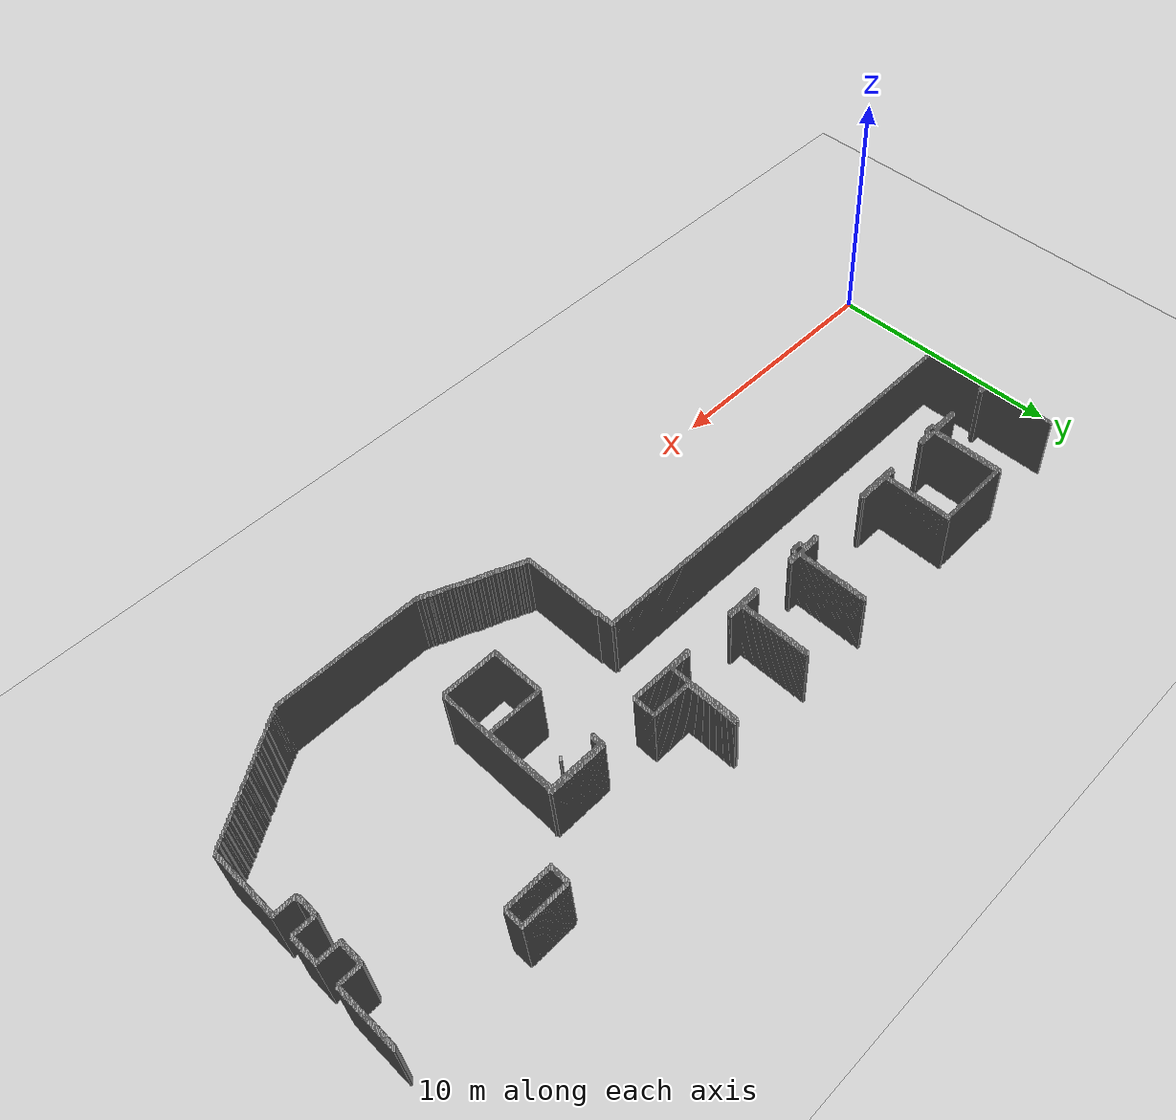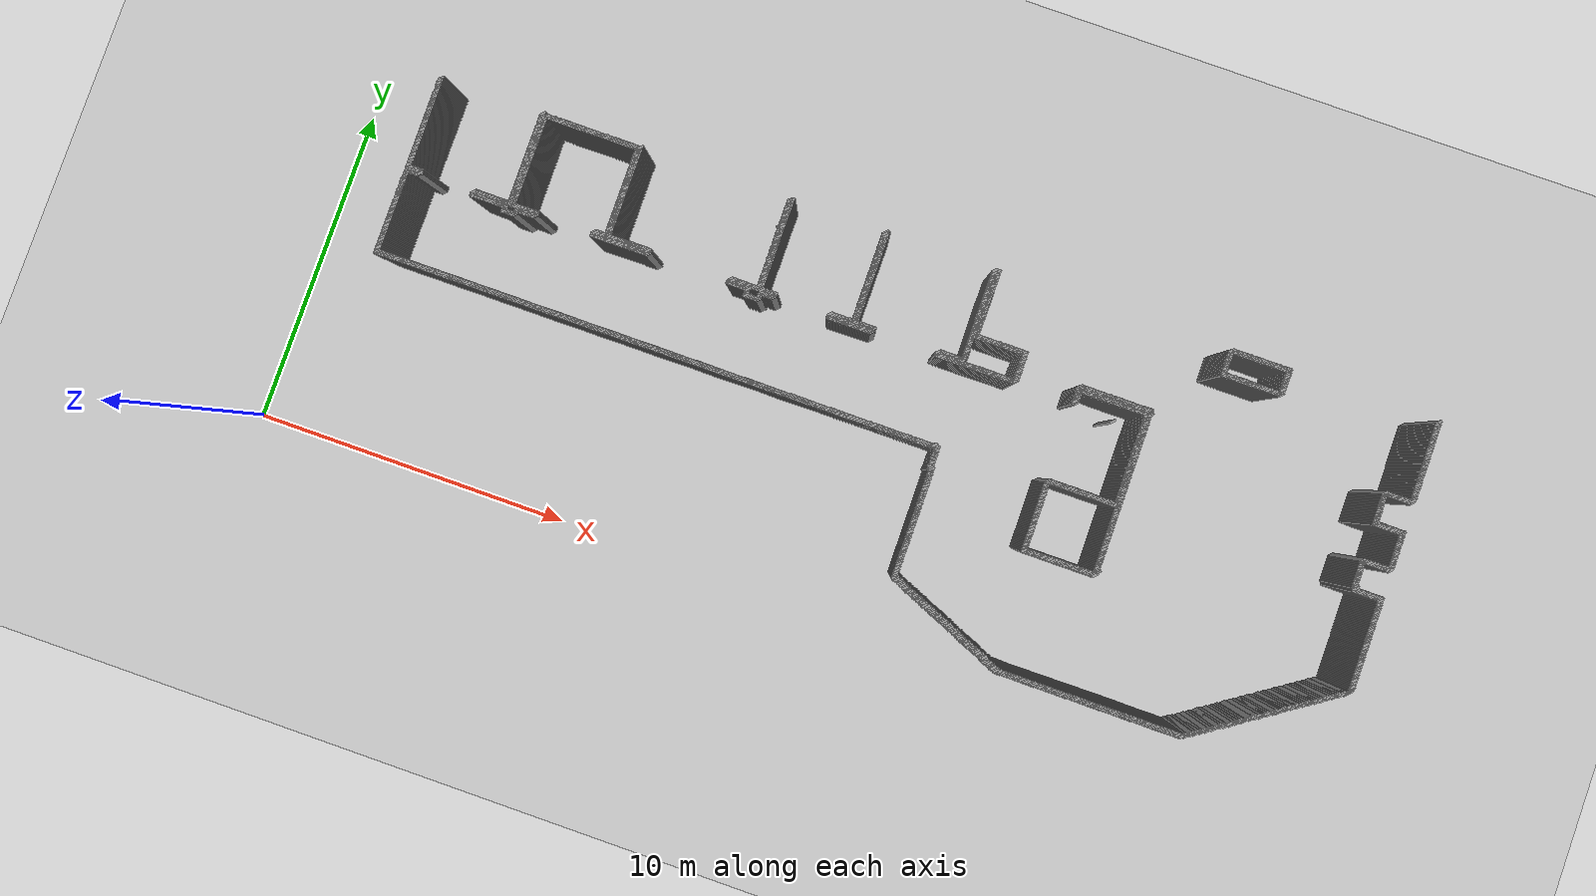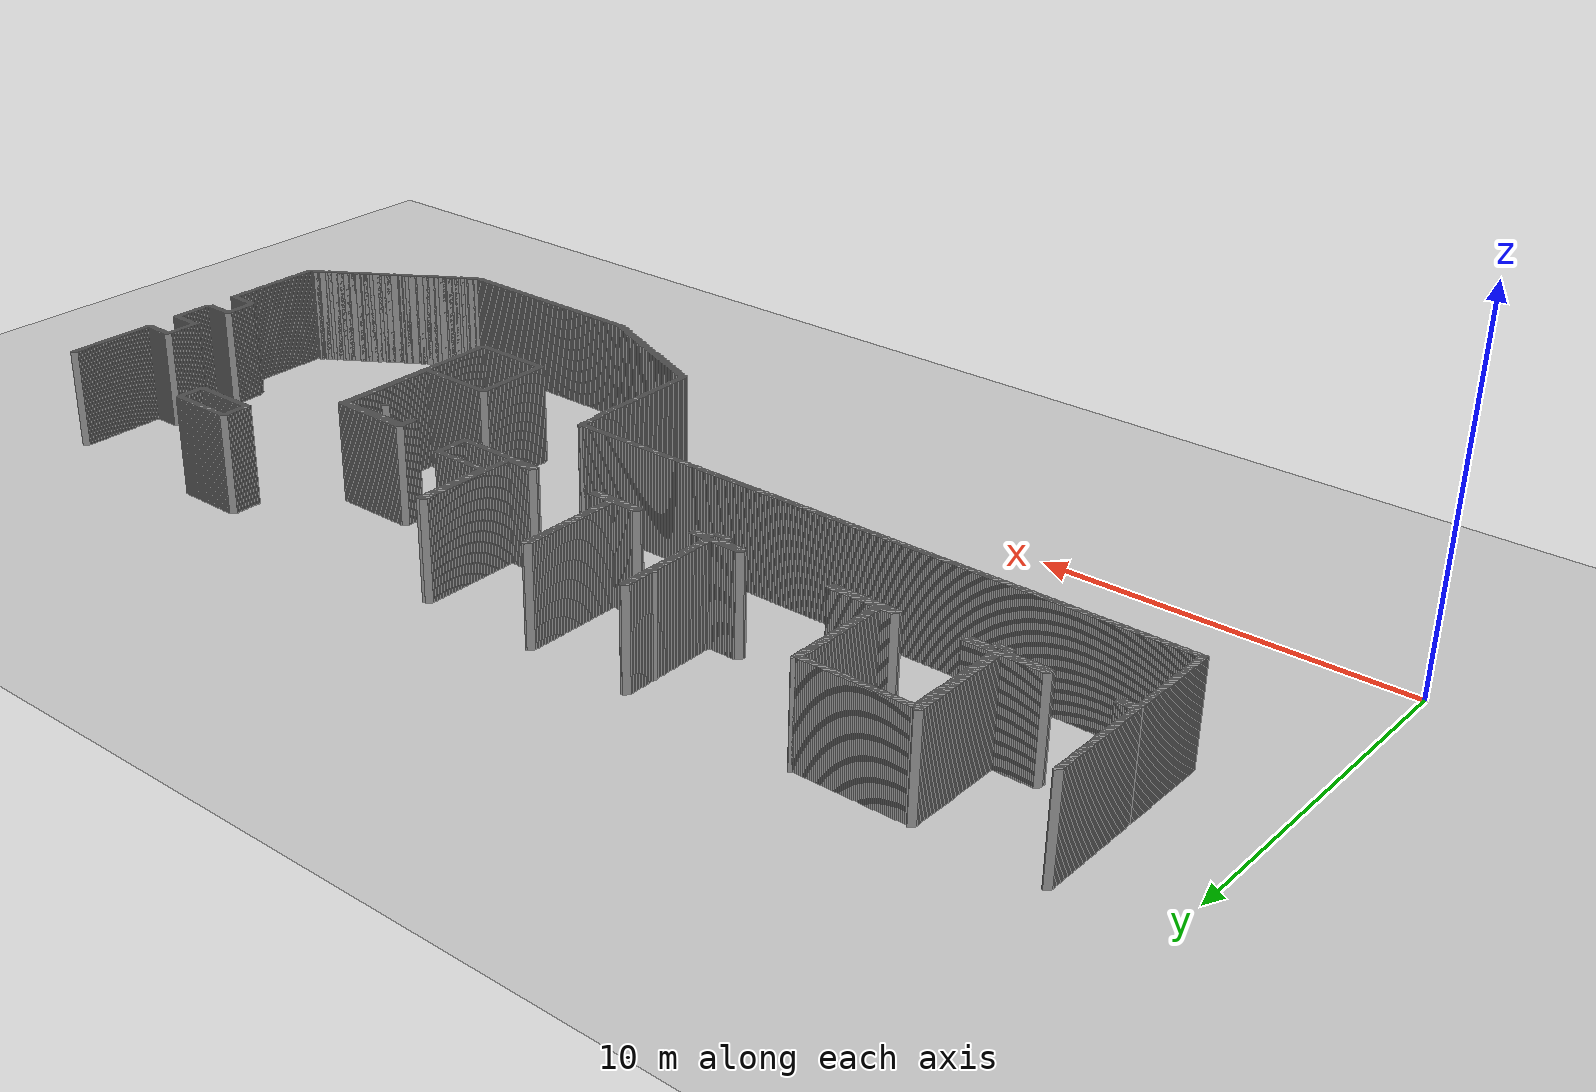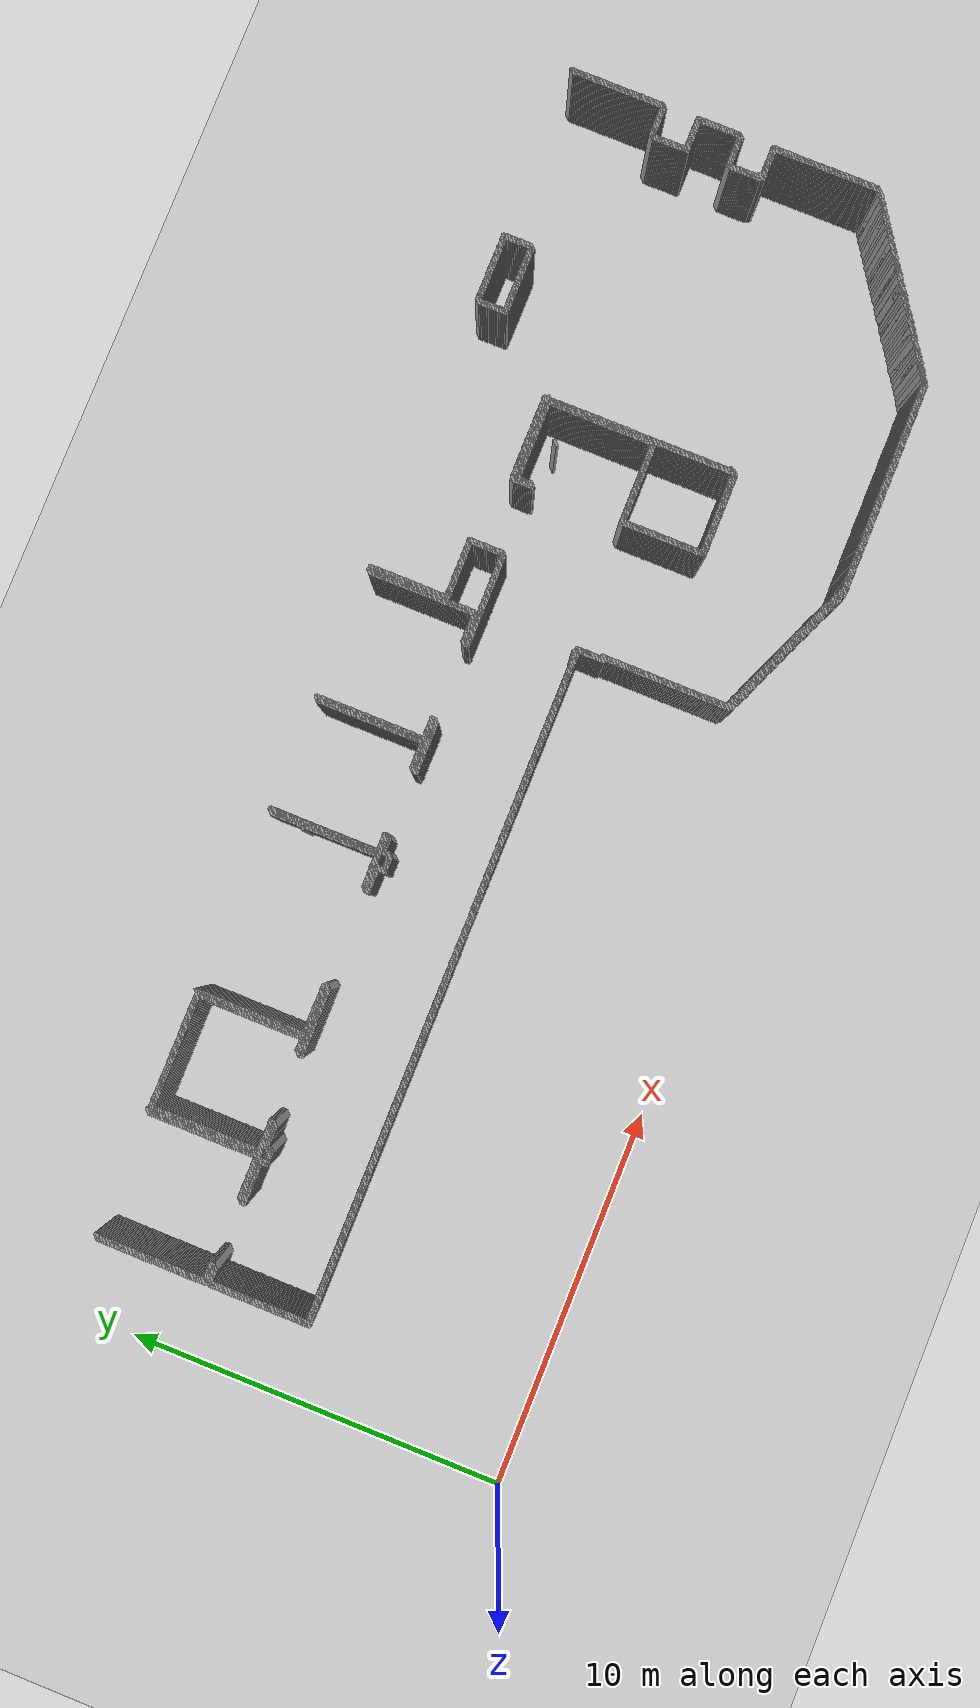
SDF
<sdf version="1.5">
 <world name="default">
  <include><uri>model://ground_plane</uri></include>
  <include><uri>model://sun</uri></include>
  <model name="grey_wall_2678">
   <static>1</static>
   <link name="link">
    <pose>27.5 11.55  1.4 0 0 -0.785398163397</pose>
    <collision name="collision"><geometry><box><size>0.0707106781187 .2  2.8</size></box></geometry></collision>
    <visual name="visual">
     <cast_shadows>0</cast_shadows>
     <geometry><box><size>0.0707106781187 .2  2.8</size></box></geometry>
     <material>
      <script>
       <uri>model://grey_wall/materials/scripts</uri>
       <uri>model://grey_wall/materials/textures</uri>
       <name>vrc/grey_wall</name>
      </script>
     </material>
    </visual>
   </link>
  </model>
  <model name="grey_wall_2679">
   <static>1</static>
   <link name="link">
    <pose>27.55 11.55  1.4 0 0 -0.785398163397</pose>
    <collision name="collision"><geometry><box><size>0.0707106781187 .2  2.8</size></box></geometry></collision>
    <visual name="visual">
     <cast_shadows>0</cast_shadows>
     <geometry><box><size>0.0707106781187 .2  2.8</size></box></geometry>
     <material>
      <script>
       <uri>model://grey_wall/materials/scripts</uri>
       <uri>model://grey_wall/materials/textures</uri>
       <name>vrc/grey_wall</name>
      </script>
     </material>
    </visual>
   </link>
  </model>
  <model name="grey_wall_2680">
   <static>1</static>
   <link name="link">
    <pose>27.6 11.55  1.4 0 0 -0.785398163397</pose>
    <collision name="collision"><geometry><box><size>0.0707106781187 .2  2.8</size></box></geometry></collision>
    <visual name="visual">
     <cast_shadows>0</cast_shadows>
     <geometry><box><size>0.0707106781187 .2  2.8</size></box></geometry>
     <material>
      <script>
       <uri>model://grey_wall/materials/scripts</uri>
       <uri>model://grey_wall/materials/textures</uri>
       <name>vrc/grey_wall</name>
      </script>
     </material>
    </visual>
   </link>
  </model>
  <model name="grey_wall_2681">
   <static>1</static>
   <link name="link">
    <pose>27.65 11.55  1.4 0 0 -0.785398163397</pose>
    <collision name="collision"><geometry><box><size>0.0707106781187 .2  2.8</size></box></geometry></collision>
    <visual name="visual">
     <cast_shadows>0</cast_shadows>
     <geometry><box><size>0.0707106781187 .2  2.8</size></box></geometry>
     <material>
      <script>
       <uri>model://grey_wall/materials/scripts</uri>
       <uri>model://grey_wall/materials/textures</uri>
       <name>vrc/grey_wall</name>
      </script>
     </material>
    </visual>
   </link>
  </model>
  <model name="grey_wall_2682">
   <static>1</static>
   <link name="link">
    <pose>27.7 11.55  1.4 0 0 -0.785398163397</pose>
    <collision name="collision"><geometry><box><size>0.0707106781187 .2  2.8</size></box></geometry></collision>
    <visual name="visual">
     <cast_shadows>0</cast_shadows>
     <geometry><box><size>0.0707106781187 .2  2.8</size></box></geometry>
     <material>
      <script>
       <uri>model://grey_wall/materials/scripts</uri>
       <uri>model://grey_wall/materials/textures</uri>
       <name>vrc/grey_wall</name>
      </script>
     </material>
    </visual>
   </link>
  </model>
  <model name="grey_wall_2683">
   <static>1</static>
   <link name="link">
    <pose>27.75 11.55  1.4 0 0 -0.785398163397</pose>
    <collision name="collision"><geometry><box><size>0.0707106781187 .2  2.8</size></box></geometry></collision>
    <visual name="visual">
     <cast_shadows>0</cast_shadows>
     <geometry><box><size>0.0707106781187 .2  2.8</size></box></geometry>
     <material>
      <script>
       <uri>model://grey_wall/materials/scripts</uri>
       <uri>model://grey_wall/materials/textures</uri>
       <name>vrc/grey_wall</name>
      </script>
     </material>
    </visual>
   </link>
  </model>
  <model name="grey_wall_2684">
   <static>1</static>
   <link name="link">
    <pose>27.8 11.55  1.4 0 0 -0.785398163397</pose>
    <collision name="collision"><geometry><box><size>0.0707106781187 .2  2.8</size></box></geometry></collision>
    <visual name="visual">
     <cast_shadows>0</cast_shadows>
     <geometry><box><size>0.0707106781187 .2  2.8</size></box></geometry>
     <material>
      <script>
       <uri>model://grey_wall/materials/scripts</uri>
       <uri>model://grey_wall/materials/textures</uri>
       <name>vrc/grey_wall</name>
      </script>
     </material>
    </visual>
   </link>
  </model>
  <model name="grey_wall_2685">
   <static>1</static>
   <link name="link">
    <pose>27.85 11.55  1.4 0 0 -0.785398163397</pose>
    <collision name="collision"><geometry><box><size>0.0707106781187 .2  2.8</size></box></geometry></collision>
    <visual name="visual">
     <cast_shadows>0</cast_shadows>
     <geometry><box><size>0.0707106781187 .2  2.8</size></box></geometry>
     <material>
      <script>
       <uri>model://grey_wall/materials/scripts</uri>
       <uri>model://grey_wall/materials/textures</uri>
       <name>vrc/grey_wall</name>
      </script>
     </material>
    </visual>
   </link>
  </model>
  <model name="grey_wall_2686">
   <static>1</static>
   <link name="link">
    <pose>27.9 11.55  1.4 0 0 -0.785398163397</pose>
    <collision name="collision"><geometry><box><size>0.0707106781187 .2  2.8</size></box></geometry></collision>
    <visual name="visual">
     <cast_shadows>0</cast_shadows>
     <geometry><box><size>0.0707106781187 .2  2.8</size></box></geometry>
     <material>
      <script>
       <uri>model://grey_wall/materials/scripts</uri>
       <uri>model://grey_wall/materials/textures</uri>
       <name>vrc/grey_wall</name>
      </script>
     </material>
    </visual>
   </link>
  </model>
  <model name="grey_wall_2687">
   <static>1</static>
   <link name="link">
    <pose>27.95 11.55  1.4 0 0 -0.785398163397</pose>
    <collision name="collision"><geometry><box><size>0.0707106781187 .2  2.8</size></box></geometry></collision>
    <visual name="visual">
     <cast_shadows>0</cast_shadows>
     <geometry><box><size>0.0707106781187 .2  2.8</size></box></geometry>
     <material>
      <script>
       <uri>model://grey_wall/materials/scripts</uri>
       <uri>model://grey_wall/materials/textures</uri>
       <name>vrc/grey_wall</name>
      </script>
     </material>
    </visual>
   </link>
  </model>
  <model name="grey_wall_2688">
   <static>1</static>
   <link name="link">
    <pose>28.0 11.55  1.4 0 0 -0.785398163397</pose>
    <collision name="collision"><geometry><box><size>0.0707106781187 .2  2.8</size></box></geometry></collision>
    <visual name="visual">
     <cast_shadows>0</cast_shadows>
     <geometry><box><size>0.0707106781187 .2  2.8</size></box></geometry>
     <material>
      <script>
       <uri>model://grey_wall/materials/scripts</uri>
       <uri>model://grey_wall/materials/textures</uri>
       <name>vrc/grey_wall</name>
      </script>
     </material>
    </visual>
   </link>
  </model>
  <model name="grey_wall_2689">
   <static>1</static>
   <link name="link">
    <pose>28.05 11.55  1.4 0 0 -0.785398163397</pose>
    <collision name="collision"><geometry><box><size>0.0707106781187 .2  2.8</size></box></geometry></collision>
    <visual name="visual">
     <cast_shadows>0</cast_shadows>
     <geometry><box><size>0.0707106781187 .2  2.8</size></box></geometry>
     <material>
      <script>
       <uri>model://grey_wall/materials/scripts</uri>
       <uri>model://grey_wall/materials/textures</uri>
       <name>vrc/grey_wall</name>
      </script>
     </material>
    </visual>
   </link>
  </model>
  <model name="grey_wall_2690">
   <static>1</static>
   <link name="link">
    <pose>28.1 11.55  1.4 0 0 -0.785398163397</pose>
    <collision name="collision"><geometry><box><size>0.0707106781187 .2  2.8</size></box></geometry></collision>
    <visual name="visual">
     <cast_shadows>0</cast_shadows>
     <geometry><box><size>0.0707106781187 .2  2.8</size></box></geometry>
     <material>
      <script>
       <uri>model://grey_wall/materials/scripts</uri>
       <uri>model://grey_wall/materials/textures</uri>
       <name>vrc/grey_wall</name>
      </script>
     </material>
    </visual>
   </link>
  </model>
  <model name="grey_wall_2691">
   <static>1</static>
   <link name="link">
    <pose>28.15 11.55  1.4 0 0 -0.785398163397</pose>
    <collision name="collision"><geometry><box><size>0.0707106781187 .2  2.8</size></box></geometry></collision>
    <visual name="visual">
     <cast_shadows>0</cast_shadows>
     <geometry><box><size>0.0707106781187 .2  2.8</size></box></geometry>
     <material>
      <script>
       <uri>model://grey_wall/materials/scripts</uri>
       <uri>model://grey_wall/materials/textures</uri>
       <name>vrc/grey_wall</name>
      </script>
     </material>
    </visual>
   </link>
  </model>
  <model name="grey_wall_2692">
   <static>1</static>
   <link name="link">
    <pose>28.2 11.55  1.4 0 0 -0.785398163397</pose>
    <collision name="collision"><geometry><box><size>0.0707106781187 .2  2.8</size></box></geometry></collision>
    <visual name="visual">
     <cast_shadows>0</cast_shadows>
     <geometry><box><size>0.0707106781187 .2  2.8</size></box></geometry>
     <material>
      <script>
       <uri>model://grey_wall/materials/scripts</uri>
       <uri>model://grey_wall/materials/textures</uri>
       <name>vrc/grey_wall</name>
      </script>
     </material>
    </visual>
   </link>
  </model>
  <model name="grey_wall_2693">
   <static>1</static>
   <link name="link">
    <pose>28.25 11.55  1.4 0 0 -0.785398163397</pose>
    <collision name="collision"><geometry><box><size>0.0707106781187 .2  2.8</size></box></geometry></collision>
    <visual name="visual">
     <cast_shadows>0</cast_shadows>
     <geometry><box><size>0.0707106781187 .2  2.8</size></box></geometry>
     <material>
      <script>
       <uri>model://grey_wall/materials/scripts</uri>
       <uri>model://grey_wall/materials/textures</uri>
       <name>vrc/grey_wall</name>
      </script>
     </material>
    </visual>
   </link>
  </model>
  <model name="grey_wall_2694">
   <static>1</static>
   <link name="link">
    <pose>28.3 11.55  1.4 0 0 -0.785398163397</pose>
    <collision name="collision"><geometry><box><size>0.0707106781187 .2  2.8</size></box></geometry></collision>
    <visual name="visual">
     <cast_shadows>0</cast_shadows>
     <geometry><box><size>0.0707106781187 .2  2.8</size></box></geometry>
     <material>
      <script>
       <uri>model://grey_wall/materials/scripts</uri>
       <uri>model://grey_wall/materials/textures</uri>
       <name>vrc/grey_wall</name>
      </script>
     </material>
    </visual>
   </link>
  </model>
  <model name="grey_wall_2695">
   <static>1</static>
   <link name="link">
    <pose>28.35 11.55  1.4 0 0 -0.785398163397</pose>
    <collision name="collision"><geometry><box><size>0.0707106781187 .2  2.8</size></box></geometry></collision>
    <visual name="visual">
     <cast_shadows>0</cast_shadows>
     <geometry><box><size>0.0707106781187 .2  2.8</size></box></geometry>
     <material>
      <script>
       <uri>model://grey_wall/materials/scripts</uri>
       <uri>model://grey_wall/materials/textures</uri>
       <name>vrc/grey_wall</name>
      </script>
     </material>
    </visual>
   </link>
  </model>
  <model name="grey_wall_2696">
   <static>1</static>
   <link name="link">
    <pose>28.4 11.55  1.4 0 0 -0.785398163397</pose>
    <collision name="collision"><geometry><box><size>0.0707106781187 .2  2.8</size></box></geometry></collision>
    <visual name="visual">
     <cast_shadows>0</cast_shadows>
     <geometry><box><size>0.0707106781187 .2  2.8</size></box></geometry>
     <material>
      <script>
       <uri>model://grey_wall/materials/scripts</uri>
       <uri>model://grey_wall/materials/textures</uri>
       <name>vrc/grey_wall</name>
      </script>
     </material>
    </visual>
   </link>
  </model>
  <model name="grey_wall_2697">
   <static>1</static>
   <link name="link">
    <pose>28.45 11.55  1.4 0 0 -0.785398163397</pose>
    <collision name="collision"><geometry><box><size>0.0707106781187 .2  2.8</size></box></geometry></collision>
    <visual name="visual">
     <cast_shadows>0</cast_shadows>
     <geometry><box><size>0.0707106781187 .2  2.8</size></box></geometry>
     <material>
      <script>
       <uri>model://grey_wall/materials/scripts</uri>
       <uri>model://grey_wall/materials/textures</uri>
       <name>vrc/grey_wall</name>
      </script>
     </material>
    </visual>
   </link>
  </model>
  <model name="grey_wall_2698">
   <static>1</static>
   <link name="link">
    <pose>28.5 11.55  1.4 0 0 -0.785398163397</pose>
    <collision name="collision"><geometry><box><size>0.0707106781187 .2  2.8</size></box></geometry></collision>
    <visual name="visual">
     <cast_shadows>0</cast_shadows>
     <geometry><box><size>0.0707106781187 .2  2.8</size></box></geometry>
     <material>
      <script>
       <uri>model://grey_wall/materials/scripts</uri>
       <uri>model://grey_wall/materials/textures</uri>
       <name>vrc/grey_wall</name>
      </script>
     </material>
    </visual>
   </link>
  </model>
  <model name="grey_wall_2699">
   <static>1</static>
   <link name="link">
    <pose>28.55 11.55  1.4 0 0 -0.785398163397</pose>
    <collision name="collision"><geometry><box><size>0.0707106781187 .2  2.8</size></box></geometry></collision>
    <visual name="visual">
     <cast_shadows>0</cast_shadows>
     <geometry><box><size>0.0707106781187 .2  2.8</size></box></geometry>
     <material>
      <script>
       <uri>model://grey_wall/materials/scripts</uri>
       <uri>model://grey_wall/materials/textures</uri>
       <name>vrc/grey_wall</name>
      </script>
     </material>
    </visual>
   </link>
  </model>
  <model name="grey_wall_2700">
   <static>1</static>
   <link name="link">
    <pose>28.6 11.55  1.4 0 0 -0.785398163397</pose>
    <collision name="collision"><geometry><box><size>0.0707106781187 .2  2.8</size></box></geometry></collision>
    <visual name="visual">
     <cast_shadows>0</cast_shadows>
     <geometry><box><size>0.0707106781187 .2  2.8</size></box></geometry>
     <material>
      <script>
       <uri>model://grey_wall/materials/scripts</uri>
       <uri>model://grey_wall/materials/textures</uri>
       <name>vrc/grey_wall</name>
      </script>
     </material>
    </visual>
   </link>
  </model>
  <model name="grey_wall_2701">
   <static>1</static>
   <link name="link">
    <pose>28.65 11.55  1.4 0 0 -0.785398163397</pose>
    <collision name="collision"><geometry><box><size>0.0707106781187 .2  2.8</size></box></geometry></collision>
    <visual name="visual">
     <cast_shadows>0</cast_shadows>
     <geometry><box><size>0.0707106781187 .2  2.8</size></box></geometry>
     <material>
      <script>
       <uri>model://grey_wall/materials/scripts</uri>
       <uri>model://grey_wall/materials/textures</uri>
       <name>vrc/grey_wall</name>
      </script>
     </material>
    </visual>
   </link>
  </model>
  <model name="grey_wall_2702">
   <static>1</static>
   <link name="link">
    <pose>28.7 11.55  1.4 0 0 -0.785398163397</pose>
    <collision name="collision"><geometry><box><size>0.0707106781187 .2  2.8</size></box></geometry></collision>
    <visual name="visual">
     <cast_shadows>0</cast_shadows>
     <geometry><box><size>0.0707106781187 .2  2.8</size></box></geometry>
     <material>
      <script>
       <uri>model://grey_wall/materials/scripts</uri>
       <uri>model://grey_wall/materials/textures</uri>
       <name>vrc/grey_wall</name>
      </script>
     </material>
    </visual>
   </link>
  </model>
  <model name="grey_wall_2703">
   <static>1</static>
   <link name="link">
    <pose>28.75 11.55  1.4 0 0 -0.785398163397</pose>
    <collision name="collision"><geometry><box><size>0.0707106781187 .2  2.8</size></box></geometry></collision>
    <visual name="visual">
     <cast_shadows>0</cast_shadows>
     <geometry><box><size>0.0707106781187 .2  2.8</size></box></geometry>
     <material>
      <script>
       <uri>model://grey_wall/materials/scripts</uri>
       <uri>model://grey_wall/materials/textures</uri>
       <name>vrc/grey_wall</name>
      </script>
     </material>
    </visual>
   </link>
  </model>
  <model name="grey_wall_2704">
   <static>1</static>
   <link name="link">
    <pose>28.8 11.55  1.4 0 0 -0.785398163397</pose>
    <collision name="collision"><geometry><box><size>0.0707106781187 .2  2.8</size></box></geometry></collision>
    <visual name="visual">
     <cast_shadows>0</cast_shadows>
     <geometry><box><size>0.0707106781187 .2  2.8</size></box></geometry>
     <material>
      <script>
       <uri>model://grey_wall/materials/scripts</uri>
       <uri>model://grey_wall/materials/textures</uri>
       <name>vrc/grey_wall</name>
      </script>
     </material>
    </visual>
   </link>
  </model>
  <model name="grey_wall_2705">
   <static>1</static>
   <link name="link">
    <pose>28.85 11.55  1.4 0 0 -0.785398163397</pose>
    <collision name="collision"><geometry><box><size>0.0707106781187 .2  2.8</size></box></geometry></collision>
    <visual name="visual">
     <cast_shadows>0</cast_shadows>
     <geometry><box><size>0.0707106781187 .2  2.8</size></box></geometry>
     <material>
      <script>
       <uri>model://grey_wall/materials/scripts</uri>
       <uri>model://grey_wall/materials/textures</uri>
       <name>vrc/grey_wall</name>
      </script>
     </material>
    </visual>
   </link>
  </model>
  <model name="grey_wall_2706">
   <static>1</static>
   <link name="link">
    <pose>28.9 11.55  1.4 0 0 -0.785398163397</pose>
    <collision name="collision"><geometry><box><size>0.0707106781187 .2  2.8</size></box></geometry></collision>
    <visual name="visual">
     <cast_shadows>0</cast_shadows>
     <geometry><box><size>0.0707106781187 .2  2.8</size></box></geometry>
     <material>
      <script>
       <uri>model://grey_wall/materials/scripts</uri>
       <uri>model://grey_wall/materials/textures</uri>
       <name>vrc/grey_wall</name>
      </script>
     </material>
    </visual>
   </link>
  </model>
  <model name="grey_wall_2707">
   <static>1</static>
   <link name="link">
    <pose>28.95 11.55  1.4 0 0 -0.785398163397</pose>
    <collision name="collision"><geometry><box><size>0.0707106781187 .2  2.8</size></box></geometry></collision>
    <visual name="visual">
     <cast_shadows>0</cast_shadows>
     <geometry><box><size>0.0707106781187 .2  2.8</size></box></geometry>
     <material>
      <script>
       <uri>model://grey_wall/materials/scripts</uri>
       <uri>model://grey_wall/materials/textures</uri>
       <name>vrc/grey_wall</name>
      </script>
     </material>
    </visual>
   </link>
  </model>
  <model name="grey_wall_2708">
   <static>1</static>
   <link name="link">
    <pose>29.0 11.55  1.4 0 0 -0.785398163397</pose>
    <collision name="collision"><geometry><box><size>0.0707106781187 .2  2.8</size></box></geometry></collision>
    <visual name="visual">
     <cast_shadows>0</cast_shadows>
     <geometry><box><size>0.0707106781187 .2  2.8</size></box></geometry>
     <material>
      <script>
       <uri>model://grey_wall/materials/scripts</uri>
       <uri>model://grey_wall/materials/textures</uri>
       <name>vrc/grey_wall</name>
      </script>
     </material>
    </visual>
   </link>
  </model>
  <model name="grey_wall_2709">
   <static>1</static>
   <link name="link">
    <pose>29.05 11.55  1.4 0 0 -0.785398163397</pose>
    <collision name="collision"><geometry><box><size>0.0707106781187 .2  2.8</size></box></geometry></collision>
    <visual name="visual">
     <cast_shadows>0</cast_shadows>
     <geometry><box><size>0.0707106781187 .2  2.8</size></box></geometry>
     <material>
      <script>
       <uri>model://grey_wall/materials/scripts</uri>
       <uri>model://grey_wall/materials/textures</uri>
       <name>vrc/grey_wall</name>
      </script>
     </material>
    </visual>
   </link>
  </model>
  <model name="grey_wall_2710">
   <static>1</static>
   <link name="link">
    <pose>29.1 11.55  1.4 0 0 -0.785398163397</pose>
    <collision name="collision"><geometry><box><size>0.0707106781187 .2  2.8</size></box></geometry></collision>
    <visual name="visual">
     <cast_shadows>0</cast_shadows>
     <geometry><box><size>0.0707106781187 .2  2.8</size></box></geometry>
     <material>
      <script>
       <uri>model://grey_wall/materials/scripts</uri>
       <uri>model://grey_wall/materials/textures</uri>
       <name>vrc/grey_wall</name>
      </script>
     </material>
    </visual>
   </link>
  </model>
  <model name="grey_wall_2711">
   <static>1</static>
   <link name="link">
    <pose>29.15 11.55  1.4 0 0 -0.785398163397</pose>
    <collision name="collision"><geometry><box><size>0.0707106781187 .2  2.8</size></box></geometry></collision>
    <visual name="visual">
     <cast_shadows>0</cast_shadows>
     <geometry><box><size>0.0707106781187 .2  2.8</size></box></geometry>
     <material>
      <script>
       <uri>model://grey_wall/materials/scripts</uri>
       <uri>model://grey_wall/materials/textures</uri>
       <name>vrc/grey_wall</name>
      </script>
     </material>
    </visual>
   </link>
  </model>
  <model name="grey_wall_2712">
   <static>1</static>
   <link name="link">
    <pose>29.2 11.55  1.4 0 0 -0.785398163397</pose>
    <collision name="collision"><geometry><box><size>0.0707106781187 .2  2.8</size></box></geometry></collision>
    <visual name="visual">
     <cast_shadows>0</cast_shadows>
     <geometry><box><size>0.0707106781187 .2  2.8</size></box></geometry>
     <material>
      <script>
       <uri>model://grey_wall/materials/scripts</uri>
       <uri>model://grey_wall/materials/textures</uri>
       <name>vrc/grey_wall</name>
      </script>
     </material>
    </visual>
   </link>
  </model>
  <model name="grey_wall_2713">
   <static>1</static>
   <link name="link">
    <pose>29.25 11.55  1.4 0 0 -0.785398163397</pose>
    <collision name="collision"><geometry><box><size>0.0707106781187 .2  2.8</size></box></geometry></collision>
    <visual name="visual">
     <cast_shadows>0</cast_shadows>
     <geometry><box><size>0.0707106781187 .2  2.8</size></box></geometry>
     <material>
      <script>
       <uri>model://grey_wall/materials/scripts</uri>
       <uri>model://grey_wall/materials/textures</uri>
       <name>vrc/grey_wall</name>
      </script>
     </material>
    </visual>
   </link>
  </model>
  <model name="grey_wall_2714">
   <static>1</static>
   <link name="link">
    <pose>29.3 11.55  1.4 0 0 -0.785398163397</pose>
    <collision name="collision"><geometry><box><size>0.0707106781187 .2  2.8</size></box></geometry></collision>
    <visual name="visual">
     <cast_shadows>0</cast_shadows>
     <geometry><box><size>0.0707106781187 .2  2.8</size></box></geometry>
     <material>
      <script>
       <uri>model://grey_wall/materials/scripts</uri>
       <uri>model://grey_wall/materials/textures</uri>
       <name>vrc/grey_wall</name>
      </script>
     </material>
    </visual>
   </link>
  </model>
  <model name="grey_wall_2715">
   <static>1</static>
   <link name="link">
    <pose>33.95 11.55  1.4 0 0 -0.785398163397</pose>
    <collision name="collision"><geometry><box><size>0.0707106781187 .2  2.8</size></box></geometry></collision>
    <visual name="visual">
     <cast_shadows>0</cast_shadows>
     <geometry><box><size>0.0707106781187 .2  2.8</size></box></geometry>
     <material>
      <script>
       <uri>model://grey_wall/materials/scripts</uri>
       <uri>model://grey_wall/materials/textures</uri>
       <name>vrc/grey_wall</name>
      </script>
     </material>
    </visual>
   </link>
  </model>
  <model name="grey_wall_2716">
   <static>1</static>
   <link name="link">
    <pose>2.55 11.5  1.4 0 0 -0.785398163397</pose>
    <collision name="collision"><geometry><box><size>0.0707106781187 .2  2.8</size></box></geometry></collision>
    <visual name="visual">
     <cast_shadows>0</cast_shadows>
     <geometry><box><size>0.0707106781187 .2  2.8</size></box></geometry>
     <material>
      <script>
       <uri>model://grey_wall/materials/scripts</uri>
       <uri>model://grey_wall/materials/textures</uri>
       <name>vrc/grey_wall</name>
      </script>
     </material>
    </visual>
   </link>
  </model>
  <model name="grey_wall_2717">
   <static>1</static>
   <link name="link">
    <pose>5.8 11.5  1.4 0 0 -0.785398163397</pose>
    <collision name="collision"><geometry><box><size>0.0707106781187 .2  2.8</size></box></geometry></collision>
    <visual name="visual">
     <cast_shadows>0</cast_shadows>
     <geometry><box><size>0.0707106781187 .2  2.8</size></box></geometry>
     <material>
      <script>
       <uri>model://grey_wall/materials/scripts</uri>
       <uri>model://grey_wall/materials/textures</uri>
       <name>vrc/grey_wall</name>
      </script>
     </material>
    </visual>
   </link>
  </model>
  <model name="grey_wall_2718">
   <static>1</static>
   <link name="link">
    <pose>8.9 11.5  1.4 0 0 -0.785398163397</pose>
    <collision name="collision"><geometry><box><size>0.0707106781187 .2  2.8</size></box></geometry></collision>
    <visual name="visual">
     <cast_shadows>0</cast_shadows>
     <geometry><box><size>0.0707106781187 .2  2.8</size></box></geometry>
     <material>
      <script>
       <uri>model://grey_wall/materials/scripts</uri>
       <uri>model://grey_wall/materials/textures</uri>
       <name>vrc/grey_wall</name>
      </script>
     </material>
    </visual>
   </link>
  </model>
  <model name="grey_wall_2719">
   <static>1</static>
   <link name="link">
    <pose>13.65 11.5  1.4 0 0 -0.785398163397</pose>
    <collision name="collision"><geometry><box><size>0.0707106781187 .2  2.8</size></box></geometry></collision>
    <visual name="visual">
     <cast_shadows>0</cast_shadows>
     <geometry><box><size>0.0707106781187 .2  2.8</size></box></geometry>
     <material>
      <script>
       <uri>model://grey_wall/materials/scripts</uri>
       <uri>model://grey_wall/materials/textures</uri>
       <name>vrc/grey_wall</name>
      </script>
     </material>
    </visual>
   </link>
  </model>
  <model name="grey_wall_2720">
   <static>1</static>
   <link name="link">
    <pose>13.7 11.5  1.4 0 0 -0.785398163397</pose>
    <collision name="collision"><geometry><box><size>0.0707106781187 .2  2.8</size></box></geometry></collision>
    <visual name="visual">
     <cast_shadows>0</cast_shadows>
     <geometry><box><size>0.0707106781187 .2  2.8</size></box></geometry>
     <material>
      <script>
       <uri>model://grey_wall/materials/scripts</uri>
       <uri>model://grey_wall/materials/textures</uri>
       <name>vrc/grey_wall</name>
      </script>
     </material>
    </visual>
   </link>
  </model>
  <model name="grey_wall_2721">
   <static>1</static>
   <link name="link">
    <pose>16.65 11.5  1.4 0 0 -0.785398163397</pose>
    <collision name="collision"><geometry><box><size>0.0707106781187 .2  2.8</size></box></geometry></collision>
    <visual name="visual">
     <cast_shadows>0</cast_shadows>
     <geometry><box><size>0.0707106781187 .2  2.8</size></box></geometry>
     <material>
      <script>
       <uri>model://grey_wall/materials/scripts</uri>
       <uri>model://grey_wall/materials/textures</uri>
       <name>vrc/grey_wall</name>
      </script>
     </material>
    </visual>
   </link>
  </model>
  <model name="grey_wall_2722">
   <static>1</static>
   <link name="link">
    <pose>16.7 11.5  1.4 0 0 -0.785398163397</pose>
    <collision name="collision"><geometry><box><size>0.0707106781187 .2  2.8</size></box></geometry></collision>
    <visual name="visual">
     <cast_shadows>0</cast_shadows>
     <geometry><box><size>0.0707106781187 .2  2.8</size></box></geometry>
     <material>
      <script>
       <uri>model://grey_wall/materials/scripts</uri>
       <uri>model://grey_wall/materials/textures</uri>
       <name>vrc/grey_wall</name>
      </script>
     </material>
    </visual>
   </link>
  </model>
  <model name="grey_wall_2723">
   <static>1</static>
   <link name="link">
    <pose>20.1 11.5  1.4 0 0 -0.785398163397</pose>
    <collision name="collision"><geometry><box><size>0.0707106781187 .2  2.8</size></box></geometry></collision>
    <visual name="visual">
     <cast_shadows>0</cast_shadows>
     <geometry><box><size>0.0707106781187 .2  2.8</size></box></geometry>
     <material>
      <script>
       <uri>model://grey_wall/materials/scripts</uri>
       <uri>model://grey_wall/materials/textures</uri>
       <name>vrc/grey_wall</name>
      </script>
     </material>
    </visual>
   </link>
  </model>
  <model name="grey_wall_2724">
   <static>1</static>
   <link name="link">
    <pose>20.2 11.5  1.4 0 0 -0.785398163397</pose>
    <collision name="collision"><geometry><box><size>0.0707106781187 .2  2.8</size></box></geometry></collision>
    <visual name="visual">
     <cast_shadows>0</cast_shadows>
     <geometry><box><size>0.0707106781187 .2  2.8</size></box></geometry>
     <material>
      <script>
       <uri>model://grey_wall/materials/scripts</uri>
       <uri>model://grey_wall/materials/textures</uri>
       <name>vrc/grey_wall</name>
      </script>
     </material>
    </visual>
   </link>
  </model>
  <model name="grey_wall_2725">
   <static>1</static>
   <link name="link">
    <pose>27.5 11.5  1.4 0 0 -0.785398163397</pose>
    <collision name="collision"><geometry><box><size>0.0707106781187 .2  2.8</size></box></geometry></collision>
    <visual name="visual">
     <cast_shadows>0</cast_shadows>
     <geometry><box><size>0.0707106781187 .2  2.8</size></box></geometry>
     <material>
      <script>
       <uri>model://grey_wall/materials/scripts</uri>
       <uri>model://grey_wall/materials/textures</uri>
       <name>vrc/grey_wall</name>
      </script>
     </material>
    </visual>
   </link>
  </model>
  <model name="grey_wall_2726">
   <static>1</static>
   <link name="link">
    <pose>29.3 11.5  1.4 0 0 -0.785398163397</pose>
    <collision name="collision"><geometry><box><size>0.0707106781187 .2  2.8</size></box></geometry></collision>
    <visual name="visual">
     <cast_shadows>0</cast_shadows>
     <geometry><box><size>0.0707106781187 .2  2.8</size></box></geometry>
     <material>
      <script>
       <uri>model://grey_wall/materials/scripts</uri>
       <uri>model://grey_wall/materials/textures</uri>
       <name>vrc/grey_wall</name>
      </script>
     </material>
    </visual>
   </link>
  </model>
  <model name="grey_wall_2727">
   <static>1</static>
   <link name="link">
    <pose>33.95 11.5  1.4 0 0 -0.785398163397</pose>
    <collision name="collision"><geometry><box><size>0.0707106781187 .2  2.8</size></box></geometry></collision>
    <visual name="visual">
     <cast_shadows>0</cast_shadows>
     <geometry><box><size>0.0707106781187 .2  2.8</size></box></geometry>
     <material>
      <script>
       <uri>model://grey_wall/materials/scripts</uri>
       <uri>model://grey_wall/materials/textures</uri>
       <name>vrc/grey_wall</name>
      </script>
     </material>
    </visual>
   </link>
  </model>
  <model name="grey_wall_2728">
   <static>1</static>
   <link name="link">
    <pose>2.55 11.45  1.4 0 0 -0.785398163397</pose>
    <collision name="collision"><geometry><box><size>0.0707106781187 .2  2.8</size></box></geometry></collision>
    <visual name="visual">
     <cast_shadows>0</cast_shadows>
     <geometry><box><size>0.0707106781187 .2  2.8</size></box></geometry>
     <material>
      <script>
       <uri>model://grey_wall/materials/scripts</uri>
       <uri>model://grey_wall/materials/textures</uri>
       <name>vrc/grey_wall</name>
      </script>
     </material>
    </visual>
   </link>
  </model>
  <model name="grey_wall_2729">
   <static>1</static>
   <link name="link">
    <pose>5.8 11.45  1.4 0 0 -0.785398163397</pose>
    <collision name="collision"><geometry><box><size>0.0707106781187 .2  2.8</size></box></geometry></collision>
    <visual name="visual">
     <cast_shadows>0</cast_shadows>
     <geometry><box><size>0.0707106781187 .2  2.8</size></box></geometry>
     <material>
      <script>
       <uri>model://grey_wall/materials/scripts</uri>
       <uri>model://grey_wall/materials/textures</uri>
       <name>vrc/grey_wall</name>
      </script>
     </material>
    </visual>
   </link>
  </model>
  <model name="grey_wall_2730">
   <static>1</static>
   <link name="link">
    <pose>5.9 11.45  1.4 0 0 -0.785398163397</pose>
    <collision name="collision"><geometry><box><size>0.0707106781187 .2  2.8</size></box></geometry></collision>
    <visual name="visual">
     <cast_shadows>0</cast_shadows>
     <geometry><box><size>0.0707106781187 .2  2.8</size></box></geometry>
     <material>
      <script>
       <uri>model://grey_wall/materials/scripts</uri>
       <uri>model://grey_wall/materials/textures</uri>
       <name>vrc/grey_wall</name>
      </script>
     </material>
    </visual>
   </link>
  </model>
  <model name="grey_wall_2731">
   <static>1</static>
   <link name="link">
    <pose>5.95 11.45  1.4 0 0 -0.785398163397</pose>
    <collision name="collision"><geometry><box><size>0.0707106781187 .2  2.8</size></box></geometry></collision>
    <visual name="visual">
     <cast_shadows>0</cast_shadows>
     <geometry><box><size>0.0707106781187 .2  2.8</size></box></geometry>
     <material>
      <script>
       <uri>model://grey_wall/materials/scripts</uri>
       <uri>model://grey_wall/materials/textures</uri>
       <name>vrc/grey_wall</name>
      </script>
     </material>
    </visual>
   </link>
  </model>
  <model name="grey_wall_2732">
   <static>1</static>
   <link name="link">
    <pose>6.0 11.45  1.4 0 0 -0.785398163397</pose>
    <collision name="collision"><geometry><box><size>0.0707106781187 .2  2.8</size></box></geometry></collision>
    <visual name="visual">
     <cast_shadows>0</cast_shadows>
     <geometry><box><size>0.0707106781187 .2  2.8</size></box></geometry>
     <material>
      <script>
       <uri>model://grey_wall/materials/scripts</uri>
       <uri>model://grey_wall/materials/textures</uri>
       <name>vrc/grey_wall</name>
      </script>
     </material>
    </visual>
   </link>
  </model>
  <model name="grey_wall_2733">
   <static>1</static>
   <link name="link">
    <pose>6.05 11.45  1.4 0 0 -0.785398163397</pose>
    <collision name="collision"><geometry><box><size>0.0707106781187 .2  2.8</size></box></geometry></collision>
    <visual name="visual">
     <cast_shadows>0</cast_shadows>
     <geometry><box><size>0.0707106781187 .2  2.8</size></box></geometry>
     <material>
      <script>
       <uri>model://grey_wall/materials/scripts</uri>
       <uri>model://grey_wall/materials/textures</uri>
       <name>vrc/grey_wall</name>
      </script>
     </material>
    </visual>
   </link>
  </model>
  <model name="grey_wall_2734">
   <static>1</static>
   <link name="link">
    <pose>6.1 11.45  1.4 0 0 -0.785398163397</pose>
    <collision name="collision"><geometry><box><size>0.0707106781187 .2  2.8</size></box></geometry></collision>
    <visual name="visual">
     <cast_shadows>0</cast_shadows>
     <geometry><box><size>0.0707106781187 .2  2.8</size></box></geometry>
     <material>
      <script>
       <uri>model://grey_wall/materials/scripts</uri>
       <uri>model://grey_wall/materials/textures</uri>
       <name>vrc/grey_wall</name>
      </script>
     </material>
    </visual>
   </link>
  </model>
  <model name="grey_wall_2735">
   <static>1</static>
   <link name="link">
    <pose>6.15 11.45  1.4 0 0 -0.785398163397</pose>
    <collision name="collision"><geometry><box><size>0.0707106781187 .2  2.8</size></box></geometry></collision>
    <visual name="visual">
     <cast_shadows>0</cast_shadows>
     <geometry><box><size>0.0707106781187 .2  2.8</size></box></geometry>
     <material>
      <script>
       <uri>model://grey_wall/materials/scripts</uri>
       <uri>model://grey_wall/materials/textures</uri>
       <name>vrc/grey_wall</name>
      </script>
     </material>
    </visual>
   </link>
  </model>
  <model name="grey_wall_2736">
   <static>1</static>
   <link name="link">
    <pose>6.2 11.45  1.4 0 0 -0.785398163397</pose>
    <collision name="collision"><geometry><box><size>0.0707106781187 .2  2.8</size></box></geometry></collision>
    <visual name="visual">
     <cast_shadows>0</cast_shadows>
     <geometry><box><size>0.0707106781187 .2  2.8</size></box></geometry>
     <material>
      <script>
       <uri>model://grey_wall/materials/scripts</uri>
       <uri>model://grey_wall/materials/textures</uri>
       <name>vrc/grey_wall</name>
      </script>
     </material>
    </visual>
   </link>
  </model>
  <model name="grey_wall_2737">
   <static>1</static>
   <link name="link">
    <pose>6.25 11.45  1.4 0 0 -0.785398163397</pose>
    <collision name="collision"><geometry><box><size>0.0707106781187 .2  2.8</size></box></geometry></collision>
    <visual name="visual">
     <cast_shadows>0</cast_shadows>
     <geometry><box><size>0.0707106781187 .2  2.8</size></box></geometry>
     <material>
      <script>
       <uri>model://grey_wall/materials/scripts</uri>
       <uri>model://grey_wall/materials/textures</uri>
       <name>vrc/grey_wall</name>
      </script>
     </material>
    </visual>
   </link>
  </model>
  <model name="grey_wall_2738">
   <static>1</static>
   <link name="link">
    <pose>6.3 11.45  1.4 0 0 -0.785398163397</pose>
    <collision name="collision"><geometry><box><size>0.0707106781187 .2  2.8</size></box></geometry></collision>
    <visual name="visual">
     <cast_shadows>0</cast_shadows>
     <geometry><box><size>0.0707106781187 .2  2.8</size></box></geometry>
     <material>
      <script>
       <uri>model://grey_wall/materials/scripts</uri>
       <uri>model://grey_wall/materials/textures</uri>
       <name>vrc/grey_wall</name>
      </script>
     </material>
    </visual>
   </link>
  </model>
  <model name="grey_wall_2739">
   <static>1</static>
   <link name="link">
    <pose>6.35 11.45  1.4 0 0 -0.785398163397</pose>
    <collision name="collision"><geometry><box><size>0.0707106781187 .2  2.8</size></box></geometry></collision>
    <visual name="visual">
     <cast_shadows>0</cast_shadows>
     <geometry><box><size>0.0707106781187 .2  2.8</size></box></geometry>
     <material>
      <script>
       <uri>model://grey_wall/materials/scripts</uri>
       <uri>model://grey_wall/materials/textures</uri>
       <name>vrc/grey_wall</name>
      </script>
     </material>
    </visual>
   </link>
  </model>
  <model name="grey_wall_2740">
   <static>1</static>
   <link name="link">
    <pose>6.4 11.45  1.4 0 0 -0.785398163397</pose>
    <collision name="collision"><geometry><box><size>0.0707106781187 .2  2.8</size></box></geometry></collision>
    <visual name="visual">
     <cast_shadows>0</cast_shadows>
     <geometry><box><size>0.0707106781187 .2  2.8</size></box></geometry>
     <material>
      <script>
       <uri>model://grey_wall/materials/scripts</uri>
       <uri>model://grey_wall/materials/textures</uri>
       <name>vrc/grey_wall</name>
      </script>
     </material>
    </visual>
   </link>
  </model>
  <model name="grey_wall_2741">
   <static>1</static>
   <link name="link">
    <pose>6.45 11.45  1.4 0 0 -0.785398163397</pose>
    <collision name="collision"><geometry><box><size>0.0707106781187 .2  2.8</size></box></geometry></collision>
    <visual name="visual">
     <cast_shadows>0</cast_shadows>
     <geometry><box><size>0.0707106781187 .2  2.8</size></box></geometry>
     <material>
      <script>
       <uri>model://grey_wall/materials/scripts</uri>
       <uri>model://grey_wall/materials/textures</uri>
       <name>vrc/grey_wall</name>
      </script>
     </material>
    </visual>
   </link>
  </model>
  <model name="grey_wall_2742">
   <static>1</static>
   <link name="link">
    <pose>6.5 11.45  1.4 0 0 -0.785398163397</pose>
    <collision name="collision"><geometry><box><size>0.0707106781187 .2  2.8</size></box></geometry></collision>
    <visual name="visual">
     <cast_shadows>0</cast_shadows>
     <geometry><box><size>0.0707106781187 .2  2.8</size></box></geometry>
     <material>
      <script>
       <uri>model://grey_wall/materials/scripts</uri>
       <uri>model://grey_wall/materials/textures</uri>
       <name>vrc/grey_wall</name>
      </script>
     </material>
    </visual>
   </link>
  </model>
  <model name="grey_wall_2743">
   <static>1</static>
   <link name="link">
    <pose>6.55 11.45  1.4 0 0 -0.785398163397</pose>
    <collision name="collision"><geometry><box><size>0.0707106781187 .2  2.8</size></box></geometry></collision>
    <visual name="visual">
     <cast_shadows>0</cast_shadows>
     <geometry><box><size>0.0707106781187 .2  2.8</size></box></geometry>
     <material>
      <script>
       <uri>model://grey_wall/materials/scripts</uri>
       <uri>model://grey_wall/materials/textures</uri>
       <name>vrc/grey_wall</name>
      </script>
     </material>
    </visual>
   </link>
  </model>
  <model name="grey_wall_2744">
   <static>1</static>
   <link name="link">
    <pose>6.6 11.45  1.4 0 0 -0.785398163397</pose>
    <collision name="collision"><geometry><box><size>0.0707106781187 .2  2.8</size></box></geometry></collision>
    <visual name="visual">
     <cast_shadows>0</cast_shadows>
     <geometry><box><size>0.0707106781187 .2  2.8</size></box></geometry>
     <material>
      <script>
       <uri>model://grey_wall/materials/scripts</uri>
       <uri>model://grey_wall/materials/textures</uri>
       <name>vrc/grey_wall</name>
      </script>
     </material>
    </visual>
   </link>
  </model>
  <model name="grey_wall_2745">
   <static>1</static>
   <link name="link">
    <pose>6.65 11.45  1.4 0 0 -0.785398163397</pose>
    <collision name="collision"><geometry><box><size>0.0707106781187 .2  2.8</size></box></geometry></collision>
    <visual name="visual">
     <cast_shadows>0</cast_shadows>
     <geometry><box><size>0.0707106781187 .2  2.8</size></box></geometry>
     <material>
      <script>
       <uri>model://grey_wall/materials/scripts</uri>
       <uri>model://grey_wall/materials/textures</uri>
       <name>vrc/grey_wall</name>
      </script>
     </material>
    </visual>
   </link>
  </model>
  <model name="grey_wall_2746">
   <static>1</static>
   <link name="link">
    <pose>6.7 11.45  1.4 0 0 -0.785398163397</pose>
    <collision name="collision"><geometry><box><size>0.0707106781187 .2  2.8</size></box></geometry></collision>
    <visual name="visual">
     <cast_shadows>0</cast_shadows>
     <geometry><box><size>0.0707106781187 .2  2.8</size></box></geometry>
     <material>
      <script>
       <uri>model://grey_wall/materials/scripts</uri>
       <uri>model://grey_wall/materials/textures</uri>
       <name>vrc/grey_wall</name>
      </script>
     </material>
    </visual>
   </link>
  </model>
  <model name="grey_wall_2747">
   <static>1</static>
   <link name="link">
    <pose>6.75 11.45  1.4 0 0 -0.785398163397</pose>
    <collision name="collision"><geometry><box><size>0.0707106781187 .2  2.8</size></box></geometry></collision>
    <visual name="visual">
     <cast_shadows>0</cast_shadows>
     <geometry><box><size>0.0707106781187 .2  2.8</size></box></geometry>
     <material>
      <script>
       <uri>model://grey_wall/materials/scripts</uri>
       <uri>model://grey_wall/materials/textures</uri>
       <name>vrc/grey_wall</name>
      </script>
     </material>
    </visual>
   </link>
  </model>
  <model name="grey_wall_2748">
   <static>1</static>
   <link name="link">
    <pose>6.8 11.45  1.4 0 0 -0.785398163397</pose>
    <collision name="collision"><geometry><box><size>0.0707106781187 .2  2.8</size></box></geometry></collision>
    <visual name="visual">
     <cast_shadows>0</cast_shadows>
     <geometry><box><size>0.0707106781187 .2  2.8</size></box></geometry>
     <material>
      <script>
       <uri>model://grey_wall/materials/scripts</uri>
       <uri>model://grey_wall/materials/textures</uri>
       <name>vrc/grey_wall</name>
      </script>
     </material>
    </visual>
   </link>
  </model>
  <model name="grey_wall_2749">
   <static>1</static>
   <link name="link">
    <pose>6.85 11.45  1.4 0 0 -0.785398163397</pose>
    <collision name="collision"><geometry><box><size>0.0707106781187 .2  2.8</size></box></geometry></collision>
    <visual name="visual">
     <cast_shadows>0</cast_shadows>
     <geometry><box><size>0.0707106781187 .2  2.8</size></box></geometry>
     <material>
      <script>
       <uri>model://grey_wall/materials/scripts</uri>
       <uri>model://grey_wall/materials/textures</uri>
       <name>vrc/grey_wall</name>
      </script>
     </material>
    </visual>
   </link>
  </model>
  <model name="grey_wall_2750">
   <static>1</static>
   <link name="link">
    <pose>6.9 11.45  1.4 0 0 -0.785398163397</pose>
    <collision name="collision"><geometry><box><size>0.0707106781187 .2  2.8</size></box></geometry></collision>
    <visual name="visual">
     <cast_shadows>0</cast_shadows>
     <geometry><box><size>0.0707106781187 .2  2.8</size></box></geometry>
     <material>
      <script>
       <uri>model://grey_wall/materials/scripts</uri>
       <uri>model://grey_wall/materials/textures</uri>
       <name>vrc/grey_wall</name>
      </script>
     </material>
    </visual>
   </link>
  </model>
  <model name="grey_wall_2751">
   <static>1</static>
   <link name="link">
    <pose>6.95 11.45  1.4 0 0 -0.785398163397</pose>
    <collision name="collision"><geometry><box><size>0.0707106781187 .2  2.8</size></box></geometry></collision>
    <visual name="visual">
     <cast_shadows>0</cast_shadows>
     <geometry><box><size>0.0707106781187 .2  2.8</size></box></geometry>
     <material>
      <script>
       <uri>model://grey_wall/materials/scripts</uri>
       <uri>model://grey_wall/materials/textures</uri>
       <name>vrc/grey_wall</name>
      </script>
     </material>
    </visual>
   </link>
  </model>
  <model name="grey_wall_2752">
   <static>1</static>
   <link name="link">
    <pose>7.0 11.45  1.4 0 0 -0.785398163397</pose>
    <collision name="collision"><geometry><box><size>0.0707106781187 .2  2.8</size></box></geometry></collision>
    <visual name="visual">
     <cast_shadows>0</cast_shadows>
     <geometry><box><size>0.0707106781187 .2  2.8</size></box></geometry>
     <material>
      <script>
       <uri>model://grey_wall/materials/scripts</uri>
       <uri>model://grey_wall/materials/textures</uri>
       <name>vrc/grey_wall</name>
      </script>
     </material>
    </visual>
   </link>
  </model>
  <model name="grey_wall_2753">
   <static>1</static>
   <link name="link">
    <pose>7.05 11.45  1.4 0 0 -0.785398163397</pose>
    <collision name="collision"><geometry><box><size>0.0707106781187 .2  2.8</size></box></geometry></collision>
    <visual name="visual">
     <cast_shadows>0</cast_shadows>
     <geometry><box><size>0.0707106781187 .2  2.8</size></box></geometry>
     <material>
      <script>
       <uri>model://grey_wall/materials/scripts</uri>
       <uri>model://grey_wall/materials/textures</uri>
       <name>vrc/grey_wall</name>
      </script>
     </material>
    </visual>
   </link>
  </model>
  <model name="grey_wall_2754">
   <static>1</static>
   <link name="link">
    <pose>7.1 11.45  1.4 0 0 -0.785398163397</pose>
    <collision name="collision"><geometry><box><size>0.0707106781187 .2  2.8</size></box></geometry></collision>
    <visual name="visual">
     <cast_shadows>0</cast_shadows>
     <geometry><box><size>0.0707106781187 .2  2.8</size></box></geometry>
     <material>
      <script>
       <uri>model://grey_wall/materials/scripts</uri>
       <uri>model://grey_wall/materials/textures</uri>
       <name>vrc/grey_wall</name>
      </script>
     </material>
    </visual>
   </link>
  </model>
  <model name="grey_wall_2755">
   <static>1</static>
   <link name="link">
    <pose>7.15 11.45  1.4 0 0 -0.785398163397</pose>
    <collision name="collision"><geometry><box><size>0.0707106781187 .2  2.8</size></box></geometry></collision>
    <visual name="visual">
     <cast_shadows>0</cast_shadows>
     <geometry><box><size>0.0707106781187 .2  2.8</size></box></geometry>
     <material>
      <script>
       <uri>model://grey_wall/materials/scripts</uri>
       <uri>model://grey_wall/materials/textures</uri>
       <name>vrc/grey_wall</name>
      </script>
     </material>
    </visual>
   </link>
  </model>
  <model name="grey_wall_2756">
   <static>1</static>
   <link name="link">
    <pose>7.2 11.45  1.4 0 0 -0.785398163397</pose>
    <collision name="collision"><geometry><box><size>0.0707106781187 .2  2.8</size></box></geometry></collision>
    <visual name="visual">
     <cast_shadows>0</cast_shadows>
     <geometry><box><size>0.0707106781187 .2  2.8</size></box></geometry>
     <material>
      <script>
       <uri>model://grey_wall/materials/scripts</uri>
       <uri>model://grey_wall/materials/textures</uri>
       <name>vrc/grey_wall</name>
      </script>
     </material>
    </visual>
   </link>
  </model>
  <model name="grey_wall_2757">
   <static>1</static>
   <link name="link">
    <pose>7.25 11.45  1.4 0 0 -0.785398163397</pose>
    <collision name="collision"><geometry><box><size>0.0707106781187 .2  2.8</size></box></geometry></collision>
    <visual name="visual">
     <cast_shadows>0</cast_shadows>
     <geometry><box><size>0.0707106781187 .2  2.8</size></box></geometry>
     <material>
      <script>
       <uri>model://grey_wall/materials/scripts</uri>
       <uri>model://grey_wall/materials/textures</uri>
       <name>vrc/grey_wall</name>
      </script>
     </material>
    </visual>
   </link>
  </model>
  <model name="grey_wall_2758">
   <static>1</static>
   <link name="link">
    <pose>7.3 11.45  1.4 0 0 -0.785398163397</pose>
    <collision name="collision"><geometry><box><size>0.0707106781187 .2  2.8</size></box></geometry></collision>
    <visual name="visual">
     <cast_shadows>0</cast_shadows>
     <geometry><box><size>0.0707106781187 .2  2.8</size></box></geometry>
     <material>
      <script>
       <uri>model://grey_wall/materials/scripts</uri>
       <uri>model://grey_wall/materials/textures</uri>
       <name>vrc/grey_wall</name>
      </script>
     </material>
    </visual>
   </link>
  </model>
  <model name="grey_wall_2759">
   <static>1</static>
   <link name="link">
    <pose>7.35 11.45  1.4 0 0 -0.785398163397</pose>
    <collision name="collision"><geometry><box><size>0.0707106781187 .2  2.8</size></box></geometry></collision>
    <visual name="visual">
     <cast_shadows>0</cast_shadows>
     <geometry><box><size>0.0707106781187 .2  2.8</size></box></geometry>
     <material>
      <script>
       <uri>model://grey_wall/materials/scripts</uri>
       <uri>model://grey_wall/materials/textures</uri>
       <name>vrc/grey_wall</name>
      </script>
     </material>
    </visual>
   </link>
  </model>
  <model name="grey_wall_2760">
   <static>1</static>
   <link name="link">
    <pose>7.4 11.45  1.4 0 0 -0.785398163397</pose>
    <collision name="collision"><geometry><box><size>0.0707106781187 .2  2.8</size></box></geometry></collision>
    <visual name="visual">
     <cast_shadows>0</cast_shadows>
     <geometry><box><size>0.0707106781187 .2  2.8</size></box></geometry>
     <material>
      <script>
       <uri>model://grey_wall/materials/scripts</uri>
       <uri>model://grey_wall/materials/textures</uri>
       <name>vrc/grey_wall</name>
      </script>
     </material>
    </visual>
   </link>
  </model>
  <model name="grey_wall_2761">
   <static>1</static>
   <link name="link">
    <pose>7.45 11.45  1.4 0 0 -0.785398163397</pose>
    <collision name="collision"><geometry><box><size>0.0707106781187 .2  2.8</size></box></geometry></collision>
    <visual name="visual">
     <cast_shadows>0</cast_shadows>
     <geometry><box><size>0.0707106781187 .2  2.8</size></box></geometry>
     <material>
      <script>
       <uri>model://grey_wall/materials/scripts</uri>
       <uri>model://grey_wall/materials/textures</uri>
       <name>vrc/grey_wall</name>
      </script>
     </material>
    </visual>
   </link>
  </model>
  <model name="grey_wall_2762">
   <static>1</static>
   <link name="link">
    <pose>7.5 11.45  1.4 0 0 -0.785398163397</pose>
    <collision name="collision"><geometry><box><size>0.0707106781187 .2  2.8</size></box></geometry></collision>
    <visual name="visual">
     <cast_shadows>0</cast_shadows>
     <geometry><box><size>0.0707106781187 .2  2.8</size></box></geometry>
     <material>
      <script>
       <uri>model://grey_wall/materials/scripts</uri>
       <uri>model://grey_wall/materials/textures</uri>
       <name>vrc/grey_wall</name>
      </script>
     </material>
    </visual>
   </link>
  </model>
  <model name="grey_wall_2763">
   <static>1</static>
   <link name="link">
    <pose>7.55 11.45  1.4 0 0 -0.785398163397</pose>
    <collision name="collision"><geometry><box><size>0.0707106781187 .2  2.8</size></box></geometry></collision>
    <visual name="visual">
     <cast_shadows>0</cast_shadows>
     <geometry><box><size>0.0707106781187 .2  2.8</size></box></geometry>
     <material>
      <script>
       <uri>model://grey_wall/materials/scripts</uri>
       <uri>model://grey_wall/materials/textures</uri>
       <name>vrc/grey_wall</name>
      </script>
     </material>
    </visual>
   </link>
  </model>
  <model name="grey_wall_2764">
   <static>1</static>
   <link name="link">
    <pose>7.6 11.45  1.4 0 0 -0.785398163397</pose>
    <collision name="collision"><geometry><box><size>0.0707106781187 .2  2.8</size></box></geometry></collision>
    <visual name="visual">
     <cast_shadows>0</cast_shadows>
     <geometry><box><size>0.0707106781187 .2  2.8</size></box></geometry>
     <material>
      <script>
       <uri>model://grey_wall/materials/scripts</uri>
       <uri>model://grey_wall/materials/textures</uri>
       <name>vrc/grey_wall</name>
      </script>
     </material>
    </visual>
   </link>
  </model>
  <model name="grey_wall_2765">
   <static>1</static>
   <link name="link">
    <pose>7.65 11.45  1.4 0 0 -0.785398163397</pose>
    <collision name="collision"><geometry><box><size>0.0707106781187 .2  2.8</size></box></geometry></collision>
    <visual name="visual">
     <cast_shadows>0</cast_shadows>
     <geometry><box><size>0.0707106781187 .2  2.8</size></box></geometry>
     <material>
      <script>
       <uri>model://grey_wall/materials/scripts</uri>
       <uri>model://grey_wall/materials/textures</uri>
       <name>vrc/grey_wall</name>
      </script>
     </material>
    </visual>
   </link>
  </model>
  <model name="grey_wall_2766">
   <static>1</static>
   <link name="link">
    <pose>7.7 11.45  1.4 0 0 -0.785398163397</pose>
    <collision name="collision"><geometry><box><size>0.0707106781187 .2  2.8</size></box></geometry></collision>
    <visual name="visual">
     <cast_shadows>0</cast_shadows>
     <geometry><box><size>0.0707106781187 .2  2.8</size></box></geometry>
     <material>
      <script>
       <uri>model://grey_wall/materials/scripts</uri>
       <uri>model://grey_wall/materials/textures</uri>
       <name>vrc/grey_wall</name>
      </script>
     </material>
    </visual>
   </link>
  </model>
  <model name="grey_wall_2767">
   <static>1</static>
   <link name="link">
    <pose>7.75 11.45  1.4 0 0 -0.785398163397</pose>
    <collision name="collision"><geometry><box><size>0.0707106781187 .2  2.8</size></box></geometry></collision>
    <visual name="visual">
     <cast_shadows>0</cast_shadows>
     <geometry><box><size>0.0707106781187 .2  2.8</size></box></geometry>
     <material>
      <script>
       <uri>model://grey_wall/materials/scripts</uri>
       <uri>model://grey_wall/materials/textures</uri>
       <name>vrc/grey_wall</name>
      </script>
     </material>
    </visual>
   </link>
  </model>
  <model name="grey_wall_2768">
   <static>1</static>
   <link name="link">
    <pose>7.8 11.45  1.4 0 0 -0.785398163397</pose>
    <collision name="collision"><geometry><box><size>0.0707106781187 .2  2.8</size></box></geometry></collision>
    <visual name="visual">
     <cast_shadows>0</cast_shadows>
     <geometry><box><size>0.0707106781187 .2  2.8</size></box></geometry>
     <material>
      <script>
       <uri>model://grey_wall/materials/scripts</uri>
       <uri>model://grey_wall/materials/textures</uri>
       <name>vrc/grey_wall</name>
      </script>
     </material>
    </visual>
   </link>
  </model>
  <model name="grey_wall_2769">
   <static>1</static>
   <link name="link">
    <pose>7.85 11.45  1.4 0 0 -0.785398163397</pose>
    <collision name="collision"><geometry><box><size>0.0707106781187 .2  2.8</size></box></geometry></collision>
    <visual name="visual">
     <cast_shadows>0</cast_shadows>
     <geometry><box><size>0.0707106781187 .2  2.8</size></box></geometry>
     <material>
      <script>
       <uri>model://grey_wall/materials/scripts</uri>
       <uri>model://grey_wall/materials/textures</uri>
       <name>vrc/grey_wall</name>
      </script>
     </material>
    </visual>
   </link>
  </model>
  <model name="grey_wall_2770">
   <static>1</static>
   <link name="link">
    <pose>7.9 11.45  1.4 0 0 -0.785398163397</pose>
    <collision name="collision"><geometry><box><size>0.0707106781187 .2  2.8</size></box></geometry></collision>
    <visual name="visual">
     <cast_shadows>0</cast_shadows>
     <geometry><box><size>0.0707106781187 .2  2.8</size></box></geometry>
     <material>
      <script>
       <uri>model://grey_wall/materials/scripts</uri>
       <uri>model://grey_wall/materials/textures</uri>
       <name>vrc/grey_wall</name>
      </script>
     </material>
    </visual>
   </link>
  </model>
  <model name="grey_wall_2771">
   <static>1</static>
   <link name="link">
    <pose>7.95 11.45  1.4 0 0 -0.785398163397</pose>
    <collision name="collision"><geometry><box><size>0.0707106781187 .2  2.8</size></box></geometry></collision>
    <visual name="visual">
     <cast_shadows>0</cast_shadows>
     <geometry><box><size>0.0707106781187 .2  2.8</size></box></geometry>
     <material>
      <script>
       <uri>model://grey_wall/materials/scripts</uri>
       <uri>model://grey_wall/materials/textures</uri>
       <name>vrc/grey_wall</name>
      </script>
     </material>
    </visual>
   </link>
  </model>
  <model name="grey_wall_2772">
   <static>1</static>
   <link name="link">
    <pose>8.0 11.45  1.4 0 0 -0.785398163397</pose>
    <collision name="collision"><geometry><box><size>0.0707106781187 .2  2.8</size></box></geometry></collision>
    <visual name="visual">
     <cast_shadows>0</cast_shadows>
     <geometry><box><size>0.0707106781187 .2  2.8</size></box></geometry>
     <material>
      <script>
       <uri>model://grey_wall/materials/scripts</uri>
       <uri>model://grey_wall/materials/textures</uri>
       <name>vrc/grey_wall</name>
      </script>
     </material>
    </visual>
   </link>
  </model>
  <model name="grey_wall_2773">
   <static>1</static>
   <link name="link">
    <pose>8.05 11.45  1.4 0 0 -0.785398163397</pose>
    <collision name="collision"><geometry><box><size>0.0707106781187 .2  2.8</size></box></geometry></collision>
    <visual name="visual">
     <cast_shadows>0</cast_shadows>
     <geometry><box><size>0.0707106781187 .2  2.8</size></box></geometry>
     <material>
      <script>
       <uri>model://grey_wall/materials/scripts</uri>
       <uri>model://grey_wall/materials/textures</uri>
       <name>vrc/grey_wall</name>
      </script>
     </material>
    </visual>
   </link>
  </model>
  <model name="grey_wall_2774">
   <static>1</static>
   <link name="link">
    <pose>8.1 11.45  1.4 0 0 -0.785398163397</pose>
    <collision name="collision"><geometry><box><size>0.0707106781187 .2  2.8</size></box></geometry></collision>
    <visual name="visual">
     <cast_shadows>0</cast_shadows>
     <geometry><box><size>0.0707106781187 .2  2.8</size></box></geometry>
     <material>
      <script>
       <uri>model://grey_wall/materials/scripts</uri>
       <uri>model://grey_wall/materials/textures</uri>
       <name>vrc/grey_wall</name>
      </script>
     </material>
    </visual>
   </link>
  </model>
  <model name="grey_wall_2775">
   <static>1</static>
   <link name="link">
    <pose>8.15 11.45  1.4 0 0 -0.785398163397</pose>
    <collision name="collision"><geometry><box><size>0.0707106781187 .2  2.8</size></box></geometry></collision>
    <visual name="visual">
     <cast_shadows>0</cast_shadows>
     <geometry><box><size>0.0707106781187 .2  2.8</size></box></geometry>
     <material>
      <script>
       <uri>model://grey_wall/materials/scripts</uri>
       <uri>model://grey_wall/materials/textures</uri>
       <name>vrc/grey_wall</name>
      </script>
     </material>
    </visual>
   </link>
  </model>
  <model name="grey_wall_2776">
   <static>1</static>
   <link name="link">
    <pose>8.2 11.45  1.4 0 0 -0.785398163397</pose>
    <collision name="collision"><geometry><box><size>0.0707106781187 .2  2.8</size></box></geometry></collision>
    <visual name="visual">
     <cast_shadows>0</cast_shadows>
     <geometry><box><size>0.0707106781187 .2  2.8</size></box></geometry>
     <material>
      <script>
       <uri>model://grey_wall/materials/scripts</uri>
       <uri>model://grey_wall/materials/textures</uri>
       <name>vrc/grey_wall</name>
      </script>
     </material>
    </visual>
   </link>
  </model>
  <model name="grey_wall_2777">
   <static>1</static>
   <link name="link">
    <pose>8.25 11.45  1.4 0 0 -0.785398163397</pose>
    <collision name="collision"><geometry><box><size>0.0707106781187 .2  2.8</size></box></geometry></collision>
    <visual name="visual">
     <cast_shadows>0</cast_shadows>
     <geometry><box><size>0.0707106781187 .2  2.8</size></box></geometry>
     <material>
      <script>
       <uri>model://grey_wall/materials/scripts</uri>
       <uri>model://grey_wall/materials/textures</uri>
       <name>vrc/grey_wall</name>
      </script>
     </material>
    </visual>
   </link>
  </model>
  <model name="grey_wall_2778">
   <static>1</static>
   <link name="link">
    <pose>8.3 11.45  1.4 0 0 -0.785398163397</pose>
    <collision name="collision"><geometry><box><size>0.0707106781187 .2  2.8</size></box></geometry></collision>
    <visual name="visual">
     <cast_shadows>0</cast_shadows>
     <geometry><box><size>0.0707106781187 .2  2.8</size></box></geometry>
     <material>
      <script>
       <uri>model://grey_wall/materials/scripts</uri>
       <uri>model://grey_wall/materials/textures</uri>
       <name>vrc/grey_wall</name>
      </script>
     </material>
    </visual>
   </link>
  </model>
  <model name="grey_wall_2779">
   <static>1</static>
   <link name="link">
    <pose>8.35 11.45  1.4 0 0 -0.785398163397</pose>
    <collision name="collision"><geometry><box><size>0.0707106781187 .2  2.8</size></box></geometry></collision>
    <visual name="visual">
     <cast_shadows>0</cast_shadows>
     <geometry><box><size>0.0707106781187 .2  2.8</size></box></geometry>
     <material>
      <script>
       <uri>model://grey_wall/materials/scripts</uri>
       <uri>model://grey_wall/materials/textures</uri>
       <name>vrc/grey_wall</name>
      </script>
     </material>
    </visual>
   </link>
  </model>
  <model name="grey_wall_2780">
   <static>1</static>
   <link name="link">
    <pose>8.4 11.45  1.4 0 0 -0.785398163397</pose>
    <collision name="collision"><geometry><box><size>0.0707106781187 .2  2.8</size></box></geometry></collision>
    <visual name="visual">
     <cast_shadows>0</cast_shadows>
     <geometry><box><size>0.0707106781187 .2  2.8</size></box></geometry>
     <material>
      <script>
       <uri>model://grey_wall/materials/scripts</uri>
       <uri>model://grey_wall/materials/textures</uri>
       <name>vrc/grey_wall</name>
      </script>
     </material>
    </visual>
   </link>
  </model>
  <model name="grey_wall_2781">
   <static>1</static>
   <link name="link">
    <pose>8.45 11.45  1.4 0 0 -0.785398163397</pose>
    <collision name="collision"><geometry><box><size>0.0707106781187 .2  2.8</size></box></geometry></collision>
    <visual name="visual">
     <cast_shadows>0</cast_shadows>
     <geometry><box><size>0.0707106781187 .2  2.8</size></box></geometry>
     <material>
      <script>
       <uri>model://grey_wall/materials/scripts</uri>
       <uri>model://grey_wall/materials/textures</uri>
       <name>vrc/grey_wall</name>
      </script>
     </material>
    </visual>
   </link>
  </model>
  <model name="grey_wall_2782">
   <static>1</static>
   <link name="link">
    <pose>8.5 11.45  1.4 0 0 -0.785398163397</pose>
    <collision name="collision"><geometry><box><size>0.0707106781187 .2  2.8</size></box></geometry></collision>
    <visual name="visual">
     <cast_shadows>0</cast_shadows>
     <geometry><box><size>0.0707106781187 .2  2.8</size></box></geometry>
     <material>
      <script>
       <uri>model://grey_wall/materials/scripts</uri>
       <uri>model://grey_wall/materials/textures</uri>
       <name>vrc/grey_wall</name>
      </script>
     </material>
    </visual>
   </link>
  </model>
  <model name="grey_wall_2783">
   <static>1</static>
   <link name="link">
    <pose>8.55 11.45  1.4 0 0 -0.785398163397</pose>
    <collision name="collision"><geometry><box><size>0.0707106781187 .2  2.8</size></box></geometry></collision>
    <visual name="visual">
     <cast_shadows>0</cast_shadows>
     <geometry><box><size>0.0707106781187 .2  2.8</size></box></geometry>
     <material>
      <script>
       <uri>model://grey_wall/materials/scripts</uri>
       <uri>model://grey_wall/materials/textures</uri>
       <name>vrc/grey_wall</name>
      </script>
     </material>
    </visual>
   </link>
  </model>
  <model name="grey_wall_2784">
   <static>1</static>
   <link name="link">
    <pose>8.6 11.45  1.4 0 0 -0.785398163397</pose>
    <collision name="collision"><geometry><box><size>0.0707106781187 .2  2.8</size></box></geometry></collision>
    <visual name="visual">
     <cast_shadows>0</cast_shadows>
     <geometry><box><size>0.0707106781187 .2  2.8</size></box></geometry>
     <material>
      <script>
       <uri>model://grey_wall/materials/scripts</uri>
       <uri>model://grey_wall/materials/textures</uri>
       <name>vrc/grey_wall</name>
      </script>
     </material>
    </visual>
   </link>
  </model>
  <model name="grey_wall_2785">
   <static>1</static>
   <link name="link">
    <pose>8.65 11.45  1.4 0 0 -0.785398163397</pose>
    <collision name="collision"><geometry><box><size>0.0707106781187 .2  2.8</size></box></geometry></collision>
    <visual name="visual">
     <cast_shadows>0</cast_shadows>
     <geometry><box><size>0.0707106781187 .2  2.8</size></box></geometry>
     <material>
      <script>
       <uri>model://grey_wall/materials/scripts</uri>
       <uri>model://grey_wall/materials/textures</uri>
       <name>vrc/grey_wall</name>
      </script>
     </material>
    </visual>
   </link>
  </model>
  <model name="grey_wall_2786">
   <static>1</static>
   <link name="link">
    <pose>8.7 11.45  1.4 0 0 -0.785398163397</pose>
    <collision name="collision"><geometry><box><size>0.0707106781187 .2  2.8</size></box></geometry></collision>
    <visual name="visual">
     <cast_shadows>0</cast_shadows>
     <geometry><box><size>0.0707106781187 .2  2.8</size></box></geometry>
     <material>
      <script>
       <uri>model://grey_wall/materials/scripts</uri>
       <uri>model://grey_wall/materials/textures</uri>
       <name>vrc/grey_wall</name>
      </script>
     </material>
    </visual>
   </link>
  </model>
  <model name="grey_wall_2787">
   <static>1</static>
   <link name="link">
    <pose>8.75 11.45  1.4 0 0 -0.785398163397</pose>
    <collision name="collision"><geometry><box><size>0.0707106781187 .2  2.8</size></box></geometry></collision>
    <visual name="visual">
     <cast_shadows>0</cast_shadows>
     <geometry><box><size>0.0707106781187 .2  2.8</size></box></geometry>
     <material>
      <script>
       <uri>model://grey_wall/materials/scripts</uri>
       <uri>model://grey_wall/materials/textures</uri>
       <name>vrc/grey_wall</name>
      </script>
     </material>
    </visual>
   </link>
  </model>
  <model name="grey_wall_2788">
   <static>1</static>
   <link name="link">
    <pose>8.8 11.45  1.4 0 0 -0.785398163397</pose>
    <collision name="collision"><geometry><box><size>0.0707106781187 .2  2.8</size></box></geometry></collision>
    <visual name="visual">
     <cast_shadows>0</cast_shadows>
     <geometry><box><size>0.0707106781187 .2  2.8</size></box></geometry>
     <material>
      <script>
       <uri>model://grey_wall/materials/scripts</uri>
       <uri>model://grey_wall/materials/textures</uri>
       <name>vrc/grey_wall</name>
      </script>
     </material>
    </visual>
   </link>
  </model>
  <model name="grey_wall_2789">
   <static>1</static>
   <link name="link">
    <pose>8.85 11.45  1.4 0 0 -0.785398163397</pose>
    <collision name="collision"><geometry><box><size>0.0707106781187 .2  2.8</size></box></geometry></collision>
    <visual name="visual">
     <cast_shadows>0</cast_shadows>
     <geometry><box><size>0.0707106781187 .2  2.8</size></box></geometry>
     <material>
      <script>
       <uri>model://grey_wall/materials/scripts</uri>
       <uri>model://grey_wall/materials/textures</uri>
       <name>vrc/grey_wall</name>
      </script>
     </material>
    </visual>
   </link>
  </model>
  <model name="grey_wall_2790">
   <static>1</static>
   <link name="link">
    <pose>8.9 11.45  1.4 0 0 -0.785398163397</pose>
    <collision name="collision"><geometry><box><size>0.0707106781187 .2  2.8</size></box></geometry></collision>
    <visual name="visual">
     <cast_shadows>0</cast_shadows>
     <geometry><box><size>0.0707106781187 .2  2.8</size></box></geometry>
     <material>
      <script>
       <uri>model://grey_wall/materials/scripts</uri>
       <uri>model://grey_wall/materials/textures</uri>
       <name>vrc/grey_wall</name>
      </script>
     </material>
    </visual>
   </link>
  </model>
  <model name="grey_wall_2791">
   <static>1</static>
   <link name="link">
    <pose>13.65 11.45  1.4 0 0 -0.785398163397</pose>
    <collision name="collision"><geometry><box><size>0.0707106781187 .2  2.8</size></box></geometry></collision>
    <visual name="visual">
     <cast_shadows>0</cast_shadows>
     <geometry><box><size>0.0707106781187 .2  2.8</size></box></geometry>
     <material>
      <script>
       <uri>model://grey_wall/materials/scripts</uri>
       <uri>model://grey_wall/materials/textures</uri>
       <name>vrc/grey_wall</name>
      </script>
     </material>
    </visual>
   </link>
  </model>
  <model name="grey_wall_2792">
   <static>1</static>
   <link name="link">
    <pose>13.7 11.45  1.4 0 0 -0.785398163397</pose>
    <collision name="collision"><geometry><box><size>0.0707106781187 .2  2.8</size></box></geometry></collision>
    <visual name="visual">
     <cast_shadows>0</cast_shadows>
     <geometry><box><size>0.0707106781187 .2  2.8</size></box></geometry>
     <material>
      <script>
       <uri>model://grey_wall/materials/scripts</uri>
       <uri>model://grey_wall/materials/textures</uri>
       <name>vrc/grey_wall</name>
      </script>
     </material>
    </visual>
   </link>
  </model>
  <model name="grey_wall_2793">
   <static>1</static>
   <link name="link">
    <pose>16.65 11.45  1.4 0 0 -0.785398163397</pose>
    <collision name="collision"><geometry><box><size>0.0707106781187 .2  2.8</size></box></geometry></collision>
    <visual name="visual">
     <cast_shadows>0</cast_shadows>
     <geometry><box><size>0.0707106781187 .2  2.8</size></box></geometry>
     <material>
      <script>
       <uri>model://grey_wall/materials/scripts</uri>
       <uri>model://grey_wall/materials/textures</uri>
       <name>vrc/grey_wall</name>
      </script>
     </material>
    </visual>
   </link>
  </model>
  <model name="grey_wall_2794">
   <static>1</static>
   <link name="link">
    <pose>16.7 11.45  1.4 0 0 -0.785398163397</pose>
    <collision name="collision"><geometry><box><size>0.0707106781187 .2  2.8</size></box></geometry></collision>
    <visual name="visual">
     <cast_shadows>0</cast_shadows>
     <geometry><box><size>0.0707106781187 .2  2.8</size></box></geometry>
     <material>
      <script>
       <uri>model://grey_wall/materials/scripts</uri>
       <uri>model://grey_wall/materials/textures</uri>
       <name>vrc/grey_wall</name>
      </script>
     </material>
    </visual>
   </link>
  </model>
  <model name="grey_wall_2795">
   <static>1</static>
   <link name="link">
    <pose>20.1 11.45  1.4 0 0 -0.785398163397</pose>
    <collision name="collision"><geometry><box><size>0.0707106781187 .2  2.8</size></box></geometry></collision>
    <visual name="visual">
     <cast_shadows>0</cast_shadows>
     <geometry><box><size>0.0707106781187 .2  2.8</size></box></geometry>
     <material>
      <script>
       <uri>model://grey_wall/materials/scripts</uri>
       <uri>model://grey_wall/materials/textures</uri>
       <name>vrc/grey_wall</name>
      </script>
     </material>
    </visual>
   </link>
  </model>
  <model name="grey_wall_2796">
   <static>1</static>
   <link name="link">
    <pose>20.2 11.45  1.4 0 0 -0.785398163397</pose>
    <collision name="collision"><geometry><box><size>0.0707106781187 .2  2.8</size></box></geometry></collision>
    <visual name="visual">
     <cast_shadows>0</cast_shadows>
     <geometry><box><size>0.0707106781187 .2  2.8</size></box></geometry>
     <material>
      <script>
       <uri>model://grey_wall/materials/scripts</uri>
       <uri>model://grey_wall/materials/textures</uri>
       <name>vrc/grey_wall</name>
      </script>
     </material>
    </visual>
   </link>
  </model>
  <model name="grey_wall_2797">
   <static>1</static>
   <link name="link">
    <pose>27.5 11.45  1.4 0 0 -0.785398163397</pose>
    <collision name="collision"><geometry><box><size>0.0707106781187 .2  2.8</size></box></geometry></collision>
    <visual name="visual">
     <cast_shadows>0</cast_shadows>
     <geometry><box><size>0.0707106781187 .2  2.8</size></box></geometry>
     <material>
      <script>
       <uri>model://grey_wall/materials/scripts</uri>
       <uri>model://grey_wall/materials/textures</uri>
       <name>vrc/grey_wall</name>
      </script>
     </material>
    </visual>
   </link>
  </model>
  <model name="grey_wall_2798">
   <static>1</static>
   <link name="link">
    <pose>29.3 11.45  1.4 0 0 -0.785398163397</pose>
    <collision name="collision"><geometry><box><size>0.0707106781187 .2  2.8</size></box></geometry></collision>
    <visual name="visual">
     <cast_shadows>0</cast_shadows>
     <geometry><box><size>0.0707106781187 .2  2.8</size></box></geometry>
     <material>
      <script>
       <uri>model://grey_wall/materials/scripts</uri>
       <uri>model://grey_wall/materials/textures</uri>
       <name>vrc/grey_wall</name>
      </script>
     </material>
    </visual>
   </link>
  </model>
  <model name="grey_wall_2799">
   <static>1</static>
   <link name="link">
    <pose>33.95 11.45  1.4 0 0 -0.785398163397</pose>
    <collision name="collision"><geometry><box><size>0.0707106781187 .2  2.8</size></box></geometry></collision>
    <visual name="visual">
     <cast_shadows>0</cast_shadows>
     <geometry><box><size>0.0707106781187 .2  2.8</size></box></geometry>
     <material>
      <script>
       <uri>model://grey_wall/materials/scripts</uri>
       <uri>model://grey_wall/materials/textures</uri>
       <name>vrc/grey_wall</name>
      </script>
     </material>
    </visual>
   </link>
  </model>
  <model name="grey_wall_2800">
   <static>1</static>
   <link name="link">
    <pose>2.55 11.4  1.4 0 0 -0.785398163397</pose>
    <collision name="collision"><geometry><box><size>0.0707106781187 .2  2.8</size></box></geometry></collision>
    <visual name="visual">
     <cast_shadows>0</cast_shadows>
     <geometry><box><size>0.0707106781187 .2  2.8</size></box></geometry>
     <material>
      <script>
       <uri>model://grey_wall/materials/scripts</uri>
       <uri>model://grey_wall/materials/textures</uri>
       <name>vrc/grey_wall</name>
      </script>
     </material>
    </visual>
   </link>
  </model>
  <model name="grey_wall_2801">
   <static>1</static>
   <link name="link">
    <pose>5.8 11.4  1.4 0 0 -0.785398163397</pose>
    <collision name="collision"><geometry><box><size>0.0707106781187 .2  2.8</size></box></geometry></collision>
    <visual name="visual">
     <cast_shadows>0</cast_shadows>
     <geometry><box><size>0.0707106781187 .2  2.8</size></box></geometry>
     <material>
      <script>
       <uri>model://grey_wall/materials/scripts</uri>
       <uri>model://grey_wall/materials/textures</uri>
       <name>vrc/grey_wall</name>
      </script>
     </material>
    </visual>
   </link>
  </model>
  <model name="grey_wall_2802">
   <static>1</static>
   <link name="link">
    <pose>5.9 11.4  1.4 0 0 -0.785398163397</pose>
    <collision name="collision"><geometry><box><size>0.0707106781187 .2  2.8</size></box></geometry></collision>
    <visual name="visual">
     <cast_shadows>0</cast_shadows>
     <geometry><box><size>0.0707106781187 .2  2.8</size></box></geometry>
     <material>
      <script>
       <uri>model://grey_wall/materials/scripts</uri>
       <uri>model://grey_wall/materials/textures</uri>
       <name>vrc/grey_wall</name>
      </script>
     </material>
    </visual>
   </link>
  </model>
  <model name="grey_wall_2803">
   <static>1</static>
   <link name="link">
    <pose>8.85 11.4  1.4 0 0 -0.785398163397</pose>
    <collision name="collision"><geometry><box><size>0.0707106781187 .2  2.8</size></box></geometry></collision>
    <visual name="visual">
     <cast_shadows>0</cast_shadows>
     <geometry><box><size>0.0707106781187 .2  2.8</size></box></geometry>
     <material>
      <script>
       <uri>model://grey_wall/materials/scripts</uri>
       <uri>model://grey_wall/materials/textures</uri>
       <name>vrc/grey_wall</name>
      </script>
     </material>
    </visual>
   </link>
  </model>
  <model name="grey_wall_2804">
   <static>1</static>
   <link name="link">
    <pose>8.9 11.4  1.4 0 0 -0.785398163397</pose>
    <collision name="collision"><geometry><box><size>0.0707106781187 .2  2.8</size></box></geometry></collision>
    <visual name="visual">
     <cast_shadows>0</cast_shadows>
     <geometry><box><size>0.0707106781187 .2  2.8</size></box></geometry>
     <material>
      <script>
       <uri>model://grey_wall/materials/scripts</uri>
       <uri>model://grey_wall/materials/textures</uri>
       <name>vrc/grey_wall</name>
      </script>
     </material>
    </visual>
   </link>
  </model>
  <model name="grey_wall_2805">
   <static>1</static>
   <link name="link">
    <pose>13.65 11.4  1.4 0 0 -0.785398163397</pose>
    <collision name="collision"><geometry><box><size>0.0707106781187 .2  2.8</size></box></geometry></collision>
    <visual name="visual">
     <cast_shadows>0</cast_shadows>
     <geometry><box><size>0.0707106781187 .2  2.8</size></box></geometry>
     <material>
      <script>
       <uri>model://grey_wall/materials/scripts</uri>
       <uri>model://grey_wall/materials/textures</uri>
       <name>vrc/grey_wall</name>
      </script>
     </material>
    </visual>
   </link>
  </model>
  <model name="grey_wall_2806">
   <static>1</static>
   <link name="link">
    <pose>13.7 11.4  1.4 0 0 -0.785398163397</pose>
    <collision name="collision"><geometry><box><size>0.0707106781187 .2  2.8</size></box></geometry></collision>
    <visual name="visual">
     <cast_shadows>0</cast_shadows>
     <geometry><box><size>0.0707106781187 .2  2.8</size></box></geometry>
     <material>
      <script>
       <uri>model://grey_wall/materials/scripts</uri>
       <uri>model://grey_wall/materials/textures</uri>
       <name>vrc/grey_wall</name>
      </script>
     </material>
    </visual>
   </link>
  </model>
  <model name="grey_wall_2807">
   <static>1</static>
   <link name="link">
    <pose>16.65 11.4  1.4 0 0 -0.785398163397</pose>
    <collision name="collision"><geometry><box><size>0.0707106781187 .2  2.8</size></box></geometry></collision>
    <visual name="visual">
     <cast_shadows>0</cast_shadows>
     <geometry><box><size>0.0707106781187 .2  2.8</size></box></geometry>
     <material>
      <script>
       <uri>model://grey_wall/materials/scripts</uri>
       <uri>model://grey_wall/materials/textures</uri>
       <name>vrc/grey_wall</name>
      </script>
     </material>
    </visual>
   </link>
  </model>
  <model name="grey_wall_2808">
   <static>1</static>
   <link name="link">
    <pose>16.7 11.4  1.4 0 0 -0.785398163397</pose>
    <collision name="collision"><geometry><box><size>0.0707106781187 .2  2.8</size></box></geometry></collision>
    <visual name="visual">
     <cast_shadows>0</cast_shadows>
     <geometry><box><size>0.0707106781187 .2  2.8</size></box></geometry>
     <material>
      <script>
       <uri>model://grey_wall/materials/scripts</uri>
       <uri>model://grey_wall/materials/textures</uri>
       <name>vrc/grey_wall</name>
      </script>
     </material>
    </visual>
   </link>
  </model>
  <model name="grey_wall_2809">
   <static>1</static>
   <link name="link">
    <pose>20.1 11.4  1.4 0 0 -0.785398163397</pose>
    <collision name="collision"><geometry><box><size>0.0707106781187 .2  2.8</size></box></geometry></collision>
    <visual name="visual">
     <cast_shadows>0</cast_shadows>
     <geometry><box><size>0.0707106781187 .2  2.8</size></box></geometry>
     <material>
      <script>
       <uri>model://grey_wall/materials/scripts</uri>
       <uri>model://grey_wall/materials/textures</uri>
       <name>vrc/grey_wall</name>
      </script>
     </material>
    </visual>
   </link>
  </model>
  <model name="grey_wall_2810">
   <static>1</static>
   <link name="link">
    <pose>20.2 11.4  1.4 0 0 -0.785398163397</pose>
    <collision name="collision"><geometry><box><size>0.0707106781187 .2  2.8</size></box></geometry></collision>
    <visual name="visual">
     <cast_shadows>0</cast_shadows>
     <geometry><box><size>0.0707106781187 .2  2.8</size></box></geometry>
     <material>
      <script>
       <uri>model://grey_wall/materials/scripts</uri>
       <uri>model://grey_wall/materials/textures</uri>
       <name>vrc/grey_wall</name>
      </script>
     </material>
    </visual>
   </link>
  </model>
  <model name="grey_wall_2811">
   <static>1</static>
   <link name="link">
    <pose>27.5 11.4  1.4 0 0 -0.785398163397</pose>
    <collision name="collision"><geometry><box><size>0.0707106781187 .2  2.8</size></box></geometry></collision>
    <visual name="visual">
     <cast_shadows>0</cast_shadows>
     <geometry><box><size>0.0707106781187 .2  2.8</size></box></geometry>
     <material>
      <script>
       <uri>model://grey_wall/materials/scripts</uri>
       <uri>model://grey_wall/materials/textures</uri>
       <name>vrc/grey_wall</name>
      </script>
     </material>
    </visual>
   </link>
  </model>
  <model name="grey_wall_2812">
   <static>1</static>
   <link name="link">
    <pose>29.3 11.4  1.4 0 0 -0.785398163397</pose>
    <collision name="collision"><geometry><box><size>0.0707106781187 .2  2.8</size></box></geometry></collision>
    <visual name="visual">
     <cast_shadows>0</cast_shadows>
     <geometry><box><size>0.0707106781187 .2  2.8</size></box></geometry>
     <material>
      <script>
       <uri>model://grey_wall/materials/scripts</uri>
       <uri>model://grey_wall/materials/textures</uri>
       <name>vrc/grey_wall</name>
      </script>
     </material>
    </visual>
   </link>
  </model>
  <model name="grey_wall_2813">
   <static>1</static>
   <link name="link">
    <pose>33.95 11.4  1.4 0 0 -0.785398163397</pose>
    <collision name="collision"><geometry><box><size>0.0707106781187 .2  2.8</size></box></geometry></collision>
    <visual name="visual">
     <cast_shadows>0</cast_shadows>
     <geometry><box><size>0.0707106781187 .2  2.8</size></box></geometry>
     <material>
      <script>
       <uri>model://grey_wall/materials/scripts</uri>
       <uri>model://grey_wall/materials/textures</uri>
       <name>vrc/grey_wall</name>
      </script>
     </material>
    </visual>
   </link>
  </model>
  <model name="grey_wall_2814">
   <static>1</static>
   <link name="link">
    <pose>2.55 11.35  1.4 0 0 -0.785398163397</pose>
    <collision name="collision"><geometry><box><size>0.0707106781187 .2  2.8</size></box></geometry></collision>
    <visual name="visual">
     <cast_shadows>0</cast_shadows>
     <geometry><box><size>0.0707106781187 .2  2.8</size></box></geometry>
     <material>
      <script>
       <uri>model://grey_wall/materials/scripts</uri>
       <uri>model://grey_wall/materials/textures</uri>
       <name>vrc/grey_wall</name>
      </script>
     </material>
    </visual>
   </link>
  </model>
  <model name="grey_wall_2815">
   <static>1</static>
   <link name="link">
    <pose>5.8 11.35  1.4 0 0 -0.785398163397</pose>
    <collision name="collision"><geometry><box><size>0.0707106781187 .2  2.8</size></box></geometry></collision>
    <visual name="visual">
     <cast_shadows>0</cast_shadows>
     <geometry><box><size>0.0707106781187 .2  2.8</size></box></geometry>
     <material>
      <script>
       <uri>model://grey_wall/materials/scripts</uri>
       <uri>model://grey_wall/materials/textures</uri>
       <name>vrc/grey_wall</name>
      </script>
     </material>
    </visual>
   </link>
  </model>
  <model name="grey_wall_2816">
   <static>1</static>
   <link name="link">
    <pose>5.9 11.35  1.4 0 0 -0.785398163397</pose>
    <collision name="collision"><geometry><box><size>0.0707106781187 .2  2.8</size></box></geometry></collision>
    <visual name="visual">
     <cast_shadows>0</cast_shadows>
     <geometry><box><size>0.0707106781187 .2  2.8</size></box></geometry>
     <material>
      <script>
       <uri>model://grey_wall/materials/scripts</uri>
       <uri>model://grey_wall/materials/textures</uri>
       <name>vrc/grey_wall</name>
      </script>
     </material>
    </visual>
   </link>
  </model>
  <model name="grey_wall_2817">
   <static>1</static>
   <link name="link">
    <pose>8.85 11.35  1.4 0 0 -0.785398163397</pose>
    <collision name="collision"><geometry><box><size>0.0707106781187 .2  2.8</size></box></geometry></collision>
    <visual name="visual">
     <cast_shadows>0</cast_shadows>
     <geometry><box><size>0.0707106781187 .2  2.8</size></box></geometry>
     <material>
      <script>
       <uri>model://grey_wall/materials/scripts</uri>
       <uri>model://grey_wall/materials/textures</uri>
       <name>vrc/grey_wall</name>
      </script>
     </material>
    </visual>
   </link>
  </model>
  <model name="grey_wall_2818">
   <static>1</static>
   <link name="link">
    <pose>8.9 11.35  1.4 0 0 -0.785398163397</pose>
    <collision name="collision"><geometry><box><size>0.0707106781187 .2  2.8</size></box></geometry></collision>
    <visual name="visual">
     <cast_shadows>0</cast_shadows>
     <geometry><box><size>0.0707106781187 .2  2.8</size></box></geometry>
     <material>
      <script>
       <uri>model://grey_wall/materials/scripts</uri>
       <uri>model://grey_wall/materials/textures</uri>
       <name>vrc/grey_wall</name>
      </script>
     </material>
    </visual>
   </link>
  </model>
  <model name="grey_wall_2819">
   <static>1</static>
   <link name="link">
    <pose>13.65 11.35  1.4 0 0 -0.785398163397</pose>
    <collision name="collision"><geometry><box><size>0.0707106781187 .2  2.8</size></box></geometry></collision>
    <visual name="visual">
     <cast_shadows>0</cast_shadows>
     <geometry><box><size>0.0707106781187 .2  2.8</size></box></geometry>
     <material>
      <script>
       <uri>model://grey_wall/materials/scripts</uri>
       <uri>model://grey_wall/materials/textures</uri>
       <name>vrc/grey_wall</name>
      </script>
     </material>
    </visual>
   </link>
  </model>
  <model name="grey_wall_2820">
   <static>1</static>
   <link name="link">
    <pose>13.7 11.35  1.4 0 0 -0.785398163397</pose>
    <collision name="collision"><geometry><box><size>0.0707106781187 .2  2.8</size></box></geometry></collision>
    <visual name="visual">
     <cast_shadows>0</cast_shadows>
     <geometry><box><size>0.0707106781187 .2  2.8</size></box></geometry>
     <material>
      <script>
       <uri>model://grey_wall/materials/scripts</uri>
       <uri>model://grey_wall/materials/textures</uri>
       <name>vrc/grey_wall</name>
      </script>
     </material>
    </visual>
   </link>
  </model>
  <model name="grey_wall_2821">
   <static>1</static>
   <link name="link">
    <pose>16.65 11.35  1.4 0 0 -0.785398163397</pose>
    <collision name="collision"><geometry><box><size>0.0707106781187 .2  2.8</size></box></geometry></collision>
    <visual name="visual">
     <cast_shadows>0</cast_shadows>
     <geometry><box><size>0.0707106781187 .2  2.8</size></box></geometry>
     <material>
      <script>
       <uri>model://grey_wall/materials/scripts</uri>
       <uri>model://grey_wall/materials/textures</uri>
       <name>vrc/grey_wall</name>
      </script>
     </material>
    </visual>
   </link>
  </model>
  <model name="grey_wall_2822">
   <static>1</static>
   <link name="link">
    <pose>16.7 11.35  1.4 0 0 -0.785398163397</pose>
    <collision name="collision"><geometry><box><size>0.0707106781187 .2  2.8</size></box></geometry></collision>
    <visual name="visual">
     <cast_shadows>0</cast_shadows>
     <geometry><box><size>0.0707106781187 .2  2.8</size></box></geometry>
     <material>
      <script>
       <uri>model://grey_wall/materials/scripts</uri>
       <uri>model://grey_wall/materials/textures</uri>
       <name>vrc/grey_wall</name>
      </script>
     </material>
    </visual>
   </link>
  </model>
  <model name="grey_wall_2823">
   <static>1</static>
   <link name="link">
    <pose>20.1 11.35  1.4 0 0 -0.785398163397</pose>
    <collision name="collision"><geometry><box><size>0.0707106781187 .2  2.8</size></box></geometry></collision>
    <visual name="visual">
     <cast_shadows>0</cast_shadows>
     <geometry><box><size>0.0707106781187 .2  2.8</size></box></geometry>
     <material>
      <script>
       <uri>model://grey_wall/materials/scripts</uri>
       <uri>model://grey_wall/materials/textures</uri>
       <name>vrc/grey_wall</name>
      </script>
     </material>
    </visual>
   </link>
  </model>
  <model name="grey_wall_2824">
   <static>1</static>
   <link name="link">
    <pose>20.2 11.35  1.4 0 0 -0.785398163397</pose>
    <collision name="collision"><geometry><box><size>0.0707106781187 .2  2.8</size></box></geometry></collision>
    <visual name="visual">
     <cast_shadows>0</cast_shadows>
     <geometry><box><size>0.0707106781187 .2  2.8</size></box></geometry>
     <material>
      <script>
       <uri>model://grey_wall/materials/scripts</uri>
       <uri>model://grey_wall/materials/textures</uri>
       <name>vrc/grey_wall</name>
      </script>
     </material>
    </visual>
   </link>
  </model>
  <model name="grey_wall_2825">
   <static>1</static>
   <link name="link">
    <pose>27.5 11.35  1.4 0 0 -0.785398163397</pose>
    <collision name="collision"><geometry><box><size>0.0707106781187 .2  2.8</size></box></geometry></collision>
    <visual name="visual">
     <cast_shadows>0</cast_shadows>
     <geometry><box><size>0.0707106781187 .2  2.8</size></box></geometry>
     <material>
      <script>
       <uri>model://grey_wall/materials/scripts</uri>
       <uri>model://grey_wall/materials/textures</uri>
       <name>vrc/grey_wall</name>
      </script>
     </material>
    </visual>
   </link>
  </model>
  <model name="grey_wall_2826">
   <static>1</static>
   <link name="link">
    <pose>29.3 11.35  1.4 0 0 -0.785398163397</pose>
    <collision name="collision"><geometry><box><size>0.0707106781187 .2  2.8</size></box></geometry></collision>
    <visual name="visual">
     <cast_shadows>0</cast_shadows>
     <geometry><box><size>0.0707106781187 .2  2.8</size></box></geometry>
     <material>
      <script>
       <uri>model://grey_wall/materials/scripts</uri>
       <uri>model://grey_wall/materials/textures</uri>
       <name>vrc/grey_wall</name>
      </script>
     </material>
    </visual>
   </link>
  </model>
  <model name="grey_wall_2827">
   <static>1</static>
   <link name="link">
    <pose>33.95 11.35  1.4 0 0 -0.785398163397</pose>
    <collision name="collision"><geometry><box><size>0.0707106781187 .2  2.8</size></box></geometry></collision>
    <visual name="visual">
     <cast_shadows>0</cast_shadows>
     <geometry><box><size>0.0707106781187 .2  2.8</size></box></geometry>
     <material>
      <script>
       <uri>model://grey_wall/materials/scripts</uri>
       <uri>model://grey_wall/materials/textures</uri>
       <name>vrc/grey_wall</name>
      </script>
     </material>
    </visual>
   </link>
  </model>
  <model name="grey_wall_2828">
   <static>1</static>
   <link name="link">
    <pose>2.55 11.3  1.4 0 0 -0.785398163397</pose>
    <collision name="collision"><geometry><box><size>0.0707106781187 .2  2.8</size></box></geometry></collision>
    <visual name="visual">
     <cast_shadows>0</cast_shadows>
     <geometry><box><size>0.0707106781187 .2  2.8</size></box></geometry>
     <material>
      <script>
       <uri>model://grey_wall/materials/scripts</uri>
       <uri>model://grey_wall/materials/textures</uri>
       <name>vrc/grey_wall</name>
      </script>
     </material>
    </visual>
   </link>
  </model>
  <model name="grey_wall_2829">
   <static>1</static>
   <link name="link">
    <pose>5.8 11.3  1.4 0 0 -0.785398163397</pose>
    <collision name="collision"><geometry><box><size>0.0707106781187 .2  2.8</size></box></geometry></collision>
    <visual name="visual">
     <cast_shadows>0</cast_shadows>
     <geometry><box><size>0.0707106781187 .2  2.8</size></box></geometry>
     <material>
      <script>
       <uri>model://grey_wall/materials/scripts</uri>
       <uri>model://grey_wall/materials/textures</uri>
       <name>vrc/grey_wall</name>
      </script>
     </material>
    </visual>
   </link>
  </model>
  <model name="grey_wall_2830">
   <static>1</static>
   <link name="link">
    <pose>5.9 11.3  1.4 0 0 -0.785398163397</pose>
    <collision name="collision"><geometry><box><size>0.0707106781187 .2  2.8</size></box></geometry></collision>
    <visual name="visual">
     <cast_shadows>0</cast_shadows>
     <geometry><box><size>0.0707106781187 .2  2.8</size></box></geometry>
     <material>
      <script>
       <uri>model://grey_wall/materials/scripts</uri>
       <uri>model://grey_wall/materials/textures</uri>
       <name>vrc/grey_wall</name>
      </script>
     </material>
    </visual>
   </link>
  </model>
  <model name="grey_wall_2831">
   <static>1</static>
   <link name="link">
    <pose>8.85 11.3  1.4 0 0 -0.785398163397</pose>
    <collision name="collision"><geometry><box><size>0.0707106781187 .2  2.8</size></box></geometry></collision>
    <visual name="visual">
     <cast_shadows>0</cast_shadows>
     <geometry><box><size>0.0707106781187 .2  2.8</size></box></geometry>
     <material>
      <script>
       <uri>model://grey_wall/materials/scripts</uri>
       <uri>model://grey_wall/materials/textures</uri>
       <name>vrc/grey_wall</name>
      </script>
     </material>
    </visual>
   </link>
  </model>
  <model name="grey_wall_2832">
   <static>1</static>
   <link name="link">
    <pose>8.9 11.3  1.4 0 0 -0.785398163397</pose>
    <collision name="collision"><geometry><box><size>0.0707106781187 .2  2.8</size></box></geometry></collision>
    <visual name="visual">
     <cast_shadows>0</cast_shadows>
     <geometry><box><size>0.0707106781187 .2  2.8</size></box></geometry>
     <material>
      <script>
       <uri>model://grey_wall/materials/scripts</uri>
       <uri>model://grey_wall/materials/textures</uri>
       <name>vrc/grey_wall</name>
      </script>
     </material>
    </visual>
   </link>
  </model>
  <model name="grey_wall_2833">
   <static>1</static>
   <link name="link">
    <pose>13.65 11.3  1.4 0 0 -0.785398163397</pose>
    <collision name="collision"><geometry><box><size>0.0707106781187 .2  2.8</size></box></geometry></collision>
    <visual name="visual">
     <cast_shadows>0</cast_shadows>
     <geometry><box><size>0.0707106781187 .2  2.8</size></box></geometry>
     <material>
      <script>
       <uri>model://grey_wall/materials/scripts</uri>
       <uri>model://grey_wall/materials/textures</uri>
       <name>vrc/grey_wall</name>
      </script>
     </material>
    </visual>
   </link>
  </model>
  <model name="grey_wall_2834">
   <static>1</static>
   <link name="link">
    <pose>13.7 11.3  1.4 0 0 -0.785398163397</pose>
    <collision name="collision"><geometry><box><size>0.0707106781187 .2  2.8</size></box></geometry></collision>
    <visual name="visual">
     <cast_shadows>0</cast_shadows>
     <geometry><box><size>0.0707106781187 .2  2.8</size></box></geometry>
     <material>
      <script>
       <uri>model://grey_wall/materials/scripts</uri>
       <uri>model://grey_wall/materials/textures</uri>
       <name>vrc/grey_wall</name>
      </script>
     </material>
    </visual>
   </link>
  </model>
  <model name="grey_wall_2835">
   <static>1</static>
   <link name="link">
    <pose>16.65 11.3  1.4 0 0 -0.785398163397</pose>
    <collision name="collision"><geometry><box><size>0.0707106781187 .2  2.8</size></box></geometry></collision>
    <visual name="visual">
     <cast_shadows>0</cast_shadows>
     <geometry><box><size>0.0707106781187 .2  2.8</size></box></geometry>
     <material>
      <script>
       <uri>model://grey_wall/materials/scripts</uri>
       <uri>model://grey_wall/materials/textures</uri>
       <name>vrc/grey_wall</name>
      </script>
     </material>
    </visual>
   </link>
  </model>
  <model name="grey_wall_2836">
   <static>1</static>
   <link name="link">
    <pose>16.7 11.3  1.4 0 0 -0.785398163397</pose>
    <collision name="collision"><geometry><box><size>0.0707106781187 .2  2.8</size></box></geometry></collision>
    <visual name="visual">
     <cast_shadows>0</cast_shadows>
     <geometry><box><size>0.0707106781187 .2  2.8</size></box></geometry>
     <material>
      <script>
       <uri>model://grey_wall/materials/scripts</uri>
       <uri>model://grey_wall/materials/textures</uri>
       <name>vrc/grey_wall</name>
      </script>
     </material>
    </visual>
   </link>
  </model>
  <model name="grey_wall_2837">
   <static>1</static>
   <link name="link">
    <pose>20.1 11.3  1.4 0 0 -0.785398163397</pose>
    <collision name="collision"><geometry><box><size>0.0707106781187 .2  2.8</size></box></geometry></collision>
    <visual name="visual">
     <cast_shadows>0</cast_shadows>
     <geometry><box><size>0.0707106781187 .2  2.8</size></box></geometry>
     <material>
      <script>
       <uri>model://grey_wall/materials/scripts</uri>
       <uri>model://grey_wall/materials/textures</uri>
       <name>vrc/grey_wall</name>
      </script>
     </material>
    </visual>
   </link>
  </model>
  <model name="grey_wall_2838">
   <static>1</static>
   <link name="link">
    <pose>20.2 11.3  1.4 0 0 -0.785398163397</pose>
    <collision name="collision"><geometry><box><size>0.0707106781187 .2  2.8</size></box></geometry></collision>
    <visual name="visual">
     <cast_shadows>0</cast_shadows>
     <geometry><box><size>0.0707106781187 .2  2.8</size></box></geometry>
     <material>
      <script>
       <uri>model://grey_wall/materials/scripts</uri>
       <uri>model://grey_wall/materials/textures</uri>
       <name>vrc/grey_wall</name>
      </script>
     </material>
    </visual>
   </link>
  </model>
  <model name="grey_wall_2839">
   <static>1</static>
   <link name="link">
    <pose>27.5 11.3  1.4 0 0 -0.785398163397</pose>
    <collision name="collision"><geometry><box><size>0.0707106781187 .2  2.8</size></box></geometry></collision>
    <visual name="visual">
     <cast_shadows>0</cast_shadows>
     <geometry><box><size>0.0707106781187 .2  2.8</size></box></geometry>
     <material>
      <script>
       <uri>model://grey_wall/materials/scripts</uri>
       <uri>model://grey_wall/materials/textures</uri>
       <name>vrc/grey_wall</name>
      </script>
     </material>
    </visual>
   </link>
  </model>
  <model name="grey_wall_2840">
   <static>1</static>
   <link name="link">
    <pose>29.3 11.3  1.4 0 0 -0.785398163397</pose>
    <collision name="collision"><geometry><box><size>0.0707106781187 .2  2.8</size></box></geometry></collision>
    <visual name="visual">
     <cast_shadows>0</cast_shadows>
     <geometry><box><size>0.0707106781187 .2  2.8</size></box></geometry>
     <material>
      <script>
       <uri>model://grey_wall/materials/scripts</uri>
       <uri>model://grey_wall/materials/textures</uri>
       <name>vrc/grey_wall</name>
      </script>
     </material>
    </visual>
   </link>
  </model>
  <model name="grey_wall_2841">
   <static>1</static>
   <link name="link">
    <pose>33.95 11.3  1.4 0 0 -0.785398163397</pose>
    <collision name="collision"><geometry><box><size>0.0707106781187 .2  2.8</size></box></geometry></collision>
    <visual name="visual">
     <cast_shadows>0</cast_shadows>
     <geometry><box><size>0.0707106781187 .2  2.8</size></box></geometry>
     <material>
      <script>
       <uri>model://grey_wall/materials/scripts</uri>
       <uri>model://grey_wall/materials/textures</uri>
       <name>vrc/grey_wall</name>
      </script>
     </material>
    </visual>
   </link>
  </model>
  <model name="grey_wall_2842">
   <static>1</static>
   <link name="link">
    <pose>2.55 11.25  1.4 0 0 -0.785398163397</pose>
    <collision name="collision"><geometry><box><size>0.0707106781187 .2  2.8</size></box></geometry></collision>
    <visual name="visual">
     <cast_shadows>0</cast_shadows>
     <geometry><box><size>0.0707106781187 .2  2.8</size></box></geometry>
     <material>
      <script>
       <uri>model://grey_wall/materials/scripts</uri>
       <uri>model://grey_wall/materials/textures</uri>
       <name>vrc/grey_wall</name>
      </script>
     </material>
    </visual>
   </link>
  </model>
  <model name="grey_wall_2843">
   <static>1</static>
   <link name="link">
    <pose>5.8 11.25  1.4 0 0 -0.785398163397</pose>
    <collision name="collision"><geometry><box><size>0.0707106781187 .2  2.8</size></box></geometry></collision>
    <visual name="visual">
     <cast_shadows>0</cast_shadows>
     <geometry><box><size>0.0707106781187 .2  2.8</size></box></geometry>
     <material>
      <script>
       <uri>model://grey_wall/materials/scripts</uri>
       <uri>model://grey_wall/materials/textures</uri>
       <name>vrc/grey_wall</name>
      </script>
     </material>
    </visual>
   </link>
  </model>
  <model name="grey_wall_2844">
   <static>1</static>
   <link name="link">
    <pose>5.9 11.25  1.4 0 0 -0.785398163397</pose>
    <collision name="collision"><geometry><box><size>0.0707106781187 .2  2.8</size></box></geometry></collision>
    <visual name="visual">
     <cast_shadows>0</cast_shadows>
     <geometry><box><size>0.0707106781187 .2  2.8</size></box></geometry>
     <material>
      <script>
       <uri>model://grey_wall/materials/scripts</uri>
       <uri>model://grey_wall/materials/textures</uri>
       <name>vrc/grey_wall</name>
      </script>
     </material>
    </visual>
   </link>
  </model>
  <model name="grey_wall_2845">
   <static>1</static>
   <link name="link">
    <pose>8.85 11.25  1.4 0 0 -0.785398163397</pose>
    <collision name="collision"><geometry><box><size>0.0707106781187 .2  2.8</size></box></geometry></collision>
    <visual name="visual">
     <cast_shadows>0</cast_shadows>
     <geometry><box><size>0.0707106781187 .2  2.8</size></box></geometry>
     <material>
      <script>
       <uri>model://grey_wall/materials/scripts</uri>
       <uri>model://grey_wall/materials/textures</uri>
       <name>vrc/grey_wall</name>
      </script>
     </material>
    </visual>
   </link>
  </model>
  <model name="grey_wall_2846">
   <static>1</static>
   <link name="link">
    <pose>8.9 11.25  1.4 0 0 -0.785398163397</pose>
    <collision name="collision"><geometry><box><size>0.0707106781187 .2  2.8</size></box></geometry></collision>
    <visual name="visual">
     <cast_shadows>0</cast_shadows>
     <geometry><box><size>0.0707106781187 .2  2.8</size></box></geometry>
     <material>
      <script>
       <uri>model://grey_wall/materials/scripts</uri>
       <uri>model://grey_wall/materials/textures</uri>
       <name>vrc/grey_wall</name>
      </script>
     </material>
    </visual>
   </link>
  </model>
  <model name="grey_wall_2847">
   <static>1</static>
   <link name="link">
    <pose>13.65 11.25  1.4 0 0 -0.785398163397</pose>
    <collision name="collision"><geometry><box><size>0.0707106781187 .2  2.8</size></box></geometry></collision>
    <visual name="visual">
     <cast_shadows>0</cast_shadows>
     <geometry><box><size>0.0707106781187 .2  2.8</size></box></geometry>
     <material>
      <script>
       <uri>model://grey_wall/materials/scripts</uri>
       <uri>model://grey_wall/materials/textures</uri>
       <name>vrc/grey_wall</name>
      </script>
     </material>
    </visual>
   </link>
  </model>
  <model name="grey_wall_2848">
   <static>1</static>
   <link name="link">
    <pose>13.7 11.25  1.4 0 0 -0.785398163397</pose>
    <collision name="collision"><geometry><box><size>0.0707106781187 .2  2.8</size></box></geometry></collision>
    <visual name="visual">
     <cast_shadows>0</cast_shadows>
     <geometry><box><size>0.0707106781187 .2  2.8</size></box></geometry>
     <material>
      <script>
       <uri>model://grey_wall/materials/scripts</uri>
       <uri>model://grey_wall/materials/textures</uri>
       <name>vrc/grey_wall</name>
      </script>
     </material>
    </visual>
   </link>
  </model>
  <model name="grey_wall_2849">
   <static>1</static>
   <link name="link">
    <pose>16.65 11.25  1.4 0 0 -0.785398163397</pose>
    <collision name="collision"><geometry><box><size>0.0707106781187 .2  2.8</size></box></geometry></collision>
    <visual name="visual">
     <cast_shadows>0</cast_shadows>
     <geometry><box><size>0.0707106781187 .2  2.8</size></box></geometry>
     <material>
      <script>
       <uri>model://grey_wall/materials/scripts</uri>
       <uri>model://grey_wall/materials/textures</uri>
       <name>vrc/grey_wall</name>
      </script>
     </material>
    </visual>
   </link>
  </model>
  <model name="grey_wall_2850">
   <static>1</static>
   <link name="link">
    <pose>16.7 11.25  1.4 0 0 -0.785398163397</pose>
    <collision name="collision"><geometry><box><size>0.0707106781187 .2  2.8</size></box></geometry></collision>
    <visual name="visual">
     <cast_shadows>0</cast_shadows>
     <geometry><box><size>0.0707106781187 .2  2.8</size></box></geometry>
     <material>
      <script>
       <uri>model://grey_wall/materials/scripts</uri>
       <uri>model://grey_wall/materials/textures</uri>
       <name>vrc/grey_wall</name>
      </script>
     </material>
    </visual>
   </link>
  </model>
  <model name="grey_wall_2851">
   <static>1</static>
   <link name="link">
    <pose>20.1 11.25  1.4 0 0 -0.785398163397</pose>
    <collision name="collision"><geometry><box><size>0.0707106781187 .2  2.8</size></box></geometry></collision>
    <visual name="visual">
     <cast_shadows>0</cast_shadows>
     <geometry><box><size>0.0707106781187 .2  2.8</size></box></geometry>
     <material>
      <script>
       <uri>model://grey_wall/materials/scripts</uri>
       <uri>model://grey_wall/materials/textures</uri>
       <name>vrc/grey_wall</name>
      </script>
     </material>
    </visual>
   </link>
  </model>
  <model name="grey_wall_2852">
   <static>1</static>
   <link name="link">
    <pose>20.2 11.25  1.4 0 0 -0.785398163397</pose>
    <collision name="collision"><geometry><box><size>0.0707106781187 .2  2.8</size></box></geometry></collision>
    <visual name="visual">
     <cast_shadows>0</cast_shadows>
     <geometry><box><size>0.0707106781187 .2  2.8</size></box></geometry>
     <material>
      <script>
       <uri>model://grey_wall/materials/scripts</uri>
       <uri>model://grey_wall/materials/textures</uri>
       <name>vrc/grey_wall</name>
      </script>
     </material>
    </visual>
   </link>
  </model>
  <model name="grey_wall_2853">
   <static>1</static>
   <link name="link">
    <pose>27.5 11.25  1.4 0 0 -0.785398163397</pose>
    <collision name="collision"><geometry><box><size>0.0707106781187 .2  2.8</size></box></geometry></collision>
    <visual name="visual">
     <cast_shadows>0</cast_shadows>
     <geometry><box><size>0.0707106781187 .2  2.8</size></box></geometry>
     <material>
      <script>
       <uri>model://grey_wall/materials/scripts</uri>
       <uri>model://grey_wall/materials/textures</uri>
       <name>vrc/grey_wall</name>
      </script>
     </material>
    </visual>
   </link>
  </model>
  <model name="grey_wall_2854">
   <static>1</static>
   <link name="link">
    <pose>29.3 11.25  1.4 0 0 -0.785398163397</pose>
    <collision name="collision"><geometry><box><size>0.0707106781187 .2  2.8</size></box></geometry></collision>
    <visual name="visual">
     <cast_shadows>0</cast_shadows>
     <geometry><box><size>0.0707106781187 .2  2.8</size></box></geometry>
     <material>
      <script>
       <uri>model://grey_wall/materials/scripts</uri>
       <uri>model://grey_wall/materials/textures</uri>
       <name>vrc/grey_wall</name>
      </script>
     </material>
    </visual>
   </link>
  </model>
  <model name="grey_wall_2855">
   <static>1</static>
   <link name="link">
    <pose>33.95 11.25  1.4 0 0 -0.785398163397</pose>
    <collision name="collision"><geometry><box><size>0.0707106781187 .2  2.8</size></box></geometry></collision>
    <visual name="visual">
     <cast_shadows>0</cast_shadows>
     <geometry><box><size>0.0707106781187 .2  2.8</size></box></geometry>
     <material>
      <script>
       <uri>model://grey_wall/materials/scripts</uri>
       <uri>model://grey_wall/materials/textures</uri>
       <name>vrc/grey_wall</name>
      </script>
     </material>
    </visual>
   </link>
  </model>
  <model name="grey_wall_2856">
   <static>1</static>
   <link name="link">
    <pose>2.55 11.2  1.4 0 0 -0.785398163397</pose>
    <collision name="collision"><geometry><box><size>0.0707106781187 .2  2.8</size></box></geometry></collision>
    <visual name="visual">
     <cast_shadows>0</cast_shadows>
     <geometry><box><size>0.0707106781187 .2  2.8</size></box></geometry>
     <material>
      <script>
       <uri>model://grey_wall/materials/scripts</uri>
       <uri>model://grey_wall/materials/textures</uri>
       <name>vrc/grey_wall</name>
      </script>
     </material>
    </visual>
   </link>
  </model>
  <model name="grey_wall_2857">
   <static>1</static>
   <link name="link">
    <pose>5.8 11.2  1.4 0 0 -0.785398163397</pose>
    <collision name="collision"><geometry><box><size>0.0707106781187 .2  2.8</size></box></geometry></collision>
    <visual name="visual">
     <cast_shadows>0</cast_shadows>
     <geometry><box><size>0.0707106781187 .2  2.8</size></box></geometry>
     <material>
      <script>
       <uri>model://grey_wall/materials/scripts</uri>
       <uri>model://grey_wall/materials/textures</uri>
       <name>vrc/grey_wall</name>
      </script>
     </material>
    </visual>
   </link>
  </model>
  <model name="grey_wall_2858">
   <static>1</static>
   <link name="link">
    <pose>5.9 11.2  1.4 0 0 -0.785398163397</pose>
    <collision name="collision"><geometry><box><size>0.0707106781187 .2  2.8</size></box></geometry></collision>
    <visual name="visual">
     <cast_shadows>0</cast_shadows>
     <geometry><box><size>0.0707106781187 .2  2.8</size></box></geometry>
     <material>
      <script>
       <uri>model://grey_wall/materials/scripts</uri>
       <uri>model://grey_wall/materials/textures</uri>
       <name>vrc/grey_wall</name>
      </script>
     </material>
    </visual>
   </link>
  </model>
  <model name="grey_wall_2859">
   <static>1</static>
   <link name="link">
    <pose>8.85 11.2  1.4 0 0 -0.785398163397</pose>
    <collision name="collision"><geometry><box><size>0.0707106781187 .2  2.8</size></box></geometry></collision>
    <visual name="visual">
     <cast_shadows>0</cast_shadows>
     <geometry><box><size>0.0707106781187 .2  2.8</size></box></geometry>
     <material>
      <script>
       <uri>model://grey_wall/materials/scripts</uri>
       <uri>model://grey_wall/materials/textures</uri>
       <name>vrc/grey_wall</name>
      </script>
     </material>
    </visual>
   </link>
  </model>
  <model name="grey_wall_2860">
   <static>1</static>
   <link name="link">
    <pose>8.9 11.2  1.4 0 0 -0.785398163397</pose>
    <collision name="collision"><geometry><box><size>0.0707106781187 .2  2.8</size></box></geometry></collision>
    <visual name="visual">
     <cast_shadows>0</cast_shadows>
     <geometry><box><size>0.0707106781187 .2  2.8</size></box></geometry>
     <material>
      <script>
       <uri>model://grey_wall/materials/scripts</uri>
       <uri>model://grey_wall/materials/textures</uri>
       <name>vrc/grey_wall</name>
      </script>
     </material>
    </visual>
   </link>
  </model>
  <model name="grey_wall_2861">
   <static>1</static>
   <link name="link">
    <pose>13.65 11.2  1.4 0 0 -0.785398163397</pose>
    <collision name="collision"><geometry><box><size>0.0707106781187 .2  2.8</size></box></geometry></collision>
    <visual name="visual">
     <cast_shadows>0</cast_shadows>
     <geometry><box><size>0.0707106781187 .2  2.8</size></box></geometry>
     <material>
      <script>
       <uri>model://grey_wall/materials/scripts</uri>
       <uri>model://grey_wall/materials/textures</uri>
       <name>vrc/grey_wall</name>
      </script>
     </material>
    </visual>
   </link>
  </model>
  <model name="grey_wall_2862">
   <static>1</static>
   <link name="link">
    <pose>13.7 11.2  1.4 0 0 -0.785398163397</pose>
    <collision name="collision"><geometry><box><size>0.0707106781187 .2  2.8</size></box></geometry></collision>
    <visual name="visual">
     <cast_shadows>0</cast_shadows>
     <geometry><box><size>0.0707106781187 .2  2.8</size></box></geometry>
     <material>
      <script>
       <uri>model://grey_wall/materials/scripts</uri>
       <uri>model://grey_wall/materials/textures</uri>
       <name>vrc/grey_wall</name>
      </script>
     </material>
    </visual>
   </link>
  </model>
  <model name="grey_wall_2863">
   <static>1</static>
   <link name="link">
    <pose>16.65 11.2  1.4 0 0 -0.785398163397</pose>
    <collision name="collision"><geometry><box><size>0.0707106781187 .2  2.8</size></box></geometry></collision>
    <visual name="visual">
     <cast_shadows>0</cast_shadows>
     <geometry><box><size>0.0707106781187 .2  2.8</size></box></geometry>
     <material>
      <script>
       <uri>model://grey_wall/materials/scripts</uri>
       <uri>model://grey_wall/materials/textures</uri>
       <name>vrc/grey_wall</name>
      </script>
     </material>
    </visual>
   </link>
  </model>
  <model name="grey_wall_2864">
   <static>1</static>
   <link name="link">
    <pose>16.7 11.2  1.4 0 0 -0.785398163397</pose>
    <collision name="collision"><geometry><box><size>0.0707106781187 .2  2.8</size></box></geometry></collision>
    <visual name="visual">
     <cast_shadows>0</cast_shadows>
     <geometry><box><size>0.0707106781187 .2  2.8</size></box></geometry>
     <material>
      <script>
       <uri>model://grey_wall/materials/scripts</uri>
       <uri>model://grey_wall/materials/textures</uri>
       <name>vrc/grey_wall</name>
      </script>
     </material>
    </visual>
   </link>
  </model>
  <model name="grey_wall_2865">
   <static>1</static>
   <link name="link">
    <pose>20.1 11.2  1.4 0 0 -0.785398163397</pose>
    <collision name="collision"><geometry><box><size>0.0707106781187 .2  2.8</size></box></geometry></collision>
    <visual name="visual">
     <cast_shadows>0</cast_shadows>
     <geometry><box><size>0.0707106781187 .2  2.8</size></box></geometry>
     <material>
      <script>
       <uri>model://grey_wall/materials/scripts</uri>
       <uri>model://grey_wall/materials/textures</uri>
       <name>vrc/grey_wall</name>
      </script>
     </material>
    </visual>
   </link>
  </model>
  <model name="grey_wall_2866">
   <static>1</static>
   <link name="link">
    <pose>20.2 11.2  1.4 0 0 -0.785398163397</pose>
    <collision name="collision"><geometry><box><size>0.0707106781187 .2  2.8</size></box></geometry></collision>
    <visual name="visual">
     <cast_shadows>0</cast_shadows>
     <geometry><box><size>0.0707106781187 .2  2.8</size></box></geometry>
     <material>
      <script>
       <uri>model://grey_wall/materials/scripts</uri>
       <uri>model://grey_wall/materials/textures</uri>
       <name>vrc/grey_wall</name>
      </script>
     </material>
    </visual>
   </link>
  </model>
  <model name="grey_wall_2867">
   <static>1</static>
   <link name="link">
    <pose>27.5 11.2  1.4 0 0 -0.785398163397</pose>
    <collision name="collision"><geometry><box><size>0.0707106781187 .2  2.8</size></box></geometry></collision>
    <visual name="visual">
     <cast_shadows>0</cast_shadows>
     <geometry><box><size>0.0707106781187 .2  2.8</size></box></geometry>
     <material>
      <script>
       <uri>model://grey_wall/materials/scripts</uri>
       <uri>model://grey_wall/materials/textures</uri>
       <name>vrc/grey_wall</name>
      </script>
     </material>
    </visual>
   </link>
  </model>
  <model name="grey_wall_2868">
   <static>1</static>
   <link name="link">
    <pose>29.3 11.2  1.4 0 0 -0.785398163397</pose>
    <collision name="collision"><geometry><box><size>0.0707106781187 .2  2.8</size></box></geometry></collision>
    <visual name="visual">
     <cast_shadows>0</cast_shadows>
     <geometry><box><size>0.0707106781187 .2  2.8</size></box></geometry>
     <material>
      <script>
       <uri>model://grey_wall/materials/scripts</uri>
       <uri>model://grey_wall/materials/textures</uri>
       <name>vrc/grey_wall</name>
      </script>
     </material>
    </visual>
   </link>
  </model>
  <model name="grey_wall_2869">
   <static>1</static>
   <link name="link">
    <pose>33.95 11.2  1.4 0 0 -0.785398163397</pose>
    <collision name="collision"><geometry><box><size>0.0707106781187 .2  2.8</size></box></geometry></collision>
    <visual name="visual">
     <cast_shadows>0</cast_shadows>
     <geometry><box><size>0.0707106781187 .2  2.8</size></box></geometry>
     <material>
      <script>
       <uri>model://grey_wall/materials/scripts</uri>
       <uri>model://grey_wall/materials/textures</uri>
       <name>vrc/grey_wall</name>
      </script>
     </material>
    </visual>
   </link>
  </model>
  <model name="grey_wall_2870">
   <static>1</static>
   <link name="link">
    <pose>2.55 11.15  1.4 0 0 -0.785398163397</pose>
    <collision name="collision"><geometry><box><size>0.0707106781187 .2  2.8</size></box></geometry></collision>
    <visual name="visual">
     <cast_shadows>0</cast_shadows>
     <geometry><box><size>0.0707106781187 .2  2.8</size></box></geometry>
     <material>
      <script>
       <uri>model://grey_wall/materials/scripts</uri>
       <uri>model://grey_wall/materials/textures</uri>
       <name>vrc/grey_wall</name>
      </script>
     </material>
    </visual>
   </link>
  </model>
  <model name="grey_wall_2871">
   <static>1</static>
   <link name="link">
    <pose>5.8 11.15  1.4 0 0 -0.785398163397</pose>
    <collision name="collision"><geometry><box><size>0.0707106781187 .2  2.8</size></box></geometry></collision>
    <visual name="visual">
     <cast_shadows>0</cast_shadows>
     <geometry><box><size>0.0707106781187 .2  2.8</size></box></geometry>
     <material>
      <script>
       <uri>model://grey_wall/materials/scripts</uri>
       <uri>model://grey_wall/materials/textures</uri>
       <name>vrc/grey_wall</name>
      </script>
     </material>
    </visual>
   </link>
  </model>
  <model name="grey_wall_2872">
   <static>1</static>
   <link name="link">
    <pose>5.9 11.15  1.4 0 0 -0.785398163397</pose>
    <collision name="collision"><geometry><box><size>0.0707106781187 .2  2.8</size></box></geometry></collision>
    <visual name="visual">
     <cast_shadows>0</cast_shadows>
     <geometry><box><size>0.0707106781187 .2  2.8</size></box></geometry>
     <material>
      <script>
       <uri>model://grey_wall/materials/scripts</uri>
       <uri>model://grey_wall/materials/textures</uri>
       <name>vrc/grey_wall</name>
      </script>
     </material>
    </visual>
   </link>
  </model>
  <model name="grey_wall_2873">
   <static>1</static>
   <link name="link">
    <pose>8.85 11.15  1.4 0 0 -0.785398163397</pose>
    <collision name="collision"><geometry><box><size>0.0707106781187 .2  2.8</size></box></geometry></collision>
    <visual name="visual">
     <cast_shadows>0</cast_shadows>
     <geometry><box><size>0.0707106781187 .2  2.8</size></box></geometry>
     <material>
      <script>
       <uri>model://grey_wall/materials/scripts</uri>
       <uri>model://grey_wall/materials/textures</uri>
       <name>vrc/grey_wall</name>
      </script>
     </material>
    </visual>
   </link>
  </model>
  <model name="grey_wall_2874">
   <static>1</static>
   <link name="link">
    <pose>8.9 11.15  1.4 0 0 -0.785398163397</pose>
    <collision name="collision"><geometry><box><size>0.0707106781187 .2  2.8</size></box></geometry></collision>
    <visual name="visual">
     <cast_shadows>0</cast_shadows>
     <geometry><box><size>0.0707106781187 .2  2.8</size></box></geometry>
     <material>
      <script>
       <uri>model://grey_wall/materials/scripts</uri>
       <uri>model://grey_wall/materials/textures</uri>
       <name>vrc/grey_wall</name>
      </script>
     </material>
    </visual>
   </link>
  </model>
  <model name="grey_wall_2875">
   <static>1</static>
   <link name="link">
    <pose>13.65 11.15  1.4 0 0 -0.785398163397</pose>
    <collision name="collision"><geometry><box><size>0.0707106781187 .2  2.8</size></box></geometry></collision>
    <visual name="visual">
     <cast_shadows>0</cast_shadows>
     <geometry><box><size>0.0707106781187 .2  2.8</size></box></geometry>
     <material>
      <script>
       <uri>model://grey_wall/materials/scripts</uri>
       <uri>model://grey_wall/materials/textures</uri>
       <name>vrc/grey_wall</name>
      </script>
     </material>
    </visual>
   </link>
  </model>
  <model name="grey_wall_2876">
   <static>1</static>
   <link name="link">
    <pose>13.7 11.15  1.4 0 0 -0.785398163397</pose>
    <collision name="collision"><geometry><box><size>0.0707106781187 .2  2.8</size></box></geometry></collision>
    <visual name="visual">
     <cast_shadows>0</cast_shadows>
     <geometry><box><size>0.0707106781187 .2  2.8</size></box></geometry>
     <material>
      <script>
       <uri>model://grey_wall/materials/scripts</uri>
       <uri>model://grey_wall/materials/textures</uri>
       <name>vrc/grey_wall</name>
      </script>
     </material>
    </visual>
   </link>
  </model>
  <model name="grey_wall_2877">
   <static>1</static>
   <link name="link">
    <pose>16.65 11.15  1.4 0 0 -0.785398163397</pose>
    <collision name="collision"><geometry><box><size>0.0707106781187 .2  2.8</size></box></geometry></collision>
    <visual name="visual">
     <cast_shadows>0</cast_shadows>
     <geometry><box><size>0.0707106781187 .2  2.8</size></box></geometry>
     <material>
      <script>
       <uri>model://grey_wall/materials/scripts</uri>
       <uri>model://grey_wall/materials/textures</uri>
       <name>vrc/grey_wall</name>
      </script>
     </material>
    </visual>
   </link>
  </model>
  <model name="grey_wall_2878">
   <static>1</static>
   <link name="link">
    <pose>16.7 11.15  1.4 0 0 -0.785398163397</pose>
    <collision name="collision"><geometry><box><size>0.0707106781187 .2  2.8</size></box></geometry></collision>
    <visual name="visual">
     <cast_shadows>0</cast_shadows>
     <geometry><box><size>0.0707106781187 .2  2.8</size></box></geometry>
     <material>
      <script>
       <uri>model://grey_wall/materials/scripts</uri>
       <uri>model://grey_wall/materials/textures</uri>
       <name>vrc/grey_wall</name>
      </script>
     </material>
    </visual>
   </link>
  </model>
  <model name="grey_wall_2879">
   <static>1</static>
   <link name="link">
    <pose>20.1 11.15  1.4 0 0 -0.785398163397</pose>
    <collision name="collision"><geometry><box><size>0.0707106781187 .2  2.8</size></box></geometry></collision>
    <visual name="visual">
     <cast_shadows>0</cast_shadows>
     <geometry><box><size>0.0707106781187 .2  2.8</size></box></geometry>
     <material>
      <script>
       <uri>model://grey_wall/materials/scripts</uri>
       <uri>model://grey_wall/materials/textures</uri>
       <name>vrc/grey_wall</name>
      </script>
     </material>
    </visual>
   </link>
  </model>
  <model name="grey_wall_2880">
   <static>1</static>
   <link name="link">
    <pose>20.2 11.15  1.4 0 0 -0.785398163397</pose>
    <collision name="collision"><geometry><box><size>0.0707106781187 .2  2.8</size></box></geometry></collision>
    <visual name="visual">
     <cast_shadows>0</cast_shadows>
     <geometry><box><size>0.0707106781187 .2  2.8</size></box></geometry>
     <material>
      <script>
       <uri>model://grey_wall/materials/scripts</uri>
       <uri>model://grey_wall/materials/textures</uri>
       <name>vrc/grey_wall</name>
      </script>
     </material>
    </visual>
   </link>
  </model>
  <model name="grey_wall_2881">
   <static>1</static>
   <link name="link">
    <pose>27.5 11.15  1.4 0 0 -0.785398163397</pose>
    <collision name="collision"><geometry><box><size>0.0707106781187 .2  2.8</size></box></geometry></collision>
    <visual name="visual">
     <cast_shadows>0</cast_shadows>
     <geometry><box><size>0.0707106781187 .2  2.8</size></box></geometry>
     <material>
      <script>
       <uri>model://grey_wall/materials/scripts</uri>
       <uri>model://grey_wall/materials/textures</uri>
       <name>vrc/grey_wall</name>
      </script>
     </material>
    </visual>
   </link>
  </model>
  <model name="grey_wall_2882">
   <static>1</static>
   <link name="link">
    <pose>29.3 11.15  1.4 0 0 -0.785398163397</pose>
    <collision name="collision"><geometry><box><size>0.0707106781187 .2  2.8</size></box></geometry></collision>
    <visual name="visual">
     <cast_shadows>0</cast_shadows>
     <geometry><box><size>0.0707106781187 .2  2.8</size></box></geometry>
     <material>
      <script>
       <uri>model://grey_wall/materials/scripts</uri>
       <uri>model://grey_wall/materials/textures</uri>
       <name>vrc/grey_wall</name>
      </script>
     </material>
    </visual>
   </link>
  </model>
  <model name="grey_wall_2883">
   <static>1</static>
   <link name="link">
    <pose>33.95 11.15  1.4 0 0 -0.785398163397</pose>
    <collision name="collision"><geometry><box><size>0.0707106781187 .2  2.8</size></box></geometry></collision>
    <visual name="visual">
     <cast_shadows>0</cast_shadows>
     <geometry><box><size>0.0707106781187 .2  2.8</size></box></geometry>
     <material>
      <script>
       <uri>model://grey_wall/materials/scripts</uri>
       <uri>model://grey_wall/materials/textures</uri>
       <name>vrc/grey_wall</name>
      </script>
     </material>
    </visual>
   </link>
  </model>
  <model name="grey_wall_2884">
   <static>1</static>
   <link name="link">
    <pose>2.55 11.1  1.4 0 0 -0.785398163397</pose>
    <collision name="collision"><geometry><box><size>0.0707106781187 .2  2.8</size></box></geometry></collision>
    <visual name="visual">
     <cast_shadows>0</cast_shadows>
     <geometry><box><size>0.0707106781187 .2  2.8</size></box></geometry>
     <material>
      <script>
       <uri>model://grey_wall/materials/scripts</uri>
       <uri>model://grey_wall/materials/textures</uri>
       <name>vrc/grey_wall</name>
      </script>
     </material>
    </visual>
   </link>
  </model>
  <model name="grey_wall_2885">
   <static>1</static>
   <link name="link">
    <pose>5.8 11.1  1.4 0 0 -0.785398163397</pose>
    <collision name="collision"><geometry><box><size>0.0707106781187 .2  2.8</size></box></geometry></collision>
    <visual name="visual">
     <cast_shadows>0</cast_shadows>
     <geometry><box><size>0.0707106781187 .2  2.8</size></box></geometry>
     <material>
      <script>
       <uri>model://grey_wall/materials/scripts</uri>
       <uri>model://grey_wall/materials/textures</uri>
       <name>vrc/grey_wall</name>
      </script>
     </material>
    </visual>
   </link>
  </model>
  <model name="grey_wall_2886">
   <static>1</static>
   <link name="link">
    <pose>5.9 11.1  1.4 0 0 -0.785398163397</pose>
    <collision name="collision"><geometry><box><size>0.0707106781187 .2  2.8</size></box></geometry></collision>
    <visual name="visual">
     <cast_shadows>0</cast_shadows>
     <geometry><box><size>0.0707106781187 .2  2.8</size></box></geometry>
     <material>
      <script>
       <uri>model://grey_wall/materials/scripts</uri>
       <uri>model://grey_wall/materials/textures</uri>
       <name>vrc/grey_wall</name>
      </script>
     </material>
    </visual>
   </link>
  </model>
  <model name="grey_wall_2887">
   <static>1</static>
   <link name="link">
    <pose>8.85 11.1  1.4 0 0 -0.785398163397</pose>
    <collision name="collision"><geometry><box><size>0.0707106781187 .2  2.8</size></box></geometry></collision>
    <visual name="visual">
     <cast_shadows>0</cast_shadows>
     <geometry><box><size>0.0707106781187 .2  2.8</size></box></geometry>
     <material>
      <script>
       <uri>model://grey_wall/materials/scripts</uri>
       <uri>model://grey_wall/materials/textures</uri>
       <name>vrc/grey_wall</name>
      </script>
     </material>
    </visual>
   </link>
  </model>
  <model name="grey_wall_2888">
   <static>1</static>
   <link name="link">
    <pose>8.9 11.1  1.4 0 0 -0.785398163397</pose>
    <collision name="collision"><geometry><box><size>0.0707106781187 .2  2.8</size></box></geometry></collision>
    <visual name="visual">
     <cast_shadows>0</cast_shadows>
     <geometry><box><size>0.0707106781187 .2  2.8</size></box></geometry>
     <material>
      <script>
       <uri>model://grey_wall/materials/scripts</uri>
       <uri>model://grey_wall/materials/textures</uri>
       <name>vrc/grey_wall</name>
      </script>
     </material>
    </visual>
   </link>
  </model>
  <model name="grey_wall_2889">
   <static>1</static>
   <link name="link">
    <pose>13.65 11.1  1.4 0 0 -0.785398163397</pose>
    <collision name="collision"><geometry><box><size>0.0707106781187 .2  2.8</size></box></geometry></collision>
    <visual name="visual">
     <cast_shadows>0</cast_shadows>
     <geometry><box><size>0.0707106781187 .2  2.8</size></box></geometry>
     <material>
      <script>
       <uri>model://grey_wall/materials/scripts</uri>
       <uri>model://grey_wall/materials/textures</uri>
       <name>vrc/grey_wall</name>
      </script>
     </material>
    </visual>
   </link>
  </model>
  <model name="grey_wall_2890">
   <static>1</static>
   <link name="link">
    <pose>13.7 11.1  1.4 0 0 -0.785398163397</pose>
    <collision name="collision"><geometry><box><size>0.0707106781187 .2  2.8</size></box></geometry></collision>
    <visual name="visual">
     <cast_shadows>0</cast_shadows>
     <geometry><box><size>0.0707106781187 .2  2.8</size></box></geometry>
     <material>
      <script>
       <uri>model://grey_wall/materials/scripts</uri>
       <uri>model://grey_wall/materials/textures</uri>
       <name>vrc/grey_wall</name>
      </script>
     </material>
    </visual>
   </link>
  </model>
  <model name="grey_wall_2891">
   <static>1</static>
   <link name="link">
    <pose>16.65 11.1  1.4 0 0 -0.785398163397</pose>
    <collision name="collision"><geometry><box><size>0.0707106781187 .2  2.8</size></box></geometry></collision>
    <visual name="visual">
     <cast_shadows>0</cast_shadows>
     <geometry><box><size>0.0707106781187 .2  2.8</size></box></geometry>
     <material>
      <script>
       <uri>model://grey_wall/materials/scripts</uri>
       <uri>model://grey_wall/materials/textures</uri>
       <name>vrc/grey_wall</name>
      </script>
     </material>
    </visual>
   </link>
  </model>
  <model name="grey_wall_2892">
   <static>1</static>
   <link name="link">
    <pose>16.7 11.1  1.4 0 0 -0.785398163397</pose>
    <collision name="collision"><geometry><box><size>0.0707106781187 .2  2.8</size></box></geometry></collision>
    <visual name="visual">
     <cast_shadows>0</cast_shadows>
     <geometry><box><size>0.0707106781187 .2  2.8</size></box></geometry>
     <material>
      <script>
       <uri>model://grey_wall/materials/scripts</uri>
       <uri>model://grey_wall/materials/textures</uri>
       <name>vrc/grey_wall</name>
      </script>
     </material>
    </visual>
   </link>
  </model>
  <model name="grey_wall_2893">
   <static>1</static>
   <link name="link">
    <pose>20.1 11.1  1.4 0 0 -0.785398163397</pose>
    <collision name="collision"><geometry><box><size>0.0707106781187 .2  2.8</size></box></geometry></collision>
    <visual name="visual">
     <cast_shadows>0</cast_shadows>
     <geometry><box><size>0.0707106781187 .2  2.8</size></box></geometry>
     <material>
      <script>
       <uri>model://grey_wall/materials/scripts</uri>
       <uri>model://grey_wall/materials/textures</uri>
       <name>vrc/grey_wall</name>
      </script>
     </material>
    </visual>
   </link>
  </model>
  <model name="grey_wall_2894">
   <static>1</static>
   <link name="link">
    <pose>20.2 11.1  1.4 0 0 -0.785398163397</pose>
    <collision name="collision"><geometry><box><size>0.0707106781187 .2  2.8</size></box></geometry></collision>
    <visual name="visual">
     <cast_shadows>0</cast_shadows>
     <geometry><box><size>0.0707106781187 .2  2.8</size></box></geometry>
     <material>
      <script>
       <uri>model://grey_wall/materials/scripts</uri>
       <uri>model://grey_wall/materials/textures</uri>
       <name>vrc/grey_wall</name>
      </script>
     </material>
    </visual>
   </link>
  </model>
  <model name="grey_wall_2895">
   <static>1</static>
   <link name="link">
    <pose>27.5 11.1  1.4 0 0 -0.785398163397</pose>
    <collision name="collision"><geometry><box><size>0.0707106781187 .2  2.8</size></box></geometry></collision>
    <visual name="visual">
     <cast_shadows>0</cast_shadows>
     <geometry><box><size>0.0707106781187 .2  2.8</size></box></geometry>
     <material>
      <script>
       <uri>model://grey_wall/materials/scripts</uri>
       <uri>model://grey_wall/materials/textures</uri>
       <name>vrc/grey_wall</name>
      </script>
     </material>
    </visual>
   </link>
  </model>
  <model name="grey_wall_2896">
   <static>1</static>
   <link name="link">
    <pose>29.3 11.1  1.4 0 0 -0.785398163397</pose>
    <collision name="collision"><geometry><box><size>0.0707106781187 .2  2.8</size></box></geometry></collision>
    <visual name="visual">
     <cast_shadows>0</cast_shadows>
     <geometry><box><size>0.0707106781187 .2  2.8</size></box></geometry>
     <material>
      <script>
       <uri>model://grey_wall/materials/scripts</uri>
       <uri>model://grey_wall/materials/textures</uri>
       <name>vrc/grey_wall</name>
      </script>
     </material>
    </visual>
   </link>
  </model>
  <model name="grey_wall_2897">
   <static>1</static>
   <link name="link">
    <pose>33.95 11.1  1.4 0 0 -0.785398163397</pose>
    <collision name="collision"><geometry><box><size>0.0707106781187 .2  2.8</size></box></geometry></collision>
    <visual name="visual">
     <cast_shadows>0</cast_shadows>
     <geometry><box><size>0.0707106781187 .2  2.8</size></box></geometry>
     <material>
      <script>
       <uri>model://grey_wall/materials/scripts</uri>
       <uri>model://grey_wall/materials/textures</uri>
       <name>vrc/grey_wall</name>
      </script>
     </material>
    </visual>
   </link>
  </model>
  <model name="grey_wall_2898">
   <static>1</static>
   <link name="link">
    <pose>2.55 11.05  1.4 0 0 -0.785398163397</pose>
    <collision name="collision"><geometry><box><size>0.0707106781187 .2  2.8</size></box></geometry></collision>
    <visual name="visual">
     <cast_shadows>0</cast_shadows>
     <geometry><box><size>0.0707106781187 .2  2.8</size></box></geometry>
     <material>
      <script>
       <uri>model://grey_wall/materials/scripts</uri>
       <uri>model://grey_wall/materials/textures</uri>
       <name>vrc/grey_wall</name>
      </script>
     </material>
    </visual>
   </link>
  </model>
  <model name="grey_wall_2899">
   <static>1</static>
   <link name="link">
    <pose>5.8 11.05  1.4 0 0 -0.785398163397</pose>
    <collision name="collision"><geometry><box><size>0.0707106781187 .2  2.8</size></box></geometry></collision>
    <visual name="visual">
     <cast_shadows>0</cast_shadows>
     <geometry><box><size>0.0707106781187 .2  2.8</size></box></geometry>
     <material>
      <script>
       <uri>model://grey_wall/materials/scripts</uri>
       <uri>model://grey_wall/materials/textures</uri>
       <name>vrc/grey_wall</name>
      </script>
     </material>
    </visual>
   </link>
  </model>
  <model name="grey_wall_2900">
   <static>1</static>
   <link name="link">
    <pose>5.9 11.05  1.4 0 0 -0.785398163397</pose>
    <collision name="collision"><geometry><box><size>0.0707106781187 .2  2.8</size></box></geometry></collision>
    <visual name="visual">
     <cast_shadows>0</cast_shadows>
     <geometry><box><size>0.0707106781187 .2  2.8</size></box></geometry>
     <material>
      <script>
       <uri>model://grey_wall/materials/scripts</uri>
       <uri>model://grey_wall/materials/textures</uri>
       <name>vrc/grey_wall</name>
      </script>
     </material>
    </visual>
   </link>
  </model>
  <model name="grey_wall_2901">
   <static>1</static>
   <link name="link">
    <pose>8.85 11.05  1.4 0 0 -0.785398163397</pose>
    <collision name="collision"><geometry><box><size>0.0707106781187 .2  2.8</size></box></geometry></collision>
    <visual name="visual">
     <cast_shadows>0</cast_shadows>
     <geometry><box><size>0.0707106781187 .2  2.8</size></box></geometry>
     <material>
      <script>
       <uri>model://grey_wall/materials/scripts</uri>
       <uri>model://grey_wall/materials/textures</uri>
       <name>vrc/grey_wall</name>
      </script>
     </material>
    </visual>
   </link>
  </model>
  <model name="grey_wall_2902">
   <static>1</static>
   <link name="link">
    <pose>8.9 11.05  1.4 0 0 -0.785398163397</pose>
    <collision name="collision"><geometry><box><size>0.0707106781187 .2  2.8</size></box></geometry></collision>
    <visual name="visual">
     <cast_shadows>0</cast_shadows>
     <geometry><box><size>0.0707106781187 .2  2.8</size></box></geometry>
     <material>
      <script>
       <uri>model://grey_wall/materials/scripts</uri>
       <uri>model://grey_wall/materials/textures</uri>
       <name>vrc/grey_wall</name>
      </script>
     </material>
    </visual>
   </link>
  </model>
  <model name="grey_wall_2903">
   <static>1</static>
   <link name="link">
    <pose>13.65 11.05  1.4 0 0 -0.785398163397</pose>
    <collision name="collision"><geometry><box><size>0.0707106781187 .2  2.8</size></box></geometry></collision>
    <visual name="visual">
     <cast_shadows>0</cast_shadows>
     <geometry><box><size>0.0707106781187 .2  2.8</size></box></geometry>
     <material>
      <script>
       <uri>model://grey_wall/materials/scripts</uri>
       <uri>model://grey_wall/materials/textures</uri>
       <name>vrc/grey_wall</name>
      </script>
     </material>
    </visual>
   </link>
  </model>
  <model name="grey_wall_2904">
   <static>1</static>
   <link name="link">
    <pose>13.7 11.05  1.4 0 0 -0.785398163397</pose>
    <collision name="collision"><geometry><box><size>0.0707106781187 .2  2.8</size></box></geometry></collision>
    <visual name="visual">
     <cast_shadows>0</cast_shadows>
     <geometry><box><size>0.0707106781187 .2  2.8</size></box></geometry>
     <material>
      <script>
       <uri>model://grey_wall/materials/scripts</uri>
       <uri>model://grey_wall/materials/textures</uri>
       <name>vrc/grey_wall</name>
      </script>
     </material>
    </visual>
   </link>
  </model>
  <model name="grey_wall_2905">
   <static>1</static>
   <link name="link">
    <pose>16.65 11.05  1.4 0 0 -0.785398163397</pose>
    <collision name="collision"><geometry><box><size>0.0707106781187 .2  2.8</size></box></geometry></collision>
    <visual name="visual">
     <cast_shadows>0</cast_shadows>
     <geometry><box><size>0.0707106781187 .2  2.8</size></box></geometry>
     <material>
      <script>
       <uri>model://grey_wall/materials/scripts</uri>
       <uri>model://grey_wall/materials/textures</uri>
       <name>vrc/grey_wall</name>
      </script>
     </material>
    </visual>
   </link>
  </model>
  <model name="grey_wall_2906">
   <static>1</static>
   <link name="link">
    <pose>16.7 11.05  1.4 0 0 -0.785398163397</pose>
    <collision name="collision"><geometry><box><size>0.0707106781187 .2  2.8</size></box></geometry></collision>
    <visual name="visual">
     <cast_shadows>0</cast_shadows>
     <geometry><box><size>0.0707106781187 .2  2.8</size></box></geometry>
     <material>
      <script>
       <uri>model://grey_wall/materials/scripts</uri>
       <uri>model://grey_wall/materials/textures</uri>
       <name>vrc/grey_wall</name>
      </script>
     </material>
    </visual>
   </link>
  </model>
  <model name="grey_wall_2907">
   <static>1</static>
   <link name="link">
    <pose>20.1 11.05  1.4 0 0 -0.785398163397</pose>
    <collision name="collision"><geometry><box><size>0.0707106781187 .2  2.8</size></box></geometry></collision>
    <visual name="visual">
     <cast_shadows>0</cast_shadows>
     <geometry><box><size>0.0707106781187 .2  2.8</size></box></geometry>
     <material>
      <script>
       <uri>model://grey_wall/materials/scripts</uri>
       <uri>model://grey_wall/materials/textures</uri>
       <name>vrc/grey_wall</name>
      </script>
     </material>
    </visual>
   </link>
  </model>
  <model name="grey_wall_2908">
   <static>1</static>
   <link name="link">
    <pose>20.2 11.05  1.4 0 0 -0.785398163397</pose>
    <collision name="collision"><geometry><box><size>0.0707106781187 .2  2.8</size></box></geometry></collision>
    <visual name="visual">
     <cast_shadows>0</cast_shadows>
     <geometry><box><size>0.0707106781187 .2  2.8</size></box></geometry>
     <material>
      <script>
       <uri>model://grey_wall/materials/scripts</uri>
       <uri>model://grey_wall/materials/textures</uri>
       <name>vrc/grey_wall</name>
      </script>
     </material>
    </visual>
   </link>
  </model>
  <model name="grey_wall_2909">
   <static>1</static>
   <link name="link">
    <pose>27.5 11.05  1.4 0 0 -0.785398163397</pose>
    <collision name="collision"><geometry><box><size>0.0707106781187 .2  2.8</size></box></geometry></collision>
    <visual name="visual">
     <cast_shadows>0</cast_shadows>
     <geometry><box><size>0.0707106781187 .2  2.8</size></box></geometry>
     <material>
      <script>
       <uri>model://grey_wall/materials/scripts</uri>
       <uri>model://grey_wall/materials/textures</uri>
       <name>vrc/grey_wall</name>
      </script>
     </material>
    </visual>
   </link>
  </model>
  <model name="grey_wall_2910">
   <static>1</static>
   <link name="link">
    <pose>29.3 11.05  1.4 0 0 -0.785398163397</pose>
    <collision name="collision"><geometry><box><size>0.0707106781187 .2  2.8</size></box></geometry></collision>
    <visual name="visual">
     <cast_shadows>0</cast_shadows>
     <geometry><box><size>0.0707106781187 .2  2.8</size></box></geometry>
     <material>
      <script>
       <uri>model://grey_wall/materials/scripts</uri>
       <uri>model://grey_wall/materials/textures</uri>
       <name>vrc/grey_wall</name>
      </script>
     </material>
    </visual>
   </link>
  </model>
  <model name="grey_wall_2911">
   <static>1</static>
   <link name="link">
    <pose>33.95 11.05  1.4 0 0 -0.785398163397</pose>
    <collision name="collision"><geometry><box><size>0.0707106781187 .2  2.8</size></box></geometry></collision>
    <visual name="visual">
     <cast_shadows>0</cast_shadows>
     <geometry><box><size>0.0707106781187 .2  2.8</size></box></geometry>
     <material>
      <script>
       <uri>model://grey_wall/materials/scripts</uri>
       <uri>model://grey_wall/materials/textures</uri>
       <name>vrc/grey_wall</name>
      </script>
     </material>
    </visual>
   </link>
  </model>
  <model name="grey_wall_2912">
   <static>1</static>
   <link name="link">
    <pose>2.55 11.0  1.4 0 0 -0.785398163397</pose>
    <collision name="collision"><geometry><box><size>0.0707106781187 .2  2.8</size></box></geometry></collision>
    <visual name="visual">
     <cast_shadows>0</cast_shadows>
     <geometry><box><size>0.0707106781187 .2  2.8</size></box></geometry>
     <material>
      <script>
       <uri>model://grey_wall/materials/scripts</uri>
       <uri>model://grey_wall/materials/textures</uri>
       <name>vrc/grey_wall</name>
      </script>
     </material>
    </visual>
   </link>
  </model>
  <model name="grey_wall_2913">
   <static>1</static>
   <link name="link">
    <pose>5.8 11.0  1.4 0 0 -0.785398163397</pose>
    <collision name="collision"><geometry><box><size>0.0707106781187 .2  2.8</size></box></geometry></collision>
    <visual name="visual">
     <cast_shadows>0</cast_shadows>
     <geometry><box><size>0.0707106781187 .2  2.8</size></box></geometry>
     <material>
      <script>
       <uri>model://grey_wall/materials/scripts</uri>
       <uri>model://grey_wall/materials/textures</uri>
       <name>vrc/grey_wall</name>
      </script>
     </material>
    </visual>
   </link>
  </model>
  <model name="grey_wall_2914">
   <static>1</static>
   <link name="link">
    <pose>5.9 11.0  1.4 0 0 -0.785398163397</pose>
    <collision name="collision"><geometry><box><size>0.0707106781187 .2  2.8</size></box></geometry></collision>
    <visual name="visual">
     <cast_shadows>0</cast_shadows>
     <geometry><box><size>0.0707106781187 .2  2.8</size></box></geometry>
     <material>
      <script>
       <uri>model://grey_wall/materials/scripts</uri>
       <uri>model://grey_wall/materials/textures</uri>
       <name>vrc/grey_wall</name>
      </script>
     </material>
    </visual>
   </link>
  </model>
  <model name="grey_wall_2915">
   <static>1</static>
   <link name="link">
    <pose>8.85 11.0  1.4 0 0 -0.785398163397</pose>
    <collision name="collision"><geometry><box><size>0.0707106781187 .2  2.8</size></box></geometry></collision>
    <visual name="visual">
     <cast_shadows>0</cast_shadows>
     <geometry><box><size>0.0707106781187 .2  2.8</size></box></geometry>
     <material>
      <script>
       <uri>model://grey_wall/materials/scripts</uri>
       <uri>model://grey_wall/materials/textures</uri>
       <name>vrc/grey_wall</name>
      </script>
     </material>
    </visual>
   </link>
  </model>
  <model name="grey_wall_2916">
   <static>1</static>
   <link name="link">
    <pose>8.9 11.0  1.4 0 0 -0.785398163397</pose>
    <collision name="collision"><geometry><box><size>0.0707106781187 .2  2.8</size></box></geometry></collision>
    <visual name="visual">
     <cast_shadows>0</cast_shadows>
     <geometry><box><size>0.0707106781187 .2  2.8</size></box></geometry>
     <material>
      <script>
       <uri>model://grey_wall/materials/scripts</uri>
       <uri>model://grey_wall/materials/textures</uri>
       <name>vrc/grey_wall</name>
      </script>
     </material>
    </visual>
   </link>
  </model>
  <model name="grey_wall_2917">
   <static>1</static>
   <link name="link">
    <pose>13.65 11.0  1.4 0 0 -0.785398163397</pose>
    <collision name="collision"><geometry><box><size>0.0707106781187 .2  2.8</size></box></geometry></collision>
    <visual name="visual">
     <cast_shadows>0</cast_shadows>
     <geometry><box><size>0.0707106781187 .2  2.8</size></box></geometry>
     <material>
      <script>
       <uri>model://grey_wall/materials/scripts</uri>
       <uri>model://grey_wall/materials/textures</uri>
       <name>vrc/grey_wall</name>
      </script>
     </material>
    </visual>
   </link>
  </model>
  <model name="grey_wall_2918">
   <static>1</static>
   <link name="link">
    <pose>13.7 11.0  1.4 0 0 -0.785398163397</pose>
    <collision name="collision"><geometry><box><size>0.0707106781187 .2  2.8</size></box></geometry></collision>
    <visual name="visual">
     <cast_shadows>0</cast_shadows>
     <geometry><box><size>0.0707106781187 .2  2.8</size></box></geometry>
     <material>
      <script>
       <uri>model://grey_wall/materials/scripts</uri>
       <uri>model://grey_wall/materials/textures</uri>
       <name>vrc/grey_wall</name>
      </script>
     </material>
    </visual>
   </link>
  </model>
  <model name="grey_wall_2919">
   <static>1</static>
   <link name="link">
    <pose>16.65 11.0  1.4 0 0 -0.785398163397</pose>
    <collision name="collision"><geometry><box><size>0.0707106781187 .2  2.8</size></box></geometry></collision>
    <visual name="visual">
     <cast_shadows>0</cast_shadows>
     <geometry><box><size>0.0707106781187 .2  2.8</size></box></geometry>
     <material>
      <script>
       <uri>model://grey_wall/materials/scripts</uri>
       <uri>model://grey_wall/materials/textures</uri>
       <name>vrc/grey_wall</name>
      </script>
     </material>
    </visual>
   </link>
  </model>
  <model name="grey_wall_2920">
   <static>1</static>
   <link name="link">
    <pose>16.7 11.0  1.4 0 0 -0.785398163397</pose>
    <collision name="collision"><geometry><box><size>0.0707106781187 .2  2.8</size></box></geometry></collision>
    <visual name="visual">
     <cast_shadows>0</cast_shadows>
     <geometry><box><size>0.0707106781187 .2  2.8</size></box></geometry>
     <material>
      <script>
       <uri>model://grey_wall/materials/scripts</uri>
       <uri>model://grey_wall/materials/textures</uri>
       <name>vrc/grey_wall</name>
      </script>
     </material>
    </visual>
   </link>
  </model>
  <model name="grey_wall_2921">
   <static>1</static>
   <link name="link">
    <pose>20.1 11.0  1.4 0 0 -0.785398163397</pose>
    <collision name="collision"><geometry><box><size>0.0707106781187 .2  2.8</size></box></geometry></collision>
    <visual name="visual">
     <cast_shadows>0</cast_shadows>
     <geometry><box><size>0.0707106781187 .2  2.8</size></box></geometry>
     <material>
      <script>
       <uri>model://grey_wall/materials/scripts</uri>
       <uri>model://grey_wall/materials/textures</uri>
       <name>vrc/grey_wall</name>
      </script>
     </material>
    </visual>
   </link>
  </model>
  <model name="grey_wall_2922">
   <static>1</static>
   <link name="link">
    <pose>20.2 11.0  1.4 0 0 -0.785398163397</pose>
    <collision name="collision"><geometry><box><size>0.0707106781187 .2  2.8</size></box></geometry></collision>
    <visual name="visual">
     <cast_shadows>0</cast_shadows>
     <geometry><box><size>0.0707106781187 .2  2.8</size></box></geometry>
     <material>
      <script>
       <uri>model://grey_wall/materials/scripts</uri>
       <uri>model://grey_wall/materials/textures</uri>
       <name>vrc/grey_wall</name>
      </script>
     </material>
    </visual>
   </link>
  </model>
  <model name="grey_wall_2923">
   <static>1</static>
   <link name="link">
    <pose>27.5 11.0  1.4 0 0 -0.785398163397</pose>
    <collision name="collision"><geometry><box><size>0.0707106781187 .2  2.8</size></box></geometry></collision>
    <visual name="visual">
     <cast_shadows>0</cast_shadows>
     <geometry><box><size>0.0707106781187 .2  2.8</size></box></geometry>
     <material>
      <script>
       <uri>model://grey_wall/materials/scripts</uri>
       <uri>model://grey_wall/materials/textures</uri>
       <name>vrc/grey_wall</name>
      </script>
     </material>
    </visual>
   </link>
  </model>
  <model name="grey_wall_2924">
   <static>1</static>
   <link name="link">
    <pose>29.3 11.0  1.4 0 0 -0.785398163397</pose>
    <collision name="collision"><geometry><box><size>0.0707106781187 .2  2.8</size></box></geometry></collision>
    <visual name="visual">
     <cast_shadows>0</cast_shadows>
     <geometry><box><size>0.0707106781187 .2  2.8</size></box></geometry>
     <material>
      <script>
       <uri>model://grey_wall/materials/scripts</uri>
       <uri>model://grey_wall/materials/textures</uri>
       <name>vrc/grey_wall</name>
      </script>
     </material>
    </visual>
   </link>
  </model>
  <model name="grey_wall_2925">
   <static>1</static>
   <link name="link">
    <pose>33.95 11.0  1.4 0 0 -0.785398163397</pose>
    <collision name="collision"><geometry><box><size>0.0707106781187 .2  2.8</size></box></geometry></collision>
    <visual name="visual">
     <cast_shadows>0</cast_shadows>
     <geometry><box><size>0.0707106781187 .2  2.8</size></box></geometry>
     <material>
      <script>
       <uri>model://grey_wall/materials/scripts</uri>
       <uri>model://grey_wall/materials/textures</uri>
       <name>vrc/grey_wall</name>
      </script>
     </material>
    </visual>
   </link>
  </model>
  <model name="grey_wall_2926">
   <static>1</static>
   <link name="link">
    <pose>2.55 10.95  1.4 0 0 -0.785398163397</pose>
    <collision name="collision"><geometry><box><size>0.0707106781187 .2  2.8</size></box></geometry></collision>
    <visual name="visual">
     <cast_shadows>0</cast_shadows>
     <geometry><box><size>0.0707106781187 .2  2.8</size></box></geometry>
     <material>
      <script>
       <uri>model://grey_wall/materials/scripts</uri>
       <uri>model://grey_wall/materials/textures</uri>
       <name>vrc/grey_wall</name>
      </script>
     </material>
    </visual>
   </link>
  </model>
  <model name="grey_wall_2927">
   <static>1</static>
   <link name="link">
    <pose>5.8 10.95  1.4 0 0 -0.785398163397</pose>
    <collision name="collision"><geometry><box><size>0.0707106781187 .2  2.8</size></box></geometry></collision>
    <visual name="visual">
     <cast_shadows>0</cast_shadows>
     <geometry><box><size>0.0707106781187 .2  2.8</size></box></geometry>
     <material>
      <script>
       <uri>model://grey_wall/materials/scripts</uri>
       <uri>model://grey_wall/materials/textures</uri>
       <name>vrc/grey_wall</name>
      </script>
     </material>
    </visual>
   </link>
  </model>
  <model name="grey_wall_2928">
   <static>1</static>
   <link name="link">
    <pose>5.9 10.95  1.4 0 0 -0.785398163397</pose>
    <collision name="collision"><geometry><box><size>0.0707106781187 .2  2.8</size></box></geometry></collision>
    <visual name="visual">
     <cast_shadows>0</cast_shadows>
     <geometry><box><size>0.0707106781187 .2  2.8</size></box></geometry>
     <material>
      <script>
       <uri>model://grey_wall/materials/scripts</uri>
       <uri>model://grey_wall/materials/textures</uri>
       <name>vrc/grey_wall</name>
      </script>
     </material>
    </visual>
   </link>
  </model>
  <model name="grey_wall_2929">
   <static>1</static>
   <link name="link">
    <pose>8.85 10.95  1.4 0 0 -0.785398163397</pose>
    <collision name="collision"><geometry><box><size>0.0707106781187 .2  2.8</size></box></geometry></collision>
    <visual name="visual">
     <cast_shadows>0</cast_shadows>
     <geometry><box><size>0.0707106781187 .2  2.8</size></box></geometry>
     <material>
      <script>
       <uri>model://grey_wall/materials/scripts</uri>
       <uri>model://grey_wall/materials/textures</uri>
       <name>vrc/grey_wall</name>
      </script>
     </material>
    </visual>
   </link>
  </model>
  <model name="grey_wall_2930">
   <static>1</static>
   <link name="link">
    <pose>8.9 10.95  1.4 0 0 -0.785398163397</pose>
    <collision name="collision"><geometry><box><size>0.0707106781187 .2  2.8</size></box></geometry></collision>
    <visual name="visual">
     <cast_shadows>0</cast_shadows>
     <geometry><box><size>0.0707106781187 .2  2.8</size></box></geometry>
     <material>
      <script>
       <uri>model://grey_wall/materials/scripts</uri>
       <uri>model://grey_wall/materials/textures</uri>
       <name>vrc/grey_wall</name>
      </script>
     </material>
    </visual>
   </link>
  </model>
  <model name="grey_wall_2931">
   <static>1</static>
   <link name="link">
    <pose>13.65 10.95  1.4 0 0 -0.785398163397</pose>
    <collision name="collision"><geometry><box><size>0.0707106781187 .2  2.8</size></box></geometry></collision>
    <visual name="visual">
     <cast_shadows>0</cast_shadows>
     <geometry><box><size>0.0707106781187 .2  2.8</size></box></geometry>
     <material>
      <script>
       <uri>model://grey_wall/materials/scripts</uri>
       <uri>model://grey_wall/materials/textures</uri>
       <name>vrc/grey_wall</name>
      </script>
     </material>
    </visual>
   </link>
  </model>
  <model name="grey_wall_2932">
   <static>1</static>
   <link name="link">
    <pose>13.7 10.95  1.4 0 0 -0.785398163397</pose>
    <collision name="collision"><geometry><box><size>0.0707106781187 .2  2.8</size></box></geometry></collision>
    <visual name="visual">
     <cast_shadows>0</cast_shadows>
     <geometry><box><size>0.0707106781187 .2  2.8</size></box></geometry>
     <material>
      <script>
       <uri>model://grey_wall/materials/scripts</uri>
       <uri>model://grey_wall/materials/textures</uri>
       <name>vrc/grey_wall</name>
      </script>
     </material>
    </visual>
   </link>
  </model>
  <model name="grey_wall_2933">
   <static>1</static>
   <link name="link">
    <pose>16.65 10.95  1.4 0 0 -0.785398163397</pose>
    <collision name="collision"><geometry><box><size>0.0707106781187 .2  2.8</size></box></geometry></collision>
    <visual name="visual">
     <cast_shadows>0</cast_shadows>
     <geometry><box><size>0.0707106781187 .2  2.8</size></box></geometry>
     <material>
      <script>
       <uri>model://grey_wall/materials/scripts</uri>
       <uri>model://grey_wall/materials/textures</uri>
       <name>vrc/grey_wall</name>
      </script>
     </material>
    </visual>
   </link>
  </model>
  <model name="grey_wall_2934">
   <static>1</static>
   <link name="link">
    <pose>16.7 10.95  1.4 0 0 -0.785398163397</pose>
    <collision name="collision"><geometry><box><size>0.0707106781187 .2  2.8</size></box></geometry></collision>
    <visual name="visual">
     <cast_shadows>0</cast_shadows>
     <geometry><box><size>0.0707106781187 .2  2.8</size></box></geometry>
     <material>
      <script>
       <uri>model://grey_wall/materials/scripts</uri>
       <uri>model://grey_wall/materials/textures</uri>
       <name>vrc/grey_wall</name>
      </script>
     </material>
    </visual>
   </link>
  </model>
  <model name="grey_wall_2935">
   <static>1</static>
   <link name="link">
    <pose>20.1 10.95  1.4 0 0 -0.785398163397</pose>
    <collision name="collision"><geometry><box><size>0.0707106781187 .2  2.8</size></box></geometry></collision>
    <visual name="visual">
     <cast_shadows>0</cast_shadows>
     <geometry><box><size>0.0707106781187 .2  2.8</size></box></geometry>
     <material>
      <script>
       <uri>model://grey_wall/materials/scripts</uri>
       <uri>model://grey_wall/materials/textures</uri>
       <name>vrc/grey_wall</name>
      </script>
     </material>
    </visual>
   </link>
  </model>
  <model name="grey_wall_2936">
   <static>1</static>
   <link name="link">
    <pose>20.2 10.95  1.4 0 0 -0.785398163397</pose>
    <collision name="collision"><geometry><box><size>0.0707106781187 .2  2.8</size></box></geometry></collision>
    <visual name="visual">
     <cast_shadows>0</cast_shadows>
     <geometry><box><size>0.0707106781187 .2  2.8</size></box></geometry>
     <material>
      <script>
       <uri>model://grey_wall/materials/scripts</uri>
       <uri>model://grey_wall/materials/textures</uri>
       <name>vrc/grey_wall</name>
      </script>
     </material>
    </visual>
   </link>
  </model>
  <model name="grey_wall_2937">
   <static>1</static>
   <link name="link">
    <pose>27.5 10.95  1.4 0 0 -0.785398163397</pose>
    <collision name="collision"><geometry><box><size>0.0707106781187 .2  2.8</size></box></geometry></collision>
    <visual name="visual">
     <cast_shadows>0</cast_shadows>
     <geometry><box><size>0.0707106781187 .2  2.8</size></box></geometry>
     <material>
      <script>
       <uri>model://grey_wall/materials/scripts</uri>
       <uri>model://grey_wall/materials/textures</uri>
       <name>vrc/grey_wall</name>
      </script>
     </material>
    </visual>
   </link>
  </model>
  <model name="grey_wall_2938">
   <static>1</static>
   <link name="link">
    <pose>29.3 10.95  1.4 0 0 -0.785398163397</pose>
    <collision name="collision"><geometry><box><size>0.0707106781187 .2  2.8</size></box></geometry></collision>
    <visual name="visual">
     <cast_shadows>0</cast_shadows>
     <geometry><box><size>0.0707106781187 .2  2.8</size></box></geometry>
     <material>
      <script>
       <uri>model://grey_wall/materials/scripts</uri>
       <uri>model://grey_wall/materials/textures</uri>
       <name>vrc/grey_wall</name>
      </script>
     </material>
    </visual>
   </link>
  </model>
  <model name="grey_wall_2939">
   <static>1</static>
   <link name="link">
    <pose>33.95 10.95  1.4 0 0 -0.785398163397</pose>
    <collision name="collision"><geometry><box><size>0.0707106781187 .2  2.8</size></box></geometry></collision>
    <visual name="visual">
     <cast_shadows>0</cast_shadows>
     <geometry><box><size>0.0707106781187 .2  2.8</size></box></geometry>
     <material>
      <script>
       <uri>model://grey_wall/materials/scripts</uri>
       <uri>model://grey_wall/materials/textures</uri>
       <name>vrc/grey_wall</name>
      </script>
     </material>
    </visual>
   </link>
  </model>
  <model name="grey_wall_2940">
   <static>1</static>
   <link name="link">
    <pose>2.55 10.9  1.4 0 0 -0.785398163397</pose>
    <collision name="collision"><geometry><box><size>0.0707106781187 .2  2.8</size></box></geometry></collision>
    <visual name="visual">
     <cast_shadows>0</cast_shadows>
     <geometry><box><size>0.0707106781187 .2  2.8</size></box></geometry>
     <material>
      <script>
       <uri>model://grey_wall/materials/scripts</uri>
       <uri>model://grey_wall/materials/textures</uri>
       <name>vrc/grey_wall</name>
      </script>
     </material>
    </visual>
   </link>
  </model>
  <model name="grey_wall_2941">
   <static>1</static>
   <link name="link">
    <pose>5.8 10.9  1.4 0 0 -0.785398163397</pose>
    <collision name="collision"><geometry><box><size>0.0707106781187 .2  2.8</size></box></geometry></collision>
    <visual name="visual">
     <cast_shadows>0</cast_shadows>
     <geometry><box><size>0.0707106781187 .2  2.8</size></box></geometry>
     <material>
      <script>
       <uri>model://grey_wall/materials/scripts</uri>
       <uri>model://grey_wall/materials/textures</uri>
       <name>vrc/grey_wall</name>
      </script>
     </material>
    </visual>
   </link>
  </model>
  <model name="grey_wall_2942">
   <static>1</static>
   <link name="link">
    <pose>5.9 10.9  1.4 0 0 -0.785398163397</pose>
    <collision name="collision"><geometry><box><size>0.0707106781187 .2  2.8</size></box></geometry></collision>
    <visual name="visual">
     <cast_shadows>0</cast_shadows>
     <geometry><box><size>0.0707106781187 .2  2.8</size></box></geometry>
     <material>
      <script>
       <uri>model://grey_wall/materials/scripts</uri>
       <uri>model://grey_wall/materials/textures</uri>
       <name>vrc/grey_wall</name>
      </script>
     </material>
    </visual>
   </link>
  </model>
  <model name="grey_wall_2943">
   <static>1</static>
   <link name="link">
    <pose>8.85 10.9  1.4 0 0 -0.785398163397</pose>
    <collision name="collision"><geometry><box><size>0.0707106781187 .2  2.8</size></box></geometry></collision>
    <visual name="visual">
     <cast_shadows>0</cast_shadows>
     <geometry><box><size>0.0707106781187 .2  2.8</size></box></geometry>
     <material>
      <script>
       <uri>model://grey_wall/materials/scripts</uri>
       <uri>model://grey_wall/materials/textures</uri>
       <name>vrc/grey_wall</name>
      </script>
     </material>
    </visual>
   </link>
  </model>
  <model name="grey_wall_2944">
   <static>1</static>
   <link name="link">
    <pose>8.9 10.9  1.4 0 0 -0.785398163397</pose>
    <collision name="collision"><geometry><box><size>0.0707106781187 .2  2.8</size></box></geometry></collision>
    <visual name="visual">
     <cast_shadows>0</cast_shadows>
     <geometry><box><size>0.0707106781187 .2  2.8</size></box></geometry>
     <material>
      <script>
       <uri>model://grey_wall/materials/scripts</uri>
       <uri>model://grey_wall/materials/textures</uri>
       <name>vrc/grey_wall</name>
      </script>
     </material>
    </visual>
   </link>
  </model>
  <model name="grey_wall_2945">
   <static>1</static>
   <link name="link">
    <pose>13.65 10.9  1.4 0 0 -0.785398163397</pose>
    <collision name="collision"><geometry><box><size>0.0707106781187 .2  2.8</size></box></geometry></collision>
    <visual name="visual">
     <cast_shadows>0</cast_shadows>
     <geometry><box><size>0.0707106781187 .2  2.8</size></box></geometry>
     <material>
      <script>
       <uri>model://grey_wall/materials/scripts</uri>
       <uri>model://grey_wall/materials/textures</uri>
       <name>vrc/grey_wall</name>
      </script>
     </material>
    </visual>
   </link>
  </model>
  <model name="grey_wall_2946">
   <static>1</static>
   <link name="link">
    <pose>13.7 10.9  1.4 0 0 -0.785398163397</pose>
    <collision name="collision"><geometry><box><size>0.0707106781187 .2  2.8</size></box></geometry></collision>
    <visual name="visual">
     <cast_shadows>0</cast_shadows>
     <geometry><box><size>0.0707106781187 .2  2.8</size></box></geometry>
     <material>
      <script>
       <uri>model://grey_wall/materials/scripts</uri>
       <uri>model://grey_wall/materials/textures</uri>
       <name>vrc/grey_wall</name>
      </script>
     </material>
    </visual>
   </link>
  </model>
  <model name="grey_wall_2947">
   <static>1</static>
   <link name="link">
    <pose>16.65 10.9  1.4 0 0 -0.785398163397</pose>
    <collision name="collision"><geometry><box><size>0.0707106781187 .2  2.8</size></box></geometry></collision>
    <visual name="visual">
     <cast_shadows>0</cast_shadows>
     <geometry><box><size>0.0707106781187 .2  2.8</size></box></geometry>
     <material>
      <script>
       <uri>model://grey_wall/materials/scripts</uri>
       <uri>model://grey_wall/materials/textures</uri>
       <name>vrc/grey_wall</name>
      </script>
     </material>
    </visual>
   </link>
  </model>
  <model name="grey_wall_2948">
   <static>1</static>
   <link name="link">
    <pose>16.7 10.9  1.4 0 0 -0.785398163397</pose>
    <collision name="collision"><geometry><box><size>0.0707106781187 .2  2.8</size></box></geometry></collision>
    <visual name="visual">
     <cast_shadows>0</cast_shadows>
     <geometry><box><size>0.0707106781187 .2  2.8</size></box></geometry>
     <material>
      <script>
       <uri>model://grey_wall/materials/scripts</uri>
       <uri>model://grey_wall/materials/textures</uri>
       <name>vrc/grey_wall</name>
      </script>
     </material>
    </visual>
   </link>
  </model>
  <model name="grey_wall_2949">
   <static>1</static>
   <link name="link">
    <pose>20.1 10.9  1.4 0 0 -0.785398163397</pose>
    <collision name="collision"><geometry><box><size>0.0707106781187 .2  2.8</size></box></geometry></collision>
    <visual name="visual">
     <cast_shadows>0</cast_shadows>
     <geometry><box><size>0.0707106781187 .2  2.8</size></box></geometry>
     <material>
      <script>
       <uri>model://grey_wall/materials/scripts</uri>
       <uri>model://grey_wall/materials/textures</uri>
       <name>vrc/grey_wall</name>
      </script>
     </material>
    </visual>
   </link>
  </model>
  <model name="grey_wall_2950">
   <static>1</static>
   <link name="link">
    <pose>20.2 10.9  1.4 0 0 -0.785398163397</pose>
    <collision name="collision"><geometry><box><size>0.0707106781187 .2  2.8</size></box></geometry></collision>
    <visual name="visual">
     <cast_shadows>0</cast_shadows>
     <geometry><box><size>0.0707106781187 .2  2.8</size></box></geometry>
     <material>
      <script>
       <uri>model://grey_wall/materials/scripts</uri>
       <uri>model://grey_wall/materials/textures</uri>
       <name>vrc/grey_wall</name>
      </script>
     </material>
    </visual>
   </link>
  </model>
  <model name="grey_wall_2951">
   <static>1</static>
   <link name="link">
    <pose>27.5 10.9  1.4 0 0 -0.785398163397</pose>
    <collision name="collision"><geometry><box><size>0.0707106781187 .2  2.8</size></box></geometry></collision>
    <visual name="visual">
     <cast_shadows>0</cast_shadows>
     <geometry><box><size>0.0707106781187 .2  2.8</size></box></geometry>
     <material>
      <script>
       <uri>model://grey_wall/materials/scripts</uri>
       <uri>model://grey_wall/materials/textures</uri>
       <name>vrc/grey_wall</name>
      </script>
     </material>
    </visual>
   </link>
  </model>
  <model name="grey_wall_2952">
   <static>1</static>
   <link name="link">
    <pose>29.3 10.9  1.4 0 0 -0.785398163397</pose>
    <collision name="collision"><geometry><box><size>0.0707106781187 .2  2.8</size></box></geometry></collision>
    <visual name="visual">
     <cast_shadows>0</cast_shadows>
     <geometry><box><size>0.0707106781187 .2  2.8</size></box></geometry>
     <material>
      <script>
       <uri>model://grey_wall/materials/scripts</uri>
       <uri>model://grey_wall/materials/textures</uri>
       <name>vrc/grey_wall</name>
      </script>
     </material>
    </visual>
   </link>
  </model>
  <model name="grey_wall_2953">
   <static>1</static>
   <link name="link">
    <pose>33.95 10.9  1.4 0 0 -0.785398163397</pose>
    <collision name="collision"><geometry><box><size>0.0707106781187 .2  2.8</size></box></geometry></collision>
    <visual name="visual">
     <cast_shadows>0</cast_shadows>
     <geometry><box><size>0.0707106781187 .2  2.8</size></box></geometry>
     <material>
      <script>
       <uri>model://grey_wall/materials/scripts</uri>
       <uri>model://grey_wall/materials/textures</uri>
       <name>vrc/grey_wall</name>
      </script>
     </material>
    </visual>
   </link>
  </model>
  <model name="grey_wall_2954">
   <static>1</static>
   <link name="link">
    <pose>2.55 10.85  1.4 0 0 -0.785398163397</pose>
    <collision name="collision"><geometry><box><size>0.0707106781187 .2  2.8</size></box></geometry></collision>
    <visual name="visual">
     <cast_shadows>0</cast_shadows>
     <geometry><box><size>0.0707106781187 .2  2.8</size></box></geometry>
     <material>
      <script>
       <uri>model://grey_wall/materials/scripts</uri>
       <uri>model://grey_wall/materials/textures</uri>
       <name>vrc/grey_wall</name>
      </script>
     </material>
    </visual>
   </link>
  </model>
  <model name="grey_wall_2955">
   <static>1</static>
   <link name="link">
    <pose>5.8 10.85  1.4 0 0 -0.785398163397</pose>
    <collision name="collision"><geometry><box><size>0.0707106781187 .2  2.8</size></box></geometry></collision>
    <visual name="visual">
     <cast_shadows>0</cast_shadows>
     <geometry><box><size>0.0707106781187 .2  2.8</size></box></geometry>
     <material>
      <script>
       <uri>model://grey_wall/materials/scripts</uri>
       <uri>model://grey_wall/materials/textures</uri>
       <name>vrc/grey_wall</name>
      </script>
     </material>
    </visual>
   </link>
  </model>
  <model name="grey_wall_2956">
   <static>1</static>
   <link name="link">
    <pose>5.9 10.85  1.4 0 0 -0.785398163397</pose>
    <collision name="collision"><geometry><box><size>0.0707106781187 .2  2.8</size></box></geometry></collision>
    <visual name="visual">
     <cast_shadows>0</cast_shadows>
     <geometry><box><size>0.0707106781187 .2  2.8</size></box></geometry>
     <material>
      <script>
       <uri>model://grey_wall/materials/scripts</uri>
       <uri>model://grey_wall/materials/textures</uri>
       <name>vrc/grey_wall</name>
      </script>
     </material>
    </visual>
   </link>
  </model>
  <model name="grey_wall_2957">
   <static>1</static>
   <link name="link">
    <pose>8.85 10.85  1.4 0 0 -0.785398163397</pose>
    <collision name="collision"><geometry><box><size>0.0707106781187 .2  2.8</size></box></geometry></collision>
    <visual name="visual">
     <cast_shadows>0</cast_shadows>
     <geometry><box><size>0.0707106781187 .2  2.8</size></box></geometry>
     <material>
      <script>
       <uri>model://grey_wall/materials/scripts</uri>
       <uri>model://grey_wall/materials/textures</uri>
       <name>vrc/grey_wall</name>
      </script>
     </material>
    </visual>
   </link>
  </model>
  <model name="grey_wall_2958">
   <static>1</static>
   <link name="link">
    <pose>8.9 10.85  1.4 0 0 -0.785398163397</pose>
    <collision name="collision"><geometry><box><size>0.0707106781187 .2  2.8</size></box></geometry></collision>
    <visual name="visual">
     <cast_shadows>0</cast_shadows>
     <geometry><box><size>0.0707106781187 .2  2.8</size></box></geometry>
     <material>
      <script>
       <uri>model://grey_wall/materials/scripts</uri>
       <uri>model://grey_wall/materials/textures</uri>
       <name>vrc/grey_wall</name>
      </script>
     </material>
    </visual>
   </link>
  </model>
  <model name="grey_wall_2959">
   <static>1</static>
   <link name="link">
    <pose>13.65 10.85  1.4 0 0 -0.785398163397</pose>
    <collision name="collision"><geometry><box><size>0.0707106781187 .2  2.8</size></box></geometry></collision>
    <visual name="visual">
     <cast_shadows>0</cast_shadows>
     <geometry><box><size>0.0707106781187 .2  2.8</size></box></geometry>
     <material>
      <script>
       <uri>model://grey_wall/materials/scripts</uri>
       <uri>model://grey_wall/materials/textures</uri>
       <name>vrc/grey_wall</name>
      </script>
     </material>
    </visual>
   </link>
  </model>
  <model name="grey_wall_2960">
   <static>1</static>
   <link name="link">
    <pose>13.7 10.85  1.4 0 0 -0.785398163397</pose>
    <collision name="collision"><geometry><box><size>0.0707106781187 .2  2.8</size></box></geometry></collision>
    <visual name="visual">
     <cast_shadows>0</cast_shadows>
     <geometry><box><size>0.0707106781187 .2  2.8</size></box></geometry>
     <material>
      <script>
       <uri>model://grey_wall/materials/scripts</uri>
       <uri>model://grey_wall/materials/textures</uri>
       <name>vrc/grey_wall</name>
      </script>
     </material>
    </visual>
   </link>
  </model>
  <model name="grey_wall_2961">
   <static>1</static>
   <link name="link">
    <pose>16.65 10.85  1.4 0 0 -0.785398163397</pose>
    <collision name="collision"><geometry><box><size>0.0707106781187 .2  2.8</size></box></geometry></collision>
    <visual name="visual">
     <cast_shadows>0</cast_shadows>
     <geometry><box><size>0.0707106781187 .2  2.8</size></box></geometry>
     <material>
      <script>
       <uri>model://grey_wall/materials/scripts</uri>
       <uri>model://grey_wall/materials/textures</uri>
       <name>vrc/grey_wall</name>
      </script>
     </material>
    </visual>
   </link>
  </model>
  <model name="grey_wall_2962">
   <static>1</static>
   <link name="link">
    <pose>16.7 10.85  1.4 0 0 -0.785398163397</pose>
    <collision name="collision"><geometry><box><size>0.0707106781187 .2  2.8</size></box></geometry></collision>
    <visual name="visual">
     <cast_shadows>0</cast_shadows>
     <geometry><box><size>0.0707106781187 .2  2.8</size></box></geometry>
     <material>
      <script>
       <uri>model://grey_wall/materials/scripts</uri>
       <uri>model://grey_wall/materials/textures</uri>
       <name>vrc/grey_wall</name>
      </script>
     </material>
    </visual>
   </link>
  </model>
  <model name="grey_wall_2963">
   <static>1</static>
   <link name="link">
    <pose>20.1 10.85  1.4 0 0 -0.785398163397</pose>
    <collision name="collision"><geometry><box><size>0.0707106781187 .2  2.8</size></box></geometry></collision>
    <visual name="visual">
     <cast_shadows>0</cast_shadows>
     <geometry><box><size>0.0707106781187 .2  2.8</size></box></geometry>
     <material>
      <script>
       <uri>model://grey_wall/materials/scripts</uri>
       <uri>model://grey_wall/materials/textures</uri>
       <name>vrc/grey_wall</name>
      </script>
     </material>
    </visual>
   </link>
  </model>
  <model name="grey_wall_2964">
   <static>1</static>
   <link name="link">
    <pose>20.2 10.85  1.4 0 0 -0.785398163397</pose>
    <collision name="collision"><geometry><box><size>0.0707106781187 .2  2.8</size></box></geometry></collision>
    <visual name="visual">
     <cast_shadows>0</cast_shadows>
     <geometry><box><size>0.0707106781187 .2  2.8</size></box></geometry>
     <material>
      <script>
       <uri>model://grey_wall/materials/scripts</uri>
       <uri>model://grey_wall/materials/textures</uri>
       <name>vrc/grey_wall</name>
      </script>
     </material>
    </visual>
   </link>
  </model>
  <model name="grey_wall_2965">
   <static>1</static>
   <link name="link">
    <pose>27.5 10.85  1.4 0 0 -0.785398163397</pose>
    <collision name="collision"><geometry><box><size>0.0707106781187 .2  2.8</size></box></geometry></collision>
    <visual name="visual">
     <cast_shadows>0</cast_shadows>
     <geometry><box><size>0.0707106781187 .2  2.8</size></box></geometry>
     <material>
      <script>
       <uri>model://grey_wall/materials/scripts</uri>
       <uri>model://grey_wall/materials/textures</uri>
       <name>vrc/grey_wall</name>
      </script>
     </material>
    </visual>
   </link>
  </model>
  <model name="grey_wall_2966">
   <static>1</static>
   <link name="link">
    <pose>29.3 10.85  1.4 0 0 -0.785398163397</pose>
    <collision name="collision"><geometry><box><size>0.0707106781187 .2  2.8</size></box></geometry></collision>
    <visual name="visual">
     <cast_shadows>0</cast_shadows>
     <geometry><box><size>0.0707106781187 .2  2.8</size></box></geometry>
     <material>
      <script>
       <uri>model://grey_wall/materials/scripts</uri>
       <uri>model://grey_wall/materials/textures</uri>
       <name>vrc/grey_wall</name>
      </script>
     </material>
    </visual>
   </link>
  </model>
  <model name="grey_wall_2967">
   <static>1</static>
   <link name="link">
    <pose>33.95 10.85  1.4 0 0 -0.785398163397</pose>
    <collision name="collision"><geometry><box><size>0.0707106781187 .2  2.8</size></box></geometry></collision>
    <visual name="visual">
     <cast_shadows>0</cast_shadows>
     <geometry><box><size>0.0707106781187 .2  2.8</size></box></geometry>
     <material>
      <script>
       <uri>model://grey_wall/materials/scripts</uri>
       <uri>model://grey_wall/materials/textures</uri>
       <name>vrc/grey_wall</name>
      </script>
     </material>
    </visual>
   </link>
  </model>
  <model name="grey_wall_2968">
   <static>1</static>
   <link name="link">
    <pose>2.55 10.8  1.4 0 0 -0.785398163397</pose>
    <collision name="collision"><geometry><box><size>0.0707106781187 .2  2.8</size></box></geometry></collision>
    <visual name="visual">
     <cast_shadows>0</cast_shadows>
     <geometry><box><size>0.0707106781187 .2  2.8</size></box></geometry>
     <material>
      <script>
       <uri>model://grey_wall/materials/scripts</uri>
       <uri>model://grey_wall/materials/textures</uri>
       <name>vrc/grey_wall</name>
      </script>
     </material>
    </visual>
   </link>
  </model>
  <model name="grey_wall_2969">
   <static>1</static>
   <link name="link">
    <pose>5.8 10.8  1.4 0 0 -0.785398163397</pose>
    <collision name="collision"><geometry><box><size>0.0707106781187 .2  2.8</size></box></geometry></collision>
    <visual name="visual">
     <cast_shadows>0</cast_shadows>
     <geometry><box><size>0.0707106781187 .2  2.8</size></box></geometry>
     <material>
      <script>
       <uri>model://grey_wall/materials/scripts</uri>
       <uri>model://grey_wall/materials/textures</uri>
       <name>vrc/grey_wall</name>
      </script>
     </material>
    </visual>
   </link>
  </model>
  <model name="grey_wall_2970">
   <static>1</static>
   <link name="link">
    <pose>5.9 10.8  1.4 0 0 -0.785398163397</pose>
    <collision name="collision"><geometry><box><size>0.0707106781187 .2  2.8</size></box></geometry></collision>
    <visual name="visual">
     <cast_shadows>0</cast_shadows>
     <geometry><box><size>0.0707106781187 .2  2.8</size></box></geometry>
     <material>
      <script>
       <uri>model://grey_wall/materials/scripts</uri>
       <uri>model://grey_wall/materials/textures</uri>
       <name>vrc/grey_wall</name>
      </script>
     </material>
    </visual>
   </link>
  </model>
  <model name="grey_wall_2971">
   <static>1</static>
   <link name="link">
    <pose>8.85 10.8  1.4 0 0 -0.785398163397</pose>
    <collision name="collision"><geometry><box><size>0.0707106781187 .2  2.8</size></box></geometry></collision>
    <visual name="visual">
     <cast_shadows>0</cast_shadows>
     <geometry><box><size>0.0707106781187 .2  2.8</size></box></geometry>
     <material>
      <script>
       <uri>model://grey_wall/materials/scripts</uri>
       <uri>model://grey_wall/materials/textures</uri>
       <name>vrc/grey_wall</name>
      </script>
     </material>
    </visual>
   </link>
  </model>
  <model name="grey_wall_2972">
   <static>1</static>
   <link name="link">
    <pose>8.9 10.8  1.4 0 0 -0.785398163397</pose>
    <collision name="collision"><geometry><box><size>0.0707106781187 .2  2.8</size></box></geometry></collision>
    <visual name="visual">
     <cast_shadows>0</cast_shadows>
     <geometry><box><size>0.0707106781187 .2  2.8</size></box></geometry>
     <material>
      <script>
       <uri>model://grey_wall/materials/scripts</uri>
       <uri>model://grey_wall/materials/textures</uri>
       <name>vrc/grey_wall</name>
      </script>
     </material>
    </visual>
   </link>
  </model>
  <model name="grey_wall_2973">
   <static>1</static>
   <link name="link">
    <pose>13.65 10.8  1.4 0 0 -0.785398163397</pose>
    <collision name="collision"><geometry><box><size>0.0707106781187 .2  2.8</size></box></geometry></collision>
    <visual name="visual">
     <cast_shadows>0</cast_shadows>
     <geometry><box><size>0.0707106781187 .2  2.8</size></box></geometry>
     <material>
      <script>
       <uri>model://grey_wall/materials/scripts</uri>
       <uri>model://grey_wall/materials/textures</uri>
       <name>vrc/grey_wall</name>
      </script>
     </material>
    </visual>
   </link>
  </model>
  <model name="grey_wall_2974">
   <static>1</static>
   <link name="link">
    <pose>13.7 10.8  1.4 0 0 -0.785398163397</pose>
    <collision name="collision"><geometry><box><size>0.0707106781187 .2  2.8</size></box></geometry></collision>
    <visual name="visual">
     <cast_shadows>0</cast_shadows>
     <geometry><box><size>0.0707106781187 .2  2.8</size></box></geometry>
     <material>
      <script>
       <uri>model://grey_wall/materials/scripts</uri>
       <uri>model://grey_wall/materials/textures</uri>
       <name>vrc/grey_wall</name>
      </script>
     </material>
    </visual>
   </link>
  </model>
  <model name="grey_wall_2975">
   <static>1</static>
   <link name="link">
    <pose>16.65 10.8  1.4 0 0 -0.785398163397</pose>
    <collision name="collision"><geometry><box><size>0.0707106781187 .2  2.8</size></box></geometry></collision>
    <visual name="visual">
     <cast_shadows>0</cast_shadows>
     <geometry><box><size>0.0707106781187 .2  2.8</size></box></geometry>
     <material>
      <script>
       <uri>model://grey_wall/materials/scripts</uri>
       <uri>model://grey_wall/materials/textures</uri>
       <name>vrc/grey_wall</name>
      </script>
     </material>
    </visual>
   </link>
  </model>
  <model name="grey_wall_2976">
   <static>1</static>
   <link name="link">
    <pose>16.7 10.8  1.4 0 0 -0.785398163397</pose>
    <collision name="collision"><geometry><box><size>0.0707106781187 .2  2.8</size></box></geometry></collision>
    <visual name="visual">
     <cast_shadows>0</cast_shadows>
     <geometry><box><size>0.0707106781187 .2  2.8</size></box></geometry>
     <material>
      <script>
       <uri>model://grey_wall/materials/scripts</uri>
       <uri>model://grey_wall/materials/textures</uri>
       <name>vrc/grey_wall</name>
      </script>
     </material>
    </visual>
   </link>
  </model>
  <model name="grey_wall_2977">
   <static>1</static>
   <link name="link">
    <pose>20.1 10.8  1.4 0 0 -0.785398163397</pose>
    <collision name="collision"><geometry><box><size>0.0707106781187 .2  2.8</size></box></geometry></collision>
    <visual name="visual">
     <cast_shadows>0</cast_shadows>
     <geometry><box><size>0.0707106781187 .2  2.8</size></box></geometry>
     <material>
      <script>
       <uri>model://grey_wall/materials/scripts</uri>
       <uri>model://grey_wall/materials/textures</uri>
       <name>vrc/grey_wall</name>
      </script>
     </material>
    </visual>
   </link>
  </model>
  <model name="grey_wall_2978">
   <static>1</static>
   <link name="link">
    <pose>20.2 10.8  1.4 0 0 -0.785398163397</pose>
    <collision name="collision"><geometry><box><size>0.0707106781187 .2  2.8</size></box></geometry></collision>
    <visual name="visual">
     <cast_shadows>0</cast_shadows>
     <geometry><box><size>0.0707106781187 .2  2.8</size></box></geometry>
     <material>
      <script>
       <uri>model://grey_wall/materials/scripts</uri>
       <uri>model://grey_wall/materials/textures</uri>
       <name>vrc/grey_wall</name>
      </script>
     </material>
    </visual>
   </link>
  </model>
  <model name="grey_wall_2979">
   <static>1</static>
   <link name="link">
    <pose>27.5 10.8  1.4 0 0 -0.785398163397</pose>
    <collision name="collision"><geometry><box><size>0.0707106781187 .2  2.8</size></box></geometry></collision>
    <visual name="visual">
     <cast_shadows>0</cast_shadows>
     <geometry><box><size>0.0707106781187 .2  2.8</size></box></geometry>
     <material>
      <script>
       <uri>model://grey_wall/materials/scripts</uri>
       <uri>model://grey_wall/materials/textures</uri>
       <name>vrc/grey_wall</name>
      </script>
     </material>
    </visual>
   </link>
  </model>
  <model name="grey_wall_2980">
   <static>1</static>
   <link name="link">
    <pose>27.55 10.8  1.4 0 0 -0.785398163397</pose>
    <collision name="collision"><geometry><box><size>0.0707106781187 .2  2.8</size></box></geometry></collision>
    <visual name="visual">
     <cast_shadows>0</cast_shadows>
     <geometry><box><size>0.0707106781187 .2  2.8</size></box></geometry>
     <material>
      <script>
       <uri>model://grey_wall/materials/scripts</uri>
       <uri>model://grey_wall/materials/textures</uri>
       <name>vrc/grey_wall</name>
      </script>
     </material>
    </visual>
   </link>
  </model>
  <model name="grey_wall_2981">
   <static>1</static>
   <link name="link">
    <pose>27.6 10.8  1.4 0 0 -0.785398163397</pose>
    <collision name="collision"><geometry><box><size>0.0707106781187 .2  2.8</size></box></geometry></collision>
    <visual name="visual">
     <cast_shadows>0</cast_shadows>
     <geometry><box><size>0.0707106781187 .2  2.8</size></box></geometry>
     <material>
      <script>
       <uri>model://grey_wall/materials/scripts</uri>
       <uri>model://grey_wall/materials/textures</uri>
       <name>vrc/grey_wall</name>
      </script>
     </material>
    </visual>
   </link>
  </model>
  <model name="grey_wall_2982">
   <static>1</static>
   <link name="link">
    <pose>27.65 10.8  1.4 0 0 -0.785398163397</pose>
    <collision name="collision"><geometry><box><size>0.0707106781187 .2  2.8</size></box></geometry></collision>
    <visual name="visual">
     <cast_shadows>0</cast_shadows>
     <geometry><box><size>0.0707106781187 .2  2.8</size></box></geometry>
     <material>
      <script>
       <uri>model://grey_wall/materials/scripts</uri>
       <uri>model://grey_wall/materials/textures</uri>
       <name>vrc/grey_wall</name>
      </script>
     </material>
    </visual>
   </link>
  </model>
  <model name="grey_wall_2983">
   <static>1</static>
   <link name="link">
    <pose>27.7 10.8  1.4 0 0 -0.785398163397</pose>
    <collision name="collision"><geometry><box><size>0.0707106781187 .2  2.8</size></box></geometry></collision>
    <visual name="visual">
     <cast_shadows>0</cast_shadows>
     <geometry><box><size>0.0707106781187 .2  2.8</size></box></geometry>
     <material>
      <script>
       <uri>model://grey_wall/materials/scripts</uri>
       <uri>model://grey_wall/materials/textures</uri>
       <name>vrc/grey_wall</name>
      </script>
     </material>
    </visual>
   </link>
  </model>
  <model name="grey_wall_2984">
   <static>1</static>
   <link name="link">
    <pose>27.75 10.8  1.4 0 0 -0.785398163397</pose>
    <collision name="collision"><geometry><box><size>0.0707106781187 .2  2.8</size></box></geometry></collision>
    <visual name="visual">
     <cast_shadows>0</cast_shadows>
     <geometry><box><size>0.0707106781187 .2  2.8</size></box></geometry>
     <material>
      <script>
       <uri>model://grey_wall/materials/scripts</uri>
       <uri>model://grey_wall/materials/textures</uri>
       <name>vrc/grey_wall</name>
      </script>
     </material>
    </visual>
   </link>
  </model>
  <model name="grey_wall_2985">
   <static>1</static>
   <link name="link">
    <pose>27.8 10.8  1.4 0 0 -0.785398163397</pose>
    <collision name="collision"><geometry><box><size>0.0707106781187 .2  2.8</size></box></geometry></collision>
    <visual name="visual">
     <cast_shadows>0</cast_shadows>
     <geometry><box><size>0.0707106781187 .2  2.8</size></box></geometry>
     <material>
      <script>
       <uri>model://grey_wall/materials/scripts</uri>
       <uri>model://grey_wall/materials/textures</uri>
       <name>vrc/grey_wall</name>
      </script>
     </material>
    </visual>
   </link>
  </model>
  <model name="grey_wall_2986">
   <static>1</static>
   <link name="link">
    <pose>27.85 10.8  1.4 0 0 -0.785398163397</pose>
    <collision name="collision"><geometry><box><size>0.0707106781187 .2  2.8</size></box></geometry></collision>
    <visual name="visual">
     <cast_shadows>0</cast_shadows>
     <geometry><box><size>0.0707106781187 .2  2.8</size></box></geometry>
     <material>
      <script>
       <uri>model://grey_wall/materials/scripts</uri>
       <uri>model://grey_wall/materials/textures</uri>
       <name>vrc/grey_wall</name>
      </script>
     </material>
    </visual>
   </link>
  </model>
  <model name="grey_wall_2987">
   <static>1</static>
   <link name="link">
    <pose>27.9 10.8  1.4 0 0 -0.785398163397</pose>
    <collision name="collision"><geometry><box><size>0.0707106781187 .2  2.8</size></box></geometry></collision>
    <visual name="visual">
     <cast_shadows>0</cast_shadows>
     <geometry><box><size>0.0707106781187 .2  2.8</size></box></geometry>
     <material>
      <script>
       <uri>model://grey_wall/materials/scripts</uri>
       <uri>model://grey_wall/materials/textures</uri>
       <name>vrc/grey_wall</name>
      </script>
     </material>
    </visual>
   </link>
  </model>
  <model name="grey_wall_2988">
   <static>1</static>
   <link name="link">
    <pose>27.95 10.8  1.4 0 0 -0.785398163397</pose>
    <collision name="collision"><geometry><box><size>0.0707106781187 .2  2.8</size></box></geometry></collision>
    <visual name="visual">
     <cast_shadows>0</cast_shadows>
     <geometry><box><size>0.0707106781187 .2  2.8</size></box></geometry>
     <material>
      <script>
       <uri>model://grey_wall/materials/scripts</uri>
       <uri>model://grey_wall/materials/textures</uri>
       <name>vrc/grey_wall</name>
      </script>
     </material>
    </visual>
   </link>
  </model>
  <model name="grey_wall_2989">
   <static>1</static>
   <link name="link">
    <pose>28.0 10.8  1.4 0 0 -0.785398163397</pose>
    <collision name="collision"><geometry><box><size>0.0707106781187 .2  2.8</size></box></geometry></collision>
    <visual name="visual">
     <cast_shadows>0</cast_shadows>
     <geometry><box><size>0.0707106781187 .2  2.8</size></box></geometry>
     <material>
      <script>
       <uri>model://grey_wall/materials/scripts</uri>
       <uri>model://grey_wall/materials/textures</uri>
       <name>vrc/grey_wall</name>
      </script>
     </material>
    </visual>
   </link>
  </model>
  <model name="grey_wall_2990">
   <static>1</static>
   <link name="link">
    <pose>28.05 10.8  1.4 0 0 -0.785398163397</pose>
    <collision name="collision"><geometry><box><size>0.0707106781187 .2  2.8</size></box></geometry></collision>
    <visual name="visual">
     <cast_shadows>0</cast_shadows>
     <geometry><box><size>0.0707106781187 .2  2.8</size></box></geometry>
     <material>
      <script>
       <uri>model://grey_wall/materials/scripts</uri>
       <uri>model://grey_wall/materials/textures</uri>
       <name>vrc/grey_wall</name>
      </script>
     </material>
    </visual>
   </link>
  </model>
  <model name="grey_wall_2991">
   <static>1</static>
   <link name="link">
    <pose>28.1 10.8  1.4 0 0 -0.785398163397</pose>
    <collision name="collision"><geometry><box><size>0.0707106781187 .2  2.8</size></box></geometry></collision>
    <visual name="visual">
     <cast_shadows>0</cast_shadows>
     <geometry><box><size>0.0707106781187 .2  2.8</size></box></geometry>
     <material>
      <script>
       <uri>model://grey_wall/materials/scripts</uri>
       <uri>model://grey_wall/materials/textures</uri>
       <name>vrc/grey_wall</name>
      </script>
     </material>
    </visual>
   </link>
  </model>
  <model name="grey_wall_2992">
   <static>1</static>
   <link name="link">
    <pose>28.15 10.8  1.4 0 0 -0.785398163397</pose>
    <collision name="collision"><geometry><box><size>0.0707106781187 .2  2.8</size></box></geometry></collision>
    <visual name="visual">
     <cast_shadows>0</cast_shadows>
     <geometry><box><size>0.0707106781187 .2  2.8</size></box></geometry>
     <material>
      <script>
       <uri>model://grey_wall/materials/scripts</uri>
       <uri>model://grey_wall/materials/textures</uri>
       <name>vrc/grey_wall</name>
      </script>
     </material>
    </visual>
   </link>
  </model>
  <model name="grey_wall_2993">
   <static>1</static>
   <link name="link">
    <pose>28.2 10.8  1.4 0 0 -0.785398163397</pose>
    <collision name="collision"><geometry><box><size>0.0707106781187 .2  2.8</size></box></geometry></collision>
    <visual name="visual">
     <cast_shadows>0</cast_shadows>
     <geometry><box><size>0.0707106781187 .2  2.8</size></box></geometry>
     <material>
      <script>
       <uri>model://grey_wall/materials/scripts</uri>
       <uri>model://grey_wall/materials/textures</uri>
       <name>vrc/grey_wall</name>
      </script>
     </material>
    </visual>
   </link>
  </model>
  <model name="grey_wall_2994">
   <static>1</static>
   <link name="link">
    <pose>28.25 10.8  1.4 0 0 -0.785398163397</pose>
    <collision name="collision"><geometry><box><size>0.0707106781187 .2  2.8</size></box></geometry></collision>
    <visual name="visual">
     <cast_shadows>0</cast_shadows>
     <geometry><box><size>0.0707106781187 .2  2.8</size></box></geometry>
     <material>
      <script>
       <uri>model://grey_wall/materials/scripts</uri>
       <uri>model://grey_wall/materials/textures</uri>
       <name>vrc/grey_wall</name>
      </script>
     </material>
    </visual>
   </link>
  </model>
  <model name="grey_wall_2995">
   <static>1</static>
   <link name="link">
    <pose>28.3 10.8  1.4 0 0 -0.785398163397</pose>
    <collision name="collision"><geometry><box><size>0.0707106781187 .2  2.8</size></box></geometry></collision>
    <visual name="visual">
     <cast_shadows>0</cast_shadows>
     <geometry><box><size>0.0707106781187 .2  2.8</size></box></geometry>
     <material>
      <script>
       <uri>model://grey_wall/materials/scripts</uri>
       <uri>model://grey_wall/materials/textures</uri>
       <name>vrc/grey_wall</name>
      </script>
     </material>
    </visual>
   </link>
  </model>
  <model name="grey_wall_2996">
   <static>1</static>
   <link name="link">
    <pose>28.35 10.8  1.4 0 0 -0.785398163397</pose>
    <collision name="collision"><geometry><box><size>0.0707106781187 .2  2.8</size></box></geometry></collision>
    <visual name="visual">
     <cast_shadows>0</cast_shadows>
     <geometry><box><size>0.0707106781187 .2  2.8</size></box></geometry>
     <material>
      <script>
       <uri>model://grey_wall/materials/scripts</uri>
       <uri>model://grey_wall/materials/textures</uri>
       <name>vrc/grey_wall</name>
      </script>
     </material>
    </visual>
   </link>
  </model>
  <model name="grey_wall_2997">
   <static>1</static>
   <link name="link">
    <pose>28.4 10.8  1.4 0 0 -0.785398163397</pose>
    <collision name="collision"><geometry><box><size>0.0707106781187 .2  2.8</size></box></geometry></collision>
    <visual name="visual">
     <cast_shadows>0</cast_shadows>
     <geometry><box><size>0.0707106781187 .2  2.8</size></box></geometry>
     <material>
      <script>
       <uri>model://grey_wall/materials/scripts</uri>
       <uri>model://grey_wall/materials/textures</uri>
       <name>vrc/grey_wall</name>
      </script>
     </material>
    </visual>
   </link>
  </model>
  <model name="grey_wall_2998">
   <static>1</static>
   <link name="link">
    <pose>28.45 10.8  1.4 0 0 -0.785398163397</pose>
    <collision name="collision"><geometry><box><size>0.0707106781187 .2  2.8</size></box></geometry></collision>
    <visual name="visual">
     <cast_shadows>0</cast_shadows>
     <geometry><box><size>0.0707106781187 .2  2.8</size></box></geometry>
     <material>
      <script>
       <uri>model://grey_wall/materials/scripts</uri>
       <uri>model://grey_wall/materials/textures</uri>
       <name>vrc/grey_wall</name>
      </script>
     </material>
    </visual>
   </link>
  </model>
  <model name="grey_wall_2999">
   <static>1</static>
   <link name="link">
    <pose>28.5 10.8  1.4 0 0 -0.785398163397</pose>
    <collision name="collision"><geometry><box><size>0.0707106781187 .2  2.8</size></box></geometry></collision>
    <visual name="visual">
     <cast_shadows>0</cast_shadows>
     <geometry><box><size>0.0707106781187 .2  2.8</size></box></geometry>
     <material>
      <script>
       <uri>model://grey_wall/materials/scripts</uri>
       <uri>model://grey_wall/materials/textures</uri>
       <name>vrc/grey_wall</name>
      </script>
     </material>
    </visual>
   </link>
  </model>
  <model name="grey_wall_3000">
   <static>1</static>
   <link name="link">
    <pose>28.55 10.8  1.4 0 0 -0.785398163397</pose>
    <collision name="collision"><geometry><box><size>0.0707106781187 .2  2.8</size></box></geometry></collision>
    <visual name="visual">
     <cast_shadows>0</cast_shadows>
     <geometry><box><size>0.0707106781187 .2  2.8</size></box></geometry>
     <material>
      <script>
       <uri>model://grey_wall/materials/scripts</uri>
       <uri>model://grey_wall/materials/textures</uri>
       <name>vrc/grey_wall</name>
      </script>
     </material>
    </visual>
   </link>
  </model>
  <model name="grey_wall_3001">
   <static>1</static>
   <link name="link">
    <pose>28.6 10.8  1.4 0 0 -0.785398163397</pose>
    <collision name="collision"><geometry><box><size>0.0707106781187 .2  2.8</size></box></geometry></collision>
    <visual name="visual">
     <cast_shadows>0</cast_shadows>
     <geometry><box><size>0.0707106781187 .2  2.8</size></box></geometry>
     <material>
      <script>
       <uri>model://grey_wall/materials/scripts</uri>
       <uri>model://grey_wall/materials/textures</uri>
       <name>vrc/grey_wall</name>
      </script>
     </material>
    </visual>
   </link>
  </model>
  <model name="grey_wall_3002">
   <static>1</static>
   <link name="link">
    <pose>28.65 10.8  1.4 0 0 -0.785398163397</pose>
    <collision name="collision"><geometry><box><size>0.0707106781187 .2  2.8</size></box></geometry></collision>
    <visual name="visual">
     <cast_shadows>0</cast_shadows>
     <geometry><box><size>0.0707106781187 .2  2.8</size></box></geometry>
     <material>
      <script>
       <uri>model://grey_wall/materials/scripts</uri>
       <uri>model://grey_wall/materials/textures</uri>
       <name>vrc/grey_wall</name>
      </script>
     </material>
    </visual>
   </link>
  </model>
  <model name="grey_wall_3003">
   <static>1</static>
   <link name="link">
    <pose>28.7 10.8  1.4 0 0 -0.785398163397</pose>
    <collision name="collision"><geometry><box><size>0.0707106781187 .2  2.8</size></box></geometry></collision>
    <visual name="visual">
     <cast_shadows>0</cast_shadows>
     <geometry><box><size>0.0707106781187 .2  2.8</size></box></geometry>
     <material>
      <script>
       <uri>model://grey_wall/materials/scripts</uri>
       <uri>model://grey_wall/materials/textures</uri>
       <name>vrc/grey_wall</name>
      </script>
     </material>
    </visual>
   </link>
  </model>
  <model name="grey_wall_3004">
   <static>1</static>
   <link name="link">
    <pose>28.75 10.8  1.4 0 0 -0.785398163397</pose>
    <collision name="collision"><geometry><box><size>0.0707106781187 .2  2.8</size></box></geometry></collision>
    <visual name="visual">
     <cast_shadows>0</cast_shadows>
     <geometry><box><size>0.0707106781187 .2  2.8</size></box></geometry>
     <material>
      <script>
       <uri>model://grey_wall/materials/scripts</uri>
       <uri>model://grey_wall/materials/textures</uri>
       <name>vrc/grey_wall</name>
      </script>
     </material>
    </visual>
   </link>
  </model>
  <model name="grey_wall_3005">
   <static>1</static>
   <link name="link">
    <pose>28.8 10.8  1.4 0 0 -0.785398163397</pose>
    <collision name="collision"><geometry><box><size>0.0707106781187 .2  2.8</size></box></geometry></collision>
    <visual name="visual">
     <cast_shadows>0</cast_shadows>
     <geometry><box><size>0.0707106781187 .2  2.8</size></box></geometry>
     <material>
      <script>
       <uri>model://grey_wall/materials/scripts</uri>
       <uri>model://grey_wall/materials/textures</uri>
       <name>vrc/grey_wall</name>
      </script>
     </material>
    </visual>
   </link>
  </model>
  <model name="grey_wall_3006">
   <static>1</static>
   <link name="link">
    <pose>28.85 10.8  1.4 0 0 -0.785398163397</pose>
    <collision name="collision"><geometry><box><size>0.0707106781187 .2  2.8</size></box></geometry></collision>
    <visual name="visual">
     <cast_shadows>0</cast_shadows>
     <geometry><box><size>0.0707106781187 .2  2.8</size></box></geometry>
     <material>
      <script>
       <uri>model://grey_wall/materials/scripts</uri>
       <uri>model://grey_wall/materials/textures</uri>
       <name>vrc/grey_wall</name>
      </script>
     </material>
    </visual>
   </link>
  </model>
  <model name="grey_wall_3007">
   <static>1</static>
   <link name="link">
    <pose>28.9 10.8  1.4 0 0 -0.785398163397</pose>
    <collision name="collision"><geometry><box><size>0.0707106781187 .2  2.8</size></box></geometry></collision>
    <visual name="visual">
     <cast_shadows>0</cast_shadows>
     <geometry><box><size>0.0707106781187 .2  2.8</size></box></geometry>
     <material>
      <script>
       <uri>model://grey_wall/materials/scripts</uri>
       <uri>model://grey_wall/materials/textures</uri>
       <name>vrc/grey_wall</name>
      </script>
     </material>
    </visual>
   </link>
  </model>
  <model name="grey_wall_3008">
   <static>1</static>
   <link name="link">
    <pose>28.95 10.8  1.4 0 0 -0.785398163397</pose>
    <collision name="collision"><geometry><box><size>0.0707106781187 .2  2.8</size></box></geometry></collision>
    <visual name="visual">
     <cast_shadows>0</cast_shadows>
     <geometry><box><size>0.0707106781187 .2  2.8</size></box></geometry>
     <material>
      <script>
       <uri>model://grey_wall/materials/scripts</uri>
       <uri>model://grey_wall/materials/textures</uri>
       <name>vrc/grey_wall</name>
      </script>
     </material>
    </visual>
   </link>
  </model>
  <model name="grey_wall_3009">
   <static>1</static>
   <link name="link">
    <pose>29.0 10.8  1.4 0 0 -0.785398163397</pose>
    <collision name="collision"><geometry><box><size>0.0707106781187 .2  2.8</size></box></geometry></collision>
    <visual name="visual">
     <cast_shadows>0</cast_shadows>
     <geometry><box><size>0.0707106781187 .2  2.8</size></box></geometry>
     <material>
      <script>
       <uri>model://grey_wall/materials/scripts</uri>
       <uri>model://grey_wall/materials/textures</uri>
       <name>vrc/grey_wall</name>
      </script>
     </material>
    </visual>
   </link>
  </model>
  <model name="grey_wall_3010">
   <static>1</static>
   <link name="link">
    <pose>29.05 10.8  1.4 0 0 -0.785398163397</pose>
    <collision name="collision"><geometry><box><size>0.0707106781187 .2  2.8</size></box></geometry></collision>
    <visual name="visual">
     <cast_shadows>0</cast_shadows>
     <geometry><box><size>0.0707106781187 .2  2.8</size></box></geometry>
     <material>
      <script>
       <uri>model://grey_wall/materials/scripts</uri>
       <uri>model://grey_wall/materials/textures</uri>
       <name>vrc/grey_wall</name>
      </script>
     </material>
    </visual>
   </link>
  </model>
  <model name="grey_wall_3011">
   <static>1</static>
   <link name="link">
    <pose>29.1 10.8  1.4 0 0 -0.785398163397</pose>
    <collision name="collision"><geometry><box><size>0.0707106781187 .2  2.8</size></box></geometry></collision>
    <visual name="visual">
     <cast_shadows>0</cast_shadows>
     <geometry><box><size>0.0707106781187 .2  2.8</size></box></geometry>
     <material>
      <script>
       <uri>model://grey_wall/materials/scripts</uri>
       <uri>model://grey_wall/materials/textures</uri>
       <name>vrc/grey_wall</name>
      </script>
     </material>
    </visual>
   </link>
  </model>
  <model name="grey_wall_3012">
   <static>1</static>
   <link name="link">
    <pose>29.15 10.8  1.4 0 0 -0.785398163397</pose>
    <collision name="collision"><geometry><box><size>0.0707106781187 .2  2.8</size></box></geometry></collision>
    <visual name="visual">
     <cast_shadows>0</cast_shadows>
     <geometry><box><size>0.0707106781187 .2  2.8</size></box></geometry>
     <material>
      <script>
       <uri>model://grey_wall/materials/scripts</uri>
       <uri>model://grey_wall/materials/textures</uri>
       <name>vrc/grey_wall</name>
      </script>
     </material>
    </visual>
   </link>
  </model>
  <model name="grey_wall_3013">
   <static>1</static>
   <link name="link">
    <pose>29.2 10.8  1.4 0 0 -0.785398163397</pose>
    <collision name="collision"><geometry><box><size>0.0707106781187 .2  2.8</size></box></geometry></collision>
    <visual name="visual">
     <cast_shadows>0</cast_shadows>
     <geometry><box><size>0.0707106781187 .2  2.8</size></box></geometry>
     <material>
      <script>
       <uri>model://grey_wall/materials/scripts</uri>
       <uri>model://grey_wall/materials/textures</uri>
       <name>vrc/grey_wall</name>
      </script>
     </material>
    </visual>
   </link>
  </model>
  <model name="grey_wall_3014">
   <static>1</static>
   <link name="link">
    <pose>29.25 10.8  1.4 0 0 -0.785398163397</pose>
    <collision name="collision"><geometry><box><size>0.0707106781187 .2  2.8</size></box></geometry></collision>
    <visual name="visual">
     <cast_shadows>0</cast_shadows>
     <geometry><box><size>0.0707106781187 .2  2.8</size></box></geometry>
     <material>
      <script>
       <uri>model://grey_wall/materials/scripts</uri>
       <uri>model://grey_wall/materials/textures</uri>
       <name>vrc/grey_wall</name>
      </script>
     </material>
    </visual>
   </link>
  </model>
  <model name="grey_wall_3015">
   <static>1</static>
   <link name="link">
    <pose>29.3 10.8  1.4 0 0 -0.785398163397</pose>
    <collision name="collision"><geometry><box><size>0.0707106781187 .2  2.8</size></box></geometry></collision>
    <visual name="visual">
     <cast_shadows>0</cast_shadows>
     <geometry><box><size>0.0707106781187 .2  2.8</size></box></geometry>
     <material>
      <script>
       <uri>model://grey_wall/materials/scripts</uri>
       <uri>model://grey_wall/materials/textures</uri>
       <name>vrc/grey_wall</name>
      </script>
     </material>
    </visual>
   </link>
  </model>
  <model name="grey_wall_3016">
   <static>1</static>
   <link name="link">
    <pose>33.95 10.8  1.4 0 0 -0.785398163397</pose>
    <collision name="collision"><geometry><box><size>0.0707106781187 .2  2.8</size></box></geometry></collision>
    <visual name="visual">
     <cast_shadows>0</cast_shadows>
     <geometry><box><size>0.0707106781187 .2  2.8</size></box></geometry>
     <material>
      <script>
       <uri>model://grey_wall/materials/scripts</uri>
       <uri>model://grey_wall/materials/textures</uri>
       <name>vrc/grey_wall</name>
      </script>
     </material>
    </visual>
   </link>
  </model>
  <model name="grey_wall_3017">
   <static>1</static>
   <link name="link">
    <pose>2.55 10.75  1.4 0 0 -0.785398163397</pose>
    <collision name="collision"><geometry><box><size>0.0707106781187 .2  2.8</size></box></geometry></collision>
    <visual name="visual">
     <cast_shadows>0</cast_shadows>
     <geometry><box><size>0.0707106781187 .2  2.8</size></box></geometry>
     <material>
      <script>
       <uri>model://grey_wall/materials/scripts</uri>
       <uri>model://grey_wall/materials/textures</uri>
       <name>vrc/grey_wall</name>
      </script>
     </material>
    </visual>
   </link>
  </model>
  <model name="grey_wall_3018">
   <static>1</static>
   <link name="link">
    <pose>5.8 10.75  1.4 0 0 -0.785398163397</pose>
    <collision name="collision"><geometry><box><size>0.0707106781187 .2  2.8</size></box></geometry></collision>
    <visual name="visual">
     <cast_shadows>0</cast_shadows>
     <geometry><box><size>0.0707106781187 .2  2.8</size></box></geometry>
     <material>
      <script>
       <uri>model://grey_wall/materials/scripts</uri>
       <uri>model://grey_wall/materials/textures</uri>
       <name>vrc/grey_wall</name>
      </script>
     </material>
    </visual>
   </link>
  </model>
  <model name="grey_wall_3019">
   <static>1</static>
   <link name="link">
    <pose>5.9 10.75  1.4 0 0 -0.785398163397</pose>
    <collision name="collision"><geometry><box><size>0.0707106781187 .2  2.8</size></box></geometry></collision>
    <visual name="visual">
     <cast_shadows>0</cast_shadows>
     <geometry><box><size>0.0707106781187 .2  2.8</size></box></geometry>
     <material>
      <script>
       <uri>model://grey_wall/materials/scripts</uri>
       <uri>model://grey_wall/materials/textures</uri>
       <name>vrc/grey_wall</name>
      </script>
     </material>
    </visual>
   </link>
  </model>
  <model name="grey_wall_3020">
   <static>1</static>
   <link name="link">
    <pose>8.85 10.75  1.4 0 0 -0.785398163397</pose>
    <collision name="collision"><geometry><box><size>0.0707106781187 .2  2.8</size></box></geometry></collision>
    <visual name="visual">
     <cast_shadows>0</cast_shadows>
     <geometry><box><size>0.0707106781187 .2  2.8</size></box></geometry>
     <material>
      <script>
       <uri>model://grey_wall/materials/scripts</uri>
       <uri>model://grey_wall/materials/textures</uri>
       <name>vrc/grey_wall</name>
      </script>
     </material>
    </visual>
   </link>
  </model>
  <model name="grey_wall_3021">
   <static>1</static>
   <link name="link">
    <pose>8.9 10.75  1.4 0 0 -0.785398163397</pose>
    <collision name="collision"><geometry><box><size>0.0707106781187 .2  2.8</size></box></geometry></collision>
    <visual name="visual">
     <cast_shadows>0</cast_shadows>
     <geometry><box><size>0.0707106781187 .2  2.8</size></box></geometry>
     <material>
      <script>
       <uri>model://grey_wall/materials/scripts</uri>
       <uri>model://grey_wall/materials/textures</uri>
       <name>vrc/grey_wall</name>
      </script>
     </material>
    </visual>
   </link>
  </model>
  <model name="grey_wall_3022">
   <static>1</static>
   <link name="link">
    <pose>13.65 10.75  1.4 0 0 -0.785398163397</pose>
    <collision name="collision"><geometry><box><size>0.0707106781187 .2  2.8</size></box></geometry></collision>
    <visual name="visual">
     <cast_shadows>0</cast_shadows>
     <geometry><box><size>0.0707106781187 .2  2.8</size></box></geometry>
     <material>
      <script>
       <uri>model://grey_wall/materials/scripts</uri>
       <uri>model://grey_wall/materials/textures</uri>
       <name>vrc/grey_wall</name>
      </script>
     </material>
    </visual>
   </link>
  </model>
  <model name="grey_wall_3023">
   <static>1</static>
   <link name="link">
    <pose>13.7 10.75  1.4 0 0 -0.785398163397</pose>
    <collision name="collision"><geometry><box><size>0.0707106781187 .2  2.8</size></box></geometry></collision>
    <visual name="visual">
     <cast_shadows>0</cast_shadows>
     <geometry><box><size>0.0707106781187 .2  2.8</size></box></geometry>
     <material>
      <script>
       <uri>model://grey_wall/materials/scripts</uri>
       <uri>model://grey_wall/materials/textures</uri>
       <name>vrc/grey_wall</name>
      </script>
     </material>
    </visual>
   </link>
  </model>
  <model name="grey_wall_3024">
   <static>1</static>
   <link name="link">
    <pose>16.65 10.75  1.4 0 0 -0.785398163397</pose>
    <collision name="collision"><geometry><box><size>0.0707106781187 .2  2.8</size></box></geometry></collision>
    <visual name="visual">
     <cast_shadows>0</cast_shadows>
     <geometry><box><size>0.0707106781187 .2  2.8</size></box></geometry>
     <material>
      <script>
       <uri>model://grey_wall/materials/scripts</uri>
       <uri>model://grey_wall/materials/textures</uri>
       <name>vrc/grey_wall</name>
      </script>
     </material>
    </visual>
   </link>
  </model>
  <model name="grey_wall_3025">
   <static>1</static>
   <link name="link">
    <pose>16.7 10.75  1.4 0 0 -0.785398163397</pose>
    <collision name="collision"><geometry><box><size>0.0707106781187 .2  2.8</size></box></geometry></collision>
    <visual name="visual">
     <cast_shadows>0</cast_shadows>
     <geometry><box><size>0.0707106781187 .2  2.8</size></box></geometry>
     <material>
      <script>
       <uri>model://grey_wall/materials/scripts</uri>
       <uri>model://grey_wall/materials/textures</uri>
       <name>vrc/grey_wall</name>
      </script>
     </material>
    </visual>
   </link>
  </model>
  <model name="grey_wall_3026">
   <static>1</static>
   <link name="link">
    <pose>20.1 10.75  1.4 0 0 -0.785398163397</pose>
    <collision name="collision"><geometry><box><size>0.0707106781187 .2  2.8</size></box></geometry></collision>
    <visual name="visual">
     <cast_shadows>0</cast_shadows>
     <geometry><box><size>0.0707106781187 .2  2.8</size></box></geometry>
     <material>
      <script>
       <uri>model://grey_wall/materials/scripts</uri>
       <uri>model://grey_wall/materials/textures</uri>
       <name>vrc/grey_wall</name>
      </script>
     </material>
    </visual>
   </link>
  </model>
  <model name="grey_wall_3027">
   <static>1</static>
   <link name="link">
    <pose>20.2 10.75  1.4 0 0 -0.785398163397</pose>
    <collision name="collision"><geometry><box><size>0.0707106781187 .2  2.8</size></box></geometry></collision>
    <visual name="visual">
     <cast_shadows>0</cast_shadows>
     <geometry><box><size>0.0707106781187 .2  2.8</size></box></geometry>
     <material>
      <script>
       <uri>model://grey_wall/materials/scripts</uri>
       <uri>model://grey_wall/materials/textures</uri>
       <name>vrc/grey_wall</name>
      </script>
     </material>
    </visual>
   </link>
  </model>
  <model name="grey_wall_3028">
   <static>1</static>
   <link name="link">
    <pose>33.95 10.75  1.4 0 0 -0.785398163397</pose>
    <collision name="collision"><geometry><box><size>0.0707106781187 .2  2.8</size></box></geometry></collision>
    <visual name="visual">
     <cast_shadows>0</cast_shadows>
     <geometry><box><size>0.0707106781187 .2  2.8</size></box></geometry>
     <material>
      <script>
       <uri>model://grey_wall/materials/scripts</uri>
       <uri>model://grey_wall/materials/textures</uri>
       <name>vrc/grey_wall</name>
      </script>
     </material>
    </visual>
   </link>
  </model>
  <model name="grey_wall_3029">
   <static>1</static>
   <link name="link">
    <pose>2.55 10.7  1.4 0 0 -0.785398163397</pose>
    <collision name="collision"><geometry><box><size>0.0707106781187 .2  2.8</size></box></geometry></collision>
    <visual name="visual">
     <cast_shadows>0</cast_shadows>
     <geometry><box><size>0.0707106781187 .2  2.8</size></box></geometry>
     <material>
      <script>
       <uri>model://grey_wall/materials/scripts</uri>
       <uri>model://grey_wall/materials/textures</uri>
       <name>vrc/grey_wall</name>
      </script>
     </material>
    </visual>
   </link>
  </model>
  <model name="grey_wall_3030">
   <static>1</static>
   <link name="link">
    <pose>5.8 10.7  1.4 0 0 -0.785398163397</pose>
    <collision name="collision"><geometry><box><size>0.0707106781187 .2  2.8</size></box></geometry></collision>
    <visual name="visual">
     <cast_shadows>0</cast_shadows>
     <geometry><box><size>0.0707106781187 .2  2.8</size></box></geometry>
     <material>
      <script>
       <uri>model://grey_wall/materials/scripts</uri>
       <uri>model://grey_wall/materials/textures</uri>
       <name>vrc/grey_wall</name>
      </script>
     </material>
    </visual>
   </link>
  </model>
  <model name="grey_wall_3031">
   <static>1</static>
   <link name="link">
    <pose>5.9 10.7  1.4 0 0 -0.785398163397</pose>
    <collision name="collision"><geometry><box><size>0.0707106781187 .2  2.8</size></box></geometry></collision>
    <visual name="visual">
     <cast_shadows>0</cast_shadows>
     <geometry><box><size>0.0707106781187 .2  2.8</size></box></geometry>
     <material>
      <script>
       <uri>model://grey_wall/materials/scripts</uri>
       <uri>model://grey_wall/materials/textures</uri>
       <name>vrc/grey_wall</name>
      </script>
     </material>
    </visual>
   </link>
  </model>
  <model name="grey_wall_3032">
   <static>1</static>
   <link name="link">
    <pose>8.85 10.7  1.4 0 0 -0.785398163397</pose>
    <collision name="collision"><geometry><box><size>0.0707106781187 .2  2.8</size></box></geometry></collision>
    <visual name="visual">
     <cast_shadows>0</cast_shadows>
     <geometry><box><size>0.0707106781187 .2  2.8</size></box></geometry>
     <material>
      <script>
       <uri>model://grey_wall/materials/scripts</uri>
       <uri>model://grey_wall/materials/textures</uri>
       <name>vrc/grey_wall</name>
      </script>
     </material>
    </visual>
   </link>
  </model>
  <model name="grey_wall_3033">
   <static>1</static>
   <link name="link">
    <pose>8.9 10.7  1.4 0 0 -0.785398163397</pose>
    <collision name="collision"><geometry><box><size>0.0707106781187 .2  2.8</size></box></geometry></collision>
    <visual name="visual">
     <cast_shadows>0</cast_shadows>
     <geometry><box><size>0.0707106781187 .2  2.8</size></box></geometry>
     <material>
      <script>
       <uri>model://grey_wall/materials/scripts</uri>
       <uri>model://grey_wall/materials/textures</uri>
       <name>vrc/grey_wall</name>
      </script>
     </material>
    </visual>
   </link>
  </model>
  <model name="grey_wall_3034">
   <static>1</static>
   <link name="link">
    <pose>13.65 10.7  1.4 0 0 -0.785398163397</pose>
    <collision name="collision"><geometry><box><size>0.0707106781187 .2  2.8</size></box></geometry></collision>
    <visual name="visual">
     <cast_shadows>0</cast_shadows>
     <geometry><box><size>0.0707106781187 .2  2.8</size></box></geometry>
     <material>
      <script>
       <uri>model://grey_wall/materials/scripts</uri>
       <uri>model://grey_wall/materials/textures</uri>
       <name>vrc/grey_wall</name>
      </script>
     </material>
    </visual>
   </link>
  </model>
  <model name="grey_wall_3035">
   <static>1</static>
   <link name="link">
    <pose>13.7 10.7  1.4 0 0 -0.785398163397</pose>
    <collision name="collision"><geometry><box><size>0.0707106781187 .2  2.8</size></box></geometry></collision>
    <visual name="visual">
     <cast_shadows>0</cast_shadows>
     <geometry><box><size>0.0707106781187 .2  2.8</size></box></geometry>
     <material>
      <script>
       <uri>model://grey_wall/materials/scripts</uri>
       <uri>model://grey_wall/materials/textures</uri>
       <name>vrc/grey_wall</name>
      </script>
     </material>
    </visual>
   </link>
  </model>
  <model name="grey_wall_3036">
   <static>1</static>
   <link name="link">
    <pose>16.65 10.7  1.4 0 0 -0.785398163397</pose>
    <collision name="collision"><geometry><box><size>0.0707106781187 .2  2.8</size></box></geometry></collision>
    <visual name="visual">
     <cast_shadows>0</cast_shadows>
     <geometry><box><size>0.0707106781187 .2  2.8</size></box></geometry>
     <material>
      <script>
       <uri>model://grey_wall/materials/scripts</uri>
       <uri>model://grey_wall/materials/textures</uri>
       <name>vrc/grey_wall</name>
      </script>
     </material>
    </visual>
   </link>
  </model>
  <model name="grey_wall_3037">
   <static>1</static>
   <link name="link">
    <pose>16.7 10.7  1.4 0 0 -0.785398163397</pose>
    <collision name="collision"><geometry><box><size>0.0707106781187 .2  2.8</size></box></geometry></collision>
    <visual name="visual">
     <cast_shadows>0</cast_shadows>
     <geometry><box><size>0.0707106781187 .2  2.8</size></box></geometry>
     <material>
      <script>
       <uri>model://grey_wall/materials/scripts</uri>
       <uri>model://grey_wall/materials/textures</uri>
       <name>vrc/grey_wall</name>
      </script>
     </material>
    </visual>
   </link>
  </model>
  <model name="grey_wall_3038">
   <static>1</static>
   <link name="link">
    <pose>20.1 10.7  1.4 0 0 -0.785398163397</pose>
    <collision name="collision"><geometry><box><size>0.0707106781187 .2  2.8</size></box></geometry></collision>
    <visual name="visual">
     <cast_shadows>0</cast_shadows>
     <geometry><box><size>0.0707106781187 .2  2.8</size></box></geometry>
     <material>
      <script>
       <uri>model://grey_wall/materials/scripts</uri>
       <uri>model://grey_wall/materials/textures</uri>
       <name>vrc/grey_wall</name>
      </script>
     </material>
    </visual>
   </link>
  </model>
  <model name="grey_wall_3039">
   <static>1</static>
   <link name="link">
    <pose>20.2 10.7  1.4 0 0 -0.785398163397</pose>
    <collision name="collision"><geometry><box><size>0.0707106781187 .2  2.8</size></box></geometry></collision>
    <visual name="visual">
     <cast_shadows>0</cast_shadows>
     <geometry><box><size>0.0707106781187 .2  2.8</size></box></geometry>
     <material>
      <script>
       <uri>model://grey_wall/materials/scripts</uri>
       <uri>model://grey_wall/materials/textures</uri>
       <name>vrc/grey_wall</name>
      </script>
     </material>
    </visual>
   </link>
  </model>
  <model name="grey_wall_3040">
   <static>1</static>
   <link name="link">
    <pose>33.95 10.7  1.4 0 0 -0.785398163397</pose>
    <collision name="collision"><geometry><box><size>0.0707106781187 .2  2.8</size></box></geometry></collision>
    <visual name="visual">
     <cast_shadows>0</cast_shadows>
     <geometry><box><size>0.0707106781187 .2  2.8</size></box></geometry>
     <material>
      <script>
       <uri>model://grey_wall/materials/scripts</uri>
       <uri>model://grey_wall/materials/textures</uri>
       <name>vrc/grey_wall</name>
      </script>
     </material>
    </visual>
   </link>
  </model>
  <model name="grey_wall_3041">
   <static>1</static>
   <link name="link">
    <pose>2.55 10.65  1.4 0 0 -0.785398163397</pose>
    <collision name="collision"><geometry><box><size>0.0707106781187 .2  2.8</size></box></geometry></collision>
    <visual name="visual">
     <cast_shadows>0</cast_shadows>
     <geometry><box><size>0.0707106781187 .2  2.8</size></box></geometry>
     <material>
      <script>
       <uri>model://grey_wall/materials/scripts</uri>
       <uri>model://grey_wall/materials/textures</uri>
       <name>vrc/grey_wall</name>
      </script>
     </material>
    </visual>
   </link>
  </model>
  <model name="grey_wall_3042">
   <static>1</static>
   <link name="link">
    <pose>5.8 10.65  1.4 0 0 -0.785398163397</pose>
    <collision name="collision"><geometry><box><size>0.0707106781187 .2  2.8</size></box></geometry></collision>
    <visual name="visual">
     <cast_shadows>0</cast_shadows>
     <geometry><box><size>0.0707106781187 .2  2.8</size></box></geometry>
     <material>
      <script>
       <uri>model://grey_wall/materials/scripts</uri>
       <uri>model://grey_wall/materials/textures</uri>
       <name>vrc/grey_wall</name>
      </script>
     </material>
    </visual>
   </link>
  </model>
  <model name="grey_wall_3043">
   <static>1</static>
   <link name="link">
    <pose>5.9 10.65  1.4 0 0 -0.785398163397</pose>
    <collision name="collision"><geometry><box><size>0.0707106781187 .2  2.8</size></box></geometry></collision>
    <visual name="visual">
     <cast_shadows>0</cast_shadows>
     <geometry><box><size>0.0707106781187 .2  2.8</size></box></geometry>
     <material>
      <script>
       <uri>model://grey_wall/materials/scripts</uri>
       <uri>model://grey_wall/materials/textures</uri>
       <name>vrc/grey_wall</name>
      </script>
     </material>
    </visual>
   </link>
  </model>
  <model name="grey_wall_3044">
   <static>1</static>
   <link name="link">
    <pose>8.85 10.65  1.4 0 0 -0.785398163397</pose>
    <collision name="collision"><geometry><box><size>0.0707106781187 .2  2.8</size></box></geometry></collision>
    <visual name="visual">
     <cast_shadows>0</cast_shadows>
     <geometry><box><size>0.0707106781187 .2  2.8</size></box></geometry>
     <material>
      <script>
       <uri>model://grey_wall/materials/scripts</uri>
       <uri>model://grey_wall/materials/textures</uri>
       <name>vrc/grey_wall</name>
      </script>
     </material>
    </visual>
   </link>
  </model>
  <model name="grey_wall_3045">
   <static>1</static>
   <link name="link">
    <pose>8.9 10.65  1.4 0 0 -0.785398163397</pose>
    <collision name="collision"><geometry><box><size>0.0707106781187 .2  2.8</size></box></geometry></collision>
    <visual name="visual">
     <cast_shadows>0</cast_shadows>
     <geometry><box><size>0.0707106781187 .2  2.8</size></box></geometry>
     <material>
      <script>
       <uri>model://grey_wall/materials/scripts</uri>
       <uri>model://grey_wall/materials/textures</uri>
       <name>vrc/grey_wall</name>
      </script>
     </material>
    </visual>
   </link>
  </model>
  <model name="grey_wall_3046">
   <static>1</static>
   <link name="link">
    <pose>13.6 10.65  1.4 0 0 -0.785398163397</pose>
    <collision name="collision"><geometry><box><size>0.0707106781187 .2  2.8</size></box></geometry></collision>
    <visual name="visual">
     <cast_shadows>0</cast_shadows>
     <geometry><box><size>0.0707106781187 .2  2.8</size></box></geometry>
     <material>
      <script>
       <uri>model://grey_wall/materials/scripts</uri>
       <uri>model://grey_wall/materials/textures</uri>
       <name>vrc/grey_wall</name>
      </script>
     </material>
    </visual>
   </link>
  </model>
  <model name="grey_wall_3047">
   <static>1</static>
   <link name="link">
    <pose>13.65 10.65  1.4 0 0 -0.785398163397</pose>
    <collision name="collision"><geometry><box><size>0.0707106781187 .2  2.8</size></box></geometry></collision>
    <visual name="visual">
     <cast_shadows>0</cast_shadows>
     <geometry><box><size>0.0707106781187 .2  2.8</size></box></geometry>
     <material>
      <script>
       <uri>model://grey_wall/materials/scripts</uri>
       <uri>model://grey_wall/materials/textures</uri>
       <name>vrc/grey_wall</name>
      </script>
     </material>
    </visual>
   </link>
  </model>
  <model name="grey_wall_3048">
   <static>1</static>
   <link name="link">
    <pose>13.7 10.65  1.4 0 0 -0.785398163397</pose>
    <collision name="collision"><geometry><box><size>0.0707106781187 .2  2.8</size></box></geometry></collision>
    <visual name="visual">
     <cast_shadows>0</cast_shadows>
     <geometry><box><size>0.0707106781187 .2  2.8</size></box></geometry>
     <material>
      <script>
       <uri>model://grey_wall/materials/scripts</uri>
       <uri>model://grey_wall/materials/textures</uri>
       <name>vrc/grey_wall</name>
      </script>
     </material>
    </visual>
   </link>
  </model>
  <model name="grey_wall_3049">
   <static>1</static>
   <link name="link">
    <pose>16.65 10.65  1.4 0 0 -0.785398163397</pose>
    <collision name="collision"><geometry><box><size>0.0707106781187 .2  2.8</size></box></geometry></collision>
    <visual name="visual">
     <cast_shadows>0</cast_shadows>
     <geometry><box><size>0.0707106781187 .2  2.8</size></box></geometry>
     <material>
      <script>
       <uri>model://grey_wall/materials/scripts</uri>
       <uri>model://grey_wall/materials/textures</uri>
       <name>vrc/grey_wall</name>
      </script>
     </material>
    </visual>
   </link>
  </model>
  <model name="grey_wall_3050">
   <static>1</static>
   <link name="link">
    <pose>16.7 10.65  1.4 0 0 -0.785398163397</pose>
    <collision name="collision"><geometry><box><size>0.0707106781187 .2  2.8</size></box></geometry></collision>
    <visual name="visual">
     <cast_shadows>0</cast_shadows>
     <geometry><box><size>0.0707106781187 .2  2.8</size></box></geometry>
     <material>
      <script>
       <uri>model://grey_wall/materials/scripts</uri>
       <uri>model://grey_wall/materials/textures</uri>
       <name>vrc/grey_wall</name>
      </script>
     </material>
    </visual>
   </link>
  </model>
  <model name="grey_wall_3051">
   <static>1</static>
   <link name="link">
    <pose>20.1 10.65  1.4 0 0 -0.785398163397</pose>
    <collision name="collision"><geometry><box><size>0.0707106781187 .2  2.8</size></box></geometry></collision>
    <visual name="visual">
     <cast_shadows>0</cast_shadows>
     <geometry><box><size>0.0707106781187 .2  2.8</size></box></geometry>
     <material>
      <script>
       <uri>model://grey_wall/materials/scripts</uri>
       <uri>model://grey_wall/materials/textures</uri>
       <name>vrc/grey_wall</name>
      </script>
     </material>
    </visual>
   </link>
  </model>
  <model name="grey_wall_3052">
   <static>1</static>
   <link name="link">
    <pose>20.2 10.65  1.4 0 0 -0.785398163397</pose>
    <collision name="collision"><geometry><box><size>0.0707106781187 .2  2.8</size></box></geometry></collision>
    <visual name="visual">
     <cast_shadows>0</cast_shadows>
     <geometry><box><size>0.0707106781187 .2  2.8</size></box></geometry>
     <material>
      <script>
       <uri>model://grey_wall/materials/scripts</uri>
       <uri>model://grey_wall/materials/textures</uri>
       <name>vrc/grey_wall</name>
      </script>
     </material>
    </visual>
   </link>
  </model>
  <model name="grey_wall_3053">
   <static>1</static>
   <link name="link">
    <pose>33.95 10.65  1.4 0 0 -0.785398163397</pose>
    <collision name="collision"><geometry><box><size>0.0707106781187 .2  2.8</size></box></geometry></collision>
    <visual name="visual">
     <cast_shadows>0</cast_shadows>
     <geometry><box><size>0.0707106781187 .2  2.8</size></box></geometry>
     <material>
      <script>
       <uri>model://grey_wall/materials/scripts</uri>
       <uri>model://grey_wall/materials/textures</uri>
       <name>vrc/grey_wall</name>
      </script>
     </material>
    </visual>
   </link>
  </model>
  <model name="grey_wall_3054">
   <static>1</static>
   <link name="link">
    <pose>2.55 10.6  1.4 0 0 -0.785398163397</pose>
    <collision name="collision"><geometry><box><size>0.0707106781187 .2  2.8</size></box></geometry></collision>
    <visual name="visual">
     <cast_shadows>0</cast_shadows>
     <geometry><box><size>0.0707106781187 .2  2.8</size></box></geometry>
     <material>
      <script>
       <uri>model://grey_wall/materials/scripts</uri>
       <uri>model://grey_wall/materials/textures</uri>
       <name>vrc/grey_wall</name>
      </script>
     </material>
    </visual>
   </link>
  </model>
  <model name="grey_wall_3055">
   <static>1</static>
   <link name="link">
    <pose>5.8 10.6  1.4 0 0 -0.785398163397</pose>
    <collision name="collision"><geometry><box><size>0.0707106781187 .2  2.8</size></box></geometry></collision>
    <visual name="visual">
     <cast_shadows>0</cast_shadows>
     <geometry><box><size>0.0707106781187 .2  2.8</size></box></geometry>
     <material>
      <script>
       <uri>model://grey_wall/materials/scripts</uri>
       <uri>model://grey_wall/materials/textures</uri>
       <name>vrc/grey_wall</name>
      </script>
     </material>
    </visual>
   </link>
  </model>
  <model name="grey_wall_3056">
   <static>1</static>
   <link name="link">
    <pose>5.9 10.6  1.4 0 0 -0.785398163397</pose>
    <collision name="collision"><geometry><box><size>0.0707106781187 .2  2.8</size></box></geometry></collision>
    <visual name="visual">
     <cast_shadows>0</cast_shadows>
     <geometry><box><size>0.0707106781187 .2  2.8</size></box></geometry>
     <material>
      <script>
       <uri>model://grey_wall/materials/scripts</uri>
       <uri>model://grey_wall/materials/textures</uri>
       <name>vrc/grey_wall</name>
      </script>
     </material>
    </visual>
   </link>
  </model>
  <model name="grey_wall_3057">
   <static>1</static>
   <link name="link">
    <pose>8.85 10.6  1.4 0 0 -0.785398163397</pose>
    <collision name="collision"><geometry><box><size>0.0707106781187 .2  2.8</size></box></geometry></collision>
    <visual name="visual">
     <cast_shadows>0</cast_shadows>
     <geometry><box><size>0.0707106781187 .2  2.8</size></box></geometry>
     <material>
      <script>
       <uri>model://grey_wall/materials/scripts</uri>
       <uri>model://grey_wall/materials/textures</uri>
       <name>vrc/grey_wall</name>
      </script>
     </material>
    </visual>
   </link>
  </model>
  <model name="grey_wall_3058">
   <static>1</static>
   <link name="link">
    <pose>8.9 10.6  1.4 0 0 -0.785398163397</pose>
    <collision name="collision"><geometry><box><size>0.0707106781187 .2  2.8</size></box></geometry></collision>
    <visual name="visual">
     <cast_shadows>0</cast_shadows>
     <geometry><box><size>0.0707106781187 .2  2.8</size></box></geometry>
     <material>
      <script>
       <uri>model://grey_wall/materials/scripts</uri>
       <uri>model://grey_wall/materials/textures</uri>
       <name>vrc/grey_wall</name>
      </script>
     </material>
    </visual>
   </link>
  </model>
  <model name="grey_wall_3059">
   <static>1</static>
   <link name="link">
    <pose>13.65 10.6  1.4 0 0 -0.785398163397</pose>
    <collision name="collision"><geometry><box><size>0.0707106781187 .2  2.8</size></box></geometry></collision>
    <visual name="visual">
     <cast_shadows>0</cast_shadows>
     <geometry><box><size>0.0707106781187 .2  2.8</size></box></geometry>
     <material>
      <script>
       <uri>model://grey_wall/materials/scripts</uri>
       <uri>model://grey_wall/materials/textures</uri>
       <name>vrc/grey_wall</name>
      </script>
     </material>
    </visual>
   </link>
  </model>
  <model name="grey_wall_3060">
   <static>1</static>
   <link name="link">
    <pose>13.7 10.6  1.4 0 0 -0.785398163397</pose>
    <collision name="collision"><geometry><box><size>0.0707106781187 .2  2.8</size></box></geometry></collision>
    <visual name="visual">
     <cast_shadows>0</cast_shadows>
     <geometry><box><size>0.0707106781187 .2  2.8</size></box></geometry>
     <material>
      <script>
       <uri>model://grey_wall/materials/scripts</uri>
       <uri>model://grey_wall/materials/textures</uri>
       <name>vrc/grey_wall</name>
      </script>
     </material>
    </visual>
   </link>
  </model>
  <model name="grey_wall_3061">
   <static>1</static>
   <link name="link">
    <pose>16.65 10.6  1.4 0 0 -0.785398163397</pose>
    <collision name="collision"><geometry><box><size>0.0707106781187 .2  2.8</size></box></geometry></collision>
    <visual name="visual">
     <cast_shadows>0</cast_shadows>
     <geometry><box><size>0.0707106781187 .2  2.8</size></box></geometry>
     <material>
      <script>
       <uri>model://grey_wall/materials/scripts</uri>
       <uri>model://grey_wall/materials/textures</uri>
       <name>vrc/grey_wall</name>
      </script>
     </material>
    </visual>
   </link>
  </model>
  <model name="grey_wall_3062">
   <static>1</static>
   <link name="link">
    <pose>16.7 10.6  1.4 0 0 -0.785398163397</pose>
    <collision name="collision"><geometry><box><size>0.0707106781187 .2  2.8</size></box></geometry></collision>
    <visual name="visual">
     <cast_shadows>0</cast_shadows>
     <geometry><box><size>0.0707106781187 .2  2.8</size></box></geometry>
     <material>
      <script>
       <uri>model://grey_wall/materials/scripts</uri>
       <uri>model://grey_wall/materials/textures</uri>
       <name>vrc/grey_wall</name>
      </script>
     </material>
    </visual>
   </link>
  </model>
  <model name="grey_wall_3063">
   <static>1</static>
   <link name="link">
    <pose>20.1 10.6  1.4 0 0 -0.785398163397</pose>
    <collision name="collision"><geometry><box><size>0.0707106781187 .2  2.8</size></box></geometry></collision>
    <visual name="visual">
     <cast_shadows>0</cast_shadows>
     <geometry><box><size>0.0707106781187 .2  2.8</size></box></geometry>
     <material>
      <script>
       <uri>model://grey_wall/materials/scripts</uri>
       <uri>model://grey_wall/materials/textures</uri>
       <name>vrc/grey_wall</name>
      </script>
     </material>
    </visual>
   </link>
  </model>
  <model name="grey_wall_3064">
   <static>1</static>
   <link name="link">
    <pose>20.2 10.6  1.4 0 0 -0.785398163397</pose>
    <collision name="collision"><geometry><box><size>0.0707106781187 .2  2.8</size></box></geometry></collision>
    <visual name="visual">
     <cast_shadows>0</cast_shadows>
     <geometry><box><size>0.0707106781187 .2  2.8</size></box></geometry>
     <material>
      <script>
       <uri>model://grey_wall/materials/scripts</uri>
       <uri>model://grey_wall/materials/textures</uri>
       <name>vrc/grey_wall</name>
      </script>
     </material>
    </visual>
   </link>
  </model>
  <model name="grey_wall_3065">
   <static>1</static>
   <link name="link">
    <pose>33.95 10.6  1.4 0 0 -0.785398163397</pose>
    <collision name="collision"><geometry><box><size>0.0707106781187 .2  2.8</size></box></geometry></collision>
    <visual name="visual">
     <cast_shadows>0</cast_shadows>
     <geometry><box><size>0.0707106781187 .2  2.8</size></box></geometry>
     <material>
      <script>
       <uri>model://grey_wall/materials/scripts</uri>
       <uri>model://grey_wall/materials/textures</uri>
       <name>vrc/grey_wall</name>
      </script>
     </material>
    </visual>
   </link>
  </model>
  <model name="grey_wall_3066">
   <static>1</static>
   <link name="link">
    <pose>2.55 10.55  1.4 0 0 -0.785398163397</pose>
    <collision name="collision"><geometry><box><size>0.0707106781187 .2  2.8</size></box></geometry></collision>
    <visual name="visual">
     <cast_shadows>0</cast_shadows>
     <geometry><box><size>0.0707106781187 .2  2.8</size></box></geometry>
     <material>
      <script>
       <uri>model://grey_wall/materials/scripts</uri>
       <uri>model://grey_wall/materials/textures</uri>
       <name>vrc/grey_wall</name>
      </script>
     </material>
    </visual>
   </link>
  </model>
  <model name="grey_wall_3067">
   <static>1</static>
   <link name="link">
    <pose>5.8 10.55  1.4 0 0 -0.785398163397</pose>
    <collision name="collision"><geometry><box><size>0.0707106781187 .2  2.8</size></box></geometry></collision>
    <visual name="visual">
     <cast_shadows>0</cast_shadows>
     <geometry><box><size>0.0707106781187 .2  2.8</size></box></geometry>
     <material>
      <script>
       <uri>model://grey_wall/materials/scripts</uri>
       <uri>model://grey_wall/materials/textures</uri>
       <name>vrc/grey_wall</name>
      </script>
     </material>
    </visual>
   </link>
  </model>
  <model name="grey_wall_3068">
   <static>1</static>
   <link name="link">
    <pose>5.9 10.55  1.4 0 0 -0.785398163397</pose>
    <collision name="collision"><geometry><box><size>0.0707106781187 .2  2.8</size></box></geometry></collision>
    <visual name="visual">
     <cast_shadows>0</cast_shadows>
     <geometry><box><size>0.0707106781187 .2  2.8</size></box></geometry>
     <material>
      <script>
       <uri>model://grey_wall/materials/scripts</uri>
       <uri>model://grey_wall/materials/textures</uri>
       <name>vrc/grey_wall</name>
      </script>
     </material>
    </visual>
   </link>
  </model>
  <model name="grey_wall_3069">
   <static>1</static>
   <link name="link">
    <pose>8.85 10.55  1.4 0 0 -0.785398163397</pose>
    <collision name="collision"><geometry><box><size>0.0707106781187 .2  2.8</size></box></geometry></collision>
    <visual name="visual">
     <cast_shadows>0</cast_shadows>
     <geometry><box><size>0.0707106781187 .2  2.8</size></box></geometry>
     <material>
      <script>
       <uri>model://grey_wall/materials/scripts</uri>
       <uri>model://grey_wall/materials/textures</uri>
       <name>vrc/grey_wall</name>
      </script>
     </material>
    </visual>
   </link>
  </model>
  <model name="grey_wall_3070">
   <static>1</static>
   <link name="link">
    <pose>8.9 10.55  1.4 0 0 -0.785398163397</pose>
    <collision name="collision"><geometry><box><size>0.0707106781187 .2  2.8</size></box></geometry></collision>
    <visual name="visual">
     <cast_shadows>0</cast_shadows>
     <geometry><box><size>0.0707106781187 .2  2.8</size></box></geometry>
     <material>
      <script>
       <uri>model://grey_wall/materials/scripts</uri>
       <uri>model://grey_wall/materials/textures</uri>
       <name>vrc/grey_wall</name>
      </script>
     </material>
    </visual>
   </link>
  </model>
  <model name="grey_wall_3071">
   <static>1</static>
   <link name="link">
    <pose>13.65 10.55  1.4 0 0 -0.785398163397</pose>
    <collision name="collision"><geometry><box><size>0.0707106781187 .2  2.8</size></box></geometry></collision>
    <visual name="visual">
     <cast_shadows>0</cast_shadows>
     <geometry><box><size>0.0707106781187 .2  2.8</size></box></geometry>
     <material>
      <script>
       <uri>model://grey_wall/materials/scripts</uri>
       <uri>model://grey_wall/materials/textures</uri>
       <name>vrc/grey_wall</name>
      </script>
     </material>
    </visual>
   </link>
  </model>
  <model name="grey_wall_3072">
   <static>1</static>
   <link name="link">
    <pose>13.7 10.55  1.4 0 0 -0.785398163397</pose>
    <collision name="collision"><geometry><box><size>0.0707106781187 .2  2.8</size></box></geometry></collision>
    <visual name="visual">
     <cast_shadows>0</cast_shadows>
     <geometry><box><size>0.0707106781187 .2  2.8</size></box></geometry>
     <material>
      <script>
       <uri>model://grey_wall/materials/scripts</uri>
       <uri>model://grey_wall/materials/textures</uri>
       <name>vrc/grey_wall</name>
      </script>
     </material>
    </visual>
   </link>
  </model>
  <model name="grey_wall_3073">
   <static>1</static>
   <link name="link">
    <pose>16.65 10.55  1.4 0 0 -0.785398163397</pose>
    <collision name="collision"><geometry><box><size>0.0707106781187 .2  2.8</size></box></geometry></collision>
    <visual name="visual">
     <cast_shadows>0</cast_shadows>
     <geometry><box><size>0.0707106781187 .2  2.8</size></box></geometry>
     <material>
      <script>
       <uri>model://grey_wall/materials/scripts</uri>
       <uri>model://grey_wall/materials/textures</uri>
       <name>vrc/grey_wall</name>
      </script>
     </material>
    </visual>
   </link>
  </model>
  <model name="grey_wall_3074">
   <static>1</static>
   <link name="link">
    <pose>16.7 10.55  1.4 0 0 -0.785398163397</pose>
    <collision name="collision"><geometry><box><size>0.0707106781187 .2  2.8</size></box></geometry></collision>
    <visual name="visual">
     <cast_shadows>0</cast_shadows>
     <geometry><box><size>0.0707106781187 .2  2.8</size></box></geometry>
     <material>
      <script>
       <uri>model://grey_wall/materials/scripts</uri>
       <uri>model://grey_wall/materials/textures</uri>
       <name>vrc/grey_wall</name>
      </script>
     </material>
    </visual>
   </link>
  </model>
  <model name="grey_wall_3075">
   <static>1</static>
   <link name="link">
    <pose>20.1 10.55  1.4 0 0 -0.785398163397</pose>
    <collision name="collision"><geometry><box><size>0.0707106781187 .2  2.8</size></box></geometry></collision>
    <visual name="visual">
     <cast_shadows>0</cast_shadows>
     <geometry><box><size>0.0707106781187 .2  2.8</size></box></geometry>
     <material>
      <script>
       <uri>model://grey_wall/materials/scripts</uri>
       <uri>model://grey_wall/materials/textures</uri>
       <name>vrc/grey_wall</name>
      </script>
     </material>
    </visual>
   </link>
  </model>
  <model name="grey_wall_3076">
   <static>1</static>
   <link name="link">
    <pose>20.2 10.55  1.4 0 0 -0.785398163397</pose>
    <collision name="collision"><geometry><box><size>0.0707106781187 .2  2.8</size></box></geometry></collision>
    <visual name="visual">
     <cast_shadows>0</cast_shadows>
     <geometry><box><size>0.0707106781187 .2  2.8</size></box></geometry>
     <material>
      <script>
       <uri>model://grey_wall/materials/scripts</uri>
       <uri>model://grey_wall/materials/textures</uri>
       <name>vrc/grey_wall</name>
      </script>
     </material>
    </visual>
   </link>
  </model>
  <model name="grey_wall_3077">
   <static>1</static>
   <link name="link">
    <pose>33.95 10.55  1.4 0 0 -0.785398163397</pose>
    <collision name="collision"><geometry><box><size>0.0707106781187 .2  2.8</size></box></geometry></collision>
    <visual name="visual">
     <cast_shadows>0</cast_shadows>
     <geometry><box><size>0.0707106781187 .2  2.8</size></box></geometry>
     <material>
      <script>
       <uri>model://grey_wall/materials/scripts</uri>
       <uri>model://grey_wall/materials/textures</uri>
       <name>vrc/grey_wall</name>
      </script>
     </material>
    </visual>
   </link>
  </model>
  <model name="grey_wall_3078">
   <static>1</static>
   <link name="link">
    <pose>2.55 10.5  1.4 0 0 -0.785398163397</pose>
    <collision name="collision"><geometry><box><size>0.0707106781187 .2  2.8</size></box></geometry></collision>
    <visual name="visual">
     <cast_shadows>0</cast_shadows>
     <geometry><box><size>0.0707106781187 .2  2.8</size></box></geometry>
     <material>
      <script>
       <uri>model://grey_wall/materials/scripts</uri>
       <uri>model://grey_wall/materials/textures</uri>
       <name>vrc/grey_wall</name>
      </script>
     </material>
    </visual>
   </link>
  </model>
  <model name="grey_wall_3079">
   <static>1</static>
   <link name="link">
    <pose>5.8 10.5  1.4 0 0 -0.785398163397</pose>
    <collision name="collision"><geometry><box><size>0.0707106781187 .2  2.8</size></box></geometry></collision>
    <visual name="visual">
     <cast_shadows>0</cast_shadows>
     <geometry><box><size>0.0707106781187 .2  2.8</size></box></geometry>
     <material>
      <script>
       <uri>model://grey_wall/materials/scripts</uri>
       <uri>model://grey_wall/materials/textures</uri>
       <name>vrc/grey_wall</name>
      </script>
     </material>
    </visual>
   </link>
  </model>
  <model name="grey_wall_3080">
   <static>1</static>
   <link name="link">
    <pose>5.9 10.5  1.4 0 0 -0.785398163397</pose>
    <collision name="collision"><geometry><box><size>0.0707106781187 .2  2.8</size></box></geometry></collision>
    <visual name="visual">
     <cast_shadows>0</cast_shadows>
     <geometry><box><size>0.0707106781187 .2  2.8</size></box></geometry>
     <material>
      <script>
       <uri>model://grey_wall/materials/scripts</uri>
       <uri>model://grey_wall/materials/textures</uri>
       <name>vrc/grey_wall</name>
      </script>
     </material>
    </visual>
   </link>
  </model>
  <model name="grey_wall_3081">
   <static>1</static>
   <link name="link">
    <pose>8.85 10.5  1.4 0 0 -0.785398163397</pose>
    <collision name="collision"><geometry><box><size>0.0707106781187 .2  2.8</size></box></geometry></collision>
    <visual name="visual">
     <cast_shadows>0</cast_shadows>
     <geometry><box><size>0.0707106781187 .2  2.8</size></box></geometry>
     <material>
      <script>
       <uri>model://grey_wall/materials/scripts</uri>
       <uri>model://grey_wall/materials/textures</uri>
       <name>vrc/grey_wall</name>
      </script>
     </material>
    </visual>
   </link>
  </model>
  <model name="grey_wall_3082">
   <static>1</static>
   <link name="link">
    <pose>8.9 10.5  1.4 0 0 -0.785398163397</pose>
    <collision name="collision"><geometry><box><size>0.0707106781187 .2  2.8</size></box></geometry></collision>
    <visual name="visual">
     <cast_shadows>0</cast_shadows>
     <geometry><box><size>0.0707106781187 .2  2.8</size></box></geometry>
     <material>
      <script>
       <uri>model://grey_wall/materials/scripts</uri>
       <uri>model://grey_wall/materials/textures</uri>
       <name>vrc/grey_wall</name>
      </script>
     </material>
    </visual>
   </link>
  </model>
  <model name="grey_wall_3083">
   <static>1</static>
   <link name="link">
    <pose>13.65 10.5  1.4 0 0 -0.785398163397</pose>
    <collision name="collision"><geometry><box><size>0.0707106781187 .2  2.8</size></box></geometry></collision>
    <visual name="visual">
     <cast_shadows>0</cast_shadows>
     <geometry><box><size>0.0707106781187 .2  2.8</size></box></geometry>
     <material>
      <script>
       <uri>model://grey_wall/materials/scripts</uri>
       <uri>model://grey_wall/materials/textures</uri>
       <name>vrc/grey_wall</name>
      </script>
     </material>
    </visual>
   </link>
  </model>
  <model name="grey_wall_3084">
   <static>1</static>
   <link name="link">
    <pose>13.7 10.5  1.4 0 0 -0.785398163397</pose>
    <collision name="collision"><geometry><box><size>0.0707106781187 .2  2.8</size></box></geometry></collision>
    <visual name="visual">
     <cast_shadows>0</cast_shadows>
     <geometry><box><size>0.0707106781187 .2  2.8</size></box></geometry>
     <material>
      <script>
       <uri>model://grey_wall/materials/scripts</uri>
       <uri>model://grey_wall/materials/textures</uri>
       <name>vrc/grey_wall</name>
      </script>
     </material>
    </visual>
   </link>
  </model>
  <model name="grey_wall_3085">
   <static>1</static>
   <link name="link">
    <pose>16.65 10.5  1.4 0 0 -0.785398163397</pose>
    <collision name="collision"><geometry><box><size>0.0707106781187 .2  2.8</size></box></geometry></collision>
    <visual name="visual">
     <cast_shadows>0</cast_shadows>
     <geometry><box><size>0.0707106781187 .2  2.8</size></box></geometry>
     <material>
      <script>
       <uri>model://grey_wall/materials/scripts</uri>
       <uri>model://grey_wall/materials/textures</uri>
       <name>vrc/grey_wall</name>
      </script>
     </material>
    </visual>
   </link>
  </model>
  <model name="grey_wall_3086">
   <static>1</static>
   <link name="link">
    <pose>16.7 10.5  1.4 0 0 -0.785398163397</pose>
    <collision name="collision"><geometry><box><size>0.0707106781187 .2  2.8</size></box></geometry></collision>
    <visual name="visual">
     <cast_shadows>0</cast_shadows>
     <geometry><box><size>0.0707106781187 .2  2.8</size></box></geometry>
     <material>
      <script>
       <uri>model://grey_wall/materials/scripts</uri>
       <uri>model://grey_wall/materials/textures</uri>
       <name>vrc/grey_wall</name>
      </script>
     </material>
    </visual>
   </link>
  </model>
  <model name="grey_wall_3087">
   <static>1</static>
   <link name="link">
    <pose>20.1 10.5  1.4 0 0 -0.785398163397</pose>
    <collision name="collision"><geometry><box><size>0.0707106781187 .2  2.8</size></box></geometry></collision>
    <visual name="visual">
     <cast_shadows>0</cast_shadows>
     <geometry><box><size>0.0707106781187 .2  2.8</size></box></geometry>
     <material>
      <script>
       <uri>model://grey_wall/materials/scripts</uri>
       <uri>model://grey_wall/materials/textures</uri>
       <name>vrc/grey_wall</name>
      </script>
     </material>
    </visual>
   </link>
  </model>
  <model name="grey_wall_3088">
   <static>1</static>
   <link name="link">
    <pose>20.2 10.5  1.4 0 0 -0.785398163397</pose>
    <collision name="collision"><geometry><box><size>0.0707106781187 .2  2.8</size></box></geometry></collision>
    <visual name="visual">
     <cast_shadows>0</cast_shadows>
     <geometry><box><size>0.0707106781187 .2  2.8</size></box></geometry>
     <material>
      <script>
       <uri>model://grey_wall/materials/scripts</uri>
       <uri>model://grey_wall/materials/textures</uri>
       <name>vrc/grey_wall</name>
      </script>
     </material>
    </visual>
   </link>
  </model>
  <model name="grey_wall_3089">
   <static>1</static>
   <link name="link">
    <pose>33.95 10.5  1.4 0 0 -0.785398163397</pose>
    <collision name="collision"><geometry><box><size>0.0707106781187 .2  2.8</size></box></geometry></collision>
    <visual name="visual">
     <cast_shadows>0</cast_shadows>
     <geometry><box><size>0.0707106781187 .2  2.8</size></box></geometry>
     <material>
      <script>
       <uri>model://grey_wall/materials/scripts</uri>
       <uri>model://grey_wall/materials/textures</uri>
       <name>vrc/grey_wall</name>
      </script>
     </material>
    </visual>
   </link>
  </model>
  <model name="grey_wall_3090">
   <static>1</static>
   <link name="link">
    <pose>2.55 10.45  1.4 0 0 -0.785398163397</pose>
    <collision name="collision"><geometry><box><size>0.0707106781187 .2  2.8</size></box></geometry></collision>
    <visual name="visual">
     <cast_shadows>0</cast_shadows>
     <geometry><box><size>0.0707106781187 .2  2.8</size></box></geometry>
     <material>
      <script>
       <uri>model://grey_wall/materials/scripts</uri>
       <uri>model://grey_wall/materials/textures</uri>
       <name>vrc/grey_wall</name>
      </script>
     </material>
    </visual>
   </link>
  </model>
  <model name="grey_wall_3091">
   <static>1</static>
   <link name="link">
    <pose>5.8 10.45  1.4 0 0 -0.785398163397</pose>
    <collision name="collision"><geometry><box><size>0.0707106781187 .2  2.8</size></box></geometry></collision>
    <visual name="visual">
     <cast_shadows>0</cast_shadows>
     <geometry><box><size>0.0707106781187 .2  2.8</size></box></geometry>
     <material>
      <script>
       <uri>model://grey_wall/materials/scripts</uri>
       <uri>model://grey_wall/materials/textures</uri>
       <name>vrc/grey_wall</name>
      </script>
     </material>
    </visual>
   </link>
  </model>
  <model name="grey_wall_3092">
   <static>1</static>
   <link name="link">
    <pose>5.9 10.45  1.4 0 0 -0.785398163397</pose>
    <collision name="collision"><geometry><box><size>0.0707106781187 .2  2.8</size></box></geometry></collision>
    <visual name="visual">
     <cast_shadows>0</cast_shadows>
     <geometry><box><size>0.0707106781187 .2  2.8</size></box></geometry>
     <material>
      <script>
       <uri>model://grey_wall/materials/scripts</uri>
       <uri>model://grey_wall/materials/textures</uri>
       <name>vrc/grey_wall</name>
      </script>
     </material>
    </visual>
   </link>
  </model>
  <model name="grey_wall_3093">
   <static>1</static>
   <link name="link">
    <pose>8.85 10.45  1.4 0 0 -0.785398163397</pose>
    <collision name="collision"><geometry><box><size>0.0707106781187 .2  2.8</size></box></geometry></collision>
    <visual name="visual">
     <cast_shadows>0</cast_shadows>
     <geometry><box><size>0.0707106781187 .2  2.8</size></box></geometry>
     <material>
      <script>
       <uri>model://grey_wall/materials/scripts</uri>
       <uri>model://grey_wall/materials/textures</uri>
       <name>vrc/grey_wall</name>
      </script>
     </material>
    </visual>
   </link>
  </model>
  <model name="grey_wall_3094">
   <static>1</static>
   <link name="link">
    <pose>8.9 10.45  1.4 0 0 -0.785398163397</pose>
    <collision name="collision"><geometry><box><size>0.0707106781187 .2  2.8</size></box></geometry></collision>
    <visual name="visual">
     <cast_shadows>0</cast_shadows>
     <geometry><box><size>0.0707106781187 .2  2.8</size></box></geometry>
     <material>
      <script>
       <uri>model://grey_wall/materials/scripts</uri>
       <uri>model://grey_wall/materials/textures</uri>
       <name>vrc/grey_wall</name>
      </script>
     </material>
    </visual>
   </link>
  </model>
  <model name="grey_wall_3095">
   <static>1</static>
   <link name="link">
    <pose>13.65 10.45  1.4 0 0 -0.785398163397</pose>
    <collision name="collision"><geometry><box><size>0.0707106781187 .2  2.8</size></box></geometry></collision>
    <visual name="visual">
     <cast_shadows>0</cast_shadows>
     <geometry><box><size>0.0707106781187 .2  2.8</size></box></geometry>
     <material>
      <script>
       <uri>model://grey_wall/materials/scripts</uri>
       <uri>model://grey_wall/materials/textures</uri>
       <name>vrc/grey_wall</name>
      </script>
     </material>
    </visual>
   </link>
  </model>
  <model name="grey_wall_3096">
   <static>1</static>
   <link name="link">
    <pose>13.7 10.45  1.4 0 0 -0.785398163397</pose>
    <collision name="collision"><geometry><box><size>0.0707106781187 .2  2.8</size></box></geometry></collision>
    <visual name="visual">
     <cast_shadows>0</cast_shadows>
     <geometry><box><size>0.0707106781187 .2  2.8</size></box></geometry>
     <material>
      <script>
       <uri>model://grey_wall/materials/scripts</uri>
       <uri>model://grey_wall/materials/textures</uri>
       <name>vrc/grey_wall</name>
      </script>
     </material>
    </visual>
   </link>
  </model>
  <model name="grey_wall_3097">
   <static>1</static>
   <link name="link">
    <pose>16.65 10.45  1.4 0 0 -0.785398163397</pose>
    <collision name="collision"><geometry><box><size>0.0707106781187 .2  2.8</size></box></geometry></collision>
    <visual name="visual">
     <cast_shadows>0</cast_shadows>
     <geometry><box><size>0.0707106781187 .2  2.8</size></box></geometry>
     <material>
      <script>
       <uri>model://grey_wall/materials/scripts</uri>
       <uri>model://grey_wall/materials/textures</uri>
       <name>vrc/grey_wall</name>
      </script>
     </material>
    </visual>
   </link>
  </model>
  <model name="grey_wall_3098">
   <static>1</static>
   <link name="link">
    <pose>16.7 10.45  1.4 0 0 -0.785398163397</pose>
    <collision name="collision"><geometry><box><size>0.0707106781187 .2  2.8</size></box></geometry></collision>
    <visual name="visual">
     <cast_shadows>0</cast_shadows>
     <geometry><box><size>0.0707106781187 .2  2.8</size></box></geometry>
     <material>
      <script>
       <uri>model://grey_wall/materials/scripts</uri>
       <uri>model://grey_wall/materials/textures</uri>
       <name>vrc/grey_wall</name>
      </script>
     </material>
    </visual>
   </link>
  </model>
  <model name="grey_wall_3099">
   <static>1</static>
   <link name="link">
    <pose>20.1 10.45  1.4 0 0 -0.785398163397</pose>
    <collision name="collision"><geometry><box><size>0.0707106781187 .2  2.8</size></box></geometry></collision>
    <visual name="visual">
     <cast_shadows>0</cast_shadows>
     <geometry><box><size>0.0707106781187 .2  2.8</size></box></geometry>
     <material>
      <script>
       <uri>model://grey_wall/materials/scripts</uri>
       <uri>model://grey_wall/materials/textures</uri>
       <name>vrc/grey_wall</name>
      </script>
     </material>
    </visual>
   </link>
  </model>
  <model name="grey_wall_3100">
   <static>1</static>
   <link name="link">
    <pose>20.2 10.45  1.4 0 0 -0.785398163397</pose>
    <collision name="collision"><geometry><box><size>0.0707106781187 .2  2.8</size></box></geometry></collision>
    <visual name="visual">
     <cast_shadows>0</cast_shadows>
     <geometry><box><size>0.0707106781187 .2  2.8</size></box></geometry>
     <material>
      <script>
       <uri>model://grey_wall/materials/scripts</uri>
       <uri>model://grey_wall/materials/textures</uri>
       <name>vrc/grey_wall</name>
      </script>
     </material>
    </visual>
   </link>
  </model>
  <model name="grey_wall_3101">
   <static>1</static>
   <link name="link">
    <pose>33.95 10.45  1.4 0 0 -0.785398163397</pose>
    <collision name="collision"><geometry><box><size>0.0707106781187 .2  2.8</size></box></geometry></collision>
    <visual name="visual">
     <cast_shadows>0</cast_shadows>
     <geometry><box><size>0.0707106781187 .2  2.8</size></box></geometry>
     <material>
      <script>
       <uri>model://grey_wall/materials/scripts</uri>
       <uri>model://grey_wall/materials/textures</uri>
       <name>vrc/grey_wall</name>
      </script>
     </material>
    </visual>
   </link>
  </model>
  <model name="grey_wall_3102">
   <static>1</static>
   <link name="link">
    <pose>2.55 10.4  1.4 0 0 -0.785398163397</pose>
    <collision name="collision"><geometry><box><size>0.0707106781187 .2  2.8</size></box></geometry></collision>
    <visual name="visual">
     <cast_shadows>0</cast_shadows>
     <geometry><box><size>0.0707106781187 .2  2.8</size></box></geometry>
     <material>
      <script>
       <uri>model://grey_wall/materials/scripts</uri>
       <uri>model://grey_wall/materials/textures</uri>
       <name>vrc/grey_wall</name>
      </script>
     </material>
    </visual>
   </link>
  </model>
  <model name="grey_wall_3103">
   <static>1</static>
   <link name="link">
    <pose>5.8 10.4  1.4 0 0 -0.785398163397</pose>
    <collision name="collision"><geometry><box><size>0.0707106781187 .2  2.8</size></box></geometry></collision>
    <visual name="visual">
     <cast_shadows>0</cast_shadows>
     <geometry><box><size>0.0707106781187 .2  2.8</size></box></geometry>
     <material>
      <script>
       <uri>model://grey_wall/materials/scripts</uri>
       <uri>model://grey_wall/materials/textures</uri>
       <name>vrc/grey_wall</name>
      </script>
     </material>
    </visual>
   </link>
  </model>
  <model name="grey_wall_3104">
   <static>1</static>
   <link name="link">
    <pose>5.9 10.4  1.4 0 0 -0.785398163397</pose>
    <collision name="collision"><geometry><box><size>0.0707106781187 .2  2.8</size></box></geometry></collision>
    <visual name="visual">
     <cast_shadows>0</cast_shadows>
     <geometry><box><size>0.0707106781187 .2  2.8</size></box></geometry>
     <material>
      <script>
       <uri>model://grey_wall/materials/scripts</uri>
       <uri>model://grey_wall/materials/textures</uri>
       <name>vrc/grey_wall</name>
      </script>
     </material>
    </visual>
   </link>
  </model>
  <model name="grey_wall_3105">
   <static>1</static>
   <link name="link">
    <pose>8.85 10.4  1.4 0 0 -0.785398163397</pose>
    <collision name="collision"><geometry><box><size>0.0707106781187 .2  2.8</size></box></geometry></collision>
    <visual name="visual">
     <cast_shadows>0</cast_shadows>
     <geometry><box><size>0.0707106781187 .2  2.8</size></box></geometry>
     <material>
      <script>
       <uri>model://grey_wall/materials/scripts</uri>
       <uri>model://grey_wall/materials/textures</uri>
       <name>vrc/grey_wall</name>
      </script>
     </material>
    </visual>
   </link>
  </model>
  <model name="grey_wall_3106">
   <static>1</static>
   <link name="link">
    <pose>8.9 10.4  1.4 0 0 -0.785398163397</pose>
    <collision name="collision"><geometry><box><size>0.0707106781187 .2  2.8</size></box></geometry></collision>
    <visual name="visual">
     <cast_shadows>0</cast_shadows>
     <geometry><box><size>0.0707106781187 .2  2.8</size></box></geometry>
     <material>
      <script>
       <uri>model://grey_wall/materials/scripts</uri>
       <uri>model://grey_wall/materials/textures</uri>
       <name>vrc/grey_wall</name>
      </script>
     </material>
    </visual>
   </link>
  </model>
  <model name="grey_wall_3107">
   <static>1</static>
   <link name="link">
    <pose>13.65 10.4  1.4 0 0 -0.785398163397</pose>
    <collision name="collision"><geometry><box><size>0.0707106781187 .2  2.8</size></box></geometry></collision>
    <visual name="visual">
     <cast_shadows>0</cast_shadows>
     <geometry><box><size>0.0707106781187 .2  2.8</size></box></geometry>
     <material>
      <script>
       <uri>model://grey_wall/materials/scripts</uri>
       <uri>model://grey_wall/materials/textures</uri>
       <name>vrc/grey_wall</name>
      </script>
     </material>
    </visual>
   </link>
  </model>
  <model name="grey_wall_3108">
   <static>1</static>
   <link name="link">
    <pose>13.7 10.4  1.4 0 0 -0.785398163397</pose>
    <collision name="collision"><geometry><box><size>0.0707106781187 .2  2.8</size></box></geometry></collision>
    <visual name="visual">
     <cast_shadows>0</cast_shadows>
     <geometry><box><size>0.0707106781187 .2  2.8</size></box></geometry>
     <material>
      <script>
       <uri>model://grey_wall/materials/scripts</uri>
       <uri>model://grey_wall/materials/textures</uri>
       <name>vrc/grey_wall</name>
      </script>
     </material>
    </visual>
   </link>
  </model>
  <model name="grey_wall_3109">
   <static>1</static>
   <link name="link">
    <pose>16.65 10.4  1.4 0 0 -0.785398163397</pose>
    <collision name="collision"><geometry><box><size>0.0707106781187 .2  2.8</size></box></geometry></collision>
    <visual name="visual">
     <cast_shadows>0</cast_shadows>
     <geometry><box><size>0.0707106781187 .2  2.8</size></box></geometry>
     <material>
      <script>
       <uri>model://grey_wall/materials/scripts</uri>
       <uri>model://grey_wall/materials/textures</uri>
       <name>vrc/grey_wall</name>
      </script>
     </material>
    </visual>
   </link>
  </model>
  <model name="grey_wall_3110">
   <static>1</static>
   <link name="link">
    <pose>16.7 10.4  1.4 0 0 -0.785398163397</pose>
    <collision name="collision"><geometry><box><size>0.0707106781187 .2  2.8</size></box></geometry></collision>
    <visual name="visual">
     <cast_shadows>0</cast_shadows>
     <geometry><box><size>0.0707106781187 .2  2.8</size></box></geometry>
     <material>
      <script>
       <uri>model://grey_wall/materials/scripts</uri>
       <uri>model://grey_wall/materials/textures</uri>
       <name>vrc/grey_wall</name>
      </script>
     </material>
    </visual>
   </link>
  </model>
  <model name="grey_wall_3111">
   <static>1</static>
   <link name="link">
    <pose>20.1 10.4  1.4 0 0 -0.785398163397</pose>
    <collision name="collision"><geometry><box><size>0.0707106781187 .2  2.8</size></box></geometry></collision>
    <visual name="visual">
     <cast_shadows>0</cast_shadows>
     <geometry><box><size>0.0707106781187 .2  2.8</size></box></geometry>
     <material>
      <script>
       <uri>model://grey_wall/materials/scripts</uri>
       <uri>model://grey_wall/materials/textures</uri>
       <name>vrc/grey_wall</name>
      </script>
     </material>
    </visual>
   </link>
  </model>
  <model name="grey_wall_3112">
   <static>1</static>
   <link name="link">
    <pose>20.2 10.4  1.4 0 0 -0.785398163397</pose>
    <collision name="collision"><geometry><box><size>0.0707106781187 .2  2.8</size></box></geometry></collision>
    <visual name="visual">
     <cast_shadows>0</cast_shadows>
     <geometry><box><size>0.0707106781187 .2  2.8</size></box></geometry>
     <material>
      <script>
       <uri>model://grey_wall/materials/scripts</uri>
       <uri>model://grey_wall/materials/textures</uri>
       <name>vrc/grey_wall</name>
      </script>
     </material>
    </visual>
   </link>
  </model>
  <model name="grey_wall_3113">
   <static>1</static>
   <link name="link">
    <pose>33.95 10.4  1.4 0 0 -0.785398163397</pose>
    <collision name="collision"><geometry><box><size>0.0707106781187 .2  2.8</size></box></geometry></collision>
    <visual name="visual">
     <cast_shadows>0</cast_shadows>
     <geometry><box><size>0.0707106781187 .2  2.8</size></box></geometry>
     <material>
      <script>
       <uri>model://grey_wall/materials/scripts</uri>
       <uri>model://grey_wall/materials/textures</uri>
       <name>vrc/grey_wall</name>
      </script>
     </material>
    </visual>
   </link>
  </model>
  <model name="grey_wall_3114">
   <static>1</static>
   <link name="link">
    <pose>2.55 10.35  1.4 0 0 -0.785398163397</pose>
    <collision name="collision"><geometry><box><size>0.0707106781187 .2  2.8</size></box></geometry></collision>
    <visual name="visual">
     <cast_shadows>0</cast_shadows>
     <geometry><box><size>0.0707106781187 .2  2.8</size></box></geometry>
     <material>
      <script>
       <uri>model://grey_wall/materials/scripts</uri>
       <uri>model://grey_wall/materials/textures</uri>
       <name>vrc/grey_wall</name>
      </script>
     </material>
    </visual>
   </link>
  </model>
  <model name="grey_wall_3115">
   <static>1</static>
   <link name="link">
    <pose>5.8 10.35  1.4 0 0 -0.785398163397</pose>
    <collision name="collision"><geometry><box><size>0.0707106781187 .2  2.8</size></box></geometry></collision>
    <visual name="visual">
     <cast_shadows>0</cast_shadows>
     <geometry><box><size>0.0707106781187 .2  2.8</size></box></geometry>
     <material>
      <script>
       <uri>model://grey_wall/materials/scripts</uri>
       <uri>model://grey_wall/materials/textures</uri>
       <name>vrc/grey_wall</name>
      </script>
     </material>
    </visual>
   </link>
  </model>
  <model name="grey_wall_3116">
   <static>1</static>
   <link name="link">
    <pose>5.9 10.35  1.4 0 0 -0.785398163397</pose>
    <collision name="collision"><geometry><box><size>0.0707106781187 .2  2.8</size></box></geometry></collision>
    <visual name="visual">
     <cast_shadows>0</cast_shadows>
     <geometry><box><size>0.0707106781187 .2  2.8</size></box></geometry>
     <material>
      <script>
       <uri>model://grey_wall/materials/scripts</uri>
       <uri>model://grey_wall/materials/textures</uri>
       <name>vrc/grey_wall</name>
      </script>
     </material>
    </visual>
   </link>
  </model>
  <model name="grey_wall_3117">
   <static>1</static>
   <link name="link">
    <pose>8.85 10.35  1.4 0 0 -0.785398163397</pose>
    <collision name="collision"><geometry><box><size>0.0707106781187 .2  2.8</size></box></geometry></collision>
    <visual name="visual">
     <cast_shadows>0</cast_shadows>
     <geometry><box><size>0.0707106781187 .2  2.8</size></box></geometry>
     <material>
      <script>
       <uri>model://grey_wall/materials/scripts</uri>
       <uri>model://grey_wall/materials/textures</uri>
       <name>vrc/grey_wall</name>
      </script>
     </material>
    </visual>
   </link>
  </model>
  <model name="grey_wall_3118">
   <static>1</static>
   <link name="link">
    <pose>8.9 10.35  1.4 0 0 -0.785398163397</pose>
    <collision name="collision"><geometry><box><size>0.0707106781187 .2  2.8</size></box></geometry></collision>
    <visual name="visual">
     <cast_shadows>0</cast_shadows>
     <geometry><box><size>0.0707106781187 .2  2.8</size></box></geometry>
     <material>
      <script>
       <uri>model://grey_wall/materials/scripts</uri>
       <uri>model://grey_wall/materials/textures</uri>
       <name>vrc/grey_wall</name>
      </script>
     </material>
    </visual>
   </link>
  </model>
  <model name="grey_wall_3119">
   <static>1</static>
   <link name="link">
    <pose>13.65 10.35  1.4 0 0 -0.785398163397</pose>
    <collision name="collision"><geometry><box><size>0.0707106781187 .2  2.8</size></box></geometry></collision>
    <visual name="visual">
     <cast_shadows>0</cast_shadows>
     <geometry><box><size>0.0707106781187 .2  2.8</size></box></geometry>
     <material>
      <script>
       <uri>model://grey_wall/materials/scripts</uri>
       <uri>model://grey_wall/materials/textures</uri>
       <name>vrc/grey_wall</name>
      </script>
     </material>
    </visual>
   </link>
  </model>
  <model name="grey_wall_3120">
   <static>1</static>
   <link name="link">
    <pose>13.7 10.35  1.4 0 0 -0.785398163397</pose>
    <collision name="collision"><geometry><box><size>0.0707106781187 .2  2.8</size></box></geometry></collision>
    <visual name="visual">
     <cast_shadows>0</cast_shadows>
     <geometry><box><size>0.0707106781187 .2  2.8</size></box></geometry>
     <material>
      <script>
       <uri>model://grey_wall/materials/scripts</uri>
       <uri>model://grey_wall/materials/textures</uri>
       <name>vrc/grey_wall</name>
      </script>
     </material>
    </visual>
   </link>
  </model>
  <model name="grey_wall_3121">
   <static>1</static>
   <link name="link">
    <pose>16.65 10.35  1.4 0 0 -0.785398163397</pose>
    <collision name="collision"><geometry><box><size>0.0707106781187 .2  2.8</size></box></geometry></collision>
    <visual name="visual">
     <cast_shadows>0</cast_shadows>
     <geometry><box><size>0.0707106781187 .2  2.8</size></box></geometry>
     <material>
      <script>
       <uri>model://grey_wall/materials/scripts</uri>
       <uri>model://grey_wall/materials/textures</uri>
       <name>vrc/grey_wall</name>
      </script>
     </material>
    </visual>
   </link>
  </model>
  <model name="grey_wall_3122">
   <static>1</static>
   <link name="link">
    <pose>16.7 10.35  1.4 0 0 -0.785398163397</pose>
    <collision name="collision"><geometry><box><size>0.0707106781187 .2  2.8</size></box></geometry></collision>
    <visual name="visual">
     <cast_shadows>0</cast_shadows>
     <geometry><box><size>0.0707106781187 .2  2.8</size></box></geometry>
     <material>
      <script>
       <uri>model://grey_wall/materials/scripts</uri>
       <uri>model://grey_wall/materials/textures</uri>
       <name>vrc/grey_wall</name>
      </script>
     </material>
    </visual>
   </link>
  </model>
  <model name="grey_wall_3123">
   <static>1</static>
   <link name="link">
    <pose>20.1 10.35  1.4 0 0 -0.785398163397</pose>
    <collision name="collision"><geometry><box><size>0.0707106781187 .2  2.8</size></box></geometry></collision>
    <visual name="visual">
     <cast_shadows>0</cast_shadows>
     <geometry><box><size>0.0707106781187 .2  2.8</size></box></geometry>
     <material>
      <script>
       <uri>model://grey_wall/materials/scripts</uri>
       <uri>model://grey_wall/materials/textures</uri>
       <name>vrc/grey_wall</name>
      </script>
     </material>
    </visual>
   </link>
  </model>
  <model name="grey_wall_3124">
   <static>1</static>
   <link name="link">
    <pose>20.2 10.35  1.4 0 0 -0.785398163397</pose>
    <collision name="collision"><geometry><box><size>0.0707106781187 .2  2.8</size></box></geometry></collision>
    <visual name="visual">
     <cast_shadows>0</cast_shadows>
     <geometry><box><size>0.0707106781187 .2  2.8</size></box></geometry>
     <material>
      <script>
       <uri>model://grey_wall/materials/scripts</uri>
       <uri>model://grey_wall/materials/textures</uri>
       <name>vrc/grey_wall</name>
      </script>
     </material>
    </visual>
   </link>
  </model>
  <model name="grey_wall_3125">
   <static>1</static>
   <link name="link">
    <pose>33.95 10.35  1.4 0 0 -0.785398163397</pose>
    <collision name="collision"><geometry><box><size>0.0707106781187 .2  2.8</size></box></geometry></collision>
    <visual name="visual">
     <cast_shadows>0</cast_shadows>
     <geometry><box><size>0.0707106781187 .2  2.8</size></box></geometry>
     <material>
      <script>
       <uri>model://grey_wall/materials/scripts</uri>
       <uri>model://grey_wall/materials/textures</uri>
       <name>vrc/grey_wall</name>
      </script>
     </material>
    </visual>
   </link>
  </model>
  <model name="grey_wall_3126">
   <static>1</static>
   <link name="link">
    <pose>2.55 10.3  1.4 0 0 -0.785398163397</pose>
    <collision name="collision"><geometry><box><size>0.0707106781187 .2  2.8</size></box></geometry></collision>
    <visual name="visual">
     <cast_shadows>0</cast_shadows>
     <geometry><box><size>0.0707106781187 .2  2.8</size></box></geometry>
     <material>
      <script>
       <uri>model://grey_wall/materials/scripts</uri>
       <uri>model://grey_wall/materials/textures</uri>
       <name>vrc/grey_wall</name>
      </script>
     </material>
    </visual>
   </link>
  </model>
  <model name="grey_wall_3127">
   <static>1</static>
   <link name="link">
    <pose>5.8 10.3  1.4 0 0 -0.785398163397</pose>
    <collision name="collision"><geometry><box><size>0.0707106781187 .2  2.8</size></box></geometry></collision>
    <visual name="visual">
     <cast_shadows>0</cast_shadows>
     <geometry><box><size>0.0707106781187 .2  2.8</size></box></geometry>
     <material>
      <script>
       <uri>model://grey_wall/materials/scripts</uri>
       <uri>model://grey_wall/materials/textures</uri>
       <name>vrc/grey_wall</name>
      </script>
     </material>
    </visual>
   </link>
  </model>
  <model name="grey_wall_3128">
   <static>1</static>
   <link name="link">
    <pose>5.9 10.3  1.4 0 0 -0.785398163397</pose>
    <collision name="collision"><geometry><box><size>0.0707106781187 .2  2.8</size></box></geometry></collision>
    <visual name="visual">
     <cast_shadows>0</cast_shadows>
     <geometry><box><size>0.0707106781187 .2  2.8</size></box></geometry>
     <material>
      <script>
       <uri>model://grey_wall/materials/scripts</uri>
       <uri>model://grey_wall/materials/textures</uri>
       <name>vrc/grey_wall</name>
      </script>
     </material>
    </visual>
   </link>
  </model>
  <model name="grey_wall_3129">
   <static>1</static>
   <link name="link">
    <pose>8.85 10.3  1.4 0 0 -0.785398163397</pose>
    <collision name="collision"><geometry><box><size>0.0707106781187 .2  2.8</size></box></geometry></collision>
    <visual name="visual">
     <cast_shadows>0</cast_shadows>
     <geometry><box><size>0.0707106781187 .2  2.8</size></box></geometry>
     <material>
      <script>
       <uri>model://grey_wall/materials/scripts</uri>
       <uri>model://grey_wall/materials/textures</uri>
       <name>vrc/grey_wall</name>
      </script>
     </material>
    </visual>
   </link>
  </model>
  <model name="grey_wall_3130">
   <static>1</static>
   <link name="link">
    <pose>8.9 10.3  1.4 0 0 -0.785398163397</pose>
    <collision name="collision"><geometry><box><size>0.0707106781187 .2  2.8</size></box></geometry></collision>
    <visual name="visual">
     <cast_shadows>0</cast_shadows>
     <geometry><box><size>0.0707106781187 .2  2.8</size></box></geometry>
     <material>
      <script>
       <uri>model://grey_wall/materials/scripts</uri>
       <uri>model://grey_wall/materials/textures</uri>
       <name>vrc/grey_wall</name>
      </script>
     </material>
    </visual>
   </link>
  </model>
  <model name="grey_wall_3131">
   <static>1</static>
   <link name="link">
    <pose>13.65 10.3  1.4 0 0 -0.785398163397</pose>
    <collision name="collision"><geometry><box><size>0.0707106781187 .2  2.8</size></box></geometry></collision>
    <visual name="visual">
     <cast_shadows>0</cast_shadows>
     <geometry><box><size>0.0707106781187 .2  2.8</size></box></geometry>
     <material>
      <script>
       <uri>model://grey_wall/materials/scripts</uri>
       <uri>model://grey_wall/materials/textures</uri>
       <name>vrc/grey_wall</name>
      </script>
     </material>
    </visual>
   </link>
  </model>
  <model name="grey_wall_3132">
   <static>1</static>
   <link name="link">
    <pose>13.7 10.3  1.4 0 0 -0.785398163397</pose>
    <collision name="collision"><geometry><box><size>0.0707106781187 .2  2.8</size></box></geometry></collision>
    <visual name="visual">
     <cast_shadows>0</cast_shadows>
     <geometry><box><size>0.0707106781187 .2  2.8</size></box></geometry>
     <material>
      <script>
       <uri>model://grey_wall/materials/scripts</uri>
       <uri>model://grey_wall/materials/textures</uri>
       <name>vrc/grey_wall</name>
      </script>
     </material>
    </visual>
   </link>
  </model>
  <model name="grey_wall_3133">
   <static>1</static>
   <link name="link">
    <pose>16.65 10.3  1.4 0 0 -0.785398163397</pose>
    <collision name="collision"><geometry><box><size>0.0707106781187 .2  2.8</size></box></geometry></collision>
    <visual name="visual">
     <cast_shadows>0</cast_shadows>
     <geometry><box><size>0.0707106781187 .2  2.8</size></box></geometry>
     <material>
      <script>
       <uri>model://grey_wall/materials/scripts</uri>
       <uri>model://grey_wall/materials/textures</uri>
       <name>vrc/grey_wall</name>
      </script>
     </material>
    </visual>
   </link>
  </model>
  <model name="grey_wall_3134">
   <static>1</static>
   <link name="link">
    <pose>16.7 10.3  1.4 0 0 -0.785398163397</pose>
    <collision name="collision"><geometry><box><size>0.0707106781187 .2  2.8</size></box></geometry></collision>
    <visual name="visual">
     <cast_shadows>0</cast_shadows>
     <geometry><box><size>0.0707106781187 .2  2.8</size></box></geometry>
     <material>
      <script>
       <uri>model://grey_wall/materials/scripts</uri>
       <uri>model://grey_wall/materials/textures</uri>
       <name>vrc/grey_wall</name>
      </script>
     </material>
    </visual>
   </link>
  </model>
  <model name="grey_wall_3135">
   <static>1</static>
   <link name="link">
    <pose>20.1 10.3  1.4 0 0 -0.785398163397</pose>
    <collision name="collision"><geometry><box><size>0.0707106781187 .2  2.8</size></box></geometry></collision>
    <visual name="visual">
     <cast_shadows>0</cast_shadows>
     <geometry><box><size>0.0707106781187 .2  2.8</size></box></geometry>
     <material>
      <script>
       <uri>model://grey_wall/materials/scripts</uri>
       <uri>model://grey_wall/materials/textures</uri>
       <name>vrc/grey_wall</name>
      </script>
     </material>
    </visual>
   </link>
  </model>
  <model name="grey_wall_3136">
   <static>1</static>
   <link name="link">
    <pose>20.2 10.3  1.4 0 0 -0.785398163397</pose>
    <collision name="collision"><geometry><box><size>0.0707106781187 .2  2.8</size></box></geometry></collision>
    <visual name="visual">
     <cast_shadows>0</cast_shadows>
     <geometry><box><size>0.0707106781187 .2  2.8</size></box></geometry>
     <material>
      <script>
       <uri>model://grey_wall/materials/scripts</uri>
       <uri>model://grey_wall/materials/textures</uri>
       <name>vrc/grey_wall</name>
      </script>
     </material>
    </visual>
   </link>
  </model>
  <model name="grey_wall_3137">
   <static>1</static>
   <link name="link">
    <pose>33.95 10.3  1.4 0 0 -0.785398163397</pose>
    <collision name="collision"><geometry><box><size>0.0707106781187 .2  2.8</size></box></geometry></collision>
    <visual name="visual">
     <cast_shadows>0</cast_shadows>
     <geometry><box><size>0.0707106781187 .2  2.8</size></box></geometry>
     <material>
      <script>
       <uri>model://grey_wall/materials/scripts</uri>
       <uri>model://grey_wall/materials/textures</uri>
       <name>vrc/grey_wall</name>
      </script>
     </material>
    </visual>
   </link>
  </model>
  <model name="grey_wall_3138">
   <static>1</static>
   <link name="link">
    <pose>2.55 10.25  1.4 0 0 -0.785398163397</pose>
    <collision name="collision"><geometry><box><size>0.0707106781187 .2  2.8</size></box></geometry></collision>
    <visual name="visual">
     <cast_shadows>0</cast_shadows>
     <geometry><box><size>0.0707106781187 .2  2.8</size></box></geometry>
     <material>
      <script>
       <uri>model://grey_wall/materials/scripts</uri>
       <uri>model://grey_wall/materials/textures</uri>
       <name>vrc/grey_wall</name>
      </script>
     </material>
    </visual>
   </link>
  </model>
  <model name="grey_wall_3139">
   <static>1</static>
   <link name="link">
    <pose>5.8 10.25  1.4 0 0 -0.785398163397</pose>
    <collision name="collision"><geometry><box><size>0.0707106781187 .2  2.8</size></box></geometry></collision>
    <visual name="visual">
     <cast_shadows>0</cast_shadows>
     <geometry><box><size>0.0707106781187 .2  2.8</size></box></geometry>
     <material>
      <script>
       <uri>model://grey_wall/materials/scripts</uri>
       <uri>model://grey_wall/materials/textures</uri>
       <name>vrc/grey_wall</name>
      </script>
     </material>
    </visual>
   </link>
  </model>
  <model name="grey_wall_3140">
   <static>1</static>
   <link name="link">
    <pose>5.9 10.25  1.4 0 0 -0.785398163397</pose>
    <collision name="collision"><geometry><box><size>0.0707106781187 .2  2.8</size></box></geometry></collision>
    <visual name="visual">
     <cast_shadows>0</cast_shadows>
     <geometry><box><size>0.0707106781187 .2  2.8</size></box></geometry>
     <material>
      <script>
       <uri>model://grey_wall/materials/scripts</uri>
       <uri>model://grey_wall/materials/textures</uri>
       <name>vrc/grey_wall</name>
      </script>
     </material>
    </visual>
   </link>
  </model>
  <model name="grey_wall_3141">
   <static>1</static>
   <link name="link">
    <pose>8.85 10.25  1.4 0 0 -0.785398163397</pose>
    <collision name="collision"><geometry><box><size>0.0707106781187 .2  2.8</size></box></geometry></collision>
    <visual name="visual">
     <cast_shadows>0</cast_shadows>
     <geometry><box><size>0.0707106781187 .2  2.8</size></box></geometry>
     <material>
      <script>
       <uri>model://grey_wall/materials/scripts</uri>
       <uri>model://grey_wall/materials/textures</uri>
       <name>vrc/grey_wall</name>
      </script>
     </material>
    </visual>
   </link>
  </model>
  <model name="grey_wall_3142">
   <static>1</static>
   <link name="link">
    <pose>8.9 10.25  1.4 0 0 -0.785398163397</pose>
    <collision name="collision"><geometry><box><size>0.0707106781187 .2  2.8</size></box></geometry></collision>
    <visual name="visual">
     <cast_shadows>0</cast_shadows>
     <geometry><box><size>0.0707106781187 .2  2.8</size></box></geometry>
     <material>
      <script>
       <uri>model://grey_wall/materials/scripts</uri>
       <uri>model://grey_wall/materials/textures</uri>
       <name>vrc/grey_wall</name>
      </script>
     </material>
    </visual>
   </link>
  </model>
  <model name="grey_wall_3143">
   <static>1</static>
   <link name="link">
    <pose>13.65 10.25  1.4 0 0 -0.785398163397</pose>
    <collision name="collision"><geometry><box><size>0.0707106781187 .2  2.8</size></box></geometry></collision>
    <visual name="visual">
     <cast_shadows>0</cast_shadows>
     <geometry><box><size>0.0707106781187 .2  2.8</size></box></geometry>
     <material>
      <script>
       <uri>model://grey_wall/materials/scripts</uri>
       <uri>model://grey_wall/materials/textures</uri>
       <name>vrc/grey_wall</name>
      </script>
     </material>
    </visual>
   </link>
  </model>
  <model name="grey_wall_3144">
   <static>1</static>
   <link name="link">
    <pose>13.7 10.25  1.4 0 0 -0.785398163397</pose>
    <collision name="collision"><geometry><box><size>0.0707106781187 .2  2.8</size></box></geometry></collision>
    <visual name="visual">
     <cast_shadows>0</cast_shadows>
     <geometry><box><size>0.0707106781187 .2  2.8</size></box></geometry>
     <material>
      <script>
       <uri>model://grey_wall/materials/scripts</uri>
       <uri>model://grey_wall/materials/textures</uri>
       <name>vrc/grey_wall</name>
      </script>
     </material>
    </visual>
   </link>
  </model>
  <model name="grey_wall_3145">
   <static>1</static>
   <link name="link">
    <pose>16.65 10.25  1.4 0 0 -0.785398163397</pose>
    <collision name="collision"><geometry><box><size>0.0707106781187 .2  2.8</size></box></geometry></collision>
    <visual name="visual">
     <cast_shadows>0</cast_shadows>
     <geometry><box><size>0.0707106781187 .2  2.8</size></box></geometry>
     <material>
      <script>
       <uri>model://grey_wall/materials/scripts</uri>
       <uri>model://grey_wall/materials/textures</uri>
       <name>vrc/grey_wall</name>
      </script>
     </material>
    </visual>
   </link>
  </model>
  <model name="grey_wall_3146">
   <static>1</static>
   <link name="link">
    <pose>16.7 10.25  1.4 0 0 -0.785398163397</pose>
    <collision name="collision"><geometry><box><size>0.0707106781187 .2  2.8</size></box></geometry></collision>
    <visual name="visual">
     <cast_shadows>0</cast_shadows>
     <geometry><box><size>0.0707106781187 .2  2.8</size></box></geometry>
     <material>
      <script>
       <uri>model://grey_wall/materials/scripts</uri>
       <uri>model://grey_wall/materials/textures</uri>
       <name>vrc/grey_wall</name>
      </script>
     </material>
    </visual>
   </link>
  </model>
  <model name="grey_wall_3147">
   <static>1</static>
   <link name="link">
    <pose>20.1 10.25  1.4 0 0 -0.785398163397</pose>
    <collision name="collision"><geometry><box><size>0.0707106781187 .2  2.8</size></box></geometry></collision>
    <visual name="visual">
     <cast_shadows>0</cast_shadows>
     <geometry><box><size>0.0707106781187 .2  2.8</size></box></geometry>
     <material>
      <script>
       <uri>model://grey_wall/materials/scripts</uri>
       <uri>model://grey_wall/materials/textures</uri>
       <name>vrc/grey_wall</name>
      </script>
     </material>
    </visual>
   </link>
  </model>
  <model name="grey_wall_3148">
   <static>1</static>
   <link name="link">
    <pose>20.2 10.25  1.4 0 0 -0.785398163397</pose>
    <collision name="collision"><geometry><box><size>0.0707106781187 .2  2.8</size></box></geometry></collision>
    <visual name="visual">
     <cast_shadows>0</cast_shadows>
     <geometry><box><size>0.0707106781187 .2  2.8</size></box></geometry>
     <material>
      <script>
       <uri>model://grey_wall/materials/scripts</uri>
       <uri>model://grey_wall/materials/textures</uri>
       <name>vrc/grey_wall</name>
      </script>
     </material>
    </visual>
   </link>
  </model>
  <model name="grey_wall_3149">
   <static>1</static>
   <link name="link">
    <pose>33.95 10.25  1.4 0 0 -0.785398163397</pose>
    <collision name="collision"><geometry><box><size>0.0707106781187 .2  2.8</size></box></geometry></collision>
    <visual name="visual">
     <cast_shadows>0</cast_shadows>
     <geometry><box><size>0.0707106781187 .2  2.8</size></box></geometry>
     <material>
      <script>
       <uri>model://grey_wall/materials/scripts</uri>
       <uri>model://grey_wall/materials/textures</uri>
       <name>vrc/grey_wall</name>
      </script>
     </material>
    </visual>
   </link>
  </model>
  <model name="grey_wall_3150">
   <static>1</static>
   <link name="link">
    <pose>2.55 10.2  1.4 0 0 -0.785398163397</pose>
    <collision name="collision"><geometry><box><size>0.0707106781187 .2  2.8</size></box></geometry></collision>
    <visual name="visual">
     <cast_shadows>0</cast_shadows>
     <geometry><box><size>0.0707106781187 .2  2.8</size></box></geometry>
     <material>
      <script>
       <uri>model://grey_wall/materials/scripts</uri>
       <uri>model://grey_wall/materials/textures</uri>
       <name>vrc/grey_wall</name>
      </script>
     </material>
    </visual>
   </link>
  </model>
  <model name="grey_wall_3151">
   <static>1</static>
   <link name="link">
    <pose>5.8 10.2  1.4 0 0 -0.785398163397</pose>
    <collision name="collision"><geometry><box><size>0.0707106781187 .2  2.8</size></box></geometry></collision>
    <visual name="visual">
     <cast_shadows>0</cast_shadows>
     <geometry><box><size>0.0707106781187 .2  2.8</size></box></geometry>
     <material>
      <script>
       <uri>model://grey_wall/materials/scripts</uri>
       <uri>model://grey_wall/materials/textures</uri>
       <name>vrc/grey_wall</name>
      </script>
     </material>
    </visual>
   </link>
  </model>
  <model name="grey_wall_3152">
   <static>1</static>
   <link name="link">
    <pose>5.9 10.2  1.4 0 0 -0.785398163397</pose>
    <collision name="collision"><geometry><box><size>0.0707106781187 .2  2.8</size></box></geometry></collision>
    <visual name="visual">
     <cast_shadows>0</cast_shadows>
     <geometry><box><size>0.0707106781187 .2  2.8</size></box></geometry>
     <material>
      <script>
       <uri>model://grey_wall/materials/scripts</uri>
       <uri>model://grey_wall/materials/textures</uri>
       <name>vrc/grey_wall</name>
      </script>
     </material>
    </visual>
   </link>
  </model>
  <model name="grey_wall_3153">
   <static>1</static>
   <link name="link">
    <pose>8.85 10.2  1.4 0 0 -0.785398163397</pose>
    <collision name="collision"><geometry><box><size>0.0707106781187 .2  2.8</size></box></geometry></collision>
    <visual name="visual">
     <cast_shadows>0</cast_shadows>
     <geometry><box><size>0.0707106781187 .2  2.8</size></box></geometry>
     <material>
      <script>
       <uri>model://grey_wall/materials/scripts</uri>
       <uri>model://grey_wall/materials/textures</uri>
       <name>vrc/grey_wall</name>
      </script>
     </material>
    </visual>
   </link>
  </model>
  <model name="grey_wall_3154">
   <static>1</static>
   <link name="link">
    <pose>8.9 10.2  1.4 0 0 -0.785398163397</pose>
    <collision name="collision"><geometry><box><size>0.0707106781187 .2  2.8</size></box></geometry></collision>
    <visual name="visual">
     <cast_shadows>0</cast_shadows>
     <geometry><box><size>0.0707106781187 .2  2.8</size></box></geometry>
     <material>
      <script>
       <uri>model://grey_wall/materials/scripts</uri>
       <uri>model://grey_wall/materials/textures</uri>
       <name>vrc/grey_wall</name>
      </script>
     </material>
    </visual>
   </link>
  </model>
  <model name="grey_wall_3155">
   <static>1</static>
   <link name="link">
    <pose>13.65 10.2  1.4 0 0 -0.785398163397</pose>
    <collision name="collision"><geometry><box><size>0.0707106781187 .2  2.8</size></box></geometry></collision>
    <visual name="visual">
     <cast_shadows>0</cast_shadows>
     <geometry><box><size>0.0707106781187 .2  2.8</size></box></geometry>
     <material>
      <script>
       <uri>model://grey_wall/materials/scripts</uri>
       <uri>model://grey_wall/materials/textures</uri>
       <name>vrc/grey_wall</name>
      </script>
     </material>
    </visual>
   </link>
  </model>
  <model name="grey_wall_3156">
   <static>1</static>
   <link name="link">
    <pose>13.7 10.2  1.4 0 0 -0.785398163397</pose>
    <collision name="collision"><geometry><box><size>0.0707106781187 .2  2.8</size></box></geometry></collision>
    <visual name="visual">
     <cast_shadows>0</cast_shadows>
     <geometry><box><size>0.0707106781187 .2  2.8</size></box></geometry>
     <material>
      <script>
       <uri>model://grey_wall/materials/scripts</uri>
       <uri>model://grey_wall/materials/textures</uri>
       <name>vrc/grey_wall</name>
      </script>
     </material>
    </visual>
   </link>
  </model>
  <model name="grey_wall_3157">
   <static>1</static>
   <link name="link">
    <pose>16.65 10.2  1.4 0 0 -0.785398163397</pose>
    <collision name="collision"><geometry><box><size>0.0707106781187 .2  2.8</size></box></geometry></collision>
    <visual name="visual">
     <cast_shadows>0</cast_shadows>
     <geometry><box><size>0.0707106781187 .2  2.8</size></box></geometry>
     <material>
      <script>
       <uri>model://grey_wall/materials/scripts</uri>
       <uri>model://grey_wall/materials/textures</uri>
       <name>vrc/grey_wall</name>
      </script>
     </material>
    </visual>
   </link>
  </model>
  <model name="grey_wall_3158">
   <static>1</static>
   <link name="link">
    <pose>16.7 10.2  1.4 0 0 -0.785398163397</pose>
    <collision name="collision"><geometry><box><size>0.0707106781187 .2  2.8</size></box></geometry></collision>
    <visual name="visual">
     <cast_shadows>0</cast_shadows>
     <geometry><box><size>0.0707106781187 .2  2.8</size></box></geometry>
     <material>
      <script>
       <uri>model://grey_wall/materials/scripts</uri>
       <uri>model://grey_wall/materials/textures</uri>
       <name>vrc/grey_wall</name>
      </script>
     </material>
    </visual>
   </link>
  </model>
  <model name="grey_wall_3159">
   <static>1</static>
   <link name="link">
    <pose>20.1 10.2  1.4 0 0 -0.785398163397</pose>
    <collision name="collision"><geometry><box><size>0.0707106781187 .2  2.8</size></box></geometry></collision>
    <visual name="visual">
     <cast_shadows>0</cast_shadows>
     <geometry><box><size>0.0707106781187 .2  2.8</size></box></geometry>
     <material>
      <script>
       <uri>model://grey_wall/materials/scripts</uri>
       <uri>model://grey_wall/materials/textures</uri>
       <name>vrc/grey_wall</name>
      </script>
     </material>
    </visual>
   </link>
  </model>
  <model name="grey_wall_3160">
   <static>1</static>
   <link name="link">
    <pose>20.2 10.2  1.4 0 0 -0.785398163397</pose>
    <collision name="collision"><geometry><box><size>0.0707106781187 .2  2.8</size></box></geometry></collision>
    <visual name="visual">
     <cast_shadows>0</cast_shadows>
     <geometry><box><size>0.0707106781187 .2  2.8</size></box></geometry>
     <material>
      <script>
       <uri>model://grey_wall/materials/scripts</uri>
       <uri>model://grey_wall/materials/textures</uri>
       <name>vrc/grey_wall</name>
      </script>
     </material>
    </visual>
   </link>
  </model>
  <model name="grey_wall_3161">
   <static>1</static>
   <link name="link">
    <pose>33.95 10.2  1.4 0 0 -0.785398163397</pose>
    <collision name="collision"><geometry><box><size>0.0707106781187 .2  2.8</size></box></geometry></collision>
    <visual name="visual">
     <cast_shadows>0</cast_shadows>
     <geometry><box><size>0.0707106781187 .2  2.8</size></box></geometry>
     <material>
      <script>
       <uri>model://grey_wall/materials/scripts</uri>
       <uri>model://grey_wall/materials/textures</uri>
       <name>vrc/grey_wall</name>
      </script>
     </material>
    </visual>
   </link>
  </model>
  <model name="grey_wall_3162">
   <static>1</static>
   <link name="link">
    <pose>2.55 10.15  1.4 0 0 -0.785398163397</pose>
    <collision name="collision"><geometry><box><size>0.0707106781187 .2  2.8</size></box></geometry></collision>
    <visual name="visual">
     <cast_shadows>0</cast_shadows>
     <geometry><box><size>0.0707106781187 .2  2.8</size></box></geometry>
     <material>
      <script>
       <uri>model://grey_wall/materials/scripts</uri>
       <uri>model://grey_wall/materials/textures</uri>
       <name>vrc/grey_wall</name>
      </script>
     </material>
    </visual>
   </link>
  </model>
  <model name="grey_wall_3163">
   <static>1</static>
   <link name="link">
    <pose>5.8 10.15  1.4 0 0 -0.785398163397</pose>
    <collision name="collision"><geometry><box><size>0.0707106781187 .2  2.8</size></box></geometry></collision>
    <visual name="visual">
     <cast_shadows>0</cast_shadows>
     <geometry><box><size>0.0707106781187 .2  2.8</size></box></geometry>
     <material>
      <script>
       <uri>model://grey_wall/materials/scripts</uri>
       <uri>model://grey_wall/materials/textures</uri>
       <name>vrc/grey_wall</name>
      </script>
     </material>
    </visual>
   </link>
  </model>
  <model name="grey_wall_3164">
   <static>1</static>
   <link name="link">
    <pose>5.9 10.15  1.4 0 0 -0.785398163397</pose>
    <collision name="collision"><geometry><box><size>0.0707106781187 .2  2.8</size></box></geometry></collision>
    <visual name="visual">
     <cast_shadows>0</cast_shadows>
     <geometry><box><size>0.0707106781187 .2  2.8</size></box></geometry>
     <material>
      <script>
       <uri>model://grey_wall/materials/scripts</uri>
       <uri>model://grey_wall/materials/textures</uri>
       <name>vrc/grey_wall</name>
      </script>
     </material>
    </visual>
   </link>
  </model>
  <model name="grey_wall_3165">
   <static>1</static>
   <link name="link">
    <pose>8.85 10.15  1.4 0 0 -0.785398163397</pose>
    <collision name="collision"><geometry><box><size>0.0707106781187 .2  2.8</size></box></geometry></collision>
    <visual name="visual">
     <cast_shadows>0</cast_shadows>
     <geometry><box><size>0.0707106781187 .2  2.8</size></box></geometry>
     <material>
      <script>
       <uri>model://grey_wall/materials/scripts</uri>
       <uri>model://grey_wall/materials/textures</uri>
       <name>vrc/grey_wall</name>
      </script>
     </material>
    </visual>
   </link>
  </model>
  <model name="grey_wall_3166">
   <static>1</static>
   <link name="link">
    <pose>8.9 10.15  1.4 0 0 -0.785398163397</pose>
    <collision name="collision"><geometry><box><size>0.0707106781187 .2  2.8</size></box></geometry></collision>
    <visual name="visual">
     <cast_shadows>0</cast_shadows>
     <geometry><box><size>0.0707106781187 .2  2.8</size></box></geometry>
     <material>
      <script>
       <uri>model://grey_wall/materials/scripts</uri>
       <uri>model://grey_wall/materials/textures</uri>
       <name>vrc/grey_wall</name>
      </script>
     </material>
    </visual>
   </link>
  </model>
  <model name="grey_wall_3167">
   <static>1</static>
   <link name="link">
    <pose>13.65 10.15  1.4 0 0 -0.785398163397</pose>
    <collision name="collision"><geometry><box><size>0.0707106781187 .2  2.8</size></box></geometry></collision>
    <visual name="visual">
     <cast_shadows>0</cast_shadows>
     <geometry><box><size>0.0707106781187 .2  2.8</size></box></geometry>
     <material>
      <script>
       <uri>model://grey_wall/materials/scripts</uri>
       <uri>model://grey_wall/materials/textures</uri>
       <name>vrc/grey_wall</name>
      </script>
     </material>
    </visual>
   </link>
  </model>
  <model name="grey_wall_3168">
   <static>1</static>
   <link name="link">
    <pose>13.7 10.15  1.4 0 0 -0.785398163397</pose>
    <collision name="collision"><geometry><box><size>0.0707106781187 .2  2.8</size></box></geometry></collision>
    <visual name="visual">
     <cast_shadows>0</cast_shadows>
     <geometry><box><size>0.0707106781187 .2  2.8</size></box></geometry>
     <material>
      <script>
       <uri>model://grey_wall/materials/scripts</uri>
       <uri>model://grey_wall/materials/textures</uri>
       <name>vrc/grey_wall</name>
      </script>
     </material>
    </visual>
   </link>
  </model>
  <model name="grey_wall_3169">
   <static>1</static>
   <link name="link">
    <pose>16.65 10.15  1.4 0 0 -0.785398163397</pose>
    <collision name="collision"><geometry><box><size>0.0707106781187 .2  2.8</size></box></geometry></collision>
    <visual name="visual">
     <cast_shadows>0</cast_shadows>
     <geometry><box><size>0.0707106781187 .2  2.8</size></box></geometry>
     <material>
      <script>
       <uri>model://grey_wall/materials/scripts</uri>
       <uri>model://grey_wall/materials/textures</uri>
       <name>vrc/grey_wall</name>
      </script>
     </material>
    </visual>
   </link>
  </model>
  <model name="grey_wall_3170">
   <static>1</static>
   <link name="link">
    <pose>16.7 10.15  1.4 0 0 -0.785398163397</pose>
    <collision name="collision"><geometry><box><size>0.0707106781187 .2  2.8</size></box></geometry></collision>
    <visual name="visual">
     <cast_shadows>0</cast_shadows>
     <geometry><box><size>0.0707106781187 .2  2.8</size></box></geometry>
     <material>
      <script>
       <uri>model://grey_wall/materials/scripts</uri>
       <uri>model://grey_wall/materials/textures</uri>
       <name>vrc/grey_wall</name>
      </script>
     </material>
    </visual>
   </link>
  </model>
  <model name="grey_wall_3171">
   <static>1</static>
   <link name="link">
    <pose>20.1 10.15  1.4 0 0 -0.785398163397</pose>
    <collision name="collision"><geometry><box><size>0.0707106781187 .2  2.8</size></box></geometry></collision>
    <visual name="visual">
     <cast_shadows>0</cast_shadows>
     <geometry><box><size>0.0707106781187 .2  2.8</size></box></geometry>
     <material>
      <script>
       <uri>model://grey_wall/materials/scripts</uri>
       <uri>model://grey_wall/materials/textures</uri>
       <name>vrc/grey_wall</name>
      </script>
     </material>
    </visual>
   </link>
  </model>
  <model name="grey_wall_3172">
   <static>1</static>
   <link name="link">
    <pose>20.2 10.15  1.4 0 0 -0.785398163397</pose>
    <collision name="collision"><geometry><box><size>0.0707106781187 .2  2.8</size></box></geometry></collision>
    <visual name="visual">
     <cast_shadows>0</cast_shadows>
     <geometry><box><size>0.0707106781187 .2  2.8</size></box></geometry>
     <material>
      <script>
       <uri>model://grey_wall/materials/scripts</uri>
       <uri>model://grey_wall/materials/textures</uri>
       <name>vrc/grey_wall</name>
      </script>
     </material>
    </visual>
   </link>
  </model>
  <model name="grey_wall_3173">
   <static>1</static>
   <link name="link">
    <pose>33.95 10.15  1.4 0 0 -0.785398163397</pose>
    <collision name="collision"><geometry><box><size>0.0707106781187 .2  2.8</size></box></geometry></collision>
    <visual name="visual">
     <cast_shadows>0</cast_shadows>
     <geometry><box><size>0.0707106781187 .2  2.8</size></box></geometry>
     <material>
      <script>
       <uri>model://grey_wall/materials/scripts</uri>
       <uri>model://grey_wall/materials/textures</uri>
       <name>vrc/grey_wall</name>
      </script>
     </material>
    </visual>
   </link>
  </model>
  <model name="grey_wall_3174">
   <static>1</static>
   <link name="link">
    <pose>2.55 10.1  1.4 0 0 -0.785398163397</pose>
    <collision name="collision"><geometry><box><size>0.0707106781187 .2  2.8</size></box></geometry></collision>
    <visual name="visual">
     <cast_shadows>0</cast_shadows>
     <geometry><box><size>0.0707106781187 .2  2.8</size></box></geometry>
     <material>
      <script>
       <uri>model://grey_wall/materials/scripts</uri>
       <uri>model://grey_wall/materials/textures</uri>
       <name>vrc/grey_wall</name>
      </script>
     </material>
    </visual>
   </link>
  </model>
  <model name="grey_wall_3175">
   <static>1</static>
   <link name="link">
    <pose>5.8 10.1  1.4 0 0 -0.785398163397</pose>
    <collision name="collision"><geometry><box><size>0.0707106781187 .2  2.8</size></box></geometry></collision>
    <visual name="visual">
     <cast_shadows>0</cast_shadows>
     <geometry><box><size>0.0707106781187 .2  2.8</size></box></geometry>
     <material>
      <script>
       <uri>model://grey_wall/materials/scripts</uri>
       <uri>model://grey_wall/materials/textures</uri>
       <name>vrc/grey_wall</name>
      </script>
     </material>
    </visual>
   </link>
  </model>
  <model name="grey_wall_3176">
   <static>1</static>
   <link name="link">
    <pose>5.9 10.1  1.4 0 0 -0.785398163397</pose>
    <collision name="collision"><geometry><box><size>0.0707106781187 .2  2.8</size></box></geometry></collision>
    <visual name="visual">
     <cast_shadows>0</cast_shadows>
     <geometry><box><size>0.0707106781187 .2  2.8</size></box></geometry>
     <material>
      <script>
       <uri>model://grey_wall/materials/scripts</uri>
       <uri>model://grey_wall/materials/textures</uri>
       <name>vrc/grey_wall</name>
      </script>
     </material>
    </visual>
   </link>
  </model>
  <model name="grey_wall_3177">
   <static>1</static>
   <link name="link">
    <pose>8.85 10.1  1.4 0 0 -0.785398163397</pose>
    <collision name="collision"><geometry><box><size>0.0707106781187 .2  2.8</size></box></geometry></collision>
    <visual name="visual">
     <cast_shadows>0</cast_shadows>
     <geometry><box><size>0.0707106781187 .2  2.8</size></box></geometry>
     <material>
      <script>
       <uri>model://grey_wall/materials/scripts</uri>
       <uri>model://grey_wall/materials/textures</uri>
       <name>vrc/grey_wall</name>
      </script>
     </material>
    </visual>
   </link>
  </model>
  <model name="grey_wall_3178">
   <static>1</static>
   <link name="link">
    <pose>8.9 10.1  1.4 0 0 -0.785398163397</pose>
    <collision name="collision"><geometry><box><size>0.0707106781187 .2  2.8</size></box></geometry></collision>
    <visual name="visual">
     <cast_shadows>0</cast_shadows>
     <geometry><box><size>0.0707106781187 .2  2.8</size></box></geometry>
     <material>
      <script>
       <uri>model://grey_wall/materials/scripts</uri>
       <uri>model://grey_wall/materials/textures</uri>
       <name>vrc/grey_wall</name>
      </script>
     </material>
    </visual>
   </link>
  </model>
  <model name="grey_wall_3179">
   <static>1</static>
   <link name="link">
    <pose>13.65 10.1  1.4 0 0 -0.785398163397</pose>
    <collision name="collision"><geometry><box><size>0.0707106781187 .2  2.8</size></box></geometry></collision>
    <visual name="visual">
     <cast_shadows>0</cast_shadows>
     <geometry><box><size>0.0707106781187 .2  2.8</size></box></geometry>
     <material>
      <script>
       <uri>model://grey_wall/materials/scripts</uri>
       <uri>model://grey_wall/materials/textures</uri>
       <name>vrc/grey_wall</name>
      </script>
     </material>
    </visual>
   </link>
  </model>
  <model name="grey_wall_3180">
   <static>1</static>
   <link name="link">
    <pose>13.7 10.1  1.4 0 0 -0.785398163397</pose>
    <collision name="collision"><geometry><box><size>0.0707106781187 .2  2.8</size></box></geometry></collision>
    <visual name="visual">
     <cast_shadows>0</cast_shadows>
     <geometry><box><size>0.0707106781187 .2  2.8</size></box></geometry>
     <material>
      <script>
       <uri>model://grey_wall/materials/scripts</uri>
       <uri>model://grey_wall/materials/textures</uri>
       <name>vrc/grey_wall</name>
      </script>
     </material>
    </visual>
   </link>
  </model>
  <model name="grey_wall_3181">
   <static>1</static>
   <link name="link">
    <pose>16.65 10.1  1.4 0 0 -0.785398163397</pose>
    <collision name="collision"><geometry><box><size>0.0707106781187 .2  2.8</size></box></geometry></collision>
    <visual name="visual">
     <cast_shadows>0</cast_shadows>
     <geometry><box><size>0.0707106781187 .2  2.8</size></box></geometry>
     <material>
      <script>
       <uri>model://grey_wall/materials/scripts</uri>
       <uri>model://grey_wall/materials/textures</uri>
       <name>vrc/grey_wall</name>
      </script>
     </material>
    </visual>
   </link>
  </model>
  <model name="grey_wall_3182">
   <static>1</static>
   <link name="link">
    <pose>16.7 10.1  1.4 0 0 -0.785398163397</pose>
    <collision name="collision"><geometry><box><size>0.0707106781187 .2  2.8</size></box></geometry></collision>
    <visual name="visual">
     <cast_shadows>0</cast_shadows>
     <geometry><box><size>0.0707106781187 .2  2.8</size></box></geometry>
     <material>
      <script>
       <uri>model://grey_wall/materials/scripts</uri>
       <uri>model://grey_wall/materials/textures</uri>
       <name>vrc/grey_wall</name>
      </script>
     </material>
    </visual>
   </link>
  </model>
  <model name="grey_wall_3183">
   <static>1</static>
   <link name="link">
    <pose>20.1 10.1  1.4 0 0 -0.785398163397</pose>
    <collision name="collision"><geometry><box><size>0.0707106781187 .2  2.8</size></box></geometry></collision>
    <visual name="visual">
     <cast_shadows>0</cast_shadows>
     <geometry><box><size>0.0707106781187 .2  2.8</size></box></geometry>
     <material>
      <script>
       <uri>model://grey_wall/materials/scripts</uri>
       <uri>model://grey_wall/materials/textures</uri>
       <name>vrc/grey_wall</name>
      </script>
     </material>
    </visual>
   </link>
  </model>
  <model name="grey_wall_3184">
   <static>1</static>
   <link name="link">
    <pose>20.2 10.1  1.4 0 0 -0.785398163397</pose>
    <collision name="collision"><geometry><box><size>0.0707106781187 .2  2.8</size></box></geometry></collision>
    <visual name="visual">
     <cast_shadows>0</cast_shadows>
     <geometry><box><size>0.0707106781187 .2  2.8</size></box></geometry>
     <material>
      <script>
       <uri>model://grey_wall/materials/scripts</uri>
       <uri>model://grey_wall/materials/textures</uri>
       <name>vrc/grey_wall</name>
      </script>
     </material>
    </visual>
   </link>
  </model>
  <model name="grey_wall_3185">
   <static>1</static>
   <link name="link">
    <pose>33.95 10.1  1.4 0 0 -0.785398163397</pose>
    <collision name="collision"><geometry><box><size>0.0707106781187 .2  2.8</size></box></geometry></collision>
    <visual name="visual">
     <cast_shadows>0</cast_shadows>
     <geometry><box><size>0.0707106781187 .2  2.8</size></box></geometry>
     <material>
      <script>
       <uri>model://grey_wall/materials/scripts</uri>
       <uri>model://grey_wall/materials/textures</uri>
       <name>vrc/grey_wall</name>
      </script>
     </material>
    </visual>
   </link>
  </model>
  <model name="grey_wall_3186">
   <static>1</static>
   <link name="link">
    <pose>2.55 10.05  1.4 0 0 -0.785398163397</pose>
    <collision name="collision"><geometry><box><size>0.0707106781187 .2  2.8</size></box></geometry></collision>
    <visual name="visual">
     <cast_shadows>0</cast_shadows>
     <geometry><box><size>0.0707106781187 .2  2.8</size></box></geometry>
     <material>
      <script>
       <uri>model://grey_wall/materials/scripts</uri>
       <uri>model://grey_wall/materials/textures</uri>
       <name>vrc/grey_wall</name>
      </script>
     </material>
    </visual>
   </link>
  </model>
  <model name="grey_wall_3187">
   <static>1</static>
   <link name="link">
    <pose>5.8 10.05  1.4 0 0 -0.785398163397</pose>
    <collision name="collision"><geometry><box><size>0.0707106781187 .2  2.8</size></box></geometry></collision>
    <visual name="visual">
     <cast_shadows>0</cast_shadows>
     <geometry><box><size>0.0707106781187 .2  2.8</size></box></geometry>
     <material>
      <script>
       <uri>model://grey_wall/materials/scripts</uri>
       <uri>model://grey_wall/materials/textures</uri>
       <name>vrc/grey_wall</name>
      </script>
     </material>
    </visual>
   </link>
  </model>
  <model name="grey_wall_3188">
   <static>1</static>
   <link name="link">
    <pose>5.9 10.05  1.4 0 0 -0.785398163397</pose>
    <collision name="collision"><geometry><box><size>0.0707106781187 .2  2.8</size></box></geometry></collision>
    <visual name="visual">
     <cast_shadows>0</cast_shadows>
     <geometry><box><size>0.0707106781187 .2  2.8</size></box></geometry>
     <material>
      <script>
       <uri>model://grey_wall/materials/scripts</uri>
       <uri>model://grey_wall/materials/textures</uri>
       <name>vrc/grey_wall</name>
      </script>
     </material>
    </visual>
   </link>
  </model>
  <model name="grey_wall_3189">
   <static>1</static>
   <link name="link">
    <pose>8.85 10.05  1.4 0 0 -0.785398163397</pose>
    <collision name="collision"><geometry><box><size>0.0707106781187 .2  2.8</size></box></geometry></collision>
    <visual name="visual">
     <cast_shadows>0</cast_shadows>
     <geometry><box><size>0.0707106781187 .2  2.8</size></box></geometry>
     <material>
      <script>
       <uri>model://grey_wall/materials/scripts</uri>
       <uri>model://grey_wall/materials/textures</uri>
       <name>vrc/grey_wall</name>
      </script>
     </material>
    </visual>
   </link>
  </model>
  <model name="grey_wall_3190">
   <static>1</static>
   <link name="link">
    <pose>8.9 10.05  1.4 0 0 -0.785398163397</pose>
    <collision name="collision"><geometry><box><size>0.0707106781187 .2  2.8</size></box></geometry></collision>
    <visual name="visual">
     <cast_shadows>0</cast_shadows>
     <geometry><box><size>0.0707106781187 .2  2.8</size></box></geometry>
     <material>
      <script>
       <uri>model://grey_wall/materials/scripts</uri>
       <uri>model://grey_wall/materials/textures</uri>
       <name>vrc/grey_wall</name>
      </script>
     </material>
    </visual>
   </link>
  </model>
  <model name="grey_wall_3191">
   <static>1</static>
   <link name="link">
    <pose>13.65 10.05  1.4 0 0 -0.785398163397</pose>
    <collision name="collision"><geometry><box><size>0.0707106781187 .2  2.8</size></box></geometry></collision>
    <visual name="visual">
     <cast_shadows>0</cast_shadows>
     <geometry><box><size>0.0707106781187 .2  2.8</size></box></geometry>
     <material>
      <script>
       <uri>model://grey_wall/materials/scripts</uri>
       <uri>model://grey_wall/materials/textures</uri>
       <name>vrc/grey_wall</name>
      </script>
     </material>
    </visual>
   </link>
  </model>
  <model name="grey_wall_3192">
   <static>1</static>
   <link name="link">
    <pose>13.7 10.05  1.4 0 0 -0.785398163397</pose>
    <collision name="collision"><geometry><box><size>0.0707106781187 .2  2.8</size></box></geometry></collision>
    <visual name="visual">
     <cast_shadows>0</cast_shadows>
     <geometry><box><size>0.0707106781187 .2  2.8</size></box></geometry>
     <material>
      <script>
       <uri>model://grey_wall/materials/scripts</uri>
       <uri>model://grey_wall/materials/textures</uri>
       <name>vrc/grey_wall</name>
      </script>
     </material>
    </visual>
   </link>
  </model>
  <model name="grey_wall_3193">
   <static>1</static>
   <link name="link">
    <pose>16.65 10.05  1.4 0 0 -0.785398163397</pose>
    <collision name="collision"><geometry><box><size>0.0707106781187 .2  2.8</size></box></geometry></collision>
    <visual name="visual">
     <cast_shadows>0</cast_shadows>
     <geometry><box><size>0.0707106781187 .2  2.8</size></box></geometry>
     <material>
      <script>
       <uri>model://grey_wall/materials/scripts</uri>
       <uri>model://grey_wall/materials/textures</uri>
       <name>vrc/grey_wall</name>
      </script>
     </material>
    </visual>
   </link>
  </model>
  <model name="grey_wall_3194">
   <static>1</static>
   <link name="link">
    <pose>16.7 10.05  1.4 0 0 -0.785398163397</pose>
    <collision name="collision"><geometry><box><size>0.0707106781187 .2  2.8</size></box></geometry></collision>
    <visual name="visual">
     <cast_shadows>0</cast_shadows>
     <geometry><box><size>0.0707106781187 .2  2.8</size></box></geometry>
     <material>
      <script>
       <uri>model://grey_wall/materials/scripts</uri>
       <uri>model://grey_wall/materials/textures</uri>
       <name>vrc/grey_wall</name>
      </script>
     </material>
    </visual>
   </link>
  </model>
  <model name="grey_wall_3195">
   <static>1</static>
   <link name="link">
    <pose>20.1 10.05  1.4 0 0 -0.785398163397</pose>
    <collision name="collision"><geometry><box><size>0.0707106781187 .2  2.8</size></box></geometry></collision>
    <visual name="visual">
     <cast_shadows>0</cast_shadows>
     <geometry><box><size>0.0707106781187 .2  2.8</size></box></geometry>
     <material>
      <script>
       <uri>model://grey_wall/materials/scripts</uri>
       <uri>model://grey_wall/materials/textures</uri>
       <name>vrc/grey_wall</name>
      </script>
     </material>
    </visual>
   </link>
  </model>
  <model name="grey_wall_3196">
   <static>1</static>
   <link name="link">
    <pose>20.2 10.05  1.4 0 0 -0.785398163397</pose>
    <collision name="collision"><geometry><box><size>0.0707106781187 .2  2.8</size></box></geometry></collision>
    <visual name="visual">
     <cast_shadows>0</cast_shadows>
     <geometry><box><size>0.0707106781187 .2  2.8</size></box></geometry>
     <material>
      <script>
       <uri>model://grey_wall/materials/scripts</uri>
       <uri>model://grey_wall/materials/textures</uri>
       <name>vrc/grey_wall</name>
      </script>
     </material>
    </visual>
   </link>
  </model>
  <model name="grey_wall_3197">
   <static>1</static>
   <link name="link">
    <pose>33.95 10.05  1.4 0 0 -0.785398163397</pose>
    <collision name="collision"><geometry><box><size>0.0707106781187 .2  2.8</size></box></geometry></collision>
    <visual name="visual">
     <cast_shadows>0</cast_shadows>
     <geometry><box><size>0.0707106781187 .2  2.8</size></box></geometry>
     <material>
      <script>
       <uri>model://grey_wall/materials/scripts</uri>
       <uri>model://grey_wall/materials/textures</uri>
       <name>vrc/grey_wall</name>
      </script>
     </material>
    </visual>
   </link>
  </model>
  <model name="grey_wall_3198">
   <static>1</static>
   <link name="link">
    <pose>2.55 10.0  1.4 0 0 -0.785398163397</pose>
    <collision name="collision"><geometry><box><size>0.0707106781187 .2  2.8</size></box></geometry></collision>
    <visual name="visual">
     <cast_shadows>0</cast_shadows>
     <geometry><box><size>0.0707106781187 .2  2.8</size></box></geometry>
     <material>
      <script>
       <uri>model://grey_wall/materials/scripts</uri>
       <uri>model://grey_wall/materials/textures</uri>
       <name>vrc/grey_wall</name>
      </script>
     </material>
    </visual>
   </link>
  </model>
  <model name="grey_wall_3199">
   <static>1</static>
   <link name="link">
    <pose>5.8 10.0  1.4 0 0 -0.785398163397</pose>
    <collision name="collision"><geometry><box><size>0.0707106781187 .2  2.8</size></box></geometry></collision>
    <visual name="visual">
     <cast_shadows>0</cast_shadows>
     <geometry><box><size>0.0707106781187 .2  2.8</size></box></geometry>
     <material>
      <script>
       <uri>model://grey_wall/materials/scripts</uri>
       <uri>model://grey_wall/materials/textures</uri>
       <name>vrc/grey_wall</name>
      </script>
     </material>
    </visual>
   </link>
  </model>
  <model name="grey_wall_3200">
   <static>1</static>
   <link name="link">
    <pose>5.9 10.0  1.4 0 0 -0.785398163397</pose>
    <collision name="collision"><geometry><box><size>0.0707106781187 .2  2.8</size></box></geometry></collision>
    <visual name="visual">
     <cast_shadows>0</cast_shadows>
     <geometry><box><size>0.0707106781187 .2  2.8</size></box></geometry>
     <material>
      <script>
       <uri>model://grey_wall/materials/scripts</uri>
       <uri>model://grey_wall/materials/textures</uri>
       <name>vrc/grey_wall</name>
      </script>
     </material>
    </visual>
   </link>
  </model>
  <model name="grey_wall_3201">
   <static>1</static>
   <link name="link">
    <pose>8.85 10.0  1.4 0 0 -0.785398163397</pose>
    <collision name="collision"><geometry><box><size>0.0707106781187 .2  2.8</size></box></geometry></collision>
    <visual name="visual">
     <cast_shadows>0</cast_shadows>
     <geometry><box><size>0.0707106781187 .2  2.8</size></box></geometry>
     <material>
      <script>
       <uri>model://grey_wall/materials/scripts</uri>
       <uri>model://grey_wall/materials/textures</uri>
       <name>vrc/grey_wall</name>
      </script>
     </material>
    </visual>
   </link>
  </model>
  <model name="grey_wall_3202">
   <static>1</static>
   <link name="link">
    <pose>8.9 10.0  1.4 0 0 -0.785398163397</pose>
    <collision name="collision"><geometry><box><size>0.0707106781187 .2  2.8</size></box></geometry></collision>
    <visual name="visual">
     <cast_shadows>0</cast_shadows>
     <geometry><box><size>0.0707106781187 .2  2.8</size></box></geometry>
     <material>
      <script>
       <uri>model://grey_wall/materials/scripts</uri>
       <uri>model://grey_wall/materials/textures</uri>
       <name>vrc/grey_wall</name>
      </script>
     </material>
    </visual>
   </link>
  </model>
  <model name="grey_wall_3203">
   <static>1</static>
   <link name="link">
    <pose>13.65 10.0  1.4 0 0 -0.785398163397</pose>
    <collision name="collision"><geometry><box><size>0.0707106781187 .2  2.8</size></box></geometry></collision>
    <visual name="visual">
     <cast_shadows>0</cast_shadows>
     <geometry><box><size>0.0707106781187 .2  2.8</size></box></geometry>
     <material>
      <script>
       <uri>model://grey_wall/materials/scripts</uri>
       <uri>model://grey_wall/materials/textures</uri>
       <name>vrc/grey_wall</name>
      </script>
     </material>
    </visual>
   </link>
  </model>
  <model name="grey_wall_3204">
   <static>1</static>
   <link name="link">
    <pose>13.7 10.0  1.4 0 0 -0.785398163397</pose>
    <collision name="collision"><geometry><box><size>0.0707106781187 .2  2.8</size></box></geometry></collision>
    <visual name="visual">
     <cast_shadows>0</cast_shadows>
     <geometry><box><size>0.0707106781187 .2  2.8</size></box></geometry>
     <material>
      <script>
       <uri>model://grey_wall/materials/scripts</uri>
       <uri>model://grey_wall/materials/textures</uri>
       <name>vrc/grey_wall</name>
      </script>
     </material>
    </visual>
   </link>
  </model>
  <model name="grey_wall_3205">
   <static>1</static>
   <link name="link">
    <pose>16.65 10.0  1.4 0 0 -0.785398163397</pose>
    <collision name="collision"><geometry><box><size>0.0707106781187 .2  2.8</size></box></geometry></collision>
    <visual name="visual">
     <cast_shadows>0</cast_shadows>
     <geometry><box><size>0.0707106781187 .2  2.8</size></box></geometry>
     <material>
      <script>
       <uri>model://grey_wall/materials/scripts</uri>
       <uri>model://grey_wall/materials/textures</uri>
       <name>vrc/grey_wall</name>
      </script>
     </material>
    </visual>
   </link>
  </model>
  <model name="grey_wall_3206">
   <static>1</static>
   <link name="link">
    <pose>16.7 10.0  1.4 0 0 -0.785398163397</pose>
    <collision name="collision"><geometry><box><size>0.0707106781187 .2  2.8</size></box></geometry></collision>
    <visual name="visual">
     <cast_shadows>0</cast_shadows>
     <geometry><box><size>0.0707106781187 .2  2.8</size></box></geometry>
     <material>
      <script>
       <uri>model://grey_wall/materials/scripts</uri>
       <uri>model://grey_wall/materials/textures</uri>
       <name>vrc/grey_wall</name>
      </script>
     </material>
    </visual>
   </link>
  </model>
  <model name="grey_wall_3207">
   <static>1</static>
   <link name="link">
    <pose>20.1 10.0  1.4 0 0 -0.785398163397</pose>
    <collision name="collision"><geometry><box><size>0.0707106781187 .2  2.8</size></box></geometry></collision>
    <visual name="visual">
     <cast_shadows>0</cast_shadows>
     <geometry><box><size>0.0707106781187 .2  2.8</size></box></geometry>
     <material>
      <script>
       <uri>model://grey_wall/materials/scripts</uri>
       <uri>model://grey_wall/materials/textures</uri>
       <name>vrc/grey_wall</name>
      </script>
     </material>
    </visual>
   </link>
  </model>
  <model name="grey_wall_3208">
   <static>1</static>
   <link name="link">
    <pose>20.2 10.0  1.4 0 0 -0.785398163397</pose>
    <collision name="collision"><geometry><box><size>0.0707106781187 .2  2.8</size></box></geometry></collision>
    <visual name="visual">
     <cast_shadows>0</cast_shadows>
     <geometry><box><size>0.0707106781187 .2  2.8</size></box></geometry>
     <material>
      <script>
       <uri>model://grey_wall/materials/scripts</uri>
       <uri>model://grey_wall/materials/textures</uri>
       <name>vrc/grey_wall</name>
      </script>
     </material>
    </visual>
   </link>
  </model>
  <model name="grey_wall_3209">
   <static>1</static>
   <link name="link">
    <pose>33.95 10.0  1.4 0 0 -0.785398163397</pose>
    <collision name="collision"><geometry><box><size>0.0707106781187 .2  2.8</size></box></geometry></collision>
    <visual name="visual">
     <cast_shadows>0</cast_shadows>
     <geometry><box><size>0.0707106781187 .2  2.8</size></box></geometry>
     <material>
      <script>
       <uri>model://grey_wall/materials/scripts</uri>
       <uri>model://grey_wall/materials/textures</uri>
       <name>vrc/grey_wall</name>
      </script>
     </material>
    </visual>
   </link>
  </model>
  <model name="grey_wall_3210">
   <static>1</static>
   <link name="link">
    <pose>2.55 9.95  1.4 0 0 -0.785398163397</pose>
    <collision name="collision"><geometry><box><size>0.0707106781187 .2  2.8</size></box></geometry></collision>
    <visual name="visual">
     <cast_shadows>0</cast_shadows>
     <geometry><box><size>0.0707106781187 .2  2.8</size></box></geometry>
     <material>
      <script>
       <uri>model://grey_wall/materials/scripts</uri>
       <uri>model://grey_wall/materials/textures</uri>
       <name>vrc/grey_wall</name>
      </script>
     </material>
    </visual>
   </link>
  </model>
  <model name="grey_wall_3211">
   <static>1</static>
   <link name="link">
    <pose>5.8 9.95  1.4 0 0 -0.785398163397</pose>
    <collision name="collision"><geometry><box><size>0.0707106781187 .2  2.8</size></box></geometry></collision>
    <visual name="visual">
     <cast_shadows>0</cast_shadows>
     <geometry><box><size>0.0707106781187 .2  2.8</size></box></geometry>
     <material>
      <script>
       <uri>model://grey_wall/materials/scripts</uri>
       <uri>model://grey_wall/materials/textures</uri>
       <name>vrc/grey_wall</name>
      </script>
     </material>
    </visual>
   </link>
  </model>
  <model name="grey_wall_3212">
   <static>1</static>
   <link name="link">
    <pose>5.9 9.95  1.4 0 0 -0.785398163397</pose>
    <collision name="collision"><geometry><box><size>0.0707106781187 .2  2.8</size></box></geometry></collision>
    <visual name="visual">
     <cast_shadows>0</cast_shadows>
     <geometry><box><size>0.0707106781187 .2  2.8</size></box></geometry>
     <material>
      <script>
       <uri>model://grey_wall/materials/scripts</uri>
       <uri>model://grey_wall/materials/textures</uri>
       <name>vrc/grey_wall</name>
      </script>
     </material>
    </visual>
   </link>
  </model>
  <model name="grey_wall_3213">
   <static>1</static>
   <link name="link">
    <pose>8.85 9.95  1.4 0 0 -0.785398163397</pose>
    <collision name="collision"><geometry><box><size>0.0707106781187 .2  2.8</size></box></geometry></collision>
    <visual name="visual">
     <cast_shadows>0</cast_shadows>
     <geometry><box><size>0.0707106781187 .2  2.8</size></box></geometry>
     <material>
      <script>
       <uri>model://grey_wall/materials/scripts</uri>
       <uri>model://grey_wall/materials/textures</uri>
       <name>vrc/grey_wall</name>
      </script>
     </material>
    </visual>
   </link>
  </model>
  <model name="grey_wall_3214">
   <static>1</static>
   <link name="link">
    <pose>8.9 9.95  1.4 0 0 -0.785398163397</pose>
    <collision name="collision"><geometry><box><size>0.0707106781187 .2  2.8</size></box></geometry></collision>
    <visual name="visual">
     <cast_shadows>0</cast_shadows>
     <geometry><box><size>0.0707106781187 .2  2.8</size></box></geometry>
     <material>
      <script>
       <uri>model://grey_wall/materials/scripts</uri>
       <uri>model://grey_wall/materials/textures</uri>
       <name>vrc/grey_wall</name>
      </script>
     </material>
    </visual>
   </link>
  </model>
  <model name="grey_wall_3215">
   <static>1</static>
   <link name="link">
    <pose>13.65 9.95  1.4 0 0 -0.785398163397</pose>
    <collision name="collision"><geometry><box><size>0.0707106781187 .2  2.8</size></box></geometry></collision>
    <visual name="visual">
     <cast_shadows>0</cast_shadows>
     <geometry><box><size>0.0707106781187 .2  2.8</size></box></geometry>
     <material>
      <script>
       <uri>model://grey_wall/materials/scripts</uri>
       <uri>model://grey_wall/materials/textures</uri>
       <name>vrc/grey_wall</name>
      </script>
     </material>
    </visual>
   </link>
  </model>
  <model name="grey_wall_3216">
   <static>1</static>
   <link name="link">
    <pose>13.7 9.95  1.4 0 0 -0.785398163397</pose>
    <collision name="collision"><geometry><box><size>0.0707106781187 .2  2.8</size></box></geometry></collision>
    <visual name="visual">
     <cast_shadows>0</cast_shadows>
     <geometry><box><size>0.0707106781187 .2  2.8</size></box></geometry>
     <material>
      <script>
       <uri>model://grey_wall/materials/scripts</uri>
       <uri>model://grey_wall/materials/textures</uri>
       <name>vrc/grey_wall</name>
      </script>
     </material>
    </visual>
   </link>
  </model>
  <model name="grey_wall_3217">
   <static>1</static>
   <link name="link">
    <pose>16.65 9.95  1.4 0 0 -0.785398163397</pose>
    <collision name="collision"><geometry><box><size>0.0707106781187 .2  2.8</size></box></geometry></collision>
    <visual name="visual">
     <cast_shadows>0</cast_shadows>
     <geometry><box><size>0.0707106781187 .2  2.8</size></box></geometry>
     <material>
      <script>
       <uri>model://grey_wall/materials/scripts</uri>
       <uri>model://grey_wall/materials/textures</uri>
       <name>vrc/grey_wall</name>
      </script>
     </material>
    </visual>
   </link>
  </model>
  <model name="grey_wall_3218">
   <static>1</static>
   <link name="link">
    <pose>16.7 9.95  1.4 0 0 -0.785398163397</pose>
    <collision name="collision"><geometry><box><size>0.0707106781187 .2  2.8</size></box></geometry></collision>
    <visual name="visual">
     <cast_shadows>0</cast_shadows>
     <geometry><box><size>0.0707106781187 .2  2.8</size></box></geometry>
     <material>
      <script>
       <uri>model://grey_wall/materials/scripts</uri>
       <uri>model://grey_wall/materials/textures</uri>
       <name>vrc/grey_wall</name>
      </script>
     </material>
    </visual>
   </link>
  </model>
  <model name="grey_wall_3219">
   <static>1</static>
   <link name="link">
    <pose>20.1 9.95  1.4 0 0 -0.785398163397</pose>
    <collision name="collision"><geometry><box><size>0.0707106781187 .2  2.8</size></box></geometry></collision>
    <visual name="visual">
     <cast_shadows>0</cast_shadows>
     <geometry><box><size>0.0707106781187 .2  2.8</size></box></geometry>
     <material>
      <script>
       <uri>model://grey_wall/materials/scripts</uri>
       <uri>model://grey_wall/materials/textures</uri>
       <name>vrc/grey_wall</name>
      </script>
     </material>
    </visual>
   </link>
  </model>
  <model name="grey_wall_3220">
   <static>1</static>
   <link name="link">
    <pose>20.2 9.95  1.4 0 0 -0.785398163397</pose>
    <collision name="collision"><geometry><box><size>0.0707106781187 .2  2.8</size></box></geometry></collision>
    <visual name="visual">
     <cast_shadows>0</cast_shadows>
     <geometry><box><size>0.0707106781187 .2  2.8</size></box></geometry>
     <material>
      <script>
       <uri>model://grey_wall/materials/scripts</uri>
       <uri>model://grey_wall/materials/textures</uri>
       <name>vrc/grey_wall</name>
      </script>
     </material>
    </visual>
   </link>
  </model>
  <model name="grey_wall_3221">
   <static>1</static>
   <link name="link">
    <pose>33.95 9.95  1.4 0 0 -0.785398163397</pose>
    <collision name="collision"><geometry><box><size>0.0707106781187 .2  2.8</size></box></geometry></collision>
    <visual name="visual">
     <cast_shadows>0</cast_shadows>
     <geometry><box><size>0.0707106781187 .2  2.8</size></box></geometry>
     <material>
      <script>
       <uri>model://grey_wall/materials/scripts</uri>
       <uri>model://grey_wall/materials/textures</uri>
       <name>vrc/grey_wall</name>
      </script>
     </material>
    </visual>
   </link>
  </model>
  <model name="grey_wall_3222">
   <static>1</static>
   <link name="link">
    <pose>2.55 9.9  1.4 0 0 -0.785398163397</pose>
    <collision name="collision"><geometry><box><size>0.0707106781187 .2  2.8</size></box></geometry></collision>
    <visual name="visual">
     <cast_shadows>0</cast_shadows>
     <geometry><box><size>0.0707106781187 .2  2.8</size></box></geometry>
     <material>
      <script>
       <uri>model://grey_wall/materials/scripts</uri>
       <uri>model://grey_wall/materials/textures</uri>
       <name>vrc/grey_wall</name>
      </script>
     </material>
    </visual>
   </link>
  </model>
  <model name="grey_wall_3223">
   <static>1</static>
   <link name="link">
    <pose>5.8 9.9  1.4 0 0 -0.785398163397</pose>
    <collision name="collision"><geometry><box><size>0.0707106781187 .2  2.8</size></box></geometry></collision>
    <visual name="visual">
     <cast_shadows>0</cast_shadows>
     <geometry><box><size>0.0707106781187 .2  2.8</size></box></geometry>
     <material>
      <script>
       <uri>model://grey_wall/materials/scripts</uri>
       <uri>model://grey_wall/materials/textures</uri>
       <name>vrc/grey_wall</name>
      </script>
     </material>
    </visual>
   </link>
  </model>
  <model name="grey_wall_3224">
   <static>1</static>
   <link name="link">
    <pose>5.9 9.9  1.4 0 0 -0.785398163397</pose>
    <collision name="collision"><geometry><box><size>0.0707106781187 .2  2.8</size></box></geometry></collision>
    <visual name="visual">
     <cast_shadows>0</cast_shadows>
     <geometry><box><size>0.0707106781187 .2  2.8</size></box></geometry>
     <material>
      <script>
       <uri>model://grey_wall/materials/scripts</uri>
       <uri>model://grey_wall/materials/textures</uri>
       <name>vrc/grey_wall</name>
      </script>
     </material>
    </visual>
   </link>
  </model>
  <model name="grey_wall_3225">
   <static>1</static>
   <link name="link">
    <pose>8.85 9.9  1.4 0 0 -0.785398163397</pose>
    <collision name="collision"><geometry><box><size>0.0707106781187 .2  2.8</size></box></geometry></collision>
    <visual name="visual">
     <cast_shadows>0</cast_shadows>
     <geometry><box><size>0.0707106781187 .2  2.8</size></box></geometry>
     <material>
      <script>
       <uri>model://grey_wall/materials/scripts</uri>
       <uri>model://grey_wall/materials/textures</uri>
       <name>vrc/grey_wall</name>
      </script>
     </material>
    </visual>
   </link>
  </model>
  <model name="grey_wall_3226">
   <static>1</static>
   <link name="link">
    <pose>8.9 9.9  1.4 0 0 -0.785398163397</pose>
    <collision name="collision"><geometry><box><size>0.0707106781187 .2  2.8</size></box></geometry></collision>
    <visual name="visual">
     <cast_shadows>0</cast_shadows>
     <geometry><box><size>0.0707106781187 .2  2.8</size></box></geometry>
     <material>
      <script>
       <uri>model://grey_wall/materials/scripts</uri>
       <uri>model://grey_wall/materials/textures</uri>
       <name>vrc/grey_wall</name>
      </script>
     </material>
    </visual>
   </link>
  </model>
  <model name="grey_wall_3227">
   <static>1</static>
   <link name="link">
    <pose>13.65 9.9  1.4 0 0 -0.785398163397</pose>
    <collision name="collision"><geometry><box><size>0.0707106781187 .2  2.8</size></box></geometry></collision>
    <visual name="visual">
     <cast_shadows>0</cast_shadows>
     <geometry><box><size>0.0707106781187 .2  2.8</size></box></geometry>
     <material>
      <script>
       <uri>model://grey_wall/materials/scripts</uri>
       <uri>model://grey_wall/materials/textures</uri>
       <name>vrc/grey_wall</name>
      </script>
     </material>
    </visual>
   </link>
  </model>
  <model name="grey_wall_3228">
   <static>1</static>
   <link name="link">
    <pose>13.7 9.9  1.4 0 0 -0.785398163397</pose>
    <collision name="collision"><geometry><box><size>0.0707106781187 .2  2.8</size></box></geometry></collision>
    <visual name="visual">
     <cast_shadows>0</cast_shadows>
     <geometry><box><size>0.0707106781187 .2  2.8</size></box></geometry>
     <material>
      <script>
       <uri>model://grey_wall/materials/scripts</uri>
       <uri>model://grey_wall/materials/textures</uri>
       <name>vrc/grey_wall</name>
      </script>
     </material>
    </visual>
   </link>
  </model>
  <model name="grey_wall_3229">
   <static>1</static>
   <link name="link">
    <pose>16.65 9.9  1.4 0 0 -0.785398163397</pose>
    <collision name="collision"><geometry><box><size>0.0707106781187 .2  2.8</size></box></geometry></collision>
    <visual name="visual">
     <cast_shadows>0</cast_shadows>
     <geometry><box><size>0.0707106781187 .2  2.8</size></box></geometry>
     <material>
      <script>
       <uri>model://grey_wall/materials/scripts</uri>
       <uri>model://grey_wall/materials/textures</uri>
       <name>vrc/grey_wall</name>
      </script>
     </material>
    </visual>
   </link>
  </model>
  <model name="grey_wall_3230">
   <static>1</static>
   <link name="link">
    <pose>16.7 9.9  1.4 0 0 -0.785398163397</pose>
    <collision name="collision"><geometry><box><size>0.0707106781187 .2  2.8</size></box></geometry></collision>
    <visual name="visual">
     <cast_shadows>0</cast_shadows>
     <geometry><box><size>0.0707106781187 .2  2.8</size></box></geometry>
     <material>
      <script>
       <uri>model://grey_wall/materials/scripts</uri>
       <uri>model://grey_wall/materials/textures</uri>
       <name>vrc/grey_wall</name>
      </script>
     </material>
    </visual>
   </link>
  </model>
  <model name="grey_wall_3231">
   <static>1</static>
   <link name="link">
    <pose>20.1 9.9  1.4 0 0 -0.785398163397</pose>
    <collision name="collision"><geometry><box><size>0.0707106781187 .2  2.8</size></box></geometry></collision>
    <visual name="visual">
     <cast_shadows>0</cast_shadows>
     <geometry><box><size>0.0707106781187 .2  2.8</size></box></geometry>
     <material>
      <script>
       <uri>model://grey_wall/materials/scripts</uri>
       <uri>model://grey_wall/materials/textures</uri>
       <name>vrc/grey_wall</name>
      </script>
     </material>
    </visual>
   </link>
  </model>
  <model name="grey_wall_3232">
   <static>1</static>
   <link name="link">
    <pose>20.2 9.9  1.4 0 0 -0.785398163397</pose>
    <collision name="collision"><geometry><box><size>0.0707106781187 .2  2.8</size></box></geometry></collision>
    <visual name="visual">
     <cast_shadows>0</cast_shadows>
     <geometry><box><size>0.0707106781187 .2  2.8</size></box></geometry>
     <material>
      <script>
       <uri>model://grey_wall/materials/scripts</uri>
       <uri>model://grey_wall/materials/textures</uri>
       <name>vrc/grey_wall</name>
      </script>
     </material>
    </visual>
   </link>
  </model>
  <model name="grey_wall_3233">
   <static>1</static>
   <link name="link">
    <pose>33.95 9.9  1.4 0 0 -0.785398163397</pose>
    <collision name="collision"><geometry><box><size>0.0707106781187 .2  2.8</size></box></geometry></collision>
    <visual name="visual">
     <cast_shadows>0</cast_shadows>
     <geometry><box><size>0.0707106781187 .2  2.8</size></box></geometry>
     <material>
      <script>
       <uri>model://grey_wall/materials/scripts</uri>
       <uri>model://grey_wall/materials/textures</uri>
       <name>vrc/grey_wall</name>
      </script>
     </material>
    </visual>
   </link>
  </model>
  <model name="grey_wall_3234">
   <static>1</static>
   <link name="link">
    <pose>2.55 9.85  1.4 0 0 -0.785398163397</pose>
    <collision name="collision"><geometry><box><size>0.0707106781187 .2  2.8</size></box></geometry></collision>
    <visual name="visual">
     <cast_shadows>0</cast_shadows>
     <geometry><box><size>0.0707106781187 .2  2.8</size></box></geometry>
     <material>
      <script>
       <uri>model://grey_wall/materials/scripts</uri>
       <uri>model://grey_wall/materials/textures</uri>
       <name>vrc/grey_wall</name>
      </script>
     </material>
    </visual>
   </link>
  </model>
  <model name="grey_wall_3235">
   <static>1</static>
   <link name="link">
    <pose>5.8 9.85  1.4 0 0 -0.785398163397</pose>
    <collision name="collision"><geometry><box><size>0.0707106781187 .2  2.8</size></box></geometry></collision>
    <visual name="visual">
     <cast_shadows>0</cast_shadows>
     <geometry><box><size>0.0707106781187 .2  2.8</size></box></geometry>
     <material>
      <script>
       <uri>model://grey_wall/materials/scripts</uri>
       <uri>model://grey_wall/materials/textures</uri>
       <name>vrc/grey_wall</name>
      </script>
     </material>
    </visual>
   </link>
  </model>
  <model name="grey_wall_3236">
   <static>1</static>
   <link name="link">
    <pose>5.9 9.85  1.4 0 0 -0.785398163397</pose>
    <collision name="collision"><geometry><box><size>0.0707106781187 .2  2.8</size></box></geometry></collision>
    <visual name="visual">
     <cast_shadows>0</cast_shadows>
     <geometry><box><size>0.0707106781187 .2  2.8</size></box></geometry>
     <material>
      <script>
       <uri>model://grey_wall/materials/scripts</uri>
       <uri>model://grey_wall/materials/textures</uri>
       <name>vrc/grey_wall</name>
      </script>
     </material>
    </visual>
   </link>
  </model>
  <model name="grey_wall_3237">
   <static>1</static>
   <link name="link">
    <pose>8.85 9.85  1.4 0 0 -0.785398163397</pose>
    <collision name="collision"><geometry><box><size>0.0707106781187 .2  2.8</size></box></geometry></collision>
    <visual name="visual">
     <cast_shadows>0</cast_shadows>
     <geometry><box><size>0.0707106781187 .2  2.8</size></box></geometry>
     <material>
      <script>
       <uri>model://grey_wall/materials/scripts</uri>
       <uri>model://grey_wall/materials/textures</uri>
       <name>vrc/grey_wall</name>
      </script>
     </material>
    </visual>
   </link>
  </model>
  <model name="grey_wall_3238">
   <static>1</static>
   <link name="link">
    <pose>8.9 9.85  1.4 0 0 -0.785398163397</pose>
    <collision name="collision"><geometry><box><size>0.0707106781187 .2  2.8</size></box></geometry></collision>
    <visual name="visual">
     <cast_shadows>0</cast_shadows>
     <geometry><box><size>0.0707106781187 .2  2.8</size></box></geometry>
     <material>
      <script>
       <uri>model://grey_wall/materials/scripts</uri>
       <uri>model://grey_wall/materials/textures</uri>
       <name>vrc/grey_wall</name>
      </script>
     </material>
    </visual>
   </link>
  </model>
  <model name="grey_wall_3239">
   <static>1</static>
   <link name="link">
    <pose>13.65 9.85  1.4 0 0 -0.785398163397</pose>
    <collision name="collision"><geometry><box><size>0.0707106781187 .2  2.8</size></box></geometry></collision>
    <visual name="visual">
     <cast_shadows>0</cast_shadows>
     <geometry><box><size>0.0707106781187 .2  2.8</size></box></geometry>
     <material>
      <script>
       <uri>model://grey_wall/materials/scripts</uri>
       <uri>model://grey_wall/materials/textures</uri>
       <name>vrc/grey_wall</name>
      </script>
     </material>
    </visual>
   </link>
  </model>
  <model name="grey_wall_3240">
   <static>1</static>
   <link name="link">
    <pose>13.7 9.85  1.4 0 0 -0.785398163397</pose>
    <collision name="collision"><geometry><box><size>0.0707106781187 .2  2.8</size></box></geometry></collision>
    <visual name="visual">
     <cast_shadows>0</cast_shadows>
     <geometry><box><size>0.0707106781187 .2  2.8</size></box></geometry>
     <material>
      <script>
       <uri>model://grey_wall/materials/scripts</uri>
       <uri>model://grey_wall/materials/textures</uri>
       <name>vrc/grey_wall</name>
      </script>
     </material>
    </visual>
   </link>
  </model>
  <model name="grey_wall_3241">
   <static>1</static>
   <link name="link">
    <pose>16.65 9.85  1.4 0 0 -0.785398163397</pose>
    <collision name="collision"><geometry><box><size>0.0707106781187 .2  2.8</size></box></geometry></collision>
    <visual name="visual">
     <cast_shadows>0</cast_shadows>
     <geometry><box><size>0.0707106781187 .2  2.8</size></box></geometry>
     <material>
      <script>
       <uri>model://grey_wall/materials/scripts</uri>
       <uri>model://grey_wall/materials/textures</uri>
       <name>vrc/grey_wall</name>
      </script>
     </material>
    </visual>
   </link>
  </model>
  <model name="grey_wall_3242">
   <static>1</static>
   <link name="link">
    <pose>16.7 9.85  1.4 0 0 -0.785398163397</pose>
    <collision name="collision"><geometry><box><size>0.0707106781187 .2  2.8</size></box></geometry></collision>
    <visual name="visual">
     <cast_shadows>0</cast_shadows>
     <geometry><box><size>0.0707106781187 .2  2.8</size></box></geometry>
     <material>
      <script>
       <uri>model://grey_wall/materials/scripts</uri>
       <uri>model://grey_wall/materials/textures</uri>
       <name>vrc/grey_wall</name>
      </script>
     </material>
    </visual>
   </link>
  </model>
  <model name="grey_wall_3243">
   <static>1</static>
   <link name="link">
    <pose>20.1 9.85  1.4 0 0 -0.785398163397</pose>
    <collision name="collision"><geometry><box><size>0.0707106781187 .2  2.8</size></box></geometry></collision>
    <visual name="visual">
     <cast_shadows>0</cast_shadows>
     <geometry><box><size>0.0707106781187 .2  2.8</size></box></geometry>
     <material>
      <script>
       <uri>model://grey_wall/materials/scripts</uri>
       <uri>model://grey_wall/materials/textures</uri>
       <name>vrc/grey_wall</name>
      </script>
     </material>
    </visual>
   </link>
  </model>
  <model name="grey_wall_3244">
   <static>1</static>
   <link name="link">
    <pose>20.2 9.85  1.4 0 0 -0.785398163397</pose>
    <collision name="collision"><geometry><box><size>0.0707106781187 .2  2.8</size></box></geometry></collision>
    <visual name="visual">
     <cast_shadows>0</cast_shadows>
     <geometry><box><size>0.0707106781187 .2  2.8</size></box></geometry>
     <material>
      <script>
       <uri>model://grey_wall/materials/scripts</uri>
       <uri>model://grey_wall/materials/textures</uri>
       <name>vrc/grey_wall</name>
      </script>
     </material>
    </visual>
   </link>
  </model>
  <model name="grey_wall_3245">
   <static>1</static>
   <link name="link">
    <pose>33.95 9.85  1.4 0 0 -0.785398163397</pose>
    <collision name="collision"><geometry><box><size>0.0707106781187 .2  2.8</size></box></geometry></collision>
    <visual name="visual">
     <cast_shadows>0</cast_shadows>
     <geometry><box><size>0.0707106781187 .2  2.8</size></box></geometry>
     <material>
      <script>
       <uri>model://grey_wall/materials/scripts</uri>
       <uri>model://grey_wall/materials/textures</uri>
       <name>vrc/grey_wall</name>
      </script>
     </material>
    </visual>
   </link>
  </model>
  <model name="grey_wall_3246">
   <static>1</static>
   <link name="link">
    <pose>2.55 9.8  1.4 0 0 -0.785398163397</pose>
    <collision name="collision"><geometry><box><size>0.0707106781187 .2  2.8</size></box></geometry></collision>
    <visual name="visual">
     <cast_shadows>0</cast_shadows>
     <geometry><box><size>0.0707106781187 .2  2.8</size></box></geometry>
     <material>
      <script>
       <uri>model://grey_wall/materials/scripts</uri>
       <uri>model://grey_wall/materials/textures</uri>
       <name>vrc/grey_wall</name>
      </script>
     </material>
    </visual>
   </link>
  </model>
  <model name="grey_wall_3247">
   <static>1</static>
   <link name="link">
    <pose>5.8 9.8  1.4 0 0 -0.785398163397</pose>
    <collision name="collision"><geometry><box><size>0.0707106781187 .2  2.8</size></box></geometry></collision>
    <visual name="visual">
     <cast_shadows>0</cast_shadows>
     <geometry><box><size>0.0707106781187 .2  2.8</size></box></geometry>
     <material>
      <script>
       <uri>model://grey_wall/materials/scripts</uri>
       <uri>model://grey_wall/materials/textures</uri>
       <name>vrc/grey_wall</name>
      </script>
     </material>
    </visual>
   </link>
  </model>
  <model name="grey_wall_3248">
   <static>1</static>
   <link name="link">
    <pose>5.9 9.8  1.4 0 0 -0.785398163397</pose>
    <collision name="collision"><geometry><box><size>0.0707106781187 .2  2.8</size></box></geometry></collision>
    <visual name="visual">
     <cast_shadows>0</cast_shadows>
     <geometry><box><size>0.0707106781187 .2  2.8</size></box></geometry>
     <material>
      <script>
       <uri>model://grey_wall/materials/scripts</uri>
       <uri>model://grey_wall/materials/textures</uri>
       <name>vrc/grey_wall</name>
      </script>
     </material>
    </visual>
   </link>
  </model>
  <model name="grey_wall_3249">
   <static>1</static>
   <link name="link">
    <pose>8.85 9.8  1.4 0 0 -0.785398163397</pose>
    <collision name="collision"><geometry><box><size>0.0707106781187 .2  2.8</size></box></geometry></collision>
    <visual name="visual">
     <cast_shadows>0</cast_shadows>
     <geometry><box><size>0.0707106781187 .2  2.8</size></box></geometry>
     <material>
      <script>
       <uri>model://grey_wall/materials/scripts</uri>
       <uri>model://grey_wall/materials/textures</uri>
       <name>vrc/grey_wall</name>
      </script>
     </material>
    </visual>
   </link>
  </model>
  <model name="grey_wall_3250">
   <static>1</static>
   <link name="link">
    <pose>8.9 9.8  1.4 0 0 -0.785398163397</pose>
    <collision name="collision"><geometry><box><size>0.0707106781187 .2  2.8</size></box></geometry></collision>
    <visual name="visual">
     <cast_shadows>0</cast_shadows>
     <geometry><box><size>0.0707106781187 .2  2.8</size></box></geometry>
     <material>
      <script>
       <uri>model://grey_wall/materials/scripts</uri>
       <uri>model://grey_wall/materials/textures</uri>
       <name>vrc/grey_wall</name>
      </script>
     </material>
    </visual>
   </link>
  </model>
  <model name="grey_wall_3251">
   <static>1</static>
   <link name="link">
    <pose>13.65 9.8  1.4 0 0 -0.785398163397</pose>
    <collision name="collision"><geometry><box><size>0.0707106781187 .2  2.8</size></box></geometry></collision>
    <visual name="visual">
     <cast_shadows>0</cast_shadows>
     <geometry><box><size>0.0707106781187 .2  2.8</size></box></geometry>
     <material>
      <script>
       <uri>model://grey_wall/materials/scripts</uri>
       <uri>model://grey_wall/materials/textures</uri>
       <name>vrc/grey_wall</name>
      </script>
     </material>
    </visual>
   </link>
  </model>
  <model name="grey_wall_3252">
   <static>1</static>
   <link name="link">
    <pose>13.7 9.8  1.4 0 0 -0.785398163397</pose>
    <collision name="collision"><geometry><box><size>0.0707106781187 .2  2.8</size></box></geometry></collision>
    <visual name="visual">
     <cast_shadows>0</cast_shadows>
     <geometry><box><size>0.0707106781187 .2  2.8</size></box></geometry>
     <material>
      <script>
       <uri>model://grey_wall/materials/scripts</uri>
       <uri>model://grey_wall/materials/textures</uri>
       <name>vrc/grey_wall</name>
      </script>
     </material>
    </visual>
   </link>
  </model>
  <model name="grey_wall_3253">
   <static>1</static>
   <link name="link">
    <pose>16.65 9.8  1.4 0 0 -0.785398163397</pose>
    <collision name="collision"><geometry><box><size>0.0707106781187 .2  2.8</size></box></geometry></collision>
    <visual name="visual">
     <cast_shadows>0</cast_shadows>
     <geometry><box><size>0.0707106781187 .2  2.8</size></box></geometry>
     <material>
      <script>
       <uri>model://grey_wall/materials/scripts</uri>
       <uri>model://grey_wall/materials/textures</uri>
       <name>vrc/grey_wall</name>
      </script>
     </material>
    </visual>
   </link>
  </model>
  <model name="grey_wall_3254">
   <static>1</static>
   <link name="link">
    <pose>16.7 9.8  1.4 0 0 -0.785398163397</pose>
    <collision name="collision"><geometry><box><size>0.0707106781187 .2  2.8</size></box></geometry></collision>
    <visual name="visual">
     <cast_shadows>0</cast_shadows>
     <geometry><box><size>0.0707106781187 .2  2.8</size></box></geometry>
     <material>
      <script>
       <uri>model://grey_wall/materials/scripts</uri>
       <uri>model://grey_wall/materials/textures</uri>
       <name>vrc/grey_wall</name>
      </script>
     </material>
    </visual>
   </link>
  </model>
  <model name="grey_wall_3255">
   <static>1</static>
   <link name="link">
    <pose>20.1 9.8  1.4 0 0 -0.785398163397</pose>
    <collision name="collision"><geometry><box><size>0.0707106781187 .2  2.8</size></box></geometry></collision>
    <visual name="visual">
     <cast_shadows>0</cast_shadows>
     <geometry><box><size>0.0707106781187 .2  2.8</size></box></geometry>
     <material>
      <script>
       <uri>model://grey_wall/materials/scripts</uri>
       <uri>model://grey_wall/materials/textures</uri>
       <name>vrc/grey_wall</name>
      </script>
     </material>
    </visual>
   </link>
  </model>
  <model name="grey_wall_3256">
   <static>1</static>
   <link name="link">
    <pose>20.2 9.8  1.4 0 0 -0.785398163397</pose>
    <collision name="collision"><geometry><box><size>0.0707106781187 .2  2.8</size></box></geometry></collision>
    <visual name="visual">
     <cast_shadows>0</cast_shadows>
     <geometry><box><size>0.0707106781187 .2  2.8</size></box></geometry>
     <material>
      <script>
       <uri>model://grey_wall/materials/scripts</uri>
       <uri>model://grey_wall/materials/textures</uri>
       <name>vrc/grey_wall</name>
      </script>
     </material>
    </visual>
   </link>
  </model>
  <model name="grey_wall_3257">
   <static>1</static>
   <link name="link">
    <pose>33.95 9.8  1.4 0 0 -0.785398163397</pose>
    <collision name="collision"><geometry><box><size>0.0707106781187 .2  2.8</size></box></geometry></collision>
    <visual name="visual">
     <cast_shadows>0</cast_shadows>
     <geometry><box><size>0.0707106781187 .2  2.8</size></box></geometry>
     <material>
      <script>
       <uri>model://grey_wall/materials/scripts</uri>
       <uri>model://grey_wall/materials/textures</uri>
       <name>vrc/grey_wall</name>
      </script>
     </material>
    </visual>
   </link>
  </model>
  <model name="grey_wall_3258">
   <static>1</static>
   <link name="link">
    <pose>2.55 9.75  1.4 0 0 -0.785398163397</pose>
    <collision name="collision"><geometry><box><size>0.0707106781187 .2  2.8</size></box></geometry></collision>
    <visual name="visual">
     <cast_shadows>0</cast_shadows>
     <geometry><box><size>0.0707106781187 .2  2.8</size></box></geometry>
     <material>
      <script>
       <uri>model://grey_wall/materials/scripts</uri>
       <uri>model://grey_wall/materials/textures</uri>
       <name>vrc/grey_wall</name>
      </script>
     </material>
    </visual>
   </link>
  </model>
  <model name="grey_wall_3259">
   <static>1</static>
   <link name="link">
    <pose>5.8 9.75  1.4 0 0 -0.785398163397</pose>
    <collision name="collision"><geometry><box><size>0.0707106781187 .2  2.8</size></box></geometry></collision>
    <visual name="visual">
     <cast_shadows>0</cast_shadows>
     <geometry><box><size>0.0707106781187 .2  2.8</size></box></geometry>
     <material>
      <script>
       <uri>model://grey_wall/materials/scripts</uri>
       <uri>model://grey_wall/materials/textures</uri>
       <name>vrc/grey_wall</name>
      </script>
     </material>
    </visual>
   </link>
  </model>
  <model name="grey_wall_3260">
   <static>1</static>
   <link name="link">
    <pose>5.9 9.75  1.4 0 0 -0.785398163397</pose>
    <collision name="collision"><geometry><box><size>0.0707106781187 .2  2.8</size></box></geometry></collision>
    <visual name="visual">
     <cast_shadows>0</cast_shadows>
     <geometry><box><size>0.0707106781187 .2  2.8</size></box></geometry>
     <material>
      <script>
       <uri>model://grey_wall/materials/scripts</uri>
       <uri>model://grey_wall/materials/textures</uri>
       <name>vrc/grey_wall</name>
      </script>
     </material>
    </visual>
   </link>
  </model>
  <model name="grey_wall_3261">
   <static>1</static>
   <link name="link">
    <pose>8.85 9.75  1.4 0 0 -0.785398163397</pose>
    <collision name="collision"><geometry><box><size>0.0707106781187 .2  2.8</size></box></geometry></collision>
    <visual name="visual">
     <cast_shadows>0</cast_shadows>
     <geometry><box><size>0.0707106781187 .2  2.8</size></box></geometry>
     <material>
      <script>
       <uri>model://grey_wall/materials/scripts</uri>
       <uri>model://grey_wall/materials/textures</uri>
       <name>vrc/grey_wall</name>
      </script>
     </material>
    </visual>
   </link>
  </model>
  <model name="grey_wall_3262">
   <static>1</static>
   <link name="link">
    <pose>8.9 9.75  1.4 0 0 -0.785398163397</pose>
    <collision name="collision"><geometry><box><size>0.0707106781187 .2  2.8</size></box></geometry></collision>
    <visual name="visual">
     <cast_shadows>0</cast_shadows>
     <geometry><box><size>0.0707106781187 .2  2.8</size></box></geometry>
     <material>
      <script>
       <uri>model://grey_wall/materials/scripts</uri>
       <uri>model://grey_wall/materials/textures</uri>
       <name>vrc/grey_wall</name>
      </script>
     </material>
    </visual>
   </link>
  </model>
  <model name="grey_wall_3263">
   <static>1</static>
   <link name="link">
    <pose>13.65 9.75  1.4 0 0 -0.785398163397</pose>
    <collision name="collision"><geometry><box><size>0.0707106781187 .2  2.8</size></box></geometry></collision>
    <visual name="visual">
     <cast_shadows>0</cast_shadows>
     <geometry><box><size>0.0707106781187 .2  2.8</size></box></geometry>
     <material>
      <script>
       <uri>model://grey_wall/materials/scripts</uri>
       <uri>model://grey_wall/materials/textures</uri>
       <name>vrc/grey_wall</name>
      </script>
     </material>
    </visual>
   </link>
  </model>
  <model name="grey_wall_3264">
   <static>1</static>
   <link name="link">
    <pose>13.7 9.75  1.4 0 0 -0.785398163397</pose>
    <collision name="collision"><geometry><box><size>0.0707106781187 .2  2.8</size></box></geometry></collision>
    <visual name="visual">
     <cast_shadows>0</cast_shadows>
     <geometry><box><size>0.0707106781187 .2  2.8</size></box></geometry>
     <material>
      <script>
       <uri>model://grey_wall/materials/scripts</uri>
       <uri>model://grey_wall/materials/textures</uri>
       <name>vrc/grey_wall</name>
      </script>
     </material>
    </visual>
   </link>
  </model>
  <model name="grey_wall_3265">
   <static>1</static>
   <link name="link">
    <pose>16.65 9.75  1.4 0 0 -0.785398163397</pose>
    <collision name="collision"><geometry><box><size>0.0707106781187 .2  2.8</size></box></geometry></collision>
    <visual name="visual">
     <cast_shadows>0</cast_shadows>
     <geometry><box><size>0.0707106781187 .2  2.8</size></box></geometry>
     <material>
      <script>
       <uri>model://grey_wall/materials/scripts</uri>
       <uri>model://grey_wall/materials/textures</uri>
       <name>vrc/grey_wall</name>
      </script>
     </material>
    </visual>
   </link>
  </model>
  <model name="grey_wall_3266">
   <static>1</static>
   <link name="link">
    <pose>16.7 9.75  1.4 0 0 -0.785398163397</pose>
    <collision name="collision"><geometry><box><size>0.0707106781187 .2  2.8</size></box></geometry></collision>
    <visual name="visual">
     <cast_shadows>0</cast_shadows>
     <geometry><box><size>0.0707106781187 .2  2.8</size></box></geometry>
     <material>
      <script>
       <uri>model://grey_wall/materials/scripts</uri>
       <uri>model://grey_wall/materials/textures</uri>
       <name>vrc/grey_wall</name>
      </script>
     </material>
    </visual>
   </link>
  </model>
  <model name="grey_wall_3267">
   <static>1</static>
   <link name="link">
    <pose>20.1 9.75  1.4 0 0 -0.785398163397</pose>
    <collision name="collision"><geometry><box><size>0.0707106781187 .2  2.8</size></box></geometry></collision>
    <visual name="visual">
     <cast_shadows>0</cast_shadows>
     <geometry><box><size>0.0707106781187 .2  2.8</size></box></geometry>
     <material>
      <script>
       <uri>model://grey_wall/materials/scripts</uri>
       <uri>model://grey_wall/materials/textures</uri>
       <name>vrc/grey_wall</name>
      </script>
     </material>
    </visual>
   </link>
  </model>
  <model name="grey_wall_3268">
   <static>1</static>
   <link name="link">
    <pose>20.2 9.75  1.4 0 0 -0.785398163397</pose>
    <collision name="collision"><geometry><box><size>0.0707106781187 .2  2.8</size></box></geometry></collision>
    <visual name="visual">
     <cast_shadows>0</cast_shadows>
     <geometry><box><size>0.0707106781187 .2  2.8</size></box></geometry>
     <material>
      <script>
       <uri>model://grey_wall/materials/scripts</uri>
       <uri>model://grey_wall/materials/textures</uri>
       <name>vrc/grey_wall</name>
      </script>
     </material>
    </visual>
   </link>
  </model>
  <model name="grey_wall_3269">
   <static>1</static>
   <link name="link">
    <pose>33.95 9.75  1.4 0 0 -0.785398163397</pose>
    <collision name="collision"><geometry><box><size>0.0707106781187 .2  2.8</size></box></geometry></collision>
    <visual name="visual">
     <cast_shadows>0</cast_shadows>
     <geometry><box><size>0.0707106781187 .2  2.8</size></box></geometry>
     <material>
      <script>
       <uri>model://grey_wall/materials/scripts</uri>
       <uri>model://grey_wall/materials/textures</uri>
       <name>vrc/grey_wall</name>
      </script>
     </material>
    </visual>
   </link>
  </model>
  <model name="grey_wall_3270">
   <static>1</static>
   <link name="link">
    <pose>2.55 9.7  1.4 0 0 -0.785398163397</pose>
    <collision name="collision"><geometry><box><size>0.0707106781187 .2  2.8</size></box></geometry></collision>
    <visual name="visual">
     <cast_shadows>0</cast_shadows>
     <geometry><box><size>0.0707106781187 .2  2.8</size></box></geometry>
     <material>
      <script>
       <uri>model://grey_wall/materials/scripts</uri>
       <uri>model://grey_wall/materials/textures</uri>
       <name>vrc/grey_wall</name>
      </script>
     </material>
    </visual>
   </link>
  </model>
  <model name="grey_wall_3271">
   <static>1</static>
   <link name="link">
    <pose>5.8 9.7  1.4 0 0 -0.785398163397</pose>
    <collision name="collision"><geometry><box><size>0.0707106781187 .2  2.8</size></box></geometry></collision>
    <visual name="visual">
     <cast_shadows>0</cast_shadows>
     <geometry><box><size>0.0707106781187 .2  2.8</size></box></geometry>
     <material>
      <script>
       <uri>model://grey_wall/materials/scripts</uri>
       <uri>model://grey_wall/materials/textures</uri>
       <name>vrc/grey_wall</name>
      </script>
     </material>
    </visual>
   </link>
  </model>
  <model name="grey_wall_3272">
   <static>1</static>
   <link name="link">
    <pose>5.9 9.7  1.4 0 0 -0.785398163397</pose>
    <collision name="collision"><geometry><box><size>0.0707106781187 .2  2.8</size></box></geometry></collision>
    <visual name="visual">
     <cast_shadows>0</cast_shadows>
     <geometry><box><size>0.0707106781187 .2  2.8</size></box></geometry>
     <material>
      <script>
       <uri>model://grey_wall/materials/scripts</uri>
       <uri>model://grey_wall/materials/textures</uri>
       <name>vrc/grey_wall</name>
      </script>
     </material>
    </visual>
   </link>
  </model>
  <model name="grey_wall_3273">
   <static>1</static>
   <link name="link">
    <pose>8.85 9.7  1.4 0 0 -0.785398163397</pose>
    <collision name="collision"><geometry><box><size>0.0707106781187 .2  2.8</size></box></geometry></collision>
    <visual name="visual">
     <cast_shadows>0</cast_shadows>
     <geometry><box><size>0.0707106781187 .2  2.8</size></box></geometry>
     <material>
      <script>
       <uri>model://grey_wall/materials/scripts</uri>
       <uri>model://grey_wall/materials/textures</uri>
       <name>vrc/grey_wall</name>
      </script>
     </material>
    </visual>
   </link>
  </model>
  <model name="grey_wall_3274">
   <static>1</static>
   <link name="link">
    <pose>8.9 9.7  1.4 0 0 -0.785398163397</pose>
    <collision name="collision"><geometry><box><size>0.0707106781187 .2  2.8</size></box></geometry></collision>
    <visual name="visual">
     <cast_shadows>0</cast_shadows>
     <geometry><box><size>0.0707106781187 .2  2.8</size></box></geometry>
     <material>
      <script>
       <uri>model://grey_wall/materials/scripts</uri>
       <uri>model://grey_wall/materials/textures</uri>
       <name>vrc/grey_wall</name>
      </script>
     </material>
    </visual>
   </link>
  </model>
  <model name="grey_wall_3275">
   <static>1</static>
   <link name="link">
    <pose>13.65 9.7  1.4 0 0 -0.785398163397</pose>
    <collision name="collision"><geometry><box><size>0.0707106781187 .2  2.8</size></box></geometry></collision>
    <visual name="visual">
     <cast_shadows>0</cast_shadows>
     <geometry><box><size>0.0707106781187 .2  2.8</size></box></geometry>
     <material>
      <script>
       <uri>model://grey_wall/materials/scripts</uri>
       <uri>model://grey_wall/materials/textures</uri>
       <name>vrc/grey_wall</name>
      </script>
     </material>
    </visual>
   </link>
  </model>
  <model name="grey_wall_3276">
   <static>1</static>
   <link name="link">
    <pose>13.7 9.7  1.4 0 0 -0.785398163397</pose>
    <collision name="collision"><geometry><box><size>0.0707106781187 .2  2.8</size></box></geometry></collision>
    <visual name="visual">
     <cast_shadows>0</cast_shadows>
     <geometry><box><size>0.0707106781187 .2  2.8</size></box></geometry>
     <material>
      <script>
       <uri>model://grey_wall/materials/scripts</uri>
       <uri>model://grey_wall/materials/textures</uri>
       <name>vrc/grey_wall</name>
      </script>
     </material>
    </visual>
   </link>
  </model>
  <model name="grey_wall_3277">
   <static>1</static>
   <link name="link">
    <pose>16.65 9.7  1.4 0 0 -0.785398163397</pose>
    <collision name="collision"><geometry><box><size>0.0707106781187 .2  2.8</size></box></geometry></collision>
    <visual name="visual">
     <cast_shadows>0</cast_shadows>
     <geometry><box><size>0.0707106781187 .2  2.8</size></box></geometry>
     <material>
      <script>
       <uri>model://grey_wall/materials/scripts</uri>
       <uri>model://grey_wall/materials/textures</uri>
       <name>vrc/grey_wall</name>
      </script>
     </material>
    </visual>
   </link>
  </model>
  <model name="grey_wall_3278">
   <static>1</static>
   <link name="link">
    <pose>16.7 9.7  1.4 0 0 -0.785398163397</pose>
    <collision name="collision"><geometry><box><size>0.0707106781187 .2  2.8</size></box></geometry></collision>
    <visual name="visual">
     <cast_shadows>0</cast_shadows>
     <geometry><box><size>0.0707106781187 .2  2.8</size></box></geometry>
     <material>
      <script>
       <uri>model://grey_wall/materials/scripts</uri>
       <uri>model://grey_wall/materials/textures</uri>
       <name>vrc/grey_wall</name>
      </script>
     </material>
    </visual>
   </link>
  </model>
  <model name="grey_wall_3279">
   <static>1</static>
   <link name="link">
    <pose>20.1 9.7  1.4 0 0 -0.785398163397</pose>
    <collision name="collision"><geometry><box><size>0.0707106781187 .2  2.8</size></box></geometry></collision>
    <visual name="visual">
     <cast_shadows>0</cast_shadows>
     <geometry><box><size>0.0707106781187 .2  2.8</size></box></geometry>
     <material>
      <script>
       <uri>model://grey_wall/materials/scripts</uri>
       <uri>model://grey_wall/materials/textures</uri>
       <name>vrc/grey_wall</name>
      </script>
     </material>
    </visual>
   </link>
  </model>
  <model name="grey_wall_3280">
   <static>1</static>
   <link name="link">
    <pose>20.2 9.7  1.4 0 0 -0.785398163397</pose>
    <collision name="collision"><geometry><box><size>0.0707106781187 .2  2.8</size></box></geometry></collision>
    <visual name="visual">
     <cast_shadows>0</cast_shadows>
     <geometry><box><size>0.0707106781187 .2  2.8</size></box></geometry>
     <material>
      <script>
       <uri>model://grey_wall/materials/scripts</uri>
       <uri>model://grey_wall/materials/textures</uri>
       <name>vrc/grey_wall</name>
      </script>
     </material>
    </visual>
   </link>
  </model>
  <model name="grey_wall_3281">
   <static>1</static>
   <link name="link">
    <pose>33.95 9.7  1.4 0 0 -0.785398163397</pose>
    <collision name="collision"><geometry><box><size>0.0707106781187 .2  2.8</size></box></geometry></collision>
    <visual name="visual">
     <cast_shadows>0</cast_shadows>
     <geometry><box><size>0.0707106781187 .2  2.8</size></box></geometry>
     <material>
      <script>
       <uri>model://grey_wall/materials/scripts</uri>
       <uri>model://grey_wall/materials/textures</uri>
       <name>vrc/grey_wall</name>
      </script>
     </material>
    </visual>
   </link>
  </model>
  <model name="grey_wall_3282">
   <static>1</static>
   <link name="link">
    <pose>2.55 9.65  1.4 0 0 -0.785398163397</pose>
    <collision name="collision"><geometry><box><size>0.0707106781187 .2  2.8</size></box></geometry></collision>
    <visual name="visual">
     <cast_shadows>0</cast_shadows>
     <geometry><box><size>0.0707106781187 .2  2.8</size></box></geometry>
     <material>
      <script>
       <uri>model://grey_wall/materials/scripts</uri>
       <uri>model://grey_wall/materials/textures</uri>
       <name>vrc/grey_wall</name>
      </script>
     </material>
    </visual>
   </link>
  </model>
  <model name="grey_wall_3283">
   <static>1</static>
   <link name="link">
    <pose>5.8 9.65  1.4 0 0 -0.785398163397</pose>
    <collision name="collision"><geometry><box><size>0.0707106781187 .2  2.8</size></box></geometry></collision>
    <visual name="visual">
     <cast_shadows>0</cast_shadows>
     <geometry><box><size>0.0707106781187 .2  2.8</size></box></geometry>
     <material>
      <script>
       <uri>model://grey_wall/materials/scripts</uri>
       <uri>model://grey_wall/materials/textures</uri>
       <name>vrc/grey_wall</name>
      </script>
     </material>
    </visual>
   </link>
  </model>
  <model name="grey_wall_3284">
   <static>1</static>
   <link name="link">
    <pose>5.9 9.65  1.4 0 0 -0.785398163397</pose>
    <collision name="collision"><geometry><box><size>0.0707106781187 .2  2.8</size></box></geometry></collision>
    <visual name="visual">
     <cast_shadows>0</cast_shadows>
     <geometry><box><size>0.0707106781187 .2  2.8</size></box></geometry>
     <material>
      <script>
       <uri>model://grey_wall/materials/scripts</uri>
       <uri>model://grey_wall/materials/textures</uri>
       <name>vrc/grey_wall</name>
      </script>
     </material>
    </visual>
   </link>
  </model>
  <model name="grey_wall_3285">
   <static>1</static>
   <link name="link">
    <pose>8.85 9.65  1.4 0 0 -0.785398163397</pose>
    <collision name="collision"><geometry><box><size>0.0707106781187 .2  2.8</size></box></geometry></collision>
    <visual name="visual">
     <cast_shadows>0</cast_shadows>
     <geometry><box><size>0.0707106781187 .2  2.8</size></box></geometry>
     <material>
      <script>
       <uri>model://grey_wall/materials/scripts</uri>
       <uri>model://grey_wall/materials/textures</uri>
       <name>vrc/grey_wall</name>
      </script>
     </material>
    </visual>
   </link>
  </model>
  <model name="grey_wall_3286">
   <static>1</static>
   <link name="link">
    <pose>8.9 9.65  1.4 0 0 -0.785398163397</pose>
    <collision name="collision"><geometry><box><size>0.0707106781187 .2  2.8</size></box></geometry></collision>
    <visual name="visual">
     <cast_shadows>0</cast_shadows>
     <geometry><box><size>0.0707106781187 .2  2.8</size></box></geometry>
     <material>
      <script>
       <uri>model://grey_wall/materials/scripts</uri>
       <uri>model://grey_wall/materials/textures</uri>
       <name>vrc/grey_wall</name>
      </script>
     </material>
    </visual>
   </link>
  </model>
  <model name="grey_wall_3287">
   <static>1</static>
   <link name="link">
    <pose>13.65 9.65  1.4 0 0 -0.785398163397</pose>
    <collision name="collision"><geometry><box><size>0.0707106781187 .2  2.8</size></box></geometry></collision>
    <visual name="visual">
     <cast_shadows>0</cast_shadows>
     <geometry><box><size>0.0707106781187 .2  2.8</size></box></geometry>
     <material>
      <script>
       <uri>model://grey_wall/materials/scripts</uri>
       <uri>model://grey_wall/materials/textures</uri>
       <name>vrc/grey_wall</name>
      </script>
     </material>
    </visual>
   </link>
  </model>
  <model name="grey_wall_3288">
   <static>1</static>
   <link name="link">
    <pose>13.7 9.65  1.4 0 0 -0.785398163397</pose>
    <collision name="collision"><geometry><box><size>0.0707106781187 .2  2.8</size></box></geometry></collision>
    <visual name="visual">
     <cast_shadows>0</cast_shadows>
     <geometry><box><size>0.0707106781187 .2  2.8</size></box></geometry>
     <material>
      <script>
       <uri>model://grey_wall/materials/scripts</uri>
       <uri>model://grey_wall/materials/textures</uri>
       <name>vrc/grey_wall</name>
      </script>
     </material>
    </visual>
   </link>
  </model>
  <model name="grey_wall_3289">
   <static>1</static>
   <link name="link">
    <pose>16.65 9.65  1.4 0 0 -0.785398163397</pose>
    <collision name="collision"><geometry><box><size>0.0707106781187 .2  2.8</size></box></geometry></collision>
    <visual name="visual">
     <cast_shadows>0</cast_shadows>
     <geometry><box><size>0.0707106781187 .2  2.8</size></box></geometry>
     <material>
      <script>
       <uri>model://grey_wall/materials/scripts</uri>
       <uri>model://grey_wall/materials/textures</uri>
       <name>vrc/grey_wall</name>
      </script>
     </material>
    </visual>
   </link>
  </model>
  <model name="grey_wall_3290">
   <static>1</static>
   <link name="link">
    <pose>16.7 9.65  1.4 0 0 -0.785398163397</pose>
    <collision name="collision"><geometry><box><size>0.0707106781187 .2  2.8</size></box></geometry></collision>
    <visual name="visual">
     <cast_shadows>0</cast_shadows>
     <geometry><box><size>0.0707106781187 .2  2.8</size></box></geometry>
     <material>
      <script>
       <uri>model://grey_wall/materials/scripts</uri>
       <uri>model://grey_wall/materials/textures</uri>
       <name>vrc/grey_wall</name>
      </script>
     </material>
    </visual>
   </link>
  </model>
  <model name="grey_wall_3291">
   <static>1</static>
   <link name="link">
    <pose>20.1 9.65  1.4 0 0 -0.785398163397</pose>
    <collision name="collision"><geometry><box><size>0.0707106781187 .2  2.8</size></box></geometry></collision>
    <visual name="visual">
     <cast_shadows>0</cast_shadows>
     <geometry><box><size>0.0707106781187 .2  2.8</size></box></geometry>
     <material>
      <script>
       <uri>model://grey_wall/materials/scripts</uri>
       <uri>model://grey_wall/materials/textures</uri>
       <name>vrc/grey_wall</name>
      </script>
     </material>
    </visual>
   </link>
  </model>
  <model name="grey_wall_3292">
   <static>1</static>
   <link name="link">
    <pose>20.2 9.65  1.4 0 0 -0.785398163397</pose>
    <collision name="collision"><geometry><box><size>0.0707106781187 .2  2.8</size></box></geometry></collision>
    <visual name="visual">
     <cast_shadows>0</cast_shadows>
     <geometry><box><size>0.0707106781187 .2  2.8</size></box></geometry>
     <material>
      <script>
       <uri>model://grey_wall/materials/scripts</uri>
       <uri>model://grey_wall/materials/textures</uri>
       <name>vrc/grey_wall</name>
      </script>
     </material>
    </visual>
   </link>
  </model>
  <model name="grey_wall_3293">
   <static>1</static>
   <link name="link">
    <pose>33.95 9.65  1.4 0 0 -0.785398163397</pose>
    <collision name="collision"><geometry><box><size>0.0707106781187 .2  2.8</size></box></geometry></collision>
    <visual name="visual">
     <cast_shadows>0</cast_shadows>
     <geometry><box><size>0.0707106781187 .2  2.8</size></box></geometry>
     <material>
      <script>
       <uri>model://grey_wall/materials/scripts</uri>
       <uri>model://grey_wall/materials/textures</uri>
       <name>vrc/grey_wall</name>
      </script>
     </material>
    </visual>
   </link>
  </model>
  <model name="grey_wall_3294">
   <static>1</static>
   <link name="link">
    <pose>2.55 9.6  1.4 0 0 -0.785398163397</pose>
    <collision name="collision"><geometry><box><size>0.0707106781187 .2  2.8</size></box></geometry></collision>
    <visual name="visual">
     <cast_shadows>0</cast_shadows>
     <geometry><box><size>0.0707106781187 .2  2.8</size></box></geometry>
     <material>
      <script>
       <uri>model://grey_wall/materials/scripts</uri>
       <uri>model://grey_wall/materials/textures</uri>
       <name>vrc/grey_wall</name>
      </script>
     </material>
    </visual>
   </link>
  </model>
  <model name="grey_wall_3295">
   <static>1</static>
   <link name="link">
    <pose>5.8 9.6  1.4 0 0 -0.785398163397</pose>
    <collision name="collision"><geometry><box><size>0.0707106781187 .2  2.8</size></box></geometry></collision>
    <visual name="visual">
     <cast_shadows>0</cast_shadows>
     <geometry><box><size>0.0707106781187 .2  2.8</size></box></geometry>
     <material>
      <script>
       <uri>model://grey_wall/materials/scripts</uri>
       <uri>model://grey_wall/materials/textures</uri>
       <name>vrc/grey_wall</name>
      </script>
     </material>
    </visual>
   </link>
  </model>
  <model name="grey_wall_3296">
   <static>1</static>
   <link name="link">
    <pose>5.9 9.6  1.4 0 0 -0.785398163397</pose>
    <collision name="collision"><geometry><box><size>0.0707106781187 .2  2.8</size></box></geometry></collision>
    <visual name="visual">
     <cast_shadows>0</cast_shadows>
     <geometry><box><size>0.0707106781187 .2  2.8</size></box></geometry>
     <material>
      <script>
       <uri>model://grey_wall/materials/scripts</uri>
       <uri>model://grey_wall/materials/textures</uri>
       <name>vrc/grey_wall</name>
      </script>
     </material>
    </visual>
   </link>
  </model>
  <model name="grey_wall_3297">
   <static>1</static>
   <link name="link">
    <pose>8.85 9.6  1.4 0 0 -0.785398163397</pose>
    <collision name="collision"><geometry><box><size>0.0707106781187 .2  2.8</size></box></geometry></collision>
    <visual name="visual">
     <cast_shadows>0</cast_shadows>
     <geometry><box><size>0.0707106781187 .2  2.8</size></box></geometry>
     <material>
      <script>
       <uri>model://grey_wall/materials/scripts</uri>
       <uri>model://grey_wall/materials/textures</uri>
       <name>vrc/grey_wall</name>
      </script>
     </material>
    </visual>
   </link>
  </model>
  <model name="grey_wall_3298">
   <static>1</static>
   <link name="link">
    <pose>8.9 9.6  1.4 0 0 -0.785398163397</pose>
    <collision name="collision"><geometry><box><size>0.0707106781187 .2  2.8</size></box></geometry></collision>
    <visual name="visual">
     <cast_shadows>0</cast_shadows>
     <geometry><box><size>0.0707106781187 .2  2.8</size></box></geometry>
     <material>
      <script>
       <uri>model://grey_wall/materials/scripts</uri>
       <uri>model://grey_wall/materials/textures</uri>
       <name>vrc/grey_wall</name>
      </script>
     </material>
    </visual>
   </link>
  </model>
  <model name="grey_wall_3299">
   <static>1</static>
   <link name="link">
    <pose>13.65 9.6  1.4 0 0 -0.785398163397</pose>
    <collision name="collision"><geometry><box><size>0.0707106781187 .2  2.8</size></box></geometry></collision>
    <visual name="visual">
     <cast_shadows>0</cast_shadows>
     <geometry><box><size>0.0707106781187 .2  2.8</size></box></geometry>
     <material>
      <script>
       <uri>model://grey_wall/materials/scripts</uri>
       <uri>model://grey_wall/materials/textures</uri>
       <name>vrc/grey_wall</name>
      </script>
     </material>
    </visual>
   </link>
  </model>
  <model name="grey_wall_3300">
   <static>1</static>
   <link name="link">
    <pose>13.7 9.6  1.4 0 0 -0.785398163397</pose>
    <collision name="collision"><geometry><box><size>0.0707106781187 .2  2.8</size></box></geometry></collision>
    <visual name="visual">
     <cast_shadows>0</cast_shadows>
     <geometry><box><size>0.0707106781187 .2  2.8</size></box></geometry>
     <material>
      <script>
       <uri>model://grey_wall/materials/scripts</uri>
       <uri>model://grey_wall/materials/textures</uri>
       <name>vrc/grey_wall</name>
      </script>
     </material>
    </visual>
   </link>
  </model>
  <model name="grey_wall_3301">
   <static>1</static>
   <link name="link">
    <pose>16.65 9.6  1.4 0 0 -0.785398163397</pose>
    <collision name="collision"><geometry><box><size>0.0707106781187 .2  2.8</size></box></geometry></collision>
    <visual name="visual">
     <cast_shadows>0</cast_shadows>
     <geometry><box><size>0.0707106781187 .2  2.8</size></box></geometry>
     <material>
      <script>
       <uri>model://grey_wall/materials/scripts</uri>
       <uri>model://grey_wall/materials/textures</uri>
       <name>vrc/grey_wall</name>
      </script>
     </material>
    </visual>
   </link>
  </model>
  <model name="grey_wall_3302">
   <static>1</static>
   <link name="link">
    <pose>16.7 9.6  1.4 0 0 -0.785398163397</pose>
    <collision name="collision"><geometry><box><size>0.0707106781187 .2  2.8</size></box></geometry></collision>
    <visual name="visual">
     <cast_shadows>0</cast_shadows>
     <geometry><box><size>0.0707106781187 .2  2.8</size></box></geometry>
     <material>
      <script>
       <uri>model://grey_wall/materials/scripts</uri>
       <uri>model://grey_wall/materials/textures</uri>
       <name>vrc/grey_wall</name>
      </script>
     </material>
    </visual>
   </link>
  </model>
  <model name="grey_wall_3303">
   <static>1</static>
   <link name="link">
    <pose>20.1 9.6  1.4 0 0 -0.785398163397</pose>
    <collision name="collision"><geometry><box><size>0.0707106781187 .2  2.8</size></box></geometry></collision>
    <visual name="visual">
     <cast_shadows>0</cast_shadows>
     <geometry><box><size>0.0707106781187 .2  2.8</size></box></geometry>
     <material>
      <script>
       <uri>model://grey_wall/materials/scripts</uri>
       <uri>model://grey_wall/materials/textures</uri>
       <name>vrc/grey_wall</name>
      </script>
     </material>
    </visual>
   </link>
  </model>
  <model name="grey_wall_3304">
   <static>1</static>
   <link name="link">
    <pose>20.2 9.6  1.4 0 0 -0.785398163397</pose>
    <collision name="collision"><geometry><box><size>0.0707106781187 .2  2.8</size></box></geometry></collision>
    <visual name="visual">
     <cast_shadows>0</cast_shadows>
     <geometry><box><size>0.0707106781187 .2  2.8</size></box></geometry>
     <material>
      <script>
       <uri>model://grey_wall/materials/scripts</uri>
       <uri>model://grey_wall/materials/textures</uri>
       <name>vrc/grey_wall</name>
      </script>
     </material>
    </visual>
   </link>
  </model>
  <model name="grey_wall_3305">
   <static>1</static>
   <link name="link">
    <pose>33.95 9.6  1.4 0 0 -0.785398163397</pose>
    <collision name="collision"><geometry><box><size>0.0707106781187 .2  2.8</size></box></geometry></collision>
    <visual name="visual">
     <cast_shadows>0</cast_shadows>
     <geometry><box><size>0.0707106781187 .2  2.8</size></box></geometry>
     <material>
      <script>
       <uri>model://grey_wall/materials/scripts</uri>
       <uri>model://grey_wall/materials/textures</uri>
       <name>vrc/grey_wall</name>
      </script>
     </material>
    </visual>
   </link>
  </model>
  <model name="grey_wall_3306">
   <static>1</static>
   <link name="link">
    <pose>2.55 9.55  1.4 0 0 -0.785398163397</pose>
    <collision name="collision"><geometry><box><size>0.0707106781187 .2  2.8</size></box></geometry></collision>
    <visual name="visual">
     <cast_shadows>0</cast_shadows>
     <geometry><box><size>0.0707106781187 .2  2.8</size></box></geometry>
     <material>
      <script>
       <uri>model://grey_wall/materials/scripts</uri>
       <uri>model://grey_wall/materials/textures</uri>
       <name>vrc/grey_wall</name>
      </script>
     </material>
    </visual>
   </link>
  </model>
  <model name="grey_wall_3307">
   <static>1</static>
   <link name="link">
    <pose>5.8 9.55  1.4 0 0 -0.785398163397</pose>
    <collision name="collision"><geometry><box><size>0.0707106781187 .2  2.8</size></box></geometry></collision>
    <visual name="visual">
     <cast_shadows>0</cast_shadows>
     <geometry><box><size>0.0707106781187 .2  2.8</size></box></geometry>
     <material>
      <script>
       <uri>model://grey_wall/materials/scripts</uri>
       <uri>model://grey_wall/materials/textures</uri>
       <name>vrc/grey_wall</name>
      </script>
     </material>
    </visual>
   </link>
  </model>
  <model name="grey_wall_3308">
   <static>1</static>
   <link name="link">
    <pose>5.9 9.55  1.4 0 0 -0.785398163397</pose>
    <collision name="collision"><geometry><box><size>0.0707106781187 .2  2.8</size></box></geometry></collision>
    <visual name="visual">
     <cast_shadows>0</cast_shadows>
     <geometry><box><size>0.0707106781187 .2  2.8</size></box></geometry>
     <material>
      <script>
       <uri>model://grey_wall/materials/scripts</uri>
       <uri>model://grey_wall/materials/textures</uri>
       <name>vrc/grey_wall</name>
      </script>
     </material>
    </visual>
   </link>
  </model>
  <model name="grey_wall_3309">
   <static>1</static>
   <link name="link">
    <pose>8.85 9.55  1.4 0 0 -0.785398163397</pose>
    <collision name="collision"><geometry><box><size>0.0707106781187 .2  2.8</size></box></geometry></collision>
    <visual name="visual">
     <cast_shadows>0</cast_shadows>
     <geometry><box><size>0.0707106781187 .2  2.8</size></box></geometry>
     <material>
      <script>
       <uri>model://grey_wall/materials/scripts</uri>
       <uri>model://grey_wall/materials/textures</uri>
       <name>vrc/grey_wall</name>
      </script>
     </material>
    </visual>
   </link>
  </model>
  <model name="grey_wall_3310">
   <static>1</static>
   <link name="link">
    <pose>8.9 9.55  1.4 0 0 -0.785398163397</pose>
    <collision name="collision"><geometry><box><size>0.0707106781187 .2  2.8</size></box></geometry></collision>
    <visual name="visual">
     <cast_shadows>0</cast_shadows>
     <geometry><box><size>0.0707106781187 .2  2.8</size></box></geometry>
     <material>
      <script>
       <uri>model://grey_wall/materials/scripts</uri>
       <uri>model://grey_wall/materials/textures</uri>
       <name>vrc/grey_wall</name>
      </script>
     </material>
    </visual>
   </link>
  </model>
  <model name="grey_wall_3311">
   <static>1</static>
   <link name="link">
    <pose>13.65 9.55  1.4 0 0 -0.785398163397</pose>
    <collision name="collision"><geometry><box><size>0.0707106781187 .2  2.8</size></box></geometry></collision>
    <visual name="visual">
     <cast_shadows>0</cast_shadows>
     <geometry><box><size>0.0707106781187 .2  2.8</size></box></geometry>
     <material>
      <script>
       <uri>model://grey_wall/materials/scripts</uri>
       <uri>model://grey_wall/materials/textures</uri>
       <name>vrc/grey_wall</name>
      </script>
     </material>
    </visual>
   </link>
  </model>
  <model name="grey_wall_3312">
   <static>1</static>
   <link name="link">
    <pose>13.7 9.55  1.4 0 0 -0.785398163397</pose>
    <collision name="collision"><geometry><box><size>0.0707106781187 .2  2.8</size></box></geometry></collision>
    <visual name="visual">
     <cast_shadows>0</cast_shadows>
     <geometry><box><size>0.0707106781187 .2  2.8</size></box></geometry>
     <material>
      <script>
       <uri>model://grey_wall/materials/scripts</uri>
       <uri>model://grey_wall/materials/textures</uri>
       <name>vrc/grey_wall</name>
      </script>
     </material>
    </visual>
   </link>
  </model>
  <model name="grey_wall_3313">
   <static>1</static>
   <link name="link">
    <pose>16.65 9.55  1.4 0 0 -0.785398163397</pose>
    <collision name="collision"><geometry><box><size>0.0707106781187 .2  2.8</size></box></geometry></collision>
    <visual name="visual">
     <cast_shadows>0</cast_shadows>
     <geometry><box><size>0.0707106781187 .2  2.8</size></box></geometry>
     <material>
      <script>
       <uri>model://grey_wall/materials/scripts</uri>
       <uri>model://grey_wall/materials/textures</uri>
       <name>vrc/grey_wall</name>
      </script>
     </material>
    </visual>
   </link>
  </model>
  <model name="grey_wall_3314">
   <static>1</static>
   <link name="link">
    <pose>16.7 9.55  1.4 0 0 -0.785398163397</pose>
    <collision name="collision"><geometry><box><size>0.0707106781187 .2  2.8</size></box></geometry></collision>
    <visual name="visual">
     <cast_shadows>0</cast_shadows>
     <geometry><box><size>0.0707106781187 .2  2.8</size></box></geometry>
     <material>
      <script>
       <uri>model://grey_wall/materials/scripts</uri>
       <uri>model://grey_wall/materials/textures</uri>
       <name>vrc/grey_wall</name>
      </script>
     </material>
    </visual>
   </link>
  </model>
  <model name="grey_wall_3315">
   <static>1</static>
   <link name="link">
    <pose>20.1 9.55  1.4 0 0 -0.785398163397</pose>
    <collision name="collision"><geometry><box><size>0.0707106781187 .2  2.8</size></box></geometry></collision>
    <visual name="visual">
     <cast_shadows>0</cast_shadows>
     <geometry><box><size>0.0707106781187 .2  2.8</size></box></geometry>
     <material>
      <script>
       <uri>model://grey_wall/materials/scripts</uri>
       <uri>model://grey_wall/materials/textures</uri>
       <name>vrc/grey_wall</name>
      </script>
     </material>
    </visual>
   </link>
  </model>
  <model name="grey_wall_3316">
   <static>1</static>
   <link name="link">
    <pose>20.2 9.55  1.4 0 0 -0.785398163397</pose>
    <collision name="collision"><geometry><box><size>0.0707106781187 .2  2.8</size></box></geometry></collision>
    <visual name="visual">
     <cast_shadows>0</cast_shadows>
     <geometry><box><size>0.0707106781187 .2  2.8</size></box></geometry>
     <material>
      <script>
       <uri>model://grey_wall/materials/scripts</uri>
       <uri>model://grey_wall/materials/textures</uri>
       <name>vrc/grey_wall</name>
      </script>
     </material>
    </visual>
   </link>
  </model>
  <model name="grey_wall_3317">
   <static>1</static>
   <link name="link">
    <pose>33.95 9.55  1.4 0 0 -0.785398163397</pose>
    <collision name="collision"><geometry><box><size>0.0707106781187 .2  2.8</size></box></geometry></collision>
    <visual name="visual">
     <cast_shadows>0</cast_shadows>
     <geometry><box><size>0.0707106781187 .2  2.8</size></box></geometry>
     <material>
      <script>
       <uri>model://grey_wall/materials/scripts</uri>
       <uri>model://grey_wall/materials/textures</uri>
       <name>vrc/grey_wall</name>
      </script>
     </material>
    </visual>
   </link>
  </model>
  <model name="grey_wall_3318">
   <static>1</static>
   <link name="link">
    <pose>2.55 9.5  1.4 0 0 -0.785398163397</pose>
    <collision name="collision"><geometry><box><size>0.0707106781187 .2  2.8</size></box></geometry></collision>
    <visual name="visual">
     <cast_shadows>0</cast_shadows>
     <geometry><box><size>0.0707106781187 .2  2.8</size></box></geometry>
     <material>
      <script>
       <uri>model://grey_wall/materials/scripts</uri>
       <uri>model://grey_wall/materials/textures</uri>
       <name>vrc/grey_wall</name>
      </script>
     </material>
    </visual>
   </link>
  </model>
  <model name="grey_wall_3319">
   <static>1</static>
   <link name="link">
    <pose>5.8 9.5  1.4 0 0 -0.785398163397</pose>
    <collision name="collision"><geometry><box><size>0.0707106781187 .2  2.8</size></box></geometry></collision>
    <visual name="visual">
     <cast_shadows>0</cast_shadows>
     <geometry><box><size>0.0707106781187 .2  2.8</size></box></geometry>
     <material>
      <script>
       <uri>model://grey_wall/materials/scripts</uri>
       <uri>model://grey_wall/materials/textures</uri>
       <name>vrc/grey_wall</name>
      </script>
     </material>
    </visual>
   </link>
  </model>
  <model name="grey_wall_3320">
   <static>1</static>
   <link name="link">
    <pose>5.9 9.5  1.4 0 0 -0.785398163397</pose>
    <collision name="collision"><geometry><box><size>0.0707106781187 .2  2.8</size></box></geometry></collision>
    <visual name="visual">
     <cast_shadows>0</cast_shadows>
     <geometry><box><size>0.0707106781187 .2  2.8</size></box></geometry>
     <material>
      <script>
       <uri>model://grey_wall/materials/scripts</uri>
       <uri>model://grey_wall/materials/textures</uri>
       <name>vrc/grey_wall</name>
      </script>
     </material>
    </visual>
   </link>
  </model>
  <model name="grey_wall_3321">
   <static>1</static>
   <link name="link">
    <pose>8.85 9.5  1.4 0 0 -0.785398163397</pose>
    <collision name="collision"><geometry><box><size>0.0707106781187 .2  2.8</size></box></geometry></collision>
    <visual name="visual">
     <cast_shadows>0</cast_shadows>
     <geometry><box><size>0.0707106781187 .2  2.8</size></box></geometry>
     <material>
      <script>
       <uri>model://grey_wall/materials/scripts</uri>
       <uri>model://grey_wall/materials/textures</uri>
       <name>vrc/grey_wall</name>
      </script>
     </material>
    </visual>
   </link>
  </model>
  <model name="grey_wall_3322">
   <static>1</static>
   <link name="link">
    <pose>8.9 9.5  1.4 0 0 -0.785398163397</pose>
    <collision name="collision"><geometry><box><size>0.0707106781187 .2  2.8</size></box></geometry></collision>
    <visual name="visual">
     <cast_shadows>0</cast_shadows>
     <geometry><box><size>0.0707106781187 .2  2.8</size></box></geometry>
     <material>
      <script>
       <uri>model://grey_wall/materials/scripts</uri>
       <uri>model://grey_wall/materials/textures</uri>
       <name>vrc/grey_wall</name>
      </script>
     </material>
    </visual>
   </link>
  </model>
  <model name="grey_wall_3323">
   <static>1</static>
   <link name="link">
    <pose>13.65 9.5  1.4 0 0 -0.785398163397</pose>
    <collision name="collision"><geometry><box><size>0.0707106781187 .2  2.8</size></box></geometry></collision>
    <visual name="visual">
     <cast_shadows>0</cast_shadows>
     <geometry><box><size>0.0707106781187 .2  2.8</size></box></geometry>
     <material>
      <script>
       <uri>model://grey_wall/materials/scripts</uri>
       <uri>model://grey_wall/materials/textures</uri>
       <name>vrc/grey_wall</name>
      </script>
     </material>
    </visual>
   </link>
  </model>
  <model name="grey_wall_3324">
   <static>1</static>
   <link name="link">
    <pose>13.7 9.5  1.4 0 0 -0.785398163397</pose>
    <collision name="collision"><geometry><box><size>0.0707106781187 .2  2.8</size></box></geometry></collision>
    <visual name="visual">
     <cast_shadows>0</cast_shadows>
     <geometry><box><size>0.0707106781187 .2  2.8</size></box></geometry>
     <material>
      <script>
       <uri>model://grey_wall/materials/scripts</uri>
       <uri>model://grey_wall/materials/textures</uri>
       <name>vrc/grey_wall</name>
      </script>
     </material>
    </visual>
   </link>
  </model>
  <model name="grey_wall_3325">
   <static>1</static>
   <link name="link">
    <pose>16.65 9.5  1.4 0 0 -0.785398163397</pose>
    <collision name="collision"><geometry><box><size>0.0707106781187 .2  2.8</size></box></geometry></collision>
    <visual name="visual">
     <cast_shadows>0</cast_shadows>
     <geometry><box><size>0.0707106781187 .2  2.8</size></box></geometry>
     <material>
      <script>
       <uri>model://grey_wall/materials/scripts</uri>
       <uri>model://grey_wall/materials/textures</uri>
       <name>vrc/grey_wall</name>
      </script>
     </material>
    </visual>
   </link>
  </model>
  <model name="grey_wall_3326">
   <static>1</static>
   <link name="link">
    <pose>16.7 9.5  1.4 0 0 -0.785398163397</pose>
    <collision name="collision"><geometry><box><size>0.0707106781187 .2  2.8</size></box></geometry></collision>
    <visual name="visual">
     <cast_shadows>0</cast_shadows>
     <geometry><box><size>0.0707106781187 .2  2.8</size></box></geometry>
     <material>
      <script>
       <uri>model://grey_wall/materials/scripts</uri>
       <uri>model://grey_wall/materials/textures</uri>
       <name>vrc/grey_wall</name>
      </script>
     </material>
    </visual>
   </link>
  </model>
  <model name="grey_wall_3327">
   <static>1</static>
   <link name="link">
    <pose>20.1 9.5  1.4 0 0 -0.785398163397</pose>
    <collision name="collision"><geometry><box><size>0.0707106781187 .2  2.8</size></box></geometry></collision>
    <visual name="visual">
     <cast_shadows>0</cast_shadows>
     <geometry><box><size>0.0707106781187 .2  2.8</size></box></geometry>
     <material>
      <script>
       <uri>model://grey_wall/materials/scripts</uri>
       <uri>model://grey_wall/materials/textures</uri>
       <name>vrc/grey_wall</name>
      </script>
     </material>
    </visual>
   </link>
  </model>
  <model name="grey_wall_3328">
   <static>1</static>
   <link name="link">
    <pose>20.2 9.5  1.4 0 0 -0.785398163397</pose>
    <collision name="collision"><geometry><box><size>0.0707106781187 .2  2.8</size></box></geometry></collision>
    <visual name="visual">
     <cast_shadows>0</cast_shadows>
     <geometry><box><size>0.0707106781187 .2  2.8</size></box></geometry>
     <material>
      <script>
       <uri>model://grey_wall/materials/scripts</uri>
       <uri>model://grey_wall/materials/textures</uri>
       <name>vrc/grey_wall</name>
      </script>
     </material>
    </visual>
   </link>
  </model>
  <model name="grey_wall_3329">
   <static>1</static>
   <link name="link">
    <pose>33.95 9.5  1.4 0 0 -0.785398163397</pose>
    <collision name="collision"><geometry><box><size>0.0707106781187 .2  2.8</size></box></geometry></collision>
    <visual name="visual">
     <cast_shadows>0</cast_shadows>
     <geometry><box><size>0.0707106781187 .2  2.8</size></box></geometry>
     <material>
      <script>
       <uri>model://grey_wall/materials/scripts</uri>
       <uri>model://grey_wall/materials/textures</uri>
       <name>vrc/grey_wall</name>
      </script>
     </material>
    </visual>
   </link>
  </model>
  <model name="grey_wall_3330">
   <static>1</static>
   <link name="link">
    <pose>2.55 9.45  1.4 0 0 -0.785398163397</pose>
    <collision name="collision"><geometry><box><size>0.0707106781187 .2  2.8</size></box></geometry></collision>
    <visual name="visual">
     <cast_shadows>0</cast_shadows>
     <geometry><box><size>0.0707106781187 .2  2.8</size></box></geometry>
     <material>
      <script>
       <uri>model://grey_wall/materials/scripts</uri>
       <uri>model://grey_wall/materials/textures</uri>
       <name>vrc/grey_wall</name>
      </script>
     </material>
    </visual>
   </link>
  </model>
  <model name="grey_wall_3331">
   <static>1</static>
   <link name="link">
    <pose>5.8 9.45  1.4 0 0 -0.785398163397</pose>
    <collision name="collision"><geometry><box><size>0.0707106781187 .2  2.8</size></box></geometry></collision>
    <visual name="visual">
     <cast_shadows>0</cast_shadows>
     <geometry><box><size>0.0707106781187 .2  2.8</size></box></geometry>
     <material>
      <script>
       <uri>model://grey_wall/materials/scripts</uri>
       <uri>model://grey_wall/materials/textures</uri>
       <name>vrc/grey_wall</name>
      </script>
     </material>
    </visual>
   </link>
  </model>
  <model name="grey_wall_3332">
   <static>1</static>
   <link name="link">
    <pose>5.9 9.45  1.4 0 0 -0.785398163397</pose>
    <collision name="collision"><geometry><box><size>0.0707106781187 .2  2.8</size></box></geometry></collision>
    <visual name="visual">
     <cast_shadows>0</cast_shadows>
     <geometry><box><size>0.0707106781187 .2  2.8</size></box></geometry>
     <material>
      <script>
       <uri>model://grey_wall/materials/scripts</uri>
       <uri>model://grey_wall/materials/textures</uri>
       <name>vrc/grey_wall</name>
      </script>
     </material>
    </visual>
   </link>
  </model>
  <model name="grey_wall_3333">
   <static>1</static>
   <link name="link">
    <pose>8.85 9.45  1.4 0 0 -0.785398163397</pose>
    <collision name="collision"><geometry><box><size>0.0707106781187 .2  2.8</size></box></geometry></collision>
    <visual name="visual">
     <cast_shadows>0</cast_shadows>
     <geometry><box><size>0.0707106781187 .2  2.8</size></box></geometry>
     <material>
      <script>
       <uri>model://grey_wall/materials/scripts</uri>
       <uri>model://grey_wall/materials/textures</uri>
       <name>vrc/grey_wall</name>
      </script>
     </material>
    </visual>
   </link>
  </model>
  <model name="grey_wall_3334">
   <static>1</static>
   <link name="link">
    <pose>8.9 9.45  1.4 0 0 -0.785398163397</pose>
    <collision name="collision"><geometry><box><size>0.0707106781187 .2  2.8</size></box></geometry></collision>
    <visual name="visual">
     <cast_shadows>0</cast_shadows>
     <geometry><box><size>0.0707106781187 .2  2.8</size></box></geometry>
     <material>
      <script>
       <uri>model://grey_wall/materials/scripts</uri>
       <uri>model://grey_wall/materials/textures</uri>
       <name>vrc/grey_wall</name>
      </script>
     </material>
    </visual>
   </link>
  </model>
  <model name="grey_wall_3335">
   <static>1</static>
   <link name="link">
    <pose>13.65 9.45  1.4 0 0 -0.785398163397</pose>
    <collision name="collision"><geometry><box><size>0.0707106781187 .2  2.8</size></box></geometry></collision>
    <visual name="visual">
     <cast_shadows>0</cast_shadows>
     <geometry><box><size>0.0707106781187 .2  2.8</size></box></geometry>
     <material>
      <script>
       <uri>model://grey_wall/materials/scripts</uri>
       <uri>model://grey_wall/materials/textures</uri>
       <name>vrc/grey_wall</name>
      </script>
     </material>
    </visual>
   </link>
  </model>
  <model name="grey_wall_3336">
   <static>1</static>
   <link name="link">
    <pose>13.7 9.45  1.4 0 0 -0.785398163397</pose>
    <collision name="collision"><geometry><box><size>0.0707106781187 .2  2.8</size></box></geometry></collision>
    <visual name="visual">
     <cast_shadows>0</cast_shadows>
     <geometry><box><size>0.0707106781187 .2  2.8</size></box></geometry>
     <material>
      <script>
       <uri>model://grey_wall/materials/scripts</uri>
       <uri>model://grey_wall/materials/textures</uri>
       <name>vrc/grey_wall</name>
      </script>
     </material>
    </visual>
   </link>
  </model>
  <model name="grey_wall_3337">
   <static>1</static>
   <link name="link">
    <pose>16.65 9.45  1.4 0 0 -0.785398163397</pose>
    <collision name="collision"><geometry><box><size>0.0707106781187 .2  2.8</size></box></geometry></collision>
    <visual name="visual">
     <cast_shadows>0</cast_shadows>
     <geometry><box><size>0.0707106781187 .2  2.8</size></box></geometry>
     <material>
      <script>
       <uri>model://grey_wall/materials/scripts</uri>
       <uri>model://grey_wall/materials/textures</uri>
       <name>vrc/grey_wall</name>
      </script>
     </material>
    </visual>
   </link>
  </model>
  <model name="grey_wall_3338">
   <static>1</static>
   <link name="link">
    <pose>16.7 9.45  1.4 0 0 -0.785398163397</pose>
    <collision name="collision"><geometry><box><size>0.0707106781187 .2  2.8</size></box></geometry></collision>
    <visual name="visual">
     <cast_shadows>0</cast_shadows>
     <geometry><box><size>0.0707106781187 .2  2.8</size></box></geometry>
     <material>
      <script>
       <uri>model://grey_wall/materials/scripts</uri>
       <uri>model://grey_wall/materials/textures</uri>
       <name>vrc/grey_wall</name>
      </script>
     </material>
    </visual>
   </link>
  </model>
  <model name="grey_wall_3339">
   <static>1</static>
   <link name="link">
    <pose>20.1 9.45  1.4 0 0 -0.785398163397</pose>
    <collision name="collision"><geometry><box><size>0.0707106781187 .2  2.8</size></box></geometry></collision>
    <visual name="visual">
     <cast_shadows>0</cast_shadows>
     <geometry><box><size>0.0707106781187 .2  2.8</size></box></geometry>
     <material>
      <script>
       <uri>model://grey_wall/materials/scripts</uri>
       <uri>model://grey_wall/materials/textures</uri>
       <name>vrc/grey_wall</name>
      </script>
     </material>
    </visual>
   </link>
  </model>
  <model name="grey_wall_3340">
   <static>1</static>
   <link name="link">
    <pose>20.2 9.45  1.4 0 0 -0.785398163397</pose>
    <collision name="collision"><geometry><box><size>0.0707106781187 .2  2.8</size></box></geometry></collision>
    <visual name="visual">
     <cast_shadows>0</cast_shadows>
     <geometry><box><size>0.0707106781187 .2  2.8</size></box></geometry>
     <material>
      <script>
       <uri>model://grey_wall/materials/scripts</uri>
       <uri>model://grey_wall/materials/textures</uri>
       <name>vrc/grey_wall</name>
      </script>
     </material>
    </visual>
   </link>
  </model>
  <model name="grey_wall_3341">
   <static>1</static>
   <link name="link">
    <pose>20.25 9.45  1.4 0 0 -0.785398163397</pose>
    <collision name="collision"><geometry><box><size>0.0707106781187 .2  2.8</size></box></geometry></collision>
    <visual name="visual">
     <cast_shadows>0</cast_shadows>
     <geometry><box><size>0.0707106781187 .2  2.8</size></box></geometry>
     <material>
      <script>
       <uri>model://grey_wall/materials/scripts</uri>
       <uri>model://grey_wall/materials/textures</uri>
       <name>vrc/grey_wall</name>
      </script>
     </material>
    </visual>
   </link>
  </model>
  <model name="grey_wall_3342">
   <static>1</static>
   <link name="link">
    <pose>20.3 9.45  1.4 0 0 -0.785398163397</pose>
    <collision name="collision"><geometry><box><size>0.0707106781187 .2  2.8</size></box></geometry></collision>
    <visual name="visual">
     <cast_shadows>0</cast_shadows>
     <geometry><box><size>0.0707106781187 .2  2.8</size></box></geometry>
     <material>
      <script>
       <uri>model://grey_wall/materials/scripts</uri>
       <uri>model://grey_wall/materials/textures</uri>
       <name>vrc/grey_wall</name>
      </script>
     </material>
    </visual>
   </link>
  </model>
  <model name="grey_wall_3343">
   <static>1</static>
   <link name="link">
    <pose>20.35 9.45  1.4 0 0 -0.785398163397</pose>
    <collision name="collision"><geometry><box><size>0.0707106781187 .2  2.8</size></box></geometry></collision>
    <visual name="visual">
     <cast_shadows>0</cast_shadows>
     <geometry><box><size>0.0707106781187 .2  2.8</size></box></geometry>
     <material>
      <script>
       <uri>model://grey_wall/materials/scripts</uri>
       <uri>model://grey_wall/materials/textures</uri>
       <name>vrc/grey_wall</name>
      </script>
     </material>
    </visual>
   </link>
  </model>
  <model name="grey_wall_3344">
   <static>1</static>
   <link name="link">
    <pose>20.4 9.45  1.4 0 0 -0.785398163397</pose>
    <collision name="collision"><geometry><box><size>0.0707106781187 .2  2.8</size></box></geometry></collision>
    <visual name="visual">
     <cast_shadows>0</cast_shadows>
     <geometry><box><size>0.0707106781187 .2  2.8</size></box></geometry>
     <material>
      <script>
       <uri>model://grey_wall/materials/scripts</uri>
       <uri>model://grey_wall/materials/textures</uri>
       <name>vrc/grey_wall</name>
      </script>
     </material>
    </visual>
   </link>
  </model>
  <model name="grey_wall_3345">
   <static>1</static>
   <link name="link">
    <pose>20.45 9.45  1.4 0 0 -0.785398163397</pose>
    <collision name="collision"><geometry><box><size>0.0707106781187 .2  2.8</size></box></geometry></collision>
    <visual name="visual">
     <cast_shadows>0</cast_shadows>
     <geometry><box><size>0.0707106781187 .2  2.8</size></box></geometry>
     <material>
      <script>
       <uri>model://grey_wall/materials/scripts</uri>
       <uri>model://grey_wall/materials/textures</uri>
       <name>vrc/grey_wall</name>
      </script>
     </material>
    </visual>
   </link>
  </model>
  <model name="grey_wall_3346">
   <static>1</static>
   <link name="link">
    <pose>20.5 9.45  1.4 0 0 -0.785398163397</pose>
    <collision name="collision"><geometry><box><size>0.0707106781187 .2  2.8</size></box></geometry></collision>
    <visual name="visual">
     <cast_shadows>0</cast_shadows>
     <geometry><box><size>0.0707106781187 .2  2.8</size></box></geometry>
     <material>
      <script>
       <uri>model://grey_wall/materials/scripts</uri>
       <uri>model://grey_wall/materials/textures</uri>
       <name>vrc/grey_wall</name>
      </script>
     </material>
    </visual>
   </link>
  </model>
  <model name="grey_wall_3347">
   <static>1</static>
   <link name="link">
    <pose>20.55 9.45  1.4 0 0 -0.785398163397</pose>
    <collision name="collision"><geometry><box><size>0.0707106781187 .2  2.8</size></box></geometry></collision>
    <visual name="visual">
     <cast_shadows>0</cast_shadows>
     <geometry><box><size>0.0707106781187 .2  2.8</size></box></geometry>
     <material>
      <script>
       <uri>model://grey_wall/materials/scripts</uri>
       <uri>model://grey_wall/materials/textures</uri>
       <name>vrc/grey_wall</name>
      </script>
     </material>
    </visual>
   </link>
  </model>
  <model name="grey_wall_3348">
   <static>1</static>
   <link name="link">
    <pose>20.6 9.45  1.4 0 0 -0.785398163397</pose>
    <collision name="collision"><geometry><box><size>0.0707106781187 .2  2.8</size></box></geometry></collision>
    <visual name="visual">
     <cast_shadows>0</cast_shadows>
     <geometry><box><size>0.0707106781187 .2  2.8</size></box></geometry>
     <material>
      <script>
       <uri>model://grey_wall/materials/scripts</uri>
       <uri>model://grey_wall/materials/textures</uri>
       <name>vrc/grey_wall</name>
      </script>
     </material>
    </visual>
   </link>
  </model>
  <model name="grey_wall_3349">
   <static>1</static>
   <link name="link">
    <pose>20.65 9.45  1.4 0 0 -0.785398163397</pose>
    <collision name="collision"><geometry><box><size>0.0707106781187 .2  2.8</size></box></geometry></collision>
    <visual name="visual">
     <cast_shadows>0</cast_shadows>
     <geometry><box><size>0.0707106781187 .2  2.8</size></box></geometry>
     <material>
      <script>
       <uri>model://grey_wall/materials/scripts</uri>
       <uri>model://grey_wall/materials/textures</uri>
       <name>vrc/grey_wall</name>
      </script>
     </material>
    </visual>
   </link>
  </model>
  <model name="grey_wall_3350">
   <static>1</static>
   <link name="link">
    <pose>20.7 9.45  1.4 0 0 -0.785398163397</pose>
    <collision name="collision"><geometry><box><size>0.0707106781187 .2  2.8</size></box></geometry></collision>
    <visual name="visual">
     <cast_shadows>0</cast_shadows>
     <geometry><box><size>0.0707106781187 .2  2.8</size></box></geometry>
     <material>
      <script>
       <uri>model://grey_wall/materials/scripts</uri>
       <uri>model://grey_wall/materials/textures</uri>
       <name>vrc/grey_wall</name>
      </script>
     </material>
    </visual>
   </link>
  </model>
  <model name="grey_wall_3351">
   <static>1</static>
   <link name="link">
    <pose>20.75 9.45  1.4 0 0 -0.785398163397</pose>
    <collision name="collision"><geometry><box><size>0.0707106781187 .2  2.8</size></box></geometry></collision>
    <visual name="visual">
     <cast_shadows>0</cast_shadows>
     <geometry><box><size>0.0707106781187 .2  2.8</size></box></geometry>
     <material>
      <script>
       <uri>model://grey_wall/materials/scripts</uri>
       <uri>model://grey_wall/materials/textures</uri>
       <name>vrc/grey_wall</name>
      </script>
     </material>
    </visual>
   </link>
  </model>
  <model name="grey_wall_3352">
   <static>1</static>
   <link name="link">
    <pose>20.8 9.45  1.4 0 0 -0.785398163397</pose>
    <collision name="collision"><geometry><box><size>0.0707106781187 .2  2.8</size></box></geometry></collision>
    <visual name="visual">
     <cast_shadows>0</cast_shadows>
     <geometry><box><size>0.0707106781187 .2  2.8</size></box></geometry>
     <material>
      <script>
       <uri>model://grey_wall/materials/scripts</uri>
       <uri>model://grey_wall/materials/textures</uri>
       <name>vrc/grey_wall</name>
      </script>
     </material>
    </visual>
   </link>
  </model>
  <model name="grey_wall_3353">
   <static>1</static>
   <link name="link">
    <pose>20.85 9.45  1.4 0 0 -0.785398163397</pose>
    <collision name="collision"><geometry><box><size>0.0707106781187 .2  2.8</size></box></geometry></collision>
    <visual name="visual">
     <cast_shadows>0</cast_shadows>
     <geometry><box><size>0.0707106781187 .2  2.8</size></box></geometry>
     <material>
      <script>
       <uri>model://grey_wall/materials/scripts</uri>
       <uri>model://grey_wall/materials/textures</uri>
       <name>vrc/grey_wall</name>
      </script>
     </material>
    </visual>
   </link>
  </model>
  <model name="grey_wall_3354">
   <static>1</static>
   <link name="link">
    <pose>20.9 9.45  1.4 0 0 -0.785398163397</pose>
    <collision name="collision"><geometry><box><size>0.0707106781187 .2  2.8</size></box></geometry></collision>
    <visual name="visual">
     <cast_shadows>0</cast_shadows>
     <geometry><box><size>0.0707106781187 .2  2.8</size></box></geometry>
     <material>
      <script>
       <uri>model://grey_wall/materials/scripts</uri>
       <uri>model://grey_wall/materials/textures</uri>
       <name>vrc/grey_wall</name>
      </script>
     </material>
    </visual>
   </link>
  </model>
  <model name="grey_wall_3355">
   <static>1</static>
   <link name="link">
    <pose>20.95 9.45  1.4 0 0 -0.785398163397</pose>
    <collision name="collision"><geometry><box><size>0.0707106781187 .2  2.8</size></box></geometry></collision>
    <visual name="visual">
     <cast_shadows>0</cast_shadows>
     <geometry><box><size>0.0707106781187 .2  2.8</size></box></geometry>
     <material>
      <script>
       <uri>model://grey_wall/materials/scripts</uri>
       <uri>model://grey_wall/materials/textures</uri>
       <name>vrc/grey_wall</name>
      </script>
     </material>
    </visual>
   </link>
  </model>
  <model name="grey_wall_3356">
   <static>1</static>
   <link name="link">
    <pose>21.0 9.45  1.4 0 0 -0.785398163397</pose>
    <collision name="collision"><geometry><box><size>0.0707106781187 .2  2.8</size></box></geometry></collision>
    <visual name="visual">
     <cast_shadows>0</cast_shadows>
     <geometry><box><size>0.0707106781187 .2  2.8</size></box></geometry>
     <material>
      <script>
       <uri>model://grey_wall/materials/scripts</uri>
       <uri>model://grey_wall/materials/textures</uri>
       <name>vrc/grey_wall</name>
      </script>
     </material>
    </visual>
   </link>
  </model>
  <model name="grey_wall_3357">
   <static>1</static>
   <link name="link">
    <pose>21.05 9.45  1.4 0 0 -0.785398163397</pose>
    <collision name="collision"><geometry><box><size>0.0707106781187 .2  2.8</size></box></geometry></collision>
    <visual name="visual">
     <cast_shadows>0</cast_shadows>
     <geometry><box><size>0.0707106781187 .2  2.8</size></box></geometry>
     <material>
      <script>
       <uri>model://grey_wall/materials/scripts</uri>
       <uri>model://grey_wall/materials/textures</uri>
       <name>vrc/grey_wall</name>
      </script>
     </material>
    </visual>
   </link>
  </model>
  <model name="grey_wall_3358">
   <static>1</static>
   <link name="link">
    <pose>21.1 9.45  1.4 0 0 -0.785398163397</pose>
    <collision name="collision"><geometry><box><size>0.0707106781187 .2  2.8</size></box></geometry></collision>
    <visual name="visual">
     <cast_shadows>0</cast_shadows>
     <geometry><box><size>0.0707106781187 .2  2.8</size></box></geometry>
     <material>
      <script>
       <uri>model://grey_wall/materials/scripts</uri>
       <uri>model://grey_wall/materials/textures</uri>
       <name>vrc/grey_wall</name>
      </script>
     </material>
    </visual>
   </link>
  </model>
  <model name="grey_wall_3359">
   <static>1</static>
   <link name="link">
    <pose>21.15 9.45  1.4 0 0 -0.785398163397</pose>
    <collision name="collision"><geometry><box><size>0.0707106781187 .2  2.8</size></box></geometry></collision>
    <visual name="visual">
     <cast_shadows>0</cast_shadows>
     <geometry><box><size>0.0707106781187 .2  2.8</size></box></geometry>
     <material>
      <script>
       <uri>model://grey_wall/materials/scripts</uri>
       <uri>model://grey_wall/materials/textures</uri>
       <name>vrc/grey_wall</name>
      </script>
     </material>
    </visual>
   </link>
  </model>
  <model name="grey_wall_3360">
   <static>1</static>
   <link name="link">
    <pose>21.2 9.45  1.4 0 0 -0.785398163397</pose>
    <collision name="collision"><geometry><box><size>0.0707106781187 .2  2.8</size></box></geometry></collision>
    <visual name="visual">
     <cast_shadows>0</cast_shadows>
     <geometry><box><size>0.0707106781187 .2  2.8</size></box></geometry>
     <material>
      <script>
       <uri>model://grey_wall/materials/scripts</uri>
       <uri>model://grey_wall/materials/textures</uri>
       <name>vrc/grey_wall</name>
      </script>
     </material>
    </visual>
   </link>
  </model>
  <model name="grey_wall_3361">
   <static>1</static>
   <link name="link">
    <pose>21.25 9.45  1.4 0 0 -0.785398163397</pose>
    <collision name="collision"><geometry><box><size>0.0707106781187 .2  2.8</size></box></geometry></collision>
    <visual name="visual">
     <cast_shadows>0</cast_shadows>
     <geometry><box><size>0.0707106781187 .2  2.8</size></box></geometry>
     <material>
      <script>
       <uri>model://grey_wall/materials/scripts</uri>
       <uri>model://grey_wall/materials/textures</uri>
       <name>vrc/grey_wall</name>
      </script>
     </material>
    </visual>
   </link>
  </model>
  <model name="grey_wall_3362">
   <static>1</static>
   <link name="link">
    <pose>21.3 9.45  1.4 0 0 -0.785398163397</pose>
    <collision name="collision"><geometry><box><size>0.0707106781187 .2  2.8</size></box></geometry></collision>
    <visual name="visual">
     <cast_shadows>0</cast_shadows>
     <geometry><box><size>0.0707106781187 .2  2.8</size></box></geometry>
     <material>
      <script>
       <uri>model://grey_wall/materials/scripts</uri>
       <uri>model://grey_wall/materials/textures</uri>
       <name>vrc/grey_wall</name>
      </script>
     </material>
    </visual>
   </link>
  </model>
  <model name="grey_wall_3363">
   <static>1</static>
   <link name="link">
    <pose>21.35 9.45  1.4 0 0 -0.785398163397</pose>
    <collision name="collision"><geometry><box><size>0.0707106781187 .2  2.8</size></box></geometry></collision>
    <visual name="visual">
     <cast_shadows>0</cast_shadows>
     <geometry><box><size>0.0707106781187 .2  2.8</size></box></geometry>
     <material>
      <script>
       <uri>model://grey_wall/materials/scripts</uri>
       <uri>model://grey_wall/materials/textures</uri>
       <name>vrc/grey_wall</name>
      </script>
     </material>
    </visual>
   </link>
  </model>
  <model name="grey_wall_3364">
   <static>1</static>
   <link name="link">
    <pose>21.4 9.45  1.4 0 0 -0.785398163397</pose>
    <collision name="collision"><geometry><box><size>0.0707106781187 .2  2.8</size></box></geometry></collision>
    <visual name="visual">
     <cast_shadows>0</cast_shadows>
     <geometry><box><size>0.0707106781187 .2  2.8</size></box></geometry>
     <material>
      <script>
       <uri>model://grey_wall/materials/scripts</uri>
       <uri>model://grey_wall/materials/textures</uri>
       <name>vrc/grey_wall</name>
      </script>
     </material>
    </visual>
   </link>
  </model>
  <model name="grey_wall_3365">
   <static>1</static>
   <link name="link">
    <pose>21.45 9.45  1.4 0 0 -0.785398163397</pose>
    <collision name="collision"><geometry><box><size>0.0707106781187 .2  2.8</size></box></geometry></collision>
    <visual name="visual">
     <cast_shadows>0</cast_shadows>
     <geometry><box><size>0.0707106781187 .2  2.8</size></box></geometry>
     <material>
      <script>
       <uri>model://grey_wall/materials/scripts</uri>
       <uri>model://grey_wall/materials/textures</uri>
       <name>vrc/grey_wall</name>
      </script>
     </material>
    </visual>
   </link>
  </model>
  <model name="grey_wall_3366">
   <static>1</static>
   <link name="link">
    <pose>21.5 9.45  1.4 0 0 -0.785398163397</pose>
    <collision name="collision"><geometry><box><size>0.0707106781187 .2  2.8</size></box></geometry></collision>
    <visual name="visual">
     <cast_shadows>0</cast_shadows>
     <geometry><box><size>0.0707106781187 .2  2.8</size></box></geometry>
     <material>
      <script>
       <uri>model://grey_wall/materials/scripts</uri>
       <uri>model://grey_wall/materials/textures</uri>
       <name>vrc/grey_wall</name>
      </script>
     </material>
    </visual>
   </link>
  </model>
  <model name="grey_wall_3367">
   <static>1</static>
   <link name="link">
    <pose>21.55 9.45  1.4 0 0 -0.785398163397</pose>
    <collision name="collision"><geometry><box><size>0.0707106781187 .2  2.8</size></box></geometry></collision>
    <visual name="visual">
     <cast_shadows>0</cast_shadows>
     <geometry><box><size>0.0707106781187 .2  2.8</size></box></geometry>
     <material>
      <script>
       <uri>model://grey_wall/materials/scripts</uri>
       <uri>model://grey_wall/materials/textures</uri>
       <name>vrc/grey_wall</name>
      </script>
     </material>
    </visual>
   </link>
  </model>
  <model name="grey_wall_3368">
   <static>1</static>
   <link name="link">
    <pose>21.6 9.45  1.4 0 0 -0.785398163397</pose>
    <collision name="collision"><geometry><box><size>0.0707106781187 .2  2.8</size></box></geometry></collision>
    <visual name="visual">
     <cast_shadows>0</cast_shadows>
     <geometry><box><size>0.0707106781187 .2  2.8</size></box></geometry>
     <material>
      <script>
       <uri>model://grey_wall/materials/scripts</uri>
       <uri>model://grey_wall/materials/textures</uri>
       <name>vrc/grey_wall</name>
      </script>
     </material>
    </visual>
   </link>
  </model>
  <model name="grey_wall_3369">
   <static>1</static>
   <link name="link">
    <pose>21.65 9.45  1.4 0 0 -0.785398163397</pose>
    <collision name="collision"><geometry><box><size>0.0707106781187 .2  2.8</size></box></geometry></collision>
    <visual name="visual">
     <cast_shadows>0</cast_shadows>
     <geometry><box><size>0.0707106781187 .2  2.8</size></box></geometry>
     <material>
      <script>
       <uri>model://grey_wall/materials/scripts</uri>
       <uri>model://grey_wall/materials/textures</uri>
       <name>vrc/grey_wall</name>
      </script>
     </material>
    </visual>
   </link>
  </model>
  <model name="grey_wall_3370">
   <static>1</static>
   <link name="link">
    <pose>21.7 9.45  1.4 0 0 -0.785398163397</pose>
    <collision name="collision"><geometry><box><size>0.0707106781187 .2  2.8</size></box></geometry></collision>
    <visual name="visual">
     <cast_shadows>0</cast_shadows>
     <geometry><box><size>0.0707106781187 .2  2.8</size></box></geometry>
     <material>
      <script>
       <uri>model://grey_wall/materials/scripts</uri>
       <uri>model://grey_wall/materials/textures</uri>
       <name>vrc/grey_wall</name>
      </script>
     </material>
    </visual>
   </link>
  </model>
  <model name="grey_wall_3371">
   <static>1</static>
   <link name="link">
    <pose>21.75 9.45  1.4 0 0 -0.785398163397</pose>
    <collision name="collision"><geometry><box><size>0.0707106781187 .2  2.8</size></box></geometry></collision>
    <visual name="visual">
     <cast_shadows>0</cast_shadows>
     <geometry><box><size>0.0707106781187 .2  2.8</size></box></geometry>
     <material>
      <script>
       <uri>model://grey_wall/materials/scripts</uri>
       <uri>model://grey_wall/materials/textures</uri>
       <name>vrc/grey_wall</name>
      </script>
     </material>
    </visual>
   </link>
  </model>
  <model name="grey_wall_3372">
   <static>1</static>
   <link name="link">
    <pose>33.95 9.45  1.4 0 0 -0.785398163397</pose>
    <collision name="collision"><geometry><box><size>0.0707106781187 .2  2.8</size></box></geometry></collision>
    <visual name="visual">
     <cast_shadows>0</cast_shadows>
     <geometry><box><size>0.0707106781187 .2  2.8</size></box></geometry>
     <material>
      <script>
       <uri>model://grey_wall/materials/scripts</uri>
       <uri>model://grey_wall/materials/textures</uri>
       <name>vrc/grey_wall</name>
      </script>
     </material>
    </visual>
   </link>
  </model>
  <model name="grey_wall_3373">
   <static>1</static>
   <link name="link">
    <pose>2.55 9.4  1.4 0 0 -0.785398163397</pose>
    <collision name="collision"><geometry><box><size>0.0707106781187 .2  2.8</size></box></geometry></collision>
    <visual name="visual">
     <cast_shadows>0</cast_shadows>
     <geometry><box><size>0.0707106781187 .2  2.8</size></box></geometry>
     <material>
      <script>
       <uri>model://grey_wall/materials/scripts</uri>
       <uri>model://grey_wall/materials/textures</uri>
       <name>vrc/grey_wall</name>
      </script>
     </material>
    </visual>
   </link>
  </model>
  <model name="grey_wall_3374">
   <static>1</static>
   <link name="link">
    <pose>5.8 9.4  1.4 0 0 -0.785398163397</pose>
    <collision name="collision"><geometry><box><size>0.0707106781187 .2  2.8</size></box></geometry></collision>
    <visual name="visual">
     <cast_shadows>0</cast_shadows>
     <geometry><box><size>0.0707106781187 .2  2.8</size></box></geometry>
     <material>
      <script>
       <uri>model://grey_wall/materials/scripts</uri>
       <uri>model://grey_wall/materials/textures</uri>
       <name>vrc/grey_wall</name>
      </script>
     </material>
    </visual>
   </link>
  </model>
  <model name="grey_wall_3375">
   <static>1</static>
   <link name="link">
    <pose>5.9 9.4  1.4 0 0 -0.785398163397</pose>
    <collision name="collision"><geometry><box><size>0.0707106781187 .2  2.8</size></box></geometry></collision>
    <visual name="visual">
     <cast_shadows>0</cast_shadows>
     <geometry><box><size>0.0707106781187 .2  2.8</size></box></geometry>
     <material>
      <script>
       <uri>model://grey_wall/materials/scripts</uri>
       <uri>model://grey_wall/materials/textures</uri>
       <name>vrc/grey_wall</name>
      </script>
     </material>
    </visual>
   </link>
  </model>
  <model name="grey_wall_3376">
   <static>1</static>
   <link name="link">
    <pose>8.85 9.4  1.4 0 0 -0.785398163397</pose>
    <collision name="collision"><geometry><box><size>0.0707106781187 .2  2.8</size></box></geometry></collision>
    <visual name="visual">
     <cast_shadows>0</cast_shadows>
     <geometry><box><size>0.0707106781187 .2  2.8</size></box></geometry>
     <material>
      <script>
       <uri>model://grey_wall/materials/scripts</uri>
       <uri>model://grey_wall/materials/textures</uri>
       <name>vrc/grey_wall</name>
      </script>
     </material>
    </visual>
   </link>
  </model>
  <model name="grey_wall_3377">
   <static>1</static>
   <link name="link">
    <pose>8.9 9.4  1.4 0 0 -0.785398163397</pose>
    <collision name="collision"><geometry><box><size>0.0707106781187 .2  2.8</size></box></geometry></collision>
    <visual name="visual">
     <cast_shadows>0</cast_shadows>
     <geometry><box><size>0.0707106781187 .2  2.8</size></box></geometry>
     <material>
      <script>
       <uri>model://grey_wall/materials/scripts</uri>
       <uri>model://grey_wall/materials/textures</uri>
       <name>vrc/grey_wall</name>
      </script>
     </material>
    </visual>
   </link>
  </model>
  <model name="grey_wall_3378">
   <static>1</static>
   <link name="link">
    <pose>13.65 9.4  1.4 0 0 -0.785398163397</pose>
    <collision name="collision"><geometry><box><size>0.0707106781187 .2  2.8</size></box></geometry></collision>
    <visual name="visual">
     <cast_shadows>0</cast_shadows>
     <geometry><box><size>0.0707106781187 .2  2.8</size></box></geometry>
     <material>
      <script>
       <uri>model://grey_wall/materials/scripts</uri>
       <uri>model://grey_wall/materials/textures</uri>
       <name>vrc/grey_wall</name>
      </script>
     </material>
    </visual>
   </link>
  </model>
  <model name="grey_wall_3379">
   <static>1</static>
   <link name="link">
    <pose>13.7 9.4  1.4 0 0 -0.785398163397</pose>
    <collision name="collision"><geometry><box><size>0.0707106781187 .2  2.8</size></box></geometry></collision>
    <visual name="visual">
     <cast_shadows>0</cast_shadows>
     <geometry><box><size>0.0707106781187 .2  2.8</size></box></geometry>
     <material>
      <script>
       <uri>model://grey_wall/materials/scripts</uri>
       <uri>model://grey_wall/materials/textures</uri>
       <name>vrc/grey_wall</name>
      </script>
     </material>
    </visual>
   </link>
  </model>
  <model name="grey_wall_3380">
   <static>1</static>
   <link name="link">
    <pose>16.65 9.4  1.4 0 0 -0.785398163397</pose>
    <collision name="collision"><geometry><box><size>0.0707106781187 .2  2.8</size></box></geometry></collision>
    <visual name="visual">
     <cast_shadows>0</cast_shadows>
     <geometry><box><size>0.0707106781187 .2  2.8</size></box></geometry>
     <material>
      <script>
       <uri>model://grey_wall/materials/scripts</uri>
       <uri>model://grey_wall/materials/textures</uri>
       <name>vrc/grey_wall</name>
      </script>
     </material>
    </visual>
   </link>
  </model>
  <model name="grey_wall_3381">
   <static>1</static>
   <link name="link">
    <pose>16.7 9.4  1.4 0 0 -0.785398163397</pose>
    <collision name="collision"><geometry><box><size>0.0707106781187 .2  2.8</size></box></geometry></collision>
    <visual name="visual">
     <cast_shadows>0</cast_shadows>
     <geometry><box><size>0.0707106781187 .2  2.8</size></box></geometry>
     <material>
      <script>
       <uri>model://grey_wall/materials/scripts</uri>
       <uri>model://grey_wall/materials/textures</uri>
       <name>vrc/grey_wall</name>
      </script>
     </material>
    </visual>
   </link>
  </model>
  <model name="grey_wall_3382">
   <static>1</static>
   <link name="link">
    <pose>20.1 9.4  1.4 0 0 -0.785398163397</pose>
    <collision name="collision"><geometry><box><size>0.0707106781187 .2  2.8</size></box></geometry></collision>
    <visual name="visual">
     <cast_shadows>0</cast_shadows>
     <geometry><box><size>0.0707106781187 .2  2.8</size></box></geometry>
     <material>
      <script>
       <uri>model://grey_wall/materials/scripts</uri>
       <uri>model://grey_wall/materials/textures</uri>
       <name>vrc/grey_wall</name>
      </script>
     </material>
    </visual>
   </link>
  </model>
  <model name="grey_wall_3383">
   <static>1</static>
   <link name="link">
    <pose>21.75 9.4  1.4 0 0 -0.785398163397</pose>
    <collision name="collision"><geometry><box><size>0.0707106781187 .2  2.8</size></box></geometry></collision>
    <visual name="visual">
     <cast_shadows>0</cast_shadows>
     <geometry><box><size>0.0707106781187 .2  2.8</size></box></geometry>
     <material>
      <script>
       <uri>model://grey_wall/materials/scripts</uri>
       <uri>model://grey_wall/materials/textures</uri>
       <name>vrc/grey_wall</name>
      </script>
     </material>
    </visual>
   </link>
  </model>
  <model name="grey_wall_3384">
   <static>1</static>
   <link name="link">
    <pose>33.95 9.4  1.4 0 0 -0.785398163397</pose>
    <collision name="collision"><geometry><box><size>0.0707106781187 .2  2.8</size></box></geometry></collision>
    <visual name="visual">
     <cast_shadows>0</cast_shadows>
     <geometry><box><size>0.0707106781187 .2  2.8</size></box></geometry>
     <material>
      <script>
       <uri>model://grey_wall/materials/scripts</uri>
       <uri>model://grey_wall/materials/textures</uri>
       <name>vrc/grey_wall</name>
      </script>
     </material>
    </visual>
   </link>
  </model>
  <model name="grey_wall_3385">
   <static>1</static>
   <link name="link">
    <pose>2.55 9.35  1.4 0 0 -0.785398163397</pose>
    <collision name="collision"><geometry><box><size>0.0707106781187 .2  2.8</size></box></geometry></collision>
    <visual name="visual">
     <cast_shadows>0</cast_shadows>
     <geometry><box><size>0.0707106781187 .2  2.8</size></box></geometry>
     <material>
      <script>
       <uri>model://grey_wall/materials/scripts</uri>
       <uri>model://grey_wall/materials/textures</uri>
       <name>vrc/grey_wall</name>
      </script>
     </material>
    </visual>
   </link>
  </model>
  <model name="grey_wall_3386">
   <static>1</static>
   <link name="link">
    <pose>5.8 9.35  1.4 0 0 -0.785398163397</pose>
    <collision name="collision"><geometry><box><size>0.0707106781187 .2  2.8</size></box></geometry></collision>
    <visual name="visual">
     <cast_shadows>0</cast_shadows>
     <geometry><box><size>0.0707106781187 .2  2.8</size></box></geometry>
     <material>
      <script>
       <uri>model://grey_wall/materials/scripts</uri>
       <uri>model://grey_wall/materials/textures</uri>
       <name>vrc/grey_wall</name>
      </script>
     </material>
    </visual>
   </link>
  </model>
  <model name="grey_wall_3387">
   <static>1</static>
   <link name="link">
    <pose>5.9 9.35  1.4 0 0 -0.785398163397</pose>
    <collision name="collision"><geometry><box><size>0.0707106781187 .2  2.8</size></box></geometry></collision>
    <visual name="visual">
     <cast_shadows>0</cast_shadows>
     <geometry><box><size>0.0707106781187 .2  2.8</size></box></geometry>
     <material>
      <script>
       <uri>model://grey_wall/materials/scripts</uri>
       <uri>model://grey_wall/materials/textures</uri>
       <name>vrc/grey_wall</name>
      </script>
     </material>
    </visual>
   </link>
  </model>
  <model name="grey_wall_3388">
   <static>1</static>
   <link name="link">
    <pose>8.85 9.35  1.4 0 0 -0.785398163397</pose>
    <collision name="collision"><geometry><box><size>0.0707106781187 .2  2.8</size></box></geometry></collision>
    <visual name="visual">
     <cast_shadows>0</cast_shadows>
     <geometry><box><size>0.0707106781187 .2  2.8</size></box></geometry>
     <material>
      <script>
       <uri>model://grey_wall/materials/scripts</uri>
       <uri>model://grey_wall/materials/textures</uri>
       <name>vrc/grey_wall</name>
      </script>
     </material>
    </visual>
   </link>
  </model>
  <model name="grey_wall_3389">
   <static>1</static>
   <link name="link">
    <pose>8.9 9.35  1.4 0 0 -0.785398163397</pose>
    <collision name="collision"><geometry><box><size>0.0707106781187 .2  2.8</size></box></geometry></collision>
    <visual name="visual">
     <cast_shadows>0</cast_shadows>
     <geometry><box><size>0.0707106781187 .2  2.8</size></box></geometry>
     <material>
      <script>
       <uri>model://grey_wall/materials/scripts</uri>
       <uri>model://grey_wall/materials/textures</uri>
       <name>vrc/grey_wall</name>
      </script>
     </material>
    </visual>
   </link>
  </model>
  <model name="grey_wall_3390">
   <static>1</static>
   <link name="link">
    <pose>13.65 9.35  1.4 0 0 -0.785398163397</pose>
    <collision name="collision"><geometry><box><size>0.0707106781187 .2  2.8</size></box></geometry></collision>
    <visual name="visual">
     <cast_shadows>0</cast_shadows>
     <geometry><box><size>0.0707106781187 .2  2.8</size></box></geometry>
     <material>
      <script>
       <uri>model://grey_wall/materials/scripts</uri>
       <uri>model://grey_wall/materials/textures</uri>
       <name>vrc/grey_wall</name>
      </script>
     </material>
    </visual>
   </link>
  </model>
  <model name="grey_wall_3391">
   <static>1</static>
   <link name="link">
    <pose>13.7 9.35  1.4 0 0 -0.785398163397</pose>
    <collision name="collision"><geometry><box><size>0.0707106781187 .2  2.8</size></box></geometry></collision>
    <visual name="visual">
     <cast_shadows>0</cast_shadows>
     <geometry><box><size>0.0707106781187 .2  2.8</size></box></geometry>
     <material>
      <script>
       <uri>model://grey_wall/materials/scripts</uri>
       <uri>model://grey_wall/materials/textures</uri>
       <name>vrc/grey_wall</name>
      </script>
     </material>
    </visual>
   </link>
  </model>
  <model name="grey_wall_3392">
   <static>1</static>
   <link name="link">
    <pose>16.65 9.35  1.4 0 0 -0.785398163397</pose>
    <collision name="collision"><geometry><box><size>0.0707106781187 .2  2.8</size></box></geometry></collision>
    <visual name="visual">
     <cast_shadows>0</cast_shadows>
     <geometry><box><size>0.0707106781187 .2  2.8</size></box></geometry>
     <material>
      <script>
       <uri>model://grey_wall/materials/scripts</uri>
       <uri>model://grey_wall/materials/textures</uri>
       <name>vrc/grey_wall</name>
      </script>
     </material>
    </visual>
   </link>
  </model>
  <model name="grey_wall_3393">
   <static>1</static>
   <link name="link">
    <pose>16.7 9.35  1.4 0 0 -0.785398163397</pose>
    <collision name="collision"><geometry><box><size>0.0707106781187 .2  2.8</size></box></geometry></collision>
    <visual name="visual">
     <cast_shadows>0</cast_shadows>
     <geometry><box><size>0.0707106781187 .2  2.8</size></box></geometry>
     <material>
      <script>
       <uri>model://grey_wall/materials/scripts</uri>
       <uri>model://grey_wall/materials/textures</uri>
       <name>vrc/grey_wall</name>
      </script>
     </material>
    </visual>
   </link>
  </model>
  <model name="grey_wall_3394">
   <static>1</static>
   <link name="link">
    <pose>20.1 9.35  1.4 0 0 -0.785398163397</pose>
    <collision name="collision"><geometry><box><size>0.0707106781187 .2  2.8</size></box></geometry></collision>
    <visual name="visual">
     <cast_shadows>0</cast_shadows>
     <geometry><box><size>0.0707106781187 .2  2.8</size></box></geometry>
     <material>
      <script>
       <uri>model://grey_wall/materials/scripts</uri>
       <uri>model://grey_wall/materials/textures</uri>
       <name>vrc/grey_wall</name>
      </script>
     </material>
    </visual>
   </link>
  </model>
  <model name="grey_wall_3395">
   <static>1</static>
   <link name="link">
    <pose>21.75 9.35  1.4 0 0 -0.785398163397</pose>
    <collision name="collision"><geometry><box><size>0.0707106781187 .2  2.8</size></box></geometry></collision>
    <visual name="visual">
     <cast_shadows>0</cast_shadows>
     <geometry><box><size>0.0707106781187 .2  2.8</size></box></geometry>
     <material>
      <script>
       <uri>model://grey_wall/materials/scripts</uri>
       <uri>model://grey_wall/materials/textures</uri>
       <name>vrc/grey_wall</name>
      </script>
     </material>
    </visual>
   </link>
  </model>
  <model name="grey_wall_3396">
   <static>1</static>
   <link name="link">
    <pose>33.95 9.35  1.4 0 0 -0.785398163397</pose>
    <collision name="collision"><geometry><box><size>0.0707106781187 .2  2.8</size></box></geometry></collision>
    <visual name="visual">
     <cast_shadows>0</cast_shadows>
     <geometry><box><size>0.0707106781187 .2  2.8</size></box></geometry>
     <material>
      <script>
       <uri>model://grey_wall/materials/scripts</uri>
       <uri>model://grey_wall/materials/textures</uri>
       <name>vrc/grey_wall</name>
      </script>
     </material>
    </visual>
   </link>
  </model>
  <model name="grey_wall_3397">
   <static>1</static>
   <link name="link">
    <pose>2.55 9.3  1.4 0 0 -0.785398163397</pose>
    <collision name="collision"><geometry><box><size>0.0707106781187 .2  2.8</size></box></geometry></collision>
    <visual name="visual">
     <cast_shadows>0</cast_shadows>
     <geometry><box><size>0.0707106781187 .2  2.8</size></box></geometry>
     <material>
      <script>
       <uri>model://grey_wall/materials/scripts</uri>
       <uri>model://grey_wall/materials/textures</uri>
       <name>vrc/grey_wall</name>
      </script>
     </material>
    </visual>
   </link>
  </model>
  <model name="grey_wall_3398">
   <static>1</static>
   <link name="link">
    <pose>5.8 9.3  1.4 0 0 -0.785398163397</pose>
    <collision name="collision"><geometry><box><size>0.0707106781187 .2  2.8</size></box></geometry></collision>
    <visual name="visual">
     <cast_shadows>0</cast_shadows>
     <geometry><box><size>0.0707106781187 .2  2.8</size></box></geometry>
     <material>
      <script>
       <uri>model://grey_wall/materials/scripts</uri>
       <uri>model://grey_wall/materials/textures</uri>
       <name>vrc/grey_wall</name>
      </script>
     </material>
    </visual>
   </link>
  </model>
  <model name="grey_wall_3399">
   <static>1</static>
   <link name="link">
    <pose>5.9 9.3  1.4 0 0 -0.785398163397</pose>
    <collision name="collision"><geometry><box><size>0.0707106781187 .2  2.8</size></box></geometry></collision>
    <visual name="visual">
     <cast_shadows>0</cast_shadows>
     <geometry><box><size>0.0707106781187 .2  2.8</size></box></geometry>
     <material>
      <script>
       <uri>model://grey_wall/materials/scripts</uri>
       <uri>model://grey_wall/materials/textures</uri>
       <name>vrc/grey_wall</name>
      </script>
     </material>
    </visual>
   </link>
  </model>
  <model name="grey_wall_3400">
   <static>1</static>
   <link name="link">
    <pose>8.85 9.3  1.4 0 0 -0.785398163397</pose>
    <collision name="collision"><geometry><box><size>0.0707106781187 .2  2.8</size></box></geometry></collision>
    <visual name="visual">
     <cast_shadows>0</cast_shadows>
     <geometry><box><size>0.0707106781187 .2  2.8</size></box></geometry>
     <material>
      <script>
       <uri>model://grey_wall/materials/scripts</uri>
       <uri>model://grey_wall/materials/textures</uri>
       <name>vrc/grey_wall</name>
      </script>
     </material>
    </visual>
   </link>
  </model>
  <model name="grey_wall_3401">
   <static>1</static>
   <link name="link">
    <pose>8.9 9.3  1.4 0 0 -0.785398163397</pose>
    <collision name="collision"><geometry><box><size>0.0707106781187 .2  2.8</size></box></geometry></collision>
    <visual name="visual">
     <cast_shadows>0</cast_shadows>
     <geometry><box><size>0.0707106781187 .2  2.8</size></box></geometry>
     <material>
      <script>
       <uri>model://grey_wall/materials/scripts</uri>
       <uri>model://grey_wall/materials/textures</uri>
       <name>vrc/grey_wall</name>
      </script>
     </material>
    </visual>
   </link>
  </model>
  <model name="grey_wall_3402">
   <static>1</static>
   <link name="link">
    <pose>13.65 9.3  1.4 0 0 -0.785398163397</pose>
    <collision name="collision"><geometry><box><size>0.0707106781187 .2  2.8</size></box></geometry></collision>
    <visual name="visual">
     <cast_shadows>0</cast_shadows>
     <geometry><box><size>0.0707106781187 .2  2.8</size></box></geometry>
     <material>
      <script>
       <uri>model://grey_wall/materials/scripts</uri>
       <uri>model://grey_wall/materials/textures</uri>
       <name>vrc/grey_wall</name>
      </script>
     </material>
    </visual>
   </link>
  </model>
  <model name="grey_wall_3403">
   <static>1</static>
   <link name="link">
    <pose>13.7 9.3  1.4 0 0 -0.785398163397</pose>
    <collision name="collision"><geometry><box><size>0.0707106781187 .2  2.8</size></box></geometry></collision>
    <visual name="visual">
     <cast_shadows>0</cast_shadows>
     <geometry><box><size>0.0707106781187 .2  2.8</size></box></geometry>
     <material>
      <script>
       <uri>model://grey_wall/materials/scripts</uri>
       <uri>model://grey_wall/materials/textures</uri>
       <name>vrc/grey_wall</name>
      </script>
     </material>
    </visual>
   </link>
  </model>
  <model name="grey_wall_3404">
   <static>1</static>
   <link name="link">
    <pose>16.65 9.3  1.4 0 0 -0.785398163397</pose>
    <collision name="collision"><geometry><box><size>0.0707106781187 .2  2.8</size></box></geometry></collision>
    <visual name="visual">
     <cast_shadows>0</cast_shadows>
     <geometry><box><size>0.0707106781187 .2  2.8</size></box></geometry>
     <material>
      <script>
       <uri>model://grey_wall/materials/scripts</uri>
       <uri>model://grey_wall/materials/textures</uri>
       <name>vrc/grey_wall</name>
      </script>
     </material>
    </visual>
   </link>
  </model>
  <model name="grey_wall_3405">
   <static>1</static>
   <link name="link">
    <pose>16.7 9.3  1.4 0 0 -0.785398163397</pose>
    <collision name="collision"><geometry><box><size>0.0707106781187 .2  2.8</size></box></geometry></collision>
    <visual name="visual">
     <cast_shadows>0</cast_shadows>
     <geometry><box><size>0.0707106781187 .2  2.8</size></box></geometry>
     <material>
      <script>
       <uri>model://grey_wall/materials/scripts</uri>
       <uri>model://grey_wall/materials/textures</uri>
       <name>vrc/grey_wall</name>
      </script>
     </material>
    </visual>
   </link>
  </model>
  <model name="grey_wall_3406">
   <static>1</static>
   <link name="link">
    <pose>20.1 9.3  1.4 0 0 -0.785398163397</pose>
    <collision name="collision"><geometry><box><size>0.0707106781187 .2  2.8</size></box></geometry></collision>
    <visual name="visual">
     <cast_shadows>0</cast_shadows>
     <geometry><box><size>0.0707106781187 .2  2.8</size></box></geometry>
     <material>
      <script>
       <uri>model://grey_wall/materials/scripts</uri>
       <uri>model://grey_wall/materials/textures</uri>
       <name>vrc/grey_wall</name>
      </script>
     </material>
    </visual>
   </link>
  </model>
  <model name="grey_wall_3407">
   <static>1</static>
   <link name="link">
    <pose>21.75 9.3  1.4 0 0 -0.785398163397</pose>
    <collision name="collision"><geometry><box><size>0.0707106781187 .2  2.8</size></box></geometry></collision>
    <visual name="visual">
     <cast_shadows>0</cast_shadows>
     <geometry><box><size>0.0707106781187 .2  2.8</size></box></geometry>
     <material>
      <script>
       <uri>model://grey_wall/materials/scripts</uri>
       <uri>model://grey_wall/materials/textures</uri>
       <name>vrc/grey_wall</name>
      </script>
     </material>
    </visual>
   </link>
  </model>
  <model name="grey_wall_3408">
   <static>1</static>
   <link name="link">
    <pose>33.95 9.3  1.4 0 0 -0.785398163397</pose>
    <collision name="collision"><geometry><box><size>0.0707106781187 .2  2.8</size></box></geometry></collision>
    <visual name="visual">
     <cast_shadows>0</cast_shadows>
     <geometry><box><size>0.0707106781187 .2  2.8</size></box></geometry>
     <material>
      <script>
       <uri>model://grey_wall/materials/scripts</uri>
       <uri>model://grey_wall/materials/textures</uri>
       <name>vrc/grey_wall</name>
      </script>
     </material>
    </visual>
   </link>
  </model>
  <model name="grey_wall_3409">
   <static>1</static>
   <link name="link">
    <pose>2.55 9.25  1.4 0 0 -0.785398163397</pose>
    <collision name="collision"><geometry><box><size>0.0707106781187 .2  2.8</size></box></geometry></collision>
    <visual name="visual">
     <cast_shadows>0</cast_shadows>
     <geometry><box><size>0.0707106781187 .2  2.8</size></box></geometry>
     <material>
      <script>
       <uri>model://grey_wall/materials/scripts</uri>
       <uri>model://grey_wall/materials/textures</uri>
       <name>vrc/grey_wall</name>
      </script>
     </material>
    </visual>
   </link>
  </model>
  <model name="grey_wall_3410">
   <static>1</static>
   <link name="link">
    <pose>5.8 9.25  1.4 0 0 -0.785398163397</pose>
    <collision name="collision"><geometry><box><size>0.0707106781187 .2  2.8</size></box></geometry></collision>
    <visual name="visual">
     <cast_shadows>0</cast_shadows>
     <geometry><box><size>0.0707106781187 .2  2.8</size></box></geometry>
     <material>
      <script>
       <uri>model://grey_wall/materials/scripts</uri>
       <uri>model://grey_wall/materials/textures</uri>
       <name>vrc/grey_wall</name>
      </script>
     </material>
    </visual>
   </link>
  </model>
  <model name="grey_wall_3411">
   <static>1</static>
   <link name="link">
    <pose>5.9 9.25  1.4 0 0 -0.785398163397</pose>
    <collision name="collision"><geometry><box><size>0.0707106781187 .2  2.8</size></box></geometry></collision>
    <visual name="visual">
     <cast_shadows>0</cast_shadows>
     <geometry><box><size>0.0707106781187 .2  2.8</size></box></geometry>
     <material>
      <script>
       <uri>model://grey_wall/materials/scripts</uri>
       <uri>model://grey_wall/materials/textures</uri>
       <name>vrc/grey_wall</name>
      </script>
     </material>
    </visual>
   </link>
  </model>
  <model name="grey_wall_3412">
   <static>1</static>
   <link name="link">
    <pose>8.85 9.25  1.4 0 0 -0.785398163397</pose>
    <collision name="collision"><geometry><box><size>0.0707106781187 .2  2.8</size></box></geometry></collision>
    <visual name="visual">
     <cast_shadows>0</cast_shadows>
     <geometry><box><size>0.0707106781187 .2  2.8</size></box></geometry>
     <material>
      <script>
       <uri>model://grey_wall/materials/scripts</uri>
       <uri>model://grey_wall/materials/textures</uri>
       <name>vrc/grey_wall</name>
      </script>
     </material>
    </visual>
   </link>
  </model>
  <model name="grey_wall_3413">
   <static>1</static>
   <link name="link">
    <pose>8.9 9.25  1.4 0 0 -0.785398163397</pose>
    <collision name="collision"><geometry><box><size>0.0707106781187 .2  2.8</size></box></geometry></collision>
    <visual name="visual">
     <cast_shadows>0</cast_shadows>
     <geometry><box><size>0.0707106781187 .2  2.8</size></box></geometry>
     <material>
      <script>
       <uri>model://grey_wall/materials/scripts</uri>
       <uri>model://grey_wall/materials/textures</uri>
       <name>vrc/grey_wall</name>
      </script>
     </material>
    </visual>
   </link>
  </model>
  <model name="grey_wall_3414">
   <static>1</static>
   <link name="link">
    <pose>13.65 9.25  1.4 0 0 -0.785398163397</pose>
    <collision name="collision"><geometry><box><size>0.0707106781187 .2  2.8</size></box></geometry></collision>
    <visual name="visual">
     <cast_shadows>0</cast_shadows>
     <geometry><box><size>0.0707106781187 .2  2.8</size></box></geometry>
     <material>
      <script>
       <uri>model://grey_wall/materials/scripts</uri>
       <uri>model://grey_wall/materials/textures</uri>
       <name>vrc/grey_wall</name>
      </script>
     </material>
    </visual>
   </link>
  </model>
  <model name="grey_wall_3415">
   <static>1</static>
   <link name="link">
    <pose>13.7 9.25  1.4 0 0 -0.785398163397</pose>
    <collision name="collision"><geometry><box><size>0.0707106781187 .2  2.8</size></box></geometry></collision>
    <visual name="visual">
     <cast_shadows>0</cast_shadows>
     <geometry><box><size>0.0707106781187 .2  2.8</size></box></geometry>
     <material>
      <script>
       <uri>model://grey_wall/materials/scripts</uri>
       <uri>model://grey_wall/materials/textures</uri>
       <name>vrc/grey_wall</name>
      </script>
     </material>
    </visual>
   </link>
  </model>
  <model name="grey_wall_3416">
   <static>1</static>
   <link name="link">
    <pose>16.65 9.25  1.4 0 0 -0.785398163397</pose>
    <collision name="collision"><geometry><box><size>0.0707106781187 .2  2.8</size></box></geometry></collision>
    <visual name="visual">
     <cast_shadows>0</cast_shadows>
     <geometry><box><size>0.0707106781187 .2  2.8</size></box></geometry>
     <material>
      <script>
       <uri>model://grey_wall/materials/scripts</uri>
       <uri>model://grey_wall/materials/textures</uri>
       <name>vrc/grey_wall</name>
      </script>
     </material>
    </visual>
   </link>
  </model>
  <model name="grey_wall_3417">
   <static>1</static>
   <link name="link">
    <pose>16.7 9.25  1.4 0 0 -0.785398163397</pose>
    <collision name="collision"><geometry><box><size>0.0707106781187 .2  2.8</size></box></geometry></collision>
    <visual name="visual">
     <cast_shadows>0</cast_shadows>
     <geometry><box><size>0.0707106781187 .2  2.8</size></box></geometry>
     <material>
      <script>
       <uri>model://grey_wall/materials/scripts</uri>
       <uri>model://grey_wall/materials/textures</uri>
       <name>vrc/grey_wall</name>
      </script>
     </material>
    </visual>
   </link>
  </model>
  <model name="grey_wall_3418">
   <static>1</static>
   <link name="link">
    <pose>20.1 9.25  1.4 0 0 -0.785398163397</pose>
    <collision name="collision"><geometry><box><size>0.0707106781187 .2  2.8</size></box></geometry></collision>
    <visual name="visual">
     <cast_shadows>0</cast_shadows>
     <geometry><box><size>0.0707106781187 .2  2.8</size></box></geometry>
     <material>
      <script>
       <uri>model://grey_wall/materials/scripts</uri>
       <uri>model://grey_wall/materials/textures</uri>
       <name>vrc/grey_wall</name>
      </script>
     </material>
    </visual>
   </link>
  </model>
  <model name="grey_wall_3419">
   <static>1</static>
   <link name="link">
    <pose>21.75 9.25  1.4 0 0 -0.785398163397</pose>
    <collision name="collision"><geometry><box><size>0.0707106781187 .2  2.8</size></box></geometry></collision>
    <visual name="visual">
     <cast_shadows>0</cast_shadows>
     <geometry><box><size>0.0707106781187 .2  2.8</size></box></geometry>
     <material>
      <script>
       <uri>model://grey_wall/materials/scripts</uri>
       <uri>model://grey_wall/materials/textures</uri>
       <name>vrc/grey_wall</name>
      </script>
     </material>
    </visual>
   </link>
  </model>
  <model name="grey_wall_3420">
   <static>1</static>
   <link name="link">
    <pose>33.95 9.25  1.4 0 0 -0.785398163397</pose>
    <collision name="collision"><geometry><box><size>0.0707106781187 .2  2.8</size></box></geometry></collision>
    <visual name="visual">
     <cast_shadows>0</cast_shadows>
     <geometry><box><size>0.0707106781187 .2  2.8</size></box></geometry>
     <material>
      <script>
       <uri>model://grey_wall/materials/scripts</uri>
       <uri>model://grey_wall/materials/textures</uri>
       <name>vrc/grey_wall</name>
      </script>
     </material>
    </visual>
   </link>
  </model>
  <model name="grey_wall_3421">
   <static>1</static>
   <link name="link">
    <pose>2.55 9.2  1.4 0 0 -0.785398163397</pose>
    <collision name="collision"><geometry><box><size>0.0707106781187 .2  2.8</size></box></geometry></collision>
    <visual name="visual">
     <cast_shadows>0</cast_shadows>
     <geometry><box><size>0.0707106781187 .2  2.8</size></box></geometry>
     <material>
      <script>
       <uri>model://grey_wall/materials/scripts</uri>
       <uri>model://grey_wall/materials/textures</uri>
       <name>vrc/grey_wall</name>
      </script>
     </material>
    </visual>
   </link>
  </model>
  <model name="grey_wall_3422">
   <static>1</static>
   <link name="link">
    <pose>5.8 9.2  1.4 0 0 -0.785398163397</pose>
    <collision name="collision"><geometry><box><size>0.0707106781187 .2  2.8</size></box></geometry></collision>
    <visual name="visual">
     <cast_shadows>0</cast_shadows>
     <geometry><box><size>0.0707106781187 .2  2.8</size></box></geometry>
     <material>
      <script>
       <uri>model://grey_wall/materials/scripts</uri>
       <uri>model://grey_wall/materials/textures</uri>
       <name>vrc/grey_wall</name>
      </script>
     </material>
    </visual>
   </link>
  </model>
  <model name="grey_wall_3423">
   <static>1</static>
   <link name="link">
    <pose>5.9 9.2  1.4 0 0 -0.785398163397</pose>
    <collision name="collision"><geometry><box><size>0.0707106781187 .2  2.8</size></box></geometry></collision>
    <visual name="visual">
     <cast_shadows>0</cast_shadows>
     <geometry><box><size>0.0707106781187 .2  2.8</size></box></geometry>
     <material>
      <script>
       <uri>model://grey_wall/materials/scripts</uri>
       <uri>model://grey_wall/materials/textures</uri>
       <name>vrc/grey_wall</name>
      </script>
     </material>
    </visual>
   </link>
  </model>
  <model name="grey_wall_3424">
   <static>1</static>
   <link name="link">
    <pose>8.85 9.2  1.4 0 0 -0.785398163397</pose>
    <collision name="collision"><geometry><box><size>0.0707106781187 .2  2.8</size></box></geometry></collision>
    <visual name="visual">
     <cast_shadows>0</cast_shadows>
     <geometry><box><size>0.0707106781187 .2  2.8</size></box></geometry>
     <material>
      <script>
       <uri>model://grey_wall/materials/scripts</uri>
       <uri>model://grey_wall/materials/textures</uri>
       <name>vrc/grey_wall</name>
      </script>
     </material>
    </visual>
   </link>
  </model>
  <model name="grey_wall_3425">
   <static>1</static>
   <link name="link">
    <pose>8.9 9.2  1.4 0 0 -0.785398163397</pose>
    <collision name="collision"><geometry><box><size>0.0707106781187 .2  2.8</size></box></geometry></collision>
    <visual name="visual">
     <cast_shadows>0</cast_shadows>
     <geometry><box><size>0.0707106781187 .2  2.8</size></box></geometry>
     <material>
      <script>
       <uri>model://grey_wall/materials/scripts</uri>
       <uri>model://grey_wall/materials/textures</uri>
       <name>vrc/grey_wall</name>
      </script>
     </material>
    </visual>
   </link>
  </model>
  <model name="grey_wall_3426">
   <static>1</static>
   <link name="link">
    <pose>13.65 9.2  1.4 0 0 -0.785398163397</pose>
    <collision name="collision"><geometry><box><size>0.0707106781187 .2  2.8</size></box></geometry></collision>
    <visual name="visual">
     <cast_shadows>0</cast_shadows>
     <geometry><box><size>0.0707106781187 .2  2.8</size></box></geometry>
     <material>
      <script>
       <uri>model://grey_wall/materials/scripts</uri>
       <uri>model://grey_wall/materials/textures</uri>
       <name>vrc/grey_wall</name>
      </script>
     </material>
    </visual>
   </link>
  </model>
  <model name="grey_wall_3427">
   <static>1</static>
   <link name="link">
    <pose>13.7 9.2  1.4 0 0 -0.785398163397</pose>
    <collision name="collision"><geometry><box><size>0.0707106781187 .2  2.8</size></box></geometry></collision>
    <visual name="visual">
     <cast_shadows>0</cast_shadows>
     <geometry><box><size>0.0707106781187 .2  2.8</size></box></geometry>
     <material>
      <script>
       <uri>model://grey_wall/materials/scripts</uri>
       <uri>model://grey_wall/materials/textures</uri>
       <name>vrc/grey_wall</name>
      </script>
     </material>
    </visual>
   </link>
  </model>
  <model name="grey_wall_3428">
   <static>1</static>
   <link name="link">
    <pose>16.65 9.2  1.4 0 0 -0.785398163397</pose>
    <collision name="collision"><geometry><box><size>0.0707106781187 .2  2.8</size></box></geometry></collision>
    <visual name="visual">
     <cast_shadows>0</cast_shadows>
     <geometry><box><size>0.0707106781187 .2  2.8</size></box></geometry>
     <material>
      <script>
       <uri>model://grey_wall/materials/scripts</uri>
       <uri>model://grey_wall/materials/textures</uri>
       <name>vrc/grey_wall</name>
      </script>
     </material>
    </visual>
   </link>
  </model>
  <model name="grey_wall_3429">
   <static>1</static>
   <link name="link">
    <pose>16.7 9.2  1.4 0 0 -0.785398163397</pose>
    <collision name="collision"><geometry><box><size>0.0707106781187 .2  2.8</size></box></geometry></collision>
    <visual name="visual">
     <cast_shadows>0</cast_shadows>
     <geometry><box><size>0.0707106781187 .2  2.8</size></box></geometry>
     <material>
      <script>
       <uri>model://grey_wall/materials/scripts</uri>
       <uri>model://grey_wall/materials/textures</uri>
       <name>vrc/grey_wall</name>
      </script>
     </material>
    </visual>
   </link>
  </model>
  <model name="grey_wall_3430">
   <static>1</static>
   <link name="link">
    <pose>20.1 9.2  1.4 0 0 -0.785398163397</pose>
    <collision name="collision"><geometry><box><size>0.0707106781187 .2  2.8</size></box></geometry></collision>
    <visual name="visual">
     <cast_shadows>0</cast_shadows>
     <geometry><box><size>0.0707106781187 .2  2.8</size></box></geometry>
     <material>
      <script>
       <uri>model://grey_wall/materials/scripts</uri>
       <uri>model://grey_wall/materials/textures</uri>
       <name>vrc/grey_wall</name>
      </script>
     </material>
    </visual>
   </link>
  </model>
  <model name="grey_wall_3431">
   <static>1</static>
   <link name="link">
    <pose>21.75 9.2  1.4 0 0 -0.785398163397</pose>
    <collision name="collision"><geometry><box><size>0.0707106781187 .2  2.8</size></box></geometry></collision>
    <visual name="visual">
     <cast_shadows>0</cast_shadows>
     <geometry><box><size>0.0707106781187 .2  2.8</size></box></geometry>
     <material>
      <script>
       <uri>model://grey_wall/materials/scripts</uri>
       <uri>model://grey_wall/materials/textures</uri>
       <name>vrc/grey_wall</name>
      </script>
     </material>
    </visual>
   </link>
  </model>
  <model name="grey_wall_3432">
   <static>1</static>
   <link name="link">
    <pose>33.95 9.2  1.4 0 0 -0.785398163397</pose>
    <collision name="collision"><geometry><box><size>0.0707106781187 .2  2.8</size></box></geometry></collision>
    <visual name="visual">
     <cast_shadows>0</cast_shadows>
     <geometry><box><size>0.0707106781187 .2  2.8</size></box></geometry>
     <material>
      <script>
       <uri>model://grey_wall/materials/scripts</uri>
       <uri>model://grey_wall/materials/textures</uri>
       <name>vrc/grey_wall</name>
      </script>
     </material>
    </visual>
   </link>
  </model>
  <model name="grey_wall_3433">
   <static>1</static>
   <link name="link">
    <pose>2.55 9.15  1.4 0 0 -0.785398163397</pose>
    <collision name="collision"><geometry><box><size>0.0707106781187 .2  2.8</size></box></geometry></collision>
    <visual name="visual">
     <cast_shadows>0</cast_shadows>
     <geometry><box><size>0.0707106781187 .2  2.8</size></box></geometry>
     <material>
      <script>
       <uri>model://grey_wall/materials/scripts</uri>
       <uri>model://grey_wall/materials/textures</uri>
       <name>vrc/grey_wall</name>
      </script>
     </material>
    </visual>
   </link>
  </model>
  <model name="grey_wall_3434">
   <static>1</static>
   <link name="link">
    <pose>5.8 9.15  1.4 0 0 -0.785398163397</pose>
    <collision name="collision"><geometry><box><size>0.0707106781187 .2  2.8</size></box></geometry></collision>
    <visual name="visual">
     <cast_shadows>0</cast_shadows>
     <geometry><box><size>0.0707106781187 .2  2.8</size></box></geometry>
     <material>
      <script>
       <uri>model://grey_wall/materials/scripts</uri>
       <uri>model://grey_wall/materials/textures</uri>
       <name>vrc/grey_wall</name>
      </script>
     </material>
    </visual>
   </link>
  </model>
  <model name="grey_wall_3435">
   <static>1</static>
   <link name="link">
    <pose>5.9 9.15  1.4 0 0 -0.785398163397</pose>
    <collision name="collision"><geometry><box><size>0.0707106781187 .2  2.8</size></box></geometry></collision>
    <visual name="visual">
     <cast_shadows>0</cast_shadows>
     <geometry><box><size>0.0707106781187 .2  2.8</size></box></geometry>
     <material>
      <script>
       <uri>model://grey_wall/materials/scripts</uri>
       <uri>model://grey_wall/materials/textures</uri>
       <name>vrc/grey_wall</name>
      </script>
     </material>
    </visual>
   </link>
  </model>
  <model name="grey_wall_3436">
   <static>1</static>
   <link name="link">
    <pose>8.85 9.15  1.4 0 0 -0.785398163397</pose>
    <collision name="collision"><geometry><box><size>0.0707106781187 .2  2.8</size></box></geometry></collision>
    <visual name="visual">
     <cast_shadows>0</cast_shadows>
     <geometry><box><size>0.0707106781187 .2  2.8</size></box></geometry>
     <material>
      <script>
       <uri>model://grey_wall/materials/scripts</uri>
       <uri>model://grey_wall/materials/textures</uri>
       <name>vrc/grey_wall</name>
      </script>
     </material>
    </visual>
   </link>
  </model>
  <model name="grey_wall_3437">
   <static>1</static>
   <link name="link">
    <pose>8.9 9.15  1.4 0 0 -0.785398163397</pose>
    <collision name="collision"><geometry><box><size>0.0707106781187 .2  2.8</size></box></geometry></collision>
    <visual name="visual">
     <cast_shadows>0</cast_shadows>
     <geometry><box><size>0.0707106781187 .2  2.8</size></box></geometry>
     <material>
      <script>
       <uri>model://grey_wall/materials/scripts</uri>
       <uri>model://grey_wall/materials/textures</uri>
       <name>vrc/grey_wall</name>
      </script>
     </material>
    </visual>
   </link>
  </model>
  <model name="grey_wall_3438">
   <static>1</static>
   <link name="link">
    <pose>13.65 9.15  1.4 0 0 -0.785398163397</pose>
    <collision name="collision"><geometry><box><size>0.0707106781187 .2  2.8</size></box></geometry></collision>
    <visual name="visual">
     <cast_shadows>0</cast_shadows>
     <geometry><box><size>0.0707106781187 .2  2.8</size></box></geometry>
     <material>
      <script>
       <uri>model://grey_wall/materials/scripts</uri>
       <uri>model://grey_wall/materials/textures</uri>
       <name>vrc/grey_wall</name>
      </script>
     </material>
    </visual>
   </link>
  </model>
  <model name="grey_wall_3439">
   <static>1</static>
   <link name="link">
    <pose>13.7 9.15  1.4 0 0 -0.785398163397</pose>
    <collision name="collision"><geometry><box><size>0.0707106781187 .2  2.8</size></box></geometry></collision>
    <visual name="visual">
     <cast_shadows>0</cast_shadows>
     <geometry><box><size>0.0707106781187 .2  2.8</size></box></geometry>
     <material>
      <script>
       <uri>model://grey_wall/materials/scripts</uri>
       <uri>model://grey_wall/materials/textures</uri>
       <name>vrc/grey_wall</name>
      </script>
     </material>
    </visual>
   </link>
  </model>
  <model name="grey_wall_3440">
   <static>1</static>
   <link name="link">
    <pose>16.65 9.15  1.4 0 0 -0.785398163397</pose>
    <collision name="collision"><geometry><box><size>0.0707106781187 .2  2.8</size></box></geometry></collision>
    <visual name="visual">
     <cast_shadows>0</cast_shadows>
     <geometry><box><size>0.0707106781187 .2  2.8</size></box></geometry>
     <material>
      <script>
       <uri>model://grey_wall/materials/scripts</uri>
       <uri>model://grey_wall/materials/textures</uri>
       <name>vrc/grey_wall</name>
      </script>
     </material>
    </visual>
   </link>
  </model>
  <model name="grey_wall_3441">
   <static>1</static>
   <link name="link">
    <pose>16.7 9.15  1.4 0 0 -0.785398163397</pose>
    <collision name="collision"><geometry><box><size>0.0707106781187 .2  2.8</size></box></geometry></collision>
    <visual name="visual">
     <cast_shadows>0</cast_shadows>
     <geometry><box><size>0.0707106781187 .2  2.8</size></box></geometry>
     <material>
      <script>
       <uri>model://grey_wall/materials/scripts</uri>
       <uri>model://grey_wall/materials/textures</uri>
       <name>vrc/grey_wall</name>
      </script>
     </material>
    </visual>
   </link>
  </model>
  <model name="grey_wall_3442">
   <static>1</static>
   <link name="link">
    <pose>20.1 9.15  1.4 0 0 -0.785398163397</pose>
    <collision name="collision"><geometry><box><size>0.0707106781187 .2  2.8</size></box></geometry></collision>
    <visual name="visual">
     <cast_shadows>0</cast_shadows>
     <geometry><box><size>0.0707106781187 .2  2.8</size></box></geometry>
     <material>
      <script>
       <uri>model://grey_wall/materials/scripts</uri>
       <uri>model://grey_wall/materials/textures</uri>
       <name>vrc/grey_wall</name>
      </script>
     </material>
    </visual>
   </link>
  </model>
  <model name="grey_wall_3443">
   <static>1</static>
   <link name="link">
    <pose>21.75 9.15  1.4 0 0 -0.785398163397</pose>
    <collision name="collision"><geometry><box><size>0.0707106781187 .2  2.8</size></box></geometry></collision>
    <visual name="visual">
     <cast_shadows>0</cast_shadows>
     <geometry><box><size>0.0707106781187 .2  2.8</size></box></geometry>
     <material>
      <script>
       <uri>model://grey_wall/materials/scripts</uri>
       <uri>model://grey_wall/materials/textures</uri>
       <name>vrc/grey_wall</name>
      </script>
     </material>
    </visual>
   </link>
  </model>
  <model name="grey_wall_3444">
   <static>1</static>
   <link name="link">
    <pose>33.95 9.15  1.4 0 0 -0.785398163397</pose>
    <collision name="collision"><geometry><box><size>0.0707106781187 .2  2.8</size></box></geometry></collision>
    <visual name="visual">
     <cast_shadows>0</cast_shadows>
     <geometry><box><size>0.0707106781187 .2  2.8</size></box></geometry>
     <material>
      <script>
       <uri>model://grey_wall/materials/scripts</uri>
       <uri>model://grey_wall/materials/textures</uri>
       <name>vrc/grey_wall</name>
      </script>
     </material>
    </visual>
   </link>
  </model>
  <model name="grey_wall_3445">
   <static>1</static>
   <link name="link">
    <pose>2.55 9.1  1.4 0 0 -0.785398163397</pose>
    <collision name="collision"><geometry><box><size>0.0707106781187 .2  2.8</size></box></geometry></collision>
    <visual name="visual">
     <cast_shadows>0</cast_shadows>
     <geometry><box><size>0.0707106781187 .2  2.8</size></box></geometry>
     <material>
      <script>
       <uri>model://grey_wall/materials/scripts</uri>
       <uri>model://grey_wall/materials/textures</uri>
       <name>vrc/grey_wall</name>
      </script>
     </material>
    </visual>
   </link>
  </model>
  <model name="grey_wall_3446">
   <static>1</static>
   <link name="link">
    <pose>5.8 9.1  1.4 0 0 -0.785398163397</pose>
    <collision name="collision"><geometry><box><size>0.0707106781187 .2  2.8</size></box></geometry></collision>
    <visual name="visual">
     <cast_shadows>0</cast_shadows>
     <geometry><box><size>0.0707106781187 .2  2.8</size></box></geometry>
     <material>
      <script>
       <uri>model://grey_wall/materials/scripts</uri>
       <uri>model://grey_wall/materials/textures</uri>
       <name>vrc/grey_wall</name>
      </script>
     </material>
    </visual>
   </link>
  </model>
  <model name="grey_wall_3447">
   <static>1</static>
   <link name="link">
    <pose>5.9 9.1  1.4 0 0 -0.785398163397</pose>
    <collision name="collision"><geometry><box><size>0.0707106781187 .2  2.8</size></box></geometry></collision>
    <visual name="visual">
     <cast_shadows>0</cast_shadows>
     <geometry><box><size>0.0707106781187 .2  2.8</size></box></geometry>
     <material>
      <script>
       <uri>model://grey_wall/materials/scripts</uri>
       <uri>model://grey_wall/materials/textures</uri>
       <name>vrc/grey_wall</name>
      </script>
     </material>
    </visual>
   </link>
  </model>
  <model name="grey_wall_3448">
   <static>1</static>
   <link name="link">
    <pose>8.85 9.1  1.4 0 0 -0.785398163397</pose>
    <collision name="collision"><geometry><box><size>0.0707106781187 .2  2.8</size></box></geometry></collision>
    <visual name="visual">
     <cast_shadows>0</cast_shadows>
     <geometry><box><size>0.0707106781187 .2  2.8</size></box></geometry>
     <material>
      <script>
       <uri>model://grey_wall/materials/scripts</uri>
       <uri>model://grey_wall/materials/textures</uri>
       <name>vrc/grey_wall</name>
      </script>
     </material>
    </visual>
   </link>
  </model>
  <model name="grey_wall_3449">
   <static>1</static>
   <link name="link">
    <pose>8.9 9.1  1.4 0 0 -0.785398163397</pose>
    <collision name="collision"><geometry><box><size>0.0707106781187 .2  2.8</size></box></geometry></collision>
    <visual name="visual">
     <cast_shadows>0</cast_shadows>
     <geometry><box><size>0.0707106781187 .2  2.8</size></box></geometry>
     <material>
      <script>
       <uri>model://grey_wall/materials/scripts</uri>
       <uri>model://grey_wall/materials/textures</uri>
       <name>vrc/grey_wall</name>
      </script>
     </material>
    </visual>
   </link>
  </model>
  <model name="grey_wall_3450">
   <static>1</static>
   <link name="link">
    <pose>13.65 9.1  1.4 0 0 -0.785398163397</pose>
    <collision name="collision"><geometry><box><size>0.0707106781187 .2  2.8</size></box></geometry></collision>
    <visual name="visual">
     <cast_shadows>0</cast_shadows>
     <geometry><box><size>0.0707106781187 .2  2.8</size></box></geometry>
     <material>
      <script>
       <uri>model://grey_wall/materials/scripts</uri>
       <uri>model://grey_wall/materials/textures</uri>
       <name>vrc/grey_wall</name>
      </script>
     </material>
    </visual>
   </link>
  </model>
  <model name="grey_wall_3451">
   <static>1</static>
   <link name="link">
    <pose>13.7 9.1  1.4 0 0 -0.785398163397</pose>
    <collision name="collision"><geometry><box><size>0.0707106781187 .2  2.8</size></box></geometry></collision>
    <visual name="visual">
     <cast_shadows>0</cast_shadows>
     <geometry><box><size>0.0707106781187 .2  2.8</size></box></geometry>
     <material>
      <script>
       <uri>model://grey_wall/materials/scripts</uri>
       <uri>model://grey_wall/materials/textures</uri>
       <name>vrc/grey_wall</name>
      </script>
     </material>
    </visual>
   </link>
  </model>
  <model name="grey_wall_3452">
   <static>1</static>
   <link name="link">
    <pose>16.65 9.1  1.4 0 0 -0.785398163397</pose>
    <collision name="collision"><geometry><box><size>0.0707106781187 .2  2.8</size></box></geometry></collision>
    <visual name="visual">
     <cast_shadows>0</cast_shadows>
     <geometry><box><size>0.0707106781187 .2  2.8</size></box></geometry>
     <material>
      <script>
       <uri>model://grey_wall/materials/scripts</uri>
       <uri>model://grey_wall/materials/textures</uri>
       <name>vrc/grey_wall</name>
      </script>
     </material>
    </visual>
   </link>
  </model>
  <model name="grey_wall_3453">
   <static>1</static>
   <link name="link">
    <pose>16.7 9.1  1.4 0 0 -0.785398163397</pose>
    <collision name="collision"><geometry><box><size>0.0707106781187 .2  2.8</size></box></geometry></collision>
    <visual name="visual">
     <cast_shadows>0</cast_shadows>
     <geometry><box><size>0.0707106781187 .2  2.8</size></box></geometry>
     <material>
      <script>
       <uri>model://grey_wall/materials/scripts</uri>
       <uri>model://grey_wall/materials/textures</uri>
       <name>vrc/grey_wall</name>
      </script>
     </material>
    </visual>
   </link>
  </model>
  <model name="grey_wall_3454">
   <static>1</static>
   <link name="link">
    <pose>20.1 9.1  1.4 0 0 -0.785398163397</pose>
    <collision name="collision"><geometry><box><size>0.0707106781187 .2  2.8</size></box></geometry></collision>
    <visual name="visual">
     <cast_shadows>0</cast_shadows>
     <geometry><box><size>0.0707106781187 .2  2.8</size></box></geometry>
     <material>
      <script>
       <uri>model://grey_wall/materials/scripts</uri>
       <uri>model://grey_wall/materials/textures</uri>
       <name>vrc/grey_wall</name>
      </script>
     </material>
    </visual>
   </link>
  </model>
  <model name="grey_wall_3455">
   <static>1</static>
   <link name="link">
    <pose>21.75 9.1  1.4 0 0 -0.785398163397</pose>
    <collision name="collision"><geometry><box><size>0.0707106781187 .2  2.8</size></box></geometry></collision>
    <visual name="visual">
     <cast_shadows>0</cast_shadows>
     <geometry><box><size>0.0707106781187 .2  2.8</size></box></geometry>
     <material>
      <script>
       <uri>model://grey_wall/materials/scripts</uri>
       <uri>model://grey_wall/materials/textures</uri>
       <name>vrc/grey_wall</name>
      </script>
     </material>
    </visual>
   </link>
  </model>
  <model name="grey_wall_3456">
   <static>1</static>
   <link name="link">
    <pose>33.95 9.1  1.4 0 0 -0.785398163397</pose>
    <collision name="collision"><geometry><box><size>0.0707106781187 .2  2.8</size></box></geometry></collision>
    <visual name="visual">
     <cast_shadows>0</cast_shadows>
     <geometry><box><size>0.0707106781187 .2  2.8</size></box></geometry>
     <material>
      <script>
       <uri>model://grey_wall/materials/scripts</uri>
       <uri>model://grey_wall/materials/textures</uri>
       <name>vrc/grey_wall</name>
      </script>
     </material>
    </visual>
   </link>
  </model>
  <model name="grey_wall_3457">
   <static>1</static>
   <link name="link">
    <pose>2.55 9.05  1.4 0 0 -0.785398163397</pose>
    <collision name="collision"><geometry><box><size>0.0707106781187 .2  2.8</size></box></geometry></collision>
    <visual name="visual">
     <cast_shadows>0</cast_shadows>
     <geometry><box><size>0.0707106781187 .2  2.8</size></box></geometry>
     <material>
      <script>
       <uri>model://grey_wall/materials/scripts</uri>
       <uri>model://grey_wall/materials/textures</uri>
       <name>vrc/grey_wall</name>
      </script>
     </material>
    </visual>
   </link>
  </model>
  <model name="grey_wall_3458">
   <static>1</static>
   <link name="link">
    <pose>5.8 9.05  1.4 0 0 -0.785398163397</pose>
    <collision name="collision"><geometry><box><size>0.0707106781187 .2  2.8</size></box></geometry></collision>
    <visual name="visual">
     <cast_shadows>0</cast_shadows>
     <geometry><box><size>0.0707106781187 .2  2.8</size></box></geometry>
     <material>
      <script>
       <uri>model://grey_wall/materials/scripts</uri>
       <uri>model://grey_wall/materials/textures</uri>
       <name>vrc/grey_wall</name>
      </script>
     </material>
    </visual>
   </link>
  </model>
  <model name="grey_wall_3459">
   <static>1</static>
   <link name="link">
    <pose>5.9 9.05  1.4 0 0 -0.785398163397</pose>
    <collision name="collision"><geometry><box><size>0.0707106781187 .2  2.8</size></box></geometry></collision>
    <visual name="visual">
     <cast_shadows>0</cast_shadows>
     <geometry><box><size>0.0707106781187 .2  2.8</size></box></geometry>
     <material>
      <script>
       <uri>model://grey_wall/materials/scripts</uri>
       <uri>model://grey_wall/materials/textures</uri>
       <name>vrc/grey_wall</name>
      </script>
     </material>
    </visual>
   </link>
  </model>
  <model name="grey_wall_3460">
   <static>1</static>
   <link name="link">
    <pose>8.85 9.05  1.4 0 0 -0.785398163397</pose>
    <collision name="collision"><geometry><box><size>0.0707106781187 .2  2.8</size></box></geometry></collision>
    <visual name="visual">
     <cast_shadows>0</cast_shadows>
     <geometry><box><size>0.0707106781187 .2  2.8</size></box></geometry>
     <material>
      <script>
       <uri>model://grey_wall/materials/scripts</uri>
       <uri>model://grey_wall/materials/textures</uri>
       <name>vrc/grey_wall</name>
      </script>
     </material>
    </visual>
   </link>
  </model>
  <model name="grey_wall_3461">
   <static>1</static>
   <link name="link">
    <pose>8.9 9.05  1.4 0 0 -0.785398163397</pose>
    <collision name="collision"><geometry><box><size>0.0707106781187 .2  2.8</size></box></geometry></collision>
    <visual name="visual">
     <cast_shadows>0</cast_shadows>
     <geometry><box><size>0.0707106781187 .2  2.8</size></box></geometry>
     <material>
      <script>
       <uri>model://grey_wall/materials/scripts</uri>
       <uri>model://grey_wall/materials/textures</uri>
       <name>vrc/grey_wall</name>
      </script>
     </material>
    </visual>
   </link>
  </model>
  <model name="grey_wall_3462">
   <static>1</static>
   <link name="link">
    <pose>13.65 9.05  1.4 0 0 -0.785398163397</pose>
    <collision name="collision"><geometry><box><size>0.0707106781187 .2  2.8</size></box></geometry></collision>
    <visual name="visual">
     <cast_shadows>0</cast_shadows>
     <geometry><box><size>0.0707106781187 .2  2.8</size></box></geometry>
     <material>
      <script>
       <uri>model://grey_wall/materials/scripts</uri>
       <uri>model://grey_wall/materials/textures</uri>
       <name>vrc/grey_wall</name>
      </script>
     </material>
    </visual>
   </link>
  </model>
  <model name="grey_wall_3463">
   <static>1</static>
   <link name="link">
    <pose>13.7 9.05  1.4 0 0 -0.785398163397</pose>
    <collision name="collision"><geometry><box><size>0.0707106781187 .2  2.8</size></box></geometry></collision>
    <visual name="visual">
     <cast_shadows>0</cast_shadows>
     <geometry><box><size>0.0707106781187 .2  2.8</size></box></geometry>
     <material>
      <script>
       <uri>model://grey_wall/materials/scripts</uri>
       <uri>model://grey_wall/materials/textures</uri>
       <name>vrc/grey_wall</name>
      </script>
     </material>
    </visual>
   </link>
  </model>
  <model name="grey_wall_3464">
   <static>1</static>
   <link name="link">
    <pose>16.65 9.05  1.4 0 0 -0.785398163397</pose>
    <collision name="collision"><geometry><box><size>0.0707106781187 .2  2.8</size></box></geometry></collision>
    <visual name="visual">
     <cast_shadows>0</cast_shadows>
     <geometry><box><size>0.0707106781187 .2  2.8</size></box></geometry>
     <material>
      <script>
       <uri>model://grey_wall/materials/scripts</uri>
       <uri>model://grey_wall/materials/textures</uri>
       <name>vrc/grey_wall</name>
      </script>
     </material>
    </visual>
   </link>
  </model>
  <model name="grey_wall_3465">
   <static>1</static>
   <link name="link">
    <pose>16.7 9.05  1.4 0 0 -0.785398163397</pose>
    <collision name="collision"><geometry><box><size>0.0707106781187 .2  2.8</size></box></geometry></collision>
    <visual name="visual">
     <cast_shadows>0</cast_shadows>
     <geometry><box><size>0.0707106781187 .2  2.8</size></box></geometry>
     <material>
      <script>
       <uri>model://grey_wall/materials/scripts</uri>
       <uri>model://grey_wall/materials/textures</uri>
       <name>vrc/grey_wall</name>
      </script>
     </material>
    </visual>
   </link>
  </model>
  <model name="grey_wall_3466">
   <static>1</static>
   <link name="link">
    <pose>20.1 9.05  1.4 0 0 -0.785398163397</pose>
    <collision name="collision"><geometry><box><size>0.0707106781187 .2  2.8</size></box></geometry></collision>
    <visual name="visual">
     <cast_shadows>0</cast_shadows>
     <geometry><box><size>0.0707106781187 .2  2.8</size></box></geometry>
     <material>
      <script>
       <uri>model://grey_wall/materials/scripts</uri>
       <uri>model://grey_wall/materials/textures</uri>
       <name>vrc/grey_wall</name>
      </script>
     </material>
    </visual>
   </link>
  </model>
  <model name="grey_wall_3467">
   <static>1</static>
   <link name="link">
    <pose>21.75 9.05  1.4 0 0 -0.785398163397</pose>
    <collision name="collision"><geometry><box><size>0.0707106781187 .2  2.8</size></box></geometry></collision>
    <visual name="visual">
     <cast_shadows>0</cast_shadows>
     <geometry><box><size>0.0707106781187 .2  2.8</size></box></geometry>
     <material>
      <script>
       <uri>model://grey_wall/materials/scripts</uri>
       <uri>model://grey_wall/materials/textures</uri>
       <name>vrc/grey_wall</name>
      </script>
     </material>
    </visual>
   </link>
  </model>
  <model name="grey_wall_3468">
   <static>1</static>
   <link name="link">
    <pose>23.6 9.05  1.4 0 0 -0.785398163397</pose>
    <collision name="collision"><geometry><box><size>0.0707106781187 .2  2.8</size></box></geometry></collision>
    <visual name="visual">
     <cast_shadows>0</cast_shadows>
     <geometry><box><size>0.0707106781187 .2  2.8</size></box></geometry>
     <material>
      <script>
       <uri>model://grey_wall/materials/scripts</uri>
       <uri>model://grey_wall/materials/textures</uri>
       <name>vrc/grey_wall</name>
      </script>
     </material>
    </visual>
   </link>
  </model>
  <model name="grey_wall_3469">
   <static>1</static>
   <link name="link">
    <pose>23.65 9.05  1.4 0 0 -0.785398163397</pose>
    <collision name="collision"><geometry><box><size>0.0707106781187 .2  2.8</size></box></geometry></collision>
    <visual name="visual">
     <cast_shadows>0</cast_shadows>
     <geometry><box><size>0.0707106781187 .2  2.8</size></box></geometry>
     <material>
      <script>
       <uri>model://grey_wall/materials/scripts</uri>
       <uri>model://grey_wall/materials/textures</uri>
       <name>vrc/grey_wall</name>
      </script>
     </material>
    </visual>
   </link>
  </model>
  <model name="grey_wall_3470">
   <static>1</static>
   <link name="link">
    <pose>23.7 9.05  1.4 0 0 -0.785398163397</pose>
    <collision name="collision"><geometry><box><size>0.0707106781187 .2  2.8</size></box></geometry></collision>
    <visual name="visual">
     <cast_shadows>0</cast_shadows>
     <geometry><box><size>0.0707106781187 .2  2.8</size></box></geometry>
     <material>
      <script>
       <uri>model://grey_wall/materials/scripts</uri>
       <uri>model://grey_wall/materials/textures</uri>
       <name>vrc/grey_wall</name>
      </script>
     </material>
    </visual>
   </link>
  </model>
  <model name="grey_wall_3471">
   <static>1</static>
   <link name="link">
    <pose>23.75 9.05  1.4 0 0 -0.785398163397</pose>
    <collision name="collision"><geometry><box><size>0.0707106781187 .2  2.8</size></box></geometry></collision>
    <visual name="visual">
     <cast_shadows>0</cast_shadows>
     <geometry><box><size>0.0707106781187 .2  2.8</size></box></geometry>
     <material>
      <script>
       <uri>model://grey_wall/materials/scripts</uri>
       <uri>model://grey_wall/materials/textures</uri>
       <name>vrc/grey_wall</name>
      </script>
     </material>
    </visual>
   </link>
  </model>
  <model name="grey_wall_3472">
   <static>1</static>
   <link name="link">
    <pose>23.8 9.05  1.4 0 0 -0.785398163397</pose>
    <collision name="collision"><geometry><box><size>0.0707106781187 .2  2.8</size></box></geometry></collision>
    <visual name="visual">
     <cast_shadows>0</cast_shadows>
     <geometry><box><size>0.0707106781187 .2  2.8</size></box></geometry>
     <material>
      <script>
       <uri>model://grey_wall/materials/scripts</uri>
       <uri>model://grey_wall/materials/textures</uri>
       <name>vrc/grey_wall</name>
      </script>
     </material>
    </visual>
   </link>
  </model>
  <model name="grey_wall_3473">
   <static>1</static>
   <link name="link">
    <pose>23.85 9.05  1.4 0 0 -0.785398163397</pose>
    <collision name="collision"><geometry><box><size>0.0707106781187 .2  2.8</size></box></geometry></collision>
    <visual name="visual">
     <cast_shadows>0</cast_shadows>
     <geometry><box><size>0.0707106781187 .2  2.8</size></box></geometry>
     <material>
      <script>
       <uri>model://grey_wall/materials/scripts</uri>
       <uri>model://grey_wall/materials/textures</uri>
       <name>vrc/grey_wall</name>
      </script>
     </material>
    </visual>
   </link>
  </model>
  <model name="grey_wall_3474">
   <static>1</static>
   <link name="link">
    <pose>23.9 9.05  1.4 0 0 -0.785398163397</pose>
    <collision name="collision"><geometry><box><size>0.0707106781187 .2  2.8</size></box></geometry></collision>
    <visual name="visual">
     <cast_shadows>0</cast_shadows>
     <geometry><box><size>0.0707106781187 .2  2.8</size></box></geometry>
     <material>
      <script>
       <uri>model://grey_wall/materials/scripts</uri>
       <uri>model://grey_wall/materials/textures</uri>
       <name>vrc/grey_wall</name>
      </script>
     </material>
    </visual>
   </link>
  </model>
  <model name="grey_wall_3475">
   <static>1</static>
   <link name="link">
    <pose>23.95 9.05  1.4 0 0 -0.785398163397</pose>
    <collision name="collision"><geometry><box><size>0.0707106781187 .2  2.8</size></box></geometry></collision>
    <visual name="visual">
     <cast_shadows>0</cast_shadows>
     <geometry><box><size>0.0707106781187 .2  2.8</size></box></geometry>
     <material>
      <script>
       <uri>model://grey_wall/materials/scripts</uri>
       <uri>model://grey_wall/materials/textures</uri>
       <name>vrc/grey_wall</name>
      </script>
     </material>
    </visual>
   </link>
  </model>
  <model name="grey_wall_3476">
   <static>1</static>
   <link name="link">
    <pose>24.0 9.05  1.4 0 0 -0.785398163397</pose>
    <collision name="collision"><geometry><box><size>0.0707106781187 .2  2.8</size></box></geometry></collision>
    <visual name="visual">
     <cast_shadows>0</cast_shadows>
     <geometry><box><size>0.0707106781187 .2  2.8</size></box></geometry>
     <material>
      <script>
       <uri>model://grey_wall/materials/scripts</uri>
       <uri>model://grey_wall/materials/textures</uri>
       <name>vrc/grey_wall</name>
      </script>
     </material>
    </visual>
   </link>
  </model>
  <model name="grey_wall_3477">
   <static>1</static>
   <link name="link">
    <pose>24.05 9.05  1.4 0 0 -0.785398163397</pose>
    <collision name="collision"><geometry><box><size>0.0707106781187 .2  2.8</size></box></geometry></collision>
    <visual name="visual">
     <cast_shadows>0</cast_shadows>
     <geometry><box><size>0.0707106781187 .2  2.8</size></box></geometry>
     <material>
      <script>
       <uri>model://grey_wall/materials/scripts</uri>
       <uri>model://grey_wall/materials/textures</uri>
       <name>vrc/grey_wall</name>
      </script>
     </material>
    </visual>
   </link>
  </model>
  <model name="grey_wall_3478">
   <static>1</static>
   <link name="link">
    <pose>24.1 9.05  1.4 0 0 -0.785398163397</pose>
    <collision name="collision"><geometry><box><size>0.0707106781187 .2  2.8</size></box></geometry></collision>
    <visual name="visual">
     <cast_shadows>0</cast_shadows>
     <geometry><box><size>0.0707106781187 .2  2.8</size></box></geometry>
     <material>
      <script>
       <uri>model://grey_wall/materials/scripts</uri>
       <uri>model://grey_wall/materials/textures</uri>
       <name>vrc/grey_wall</name>
      </script>
     </material>
    </visual>
   </link>
  </model>
  <model name="grey_wall_3479">
   <static>1</static>
   <link name="link">
    <pose>24.15 9.05  1.4 0 0 -0.785398163397</pose>
    <collision name="collision"><geometry><box><size>0.0707106781187 .2  2.8</size></box></geometry></collision>
    <visual name="visual">
     <cast_shadows>0</cast_shadows>
     <geometry><box><size>0.0707106781187 .2  2.8</size></box></geometry>
     <material>
      <script>
       <uri>model://grey_wall/materials/scripts</uri>
       <uri>model://grey_wall/materials/textures</uri>
       <name>vrc/grey_wall</name>
      </script>
     </material>
    </visual>
   </link>
  </model>
  <model name="grey_wall_3480">
   <static>1</static>
   <link name="link">
    <pose>24.2 9.05  1.4 0 0 -0.785398163397</pose>
    <collision name="collision"><geometry><box><size>0.0707106781187 .2  2.8</size></box></geometry></collision>
    <visual name="visual">
     <cast_shadows>0</cast_shadows>
     <geometry><box><size>0.0707106781187 .2  2.8</size></box></geometry>
     <material>
      <script>
       <uri>model://grey_wall/materials/scripts</uri>
       <uri>model://grey_wall/materials/textures</uri>
       <name>vrc/grey_wall</name>
      </script>
     </material>
    </visual>
   </link>
  </model>
  <model name="grey_wall_3481">
   <static>1</static>
   <link name="link">
    <pose>24.25 9.05  1.4 0 0 -0.785398163397</pose>
    <collision name="collision"><geometry><box><size>0.0707106781187 .2  2.8</size></box></geometry></collision>
    <visual name="visual">
     <cast_shadows>0</cast_shadows>
     <geometry><box><size>0.0707106781187 .2  2.8</size></box></geometry>
     <material>
      <script>
       <uri>model://grey_wall/materials/scripts</uri>
       <uri>model://grey_wall/materials/textures</uri>
       <name>vrc/grey_wall</name>
      </script>
     </material>
    </visual>
   </link>
  </model>
  <model name="grey_wall_3482">
   <static>1</static>
   <link name="link">
    <pose>24.3 9.05  1.4 0 0 -0.785398163397</pose>
    <collision name="collision"><geometry><box><size>0.0707106781187 .2  2.8</size></box></geometry></collision>
    <visual name="visual">
     <cast_shadows>0</cast_shadows>
     <geometry><box><size>0.0707106781187 .2  2.8</size></box></geometry>
     <material>
      <script>
       <uri>model://grey_wall/materials/scripts</uri>
       <uri>model://grey_wall/materials/textures</uri>
       <name>vrc/grey_wall</name>
      </script>
     </material>
    </visual>
   </link>
  </model>
  <model name="grey_wall_3483">
   <static>1</static>
   <link name="link">
    <pose>24.35 9.05  1.4 0 0 -0.785398163397</pose>
    <collision name="collision"><geometry><box><size>0.0707106781187 .2  2.8</size></box></geometry></collision>
    <visual name="visual">
     <cast_shadows>0</cast_shadows>
     <geometry><box><size>0.0707106781187 .2  2.8</size></box></geometry>
     <material>
      <script>
       <uri>model://grey_wall/materials/scripts</uri>
       <uri>model://grey_wall/materials/textures</uri>
       <name>vrc/grey_wall</name>
      </script>
     </material>
    </visual>
   </link>
  </model>
  <model name="grey_wall_3484">
   <static>1</static>
   <link name="link">
    <pose>24.4 9.05  1.4 0 0 -0.785398163397</pose>
    <collision name="collision"><geometry><box><size>0.0707106781187 .2  2.8</size></box></geometry></collision>
    <visual name="visual">
     <cast_shadows>0</cast_shadows>
     <geometry><box><size>0.0707106781187 .2  2.8</size></box></geometry>
     <material>
      <script>
       <uri>model://grey_wall/materials/scripts</uri>
       <uri>model://grey_wall/materials/textures</uri>
       <name>vrc/grey_wall</name>
      </script>
     </material>
    </visual>
   </link>
  </model>
  <model name="grey_wall_3485">
   <static>1</static>
   <link name="link">
    <pose>24.45 9.05  1.4 0 0 -0.785398163397</pose>
    <collision name="collision"><geometry><box><size>0.0707106781187 .2  2.8</size></box></geometry></collision>
    <visual name="visual">
     <cast_shadows>0</cast_shadows>
     <geometry><box><size>0.0707106781187 .2  2.8</size></box></geometry>
     <material>
      <script>
       <uri>model://grey_wall/materials/scripts</uri>
       <uri>model://grey_wall/materials/textures</uri>
       <name>vrc/grey_wall</name>
      </script>
     </material>
    </visual>
   </link>
  </model>
  <model name="grey_wall_3486">
   <static>1</static>
   <link name="link">
    <pose>24.5 9.05  1.4 0 0 -0.785398163397</pose>
    <collision name="collision"><geometry><box><size>0.0707106781187 .2  2.8</size></box></geometry></collision>
    <visual name="visual">
     <cast_shadows>0</cast_shadows>
     <geometry><box><size>0.0707106781187 .2  2.8</size></box></geometry>
     <material>
      <script>
       <uri>model://grey_wall/materials/scripts</uri>
       <uri>model://grey_wall/materials/textures</uri>
       <name>vrc/grey_wall</name>
      </script>
     </material>
    </visual>
   </link>
  </model>
  <model name="grey_wall_3487">
   <static>1</static>
   <link name="link">
    <pose>24.55 9.05  1.4 0 0 -0.785398163397</pose>
    <collision name="collision"><geometry><box><size>0.0707106781187 .2  2.8</size></box></geometry></collision>
    <visual name="visual">
     <cast_shadows>0</cast_shadows>
     <geometry><box><size>0.0707106781187 .2  2.8</size></box></geometry>
     <material>
      <script>
       <uri>model://grey_wall/materials/scripts</uri>
       <uri>model://grey_wall/materials/textures</uri>
       <name>vrc/grey_wall</name>
      </script>
     </material>
    </visual>
   </link>
  </model>
  <model name="grey_wall_3488">
   <static>1</static>
   <link name="link">
    <pose>24.6 9.05  1.4 0 0 -0.785398163397</pose>
    <collision name="collision"><geometry><box><size>0.0707106781187 .2  2.8</size></box></geometry></collision>
    <visual name="visual">
     <cast_shadows>0</cast_shadows>
     <geometry><box><size>0.0707106781187 .2  2.8</size></box></geometry>
     <material>
      <script>
       <uri>model://grey_wall/materials/scripts</uri>
       <uri>model://grey_wall/materials/textures</uri>
       <name>vrc/grey_wall</name>
      </script>
     </material>
    </visual>
   </link>
  </model>
  <model name="grey_wall_3489">
   <static>1</static>
   <link name="link">
    <pose>24.65 9.05  1.4 0 0 -0.785398163397</pose>
    <collision name="collision"><geometry><box><size>0.0707106781187 .2  2.8</size></box></geometry></collision>
    <visual name="visual">
     <cast_shadows>0</cast_shadows>
     <geometry><box><size>0.0707106781187 .2  2.8</size></box></geometry>
     <material>
      <script>
       <uri>model://grey_wall/materials/scripts</uri>
       <uri>model://grey_wall/materials/textures</uri>
       <name>vrc/grey_wall</name>
      </script>
     </material>
    </visual>
   </link>
  </model>
  <model name="grey_wall_3490">
   <static>1</static>
   <link name="link">
    <pose>24.7 9.05  1.4 0 0 -0.785398163397</pose>
    <collision name="collision"><geometry><box><size>0.0707106781187 .2  2.8</size></box></geometry></collision>
    <visual name="visual">
     <cast_shadows>0</cast_shadows>
     <geometry><box><size>0.0707106781187 .2  2.8</size></box></geometry>
     <material>
      <script>
       <uri>model://grey_wall/materials/scripts</uri>
       <uri>model://grey_wall/materials/textures</uri>
       <name>vrc/grey_wall</name>
      </script>
     </material>
    </visual>
   </link>
  </model>
  <model name="grey_wall_3491">
   <static>1</static>
   <link name="link">
    <pose>24.75 9.05  1.4 0 0 -0.785398163397</pose>
    <collision name="collision"><geometry><box><size>0.0707106781187 .2  2.8</size></box></geometry></collision>
    <visual name="visual">
     <cast_shadows>0</cast_shadows>
     <geometry><box><size>0.0707106781187 .2  2.8</size></box></geometry>
     <material>
      <script>
       <uri>model://grey_wall/materials/scripts</uri>
       <uri>model://grey_wall/materials/textures</uri>
       <name>vrc/grey_wall</name>
      </script>
     </material>
    </visual>
   </link>
  </model>
  <model name="grey_wall_3492">
   <static>1</static>
   <link name="link">
    <pose>24.8 9.05  1.4 0 0 -0.785398163397</pose>
    <collision name="collision"><geometry><box><size>0.0707106781187 .2  2.8</size></box></geometry></collision>
    <visual name="visual">
     <cast_shadows>0</cast_shadows>
     <geometry><box><size>0.0707106781187 .2  2.8</size></box></geometry>
     <material>
      <script>
       <uri>model://grey_wall/materials/scripts</uri>
       <uri>model://grey_wall/materials/textures</uri>
       <name>vrc/grey_wall</name>
      </script>
     </material>
    </visual>
   </link>
  </model>
  <model name="grey_wall_3493">
   <static>1</static>
   <link name="link">
    <pose>24.85 9.05  1.4 0 0 -0.785398163397</pose>
    <collision name="collision"><geometry><box><size>0.0707106781187 .2  2.8</size></box></geometry></collision>
    <visual name="visual">
     <cast_shadows>0</cast_shadows>
     <geometry><box><size>0.0707106781187 .2  2.8</size></box></geometry>
     <material>
      <script>
       <uri>model://grey_wall/materials/scripts</uri>
       <uri>model://grey_wall/materials/textures</uri>
       <name>vrc/grey_wall</name>
      </script>
     </material>
    </visual>
   </link>
  </model>
  <model name="grey_wall_3494">
   <static>1</static>
   <link name="link">
    <pose>24.9 9.05  1.4 0 0 -0.785398163397</pose>
    <collision name="collision"><geometry><box><size>0.0707106781187 .2  2.8</size></box></geometry></collision>
    <visual name="visual">
     <cast_shadows>0</cast_shadows>
     <geometry><box><size>0.0707106781187 .2  2.8</size></box></geometry>
     <material>
      <script>
       <uri>model://grey_wall/materials/scripts</uri>
       <uri>model://grey_wall/materials/textures</uri>
       <name>vrc/grey_wall</name>
      </script>
     </material>
    </visual>
   </link>
  </model>
  <model name="grey_wall_3495">
   <static>1</static>
   <link name="link">
    <pose>24.95 9.05  1.4 0 0 -0.785398163397</pose>
    <collision name="collision"><geometry><box><size>0.0707106781187 .2  2.8</size></box></geometry></collision>
    <visual name="visual">
     <cast_shadows>0</cast_shadows>
     <geometry><box><size>0.0707106781187 .2  2.8</size></box></geometry>
     <material>
      <script>
       <uri>model://grey_wall/materials/scripts</uri>
       <uri>model://grey_wall/materials/textures</uri>
       <name>vrc/grey_wall</name>
      </script>
     </material>
    </visual>
   </link>
  </model>
  <model name="grey_wall_3496">
   <static>1</static>
   <link name="link">
    <pose>25.0 9.05  1.4 0 0 -0.785398163397</pose>
    <collision name="collision"><geometry><box><size>0.0707106781187 .2  2.8</size></box></geometry></collision>
    <visual name="visual">
     <cast_shadows>0</cast_shadows>
     <geometry><box><size>0.0707106781187 .2  2.8</size></box></geometry>
     <material>
      <script>
       <uri>model://grey_wall/materials/scripts</uri>
       <uri>model://grey_wall/materials/textures</uri>
       <name>vrc/grey_wall</name>
      </script>
     </material>
    </visual>
   </link>
  </model>
  <model name="grey_wall_3497">
   <static>1</static>
   <link name="link">
    <pose>25.05 9.05  1.4 0 0 -0.785398163397</pose>
    <collision name="collision"><geometry><box><size>0.0707106781187 .2  2.8</size></box></geometry></collision>
    <visual name="visual">
     <cast_shadows>0</cast_shadows>
     <geometry><box><size>0.0707106781187 .2  2.8</size></box></geometry>
     <material>
      <script>
       <uri>model://grey_wall/materials/scripts</uri>
       <uri>model://grey_wall/materials/textures</uri>
       <name>vrc/grey_wall</name>
      </script>
     </material>
    </visual>
   </link>
  </model>
  <model name="grey_wall_3498">
   <static>1</static>
   <link name="link">
    <pose>25.1 9.05  1.4 0 0 -0.785398163397</pose>
    <collision name="collision"><geometry><box><size>0.0707106781187 .2  2.8</size></box></geometry></collision>
    <visual name="visual">
     <cast_shadows>0</cast_shadows>
     <geometry><box><size>0.0707106781187 .2  2.8</size></box></geometry>
     <material>
      <script>
       <uri>model://grey_wall/materials/scripts</uri>
       <uri>model://grey_wall/materials/textures</uri>
       <name>vrc/grey_wall</name>
      </script>
     </material>
    </visual>
   </link>
  </model>
  <model name="grey_wall_3499">
   <static>1</static>
   <link name="link">
    <pose>25.15 9.05  1.4 0 0 -0.785398163397</pose>
    <collision name="collision"><geometry><box><size>0.0707106781187 .2  2.8</size></box></geometry></collision>
    <visual name="visual">
     <cast_shadows>0</cast_shadows>
     <geometry><box><size>0.0707106781187 .2  2.8</size></box></geometry>
     <material>
      <script>
       <uri>model://grey_wall/materials/scripts</uri>
       <uri>model://grey_wall/materials/textures</uri>
       <name>vrc/grey_wall</name>
      </script>
     </material>
    </visual>
   </link>
  </model>
  <model name="grey_wall_3500">
   <static>1</static>
   <link name="link">
    <pose>25.2 9.05  1.4 0 0 -0.785398163397</pose>
    <collision name="collision"><geometry><box><size>0.0707106781187 .2  2.8</size></box></geometry></collision>
    <visual name="visual">
     <cast_shadows>0</cast_shadows>
     <geometry><box><size>0.0707106781187 .2  2.8</size></box></geometry>
     <material>
      <script>
       <uri>model://grey_wall/materials/scripts</uri>
       <uri>model://grey_wall/materials/textures</uri>
       <name>vrc/grey_wall</name>
      </script>
     </material>
    </visual>
   </link>
  </model>
  <model name="grey_wall_3501">
   <static>1</static>
   <link name="link">
    <pose>25.25 9.05  1.4 0 0 -0.785398163397</pose>
    <collision name="collision"><geometry><box><size>0.0707106781187 .2  2.8</size></box></geometry></collision>
    <visual name="visual">
     <cast_shadows>0</cast_shadows>
     <geometry><box><size>0.0707106781187 .2  2.8</size></box></geometry>
     <material>
      <script>
       <uri>model://grey_wall/materials/scripts</uri>
       <uri>model://grey_wall/materials/textures</uri>
       <name>vrc/grey_wall</name>
      </script>
     </material>
    </visual>
   </link>
  </model>
  <model name="grey_wall_3502">
   <static>1</static>
   <link name="link">
    <pose>25.3 9.05  1.4 0 0 -0.785398163397</pose>
    <collision name="collision"><geometry><box><size>0.0707106781187 .2  2.8</size></box></geometry></collision>
    <visual name="visual">
     <cast_shadows>0</cast_shadows>
     <geometry><box><size>0.0707106781187 .2  2.8</size></box></geometry>
     <material>
      <script>
       <uri>model://grey_wall/materials/scripts</uri>
       <uri>model://grey_wall/materials/textures</uri>
       <name>vrc/grey_wall</name>
      </script>
     </material>
    </visual>
   </link>
  </model>
  <model name="grey_wall_3503">
   <static>1</static>
   <link name="link">
    <pose>25.35 9.05  1.4 0 0 -0.785398163397</pose>
    <collision name="collision"><geometry><box><size>0.0707106781187 .2  2.8</size></box></geometry></collision>
    <visual name="visual">
     <cast_shadows>0</cast_shadows>
     <geometry><box><size>0.0707106781187 .2  2.8</size></box></geometry>
     <material>
      <script>
       <uri>model://grey_wall/materials/scripts</uri>
       <uri>model://grey_wall/materials/textures</uri>
       <name>vrc/grey_wall</name>
      </script>
     </material>
    </visual>
   </link>
  </model>
  <model name="grey_wall_3504">
   <static>1</static>
   <link name="link">
    <pose>25.4 9.05  1.4 0 0 -0.785398163397</pose>
    <collision name="collision"><geometry><box><size>0.0707106781187 .2  2.8</size></box></geometry></collision>
    <visual name="visual">
     <cast_shadows>0</cast_shadows>
     <geometry><box><size>0.0707106781187 .2  2.8</size></box></geometry>
     <material>
      <script>
       <uri>model://grey_wall/materials/scripts</uri>
       <uri>model://grey_wall/materials/textures</uri>
       <name>vrc/grey_wall</name>
      </script>
     </material>
    </visual>
   </link>
  </model>
  <model name="grey_wall_3505">
   <static>1</static>
   <link name="link">
    <pose>25.45 9.05  1.4 0 0 -0.785398163397</pose>
    <collision name="collision"><geometry><box><size>0.0707106781187 .2  2.8</size></box></geometry></collision>
    <visual name="visual">
     <cast_shadows>0</cast_shadows>
     <geometry><box><size>0.0707106781187 .2  2.8</size></box></geometry>
     <material>
      <script>
       <uri>model://grey_wall/materials/scripts</uri>
       <uri>model://grey_wall/materials/textures</uri>
       <name>vrc/grey_wall</name>
      </script>
     </material>
    </visual>
   </link>
  </model>
  <model name="grey_wall_3506">
   <static>1</static>
   <link name="link">
    <pose>25.5 9.05  1.4 0 0 -0.785398163397</pose>
    <collision name="collision"><geometry><box><size>0.0707106781187 .2  2.8</size></box></geometry></collision>
    <visual name="visual">
     <cast_shadows>0</cast_shadows>
     <geometry><box><size>0.0707106781187 .2  2.8</size></box></geometry>
     <material>
      <script>
       <uri>model://grey_wall/materials/scripts</uri>
       <uri>model://grey_wall/materials/textures</uri>
       <name>vrc/grey_wall</name>
      </script>
     </material>
    </visual>
   </link>
  </model>
  <model name="grey_wall_3507">
   <static>1</static>
   <link name="link">
    <pose>25.55 9.05  1.4 0 0 -0.785398163397</pose>
    <collision name="collision"><geometry><box><size>0.0707106781187 .2  2.8</size></box></geometry></collision>
    <visual name="visual">
     <cast_shadows>0</cast_shadows>
     <geometry><box><size>0.0707106781187 .2  2.8</size></box></geometry>
     <material>
      <script>
       <uri>model://grey_wall/materials/scripts</uri>
       <uri>model://grey_wall/materials/textures</uri>
       <name>vrc/grey_wall</name>
      </script>
     </material>
    </visual>
   </link>
  </model>
  <model name="grey_wall_3508">
   <static>1</static>
   <link name="link">
    <pose>25.6 9.05  1.4 0 0 -0.785398163397</pose>
    <collision name="collision"><geometry><box><size>0.0707106781187 .2  2.8</size></box></geometry></collision>
    <visual name="visual">
     <cast_shadows>0</cast_shadows>
     <geometry><box><size>0.0707106781187 .2  2.8</size></box></geometry>
     <material>
      <script>
       <uri>model://grey_wall/materials/scripts</uri>
       <uri>model://grey_wall/materials/textures</uri>
       <name>vrc/grey_wall</name>
      </script>
     </material>
    </visual>
   </link>
  </model>
  <model name="grey_wall_3509">
   <static>1</static>
   <link name="link">
    <pose>25.65 9.05  1.4 0 0 -0.785398163397</pose>
    <collision name="collision"><geometry><box><size>0.0707106781187 .2  2.8</size></box></geometry></collision>
    <visual name="visual">
     <cast_shadows>0</cast_shadows>
     <geometry><box><size>0.0707106781187 .2  2.8</size></box></geometry>
     <material>
      <script>
       <uri>model://grey_wall/materials/scripts</uri>
       <uri>model://grey_wall/materials/textures</uri>
       <name>vrc/grey_wall</name>
      </script>
     </material>
    </visual>
   </link>
  </model>
  <model name="grey_wall_3510">
   <static>1</static>
   <link name="link">
    <pose>25.7 9.05  1.4 0 0 -0.785398163397</pose>
    <collision name="collision"><geometry><box><size>0.0707106781187 .2  2.8</size></box></geometry></collision>
    <visual name="visual">
     <cast_shadows>0</cast_shadows>
     <geometry><box><size>0.0707106781187 .2  2.8</size></box></geometry>
     <material>
      <script>
       <uri>model://grey_wall/materials/scripts</uri>
       <uri>model://grey_wall/materials/textures</uri>
       <name>vrc/grey_wall</name>
      </script>
     </material>
    </visual>
   </link>
  </model>
  <model name="grey_wall_3511">
   <static>1</static>
   <link name="link">
    <pose>25.75 9.05  1.4 0 0 -0.785398163397</pose>
    <collision name="collision"><geometry><box><size>0.0707106781187 .2  2.8</size></box></geometry></collision>
    <visual name="visual">
     <cast_shadows>0</cast_shadows>
     <geometry><box><size>0.0707106781187 .2  2.8</size></box></geometry>
     <material>
      <script>
       <uri>model://grey_wall/materials/scripts</uri>
       <uri>model://grey_wall/materials/textures</uri>
       <name>vrc/grey_wall</name>
      </script>
     </material>
    </visual>
   </link>
  </model>
  <model name="grey_wall_3512">
   <static>1</static>
   <link name="link">
    <pose>25.8 9.05  1.4 0 0 -0.785398163397</pose>
    <collision name="collision"><geometry><box><size>0.0707106781187 .2  2.8</size></box></geometry></collision>
    <visual name="visual">
     <cast_shadows>0</cast_shadows>
     <geometry><box><size>0.0707106781187 .2  2.8</size></box></geometry>
     <material>
      <script>
       <uri>model://grey_wall/materials/scripts</uri>
       <uri>model://grey_wall/materials/textures</uri>
       <name>vrc/grey_wall</name>
      </script>
     </material>
    </visual>
   </link>
  </model>
  <model name="grey_wall_3513">
   <static>1</static>
   <link name="link">
    <pose>33.1 9.05  1.4 0 0 -0.785398163397</pose>
    <collision name="collision"><geometry><box><size>0.0707106781187 .2  2.8</size></box></geometry></collision>
    <visual name="visual">
     <cast_shadows>0</cast_shadows>
     <geometry><box><size>0.0707106781187 .2  2.8</size></box></geometry>
     <material>
      <script>
       <uri>model://grey_wall/materials/scripts</uri>
       <uri>model://grey_wall/materials/textures</uri>
       <name>vrc/grey_wall</name>
      </script>
     </material>
    </visual>
   </link>
  </model>
  <model name="grey_wall_3514">
   <static>1</static>
   <link name="link">
    <pose>33.15 9.05  1.4 0 0 -0.785398163397</pose>
    <collision name="collision"><geometry><box><size>0.0707106781187 .2  2.8</size></box></geometry></collision>
    <visual name="visual">
     <cast_shadows>0</cast_shadows>
     <geometry><box><size>0.0707106781187 .2  2.8</size></box></geometry>
     <material>
      <script>
       <uri>model://grey_wall/materials/scripts</uri>
       <uri>model://grey_wall/materials/textures</uri>
       <name>vrc/grey_wall</name>
      </script>
     </material>
    </visual>
   </link>
  </model>
  <model name="grey_wall_3515">
   <static>1</static>
   <link name="link">
    <pose>33.2 9.05  1.4 0 0 -0.785398163397</pose>
    <collision name="collision"><geometry><box><size>0.0707106781187 .2  2.8</size></box></geometry></collision>
    <visual name="visual">
     <cast_shadows>0</cast_shadows>
     <geometry><box><size>0.0707106781187 .2  2.8</size></box></geometry>
     <material>
      <script>
       <uri>model://grey_wall/materials/scripts</uri>
       <uri>model://grey_wall/materials/textures</uri>
       <name>vrc/grey_wall</name>
      </script>
     </material>
    </visual>
   </link>
  </model>
  <model name="grey_wall_3516">
   <static>1</static>
   <link name="link">
    <pose>33.25 9.05  1.4 0 0 -0.785398163397</pose>
    <collision name="collision"><geometry><box><size>0.0707106781187 .2  2.8</size></box></geometry></collision>
    <visual name="visual">
     <cast_shadows>0</cast_shadows>
     <geometry><box><size>0.0707106781187 .2  2.8</size></box></geometry>
     <material>
      <script>
       <uri>model://grey_wall/materials/scripts</uri>
       <uri>model://grey_wall/materials/textures</uri>
       <name>vrc/grey_wall</name>
      </script>
     </material>
    </visual>
   </link>
  </model>
  <model name="grey_wall_3517">
   <static>1</static>
   <link name="link">
    <pose>33.3 9.05  1.4 0 0 -0.785398163397</pose>
    <collision name="collision"><geometry><box><size>0.0707106781187 .2  2.8</size></box></geometry></collision>
    <visual name="visual">
     <cast_shadows>0</cast_shadows>
     <geometry><box><size>0.0707106781187 .2  2.8</size></box></geometry>
     <material>
      <script>
       <uri>model://grey_wall/materials/scripts</uri>
       <uri>model://grey_wall/materials/textures</uri>
       <name>vrc/grey_wall</name>
      </script>
     </material>
    </visual>
   </link>
  </model>
  <model name="grey_wall_3518">
   <static>1</static>
   <link name="link">
    <pose>33.35 9.05  1.4 0 0 -0.785398163397</pose>
    <collision name="collision"><geometry><box><size>0.0707106781187 .2  2.8</size></box></geometry></collision>
    <visual name="visual">
     <cast_shadows>0</cast_shadows>
     <geometry><box><size>0.0707106781187 .2  2.8</size></box></geometry>
     <material>
      <script>
       <uri>model://grey_wall/materials/scripts</uri>
       <uri>model://grey_wall/materials/textures</uri>
       <name>vrc/grey_wall</name>
      </script>
     </material>
    </visual>
   </link>
  </model>
  <model name="grey_wall_3519">
   <static>1</static>
   <link name="link">
    <pose>33.4 9.05  1.4 0 0 -0.785398163397</pose>
    <collision name="collision"><geometry><box><size>0.0707106781187 .2  2.8</size></box></geometry></collision>
    <visual name="visual">
     <cast_shadows>0</cast_shadows>
     <geometry><box><size>0.0707106781187 .2  2.8</size></box></geometry>
     <material>
      <script>
       <uri>model://grey_wall/materials/scripts</uri>
       <uri>model://grey_wall/materials/textures</uri>
       <name>vrc/grey_wall</name>
      </script>
     </material>
    </visual>
   </link>
  </model>
  <model name="grey_wall_3520">
   <static>1</static>
   <link name="link">
    <pose>33.45 9.05  1.4 0 0 -0.785398163397</pose>
    <collision name="collision"><geometry><box><size>0.0707106781187 .2  2.8</size></box></geometry></collision>
    <visual name="visual">
     <cast_shadows>0</cast_shadows>
     <geometry><box><size>0.0707106781187 .2  2.8</size></box></geometry>
     <material>
      <script>
       <uri>model://grey_wall/materials/scripts</uri>
       <uri>model://grey_wall/materials/textures</uri>
       <name>vrc/grey_wall</name>
      </script>
     </material>
    </visual>
   </link>
  </model>
  <model name="grey_wall_3521">
   <static>1</static>
   <link name="link">
    <pose>33.5 9.05  1.4 0 0 -0.785398163397</pose>
    <collision name="collision"><geometry><box><size>0.0707106781187 .2  2.8</size></box></geometry></collision>
    <visual name="visual">
     <cast_shadows>0</cast_shadows>
     <geometry><box><size>0.0707106781187 .2  2.8</size></box></geometry>
     <material>
      <script>
       <uri>model://grey_wall/materials/scripts</uri>
       <uri>model://grey_wall/materials/textures</uri>
       <name>vrc/grey_wall</name>
      </script>
     </material>
    </visual>
   </link>
  </model>
  <model name="grey_wall_3522">
   <static>1</static>
   <link name="link">
    <pose>33.55 9.05  1.4 0 0 -0.785398163397</pose>
    <collision name="collision"><geometry><box><size>0.0707106781187 .2  2.8</size></box></geometry></collision>
    <visual name="visual">
     <cast_shadows>0</cast_shadows>
     <geometry><box><size>0.0707106781187 .2  2.8</size></box></geometry>
     <material>
      <script>
       <uri>model://grey_wall/materials/scripts</uri>
       <uri>model://grey_wall/materials/textures</uri>
       <name>vrc/grey_wall</name>
      </script>
     </material>
    </visual>
   </link>
  </model>
  <model name="grey_wall_3523">
   <static>1</static>
   <link name="link">
    <pose>33.6 9.05  1.4 0 0 -0.785398163397</pose>
    <collision name="collision"><geometry><box><size>0.0707106781187 .2  2.8</size></box></geometry></collision>
    <visual name="visual">
     <cast_shadows>0</cast_shadows>
     <geometry><box><size>0.0707106781187 .2  2.8</size></box></geometry>
     <material>
      <script>
       <uri>model://grey_wall/materials/scripts</uri>
       <uri>model://grey_wall/materials/textures</uri>
       <name>vrc/grey_wall</name>
      </script>
     </material>
    </visual>
   </link>
  </model>
  <model name="grey_wall_3524">
   <static>1</static>
   <link name="link">
    <pose>33.65 9.05  1.4 0 0 -0.785398163397</pose>
    <collision name="collision"><geometry><box><size>0.0707106781187 .2  2.8</size></box></geometry></collision>
    <visual name="visual">
     <cast_shadows>0</cast_shadows>
     <geometry><box><size>0.0707106781187 .2  2.8</size></box></geometry>
     <material>
      <script>
       <uri>model://grey_wall/materials/scripts</uri>
       <uri>model://grey_wall/materials/textures</uri>
       <name>vrc/grey_wall</name>
      </script>
     </material>
    </visual>
   </link>
  </model>
  <model name="grey_wall_3525">
   <static>1</static>
   <link name="link">
    <pose>33.7 9.05  1.4 0 0 -0.785398163397</pose>
    <collision name="collision"><geometry><box><size>0.0707106781187 .2  2.8</size></box></geometry></collision>
    <visual name="visual">
     <cast_shadows>0</cast_shadows>
     <geometry><box><size>0.0707106781187 .2  2.8</size></box></geometry>
     <material>
      <script>
       <uri>model://grey_wall/materials/scripts</uri>
       <uri>model://grey_wall/materials/textures</uri>
       <name>vrc/grey_wall</name>
      </script>
     </material>
    </visual>
   </link>
  </model>
  <model name="grey_wall_3526">
   <static>1</static>
   <link name="link">
    <pose>33.75 9.05  1.4 0 0 -0.785398163397</pose>
    <collision name="collision"><geometry><box><size>0.0707106781187 .2  2.8</size></box></geometry></collision>
    <visual name="visual">
     <cast_shadows>0</cast_shadows>
     <geometry><box><size>0.0707106781187 .2  2.8</size></box></geometry>
     <material>
      <script>
       <uri>model://grey_wall/materials/scripts</uri>
       <uri>model://grey_wall/materials/textures</uri>
       <name>vrc/grey_wall</name>
      </script>
     </material>
    </visual>
   </link>
  </model>
  <model name="grey_wall_3527">
   <static>1</static>
   <link name="link">
    <pose>33.8 9.05  1.4 0 0 -0.785398163397</pose>
    <collision name="collision"><geometry><box><size>0.0707106781187 .2  2.8</size></box></geometry></collision>
    <visual name="visual">
     <cast_shadows>0</cast_shadows>
     <geometry><box><size>0.0707106781187 .2  2.8</size></box></geometry>
     <material>
      <script>
       <uri>model://grey_wall/materials/scripts</uri>
       <uri>model://grey_wall/materials/textures</uri>
       <name>vrc/grey_wall</name>
      </script>
     </material>
    </visual>
   </link>
  </model>
  <model name="grey_wall_3528">
   <static>1</static>
   <link name="link">
    <pose>33.85 9.05  1.4 0 0 -0.785398163397</pose>
    <collision name="collision"><geometry><box><size>0.0707106781187 .2  2.8</size></box></geometry></collision>
    <visual name="visual">
     <cast_shadows>0</cast_shadows>
     <geometry><box><size>0.0707106781187 .2  2.8</size></box></geometry>
     <material>
      <script>
       <uri>model://grey_wall/materials/scripts</uri>
       <uri>model://grey_wall/materials/textures</uri>
       <name>vrc/grey_wall</name>
      </script>
     </material>
    </visual>
   </link>
  </model>
  <model name="grey_wall_3529">
   <static>1</static>
   <link name="link">
    <pose>33.9 9.05  1.4 0 0 -0.785398163397</pose>
    <collision name="collision"><geometry><box><size>0.0707106781187 .2  2.8</size></box></geometry></collision>
    <visual name="visual">
     <cast_shadows>0</cast_shadows>
     <geometry><box><size>0.0707106781187 .2  2.8</size></box></geometry>
     <material>
      <script>
       <uri>model://grey_wall/materials/scripts</uri>
       <uri>model://grey_wall/materials/textures</uri>
       <name>vrc/grey_wall</name>
      </script>
     </material>
    </visual>
   </link>
  </model>
  <model name="grey_wall_3530">
   <static>1</static>
   <link name="link">
    <pose>33.95 9.05  1.4 0 0 -0.785398163397</pose>
    <collision name="collision"><geometry><box><size>0.0707106781187 .2  2.8</size></box></geometry></collision>
    <visual name="visual">
     <cast_shadows>0</cast_shadows>
     <geometry><box><size>0.0707106781187 .2  2.8</size></box></geometry>
     <material>
      <script>
       <uri>model://grey_wall/materials/scripts</uri>
       <uri>model://grey_wall/materials/textures</uri>
       <name>vrc/grey_wall</name>
      </script>
     </material>
    </visual>
   </link>
  </model>
  <model name="grey_wall_3531">
   <static>1</static>
   <link name="link">
    <pose>2.55 9.0  1.4 0 0 -0.785398163397</pose>
    <collision name="collision"><geometry><box><size>0.0707106781187 .2  2.8</size></box></geometry></collision>
    <visual name="visual">
     <cast_shadows>0</cast_shadows>
     <geometry><box><size>0.0707106781187 .2  2.8</size></box></geometry>
     <material>
      <script>
       <uri>model://grey_wall/materials/scripts</uri>
       <uri>model://grey_wall/materials/textures</uri>
       <name>vrc/grey_wall</name>
      </script>
     </material>
    </visual>
   </link>
  </model>
  <model name="grey_wall_3532">
   <static>1</static>
   <link name="link">
    <pose>5.8 9.0  1.4 0 0 -0.785398163397</pose>
    <collision name="collision"><geometry><box><size>0.0707106781187 .2  2.8</size></box></geometry></collision>
    <visual name="visual">
     <cast_shadows>0</cast_shadows>
     <geometry><box><size>0.0707106781187 .2  2.8</size></box></geometry>
     <material>
      <script>
       <uri>model://grey_wall/materials/scripts</uri>
       <uri>model://grey_wall/materials/textures</uri>
       <name>vrc/grey_wall</name>
      </script>
     </material>
    </visual>
   </link>
  </model>
  <model name="grey_wall_3533">
   <static>1</static>
   <link name="link">
    <pose>5.9 9.0  1.4 0 0 -0.785398163397</pose>
    <collision name="collision"><geometry><box><size>0.0707106781187 .2  2.8</size></box></geometry></collision>
    <visual name="visual">
     <cast_shadows>0</cast_shadows>
     <geometry><box><size>0.0707106781187 .2  2.8</size></box></geometry>
     <material>
      <script>
       <uri>model://grey_wall/materials/scripts</uri>
       <uri>model://grey_wall/materials/textures</uri>
       <name>vrc/grey_wall</name>
      </script>
     </material>
    </visual>
   </link>
  </model>
  <model name="grey_wall_3534">
   <static>1</static>
   <link name="link">
    <pose>8.85 9.0  1.4 0 0 -0.785398163397</pose>
    <collision name="collision"><geometry><box><size>0.0707106781187 .2  2.8</size></box></geometry></collision>
    <visual name="visual">
     <cast_shadows>0</cast_shadows>
     <geometry><box><size>0.0707106781187 .2  2.8</size></box></geometry>
     <material>
      <script>
       <uri>model://grey_wall/materials/scripts</uri>
       <uri>model://grey_wall/materials/textures</uri>
       <name>vrc/grey_wall</name>
      </script>
     </material>
    </visual>
   </link>
  </model>
  <model name="grey_wall_3535">
   <static>1</static>
   <link name="link">
    <pose>8.9 9.0  1.4 0 0 -0.785398163397</pose>
    <collision name="collision"><geometry><box><size>0.0707106781187 .2  2.8</size></box></geometry></collision>
    <visual name="visual">
     <cast_shadows>0</cast_shadows>
     <geometry><box><size>0.0707106781187 .2  2.8</size></box></geometry>
     <material>
      <script>
       <uri>model://grey_wall/materials/scripts</uri>
       <uri>model://grey_wall/materials/textures</uri>
       <name>vrc/grey_wall</name>
      </script>
     </material>
    </visual>
   </link>
  </model>
  <model name="grey_wall_3536">
   <static>1</static>
   <link name="link">
    <pose>13.65 9.0  1.4 0 0 -0.785398163397</pose>
    <collision name="collision"><geometry><box><size>0.0707106781187 .2  2.8</size></box></geometry></collision>
    <visual name="visual">
     <cast_shadows>0</cast_shadows>
     <geometry><box><size>0.0707106781187 .2  2.8</size></box></geometry>
     <material>
      <script>
       <uri>model://grey_wall/materials/scripts</uri>
       <uri>model://grey_wall/materials/textures</uri>
       <name>vrc/grey_wall</name>
      </script>
     </material>
    </visual>
   </link>
  </model>
  <model name="grey_wall_3537">
   <static>1</static>
   <link name="link">
    <pose>13.7 9.0  1.4 0 0 -0.785398163397</pose>
    <collision name="collision"><geometry><box><size>0.0707106781187 .2  2.8</size></box></geometry></collision>
    <visual name="visual">
     <cast_shadows>0</cast_shadows>
     <geometry><box><size>0.0707106781187 .2  2.8</size></box></geometry>
     <material>
      <script>
       <uri>model://grey_wall/materials/scripts</uri>
       <uri>model://grey_wall/materials/textures</uri>
       <name>vrc/grey_wall</name>
      </script>
     </material>
    </visual>
   </link>
  </model>
  <model name="grey_wall_3538">
   <static>1</static>
   <link name="link">
    <pose>16.65 9.0  1.4 0 0 -0.785398163397</pose>
    <collision name="collision"><geometry><box><size>0.0707106781187 .2  2.8</size></box></geometry></collision>
    <visual name="visual">
     <cast_shadows>0</cast_shadows>
     <geometry><box><size>0.0707106781187 .2  2.8</size></box></geometry>
     <material>
      <script>
       <uri>model://grey_wall/materials/scripts</uri>
       <uri>model://grey_wall/materials/textures</uri>
       <name>vrc/grey_wall</name>
      </script>
     </material>
    </visual>
   </link>
  </model>
  <model name="grey_wall_3539">
   <static>1</static>
   <link name="link">
    <pose>16.7 9.0  1.4 0 0 -0.785398163397</pose>
    <collision name="collision"><geometry><box><size>0.0707106781187 .2  2.8</size></box></geometry></collision>
    <visual name="visual">
     <cast_shadows>0</cast_shadows>
     <geometry><box><size>0.0707106781187 .2  2.8</size></box></geometry>
     <material>
      <script>
       <uri>model://grey_wall/materials/scripts</uri>
       <uri>model://grey_wall/materials/textures</uri>
       <name>vrc/grey_wall</name>
      </script>
     </material>
    </visual>
   </link>
  </model>
  <model name="grey_wall_3540">
   <static>1</static>
   <link name="link">
    <pose>20.1 9.0  1.4 0 0 -0.785398163397</pose>
    <collision name="collision"><geometry><box><size>0.0707106781187 .2  2.8</size></box></geometry></collision>
    <visual name="visual">
     <cast_shadows>0</cast_shadows>
     <geometry><box><size>0.0707106781187 .2  2.8</size></box></geometry>
     <material>
      <script>
       <uri>model://grey_wall/materials/scripts</uri>
       <uri>model://grey_wall/materials/textures</uri>
       <name>vrc/grey_wall</name>
      </script>
     </material>
    </visual>
   </link>
  </model>
  <model name="grey_wall_3541">
   <static>1</static>
   <link name="link">
    <pose>21.75 9.0  1.4 0 0 -0.785398163397</pose>
    <collision name="collision"><geometry><box><size>0.0707106781187 .2  2.8</size></box></geometry></collision>
    <visual name="visual">
     <cast_shadows>0</cast_shadows>
     <geometry><box><size>0.0707106781187 .2  2.8</size></box></geometry>
     <material>
      <script>
       <uri>model://grey_wall/materials/scripts</uri>
       <uri>model://grey_wall/materials/textures</uri>
       <name>vrc/grey_wall</name>
      </script>
     </material>
    </visual>
   </link>
  </model>
  <model name="grey_wall_3542">
   <static>1</static>
   <link name="link">
    <pose>23.6 9.0  1.4 0 0 -0.785398163397</pose>
    <collision name="collision"><geometry><box><size>0.0707106781187 .2  2.8</size></box></geometry></collision>
    <visual name="visual">
     <cast_shadows>0</cast_shadows>
     <geometry><box><size>0.0707106781187 .2  2.8</size></box></geometry>
     <material>
      <script>
       <uri>model://grey_wall/materials/scripts</uri>
       <uri>model://grey_wall/materials/textures</uri>
       <name>vrc/grey_wall</name>
      </script>
     </material>
    </visual>
   </link>
  </model>
  <model name="grey_wall_3543">
   <static>1</static>
   <link name="link">
    <pose>25.8 9.0  1.4 0 0 -0.785398163397</pose>
    <collision name="collision"><geometry><box><size>0.0707106781187 .2  2.8</size></box></geometry></collision>
    <visual name="visual">
     <cast_shadows>0</cast_shadows>
     <geometry><box><size>0.0707106781187 .2  2.8</size></box></geometry>
     <material>
      <script>
       <uri>model://grey_wall/materials/scripts</uri>
       <uri>model://grey_wall/materials/textures</uri>
       <name>vrc/grey_wall</name>
      </script>
     </material>
    </visual>
   </link>
  </model>
  <model name="grey_wall_3544">
   <static>1</static>
   <link name="link">
    <pose>33.1 9.0  1.4 0 0 -0.785398163397</pose>
    <collision name="collision"><geometry><box><size>0.0707106781187 .2  2.8</size></box></geometry></collision>
    <visual name="visual">
     <cast_shadows>0</cast_shadows>
     <geometry><box><size>0.0707106781187 .2  2.8</size></box></geometry>
     <material>
      <script>
       <uri>model://grey_wall/materials/scripts</uri>
       <uri>model://grey_wall/materials/textures</uri>
       <name>vrc/grey_wall</name>
      </script>
     </material>
    </visual>
   </link>
  </model>
  <model name="grey_wall_3545">
   <static>1</static>
   <link name="link">
    <pose>2.55 8.95  1.4 0 0 -0.785398163397</pose>
    <collision name="collision"><geometry><box><size>0.0707106781187 .2  2.8</size></box></geometry></collision>
    <visual name="visual">
     <cast_shadows>0</cast_shadows>
     <geometry><box><size>0.0707106781187 .2  2.8</size></box></geometry>
     <material>
      <script>
       <uri>model://grey_wall/materials/scripts</uri>
       <uri>model://grey_wall/materials/textures</uri>
       <name>vrc/grey_wall</name>
      </script>
     </material>
    </visual>
   </link>
  </model>
  <model name="grey_wall_3546">
   <static>1</static>
   <link name="link">
    <pose>5.8 8.95  1.4 0 0 -0.785398163397</pose>
    <collision name="collision"><geometry><box><size>0.0707106781187 .2  2.8</size></box></geometry></collision>
    <visual name="visual">
     <cast_shadows>0</cast_shadows>
     <geometry><box><size>0.0707106781187 .2  2.8</size></box></geometry>
     <material>
      <script>
       <uri>model://grey_wall/materials/scripts</uri>
       <uri>model://grey_wall/materials/textures</uri>
       <name>vrc/grey_wall</name>
      </script>
     </material>
    </visual>
   </link>
  </model>
  <model name="grey_wall_3547">
   <static>1</static>
   <link name="link">
    <pose>5.9 8.95  1.4 0 0 -0.785398163397</pose>
    <collision name="collision"><geometry><box><size>0.0707106781187 .2  2.8</size></box></geometry></collision>
    <visual name="visual">
     <cast_shadows>0</cast_shadows>
     <geometry><box><size>0.0707106781187 .2  2.8</size></box></geometry>
     <material>
      <script>
       <uri>model://grey_wall/materials/scripts</uri>
       <uri>model://grey_wall/materials/textures</uri>
       <name>vrc/grey_wall</name>
      </script>
     </material>
    </visual>
   </link>
  </model>
  <model name="grey_wall_3548">
   <static>1</static>
   <link name="link">
    <pose>8.85 8.95  1.4 0 0 -0.785398163397</pose>
    <collision name="collision"><geometry><box><size>0.0707106781187 .2  2.8</size></box></geometry></collision>
    <visual name="visual">
     <cast_shadows>0</cast_shadows>
     <geometry><box><size>0.0707106781187 .2  2.8</size></box></geometry>
     <material>
      <script>
       <uri>model://grey_wall/materials/scripts</uri>
       <uri>model://grey_wall/materials/textures</uri>
       <name>vrc/grey_wall</name>
      </script>
     </material>
    </visual>
   </link>
  </model>
  <model name="grey_wall_3549">
   <static>1</static>
   <link name="link">
    <pose>8.9 8.95  1.4 0 0 -0.785398163397</pose>
    <collision name="collision"><geometry><box><size>0.0707106781187 .2  2.8</size></box></geometry></collision>
    <visual name="visual">
     <cast_shadows>0</cast_shadows>
     <geometry><box><size>0.0707106781187 .2  2.8</size></box></geometry>
     <material>
      <script>
       <uri>model://grey_wall/materials/scripts</uri>
       <uri>model://grey_wall/materials/textures</uri>
       <name>vrc/grey_wall</name>
      </script>
     </material>
    </visual>
   </link>
  </model>
  <model name="grey_wall_3550">
   <static>1</static>
   <link name="link">
    <pose>13.65 8.95  1.4 0 0 -0.785398163397</pose>
    <collision name="collision"><geometry><box><size>0.0707106781187 .2  2.8</size></box></geometry></collision>
    <visual name="visual">
     <cast_shadows>0</cast_shadows>
     <geometry><box><size>0.0707106781187 .2  2.8</size></box></geometry>
     <material>
      <script>
       <uri>model://grey_wall/materials/scripts</uri>
       <uri>model://grey_wall/materials/textures</uri>
       <name>vrc/grey_wall</name>
      </script>
     </material>
    </visual>
   </link>
  </model>
  <model name="grey_wall_3551">
   <static>1</static>
   <link name="link">
    <pose>13.7 8.95  1.4 0 0 -0.785398163397</pose>
    <collision name="collision"><geometry><box><size>0.0707106781187 .2  2.8</size></box></geometry></collision>
    <visual name="visual">
     <cast_shadows>0</cast_shadows>
     <geometry><box><size>0.0707106781187 .2  2.8</size></box></geometry>
     <material>
      <script>
       <uri>model://grey_wall/materials/scripts</uri>
       <uri>model://grey_wall/materials/textures</uri>
       <name>vrc/grey_wall</name>
      </script>
     </material>
    </visual>
   </link>
  </model>
  <model name="grey_wall_3552">
   <static>1</static>
   <link name="link">
    <pose>16.65 8.95  1.4 0 0 -0.785398163397</pose>
    <collision name="collision"><geometry><box><size>0.0707106781187 .2  2.8</size></box></geometry></collision>
    <visual name="visual">
     <cast_shadows>0</cast_shadows>
     <geometry><box><size>0.0707106781187 .2  2.8</size></box></geometry>
     <material>
      <script>
       <uri>model://grey_wall/materials/scripts</uri>
       <uri>model://grey_wall/materials/textures</uri>
       <name>vrc/grey_wall</name>
      </script>
     </material>
    </visual>
   </link>
  </model>
  <model name="grey_wall_3553">
   <static>1</static>
   <link name="link">
    <pose>16.7 8.95  1.4 0 0 -0.785398163397</pose>
    <collision name="collision"><geometry><box><size>0.0707106781187 .2  2.8</size></box></geometry></collision>
    <visual name="visual">
     <cast_shadows>0</cast_shadows>
     <geometry><box><size>0.0707106781187 .2  2.8</size></box></geometry>
     <material>
      <script>
       <uri>model://grey_wall/materials/scripts</uri>
       <uri>model://grey_wall/materials/textures</uri>
       <name>vrc/grey_wall</name>
      </script>
     </material>
    </visual>
   </link>
  </model>
  <model name="grey_wall_3554">
   <static>1</static>
   <link name="link">
    <pose>20.1 8.95  1.4 0 0 -0.785398163397</pose>
    <collision name="collision"><geometry><box><size>0.0707106781187 .2  2.8</size></box></geometry></collision>
    <visual name="visual">
     <cast_shadows>0</cast_shadows>
     <geometry><box><size>0.0707106781187 .2  2.8</size></box></geometry>
     <material>
      <script>
       <uri>model://grey_wall/materials/scripts</uri>
       <uri>model://grey_wall/materials/textures</uri>
       <name>vrc/grey_wall</name>
      </script>
     </material>
    </visual>
   </link>
  </model>
  <model name="grey_wall_3555">
   <static>1</static>
   <link name="link">
    <pose>21.75 8.95  1.4 0 0 -0.785398163397</pose>
    <collision name="collision"><geometry><box><size>0.0707106781187 .2  2.8</size></box></geometry></collision>
    <visual name="visual">
     <cast_shadows>0</cast_shadows>
     <geometry><box><size>0.0707106781187 .2  2.8</size></box></geometry>
     <material>
      <script>
       <uri>model://grey_wall/materials/scripts</uri>
       <uri>model://grey_wall/materials/textures</uri>
       <name>vrc/grey_wall</name>
      </script>
     </material>
    </visual>
   </link>
  </model>
  <model name="grey_wall_3556">
   <static>1</static>
   <link name="link">
    <pose>23.6 8.95  1.4 0 0 -0.785398163397</pose>
    <collision name="collision"><geometry><box><size>0.0707106781187 .2  2.8</size></box></geometry></collision>
    <visual name="visual">
     <cast_shadows>0</cast_shadows>
     <geometry><box><size>0.0707106781187 .2  2.8</size></box></geometry>
     <material>
      <script>
       <uri>model://grey_wall/materials/scripts</uri>
       <uri>model://grey_wall/materials/textures</uri>
       <name>vrc/grey_wall</name>
      </script>
     </material>
    </visual>
   </link>
  </model>
  <model name="grey_wall_3557">
   <static>1</static>
   <link name="link">
    <pose>23.65 8.95  1.4 0 0 -0.785398163397</pose>
    <collision name="collision"><geometry><box><size>0.0707106781187 .2  2.8</size></box></geometry></collision>
    <visual name="visual">
     <cast_shadows>0</cast_shadows>
     <geometry><box><size>0.0707106781187 .2  2.8</size></box></geometry>
     <material>
      <script>
       <uri>model://grey_wall/materials/scripts</uri>
       <uri>model://grey_wall/materials/textures</uri>
       <name>vrc/grey_wall</name>
      </script>
     </material>
    </visual>
   </link>
  </model>
  <model name="grey_wall_3558">
   <static>1</static>
   <link name="link">
    <pose>23.7 8.95  1.4 0 0 -0.785398163397</pose>
    <collision name="collision"><geometry><box><size>0.0707106781187 .2  2.8</size></box></geometry></collision>
    <visual name="visual">
     <cast_shadows>0</cast_shadows>
     <geometry><box><size>0.0707106781187 .2  2.8</size></box></geometry>
     <material>
      <script>
       <uri>model://grey_wall/materials/scripts</uri>
       <uri>model://grey_wall/materials/textures</uri>
       <name>vrc/grey_wall</name>
      </script>
     </material>
    </visual>
   </link>
  </model>
  <model name="grey_wall_3559">
   <static>1</static>
   <link name="link">
    <pose>23.75 8.95  1.4 0 0 -0.785398163397</pose>
    <collision name="collision"><geometry><box><size>0.0707106781187 .2  2.8</size></box></geometry></collision>
    <visual name="visual">
     <cast_shadows>0</cast_shadows>
     <geometry><box><size>0.0707106781187 .2  2.8</size></box></geometry>
     <material>
      <script>
       <uri>model://grey_wall/materials/scripts</uri>
       <uri>model://grey_wall/materials/textures</uri>
       <name>vrc/grey_wall</name>
      </script>
     </material>
    </visual>
   </link>
  </model>
  <model name="grey_wall_3560">
   <static>1</static>
   <link name="link">
    <pose>23.8 8.95  1.4 0 0 -0.785398163397</pose>
    <collision name="collision"><geometry><box><size>0.0707106781187 .2  2.8</size></box></geometry></collision>
    <visual name="visual">
     <cast_shadows>0</cast_shadows>
     <geometry><box><size>0.0707106781187 .2  2.8</size></box></geometry>
     <material>
      <script>
       <uri>model://grey_wall/materials/scripts</uri>
       <uri>model://grey_wall/materials/textures</uri>
       <name>vrc/grey_wall</name>
      </script>
     </material>
    </visual>
   </link>
  </model>
  <model name="grey_wall_3561">
   <static>1</static>
   <link name="link">
    <pose>23.85 8.95  1.4 0 0 -0.785398163397</pose>
    <collision name="collision"><geometry><box><size>0.0707106781187 .2  2.8</size></box></geometry></collision>
    <visual name="visual">
     <cast_shadows>0</cast_shadows>
     <geometry><box><size>0.0707106781187 .2  2.8</size></box></geometry>
     <material>
      <script>
       <uri>model://grey_wall/materials/scripts</uri>
       <uri>model://grey_wall/materials/textures</uri>
       <name>vrc/grey_wall</name>
      </script>
     </material>
    </visual>
   </link>
  </model>
  <model name="grey_wall_3562">
   <static>1</static>
   <link name="link">
    <pose>23.9 8.95  1.4 0 0 -0.785398163397</pose>
    <collision name="collision"><geometry><box><size>0.0707106781187 .2  2.8</size></box></geometry></collision>
    <visual name="visual">
     <cast_shadows>0</cast_shadows>
     <geometry><box><size>0.0707106781187 .2  2.8</size></box></geometry>
     <material>
      <script>
       <uri>model://grey_wall/materials/scripts</uri>
       <uri>model://grey_wall/materials/textures</uri>
       <name>vrc/grey_wall</name>
      </script>
     </material>
    </visual>
   </link>
  </model>
  <model name="grey_wall_3563">
   <static>1</static>
   <link name="link">
    <pose>23.95 8.95  1.4 0 0 -0.785398163397</pose>
    <collision name="collision"><geometry><box><size>0.0707106781187 .2  2.8</size></box></geometry></collision>
    <visual name="visual">
     <cast_shadows>0</cast_shadows>
     <geometry><box><size>0.0707106781187 .2  2.8</size></box></geometry>
     <material>
      <script>
       <uri>model://grey_wall/materials/scripts</uri>
       <uri>model://grey_wall/materials/textures</uri>
       <name>vrc/grey_wall</name>
      </script>
     </material>
    </visual>
   </link>
  </model>
  <model name="grey_wall_3564">
   <static>1</static>
   <link name="link">
    <pose>24.0 8.95  1.4 0 0 -0.785398163397</pose>
    <collision name="collision"><geometry><box><size>0.0707106781187 .2  2.8</size></box></geometry></collision>
    <visual name="visual">
     <cast_shadows>0</cast_shadows>
     <geometry><box><size>0.0707106781187 .2  2.8</size></box></geometry>
     <material>
      <script>
       <uri>model://grey_wall/materials/scripts</uri>
       <uri>model://grey_wall/materials/textures</uri>
       <name>vrc/grey_wall</name>
      </script>
     </material>
    </visual>
   </link>
  </model>
  <model name="grey_wall_3565">
   <static>1</static>
   <link name="link">
    <pose>24.05 8.95  1.4 0 0 -0.785398163397</pose>
    <collision name="collision"><geometry><box><size>0.0707106781187 .2  2.8</size></box></geometry></collision>
    <visual name="visual">
     <cast_shadows>0</cast_shadows>
     <geometry><box><size>0.0707106781187 .2  2.8</size></box></geometry>
     <material>
      <script>
       <uri>model://grey_wall/materials/scripts</uri>
       <uri>model://grey_wall/materials/textures</uri>
       <name>vrc/grey_wall</name>
      </script>
     </material>
    </visual>
   </link>
  </model>
  <model name="grey_wall_3566">
   <static>1</static>
   <link name="link">
    <pose>24.1 8.95  1.4 0 0 -0.785398163397</pose>
    <collision name="collision"><geometry><box><size>0.0707106781187 .2  2.8</size></box></geometry></collision>
    <visual name="visual">
     <cast_shadows>0</cast_shadows>
     <geometry><box><size>0.0707106781187 .2  2.8</size></box></geometry>
     <material>
      <script>
       <uri>model://grey_wall/materials/scripts</uri>
       <uri>model://grey_wall/materials/textures</uri>
       <name>vrc/grey_wall</name>
      </script>
     </material>
    </visual>
   </link>
  </model>
  <model name="grey_wall_3567">
   <static>1</static>
   <link name="link">
    <pose>24.15 8.95  1.4 0 0 -0.785398163397</pose>
    <collision name="collision"><geometry><box><size>0.0707106781187 .2  2.8</size></box></geometry></collision>
    <visual name="visual">
     <cast_shadows>0</cast_shadows>
     <geometry><box><size>0.0707106781187 .2  2.8</size></box></geometry>
     <material>
      <script>
       <uri>model://grey_wall/materials/scripts</uri>
       <uri>model://grey_wall/materials/textures</uri>
       <name>vrc/grey_wall</name>
      </script>
     </material>
    </visual>
   </link>
  </model>
  <model name="grey_wall_3568">
   <static>1</static>
   <link name="link">
    <pose>24.2 8.95  1.4 0 0 -0.785398163397</pose>
    <collision name="collision"><geometry><box><size>0.0707106781187 .2  2.8</size></box></geometry></collision>
    <visual name="visual">
     <cast_shadows>0</cast_shadows>
     <geometry><box><size>0.0707106781187 .2  2.8</size></box></geometry>
     <material>
      <script>
       <uri>model://grey_wall/materials/scripts</uri>
       <uri>model://grey_wall/materials/textures</uri>
       <name>vrc/grey_wall</name>
      </script>
     </material>
    </visual>
   </link>
  </model>
  <model name="grey_wall_3569">
   <static>1</static>
   <link name="link">
    <pose>24.25 8.95  1.4 0 0 -0.785398163397</pose>
    <collision name="collision"><geometry><box><size>0.0707106781187 .2  2.8</size></box></geometry></collision>
    <visual name="visual">
     <cast_shadows>0</cast_shadows>
     <geometry><box><size>0.0707106781187 .2  2.8</size></box></geometry>
     <material>
      <script>
       <uri>model://grey_wall/materials/scripts</uri>
       <uri>model://grey_wall/materials/textures</uri>
       <name>vrc/grey_wall</name>
      </script>
     </material>
    </visual>
   </link>
  </model>
  <model name="grey_wall_3570">
   <static>1</static>
   <link name="link">
    <pose>24.3 8.95  1.4 0 0 -0.785398163397</pose>
    <collision name="collision"><geometry><box><size>0.0707106781187 .2  2.8</size></box></geometry></collision>
    <visual name="visual">
     <cast_shadows>0</cast_shadows>
     <geometry><box><size>0.0707106781187 .2  2.8</size></box></geometry>
     <material>
      <script>
       <uri>model://grey_wall/materials/scripts</uri>
       <uri>model://grey_wall/materials/textures</uri>
       <name>vrc/grey_wall</name>
      </script>
     </material>
    </visual>
   </link>
  </model>
  <model name="grey_wall_3571">
   <static>1</static>
   <link name="link">
    <pose>24.35 8.95  1.4 0 0 -0.785398163397</pose>
    <collision name="collision"><geometry><box><size>0.0707106781187 .2  2.8</size></box></geometry></collision>
    <visual name="visual">
     <cast_shadows>0</cast_shadows>
     <geometry><box><size>0.0707106781187 .2  2.8</size></box></geometry>
     <material>
      <script>
       <uri>model://grey_wall/materials/scripts</uri>
       <uri>model://grey_wall/materials/textures</uri>
       <name>vrc/grey_wall</name>
      </script>
     </material>
    </visual>
   </link>
  </model>
  <model name="grey_wall_3572">
   <static>1</static>
   <link name="link">
    <pose>24.4 8.95  1.4 0 0 -0.785398163397</pose>
    <collision name="collision"><geometry><box><size>0.0707106781187 .2  2.8</size></box></geometry></collision>
    <visual name="visual">
     <cast_shadows>0</cast_shadows>
     <geometry><box><size>0.0707106781187 .2  2.8</size></box></geometry>
     <material>
      <script>
       <uri>model://grey_wall/materials/scripts</uri>
       <uri>model://grey_wall/materials/textures</uri>
       <name>vrc/grey_wall</name>
      </script>
     </material>
    </visual>
   </link>
  </model>
  <model name="grey_wall_3573">
   <static>1</static>
   <link name="link">
    <pose>24.45 8.95  1.4 0 0 -0.785398163397</pose>
    <collision name="collision"><geometry><box><size>0.0707106781187 .2  2.8</size></box></geometry></collision>
    <visual name="visual">
     <cast_shadows>0</cast_shadows>
     <geometry><box><size>0.0707106781187 .2  2.8</size></box></geometry>
     <material>
      <script>
       <uri>model://grey_wall/materials/scripts</uri>
       <uri>model://grey_wall/materials/textures</uri>
       <name>vrc/grey_wall</name>
      </script>
     </material>
    </visual>
   </link>
  </model>
  <model name="grey_wall_3574">
   <static>1</static>
   <link name="link">
    <pose>24.5 8.95  1.4 0 0 -0.785398163397</pose>
    <collision name="collision"><geometry><box><size>0.0707106781187 .2  2.8</size></box></geometry></collision>
    <visual name="visual">
     <cast_shadows>0</cast_shadows>
     <geometry><box><size>0.0707106781187 .2  2.8</size></box></geometry>
     <material>
      <script>
       <uri>model://grey_wall/materials/scripts</uri>
       <uri>model://grey_wall/materials/textures</uri>
       <name>vrc/grey_wall</name>
      </script>
     </material>
    </visual>
   </link>
  </model>
  <model name="grey_wall_3575">
   <static>1</static>
   <link name="link">
    <pose>24.55 8.95  1.4 0 0 -0.785398163397</pose>
    <collision name="collision"><geometry><box><size>0.0707106781187 .2  2.8</size></box></geometry></collision>
    <visual name="visual">
     <cast_shadows>0</cast_shadows>
     <geometry><box><size>0.0707106781187 .2  2.8</size></box></geometry>
     <material>
      <script>
       <uri>model://grey_wall/materials/scripts</uri>
       <uri>model://grey_wall/materials/textures</uri>
       <name>vrc/grey_wall</name>
      </script>
     </material>
    </visual>
   </link>
  </model>
  <model name="grey_wall_3576">
   <static>1</static>
   <link name="link">
    <pose>24.6 8.95  1.4 0 0 -0.785398163397</pose>
    <collision name="collision"><geometry><box><size>0.0707106781187 .2  2.8</size></box></geometry></collision>
    <visual name="visual">
     <cast_shadows>0</cast_shadows>
     <geometry><box><size>0.0707106781187 .2  2.8</size></box></geometry>
     <material>
      <script>
       <uri>model://grey_wall/materials/scripts</uri>
       <uri>model://grey_wall/materials/textures</uri>
       <name>vrc/grey_wall</name>
      </script>
     </material>
    </visual>
   </link>
  </model>
  <model name="grey_wall_3577">
   <static>1</static>
   <link name="link">
    <pose>24.65 8.95  1.4 0 0 -0.785398163397</pose>
    <collision name="collision"><geometry><box><size>0.0707106781187 .2  2.8</size></box></geometry></collision>
    <visual name="visual">
     <cast_shadows>0</cast_shadows>
     <geometry><box><size>0.0707106781187 .2  2.8</size></box></geometry>
     <material>
      <script>
       <uri>model://grey_wall/materials/scripts</uri>
       <uri>model://grey_wall/materials/textures</uri>
       <name>vrc/grey_wall</name>
      </script>
     </material>
    </visual>
   </link>
  </model>
  <model name="grey_wall_3578">
   <static>1</static>
   <link name="link">
    <pose>24.7 8.95  1.4 0 0 -0.785398163397</pose>
    <collision name="collision"><geometry><box><size>0.0707106781187 .2  2.8</size></box></geometry></collision>
    <visual name="visual">
     <cast_shadows>0</cast_shadows>
     <geometry><box><size>0.0707106781187 .2  2.8</size></box></geometry>
     <material>
      <script>
       <uri>model://grey_wall/materials/scripts</uri>
       <uri>model://grey_wall/materials/textures</uri>
       <name>vrc/grey_wall</name>
      </script>
     </material>
    </visual>
   </link>
  </model>
  <model name="grey_wall_3579">
   <static>1</static>
   <link name="link">
    <pose>24.75 8.95  1.4 0 0 -0.785398163397</pose>
    <collision name="collision"><geometry><box><size>0.0707106781187 .2  2.8</size></box></geometry></collision>
    <visual name="visual">
     <cast_shadows>0</cast_shadows>
     <geometry><box><size>0.0707106781187 .2  2.8</size></box></geometry>
     <material>
      <script>
       <uri>model://grey_wall/materials/scripts</uri>
       <uri>model://grey_wall/materials/textures</uri>
       <name>vrc/grey_wall</name>
      </script>
     </material>
    </visual>
   </link>
  </model>
  <model name="grey_wall_3580">
   <static>1</static>
   <link name="link">
    <pose>24.8 8.95  1.4 0 0 -0.785398163397</pose>
    <collision name="collision"><geometry><box><size>0.0707106781187 .2  2.8</size></box></geometry></collision>
    <visual name="visual">
     <cast_shadows>0</cast_shadows>
     <geometry><box><size>0.0707106781187 .2  2.8</size></box></geometry>
     <material>
      <script>
       <uri>model://grey_wall/materials/scripts</uri>
       <uri>model://grey_wall/materials/textures</uri>
       <name>vrc/grey_wall</name>
      </script>
     </material>
    </visual>
   </link>
  </model>
  <model name="grey_wall_3581">
   <static>1</static>
   <link name="link">
    <pose>24.85 8.95  1.4 0 0 -0.785398163397</pose>
    <collision name="collision"><geometry><box><size>0.0707106781187 .2  2.8</size></box></geometry></collision>
    <visual name="visual">
     <cast_shadows>0</cast_shadows>
     <geometry><box><size>0.0707106781187 .2  2.8</size></box></geometry>
     <material>
      <script>
       <uri>model://grey_wall/materials/scripts</uri>
       <uri>model://grey_wall/materials/textures</uri>
       <name>vrc/grey_wall</name>
      </script>
     </material>
    </visual>
   </link>
  </model>
  <model name="grey_wall_3582">
   <static>1</static>
   <link name="link">
    <pose>24.9 8.95  1.4 0 0 -0.785398163397</pose>
    <collision name="collision"><geometry><box><size>0.0707106781187 .2  2.8</size></box></geometry></collision>
    <visual name="visual">
     <cast_shadows>0</cast_shadows>
     <geometry><box><size>0.0707106781187 .2  2.8</size></box></geometry>
     <material>
      <script>
       <uri>model://grey_wall/materials/scripts</uri>
       <uri>model://grey_wall/materials/textures</uri>
       <name>vrc/grey_wall</name>
      </script>
     </material>
    </visual>
   </link>
  </model>
  <model name="grey_wall_3583">
   <static>1</static>
   <link name="link">
    <pose>24.95 8.95  1.4 0 0 -0.785398163397</pose>
    <collision name="collision"><geometry><box><size>0.0707106781187 .2  2.8</size></box></geometry></collision>
    <visual name="visual">
     <cast_shadows>0</cast_shadows>
     <geometry><box><size>0.0707106781187 .2  2.8</size></box></geometry>
     <material>
      <script>
       <uri>model://grey_wall/materials/scripts</uri>
       <uri>model://grey_wall/materials/textures</uri>
       <name>vrc/grey_wall</name>
      </script>
     </material>
    </visual>
   </link>
  </model>
  <model name="grey_wall_3584">
   <static>1</static>
   <link name="link">
    <pose>25.0 8.95  1.4 0 0 -0.785398163397</pose>
    <collision name="collision"><geometry><box><size>0.0707106781187 .2  2.8</size></box></geometry></collision>
    <visual name="visual">
     <cast_shadows>0</cast_shadows>
     <geometry><box><size>0.0707106781187 .2  2.8</size></box></geometry>
     <material>
      <script>
       <uri>model://grey_wall/materials/scripts</uri>
       <uri>model://grey_wall/materials/textures</uri>
       <name>vrc/grey_wall</name>
      </script>
     </material>
    </visual>
   </link>
  </model>
  <model name="grey_wall_3585">
   <static>1</static>
   <link name="link">
    <pose>25.05 8.95  1.4 0 0 -0.785398163397</pose>
    <collision name="collision"><geometry><box><size>0.0707106781187 .2  2.8</size></box></geometry></collision>
    <visual name="visual">
     <cast_shadows>0</cast_shadows>
     <geometry><box><size>0.0707106781187 .2  2.8</size></box></geometry>
     <material>
      <script>
       <uri>model://grey_wall/materials/scripts</uri>
       <uri>model://grey_wall/materials/textures</uri>
       <name>vrc/grey_wall</name>
      </script>
     </material>
    </visual>
   </link>
  </model>
  <model name="grey_wall_3586">
   <static>1</static>
   <link name="link">
    <pose>25.1 8.95  1.4 0 0 -0.785398163397</pose>
    <collision name="collision"><geometry><box><size>0.0707106781187 .2  2.8</size></box></geometry></collision>
    <visual name="visual">
     <cast_shadows>0</cast_shadows>
     <geometry><box><size>0.0707106781187 .2  2.8</size></box></geometry>
     <material>
      <script>
       <uri>model://grey_wall/materials/scripts</uri>
       <uri>model://grey_wall/materials/textures</uri>
       <name>vrc/grey_wall</name>
      </script>
     </material>
    </visual>
   </link>
  </model>
  <model name="grey_wall_3587">
   <static>1</static>
   <link name="link">
    <pose>25.15 8.95  1.4 0 0 -0.785398163397</pose>
    <collision name="collision"><geometry><box><size>0.0707106781187 .2  2.8</size></box></geometry></collision>
    <visual name="visual">
     <cast_shadows>0</cast_shadows>
     <geometry><box><size>0.0707106781187 .2  2.8</size></box></geometry>
     <material>
      <script>
       <uri>model://grey_wall/materials/scripts</uri>
       <uri>model://grey_wall/materials/textures</uri>
       <name>vrc/grey_wall</name>
      </script>
     </material>
    </visual>
   </link>
  </model>
  <model name="grey_wall_3588">
   <static>1</static>
   <link name="link">
    <pose>25.2 8.95  1.4 0 0 -0.785398163397</pose>
    <collision name="collision"><geometry><box><size>0.0707106781187 .2  2.8</size></box></geometry></collision>
    <visual name="visual">
     <cast_shadows>0</cast_shadows>
     <geometry><box><size>0.0707106781187 .2  2.8</size></box></geometry>
     <material>
      <script>
       <uri>model://grey_wall/materials/scripts</uri>
       <uri>model://grey_wall/materials/textures</uri>
       <name>vrc/grey_wall</name>
      </script>
     </material>
    </visual>
   </link>
  </model>
  <model name="grey_wall_3589">
   <static>1</static>
   <link name="link">
    <pose>25.25 8.95  1.4 0 0 -0.785398163397</pose>
    <collision name="collision"><geometry><box><size>0.0707106781187 .2  2.8</size></box></geometry></collision>
    <visual name="visual">
     <cast_shadows>0</cast_shadows>
     <geometry><box><size>0.0707106781187 .2  2.8</size></box></geometry>
     <material>
      <script>
       <uri>model://grey_wall/materials/scripts</uri>
       <uri>model://grey_wall/materials/textures</uri>
       <name>vrc/grey_wall</name>
      </script>
     </material>
    </visual>
   </link>
  </model>
  <model name="grey_wall_3590">
   <static>1</static>
   <link name="link">
    <pose>25.3 8.95  1.4 0 0 -0.785398163397</pose>
    <collision name="collision"><geometry><box><size>0.0707106781187 .2  2.8</size></box></geometry></collision>
    <visual name="visual">
     <cast_shadows>0</cast_shadows>
     <geometry><box><size>0.0707106781187 .2  2.8</size></box></geometry>
     <material>
      <script>
       <uri>model://grey_wall/materials/scripts</uri>
       <uri>model://grey_wall/materials/textures</uri>
       <name>vrc/grey_wall</name>
      </script>
     </material>
    </visual>
   </link>
  </model>
  <model name="grey_wall_3591">
   <static>1</static>
   <link name="link">
    <pose>25.35 8.95  1.4 0 0 -0.785398163397</pose>
    <collision name="collision"><geometry><box><size>0.0707106781187 .2  2.8</size></box></geometry></collision>
    <visual name="visual">
     <cast_shadows>0</cast_shadows>
     <geometry><box><size>0.0707106781187 .2  2.8</size></box></geometry>
     <material>
      <script>
       <uri>model://grey_wall/materials/scripts</uri>
       <uri>model://grey_wall/materials/textures</uri>
       <name>vrc/grey_wall</name>
      </script>
     </material>
    </visual>
   </link>
  </model>
  <model name="grey_wall_3592">
   <static>1</static>
   <link name="link">
    <pose>25.4 8.95  1.4 0 0 -0.785398163397</pose>
    <collision name="collision"><geometry><box><size>0.0707106781187 .2  2.8</size></box></geometry></collision>
    <visual name="visual">
     <cast_shadows>0</cast_shadows>
     <geometry><box><size>0.0707106781187 .2  2.8</size></box></geometry>
     <material>
      <script>
       <uri>model://grey_wall/materials/scripts</uri>
       <uri>model://grey_wall/materials/textures</uri>
       <name>vrc/grey_wall</name>
      </script>
     </material>
    </visual>
   </link>
  </model>
  <model name="grey_wall_3593">
   <static>1</static>
   <link name="link">
    <pose>25.45 8.95  1.4 0 0 -0.785398163397</pose>
    <collision name="collision"><geometry><box><size>0.0707106781187 .2  2.8</size></box></geometry></collision>
    <visual name="visual">
     <cast_shadows>0</cast_shadows>
     <geometry><box><size>0.0707106781187 .2  2.8</size></box></geometry>
     <material>
      <script>
       <uri>model://grey_wall/materials/scripts</uri>
       <uri>model://grey_wall/materials/textures</uri>
       <name>vrc/grey_wall</name>
      </script>
     </material>
    </visual>
   </link>
  </model>
  <model name="grey_wall_3594">
   <static>1</static>
   <link name="link">
    <pose>25.5 8.95  1.4 0 0 -0.785398163397</pose>
    <collision name="collision"><geometry><box><size>0.0707106781187 .2  2.8</size></box></geometry></collision>
    <visual name="visual">
     <cast_shadows>0</cast_shadows>
     <geometry><box><size>0.0707106781187 .2  2.8</size></box></geometry>
     <material>
      <script>
       <uri>model://grey_wall/materials/scripts</uri>
       <uri>model://grey_wall/materials/textures</uri>
       <name>vrc/grey_wall</name>
      </script>
     </material>
    </visual>
   </link>
  </model>
  <model name="grey_wall_3595">
   <static>1</static>
   <link name="link">
    <pose>25.55 8.95  1.4 0 0 -0.785398163397</pose>
    <collision name="collision"><geometry><box><size>0.0707106781187 .2  2.8</size></box></geometry></collision>
    <visual name="visual">
     <cast_shadows>0</cast_shadows>
     <geometry><box><size>0.0707106781187 .2  2.8</size></box></geometry>
     <material>
      <script>
       <uri>model://grey_wall/materials/scripts</uri>
       <uri>model://grey_wall/materials/textures</uri>
       <name>vrc/grey_wall</name>
      </script>
     </material>
    </visual>
   </link>
  </model>
  <model name="grey_wall_3596">
   <static>1</static>
   <link name="link">
    <pose>25.6 8.95  1.4 0 0 -0.785398163397</pose>
    <collision name="collision"><geometry><box><size>0.0707106781187 .2  2.8</size></box></geometry></collision>
    <visual name="visual">
     <cast_shadows>0</cast_shadows>
     <geometry><box><size>0.0707106781187 .2  2.8</size></box></geometry>
     <material>
      <script>
       <uri>model://grey_wall/materials/scripts</uri>
       <uri>model://grey_wall/materials/textures</uri>
       <name>vrc/grey_wall</name>
      </script>
     </material>
    </visual>
   </link>
  </model>
  <model name="grey_wall_3597">
   <static>1</static>
   <link name="link">
    <pose>25.65 8.95  1.4 0 0 -0.785398163397</pose>
    <collision name="collision"><geometry><box><size>0.0707106781187 .2  2.8</size></box></geometry></collision>
    <visual name="visual">
     <cast_shadows>0</cast_shadows>
     <geometry><box><size>0.0707106781187 .2  2.8</size></box></geometry>
     <material>
      <script>
       <uri>model://grey_wall/materials/scripts</uri>
       <uri>model://grey_wall/materials/textures</uri>
       <name>vrc/grey_wall</name>
      </script>
     </material>
    </visual>
   </link>
  </model>
  <model name="grey_wall_3598">
   <static>1</static>
   <link name="link">
    <pose>25.7 8.95  1.4 0 0 -0.785398163397</pose>
    <collision name="collision"><geometry><box><size>0.0707106781187 .2  2.8</size></box></geometry></collision>
    <visual name="visual">
     <cast_shadows>0</cast_shadows>
     <geometry><box><size>0.0707106781187 .2  2.8</size></box></geometry>
     <material>
      <script>
       <uri>model://grey_wall/materials/scripts</uri>
       <uri>model://grey_wall/materials/textures</uri>
       <name>vrc/grey_wall</name>
      </script>
     </material>
    </visual>
   </link>
  </model>
  <model name="grey_wall_3599">
   <static>1</static>
   <link name="link">
    <pose>25.75 8.95  1.4 0 0 -0.785398163397</pose>
    <collision name="collision"><geometry><box><size>0.0707106781187 .2  2.8</size></box></geometry></collision>
    <visual name="visual">
     <cast_shadows>0</cast_shadows>
     <geometry><box><size>0.0707106781187 .2  2.8</size></box></geometry>
     <material>
      <script>
       <uri>model://grey_wall/materials/scripts</uri>
       <uri>model://grey_wall/materials/textures</uri>
       <name>vrc/grey_wall</name>
      </script>
     </material>
    </visual>
   </link>
  </model>
  <model name="grey_wall_3600">
   <static>1</static>
   <link name="link">
    <pose>25.8 8.95  1.4 0 0 -0.785398163397</pose>
    <collision name="collision"><geometry><box><size>0.0707106781187 .2  2.8</size></box></geometry></collision>
    <visual name="visual">
     <cast_shadows>0</cast_shadows>
     <geometry><box><size>0.0707106781187 .2  2.8</size></box></geometry>
     <material>
      <script>
       <uri>model://grey_wall/materials/scripts</uri>
       <uri>model://grey_wall/materials/textures</uri>
       <name>vrc/grey_wall</name>
      </script>
     </material>
    </visual>
   </link>
  </model>
  <model name="grey_wall_3601">
   <static>1</static>
   <link name="link">
    <pose>25.85 8.95  1.4 0 0 -0.785398163397</pose>
    <collision name="collision"><geometry><box><size>0.0707106781187 .2  2.8</size></box></geometry></collision>
    <visual name="visual">
     <cast_shadows>0</cast_shadows>
     <geometry><box><size>0.0707106781187 .2  2.8</size></box></geometry>
     <material>
      <script>
       <uri>model://grey_wall/materials/scripts</uri>
       <uri>model://grey_wall/materials/textures</uri>
       <name>vrc/grey_wall</name>
      </script>
     </material>
    </visual>
   </link>
  </model>
  <model name="grey_wall_3602">
   <static>1</static>
   <link name="link">
    <pose>33.1 8.95  1.4 0 0 -0.785398163397</pose>
    <collision name="collision"><geometry><box><size>0.0707106781187 .2  2.8</size></box></geometry></collision>
    <visual name="visual">
     <cast_shadows>0</cast_shadows>
     <geometry><box><size>0.0707106781187 .2  2.8</size></box></geometry>
     <material>
      <script>
       <uri>model://grey_wall/materials/scripts</uri>
       <uri>model://grey_wall/materials/textures</uri>
       <name>vrc/grey_wall</name>
      </script>
     </material>
    </visual>
   </link>
  </model>
  <model name="grey_wall_3603">
   <static>1</static>
   <link name="link">
    <pose>2.55 8.9  1.4 0 0 -0.785398163397</pose>
    <collision name="collision"><geometry><box><size>0.0707106781187 .2  2.8</size></box></geometry></collision>
    <visual name="visual">
     <cast_shadows>0</cast_shadows>
     <geometry><box><size>0.0707106781187 .2  2.8</size></box></geometry>
     <material>
      <script>
       <uri>model://grey_wall/materials/scripts</uri>
       <uri>model://grey_wall/materials/textures</uri>
       <name>vrc/grey_wall</name>
      </script>
     </material>
    </visual>
   </link>
  </model>
  <model name="grey_wall_3604">
   <static>1</static>
   <link name="link">
    <pose>5.8 8.9  1.4 0 0 -0.785398163397</pose>
    <collision name="collision"><geometry><box><size>0.0707106781187 .2  2.8</size></box></geometry></collision>
    <visual name="visual">
     <cast_shadows>0</cast_shadows>
     <geometry><box><size>0.0707106781187 .2  2.8</size></box></geometry>
     <material>
      <script>
       <uri>model://grey_wall/materials/scripts</uri>
       <uri>model://grey_wall/materials/textures</uri>
       <name>vrc/grey_wall</name>
      </script>
     </material>
    </visual>
   </link>
  </model>
  <model name="grey_wall_3605">
   <static>1</static>
   <link name="link">
    <pose>5.9 8.9  1.4 0 0 -0.785398163397</pose>
    <collision name="collision"><geometry><box><size>0.0707106781187 .2  2.8</size></box></geometry></collision>
    <visual name="visual">
     <cast_shadows>0</cast_shadows>
     <geometry><box><size>0.0707106781187 .2  2.8</size></box></geometry>
     <material>
      <script>
       <uri>model://grey_wall/materials/scripts</uri>
       <uri>model://grey_wall/materials/textures</uri>
       <name>vrc/grey_wall</name>
      </script>
     </material>
    </visual>
   </link>
  </model>
  <model name="grey_wall_3606">
   <static>1</static>
   <link name="link">
    <pose>8.85 8.9  1.4 0 0 -0.785398163397</pose>
    <collision name="collision"><geometry><box><size>0.0707106781187 .2  2.8</size></box></geometry></collision>
    <visual name="visual">
     <cast_shadows>0</cast_shadows>
     <geometry><box><size>0.0707106781187 .2  2.8</size></box></geometry>
     <material>
      <script>
       <uri>model://grey_wall/materials/scripts</uri>
       <uri>model://grey_wall/materials/textures</uri>
       <name>vrc/grey_wall</name>
      </script>
     </material>
    </visual>
   </link>
  </model>
  <model name="grey_wall_3607">
   <static>1</static>
   <link name="link">
    <pose>8.9 8.9  1.4 0 0 -0.785398163397</pose>
    <collision name="collision"><geometry><box><size>0.0707106781187 .2  2.8</size></box></geometry></collision>
    <visual name="visual">
     <cast_shadows>0</cast_shadows>
     <geometry><box><size>0.0707106781187 .2  2.8</size></box></geometry>
     <material>
      <script>
       <uri>model://grey_wall/materials/scripts</uri>
       <uri>model://grey_wall/materials/textures</uri>
       <name>vrc/grey_wall</name>
      </script>
     </material>
    </visual>
   </link>
  </model>
  <model name="grey_wall_3608">
   <static>1</static>
   <link name="link">
    <pose>13.65 8.9  1.4 0 0 -0.785398163397</pose>
    <collision name="collision"><geometry><box><size>0.0707106781187 .2  2.8</size></box></geometry></collision>
    <visual name="visual">
     <cast_shadows>0</cast_shadows>
     <geometry><box><size>0.0707106781187 .2  2.8</size></box></geometry>
     <material>
      <script>
       <uri>model://grey_wall/materials/scripts</uri>
       <uri>model://grey_wall/materials/textures</uri>
       <name>vrc/grey_wall</name>
      </script>
     </material>
    </visual>
   </link>
  </model>
  <model name="grey_wall_3609">
   <static>1</static>
   <link name="link">
    <pose>13.7 8.9  1.4 0 0 -0.785398163397</pose>
    <collision name="collision"><geometry><box><size>0.0707106781187 .2  2.8</size></box></geometry></collision>
    <visual name="visual">
     <cast_shadows>0</cast_shadows>
     <geometry><box><size>0.0707106781187 .2  2.8</size></box></geometry>
     <material>
      <script>
       <uri>model://grey_wall/materials/scripts</uri>
       <uri>model://grey_wall/materials/textures</uri>
       <name>vrc/grey_wall</name>
      </script>
     </material>
    </visual>
   </link>
  </model>
  <model name="grey_wall_3610">
   <static>1</static>
   <link name="link">
    <pose>16.65 8.9  1.4 0 0 -0.785398163397</pose>
    <collision name="collision"><geometry><box><size>0.0707106781187 .2  2.8</size></box></geometry></collision>
    <visual name="visual">
     <cast_shadows>0</cast_shadows>
     <geometry><box><size>0.0707106781187 .2  2.8</size></box></geometry>
     <material>
      <script>
       <uri>model://grey_wall/materials/scripts</uri>
       <uri>model://grey_wall/materials/textures</uri>
       <name>vrc/grey_wall</name>
      </script>
     </material>
    </visual>
   </link>
  </model>
  <model name="grey_wall_3611">
   <static>1</static>
   <link name="link">
    <pose>16.7 8.9  1.4 0 0 -0.785398163397</pose>
    <collision name="collision"><geometry><box><size>0.0707106781187 .2  2.8</size></box></geometry></collision>
    <visual name="visual">
     <cast_shadows>0</cast_shadows>
     <geometry><box><size>0.0707106781187 .2  2.8</size></box></geometry>
     <material>
      <script>
       <uri>model://grey_wall/materials/scripts</uri>
       <uri>model://grey_wall/materials/textures</uri>
       <name>vrc/grey_wall</name>
      </script>
     </material>
    </visual>
   </link>
  </model>
  <model name="grey_wall_3612">
   <static>1</static>
   <link name="link">
    <pose>20.1 8.9  1.4 0 0 -0.785398163397</pose>
    <collision name="collision"><geometry><box><size>0.0707106781187 .2  2.8</size></box></geometry></collision>
    <visual name="visual">
     <cast_shadows>0</cast_shadows>
     <geometry><box><size>0.0707106781187 .2  2.8</size></box></geometry>
     <material>
      <script>
       <uri>model://grey_wall/materials/scripts</uri>
       <uri>model://grey_wall/materials/textures</uri>
       <name>vrc/grey_wall</name>
      </script>
     </material>
    </visual>
   </link>
  </model>
  <model name="grey_wall_3613">
   <static>1</static>
   <link name="link">
    <pose>21.75 8.9  1.4 0 0 -0.785398163397</pose>
    <collision name="collision"><geometry><box><size>0.0707106781187 .2  2.8</size></box></geometry></collision>
    <visual name="visual">
     <cast_shadows>0</cast_shadows>
     <geometry><box><size>0.0707106781187 .2  2.8</size></box></geometry>
     <material>
      <script>
       <uri>model://grey_wall/materials/scripts</uri>
       <uri>model://grey_wall/materials/textures</uri>
       <name>vrc/grey_wall</name>
      </script>
     </material>
    </visual>
   </link>
  </model>
  <model name="grey_wall_3614">
   <static>1</static>
   <link name="link">
    <pose>23.6 8.9  1.4 0 0 -0.785398163397</pose>
    <collision name="collision"><geometry><box><size>0.0707106781187 .2  2.8</size></box></geometry></collision>
    <visual name="visual">
     <cast_shadows>0</cast_shadows>
     <geometry><box><size>0.0707106781187 .2  2.8</size></box></geometry>
     <material>
      <script>
       <uri>model://grey_wall/materials/scripts</uri>
       <uri>model://grey_wall/materials/textures</uri>
       <name>vrc/grey_wall</name>
      </script>
     </material>
    </visual>
   </link>
  </model>
  <model name="grey_wall_3615">
   <static>1</static>
   <link name="link">
    <pose>23.65 8.9  1.4 0 0 -0.785398163397</pose>
    <collision name="collision"><geometry><box><size>0.0707106781187 .2  2.8</size></box></geometry></collision>
    <visual name="visual">
     <cast_shadows>0</cast_shadows>
     <geometry><box><size>0.0707106781187 .2  2.8</size></box></geometry>
     <material>
      <script>
       <uri>model://grey_wall/materials/scripts</uri>
       <uri>model://grey_wall/materials/textures</uri>
       <name>vrc/grey_wall</name>
      </script>
     </material>
    </visual>
   </link>
  </model>
  <model name="grey_wall_3616">
   <static>1</static>
   <link name="link">
    <pose>25.75 8.9  1.4 0 0 -0.785398163397</pose>
    <collision name="collision"><geometry><box><size>0.0707106781187 .2  2.8</size></box></geometry></collision>
    <visual name="visual">
     <cast_shadows>0</cast_shadows>
     <geometry><box><size>0.0707106781187 .2  2.8</size></box></geometry>
     <material>
      <script>
       <uri>model://grey_wall/materials/scripts</uri>
       <uri>model://grey_wall/materials/textures</uri>
       <name>vrc/grey_wall</name>
      </script>
     </material>
    </visual>
   </link>
  </model>
  <model name="grey_wall_3617">
   <static>1</static>
   <link name="link">
    <pose>25.8 8.9  1.4 0 0 -0.785398163397</pose>
    <collision name="collision"><geometry><box><size>0.0707106781187 .2  2.8</size></box></geometry></collision>
    <visual name="visual">
     <cast_shadows>0</cast_shadows>
     <geometry><box><size>0.0707106781187 .2  2.8</size></box></geometry>
     <material>
      <script>
       <uri>model://grey_wall/materials/scripts</uri>
       <uri>model://grey_wall/materials/textures</uri>
       <name>vrc/grey_wall</name>
      </script>
     </material>
    </visual>
   </link>
  </model>
  <model name="grey_wall_3618">
   <static>1</static>
   <link name="link">
    <pose>33.1 8.9  1.4 0 0 -0.785398163397</pose>
    <collision name="collision"><geometry><box><size>0.0707106781187 .2  2.8</size></box></geometry></collision>
    <visual name="visual">
     <cast_shadows>0</cast_shadows>
     <geometry><box><size>0.0707106781187 .2  2.8</size></box></geometry>
     <material>
      <script>
       <uri>model://grey_wall/materials/scripts</uri>
       <uri>model://grey_wall/materials/textures</uri>
       <name>vrc/grey_wall</name>
      </script>
     </material>
    </visual>
   </link>
  </model>
  <model name="grey_wall_3619">
   <static>1</static>
   <link name="link">
    <pose>2.55 8.85  1.4 0 0 -0.785398163397</pose>
    <collision name="collision"><geometry><box><size>0.0707106781187 .2  2.8</size></box></geometry></collision>
    <visual name="visual">
     <cast_shadows>0</cast_shadows>
     <geometry><box><size>0.0707106781187 .2  2.8</size></box></geometry>
     <material>
      <script>
       <uri>model://grey_wall/materials/scripts</uri>
       <uri>model://grey_wall/materials/textures</uri>
       <name>vrc/grey_wall</name>
      </script>
     </material>
    </visual>
   </link>
  </model>
  <model name="grey_wall_3620">
   <static>1</static>
   <link name="link">
    <pose>5.8 8.85  1.4 0 0 -0.785398163397</pose>
    <collision name="collision"><geometry><box><size>0.0707106781187 .2  2.8</size></box></geometry></collision>
    <visual name="visual">
     <cast_shadows>0</cast_shadows>
     <geometry><box><size>0.0707106781187 .2  2.8</size></box></geometry>
     <material>
      <script>
       <uri>model://grey_wall/materials/scripts</uri>
       <uri>model://grey_wall/materials/textures</uri>
       <name>vrc/grey_wall</name>
      </script>
     </material>
    </visual>
   </link>
  </model>
  <model name="grey_wall_3621">
   <static>1</static>
   <link name="link">
    <pose>5.9 8.85  1.4 0 0 -0.785398163397</pose>
    <collision name="collision"><geometry><box><size>0.0707106781187 .2  2.8</size></box></geometry></collision>
    <visual name="visual">
     <cast_shadows>0</cast_shadows>
     <geometry><box><size>0.0707106781187 .2  2.8</size></box></geometry>
     <material>
      <script>
       <uri>model://grey_wall/materials/scripts</uri>
       <uri>model://grey_wall/materials/textures</uri>
       <name>vrc/grey_wall</name>
      </script>
     </material>
    </visual>
   </link>
  </model>
  <model name="grey_wall_3622">
   <static>1</static>
   <link name="link">
    <pose>8.85 8.85  1.4 0 0 -0.785398163397</pose>
    <collision name="collision"><geometry><box><size>0.0707106781187 .2  2.8</size></box></geometry></collision>
    <visual name="visual">
     <cast_shadows>0</cast_shadows>
     <geometry><box><size>0.0707106781187 .2  2.8</size></box></geometry>
     <material>
      <script>
       <uri>model://grey_wall/materials/scripts</uri>
       <uri>model://grey_wall/materials/textures</uri>
       <name>vrc/grey_wall</name>
      </script>
     </material>
    </visual>
   </link>
  </model>
  <model name="grey_wall_3623">
   <static>1</static>
   <link name="link">
    <pose>8.9 8.85  1.4 0 0 -0.785398163397</pose>
    <collision name="collision"><geometry><box><size>0.0707106781187 .2  2.8</size></box></geometry></collision>
    <visual name="visual">
     <cast_shadows>0</cast_shadows>
     <geometry><box><size>0.0707106781187 .2  2.8</size></box></geometry>
     <material>
      <script>
       <uri>model://grey_wall/materials/scripts</uri>
       <uri>model://grey_wall/materials/textures</uri>
       <name>vrc/grey_wall</name>
      </script>
     </material>
    </visual>
   </link>
  </model>
  <model name="grey_wall_3624">
   <static>1</static>
   <link name="link">
    <pose>13.65 8.85  1.4 0 0 -0.785398163397</pose>
    <collision name="collision"><geometry><box><size>0.0707106781187 .2  2.8</size></box></geometry></collision>
    <visual name="visual">
     <cast_shadows>0</cast_shadows>
     <geometry><box><size>0.0707106781187 .2  2.8</size></box></geometry>
     <material>
      <script>
       <uri>model://grey_wall/materials/scripts</uri>
       <uri>model://grey_wall/materials/textures</uri>
       <name>vrc/grey_wall</name>
      </script>
     </material>
    </visual>
   </link>
  </model>
  <model name="grey_wall_3625">
   <static>1</static>
   <link name="link">
    <pose>13.7 8.85  1.4 0 0 -0.785398163397</pose>
    <collision name="collision"><geometry><box><size>0.0707106781187 .2  2.8</size></box></geometry></collision>
    <visual name="visual">
     <cast_shadows>0</cast_shadows>
     <geometry><box><size>0.0707106781187 .2  2.8</size></box></geometry>
     <material>
      <script>
       <uri>model://grey_wall/materials/scripts</uri>
       <uri>model://grey_wall/materials/textures</uri>
       <name>vrc/grey_wall</name>
      </script>
     </material>
    </visual>
   </link>
  </model>
  <model name="grey_wall_3626">
   <static>1</static>
   <link name="link">
    <pose>16.65 8.85  1.4 0 0 -0.785398163397</pose>
    <collision name="collision"><geometry><box><size>0.0707106781187 .2  2.8</size></box></geometry></collision>
    <visual name="visual">
     <cast_shadows>0</cast_shadows>
     <geometry><box><size>0.0707106781187 .2  2.8</size></box></geometry>
     <material>
      <script>
       <uri>model://grey_wall/materials/scripts</uri>
       <uri>model://grey_wall/materials/textures</uri>
       <name>vrc/grey_wall</name>
      </script>
     </material>
    </visual>
   </link>
  </model>
  <model name="grey_wall_3627">
   <static>1</static>
   <link name="link">
    <pose>16.7 8.85  1.4 0 0 -0.785398163397</pose>
    <collision name="collision"><geometry><box><size>0.0707106781187 .2  2.8</size></box></geometry></collision>
    <visual name="visual">
     <cast_shadows>0</cast_shadows>
     <geometry><box><size>0.0707106781187 .2  2.8</size></box></geometry>
     <material>
      <script>
       <uri>model://grey_wall/materials/scripts</uri>
       <uri>model://grey_wall/materials/textures</uri>
       <name>vrc/grey_wall</name>
      </script>
     </material>
    </visual>
   </link>
  </model>
  <model name="grey_wall_3628">
   <static>1</static>
   <link name="link">
    <pose>20.1 8.85  1.4 0 0 -0.785398163397</pose>
    <collision name="collision"><geometry><box><size>0.0707106781187 .2  2.8</size></box></geometry></collision>
    <visual name="visual">
     <cast_shadows>0</cast_shadows>
     <geometry><box><size>0.0707106781187 .2  2.8</size></box></geometry>
     <material>
      <script>
       <uri>model://grey_wall/materials/scripts</uri>
       <uri>model://grey_wall/materials/textures</uri>
       <name>vrc/grey_wall</name>
      </script>
     </material>
    </visual>
   </link>
  </model>
  <model name="grey_wall_3629">
   <static>1</static>
   <link name="link">
    <pose>21.75 8.85  1.4 0 0 -0.785398163397</pose>
    <collision name="collision"><geometry><box><size>0.0707106781187 .2  2.8</size></box></geometry></collision>
    <visual name="visual">
     <cast_shadows>0</cast_shadows>
     <geometry><box><size>0.0707106781187 .2  2.8</size></box></geometry>
     <material>
      <script>
       <uri>model://grey_wall/materials/scripts</uri>
       <uri>model://grey_wall/materials/textures</uri>
       <name>vrc/grey_wall</name>
      </script>
     </material>
    </visual>
   </link>
  </model>
  <model name="grey_wall_3630">
   <static>1</static>
   <link name="link">
    <pose>23.6 8.85  1.4 0 0 -0.785398163397</pose>
    <collision name="collision"><geometry><box><size>0.0707106781187 .2  2.8</size></box></geometry></collision>
    <visual name="visual">
     <cast_shadows>0</cast_shadows>
     <geometry><box><size>0.0707106781187 .2  2.8</size></box></geometry>
     <material>
      <script>
       <uri>model://grey_wall/materials/scripts</uri>
       <uri>model://grey_wall/materials/textures</uri>
       <name>vrc/grey_wall</name>
      </script>
     </material>
    </visual>
   </link>
  </model>
  <model name="grey_wall_3631">
   <static>1</static>
   <link name="link">
    <pose>23.65 8.85  1.4 0 0 -0.785398163397</pose>
    <collision name="collision"><geometry><box><size>0.0707106781187 .2  2.8</size></box></geometry></collision>
    <visual name="visual">
     <cast_shadows>0</cast_shadows>
     <geometry><box><size>0.0707106781187 .2  2.8</size></box></geometry>
     <material>
      <script>
       <uri>model://grey_wall/materials/scripts</uri>
       <uri>model://grey_wall/materials/textures</uri>
       <name>vrc/grey_wall</name>
      </script>
     </material>
    </visual>
   </link>
  </model>
  <model name="grey_wall_3632">
   <static>1</static>
   <link name="link">
    <pose>25.75 8.85  1.4 0 0 -0.785398163397</pose>
    <collision name="collision"><geometry><box><size>0.0707106781187 .2  2.8</size></box></geometry></collision>
    <visual name="visual">
     <cast_shadows>0</cast_shadows>
     <geometry><box><size>0.0707106781187 .2  2.8</size></box></geometry>
     <material>
      <script>
       <uri>model://grey_wall/materials/scripts</uri>
       <uri>model://grey_wall/materials/textures</uri>
       <name>vrc/grey_wall</name>
      </script>
     </material>
    </visual>
   </link>
  </model>
  <model name="grey_wall_3633">
   <static>1</static>
   <link name="link">
    <pose>25.8 8.85  1.4 0 0 -0.785398163397</pose>
    <collision name="collision"><geometry><box><size>0.0707106781187 .2  2.8</size></box></geometry></collision>
    <visual name="visual">
     <cast_shadows>0</cast_shadows>
     <geometry><box><size>0.0707106781187 .2  2.8</size></box></geometry>
     <material>
      <script>
       <uri>model://grey_wall/materials/scripts</uri>
       <uri>model://grey_wall/materials/textures</uri>
       <name>vrc/grey_wall</name>
      </script>
     </material>
    </visual>
   </link>
  </model>
  <model name="grey_wall_3634">
   <static>1</static>
   <link name="link">
    <pose>33.1 8.85  1.4 0 0 -0.785398163397</pose>
    <collision name="collision"><geometry><box><size>0.0707106781187 .2  2.8</size></box></geometry></collision>
    <visual name="visual">
     <cast_shadows>0</cast_shadows>
     <geometry><box><size>0.0707106781187 .2  2.8</size></box></geometry>
     <material>
      <script>
       <uri>model://grey_wall/materials/scripts</uri>
       <uri>model://grey_wall/materials/textures</uri>
       <name>vrc/grey_wall</name>
      </script>
     </material>
    </visual>
   </link>
  </model>
  <model name="grey_wall_3635">
   <static>1</static>
   <link name="link">
    <pose>2.55 8.8  1.4 0 0 -0.785398163397</pose>
    <collision name="collision"><geometry><box><size>0.0707106781187 .2  2.8</size></box></geometry></collision>
    <visual name="visual">
     <cast_shadows>0</cast_shadows>
     <geometry><box><size>0.0707106781187 .2  2.8</size></box></geometry>
     <material>
      <script>
       <uri>model://grey_wall/materials/scripts</uri>
       <uri>model://grey_wall/materials/textures</uri>
       <name>vrc/grey_wall</name>
      </script>
     </material>
    </visual>
   </link>
  </model>
  <model name="grey_wall_3636">
   <static>1</static>
   <link name="link">
    <pose>5.8 8.8  1.4 0 0 -0.785398163397</pose>
    <collision name="collision"><geometry><box><size>0.0707106781187 .2  2.8</size></box></geometry></collision>
    <visual name="visual">
     <cast_shadows>0</cast_shadows>
     <geometry><box><size>0.0707106781187 .2  2.8</size></box></geometry>
     <material>
      <script>
       <uri>model://grey_wall/materials/scripts</uri>
       <uri>model://grey_wall/materials/textures</uri>
       <name>vrc/grey_wall</name>
      </script>
     </material>
    </visual>
   </link>
  </model>
  <model name="grey_wall_3637">
   <static>1</static>
   <link name="link">
    <pose>5.9 8.8  1.4 0 0 -0.785398163397</pose>
    <collision name="collision"><geometry><box><size>0.0707106781187 .2  2.8</size></box></geometry></collision>
    <visual name="visual">
     <cast_shadows>0</cast_shadows>
     <geometry><box><size>0.0707106781187 .2  2.8</size></box></geometry>
     <material>
      <script>
       <uri>model://grey_wall/materials/scripts</uri>
       <uri>model://grey_wall/materials/textures</uri>
       <name>vrc/grey_wall</name>
      </script>
     </material>
    </visual>
   </link>
  </model>
  <model name="grey_wall_3638">
   <static>1</static>
   <link name="link">
    <pose>8.85 8.8  1.4 0 0 -0.785398163397</pose>
    <collision name="collision"><geometry><box><size>0.0707106781187 .2  2.8</size></box></geometry></collision>
    <visual name="visual">
     <cast_shadows>0</cast_shadows>
     <geometry><box><size>0.0707106781187 .2  2.8</size></box></geometry>
     <material>
      <script>
       <uri>model://grey_wall/materials/scripts</uri>
       <uri>model://grey_wall/materials/textures</uri>
       <name>vrc/grey_wall</name>
      </script>
     </material>
    </visual>
   </link>
  </model>
  <model name="grey_wall_3639">
   <static>1</static>
   <link name="link">
    <pose>8.9 8.8  1.4 0 0 -0.785398163397</pose>
    <collision name="collision"><geometry><box><size>0.0707106781187 .2  2.8</size></box></geometry></collision>
    <visual name="visual">
     <cast_shadows>0</cast_shadows>
     <geometry><box><size>0.0707106781187 .2  2.8</size></box></geometry>
     <material>
      <script>
       <uri>model://grey_wall/materials/scripts</uri>
       <uri>model://grey_wall/materials/textures</uri>
       <name>vrc/grey_wall</name>
      </script>
     </material>
    </visual>
   </link>
  </model>
  <model name="grey_wall_3640">
   <static>1</static>
   <link name="link">
    <pose>13.65 8.8  1.4 0 0 -0.785398163397</pose>
    <collision name="collision"><geometry><box><size>0.0707106781187 .2  2.8</size></box></geometry></collision>
    <visual name="visual">
     <cast_shadows>0</cast_shadows>
     <geometry><box><size>0.0707106781187 .2  2.8</size></box></geometry>
     <material>
      <script>
       <uri>model://grey_wall/materials/scripts</uri>
       <uri>model://grey_wall/materials/textures</uri>
       <name>vrc/grey_wall</name>
      </script>
     </material>
    </visual>
   </link>
  </model>
  <model name="grey_wall_3641">
   <static>1</static>
   <link name="link">
    <pose>13.7 8.8  1.4 0 0 -0.785398163397</pose>
    <collision name="collision"><geometry><box><size>0.0707106781187 .2  2.8</size></box></geometry></collision>
    <visual name="visual">
     <cast_shadows>0</cast_shadows>
     <geometry><box><size>0.0707106781187 .2  2.8</size></box></geometry>
     <material>
      <script>
       <uri>model://grey_wall/materials/scripts</uri>
       <uri>model://grey_wall/materials/textures</uri>
       <name>vrc/grey_wall</name>
      </script>
     </material>
    </visual>
   </link>
  </model>
  <model name="grey_wall_3642">
   <static>1</static>
   <link name="link">
    <pose>16.65 8.8  1.4 0 0 -0.785398163397</pose>
    <collision name="collision"><geometry><box><size>0.0707106781187 .2  2.8</size></box></geometry></collision>
    <visual name="visual">
     <cast_shadows>0</cast_shadows>
     <geometry><box><size>0.0707106781187 .2  2.8</size></box></geometry>
     <material>
      <script>
       <uri>model://grey_wall/materials/scripts</uri>
       <uri>model://grey_wall/materials/textures</uri>
       <name>vrc/grey_wall</name>
      </script>
     </material>
    </visual>
   </link>
  </model>
  <model name="grey_wall_3643">
   <static>1</static>
   <link name="link">
    <pose>16.7 8.8  1.4 0 0 -0.785398163397</pose>
    <collision name="collision"><geometry><box><size>0.0707106781187 .2  2.8</size></box></geometry></collision>
    <visual name="visual">
     <cast_shadows>0</cast_shadows>
     <geometry><box><size>0.0707106781187 .2  2.8</size></box></geometry>
     <material>
      <script>
       <uri>model://grey_wall/materials/scripts</uri>
       <uri>model://grey_wall/materials/textures</uri>
       <name>vrc/grey_wall</name>
      </script>
     </material>
    </visual>
   </link>
  </model>
  <model name="grey_wall_3644">
   <static>1</static>
   <link name="link">
    <pose>20.1 8.8  1.4 0 0 -0.785398163397</pose>
    <collision name="collision"><geometry><box><size>0.0707106781187 .2  2.8</size></box></geometry></collision>
    <visual name="visual">
     <cast_shadows>0</cast_shadows>
     <geometry><box><size>0.0707106781187 .2  2.8</size></box></geometry>
     <material>
      <script>
       <uri>model://grey_wall/materials/scripts</uri>
       <uri>model://grey_wall/materials/textures</uri>
       <name>vrc/grey_wall</name>
      </script>
     </material>
    </visual>
   </link>
  </model>
  <model name="grey_wall_3645">
   <static>1</static>
   <link name="link">
    <pose>21.75 8.8  1.4 0 0 -0.785398163397</pose>
    <collision name="collision"><geometry><box><size>0.0707106781187 .2  2.8</size></box></geometry></collision>
    <visual name="visual">
     <cast_shadows>0</cast_shadows>
     <geometry><box><size>0.0707106781187 .2  2.8</size></box></geometry>
     <material>
      <script>
       <uri>model://grey_wall/materials/scripts</uri>
       <uri>model://grey_wall/materials/textures</uri>
       <name>vrc/grey_wall</name>
      </script>
     </material>
    </visual>
   </link>
  </model>
  <model name="grey_wall_3646">
   <static>1</static>
   <link name="link">
    <pose>23.6 8.8  1.4 0 0 -0.785398163397</pose>
    <collision name="collision"><geometry><box><size>0.0707106781187 .2  2.8</size></box></geometry></collision>
    <visual name="visual">
     <cast_shadows>0</cast_shadows>
     <geometry><box><size>0.0707106781187 .2  2.8</size></box></geometry>
     <material>
      <script>
       <uri>model://grey_wall/materials/scripts</uri>
       <uri>model://grey_wall/materials/textures</uri>
       <name>vrc/grey_wall</name>
      </script>
     </material>
    </visual>
   </link>
  </model>
  <model name="grey_wall_3647">
   <static>1</static>
   <link name="link">
    <pose>23.65 8.8  1.4 0 0 -0.785398163397</pose>
    <collision name="collision"><geometry><box><size>0.0707106781187 .2  2.8</size></box></geometry></collision>
    <visual name="visual">
     <cast_shadows>0</cast_shadows>
     <geometry><box><size>0.0707106781187 .2  2.8</size></box></geometry>
     <material>
      <script>
       <uri>model://grey_wall/materials/scripts</uri>
       <uri>model://grey_wall/materials/textures</uri>
       <name>vrc/grey_wall</name>
      </script>
     </material>
    </visual>
   </link>
  </model>
  <model name="grey_wall_3648">
   <static>1</static>
   <link name="link">
    <pose>25.75 8.8  1.4 0 0 -0.785398163397</pose>
    <collision name="collision"><geometry><box><size>0.0707106781187 .2  2.8</size></box></geometry></collision>
    <visual name="visual">
     <cast_shadows>0</cast_shadows>
     <geometry><box><size>0.0707106781187 .2  2.8</size></box></geometry>
     <material>
      <script>
       <uri>model://grey_wall/materials/scripts</uri>
       <uri>model://grey_wall/materials/textures</uri>
       <name>vrc/grey_wall</name>
      </script>
     </material>
    </visual>
   </link>
  </model>
  <model name="grey_wall_3649">
   <static>1</static>
   <link name="link">
    <pose>25.8 8.8  1.4 0 0 -0.785398163397</pose>
    <collision name="collision"><geometry><box><size>0.0707106781187 .2  2.8</size></box></geometry></collision>
    <visual name="visual">
     <cast_shadows>0</cast_shadows>
     <geometry><box><size>0.0707106781187 .2  2.8</size></box></geometry>
     <material>
      <script>
       <uri>model://grey_wall/materials/scripts</uri>
       <uri>model://grey_wall/materials/textures</uri>
       <name>vrc/grey_wall</name>
      </script>
     </material>
    </visual>
   </link>
  </model>
  <model name="grey_wall_3650">
   <static>1</static>
   <link name="link">
    <pose>33.1 8.8  1.4 0 0 -0.785398163397</pose>
    <collision name="collision"><geometry><box><size>0.0707106781187 .2  2.8</size></box></geometry></collision>
    <visual name="visual">
     <cast_shadows>0</cast_shadows>
     <geometry><box><size>0.0707106781187 .2  2.8</size></box></geometry>
     <material>
      <script>
       <uri>model://grey_wall/materials/scripts</uri>
       <uri>model://grey_wall/materials/textures</uri>
       <name>vrc/grey_wall</name>
      </script>
     </material>
    </visual>
   </link>
  </model>
  <model name="grey_wall_3651">
   <static>1</static>
   <link name="link">
    <pose>2.55 8.75  1.4 0 0 -0.785398163397</pose>
    <collision name="collision"><geometry><box><size>0.0707106781187 .2  2.8</size></box></geometry></collision>
    <visual name="visual">
     <cast_shadows>0</cast_shadows>
     <geometry><box><size>0.0707106781187 .2  2.8</size></box></geometry>
     <material>
      <script>
       <uri>model://grey_wall/materials/scripts</uri>
       <uri>model://grey_wall/materials/textures</uri>
       <name>vrc/grey_wall</name>
      </script>
     </material>
    </visual>
   </link>
  </model>
  <model name="grey_wall_3652">
   <static>1</static>
   <link name="link">
    <pose>5.8 8.75  1.4 0 0 -0.785398163397</pose>
    <collision name="collision"><geometry><box><size>0.0707106781187 .2  2.8</size></box></geometry></collision>
    <visual name="visual">
     <cast_shadows>0</cast_shadows>
     <geometry><box><size>0.0707106781187 .2  2.8</size></box></geometry>
     <material>
      <script>
       <uri>model://grey_wall/materials/scripts</uri>
       <uri>model://grey_wall/materials/textures</uri>
       <name>vrc/grey_wall</name>
      </script>
     </material>
    </visual>
   </link>
  </model>
  <model name="grey_wall_3653">
   <static>1</static>
   <link name="link">
    <pose>5.9 8.75  1.4 0 0 -0.785398163397</pose>
    <collision name="collision"><geometry><box><size>0.0707106781187 .2  2.8</size></box></geometry></collision>
    <visual name="visual">
     <cast_shadows>0</cast_shadows>
     <geometry><box><size>0.0707106781187 .2  2.8</size></box></geometry>
     <material>
      <script>
       <uri>model://grey_wall/materials/scripts</uri>
       <uri>model://grey_wall/materials/textures</uri>
       <name>vrc/grey_wall</name>
      </script>
     </material>
    </visual>
   </link>
  </model>
  <model name="grey_wall_3654">
   <static>1</static>
   <link name="link">
    <pose>8.85 8.75  1.4 0 0 -0.785398163397</pose>
    <collision name="collision"><geometry><box><size>0.0707106781187 .2  2.8</size></box></geometry></collision>
    <visual name="visual">
     <cast_shadows>0</cast_shadows>
     <geometry><box><size>0.0707106781187 .2  2.8</size></box></geometry>
     <material>
      <script>
       <uri>model://grey_wall/materials/scripts</uri>
       <uri>model://grey_wall/materials/textures</uri>
       <name>vrc/grey_wall</name>
      </script>
     </material>
    </visual>
   </link>
  </model>
  <model name="grey_wall_3655">
   <static>1</static>
   <link name="link">
    <pose>8.9 8.75  1.4 0 0 -0.785398163397</pose>
    <collision name="collision"><geometry><box><size>0.0707106781187 .2  2.8</size></box></geometry></collision>
    <visual name="visual">
     <cast_shadows>0</cast_shadows>
     <geometry><box><size>0.0707106781187 .2  2.8</size></box></geometry>
     <material>
      <script>
       <uri>model://grey_wall/materials/scripts</uri>
       <uri>model://grey_wall/materials/textures</uri>
       <name>vrc/grey_wall</name>
      </script>
     </material>
    </visual>
   </link>
  </model>
  <model name="grey_wall_3656">
   <static>1</static>
   <link name="link">
    <pose>13.65 8.75  1.4 0 0 -0.785398163397</pose>
    <collision name="collision"><geometry><box><size>0.0707106781187 .2  2.8</size></box></geometry></collision>
    <visual name="visual">
     <cast_shadows>0</cast_shadows>
     <geometry><box><size>0.0707106781187 .2  2.8</size></box></geometry>
     <material>
      <script>
       <uri>model://grey_wall/materials/scripts</uri>
       <uri>model://grey_wall/materials/textures</uri>
       <name>vrc/grey_wall</name>
      </script>
     </material>
    </visual>
   </link>
  </model>
  <model name="grey_wall_3657">
   <static>1</static>
   <link name="link">
    <pose>13.7 8.75  1.4 0 0 -0.785398163397</pose>
    <collision name="collision"><geometry><box><size>0.0707106781187 .2  2.8</size></box></geometry></collision>
    <visual name="visual">
     <cast_shadows>0</cast_shadows>
     <geometry><box><size>0.0707106781187 .2  2.8</size></box></geometry>
     <material>
      <script>
       <uri>model://grey_wall/materials/scripts</uri>
       <uri>model://grey_wall/materials/textures</uri>
       <name>vrc/grey_wall</name>
      </script>
     </material>
    </visual>
   </link>
  </model>
  <model name="grey_wall_3658">
   <static>1</static>
   <link name="link">
    <pose>16.65 8.75  1.4 0 0 -0.785398163397</pose>
    <collision name="collision"><geometry><box><size>0.0707106781187 .2  2.8</size></box></geometry></collision>
    <visual name="visual">
     <cast_shadows>0</cast_shadows>
     <geometry><box><size>0.0707106781187 .2  2.8</size></box></geometry>
     <material>
      <script>
       <uri>model://grey_wall/materials/scripts</uri>
       <uri>model://grey_wall/materials/textures</uri>
       <name>vrc/grey_wall</name>
      </script>
     </material>
    </visual>
   </link>
  </model>
  <model name="grey_wall_3659">
   <static>1</static>
   <link name="link">
    <pose>16.7 8.75  1.4 0 0 -0.785398163397</pose>
    <collision name="collision"><geometry><box><size>0.0707106781187 .2  2.8</size></box></geometry></collision>
    <visual name="visual">
     <cast_shadows>0</cast_shadows>
     <geometry><box><size>0.0707106781187 .2  2.8</size></box></geometry>
     <material>
      <script>
       <uri>model://grey_wall/materials/scripts</uri>
       <uri>model://grey_wall/materials/textures</uri>
       <name>vrc/grey_wall</name>
      </script>
     </material>
    </visual>
   </link>
  </model>
  <model name="grey_wall_3660">
   <static>1</static>
   <link name="link">
    <pose>20.1 8.75  1.4 0 0 -0.785398163397</pose>
    <collision name="collision"><geometry><box><size>0.0707106781187 .2  2.8</size></box></geometry></collision>
    <visual name="visual">
     <cast_shadows>0</cast_shadows>
     <geometry><box><size>0.0707106781187 .2  2.8</size></box></geometry>
     <material>
      <script>
       <uri>model://grey_wall/materials/scripts</uri>
       <uri>model://grey_wall/materials/textures</uri>
       <name>vrc/grey_wall</name>
      </script>
     </material>
    </visual>
   </link>
  </model>
  <model name="grey_wall_3661">
   <static>1</static>
   <link name="link">
    <pose>21.75 8.75  1.4 0 0 -0.785398163397</pose>
    <collision name="collision"><geometry><box><size>0.0707106781187 .2  2.8</size></box></geometry></collision>
    <visual name="visual">
     <cast_shadows>0</cast_shadows>
     <geometry><box><size>0.0707106781187 .2  2.8</size></box></geometry>
     <material>
      <script>
       <uri>model://grey_wall/materials/scripts</uri>
       <uri>model://grey_wall/materials/textures</uri>
       <name>vrc/grey_wall</name>
      </script>
     </material>
    </visual>
   </link>
  </model>
  <model name="grey_wall_3662">
   <static>1</static>
   <link name="link">
    <pose>23.6 8.75  1.4 0 0 -0.785398163397</pose>
    <collision name="collision"><geometry><box><size>0.0707106781187 .2  2.8</size></box></geometry></collision>
    <visual name="visual">
     <cast_shadows>0</cast_shadows>
     <geometry><box><size>0.0707106781187 .2  2.8</size></box></geometry>
     <material>
      <script>
       <uri>model://grey_wall/materials/scripts</uri>
       <uri>model://grey_wall/materials/textures</uri>
       <name>vrc/grey_wall</name>
      </script>
     </material>
    </visual>
   </link>
  </model>
  <model name="grey_wall_3663">
   <static>1</static>
   <link name="link">
    <pose>23.65 8.75  1.4 0 0 -0.785398163397</pose>
    <collision name="collision"><geometry><box><size>0.0707106781187 .2  2.8</size></box></geometry></collision>
    <visual name="visual">
     <cast_shadows>0</cast_shadows>
     <geometry><box><size>0.0707106781187 .2  2.8</size></box></geometry>
     <material>
      <script>
       <uri>model://grey_wall/materials/scripts</uri>
       <uri>model://grey_wall/materials/textures</uri>
       <name>vrc/grey_wall</name>
      </script>
     </material>
    </visual>
   </link>
  </model>
  <model name="grey_wall_3664">
   <static>1</static>
   <link name="link">
    <pose>25.75 8.75  1.4 0 0 -0.785398163397</pose>
    <collision name="collision"><geometry><box><size>0.0707106781187 .2  2.8</size></box></geometry></collision>
    <visual name="visual">
     <cast_shadows>0</cast_shadows>
     <geometry><box><size>0.0707106781187 .2  2.8</size></box></geometry>
     <material>
      <script>
       <uri>model://grey_wall/materials/scripts</uri>
       <uri>model://grey_wall/materials/textures</uri>
       <name>vrc/grey_wall</name>
      </script>
     </material>
    </visual>
   </link>
  </model>
  <model name="grey_wall_3665">
   <static>1</static>
   <link name="link">
    <pose>25.8 8.75  1.4 0 0 -0.785398163397</pose>
    <collision name="collision"><geometry><box><size>0.0707106781187 .2  2.8</size></box></geometry></collision>
    <visual name="visual">
     <cast_shadows>0</cast_shadows>
     <geometry><box><size>0.0707106781187 .2  2.8</size></box></geometry>
     <material>
      <script>
       <uri>model://grey_wall/materials/scripts</uri>
       <uri>model://grey_wall/materials/textures</uri>
       <name>vrc/grey_wall</name>
      </script>
     </material>
    </visual>
   </link>
  </model>
  <model name="grey_wall_3666">
   <static>1</static>
   <link name="link">
    <pose>33.1 8.75  1.4 0 0 -0.785398163397</pose>
    <collision name="collision"><geometry><box><size>0.0707106781187 .2  2.8</size></box></geometry></collision>
    <visual name="visual">
     <cast_shadows>0</cast_shadows>
     <geometry><box><size>0.0707106781187 .2  2.8</size></box></geometry>
     <material>
      <script>
       <uri>model://grey_wall/materials/scripts</uri>
       <uri>model://grey_wall/materials/textures</uri>
       <name>vrc/grey_wall</name>
      </script>
     </material>
    </visual>
   </link>
  </model>
  <model name="grey_wall_3667">
   <static>1</static>
   <link name="link">
    <pose>2.55 8.7  1.4 0 0 -0.785398163397</pose>
    <collision name="collision"><geometry><box><size>0.0707106781187 .2  2.8</size></box></geometry></collision>
    <visual name="visual">
     <cast_shadows>0</cast_shadows>
     <geometry><box><size>0.0707106781187 .2  2.8</size></box></geometry>
     <material>
      <script>
       <uri>model://grey_wall/materials/scripts</uri>
       <uri>model://grey_wall/materials/textures</uri>
       <name>vrc/grey_wall</name>
      </script>
     </material>
    </visual>
   </link>
  </model>
  <model name="grey_wall_3668">
   <static>1</static>
   <link name="link">
    <pose>5.8 8.7  1.4 0 0 -0.785398163397</pose>
    <collision name="collision"><geometry><box><size>0.0707106781187 .2  2.8</size></box></geometry></collision>
    <visual name="visual">
     <cast_shadows>0</cast_shadows>
     <geometry><box><size>0.0707106781187 .2  2.8</size></box></geometry>
     <material>
      <script>
       <uri>model://grey_wall/materials/scripts</uri>
       <uri>model://grey_wall/materials/textures</uri>
       <name>vrc/grey_wall</name>
      </script>
     </material>
    </visual>
   </link>
  </model>
  <model name="grey_wall_3669">
   <static>1</static>
   <link name="link">
    <pose>5.9 8.7  1.4 0 0 -0.785398163397</pose>
    <collision name="collision"><geometry><box><size>0.0707106781187 .2  2.8</size></box></geometry></collision>
    <visual name="visual">
     <cast_shadows>0</cast_shadows>
     <geometry><box><size>0.0707106781187 .2  2.8</size></box></geometry>
     <material>
      <script>
       <uri>model://grey_wall/materials/scripts</uri>
       <uri>model://grey_wall/materials/textures</uri>
       <name>vrc/grey_wall</name>
      </script>
     </material>
    </visual>
   </link>
  </model>
  <model name="grey_wall_3670">
   <static>1</static>
   <link name="link">
    <pose>8.85 8.7  1.4 0 0 -0.785398163397</pose>
    <collision name="collision"><geometry><box><size>0.0707106781187 .2  2.8</size></box></geometry></collision>
    <visual name="visual">
     <cast_shadows>0</cast_shadows>
     <geometry><box><size>0.0707106781187 .2  2.8</size></box></geometry>
     <material>
      <script>
       <uri>model://grey_wall/materials/scripts</uri>
       <uri>model://grey_wall/materials/textures</uri>
       <name>vrc/grey_wall</name>
      </script>
     </material>
    </visual>
   </link>
  </model>
  <model name="grey_wall_3671">
   <static>1</static>
   <link name="link">
    <pose>8.9 8.7  1.4 0 0 -0.785398163397</pose>
    <collision name="collision"><geometry><box><size>0.0707106781187 .2  2.8</size></box></geometry></collision>
    <visual name="visual">
     <cast_shadows>0</cast_shadows>
     <geometry><box><size>0.0707106781187 .2  2.8</size></box></geometry>
     <material>
      <script>
       <uri>model://grey_wall/materials/scripts</uri>
       <uri>model://grey_wall/materials/textures</uri>
       <name>vrc/grey_wall</name>
      </script>
     </material>
    </visual>
   </link>
  </model>
  <model name="grey_wall_3672">
   <static>1</static>
   <link name="link">
    <pose>13.65 8.7  1.4 0 0 -0.785398163397</pose>
    <collision name="collision"><geometry><box><size>0.0707106781187 .2  2.8</size></box></geometry></collision>
    <visual name="visual">
     <cast_shadows>0</cast_shadows>
     <geometry><box><size>0.0707106781187 .2  2.8</size></box></geometry>
     <material>
      <script>
       <uri>model://grey_wall/materials/scripts</uri>
       <uri>model://grey_wall/materials/textures</uri>
       <name>vrc/grey_wall</name>
      </script>
     </material>
    </visual>
   </link>
  </model>
  <model name="grey_wall_3673">
   <static>1</static>
   <link name="link">
    <pose>13.7 8.7  1.4 0 0 -0.785398163397</pose>
    <collision name="collision"><geometry><box><size>0.0707106781187 .2  2.8</size></box></geometry></collision>
    <visual name="visual">
     <cast_shadows>0</cast_shadows>
     <geometry><box><size>0.0707106781187 .2  2.8</size></box></geometry>
     <material>
      <script>
       <uri>model://grey_wall/materials/scripts</uri>
       <uri>model://grey_wall/materials/textures</uri>
       <name>vrc/grey_wall</name>
      </script>
     </material>
    </visual>
   </link>
  </model>
  <model name="grey_wall_3674">
   <static>1</static>
   <link name="link">
    <pose>16.65 8.7  1.4 0 0 -0.785398163397</pose>
    <collision name="collision"><geometry><box><size>0.0707106781187 .2  2.8</size></box></geometry></collision>
    <visual name="visual">
     <cast_shadows>0</cast_shadows>
     <geometry><box><size>0.0707106781187 .2  2.8</size></box></geometry>
     <material>
      <script>
       <uri>model://grey_wall/materials/scripts</uri>
       <uri>model://grey_wall/materials/textures</uri>
       <name>vrc/grey_wall</name>
      </script>
     </material>
    </visual>
   </link>
  </model>
  <model name="grey_wall_3675">
   <static>1</static>
   <link name="link">
    <pose>16.7 8.7  1.4 0 0 -0.785398163397</pose>
    <collision name="collision"><geometry><box><size>0.0707106781187 .2  2.8</size></box></geometry></collision>
    <visual name="visual">
     <cast_shadows>0</cast_shadows>
     <geometry><box><size>0.0707106781187 .2  2.8</size></box></geometry>
     <material>
      <script>
       <uri>model://grey_wall/materials/scripts</uri>
       <uri>model://grey_wall/materials/textures</uri>
       <name>vrc/grey_wall</name>
      </script>
     </material>
    </visual>
   </link>
  </model>
  <model name="grey_wall_3676">
   <static>1</static>
   <link name="link">
    <pose>20.1 8.7  1.4 0 0 -0.785398163397</pose>
    <collision name="collision"><geometry><box><size>0.0707106781187 .2  2.8</size></box></geometry></collision>
    <visual name="visual">
     <cast_shadows>0</cast_shadows>
     <geometry><box><size>0.0707106781187 .2  2.8</size></box></geometry>
     <material>
      <script>
       <uri>model://grey_wall/materials/scripts</uri>
       <uri>model://grey_wall/materials/textures</uri>
       <name>vrc/grey_wall</name>
      </script>
     </material>
    </visual>
   </link>
  </model>
  <model name="grey_wall_3677">
   <static>1</static>
   <link name="link">
    <pose>21.75 8.7  1.4 0 0 -0.785398163397</pose>
    <collision name="collision"><geometry><box><size>0.0707106781187 .2  2.8</size></box></geometry></collision>
    <visual name="visual">
     <cast_shadows>0</cast_shadows>
     <geometry><box><size>0.0707106781187 .2  2.8</size></box></geometry>
     <material>
      <script>
       <uri>model://grey_wall/materials/scripts</uri>
       <uri>model://grey_wall/materials/textures</uri>
       <name>vrc/grey_wall</name>
      </script>
     </material>
    </visual>
   </link>
  </model>
  <model name="grey_wall_3678">
   <static>1</static>
   <link name="link">
    <pose>23.6 8.7  1.4 0 0 -0.785398163397</pose>
    <collision name="collision"><geometry><box><size>0.0707106781187 .2  2.8</size></box></geometry></collision>
    <visual name="visual">
     <cast_shadows>0</cast_shadows>
     <geometry><box><size>0.0707106781187 .2  2.8</size></box></geometry>
     <material>
      <script>
       <uri>model://grey_wall/materials/scripts</uri>
       <uri>model://grey_wall/materials/textures</uri>
       <name>vrc/grey_wall</name>
      </script>
     </material>
    </visual>
   </link>
  </model>
  <model name="grey_wall_3679">
   <static>1</static>
   <link name="link">
    <pose>23.65 8.7  1.4 0 0 -0.785398163397</pose>
    <collision name="collision"><geometry><box><size>0.0707106781187 .2  2.8</size></box></geometry></collision>
    <visual name="visual">
     <cast_shadows>0</cast_shadows>
     <geometry><box><size>0.0707106781187 .2  2.8</size></box></geometry>
     <material>
      <script>
       <uri>model://grey_wall/materials/scripts</uri>
       <uri>model://grey_wall/materials/textures</uri>
       <name>vrc/grey_wall</name>
      </script>
     </material>
    </visual>
   </link>
  </model>
  <model name="grey_wall_3680">
   <static>1</static>
   <link name="link">
    <pose>25.75 8.7  1.4 0 0 -0.785398163397</pose>
    <collision name="collision"><geometry><box><size>0.0707106781187 .2  2.8</size></box></geometry></collision>
    <visual name="visual">
     <cast_shadows>0</cast_shadows>
     <geometry><box><size>0.0707106781187 .2  2.8</size></box></geometry>
     <material>
      <script>
       <uri>model://grey_wall/materials/scripts</uri>
       <uri>model://grey_wall/materials/textures</uri>
       <name>vrc/grey_wall</name>
      </script>
     </material>
    </visual>
   </link>
  </model>
  <model name="grey_wall_3681">
   <static>1</static>
   <link name="link">
    <pose>25.8 8.7  1.4 0 0 -0.785398163397</pose>
    <collision name="collision"><geometry><box><size>0.0707106781187 .2  2.8</size></box></geometry></collision>
    <visual name="visual">
     <cast_shadows>0</cast_shadows>
     <geometry><box><size>0.0707106781187 .2  2.8</size></box></geometry>
     <material>
      <script>
       <uri>model://grey_wall/materials/scripts</uri>
       <uri>model://grey_wall/materials/textures</uri>
       <name>vrc/grey_wall</name>
      </script>
     </material>
    </visual>
   </link>
  </model>
  <model name="grey_wall_3682">
   <static>1</static>
   <link name="link">
    <pose>33.1 8.7  1.4 0 0 -0.785398163397</pose>
    <collision name="collision"><geometry><box><size>0.0707106781187 .2  2.8</size></box></geometry></collision>
    <visual name="visual">
     <cast_shadows>0</cast_shadows>
     <geometry><box><size>0.0707106781187 .2  2.8</size></box></geometry>
     <material>
      <script>
       <uri>model://grey_wall/materials/scripts</uri>
       <uri>model://grey_wall/materials/textures</uri>
       <name>vrc/grey_wall</name>
      </script>
     </material>
    </visual>
   </link>
  </model>
  <model name="grey_wall_3683">
   <static>1</static>
   <link name="link">
    <pose>2.55 8.65  1.4 0 0 -0.785398163397</pose>
    <collision name="collision"><geometry><box><size>0.0707106781187 .2  2.8</size></box></geometry></collision>
    <visual name="visual">
     <cast_shadows>0</cast_shadows>
     <geometry><box><size>0.0707106781187 .2  2.8</size></box></geometry>
     <material>
      <script>
       <uri>model://grey_wall/materials/scripts</uri>
       <uri>model://grey_wall/materials/textures</uri>
       <name>vrc/grey_wall</name>
      </script>
     </material>
    </visual>
   </link>
  </model>
  <model name="grey_wall_3684">
   <static>1</static>
   <link name="link">
    <pose>2.6 8.65  1.4 0 0 -0.785398163397</pose>
    <collision name="collision"><geometry><box><size>0.0707106781187 .2  2.8</size></box></geometry></collision>
    <visual name="visual">
     <cast_shadows>0</cast_shadows>
     <geometry><box><size>0.0707106781187 .2  2.8</size></box></geometry>
     <material>
      <script>
       <uri>model://grey_wall/materials/scripts</uri>
       <uri>model://grey_wall/materials/textures</uri>
       <name>vrc/grey_wall</name>
      </script>
     </material>
    </visual>
   </link>
  </model>
  <model name="grey_wall_3685">
   <static>1</static>
   <link name="link">
    <pose>2.65 8.65  1.4 0 0 -0.785398163397</pose>
    <collision name="collision"><geometry><box><size>0.0707106781187 .2  2.8</size></box></geometry></collision>
    <visual name="visual">
     <cast_shadows>0</cast_shadows>
     <geometry><box><size>0.0707106781187 .2  2.8</size></box></geometry>
     <material>
      <script>
       <uri>model://grey_wall/materials/scripts</uri>
       <uri>model://grey_wall/materials/textures</uri>
       <name>vrc/grey_wall</name>
      </script>
     </material>
    </visual>
   </link>
  </model>
  <model name="grey_wall_3686">
   <static>1</static>
   <link name="link">
    <pose>2.7 8.65  1.4 0 0 -0.785398163397</pose>
    <collision name="collision"><geometry><box><size>0.0707106781187 .2  2.8</size></box></geometry></collision>
    <visual name="visual">
     <cast_shadows>0</cast_shadows>
     <geometry><box><size>0.0707106781187 .2  2.8</size></box></geometry>
     <material>
      <script>
       <uri>model://grey_wall/materials/scripts</uri>
       <uri>model://grey_wall/materials/textures</uri>
       <name>vrc/grey_wall</name>
      </script>
     </material>
    </visual>
   </link>
  </model>
  <model name="grey_wall_3687">
   <static>1</static>
   <link name="link">
    <pose>2.75 8.65  1.4 0 0 -0.785398163397</pose>
    <collision name="collision"><geometry><box><size>0.0707106781187 .2  2.8</size></box></geometry></collision>
    <visual name="visual">
     <cast_shadows>0</cast_shadows>
     <geometry><box><size>0.0707106781187 .2  2.8</size></box></geometry>
     <material>
      <script>
       <uri>model://grey_wall/materials/scripts</uri>
       <uri>model://grey_wall/materials/textures</uri>
       <name>vrc/grey_wall</name>
      </script>
     </material>
    </visual>
   </link>
  </model>
  <model name="grey_wall_3688">
   <static>1</static>
   <link name="link">
    <pose>2.8 8.65  1.4 0 0 -0.785398163397</pose>
    <collision name="collision"><geometry><box><size>0.0707106781187 .2  2.8</size></box></geometry></collision>
    <visual name="visual">
     <cast_shadows>0</cast_shadows>
     <geometry><box><size>0.0707106781187 .2  2.8</size></box></geometry>
     <material>
      <script>
       <uri>model://grey_wall/materials/scripts</uri>
       <uri>model://grey_wall/materials/textures</uri>
       <name>vrc/grey_wall</name>
      </script>
     </material>
    </visual>
   </link>
  </model>
  <model name="grey_wall_3689">
   <static>1</static>
   <link name="link">
    <pose>2.85 8.65  1.4 0 0 -0.785398163397</pose>
    <collision name="collision"><geometry><box><size>0.0707106781187 .2  2.8</size></box></geometry></collision>
    <visual name="visual">
     <cast_shadows>0</cast_shadows>
     <geometry><box><size>0.0707106781187 .2  2.8</size></box></geometry>
     <material>
      <script>
       <uri>model://grey_wall/materials/scripts</uri>
       <uri>model://grey_wall/materials/textures</uri>
       <name>vrc/grey_wall</name>
      </script>
     </material>
    </visual>
   </link>
  </model>
  <model name="grey_wall_3690">
   <static>1</static>
   <link name="link">
    <pose>2.9 8.65  1.4 0 0 -0.785398163397</pose>
    <collision name="collision"><geometry><box><size>0.0707106781187 .2  2.8</size></box></geometry></collision>
    <visual name="visual">
     <cast_shadows>0</cast_shadows>
     <geometry><box><size>0.0707106781187 .2  2.8</size></box></geometry>
     <material>
      <script>
       <uri>model://grey_wall/materials/scripts</uri>
       <uri>model://grey_wall/materials/textures</uri>
       <name>vrc/grey_wall</name>
      </script>
     </material>
    </visual>
   </link>
  </model>
  <model name="grey_wall_3691">
   <static>1</static>
   <link name="link">
    <pose>2.95 8.65  1.4 0 0 -0.785398163397</pose>
    <collision name="collision"><geometry><box><size>0.0707106781187 .2  2.8</size></box></geometry></collision>
    <visual name="visual">
     <cast_shadows>0</cast_shadows>
     <geometry><box><size>0.0707106781187 .2  2.8</size></box></geometry>
     <material>
      <script>
       <uri>model://grey_wall/materials/scripts</uri>
       <uri>model://grey_wall/materials/textures</uri>
       <name>vrc/grey_wall</name>
      </script>
     </material>
    </visual>
   </link>
  </model>
  <model name="grey_wall_3692">
   <static>1</static>
   <link name="link">
    <pose>5.8 8.65  1.4 0 0 -0.785398163397</pose>
    <collision name="collision"><geometry><box><size>0.0707106781187 .2  2.8</size></box></geometry></collision>
    <visual name="visual">
     <cast_shadows>0</cast_shadows>
     <geometry><box><size>0.0707106781187 .2  2.8</size></box></geometry>
     <material>
      <script>
       <uri>model://grey_wall/materials/scripts</uri>
       <uri>model://grey_wall/materials/textures</uri>
       <name>vrc/grey_wall</name>
      </script>
     </material>
    </visual>
   </link>
  </model>
  <model name="grey_wall_3693">
   <static>1</static>
   <link name="link">
    <pose>5.9 8.65  1.4 0 0 -0.785398163397</pose>
    <collision name="collision"><geometry><box><size>0.0707106781187 .2  2.8</size></box></geometry></collision>
    <visual name="visual">
     <cast_shadows>0</cast_shadows>
     <geometry><box><size>0.0707106781187 .2  2.8</size></box></geometry>
     <material>
      <script>
       <uri>model://grey_wall/materials/scripts</uri>
       <uri>model://grey_wall/materials/textures</uri>
       <name>vrc/grey_wall</name>
      </script>
     </material>
    </visual>
   </link>
  </model>
  <model name="grey_wall_3694">
   <static>1</static>
   <link name="link">
    <pose>8.45 8.65  1.4 0 0 -0.785398163397</pose>
    <collision name="collision"><geometry><box><size>0.0707106781187 .2  2.8</size></box></geometry></collision>
    <visual name="visual">
     <cast_shadows>0</cast_shadows>
     <geometry><box><size>0.0707106781187 .2  2.8</size></box></geometry>
     <material>
      <script>
       <uri>model://grey_wall/materials/scripts</uri>
       <uri>model://grey_wall/materials/textures</uri>
       <name>vrc/grey_wall</name>
      </script>
     </material>
    </visual>
   </link>
  </model>
  <model name="grey_wall_3695">
   <static>1</static>
   <link name="link">
    <pose>8.5 8.65  1.4 0 0 -0.785398163397</pose>
    <collision name="collision"><geometry><box><size>0.0707106781187 .2  2.8</size></box></geometry></collision>
    <visual name="visual">
     <cast_shadows>0</cast_shadows>
     <geometry><box><size>0.0707106781187 .2  2.8</size></box></geometry>
     <material>
      <script>
       <uri>model://grey_wall/materials/scripts</uri>
       <uri>model://grey_wall/materials/textures</uri>
       <name>vrc/grey_wall</name>
      </script>
     </material>
    </visual>
   </link>
  </model>
  <model name="grey_wall_3696">
   <static>1</static>
   <link name="link">
    <pose>8.55 8.65  1.4 0 0 -0.785398163397</pose>
    <collision name="collision"><geometry><box><size>0.0707106781187 .2  2.8</size></box></geometry></collision>
    <visual name="visual">
     <cast_shadows>0</cast_shadows>
     <geometry><box><size>0.0707106781187 .2  2.8</size></box></geometry>
     <material>
      <script>
       <uri>model://grey_wall/materials/scripts</uri>
       <uri>model://grey_wall/materials/textures</uri>
       <name>vrc/grey_wall</name>
      </script>
     </material>
    </visual>
   </link>
  </model>
  <model name="grey_wall_3697">
   <static>1</static>
   <link name="link">
    <pose>8.6 8.65  1.4 0 0 -0.785398163397</pose>
    <collision name="collision"><geometry><box><size>0.0707106781187 .2  2.8</size></box></geometry></collision>
    <visual name="visual">
     <cast_shadows>0</cast_shadows>
     <geometry><box><size>0.0707106781187 .2  2.8</size></box></geometry>
     <material>
      <script>
       <uri>model://grey_wall/materials/scripts</uri>
       <uri>model://grey_wall/materials/textures</uri>
       <name>vrc/grey_wall</name>
      </script>
     </material>
    </visual>
   </link>
  </model>
  <model name="grey_wall_3698">
   <static>1</static>
   <link name="link">
    <pose>8.65 8.65  1.4 0 0 -0.785398163397</pose>
    <collision name="collision"><geometry><box><size>0.0707106781187 .2  2.8</size></box></geometry></collision>
    <visual name="visual">
     <cast_shadows>0</cast_shadows>
     <geometry><box><size>0.0707106781187 .2  2.8</size></box></geometry>
     <material>
      <script>
       <uri>model://grey_wall/materials/scripts</uri>
       <uri>model://grey_wall/materials/textures</uri>
       <name>vrc/grey_wall</name>
      </script>
     </material>
    </visual>
   </link>
  </model>
  <model name="grey_wall_3699">
   <static>1</static>
   <link name="link">
    <pose>8.7 8.65  1.4 0 0 -0.785398163397</pose>
    <collision name="collision"><geometry><box><size>0.0707106781187 .2  2.8</size></box></geometry></collision>
    <visual name="visual">
     <cast_shadows>0</cast_shadows>
     <geometry><box><size>0.0707106781187 .2  2.8</size></box></geometry>
     <material>
      <script>
       <uri>model://grey_wall/materials/scripts</uri>
       <uri>model://grey_wall/materials/textures</uri>
       <name>vrc/grey_wall</name>
      </script>
     </material>
    </visual>
   </link>
  </model>
  <model name="grey_wall_3700">
   <static>1</static>
   <link name="link">
    <pose>8.75 8.65  1.4 0 0 -0.785398163397</pose>
    <collision name="collision"><geometry><box><size>0.0707106781187 .2  2.8</size></box></geometry></collision>
    <visual name="visual">
     <cast_shadows>0</cast_shadows>
     <geometry><box><size>0.0707106781187 .2  2.8</size></box></geometry>
     <material>
      <script>
       <uri>model://grey_wall/materials/scripts</uri>
       <uri>model://grey_wall/materials/textures</uri>
       <name>vrc/grey_wall</name>
      </script>
     </material>
    </visual>
   </link>
  </model>
  <model name="grey_wall_3701">
   <static>1</static>
   <link name="link">
    <pose>8.8 8.65  1.4 0 0 -0.785398163397</pose>
    <collision name="collision"><geometry><box><size>0.0707106781187 .2  2.8</size></box></geometry></collision>
    <visual name="visual">
     <cast_shadows>0</cast_shadows>
     <geometry><box><size>0.0707106781187 .2  2.8</size></box></geometry>
     <material>
      <script>
       <uri>model://grey_wall/materials/scripts</uri>
       <uri>model://grey_wall/materials/textures</uri>
       <name>vrc/grey_wall</name>
      </script>
     </material>
    </visual>
   </link>
  </model>
  <model name="grey_wall_3702">
   <static>1</static>
   <link name="link">
    <pose>8.85 8.65  1.4 0 0 -0.785398163397</pose>
    <collision name="collision"><geometry><box><size>0.0707106781187 .2  2.8</size></box></geometry></collision>
    <visual name="visual">
     <cast_shadows>0</cast_shadows>
     <geometry><box><size>0.0707106781187 .2  2.8</size></box></geometry>
     <material>
      <script>
       <uri>model://grey_wall/materials/scripts</uri>
       <uri>model://grey_wall/materials/textures</uri>
       <name>vrc/grey_wall</name>
      </script>
     </material>
    </visual>
   </link>
  </model>
  <model name="grey_wall_3703">
   <static>1</static>
   <link name="link">
    <pose>8.9 8.65  1.4 0 0 -0.785398163397</pose>
    <collision name="collision"><geometry><box><size>0.0707106781187 .2  2.8</size></box></geometry></collision>
    <visual name="visual">
     <cast_shadows>0</cast_shadows>
     <geometry><box><size>0.0707106781187 .2  2.8</size></box></geometry>
     <material>
      <script>
       <uri>model://grey_wall/materials/scripts</uri>
       <uri>model://grey_wall/materials/textures</uri>
       <name>vrc/grey_wall</name>
      </script>
     </material>
    </visual>
   </link>
  </model>
  <model name="grey_wall_3704">
   <static>1</static>
   <link name="link">
    <pose>8.95 8.65  1.4 0 0 -0.785398163397</pose>
    <collision name="collision"><geometry><box><size>0.0707106781187 .2  2.8</size></box></geometry></collision>
    <visual name="visual">
     <cast_shadows>0</cast_shadows>
     <geometry><box><size>0.0707106781187 .2  2.8</size></box></geometry>
     <material>
      <script>
       <uri>model://grey_wall/materials/scripts</uri>
       <uri>model://grey_wall/materials/textures</uri>
       <name>vrc/grey_wall</name>
      </script>
     </material>
    </visual>
   </link>
  </model>
  <model name="grey_wall_3705">
   <static>1</static>
   <link name="link">
    <pose>9.0 8.65  1.4 0 0 -0.785398163397</pose>
    <collision name="collision"><geometry><box><size>0.0707106781187 .2  2.8</size></box></geometry></collision>
    <visual name="visual">
     <cast_shadows>0</cast_shadows>
     <geometry><box><size>0.0707106781187 .2  2.8</size></box></geometry>
     <material>
      <script>
       <uri>model://grey_wall/materials/scripts</uri>
       <uri>model://grey_wall/materials/textures</uri>
       <name>vrc/grey_wall</name>
      </script>
     </material>
    </visual>
   </link>
  </model>
  <model name="grey_wall_3706">
   <static>1</static>
   <link name="link">
    <pose>9.05 8.65  1.4 0 0 -0.785398163397</pose>
    <collision name="collision"><geometry><box><size>0.0707106781187 .2  2.8</size></box></geometry></collision>
    <visual name="visual">
     <cast_shadows>0</cast_shadows>
     <geometry><box><size>0.0707106781187 .2  2.8</size></box></geometry>
     <material>
      <script>
       <uri>model://grey_wall/materials/scripts</uri>
       <uri>model://grey_wall/materials/textures</uri>
       <name>vrc/grey_wall</name>
      </script>
     </material>
    </visual>
   </link>
  </model>
  <model name="grey_wall_3707">
   <static>1</static>
   <link name="link">
    <pose>9.1 8.65  1.4 0 0 -0.785398163397</pose>
    <collision name="collision"><geometry><box><size>0.0707106781187 .2  2.8</size></box></geometry></collision>
    <visual name="visual">
     <cast_shadows>0</cast_shadows>
     <geometry><box><size>0.0707106781187 .2  2.8</size></box></geometry>
     <material>
      <script>
       <uri>model://grey_wall/materials/scripts</uri>
       <uri>model://grey_wall/materials/textures</uri>
       <name>vrc/grey_wall</name>
      </script>
     </material>
    </visual>
   </link>
  </model>
  <model name="grey_wall_3708">
   <static>1</static>
   <link name="link">
    <pose>9.15 8.65  1.4 0 0 -0.785398163397</pose>
    <collision name="collision"><geometry><box><size>0.0707106781187 .2  2.8</size></box></geometry></collision>
    <visual name="visual">
     <cast_shadows>0</cast_shadows>
     <geometry><box><size>0.0707106781187 .2  2.8</size></box></geometry>
     <material>
      <script>
       <uri>model://grey_wall/materials/scripts</uri>
       <uri>model://grey_wall/materials/textures</uri>
       <name>vrc/grey_wall</name>
      </script>
     </material>
    </visual>
   </link>
  </model>
  <model name="grey_wall_3709">
   <static>1</static>
   <link name="link">
    <pose>9.2 8.65  1.4 0 0 -0.785398163397</pose>
    <collision name="collision"><geometry><box><size>0.0707106781187 .2  2.8</size></box></geometry></collision>
    <visual name="visual">
     <cast_shadows>0</cast_shadows>
     <geometry><box><size>0.0707106781187 .2  2.8</size></box></geometry>
     <material>
      <script>
       <uri>model://grey_wall/materials/scripts</uri>
       <uri>model://grey_wall/materials/textures</uri>
       <name>vrc/grey_wall</name>
      </script>
     </material>
    </visual>
   </link>
  </model>
  <model name="grey_wall_3710">
   <static>1</static>
   <link name="link">
    <pose>9.25 8.65  1.4 0 0 -0.785398163397</pose>
    <collision name="collision"><geometry><box><size>0.0707106781187 .2  2.8</size></box></geometry></collision>
    <visual name="visual">
     <cast_shadows>0</cast_shadows>
     <geometry><box><size>0.0707106781187 .2  2.8</size></box></geometry>
     <material>
      <script>
       <uri>model://grey_wall/materials/scripts</uri>
       <uri>model://grey_wall/materials/textures</uri>
       <name>vrc/grey_wall</name>
      </script>
     </material>
    </visual>
   </link>
  </model>
  <model name="grey_wall_3711">
   <static>1</static>
   <link name="link">
    <pose>9.3 8.65  1.4 0 0 -0.785398163397</pose>
    <collision name="collision"><geometry><box><size>0.0707106781187 .2  2.8</size></box></geometry></collision>
    <visual name="visual">
     <cast_shadows>0</cast_shadows>
     <geometry><box><size>0.0707106781187 .2  2.8</size></box></geometry>
     <material>
      <script>
       <uri>model://grey_wall/materials/scripts</uri>
       <uri>model://grey_wall/materials/textures</uri>
       <name>vrc/grey_wall</name>
      </script>
     </material>
    </visual>
   </link>
  </model>
  <model name="grey_wall_3712">
   <static>1</static>
   <link name="link">
    <pose>9.35 8.65  1.4 0 0 -0.785398163397</pose>
    <collision name="collision"><geometry><box><size>0.0707106781187 .2  2.8</size></box></geometry></collision>
    <visual name="visual">
     <cast_shadows>0</cast_shadows>
     <geometry><box><size>0.0707106781187 .2  2.8</size></box></geometry>
     <material>
      <script>
       <uri>model://grey_wall/materials/scripts</uri>
       <uri>model://grey_wall/materials/textures</uri>
       <name>vrc/grey_wall</name>
      </script>
     </material>
    </visual>
   </link>
  </model>
  <model name="grey_wall_3713">
   <static>1</static>
   <link name="link">
    <pose>9.4 8.65  1.4 0 0 -0.785398163397</pose>
    <collision name="collision"><geometry><box><size>0.0707106781187 .2  2.8</size></box></geometry></collision>
    <visual name="visual">
     <cast_shadows>0</cast_shadows>
     <geometry><box><size>0.0707106781187 .2  2.8</size></box></geometry>
     <material>
      <script>
       <uri>model://grey_wall/materials/scripts</uri>
       <uri>model://grey_wall/materials/textures</uri>
       <name>vrc/grey_wall</name>
      </script>
     </material>
    </visual>
   </link>
  </model>
  <model name="grey_wall_3714">
   <static>1</static>
   <link name="link">
    <pose>9.45 8.65  1.4 0 0 -0.785398163397</pose>
    <collision name="collision"><geometry><box><size>0.0707106781187 .2  2.8</size></box></geometry></collision>
    <visual name="visual">
     <cast_shadows>0</cast_shadows>
     <geometry><box><size>0.0707106781187 .2  2.8</size></box></geometry>
     <material>
      <script>
       <uri>model://grey_wall/materials/scripts</uri>
       <uri>model://grey_wall/materials/textures</uri>
       <name>vrc/grey_wall</name>
      </script>
     </material>
    </visual>
   </link>
  </model>
  <model name="grey_wall_3715">
   <static>1</static>
   <link name="link">
    <pose>9.5 8.65  1.4 0 0 -0.785398163397</pose>
    <collision name="collision"><geometry><box><size>0.0707106781187 .2  2.8</size></box></geometry></collision>
    <visual name="visual">
     <cast_shadows>0</cast_shadows>
     <geometry><box><size>0.0707106781187 .2  2.8</size></box></geometry>
     <material>
      <script>
       <uri>model://grey_wall/materials/scripts</uri>
       <uri>model://grey_wall/materials/textures</uri>
       <name>vrc/grey_wall</name>
      </script>
     </material>
    </visual>
   </link>
  </model>
  <model name="grey_wall_3716">
   <static>1</static>
   <link name="link">
    <pose>9.55 8.65  1.4 0 0 -0.785398163397</pose>
    <collision name="collision"><geometry><box><size>0.0707106781187 .2  2.8</size></box></geometry></collision>
    <visual name="visual">
     <cast_shadows>0</cast_shadows>
     <geometry><box><size>0.0707106781187 .2  2.8</size></box></geometry>
     <material>
      <script>
       <uri>model://grey_wall/materials/scripts</uri>
       <uri>model://grey_wall/materials/textures</uri>
       <name>vrc/grey_wall</name>
      </script>
     </material>
    </visual>
   </link>
  </model>
  <model name="grey_wall_3717">
   <static>1</static>
   <link name="link">
    <pose>9.6 8.65  1.4 0 0 -0.785398163397</pose>
    <collision name="collision"><geometry><box><size>0.0707106781187 .2  2.8</size></box></geometry></collision>
    <visual name="visual">
     <cast_shadows>0</cast_shadows>
     <geometry><box><size>0.0707106781187 .2  2.8</size></box></geometry>
     <material>
      <script>
       <uri>model://grey_wall/materials/scripts</uri>
       <uri>model://grey_wall/materials/textures</uri>
       <name>vrc/grey_wall</name>
      </script>
     </material>
    </visual>
   </link>
  </model>
  <model name="grey_wall_3718">
   <static>1</static>
   <link name="link">
    <pose>9.65 8.65  1.4 0 0 -0.785398163397</pose>
    <collision name="collision"><geometry><box><size>0.0707106781187 .2  2.8</size></box></geometry></collision>
    <visual name="visual">
     <cast_shadows>0</cast_shadows>
     <geometry><box><size>0.0707106781187 .2  2.8</size></box></geometry>
     <material>
      <script>
       <uri>model://grey_wall/materials/scripts</uri>
       <uri>model://grey_wall/materials/textures</uri>
       <name>vrc/grey_wall</name>
      </script>
     </material>
    </visual>
   </link>
  </model>
  <model name="grey_wall_3719">
   <static>1</static>
   <link name="link">
    <pose>9.7 8.65  1.4 0 0 -0.785398163397</pose>
    <collision name="collision"><geometry><box><size>0.0707106781187 .2  2.8</size></box></geometry></collision>
    <visual name="visual">
     <cast_shadows>0</cast_shadows>
     <geometry><box><size>0.0707106781187 .2  2.8</size></box></geometry>
     <material>
      <script>
       <uri>model://grey_wall/materials/scripts</uri>
       <uri>model://grey_wall/materials/textures</uri>
       <name>vrc/grey_wall</name>
      </script>
     </material>
    </visual>
   </link>
  </model>
  <model name="grey_wall_3720">
   <static>1</static>
   <link name="link">
    <pose>9.75 8.65  1.4 0 0 -0.785398163397</pose>
    <collision name="collision"><geometry><box><size>0.0707106781187 .2  2.8</size></box></geometry></collision>
    <visual name="visual">
     <cast_shadows>0</cast_shadows>
     <geometry><box><size>0.0707106781187 .2  2.8</size></box></geometry>
     <material>
      <script>
       <uri>model://grey_wall/materials/scripts</uri>
       <uri>model://grey_wall/materials/textures</uri>
       <name>vrc/grey_wall</name>
      </script>
     </material>
    </visual>
   </link>
  </model>
  <model name="grey_wall_3721">
   <static>1</static>
   <link name="link">
    <pose>9.8 8.65  1.4 0 0 -0.785398163397</pose>
    <collision name="collision"><geometry><box><size>0.0707106781187 .2  2.8</size></box></geometry></collision>
    <visual name="visual">
     <cast_shadows>0</cast_shadows>
     <geometry><box><size>0.0707106781187 .2  2.8</size></box></geometry>
     <material>
      <script>
       <uri>model://grey_wall/materials/scripts</uri>
       <uri>model://grey_wall/materials/textures</uri>
       <name>vrc/grey_wall</name>
      </script>
     </material>
    </visual>
   </link>
  </model>
  <model name="grey_wall_3722">
   <static>1</static>
   <link name="link">
    <pose>9.85 8.65  1.4 0 0 -0.785398163397</pose>
    <collision name="collision"><geometry><box><size>0.0707106781187 .2  2.8</size></box></geometry></collision>
    <visual name="visual">
     <cast_shadows>0</cast_shadows>
     <geometry><box><size>0.0707106781187 .2  2.8</size></box></geometry>
     <material>
      <script>
       <uri>model://grey_wall/materials/scripts</uri>
       <uri>model://grey_wall/materials/textures</uri>
       <name>vrc/grey_wall</name>
      </script>
     </material>
    </visual>
   </link>
  </model>
  <model name="grey_wall_3723">
   <static>1</static>
   <link name="link">
    <pose>9.9 8.65  1.4 0 0 -0.785398163397</pose>
    <collision name="collision"><geometry><box><size>0.0707106781187 .2  2.8</size></box></geometry></collision>
    <visual name="visual">
     <cast_shadows>0</cast_shadows>
     <geometry><box><size>0.0707106781187 .2  2.8</size></box></geometry>
     <material>
      <script>
       <uri>model://grey_wall/materials/scripts</uri>
       <uri>model://grey_wall/materials/textures</uri>
       <name>vrc/grey_wall</name>
      </script>
     </material>
    </visual>
   </link>
  </model>
  <model name="grey_wall_3724">
   <static>1</static>
   <link name="link">
    <pose>9.95 8.65  1.4 0 0 -0.785398163397</pose>
    <collision name="collision"><geometry><box><size>0.0707106781187 .2  2.8</size></box></geometry></collision>
    <visual name="visual">
     <cast_shadows>0</cast_shadows>
     <geometry><box><size>0.0707106781187 .2  2.8</size></box></geometry>
     <material>
      <script>
       <uri>model://grey_wall/materials/scripts</uri>
       <uri>model://grey_wall/materials/textures</uri>
       <name>vrc/grey_wall</name>
      </script>
     </material>
    </visual>
   </link>
  </model>
  <model name="grey_wall_3725">
   <static>1</static>
   <link name="link">
    <pose>10.0 8.65  1.4 0 0 -0.785398163397</pose>
    <collision name="collision"><geometry><box><size>0.0707106781187 .2  2.8</size></box></geometry></collision>
    <visual name="visual">
     <cast_shadows>0</cast_shadows>
     <geometry><box><size>0.0707106781187 .2  2.8</size></box></geometry>
     <material>
      <script>
       <uri>model://grey_wall/materials/scripts</uri>
       <uri>model://grey_wall/materials/textures</uri>
       <name>vrc/grey_wall</name>
      </script>
     </material>
    </visual>
   </link>
  </model>
  <model name="grey_wall_3726">
   <static>1</static>
   <link name="link">
    <pose>10.05 8.65  1.4 0 0 -0.785398163397</pose>
    <collision name="collision"><geometry><box><size>0.0707106781187 .2  2.8</size></box></geometry></collision>
    <visual name="visual">
     <cast_shadows>0</cast_shadows>
     <geometry><box><size>0.0707106781187 .2  2.8</size></box></geometry>
     <material>
      <script>
       <uri>model://grey_wall/materials/scripts</uri>
       <uri>model://grey_wall/materials/textures</uri>
       <name>vrc/grey_wall</name>
      </script>
     </material>
    </visual>
   </link>
  </model>
  <model name="grey_wall_3727">
   <static>1</static>
   <link name="link">
    <pose>10.1 8.65  1.4 0 0 -0.785398163397</pose>
    <collision name="collision"><geometry><box><size>0.0707106781187 .2  2.8</size></box></geometry></collision>
    <visual name="visual">
     <cast_shadows>0</cast_shadows>
     <geometry><box><size>0.0707106781187 .2  2.8</size></box></geometry>
     <material>
      <script>
       <uri>model://grey_wall/materials/scripts</uri>
       <uri>model://grey_wall/materials/textures</uri>
       <name>vrc/grey_wall</name>
      </script>
     </material>
    </visual>
   </link>
  </model>
  <model name="grey_wall_3728">
   <static>1</static>
   <link name="link">
    <pose>10.15 8.65  1.4 0 0 -0.785398163397</pose>
    <collision name="collision"><geometry><box><size>0.0707106781187 .2  2.8</size></box></geometry></collision>
    <visual name="visual">
     <cast_shadows>0</cast_shadows>
     <geometry><box><size>0.0707106781187 .2  2.8</size></box></geometry>
     <material>
      <script>
       <uri>model://grey_wall/materials/scripts</uri>
       <uri>model://grey_wall/materials/textures</uri>
       <name>vrc/grey_wall</name>
      </script>
     </material>
    </visual>
   </link>
  </model>
  <model name="grey_wall_3729">
   <static>1</static>
   <link name="link">
    <pose>12.75 8.65  1.4 0 0 -0.785398163397</pose>
    <collision name="collision"><geometry><box><size>0.0707106781187 .2  2.8</size></box></geometry></collision>
    <visual name="visual">
     <cast_shadows>0</cast_shadows>
     <geometry><box><size>0.0707106781187 .2  2.8</size></box></geometry>
     <material>
      <script>
       <uri>model://grey_wall/materials/scripts</uri>
       <uri>model://grey_wall/materials/textures</uri>
       <name>vrc/grey_wall</name>
      </script>
     </material>
    </visual>
   </link>
  </model>
  <model name="grey_wall_3730">
   <static>1</static>
   <link name="link">
    <pose>12.8 8.65  1.4 0 0 -0.785398163397</pose>
    <collision name="collision"><geometry><box><size>0.0707106781187 .2  2.8</size></box></geometry></collision>
    <visual name="visual">
     <cast_shadows>0</cast_shadows>
     <geometry><box><size>0.0707106781187 .2  2.8</size></box></geometry>
     <material>
      <script>
       <uri>model://grey_wall/materials/scripts</uri>
       <uri>model://grey_wall/materials/textures</uri>
       <name>vrc/grey_wall</name>
      </script>
     </material>
    </visual>
   </link>
  </model>
  <model name="grey_wall_3731">
   <static>1</static>
   <link name="link">
    <pose>12.85 8.65  1.4 0 0 -0.785398163397</pose>
    <collision name="collision"><geometry><box><size>0.0707106781187 .2  2.8</size></box></geometry></collision>
    <visual name="visual">
     <cast_shadows>0</cast_shadows>
     <geometry><box><size>0.0707106781187 .2  2.8</size></box></geometry>
     <material>
      <script>
       <uri>model://grey_wall/materials/scripts</uri>
       <uri>model://grey_wall/materials/textures</uri>
       <name>vrc/grey_wall</name>
      </script>
     </material>
    </visual>
   </link>
  </model>
  <model name="grey_wall_3732">
   <static>1</static>
   <link name="link">
    <pose>12.9 8.65  1.4 0 0 -0.785398163397</pose>
    <collision name="collision"><geometry><box><size>0.0707106781187 .2  2.8</size></box></geometry></collision>
    <visual name="visual">
     <cast_shadows>0</cast_shadows>
     <geometry><box><size>0.0707106781187 .2  2.8</size></box></geometry>
     <material>
      <script>
       <uri>model://grey_wall/materials/scripts</uri>
       <uri>model://grey_wall/materials/textures</uri>
       <name>vrc/grey_wall</name>
      </script>
     </material>
    </visual>
   </link>
  </model>
  <model name="grey_wall_3733">
   <static>1</static>
   <link name="link">
    <pose>12.95 8.65  1.4 0 0 -0.785398163397</pose>
    <collision name="collision"><geometry><box><size>0.0707106781187 .2  2.8</size></box></geometry></collision>
    <visual name="visual">
     <cast_shadows>0</cast_shadows>
     <geometry><box><size>0.0707106781187 .2  2.8</size></box></geometry>
     <material>
      <script>
       <uri>model://grey_wall/materials/scripts</uri>
       <uri>model://grey_wall/materials/textures</uri>
       <name>vrc/grey_wall</name>
      </script>
     </material>
    </visual>
   </link>
  </model>
  <model name="grey_wall_3734">
   <static>1</static>
   <link name="link">
    <pose>13.0 8.65  1.4 0 0 -0.785398163397</pose>
    <collision name="collision"><geometry><box><size>0.0707106781187 .2  2.8</size></box></geometry></collision>
    <visual name="visual">
     <cast_shadows>0</cast_shadows>
     <geometry><box><size>0.0707106781187 .2  2.8</size></box></geometry>
     <material>
      <script>
       <uri>model://grey_wall/materials/scripts</uri>
       <uri>model://grey_wall/materials/textures</uri>
       <name>vrc/grey_wall</name>
      </script>
     </material>
    </visual>
   </link>
  </model>
  <model name="grey_wall_3735">
   <static>1</static>
   <link name="link">
    <pose>13.05 8.65  1.4 0 0 -0.785398163397</pose>
    <collision name="collision"><geometry><box><size>0.0707106781187 .2  2.8</size></box></geometry></collision>
    <visual name="visual">
     <cast_shadows>0</cast_shadows>
     <geometry><box><size>0.0707106781187 .2  2.8</size></box></geometry>
     <material>
      <script>
       <uri>model://grey_wall/materials/scripts</uri>
       <uri>model://grey_wall/materials/textures</uri>
       <name>vrc/grey_wall</name>
      </script>
     </material>
    </visual>
   </link>
  </model>
  <model name="grey_wall_3736">
   <static>1</static>
   <link name="link">
    <pose>13.1 8.65  1.4 0 0 -0.785398163397</pose>
    <collision name="collision"><geometry><box><size>0.0707106781187 .2  2.8</size></box></geometry></collision>
    <visual name="visual">
     <cast_shadows>0</cast_shadows>
     <geometry><box><size>0.0707106781187 .2  2.8</size></box></geometry>
     <material>
      <script>
       <uri>model://grey_wall/materials/scripts</uri>
       <uri>model://grey_wall/materials/textures</uri>
       <name>vrc/grey_wall</name>
      </script>
     </material>
    </visual>
   </link>
  </model>
  <model name="grey_wall_3737">
   <static>1</static>
   <link name="link">
    <pose>13.15 8.65  1.4 0 0 -0.785398163397</pose>
    <collision name="collision"><geometry><box><size>0.0707106781187 .2  2.8</size></box></geometry></collision>
    <visual name="visual">
     <cast_shadows>0</cast_shadows>
     <geometry><box><size>0.0707106781187 .2  2.8</size></box></geometry>
     <material>
      <script>
       <uri>model://grey_wall/materials/scripts</uri>
       <uri>model://grey_wall/materials/textures</uri>
       <name>vrc/grey_wall</name>
      </script>
     </material>
    </visual>
   </link>
  </model>
  <model name="grey_wall_3738">
   <static>1</static>
   <link name="link">
    <pose>13.2 8.65  1.4 0 0 -0.785398163397</pose>
    <collision name="collision"><geometry><box><size>0.0707106781187 .2  2.8</size></box></geometry></collision>
    <visual name="visual">
     <cast_shadows>0</cast_shadows>
     <geometry><box><size>0.0707106781187 .2  2.8</size></box></geometry>
     <material>
      <script>
       <uri>model://grey_wall/materials/scripts</uri>
       <uri>model://grey_wall/materials/textures</uri>
       <name>vrc/grey_wall</name>
      </script>
     </material>
    </visual>
   </link>
  </model>
  <model name="grey_wall_3739">
   <static>1</static>
   <link name="link">
    <pose>13.25 8.65  1.4 0 0 -0.785398163397</pose>
    <collision name="collision"><geometry><box><size>0.0707106781187 .2  2.8</size></box></geometry></collision>
    <visual name="visual">
     <cast_shadows>0</cast_shadows>
     <geometry><box><size>0.0707106781187 .2  2.8</size></box></geometry>
     <material>
      <script>
       <uri>model://grey_wall/materials/scripts</uri>
       <uri>model://grey_wall/materials/textures</uri>
       <name>vrc/grey_wall</name>
      </script>
     </material>
    </visual>
   </link>
  </model>
  <model name="grey_wall_3740">
   <static>1</static>
   <link name="link">
    <pose>13.3 8.65  1.4 0 0 -0.785398163397</pose>
    <collision name="collision"><geometry><box><size>0.0707106781187 .2  2.8</size></box></geometry></collision>
    <visual name="visual">
     <cast_shadows>0</cast_shadows>
     <geometry><box><size>0.0707106781187 .2  2.8</size></box></geometry>
     <material>
      <script>
       <uri>model://grey_wall/materials/scripts</uri>
       <uri>model://grey_wall/materials/textures</uri>
       <name>vrc/grey_wall</name>
      </script>
     </material>
    </visual>
   </link>
  </model>
  <model name="grey_wall_3741">
   <static>1</static>
   <link name="link">
    <pose>13.35 8.65  1.4 0 0 -0.785398163397</pose>
    <collision name="collision"><geometry><box><size>0.0707106781187 .2  2.8</size></box></geometry></collision>
    <visual name="visual">
     <cast_shadows>0</cast_shadows>
     <geometry><box><size>0.0707106781187 .2  2.8</size></box></geometry>
     <material>
      <script>
       <uri>model://grey_wall/materials/scripts</uri>
       <uri>model://grey_wall/materials/textures</uri>
       <name>vrc/grey_wall</name>
      </script>
     </material>
    </visual>
   </link>
  </model>
  <model name="grey_wall_3742">
   <static>1</static>
   <link name="link">
    <pose>13.4 8.65  1.4 0 0 -0.785398163397</pose>
    <collision name="collision"><geometry><box><size>0.0707106781187 .2  2.8</size></box></geometry></collision>
    <visual name="visual">
     <cast_shadows>0</cast_shadows>
     <geometry><box><size>0.0707106781187 .2  2.8</size></box></geometry>
     <material>
      <script>
       <uri>model://grey_wall/materials/scripts</uri>
       <uri>model://grey_wall/materials/textures</uri>
       <name>vrc/grey_wall</name>
      </script>
     </material>
    </visual>
   </link>
  </model>
  <model name="grey_wall_3743">
   <static>1</static>
   <link name="link">
    <pose>13.45 8.65  1.4 0 0 -0.785398163397</pose>
    <collision name="collision"><geometry><box><size>0.0707106781187 .2  2.8</size></box></geometry></collision>
    <visual name="visual">
     <cast_shadows>0</cast_shadows>
     <geometry><box><size>0.0707106781187 .2  2.8</size></box></geometry>
     <material>
      <script>
       <uri>model://grey_wall/materials/scripts</uri>
       <uri>model://grey_wall/materials/textures</uri>
       <name>vrc/grey_wall</name>
      </script>
     </material>
    </visual>
   </link>
  </model>
  <model name="grey_wall_3744">
   <static>1</static>
   <link name="link">
    <pose>13.5 8.65  1.4 0 0 -0.785398163397</pose>
    <collision name="collision"><geometry><box><size>0.0707106781187 .2  2.8</size></box></geometry></collision>
    <visual name="visual">
     <cast_shadows>0</cast_shadows>
     <geometry><box><size>0.0707106781187 .2  2.8</size></box></geometry>
     <material>
      <script>
       <uri>model://grey_wall/materials/scripts</uri>
       <uri>model://grey_wall/materials/textures</uri>
       <name>vrc/grey_wall</name>
      </script>
     </material>
    </visual>
   </link>
  </model>
  <model name="grey_wall_3745">
   <static>1</static>
   <link name="link">
    <pose>13.55 8.65  1.4 0 0 -0.785398163397</pose>
    <collision name="collision"><geometry><box><size>0.0707106781187 .2  2.8</size></box></geometry></collision>
    <visual name="visual">
     <cast_shadows>0</cast_shadows>
     <geometry><box><size>0.0707106781187 .2  2.8</size></box></geometry>
     <material>
      <script>
       <uri>model://grey_wall/materials/scripts</uri>
       <uri>model://grey_wall/materials/textures</uri>
       <name>vrc/grey_wall</name>
      </script>
     </material>
    </visual>
   </link>
  </model>
  <model name="grey_wall_3746">
   <static>1</static>
   <link name="link">
    <pose>13.6 8.65  1.4 0 0 -0.785398163397</pose>
    <collision name="collision"><geometry><box><size>0.0707106781187 .2  2.8</size></box></geometry></collision>
    <visual name="visual">
     <cast_shadows>0</cast_shadows>
     <geometry><box><size>0.0707106781187 .2  2.8</size></box></geometry>
     <material>
      <script>
       <uri>model://grey_wall/materials/scripts</uri>
       <uri>model://grey_wall/materials/textures</uri>
       <name>vrc/grey_wall</name>
      </script>
     </material>
    </visual>
   </link>
  </model>
  <model name="grey_wall_3747">
   <static>1</static>
   <link name="link">
    <pose>13.65 8.65  1.4 0 0 -0.785398163397</pose>
    <collision name="collision"><geometry><box><size>0.0707106781187 .2  2.8</size></box></geometry></collision>
    <visual name="visual">
     <cast_shadows>0</cast_shadows>
     <geometry><box><size>0.0707106781187 .2  2.8</size></box></geometry>
     <material>
      <script>
       <uri>model://grey_wall/materials/scripts</uri>
       <uri>model://grey_wall/materials/textures</uri>
       <name>vrc/grey_wall</name>
      </script>
     </material>
    </visual>
   </link>
  </model>
  <model name="grey_wall_3748">
   <static>1</static>
   <link name="link">
    <pose>13.7 8.65  1.4 0 0 -0.785398163397</pose>
    <collision name="collision"><geometry><box><size>0.0707106781187 .2  2.8</size></box></geometry></collision>
    <visual name="visual">
     <cast_shadows>0</cast_shadows>
     <geometry><box><size>0.0707106781187 .2  2.8</size></box></geometry>
     <material>
      <script>
       <uri>model://grey_wall/materials/scripts</uri>
       <uri>model://grey_wall/materials/textures</uri>
       <name>vrc/grey_wall</name>
      </script>
     </material>
    </visual>
   </link>
  </model>
  <model name="grey_wall_3749">
   <static>1</static>
   <link name="link">
    <pose>13.75 8.65  1.4 0 0 -0.785398163397</pose>
    <collision name="collision"><geometry><box><size>0.0707106781187 .2  2.8</size></box></geometry></collision>
    <visual name="visual">
     <cast_shadows>0</cast_shadows>
     <geometry><box><size>0.0707106781187 .2  2.8</size></box></geometry>
     <material>
      <script>
       <uri>model://grey_wall/materials/scripts</uri>
       <uri>model://grey_wall/materials/textures</uri>
       <name>vrc/grey_wall</name>
      </script>
     </material>
    </visual>
   </link>
  </model>
  <model name="grey_wall_3750">
   <static>1</static>
   <link name="link">
    <pose>13.8 8.65  1.4 0 0 -0.785398163397</pose>
    <collision name="collision"><geometry><box><size>0.0707106781187 .2  2.8</size></box></geometry></collision>
    <visual name="visual">
     <cast_shadows>0</cast_shadows>
     <geometry><box><size>0.0707106781187 .2  2.8</size></box></geometry>
     <material>
      <script>
       <uri>model://grey_wall/materials/scripts</uri>
       <uri>model://grey_wall/materials/textures</uri>
       <name>vrc/grey_wall</name>
      </script>
     </material>
    </visual>
   </link>
  </model>
  <model name="grey_wall_3751">
   <static>1</static>
   <link name="link">
    <pose>13.85 8.65  1.4 0 0 -0.785398163397</pose>
    <collision name="collision"><geometry><box><size>0.0707106781187 .2  2.8</size></box></geometry></collision>
    <visual name="visual">
     <cast_shadows>0</cast_shadows>
     <geometry><box><size>0.0707106781187 .2  2.8</size></box></geometry>
     <material>
      <script>
       <uri>model://grey_wall/materials/scripts</uri>
       <uri>model://grey_wall/materials/textures</uri>
       <name>vrc/grey_wall</name>
      </script>
     </material>
    </visual>
   </link>
  </model>
  <model name="grey_wall_3752">
   <static>1</static>
   <link name="link">
    <pose>13.9 8.65  1.4 0 0 -0.785398163397</pose>
    <collision name="collision"><geometry><box><size>0.0707106781187 .2  2.8</size></box></geometry></collision>
    <visual name="visual">
     <cast_shadows>0</cast_shadows>
     <geometry><box><size>0.0707106781187 .2  2.8</size></box></geometry>
     <material>
      <script>
       <uri>model://grey_wall/materials/scripts</uri>
       <uri>model://grey_wall/materials/textures</uri>
       <name>vrc/grey_wall</name>
      </script>
     </material>
    </visual>
   </link>
  </model>
  <model name="grey_wall_3753">
   <static>1</static>
   <link name="link">
    <pose>13.95 8.65  1.4 0 0 -0.785398163397</pose>
    <collision name="collision"><geometry><box><size>0.0707106781187 .2  2.8</size></box></geometry></collision>
    <visual name="visual">
     <cast_shadows>0</cast_shadows>
     <geometry><box><size>0.0707106781187 .2  2.8</size></box></geometry>
     <material>
      <script>
       <uri>model://grey_wall/materials/scripts</uri>
       <uri>model://grey_wall/materials/textures</uri>
       <name>vrc/grey_wall</name>
      </script>
     </material>
    </visual>
   </link>
  </model>
  <model name="grey_wall_3754">
   <static>1</static>
   <link name="link">
    <pose>14.0 8.65  1.4 0 0 -0.785398163397</pose>
    <collision name="collision"><geometry><box><size>0.0707106781187 .2  2.8</size></box></geometry></collision>
    <visual name="visual">
     <cast_shadows>0</cast_shadows>
     <geometry><box><size>0.0707106781187 .2  2.8</size></box></geometry>
     <material>
      <script>
       <uri>model://grey_wall/materials/scripts</uri>
       <uri>model://grey_wall/materials/textures</uri>
       <name>vrc/grey_wall</name>
      </script>
     </material>
    </visual>
   </link>
  </model>
  <model name="grey_wall_3755">
   <static>1</static>
   <link name="link">
    <pose>14.05 8.65  1.4 0 0 -0.785398163397</pose>
    <collision name="collision"><geometry><box><size>0.0707106781187 .2  2.8</size></box></geometry></collision>
    <visual name="visual">
     <cast_shadows>0</cast_shadows>
     <geometry><box><size>0.0707106781187 .2  2.8</size></box></geometry>
     <material>
      <script>
       <uri>model://grey_wall/materials/scripts</uri>
       <uri>model://grey_wall/materials/textures</uri>
       <name>vrc/grey_wall</name>
      </script>
     </material>
    </visual>
   </link>
  </model>
  <model name="grey_wall_3756">
   <static>1</static>
   <link name="link">
    <pose>14.1 8.65  1.4 0 0 -0.785398163397</pose>
    <collision name="collision"><geometry><box><size>0.0707106781187 .2  2.8</size></box></geometry></collision>
    <visual name="visual">
     <cast_shadows>0</cast_shadows>
     <geometry><box><size>0.0707106781187 .2  2.8</size></box></geometry>
     <material>
      <script>
       <uri>model://grey_wall/materials/scripts</uri>
       <uri>model://grey_wall/materials/textures</uri>
       <name>vrc/grey_wall</name>
      </script>
     </material>
    </visual>
   </link>
  </model>
  <model name="grey_wall_3757">
   <static>1</static>
   <link name="link">
    <pose>14.15 8.65  1.4 0 0 -0.785398163397</pose>
    <collision name="collision"><geometry><box><size>0.0707106781187 .2  2.8</size></box></geometry></collision>
    <visual name="visual">
     <cast_shadows>0</cast_shadows>
     <geometry><box><size>0.0707106781187 .2  2.8</size></box></geometry>
     <material>
      <script>
       <uri>model://grey_wall/materials/scripts</uri>
       <uri>model://grey_wall/materials/textures</uri>
       <name>vrc/grey_wall</name>
      </script>
     </material>
    </visual>
   </link>
  </model>
  <model name="grey_wall_3758">
   <static>1</static>
   <link name="link">
    <pose>15.9 8.65  1.4 0 0 -0.785398163397</pose>
    <collision name="collision"><geometry><box><size>0.0707106781187 .2  2.8</size></box></geometry></collision>
    <visual name="visual">
     <cast_shadows>0</cast_shadows>
     <geometry><box><size>0.0707106781187 .2  2.8</size></box></geometry>
     <material>
      <script>
       <uri>model://grey_wall/materials/scripts</uri>
       <uri>model://grey_wall/materials/textures</uri>
       <name>vrc/grey_wall</name>
      </script>
     </material>
    </visual>
   </link>
  </model>
  <model name="grey_wall_3759">
   <static>1</static>
   <link name="link">
    <pose>15.95 8.65  1.4 0 0 -0.785398163397</pose>
    <collision name="collision"><geometry><box><size>0.0707106781187 .2  2.8</size></box></geometry></collision>
    <visual name="visual">
     <cast_shadows>0</cast_shadows>
     <geometry><box><size>0.0707106781187 .2  2.8</size></box></geometry>
     <material>
      <script>
       <uri>model://grey_wall/materials/scripts</uri>
       <uri>model://grey_wall/materials/textures</uri>
       <name>vrc/grey_wall</name>
      </script>
     </material>
    </visual>
   </link>
  </model>
  <model name="grey_wall_3760">
   <static>1</static>
   <link name="link">
    <pose>16.0 8.65  1.4 0 0 -0.785398163397</pose>
    <collision name="collision"><geometry><box><size>0.0707106781187 .2  2.8</size></box></geometry></collision>
    <visual name="visual">
     <cast_shadows>0</cast_shadows>
     <geometry><box><size>0.0707106781187 .2  2.8</size></box></geometry>
     <material>
      <script>
       <uri>model://grey_wall/materials/scripts</uri>
       <uri>model://grey_wall/materials/textures</uri>
       <name>vrc/grey_wall</name>
      </script>
     </material>
    </visual>
   </link>
  </model>
  <model name="grey_wall_3761">
   <static>1</static>
   <link name="link">
    <pose>16.05 8.65  1.4 0 0 -0.785398163397</pose>
    <collision name="collision"><geometry><box><size>0.0707106781187 .2  2.8</size></box></geometry></collision>
    <visual name="visual">
     <cast_shadows>0</cast_shadows>
     <geometry><box><size>0.0707106781187 .2  2.8</size></box></geometry>
     <material>
      <script>
       <uri>model://grey_wall/materials/scripts</uri>
       <uri>model://grey_wall/materials/textures</uri>
       <name>vrc/grey_wall</name>
      </script>
     </material>
    </visual>
   </link>
  </model>
  <model name="grey_wall_3762">
   <static>1</static>
   <link name="link">
    <pose>16.1 8.65  1.4 0 0 -0.785398163397</pose>
    <collision name="collision"><geometry><box><size>0.0707106781187 .2  2.8</size></box></geometry></collision>
    <visual name="visual">
     <cast_shadows>0</cast_shadows>
     <geometry><box><size>0.0707106781187 .2  2.8</size></box></geometry>
     <material>
      <script>
       <uri>model://grey_wall/materials/scripts</uri>
       <uri>model://grey_wall/materials/textures</uri>
       <name>vrc/grey_wall</name>
      </script>
     </material>
    </visual>
   </link>
  </model>
  <model name="grey_wall_3763">
   <static>1</static>
   <link name="link">
    <pose>16.15 8.65  1.4 0 0 -0.785398163397</pose>
    <collision name="collision"><geometry><box><size>0.0707106781187 .2  2.8</size></box></geometry></collision>
    <visual name="visual">
     <cast_shadows>0</cast_shadows>
     <geometry><box><size>0.0707106781187 .2  2.8</size></box></geometry>
     <material>
      <script>
       <uri>model://grey_wall/materials/scripts</uri>
       <uri>model://grey_wall/materials/textures</uri>
       <name>vrc/grey_wall</name>
      </script>
     </material>
    </visual>
   </link>
  </model>
  <model name="grey_wall_3764">
   <static>1</static>
   <link name="link">
    <pose>16.2 8.65  1.4 0 0 -0.785398163397</pose>
    <collision name="collision"><geometry><box><size>0.0707106781187 .2  2.8</size></box></geometry></collision>
    <visual name="visual">
     <cast_shadows>0</cast_shadows>
     <geometry><box><size>0.0707106781187 .2  2.8</size></box></geometry>
     <material>
      <script>
       <uri>model://grey_wall/materials/scripts</uri>
       <uri>model://grey_wall/materials/textures</uri>
       <name>vrc/grey_wall</name>
      </script>
     </material>
    </visual>
   </link>
  </model>
  <model name="grey_wall_3765">
   <static>1</static>
   <link name="link">
    <pose>16.25 8.65  1.4 0 0 -0.785398163397</pose>
    <collision name="collision"><geometry><box><size>0.0707106781187 .2  2.8</size></box></geometry></collision>
    <visual name="visual">
     <cast_shadows>0</cast_shadows>
     <geometry><box><size>0.0707106781187 .2  2.8</size></box></geometry>
     <material>
      <script>
       <uri>model://grey_wall/materials/scripts</uri>
       <uri>model://grey_wall/materials/textures</uri>
       <name>vrc/grey_wall</name>
      </script>
     </material>
    </visual>
   </link>
  </model>
  <model name="grey_wall_3766">
   <static>1</static>
   <link name="link">
    <pose>16.3 8.65  1.4 0 0 -0.785398163397</pose>
    <collision name="collision"><geometry><box><size>0.0707106781187 .2  2.8</size></box></geometry></collision>
    <visual name="visual">
     <cast_shadows>0</cast_shadows>
     <geometry><box><size>0.0707106781187 .2  2.8</size></box></geometry>
     <material>
      <script>
       <uri>model://grey_wall/materials/scripts</uri>
       <uri>model://grey_wall/materials/textures</uri>
       <name>vrc/grey_wall</name>
      </script>
     </material>
    </visual>
   </link>
  </model>
  <model name="grey_wall_3767">
   <static>1</static>
   <link name="link">
    <pose>16.35 8.65  1.4 0 0 -0.785398163397</pose>
    <collision name="collision"><geometry><box><size>0.0707106781187 .2  2.8</size></box></geometry></collision>
    <visual name="visual">
     <cast_shadows>0</cast_shadows>
     <geometry><box><size>0.0707106781187 .2  2.8</size></box></geometry>
     <material>
      <script>
       <uri>model://grey_wall/materials/scripts</uri>
       <uri>model://grey_wall/materials/textures</uri>
       <name>vrc/grey_wall</name>
      </script>
     </material>
    </visual>
   </link>
  </model>
  <model name="grey_wall_3768">
   <static>1</static>
   <link name="link">
    <pose>16.4 8.65  1.4 0 0 -0.785398163397</pose>
    <collision name="collision"><geometry><box><size>0.0707106781187 .2  2.8</size></box></geometry></collision>
    <visual name="visual">
     <cast_shadows>0</cast_shadows>
     <geometry><box><size>0.0707106781187 .2  2.8</size></box></geometry>
     <material>
      <script>
       <uri>model://grey_wall/materials/scripts</uri>
       <uri>model://grey_wall/materials/textures</uri>
       <name>vrc/grey_wall</name>
      </script>
     </material>
    </visual>
   </link>
  </model>
  <model name="grey_wall_3769">
   <static>1</static>
   <link name="link">
    <pose>16.45 8.65  1.4 0 0 -0.785398163397</pose>
    <collision name="collision"><geometry><box><size>0.0707106781187 .2  2.8</size></box></geometry></collision>
    <visual name="visual">
     <cast_shadows>0</cast_shadows>
     <geometry><box><size>0.0707106781187 .2  2.8</size></box></geometry>
     <material>
      <script>
       <uri>model://grey_wall/materials/scripts</uri>
       <uri>model://grey_wall/materials/textures</uri>
       <name>vrc/grey_wall</name>
      </script>
     </material>
    </visual>
   </link>
  </model>
  <model name="grey_wall_3770">
   <static>1</static>
   <link name="link">
    <pose>16.5 8.65  1.4 0 0 -0.785398163397</pose>
    <collision name="collision"><geometry><box><size>0.0707106781187 .2  2.8</size></box></geometry></collision>
    <visual name="visual">
     <cast_shadows>0</cast_shadows>
     <geometry><box><size>0.0707106781187 .2  2.8</size></box></geometry>
     <material>
      <script>
       <uri>model://grey_wall/materials/scripts</uri>
       <uri>model://grey_wall/materials/textures</uri>
       <name>vrc/grey_wall</name>
      </script>
     </material>
    </visual>
   </link>
  </model>
  <model name="grey_wall_3771">
   <static>1</static>
   <link name="link">
    <pose>16.55 8.65  1.4 0 0 -0.785398163397</pose>
    <collision name="collision"><geometry><box><size>0.0707106781187 .2  2.8</size></box></geometry></collision>
    <visual name="visual">
     <cast_shadows>0</cast_shadows>
     <geometry><box><size>0.0707106781187 .2  2.8</size></box></geometry>
     <material>
      <script>
       <uri>model://grey_wall/materials/scripts</uri>
       <uri>model://grey_wall/materials/textures</uri>
       <name>vrc/grey_wall</name>
      </script>
     </material>
    </visual>
   </link>
  </model>
  <model name="grey_wall_3772">
   <static>1</static>
   <link name="link">
    <pose>16.6 8.65  1.4 0 0 -0.785398163397</pose>
    <collision name="collision"><geometry><box><size>0.0707106781187 .2  2.8</size></box></geometry></collision>
    <visual name="visual">
     <cast_shadows>0</cast_shadows>
     <geometry><box><size>0.0707106781187 .2  2.8</size></box></geometry>
     <material>
      <script>
       <uri>model://grey_wall/materials/scripts</uri>
       <uri>model://grey_wall/materials/textures</uri>
       <name>vrc/grey_wall</name>
      </script>
     </material>
    </visual>
   </link>
  </model>
  <model name="grey_wall_3773">
   <static>1</static>
   <link name="link">
    <pose>16.65 8.65  1.4 0 0 -0.785398163397</pose>
    <collision name="collision"><geometry><box><size>0.0707106781187 .2  2.8</size></box></geometry></collision>
    <visual name="visual">
     <cast_shadows>0</cast_shadows>
     <geometry><box><size>0.0707106781187 .2  2.8</size></box></geometry>
     <material>
      <script>
       <uri>model://grey_wall/materials/scripts</uri>
       <uri>model://grey_wall/materials/textures</uri>
       <name>vrc/grey_wall</name>
      </script>
     </material>
    </visual>
   </link>
  </model>
  <model name="grey_wall_3774">
   <static>1</static>
   <link name="link">
    <pose>16.7 8.65  1.4 0 0 -0.785398163397</pose>
    <collision name="collision"><geometry><box><size>0.0707106781187 .2  2.8</size></box></geometry></collision>
    <visual name="visual">
     <cast_shadows>0</cast_shadows>
     <geometry><box><size>0.0707106781187 .2  2.8</size></box></geometry>
     <material>
      <script>
       <uri>model://grey_wall/materials/scripts</uri>
       <uri>model://grey_wall/materials/textures</uri>
       <name>vrc/grey_wall</name>
      </script>
     </material>
    </visual>
   </link>
  </model>
  <model name="grey_wall_3775">
   <static>1</static>
   <link name="link">
    <pose>16.75 8.65  1.4 0 0 -0.785398163397</pose>
    <collision name="collision"><geometry><box><size>0.0707106781187 .2  2.8</size></box></geometry></collision>
    <visual name="visual">
     <cast_shadows>0</cast_shadows>
     <geometry><box><size>0.0707106781187 .2  2.8</size></box></geometry>
     <material>
      <script>
       <uri>model://grey_wall/materials/scripts</uri>
       <uri>model://grey_wall/materials/textures</uri>
       <name>vrc/grey_wall</name>
      </script>
     </material>
    </visual>
   </link>
  </model>
  <model name="grey_wall_3776">
   <static>1</static>
   <link name="link">
    <pose>16.8 8.65  1.4 0 0 -0.785398163397</pose>
    <collision name="collision"><geometry><box><size>0.0707106781187 .2  2.8</size></box></geometry></collision>
    <visual name="visual">
     <cast_shadows>0</cast_shadows>
     <geometry><box><size>0.0707106781187 .2  2.8</size></box></geometry>
     <material>
      <script>
       <uri>model://grey_wall/materials/scripts</uri>
       <uri>model://grey_wall/materials/textures</uri>
       <name>vrc/grey_wall</name>
      </script>
     </material>
    </visual>
   </link>
  </model>
  <model name="grey_wall_3777">
   <static>1</static>
   <link name="link">
    <pose>16.85 8.65  1.4 0 0 -0.785398163397</pose>
    <collision name="collision"><geometry><box><size>0.0707106781187 .2  2.8</size></box></geometry></collision>
    <visual name="visual">
     <cast_shadows>0</cast_shadows>
     <geometry><box><size>0.0707106781187 .2  2.8</size></box></geometry>
     <material>
      <script>
       <uri>model://grey_wall/materials/scripts</uri>
       <uri>model://grey_wall/materials/textures</uri>
       <name>vrc/grey_wall</name>
      </script>
     </material>
    </visual>
   </link>
  </model>
  <model name="grey_wall_3778">
   <static>1</static>
   <link name="link">
    <pose>16.9 8.65  1.4 0 0 -0.785398163397</pose>
    <collision name="collision"><geometry><box><size>0.0707106781187 .2  2.8</size></box></geometry></collision>
    <visual name="visual">
     <cast_shadows>0</cast_shadows>
     <geometry><box><size>0.0707106781187 .2  2.8</size></box></geometry>
     <material>
      <script>
       <uri>model://grey_wall/materials/scripts</uri>
       <uri>model://grey_wall/materials/textures</uri>
       <name>vrc/grey_wall</name>
      </script>
     </material>
    </visual>
   </link>
  </model>
  <model name="grey_wall_3779">
   <static>1</static>
   <link name="link">
    <pose>16.95 8.65  1.4 0 0 -0.785398163397</pose>
    <collision name="collision"><geometry><box><size>0.0707106781187 .2  2.8</size></box></geometry></collision>
    <visual name="visual">
     <cast_shadows>0</cast_shadows>
     <geometry><box><size>0.0707106781187 .2  2.8</size></box></geometry>
     <material>
      <script>
       <uri>model://grey_wall/materials/scripts</uri>
       <uri>model://grey_wall/materials/textures</uri>
       <name>vrc/grey_wall</name>
      </script>
     </material>
    </visual>
   </link>
  </model>
  <model name="grey_wall_3780">
   <static>1</static>
   <link name="link">
    <pose>17.0 8.65  1.4 0 0 -0.785398163397</pose>
    <collision name="collision"><geometry><box><size>0.0707106781187 .2  2.8</size></box></geometry></collision>
    <visual name="visual">
     <cast_shadows>0</cast_shadows>
     <geometry><box><size>0.0707106781187 .2  2.8</size></box></geometry>
     <material>
      <script>
       <uri>model://grey_wall/materials/scripts</uri>
       <uri>model://grey_wall/materials/textures</uri>
       <name>vrc/grey_wall</name>
      </script>
     </material>
    </visual>
   </link>
  </model>
  <model name="grey_wall_3781">
   <static>1</static>
   <link name="link">
    <pose>17.05 8.65  1.4 0 0 -0.785398163397</pose>
    <collision name="collision"><geometry><box><size>0.0707106781187 .2  2.8</size></box></geometry></collision>
    <visual name="visual">
     <cast_shadows>0</cast_shadows>
     <geometry><box><size>0.0707106781187 .2  2.8</size></box></geometry>
     <material>
      <script>
       <uri>model://grey_wall/materials/scripts</uri>
       <uri>model://grey_wall/materials/textures</uri>
       <name>vrc/grey_wall</name>
      </script>
     </material>
    </visual>
   </link>
  </model>
  <model name="grey_wall_3782">
   <static>1</static>
   <link name="link">
    <pose>17.1 8.65  1.4 0 0 -0.785398163397</pose>
    <collision name="collision"><geometry><box><size>0.0707106781187 .2  2.8</size></box></geometry></collision>
    <visual name="visual">
     <cast_shadows>0</cast_shadows>
     <geometry><box><size>0.0707106781187 .2  2.8</size></box></geometry>
     <material>
      <script>
       <uri>model://grey_wall/materials/scripts</uri>
       <uri>model://grey_wall/materials/textures</uri>
       <name>vrc/grey_wall</name>
      </script>
     </material>
    </visual>
   </link>
  </model>
  <model name="grey_wall_3783">
   <static>1</static>
   <link name="link">
    <pose>17.15 8.65  1.4 0 0 -0.785398163397</pose>
    <collision name="collision"><geometry><box><size>0.0707106781187 .2  2.8</size></box></geometry></collision>
    <visual name="visual">
     <cast_shadows>0</cast_shadows>
     <geometry><box><size>0.0707106781187 .2  2.8</size></box></geometry>
     <material>
      <script>
       <uri>model://grey_wall/materials/scripts</uri>
       <uri>model://grey_wall/materials/textures</uri>
       <name>vrc/grey_wall</name>
      </script>
     </material>
    </visual>
   </link>
  </model>
  <model name="grey_wall_3784">
   <static>1</static>
   <link name="link">
    <pose>17.2 8.65  1.4 0 0 -0.785398163397</pose>
    <collision name="collision"><geometry><box><size>0.0707106781187 .2  2.8</size></box></geometry></collision>
    <visual name="visual">
     <cast_shadows>0</cast_shadows>
     <geometry><box><size>0.0707106781187 .2  2.8</size></box></geometry>
     <material>
      <script>
       <uri>model://grey_wall/materials/scripts</uri>
       <uri>model://grey_wall/materials/textures</uri>
       <name>vrc/grey_wall</name>
      </script>
     </material>
    </visual>
   </link>
  </model>
  <model name="grey_wall_3785">
   <static>1</static>
   <link name="link">
    <pose>17.25 8.65  1.4 0 0 -0.785398163397</pose>
    <collision name="collision"><geometry><box><size>0.0707106781187 .2  2.8</size></box></geometry></collision>
    <visual name="visual">
     <cast_shadows>0</cast_shadows>
     <geometry><box><size>0.0707106781187 .2  2.8</size></box></geometry>
     <material>
      <script>
       <uri>model://grey_wall/materials/scripts</uri>
       <uri>model://grey_wall/materials/textures</uri>
       <name>vrc/grey_wall</name>
      </script>
     </material>
    </visual>
   </link>
  </model>
  <model name="grey_wall_3786">
   <static>1</static>
   <link name="link">
    <pose>19.3 8.65  1.4 0 0 -0.785398163397</pose>
    <collision name="collision"><geometry><box><size>0.0707106781187 .2  2.8</size></box></geometry></collision>
    <visual name="visual">
     <cast_shadows>0</cast_shadows>
     <geometry><box><size>0.0707106781187 .2  2.8</size></box></geometry>
     <material>
      <script>
       <uri>model://grey_wall/materials/scripts</uri>
       <uri>model://grey_wall/materials/textures</uri>
       <name>vrc/grey_wall</name>
      </script>
     </material>
    </visual>
   </link>
  </model>
  <model name="grey_wall_3787">
   <static>1</static>
   <link name="link">
    <pose>19.35 8.65  1.4 0 0 -0.785398163397</pose>
    <collision name="collision"><geometry><box><size>0.0707106781187 .2  2.8</size></box></geometry></collision>
    <visual name="visual">
     <cast_shadows>0</cast_shadows>
     <geometry><box><size>0.0707106781187 .2  2.8</size></box></geometry>
     <material>
      <script>
       <uri>model://grey_wall/materials/scripts</uri>
       <uri>model://grey_wall/materials/textures</uri>
       <name>vrc/grey_wall</name>
      </script>
     </material>
    </visual>
   </link>
  </model>
  <model name="grey_wall_3788">
   <static>1</static>
   <link name="link">
    <pose>19.4 8.65  1.4 0 0 -0.785398163397</pose>
    <collision name="collision"><geometry><box><size>0.0707106781187 .2  2.8</size></box></geometry></collision>
    <visual name="visual">
     <cast_shadows>0</cast_shadows>
     <geometry><box><size>0.0707106781187 .2  2.8</size></box></geometry>
     <material>
      <script>
       <uri>model://grey_wall/materials/scripts</uri>
       <uri>model://grey_wall/materials/textures</uri>
       <name>vrc/grey_wall</name>
      </script>
     </material>
    </visual>
   </link>
  </model>
  <model name="grey_wall_3789">
   <static>1</static>
   <link name="link">
    <pose>19.45 8.65  1.4 0 0 -0.785398163397</pose>
    <collision name="collision"><geometry><box><size>0.0707106781187 .2  2.8</size></box></geometry></collision>
    <visual name="visual">
     <cast_shadows>0</cast_shadows>
     <geometry><box><size>0.0707106781187 .2  2.8</size></box></geometry>
     <material>
      <script>
       <uri>model://grey_wall/materials/scripts</uri>
       <uri>model://grey_wall/materials/textures</uri>
       <name>vrc/grey_wall</name>
      </script>
     </material>
    </visual>
   </link>
  </model>
  <model name="grey_wall_3790">
   <static>1</static>
   <link name="link">
    <pose>19.5 8.65  1.4 0 0 -0.785398163397</pose>
    <collision name="collision"><geometry><box><size>0.0707106781187 .2  2.8</size></box></geometry></collision>
    <visual name="visual">
     <cast_shadows>0</cast_shadows>
     <geometry><box><size>0.0707106781187 .2  2.8</size></box></geometry>
     <material>
      <script>
       <uri>model://grey_wall/materials/scripts</uri>
       <uri>model://grey_wall/materials/textures</uri>
       <name>vrc/grey_wall</name>
      </script>
     </material>
    </visual>
   </link>
  </model>
  <model name="grey_wall_3791">
   <static>1</static>
   <link name="link">
    <pose>19.55 8.65  1.4 0 0 -0.785398163397</pose>
    <collision name="collision"><geometry><box><size>0.0707106781187 .2  2.8</size></box></geometry></collision>
    <visual name="visual">
     <cast_shadows>0</cast_shadows>
     <geometry><box><size>0.0707106781187 .2  2.8</size></box></geometry>
     <material>
      <script>
       <uri>model://grey_wall/materials/scripts</uri>
       <uri>model://grey_wall/materials/textures</uri>
       <name>vrc/grey_wall</name>
      </script>
     </material>
    </visual>
   </link>
  </model>
  <model name="grey_wall_3792">
   <static>1</static>
   <link name="link">
    <pose>19.6 8.65  1.4 0 0 -0.785398163397</pose>
    <collision name="collision"><geometry><box><size>0.0707106781187 .2  2.8</size></box></geometry></collision>
    <visual name="visual">
     <cast_shadows>0</cast_shadows>
     <geometry><box><size>0.0707106781187 .2  2.8</size></box></geometry>
     <material>
      <script>
       <uri>model://grey_wall/materials/scripts</uri>
       <uri>model://grey_wall/materials/textures</uri>
       <name>vrc/grey_wall</name>
      </script>
     </material>
    </visual>
   </link>
  </model>
  <model name="grey_wall_3793">
   <static>1</static>
   <link name="link">
    <pose>19.65 8.65  1.4 0 0 -0.785398163397</pose>
    <collision name="collision"><geometry><box><size>0.0707106781187 .2  2.8</size></box></geometry></collision>
    <visual name="visual">
     <cast_shadows>0</cast_shadows>
     <geometry><box><size>0.0707106781187 .2  2.8</size></box></geometry>
     <material>
      <script>
       <uri>model://grey_wall/materials/scripts</uri>
       <uri>model://grey_wall/materials/textures</uri>
       <name>vrc/grey_wall</name>
      </script>
     </material>
    </visual>
   </link>
  </model>
  <model name="grey_wall_3794">
   <static>1</static>
   <link name="link">
    <pose>19.7 8.65  1.4 0 0 -0.785398163397</pose>
    <collision name="collision"><geometry><box><size>0.0707106781187 .2  2.8</size></box></geometry></collision>
    <visual name="visual">
     <cast_shadows>0</cast_shadows>
     <geometry><box><size>0.0707106781187 .2  2.8</size></box></geometry>
     <material>
      <script>
       <uri>model://grey_wall/materials/scripts</uri>
       <uri>model://grey_wall/materials/textures</uri>
       <name>vrc/grey_wall</name>
      </script>
     </material>
    </visual>
   </link>
  </model>
  <model name="grey_wall_3795">
   <static>1</static>
   <link name="link">
    <pose>19.75 8.65  1.4 0 0 -0.785398163397</pose>
    <collision name="collision"><geometry><box><size>0.0707106781187 .2  2.8</size></box></geometry></collision>
    <visual name="visual">
     <cast_shadows>0</cast_shadows>
     <geometry><box><size>0.0707106781187 .2  2.8</size></box></geometry>
     <material>
      <script>
       <uri>model://grey_wall/materials/scripts</uri>
       <uri>model://grey_wall/materials/textures</uri>
       <name>vrc/grey_wall</name>
      </script>
     </material>
    </visual>
   </link>
  </model>
  <model name="grey_wall_3796">
   <static>1</static>
   <link name="link">
    <pose>19.8 8.65  1.4 0 0 -0.785398163397</pose>
    <collision name="collision"><geometry><box><size>0.0707106781187 .2  2.8</size></box></geometry></collision>
    <visual name="visual">
     <cast_shadows>0</cast_shadows>
     <geometry><box><size>0.0707106781187 .2  2.8</size></box></geometry>
     <material>
      <script>
       <uri>model://grey_wall/materials/scripts</uri>
       <uri>model://grey_wall/materials/textures</uri>
       <name>vrc/grey_wall</name>
      </script>
     </material>
    </visual>
   </link>
  </model>
  <model name="grey_wall_3797">
   <static>1</static>
   <link name="link">
    <pose>19.85 8.65  1.4 0 0 -0.785398163397</pose>
    <collision name="collision"><geometry><box><size>0.0707106781187 .2  2.8</size></box></geometry></collision>
    <visual name="visual">
     <cast_shadows>0</cast_shadows>
     <geometry><box><size>0.0707106781187 .2  2.8</size></box></geometry>
     <material>
      <script>
       <uri>model://grey_wall/materials/scripts</uri>
       <uri>model://grey_wall/materials/textures</uri>
       <name>vrc/grey_wall</name>
      </script>
     </material>
    </visual>
   </link>
  </model>
  <model name="grey_wall_3798">
   <static>1</static>
   <link name="link">
    <pose>19.9 8.65  1.4 0 0 -0.785398163397</pose>
    <collision name="collision"><geometry><box><size>0.0707106781187 .2  2.8</size></box></geometry></collision>
    <visual name="visual">
     <cast_shadows>0</cast_shadows>
     <geometry><box><size>0.0707106781187 .2  2.8</size></box></geometry>
     <material>
      <script>
       <uri>model://grey_wall/materials/scripts</uri>
       <uri>model://grey_wall/materials/textures</uri>
       <name>vrc/grey_wall</name>
      </script>
     </material>
    </visual>
   </link>
  </model>
  <model name="grey_wall_3799">
   <static>1</static>
   <link name="link">
    <pose>19.95 8.65  1.4 0 0 -0.785398163397</pose>
    <collision name="collision"><geometry><box><size>0.0707106781187 .2  2.8</size></box></geometry></collision>
    <visual name="visual">
     <cast_shadows>0</cast_shadows>
     <geometry><box><size>0.0707106781187 .2  2.8</size></box></geometry>
     <material>
      <script>
       <uri>model://grey_wall/materials/scripts</uri>
       <uri>model://grey_wall/materials/textures</uri>
       <name>vrc/grey_wall</name>
      </script>
     </material>
    </visual>
   </link>
  </model>
  <model name="grey_wall_3800">
   <static>1</static>
   <link name="link">
    <pose>20.0 8.65  1.4 0 0 -0.785398163397</pose>
    <collision name="collision"><geometry><box><size>0.0707106781187 .2  2.8</size></box></geometry></collision>
    <visual name="visual">
     <cast_shadows>0</cast_shadows>
     <geometry><box><size>0.0707106781187 .2  2.8</size></box></geometry>
     <material>
      <script>
       <uri>model://grey_wall/materials/scripts</uri>
       <uri>model://grey_wall/materials/textures</uri>
       <name>vrc/grey_wall</name>
      </script>
     </material>
    </visual>
   </link>
  </model>
  <model name="grey_wall_3801">
   <static>1</static>
   <link name="link">
    <pose>20.05 8.65  1.4 0 0 -0.785398163397</pose>
    <collision name="collision"><geometry><box><size>0.0707106781187 .2  2.8</size></box></geometry></collision>
    <visual name="visual">
     <cast_shadows>0</cast_shadows>
     <geometry><box><size>0.0707106781187 .2  2.8</size></box></geometry>
     <material>
      <script>
       <uri>model://grey_wall/materials/scripts</uri>
       <uri>model://grey_wall/materials/textures</uri>
       <name>vrc/grey_wall</name>
      </script>
     </material>
    </visual>
   </link>
  </model>
  <model name="grey_wall_3802">
   <static>1</static>
   <link name="link">
    <pose>20.1 8.65  1.4 0 0 -0.785398163397</pose>
    <collision name="collision"><geometry><box><size>0.0707106781187 .2  2.8</size></box></geometry></collision>
    <visual name="visual">
     <cast_shadows>0</cast_shadows>
     <geometry><box><size>0.0707106781187 .2  2.8</size></box></geometry>
     <material>
      <script>
       <uri>model://grey_wall/materials/scripts</uri>
       <uri>model://grey_wall/materials/textures</uri>
       <name>vrc/grey_wall</name>
      </script>
     </material>
    </visual>
   </link>
  </model>
  <model name="grey_wall_3803">
   <static>1</static>
   <link name="link">
    <pose>21.75 8.65  1.4 0 0 -0.785398163397</pose>
    <collision name="collision"><geometry><box><size>0.0707106781187 .2  2.8</size></box></geometry></collision>
    <visual name="visual">
     <cast_shadows>0</cast_shadows>
     <geometry><box><size>0.0707106781187 .2  2.8</size></box></geometry>
     <material>
      <script>
       <uri>model://grey_wall/materials/scripts</uri>
       <uri>model://grey_wall/materials/textures</uri>
       <name>vrc/grey_wall</name>
      </script>
     </material>
    </visual>
   </link>
  </model>
  <model name="grey_wall_3804">
   <static>1</static>
   <link name="link">
    <pose>23.6 8.65  1.4 0 0 -0.785398163397</pose>
    <collision name="collision"><geometry><box><size>0.0707106781187 .2  2.8</size></box></geometry></collision>
    <visual name="visual">
     <cast_shadows>0</cast_shadows>
     <geometry><box><size>0.0707106781187 .2  2.8</size></box></geometry>
     <material>
      <script>
       <uri>model://grey_wall/materials/scripts</uri>
       <uri>model://grey_wall/materials/textures</uri>
       <name>vrc/grey_wall</name>
      </script>
     </material>
    </visual>
   </link>
  </model>
  <model name="grey_wall_3805">
   <static>1</static>
   <link name="link">
    <pose>23.65 8.65  1.4 0 0 -0.785398163397</pose>
    <collision name="collision"><geometry><box><size>0.0707106781187 .2  2.8</size></box></geometry></collision>
    <visual name="visual">
     <cast_shadows>0</cast_shadows>
     <geometry><box><size>0.0707106781187 .2  2.8</size></box></geometry>
     <material>
      <script>
       <uri>model://grey_wall/materials/scripts</uri>
       <uri>model://grey_wall/materials/textures</uri>
       <name>vrc/grey_wall</name>
      </script>
     </material>
    </visual>
   </link>
  </model>
  <model name="grey_wall_3806">
   <static>1</static>
   <link name="link">
    <pose>25.75 8.65  1.4 0 0 -0.785398163397</pose>
    <collision name="collision"><geometry><box><size>0.0707106781187 .2  2.8</size></box></geometry></collision>
    <visual name="visual">
     <cast_shadows>0</cast_shadows>
     <geometry><box><size>0.0707106781187 .2  2.8</size></box></geometry>
     <material>
      <script>
       <uri>model://grey_wall/materials/scripts</uri>
       <uri>model://grey_wall/materials/textures</uri>
       <name>vrc/grey_wall</name>
      </script>
     </material>
    </visual>
   </link>
  </model>
  <model name="grey_wall_3807">
   <static>1</static>
   <link name="link">
    <pose>25.8 8.65  1.4 0 0 -0.785398163397</pose>
    <collision name="collision"><geometry><box><size>0.0707106781187 .2  2.8</size></box></geometry></collision>
    <visual name="visual">
     <cast_shadows>0</cast_shadows>
     <geometry><box><size>0.0707106781187 .2  2.8</size></box></geometry>
     <material>
      <script>
       <uri>model://grey_wall/materials/scripts</uri>
       <uri>model://grey_wall/materials/textures</uri>
       <name>vrc/grey_wall</name>
      </script>
     </material>
    </visual>
   </link>
  </model>
  <model name="grey_wall_3808">
   <static>1</static>
   <link name="link">
    <pose>33.1 8.65  1.4 0 0 -0.785398163397</pose>
    <collision name="collision"><geometry><box><size>0.0707106781187 .2  2.8</size></box></geometry></collision>
    <visual name="visual">
     <cast_shadows>0</cast_shadows>
     <geometry><box><size>0.0707106781187 .2  2.8</size></box></geometry>
     <material>
      <script>
       <uri>model://grey_wall/materials/scripts</uri>
       <uri>model://grey_wall/materials/textures</uri>
       <name>vrc/grey_wall</name>
      </script>
     </material>
    </visual>
   </link>
  </model>
  <model name="grey_wall_3809">
   <static>1</static>
   <link name="link">
    <pose>2.95 8.6  1.4 0 0 -0.785398163397</pose>
    <collision name="collision"><geometry><box><size>0.0707106781187 .2  2.8</size></box></geometry></collision>
    <visual name="visual">
     <cast_shadows>0</cast_shadows>
     <geometry><box><size>0.0707106781187 .2  2.8</size></box></geometry>
     <material>
      <script>
       <uri>model://grey_wall/materials/scripts</uri>
       <uri>model://grey_wall/materials/textures</uri>
       <name>vrc/grey_wall</name>
      </script>
     </material>
    </visual>
   </link>
  </model>
  <model name="grey_wall_3810">
   <static>1</static>
   <link name="link">
    <pose>4.65 8.6  1.4 0 0 -0.785398163397</pose>
    <collision name="collision"><geometry><box><size>0.0707106781187 .2  2.8</size></box></geometry></collision>
    <visual name="visual">
     <cast_shadows>0</cast_shadows>
     <geometry><box><size>0.0707106781187 .2  2.8</size></box></geometry>
     <material>
      <script>
       <uri>model://grey_wall/materials/scripts</uri>
       <uri>model://grey_wall/materials/textures</uri>
       <name>vrc/grey_wall</name>
      </script>
     </material>
    </visual>
   </link>
  </model>
  <model name="grey_wall_3811">
   <static>1</static>
   <link name="link">
    <pose>4.7 8.6  1.4 0 0 -0.785398163397</pose>
    <collision name="collision"><geometry><box><size>0.0707106781187 .2  2.8</size></box></geometry></collision>
    <visual name="visual">
     <cast_shadows>0</cast_shadows>
     <geometry><box><size>0.0707106781187 .2  2.8</size></box></geometry>
     <material>
      <script>
       <uri>model://grey_wall/materials/scripts</uri>
       <uri>model://grey_wall/materials/textures</uri>
       <name>vrc/grey_wall</name>
      </script>
     </material>
    </visual>
   </link>
  </model>
  <model name="grey_wall_3812">
   <static>1</static>
   <link name="link">
    <pose>4.75 8.6  1.4 0 0 -0.785398163397</pose>
    <collision name="collision"><geometry><box><size>0.0707106781187 .2  2.8</size></box></geometry></collision>
    <visual name="visual">
     <cast_shadows>0</cast_shadows>
     <geometry><box><size>0.0707106781187 .2  2.8</size></box></geometry>
     <material>
      <script>
       <uri>model://grey_wall/materials/scripts</uri>
       <uri>model://grey_wall/materials/textures</uri>
       <name>vrc/grey_wall</name>
      </script>
     </material>
    </visual>
   </link>
  </model>
  <model name="grey_wall_3813">
   <static>1</static>
   <link name="link">
    <pose>4.8 8.6  1.4 0 0 -0.785398163397</pose>
    <collision name="collision"><geometry><box><size>0.0707106781187 .2  2.8</size></box></geometry></collision>
    <visual name="visual">
     <cast_shadows>0</cast_shadows>
     <geometry><box><size>0.0707106781187 .2  2.8</size></box></geometry>
     <material>
      <script>
       <uri>model://grey_wall/materials/scripts</uri>
       <uri>model://grey_wall/materials/textures</uri>
       <name>vrc/grey_wall</name>
      </script>
     </material>
    </visual>
   </link>
  </model>
  <model name="grey_wall_3814">
   <static>1</static>
   <link name="link">
    <pose>4.85 8.6  1.4 0 0 -0.785398163397</pose>
    <collision name="collision"><geometry><box><size>0.0707106781187 .2  2.8</size></box></geometry></collision>
    <visual name="visual">
     <cast_shadows>0</cast_shadows>
     <geometry><box><size>0.0707106781187 .2  2.8</size></box></geometry>
     <material>
      <script>
       <uri>model://grey_wall/materials/scripts</uri>
       <uri>model://grey_wall/materials/textures</uri>
       <name>vrc/grey_wall</name>
      </script>
     </material>
    </visual>
   </link>
  </model>
  <model name="grey_wall_3815">
   <static>1</static>
   <link name="link">
    <pose>4.9 8.6  1.4 0 0 -0.785398163397</pose>
    <collision name="collision"><geometry><box><size>0.0707106781187 .2  2.8</size></box></geometry></collision>
    <visual name="visual">
     <cast_shadows>0</cast_shadows>
     <geometry><box><size>0.0707106781187 .2  2.8</size></box></geometry>
     <material>
      <script>
       <uri>model://grey_wall/materials/scripts</uri>
       <uri>model://grey_wall/materials/textures</uri>
       <name>vrc/grey_wall</name>
      </script>
     </material>
    </visual>
   </link>
  </model>
  <model name="grey_wall_3816">
   <static>1</static>
   <link name="link">
    <pose>4.95 8.6  1.4 0 0 -0.785398163397</pose>
    <collision name="collision"><geometry><box><size>0.0707106781187 .2  2.8</size></box></geometry></collision>
    <visual name="visual">
     <cast_shadows>0</cast_shadows>
     <geometry><box><size>0.0707106781187 .2  2.8</size></box></geometry>
     <material>
      <script>
       <uri>model://grey_wall/materials/scripts</uri>
       <uri>model://grey_wall/materials/textures</uri>
       <name>vrc/grey_wall</name>
      </script>
     </material>
    </visual>
   </link>
  </model>
  <model name="grey_wall_3817">
   <static>1</static>
   <link name="link">
    <pose>5.0 8.6  1.4 0 0 -0.785398163397</pose>
    <collision name="collision"><geometry><box><size>0.0707106781187 .2  2.8</size></box></geometry></collision>
    <visual name="visual">
     <cast_shadows>0</cast_shadows>
     <geometry><box><size>0.0707106781187 .2  2.8</size></box></geometry>
     <material>
      <script>
       <uri>model://grey_wall/materials/scripts</uri>
       <uri>model://grey_wall/materials/textures</uri>
       <name>vrc/grey_wall</name>
      </script>
     </material>
    </visual>
   </link>
  </model>
  <model name="grey_wall_3818">
   <static>1</static>
   <link name="link">
    <pose>5.05 8.6  1.4 0 0 -0.785398163397</pose>
    <collision name="collision"><geometry><box><size>0.0707106781187 .2  2.8</size></box></geometry></collision>
    <visual name="visual">
     <cast_shadows>0</cast_shadows>
     <geometry><box><size>0.0707106781187 .2  2.8</size></box></geometry>
     <material>
      <script>
       <uri>model://grey_wall/materials/scripts</uri>
       <uri>model://grey_wall/materials/textures</uri>
       <name>vrc/grey_wall</name>
      </script>
     </material>
    </visual>
   </link>
  </model>
  <model name="grey_wall_3819">
   <static>1</static>
   <link name="link">
    <pose>5.1 8.6  1.4 0 0 -0.785398163397</pose>
    <collision name="collision"><geometry><box><size>0.0707106781187 .2  2.8</size></box></geometry></collision>
    <visual name="visual">
     <cast_shadows>0</cast_shadows>
     <geometry><box><size>0.0707106781187 .2  2.8</size></box></geometry>
     <material>
      <script>
       <uri>model://grey_wall/materials/scripts</uri>
       <uri>model://grey_wall/materials/textures</uri>
       <name>vrc/grey_wall</name>
      </script>
     </material>
    </visual>
   </link>
  </model>
  <model name="grey_wall_3820">
   <static>1</static>
   <link name="link">
    <pose>5.15 8.6  1.4 0 0 -0.785398163397</pose>
    <collision name="collision"><geometry><box><size>0.0707106781187 .2  2.8</size></box></geometry></collision>
    <visual name="visual">
     <cast_shadows>0</cast_shadows>
     <geometry><box><size>0.0707106781187 .2  2.8</size></box></geometry>
     <material>
      <script>
       <uri>model://grey_wall/materials/scripts</uri>
       <uri>model://grey_wall/materials/textures</uri>
       <name>vrc/grey_wall</name>
      </script>
     </material>
    </visual>
   </link>
  </model>
  <model name="grey_wall_3821">
   <static>1</static>
   <link name="link">
    <pose>5.2 8.6  1.4 0 0 -0.785398163397</pose>
    <collision name="collision"><geometry><box><size>0.0707106781187 .2  2.8</size></box></geometry></collision>
    <visual name="visual">
     <cast_shadows>0</cast_shadows>
     <geometry><box><size>0.0707106781187 .2  2.8</size></box></geometry>
     <material>
      <script>
       <uri>model://grey_wall/materials/scripts</uri>
       <uri>model://grey_wall/materials/textures</uri>
       <name>vrc/grey_wall</name>
      </script>
     </material>
    </visual>
   </link>
  </model>
  <model name="grey_wall_3822">
   <static>1</static>
   <link name="link">
    <pose>5.25 8.6  1.4 0 0 -0.785398163397</pose>
    <collision name="collision"><geometry><box><size>0.0707106781187 .2  2.8</size></box></geometry></collision>
    <visual name="visual">
     <cast_shadows>0</cast_shadows>
     <geometry><box><size>0.0707106781187 .2  2.8</size></box></geometry>
     <material>
      <script>
       <uri>model://grey_wall/materials/scripts</uri>
       <uri>model://grey_wall/materials/textures</uri>
       <name>vrc/grey_wall</name>
      </script>
     </material>
    </visual>
   </link>
  </model>
  <model name="grey_wall_3823">
   <static>1</static>
   <link name="link">
    <pose>5.3 8.6  1.4 0 0 -0.785398163397</pose>
    <collision name="collision"><geometry><box><size>0.0707106781187 .2  2.8</size></box></geometry></collision>
    <visual name="visual">
     <cast_shadows>0</cast_shadows>
     <geometry><box><size>0.0707106781187 .2  2.8</size></box></geometry>
     <material>
      <script>
       <uri>model://grey_wall/materials/scripts</uri>
       <uri>model://grey_wall/materials/textures</uri>
       <name>vrc/grey_wall</name>
      </script>
     </material>
    </visual>
   </link>
  </model>
  <model name="grey_wall_3824">
   <static>1</static>
   <link name="link">
    <pose>5.35 8.6  1.4 0 0 -0.785398163397</pose>
    <collision name="collision"><geometry><box><size>0.0707106781187 .2  2.8</size></box></geometry></collision>
    <visual name="visual">
     <cast_shadows>0</cast_shadows>
     <geometry><box><size>0.0707106781187 .2  2.8</size></box></geometry>
     <material>
      <script>
       <uri>model://grey_wall/materials/scripts</uri>
       <uri>model://grey_wall/materials/textures</uri>
       <name>vrc/grey_wall</name>
      </script>
     </material>
    </visual>
   </link>
  </model>
  <model name="grey_wall_3825">
   <static>1</static>
   <link name="link">
    <pose>5.4 8.6  1.4 0 0 -0.785398163397</pose>
    <collision name="collision"><geometry><box><size>0.0707106781187 .2  2.8</size></box></geometry></collision>
    <visual name="visual">
     <cast_shadows>0</cast_shadows>
     <geometry><box><size>0.0707106781187 .2  2.8</size></box></geometry>
     <material>
      <script>
       <uri>model://grey_wall/materials/scripts</uri>
       <uri>model://grey_wall/materials/textures</uri>
       <name>vrc/grey_wall</name>
      </script>
     </material>
    </visual>
   </link>
  </model>
  <model name="grey_wall_3826">
   <static>1</static>
   <link name="link">
    <pose>5.45 8.6  1.4 0 0 -0.785398163397</pose>
    <collision name="collision"><geometry><box><size>0.0707106781187 .2  2.8</size></box></geometry></collision>
    <visual name="visual">
     <cast_shadows>0</cast_shadows>
     <geometry><box><size>0.0707106781187 .2  2.8</size></box></geometry>
     <material>
      <script>
       <uri>model://grey_wall/materials/scripts</uri>
       <uri>model://grey_wall/materials/textures</uri>
       <name>vrc/grey_wall</name>
      </script>
     </material>
    </visual>
   </link>
  </model>
  <model name="grey_wall_3827">
   <static>1</static>
   <link name="link">
    <pose>5.5 8.6  1.4 0 0 -0.785398163397</pose>
    <collision name="collision"><geometry><box><size>0.0707106781187 .2  2.8</size></box></geometry></collision>
    <visual name="visual">
     <cast_shadows>0</cast_shadows>
     <geometry><box><size>0.0707106781187 .2  2.8</size></box></geometry>
     <material>
      <script>
       <uri>model://grey_wall/materials/scripts</uri>
       <uri>model://grey_wall/materials/textures</uri>
       <name>vrc/grey_wall</name>
      </script>
     </material>
    </visual>
   </link>
  </model>
  <model name="grey_wall_3828">
   <static>1</static>
   <link name="link">
    <pose>5.55 8.6  1.4 0 0 -0.785398163397</pose>
    <collision name="collision"><geometry><box><size>0.0707106781187 .2  2.8</size></box></geometry></collision>
    <visual name="visual">
     <cast_shadows>0</cast_shadows>
     <geometry><box><size>0.0707106781187 .2  2.8</size></box></geometry>
     <material>
      <script>
       <uri>model://grey_wall/materials/scripts</uri>
       <uri>model://grey_wall/materials/textures</uri>
       <name>vrc/grey_wall</name>
      </script>
     </material>
    </visual>
   </link>
  </model>
  <model name="grey_wall_3829">
   <static>1</static>
   <link name="link">
    <pose>5.6 8.6  1.4 0 0 -0.785398163397</pose>
    <collision name="collision"><geometry><box><size>0.0707106781187 .2  2.8</size></box></geometry></collision>
    <visual name="visual">
     <cast_shadows>0</cast_shadows>
     <geometry><box><size>0.0707106781187 .2  2.8</size></box></geometry>
     <material>
      <script>
       <uri>model://grey_wall/materials/scripts</uri>
       <uri>model://grey_wall/materials/textures</uri>
       <name>vrc/grey_wall</name>
      </script>
     </material>
    </visual>
   </link>
  </model>
  <model name="grey_wall_3830">
   <static>1</static>
   <link name="link">
    <pose>5.65 8.6  1.4 0 0 -0.785398163397</pose>
    <collision name="collision"><geometry><box><size>0.0707106781187 .2  2.8</size></box></geometry></collision>
    <visual name="visual">
     <cast_shadows>0</cast_shadows>
     <geometry><box><size>0.0707106781187 .2  2.8</size></box></geometry>
     <material>
      <script>
       <uri>model://grey_wall/materials/scripts</uri>
       <uri>model://grey_wall/materials/textures</uri>
       <name>vrc/grey_wall</name>
      </script>
     </material>
    </visual>
   </link>
  </model>
  <model name="grey_wall_3831">
   <static>1</static>
   <link name="link">
    <pose>5.7 8.6  1.4 0 0 -0.785398163397</pose>
    <collision name="collision"><geometry><box><size>0.0707106781187 .2  2.8</size></box></geometry></collision>
    <visual name="visual">
     <cast_shadows>0</cast_shadows>
     <geometry><box><size>0.0707106781187 .2  2.8</size></box></geometry>
     <material>
      <script>
       <uri>model://grey_wall/materials/scripts</uri>
       <uri>model://grey_wall/materials/textures</uri>
       <name>vrc/grey_wall</name>
      </script>
     </material>
    </visual>
   </link>
  </model>
  <model name="grey_wall_3832">
   <static>1</static>
   <link name="link">
    <pose>5.75 8.6  1.4 0 0 -0.785398163397</pose>
    <collision name="collision"><geometry><box><size>0.0707106781187 .2  2.8</size></box></geometry></collision>
    <visual name="visual">
     <cast_shadows>0</cast_shadows>
     <geometry><box><size>0.0707106781187 .2  2.8</size></box></geometry>
     <material>
      <script>
       <uri>model://grey_wall/materials/scripts</uri>
       <uri>model://grey_wall/materials/textures</uri>
       <name>vrc/grey_wall</name>
      </script>
     </material>
    </visual>
   </link>
  </model>
  <model name="grey_wall_3833">
   <static>1</static>
   <link name="link">
    <pose>5.8 8.6  1.4 0 0 -0.785398163397</pose>
    <collision name="collision"><geometry><box><size>0.0707106781187 .2  2.8</size></box></geometry></collision>
    <visual name="visual">
     <cast_shadows>0</cast_shadows>
     <geometry><box><size>0.0707106781187 .2  2.8</size></box></geometry>
     <material>
      <script>
       <uri>model://grey_wall/materials/scripts</uri>
       <uri>model://grey_wall/materials/textures</uri>
       <name>vrc/grey_wall</name>
      </script>
     </material>
    </visual>
   </link>
  </model>
  <model name="grey_wall_3834">
   <static>1</static>
   <link name="link">
    <pose>5.9 8.6  1.4 0 0 -0.785398163397</pose>
    <collision name="collision"><geometry><box><size>0.0707106781187 .2  2.8</size></box></geometry></collision>
    <visual name="visual">
     <cast_shadows>0</cast_shadows>
     <geometry><box><size>0.0707106781187 .2  2.8</size></box></geometry>
     <material>
      <script>
       <uri>model://grey_wall/materials/scripts</uri>
       <uri>model://grey_wall/materials/textures</uri>
       <name>vrc/grey_wall</name>
      </script>
     </material>
    </visual>
   </link>
  </model>
  <model name="grey_wall_3835">
   <static>1</static>
   <link name="link">
    <pose>5.95 8.6  1.4 0 0 -0.785398163397</pose>
    <collision name="collision"><geometry><box><size>0.0707106781187 .2  2.8</size></box></geometry></collision>
    <visual name="visual">
     <cast_shadows>0</cast_shadows>
     <geometry><box><size>0.0707106781187 .2  2.8</size></box></geometry>
     <material>
      <script>
       <uri>model://grey_wall/materials/scripts</uri>
       <uri>model://grey_wall/materials/textures</uri>
       <name>vrc/grey_wall</name>
      </script>
     </material>
    </visual>
   </link>
  </model>
  <model name="grey_wall_3836">
   <static>1</static>
   <link name="link">
    <pose>6.0 8.6  1.4 0 0 -0.785398163397</pose>
    <collision name="collision"><geometry><box><size>0.0707106781187 .2  2.8</size></box></geometry></collision>
    <visual name="visual">
     <cast_shadows>0</cast_shadows>
     <geometry><box><size>0.0707106781187 .2  2.8</size></box></geometry>
     <material>
      <script>
       <uri>model://grey_wall/materials/scripts</uri>
       <uri>model://grey_wall/materials/textures</uri>
       <name>vrc/grey_wall</name>
      </script>
     </material>
    </visual>
   </link>
  </model>
  <model name="grey_wall_3837">
   <static>1</static>
   <link name="link">
    <pose>6.05 8.6  1.4 0 0 -0.785398163397</pose>
    <collision name="collision"><geometry><box><size>0.0707106781187 .2  2.8</size></box></geometry></collision>
    <visual name="visual">
     <cast_shadows>0</cast_shadows>
     <geometry><box><size>0.0707106781187 .2  2.8</size></box></geometry>
     <material>
      <script>
       <uri>model://grey_wall/materials/scripts</uri>
       <uri>model://grey_wall/materials/textures</uri>
       <name>vrc/grey_wall</name>
      </script>
     </material>
    </visual>
   </link>
  </model>
  <model name="grey_wall_3838">
   <static>1</static>
   <link name="link">
    <pose>6.1 8.6  1.4 0 0 -0.785398163397</pose>
    <collision name="collision"><geometry><box><size>0.0707106781187 .2  2.8</size></box></geometry></collision>
    <visual name="visual">
     <cast_shadows>0</cast_shadows>
     <geometry><box><size>0.0707106781187 .2  2.8</size></box></geometry>
     <material>
      <script>
       <uri>model://grey_wall/materials/scripts</uri>
       <uri>model://grey_wall/materials/textures</uri>
       <name>vrc/grey_wall</name>
      </script>
     </material>
    </visual>
   </link>
  </model>
  <model name="grey_wall_3839">
   <static>1</static>
   <link name="link">
    <pose>6.15 8.6  1.4 0 0 -0.785398163397</pose>
    <collision name="collision"><geometry><box><size>0.0707106781187 .2  2.8</size></box></geometry></collision>
    <visual name="visual">
     <cast_shadows>0</cast_shadows>
     <geometry><box><size>0.0707106781187 .2  2.8</size></box></geometry>
     <material>
      <script>
       <uri>model://grey_wall/materials/scripts</uri>
       <uri>model://grey_wall/materials/textures</uri>
       <name>vrc/grey_wall</name>
      </script>
     </material>
    </visual>
   </link>
  </model>
  <model name="grey_wall_3840">
   <static>1</static>
   <link name="link">
    <pose>6.2 8.6  1.4 0 0 -0.785398163397</pose>
    <collision name="collision"><geometry><box><size>0.0707106781187 .2  2.8</size></box></geometry></collision>
    <visual name="visual">
     <cast_shadows>0</cast_shadows>
     <geometry><box><size>0.0707106781187 .2  2.8</size></box></geometry>
     <material>
      <script>
       <uri>model://grey_wall/materials/scripts</uri>
       <uri>model://grey_wall/materials/textures</uri>
       <name>vrc/grey_wall</name>
      </script>
     </material>
    </visual>
   </link>
  </model>
  <model name="grey_wall_3841">
   <static>1</static>
   <link name="link">
    <pose>6.25 8.6  1.4 0 0 -0.785398163397</pose>
    <collision name="collision"><geometry><box><size>0.0707106781187 .2  2.8</size></box></geometry></collision>
    <visual name="visual">
     <cast_shadows>0</cast_shadows>
     <geometry><box><size>0.0707106781187 .2  2.8</size></box></geometry>
     <material>
      <script>
       <uri>model://grey_wall/materials/scripts</uri>
       <uri>model://grey_wall/materials/textures</uri>
       <name>vrc/grey_wall</name>
      </script>
     </material>
    </visual>
   </link>
  </model>
  <model name="grey_wall_3842">
   <static>1</static>
   <link name="link">
    <pose>6.3 8.6  1.4 0 0 -0.785398163397</pose>
    <collision name="collision"><geometry><box><size>0.0707106781187 .2  2.8</size></box></geometry></collision>
    <visual name="visual">
     <cast_shadows>0</cast_shadows>
     <geometry><box><size>0.0707106781187 .2  2.8</size></box></geometry>
     <material>
      <script>
       <uri>model://grey_wall/materials/scripts</uri>
       <uri>model://grey_wall/materials/textures</uri>
       <name>vrc/grey_wall</name>
      </script>
     </material>
    </visual>
   </link>
  </model>
  <model name="grey_wall_3843">
   <static>1</static>
   <link name="link">
    <pose>6.35 8.6  1.4 0 0 -0.785398163397</pose>
    <collision name="collision"><geometry><box><size>0.0707106781187 .2  2.8</size></box></geometry></collision>
    <visual name="visual">
     <cast_shadows>0</cast_shadows>
     <geometry><box><size>0.0707106781187 .2  2.8</size></box></geometry>
     <material>
      <script>
       <uri>model://grey_wall/materials/scripts</uri>
       <uri>model://grey_wall/materials/textures</uri>
       <name>vrc/grey_wall</name>
      </script>
     </material>
    </visual>
   </link>
  </model>
  <model name="grey_wall_3844">
   <static>1</static>
   <link name="link">
    <pose>6.4 8.6  1.4 0 0 -0.785398163397</pose>
    <collision name="collision"><geometry><box><size>0.0707106781187 .2  2.8</size></box></geometry></collision>
    <visual name="visual">
     <cast_shadows>0</cast_shadows>
     <geometry><box><size>0.0707106781187 .2  2.8</size></box></geometry>
     <material>
      <script>
       <uri>model://grey_wall/materials/scripts</uri>
       <uri>model://grey_wall/materials/textures</uri>
       <name>vrc/grey_wall</name>
      </script>
     </material>
    </visual>
   </link>
  </model>
  <model name="grey_wall_3845">
   <static>1</static>
   <link name="link">
    <pose>6.45 8.6  1.4 0 0 -0.785398163397</pose>
    <collision name="collision"><geometry><box><size>0.0707106781187 .2  2.8</size></box></geometry></collision>
    <visual name="visual">
     <cast_shadows>0</cast_shadows>
     <geometry><box><size>0.0707106781187 .2  2.8</size></box></geometry>
     <material>
      <script>
       <uri>model://grey_wall/materials/scripts</uri>
       <uri>model://grey_wall/materials/textures</uri>
       <name>vrc/grey_wall</name>
      </script>
     </material>
    </visual>
   </link>
  </model>
  <model name="grey_wall_3846">
   <static>1</static>
   <link name="link">
    <pose>6.5 8.6  1.4 0 0 -0.785398163397</pose>
    <collision name="collision"><geometry><box><size>0.0707106781187 .2  2.8</size></box></geometry></collision>
    <visual name="visual">
     <cast_shadows>0</cast_shadows>
     <geometry><box><size>0.0707106781187 .2  2.8</size></box></geometry>
     <material>
      <script>
       <uri>model://grey_wall/materials/scripts</uri>
       <uri>model://grey_wall/materials/textures</uri>
       <name>vrc/grey_wall</name>
      </script>
     </material>
    </visual>
   </link>
  </model>
  <model name="grey_wall_3847">
   <static>1</static>
   <link name="link">
    <pose>6.55 8.6  1.4 0 0 -0.785398163397</pose>
    <collision name="collision"><geometry><box><size>0.0707106781187 .2  2.8</size></box></geometry></collision>
    <visual name="visual">
     <cast_shadows>0</cast_shadows>
     <geometry><box><size>0.0707106781187 .2  2.8</size></box></geometry>
     <material>
      <script>
       <uri>model://grey_wall/materials/scripts</uri>
       <uri>model://grey_wall/materials/textures</uri>
       <name>vrc/grey_wall</name>
      </script>
     </material>
    </visual>
   </link>
  </model>
  <model name="grey_wall_3848">
   <static>1</static>
   <link name="link">
    <pose>6.6 8.6  1.4 0 0 -0.785398163397</pose>
    <collision name="collision"><geometry><box><size>0.0707106781187 .2  2.8</size></box></geometry></collision>
    <visual name="visual">
     <cast_shadows>0</cast_shadows>
     <geometry><box><size>0.0707106781187 .2  2.8</size></box></geometry>
     <material>
      <script>
       <uri>model://grey_wall/materials/scripts</uri>
       <uri>model://grey_wall/materials/textures</uri>
       <name>vrc/grey_wall</name>
      </script>
     </material>
    </visual>
   </link>
  </model>
  <model name="grey_wall_3849">
   <static>1</static>
   <link name="link">
    <pose>6.65 8.6  1.4 0 0 -0.785398163397</pose>
    <collision name="collision"><geometry><box><size>0.0707106781187 .2  2.8</size></box></geometry></collision>
    <visual name="visual">
     <cast_shadows>0</cast_shadows>
     <geometry><box><size>0.0707106781187 .2  2.8</size></box></geometry>
     <material>
      <script>
       <uri>model://grey_wall/materials/scripts</uri>
       <uri>model://grey_wall/materials/textures</uri>
       <name>vrc/grey_wall</name>
      </script>
     </material>
    </visual>
   </link>
  </model>
  <model name="grey_wall_3850">
   <static>1</static>
   <link name="link">
    <pose>8.45 8.6  1.4 0 0 -0.785398163397</pose>
    <collision name="collision"><geometry><box><size>0.0707106781187 .2  2.8</size></box></geometry></collision>
    <visual name="visual">
     <cast_shadows>0</cast_shadows>
     <geometry><box><size>0.0707106781187 .2  2.8</size></box></geometry>
     <material>
      <script>
       <uri>model://grey_wall/materials/scripts</uri>
       <uri>model://grey_wall/materials/textures</uri>
       <name>vrc/grey_wall</name>
      </script>
     </material>
    </visual>
   </link>
  </model>
  <model name="grey_wall_3851">
   <static>1</static>
   <link name="link">
    <pose>10.15 8.6  1.4 0 0 -0.785398163397</pose>
    <collision name="collision"><geometry><box><size>0.0707106781187 .2  2.8</size></box></geometry></collision>
    <visual name="visual">
     <cast_shadows>0</cast_shadows>
     <geometry><box><size>0.0707106781187 .2  2.8</size></box></geometry>
     <material>
      <script>
       <uri>model://grey_wall/materials/scripts</uri>
       <uri>model://grey_wall/materials/textures</uri>
       <name>vrc/grey_wall</name>
      </script>
     </material>
    </visual>
   </link>
  </model>
  <model name="grey_wall_3852">
   <static>1</static>
   <link name="link">
    <pose>10.2 8.6  1.4 0 0 -0.785398163397</pose>
    <collision name="collision"><geometry><box><size>0.0707106781187 .2  2.8</size></box></geometry></collision>
    <visual name="visual">
     <cast_shadows>0</cast_shadows>
     <geometry><box><size>0.0707106781187 .2  2.8</size></box></geometry>
     <material>
      <script>
       <uri>model://grey_wall/materials/scripts</uri>
       <uri>model://grey_wall/materials/textures</uri>
       <name>vrc/grey_wall</name>
      </script>
     </material>
    </visual>
   </link>
  </model>
  <model name="grey_wall_3853">
   <static>1</static>
   <link name="link">
    <pose>12.75 8.6  1.4 0 0 -0.785398163397</pose>
    <collision name="collision"><geometry><box><size>0.0707106781187 .2  2.8</size></box></geometry></collision>
    <visual name="visual">
     <cast_shadows>0</cast_shadows>
     <geometry><box><size>0.0707106781187 .2  2.8</size></box></geometry>
     <material>
      <script>
       <uri>model://grey_wall/materials/scripts</uri>
       <uri>model://grey_wall/materials/textures</uri>
       <name>vrc/grey_wall</name>
      </script>
     </material>
    </visual>
   </link>
  </model>
  <model name="grey_wall_3854">
   <static>1</static>
   <link name="link">
    <pose>14.15 8.6  1.4 0 0 -0.785398163397</pose>
    <collision name="collision"><geometry><box><size>0.0707106781187 .2  2.8</size></box></geometry></collision>
    <visual name="visual">
     <cast_shadows>0</cast_shadows>
     <geometry><box><size>0.0707106781187 .2  2.8</size></box></geometry>
     <material>
      <script>
       <uri>model://grey_wall/materials/scripts</uri>
       <uri>model://grey_wall/materials/textures</uri>
       <name>vrc/grey_wall</name>
      </script>
     </material>
    </visual>
   </link>
  </model>
  <model name="grey_wall_3855">
   <static>1</static>
   <link name="link">
    <pose>15.9 8.6  1.4 0 0 -0.785398163397</pose>
    <collision name="collision"><geometry><box><size>0.0707106781187 .2  2.8</size></box></geometry></collision>
    <visual name="visual">
     <cast_shadows>0</cast_shadows>
     <geometry><box><size>0.0707106781187 .2  2.8</size></box></geometry>
     <material>
      <script>
       <uri>model://grey_wall/materials/scripts</uri>
       <uri>model://grey_wall/materials/textures</uri>
       <name>vrc/grey_wall</name>
      </script>
     </material>
    </visual>
   </link>
  </model>
  <model name="grey_wall_3856">
   <static>1</static>
   <link name="link">
    <pose>17.25 8.6  1.4 0 0 -0.785398163397</pose>
    <collision name="collision"><geometry><box><size>0.0707106781187 .2  2.8</size></box></geometry></collision>
    <visual name="visual">
     <cast_shadows>0</cast_shadows>
     <geometry><box><size>0.0707106781187 .2  2.8</size></box></geometry>
     <material>
      <script>
       <uri>model://grey_wall/materials/scripts</uri>
       <uri>model://grey_wall/materials/textures</uri>
       <name>vrc/grey_wall</name>
      </script>
     </material>
    </visual>
   </link>
  </model>
  <model name="grey_wall_3857">
   <static>1</static>
   <link name="link">
    <pose>19.3 8.6  1.4 0 0 -0.785398163397</pose>
    <collision name="collision"><geometry><box><size>0.0707106781187 .2  2.8</size></box></geometry></collision>
    <visual name="visual">
     <cast_shadows>0</cast_shadows>
     <geometry><box><size>0.0707106781187 .2  2.8</size></box></geometry>
     <material>
      <script>
       <uri>model://grey_wall/materials/scripts</uri>
       <uri>model://grey_wall/materials/textures</uri>
       <name>vrc/grey_wall</name>
      </script>
     </material>
    </visual>
   </link>
  </model>
  <model name="grey_wall_3858">
   <static>1</static>
   <link name="link">
    <pose>21.75 8.6  1.4 0 0 -0.785398163397</pose>
    <collision name="collision"><geometry><box><size>0.0707106781187 .2  2.8</size></box></geometry></collision>
    <visual name="visual">
     <cast_shadows>0</cast_shadows>
     <geometry><box><size>0.0707106781187 .2  2.8</size></box></geometry>
     <material>
      <script>
       <uri>model://grey_wall/materials/scripts</uri>
       <uri>model://grey_wall/materials/textures</uri>
       <name>vrc/grey_wall</name>
      </script>
     </material>
    </visual>
   </link>
  </model>
  <model name="grey_wall_3859">
   <static>1</static>
   <link name="link">
    <pose>23.6 8.6  1.4 0 0 -0.785398163397</pose>
    <collision name="collision"><geometry><box><size>0.0707106781187 .2  2.8</size></box></geometry></collision>
    <visual name="visual">
     <cast_shadows>0</cast_shadows>
     <geometry><box><size>0.0707106781187 .2  2.8</size></box></geometry>
     <material>
      <script>
       <uri>model://grey_wall/materials/scripts</uri>
       <uri>model://grey_wall/materials/textures</uri>
       <name>vrc/grey_wall</name>
      </script>
     </material>
    </visual>
   </link>
  </model>
  <model name="grey_wall_3860">
   <static>1</static>
   <link name="link">
    <pose>23.65 8.6  1.4 0 0 -0.785398163397</pose>
    <collision name="collision"><geometry><box><size>0.0707106781187 .2  2.8</size></box></geometry></collision>
    <visual name="visual">
     <cast_shadows>0</cast_shadows>
     <geometry><box><size>0.0707106781187 .2  2.8</size></box></geometry>
     <material>
      <script>
       <uri>model://grey_wall/materials/scripts</uri>
       <uri>model://grey_wall/materials/textures</uri>
       <name>vrc/grey_wall</name>
      </script>
     </material>
    </visual>
   </link>
  </model>
  <model name="grey_wall_3861">
   <static>1</static>
   <link name="link">
    <pose>25.75 8.6  1.4 0 0 -0.785398163397</pose>
    <collision name="collision"><geometry><box><size>0.0707106781187 .2  2.8</size></box></geometry></collision>
    <visual name="visual">
     <cast_shadows>0</cast_shadows>
     <geometry><box><size>0.0707106781187 .2  2.8</size></box></geometry>
     <material>
      <script>
       <uri>model://grey_wall/materials/scripts</uri>
       <uri>model://grey_wall/materials/textures</uri>
       <name>vrc/grey_wall</name>
      </script>
     </material>
    </visual>
   </link>
  </model>
  <model name="grey_wall_3862">
   <static>1</static>
   <link name="link">
    <pose>25.8 8.6  1.4 0 0 -0.785398163397</pose>
    <collision name="collision"><geometry><box><size>0.0707106781187 .2  2.8</size></box></geometry></collision>
    <visual name="visual">
     <cast_shadows>0</cast_shadows>
     <geometry><box><size>0.0707106781187 .2  2.8</size></box></geometry>
     <material>
      <script>
       <uri>model://grey_wall/materials/scripts</uri>
       <uri>model://grey_wall/materials/textures</uri>
       <name>vrc/grey_wall</name>
      </script>
     </material>
    </visual>
   </link>
  </model>
  <model name="grey_wall_3863">
   <static>1</static>
   <link name="link">
    <pose>33.1 8.6  1.4 0 0 -0.785398163397</pose>
    <collision name="collision"><geometry><box><size>0.0707106781187 .2  2.8</size></box></geometry></collision>
    <visual name="visual">
     <cast_shadows>0</cast_shadows>
     <geometry><box><size>0.0707106781187 .2  2.8</size></box></geometry>
     <material>
      <script>
       <uri>model://grey_wall/materials/scripts</uri>
       <uri>model://grey_wall/materials/textures</uri>
       <name>vrc/grey_wall</name>
      </script>
     </material>
    </visual>
   </link>
  </model>
  <model name="grey_wall_3864">
   <static>1</static>
   <link name="link">
    <pose>2.55 8.55  1.4 0 0 -0.785398163397</pose>
    <collision name="collision"><geometry><box><size>0.0707106781187 .2  2.8</size></box></geometry></collision>
    <visual name="visual">
     <cast_shadows>0</cast_shadows>
     <geometry><box><size>0.0707106781187 .2  2.8</size></box></geometry>
     <material>
      <script>
       <uri>model://grey_wall/materials/scripts</uri>
       <uri>model://grey_wall/materials/textures</uri>
       <name>vrc/grey_wall</name>
      </script>
     </material>
    </visual>
   </link>
  </model>
  <model name="grey_wall_3865">
   <static>1</static>
   <link name="link">
    <pose>2.6 8.55  1.4 0 0 -0.785398163397</pose>
    <collision name="collision"><geometry><box><size>0.0707106781187 .2  2.8</size></box></geometry></collision>
    <visual name="visual">
     <cast_shadows>0</cast_shadows>
     <geometry><box><size>0.0707106781187 .2  2.8</size></box></geometry>
     <material>
      <script>
       <uri>model://grey_wall/materials/scripts</uri>
       <uri>model://grey_wall/materials/textures</uri>
       <name>vrc/grey_wall</name>
      </script>
     </material>
    </visual>
   </link>
  </model>
  <model name="grey_wall_3866">
   <static>1</static>
   <link name="link">
    <pose>2.65 8.55  1.4 0 0 -0.785398163397</pose>
    <collision name="collision"><geometry><box><size>0.0707106781187 .2  2.8</size></box></geometry></collision>
    <visual name="visual">
     <cast_shadows>0</cast_shadows>
     <geometry><box><size>0.0707106781187 .2  2.8</size></box></geometry>
     <material>
      <script>
       <uri>model://grey_wall/materials/scripts</uri>
       <uri>model://grey_wall/materials/textures</uri>
       <name>vrc/grey_wall</name>
      </script>
     </material>
    </visual>
   </link>
  </model>
  <model name="grey_wall_3867">
   <static>1</static>
   <link name="link">
    <pose>2.7 8.55  1.4 0 0 -0.785398163397</pose>
    <collision name="collision"><geometry><box><size>0.0707106781187 .2  2.8</size></box></geometry></collision>
    <visual name="visual">
     <cast_shadows>0</cast_shadows>
     <geometry><box><size>0.0707106781187 .2  2.8</size></box></geometry>
     <material>
      <script>
       <uri>model://grey_wall/materials/scripts</uri>
       <uri>model://grey_wall/materials/textures</uri>
       <name>vrc/grey_wall</name>
      </script>
     </material>
    </visual>
   </link>
  </model>
  <model name="grey_wall_3868">
   <static>1</static>
   <link name="link">
    <pose>2.75 8.55  1.4 0 0 -0.785398163397</pose>
    <collision name="collision"><geometry><box><size>0.0707106781187 .2  2.8</size></box></geometry></collision>
    <visual name="visual">
     <cast_shadows>0</cast_shadows>
     <geometry><box><size>0.0707106781187 .2  2.8</size></box></geometry>
     <material>
      <script>
       <uri>model://grey_wall/materials/scripts</uri>
       <uri>model://grey_wall/materials/textures</uri>
       <name>vrc/grey_wall</name>
      </script>
     </material>
    </visual>
   </link>
  </model>
  <model name="grey_wall_3869">
   <static>1</static>
   <link name="link">
    <pose>2.8 8.55  1.4 0 0 -0.785398163397</pose>
    <collision name="collision"><geometry><box><size>0.0707106781187 .2  2.8</size></box></geometry></collision>
    <visual name="visual">
     <cast_shadows>0</cast_shadows>
     <geometry><box><size>0.0707106781187 .2  2.8</size></box></geometry>
     <material>
      <script>
       <uri>model://grey_wall/materials/scripts</uri>
       <uri>model://grey_wall/materials/textures</uri>
       <name>vrc/grey_wall</name>
      </script>
     </material>
    </visual>
   </link>
  </model>
  <model name="grey_wall_3870">
   <static>1</static>
   <link name="link">
    <pose>2.85 8.55  1.4 0 0 -0.785398163397</pose>
    <collision name="collision"><geometry><box><size>0.0707106781187 .2  2.8</size></box></geometry></collision>
    <visual name="visual">
     <cast_shadows>0</cast_shadows>
     <geometry><box><size>0.0707106781187 .2  2.8</size></box></geometry>
     <material>
      <script>
       <uri>model://grey_wall/materials/scripts</uri>
       <uri>model://grey_wall/materials/textures</uri>
       <name>vrc/grey_wall</name>
      </script>
     </material>
    </visual>
   </link>
  </model>
  <model name="grey_wall_3871">
   <static>1</static>
   <link name="link">
    <pose>2.9 8.55  1.4 0 0 -0.785398163397</pose>
    <collision name="collision"><geometry><box><size>0.0707106781187 .2  2.8</size></box></geometry></collision>
    <visual name="visual">
     <cast_shadows>0</cast_shadows>
     <geometry><box><size>0.0707106781187 .2  2.8</size></box></geometry>
     <material>
      <script>
       <uri>model://grey_wall/materials/scripts</uri>
       <uri>model://grey_wall/materials/textures</uri>
       <name>vrc/grey_wall</name>
      </script>
     </material>
    </visual>
   </link>
  </model>
  <model name="grey_wall_3872">
   <static>1</static>
   <link name="link">
    <pose>2.95 8.55  1.4 0 0 -0.785398163397</pose>
    <collision name="collision"><geometry><box><size>0.0707106781187 .2  2.8</size></box></geometry></collision>
    <visual name="visual">
     <cast_shadows>0</cast_shadows>
     <geometry><box><size>0.0707106781187 .2  2.8</size></box></geometry>
     <material>
      <script>
       <uri>model://grey_wall/materials/scripts</uri>
       <uri>model://grey_wall/materials/textures</uri>
       <name>vrc/grey_wall</name>
      </script>
     </material>
    </visual>
   </link>
  </model>
  <model name="grey_wall_3873">
   <static>1</static>
   <link name="link">
    <pose>4.65 8.55  1.4 0 0 -0.785398163397</pose>
    <collision name="collision"><geometry><box><size>0.0707106781187 .2  2.8</size></box></geometry></collision>
    <visual name="visual">
     <cast_shadows>0</cast_shadows>
     <geometry><box><size>0.0707106781187 .2  2.8</size></box></geometry>
     <material>
      <script>
       <uri>model://grey_wall/materials/scripts</uri>
       <uri>model://grey_wall/materials/textures</uri>
       <name>vrc/grey_wall</name>
      </script>
     </material>
    </visual>
   </link>
  </model>
  <model name="grey_wall_3874">
   <static>1</static>
   <link name="link">
    <pose>6.65 8.55  1.4 0 0 -0.785398163397</pose>
    <collision name="collision"><geometry><box><size>0.0707106781187 .2  2.8</size></box></geometry></collision>
    <visual name="visual">
     <cast_shadows>0</cast_shadows>
     <geometry><box><size>0.0707106781187 .2  2.8</size></box></geometry>
     <material>
      <script>
       <uri>model://grey_wall/materials/scripts</uri>
       <uri>model://grey_wall/materials/textures</uri>
       <name>vrc/grey_wall</name>
      </script>
     </material>
    </visual>
   </link>
  </model>
  <model name="grey_wall_3875">
   <static>1</static>
   <link name="link">
    <pose>8.45 8.55  1.4 0 0 -0.785398163397</pose>
    <collision name="collision"><geometry><box><size>0.0707106781187 .2  2.8</size></box></geometry></collision>
    <visual name="visual">
     <cast_shadows>0</cast_shadows>
     <geometry><box><size>0.0707106781187 .2  2.8</size></box></geometry>
     <material>
      <script>
       <uri>model://grey_wall/materials/scripts</uri>
       <uri>model://grey_wall/materials/textures</uri>
       <name>vrc/grey_wall</name>
      </script>
     </material>
    </visual>
   </link>
  </model>
  <model name="grey_wall_3876">
   <static>1</static>
   <link name="link">
    <pose>8.5 8.55  1.4 0 0 -0.785398163397</pose>
    <collision name="collision"><geometry><box><size>0.0707106781187 .2  2.8</size></box></geometry></collision>
    <visual name="visual">
     <cast_shadows>0</cast_shadows>
     <geometry><box><size>0.0707106781187 .2  2.8</size></box></geometry>
     <material>
      <script>
       <uri>model://grey_wall/materials/scripts</uri>
       <uri>model://grey_wall/materials/textures</uri>
       <name>vrc/grey_wall</name>
      </script>
     </material>
    </visual>
   </link>
  </model>
  <model name="grey_wall_3877">
   <static>1</static>
   <link name="link">
    <pose>8.55 8.55  1.4 0 0 -0.785398163397</pose>
    <collision name="collision"><geometry><box><size>0.0707106781187 .2  2.8</size></box></geometry></collision>
    <visual name="visual">
     <cast_shadows>0</cast_shadows>
     <geometry><box><size>0.0707106781187 .2  2.8</size></box></geometry>
     <material>
      <script>
       <uri>model://grey_wall/materials/scripts</uri>
       <uri>model://grey_wall/materials/textures</uri>
       <name>vrc/grey_wall</name>
      </script>
     </material>
    </visual>
   </link>
  </model>
  <model name="grey_wall_3878">
   <static>1</static>
   <link name="link">
    <pose>8.6 8.55  1.4 0 0 -0.785398163397</pose>
    <collision name="collision"><geometry><box><size>0.0707106781187 .2  2.8</size></box></geometry></collision>
    <visual name="visual">
     <cast_shadows>0</cast_shadows>
     <geometry><box><size>0.0707106781187 .2  2.8</size></box></geometry>
     <material>
      <script>
       <uri>model://grey_wall/materials/scripts</uri>
       <uri>model://grey_wall/materials/textures</uri>
       <name>vrc/grey_wall</name>
      </script>
     </material>
    </visual>
   </link>
  </model>
  <model name="grey_wall_3879">
   <static>1</static>
   <link name="link">
    <pose>8.65 8.55  1.4 0 0 -0.785398163397</pose>
    <collision name="collision"><geometry><box><size>0.0707106781187 .2  2.8</size></box></geometry></collision>
    <visual name="visual">
     <cast_shadows>0</cast_shadows>
     <geometry><box><size>0.0707106781187 .2  2.8</size></box></geometry>
     <material>
      <script>
       <uri>model://grey_wall/materials/scripts</uri>
       <uri>model://grey_wall/materials/textures</uri>
       <name>vrc/grey_wall</name>
      </script>
     </material>
    </visual>
   </link>
  </model>
  <model name="grey_wall_3880">
   <static>1</static>
   <link name="link">
    <pose>8.7 8.55  1.4 0 0 -0.785398163397</pose>
    <collision name="collision"><geometry><box><size>0.0707106781187 .2  2.8</size></box></geometry></collision>
    <visual name="visual">
     <cast_shadows>0</cast_shadows>
     <geometry><box><size>0.0707106781187 .2  2.8</size></box></geometry>
     <material>
      <script>
       <uri>model://grey_wall/materials/scripts</uri>
       <uri>model://grey_wall/materials/textures</uri>
       <name>vrc/grey_wall</name>
      </script>
     </material>
    </visual>
   </link>
  </model>
  <model name="grey_wall_3881">
   <static>1</static>
   <link name="link">
    <pose>8.75 8.55  1.4 0 0 -0.785398163397</pose>
    <collision name="collision"><geometry><box><size>0.0707106781187 .2  2.8</size></box></geometry></collision>
    <visual name="visual">
     <cast_shadows>0</cast_shadows>
     <geometry><box><size>0.0707106781187 .2  2.8</size></box></geometry>
     <material>
      <script>
       <uri>model://grey_wall/materials/scripts</uri>
       <uri>model://grey_wall/materials/textures</uri>
       <name>vrc/grey_wall</name>
      </script>
     </material>
    </visual>
   </link>
  </model>
  <model name="grey_wall_3882">
   <static>1</static>
   <link name="link">
    <pose>8.8 8.55  1.4 0 0 -0.785398163397</pose>
    <collision name="collision"><geometry><box><size>0.0707106781187 .2  2.8</size></box></geometry></collision>
    <visual name="visual">
     <cast_shadows>0</cast_shadows>
     <geometry><box><size>0.0707106781187 .2  2.8</size></box></geometry>
     <material>
      <script>
       <uri>model://grey_wall/materials/scripts</uri>
       <uri>model://grey_wall/materials/textures</uri>
       <name>vrc/grey_wall</name>
      </script>
     </material>
    </visual>
   </link>
  </model>
  <model name="grey_wall_3883">
   <static>1</static>
   <link name="link">
    <pose>8.85 8.55  1.4 0 0 -0.785398163397</pose>
    <collision name="collision"><geometry><box><size>0.0707106781187 .2  2.8</size></box></geometry></collision>
    <visual name="visual">
     <cast_shadows>0</cast_shadows>
     <geometry><box><size>0.0707106781187 .2  2.8</size></box></geometry>
     <material>
      <script>
       <uri>model://grey_wall/materials/scripts</uri>
       <uri>model://grey_wall/materials/textures</uri>
       <name>vrc/grey_wall</name>
      </script>
     </material>
    </visual>
   </link>
  </model>
  <model name="grey_wall_3884">
   <static>1</static>
   <link name="link">
    <pose>8.9 8.55  1.4 0 0 -0.785398163397</pose>
    <collision name="collision"><geometry><box><size>0.0707106781187 .2  2.8</size></box></geometry></collision>
    <visual name="visual">
     <cast_shadows>0</cast_shadows>
     <geometry><box><size>0.0707106781187 .2  2.8</size></box></geometry>
     <material>
      <script>
       <uri>model://grey_wall/materials/scripts</uri>
       <uri>model://grey_wall/materials/textures</uri>
       <name>vrc/grey_wall</name>
      </script>
     </material>
    </visual>
   </link>
  </model>
  <model name="grey_wall_3885">
   <static>1</static>
   <link name="link">
    <pose>8.95 8.55  1.4 0 0 -0.785398163397</pose>
    <collision name="collision"><geometry><box><size>0.0707106781187 .2  2.8</size></box></geometry></collision>
    <visual name="visual">
     <cast_shadows>0</cast_shadows>
     <geometry><box><size>0.0707106781187 .2  2.8</size></box></geometry>
     <material>
      <script>
       <uri>model://grey_wall/materials/scripts</uri>
       <uri>model://grey_wall/materials/textures</uri>
       <name>vrc/grey_wall</name>
      </script>
     </material>
    </visual>
   </link>
  </model>
  <model name="grey_wall_3886">
   <static>1</static>
   <link name="link">
    <pose>9.0 8.55  1.4 0 0 -0.785398163397</pose>
    <collision name="collision"><geometry><box><size>0.0707106781187 .2  2.8</size></box></geometry></collision>
    <visual name="visual">
     <cast_shadows>0</cast_shadows>
     <geometry><box><size>0.0707106781187 .2  2.8</size></box></geometry>
     <material>
      <script>
       <uri>model://grey_wall/materials/scripts</uri>
       <uri>model://grey_wall/materials/textures</uri>
       <name>vrc/grey_wall</name>
      </script>
     </material>
    </visual>
   </link>
  </model>
  <model name="grey_wall_3887">
   <static>1</static>
   <link name="link">
    <pose>9.05 8.55  1.4 0 0 -0.785398163397</pose>
    <collision name="collision"><geometry><box><size>0.0707106781187 .2  2.8</size></box></geometry></collision>
    <visual name="visual">
     <cast_shadows>0</cast_shadows>
     <geometry><box><size>0.0707106781187 .2  2.8</size></box></geometry>
     <material>
      <script>
       <uri>model://grey_wall/materials/scripts</uri>
       <uri>model://grey_wall/materials/textures</uri>
       <name>vrc/grey_wall</name>
      </script>
     </material>
    </visual>
   </link>
  </model>
  <model name="grey_wall_3888">
   <static>1</static>
   <link name="link">
    <pose>9.1 8.55  1.4 0 0 -0.785398163397</pose>
    <collision name="collision"><geometry><box><size>0.0707106781187 .2  2.8</size></box></geometry></collision>
    <visual name="visual">
     <cast_shadows>0</cast_shadows>
     <geometry><box><size>0.0707106781187 .2  2.8</size></box></geometry>
     <material>
      <script>
       <uri>model://grey_wall/materials/scripts</uri>
       <uri>model://grey_wall/materials/textures</uri>
       <name>vrc/grey_wall</name>
      </script>
     </material>
    </visual>
   </link>
  </model>
  <model name="grey_wall_3889">
   <static>1</static>
   <link name="link">
    <pose>9.15 8.55  1.4 0 0 -0.785398163397</pose>
    <collision name="collision"><geometry><box><size>0.0707106781187 .2  2.8</size></box></geometry></collision>
    <visual name="visual">
     <cast_shadows>0</cast_shadows>
     <geometry><box><size>0.0707106781187 .2  2.8</size></box></geometry>
     <material>
      <script>
       <uri>model://grey_wall/materials/scripts</uri>
       <uri>model://grey_wall/materials/textures</uri>
       <name>vrc/grey_wall</name>
      </script>
     </material>
    </visual>
   </link>
  </model>
  <model name="grey_wall_3890">
   <static>1</static>
   <link name="link">
    <pose>9.2 8.55  1.4 0 0 -0.785398163397</pose>
    <collision name="collision"><geometry><box><size>0.0707106781187 .2  2.8</size></box></geometry></collision>
    <visual name="visual">
     <cast_shadows>0</cast_shadows>
     <geometry><box><size>0.0707106781187 .2  2.8</size></box></geometry>
     <material>
      <script>
       <uri>model://grey_wall/materials/scripts</uri>
       <uri>model://grey_wall/materials/textures</uri>
       <name>vrc/grey_wall</name>
      </script>
     </material>
    </visual>
   </link>
  </model>
  <model name="grey_wall_3891">
   <static>1</static>
   <link name="link">
    <pose>9.25 8.55  1.4 0 0 -0.785398163397</pose>
    <collision name="collision"><geometry><box><size>0.0707106781187 .2  2.8</size></box></geometry></collision>
    <visual name="visual">
     <cast_shadows>0</cast_shadows>
     <geometry><box><size>0.0707106781187 .2  2.8</size></box></geometry>
     <material>
      <script>
       <uri>model://grey_wall/materials/scripts</uri>
       <uri>model://grey_wall/materials/textures</uri>
       <name>vrc/grey_wall</name>
      </script>
     </material>
    </visual>
   </link>
  </model>
  <model name="grey_wall_3892">
   <static>1</static>
   <link name="link">
    <pose>9.3 8.55  1.4 0 0 -0.785398163397</pose>
    <collision name="collision"><geometry><box><size>0.0707106781187 .2  2.8</size></box></geometry></collision>
    <visual name="visual">
     <cast_shadows>0</cast_shadows>
     <geometry><box><size>0.0707106781187 .2  2.8</size></box></geometry>
     <material>
      <script>
       <uri>model://grey_wall/materials/scripts</uri>
       <uri>model://grey_wall/materials/textures</uri>
       <name>vrc/grey_wall</name>
      </script>
     </material>
    </visual>
   </link>
  </model>
  <model name="grey_wall_3893">
   <static>1</static>
   <link name="link">
    <pose>9.35 8.55  1.4 0 0 -0.785398163397</pose>
    <collision name="collision"><geometry><box><size>0.0707106781187 .2  2.8</size></box></geometry></collision>
    <visual name="visual">
     <cast_shadows>0</cast_shadows>
     <geometry><box><size>0.0707106781187 .2  2.8</size></box></geometry>
     <material>
      <script>
       <uri>model://grey_wall/materials/scripts</uri>
       <uri>model://grey_wall/materials/textures</uri>
       <name>vrc/grey_wall</name>
      </script>
     </material>
    </visual>
   </link>
  </model>
  <model name="grey_wall_3894">
   <static>1</static>
   <link name="link">
    <pose>9.4 8.55  1.4 0 0 -0.785398163397</pose>
    <collision name="collision"><geometry><box><size>0.0707106781187 .2  2.8</size></box></geometry></collision>
    <visual name="visual">
     <cast_shadows>0</cast_shadows>
     <geometry><box><size>0.0707106781187 .2  2.8</size></box></geometry>
     <material>
      <script>
       <uri>model://grey_wall/materials/scripts</uri>
       <uri>model://grey_wall/materials/textures</uri>
       <name>vrc/grey_wall</name>
      </script>
     </material>
    </visual>
   </link>
  </model>
  <model name="grey_wall_3895">
   <static>1</static>
   <link name="link">
    <pose>9.45 8.55  1.4 0 0 -0.785398163397</pose>
    <collision name="collision"><geometry><box><size>0.0707106781187 .2  2.8</size></box></geometry></collision>
    <visual name="visual">
     <cast_shadows>0</cast_shadows>
     <geometry><box><size>0.0707106781187 .2  2.8</size></box></geometry>
     <material>
      <script>
       <uri>model://grey_wall/materials/scripts</uri>
       <uri>model://grey_wall/materials/textures</uri>
       <name>vrc/grey_wall</name>
      </script>
     </material>
    </visual>
   </link>
  </model>
  <model name="grey_wall_3896">
   <static>1</static>
   <link name="link">
    <pose>9.5 8.55  1.4 0 0 -0.785398163397</pose>
    <collision name="collision"><geometry><box><size>0.0707106781187 .2  2.8</size></box></geometry></collision>
    <visual name="visual">
     <cast_shadows>0</cast_shadows>
     <geometry><box><size>0.0707106781187 .2  2.8</size></box></geometry>
     <material>
      <script>
       <uri>model://grey_wall/materials/scripts</uri>
       <uri>model://grey_wall/materials/textures</uri>
       <name>vrc/grey_wall</name>
      </script>
     </material>
    </visual>
   </link>
  </model>
  <model name="grey_wall_3897">
   <static>1</static>
   <link name="link">
    <pose>9.55 8.55  1.4 0 0 -0.785398163397</pose>
    <collision name="collision"><geometry><box><size>0.0707106781187 .2  2.8</size></box></geometry></collision>
    <visual name="visual">
     <cast_shadows>0</cast_shadows>
     <geometry><box><size>0.0707106781187 .2  2.8</size></box></geometry>
     <material>
      <script>
       <uri>model://grey_wall/materials/scripts</uri>
       <uri>model://grey_wall/materials/textures</uri>
       <name>vrc/grey_wall</name>
      </script>
     </material>
    </visual>
   </link>
  </model>
  <model name="grey_wall_3898">
   <static>1</static>
   <link name="link">
    <pose>9.6 8.55  1.4 0 0 -0.785398163397</pose>
    <collision name="collision"><geometry><box><size>0.0707106781187 .2  2.8</size></box></geometry></collision>
    <visual name="visual">
     <cast_shadows>0</cast_shadows>
     <geometry><box><size>0.0707106781187 .2  2.8</size></box></geometry>
     <material>
      <script>
       <uri>model://grey_wall/materials/scripts</uri>
       <uri>model://grey_wall/materials/textures</uri>
       <name>vrc/grey_wall</name>
      </script>
     </material>
    </visual>
   </link>
  </model>
  <model name="grey_wall_3899">
   <static>1</static>
   <link name="link">
    <pose>9.65 8.55  1.4 0 0 -0.785398163397</pose>
    <collision name="collision"><geometry><box><size>0.0707106781187 .2  2.8</size></box></geometry></collision>
    <visual name="visual">
     <cast_shadows>0</cast_shadows>
     <geometry><box><size>0.0707106781187 .2  2.8</size></box></geometry>
     <material>
      <script>
       <uri>model://grey_wall/materials/scripts</uri>
       <uri>model://grey_wall/materials/textures</uri>
       <name>vrc/grey_wall</name>
      </script>
     </material>
    </visual>
   </link>
  </model>
  <model name="grey_wall_3900">
   <static>1</static>
   <link name="link">
    <pose>9.7 8.55  1.4 0 0 -0.785398163397</pose>
    <collision name="collision"><geometry><box><size>0.0707106781187 .2  2.8</size></box></geometry></collision>
    <visual name="visual">
     <cast_shadows>0</cast_shadows>
     <geometry><box><size>0.0707106781187 .2  2.8</size></box></geometry>
     <material>
      <script>
       <uri>model://grey_wall/materials/scripts</uri>
       <uri>model://grey_wall/materials/textures</uri>
       <name>vrc/grey_wall</name>
      </script>
     </material>
    </visual>
   </link>
  </model>
  <model name="grey_wall_3901">
   <static>1</static>
   <link name="link">
    <pose>9.75 8.55  1.4 0 0 -0.785398163397</pose>
    <collision name="collision"><geometry><box><size>0.0707106781187 .2  2.8</size></box></geometry></collision>
    <visual name="visual">
     <cast_shadows>0</cast_shadows>
     <geometry><box><size>0.0707106781187 .2  2.8</size></box></geometry>
     <material>
      <script>
       <uri>model://grey_wall/materials/scripts</uri>
       <uri>model://grey_wall/materials/textures</uri>
       <name>vrc/grey_wall</name>
      </script>
     </material>
    </visual>
   </link>
  </model>
  <model name="grey_wall_3902">
   <static>1</static>
   <link name="link">
    <pose>9.8 8.55  1.4 0 0 -0.785398163397</pose>
    <collision name="collision"><geometry><box><size>0.0707106781187 .2  2.8</size></box></geometry></collision>
    <visual name="visual">
     <cast_shadows>0</cast_shadows>
     <geometry><box><size>0.0707106781187 .2  2.8</size></box></geometry>
     <material>
      <script>
       <uri>model://grey_wall/materials/scripts</uri>
       <uri>model://grey_wall/materials/textures</uri>
       <name>vrc/grey_wall</name>
      </script>
     </material>
    </visual>
   </link>
  </model>
  <model name="grey_wall_3903">
   <static>1</static>
   <link name="link">
    <pose>9.85 8.55  1.4 0 0 -0.785398163397</pose>
    <collision name="collision"><geometry><box><size>0.0707106781187 .2  2.8</size></box></geometry></collision>
    <visual name="visual">
     <cast_shadows>0</cast_shadows>
     <geometry><box><size>0.0707106781187 .2  2.8</size></box></geometry>
     <material>
      <script>
       <uri>model://grey_wall/materials/scripts</uri>
       <uri>model://grey_wall/materials/textures</uri>
       <name>vrc/grey_wall</name>
      </script>
     </material>
    </visual>
   </link>
  </model>
  <model name="grey_wall_3904">
   <static>1</static>
   <link name="link">
    <pose>9.9 8.55  1.4 0 0 -0.785398163397</pose>
    <collision name="collision"><geometry><box><size>0.0707106781187 .2  2.8</size></box></geometry></collision>
    <visual name="visual">
     <cast_shadows>0</cast_shadows>
     <geometry><box><size>0.0707106781187 .2  2.8</size></box></geometry>
     <material>
      <script>
       <uri>model://grey_wall/materials/scripts</uri>
       <uri>model://grey_wall/materials/textures</uri>
       <name>vrc/grey_wall</name>
      </script>
     </material>
    </visual>
   </link>
  </model>
  <model name="grey_wall_3905">
   <static>1</static>
   <link name="link">
    <pose>9.95 8.55  1.4 0 0 -0.785398163397</pose>
    <collision name="collision"><geometry><box><size>0.0707106781187 .2  2.8</size></box></geometry></collision>
    <visual name="visual">
     <cast_shadows>0</cast_shadows>
     <geometry><box><size>0.0707106781187 .2  2.8</size></box></geometry>
     <material>
      <script>
       <uri>model://grey_wall/materials/scripts</uri>
       <uri>model://grey_wall/materials/textures</uri>
       <name>vrc/grey_wall</name>
      </script>
     </material>
    </visual>
   </link>
  </model>
  <model name="grey_wall_3906">
   <static>1</static>
   <link name="link">
    <pose>10.0 8.55  1.4 0 0 -0.785398163397</pose>
    <collision name="collision"><geometry><box><size>0.0707106781187 .2  2.8</size></box></geometry></collision>
    <visual name="visual">
     <cast_shadows>0</cast_shadows>
     <geometry><box><size>0.0707106781187 .2  2.8</size></box></geometry>
     <material>
      <script>
       <uri>model://grey_wall/materials/scripts</uri>
       <uri>model://grey_wall/materials/textures</uri>
       <name>vrc/grey_wall</name>
      </script>
     </material>
    </visual>
   </link>
  </model>
  <model name="grey_wall_3907">
   <static>1</static>
   <link name="link">
    <pose>10.05 8.55  1.4 0 0 -0.785398163397</pose>
    <collision name="collision"><geometry><box><size>0.0707106781187 .2  2.8</size></box></geometry></collision>
    <visual name="visual">
     <cast_shadows>0</cast_shadows>
     <geometry><box><size>0.0707106781187 .2  2.8</size></box></geometry>
     <material>
      <script>
       <uri>model://grey_wall/materials/scripts</uri>
       <uri>model://grey_wall/materials/textures</uri>
       <name>vrc/grey_wall</name>
      </script>
     </material>
    </visual>
   </link>
  </model>
  <model name="grey_wall_3908">
   <static>1</static>
   <link name="link">
    <pose>10.1 8.55  1.4 0 0 -0.785398163397</pose>
    <collision name="collision"><geometry><box><size>0.0707106781187 .2  2.8</size></box></geometry></collision>
    <visual name="visual">
     <cast_shadows>0</cast_shadows>
     <geometry><box><size>0.0707106781187 .2  2.8</size></box></geometry>
     <material>
      <script>
       <uri>model://grey_wall/materials/scripts</uri>
       <uri>model://grey_wall/materials/textures</uri>
       <name>vrc/grey_wall</name>
      </script>
     </material>
    </visual>
   </link>
  </model>
  <model name="grey_wall_3909">
   <static>1</static>
   <link name="link">
    <pose>10.15 8.55  1.4 0 0 -0.785398163397</pose>
    <collision name="collision"><geometry><box><size>0.0707106781187 .2  2.8</size></box></geometry></collision>
    <visual name="visual">
     <cast_shadows>0</cast_shadows>
     <geometry><box><size>0.0707106781187 .2  2.8</size></box></geometry>
     <material>
      <script>
       <uri>model://grey_wall/materials/scripts</uri>
       <uri>model://grey_wall/materials/textures</uri>
       <name>vrc/grey_wall</name>
      </script>
     </material>
    </visual>
   </link>
  </model>
  <model name="grey_wall_3910">
   <static>1</static>
   <link name="link">
    <pose>10.2 8.55  1.4 0 0 -0.785398163397</pose>
    <collision name="collision"><geometry><box><size>0.0707106781187 .2  2.8</size></box></geometry></collision>
    <visual name="visual">
     <cast_shadows>0</cast_shadows>
     <geometry><box><size>0.0707106781187 .2  2.8</size></box></geometry>
     <material>
      <script>
       <uri>model://grey_wall/materials/scripts</uri>
       <uri>model://grey_wall/materials/textures</uri>
       <name>vrc/grey_wall</name>
      </script>
     </material>
    </visual>
   </link>
  </model>
  <model name="grey_wall_3911">
   <static>1</static>
   <link name="link">
    <pose>12.75 8.55  1.4 0 0 -0.785398163397</pose>
    <collision name="collision"><geometry><box><size>0.0707106781187 .2  2.8</size></box></geometry></collision>
    <visual name="visual">
     <cast_shadows>0</cast_shadows>
     <geometry><box><size>0.0707106781187 .2  2.8</size></box></geometry>
     <material>
      <script>
       <uri>model://grey_wall/materials/scripts</uri>
       <uri>model://grey_wall/materials/textures</uri>
       <name>vrc/grey_wall</name>
      </script>
     </material>
    </visual>
   </link>
  </model>
  <model name="grey_wall_3912">
   <static>1</static>
   <link name="link">
    <pose>12.8 8.55  1.4 0 0 -0.785398163397</pose>
    <collision name="collision"><geometry><box><size>0.0707106781187 .2  2.8</size></box></geometry></collision>
    <visual name="visual">
     <cast_shadows>0</cast_shadows>
     <geometry><box><size>0.0707106781187 .2  2.8</size></box></geometry>
     <material>
      <script>
       <uri>model://grey_wall/materials/scripts</uri>
       <uri>model://grey_wall/materials/textures</uri>
       <name>vrc/grey_wall</name>
      </script>
     </material>
    </visual>
   </link>
  </model>
  <model name="grey_wall_3913">
   <static>1</static>
   <link name="link">
    <pose>12.85 8.55  1.4 0 0 -0.785398163397</pose>
    <collision name="collision"><geometry><box><size>0.0707106781187 .2  2.8</size></box></geometry></collision>
    <visual name="visual">
     <cast_shadows>0</cast_shadows>
     <geometry><box><size>0.0707106781187 .2  2.8</size></box></geometry>
     <material>
      <script>
       <uri>model://grey_wall/materials/scripts</uri>
       <uri>model://grey_wall/materials/textures</uri>
       <name>vrc/grey_wall</name>
      </script>
     </material>
    </visual>
   </link>
  </model>
  <model name="grey_wall_3914">
   <static>1</static>
   <link name="link">
    <pose>12.9 8.55  1.4 0 0 -0.785398163397</pose>
    <collision name="collision"><geometry><box><size>0.0707106781187 .2  2.8</size></box></geometry></collision>
    <visual name="visual">
     <cast_shadows>0</cast_shadows>
     <geometry><box><size>0.0707106781187 .2  2.8</size></box></geometry>
     <material>
      <script>
       <uri>model://grey_wall/materials/scripts</uri>
       <uri>model://grey_wall/materials/textures</uri>
       <name>vrc/grey_wall</name>
      </script>
     </material>
    </visual>
   </link>
  </model>
  <model name="grey_wall_3915">
   <static>1</static>
   <link name="link">
    <pose>12.95 8.55  1.4 0 0 -0.785398163397</pose>
    <collision name="collision"><geometry><box><size>0.0707106781187 .2  2.8</size></box></geometry></collision>
    <visual name="visual">
     <cast_shadows>0</cast_shadows>
     <geometry><box><size>0.0707106781187 .2  2.8</size></box></geometry>
     <material>
      <script>
       <uri>model://grey_wall/materials/scripts</uri>
       <uri>model://grey_wall/materials/textures</uri>
       <name>vrc/grey_wall</name>
      </script>
     </material>
    </visual>
   </link>
  </model>
  <model name="grey_wall_3916">
   <static>1</static>
   <link name="link">
    <pose>13.0 8.55  1.4 0 0 -0.785398163397</pose>
    <collision name="collision"><geometry><box><size>0.0707106781187 .2  2.8</size></box></geometry></collision>
    <visual name="visual">
     <cast_shadows>0</cast_shadows>
     <geometry><box><size>0.0707106781187 .2  2.8</size></box></geometry>
     <material>
      <script>
       <uri>model://grey_wall/materials/scripts</uri>
       <uri>model://grey_wall/materials/textures</uri>
       <name>vrc/grey_wall</name>
      </script>
     </material>
    </visual>
   </link>
  </model>
  <model name="grey_wall_3917">
   <static>1</static>
   <link name="link">
    <pose>13.05 8.55  1.4 0 0 -0.785398163397</pose>
    <collision name="collision"><geometry><box><size>0.0707106781187 .2  2.8</size></box></geometry></collision>
    <visual name="visual">
     <cast_shadows>0</cast_shadows>
     <geometry><box><size>0.0707106781187 .2  2.8</size></box></geometry>
     <material>
      <script>
       <uri>model://grey_wall/materials/scripts</uri>
       <uri>model://grey_wall/materials/textures</uri>
       <name>vrc/grey_wall</name>
      </script>
     </material>
    </visual>
   </link>
  </model>
  <model name="grey_wall_3918">
   <static>1</static>
   <link name="link">
    <pose>13.1 8.55  1.4 0 0 -0.785398163397</pose>
    <collision name="collision"><geometry><box><size>0.0707106781187 .2  2.8</size></box></geometry></collision>
    <visual name="visual">
     <cast_shadows>0</cast_shadows>
     <geometry><box><size>0.0707106781187 .2  2.8</size></box></geometry>
     <material>
      <script>
       <uri>model://grey_wall/materials/scripts</uri>
       <uri>model://grey_wall/materials/textures</uri>
       <name>vrc/grey_wall</name>
      </script>
     </material>
    </visual>
   </link>
  </model>
  <model name="grey_wall_3919">
   <static>1</static>
   <link name="link">
    <pose>13.15 8.55  1.4 0 0 -0.785398163397</pose>
    <collision name="collision"><geometry><box><size>0.0707106781187 .2  2.8</size></box></geometry></collision>
    <visual name="visual">
     <cast_shadows>0</cast_shadows>
     <geometry><box><size>0.0707106781187 .2  2.8</size></box></geometry>
     <material>
      <script>
       <uri>model://grey_wall/materials/scripts</uri>
       <uri>model://grey_wall/materials/textures</uri>
       <name>vrc/grey_wall</name>
      </script>
     </material>
    </visual>
   </link>
  </model>
  <model name="grey_wall_3920">
   <static>1</static>
   <link name="link">
    <pose>13.2 8.55  1.4 0 0 -0.785398163397</pose>
    <collision name="collision"><geometry><box><size>0.0707106781187 .2  2.8</size></box></geometry></collision>
    <visual name="visual">
     <cast_shadows>0</cast_shadows>
     <geometry><box><size>0.0707106781187 .2  2.8</size></box></geometry>
     <material>
      <script>
       <uri>model://grey_wall/materials/scripts</uri>
       <uri>model://grey_wall/materials/textures</uri>
       <name>vrc/grey_wall</name>
      </script>
     </material>
    </visual>
   </link>
  </model>
  <model name="grey_wall_3921">
   <static>1</static>
   <link name="link">
    <pose>13.25 8.55  1.4 0 0 -0.785398163397</pose>
    <collision name="collision"><geometry><box><size>0.0707106781187 .2  2.8</size></box></geometry></collision>
    <visual name="visual">
     <cast_shadows>0</cast_shadows>
     <geometry><box><size>0.0707106781187 .2  2.8</size></box></geometry>
     <material>
      <script>
       <uri>model://grey_wall/materials/scripts</uri>
       <uri>model://grey_wall/materials/textures</uri>
       <name>vrc/grey_wall</name>
      </script>
     </material>
    </visual>
   </link>
  </model>
  <model name="grey_wall_3922">
   <static>1</static>
   <link name="link">
    <pose>13.3 8.55  1.4 0 0 -0.785398163397</pose>
    <collision name="collision"><geometry><box><size>0.0707106781187 .2  2.8</size></box></geometry></collision>
    <visual name="visual">
     <cast_shadows>0</cast_shadows>
     <geometry><box><size>0.0707106781187 .2  2.8</size></box></geometry>
     <material>
      <script>
       <uri>model://grey_wall/materials/scripts</uri>
       <uri>model://grey_wall/materials/textures</uri>
       <name>vrc/grey_wall</name>
      </script>
     </material>
    </visual>
   </link>
  </model>
  <model name="grey_wall_3923">
   <static>1</static>
   <link name="link">
    <pose>13.35 8.55  1.4 0 0 -0.785398163397</pose>
    <collision name="collision"><geometry><box><size>0.0707106781187 .2  2.8</size></box></geometry></collision>
    <visual name="visual">
     <cast_shadows>0</cast_shadows>
     <geometry><box><size>0.0707106781187 .2  2.8</size></box></geometry>
     <material>
      <script>
       <uri>model://grey_wall/materials/scripts</uri>
       <uri>model://grey_wall/materials/textures</uri>
       <name>vrc/grey_wall</name>
      </script>
     </material>
    </visual>
   </link>
  </model>
  <model name="grey_wall_3924">
   <static>1</static>
   <link name="link">
    <pose>13.75 8.55  1.4 0 0 -0.785398163397</pose>
    <collision name="collision"><geometry><box><size>0.0707106781187 .2  2.8</size></box></geometry></collision>
    <visual name="visual">
     <cast_shadows>0</cast_shadows>
     <geometry><box><size>0.0707106781187 .2  2.8</size></box></geometry>
     <material>
      <script>
       <uri>model://grey_wall/materials/scripts</uri>
       <uri>model://grey_wall/materials/textures</uri>
       <name>vrc/grey_wall</name>
      </script>
     </material>
    </visual>
   </link>
  </model>
  <model name="grey_wall_3925">
   <static>1</static>
   <link name="link">
    <pose>13.8 8.55  1.4 0 0 -0.785398163397</pose>
    <collision name="collision"><geometry><box><size>0.0707106781187 .2  2.8</size></box></geometry></collision>
    <visual name="visual">
     <cast_shadows>0</cast_shadows>
     <geometry><box><size>0.0707106781187 .2  2.8</size></box></geometry>
     <material>
      <script>
       <uri>model://grey_wall/materials/scripts</uri>
       <uri>model://grey_wall/materials/textures</uri>
       <name>vrc/grey_wall</name>
      </script>
     </material>
    </visual>
   </link>
  </model>
  <model name="grey_wall_3926">
   <static>1</static>
   <link name="link">
    <pose>13.85 8.55  1.4 0 0 -0.785398163397</pose>
    <collision name="collision"><geometry><box><size>0.0707106781187 .2  2.8</size></box></geometry></collision>
    <visual name="visual">
     <cast_shadows>0</cast_shadows>
     <geometry><box><size>0.0707106781187 .2  2.8</size></box></geometry>
     <material>
      <script>
       <uri>model://grey_wall/materials/scripts</uri>
       <uri>model://grey_wall/materials/textures</uri>
       <name>vrc/grey_wall</name>
      </script>
     </material>
    </visual>
   </link>
  </model>
  <model name="grey_wall_3927">
   <static>1</static>
   <link name="link">
    <pose>13.9 8.55  1.4 0 0 -0.785398163397</pose>
    <collision name="collision"><geometry><box><size>0.0707106781187 .2  2.8</size></box></geometry></collision>
    <visual name="visual">
     <cast_shadows>0</cast_shadows>
     <geometry><box><size>0.0707106781187 .2  2.8</size></box></geometry>
     <material>
      <script>
       <uri>model://grey_wall/materials/scripts</uri>
       <uri>model://grey_wall/materials/textures</uri>
       <name>vrc/grey_wall</name>
      </script>
     </material>
    </visual>
   </link>
  </model>
  <model name="grey_wall_3928">
   <static>1</static>
   <link name="link">
    <pose>13.95 8.55  1.4 0 0 -0.785398163397</pose>
    <collision name="collision"><geometry><box><size>0.0707106781187 .2  2.8</size></box></geometry></collision>
    <visual name="visual">
     <cast_shadows>0</cast_shadows>
     <geometry><box><size>0.0707106781187 .2  2.8</size></box></geometry>
     <material>
      <script>
       <uri>model://grey_wall/materials/scripts</uri>
       <uri>model://grey_wall/materials/textures</uri>
       <name>vrc/grey_wall</name>
      </script>
     </material>
    </visual>
   </link>
  </model>
  <model name="grey_wall_3929">
   <static>1</static>
   <link name="link">
    <pose>14.0 8.55  1.4 0 0 -0.785398163397</pose>
    <collision name="collision"><geometry><box><size>0.0707106781187 .2  2.8</size></box></geometry></collision>
    <visual name="visual">
     <cast_shadows>0</cast_shadows>
     <geometry><box><size>0.0707106781187 .2  2.8</size></box></geometry>
     <material>
      <script>
       <uri>model://grey_wall/materials/scripts</uri>
       <uri>model://grey_wall/materials/textures</uri>
       <name>vrc/grey_wall</name>
      </script>
     </material>
    </visual>
   </link>
  </model>
  <model name="grey_wall_3930">
   <static>1</static>
   <link name="link">
    <pose>14.05 8.55  1.4 0 0 -0.785398163397</pose>
    <collision name="collision"><geometry><box><size>0.0707106781187 .2  2.8</size></box></geometry></collision>
    <visual name="visual">
     <cast_shadows>0</cast_shadows>
     <geometry><box><size>0.0707106781187 .2  2.8</size></box></geometry>
     <material>
      <script>
       <uri>model://grey_wall/materials/scripts</uri>
       <uri>model://grey_wall/materials/textures</uri>
       <name>vrc/grey_wall</name>
      </script>
     </material>
    </visual>
   </link>
  </model>
  <model name="grey_wall_3931">
   <static>1</static>
   <link name="link">
    <pose>14.1 8.55  1.4 0 0 -0.785398163397</pose>
    <collision name="collision"><geometry><box><size>0.0707106781187 .2  2.8</size></box></geometry></collision>
    <visual name="visual">
     <cast_shadows>0</cast_shadows>
     <geometry><box><size>0.0707106781187 .2  2.8</size></box></geometry>
     <material>
      <script>
       <uri>model://grey_wall/materials/scripts</uri>
       <uri>model://grey_wall/materials/textures</uri>
       <name>vrc/grey_wall</name>
      </script>
     </material>
    </visual>
   </link>
  </model>
  <model name="grey_wall_3932">
   <static>1</static>
   <link name="link">
    <pose>14.15 8.55  1.4 0 0 -0.785398163397</pose>
    <collision name="collision"><geometry><box><size>0.0707106781187 .2  2.8</size></box></geometry></collision>
    <visual name="visual">
     <cast_shadows>0</cast_shadows>
     <geometry><box><size>0.0707106781187 .2  2.8</size></box></geometry>
     <material>
      <script>
       <uri>model://grey_wall/materials/scripts</uri>
       <uri>model://grey_wall/materials/textures</uri>
       <name>vrc/grey_wall</name>
      </script>
     </material>
    </visual>
   </link>
  </model>
  <model name="grey_wall_3933">
   <static>1</static>
   <link name="link">
    <pose>15.9 8.55  1.4 0 0 -0.785398163397</pose>
    <collision name="collision"><geometry><box><size>0.0707106781187 .2  2.8</size></box></geometry></collision>
    <visual name="visual">
     <cast_shadows>0</cast_shadows>
     <geometry><box><size>0.0707106781187 .2  2.8</size></box></geometry>
     <material>
      <script>
       <uri>model://grey_wall/materials/scripts</uri>
       <uri>model://grey_wall/materials/textures</uri>
       <name>vrc/grey_wall</name>
      </script>
     </material>
    </visual>
   </link>
  </model>
  <model name="grey_wall_3934">
   <static>1</static>
   <link name="link">
    <pose>15.95 8.55  1.4 0 0 -0.785398163397</pose>
    <collision name="collision"><geometry><box><size>0.0707106781187 .2  2.8</size></box></geometry></collision>
    <visual name="visual">
     <cast_shadows>0</cast_shadows>
     <geometry><box><size>0.0707106781187 .2  2.8</size></box></geometry>
     <material>
      <script>
       <uri>model://grey_wall/materials/scripts</uri>
       <uri>model://grey_wall/materials/textures</uri>
       <name>vrc/grey_wall</name>
      </script>
     </material>
    </visual>
   </link>
  </model>
  <model name="grey_wall_3935">
   <static>1</static>
   <link name="link">
    <pose>16.0 8.55  1.4 0 0 -0.785398163397</pose>
    <collision name="collision"><geometry><box><size>0.0707106781187 .2  2.8</size></box></geometry></collision>
    <visual name="visual">
     <cast_shadows>0</cast_shadows>
     <geometry><box><size>0.0707106781187 .2  2.8</size></box></geometry>
     <material>
      <script>
       <uri>model://grey_wall/materials/scripts</uri>
       <uri>model://grey_wall/materials/textures</uri>
       <name>vrc/grey_wall</name>
      </script>
     </material>
    </visual>
   </link>
  </model>
  <model name="grey_wall_3936">
   <static>1</static>
   <link name="link">
    <pose>16.05 8.55  1.4 0 0 -0.785398163397</pose>
    <collision name="collision"><geometry><box><size>0.0707106781187 .2  2.8</size></box></geometry></collision>
    <visual name="visual">
     <cast_shadows>0</cast_shadows>
     <geometry><box><size>0.0707106781187 .2  2.8</size></box></geometry>
     <material>
      <script>
       <uri>model://grey_wall/materials/scripts</uri>
       <uri>model://grey_wall/materials/textures</uri>
       <name>vrc/grey_wall</name>
      </script>
     </material>
    </visual>
   </link>
  </model>
  <model name="grey_wall_3937">
   <static>1</static>
   <link name="link">
    <pose>16.1 8.55  1.4 0 0 -0.785398163397</pose>
    <collision name="collision"><geometry><box><size>0.0707106781187 .2  2.8</size></box></geometry></collision>
    <visual name="visual">
     <cast_shadows>0</cast_shadows>
     <geometry><box><size>0.0707106781187 .2  2.8</size></box></geometry>
     <material>
      <script>
       <uri>model://grey_wall/materials/scripts</uri>
       <uri>model://grey_wall/materials/textures</uri>
       <name>vrc/grey_wall</name>
      </script>
     </material>
    </visual>
   </link>
  </model>
  <model name="grey_wall_3938">
   <static>1</static>
   <link name="link">
    <pose>16.15 8.55  1.4 0 0 -0.785398163397</pose>
    <collision name="collision"><geometry><box><size>0.0707106781187 .2  2.8</size></box></geometry></collision>
    <visual name="visual">
     <cast_shadows>0</cast_shadows>
     <geometry><box><size>0.0707106781187 .2  2.8</size></box></geometry>
     <material>
      <script>
       <uri>model://grey_wall/materials/scripts</uri>
       <uri>model://grey_wall/materials/textures</uri>
       <name>vrc/grey_wall</name>
      </script>
     </material>
    </visual>
   </link>
  </model>
  <model name="grey_wall_3939">
   <static>1</static>
   <link name="link">
    <pose>16.2 8.55  1.4 0 0 -0.785398163397</pose>
    <collision name="collision"><geometry><box><size>0.0707106781187 .2  2.8</size></box></geometry></collision>
    <visual name="visual">
     <cast_shadows>0</cast_shadows>
     <geometry><box><size>0.0707106781187 .2  2.8</size></box></geometry>
     <material>
      <script>
       <uri>model://grey_wall/materials/scripts</uri>
       <uri>model://grey_wall/materials/textures</uri>
       <name>vrc/grey_wall</name>
      </script>
     </material>
    </visual>
   </link>
  </model>
  <model name="grey_wall_3940">
   <static>1</static>
   <link name="link">
    <pose>16.25 8.55  1.4 0 0 -0.785398163397</pose>
    <collision name="collision"><geometry><box><size>0.0707106781187 .2  2.8</size></box></geometry></collision>
    <visual name="visual">
     <cast_shadows>0</cast_shadows>
     <geometry><box><size>0.0707106781187 .2  2.8</size></box></geometry>
     <material>
      <script>
       <uri>model://grey_wall/materials/scripts</uri>
       <uri>model://grey_wall/materials/textures</uri>
       <name>vrc/grey_wall</name>
      </script>
     </material>
    </visual>
   </link>
  </model>
  <model name="grey_wall_3941">
   <static>1</static>
   <link name="link">
    <pose>16.3 8.55  1.4 0 0 -0.785398163397</pose>
    <collision name="collision"><geometry><box><size>0.0707106781187 .2  2.8</size></box></geometry></collision>
    <visual name="visual">
     <cast_shadows>0</cast_shadows>
     <geometry><box><size>0.0707106781187 .2  2.8</size></box></geometry>
     <material>
      <script>
       <uri>model://grey_wall/materials/scripts</uri>
       <uri>model://grey_wall/materials/textures</uri>
       <name>vrc/grey_wall</name>
      </script>
     </material>
    </visual>
   </link>
  </model>
  <model name="grey_wall_3942">
   <static>1</static>
   <link name="link">
    <pose>16.35 8.55  1.4 0 0 -0.785398163397</pose>
    <collision name="collision"><geometry><box><size>0.0707106781187 .2  2.8</size></box></geometry></collision>
    <visual name="visual">
     <cast_shadows>0</cast_shadows>
     <geometry><box><size>0.0707106781187 .2  2.8</size></box></geometry>
     <material>
      <script>
       <uri>model://grey_wall/materials/scripts</uri>
       <uri>model://grey_wall/materials/textures</uri>
       <name>vrc/grey_wall</name>
      </script>
     </material>
    </visual>
   </link>
  </model>
  <model name="grey_wall_3943">
   <static>1</static>
   <link name="link">
    <pose>16.4 8.55  1.4 0 0 -0.785398163397</pose>
    <collision name="collision"><geometry><box><size>0.0707106781187 .2  2.8</size></box></geometry></collision>
    <visual name="visual">
     <cast_shadows>0</cast_shadows>
     <geometry><box><size>0.0707106781187 .2  2.8</size></box></geometry>
     <material>
      <script>
       <uri>model://grey_wall/materials/scripts</uri>
       <uri>model://grey_wall/materials/textures</uri>
       <name>vrc/grey_wall</name>
      </script>
     </material>
    </visual>
   </link>
  </model>
  <model name="grey_wall_3944">
   <static>1</static>
   <link name="link">
    <pose>16.45 8.55  1.4 0 0 -0.785398163397</pose>
    <collision name="collision"><geometry><box><size>0.0707106781187 .2  2.8</size></box></geometry></collision>
    <visual name="visual">
     <cast_shadows>0</cast_shadows>
     <geometry><box><size>0.0707106781187 .2  2.8</size></box></geometry>
     <material>
      <script>
       <uri>model://grey_wall/materials/scripts</uri>
       <uri>model://grey_wall/materials/textures</uri>
       <name>vrc/grey_wall</name>
      </script>
     </material>
    </visual>
   </link>
  </model>
  <model name="grey_wall_3945">
   <static>1</static>
   <link name="link">
    <pose>16.5 8.55  1.4 0 0 -0.785398163397</pose>
    <collision name="collision"><geometry><box><size>0.0707106781187 .2  2.8</size></box></geometry></collision>
    <visual name="visual">
     <cast_shadows>0</cast_shadows>
     <geometry><box><size>0.0707106781187 .2  2.8</size></box></geometry>
     <material>
      <script>
       <uri>model://grey_wall/materials/scripts</uri>
       <uri>model://grey_wall/materials/textures</uri>
       <name>vrc/grey_wall</name>
      </script>
     </material>
    </visual>
   </link>
  </model>
  <model name="grey_wall_3946">
   <static>1</static>
   <link name="link">
    <pose>16.55 8.55  1.4 0 0 -0.785398163397</pose>
    <collision name="collision"><geometry><box><size>0.0707106781187 .2  2.8</size></box></geometry></collision>
    <visual name="visual">
     <cast_shadows>0</cast_shadows>
     <geometry><box><size>0.0707106781187 .2  2.8</size></box></geometry>
     <material>
      <script>
       <uri>model://grey_wall/materials/scripts</uri>
       <uri>model://grey_wall/materials/textures</uri>
       <name>vrc/grey_wall</name>
      </script>
     </material>
    </visual>
   </link>
  </model>
  <model name="grey_wall_3947">
   <static>1</static>
   <link name="link">
    <pose>16.6 8.55  1.4 0 0 -0.785398163397</pose>
    <collision name="collision"><geometry><box><size>0.0707106781187 .2  2.8</size></box></geometry></collision>
    <visual name="visual">
     <cast_shadows>0</cast_shadows>
     <geometry><box><size>0.0707106781187 .2  2.8</size></box></geometry>
     <material>
      <script>
       <uri>model://grey_wall/materials/scripts</uri>
       <uri>model://grey_wall/materials/textures</uri>
       <name>vrc/grey_wall</name>
      </script>
     </material>
    </visual>
   </link>
  </model>
  <model name="grey_wall_3948">
   <static>1</static>
   <link name="link">
    <pose>16.65 8.55  1.4 0 0 -0.785398163397</pose>
    <collision name="collision"><geometry><box><size>0.0707106781187 .2  2.8</size></box></geometry></collision>
    <visual name="visual">
     <cast_shadows>0</cast_shadows>
     <geometry><box><size>0.0707106781187 .2  2.8</size></box></geometry>
     <material>
      <script>
       <uri>model://grey_wall/materials/scripts</uri>
       <uri>model://grey_wall/materials/textures</uri>
       <name>vrc/grey_wall</name>
      </script>
     </material>
    </visual>
   </link>
  </model>
  <model name="grey_wall_3949">
   <static>1</static>
   <link name="link">
    <pose>16.7 8.55  1.4 0 0 -0.785398163397</pose>
    <collision name="collision"><geometry><box><size>0.0707106781187 .2  2.8</size></box></geometry></collision>
    <visual name="visual">
     <cast_shadows>0</cast_shadows>
     <geometry><box><size>0.0707106781187 .2  2.8</size></box></geometry>
     <material>
      <script>
       <uri>model://grey_wall/materials/scripts</uri>
       <uri>model://grey_wall/materials/textures</uri>
       <name>vrc/grey_wall</name>
      </script>
     </material>
    </visual>
   </link>
  </model>
  <model name="grey_wall_3950">
   <static>1</static>
   <link name="link">
    <pose>16.75 8.55  1.4 0 0 -0.785398163397</pose>
    <collision name="collision"><geometry><box><size>0.0707106781187 .2  2.8</size></box></geometry></collision>
    <visual name="visual">
     <cast_shadows>0</cast_shadows>
     <geometry><box><size>0.0707106781187 .2  2.8</size></box></geometry>
     <material>
      <script>
       <uri>model://grey_wall/materials/scripts</uri>
       <uri>model://grey_wall/materials/textures</uri>
       <name>vrc/grey_wall</name>
      </script>
     </material>
    </visual>
   </link>
  </model>
  <model name="grey_wall_3951">
   <static>1</static>
   <link name="link">
    <pose>16.8 8.55  1.4 0 0 -0.785398163397</pose>
    <collision name="collision"><geometry><box><size>0.0707106781187 .2  2.8</size></box></geometry></collision>
    <visual name="visual">
     <cast_shadows>0</cast_shadows>
     <geometry><box><size>0.0707106781187 .2  2.8</size></box></geometry>
     <material>
      <script>
       <uri>model://grey_wall/materials/scripts</uri>
       <uri>model://grey_wall/materials/textures</uri>
       <name>vrc/grey_wall</name>
      </script>
     </material>
    </visual>
   </link>
  </model>
  <model name="grey_wall_3952">
   <static>1</static>
   <link name="link">
    <pose>16.85 8.55  1.4 0 0 -0.785398163397</pose>
    <collision name="collision"><geometry><box><size>0.0707106781187 .2  2.8</size></box></geometry></collision>
    <visual name="visual">
     <cast_shadows>0</cast_shadows>
     <geometry><box><size>0.0707106781187 .2  2.8</size></box></geometry>
     <material>
      <script>
       <uri>model://grey_wall/materials/scripts</uri>
       <uri>model://grey_wall/materials/textures</uri>
       <name>vrc/grey_wall</name>
      </script>
     </material>
    </visual>
   </link>
  </model>
  <model name="grey_wall_3953">
   <static>1</static>
   <link name="link">
    <pose>16.9 8.55  1.4 0 0 -0.785398163397</pose>
    <collision name="collision"><geometry><box><size>0.0707106781187 .2  2.8</size></box></geometry></collision>
    <visual name="visual">
     <cast_shadows>0</cast_shadows>
     <geometry><box><size>0.0707106781187 .2  2.8</size></box></geometry>
     <material>
      <script>
       <uri>model://grey_wall/materials/scripts</uri>
       <uri>model://grey_wall/materials/textures</uri>
       <name>vrc/grey_wall</name>
      </script>
     </material>
    </visual>
   </link>
  </model>
  <model name="grey_wall_3954">
   <static>1</static>
   <link name="link">
    <pose>16.95 8.55  1.4 0 0 -0.785398163397</pose>
    <collision name="collision"><geometry><box><size>0.0707106781187 .2  2.8</size></box></geometry></collision>
    <visual name="visual">
     <cast_shadows>0</cast_shadows>
     <geometry><box><size>0.0707106781187 .2  2.8</size></box></geometry>
     <material>
      <script>
       <uri>model://grey_wall/materials/scripts</uri>
       <uri>model://grey_wall/materials/textures</uri>
       <name>vrc/grey_wall</name>
      </script>
     </material>
    </visual>
   </link>
  </model>
  <model name="grey_wall_3955">
   <static>1</static>
   <link name="link">
    <pose>17.0 8.55  1.4 0 0 -0.785398163397</pose>
    <collision name="collision"><geometry><box><size>0.0707106781187 .2  2.8</size></box></geometry></collision>
    <visual name="visual">
     <cast_shadows>0</cast_shadows>
     <geometry><box><size>0.0707106781187 .2  2.8</size></box></geometry>
     <material>
      <script>
       <uri>model://grey_wall/materials/scripts</uri>
       <uri>model://grey_wall/materials/textures</uri>
       <name>vrc/grey_wall</name>
      </script>
     </material>
    </visual>
   </link>
  </model>
  <model name="grey_wall_3956">
   <static>1</static>
   <link name="link">
    <pose>17.05 8.55  1.4 0 0 -0.785398163397</pose>
    <collision name="collision"><geometry><box><size>0.0707106781187 .2  2.8</size></box></geometry></collision>
    <visual name="visual">
     <cast_shadows>0</cast_shadows>
     <geometry><box><size>0.0707106781187 .2  2.8</size></box></geometry>
     <material>
      <script>
       <uri>model://grey_wall/materials/scripts</uri>
       <uri>model://grey_wall/materials/textures</uri>
       <name>vrc/grey_wall</name>
      </script>
     </material>
    </visual>
   </link>
  </model>
  <model name="grey_wall_3957">
   <static>1</static>
   <link name="link">
    <pose>17.1 8.55  1.4 0 0 -0.785398163397</pose>
    <collision name="collision"><geometry><box><size>0.0707106781187 .2  2.8</size></box></geometry></collision>
    <visual name="visual">
     <cast_shadows>0</cast_shadows>
     <geometry><box><size>0.0707106781187 .2  2.8</size></box></geometry>
     <material>
      <script>
       <uri>model://grey_wall/materials/scripts</uri>
       <uri>model://grey_wall/materials/textures</uri>
       <name>vrc/grey_wall</name>
      </script>
     </material>
    </visual>
   </link>
  </model>
  <model name="grey_wall_3958">
   <static>1</static>
   <link name="link">
    <pose>17.15 8.55  1.4 0 0 -0.785398163397</pose>
    <collision name="collision"><geometry><box><size>0.0707106781187 .2  2.8</size></box></geometry></collision>
    <visual name="visual">
     <cast_shadows>0</cast_shadows>
     <geometry><box><size>0.0707106781187 .2  2.8</size></box></geometry>
     <material>
      <script>
       <uri>model://grey_wall/materials/scripts</uri>
       <uri>model://grey_wall/materials/textures</uri>
       <name>vrc/grey_wall</name>
      </script>
     </material>
    </visual>
   </link>
  </model>
  <model name="grey_wall_3959">
   <static>1</static>
   <link name="link">
    <pose>17.2 8.55  1.4 0 0 -0.785398163397</pose>
    <collision name="collision"><geometry><box><size>0.0707106781187 .2  2.8</size></box></geometry></collision>
    <visual name="visual">
     <cast_shadows>0</cast_shadows>
     <geometry><box><size>0.0707106781187 .2  2.8</size></box></geometry>
     <material>
      <script>
       <uri>model://grey_wall/materials/scripts</uri>
       <uri>model://grey_wall/materials/textures</uri>
       <name>vrc/grey_wall</name>
      </script>
     </material>
    </visual>
   </link>
  </model>
  <model name="grey_wall_3960">
   <static>1</static>
   <link name="link">
    <pose>17.25 8.55  1.4 0 0 -0.785398163397</pose>
    <collision name="collision"><geometry><box><size>0.0707106781187 .2  2.8</size></box></geometry></collision>
    <visual name="visual">
     <cast_shadows>0</cast_shadows>
     <geometry><box><size>0.0707106781187 .2  2.8</size></box></geometry>
     <material>
      <script>
       <uri>model://grey_wall/materials/scripts</uri>
       <uri>model://grey_wall/materials/textures</uri>
       <name>vrc/grey_wall</name>
      </script>
     </material>
    </visual>
   </link>
  </model>
  <model name="grey_wall_3961">
   <static>1</static>
   <link name="link">
    <pose>19.3 8.55  1.4 0 0 -0.785398163397</pose>
    <collision name="collision"><geometry><box><size>0.0707106781187 .2  2.8</size></box></geometry></collision>
    <visual name="visual">
     <cast_shadows>0</cast_shadows>
     <geometry><box><size>0.0707106781187 .2  2.8</size></box></geometry>
     <material>
      <script>
       <uri>model://grey_wall/materials/scripts</uri>
       <uri>model://grey_wall/materials/textures</uri>
       <name>vrc/grey_wall</name>
      </script>
     </material>
    </visual>
   </link>
  </model>
  <model name="grey_wall_3962">
   <static>1</static>
   <link name="link">
    <pose>19.35 8.55  1.4 0 0 -0.785398163397</pose>
    <collision name="collision"><geometry><box><size>0.0707106781187 .2  2.8</size></box></geometry></collision>
    <visual name="visual">
     <cast_shadows>0</cast_shadows>
     <geometry><box><size>0.0707106781187 .2  2.8</size></box></geometry>
     <material>
      <script>
       <uri>model://grey_wall/materials/scripts</uri>
       <uri>model://grey_wall/materials/textures</uri>
       <name>vrc/grey_wall</name>
      </script>
     </material>
    </visual>
   </link>
  </model>
  <model name="grey_wall_3963">
   <static>1</static>
   <link name="link">
    <pose>19.4 8.55  1.4 0 0 -0.785398163397</pose>
    <collision name="collision"><geometry><box><size>0.0707106781187 .2  2.8</size></box></geometry></collision>
    <visual name="visual">
     <cast_shadows>0</cast_shadows>
     <geometry><box><size>0.0707106781187 .2  2.8</size></box></geometry>
     <material>
      <script>
       <uri>model://grey_wall/materials/scripts</uri>
       <uri>model://grey_wall/materials/textures</uri>
       <name>vrc/grey_wall</name>
      </script>
     </material>
    </visual>
   </link>
  </model>
  <model name="grey_wall_3964">
   <static>1</static>
   <link name="link">
    <pose>19.45 8.55  1.4 0 0 -0.785398163397</pose>
    <collision name="collision"><geometry><box><size>0.0707106781187 .2  2.8</size></box></geometry></collision>
    <visual name="visual">
     <cast_shadows>0</cast_shadows>
     <geometry><box><size>0.0707106781187 .2  2.8</size></box></geometry>
     <material>
      <script>
       <uri>model://grey_wall/materials/scripts</uri>
       <uri>model://grey_wall/materials/textures</uri>
       <name>vrc/grey_wall</name>
      </script>
     </material>
    </visual>
   </link>
  </model>
  <model name="grey_wall_3965">
   <static>1</static>
   <link name="link">
    <pose>19.5 8.55  1.4 0 0 -0.785398163397</pose>
    <collision name="collision"><geometry><box><size>0.0707106781187 .2  2.8</size></box></geometry></collision>
    <visual name="visual">
     <cast_shadows>0</cast_shadows>
     <geometry><box><size>0.0707106781187 .2  2.8</size></box></geometry>
     <material>
      <script>
       <uri>model://grey_wall/materials/scripts</uri>
       <uri>model://grey_wall/materials/textures</uri>
       <name>vrc/grey_wall</name>
      </script>
     </material>
    </visual>
   </link>
  </model>
  <model name="grey_wall_3966">
   <static>1</static>
   <link name="link">
    <pose>19.55 8.55  1.4 0 0 -0.785398163397</pose>
    <collision name="collision"><geometry><box><size>0.0707106781187 .2  2.8</size></box></geometry></collision>
    <visual name="visual">
     <cast_shadows>0</cast_shadows>
     <geometry><box><size>0.0707106781187 .2  2.8</size></box></geometry>
     <material>
      <script>
       <uri>model://grey_wall/materials/scripts</uri>
       <uri>model://grey_wall/materials/textures</uri>
       <name>vrc/grey_wall</name>
      </script>
     </material>
    </visual>
   </link>
  </model>
  <model name="grey_wall_3967">
   <static>1</static>
   <link name="link">
    <pose>19.6 8.55  1.4 0 0 -0.785398163397</pose>
    <collision name="collision"><geometry><box><size>0.0707106781187 .2  2.8</size></box></geometry></collision>
    <visual name="visual">
     <cast_shadows>0</cast_shadows>
     <geometry><box><size>0.0707106781187 .2  2.8</size></box></geometry>
     <material>
      <script>
       <uri>model://grey_wall/materials/scripts</uri>
       <uri>model://grey_wall/materials/textures</uri>
       <name>vrc/grey_wall</name>
      </script>
     </material>
    </visual>
   </link>
  </model>
  <model name="grey_wall_3968">
   <static>1</static>
   <link name="link">
    <pose>19.65 8.55  1.4 0 0 -0.785398163397</pose>
    <collision name="collision"><geometry><box><size>0.0707106781187 .2  2.8</size></box></geometry></collision>
    <visual name="visual">
     <cast_shadows>0</cast_shadows>
     <geometry><box><size>0.0707106781187 .2  2.8</size></box></geometry>
     <material>
      <script>
       <uri>model://grey_wall/materials/scripts</uri>
       <uri>model://grey_wall/materials/textures</uri>
       <name>vrc/grey_wall</name>
      </script>
     </material>
    </visual>
   </link>
  </model>
  <model name="grey_wall_3969">
   <static>1</static>
   <link name="link">
    <pose>19.7 8.55  1.4 0 0 -0.785398163397</pose>
    <collision name="collision"><geometry><box><size>0.0707106781187 .2  2.8</size></box></geometry></collision>
    <visual name="visual">
     <cast_shadows>0</cast_shadows>
     <geometry><box><size>0.0707106781187 .2  2.8</size></box></geometry>
     <material>
      <script>
       <uri>model://grey_wall/materials/scripts</uri>
       <uri>model://grey_wall/materials/textures</uri>
       <name>vrc/grey_wall</name>
      </script>
     </material>
    </visual>
   </link>
  </model>
  <model name="grey_wall_3970">
   <static>1</static>
   <link name="link">
    <pose>19.75 8.55  1.4 0 0 -0.785398163397</pose>
    <collision name="collision"><geometry><box><size>0.0707106781187 .2  2.8</size></box></geometry></collision>
    <visual name="visual">
     <cast_shadows>0</cast_shadows>
     <geometry><box><size>0.0707106781187 .2  2.8</size></box></geometry>
     <material>
      <script>
       <uri>model://grey_wall/materials/scripts</uri>
       <uri>model://grey_wall/materials/textures</uri>
       <name>vrc/grey_wall</name>
      </script>
     </material>
    </visual>
   </link>
  </model>
  <model name="grey_wall_3971">
   <static>1</static>
   <link name="link">
    <pose>19.8 8.55  1.4 0 0 -0.785398163397</pose>
    <collision name="collision"><geometry><box><size>0.0707106781187 .2  2.8</size></box></geometry></collision>
    <visual name="visual">
     <cast_shadows>0</cast_shadows>
     <geometry><box><size>0.0707106781187 .2  2.8</size></box></geometry>
     <material>
      <script>
       <uri>model://grey_wall/materials/scripts</uri>
       <uri>model://grey_wall/materials/textures</uri>
       <name>vrc/grey_wall</name>
      </script>
     </material>
    </visual>
   </link>
  </model>
  <model name="grey_wall_3972">
   <static>1</static>
   <link name="link">
    <pose>19.85 8.55  1.4 0 0 -0.785398163397</pose>
    <collision name="collision"><geometry><box><size>0.0707106781187 .2  2.8</size></box></geometry></collision>
    <visual name="visual">
     <cast_shadows>0</cast_shadows>
     <geometry><box><size>0.0707106781187 .2  2.8</size></box></geometry>
     <material>
      <script>
       <uri>model://grey_wall/materials/scripts</uri>
       <uri>model://grey_wall/materials/textures</uri>
       <name>vrc/grey_wall</name>
      </script>
     </material>
    </visual>
   </link>
  </model>
  <model name="grey_wall_3973">
   <static>1</static>
   <link name="link">
    <pose>19.9 8.55  1.4 0 0 -0.785398163397</pose>
    <collision name="collision"><geometry><box><size>0.0707106781187 .2  2.8</size></box></geometry></collision>
    <visual name="visual">
     <cast_shadows>0</cast_shadows>
     <geometry><box><size>0.0707106781187 .2  2.8</size></box></geometry>
     <material>
      <script>
       <uri>model://grey_wall/materials/scripts</uri>
       <uri>model://grey_wall/materials/textures</uri>
       <name>vrc/grey_wall</name>
      </script>
     </material>
    </visual>
   </link>
  </model>
  <model name="grey_wall_3974">
   <static>1</static>
   <link name="link">
    <pose>19.95 8.55  1.4 0 0 -0.785398163397</pose>
    <collision name="collision"><geometry><box><size>0.0707106781187 .2  2.8</size></box></geometry></collision>
    <visual name="visual">
     <cast_shadows>0</cast_shadows>
     <geometry><box><size>0.0707106781187 .2  2.8</size></box></geometry>
     <material>
      <script>
       <uri>model://grey_wall/materials/scripts</uri>
       <uri>model://grey_wall/materials/textures</uri>
       <name>vrc/grey_wall</name>
      </script>
     </material>
    </visual>
   </link>
  </model>
  <model name="grey_wall_3975">
   <static>1</static>
   <link name="link">
    <pose>20.0 8.55  1.4 0 0 -0.785398163397</pose>
    <collision name="collision"><geometry><box><size>0.0707106781187 .2  2.8</size></box></geometry></collision>
    <visual name="visual">
     <cast_shadows>0</cast_shadows>
     <geometry><box><size>0.0707106781187 .2  2.8</size></box></geometry>
     <material>
      <script>
       <uri>model://grey_wall/materials/scripts</uri>
       <uri>model://grey_wall/materials/textures</uri>
       <name>vrc/grey_wall</name>
      </script>
     </material>
    </visual>
   </link>
  </model>
  <model name="grey_wall_3976">
   <static>1</static>
   <link name="link">
    <pose>20.05 8.55  1.4 0 0 -0.785398163397</pose>
    <collision name="collision"><geometry><box><size>0.0707106781187 .2  2.8</size></box></geometry></collision>
    <visual name="visual">
     <cast_shadows>0</cast_shadows>
     <geometry><box><size>0.0707106781187 .2  2.8</size></box></geometry>
     <material>
      <script>
       <uri>model://grey_wall/materials/scripts</uri>
       <uri>model://grey_wall/materials/textures</uri>
       <name>vrc/grey_wall</name>
      </script>
     </material>
    </visual>
   </link>
  </model>
  <model name="grey_wall_3977">
   <static>1</static>
   <link name="link">
    <pose>20.1 8.55  1.4 0 0 -0.785398163397</pose>
    <collision name="collision"><geometry><box><size>0.0707106781187 .2  2.8</size></box></geometry></collision>
    <visual name="visual">
     <cast_shadows>0</cast_shadows>
     <geometry><box><size>0.0707106781187 .2  2.8</size></box></geometry>
     <material>
      <script>
       <uri>model://grey_wall/materials/scripts</uri>
       <uri>model://grey_wall/materials/textures</uri>
       <name>vrc/grey_wall</name>
      </script>
     </material>
    </visual>
   </link>
  </model>
  <model name="grey_wall_3978">
   <static>1</static>
   <link name="link">
    <pose>20.15 8.55  1.4 0 0 -0.785398163397</pose>
    <collision name="collision"><geometry><box><size>0.0707106781187 .2  2.8</size></box></geometry></collision>
    <visual name="visual">
     <cast_shadows>0</cast_shadows>
     <geometry><box><size>0.0707106781187 .2  2.8</size></box></geometry>
     <material>
      <script>
       <uri>model://grey_wall/materials/scripts</uri>
       <uri>model://grey_wall/materials/textures</uri>
       <name>vrc/grey_wall</name>
      </script>
     </material>
    </visual>
   </link>
  </model>
  <model name="grey_wall_3979">
   <static>1</static>
   <link name="link">
    <pose>20.2 8.55  1.4 0 0 -0.785398163397</pose>
    <collision name="collision"><geometry><box><size>0.0707106781187 .2  2.8</size></box></geometry></collision>
    <visual name="visual">
     <cast_shadows>0</cast_shadows>
     <geometry><box><size>0.0707106781187 .2  2.8</size></box></geometry>
     <material>
      <script>
       <uri>model://grey_wall/materials/scripts</uri>
       <uri>model://grey_wall/materials/textures</uri>
       <name>vrc/grey_wall</name>
      </script>
     </material>
    </visual>
   </link>
  </model>
  <model name="grey_wall_3980">
   <static>1</static>
   <link name="link">
    <pose>20.25 8.55  1.4 0 0 -0.785398163397</pose>
    <collision name="collision"><geometry><box><size>0.0707106781187 .2  2.8</size></box></geometry></collision>
    <visual name="visual">
     <cast_shadows>0</cast_shadows>
     <geometry><box><size>0.0707106781187 .2  2.8</size></box></geometry>
     <material>
      <script>
       <uri>model://grey_wall/materials/scripts</uri>
       <uri>model://grey_wall/materials/textures</uri>
       <name>vrc/grey_wall</name>
      </script>
     </material>
    </visual>
   </link>
  </model>
  <model name="grey_wall_3981">
   <static>1</static>
   <link name="link">
    <pose>20.3 8.55  1.4 0 0 -0.785398163397</pose>
    <collision name="collision"><geometry><box><size>0.0707106781187 .2  2.8</size></box></geometry></collision>
    <visual name="visual">
     <cast_shadows>0</cast_shadows>
     <geometry><box><size>0.0707106781187 .2  2.8</size></box></geometry>
     <material>
      <script>
       <uri>model://grey_wall/materials/scripts</uri>
       <uri>model://grey_wall/materials/textures</uri>
       <name>vrc/grey_wall</name>
      </script>
     </material>
    </visual>
   </link>
  </model>
  <model name="grey_wall_3982">
   <static>1</static>
   <link name="link">
    <pose>20.35 8.55  1.4 0 0 -0.785398163397</pose>
    <collision name="collision"><geometry><box><size>0.0707106781187 .2  2.8</size></box></geometry></collision>
    <visual name="visual">
     <cast_shadows>0</cast_shadows>
     <geometry><box><size>0.0707106781187 .2  2.8</size></box></geometry>
     <material>
      <script>
       <uri>model://grey_wall/materials/scripts</uri>
       <uri>model://grey_wall/materials/textures</uri>
       <name>vrc/grey_wall</name>
      </script>
     </material>
    </visual>
   </link>
  </model>
  <model name="grey_wall_3983">
   <static>1</static>
   <link name="link">
    <pose>20.4 8.55  1.4 0 0 -0.785398163397</pose>
    <collision name="collision"><geometry><box><size>0.0707106781187 .2  2.8</size></box></geometry></collision>
    <visual name="visual">
     <cast_shadows>0</cast_shadows>
     <geometry><box><size>0.0707106781187 .2  2.8</size></box></geometry>
     <material>
      <script>
       <uri>model://grey_wall/materials/scripts</uri>
       <uri>model://grey_wall/materials/textures</uri>
       <name>vrc/grey_wall</name>
      </script>
     </material>
    </visual>
   </link>
  </model>
  <model name="grey_wall_3984">
   <static>1</static>
   <link name="link">
    <pose>20.45 8.55  1.4 0 0 -0.785398163397</pose>
    <collision name="collision"><geometry><box><size>0.0707106781187 .2  2.8</size></box></geometry></collision>
    <visual name="visual">
     <cast_shadows>0</cast_shadows>
     <geometry><box><size>0.0707106781187 .2  2.8</size></box></geometry>
     <material>
      <script>
       <uri>model://grey_wall/materials/scripts</uri>
       <uri>model://grey_wall/materials/textures</uri>
       <name>vrc/grey_wall</name>
      </script>
     </material>
    </visual>
   </link>
  </model>
  <model name="grey_wall_3985">
   <static>1</static>
   <link name="link">
    <pose>20.5 8.55  1.4 0 0 -0.785398163397</pose>
    <collision name="collision"><geometry><box><size>0.0707106781187 .2  2.8</size></box></geometry></collision>
    <visual name="visual">
     <cast_shadows>0</cast_shadows>
     <geometry><box><size>0.0707106781187 .2  2.8</size></box></geometry>
     <material>
      <script>
       <uri>model://grey_wall/materials/scripts</uri>
       <uri>model://grey_wall/materials/textures</uri>
       <name>vrc/grey_wall</name>
      </script>
     </material>
    </visual>
   </link>
  </model>
  <model name="grey_wall_3986">
   <static>1</static>
   <link name="link">
    <pose>20.55 8.55  1.4 0 0 -0.785398163397</pose>
    <collision name="collision"><geometry><box><size>0.0707106781187 .2  2.8</size></box></geometry></collision>
    <visual name="visual">
     <cast_shadows>0</cast_shadows>
     <geometry><box><size>0.0707106781187 .2  2.8</size></box></geometry>
     <material>
      <script>
       <uri>model://grey_wall/materials/scripts</uri>
       <uri>model://grey_wall/materials/textures</uri>
       <name>vrc/grey_wall</name>
      </script>
     </material>
    </visual>
   </link>
  </model>
  <model name="grey_wall_3987">
   <static>1</static>
   <link name="link">
    <pose>20.6 8.55  1.4 0 0 -0.785398163397</pose>
    <collision name="collision"><geometry><box><size>0.0707106781187 .2  2.8</size></box></geometry></collision>
    <visual name="visual">
     <cast_shadows>0</cast_shadows>
     <geometry><box><size>0.0707106781187 .2  2.8</size></box></geometry>
     <material>
      <script>
       <uri>model://grey_wall/materials/scripts</uri>
       <uri>model://grey_wall/materials/textures</uri>
       <name>vrc/grey_wall</name>
      </script>
     </material>
    </visual>
   </link>
  </model>
  <model name="grey_wall_3988">
   <static>1</static>
   <link name="link">
    <pose>20.65 8.55  1.4 0 0 -0.785398163397</pose>
    <collision name="collision"><geometry><box><size>0.0707106781187 .2  2.8</size></box></geometry></collision>
    <visual name="visual">
     <cast_shadows>0</cast_shadows>
     <geometry><box><size>0.0707106781187 .2  2.8</size></box></geometry>
     <material>
      <script>
       <uri>model://grey_wall/materials/scripts</uri>
       <uri>model://grey_wall/materials/textures</uri>
       <name>vrc/grey_wall</name>
      </script>
     </material>
    </visual>
   </link>
  </model>
  <model name="grey_wall_3989">
   <static>1</static>
   <link name="link">
    <pose>20.7 8.55  1.4 0 0 -0.785398163397</pose>
    <collision name="collision"><geometry><box><size>0.0707106781187 .2  2.8</size></box></geometry></collision>
    <visual name="visual">
     <cast_shadows>0</cast_shadows>
     <geometry><box><size>0.0707106781187 .2  2.8</size></box></geometry>
     <material>
      <script>
       <uri>model://grey_wall/materials/scripts</uri>
       <uri>model://grey_wall/materials/textures</uri>
       <name>vrc/grey_wall</name>
      </script>
     </material>
    </visual>
   </link>
  </model>
  <model name="grey_wall_3990">
   <static>1</static>
   <link name="link">
    <pose>20.75 8.55  1.4 0 0 -0.785398163397</pose>
    <collision name="collision"><geometry><box><size>0.0707106781187 .2  2.8</size></box></geometry></collision>
    <visual name="visual">
     <cast_shadows>0</cast_shadows>
     <geometry><box><size>0.0707106781187 .2  2.8</size></box></geometry>
     <material>
      <script>
       <uri>model://grey_wall/materials/scripts</uri>
       <uri>model://grey_wall/materials/textures</uri>
       <name>vrc/grey_wall</name>
      </script>
     </material>
    </visual>
   </link>
  </model>
  <model name="grey_wall_3991">
   <static>1</static>
   <link name="link">
    <pose>20.8 8.55  1.4 0 0 -0.785398163397</pose>
    <collision name="collision"><geometry><box><size>0.0707106781187 .2  2.8</size></box></geometry></collision>
    <visual name="visual">
     <cast_shadows>0</cast_shadows>
     <geometry><box><size>0.0707106781187 .2  2.8</size></box></geometry>
     <material>
      <script>
       <uri>model://grey_wall/materials/scripts</uri>
       <uri>model://grey_wall/materials/textures</uri>
       <name>vrc/grey_wall</name>
      </script>
     </material>
    </visual>
   </link>
  </model>
  <model name="grey_wall_3992">
   <static>1</static>
   <link name="link">
    <pose>20.85 8.55  1.4 0 0 -0.785398163397</pose>
    <collision name="collision"><geometry><box><size>0.0707106781187 .2  2.8</size></box></geometry></collision>
    <visual name="visual">
     <cast_shadows>0</cast_shadows>
     <geometry><box><size>0.0707106781187 .2  2.8</size></box></geometry>
     <material>
      <script>
       <uri>model://grey_wall/materials/scripts</uri>
       <uri>model://grey_wall/materials/textures</uri>
       <name>vrc/grey_wall</name>
      </script>
     </material>
    </visual>
   </link>
  </model>
  <model name="grey_wall_3993">
   <static>1</static>
   <link name="link">
    <pose>20.9 8.55  1.4 0 0 -0.785398163397</pose>
    <collision name="collision"><geometry><box><size>0.0707106781187 .2  2.8</size></box></geometry></collision>
    <visual name="visual">
     <cast_shadows>0</cast_shadows>
     <geometry><box><size>0.0707106781187 .2  2.8</size></box></geometry>
     <material>
      <script>
       <uri>model://grey_wall/materials/scripts</uri>
       <uri>model://grey_wall/materials/textures</uri>
       <name>vrc/grey_wall</name>
      </script>
     </material>
    </visual>
   </link>
  </model>
  <model name="grey_wall_3994">
   <static>1</static>
   <link name="link">
    <pose>20.95 8.55  1.4 0 0 -0.785398163397</pose>
    <collision name="collision"><geometry><box><size>0.0707106781187 .2  2.8</size></box></geometry></collision>
    <visual name="visual">
     <cast_shadows>0</cast_shadows>
     <geometry><box><size>0.0707106781187 .2  2.8</size></box></geometry>
     <material>
      <script>
       <uri>model://grey_wall/materials/scripts</uri>
       <uri>model://grey_wall/materials/textures</uri>
       <name>vrc/grey_wall</name>
      </script>
     </material>
    </visual>
   </link>
  </model>
  <model name="grey_wall_3995">
   <static>1</static>
   <link name="link">
    <pose>21.0 8.55  1.4 0 0 -0.785398163397</pose>
    <collision name="collision"><geometry><box><size>0.0707106781187 .2  2.8</size></box></geometry></collision>
    <visual name="visual">
     <cast_shadows>0</cast_shadows>
     <geometry><box><size>0.0707106781187 .2  2.8</size></box></geometry>
     <material>
      <script>
       <uri>model://grey_wall/materials/scripts</uri>
       <uri>model://grey_wall/materials/textures</uri>
       <name>vrc/grey_wall</name>
      </script>
     </material>
    </visual>
   </link>
  </model>
  <model name="grey_wall_3996">
   <static>1</static>
   <link name="link">
    <pose>21.05 8.55  1.4 0 0 -0.785398163397</pose>
    <collision name="collision"><geometry><box><size>0.0707106781187 .2  2.8</size></box></geometry></collision>
    <visual name="visual">
     <cast_shadows>0</cast_shadows>
     <geometry><box><size>0.0707106781187 .2  2.8</size></box></geometry>
     <material>
      <script>
       <uri>model://grey_wall/materials/scripts</uri>
       <uri>model://grey_wall/materials/textures</uri>
       <name>vrc/grey_wall</name>
      </script>
     </material>
    </visual>
   </link>
  </model>
  <model name="grey_wall_3997">
   <static>1</static>
   <link name="link">
    <pose>21.1 8.55  1.4 0 0 -0.785398163397</pose>
    <collision name="collision"><geometry><box><size>0.0707106781187 .2  2.8</size></box></geometry></collision>
    <visual name="visual">
     <cast_shadows>0</cast_shadows>
     <geometry><box><size>0.0707106781187 .2  2.8</size></box></geometry>
     <material>
      <script>
       <uri>model://grey_wall/materials/scripts</uri>
       <uri>model://grey_wall/materials/textures</uri>
       <name>vrc/grey_wall</name>
      </script>
     </material>
    </visual>
   </link>
  </model>
  <model name="grey_wall_3998">
   <static>1</static>
   <link name="link">
    <pose>21.15 8.55  1.4 0 0 -0.785398163397</pose>
    <collision name="collision"><geometry><box><size>0.0707106781187 .2  2.8</size></box></geometry></collision>
    <visual name="visual">
     <cast_shadows>0</cast_shadows>
     <geometry><box><size>0.0707106781187 .2  2.8</size></box></geometry>
     <material>
      <script>
       <uri>model://grey_wall/materials/scripts</uri>
       <uri>model://grey_wall/materials/textures</uri>
       <name>vrc/grey_wall</name>
      </script>
     </material>
    </visual>
   </link>
  </model>
  <model name="grey_wall_3999">
   <static>1</static>
   <link name="link">
    <pose>21.2 8.55  1.4 0 0 -0.785398163397</pose>
    <collision name="collision"><geometry><box><size>0.0707106781187 .2  2.8</size></box></geometry></collision>
    <visual name="visual">
     <cast_shadows>0</cast_shadows>
     <geometry><box><size>0.0707106781187 .2  2.8</size></box></geometry>
     <material>
      <script>
       <uri>model://grey_wall/materials/scripts</uri>
       <uri>model://grey_wall/materials/textures</uri>
       <name>vrc/grey_wall</name>
      </script>
     </material>
    </visual>
   </link>
  </model>
  <model name="grey_wall_4000">
   <static>1</static>
   <link name="link">
    <pose>21.25 8.55  1.4 0 0 -0.785398163397</pose>
    <collision name="collision"><geometry><box><size>0.0707106781187 .2  2.8</size></box></geometry></collision>
    <visual name="visual">
     <cast_shadows>0</cast_shadows>
     <geometry><box><size>0.0707106781187 .2  2.8</size></box></geometry>
     <material>
      <script>
       <uri>model://grey_wall/materials/scripts</uri>
       <uri>model://grey_wall/materials/textures</uri>
       <name>vrc/grey_wall</name>
      </script>
     </material>
    </visual>
   </link>
  </model>
  <model name="grey_wall_4001">
   <static>1</static>
   <link name="link">
    <pose>21.3 8.55  1.4 0 0 -0.785398163397</pose>
    <collision name="collision"><geometry><box><size>0.0707106781187 .2  2.8</size></box></geometry></collision>
    <visual name="visual">
     <cast_shadows>0</cast_shadows>
     <geometry><box><size>0.0707106781187 .2  2.8</size></box></geometry>
     <material>
      <script>
       <uri>model://grey_wall/materials/scripts</uri>
       <uri>model://grey_wall/materials/textures</uri>
       <name>vrc/grey_wall</name>
      </script>
     </material>
    </visual>
   </link>
  </model>
  <model name="grey_wall_4002">
   <static>1</static>
   <link name="link">
    <pose>21.35 8.55  1.4 0 0 -0.785398163397</pose>
    <collision name="collision"><geometry><box><size>0.0707106781187 .2  2.8</size></box></geometry></collision>
    <visual name="visual">
     <cast_shadows>0</cast_shadows>
     <geometry><box><size>0.0707106781187 .2  2.8</size></box></geometry>
     <material>
      <script>
       <uri>model://grey_wall/materials/scripts</uri>
       <uri>model://grey_wall/materials/textures</uri>
       <name>vrc/grey_wall</name>
      </script>
     </material>
    </visual>
   </link>
  </model>
  <model name="grey_wall_4003">
   <static>1</static>
   <link name="link">
    <pose>21.4 8.55  1.4 0 0 -0.785398163397</pose>
    <collision name="collision"><geometry><box><size>0.0707106781187 .2  2.8</size></box></geometry></collision>
    <visual name="visual">
     <cast_shadows>0</cast_shadows>
     <geometry><box><size>0.0707106781187 .2  2.8</size></box></geometry>
     <material>
      <script>
       <uri>model://grey_wall/materials/scripts</uri>
       <uri>model://grey_wall/materials/textures</uri>
       <name>vrc/grey_wall</name>
      </script>
     </material>
    </visual>
   </link>
  </model>
  <model name="grey_wall_4004">
   <static>1</static>
   <link name="link">
    <pose>21.45 8.55  1.4 0 0 -0.785398163397</pose>
    <collision name="collision"><geometry><box><size>0.0707106781187 .2  2.8</size></box></geometry></collision>
    <visual name="visual">
     <cast_shadows>0</cast_shadows>
     <geometry><box><size>0.0707106781187 .2  2.8</size></box></geometry>
     <material>
      <script>
       <uri>model://grey_wall/materials/scripts</uri>
       <uri>model://grey_wall/materials/textures</uri>
       <name>vrc/grey_wall</name>
      </script>
     </material>
    </visual>
   </link>
  </model>
  <model name="grey_wall_4005">
   <static>1</static>
   <link name="link">
    <pose>21.5 8.55  1.4 0 0 -0.785398163397</pose>
    <collision name="collision"><geometry><box><size>0.0707106781187 .2  2.8</size></box></geometry></collision>
    <visual name="visual">
     <cast_shadows>0</cast_shadows>
     <geometry><box><size>0.0707106781187 .2  2.8</size></box></geometry>
     <material>
      <script>
       <uri>model://grey_wall/materials/scripts</uri>
       <uri>model://grey_wall/materials/textures</uri>
       <name>vrc/grey_wall</name>
      </script>
     </material>
    </visual>
   </link>
  </model>
  <model name="grey_wall_4006">
   <static>1</static>
   <link name="link">
    <pose>21.55 8.55  1.4 0 0 -0.785398163397</pose>
    <collision name="collision"><geometry><box><size>0.0707106781187 .2  2.8</size></box></geometry></collision>
    <visual name="visual">
     <cast_shadows>0</cast_shadows>
     <geometry><box><size>0.0707106781187 .2  2.8</size></box></geometry>
     <material>
      <script>
       <uri>model://grey_wall/materials/scripts</uri>
       <uri>model://grey_wall/materials/textures</uri>
       <name>vrc/grey_wall</name>
      </script>
     </material>
    </visual>
   </link>
  </model>
  <model name="grey_wall_4007">
   <static>1</static>
   <link name="link">
    <pose>21.6 8.55  1.4 0 0 -0.785398163397</pose>
    <collision name="collision"><geometry><box><size>0.0707106781187 .2  2.8</size></box></geometry></collision>
    <visual name="visual">
     <cast_shadows>0</cast_shadows>
     <geometry><box><size>0.0707106781187 .2  2.8</size></box></geometry>
     <material>
      <script>
       <uri>model://grey_wall/materials/scripts</uri>
       <uri>model://grey_wall/materials/textures</uri>
       <name>vrc/grey_wall</name>
      </script>
     </material>
    </visual>
   </link>
  </model>
  <model name="grey_wall_4008">
   <static>1</static>
   <link name="link">
    <pose>21.65 8.55  1.4 0 0 -0.785398163397</pose>
    <collision name="collision"><geometry><box><size>0.0707106781187 .2  2.8</size></box></geometry></collision>
    <visual name="visual">
     <cast_shadows>0</cast_shadows>
     <geometry><box><size>0.0707106781187 .2  2.8</size></box></geometry>
     <material>
      <script>
       <uri>model://grey_wall/materials/scripts</uri>
       <uri>model://grey_wall/materials/textures</uri>
       <name>vrc/grey_wall</name>
      </script>
     </material>
    </visual>
   </link>
  </model>
  <model name="grey_wall_4009">
   <static>1</static>
   <link name="link">
    <pose>21.7 8.55  1.4 0 0 -0.785398163397</pose>
    <collision name="collision"><geometry><box><size>0.0707106781187 .2  2.8</size></box></geometry></collision>
    <visual name="visual">
     <cast_shadows>0</cast_shadows>
     <geometry><box><size>0.0707106781187 .2  2.8</size></box></geometry>
     <material>
      <script>
       <uri>model://grey_wall/materials/scripts</uri>
       <uri>model://grey_wall/materials/textures</uri>
       <name>vrc/grey_wall</name>
      </script>
     </material>
    </visual>
   </link>
  </model>
  <model name="grey_wall_4010">
   <static>1</static>
   <link name="link">
    <pose>21.75 8.55  1.4 0 0 -0.785398163397</pose>
    <collision name="collision"><geometry><box><size>0.0707106781187 .2  2.8</size></box></geometry></collision>
    <visual name="visual">
     <cast_shadows>0</cast_shadows>
     <geometry><box><size>0.0707106781187 .2  2.8</size></box></geometry>
     <material>
      <script>
       <uri>model://grey_wall/materials/scripts</uri>
       <uri>model://grey_wall/materials/textures</uri>
       <name>vrc/grey_wall</name>
      </script>
     </material>
    </visual>
   </link>
  </model>
  <model name="grey_wall_4011">
   <static>1</static>
   <link name="link">
    <pose>23.6 8.55  1.4 0 0 -0.785398163397</pose>
    <collision name="collision"><geometry><box><size>0.0707106781187 .2  2.8</size></box></geometry></collision>
    <visual name="visual">
     <cast_shadows>0</cast_shadows>
     <geometry><box><size>0.0707106781187 .2  2.8</size></box></geometry>
     <material>
      <script>
       <uri>model://grey_wall/materials/scripts</uri>
       <uri>model://grey_wall/materials/textures</uri>
       <name>vrc/grey_wall</name>
      </script>
     </material>
    </visual>
   </link>
  </model>
  <model name="grey_wall_4012">
   <static>1</static>
   <link name="link">
    <pose>23.65 8.55  1.4 0 0 -0.785398163397</pose>
    <collision name="collision"><geometry><box><size>0.0707106781187 .2  2.8</size></box></geometry></collision>
    <visual name="visual">
     <cast_shadows>0</cast_shadows>
     <geometry><box><size>0.0707106781187 .2  2.8</size></box></geometry>
     <material>
      <script>
       <uri>model://grey_wall/materials/scripts</uri>
       <uri>model://grey_wall/materials/textures</uri>
       <name>vrc/grey_wall</name>
      </script>
     </material>
    </visual>
   </link>
  </model>
  <model name="grey_wall_4013">
   <static>1</static>
   <link name="link">
    <pose>25.75 8.55  1.4 0 0 -0.785398163397</pose>
    <collision name="collision"><geometry><box><size>0.0707106781187 .2  2.8</size></box></geometry></collision>
    <visual name="visual">
     <cast_shadows>0</cast_shadows>
     <geometry><box><size>0.0707106781187 .2  2.8</size></box></geometry>
     <material>
      <script>
       <uri>model://grey_wall/materials/scripts</uri>
       <uri>model://grey_wall/materials/textures</uri>
       <name>vrc/grey_wall</name>
      </script>
     </material>
    </visual>
   </link>
  </model>
  <model name="grey_wall_4014">
   <static>1</static>
   <link name="link">
    <pose>25.8 8.55  1.4 0 0 -0.785398163397</pose>
    <collision name="collision"><geometry><box><size>0.0707106781187 .2  2.8</size></box></geometry></collision>
    <visual name="visual">
     <cast_shadows>0</cast_shadows>
     <geometry><box><size>0.0707106781187 .2  2.8</size></box></geometry>
     <material>
      <script>
       <uri>model://grey_wall/materials/scripts</uri>
       <uri>model://grey_wall/materials/textures</uri>
       <name>vrc/grey_wall</name>
      </script>
     </material>
    </visual>
   </link>
  </model>
  <model name="grey_wall_4015">
   <static>1</static>
   <link name="link">
    <pose>33.1 8.55  1.4 0 0 -0.785398163397</pose>
    <collision name="collision"><geometry><box><size>0.0707106781187 .2  2.8</size></box></geometry></collision>
    <visual name="visual">
     <cast_shadows>0</cast_shadows>
     <geometry><box><size>0.0707106781187 .2  2.8</size></box></geometry>
     <material>
      <script>
       <uri>model://grey_wall/materials/scripts</uri>
       <uri>model://grey_wall/materials/textures</uri>
       <name>vrc/grey_wall</name>
      </script>
     </material>
    </visual>
   </link>
  </model>
  <model name="grey_wall_4016">
   <static>1</static>
   <link name="link">
    <pose>2.55 8.5  1.4 0 0 -0.785398163397</pose>
    <collision name="collision"><geometry><box><size>0.0707106781187 .2  2.8</size></box></geometry></collision>
    <visual name="visual">
     <cast_shadows>0</cast_shadows>
     <geometry><box><size>0.0707106781187 .2  2.8</size></box></geometry>
     <material>
      <script>
       <uri>model://grey_wall/materials/scripts</uri>
       <uri>model://grey_wall/materials/textures</uri>
       <name>vrc/grey_wall</name>
      </script>
     </material>
    </visual>
   </link>
  </model>
  <model name="grey_wall_4017">
   <static>1</static>
   <link name="link">
    <pose>4.65 8.5  1.4 0 0 -0.785398163397</pose>
    <collision name="collision"><geometry><box><size>0.0707106781187 .2  2.8</size></box></geometry></collision>
    <visual name="visual">
     <cast_shadows>0</cast_shadows>
     <geometry><box><size>0.0707106781187 .2  2.8</size></box></geometry>
     <material>
      <script>
       <uri>model://grey_wall/materials/scripts</uri>
       <uri>model://grey_wall/materials/textures</uri>
       <name>vrc/grey_wall</name>
      </script>
     </material>
    </visual>
   </link>
  </model>
  <model name="grey_wall_4018">
   <static>1</static>
   <link name="link">
    <pose>4.7 8.5  1.4 0 0 -0.785398163397</pose>
    <collision name="collision"><geometry><box><size>0.0707106781187 .2  2.8</size></box></geometry></collision>
    <visual name="visual">
     <cast_shadows>0</cast_shadows>
     <geometry><box><size>0.0707106781187 .2  2.8</size></box></geometry>
     <material>
      <script>
       <uri>model://grey_wall/materials/scripts</uri>
       <uri>model://grey_wall/materials/textures</uri>
       <name>vrc/grey_wall</name>
      </script>
     </material>
    </visual>
   </link>
  </model>
  <model name="grey_wall_4019">
   <static>1</static>
   <link name="link">
    <pose>4.75 8.5  1.4 0 0 -0.785398163397</pose>
    <collision name="collision"><geometry><box><size>0.0707106781187 .2  2.8</size></box></geometry></collision>
    <visual name="visual">
     <cast_shadows>0</cast_shadows>
     <geometry><box><size>0.0707106781187 .2  2.8</size></box></geometry>
     <material>
      <script>
       <uri>model://grey_wall/materials/scripts</uri>
       <uri>model://grey_wall/materials/textures</uri>
       <name>vrc/grey_wall</name>
      </script>
     </material>
    </visual>
   </link>
  </model>
  <model name="grey_wall_4020">
   <static>1</static>
   <link name="link">
    <pose>4.8 8.5  1.4 0 0 -0.785398163397</pose>
    <collision name="collision"><geometry><box><size>0.0707106781187 .2  2.8</size></box></geometry></collision>
    <visual name="visual">
     <cast_shadows>0</cast_shadows>
     <geometry><box><size>0.0707106781187 .2  2.8</size></box></geometry>
     <material>
      <script>
       <uri>model://grey_wall/materials/scripts</uri>
       <uri>model://grey_wall/materials/textures</uri>
       <name>vrc/grey_wall</name>
      </script>
     </material>
    </visual>
   </link>
  </model>
  <model name="grey_wall_4021">
   <static>1</static>
   <link name="link">
    <pose>4.85 8.5  1.4 0 0 -0.785398163397</pose>
    <collision name="collision"><geometry><box><size>0.0707106781187 .2  2.8</size></box></geometry></collision>
    <visual name="visual">
     <cast_shadows>0</cast_shadows>
     <geometry><box><size>0.0707106781187 .2  2.8</size></box></geometry>
     <material>
      <script>
       <uri>model://grey_wall/materials/scripts</uri>
       <uri>model://grey_wall/materials/textures</uri>
       <name>vrc/grey_wall</name>
      </script>
     </material>
    </visual>
   </link>
  </model>
  <model name="grey_wall_4022">
   <static>1</static>
   <link name="link">
    <pose>4.9 8.5  1.4 0 0 -0.785398163397</pose>
    <collision name="collision"><geometry><box><size>0.0707106781187 .2  2.8</size></box></geometry></collision>
    <visual name="visual">
     <cast_shadows>0</cast_shadows>
     <geometry><box><size>0.0707106781187 .2  2.8</size></box></geometry>
     <material>
      <script>
       <uri>model://grey_wall/materials/scripts</uri>
       <uri>model://grey_wall/materials/textures</uri>
       <name>vrc/grey_wall</name>
      </script>
     </material>
    </visual>
   </link>
  </model>
  <model name="grey_wall_4023">
   <static>1</static>
   <link name="link">
    <pose>4.95 8.5  1.4 0 0 -0.785398163397</pose>
    <collision name="collision"><geometry><box><size>0.0707106781187 .2  2.8</size></box></geometry></collision>
    <visual name="visual">
     <cast_shadows>0</cast_shadows>
     <geometry><box><size>0.0707106781187 .2  2.8</size></box></geometry>
     <material>
      <script>
       <uri>model://grey_wall/materials/scripts</uri>
       <uri>model://grey_wall/materials/textures</uri>
       <name>vrc/grey_wall</name>
      </script>
     </material>
    </visual>
   </link>
  </model>
  <model name="grey_wall_4024">
   <static>1</static>
   <link name="link">
    <pose>5.0 8.5  1.4 0 0 -0.785398163397</pose>
    <collision name="collision"><geometry><box><size>0.0707106781187 .2  2.8</size></box></geometry></collision>
    <visual name="visual">
     <cast_shadows>0</cast_shadows>
     <geometry><box><size>0.0707106781187 .2  2.8</size></box></geometry>
     <material>
      <script>
       <uri>model://grey_wall/materials/scripts</uri>
       <uri>model://grey_wall/materials/textures</uri>
       <name>vrc/grey_wall</name>
      </script>
     </material>
    </visual>
   </link>
  </model>
  <model name="grey_wall_4025">
   <static>1</static>
   <link name="link">
    <pose>5.05 8.5  1.4 0 0 -0.785398163397</pose>
    <collision name="collision"><geometry><box><size>0.0707106781187 .2  2.8</size></box></geometry></collision>
    <visual name="visual">
     <cast_shadows>0</cast_shadows>
     <geometry><box><size>0.0707106781187 .2  2.8</size></box></geometry>
     <material>
      <script>
       <uri>model://grey_wall/materials/scripts</uri>
       <uri>model://grey_wall/materials/textures</uri>
       <name>vrc/grey_wall</name>
      </script>
     </material>
    </visual>
   </link>
  </model>
  <model name="grey_wall_4026">
   <static>1</static>
   <link name="link">
    <pose>5.1 8.5  1.4 0 0 -0.785398163397</pose>
    <collision name="collision"><geometry><box><size>0.0707106781187 .2  2.8</size></box></geometry></collision>
    <visual name="visual">
     <cast_shadows>0</cast_shadows>
     <geometry><box><size>0.0707106781187 .2  2.8</size></box></geometry>
     <material>
      <script>
       <uri>model://grey_wall/materials/scripts</uri>
       <uri>model://grey_wall/materials/textures</uri>
       <name>vrc/grey_wall</name>
      </script>
     </material>
    </visual>
   </link>
  </model>
  <model name="grey_wall_4027">
   <static>1</static>
   <link name="link">
    <pose>5.15 8.5  1.4 0 0 -0.785398163397</pose>
    <collision name="collision"><geometry><box><size>0.0707106781187 .2  2.8</size></box></geometry></collision>
    <visual name="visual">
     <cast_shadows>0</cast_shadows>
     <geometry><box><size>0.0707106781187 .2  2.8</size></box></geometry>
     <material>
      <script>
       <uri>model://grey_wall/materials/scripts</uri>
       <uri>model://grey_wall/materials/textures</uri>
       <name>vrc/grey_wall</name>
      </script>
     </material>
    </visual>
   </link>
  </model>
  <model name="grey_wall_4028">
   <static>1</static>
   <link name="link">
    <pose>5.2 8.5  1.4 0 0 -0.785398163397</pose>
    <collision name="collision"><geometry><box><size>0.0707106781187 .2  2.8</size></box></geometry></collision>
    <visual name="visual">
     <cast_shadows>0</cast_shadows>
     <geometry><box><size>0.0707106781187 .2  2.8</size></box></geometry>
     <material>
      <script>
       <uri>model://grey_wall/materials/scripts</uri>
       <uri>model://grey_wall/materials/textures</uri>
       <name>vrc/grey_wall</name>
      </script>
     </material>
    </visual>
   </link>
  </model>
  <model name="grey_wall_4029">
   <static>1</static>
   <link name="link">
    <pose>5.25 8.5  1.4 0 0 -0.785398163397</pose>
    <collision name="collision"><geometry><box><size>0.0707106781187 .2  2.8</size></box></geometry></collision>
    <visual name="visual">
     <cast_shadows>0</cast_shadows>
     <geometry><box><size>0.0707106781187 .2  2.8</size></box></geometry>
     <material>
      <script>
       <uri>model://grey_wall/materials/scripts</uri>
       <uri>model://grey_wall/materials/textures</uri>
       <name>vrc/grey_wall</name>
      </script>
     </material>
    </visual>
   </link>
  </model>
  <model name="grey_wall_4030">
   <static>1</static>
   <link name="link">
    <pose>5.3 8.5  1.4 0 0 -0.785398163397</pose>
    <collision name="collision"><geometry><box><size>0.0707106781187 .2  2.8</size></box></geometry></collision>
    <visual name="visual">
     <cast_shadows>0</cast_shadows>
     <geometry><box><size>0.0707106781187 .2  2.8</size></box></geometry>
     <material>
      <script>
       <uri>model://grey_wall/materials/scripts</uri>
       <uri>model://grey_wall/materials/textures</uri>
       <name>vrc/grey_wall</name>
      </script>
     </material>
    </visual>
   </link>
  </model>
  <model name="grey_wall_4031">
   <static>1</static>
   <link name="link">
    <pose>5.35 8.5  1.4 0 0 -0.785398163397</pose>
    <collision name="collision"><geometry><box><size>0.0707106781187 .2  2.8</size></box></geometry></collision>
    <visual name="visual">
     <cast_shadows>0</cast_shadows>
     <geometry><box><size>0.0707106781187 .2  2.8</size></box></geometry>
     <material>
      <script>
       <uri>model://grey_wall/materials/scripts</uri>
       <uri>model://grey_wall/materials/textures</uri>
       <name>vrc/grey_wall</name>
      </script>
     </material>
    </visual>
   </link>
  </model>
  <model name="grey_wall_4032">
   <static>1</static>
   <link name="link">
    <pose>5.4 8.5  1.4 0 0 -0.785398163397</pose>
    <collision name="collision"><geometry><box><size>0.0707106781187 .2  2.8</size></box></geometry></collision>
    <visual name="visual">
     <cast_shadows>0</cast_shadows>
     <geometry><box><size>0.0707106781187 .2  2.8</size></box></geometry>
     <material>
      <script>
       <uri>model://grey_wall/materials/scripts</uri>
       <uri>model://grey_wall/materials/textures</uri>
       <name>vrc/grey_wall</name>
      </script>
     </material>
    </visual>
   </link>
  </model>
  <model name="grey_wall_4033">
   <static>1</static>
   <link name="link">
    <pose>5.45 8.5  1.4 0 0 -0.785398163397</pose>
    <collision name="collision"><geometry><box><size>0.0707106781187 .2  2.8</size></box></geometry></collision>
    <visual name="visual">
     <cast_shadows>0</cast_shadows>
     <geometry><box><size>0.0707106781187 .2  2.8</size></box></geometry>
     <material>
      <script>
       <uri>model://grey_wall/materials/scripts</uri>
       <uri>model://grey_wall/materials/textures</uri>
       <name>vrc/grey_wall</name>
      </script>
     </material>
    </visual>
   </link>
  </model>
  <model name="grey_wall_4034">
   <static>1</static>
   <link name="link">
    <pose>5.5 8.5  1.4 0 0 -0.785398163397</pose>
    <collision name="collision"><geometry><box><size>0.0707106781187 .2  2.8</size></box></geometry></collision>
    <visual name="visual">
     <cast_shadows>0</cast_shadows>
     <geometry><box><size>0.0707106781187 .2  2.8</size></box></geometry>
     <material>
      <script>
       <uri>model://grey_wall/materials/scripts</uri>
       <uri>model://grey_wall/materials/textures</uri>
       <name>vrc/grey_wall</name>
      </script>
     </material>
    </visual>
   </link>
  </model>
  <model name="grey_wall_4035">
   <static>1</static>
   <link name="link">
    <pose>5.55 8.5  1.4 0 0 -0.785398163397</pose>
    <collision name="collision"><geometry><box><size>0.0707106781187 .2  2.8</size></box></geometry></collision>
    <visual name="visual">
     <cast_shadows>0</cast_shadows>
     <geometry><box><size>0.0707106781187 .2  2.8</size></box></geometry>
     <material>
      <script>
       <uri>model://grey_wall/materials/scripts</uri>
       <uri>model://grey_wall/materials/textures</uri>
       <name>vrc/grey_wall</name>
      </script>
     </material>
    </visual>
   </link>
  </model>
  <model name="grey_wall_4036">
   <static>1</static>
   <link name="link">
    <pose>5.6 8.5  1.4 0 0 -0.785398163397</pose>
    <collision name="collision"><geometry><box><size>0.0707106781187 .2  2.8</size></box></geometry></collision>
    <visual name="visual">
     <cast_shadows>0</cast_shadows>
     <geometry><box><size>0.0707106781187 .2  2.8</size></box></geometry>
     <material>
      <script>
       <uri>model://grey_wall/materials/scripts</uri>
       <uri>model://grey_wall/materials/textures</uri>
       <name>vrc/grey_wall</name>
      </script>
     </material>
    </visual>
   </link>
  </model>
  <model name="grey_wall_4037">
   <static>1</static>
   <link name="link">
    <pose>5.65 8.5  1.4 0 0 -0.785398163397</pose>
    <collision name="collision"><geometry><box><size>0.0707106781187 .2  2.8</size></box></geometry></collision>
    <visual name="visual">
     <cast_shadows>0</cast_shadows>
     <geometry><box><size>0.0707106781187 .2  2.8</size></box></geometry>
     <material>
      <script>
       <uri>model://grey_wall/materials/scripts</uri>
       <uri>model://grey_wall/materials/textures</uri>
       <name>vrc/grey_wall</name>
      </script>
     </material>
    </visual>
   </link>
  </model>
  <model name="grey_wall_4038">
   <static>1</static>
   <link name="link">
    <pose>5.7 8.5  1.4 0 0 -0.785398163397</pose>
    <collision name="collision"><geometry><box><size>0.0707106781187 .2  2.8</size></box></geometry></collision>
    <visual name="visual">
     <cast_shadows>0</cast_shadows>
     <geometry><box><size>0.0707106781187 .2  2.8</size></box></geometry>
     <material>
      <script>
       <uri>model://grey_wall/materials/scripts</uri>
       <uri>model://grey_wall/materials/textures</uri>
       <name>vrc/grey_wall</name>
      </script>
     </material>
    </visual>
   </link>
  </model>
  <model name="grey_wall_4039">
   <static>1</static>
   <link name="link">
    <pose>6.05 8.5  1.4 0 0 -0.785398163397</pose>
    <collision name="collision"><geometry><box><size>0.0707106781187 .2  2.8</size></box></geometry></collision>
    <visual name="visual">
     <cast_shadows>0</cast_shadows>
     <geometry><box><size>0.0707106781187 .2  2.8</size></box></geometry>
     <material>
      <script>
       <uri>model://grey_wall/materials/scripts</uri>
       <uri>model://grey_wall/materials/textures</uri>
       <name>vrc/grey_wall</name>
      </script>
     </material>
    </visual>
   </link>
  </model>
  <model name="grey_wall_4040">
   <static>1</static>
   <link name="link">
    <pose>6.1 8.5  1.4 0 0 -0.785398163397</pose>
    <collision name="collision"><geometry><box><size>0.0707106781187 .2  2.8</size></box></geometry></collision>
    <visual name="visual">
     <cast_shadows>0</cast_shadows>
     <geometry><box><size>0.0707106781187 .2  2.8</size></box></geometry>
     <material>
      <script>
       <uri>model://grey_wall/materials/scripts</uri>
       <uri>model://grey_wall/materials/textures</uri>
       <name>vrc/grey_wall</name>
      </script>
     </material>
    </visual>
   </link>
  </model>
  <model name="grey_wall_4041">
   <static>1</static>
   <link name="link">
    <pose>6.15 8.5  1.4 0 0 -0.785398163397</pose>
    <collision name="collision"><geometry><box><size>0.0707106781187 .2  2.8</size></box></geometry></collision>
    <visual name="visual">
     <cast_shadows>0</cast_shadows>
     <geometry><box><size>0.0707106781187 .2  2.8</size></box></geometry>
     <material>
      <script>
       <uri>model://grey_wall/materials/scripts</uri>
       <uri>model://grey_wall/materials/textures</uri>
       <name>vrc/grey_wall</name>
      </script>
     </material>
    </visual>
   </link>
  </model>
  <model name="grey_wall_4042">
   <static>1</static>
   <link name="link">
    <pose>6.2 8.5  1.4 0 0 -0.785398163397</pose>
    <collision name="collision"><geometry><box><size>0.0707106781187 .2  2.8</size></box></geometry></collision>
    <visual name="visual">
     <cast_shadows>0</cast_shadows>
     <geometry><box><size>0.0707106781187 .2  2.8</size></box></geometry>
     <material>
      <script>
       <uri>model://grey_wall/materials/scripts</uri>
       <uri>model://grey_wall/materials/textures</uri>
       <name>vrc/grey_wall</name>
      </script>
     </material>
    </visual>
   </link>
  </model>
  <model name="grey_wall_4043">
   <static>1</static>
   <link name="link">
    <pose>6.25 8.5  1.4 0 0 -0.785398163397</pose>
    <collision name="collision"><geometry><box><size>0.0707106781187 .2  2.8</size></box></geometry></collision>
    <visual name="visual">
     <cast_shadows>0</cast_shadows>
     <geometry><box><size>0.0707106781187 .2  2.8</size></box></geometry>
     <material>
      <script>
       <uri>model://grey_wall/materials/scripts</uri>
       <uri>model://grey_wall/materials/textures</uri>
       <name>vrc/grey_wall</name>
      </script>
     </material>
    </visual>
   </link>
  </model>
  <model name="grey_wall_4044">
   <static>1</static>
   <link name="link">
    <pose>6.3 8.5  1.4 0 0 -0.785398163397</pose>
    <collision name="collision"><geometry><box><size>0.0707106781187 .2  2.8</size></box></geometry></collision>
    <visual name="visual">
     <cast_shadows>0</cast_shadows>
     <geometry><box><size>0.0707106781187 .2  2.8</size></box></geometry>
     <material>
      <script>
       <uri>model://grey_wall/materials/scripts</uri>
       <uri>model://grey_wall/materials/textures</uri>
       <name>vrc/grey_wall</name>
      </script>
     </material>
    </visual>
   </link>
  </model>
  <model name="grey_wall_4045">
   <static>1</static>
   <link name="link">
    <pose>6.35 8.5  1.4 0 0 -0.785398163397</pose>
    <collision name="collision"><geometry><box><size>0.0707106781187 .2  2.8</size></box></geometry></collision>
    <visual name="visual">
     <cast_shadows>0</cast_shadows>
     <geometry><box><size>0.0707106781187 .2  2.8</size></box></geometry>
     <material>
      <script>
       <uri>model://grey_wall/materials/scripts</uri>
       <uri>model://grey_wall/materials/textures</uri>
       <name>vrc/grey_wall</name>
      </script>
     </material>
    </visual>
   </link>
  </model>
  <model name="grey_wall_4046">
   <static>1</static>
   <link name="link">
    <pose>6.4 8.5  1.4 0 0 -0.785398163397</pose>
    <collision name="collision"><geometry><box><size>0.0707106781187 .2  2.8</size></box></geometry></collision>
    <visual name="visual">
     <cast_shadows>0</cast_shadows>
     <geometry><box><size>0.0707106781187 .2  2.8</size></box></geometry>
     <material>
      <script>
       <uri>model://grey_wall/materials/scripts</uri>
       <uri>model://grey_wall/materials/textures</uri>
       <name>vrc/grey_wall</name>
      </script>
     </material>
    </visual>
   </link>
  </model>
  <model name="grey_wall_4047">
   <static>1</static>
   <link name="link">
    <pose>6.45 8.5  1.4 0 0 -0.785398163397</pose>
    <collision name="collision"><geometry><box><size>0.0707106781187 .2  2.8</size></box></geometry></collision>
    <visual name="visual">
     <cast_shadows>0</cast_shadows>
     <geometry><box><size>0.0707106781187 .2  2.8</size></box></geometry>
     <material>
      <script>
       <uri>model://grey_wall/materials/scripts</uri>
       <uri>model://grey_wall/materials/textures</uri>
       <name>vrc/grey_wall</name>
      </script>
     </material>
    </visual>
   </link>
  </model>
  <model name="grey_wall_4048">
   <static>1</static>
   <link name="link">
    <pose>6.5 8.5  1.4 0 0 -0.785398163397</pose>
    <collision name="collision"><geometry><box><size>0.0707106781187 .2  2.8</size></box></geometry></collision>
    <visual name="visual">
     <cast_shadows>0</cast_shadows>
     <geometry><box><size>0.0707106781187 .2  2.8</size></box></geometry>
     <material>
      <script>
       <uri>model://grey_wall/materials/scripts</uri>
       <uri>model://grey_wall/materials/textures</uri>
       <name>vrc/grey_wall</name>
      </script>
     </material>
    </visual>
   </link>
  </model>
  <model name="grey_wall_4049">
   <static>1</static>
   <link name="link">
    <pose>6.55 8.5  1.4 0 0 -0.785398163397</pose>
    <collision name="collision"><geometry><box><size>0.0707106781187 .2  2.8</size></box></geometry></collision>
    <visual name="visual">
     <cast_shadows>0</cast_shadows>
     <geometry><box><size>0.0707106781187 .2  2.8</size></box></geometry>
     <material>
      <script>
       <uri>model://grey_wall/materials/scripts</uri>
       <uri>model://grey_wall/materials/textures</uri>
       <name>vrc/grey_wall</name>
      </script>
     </material>
    </visual>
   </link>
  </model>
  <model name="grey_wall_4050">
   <static>1</static>
   <link name="link">
    <pose>6.6 8.5  1.4 0 0 -0.785398163397</pose>
    <collision name="collision"><geometry><box><size>0.0707106781187 .2  2.8</size></box></geometry></collision>
    <visual name="visual">
     <cast_shadows>0</cast_shadows>
     <geometry><box><size>0.0707106781187 .2  2.8</size></box></geometry>
     <material>
      <script>
       <uri>model://grey_wall/materials/scripts</uri>
       <uri>model://grey_wall/materials/textures</uri>
       <name>vrc/grey_wall</name>
      </script>
     </material>
    </visual>
   </link>
  </model>
  <model name="grey_wall_4051">
   <static>1</static>
   <link name="link">
    <pose>6.65 8.5  1.4 0 0 -0.785398163397</pose>
    <collision name="collision"><geometry><box><size>0.0707106781187 .2  2.8</size></box></geometry></collision>
    <visual name="visual">
     <cast_shadows>0</cast_shadows>
     <geometry><box><size>0.0707106781187 .2  2.8</size></box></geometry>
     <material>
      <script>
       <uri>model://grey_wall/materials/scripts</uri>
       <uri>model://grey_wall/materials/textures</uri>
       <name>vrc/grey_wall</name>
      </script>
     </material>
    </visual>
   </link>
  </model>
  <model name="grey_wall_4052">
   <static>1</static>
   <link name="link">
    <pose>13.35 8.5  1.4 0 0 -0.785398163397</pose>
    <collision name="collision"><geometry><box><size>0.0707106781187 .2  2.8</size></box></geometry></collision>
    <visual name="visual">
     <cast_shadows>0</cast_shadows>
     <geometry><box><size>0.0707106781187 .2  2.8</size></box></geometry>
     <material>
      <script>
       <uri>model://grey_wall/materials/scripts</uri>
       <uri>model://grey_wall/materials/textures</uri>
       <name>vrc/grey_wall</name>
      </script>
     </material>
    </visual>
   </link>
  </model>
  <model name="grey_wall_4053">
   <static>1</static>
   <link name="link">
    <pose>13.75 8.5  1.4 0 0 -0.785398163397</pose>
    <collision name="collision"><geometry><box><size>0.0707106781187 .2  2.8</size></box></geometry></collision>
    <visual name="visual">
     <cast_shadows>0</cast_shadows>
     <geometry><box><size>0.0707106781187 .2  2.8</size></box></geometry>
     <material>
      <script>
       <uri>model://grey_wall/materials/scripts</uri>
       <uri>model://grey_wall/materials/textures</uri>
       <name>vrc/grey_wall</name>
      </script>
     </material>
    </visual>
   </link>
  </model>
  <model name="grey_wall_4054">
   <static>1</static>
   <link name="link">
    <pose>25.75 8.5  1.4 0 0 -0.785398163397</pose>
    <collision name="collision"><geometry><box><size>0.0707106781187 .2  2.8</size></box></geometry></collision>
    <visual name="visual">
     <cast_shadows>0</cast_shadows>
     <geometry><box><size>0.0707106781187 .2  2.8</size></box></geometry>
     <material>
      <script>
       <uri>model://grey_wall/materials/scripts</uri>
       <uri>model://grey_wall/materials/textures</uri>
       <name>vrc/grey_wall</name>
      </script>
     </material>
    </visual>
   </link>
  </model>
  <model name="grey_wall_4055">
   <static>1</static>
   <link name="link">
    <pose>25.8 8.5  1.4 0 0 -0.785398163397</pose>
    <collision name="collision"><geometry><box><size>0.0707106781187 .2  2.8</size></box></geometry></collision>
    <visual name="visual">
     <cast_shadows>0</cast_shadows>
     <geometry><box><size>0.0707106781187 .2  2.8</size></box></geometry>
     <material>
      <script>
       <uri>model://grey_wall/materials/scripts</uri>
       <uri>model://grey_wall/materials/textures</uri>
       <name>vrc/grey_wall</name>
      </script>
     </material>
    </visual>
   </link>
  </model>
  <model name="grey_wall_4056">
   <static>1</static>
   <link name="link">
    <pose>33.1 8.5  1.4 0 0 -0.785398163397</pose>
    <collision name="collision"><geometry><box><size>0.0707106781187 .2  2.8</size></box></geometry></collision>
    <visual name="visual">
     <cast_shadows>0</cast_shadows>
     <geometry><box><size>0.0707106781187 .2  2.8</size></box></geometry>
     <material>
      <script>
       <uri>model://grey_wall/materials/scripts</uri>
       <uri>model://grey_wall/materials/textures</uri>
       <name>vrc/grey_wall</name>
      </script>
     </material>
    </visual>
   </link>
  </model>
  <model name="grey_wall_4057">
   <static>1</static>
   <link name="link">
    <pose>2.55 8.45  1.4 0 0 -0.785398163397</pose>
    <collision name="collision"><geometry><box><size>0.0707106781187 .2  2.8</size></box></geometry></collision>
    <visual name="visual">
     <cast_shadows>0</cast_shadows>
     <geometry><box><size>0.0707106781187 .2  2.8</size></box></geometry>
     <material>
      <script>
       <uri>model://grey_wall/materials/scripts</uri>
       <uri>model://grey_wall/materials/textures</uri>
       <name>vrc/grey_wall</name>
      </script>
     </material>
    </visual>
   </link>
  </model>
  <model name="grey_wall_4058">
   <static>1</static>
   <link name="link">
    <pose>5.7 8.45  1.4 0 0 -0.785398163397</pose>
    <collision name="collision"><geometry><box><size>0.0707106781187 .2  2.8</size></box></geometry></collision>
    <visual name="visual">
     <cast_shadows>0</cast_shadows>
     <geometry><box><size>0.0707106781187 .2  2.8</size></box></geometry>
     <material>
      <script>
       <uri>model://grey_wall/materials/scripts</uri>
       <uri>model://grey_wall/materials/textures</uri>
       <name>vrc/grey_wall</name>
      </script>
     </material>
    </visual>
   </link>
  </model>
  <model name="grey_wall_4059">
   <static>1</static>
   <link name="link">
    <pose>6.05 8.45  1.4 0 0 -0.785398163397</pose>
    <collision name="collision"><geometry><box><size>0.0707106781187 .2  2.8</size></box></geometry></collision>
    <visual name="visual">
     <cast_shadows>0</cast_shadows>
     <geometry><box><size>0.0707106781187 .2  2.8</size></box></geometry>
     <material>
      <script>
       <uri>model://grey_wall/materials/scripts</uri>
       <uri>model://grey_wall/materials/textures</uri>
       <name>vrc/grey_wall</name>
      </script>
     </material>
    </visual>
   </link>
  </model>
  <model name="grey_wall_4060">
   <static>1</static>
   <link name="link">
    <pose>13.35 8.45  1.4 0 0 -0.785398163397</pose>
    <collision name="collision"><geometry><box><size>0.0707106781187 .2  2.8</size></box></geometry></collision>
    <visual name="visual">
     <cast_shadows>0</cast_shadows>
     <geometry><box><size>0.0707106781187 .2  2.8</size></box></geometry>
     <material>
      <script>
       <uri>model://grey_wall/materials/scripts</uri>
       <uri>model://grey_wall/materials/textures</uri>
       <name>vrc/grey_wall</name>
      </script>
     </material>
    </visual>
   </link>
  </model>
  <model name="grey_wall_4061">
   <static>1</static>
   <link name="link">
    <pose>13.75 8.45  1.4 0 0 -0.785398163397</pose>
    <collision name="collision"><geometry><box><size>0.0707106781187 .2  2.8</size></box></geometry></collision>
    <visual name="visual">
     <cast_shadows>0</cast_shadows>
     <geometry><box><size>0.0707106781187 .2  2.8</size></box></geometry>
     <material>
      <script>
       <uri>model://grey_wall/materials/scripts</uri>
       <uri>model://grey_wall/materials/textures</uri>
       <name>vrc/grey_wall</name>
      </script>
     </material>
    </visual>
   </link>
  </model>
  <model name="grey_wall_4062">
   <static>1</static>
   <link name="link">
    <pose>25.75 8.45  1.4 0 0 -0.785398163397</pose>
    <collision name="collision"><geometry><box><size>0.0707106781187 .2  2.8</size></box></geometry></collision>
    <visual name="visual">
     <cast_shadows>0</cast_shadows>
     <geometry><box><size>0.0707106781187 .2  2.8</size></box></geometry>
     <material>
      <script>
       <uri>model://grey_wall/materials/scripts</uri>
       <uri>model://grey_wall/materials/textures</uri>
       <name>vrc/grey_wall</name>
      </script>
     </material>
    </visual>
   </link>
  </model>
  <model name="grey_wall_4063">
   <static>1</static>
   <link name="link">
    <pose>25.8 8.45  1.4 0 0 -0.785398163397</pose>
    <collision name="collision"><geometry><box><size>0.0707106781187 .2  2.8</size></box></geometry></collision>
    <visual name="visual">
     <cast_shadows>0</cast_shadows>
     <geometry><box><size>0.0707106781187 .2  2.8</size></box></geometry>
     <material>
      <script>
       <uri>model://grey_wall/materials/scripts</uri>
       <uri>model://grey_wall/materials/textures</uri>
       <name>vrc/grey_wall</name>
      </script>
     </material>
    </visual>
   </link>
  </model>
  <model name="grey_wall_4064">
   <static>1</static>
   <link name="link">
    <pose>33.1 8.45  1.4 0 0 -0.785398163397</pose>
    <collision name="collision"><geometry><box><size>0.0707106781187 .2  2.8</size></box></geometry></collision>
    <visual name="visual">
     <cast_shadows>0</cast_shadows>
     <geometry><box><size>0.0707106781187 .2  2.8</size></box></geometry>
     <material>
      <script>
       <uri>model://grey_wall/materials/scripts</uri>
       <uri>model://grey_wall/materials/textures</uri>
       <name>vrc/grey_wall</name>
      </script>
     </material>
    </visual>
   </link>
  </model>
  <model name="grey_wall_4065">
   <static>1</static>
   <link name="link">
    <pose>2.55 8.4  1.4 0 0 -0.785398163397</pose>
    <collision name="collision"><geometry><box><size>0.0707106781187 .2  2.8</size></box></geometry></collision>
    <visual name="visual">
     <cast_shadows>0</cast_shadows>
     <geometry><box><size>0.0707106781187 .2  2.8</size></box></geometry>
     <material>
      <script>
       <uri>model://grey_wall/materials/scripts</uri>
       <uri>model://grey_wall/materials/textures</uri>
       <name>vrc/grey_wall</name>
      </script>
     </material>
    </visual>
   </link>
  </model>
  <model name="grey_wall_4066">
   <static>1</static>
   <link name="link">
    <pose>5.7 8.4  1.4 0 0 -0.785398163397</pose>
    <collision name="collision"><geometry><box><size>0.0707106781187 .2  2.8</size></box></geometry></collision>
    <visual name="visual">
     <cast_shadows>0</cast_shadows>
     <geometry><box><size>0.0707106781187 .2  2.8</size></box></geometry>
     <material>
      <script>
       <uri>model://grey_wall/materials/scripts</uri>
       <uri>model://grey_wall/materials/textures</uri>
       <name>vrc/grey_wall</name>
      </script>
     </material>
    </visual>
   </link>
  </model>
  <model name="grey_wall_4067">
   <static>1</static>
   <link name="link">
    <pose>6.05 8.4  1.4 0 0 -0.785398163397</pose>
    <collision name="collision"><geometry><box><size>0.0707106781187 .2  2.8</size></box></geometry></collision>
    <visual name="visual">
     <cast_shadows>0</cast_shadows>
     <geometry><box><size>0.0707106781187 .2  2.8</size></box></geometry>
     <material>
      <script>
       <uri>model://grey_wall/materials/scripts</uri>
       <uri>model://grey_wall/materials/textures</uri>
       <name>vrc/grey_wall</name>
      </script>
     </material>
    </visual>
   </link>
  </model>
  <model name="grey_wall_4068">
   <static>1</static>
   <link name="link">
    <pose>13.35 8.4  1.4 0 0 -0.785398163397</pose>
    <collision name="collision"><geometry><box><size>0.0707106781187 .2  2.8</size></box></geometry></collision>
    <visual name="visual">
     <cast_shadows>0</cast_shadows>
     <geometry><box><size>0.0707106781187 .2  2.8</size></box></geometry>
     <material>
      <script>
       <uri>model://grey_wall/materials/scripts</uri>
       <uri>model://grey_wall/materials/textures</uri>
       <name>vrc/grey_wall</name>
      </script>
     </material>
    </visual>
   </link>
  </model>
  <model name="grey_wall_4069">
   <static>1</static>
   <link name="link">
    <pose>13.75 8.4  1.4 0 0 -0.785398163397</pose>
    <collision name="collision"><geometry><box><size>0.0707106781187 .2  2.8</size></box></geometry></collision>
    <visual name="visual">
     <cast_shadows>0</cast_shadows>
     <geometry><box><size>0.0707106781187 .2  2.8</size></box></geometry>
     <material>
      <script>
       <uri>model://grey_wall/materials/scripts</uri>
       <uri>model://grey_wall/materials/textures</uri>
       <name>vrc/grey_wall</name>
      </script>
     </material>
    </visual>
   </link>
  </model>
  <model name="grey_wall_4070">
   <static>1</static>
   <link name="link">
    <pose>24.85 8.4  1.4 0 0 -0.785398163397</pose>
    <collision name="collision"><geometry><box><size>0.0707106781187 .2  2.8</size></box></geometry></collision>
    <visual name="visual">
     <cast_shadows>0</cast_shadows>
     <geometry><box><size>0.0707106781187 .2  2.8</size></box></geometry>
     <material>
      <script>
       <uri>model://grey_wall/materials/scripts</uri>
       <uri>model://grey_wall/materials/textures</uri>
       <name>vrc/grey_wall</name>
      </script>
     </material>
    </visual>
   </link>
  </model>
  <model name="grey_wall_4071">
   <static>1</static>
   <link name="link">
    <pose>25.75 8.4  1.4 0 0 -0.785398163397</pose>
    <collision name="collision"><geometry><box><size>0.0707106781187 .2  2.8</size></box></geometry></collision>
    <visual name="visual">
     <cast_shadows>0</cast_shadows>
     <geometry><box><size>0.0707106781187 .2  2.8</size></box></geometry>
     <material>
      <script>
       <uri>model://grey_wall/materials/scripts</uri>
       <uri>model://grey_wall/materials/textures</uri>
       <name>vrc/grey_wall</name>
      </script>
     </material>
    </visual>
   </link>
  </model>
  <model name="grey_wall_4072">
   <static>1</static>
   <link name="link">
    <pose>25.8 8.4  1.4 0 0 -0.785398163397</pose>
    <collision name="collision"><geometry><box><size>0.0707106781187 .2  2.8</size></box></geometry></collision>
    <visual name="visual">
     <cast_shadows>0</cast_shadows>
     <geometry><box><size>0.0707106781187 .2  2.8</size></box></geometry>
     <material>
      <script>
       <uri>model://grey_wall/materials/scripts</uri>
       <uri>model://grey_wall/materials/textures</uri>
       <name>vrc/grey_wall</name>
      </script>
     </material>
    </visual>
   </link>
  </model>
  <model name="grey_wall_4073">
   <static>1</static>
   <link name="link">
    <pose>33.1 8.4  1.4 0 0 -0.785398163397</pose>
    <collision name="collision"><geometry><box><size>0.0707106781187 .2  2.8</size></box></geometry></collision>
    <visual name="visual">
     <cast_shadows>0</cast_shadows>
     <geometry><box><size>0.0707106781187 .2  2.8</size></box></geometry>
     <material>
      <script>
       <uri>model://grey_wall/materials/scripts</uri>
       <uri>model://grey_wall/materials/textures</uri>
       <name>vrc/grey_wall</name>
      </script>
     </material>
    </visual>
   </link>
  </model>
  <model name="grey_wall_4074">
   <static>1</static>
   <link name="link">
    <pose>2.55 8.35  1.4 0 0 -0.785398163397</pose>
    <collision name="collision"><geometry><box><size>0.0707106781187 .2  2.8</size></box></geometry></collision>
    <visual name="visual">
     <cast_shadows>0</cast_shadows>
     <geometry><box><size>0.0707106781187 .2  2.8</size></box></geometry>
     <material>
      <script>
       <uri>model://grey_wall/materials/scripts</uri>
       <uri>model://grey_wall/materials/textures</uri>
       <name>vrc/grey_wall</name>
      </script>
     </material>
    </visual>
   </link>
  </model>
  <model name="grey_wall_4075">
   <static>1</static>
   <link name="link">
    <pose>5.7 8.35  1.4 0 0 -0.785398163397</pose>
    <collision name="collision"><geometry><box><size>0.0707106781187 .2  2.8</size></box></geometry></collision>
    <visual name="visual">
     <cast_shadows>0</cast_shadows>
     <geometry><box><size>0.0707106781187 .2  2.8</size></box></geometry>
     <material>
      <script>
       <uri>model://grey_wall/materials/scripts</uri>
       <uri>model://grey_wall/materials/textures</uri>
       <name>vrc/grey_wall</name>
      </script>
     </material>
    </visual>
   </link>
  </model>
  <model name="grey_wall_4076">
   <static>1</static>
   <link name="link">
    <pose>5.75 8.35  1.4 0 0 -0.785398163397</pose>
    <collision name="collision"><geometry><box><size>0.0707106781187 .2  2.8</size></box></geometry></collision>
    <visual name="visual">
     <cast_shadows>0</cast_shadows>
     <geometry><box><size>0.0707106781187 .2  2.8</size></box></geometry>
     <material>
      <script>
       <uri>model://grey_wall/materials/scripts</uri>
       <uri>model://grey_wall/materials/textures</uri>
       <name>vrc/grey_wall</name>
      </script>
     </material>
    </visual>
   </link>
  </model>
  <model name="grey_wall_4077">
   <static>1</static>
   <link name="link">
    <pose>5.8 8.35  1.4 0 0 -0.785398163397</pose>
    <collision name="collision"><geometry><box><size>0.0707106781187 .2  2.8</size></box></geometry></collision>
    <visual name="visual">
     <cast_shadows>0</cast_shadows>
     <geometry><box><size>0.0707106781187 .2  2.8</size></box></geometry>
     <material>
      <script>
       <uri>model://grey_wall/materials/scripts</uri>
       <uri>model://grey_wall/materials/textures</uri>
       <name>vrc/grey_wall</name>
      </script>
     </material>
    </visual>
   </link>
  </model>
  <model name="grey_wall_4078">
   <static>1</static>
   <link name="link">
    <pose>5.85 8.35  1.4 0 0 -0.785398163397</pose>
    <collision name="collision"><geometry><box><size>0.0707106781187 .2  2.8</size></box></geometry></collision>
    <visual name="visual">
     <cast_shadows>0</cast_shadows>
     <geometry><box><size>0.0707106781187 .2  2.8</size></box></geometry>
     <material>
      <script>
       <uri>model://grey_wall/materials/scripts</uri>
       <uri>model://grey_wall/materials/textures</uri>
       <name>vrc/grey_wall</name>
      </script>
     </material>
    </visual>
   </link>
  </model>
  <model name="grey_wall_4079">
   <static>1</static>
   <link name="link">
    <pose>5.9 8.35  1.4 0 0 -0.785398163397</pose>
    <collision name="collision"><geometry><box><size>0.0707106781187 .2  2.8</size></box></geometry></collision>
    <visual name="visual">
     <cast_shadows>0</cast_shadows>
     <geometry><box><size>0.0707106781187 .2  2.8</size></box></geometry>
     <material>
      <script>
       <uri>model://grey_wall/materials/scripts</uri>
       <uri>model://grey_wall/materials/textures</uri>
       <name>vrc/grey_wall</name>
      </script>
     </material>
    </visual>
   </link>
  </model>
  <model name="grey_wall_4080">
   <static>1</static>
   <link name="link">
    <pose>5.95 8.35  1.4 0 0 -0.785398163397</pose>
    <collision name="collision"><geometry><box><size>0.0707106781187 .2  2.8</size></box></geometry></collision>
    <visual name="visual">
     <cast_shadows>0</cast_shadows>
     <geometry><box><size>0.0707106781187 .2  2.8</size></box></geometry>
     <material>
      <script>
       <uri>model://grey_wall/materials/scripts</uri>
       <uri>model://grey_wall/materials/textures</uri>
       <name>vrc/grey_wall</name>
      </script>
     </material>
    </visual>
   </link>
  </model>
  <model name="grey_wall_4081">
   <static>1</static>
   <link name="link">
    <pose>6.0 8.35  1.4 0 0 -0.785398163397</pose>
    <collision name="collision"><geometry><box><size>0.0707106781187 .2  2.8</size></box></geometry></collision>
    <visual name="visual">
     <cast_shadows>0</cast_shadows>
     <geometry><box><size>0.0707106781187 .2  2.8</size></box></geometry>
     <material>
      <script>
       <uri>model://grey_wall/materials/scripts</uri>
       <uri>model://grey_wall/materials/textures</uri>
       <name>vrc/grey_wall</name>
      </script>
     </material>
    </visual>
   </link>
  </model>
  <model name="grey_wall_4082">
   <static>1</static>
   <link name="link">
    <pose>6.05 8.35  1.4 0 0 -0.785398163397</pose>
    <collision name="collision"><geometry><box><size>0.0707106781187 .2  2.8</size></box></geometry></collision>
    <visual name="visual">
     <cast_shadows>0</cast_shadows>
     <geometry><box><size>0.0707106781187 .2  2.8</size></box></geometry>
     <material>
      <script>
       <uri>model://grey_wall/materials/scripts</uri>
       <uri>model://grey_wall/materials/textures</uri>
       <name>vrc/grey_wall</name>
      </script>
     </material>
    </visual>
   </link>
  </model>
  <model name="grey_wall_4083">
   <static>1</static>
   <link name="link">
    <pose>13.35 8.35  1.4 0 0 -0.785398163397</pose>
    <collision name="collision"><geometry><box><size>0.0707106781187 .2  2.8</size></box></geometry></collision>
    <visual name="visual">
     <cast_shadows>0</cast_shadows>
     <geometry><box><size>0.0707106781187 .2  2.8</size></box></geometry>
     <material>
      <script>
       <uri>model://grey_wall/materials/scripts</uri>
       <uri>model://grey_wall/materials/textures</uri>
       <name>vrc/grey_wall</name>
      </script>
     </material>
    </visual>
   </link>
  </model>
  <model name="grey_wall_4084">
   <static>1</static>
   <link name="link">
    <pose>13.4 8.35  1.4 0 0 -0.785398163397</pose>
    <collision name="collision"><geometry><box><size>0.0707106781187 .2  2.8</size></box></geometry></collision>
    <visual name="visual">
     <cast_shadows>0</cast_shadows>
     <geometry><box><size>0.0707106781187 .2  2.8</size></box></geometry>
     <material>
      <script>
       <uri>model://grey_wall/materials/scripts</uri>
       <uri>model://grey_wall/materials/textures</uri>
       <name>vrc/grey_wall</name>
      </script>
     </material>
    </visual>
   </link>
  </model>
  <model name="grey_wall_4085">
   <static>1</static>
   <link name="link">
    <pose>13.45 8.35  1.4 0 0 -0.785398163397</pose>
    <collision name="collision"><geometry><box><size>0.0707106781187 .2  2.8</size></box></geometry></collision>
    <visual name="visual">
     <cast_shadows>0</cast_shadows>
     <geometry><box><size>0.0707106781187 .2  2.8</size></box></geometry>
     <material>
      <script>
       <uri>model://grey_wall/materials/scripts</uri>
       <uri>model://grey_wall/materials/textures</uri>
       <name>vrc/grey_wall</name>
      </script>
     </material>
    </visual>
   </link>
  </model>
  <model name="grey_wall_4086">
   <static>1</static>
   <link name="link">
    <pose>13.5 8.35  1.4 0 0 -0.785398163397</pose>
    <collision name="collision"><geometry><box><size>0.0707106781187 .2  2.8</size></box></geometry></collision>
    <visual name="visual">
     <cast_shadows>0</cast_shadows>
     <geometry><box><size>0.0707106781187 .2  2.8</size></box></geometry>
     <material>
      <script>
       <uri>model://grey_wall/materials/scripts</uri>
       <uri>model://grey_wall/materials/textures</uri>
       <name>vrc/grey_wall</name>
      </script>
     </material>
    </visual>
   </link>
  </model>
  <model name="grey_wall_4087">
   <static>1</static>
   <link name="link">
    <pose>13.55 8.35  1.4 0 0 -0.785398163397</pose>
    <collision name="collision"><geometry><box><size>0.0707106781187 .2  2.8</size></box></geometry></collision>
    <visual name="visual">
     <cast_shadows>0</cast_shadows>
     <geometry><box><size>0.0707106781187 .2  2.8</size></box></geometry>
     <material>
      <script>
       <uri>model://grey_wall/materials/scripts</uri>
       <uri>model://grey_wall/materials/textures</uri>
       <name>vrc/grey_wall</name>
      </script>
     </material>
    </visual>
   </link>
  </model>
  <model name="grey_wall_4088">
   <static>1</static>
   <link name="link">
    <pose>13.6 8.35  1.4 0 0 -0.785398163397</pose>
    <collision name="collision"><geometry><box><size>0.0707106781187 .2  2.8</size></box></geometry></collision>
    <visual name="visual">
     <cast_shadows>0</cast_shadows>
     <geometry><box><size>0.0707106781187 .2  2.8</size></box></geometry>
     <material>
      <script>
       <uri>model://grey_wall/materials/scripts</uri>
       <uri>model://grey_wall/materials/textures</uri>
       <name>vrc/grey_wall</name>
      </script>
     </material>
    </visual>
   </link>
  </model>
  <model name="grey_wall_4089">
   <static>1</static>
   <link name="link">
    <pose>13.65 8.35  1.4 0 0 -0.785398163397</pose>
    <collision name="collision"><geometry><box><size>0.0707106781187 .2  2.8</size></box></geometry></collision>
    <visual name="visual">
     <cast_shadows>0</cast_shadows>
     <geometry><box><size>0.0707106781187 .2  2.8</size></box></geometry>
     <material>
      <script>
       <uri>model://grey_wall/materials/scripts</uri>
       <uri>model://grey_wall/materials/textures</uri>
       <name>vrc/grey_wall</name>
      </script>
     </material>
    </visual>
   </link>
  </model>
  <model name="grey_wall_4090">
   <static>1</static>
   <link name="link">
    <pose>13.7 8.35  1.4 0 0 -0.785398163397</pose>
    <collision name="collision"><geometry><box><size>0.0707106781187 .2  2.8</size></box></geometry></collision>
    <visual name="visual">
     <cast_shadows>0</cast_shadows>
     <geometry><box><size>0.0707106781187 .2  2.8</size></box></geometry>
     <material>
      <script>
       <uri>model://grey_wall/materials/scripts</uri>
       <uri>model://grey_wall/materials/textures</uri>
       <name>vrc/grey_wall</name>
      </script>
     </material>
    </visual>
   </link>
  </model>
  <model name="grey_wall_4091">
   <static>1</static>
   <link name="link">
    <pose>13.75 8.35  1.4 0 0 -0.785398163397</pose>
    <collision name="collision"><geometry><box><size>0.0707106781187 .2  2.8</size></box></geometry></collision>
    <visual name="visual">
     <cast_shadows>0</cast_shadows>
     <geometry><box><size>0.0707106781187 .2  2.8</size></box></geometry>
     <material>
      <script>
       <uri>model://grey_wall/materials/scripts</uri>
       <uri>model://grey_wall/materials/textures</uri>
       <name>vrc/grey_wall</name>
      </script>
     </material>
    </visual>
   </link>
  </model>
  <model name="grey_wall_4092">
   <static>1</static>
   <link name="link">
    <pose>25.75 8.35  1.4 0 0 -0.785398163397</pose>
    <collision name="collision"><geometry><box><size>0.0707106781187 .2  2.8</size></box></geometry></collision>
    <visual name="visual">
     <cast_shadows>0</cast_shadows>
     <geometry><box><size>0.0707106781187 .2  2.8</size></box></geometry>
     <material>
      <script>
       <uri>model://grey_wall/materials/scripts</uri>
       <uri>model://grey_wall/materials/textures</uri>
       <name>vrc/grey_wall</name>
      </script>
     </material>
    </visual>
   </link>
  </model>
  <model name="grey_wall_4093">
   <static>1</static>
   <link name="link">
    <pose>25.8 8.35  1.4 0 0 -0.785398163397</pose>
    <collision name="collision"><geometry><box><size>0.0707106781187 .2  2.8</size></box></geometry></collision>
    <visual name="visual">
     <cast_shadows>0</cast_shadows>
     <geometry><box><size>0.0707106781187 .2  2.8</size></box></geometry>
     <material>
      <script>
       <uri>model://grey_wall/materials/scripts</uri>
       <uri>model://grey_wall/materials/textures</uri>
       <name>vrc/grey_wall</name>
      </script>
     </material>
    </visual>
   </link>
  </model>
  <model name="grey_wall_4094">
   <static>1</static>
   <link name="link">
    <pose>33.1 8.35  1.4 0 0 -0.785398163397</pose>
    <collision name="collision"><geometry><box><size>0.0707106781187 .2  2.8</size></box></geometry></collision>
    <visual name="visual">
     <cast_shadows>0</cast_shadows>
     <geometry><box><size>0.0707106781187 .2  2.8</size></box></geometry>
     <material>
      <script>
       <uri>model://grey_wall/materials/scripts</uri>
       <uri>model://grey_wall/materials/textures</uri>
       <name>vrc/grey_wall</name>
      </script>
     </material>
    </visual>
   </link>
  </model>
  <model name="grey_wall_4095">
   <static>1</static>
   <link name="link">
    <pose>2.55 8.3  1.4 0 0 -0.785398163397</pose>
    <collision name="collision"><geometry><box><size>0.0707106781187 .2  2.8</size></box></geometry></collision>
    <visual name="visual">
     <cast_shadows>0</cast_shadows>
     <geometry><box><size>0.0707106781187 .2  2.8</size></box></geometry>
     <material>
      <script>
       <uri>model://grey_wall/materials/scripts</uri>
       <uri>model://grey_wall/materials/textures</uri>
       <name>vrc/grey_wall</name>
      </script>
     </material>
    </visual>
   </link>
  </model>
  <model name="grey_wall_4096">
   <static>1</static>
   <link name="link">
    <pose>25.75 8.3  1.4 0 0 -0.785398163397</pose>
    <collision name="collision"><geometry><box><size>0.0707106781187 .2  2.8</size></box></geometry></collision>
    <visual name="visual">
     <cast_shadows>0</cast_shadows>
     <geometry><box><size>0.0707106781187 .2  2.8</size></box></geometry>
     <material>
      <script>
       <uri>model://grey_wall/materials/scripts</uri>
       <uri>model://grey_wall/materials/textures</uri>
       <name>vrc/grey_wall</name>
      </script>
     </material>
    </visual>
   </link>
  </model>
  <model name="grey_wall_4097">
   <static>1</static>
   <link name="link">
    <pose>25.8 8.3  1.4 0 0 -0.785398163397</pose>
    <collision name="collision"><geometry><box><size>0.0707106781187 .2  2.8</size></box></geometry></collision>
    <visual name="visual">
     <cast_shadows>0</cast_shadows>
     <geometry><box><size>0.0707106781187 .2  2.8</size></box></geometry>
     <material>
      <script>
       <uri>model://grey_wall/materials/scripts</uri>
       <uri>model://grey_wall/materials/textures</uri>
       <name>vrc/grey_wall</name>
      </script>
     </material>
    </visual>
   </link>
  </model>
  <model name="grey_wall_4098">
   <static>1</static>
   <link name="link">
    <pose>33.1 8.3  1.4 0 0 -0.785398163397</pose>
    <collision name="collision"><geometry><box><size>0.0707106781187 .2  2.8</size></box></geometry></collision>
    <visual name="visual">
     <cast_shadows>0</cast_shadows>
     <geometry><box><size>0.0707106781187 .2  2.8</size></box></geometry>
     <material>
      <script>
       <uri>model://grey_wall/materials/scripts</uri>
       <uri>model://grey_wall/materials/textures</uri>
       <name>vrc/grey_wall</name>
      </script>
     </material>
    </visual>
   </link>
  </model>
  <model name="grey_wall_4099">
   <static>1</static>
   <link name="link">
    <pose>2.55 8.25  1.4 0 0 -0.785398163397</pose>
    <collision name="collision"><geometry><box><size>0.0707106781187 .2  2.8</size></box></geometry></collision>
    <visual name="visual">
     <cast_shadows>0</cast_shadows>
     <geometry><box><size>0.0707106781187 .2  2.8</size></box></geometry>
     <material>
      <script>
       <uri>model://grey_wall/materials/scripts</uri>
       <uri>model://grey_wall/materials/textures</uri>
       <name>vrc/grey_wall</name>
      </script>
     </material>
    </visual>
   </link>
  </model>
  <model name="grey_wall_4100">
   <static>1</static>
   <link name="link">
    <pose>25.75 8.25  1.4 0 0 -0.785398163397</pose>
    <collision name="collision"><geometry><box><size>0.0707106781187 .2  2.8</size></box></geometry></collision>
    <visual name="visual">
     <cast_shadows>0</cast_shadows>
     <geometry><box><size>0.0707106781187 .2  2.8</size></box></geometry>
     <material>
      <script>
       <uri>model://grey_wall/materials/scripts</uri>
       <uri>model://grey_wall/materials/textures</uri>
       <name>vrc/grey_wall</name>
      </script>
     </material>
    </visual>
   </link>
  </model>
  <model name="grey_wall_4101">
   <static>1</static>
   <link name="link">
    <pose>25.8 8.25  1.4 0 0 -0.785398163397</pose>
    <collision name="collision"><geometry><box><size>0.0707106781187 .2  2.8</size></box></geometry></collision>
    <visual name="visual">
     <cast_shadows>0</cast_shadows>
     <geometry><box><size>0.0707106781187 .2  2.8</size></box></geometry>
     <material>
      <script>
       <uri>model://grey_wall/materials/scripts</uri>
       <uri>model://grey_wall/materials/textures</uri>
       <name>vrc/grey_wall</name>
      </script>
     </material>
    </visual>
   </link>
  </model>
  <model name="grey_wall_4102">
   <static>1</static>
   <link name="link">
    <pose>33.1 8.25  1.4 0 0 -0.785398163397</pose>
    <collision name="collision"><geometry><box><size>0.0707106781187 .2  2.8</size></box></geometry></collision>
    <visual name="visual">
     <cast_shadows>0</cast_shadows>
     <geometry><box><size>0.0707106781187 .2  2.8</size></box></geometry>
     <material>
      <script>
       <uri>model://grey_wall/materials/scripts</uri>
       <uri>model://grey_wall/materials/textures</uri>
       <name>vrc/grey_wall</name>
      </script>
     </material>
    </visual>
   </link>
  </model>
  <model name="grey_wall_4103">
   <static>1</static>
   <link name="link">
    <pose>2.55 8.2  1.4 0 0 -0.785398163397</pose>
    <collision name="collision"><geometry><box><size>0.0707106781187 .2  2.8</size></box></geometry></collision>
    <visual name="visual">
     <cast_shadows>0</cast_shadows>
     <geometry><box><size>0.0707106781187 .2  2.8</size></box></geometry>
     <material>
      <script>
       <uri>model://grey_wall/materials/scripts</uri>
       <uri>model://grey_wall/materials/textures</uri>
       <name>vrc/grey_wall</name>
      </script>
     </material>
    </visual>
   </link>
  </model>
  <model name="grey_wall_4104">
   <static>1</static>
   <link name="link">
    <pose>25.75 8.2  1.4 0 0 -0.785398163397</pose>
    <collision name="collision"><geometry><box><size>0.0707106781187 .2  2.8</size></box></geometry></collision>
    <visual name="visual">
     <cast_shadows>0</cast_shadows>
     <geometry><box><size>0.0707106781187 .2  2.8</size></box></geometry>
     <material>
      <script>
       <uri>model://grey_wall/materials/scripts</uri>
       <uri>model://grey_wall/materials/textures</uri>
       <name>vrc/grey_wall</name>
      </script>
     </material>
    </visual>
   </link>
  </model>
  <model name="grey_wall_4105">
   <static>1</static>
   <link name="link">
    <pose>25.8 8.2  1.4 0 0 -0.785398163397</pose>
    <collision name="collision"><geometry><box><size>0.0707106781187 .2  2.8</size></box></geometry></collision>
    <visual name="visual">
     <cast_shadows>0</cast_shadows>
     <geometry><box><size>0.0707106781187 .2  2.8</size></box></geometry>
     <material>
      <script>
       <uri>model://grey_wall/materials/scripts</uri>
       <uri>model://grey_wall/materials/textures</uri>
       <name>vrc/grey_wall</name>
      </script>
     </material>
    </visual>
   </link>
  </model>
  <model name="grey_wall_4106">
   <static>1</static>
   <link name="link">
    <pose>33.1 8.2  1.4 0 0 -0.785398163397</pose>
    <collision name="collision"><geometry><box><size>0.0707106781187 .2  2.8</size></box></geometry></collision>
    <visual name="visual">
     <cast_shadows>0</cast_shadows>
     <geometry><box><size>0.0707106781187 .2  2.8</size></box></geometry>
     <material>
      <script>
       <uri>model://grey_wall/materials/scripts</uri>
       <uri>model://grey_wall/materials/textures</uri>
       <name>vrc/grey_wall</name>
      </script>
     </material>
    </visual>
   </link>
  </model>
  <model name="grey_wall_4107">
   <static>1</static>
   <link name="link">
    <pose>2.55 8.15  1.4 0 0 -0.785398163397</pose>
    <collision name="collision"><geometry><box><size>0.0707106781187 .2  2.8</size></box></geometry></collision>
    <visual name="visual">
     <cast_shadows>0</cast_shadows>
     <geometry><box><size>0.0707106781187 .2  2.8</size></box></geometry>
     <material>
      <script>
       <uri>model://grey_wall/materials/scripts</uri>
       <uri>model://grey_wall/materials/textures</uri>
       <name>vrc/grey_wall</name>
      </script>
     </material>
    </visual>
   </link>
  </model>
  <model name="grey_wall_4108">
   <static>1</static>
   <link name="link">
    <pose>25.75 8.15  1.4 0 0 -0.785398163397</pose>
    <collision name="collision"><geometry><box><size>0.0707106781187 .2  2.8</size></box></geometry></collision>
    <visual name="visual">
     <cast_shadows>0</cast_shadows>
     <geometry><box><size>0.0707106781187 .2  2.8</size></box></geometry>
     <material>
      <script>
       <uri>model://grey_wall/materials/scripts</uri>
       <uri>model://grey_wall/materials/textures</uri>
       <name>vrc/grey_wall</name>
      </script>
     </material>
    </visual>
   </link>
  </model>
  <model name="grey_wall_4109">
   <static>1</static>
   <link name="link">
    <pose>25.8 8.15  1.4 0 0 -0.785398163397</pose>
    <collision name="collision"><geometry><box><size>0.0707106781187 .2  2.8</size></box></geometry></collision>
    <visual name="visual">
     <cast_shadows>0</cast_shadows>
     <geometry><box><size>0.0707106781187 .2  2.8</size></box></geometry>
     <material>
      <script>
       <uri>model://grey_wall/materials/scripts</uri>
       <uri>model://grey_wall/materials/textures</uri>
       <name>vrc/grey_wall</name>
      </script>
     </material>
    </visual>
   </link>
  </model>
  <model name="grey_wall_4110">
   <static>1</static>
   <link name="link">
    <pose>33.1 8.15  1.4 0 0 -0.785398163397</pose>
    <collision name="collision"><geometry><box><size>0.0707106781187 .2  2.8</size></box></geometry></collision>
    <visual name="visual">
     <cast_shadows>0</cast_shadows>
     <geometry><box><size>0.0707106781187 .2  2.8</size></box></geometry>
     <material>
      <script>
       <uri>model://grey_wall/materials/scripts</uri>
       <uri>model://grey_wall/materials/textures</uri>
       <name>vrc/grey_wall</name>
      </script>
     </material>
    </visual>
   </link>
  </model>
  <model name="grey_wall_4111">
   <static>1</static>
   <link name="link">
    <pose>2.55 8.1  1.4 0 0 -0.785398163397</pose>
    <collision name="collision"><geometry><box><size>0.0707106781187 .2  2.8</size></box></geometry></collision>
    <visual name="visual">
     <cast_shadows>0</cast_shadows>
     <geometry><box><size>0.0707106781187 .2  2.8</size></box></geometry>
     <material>
      <script>
       <uri>model://grey_wall/materials/scripts</uri>
       <uri>model://grey_wall/materials/textures</uri>
       <name>vrc/grey_wall</name>
      </script>
     </material>
    </visual>
   </link>
  </model>
  <model name="grey_wall_4112">
   <static>1</static>
   <link name="link">
    <pose>25.75 8.1  1.4 0 0 -0.785398163397</pose>
    <collision name="collision"><geometry><box><size>0.0707106781187 .2  2.8</size></box></geometry></collision>
    <visual name="visual">
     <cast_shadows>0</cast_shadows>
     <geometry><box><size>0.0707106781187 .2  2.8</size></box></geometry>
     <material>
      <script>
       <uri>model://grey_wall/materials/scripts</uri>
       <uri>model://grey_wall/materials/textures</uri>
       <name>vrc/grey_wall</name>
      </script>
     </material>
    </visual>
   </link>
  </model>
  <model name="grey_wall_4113">
   <static>1</static>
   <link name="link">
    <pose>25.8 8.1  1.4 0 0 -0.785398163397</pose>
    <collision name="collision"><geometry><box><size>0.0707106781187 .2  2.8</size></box></geometry></collision>
    <visual name="visual">
     <cast_shadows>0</cast_shadows>
     <geometry><box><size>0.0707106781187 .2  2.8</size></box></geometry>
     <material>
      <script>
       <uri>model://grey_wall/materials/scripts</uri>
       <uri>model://grey_wall/materials/textures</uri>
       <name>vrc/grey_wall</name>
      </script>
     </material>
    </visual>
   </link>
  </model>
  <model name="grey_wall_4114">
   <static>1</static>
   <link name="link">
    <pose>33.1 8.1  1.4 0 0 -0.785398163397</pose>
    <collision name="collision"><geometry><box><size>0.0707106781187 .2  2.8</size></box></geometry></collision>
    <visual name="visual">
     <cast_shadows>0</cast_shadows>
     <geometry><box><size>0.0707106781187 .2  2.8</size></box></geometry>
     <material>
      <script>
       <uri>model://grey_wall/materials/scripts</uri>
       <uri>model://grey_wall/materials/textures</uri>
       <name>vrc/grey_wall</name>
      </script>
     </material>
    </visual>
   </link>
  </model>
  <model name="grey_wall_4115">
   <static>1</static>
   <link name="link">
    <pose>33.15 8.1  1.4 0 0 -0.785398163397</pose>
    <collision name="collision"><geometry><box><size>0.0707106781187 .2  2.8</size></box></geometry></collision>
    <visual name="visual">
     <cast_shadows>0</cast_shadows>
     <geometry><box><size>0.0707106781187 .2  2.8</size></box></geometry>
     <material>
      <script>
       <uri>model://grey_wall/materials/scripts</uri>
       <uri>model://grey_wall/materials/textures</uri>
       <name>vrc/grey_wall</name>
      </script>
     </material>
    </visual>
   </link>
  </model>
  <model name="grey_wall_4116">
   <static>1</static>
   <link name="link">
    <pose>33.2 8.1  1.4 0 0 -0.785398163397</pose>
    <collision name="collision"><geometry><box><size>0.0707106781187 .2  2.8</size></box></geometry></collision>
    <visual name="visual">
     <cast_shadows>0</cast_shadows>
     <geometry><box><size>0.0707106781187 .2  2.8</size></box></geometry>
     <material>
      <script>
       <uri>model://grey_wall/materials/scripts</uri>
       <uri>model://grey_wall/materials/textures</uri>
       <name>vrc/grey_wall</name>
      </script>
     </material>
    </visual>
   </link>
  </model>
  <model name="grey_wall_4117">
   <static>1</static>
   <link name="link">
    <pose>33.25 8.1  1.4 0 0 -0.785398163397</pose>
    <collision name="collision"><geometry><box><size>0.0707106781187 .2  2.8</size></box></geometry></collision>
    <visual name="visual">
     <cast_shadows>0</cast_shadows>
     <geometry><box><size>0.0707106781187 .2  2.8</size></box></geometry>
     <material>
      <script>
       <uri>model://grey_wall/materials/scripts</uri>
       <uri>model://grey_wall/materials/textures</uri>
       <name>vrc/grey_wall</name>
      </script>
     </material>
    </visual>
   </link>
  </model>
  <model name="grey_wall_4118">
   <static>1</static>
   <link name="link">
    <pose>33.3 8.1  1.4 0 0 -0.785398163397</pose>
    <collision name="collision"><geometry><box><size>0.0707106781187 .2  2.8</size></box></geometry></collision>
    <visual name="visual">
     <cast_shadows>0</cast_shadows>
     <geometry><box><size>0.0707106781187 .2  2.8</size></box></geometry>
     <material>
      <script>
       <uri>model://grey_wall/materials/scripts</uri>
       <uri>model://grey_wall/materials/textures</uri>
       <name>vrc/grey_wall</name>
      </script>
     </material>
    </visual>
   </link>
  </model>
  <model name="grey_wall_4119">
   <static>1</static>
   <link name="link">
    <pose>33.35 8.1  1.4 0 0 -0.785398163397</pose>
    <collision name="collision"><geometry><box><size>0.0707106781187 .2  2.8</size></box></geometry></collision>
    <visual name="visual">
     <cast_shadows>0</cast_shadows>
     <geometry><box><size>0.0707106781187 .2  2.8</size></box></geometry>
     <material>
      <script>
       <uri>model://grey_wall/materials/scripts</uri>
       <uri>model://grey_wall/materials/textures</uri>
       <name>vrc/grey_wall</name>
      </script>
     </material>
    </visual>
   </link>
  </model>
  <model name="grey_wall_4120">
   <static>1</static>
   <link name="link">
    <pose>33.4 8.1  1.4 0 0 -0.785398163397</pose>
    <collision name="collision"><geometry><box><size>0.0707106781187 .2  2.8</size></box></geometry></collision>
    <visual name="visual">
     <cast_shadows>0</cast_shadows>
     <geometry><box><size>0.0707106781187 .2  2.8</size></box></geometry>
     <material>
      <script>
       <uri>model://grey_wall/materials/scripts</uri>
       <uri>model://grey_wall/materials/textures</uri>
       <name>vrc/grey_wall</name>
      </script>
     </material>
    </visual>
   </link>
  </model>
  <model name="grey_wall_4121">
   <static>1</static>
   <link name="link">
    <pose>33.45 8.1  1.4 0 0 -0.785398163397</pose>
    <collision name="collision"><geometry><box><size>0.0707106781187 .2  2.8</size></box></geometry></collision>
    <visual name="visual">
     <cast_shadows>0</cast_shadows>
     <geometry><box><size>0.0707106781187 .2  2.8</size></box></geometry>
     <material>
      <script>
       <uri>model://grey_wall/materials/scripts</uri>
       <uri>model://grey_wall/materials/textures</uri>
       <name>vrc/grey_wall</name>
      </script>
     </material>
    </visual>
   </link>
  </model>
  <model name="grey_wall_4122">
   <static>1</static>
   <link name="link">
    <pose>33.5 8.1  1.4 0 0 -0.785398163397</pose>
    <collision name="collision"><geometry><box><size>0.0707106781187 .2  2.8</size></box></geometry></collision>
    <visual name="visual">
     <cast_shadows>0</cast_shadows>
     <geometry><box><size>0.0707106781187 .2  2.8</size></box></geometry>
     <material>
      <script>
       <uri>model://grey_wall/materials/scripts</uri>
       <uri>model://grey_wall/materials/textures</uri>
       <name>vrc/grey_wall</name>
      </script>
     </material>
    </visual>
   </link>
  </model>
  <model name="grey_wall_4123">
   <static>1</static>
   <link name="link">
    <pose>33.55 8.1  1.4 0 0 -0.785398163397</pose>
    <collision name="collision"><geometry><box><size>0.0707106781187 .2  2.8</size></box></geometry></collision>
    <visual name="visual">
     <cast_shadows>0</cast_shadows>
     <geometry><box><size>0.0707106781187 .2  2.8</size></box></geometry>
     <material>
      <script>
       <uri>model://grey_wall/materials/scripts</uri>
       <uri>model://grey_wall/materials/textures</uri>
       <name>vrc/grey_wall</name>
      </script>
     </material>
    </visual>
   </link>
  </model>
  <model name="grey_wall_4124">
   <static>1</static>
   <link name="link">
    <pose>33.6 8.1  1.4 0 0 -0.785398163397</pose>
    <collision name="collision"><geometry><box><size>0.0707106781187 .2  2.8</size></box></geometry></collision>
    <visual name="visual">
     <cast_shadows>0</cast_shadows>
     <geometry><box><size>0.0707106781187 .2  2.8</size></box></geometry>
     <material>
      <script>
       <uri>model://grey_wall/materials/scripts</uri>
       <uri>model://grey_wall/materials/textures</uri>
       <name>vrc/grey_wall</name>
      </script>
     </material>
    </visual>
   </link>
  </model>
  <model name="grey_wall_4125">
   <static>1</static>
   <link name="link">
    <pose>33.65 8.1  1.4 0 0 -0.785398163397</pose>
    <collision name="collision"><geometry><box><size>0.0707106781187 .2  2.8</size></box></geometry></collision>
    <visual name="visual">
     <cast_shadows>0</cast_shadows>
     <geometry><box><size>0.0707106781187 .2  2.8</size></box></geometry>
     <material>
      <script>
       <uri>model://grey_wall/materials/scripts</uri>
       <uri>model://grey_wall/materials/textures</uri>
       <name>vrc/grey_wall</name>
      </script>
     </material>
    </visual>
   </link>
  </model>
  <model name="grey_wall_4126">
   <static>1</static>
   <link name="link">
    <pose>33.7 8.1  1.4 0 0 -0.785398163397</pose>
    <collision name="collision"><geometry><box><size>0.0707106781187 .2  2.8</size></box></geometry></collision>
    <visual name="visual">
     <cast_shadows>0</cast_shadows>
     <geometry><box><size>0.0707106781187 .2  2.8</size></box></geometry>
     <material>
      <script>
       <uri>model://grey_wall/materials/scripts</uri>
       <uri>model://grey_wall/materials/textures</uri>
       <name>vrc/grey_wall</name>
      </script>
     </material>
    </visual>
   </link>
  </model>
  <model name="grey_wall_4127">
   <static>1</static>
   <link name="link">
    <pose>33.75 8.1  1.4 0 0 -0.785398163397</pose>
    <collision name="collision"><geometry><box><size>0.0707106781187 .2  2.8</size></box></geometry></collision>
    <visual name="visual">
     <cast_shadows>0</cast_shadows>
     <geometry><box><size>0.0707106781187 .2  2.8</size></box></geometry>
     <material>
      <script>
       <uri>model://grey_wall/materials/scripts</uri>
       <uri>model://grey_wall/materials/textures</uri>
       <name>vrc/grey_wall</name>
      </script>
     </material>
    </visual>
   </link>
  </model>
  <model name="grey_wall_4128">
   <static>1</static>
   <link name="link">
    <pose>33.8 8.1  1.4 0 0 -0.785398163397</pose>
    <collision name="collision"><geometry><box><size>0.0707106781187 .2  2.8</size></box></geometry></collision>
    <visual name="visual">
     <cast_shadows>0</cast_shadows>
     <geometry><box><size>0.0707106781187 .2  2.8</size></box></geometry>
     <material>
      <script>
       <uri>model://grey_wall/materials/scripts</uri>
       <uri>model://grey_wall/materials/textures</uri>
       <name>vrc/grey_wall</name>
      </script>
     </material>
    </visual>
   </link>
  </model>
  <model name="grey_wall_4129">
   <static>1</static>
   <link name="link">
    <pose>33.85 8.1  1.4 0 0 -0.785398163397</pose>
    <collision name="collision"><geometry><box><size>0.0707106781187 .2  2.8</size></box></geometry></collision>
    <visual name="visual">
     <cast_shadows>0</cast_shadows>
     <geometry><box><size>0.0707106781187 .2  2.8</size></box></geometry>
     <material>
      <script>
       <uri>model://grey_wall/materials/scripts</uri>
       <uri>model://grey_wall/materials/textures</uri>
       <name>vrc/grey_wall</name>
      </script>
     </material>
    </visual>
   </link>
  </model>
  <model name="grey_wall_4130">
   <static>1</static>
   <link name="link">
    <pose>33.9 8.1  1.4 0 0 -0.785398163397</pose>
    <collision name="collision"><geometry><box><size>0.0707106781187 .2  2.8</size></box></geometry></collision>
    <visual name="visual">
     <cast_shadows>0</cast_shadows>
     <geometry><box><size>0.0707106781187 .2  2.8</size></box></geometry>
     <material>
      <script>
       <uri>model://grey_wall/materials/scripts</uri>
       <uri>model://grey_wall/materials/textures</uri>
       <name>vrc/grey_wall</name>
      </script>
     </material>
    </visual>
   </link>
  </model>
  <model name="grey_wall_4131">
   <static>1</static>
   <link name="link">
    <pose>33.95 8.1  1.4 0 0 -0.785398163397</pose>
    <collision name="collision"><geometry><box><size>0.0707106781187 .2  2.8</size></box></geometry></collision>
    <visual name="visual">
     <cast_shadows>0</cast_shadows>
     <geometry><box><size>0.0707106781187 .2  2.8</size></box></geometry>
     <material>
      <script>
       <uri>model://grey_wall/materials/scripts</uri>
       <uri>model://grey_wall/materials/textures</uri>
       <name>vrc/grey_wall</name>
      </script>
     </material>
    </visual>
   </link>
  </model>
  <model name="grey_wall_4132">
   <static>1</static>
   <link name="link">
    <pose>2.55 8.05  1.4 0 0 -0.785398163397</pose>
    <collision name="collision"><geometry><box><size>0.0707106781187 .2  2.8</size></box></geometry></collision>
    <visual name="visual">
     <cast_shadows>0</cast_shadows>
     <geometry><box><size>0.0707106781187 .2  2.8</size></box></geometry>
     <material>
      <script>
       <uri>model://grey_wall/materials/scripts</uri>
       <uri>model://grey_wall/materials/textures</uri>
       <name>vrc/grey_wall</name>
      </script>
     </material>
    </visual>
   </link>
  </model>
  <model name="grey_wall_4133">
   <static>1</static>
   <link name="link">
    <pose>25.75 8.05  1.4 0 0 -0.785398163397</pose>
    <collision name="collision"><geometry><box><size>0.0707106781187 .2  2.8</size></box></geometry></collision>
    <visual name="visual">
     <cast_shadows>0</cast_shadows>
     <geometry><box><size>0.0707106781187 .2  2.8</size></box></geometry>
     <material>
      <script>
       <uri>model://grey_wall/materials/scripts</uri>
       <uri>model://grey_wall/materials/textures</uri>
       <name>vrc/grey_wall</name>
      </script>
     </material>
    </visual>
   </link>
  </model>
  <model name="grey_wall_4134">
   <static>1</static>
   <link name="link">
    <pose>25.8 8.05  1.4 0 0 -0.785398163397</pose>
    <collision name="collision"><geometry><box><size>0.0707106781187 .2  2.8</size></box></geometry></collision>
    <visual name="visual">
     <cast_shadows>0</cast_shadows>
     <geometry><box><size>0.0707106781187 .2  2.8</size></box></geometry>
     <material>
      <script>
       <uri>model://grey_wall/materials/scripts</uri>
       <uri>model://grey_wall/materials/textures</uri>
       <name>vrc/grey_wall</name>
      </script>
     </material>
    </visual>
   </link>
  </model>
  <model name="grey_wall_4135">
   <static>1</static>
   <link name="link">
    <pose>33.95 8.05  1.4 0 0 -0.785398163397</pose>
    <collision name="collision"><geometry><box><size>0.0707106781187 .2  2.8</size></box></geometry></collision>
    <visual name="visual">
     <cast_shadows>0</cast_shadows>
     <geometry><box><size>0.0707106781187 .2  2.8</size></box></geometry>
     <material>
      <script>
       <uri>model://grey_wall/materials/scripts</uri>
       <uri>model://grey_wall/materials/textures</uri>
       <name>vrc/grey_wall</name>
      </script>
     </material>
    </visual>
   </link>
  </model>
  <model name="grey_wall_4136">
   <static>1</static>
   <link name="link">
    <pose>2.55 8.0  1.4 0 0 -0.785398163397</pose>
    <collision name="collision"><geometry><box><size>0.0707106781187 .2  2.8</size></box></geometry></collision>
    <visual name="visual">
     <cast_shadows>0</cast_shadows>
     <geometry><box><size>0.0707106781187 .2  2.8</size></box></geometry>
     <material>
      <script>
       <uri>model://grey_wall/materials/scripts</uri>
       <uri>model://grey_wall/materials/textures</uri>
       <name>vrc/grey_wall</name>
      </script>
     </material>
    </visual>
   </link>
  </model>
  <model name="grey_wall_4137">
   <static>1</static>
   <link name="link">
    <pose>25.75 8.0  1.4 0 0 -0.785398163397</pose>
    <collision name="collision"><geometry><box><size>0.0707106781187 .2  2.8</size></box></geometry></collision>
    <visual name="visual">
     <cast_shadows>0</cast_shadows>
     <geometry><box><size>0.0707106781187 .2  2.8</size></box></geometry>
     <material>
      <script>
       <uri>model://grey_wall/materials/scripts</uri>
       <uri>model://grey_wall/materials/textures</uri>
       <name>vrc/grey_wall</name>
      </script>
     </material>
    </visual>
   </link>
  </model>
  <model name="grey_wall_4138">
   <static>1</static>
   <link name="link">
    <pose>25.8 8.0  1.4 0 0 -0.785398163397</pose>
    <collision name="collision"><geometry><box><size>0.0707106781187 .2  2.8</size></box></geometry></collision>
    <visual name="visual">
     <cast_shadows>0</cast_shadows>
     <geometry><box><size>0.0707106781187 .2  2.8</size></box></geometry>
     <material>
      <script>
       <uri>model://grey_wall/materials/scripts</uri>
       <uri>model://grey_wall/materials/textures</uri>
       <name>vrc/grey_wall</name>
      </script>
     </material>
    </visual>
   </link>
  </model>
  <model name="grey_wall_4139">
   <static>1</static>
   <link name="link">
    <pose>33.95 8.0  1.4 0 0 -0.785398163397</pose>
    <collision name="collision"><geometry><box><size>0.0707106781187 .2  2.8</size></box></geometry></collision>
    <visual name="visual">
     <cast_shadows>0</cast_shadows>
     <geometry><box><size>0.0707106781187 .2  2.8</size></box></geometry>
     <material>
      <script>
       <uri>model://grey_wall/materials/scripts</uri>
       <uri>model://grey_wall/materials/textures</uri>
       <name>vrc/grey_wall</name>
      </script>
     </material>
    </visual>
   </link>
  </model>
  <model name="grey_wall_4140">
   <static>1</static>
   <link name="link">
    <pose>2.55 7.95  1.4 0 0 -0.785398163397</pose>
    <collision name="collision"><geometry><box><size>0.0707106781187 .2  2.8</size></box></geometry></collision>
    <visual name="visual">
     <cast_shadows>0</cast_shadows>
     <geometry><box><size>0.0707106781187 .2  2.8</size></box></geometry>
     <material>
      <script>
       <uri>model://grey_wall/materials/scripts</uri>
       <uri>model://grey_wall/materials/textures</uri>
       <name>vrc/grey_wall</name>
      </script>
     </material>
    </visual>
   </link>
  </model>
  <model name="grey_wall_4141">
   <static>1</static>
   <link name="link">
    <pose>25.75 7.95  1.4 0 0 -0.785398163397</pose>
    <collision name="collision"><geometry><box><size>0.0707106781187 .2  2.8</size></box></geometry></collision>
    <visual name="visual">
     <cast_shadows>0</cast_shadows>
     <geometry><box><size>0.0707106781187 .2  2.8</size></box></geometry>
     <material>
      <script>
       <uri>model://grey_wall/materials/scripts</uri>
       <uri>model://grey_wall/materials/textures</uri>
       <name>vrc/grey_wall</name>
      </script>
     </material>
    </visual>
   </link>
  </model>
  <model name="grey_wall_4142">
   <static>1</static>
   <link name="link">
    <pose>25.8 7.95  1.4 0 0 -0.785398163397</pose>
    <collision name="collision"><geometry><box><size>0.0707106781187 .2  2.8</size></box></geometry></collision>
    <visual name="visual">
     <cast_shadows>0</cast_shadows>
     <geometry><box><size>0.0707106781187 .2  2.8</size></box></geometry>
     <material>
      <script>
       <uri>model://grey_wall/materials/scripts</uri>
       <uri>model://grey_wall/materials/textures</uri>
       <name>vrc/grey_wall</name>
      </script>
     </material>
    </visual>
   </link>
  </model>
  <model name="grey_wall_4143">
   <static>1</static>
   <link name="link">
    <pose>33.95 7.95  1.4 0 0 -0.785398163397</pose>
    <collision name="collision"><geometry><box><size>0.0707106781187 .2  2.8</size></box></geometry></collision>
    <visual name="visual">
     <cast_shadows>0</cast_shadows>
     <geometry><box><size>0.0707106781187 .2  2.8</size></box></geometry>
     <material>
      <script>
       <uri>model://grey_wall/materials/scripts</uri>
       <uri>model://grey_wall/materials/textures</uri>
       <name>vrc/grey_wall</name>
      </script>
     </material>
    </visual>
   </link>
  </model>
  <model name="grey_wall_4144">
   <static>1</static>
   <link name="link">
    <pose>2.55 7.9  1.4 0 0 -0.785398163397</pose>
    <collision name="collision"><geometry><box><size>0.0707106781187 .2  2.8</size></box></geometry></collision>
    <visual name="visual">
     <cast_shadows>0</cast_shadows>
     <geometry><box><size>0.0707106781187 .2  2.8</size></box></geometry>
     <material>
      <script>
       <uri>model://grey_wall/materials/scripts</uri>
       <uri>model://grey_wall/materials/textures</uri>
       <name>vrc/grey_wall</name>
      </script>
     </material>
    </visual>
   </link>
  </model>
  <model name="grey_wall_4145">
   <static>1</static>
   <link name="link">
    <pose>25.75 7.9  1.4 0 0 -0.785398163397</pose>
    <collision name="collision"><geometry><box><size>0.0707106781187 .2  2.8</size></box></geometry></collision>
    <visual name="visual">
     <cast_shadows>0</cast_shadows>
     <geometry><box><size>0.0707106781187 .2  2.8</size></box></geometry>
     <material>
      <script>
       <uri>model://grey_wall/materials/scripts</uri>
       <uri>model://grey_wall/materials/textures</uri>
       <name>vrc/grey_wall</name>
      </script>
     </material>
    </visual>
   </link>
  </model>
  <model name="grey_wall_4146">
   <static>1</static>
   <link name="link">
    <pose>25.8 7.9  1.4 0 0 -0.785398163397</pose>
    <collision name="collision"><geometry><box><size>0.0707106781187 .2  2.8</size></box></geometry></collision>
    <visual name="visual">
     <cast_shadows>0</cast_shadows>
     <geometry><box><size>0.0707106781187 .2  2.8</size></box></geometry>
     <material>
      <script>
       <uri>model://grey_wall/materials/scripts</uri>
       <uri>model://grey_wall/materials/textures</uri>
       <name>vrc/grey_wall</name>
      </script>
     </material>
    </visual>
   </link>
  </model>
  <model name="grey_wall_4147">
   <static>1</static>
   <link name="link">
    <pose>33.95 7.9  1.4 0 0 -0.785398163397</pose>
    <collision name="collision"><geometry><box><size>0.0707106781187 .2  2.8</size></box></geometry></collision>
    <visual name="visual">
     <cast_shadows>0</cast_shadows>
     <geometry><box><size>0.0707106781187 .2  2.8</size></box></geometry>
     <material>
      <script>
       <uri>model://grey_wall/materials/scripts</uri>
       <uri>model://grey_wall/materials/textures</uri>
       <name>vrc/grey_wall</name>
      </script>
     </material>
    </visual>
   </link>
  </model>
  <model name="grey_wall_4148">
   <static>1</static>
   <link name="link">
    <pose>2.55 7.85  1.4 0 0 -0.785398163397</pose>
    <collision name="collision"><geometry><box><size>0.0707106781187 .2  2.8</size></box></geometry></collision>
    <visual name="visual">
     <cast_shadows>0</cast_shadows>
     <geometry><box><size>0.0707106781187 .2  2.8</size></box></geometry>
     <material>
      <script>
       <uri>model://grey_wall/materials/scripts</uri>
       <uri>model://grey_wall/materials/textures</uri>
       <name>vrc/grey_wall</name>
      </script>
     </material>
    </visual>
   </link>
  </model>
  <model name="grey_wall_4149">
   <static>1</static>
   <link name="link">
    <pose>25.75 7.85  1.4 0 0 -0.785398163397</pose>
    <collision name="collision"><geometry><box><size>0.0707106781187 .2  2.8</size></box></geometry></collision>
    <visual name="visual">
     <cast_shadows>0</cast_shadows>
     <geometry><box><size>0.0707106781187 .2  2.8</size></box></geometry>
     <material>
      <script>
       <uri>model://grey_wall/materials/scripts</uri>
       <uri>model://grey_wall/materials/textures</uri>
       <name>vrc/grey_wall</name>
      </script>
     </material>
    </visual>
   </link>
  </model>
  <model name="grey_wall_4150">
   <static>1</static>
   <link name="link">
    <pose>25.8 7.85  1.4 0 0 -0.785398163397</pose>
    <collision name="collision"><geometry><box><size>0.0707106781187 .2  2.8</size></box></geometry></collision>
    <visual name="visual">
     <cast_shadows>0</cast_shadows>
     <geometry><box><size>0.0707106781187 .2  2.8</size></box></geometry>
     <material>
      <script>
       <uri>model://grey_wall/materials/scripts</uri>
       <uri>model://grey_wall/materials/textures</uri>
       <name>vrc/grey_wall</name>
      </script>
     </material>
    </visual>
   </link>
  </model>
  <model name="grey_wall_4151">
   <static>1</static>
   <link name="link">
    <pose>33.95 7.85  1.4 0 0 -0.785398163397</pose>
    <collision name="collision"><geometry><box><size>0.0707106781187 .2  2.8</size></box></geometry></collision>
    <visual name="visual">
     <cast_shadows>0</cast_shadows>
     <geometry><box><size>0.0707106781187 .2  2.8</size></box></geometry>
     <material>
      <script>
       <uri>model://grey_wall/materials/scripts</uri>
       <uri>model://grey_wall/materials/textures</uri>
       <name>vrc/grey_wall</name>
      </script>
     </material>
    </visual>
   </link>
  </model>
  <model name="grey_wall_4152">
   <static>1</static>
   <link name="link">
    <pose>2.55 7.8  1.4 0 0 -0.785398163397</pose>
    <collision name="collision"><geometry><box><size>0.0707106781187 .2  2.8</size></box></geometry></collision>
    <visual name="visual">
     <cast_shadows>0</cast_shadows>
     <geometry><box><size>0.0707106781187 .2  2.8</size></box></geometry>
     <material>
      <script>
       <uri>model://grey_wall/materials/scripts</uri>
       <uri>model://grey_wall/materials/textures</uri>
       <name>vrc/grey_wall</name>
      </script>
     </material>
    </visual>
   </link>
  </model>
  <model name="grey_wall_4153">
   <static>1</static>
   <link name="link">
    <pose>25.75 7.8  1.4 0 0 -0.785398163397</pose>
    <collision name="collision"><geometry><box><size>0.0707106781187 .2  2.8</size></box></geometry></collision>
    <visual name="visual">
     <cast_shadows>0</cast_shadows>
     <geometry><box><size>0.0707106781187 .2  2.8</size></box></geometry>
     <material>
      <script>
       <uri>model://grey_wall/materials/scripts</uri>
       <uri>model://grey_wall/materials/textures</uri>
       <name>vrc/grey_wall</name>
      </script>
     </material>
    </visual>
   </link>
  </model>
  <model name="grey_wall_4154">
   <static>1</static>
   <link name="link">
    <pose>25.8 7.8  1.4 0 0 -0.785398163397</pose>
    <collision name="collision"><geometry><box><size>0.0707106781187 .2  2.8</size></box></geometry></collision>
    <visual name="visual">
     <cast_shadows>0</cast_shadows>
     <geometry><box><size>0.0707106781187 .2  2.8</size></box></geometry>
     <material>
      <script>
       <uri>model://grey_wall/materials/scripts</uri>
       <uri>model://grey_wall/materials/textures</uri>
       <name>vrc/grey_wall</name>
      </script>
     </material>
    </visual>
   </link>
  </model>
  <model name="grey_wall_4155">
   <static>1</static>
   <link name="link">
    <pose>33.95 7.8  1.4 0 0 -0.785398163397</pose>
    <collision name="collision"><geometry><box><size>0.0707106781187 .2  2.8</size></box></geometry></collision>
    <visual name="visual">
     <cast_shadows>0</cast_shadows>
     <geometry><box><size>0.0707106781187 .2  2.8</size></box></geometry>
     <material>
      <script>
       <uri>model://grey_wall/materials/scripts</uri>
       <uri>model://grey_wall/materials/textures</uri>
       <name>vrc/grey_wall</name>
      </script>
     </material>
    </visual>
   </link>
  </model>
  <model name="grey_wall_4156">
   <static>1</static>
   <link name="link">
    <pose>2.55 7.75  1.4 0 0 -0.785398163397</pose>
    <collision name="collision"><geometry><box><size>0.0707106781187 .2  2.8</size></box></geometry></collision>
    <visual name="visual">
     <cast_shadows>0</cast_shadows>
     <geometry><box><size>0.0707106781187 .2  2.8</size></box></geometry>
     <material>
      <script>
       <uri>model://grey_wall/materials/scripts</uri>
       <uri>model://grey_wall/materials/textures</uri>
       <name>vrc/grey_wall</name>
      </script>
     </material>
    </visual>
   </link>
  </model>
  <model name="grey_wall_4157">
   <static>1</static>
   <link name="link">
    <pose>25.75 7.75  1.4 0 0 -0.785398163397</pose>
    <collision name="collision"><geometry><box><size>0.0707106781187 .2  2.8</size></box></geometry></collision>
    <visual name="visual">
     <cast_shadows>0</cast_shadows>
     <geometry><box><size>0.0707106781187 .2  2.8</size></box></geometry>
     <material>
      <script>
       <uri>model://grey_wall/materials/scripts</uri>
       <uri>model://grey_wall/materials/textures</uri>
       <name>vrc/grey_wall</name>
      </script>
     </material>
    </visual>
   </link>
  </model>
  <model name="grey_wall_4158">
   <static>1</static>
   <link name="link">
    <pose>25.8 7.75  1.4 0 0 -0.785398163397</pose>
    <collision name="collision"><geometry><box><size>0.0707106781187 .2  2.8</size></box></geometry></collision>
    <visual name="visual">
     <cast_shadows>0</cast_shadows>
     <geometry><box><size>0.0707106781187 .2  2.8</size></box></geometry>
     <material>
      <script>
       <uri>model://grey_wall/materials/scripts</uri>
       <uri>model://grey_wall/materials/textures</uri>
       <name>vrc/grey_wall</name>
      </script>
     </material>
    </visual>
   </link>
  </model>
  <model name="grey_wall_4159">
   <static>1</static>
   <link name="link">
    <pose>33.95 7.75  1.4 0 0 -0.785398163397</pose>
    <collision name="collision"><geometry><box><size>0.0707106781187 .2  2.8</size></box></geometry></collision>
    <visual name="visual">
     <cast_shadows>0</cast_shadows>
     <geometry><box><size>0.0707106781187 .2  2.8</size></box></geometry>
     <material>
      <script>
       <uri>model://grey_wall/materials/scripts</uri>
       <uri>model://grey_wall/materials/textures</uri>
       <name>vrc/grey_wall</name>
      </script>
     </material>
    </visual>
   </link>
  </model>
  <model name="grey_wall_4160">
   <static>1</static>
   <link name="link">
    <pose>2.55 7.7  1.4 0 0 -0.785398163397</pose>
    <collision name="collision"><geometry><box><size>0.0707106781187 .2  2.8</size></box></geometry></collision>
    <visual name="visual">
     <cast_shadows>0</cast_shadows>
     <geometry><box><size>0.0707106781187 .2  2.8</size></box></geometry>
     <material>
      <script>
       <uri>model://grey_wall/materials/scripts</uri>
       <uri>model://grey_wall/materials/textures</uri>
       <name>vrc/grey_wall</name>
      </script>
     </material>
    </visual>
   </link>
  </model>
  <model name="grey_wall_4161">
   <static>1</static>
   <link name="link">
    <pose>25.75 7.7  1.4 0 0 -0.785398163397</pose>
    <collision name="collision"><geometry><box><size>0.0707106781187 .2  2.8</size></box></geometry></collision>
    <visual name="visual">
     <cast_shadows>0</cast_shadows>
     <geometry><box><size>0.0707106781187 .2  2.8</size></box></geometry>
     <material>
      <script>
       <uri>model://grey_wall/materials/scripts</uri>
       <uri>model://grey_wall/materials/textures</uri>
       <name>vrc/grey_wall</name>
      </script>
     </material>
    </visual>
   </link>
  </model>
  <model name="grey_wall_4162">
   <static>1</static>
   <link name="link">
    <pose>25.8 7.7  1.4 0 0 -0.785398163397</pose>
    <collision name="collision"><geometry><box><size>0.0707106781187 .2  2.8</size></box></geometry></collision>
    <visual name="visual">
     <cast_shadows>0</cast_shadows>
     <geometry><box><size>0.0707106781187 .2  2.8</size></box></geometry>
     <material>
      <script>
       <uri>model://grey_wall/materials/scripts</uri>
       <uri>model://grey_wall/materials/textures</uri>
       <name>vrc/grey_wall</name>
      </script>
     </material>
    </visual>
   </link>
  </model>
  <model name="grey_wall_4163">
   <static>1</static>
   <link name="link">
    <pose>33.95 7.7  1.4 0 0 -0.785398163397</pose>
    <collision name="collision"><geometry><box><size>0.0707106781187 .2  2.8</size></box></geometry></collision>
    <visual name="visual">
     <cast_shadows>0</cast_shadows>
     <geometry><box><size>0.0707106781187 .2  2.8</size></box></geometry>
     <material>
      <script>
       <uri>model://grey_wall/materials/scripts</uri>
       <uri>model://grey_wall/materials/textures</uri>
       <name>vrc/grey_wall</name>
      </script>
     </material>
    </visual>
   </link>
  </model>
  <model name="grey_wall_4164">
   <static>1</static>
   <link name="link">
    <pose>2.55 7.65  1.4 0 0 -0.785398163397</pose>
    <collision name="collision"><geometry><box><size>0.0707106781187 .2  2.8</size></box></geometry></collision>
    <visual name="visual">
     <cast_shadows>0</cast_shadows>
     <geometry><box><size>0.0707106781187 .2  2.8</size></box></geometry>
     <material>
      <script>
       <uri>model://grey_wall/materials/scripts</uri>
       <uri>model://grey_wall/materials/textures</uri>
       <name>vrc/grey_wall</name>
      </script>
     </material>
    </visual>
   </link>
  </model>
  <model name="grey_wall_4165">
   <static>1</static>
   <link name="link">
    <pose>25.75 7.65  1.4 0 0 -0.785398163397</pose>
    <collision name="collision"><geometry><box><size>0.0707106781187 .2  2.8</size></box></geometry></collision>
    <visual name="visual">
     <cast_shadows>0</cast_shadows>
     <geometry><box><size>0.0707106781187 .2  2.8</size></box></geometry>
     <material>
      <script>
       <uri>model://grey_wall/materials/scripts</uri>
       <uri>model://grey_wall/materials/textures</uri>
       <name>vrc/grey_wall</name>
      </script>
     </material>
    </visual>
   </link>
  </model>
  <model name="grey_wall_4166">
   <static>1</static>
   <link name="link">
    <pose>25.8 7.65  1.4 0 0 -0.785398163397</pose>
    <collision name="collision"><geometry><box><size>0.0707106781187 .2  2.8</size></box></geometry></collision>
    <visual name="visual">
     <cast_shadows>0</cast_shadows>
     <geometry><box><size>0.0707106781187 .2  2.8</size></box></geometry>
     <material>
      <script>
       <uri>model://grey_wall/materials/scripts</uri>
       <uri>model://grey_wall/materials/textures</uri>
       <name>vrc/grey_wall</name>
      </script>
     </material>
    </visual>
   </link>
  </model>
  <model name="grey_wall_4167">
   <static>1</static>
   <link name="link">
    <pose>33.95 7.65  1.4 0 0 -0.785398163397</pose>
    <collision name="collision"><geometry><box><size>0.0707106781187 .2  2.8</size></box></geometry></collision>
    <visual name="visual">
     <cast_shadows>0</cast_shadows>
     <geometry><box><size>0.0707106781187 .2  2.8</size></box></geometry>
     <material>
      <script>
       <uri>model://grey_wall/materials/scripts</uri>
       <uri>model://grey_wall/materials/textures</uri>
       <name>vrc/grey_wall</name>
      </script>
     </material>
    </visual>
   </link>
  </model>
  <model name="grey_wall_4168">
   <static>1</static>
   <link name="link">
    <pose>2.55 7.6  1.4 0 0 -0.785398163397</pose>
    <collision name="collision"><geometry><box><size>0.0707106781187 .2  2.8</size></box></geometry></collision>
    <visual name="visual">
     <cast_shadows>0</cast_shadows>
     <geometry><box><size>0.0707106781187 .2  2.8</size></box></geometry>
     <material>
      <script>
       <uri>model://grey_wall/materials/scripts</uri>
       <uri>model://grey_wall/materials/textures</uri>
       <name>vrc/grey_wall</name>
      </script>
     </material>
    </visual>
   </link>
  </model>
  <model name="grey_wall_4169">
   <static>1</static>
   <link name="link">
    <pose>25.75 7.6  1.4 0 0 -0.785398163397</pose>
    <collision name="collision"><geometry><box><size>0.0707106781187 .2  2.8</size></box></geometry></collision>
    <visual name="visual">
     <cast_shadows>0</cast_shadows>
     <geometry><box><size>0.0707106781187 .2  2.8</size></box></geometry>
     <material>
      <script>
       <uri>model://grey_wall/materials/scripts</uri>
       <uri>model://grey_wall/materials/textures</uri>
       <name>vrc/grey_wall</name>
      </script>
     </material>
    </visual>
   </link>
  </model>
  <model name="grey_wall_4170">
   <static>1</static>
   <link name="link">
    <pose>25.8 7.6  1.4 0 0 -0.785398163397</pose>
    <collision name="collision"><geometry><box><size>0.0707106781187 .2  2.8</size></box></geometry></collision>
    <visual name="visual">
     <cast_shadows>0</cast_shadows>
     <geometry><box><size>0.0707106781187 .2  2.8</size></box></geometry>
     <material>
      <script>
       <uri>model://grey_wall/materials/scripts</uri>
       <uri>model://grey_wall/materials/textures</uri>
       <name>vrc/grey_wall</name>
      </script>
     </material>
    </visual>
   </link>
  </model>
  <model name="grey_wall_4171">
   <static>1</static>
   <link name="link">
    <pose>33.95 7.6  1.4 0 0 -0.785398163397</pose>
    <collision name="collision"><geometry><box><size>0.0707106781187 .2  2.8</size></box></geometry></collision>
    <visual name="visual">
     <cast_shadows>0</cast_shadows>
     <geometry><box><size>0.0707106781187 .2  2.8</size></box></geometry>
     <material>
      <script>
       <uri>model://grey_wall/materials/scripts</uri>
       <uri>model://grey_wall/materials/textures</uri>
       <name>vrc/grey_wall</name>
      </script>
     </material>
    </visual>
   </link>
  </model>
  <model name="grey_wall_4172">
   <static>1</static>
   <link name="link">
    <pose>2.55 7.55  1.4 0 0 -0.785398163397</pose>
    <collision name="collision"><geometry><box><size>0.0707106781187 .2  2.8</size></box></geometry></collision>
    <visual name="visual">
     <cast_shadows>0</cast_shadows>
     <geometry><box><size>0.0707106781187 .2  2.8</size></box></geometry>
     <material>
      <script>
       <uri>model://grey_wall/materials/scripts</uri>
       <uri>model://grey_wall/materials/textures</uri>
       <name>vrc/grey_wall</name>
      </script>
     </material>
    </visual>
   </link>
  </model>
  <model name="grey_wall_4173">
   <static>1</static>
   <link name="link">
    <pose>25.75 7.55  1.4 0 0 -0.785398163397</pose>
    <collision name="collision"><geometry><box><size>0.0707106781187 .2  2.8</size></box></geometry></collision>
    <visual name="visual">
     <cast_shadows>0</cast_shadows>
     <geometry><box><size>0.0707106781187 .2  2.8</size></box></geometry>
     <material>
      <script>
       <uri>model://grey_wall/materials/scripts</uri>
       <uri>model://grey_wall/materials/textures</uri>
       <name>vrc/grey_wall</name>
      </script>
     </material>
    </visual>
   </link>
  </model>
  <model name="grey_wall_4174">
   <static>1</static>
   <link name="link">
    <pose>25.8 7.55  1.4 0 0 -0.785398163397</pose>
    <collision name="collision"><geometry><box><size>0.0707106781187 .2  2.8</size></box></geometry></collision>
    <visual name="visual">
     <cast_shadows>0</cast_shadows>
     <geometry><box><size>0.0707106781187 .2  2.8</size></box></geometry>
     <material>
      <script>
       <uri>model://grey_wall/materials/scripts</uri>
       <uri>model://grey_wall/materials/textures</uri>
       <name>vrc/grey_wall</name>
      </script>
     </material>
    </visual>
   </link>
  </model>
  <model name="grey_wall_4175">
   <static>1</static>
   <link name="link">
    <pose>33.95 7.55  1.4 0 0 -0.785398163397</pose>
    <collision name="collision"><geometry><box><size>0.0707106781187 .2  2.8</size></box></geometry></collision>
    <visual name="visual">
     <cast_shadows>0</cast_shadows>
     <geometry><box><size>0.0707106781187 .2  2.8</size></box></geometry>
     <material>
      <script>
       <uri>model://grey_wall/materials/scripts</uri>
       <uri>model://grey_wall/materials/textures</uri>
       <name>vrc/grey_wall</name>
      </script>
     </material>
    </visual>
   </link>
  </model>
  <model name="grey_wall_4176">
   <static>1</static>
   <link name="link">
    <pose>2.55 7.5  1.4 0 0 -0.785398163397</pose>
    <collision name="collision"><geometry><box><size>0.0707106781187 .2  2.8</size></box></geometry></collision>
    <visual name="visual">
     <cast_shadows>0</cast_shadows>
     <geometry><box><size>0.0707106781187 .2  2.8</size></box></geometry>
     <material>
      <script>
       <uri>model://grey_wall/materials/scripts</uri>
       <uri>model://grey_wall/materials/textures</uri>
       <name>vrc/grey_wall</name>
      </script>
     </material>
    </visual>
   </link>
  </model>
  <model name="grey_wall_4177">
   <static>1</static>
   <link name="link">
    <pose>25.75 7.5  1.4 0 0 -0.785398163397</pose>
    <collision name="collision"><geometry><box><size>0.0707106781187 .2  2.8</size></box></geometry></collision>
    <visual name="visual">
     <cast_shadows>0</cast_shadows>
     <geometry><box><size>0.0707106781187 .2  2.8</size></box></geometry>
     <material>
      <script>
       <uri>model://grey_wall/materials/scripts</uri>
       <uri>model://grey_wall/materials/textures</uri>
       <name>vrc/grey_wall</name>
      </script>
     </material>
    </visual>
   </link>
  </model>
  <model name="grey_wall_4178">
   <static>1</static>
   <link name="link">
    <pose>25.8 7.5  1.4 0 0 -0.785398163397</pose>
    <collision name="collision"><geometry><box><size>0.0707106781187 .2  2.8</size></box></geometry></collision>
    <visual name="visual">
     <cast_shadows>0</cast_shadows>
     <geometry><box><size>0.0707106781187 .2  2.8</size></box></geometry>
     <material>
      <script>
       <uri>model://grey_wall/materials/scripts</uri>
       <uri>model://grey_wall/materials/textures</uri>
       <name>vrc/grey_wall</name>
      </script>
     </material>
    </visual>
   </link>
  </model>
  <model name="grey_wall_4179">
   <static>1</static>
   <link name="link">
    <pose>33.95 7.5  1.4 0 0 -0.785398163397</pose>
    <collision name="collision"><geometry><box><size>0.0707106781187 .2  2.8</size></box></geometry></collision>
    <visual name="visual">
     <cast_shadows>0</cast_shadows>
     <geometry><box><size>0.0707106781187 .2  2.8</size></box></geometry>
     <material>
      <script>
       <uri>model://grey_wall/materials/scripts</uri>
       <uri>model://grey_wall/materials/textures</uri>
       <name>vrc/grey_wall</name>
      </script>
     </material>
    </visual>
   </link>
  </model>
  <model name="grey_wall_4180">
   <static>1</static>
   <link name="link">
    <pose>2.55 7.45  1.4 0 0 -0.785398163397</pose>
    <collision name="collision"><geometry><box><size>0.0707106781187 .2  2.8</size></box></geometry></collision>
    <visual name="visual">
     <cast_shadows>0</cast_shadows>
     <geometry><box><size>0.0707106781187 .2  2.8</size></box></geometry>
     <material>
      <script>
       <uri>model://grey_wall/materials/scripts</uri>
       <uri>model://grey_wall/materials/textures</uri>
       <name>vrc/grey_wall</name>
      </script>
     </material>
    </visual>
   </link>
  </model>
  <model name="grey_wall_4181">
   <static>1</static>
   <link name="link">
    <pose>25.75 7.45  1.4 0 0 -0.785398163397</pose>
    <collision name="collision"><geometry><box><size>0.0707106781187 .2  2.8</size></box></geometry></collision>
    <visual name="visual">
     <cast_shadows>0</cast_shadows>
     <geometry><box><size>0.0707106781187 .2  2.8</size></box></geometry>
     <material>
      <script>
       <uri>model://grey_wall/materials/scripts</uri>
       <uri>model://grey_wall/materials/textures</uri>
       <name>vrc/grey_wall</name>
      </script>
     </material>
    </visual>
   </link>
  </model>
  <model name="grey_wall_4182">
   <static>1</static>
   <link name="link">
    <pose>25.8 7.45  1.4 0 0 -0.785398163397</pose>
    <collision name="collision"><geometry><box><size>0.0707106781187 .2  2.8</size></box></geometry></collision>
    <visual name="visual">
     <cast_shadows>0</cast_shadows>
     <geometry><box><size>0.0707106781187 .2  2.8</size></box></geometry>
     <material>
      <script>
       <uri>model://grey_wall/materials/scripts</uri>
       <uri>model://grey_wall/materials/textures</uri>
       <name>vrc/grey_wall</name>
      </script>
     </material>
    </visual>
   </link>
  </model>
  <model name="grey_wall_4183">
   <static>1</static>
   <link name="link">
    <pose>33.95 7.45  1.4 0 0 -0.785398163397</pose>
    <collision name="collision"><geometry><box><size>0.0707106781187 .2  2.8</size></box></geometry></collision>
    <visual name="visual">
     <cast_shadows>0</cast_shadows>
     <geometry><box><size>0.0707106781187 .2  2.8</size></box></geometry>
     <material>
      <script>
       <uri>model://grey_wall/materials/scripts</uri>
       <uri>model://grey_wall/materials/textures</uri>
       <name>vrc/grey_wall</name>
      </script>
     </material>
    </visual>
   </link>
  </model>
  <model name="grey_wall_4184">
   <static>1</static>
   <link name="link">
    <pose>2.55 7.4  1.4 0 0 -0.785398163397</pose>
    <collision name="collision"><geometry><box><size>0.0707106781187 .2  2.8</size></box></geometry></collision>
    <visual name="visual">
     <cast_shadows>0</cast_shadows>
     <geometry><box><size>0.0707106781187 .2  2.8</size></box></geometry>
     <material>
      <script>
       <uri>model://grey_wall/materials/scripts</uri>
       <uri>model://grey_wall/materials/textures</uri>
       <name>vrc/grey_wall</name>
      </script>
     </material>
    </visual>
   </link>
  </model>
  <model name="grey_wall_4185">
   <static>1</static>
   <link name="link">
    <pose>25.75 7.4  1.4 0 0 -0.785398163397</pose>
    <collision name="collision"><geometry><box><size>0.0707106781187 .2  2.8</size></box></geometry></collision>
    <visual name="visual">
     <cast_shadows>0</cast_shadows>
     <geometry><box><size>0.0707106781187 .2  2.8</size></box></geometry>
     <material>
      <script>
       <uri>model://grey_wall/materials/scripts</uri>
       <uri>model://grey_wall/materials/textures</uri>
       <name>vrc/grey_wall</name>
      </script>
     </material>
    </visual>
   </link>
  </model>
  <model name="grey_wall_4186">
   <static>1</static>
   <link name="link">
    <pose>25.8 7.4  1.4 0 0 -0.785398163397</pose>
    <collision name="collision"><geometry><box><size>0.0707106781187 .2  2.8</size></box></geometry></collision>
    <visual name="visual">
     <cast_shadows>0</cast_shadows>
     <geometry><box><size>0.0707106781187 .2  2.8</size></box></geometry>
     <material>
      <script>
       <uri>model://grey_wall/materials/scripts</uri>
       <uri>model://grey_wall/materials/textures</uri>
       <name>vrc/grey_wall</name>
      </script>
     </material>
    </visual>
   </link>
  </model>
  <model name="grey_wall_4187">
   <static>1</static>
   <link name="link">
    <pose>33.95 7.4  1.4 0 0 -0.785398163397</pose>
    <collision name="collision"><geometry><box><size>0.0707106781187 .2  2.8</size></box></geometry></collision>
    <visual name="visual">
     <cast_shadows>0</cast_shadows>
     <geometry><box><size>0.0707106781187 .2  2.8</size></box></geometry>
     <material>
      <script>
       <uri>model://grey_wall/materials/scripts</uri>
       <uri>model://grey_wall/materials/textures</uri>
       <name>vrc/grey_wall</name>
      </script>
     </material>
    </visual>
   </link>
  </model>
  <model name="grey_wall_4188">
   <static>1</static>
   <link name="link">
    <pose>2.55 7.35  1.4 0 0 -0.785398163397</pose>
    <collision name="collision"><geometry><box><size>0.0707106781187 .2  2.8</size></box></geometry></collision>
    <visual name="visual">
     <cast_shadows>0</cast_shadows>
     <geometry><box><size>0.0707106781187 .2  2.8</size></box></geometry>
     <material>
      <script>
       <uri>model://grey_wall/materials/scripts</uri>
       <uri>model://grey_wall/materials/textures</uri>
       <name>vrc/grey_wall</name>
      </script>
     </material>
    </visual>
   </link>
  </model>
  <model name="grey_wall_4189">
   <static>1</static>
   <link name="link">
    <pose>25.75 7.35  1.4 0 0 -0.785398163397</pose>
    <collision name="collision"><geometry><box><size>0.0707106781187 .2  2.8</size></box></geometry></collision>
    <visual name="visual">
     <cast_shadows>0</cast_shadows>
     <geometry><box><size>0.0707106781187 .2  2.8</size></box></geometry>
     <material>
      <script>
       <uri>model://grey_wall/materials/scripts</uri>
       <uri>model://grey_wall/materials/textures</uri>
       <name>vrc/grey_wall</name>
      </script>
     </material>
    </visual>
   </link>
  </model>
  <model name="grey_wall_4190">
   <static>1</static>
   <link name="link">
    <pose>25.8 7.35  1.4 0 0 -0.785398163397</pose>
    <collision name="collision"><geometry><box><size>0.0707106781187 .2  2.8</size></box></geometry></collision>
    <visual name="visual">
     <cast_shadows>0</cast_shadows>
     <geometry><box><size>0.0707106781187 .2  2.8</size></box></geometry>
     <material>
      <script>
       <uri>model://grey_wall/materials/scripts</uri>
       <uri>model://grey_wall/materials/textures</uri>
       <name>vrc/grey_wall</name>
      </script>
     </material>
    </visual>
   </link>
  </model>
  <model name="grey_wall_4191">
   <static>1</static>
   <link name="link">
    <pose>33.95 7.35  1.4 0 0 -0.785398163397</pose>
    <collision name="collision"><geometry><box><size>0.0707106781187 .2  2.8</size></box></geometry></collision>
    <visual name="visual">
     <cast_shadows>0</cast_shadows>
     <geometry><box><size>0.0707106781187 .2  2.8</size></box></geometry>
     <material>
      <script>
       <uri>model://grey_wall/materials/scripts</uri>
       <uri>model://grey_wall/materials/textures</uri>
       <name>vrc/grey_wall</name>
      </script>
     </material>
    </visual>
   </link>
  </model>
  <model name="grey_wall_4192">
   <static>1</static>
   <link name="link">
    <pose>2.55 7.3  1.4 0 0 -0.785398163397</pose>
    <collision name="collision"><geometry><box><size>0.0707106781187 .2  2.8</size></box></geometry></collision>
    <visual name="visual">
     <cast_shadows>0</cast_shadows>
     <geometry><box><size>0.0707106781187 .2  2.8</size></box></geometry>
     <material>
      <script>
       <uri>model://grey_wall/materials/scripts</uri>
       <uri>model://grey_wall/materials/textures</uri>
       <name>vrc/grey_wall</name>
      </script>
     </material>
    </visual>
   </link>
  </model>
  <model name="grey_wall_4193">
   <static>1</static>
   <link name="link">
    <pose>25.75 7.3  1.4 0 0 -0.785398163397</pose>
    <collision name="collision"><geometry><box><size>0.0707106781187 .2  2.8</size></box></geometry></collision>
    <visual name="visual">
     <cast_shadows>0</cast_shadows>
     <geometry><box><size>0.0707106781187 .2  2.8</size></box></geometry>
     <material>
      <script>
       <uri>model://grey_wall/materials/scripts</uri>
       <uri>model://grey_wall/materials/textures</uri>
       <name>vrc/grey_wall</name>
      </script>
     </material>
    </visual>
   </link>
  </model>
  <model name="grey_wall_4194">
   <static>1</static>
   <link name="link">
    <pose>25.8 7.3  1.4 0 0 -0.785398163397</pose>
    <collision name="collision"><geometry><box><size>0.0707106781187 .2  2.8</size></box></geometry></collision>
    <visual name="visual">
     <cast_shadows>0</cast_shadows>
     <geometry><box><size>0.0707106781187 .2  2.8</size></box></geometry>
     <material>
      <script>
       <uri>model://grey_wall/materials/scripts</uri>
       <uri>model://grey_wall/materials/textures</uri>
       <name>vrc/grey_wall</name>
      </script>
     </material>
    </visual>
   </link>
  </model>
  <model name="grey_wall_4195">
   <static>1</static>
   <link name="link">
    <pose>33.95 7.3  1.4 0 0 -0.785398163397</pose>
    <collision name="collision"><geometry><box><size>0.0707106781187 .2  2.8</size></box></geometry></collision>
    <visual name="visual">
     <cast_shadows>0</cast_shadows>
     <geometry><box><size>0.0707106781187 .2  2.8</size></box></geometry>
     <material>
      <script>
       <uri>model://grey_wall/materials/scripts</uri>
       <uri>model://grey_wall/materials/textures</uri>
       <name>vrc/grey_wall</name>
      </script>
     </material>
    </visual>
   </link>
  </model>
  <model name="grey_wall_4196">
   <static>1</static>
   <link name="link">
    <pose>2.55 7.25  1.4 0 0 -0.785398163397</pose>
    <collision name="collision"><geometry><box><size>0.0707106781187 .2  2.8</size></box></geometry></collision>
    <visual name="visual">
     <cast_shadows>0</cast_shadows>
     <geometry><box><size>0.0707106781187 .2  2.8</size></box></geometry>
     <material>
      <script>
       <uri>model://grey_wall/materials/scripts</uri>
       <uri>model://grey_wall/materials/textures</uri>
       <name>vrc/grey_wall</name>
      </script>
     </material>
    </visual>
   </link>
  </model>
  <model name="grey_wall_4197">
   <static>1</static>
   <link name="link">
    <pose>25.75 7.25  1.4 0 0 -0.785398163397</pose>
    <collision name="collision"><geometry><box><size>0.0707106781187 .2  2.8</size></box></geometry></collision>
    <visual name="visual">
     <cast_shadows>0</cast_shadows>
     <geometry><box><size>0.0707106781187 .2  2.8</size></box></geometry>
     <material>
      <script>
       <uri>model://grey_wall/materials/scripts</uri>
       <uri>model://grey_wall/materials/textures</uri>
       <name>vrc/grey_wall</name>
      </script>
     </material>
    </visual>
   </link>
  </model>
  <model name="grey_wall_4198">
   <static>1</static>
   <link name="link">
    <pose>25.8 7.25  1.4 0 0 -0.785398163397</pose>
    <collision name="collision"><geometry><box><size>0.0707106781187 .2  2.8</size></box></geometry></collision>
    <visual name="visual">
     <cast_shadows>0</cast_shadows>
     <geometry><box><size>0.0707106781187 .2  2.8</size></box></geometry>
     <material>
      <script>
       <uri>model://grey_wall/materials/scripts</uri>
       <uri>model://grey_wall/materials/textures</uri>
       <name>vrc/grey_wall</name>
      </script>
     </material>
    </visual>
   </link>
  </model>
  <model name="grey_wall_4199">
   <static>1</static>
   <link name="link">
    <pose>33.95 7.25  1.4 0 0 -0.785398163397</pose>
    <collision name="collision"><geometry><box><size>0.0707106781187 .2  2.8</size></box></geometry></collision>
    <visual name="visual">
     <cast_shadows>0</cast_shadows>
     <geometry><box><size>0.0707106781187 .2  2.8</size></box></geometry>
     <material>
      <script>
       <uri>model://grey_wall/materials/scripts</uri>
       <uri>model://grey_wall/materials/textures</uri>
       <name>vrc/grey_wall</name>
      </script>
     </material>
    </visual>
   </link>
  </model>
  <model name="grey_wall_4200">
   <static>1</static>
   <link name="link">
    <pose>2.55 7.2  1.4 0 0 -0.785398163397</pose>
    <collision name="collision"><geometry><box><size>0.0707106781187 .2  2.8</size></box></geometry></collision>
    <visual name="visual">
     <cast_shadows>0</cast_shadows>
     <geometry><box><size>0.0707106781187 .2  2.8</size></box></geometry>
     <material>
      <script>
       <uri>model://grey_wall/materials/scripts</uri>
       <uri>model://grey_wall/materials/textures</uri>
       <name>vrc/grey_wall</name>
      </script>
     </material>
    </visual>
   </link>
  </model>
  <model name="grey_wall_4201">
   <static>1</static>
   <link name="link">
    <pose>25.75 7.2  1.4 0 0 -0.785398163397</pose>
    <collision name="collision"><geometry><box><size>0.0707106781187 .2  2.8</size></box></geometry></collision>
    <visual name="visual">
     <cast_shadows>0</cast_shadows>
     <geometry><box><size>0.0707106781187 .2  2.8</size></box></geometry>
     <material>
      <script>
       <uri>model://grey_wall/materials/scripts</uri>
       <uri>model://grey_wall/materials/textures</uri>
       <name>vrc/grey_wall</name>
      </script>
     </material>
    </visual>
   </link>
  </model>
  <model name="grey_wall_4202">
   <static>1</static>
   <link name="link">
    <pose>25.8 7.2  1.4 0 0 -0.785398163397</pose>
    <collision name="collision"><geometry><box><size>0.0707106781187 .2  2.8</size></box></geometry></collision>
    <visual name="visual">
     <cast_shadows>0</cast_shadows>
     <geometry><box><size>0.0707106781187 .2  2.8</size></box></geometry>
     <material>
      <script>
       <uri>model://grey_wall/materials/scripts</uri>
       <uri>model://grey_wall/materials/textures</uri>
       <name>vrc/grey_wall</name>
      </script>
     </material>
    </visual>
   </link>
  </model>
  <model name="grey_wall_4203">
   <static>1</static>
   <link name="link">
    <pose>33.95 7.2  1.4 0 0 -0.785398163397</pose>
    <collision name="collision"><geometry><box><size>0.0707106781187 .2  2.8</size></box></geometry></collision>
    <visual name="visual">
     <cast_shadows>0</cast_shadows>
     <geometry><box><size>0.0707106781187 .2  2.8</size></box></geometry>
     <material>
      <script>
       <uri>model://grey_wall/materials/scripts</uri>
       <uri>model://grey_wall/materials/textures</uri>
       <name>vrc/grey_wall</name>
      </script>
     </material>
    </visual>
   </link>
  </model>
  <model name="grey_wall_4204">
   <static>1</static>
   <link name="link">
    <pose>2.55 7.15  1.4 0 0 -0.785398163397</pose>
    <collision name="collision"><geometry><box><size>0.0707106781187 .2  2.8</size></box></geometry></collision>
    <visual name="visual">
     <cast_shadows>0</cast_shadows>
     <geometry><box><size>0.0707106781187 .2  2.8</size></box></geometry>
     <material>
      <script>
       <uri>model://grey_wall/materials/scripts</uri>
       <uri>model://grey_wall/materials/textures</uri>
       <name>vrc/grey_wall</name>
      </script>
     </material>
    </visual>
   </link>
  </model>
  <model name="grey_wall_4205">
   <static>1</static>
   <link name="link">
    <pose>25.75 7.15  1.4 0 0 -0.785398163397</pose>
    <collision name="collision"><geometry><box><size>0.0707106781187 .2  2.8</size></box></geometry></collision>
    <visual name="visual">
     <cast_shadows>0</cast_shadows>
     <geometry><box><size>0.0707106781187 .2  2.8</size></box></geometry>
     <material>
      <script>
       <uri>model://grey_wall/materials/scripts</uri>
       <uri>model://grey_wall/materials/textures</uri>
       <name>vrc/grey_wall</name>
      </script>
     </material>
    </visual>
   </link>
  </model>
  <model name="grey_wall_4206">
   <static>1</static>
   <link name="link">
    <pose>25.8 7.15  1.4 0 0 -0.785398163397</pose>
    <collision name="collision"><geometry><box><size>0.0707106781187 .2  2.8</size></box></geometry></collision>
    <visual name="visual">
     <cast_shadows>0</cast_shadows>
     <geometry><box><size>0.0707106781187 .2  2.8</size></box></geometry>
     <material>
      <script>
       <uri>model://grey_wall/materials/scripts</uri>
       <uri>model://grey_wall/materials/textures</uri>
       <name>vrc/grey_wall</name>
      </script>
     </material>
    </visual>
   </link>
  </model>
  <model name="grey_wall_4207">
   <static>1</static>
   <link name="link">
    <pose>33.95 7.15  1.4 0 0 -0.785398163397</pose>
    <collision name="collision"><geometry><box><size>0.0707106781187 .2  2.8</size></box></geometry></collision>
    <visual name="visual">
     <cast_shadows>0</cast_shadows>
     <geometry><box><size>0.0707106781187 .2  2.8</size></box></geometry>
     <material>
      <script>
       <uri>model://grey_wall/materials/scripts</uri>
       <uri>model://grey_wall/materials/textures</uri>
       <name>vrc/grey_wall</name>
      </script>
     </material>
    </visual>
   </link>
  </model>
  <model name="grey_wall_4208">
   <static>1</static>
   <link name="link">
    <pose>2.55 7.1  1.4 0 0 -0.785398163397</pose>
    <collision name="collision"><geometry><box><size>0.0707106781187 .2  2.8</size></box></geometry></collision>
    <visual name="visual">
     <cast_shadows>0</cast_shadows>
     <geometry><box><size>0.0707106781187 .2  2.8</size></box></geometry>
     <material>
      <script>
       <uri>model://grey_wall/materials/scripts</uri>
       <uri>model://grey_wall/materials/textures</uri>
       <name>vrc/grey_wall</name>
      </script>
     </material>
    </visual>
   </link>
  </model>
  <model name="grey_wall_4209">
   <static>1</static>
   <link name="link">
    <pose>25.75 7.1  1.4 0 0 -0.785398163397</pose>
    <collision name="collision"><geometry><box><size>0.0707106781187 .2  2.8</size></box></geometry></collision>
    <visual name="visual">
     <cast_shadows>0</cast_shadows>
     <geometry><box><size>0.0707106781187 .2  2.8</size></box></geometry>
     <material>
      <script>
       <uri>model://grey_wall/materials/scripts</uri>
       <uri>model://grey_wall/materials/textures</uri>
       <name>vrc/grey_wall</name>
      </script>
     </material>
    </visual>
   </link>
  </model>
  <model name="grey_wall_4210">
   <static>1</static>
   <link name="link">
    <pose>25.8 7.1  1.4 0 0 -0.785398163397</pose>
    <collision name="collision"><geometry><box><size>0.0707106781187 .2  2.8</size></box></geometry></collision>
    <visual name="visual">
     <cast_shadows>0</cast_shadows>
     <geometry><box><size>0.0707106781187 .2  2.8</size></box></geometry>
     <material>
      <script>
       <uri>model://grey_wall/materials/scripts</uri>
       <uri>model://grey_wall/materials/textures</uri>
       <name>vrc/grey_wall</name>
      </script>
     </material>
    </visual>
   </link>
  </model>
  <model name="grey_wall_4211">
   <static>1</static>
   <link name="link">
    <pose>33.95 7.1  1.4 0 0 -0.785398163397</pose>
    <collision name="collision"><geometry><box><size>0.0707106781187 .2  2.8</size></box></geometry></collision>
    <visual name="visual">
     <cast_shadows>0</cast_shadows>
     <geometry><box><size>0.0707106781187 .2  2.8</size></box></geometry>
     <material>
      <script>
       <uri>model://grey_wall/materials/scripts</uri>
       <uri>model://grey_wall/materials/textures</uri>
       <name>vrc/grey_wall</name>
      </script>
     </material>
    </visual>
   </link>
  </model>
  <model name="grey_wall_4212">
   <static>1</static>
   <link name="link">
    <pose>2.55 7.05  1.4 0 0 -0.785398163397</pose>
    <collision name="collision"><geometry><box><size>0.0707106781187 .2  2.8</size></box></geometry></collision>
    <visual name="visual">
     <cast_shadows>0</cast_shadows>
     <geometry><box><size>0.0707106781187 .2  2.8</size></box></geometry>
     <material>
      <script>
       <uri>model://grey_wall/materials/scripts</uri>
       <uri>model://grey_wall/materials/textures</uri>
       <name>vrc/grey_wall</name>
      </script>
     </material>
    </visual>
   </link>
  </model>
  <model name="grey_wall_4213">
   <static>1</static>
   <link name="link">
    <pose>25.75 7.05  1.4 0 0 -0.785398163397</pose>
    <collision name="collision"><geometry><box><size>0.0707106781187 .2  2.8</size></box></geometry></collision>
    <visual name="visual">
     <cast_shadows>0</cast_shadows>
     <geometry><box><size>0.0707106781187 .2  2.8</size></box></geometry>
     <material>
      <script>
       <uri>model://grey_wall/materials/scripts</uri>
       <uri>model://grey_wall/materials/textures</uri>
       <name>vrc/grey_wall</name>
      </script>
     </material>
    </visual>
   </link>
  </model>
  <model name="grey_wall_4214">
   <static>1</static>
   <link name="link">
    <pose>25.8 7.05  1.4 0 0 -0.785398163397</pose>
    <collision name="collision"><geometry><box><size>0.0707106781187 .2  2.8</size></box></geometry></collision>
    <visual name="visual">
     <cast_shadows>0</cast_shadows>
     <geometry><box><size>0.0707106781187 .2  2.8</size></box></geometry>
     <material>
      <script>
       <uri>model://grey_wall/materials/scripts</uri>
       <uri>model://grey_wall/materials/textures</uri>
       <name>vrc/grey_wall</name>
      </script>
     </material>
    </visual>
   </link>
  </model>
  <model name="grey_wall_4215">
   <static>1</static>
   <link name="link">
    <pose>33.95 7.05  1.4 0 0 -0.785398163397</pose>
    <collision name="collision"><geometry><box><size>0.0707106781187 .2  2.8</size></box></geometry></collision>
    <visual name="visual">
     <cast_shadows>0</cast_shadows>
     <geometry><box><size>0.0707106781187 .2  2.8</size></box></geometry>
     <material>
      <script>
       <uri>model://grey_wall/materials/scripts</uri>
       <uri>model://grey_wall/materials/textures</uri>
       <name>vrc/grey_wall</name>
      </script>
     </material>
    </visual>
   </link>
  </model>
  <model name="grey_wall_4216">
   <static>1</static>
   <link name="link">
    <pose>2.55 7.0  1.4 0 0 -0.785398163397</pose>
    <collision name="collision"><geometry><box><size>0.0707106781187 .2  2.8</size></box></geometry></collision>
    <visual name="visual">
     <cast_shadows>0</cast_shadows>
     <geometry><box><size>0.0707106781187 .2  2.8</size></box></geometry>
     <material>
      <script>
       <uri>model://grey_wall/materials/scripts</uri>
       <uri>model://grey_wall/materials/textures</uri>
       <name>vrc/grey_wall</name>
      </script>
     </material>
    </visual>
   </link>
  </model>
  <model name="grey_wall_4217">
   <static>1</static>
   <link name="link">
    <pose>25.75 7.0  1.4 0 0 -0.785398163397</pose>
    <collision name="collision"><geometry><box><size>0.0707106781187 .2  2.8</size></box></geometry></collision>
    <visual name="visual">
     <cast_shadows>0</cast_shadows>
     <geometry><box><size>0.0707106781187 .2  2.8</size></box></geometry>
     <material>
      <script>
       <uri>model://grey_wall/materials/scripts</uri>
       <uri>model://grey_wall/materials/textures</uri>
       <name>vrc/grey_wall</name>
      </script>
     </material>
    </visual>
   </link>
  </model>
  <model name="grey_wall_4218">
   <static>1</static>
   <link name="link">
    <pose>25.8 7.0  1.4 0 0 -0.785398163397</pose>
    <collision name="collision"><geometry><box><size>0.0707106781187 .2  2.8</size></box></geometry></collision>
    <visual name="visual">
     <cast_shadows>0</cast_shadows>
     <geometry><box><size>0.0707106781187 .2  2.8</size></box></geometry>
     <material>
      <script>
       <uri>model://grey_wall/materials/scripts</uri>
       <uri>model://grey_wall/materials/textures</uri>
       <name>vrc/grey_wall</name>
      </script>
     </material>
    </visual>
   </link>
  </model>
  <model name="grey_wall_4219">
   <static>1</static>
   <link name="link">
    <pose>33.95 7.0  1.4 0 0 -0.785398163397</pose>
    <collision name="collision"><geometry><box><size>0.0707106781187 .2  2.8</size></box></geometry></collision>
    <visual name="visual">
     <cast_shadows>0</cast_shadows>
     <geometry><box><size>0.0707106781187 .2  2.8</size></box></geometry>
     <material>
      <script>
       <uri>model://grey_wall/materials/scripts</uri>
       <uri>model://grey_wall/materials/textures</uri>
       <name>vrc/grey_wall</name>
      </script>
     </material>
    </visual>
   </link>
  </model>
  <model name="grey_wall_4220">
   <static>1</static>
   <link name="link">
    <pose>2.55 6.95  1.4 0 0 -0.785398163397</pose>
    <collision name="collision"><geometry><box><size>0.0707106781187 .2  2.8</size></box></geometry></collision>
    <visual name="visual">
     <cast_shadows>0</cast_shadows>
     <geometry><box><size>0.0707106781187 .2  2.8</size></box></geometry>
     <material>
      <script>
       <uri>model://grey_wall/materials/scripts</uri>
       <uri>model://grey_wall/materials/textures</uri>
       <name>vrc/grey_wall</name>
      </script>
     </material>
    </visual>
   </link>
  </model>
  <model name="grey_wall_4221">
   <static>1</static>
   <link name="link">
    <pose>25.75 6.95  1.4 0 0 -0.785398163397</pose>
    <collision name="collision"><geometry><box><size>0.0707106781187 .2  2.8</size></box></geometry></collision>
    <visual name="visual">
     <cast_shadows>0</cast_shadows>
     <geometry><box><size>0.0707106781187 .2  2.8</size></box></geometry>
     <material>
      <script>
       <uri>model://grey_wall/materials/scripts</uri>
       <uri>model://grey_wall/materials/textures</uri>
       <name>vrc/grey_wall</name>
      </script>
     </material>
    </visual>
   </link>
  </model>
  <model name="grey_wall_4222">
   <static>1</static>
   <link name="link">
    <pose>25.8 6.95  1.4 0 0 -0.785398163397</pose>
    <collision name="collision"><geometry><box><size>0.0707106781187 .2  2.8</size></box></geometry></collision>
    <visual name="visual">
     <cast_shadows>0</cast_shadows>
     <geometry><box><size>0.0707106781187 .2  2.8</size></box></geometry>
     <material>
      <script>
       <uri>model://grey_wall/materials/scripts</uri>
       <uri>model://grey_wall/materials/textures</uri>
       <name>vrc/grey_wall</name>
      </script>
     </material>
    </visual>
   </link>
  </model>
  <model name="grey_wall_4223">
   <static>1</static>
   <link name="link">
    <pose>33.1 6.95  1.4 0 0 -0.785398163397</pose>
    <collision name="collision"><geometry><box><size>0.0707106781187 .2  2.8</size></box></geometry></collision>
    <visual name="visual">
     <cast_shadows>0</cast_shadows>
     <geometry><box><size>0.0707106781187 .2  2.8</size></box></geometry>
     <material>
      <script>
       <uri>model://grey_wall/materials/scripts</uri>
       <uri>model://grey_wall/materials/textures</uri>
       <name>vrc/grey_wall</name>
      </script>
     </material>
    </visual>
   </link>
  </model>
  <model name="grey_wall_4224">
   <static>1</static>
   <link name="link">
    <pose>33.15 6.95  1.4 0 0 -0.785398163397</pose>
    <collision name="collision"><geometry><box><size>0.0707106781187 .2  2.8</size></box></geometry></collision>
    <visual name="visual">
     <cast_shadows>0</cast_shadows>
     <geometry><box><size>0.0707106781187 .2  2.8</size></box></geometry>
     <material>
      <script>
       <uri>model://grey_wall/materials/scripts</uri>
       <uri>model://grey_wall/materials/textures</uri>
       <name>vrc/grey_wall</name>
      </script>
     </material>
    </visual>
   </link>
  </model>
  <model name="grey_wall_4225">
   <static>1</static>
   <link name="link">
    <pose>33.2 6.95  1.4 0 0 -0.785398163397</pose>
    <collision name="collision"><geometry><box><size>0.0707106781187 .2  2.8</size></box></geometry></collision>
    <visual name="visual">
     <cast_shadows>0</cast_shadows>
     <geometry><box><size>0.0707106781187 .2  2.8</size></box></geometry>
     <material>
      <script>
       <uri>model://grey_wall/materials/scripts</uri>
       <uri>model://grey_wall/materials/textures</uri>
       <name>vrc/grey_wall</name>
      </script>
     </material>
    </visual>
   </link>
  </model>
  <model name="grey_wall_4226">
   <static>1</static>
   <link name="link">
    <pose>33.25 6.95  1.4 0 0 -0.785398163397</pose>
    <collision name="collision"><geometry><box><size>0.0707106781187 .2  2.8</size></box></geometry></collision>
    <visual name="visual">
     <cast_shadows>0</cast_shadows>
     <geometry><box><size>0.0707106781187 .2  2.8</size></box></geometry>
     <material>
      <script>
       <uri>model://grey_wall/materials/scripts</uri>
       <uri>model://grey_wall/materials/textures</uri>
       <name>vrc/grey_wall</name>
      </script>
     </material>
    </visual>
   </link>
  </model>
  <model name="grey_wall_4227">
   <static>1</static>
   <link name="link">
    <pose>33.3 6.95  1.4 0 0 -0.785398163397</pose>
    <collision name="collision"><geometry><box><size>0.0707106781187 .2  2.8</size></box></geometry></collision>
    <visual name="visual">
     <cast_shadows>0</cast_shadows>
     <geometry><box><size>0.0707106781187 .2  2.8</size></box></geometry>
     <material>
      <script>
       <uri>model://grey_wall/materials/scripts</uri>
       <uri>model://grey_wall/materials/textures</uri>
       <name>vrc/grey_wall</name>
      </script>
     </material>
    </visual>
   </link>
  </model>
  <model name="grey_wall_4228">
   <static>1</static>
   <link name="link">
    <pose>33.35 6.95  1.4 0 0 -0.785398163397</pose>
    <collision name="collision"><geometry><box><size>0.0707106781187 .2  2.8</size></box></geometry></collision>
    <visual name="visual">
     <cast_shadows>0</cast_shadows>
     <geometry><box><size>0.0707106781187 .2  2.8</size></box></geometry>
     <material>
      <script>
       <uri>model://grey_wall/materials/scripts</uri>
       <uri>model://grey_wall/materials/textures</uri>
       <name>vrc/grey_wall</name>
      </script>
     </material>
    </visual>
   </link>
  </model>
  <model name="grey_wall_4229">
   <static>1</static>
   <link name="link">
    <pose>33.4 6.95  1.4 0 0 -0.785398163397</pose>
    <collision name="collision"><geometry><box><size>0.0707106781187 .2  2.8</size></box></geometry></collision>
    <visual name="visual">
     <cast_shadows>0</cast_shadows>
     <geometry><box><size>0.0707106781187 .2  2.8</size></box></geometry>
     <material>
      <script>
       <uri>model://grey_wall/materials/scripts</uri>
       <uri>model://grey_wall/materials/textures</uri>
       <name>vrc/grey_wall</name>
      </script>
     </material>
    </visual>
   </link>
  </model>
  <model name="grey_wall_4230">
   <static>1</static>
   <link name="link">
    <pose>33.45 6.95  1.4 0 0 -0.785398163397</pose>
    <collision name="collision"><geometry><box><size>0.0707106781187 .2  2.8</size></box></geometry></collision>
    <visual name="visual">
     <cast_shadows>0</cast_shadows>
     <geometry><box><size>0.0707106781187 .2  2.8</size></box></geometry>
     <material>
      <script>
       <uri>model://grey_wall/materials/scripts</uri>
       <uri>model://grey_wall/materials/textures</uri>
       <name>vrc/grey_wall</name>
      </script>
     </material>
    </visual>
   </link>
  </model>
  <model name="grey_wall_4231">
   <static>1</static>
   <link name="link">
    <pose>33.5 6.95  1.4 0 0 -0.785398163397</pose>
    <collision name="collision"><geometry><box><size>0.0707106781187 .2  2.8</size></box></geometry></collision>
    <visual name="visual">
     <cast_shadows>0</cast_shadows>
     <geometry><box><size>0.0707106781187 .2  2.8</size></box></geometry>
     <material>
      <script>
       <uri>model://grey_wall/materials/scripts</uri>
       <uri>model://grey_wall/materials/textures</uri>
       <name>vrc/grey_wall</name>
      </script>
     </material>
    </visual>
   </link>
  </model>
  <model name="grey_wall_4232">
   <static>1</static>
   <link name="link">
    <pose>33.55 6.95  1.4 0 0 -0.785398163397</pose>
    <collision name="collision"><geometry><box><size>0.0707106781187 .2  2.8</size></box></geometry></collision>
    <visual name="visual">
     <cast_shadows>0</cast_shadows>
     <geometry><box><size>0.0707106781187 .2  2.8</size></box></geometry>
     <material>
      <script>
       <uri>model://grey_wall/materials/scripts</uri>
       <uri>model://grey_wall/materials/textures</uri>
       <name>vrc/grey_wall</name>
      </script>
     </material>
    </visual>
   </link>
  </model>
  <model name="grey_wall_4233">
   <static>1</static>
   <link name="link">
    <pose>33.6 6.95  1.4 0 0 -0.785398163397</pose>
    <collision name="collision"><geometry><box><size>0.0707106781187 .2  2.8</size></box></geometry></collision>
    <visual name="visual">
     <cast_shadows>0</cast_shadows>
     <geometry><box><size>0.0707106781187 .2  2.8</size></box></geometry>
     <material>
      <script>
       <uri>model://grey_wall/materials/scripts</uri>
       <uri>model://grey_wall/materials/textures</uri>
       <name>vrc/grey_wall</name>
      </script>
     </material>
    </visual>
   </link>
  </model>
  <model name="grey_wall_4234">
   <static>1</static>
   <link name="link">
    <pose>33.65 6.95  1.4 0 0 -0.785398163397</pose>
    <collision name="collision"><geometry><box><size>0.0707106781187 .2  2.8</size></box></geometry></collision>
    <visual name="visual">
     <cast_shadows>0</cast_shadows>
     <geometry><box><size>0.0707106781187 .2  2.8</size></box></geometry>
     <material>
      <script>
       <uri>model://grey_wall/materials/scripts</uri>
       <uri>model://grey_wall/materials/textures</uri>
       <name>vrc/grey_wall</name>
      </script>
     </material>
    </visual>
   </link>
  </model>
  <model name="grey_wall_4235">
   <static>1</static>
   <link name="link">
    <pose>33.7 6.95  1.4 0 0 -0.785398163397</pose>
    <collision name="collision"><geometry><box><size>0.0707106781187 .2  2.8</size></box></geometry></collision>
    <visual name="visual">
     <cast_shadows>0</cast_shadows>
     <geometry><box><size>0.0707106781187 .2  2.8</size></box></geometry>
     <material>
      <script>
       <uri>model://grey_wall/materials/scripts</uri>
       <uri>model://grey_wall/materials/textures</uri>
       <name>vrc/grey_wall</name>
      </script>
     </material>
    </visual>
   </link>
  </model>
  <model name="grey_wall_4236">
   <static>1</static>
   <link name="link">
    <pose>33.75 6.95  1.4 0 0 -0.785398163397</pose>
    <collision name="collision"><geometry><box><size>0.0707106781187 .2  2.8</size></box></geometry></collision>
    <visual name="visual">
     <cast_shadows>0</cast_shadows>
     <geometry><box><size>0.0707106781187 .2  2.8</size></box></geometry>
     <material>
      <script>
       <uri>model://grey_wall/materials/scripts</uri>
       <uri>model://grey_wall/materials/textures</uri>
       <name>vrc/grey_wall</name>
      </script>
     </material>
    </visual>
   </link>
  </model>
  <model name="grey_wall_4237">
   <static>1</static>
   <link name="link">
    <pose>33.8 6.95  1.4 0 0 -0.785398163397</pose>
    <collision name="collision"><geometry><box><size>0.0707106781187 .2  2.8</size></box></geometry></collision>
    <visual name="visual">
     <cast_shadows>0</cast_shadows>
     <geometry><box><size>0.0707106781187 .2  2.8</size></box></geometry>
     <material>
      <script>
       <uri>model://grey_wall/materials/scripts</uri>
       <uri>model://grey_wall/materials/textures</uri>
       <name>vrc/grey_wall</name>
      </script>
     </material>
    </visual>
   </link>
  </model>
  <model name="grey_wall_4238">
   <static>1</static>
   <link name="link">
    <pose>33.85 6.95  1.4 0 0 -0.785398163397</pose>
    <collision name="collision"><geometry><box><size>0.0707106781187 .2  2.8</size></box></geometry></collision>
    <visual name="visual">
     <cast_shadows>0</cast_shadows>
     <geometry><box><size>0.0707106781187 .2  2.8</size></box></geometry>
     <material>
      <script>
       <uri>model://grey_wall/materials/scripts</uri>
       <uri>model://grey_wall/materials/textures</uri>
       <name>vrc/grey_wall</name>
      </script>
     </material>
    </visual>
   </link>
  </model>
  <model name="grey_wall_4239">
   <static>1</static>
   <link name="link">
    <pose>33.9 6.95  1.4 0 0 -0.785398163397</pose>
    <collision name="collision"><geometry><box><size>0.0707106781187 .2  2.8</size></box></geometry></collision>
    <visual name="visual">
     <cast_shadows>0</cast_shadows>
     <geometry><box><size>0.0707106781187 .2  2.8</size></box></geometry>
     <material>
      <script>
       <uri>model://grey_wall/materials/scripts</uri>
       <uri>model://grey_wall/materials/textures</uri>
       <name>vrc/grey_wall</name>
      </script>
     </material>
    </visual>
   </link>
  </model>
  <model name="grey_wall_4240">
   <static>1</static>
   <link name="link">
    <pose>33.95 6.95  1.4 0 0 -0.785398163397</pose>
    <collision name="collision"><geometry><box><size>0.0707106781187 .2  2.8</size></box></geometry></collision>
    <visual name="visual">
     <cast_shadows>0</cast_shadows>
     <geometry><box><size>0.0707106781187 .2  2.8</size></box></geometry>
     <material>
      <script>
       <uri>model://grey_wall/materials/scripts</uri>
       <uri>model://grey_wall/materials/textures</uri>
       <name>vrc/grey_wall</name>
      </script>
     </material>
    </visual>
   </link>
  </model>
  <model name="grey_wall_4241">
   <static>1</static>
   <link name="link">
    <pose>2.55 6.9  1.4 0 0 -0.785398163397</pose>
    <collision name="collision"><geometry><box><size>0.0707106781187 .2  2.8</size></box></geometry></collision>
    <visual name="visual">
     <cast_shadows>0</cast_shadows>
     <geometry><box><size>0.0707106781187 .2  2.8</size></box></geometry>
     <material>
      <script>
       <uri>model://grey_wall/materials/scripts</uri>
       <uri>model://grey_wall/materials/textures</uri>
       <name>vrc/grey_wall</name>
      </script>
     </material>
    </visual>
   </link>
  </model>
  <model name="grey_wall_4242">
   <static>1</static>
   <link name="link">
    <pose>25.75 6.9  1.4 0 0 -0.785398163397</pose>
    <collision name="collision"><geometry><box><size>0.0707106781187 .2  2.8</size></box></geometry></collision>
    <visual name="visual">
     <cast_shadows>0</cast_shadows>
     <geometry><box><size>0.0707106781187 .2  2.8</size></box></geometry>
     <material>
      <script>
       <uri>model://grey_wall/materials/scripts</uri>
       <uri>model://grey_wall/materials/textures</uri>
       <name>vrc/grey_wall</name>
      </script>
     </material>
    </visual>
   </link>
  </model>
  <model name="grey_wall_4243">
   <static>1</static>
   <link name="link">
    <pose>25.8 6.9  1.4 0 0 -0.785398163397</pose>
    <collision name="collision"><geometry><box><size>0.0707106781187 .2  2.8</size></box></geometry></collision>
    <visual name="visual">
     <cast_shadows>0</cast_shadows>
     <geometry><box><size>0.0707106781187 .2  2.8</size></box></geometry>
     <material>
      <script>
       <uri>model://grey_wall/materials/scripts</uri>
       <uri>model://grey_wall/materials/textures</uri>
       <name>vrc/grey_wall</name>
      </script>
     </material>
    </visual>
   </link>
  </model>
  <model name="grey_wall_4244">
   <static>1</static>
   <link name="link">
    <pose>33.1 6.9  1.4 0 0 -0.785398163397</pose>
    <collision name="collision"><geometry><box><size>0.0707106781187 .2  2.8</size></box></geometry></collision>
    <visual name="visual">
     <cast_shadows>0</cast_shadows>
     <geometry><box><size>0.0707106781187 .2  2.8</size></box></geometry>
     <material>
      <script>
       <uri>model://grey_wall/materials/scripts</uri>
       <uri>model://grey_wall/materials/textures</uri>
       <name>vrc/grey_wall</name>
      </script>
     </material>
    </visual>
   </link>
  </model>
  <model name="grey_wall_4245">
   <static>1</static>
   <link name="link">
    <pose>2.55 6.85  1.4 0 0 -0.785398163397</pose>
    <collision name="collision"><geometry><box><size>0.0707106781187 .2  2.8</size></box></geometry></collision>
    <visual name="visual">
     <cast_shadows>0</cast_shadows>
     <geometry><box><size>0.0707106781187 .2  2.8</size></box></geometry>
     <material>
      <script>
       <uri>model://grey_wall/materials/scripts</uri>
       <uri>model://grey_wall/materials/textures</uri>
       <name>vrc/grey_wall</name>
      </script>
     </material>
    </visual>
   </link>
  </model>
  <model name="grey_wall_4246">
   <static>1</static>
   <link name="link">
    <pose>25.75 6.85  1.4 0 0 -0.785398163397</pose>
    <collision name="collision"><geometry><box><size>0.0707106781187 .2  2.8</size></box></geometry></collision>
    <visual name="visual">
     <cast_shadows>0</cast_shadows>
     <geometry><box><size>0.0707106781187 .2  2.8</size></box></geometry>
     <material>
      <script>
       <uri>model://grey_wall/materials/scripts</uri>
       <uri>model://grey_wall/materials/textures</uri>
       <name>vrc/grey_wall</name>
      </script>
     </material>
    </visual>
   </link>
  </model>
  <model name="grey_wall_4247">
   <static>1</static>
   <link name="link">
    <pose>25.8 6.85  1.4 0 0 -0.785398163397</pose>
    <collision name="collision"><geometry><box><size>0.0707106781187 .2  2.8</size></box></geometry></collision>
    <visual name="visual">
     <cast_shadows>0</cast_shadows>
     <geometry><box><size>0.0707106781187 .2  2.8</size></box></geometry>
     <material>
      <script>
       <uri>model://grey_wall/materials/scripts</uri>
       <uri>model://grey_wall/materials/textures</uri>
       <name>vrc/grey_wall</name>
      </script>
     </material>
    </visual>
   </link>
  </model>
  <model name="grey_wall_4248">
   <static>1</static>
   <link name="link">
    <pose>33.1 6.85  1.4 0 0 -0.785398163397</pose>
    <collision name="collision"><geometry><box><size>0.0707106781187 .2  2.8</size></box></geometry></collision>
    <visual name="visual">
     <cast_shadows>0</cast_shadows>
     <geometry><box><size>0.0707106781187 .2  2.8</size></box></geometry>
     <material>
      <script>
       <uri>model://grey_wall/materials/scripts</uri>
       <uri>model://grey_wall/materials/textures</uri>
       <name>vrc/grey_wall</name>
      </script>
     </material>
    </visual>
   </link>
  </model>
  <model name="grey_wall_4249">
   <static>1</static>
   <link name="link">
    <pose>2.55 6.8  1.4 0 0 -0.785398163397</pose>
    <collision name="collision"><geometry><box><size>0.0707106781187 .2  2.8</size></box></geometry></collision>
    <visual name="visual">
     <cast_shadows>0</cast_shadows>
     <geometry><box><size>0.0707106781187 .2  2.8</size></box></geometry>
     <material>
      <script>
       <uri>model://grey_wall/materials/scripts</uri>
       <uri>model://grey_wall/materials/textures</uri>
       <name>vrc/grey_wall</name>
      </script>
     </material>
    </visual>
   </link>
  </model>
  <model name="grey_wall_4250">
   <static>1</static>
   <link name="link">
    <pose>25.75 6.8  1.4 0 0 -0.785398163397</pose>
    <collision name="collision"><geometry><box><size>0.0707106781187 .2  2.8</size></box></geometry></collision>
    <visual name="visual">
     <cast_shadows>0</cast_shadows>
     <geometry><box><size>0.0707106781187 .2  2.8</size></box></geometry>
     <material>
      <script>
       <uri>model://grey_wall/materials/scripts</uri>
       <uri>model://grey_wall/materials/textures</uri>
       <name>vrc/grey_wall</name>
      </script>
     </material>
    </visual>
   </link>
  </model>
  <model name="grey_wall_4251">
   <static>1</static>
   <link name="link">
    <pose>25.8 6.8  1.4 0 0 -0.785398163397</pose>
    <collision name="collision"><geometry><box><size>0.0707106781187 .2  2.8</size></box></geometry></collision>
    <visual name="visual">
     <cast_shadows>0</cast_shadows>
     <geometry><box><size>0.0707106781187 .2  2.8</size></box></geometry>
     <material>
      <script>
       <uri>model://grey_wall/materials/scripts</uri>
       <uri>model://grey_wall/materials/textures</uri>
       <name>vrc/grey_wall</name>
      </script>
     </material>
    </visual>
   </link>
  </model>
  <model name="grey_wall_4252">
   <static>1</static>
   <link name="link">
    <pose>33.1 6.8  1.4 0 0 -0.785398163397</pose>
    <collision name="collision"><geometry><box><size>0.0707106781187 .2  2.8</size></box></geometry></collision>
    <visual name="visual">
     <cast_shadows>0</cast_shadows>
     <geometry><box><size>0.0707106781187 .2  2.8</size></box></geometry>
     <material>
      <script>
       <uri>model://grey_wall/materials/scripts</uri>
       <uri>model://grey_wall/materials/textures</uri>
       <name>vrc/grey_wall</name>
      </script>
     </material>
    </visual>
   </link>
  </model>
  <model name="grey_wall_4253">
   <static>1</static>
   <link name="link">
    <pose>2.55 6.75  1.4 0 0 -0.785398163397</pose>
    <collision name="collision"><geometry><box><size>0.0707106781187 .2  2.8</size></box></geometry></collision>
    <visual name="visual">
     <cast_shadows>0</cast_shadows>
     <geometry><box><size>0.0707106781187 .2  2.8</size></box></geometry>
     <material>
      <script>
       <uri>model://grey_wall/materials/scripts</uri>
       <uri>model://grey_wall/materials/textures</uri>
       <name>vrc/grey_wall</name>
      </script>
     </material>
    </visual>
   </link>
  </model>
  <model name="grey_wall_4254">
   <static>1</static>
   <link name="link">
    <pose>25.75 6.75  1.4 0 0 -0.785398163397</pose>
    <collision name="collision"><geometry><box><size>0.0707106781187 .2  2.8</size></box></geometry></collision>
    <visual name="visual">
     <cast_shadows>0</cast_shadows>
     <geometry><box><size>0.0707106781187 .2  2.8</size></box></geometry>
     <material>
      <script>
       <uri>model://grey_wall/materials/scripts</uri>
       <uri>model://grey_wall/materials/textures</uri>
       <name>vrc/grey_wall</name>
      </script>
     </material>
    </visual>
   </link>
  </model>
  <model name="grey_wall_4255">
   <static>1</static>
   <link name="link">
    <pose>25.8 6.75  1.4 0 0 -0.785398163397</pose>
    <collision name="collision"><geometry><box><size>0.0707106781187 .2  2.8</size></box></geometry></collision>
    <visual name="visual">
     <cast_shadows>0</cast_shadows>
     <geometry><box><size>0.0707106781187 .2  2.8</size></box></geometry>
     <material>
      <script>
       <uri>model://grey_wall/materials/scripts</uri>
       <uri>model://grey_wall/materials/textures</uri>
       <name>vrc/grey_wall</name>
      </script>
     </material>
    </visual>
   </link>
  </model>
  <model name="grey_wall_4256">
   <static>1</static>
   <link name="link">
    <pose>33.1 6.75  1.4 0 0 -0.785398163397</pose>
    <collision name="collision"><geometry><box><size>0.0707106781187 .2  2.8</size></box></geometry></collision>
    <visual name="visual">
     <cast_shadows>0</cast_shadows>
     <geometry><box><size>0.0707106781187 .2  2.8</size></box></geometry>
     <material>
      <script>
       <uri>model://grey_wall/materials/scripts</uri>
       <uri>model://grey_wall/materials/textures</uri>
       <name>vrc/grey_wall</name>
      </script>
     </material>
    </visual>
   </link>
  </model>
  <model name="grey_wall_4257">
   <static>1</static>
   <link name="link">
    <pose>2.55 6.7  1.4 0 0 -0.785398163397</pose>
    <collision name="collision"><geometry><box><size>0.0707106781187 .2  2.8</size></box></geometry></collision>
    <visual name="visual">
     <cast_shadows>0</cast_shadows>
     <geometry><box><size>0.0707106781187 .2  2.8</size></box></geometry>
     <material>
      <script>
       <uri>model://grey_wall/materials/scripts</uri>
       <uri>model://grey_wall/materials/textures</uri>
       <name>vrc/grey_wall</name>
      </script>
     </material>
    </visual>
   </link>
  </model>
  <model name="grey_wall_4258">
   <static>1</static>
   <link name="link">
    <pose>25.75 6.7  1.4 0 0 -0.785398163397</pose>
    <collision name="collision"><geometry><box><size>0.0707106781187 .2  2.8</size></box></geometry></collision>
    <visual name="visual">
     <cast_shadows>0</cast_shadows>
     <geometry><box><size>0.0707106781187 .2  2.8</size></box></geometry>
     <material>
      <script>
       <uri>model://grey_wall/materials/scripts</uri>
       <uri>model://grey_wall/materials/textures</uri>
       <name>vrc/grey_wall</name>
      </script>
     </material>
    </visual>
   </link>
  </model>
  <model name="grey_wall_4259">
   <static>1</static>
   <link name="link">
    <pose>25.8 6.7  1.4 0 0 -0.785398163397</pose>
    <collision name="collision"><geometry><box><size>0.0707106781187 .2  2.8</size></box></geometry></collision>
    <visual name="visual">
     <cast_shadows>0</cast_shadows>
     <geometry><box><size>0.0707106781187 .2  2.8</size></box></geometry>
     <material>
      <script>
       <uri>model://grey_wall/materials/scripts</uri>
       <uri>model://grey_wall/materials/textures</uri>
       <name>vrc/grey_wall</name>
      </script>
     </material>
    </visual>
   </link>
  </model>
  <model name="grey_wall_4260">
   <static>1</static>
   <link name="link">
    <pose>33.1 6.7  1.4 0 0 -0.785398163397</pose>
    <collision name="collision"><geometry><box><size>0.0707106781187 .2  2.8</size></box></geometry></collision>
    <visual name="visual">
     <cast_shadows>0</cast_shadows>
     <geometry><box><size>0.0707106781187 .2  2.8</size></box></geometry>
     <material>
      <script>
       <uri>model://grey_wall/materials/scripts</uri>
       <uri>model://grey_wall/materials/textures</uri>
       <name>vrc/grey_wall</name>
      </script>
     </material>
    </visual>
   </link>
  </model>
  <model name="grey_wall_4261">
   <static>1</static>
   <link name="link">
    <pose>2.55 6.65  1.4 0 0 -0.785398163397</pose>
    <collision name="collision"><geometry><box><size>0.0707106781187 .2  2.8</size></box></geometry></collision>
    <visual name="visual">
     <cast_shadows>0</cast_shadows>
     <geometry><box><size>0.0707106781187 .2  2.8</size></box></geometry>
     <material>
      <script>
       <uri>model://grey_wall/materials/scripts</uri>
       <uri>model://grey_wall/materials/textures</uri>
       <name>vrc/grey_wall</name>
      </script>
     </material>
    </visual>
   </link>
  </model>
  <model name="grey_wall_4262">
   <static>1</static>
   <link name="link">
    <pose>25.75 6.65  1.4 0 0 -0.785398163397</pose>
    <collision name="collision"><geometry><box><size>0.0707106781187 .2  2.8</size></box></geometry></collision>
    <visual name="visual">
     <cast_shadows>0</cast_shadows>
     <geometry><box><size>0.0707106781187 .2  2.8</size></box></geometry>
     <material>
      <script>
       <uri>model://grey_wall/materials/scripts</uri>
       <uri>model://grey_wall/materials/textures</uri>
       <name>vrc/grey_wall</name>
      </script>
     </material>
    </visual>
   </link>
  </model>
  <model name="grey_wall_4263">
   <static>1</static>
   <link name="link">
    <pose>25.8 6.65  1.4 0 0 -0.785398163397</pose>
    <collision name="collision"><geometry><box><size>0.0707106781187 .2  2.8</size></box></geometry></collision>
    <visual name="visual">
     <cast_shadows>0</cast_shadows>
     <geometry><box><size>0.0707106781187 .2  2.8</size></box></geometry>
     <material>
      <script>
       <uri>model://grey_wall/materials/scripts</uri>
       <uri>model://grey_wall/materials/textures</uri>
       <name>vrc/grey_wall</name>
      </script>
     </material>
    </visual>
   </link>
  </model>
  <model name="grey_wall_4264">
   <static>1</static>
   <link name="link">
    <pose>33.1 6.65  1.4 0 0 -0.785398163397</pose>
    <collision name="collision"><geometry><box><size>0.0707106781187 .2  2.8</size></box></geometry></collision>
    <visual name="visual">
     <cast_shadows>0</cast_shadows>
     <geometry><box><size>0.0707106781187 .2  2.8</size></box></geometry>
     <material>
      <script>
       <uri>model://grey_wall/materials/scripts</uri>
       <uri>model://grey_wall/materials/textures</uri>
       <name>vrc/grey_wall</name>
      </script>
     </material>
    </visual>
   </link>
  </model>
  <model name="grey_wall_4265">
   <static>1</static>
   <link name="link">
    <pose>2.55 6.6  1.4 0 0 -0.785398163397</pose>
    <collision name="collision"><geometry><box><size>0.0707106781187 .2  2.8</size></box></geometry></collision>
    <visual name="visual">
     <cast_shadows>0</cast_shadows>
     <geometry><box><size>0.0707106781187 .2  2.8</size></box></geometry>
     <material>
      <script>
       <uri>model://grey_wall/materials/scripts</uri>
       <uri>model://grey_wall/materials/textures</uri>
       <name>vrc/grey_wall</name>
      </script>
     </material>
    </visual>
   </link>
  </model>
  <model name="grey_wall_4266">
   <static>1</static>
   <link name="link">
    <pose>25.75 6.6  1.4 0 0 -0.785398163397</pose>
    <collision name="collision"><geometry><box><size>0.0707106781187 .2  2.8</size></box></geometry></collision>
    <visual name="visual">
     <cast_shadows>0</cast_shadows>
     <geometry><box><size>0.0707106781187 .2  2.8</size></box></geometry>
     <material>
      <script>
       <uri>model://grey_wall/materials/scripts</uri>
       <uri>model://grey_wall/materials/textures</uri>
       <name>vrc/grey_wall</name>
      </script>
     </material>
    </visual>
   </link>
  </model>
  <model name="grey_wall_4267">
   <static>1</static>
   <link name="link">
    <pose>25.8 6.6  1.4 0 0 -0.785398163397</pose>
    <collision name="collision"><geometry><box><size>0.0707106781187 .2  2.8</size></box></geometry></collision>
    <visual name="visual">
     <cast_shadows>0</cast_shadows>
     <geometry><box><size>0.0707106781187 .2  2.8</size></box></geometry>
     <material>
      <script>
       <uri>model://grey_wall/materials/scripts</uri>
       <uri>model://grey_wall/materials/textures</uri>
       <name>vrc/grey_wall</name>
      </script>
     </material>
    </visual>
   </link>
  </model>
  <model name="grey_wall_4268">
   <static>1</static>
   <link name="link">
    <pose>33.1 6.6  1.4 0 0 -0.785398163397</pose>
    <collision name="collision"><geometry><box><size>0.0707106781187 .2  2.8</size></box></geometry></collision>
    <visual name="visual">
     <cast_shadows>0</cast_shadows>
     <geometry><box><size>0.0707106781187 .2  2.8</size></box></geometry>
     <material>
      <script>
       <uri>model://grey_wall/materials/scripts</uri>
       <uri>model://grey_wall/materials/textures</uri>
       <name>vrc/grey_wall</name>
      </script>
     </material>
    </visual>
   </link>
  </model>
  <model name="grey_wall_4269">
   <static>1</static>
   <link name="link">
    <pose>2.55 6.55  1.4 0 0 -0.785398163397</pose>
    <collision name="collision"><geometry><box><size>0.0707106781187 .2  2.8</size></box></geometry></collision>
    <visual name="visual">
     <cast_shadows>0</cast_shadows>
     <geometry><box><size>0.0707106781187 .2  2.8</size></box></geometry>
     <material>
      <script>
       <uri>model://grey_wall/materials/scripts</uri>
       <uri>model://grey_wall/materials/textures</uri>
       <name>vrc/grey_wall</name>
      </script>
     </material>
    </visual>
   </link>
  </model>
  <model name="grey_wall_4270">
   <static>1</static>
   <link name="link">
    <pose>25.75 6.55  1.4 0 0 -0.785398163397</pose>
    <collision name="collision"><geometry><box><size>0.0707106781187 .2  2.8</size></box></geometry></collision>
    <visual name="visual">
     <cast_shadows>0</cast_shadows>
     <geometry><box><size>0.0707106781187 .2  2.8</size></box></geometry>
     <material>
      <script>
       <uri>model://grey_wall/materials/scripts</uri>
       <uri>model://grey_wall/materials/textures</uri>
       <name>vrc/grey_wall</name>
      </script>
     </material>
    </visual>
   </link>
  </model>
  <model name="grey_wall_4271">
   <static>1</static>
   <link name="link">
    <pose>25.8 6.55  1.4 0 0 -0.785398163397</pose>
    <collision name="collision"><geometry><box><size>0.0707106781187 .2  2.8</size></box></geometry></collision>
    <visual name="visual">
     <cast_shadows>0</cast_shadows>
     <geometry><box><size>0.0707106781187 .2  2.8</size></box></geometry>
     <material>
      <script>
       <uri>model://grey_wall/materials/scripts</uri>
       <uri>model://grey_wall/materials/textures</uri>
       <name>vrc/grey_wall</name>
      </script>
     </material>
    </visual>
   </link>
  </model>
  <model name="grey_wall_4272">
   <static>1</static>
   <link name="link">
    <pose>33.1 6.55  1.4 0 0 -0.785398163397</pose>
    <collision name="collision"><geometry><box><size>0.0707106781187 .2  2.8</size></box></geometry></collision>
    <visual name="visual">
     <cast_shadows>0</cast_shadows>
     <geometry><box><size>0.0707106781187 .2  2.8</size></box></geometry>
     <material>
      <script>
       <uri>model://grey_wall/materials/scripts</uri>
       <uri>model://grey_wall/materials/textures</uri>
       <name>vrc/grey_wall</name>
      </script>
     </material>
    </visual>
   </link>
  </model>
  <model name="grey_wall_4273">
   <static>1</static>
   <link name="link">
    <pose>2.55 6.5  1.4 0 0 -0.785398163397</pose>
    <collision name="collision"><geometry><box><size>0.0707106781187 .2  2.8</size></box></geometry></collision>
    <visual name="visual">
     <cast_shadows>0</cast_shadows>
     <geometry><box><size>0.0707106781187 .2  2.8</size></box></geometry>
     <material>
      <script>
       <uri>model://grey_wall/materials/scripts</uri>
       <uri>model://grey_wall/materials/textures</uri>
       <name>vrc/grey_wall</name>
      </script>
     </material>
    </visual>
   </link>
  </model>
  <model name="grey_wall_4274">
   <static>1</static>
   <link name="link">
    <pose>25.75 6.5  1.4 0 0 -0.785398163397</pose>
    <collision name="collision"><geometry><box><size>0.0707106781187 .2  2.8</size></box></geometry></collision>
    <visual name="visual">
     <cast_shadows>0</cast_shadows>
     <geometry><box><size>0.0707106781187 .2  2.8</size></box></geometry>
     <material>
      <script>
       <uri>model://grey_wall/materials/scripts</uri>
       <uri>model://grey_wall/materials/textures</uri>
       <name>vrc/grey_wall</name>
      </script>
     </material>
    </visual>
   </link>
  </model>
  <model name="grey_wall_4275">
   <static>1</static>
   <link name="link">
    <pose>25.8 6.5  1.4 0 0 -0.785398163397</pose>
    <collision name="collision"><geometry><box><size>0.0707106781187 .2  2.8</size></box></geometry></collision>
    <visual name="visual">
     <cast_shadows>0</cast_shadows>
     <geometry><box><size>0.0707106781187 .2  2.8</size></box></geometry>
     <material>
      <script>
       <uri>model://grey_wall/materials/scripts</uri>
       <uri>model://grey_wall/materials/textures</uri>
       <name>vrc/grey_wall</name>
      </script>
     </material>
    </visual>
   </link>
  </model>
  <model name="grey_wall_4276">
   <static>1</static>
   <link name="link">
    <pose>33.1 6.5  1.4 0 0 -0.785398163397</pose>
    <collision name="collision"><geometry><box><size>0.0707106781187 .2  2.8</size></box></geometry></collision>
    <visual name="visual">
     <cast_shadows>0</cast_shadows>
     <geometry><box><size>0.0707106781187 .2  2.8</size></box></geometry>
     <material>
      <script>
       <uri>model://grey_wall/materials/scripts</uri>
       <uri>model://grey_wall/materials/textures</uri>
       <name>vrc/grey_wall</name>
      </script>
     </material>
    </visual>
   </link>
  </model>
  <model name="grey_wall_4277">
   <static>1</static>
   <link name="link">
    <pose>2.55 6.45  1.4 0 0 -0.785398163397</pose>
    <collision name="collision"><geometry><box><size>0.0707106781187 .2  2.8</size></box></geometry></collision>
    <visual name="visual">
     <cast_shadows>0</cast_shadows>
     <geometry><box><size>0.0707106781187 .2  2.8</size></box></geometry>
     <material>
      <script>
       <uri>model://grey_wall/materials/scripts</uri>
       <uri>model://grey_wall/materials/textures</uri>
       <name>vrc/grey_wall</name>
      </script>
     </material>
    </visual>
   </link>
  </model>
  <model name="grey_wall_4278">
   <static>1</static>
   <link name="link">
    <pose>25.75 6.45  1.4 0 0 -0.785398163397</pose>
    <collision name="collision"><geometry><box><size>0.0707106781187 .2  2.8</size></box></geometry></collision>
    <visual name="visual">
     <cast_shadows>0</cast_shadows>
     <geometry><box><size>0.0707106781187 .2  2.8</size></box></geometry>
     <material>
      <script>
       <uri>model://grey_wall/materials/scripts</uri>
       <uri>model://grey_wall/materials/textures</uri>
       <name>vrc/grey_wall</name>
      </script>
     </material>
    </visual>
   </link>
  </model>
  <model name="grey_wall_4279">
   <static>1</static>
   <link name="link">
    <pose>25.8 6.45  1.4 0 0 -0.785398163397</pose>
    <collision name="collision"><geometry><box><size>0.0707106781187 .2  2.8</size></box></geometry></collision>
    <visual name="visual">
     <cast_shadows>0</cast_shadows>
     <geometry><box><size>0.0707106781187 .2  2.8</size></box></geometry>
     <material>
      <script>
       <uri>model://grey_wall/materials/scripts</uri>
       <uri>model://grey_wall/materials/textures</uri>
       <name>vrc/grey_wall</name>
      </script>
     </material>
    </visual>
   </link>
  </model>
  <model name="grey_wall_4280">
   <static>1</static>
   <link name="link">
    <pose>33.1 6.45  1.4 0 0 -0.785398163397</pose>
    <collision name="collision"><geometry><box><size>0.0707106781187 .2  2.8</size></box></geometry></collision>
    <visual name="visual">
     <cast_shadows>0</cast_shadows>
     <geometry><box><size>0.0707106781187 .2  2.8</size></box></geometry>
     <material>
      <script>
       <uri>model://grey_wall/materials/scripts</uri>
       <uri>model://grey_wall/materials/textures</uri>
       <name>vrc/grey_wall</name>
      </script>
     </material>
    </visual>
   </link>
  </model>
  <model name="grey_wall_4281">
   <static>1</static>
   <link name="link">
    <pose>2.55 6.4  1.4 0 0 -0.785398163397</pose>
    <collision name="collision"><geometry><box><size>0.0707106781187 .2  2.8</size></box></geometry></collision>
    <visual name="visual">
     <cast_shadows>0</cast_shadows>
     <geometry><box><size>0.0707106781187 .2  2.8</size></box></geometry>
     <material>
      <script>
       <uri>model://grey_wall/materials/scripts</uri>
       <uri>model://grey_wall/materials/textures</uri>
       <name>vrc/grey_wall</name>
      </script>
     </material>
    </visual>
   </link>
  </model>
  <model name="grey_wall_4282">
   <static>1</static>
   <link name="link">
    <pose>25.75 6.4  1.4 0 0 -0.785398163397</pose>
    <collision name="collision"><geometry><box><size>0.0707106781187 .2  2.8</size></box></geometry></collision>
    <visual name="visual">
     <cast_shadows>0</cast_shadows>
     <geometry><box><size>0.0707106781187 .2  2.8</size></box></geometry>
     <material>
      <script>
       <uri>model://grey_wall/materials/scripts</uri>
       <uri>model://grey_wall/materials/textures</uri>
       <name>vrc/grey_wall</name>
      </script>
     </material>
    </visual>
   </link>
  </model>
  <model name="grey_wall_4283">
   <static>1</static>
   <link name="link">
    <pose>25.8 6.4  1.4 0 0 -0.785398163397</pose>
    <collision name="collision"><geometry><box><size>0.0707106781187 .2  2.8</size></box></geometry></collision>
    <visual name="visual">
     <cast_shadows>0</cast_shadows>
     <geometry><box><size>0.0707106781187 .2  2.8</size></box></geometry>
     <material>
      <script>
       <uri>model://grey_wall/materials/scripts</uri>
       <uri>model://grey_wall/materials/textures</uri>
       <name>vrc/grey_wall</name>
      </script>
     </material>
    </visual>
   </link>
  </model>
  <model name="grey_wall_4284">
   <static>1</static>
   <link name="link">
    <pose>33.1 6.4  1.4 0 0 -0.785398163397</pose>
    <collision name="collision"><geometry><box><size>0.0707106781187 .2  2.8</size></box></geometry></collision>
    <visual name="visual">
     <cast_shadows>0</cast_shadows>
     <geometry><box><size>0.0707106781187 .2  2.8</size></box></geometry>
     <material>
      <script>
       <uri>model://grey_wall/materials/scripts</uri>
       <uri>model://grey_wall/materials/textures</uri>
       <name>vrc/grey_wall</name>
      </script>
     </material>
    </visual>
   </link>
  </model>
  <model name="grey_wall_4285">
   <static>1</static>
   <link name="link">
    <pose>2.55 6.35  1.4 0 0 -0.785398163397</pose>
    <collision name="collision"><geometry><box><size>0.0707106781187 .2  2.8</size></box></geometry></collision>
    <visual name="visual">
     <cast_shadows>0</cast_shadows>
     <geometry><box><size>0.0707106781187 .2  2.8</size></box></geometry>
     <material>
      <script>
       <uri>model://grey_wall/materials/scripts</uri>
       <uri>model://grey_wall/materials/textures</uri>
       <name>vrc/grey_wall</name>
      </script>
     </material>
    </visual>
   </link>
  </model>
  <model name="grey_wall_4286">
   <static>1</static>
   <link name="link">
    <pose>25.75 6.35  1.4 0 0 -0.785398163397</pose>
    <collision name="collision"><geometry><box><size>0.0707106781187 .2  2.8</size></box></geometry></collision>
    <visual name="visual">
     <cast_shadows>0</cast_shadows>
     <geometry><box><size>0.0707106781187 .2  2.8</size></box></geometry>
     <material>
      <script>
       <uri>model://grey_wall/materials/scripts</uri>
       <uri>model://grey_wall/materials/textures</uri>
       <name>vrc/grey_wall</name>
      </script>
     </material>
    </visual>
   </link>
  </model>
  <model name="grey_wall_4287">
   <static>1</static>
   <link name="link">
    <pose>25.8 6.35  1.4 0 0 -0.785398163397</pose>
    <collision name="collision"><geometry><box><size>0.0707106781187 .2  2.8</size></box></geometry></collision>
    <visual name="visual">
     <cast_shadows>0</cast_shadows>
     <geometry><box><size>0.0707106781187 .2  2.8</size></box></geometry>
     <material>
      <script>
       <uri>model://grey_wall/materials/scripts</uri>
       <uri>model://grey_wall/materials/textures</uri>
       <name>vrc/grey_wall</name>
      </script>
     </material>
    </visual>
   </link>
  </model>
  <model name="grey_wall_4288">
   <static>1</static>
   <link name="link">
    <pose>33.1 6.35  1.4 0 0 -0.785398163397</pose>
    <collision name="collision"><geometry><box><size>0.0707106781187 .2  2.8</size></box></geometry></collision>
    <visual name="visual">
     <cast_shadows>0</cast_shadows>
     <geometry><box><size>0.0707106781187 .2  2.8</size></box></geometry>
     <material>
      <script>
       <uri>model://grey_wall/materials/scripts</uri>
       <uri>model://grey_wall/materials/textures</uri>
       <name>vrc/grey_wall</name>
      </script>
     </material>
    </visual>
   </link>
  </model>
  <model name="grey_wall_4289">
   <static>1</static>
   <link name="link">
    <pose>2.55 6.3  1.4 0 0 -0.785398163397</pose>
    <collision name="collision"><geometry><box><size>0.0707106781187 .2  2.8</size></box></geometry></collision>
    <visual name="visual">
     <cast_shadows>0</cast_shadows>
     <geometry><box><size>0.0707106781187 .2  2.8</size></box></geometry>
     <material>
      <script>
       <uri>model://grey_wall/materials/scripts</uri>
       <uri>model://grey_wall/materials/textures</uri>
       <name>vrc/grey_wall</name>
      </script>
     </material>
    </visual>
   </link>
  </model>
  <model name="grey_wall_4290">
   <static>1</static>
   <link name="link">
    <pose>25.75 6.3  1.4 0 0 -0.785398163397</pose>
    <collision name="collision"><geometry><box><size>0.0707106781187 .2  2.8</size></box></geometry></collision>
    <visual name="visual">
     <cast_shadows>0</cast_shadows>
     <geometry><box><size>0.0707106781187 .2  2.8</size></box></geometry>
     <material>
      <script>
       <uri>model://grey_wall/materials/scripts</uri>
       <uri>model://grey_wall/materials/textures</uri>
       <name>vrc/grey_wall</name>
      </script>
     </material>
    </visual>
   </link>
  </model>
  <model name="grey_wall_4291">
   <static>1</static>
   <link name="link">
    <pose>25.8 6.3  1.4 0 0 -0.785398163397</pose>
    <collision name="collision"><geometry><box><size>0.0707106781187 .2  2.8</size></box></geometry></collision>
    <visual name="visual">
     <cast_shadows>0</cast_shadows>
     <geometry><box><size>0.0707106781187 .2  2.8</size></box></geometry>
     <material>
      <script>
       <uri>model://grey_wall/materials/scripts</uri>
       <uri>model://grey_wall/materials/textures</uri>
       <name>vrc/grey_wall</name>
      </script>
     </material>
    </visual>
   </link>
  </model>
  <model name="grey_wall_4292">
   <static>1</static>
   <link name="link">
    <pose>33.1 6.3  1.4 0 0 -0.785398163397</pose>
    <collision name="collision"><geometry><box><size>0.0707106781187 .2  2.8</size></box></geometry></collision>
    <visual name="visual">
     <cast_shadows>0</cast_shadows>
     <geometry><box><size>0.0707106781187 .2  2.8</size></box></geometry>
     <material>
      <script>
       <uri>model://grey_wall/materials/scripts</uri>
       <uri>model://grey_wall/materials/textures</uri>
       <name>vrc/grey_wall</name>
      </script>
     </material>
    </visual>
   </link>
  </model>
  <model name="grey_wall_4293">
   <static>1</static>
   <link name="link">
    <pose>2.55 6.25  1.4 0 0 -0.785398163397</pose>
    <collision name="collision"><geometry><box><size>0.0707106781187 .2  2.8</size></box></geometry></collision>
    <visual name="visual">
     <cast_shadows>0</cast_shadows>
     <geometry><box><size>0.0707106781187 .2  2.8</size></box></geometry>
     <material>
      <script>
       <uri>model://grey_wall/materials/scripts</uri>
       <uri>model://grey_wall/materials/textures</uri>
       <name>vrc/grey_wall</name>
      </script>
     </material>
    </visual>
   </link>
  </model>
  <model name="grey_wall_4294">
   <static>1</static>
   <link name="link">
    <pose>25.75 6.25  1.4 0 0 -0.785398163397</pose>
    <collision name="collision"><geometry><box><size>0.0707106781187 .2  2.8</size></box></geometry></collision>
    <visual name="visual">
     <cast_shadows>0</cast_shadows>
     <geometry><box><size>0.0707106781187 .2  2.8</size></box></geometry>
     <material>
      <script>
       <uri>model://grey_wall/materials/scripts</uri>
       <uri>model://grey_wall/materials/textures</uri>
       <name>vrc/grey_wall</name>
      </script>
     </material>
    </visual>
   </link>
  </model>
  <model name="grey_wall_4295">
   <static>1</static>
   <link name="link">
    <pose>25.8 6.25  1.4 0 0 -0.785398163397</pose>
    <collision name="collision"><geometry><box><size>0.0707106781187 .2  2.8</size></box></geometry></collision>
    <visual name="visual">
     <cast_shadows>0</cast_shadows>
     <geometry><box><size>0.0707106781187 .2  2.8</size></box></geometry>
     <material>
      <script>
       <uri>model://grey_wall/materials/scripts</uri>
       <uri>model://grey_wall/materials/textures</uri>
       <name>vrc/grey_wall</name>
      </script>
     </material>
    </visual>
   </link>
  </model>
  <model name="grey_wall_4296">
   <static>1</static>
   <link name="link">
    <pose>33.1 6.25  1.4 0 0 -0.785398163397</pose>
    <collision name="collision"><geometry><box><size>0.0707106781187 .2  2.8</size></box></geometry></collision>
    <visual name="visual">
     <cast_shadows>0</cast_shadows>
     <geometry><box><size>0.0707106781187 .2  2.8</size></box></geometry>
     <material>
      <script>
       <uri>model://grey_wall/materials/scripts</uri>
       <uri>model://grey_wall/materials/textures</uri>
       <name>vrc/grey_wall</name>
      </script>
     </material>
    </visual>
   </link>
  </model>
  <model name="grey_wall_4297">
   <static>1</static>
   <link name="link">
    <pose>2.55 6.2  1.4 0 0 -0.785398163397</pose>
    <collision name="collision"><geometry><box><size>0.0707106781187 .2  2.8</size></box></geometry></collision>
    <visual name="visual">
     <cast_shadows>0</cast_shadows>
     <geometry><box><size>0.0707106781187 .2  2.8</size></box></geometry>
     <material>
      <script>
       <uri>model://grey_wall/materials/scripts</uri>
       <uri>model://grey_wall/materials/textures</uri>
       <name>vrc/grey_wall</name>
      </script>
     </material>
    </visual>
   </link>
  </model>
  <model name="grey_wall_4298">
   <static>1</static>
   <link name="link">
    <pose>25.75 6.2  1.4 0 0 -0.785398163397</pose>
    <collision name="collision"><geometry><box><size>0.0707106781187 .2  2.8</size></box></geometry></collision>
    <visual name="visual">
     <cast_shadows>0</cast_shadows>
     <geometry><box><size>0.0707106781187 .2  2.8</size></box></geometry>
     <material>
      <script>
       <uri>model://grey_wall/materials/scripts</uri>
       <uri>model://grey_wall/materials/textures</uri>
       <name>vrc/grey_wall</name>
      </script>
     </material>
    </visual>
   </link>
  </model>
  <model name="grey_wall_4299">
   <static>1</static>
   <link name="link">
    <pose>25.8 6.2  1.4 0 0 -0.785398163397</pose>
    <collision name="collision"><geometry><box><size>0.0707106781187 .2  2.8</size></box></geometry></collision>
    <visual name="visual">
     <cast_shadows>0</cast_shadows>
     <geometry><box><size>0.0707106781187 .2  2.8</size></box></geometry>
     <material>
      <script>
       <uri>model://grey_wall/materials/scripts</uri>
       <uri>model://grey_wall/materials/textures</uri>
       <name>vrc/grey_wall</name>
      </script>
     </material>
    </visual>
   </link>
  </model>
  <model name="grey_wall_4300">
   <static>1</static>
   <link name="link">
    <pose>33.1 6.2  1.4 0 0 -0.785398163397</pose>
    <collision name="collision"><geometry><box><size>0.0707106781187 .2  2.8</size></box></geometry></collision>
    <visual name="visual">
     <cast_shadows>0</cast_shadows>
     <geometry><box><size>0.0707106781187 .2  2.8</size></box></geometry>
     <material>
      <script>
       <uri>model://grey_wall/materials/scripts</uri>
       <uri>model://grey_wall/materials/textures</uri>
       <name>vrc/grey_wall</name>
      </script>
     </material>
    </visual>
   </link>
  </model>
  <model name="grey_wall_4301">
   <static>1</static>
   <link name="link">
    <pose>2.55 6.15  1.4 0 0 -0.785398163397</pose>
    <collision name="collision"><geometry><box><size>0.0707106781187 .2  2.8</size></box></geometry></collision>
    <visual name="visual">
     <cast_shadows>0</cast_shadows>
     <geometry><box><size>0.0707106781187 .2  2.8</size></box></geometry>
     <material>
      <script>
       <uri>model://grey_wall/materials/scripts</uri>
       <uri>model://grey_wall/materials/textures</uri>
       <name>vrc/grey_wall</name>
      </script>
     </material>
    </visual>
   </link>
  </model>
  <model name="grey_wall_4302">
   <static>1</static>
   <link name="link">
    <pose>25.75 6.15  1.4 0 0 -0.785398163397</pose>
    <collision name="collision"><geometry><box><size>0.0707106781187 .2  2.8</size></box></geometry></collision>
    <visual name="visual">
     <cast_shadows>0</cast_shadows>
     <geometry><box><size>0.0707106781187 .2  2.8</size></box></geometry>
     <material>
      <script>
       <uri>model://grey_wall/materials/scripts</uri>
       <uri>model://grey_wall/materials/textures</uri>
       <name>vrc/grey_wall</name>
      </script>
     </material>
    </visual>
   </link>
  </model>
  <model name="grey_wall_4303">
   <static>1</static>
   <link name="link">
    <pose>25.8 6.15  1.4 0 0 -0.785398163397</pose>
    <collision name="collision"><geometry><box><size>0.0707106781187 .2  2.8</size></box></geometry></collision>
    <visual name="visual">
     <cast_shadows>0</cast_shadows>
     <geometry><box><size>0.0707106781187 .2  2.8</size></box></geometry>
     <material>
      <script>
       <uri>model://grey_wall/materials/scripts</uri>
       <uri>model://grey_wall/materials/textures</uri>
       <name>vrc/grey_wall</name>
      </script>
     </material>
    </visual>
   </link>
  </model>
  <model name="grey_wall_4304">
   <static>1</static>
   <link name="link">
    <pose>33.1 6.15  1.4 0 0 -0.785398163397</pose>
    <collision name="collision"><geometry><box><size>0.0707106781187 .2  2.8</size></box></geometry></collision>
    <visual name="visual">
     <cast_shadows>0</cast_shadows>
     <geometry><box><size>0.0707106781187 .2  2.8</size></box></geometry>
     <material>
      <script>
       <uri>model://grey_wall/materials/scripts</uri>
       <uri>model://grey_wall/materials/textures</uri>
       <name>vrc/grey_wall</name>
      </script>
     </material>
    </visual>
   </link>
  </model>
  <model name="grey_wall_4305">
   <static>1</static>
   <link name="link">
    <pose>33.15 6.15  1.4 0 0 -0.785398163397</pose>
    <collision name="collision"><geometry><box><size>0.0707106781187 .2  2.8</size></box></geometry></collision>
    <visual name="visual">
     <cast_shadows>0</cast_shadows>
     <geometry><box><size>0.0707106781187 .2  2.8</size></box></geometry>
     <material>
      <script>
       <uri>model://grey_wall/materials/scripts</uri>
       <uri>model://grey_wall/materials/textures</uri>
       <name>vrc/grey_wall</name>
      </script>
     </material>
    </visual>
   </link>
  </model>
  <model name="grey_wall_4306">
   <static>1</static>
   <link name="link">
    <pose>2.55 6.1  1.4 0 0 -0.785398163397</pose>
    <collision name="collision"><geometry><box><size>0.0707106781187 .2  2.8</size></box></geometry></collision>
    <visual name="visual">
     <cast_shadows>0</cast_shadows>
     <geometry><box><size>0.0707106781187 .2  2.8</size></box></geometry>
     <material>
      <script>
       <uri>model://grey_wall/materials/scripts</uri>
       <uri>model://grey_wall/materials/textures</uri>
       <name>vrc/grey_wall</name>
      </script>
     </material>
    </visual>
   </link>
  </model>
  <model name="grey_wall_4307">
   <static>1</static>
   <link name="link">
    <pose>23.6 6.1  1.4 0 0 -0.785398163397</pose>
    <collision name="collision"><geometry><box><size>0.0707106781187 .2  2.8</size></box></geometry></collision>
    <visual name="visual">
     <cast_shadows>0</cast_shadows>
     <geometry><box><size>0.0707106781187 .2  2.8</size></box></geometry>
     <material>
      <script>
       <uri>model://grey_wall/materials/scripts</uri>
       <uri>model://grey_wall/materials/textures</uri>
       <name>vrc/grey_wall</name>
      </script>
     </material>
    </visual>
   </link>
  </model>
  <model name="grey_wall_4308">
   <static>1</static>
   <link name="link">
    <pose>23.65 6.1  1.4 0 0 -0.785398163397</pose>
    <collision name="collision"><geometry><box><size>0.0707106781187 .2  2.8</size></box></geometry></collision>
    <visual name="visual">
     <cast_shadows>0</cast_shadows>
     <geometry><box><size>0.0707106781187 .2  2.8</size></box></geometry>
     <material>
      <script>
       <uri>model://grey_wall/materials/scripts</uri>
       <uri>model://grey_wall/materials/textures</uri>
       <name>vrc/grey_wall</name>
      </script>
     </material>
    </visual>
   </link>
  </model>
  <model name="grey_wall_4309">
   <static>1</static>
   <link name="link">
    <pose>23.7 6.1  1.4 0 0 -0.785398163397</pose>
    <collision name="collision"><geometry><box><size>0.0707106781187 .2  2.8</size></box></geometry></collision>
    <visual name="visual">
     <cast_shadows>0</cast_shadows>
     <geometry><box><size>0.0707106781187 .2  2.8</size></box></geometry>
     <material>
      <script>
       <uri>model://grey_wall/materials/scripts</uri>
       <uri>model://grey_wall/materials/textures</uri>
       <name>vrc/grey_wall</name>
      </script>
     </material>
    </visual>
   </link>
  </model>
  <model name="grey_wall_4310">
   <static>1</static>
   <link name="link">
    <pose>23.75 6.1  1.4 0 0 -0.785398163397</pose>
    <collision name="collision"><geometry><box><size>0.0707106781187 .2  2.8</size></box></geometry></collision>
    <visual name="visual">
     <cast_shadows>0</cast_shadows>
     <geometry><box><size>0.0707106781187 .2  2.8</size></box></geometry>
     <material>
      <script>
       <uri>model://grey_wall/materials/scripts</uri>
       <uri>model://grey_wall/materials/textures</uri>
       <name>vrc/grey_wall</name>
      </script>
     </material>
    </visual>
   </link>
  </model>
  <model name="grey_wall_4311">
   <static>1</static>
   <link name="link">
    <pose>23.8 6.1  1.4 0 0 -0.785398163397</pose>
    <collision name="collision"><geometry><box><size>0.0707106781187 .2  2.8</size></box></geometry></collision>
    <visual name="visual">
     <cast_shadows>0</cast_shadows>
     <geometry><box><size>0.0707106781187 .2  2.8</size></box></geometry>
     <material>
      <script>
       <uri>model://grey_wall/materials/scripts</uri>
       <uri>model://grey_wall/materials/textures</uri>
       <name>vrc/grey_wall</name>
      </script>
     </material>
    </visual>
   </link>
  </model>
  <model name="grey_wall_4312">
   <static>1</static>
   <link name="link">
    <pose>23.85 6.1  1.4 0 0 -0.785398163397</pose>
    <collision name="collision"><geometry><box><size>0.0707106781187 .2  2.8</size></box></geometry></collision>
    <visual name="visual">
     <cast_shadows>0</cast_shadows>
     <geometry><box><size>0.0707106781187 .2  2.8</size></box></geometry>
     <material>
      <script>
       <uri>model://grey_wall/materials/scripts</uri>
       <uri>model://grey_wall/materials/textures</uri>
       <name>vrc/grey_wall</name>
      </script>
     </material>
    </visual>
   </link>
  </model>
  <model name="grey_wall_4313">
   <static>1</static>
   <link name="link">
    <pose>23.9 6.1  1.4 0 0 -0.785398163397</pose>
    <collision name="collision"><geometry><box><size>0.0707106781187 .2  2.8</size></box></geometry></collision>
    <visual name="visual">
     <cast_shadows>0</cast_shadows>
     <geometry><box><size>0.0707106781187 .2  2.8</size></box></geometry>
     <material>
      <script>
       <uri>model://grey_wall/materials/scripts</uri>
       <uri>model://grey_wall/materials/textures</uri>
       <name>vrc/grey_wall</name>
      </script>
     </material>
    </visual>
   </link>
  </model>
  <model name="grey_wall_4314">
   <static>1</static>
   <link name="link">
    <pose>23.95 6.1  1.4 0 0 -0.785398163397</pose>
    <collision name="collision"><geometry><box><size>0.0707106781187 .2  2.8</size></box></geometry></collision>
    <visual name="visual">
     <cast_shadows>0</cast_shadows>
     <geometry><box><size>0.0707106781187 .2  2.8</size></box></geometry>
     <material>
      <script>
       <uri>model://grey_wall/materials/scripts</uri>
       <uri>model://grey_wall/materials/textures</uri>
       <name>vrc/grey_wall</name>
      </script>
     </material>
    </visual>
   </link>
  </model>
  <model name="grey_wall_4315">
   <static>1</static>
   <link name="link">
    <pose>24.0 6.1  1.4 0 0 -0.785398163397</pose>
    <collision name="collision"><geometry><box><size>0.0707106781187 .2  2.8</size></box></geometry></collision>
    <visual name="visual">
     <cast_shadows>0</cast_shadows>
     <geometry><box><size>0.0707106781187 .2  2.8</size></box></geometry>
     <material>
      <script>
       <uri>model://grey_wall/materials/scripts</uri>
       <uri>model://grey_wall/materials/textures</uri>
       <name>vrc/grey_wall</name>
      </script>
     </material>
    </visual>
   </link>
  </model>
  <model name="grey_wall_4316">
   <static>1</static>
   <link name="link">
    <pose>24.05 6.1  1.4 0 0 -0.785398163397</pose>
    <collision name="collision"><geometry><box><size>0.0707106781187 .2  2.8</size></box></geometry></collision>
    <visual name="visual">
     <cast_shadows>0</cast_shadows>
     <geometry><box><size>0.0707106781187 .2  2.8</size></box></geometry>
     <material>
      <script>
       <uri>model://grey_wall/materials/scripts</uri>
       <uri>model://grey_wall/materials/textures</uri>
       <name>vrc/grey_wall</name>
      </script>
     </material>
    </visual>
   </link>
  </model>
  <model name="grey_wall_4317">
   <static>1</static>
   <link name="link">
    <pose>24.1 6.1  1.4 0 0 -0.785398163397</pose>
    <collision name="collision"><geometry><box><size>0.0707106781187 .2  2.8</size></box></geometry></collision>
    <visual name="visual">
     <cast_shadows>0</cast_shadows>
     <geometry><box><size>0.0707106781187 .2  2.8</size></box></geometry>
     <material>
      <script>
       <uri>model://grey_wall/materials/scripts</uri>
       <uri>model://grey_wall/materials/textures</uri>
       <name>vrc/grey_wall</name>
      </script>
     </material>
    </visual>
   </link>
  </model>
  <model name="grey_wall_4318">
   <static>1</static>
   <link name="link">
    <pose>24.15 6.1  1.4 0 0 -0.785398163397</pose>
    <collision name="collision"><geometry><box><size>0.0707106781187 .2  2.8</size></box></geometry></collision>
    <visual name="visual">
     <cast_shadows>0</cast_shadows>
     <geometry><box><size>0.0707106781187 .2  2.8</size></box></geometry>
     <material>
      <script>
       <uri>model://grey_wall/materials/scripts</uri>
       <uri>model://grey_wall/materials/textures</uri>
       <name>vrc/grey_wall</name>
      </script>
     </material>
    </visual>
   </link>
  </model>
  <model name="grey_wall_4319">
   <static>1</static>
   <link name="link">
    <pose>24.2 6.1  1.4 0 0 -0.785398163397</pose>
    <collision name="collision"><geometry><box><size>0.0707106781187 .2  2.8</size></box></geometry></collision>
    <visual name="visual">
     <cast_shadows>0</cast_shadows>
     <geometry><box><size>0.0707106781187 .2  2.8</size></box></geometry>
     <material>
      <script>
       <uri>model://grey_wall/materials/scripts</uri>
       <uri>model://grey_wall/materials/textures</uri>
       <name>vrc/grey_wall</name>
      </script>
     </material>
    </visual>
   </link>
  </model>
  <model name="grey_wall_4320">
   <static>1</static>
   <link name="link">
    <pose>24.25 6.1  1.4 0 0 -0.785398163397</pose>
    <collision name="collision"><geometry><box><size>0.0707106781187 .2  2.8</size></box></geometry></collision>
    <visual name="visual">
     <cast_shadows>0</cast_shadows>
     <geometry><box><size>0.0707106781187 .2  2.8</size></box></geometry>
     <material>
      <script>
       <uri>model://grey_wall/materials/scripts</uri>
       <uri>model://grey_wall/materials/textures</uri>
       <name>vrc/grey_wall</name>
      </script>
     </material>
    </visual>
   </link>
  </model>
  <model name="grey_wall_4321">
   <static>1</static>
   <link name="link">
    <pose>24.3 6.1  1.4 0 0 -0.785398163397</pose>
    <collision name="collision"><geometry><box><size>0.0707106781187 .2  2.8</size></box></geometry></collision>
    <visual name="visual">
     <cast_shadows>0</cast_shadows>
     <geometry><box><size>0.0707106781187 .2  2.8</size></box></geometry>
     <material>
      <script>
       <uri>model://grey_wall/materials/scripts</uri>
       <uri>model://grey_wall/materials/textures</uri>
       <name>vrc/grey_wall</name>
      </script>
     </material>
    </visual>
   </link>
  </model>
  <model name="grey_wall_4322">
   <static>1</static>
   <link name="link">
    <pose>24.35 6.1  1.4 0 0 -0.785398163397</pose>
    <collision name="collision"><geometry><box><size>0.0707106781187 .2  2.8</size></box></geometry></collision>
    <visual name="visual">
     <cast_shadows>0</cast_shadows>
     <geometry><box><size>0.0707106781187 .2  2.8</size></box></geometry>
     <material>
      <script>
       <uri>model://grey_wall/materials/scripts</uri>
       <uri>model://grey_wall/materials/textures</uri>
       <name>vrc/grey_wall</name>
      </script>
     </material>
    </visual>
   </link>
  </model>
  <model name="grey_wall_4323">
   <static>1</static>
   <link name="link">
    <pose>24.4 6.1  1.4 0 0 -0.785398163397</pose>
    <collision name="collision"><geometry><box><size>0.0707106781187 .2  2.8</size></box></geometry></collision>
    <visual name="visual">
     <cast_shadows>0</cast_shadows>
     <geometry><box><size>0.0707106781187 .2  2.8</size></box></geometry>
     <material>
      <script>
       <uri>model://grey_wall/materials/scripts</uri>
       <uri>model://grey_wall/materials/textures</uri>
       <name>vrc/grey_wall</name>
      </script>
     </material>
    </visual>
   </link>
  </model>
  <model name="grey_wall_4324">
   <static>1</static>
   <link name="link">
    <pose>24.45 6.1  1.4 0 0 -0.785398163397</pose>
    <collision name="collision"><geometry><box><size>0.0707106781187 .2  2.8</size></box></geometry></collision>
    <visual name="visual">
     <cast_shadows>0</cast_shadows>
     <geometry><box><size>0.0707106781187 .2  2.8</size></box></geometry>
     <material>
      <script>
       <uri>model://grey_wall/materials/scripts</uri>
       <uri>model://grey_wall/materials/textures</uri>
       <name>vrc/grey_wall</name>
      </script>
     </material>
    </visual>
   </link>
  </model>
  <model name="grey_wall_4325">
   <static>1</static>
   <link name="link">
    <pose>24.5 6.1  1.4 0 0 -0.785398163397</pose>
    <collision name="collision"><geometry><box><size>0.0707106781187 .2  2.8</size></box></geometry></collision>
    <visual name="visual">
     <cast_shadows>0</cast_shadows>
     <geometry><box><size>0.0707106781187 .2  2.8</size></box></geometry>
     <material>
      <script>
       <uri>model://grey_wall/materials/scripts</uri>
       <uri>model://grey_wall/materials/textures</uri>
       <name>vrc/grey_wall</name>
      </script>
     </material>
    </visual>
   </link>
  </model>
  <model name="grey_wall_4326">
   <static>1</static>
   <link name="link">
    <pose>24.55 6.1  1.4 0 0 -0.785398163397</pose>
    <collision name="collision"><geometry><box><size>0.0707106781187 .2  2.8</size></box></geometry></collision>
    <visual name="visual">
     <cast_shadows>0</cast_shadows>
     <geometry><box><size>0.0707106781187 .2  2.8</size></box></geometry>
     <material>
      <script>
       <uri>model://grey_wall/materials/scripts</uri>
       <uri>model://grey_wall/materials/textures</uri>
       <name>vrc/grey_wall</name>
      </script>
     </material>
    </visual>
   </link>
  </model>
  <model name="grey_wall_4327">
   <static>1</static>
   <link name="link">
    <pose>24.6 6.1  1.4 0 0 -0.785398163397</pose>
    <collision name="collision"><geometry><box><size>0.0707106781187 .2  2.8</size></box></geometry></collision>
    <visual name="visual">
     <cast_shadows>0</cast_shadows>
     <geometry><box><size>0.0707106781187 .2  2.8</size></box></geometry>
     <material>
      <script>
       <uri>model://grey_wall/materials/scripts</uri>
       <uri>model://grey_wall/materials/textures</uri>
       <name>vrc/grey_wall</name>
      </script>
     </material>
    </visual>
   </link>
  </model>
  <model name="grey_wall_4328">
   <static>1</static>
   <link name="link">
    <pose>24.65 6.1  1.4 0 0 -0.785398163397</pose>
    <collision name="collision"><geometry><box><size>0.0707106781187 .2  2.8</size></box></geometry></collision>
    <visual name="visual">
     <cast_shadows>0</cast_shadows>
     <geometry><box><size>0.0707106781187 .2  2.8</size></box></geometry>
     <material>
      <script>
       <uri>model://grey_wall/materials/scripts</uri>
       <uri>model://grey_wall/materials/textures</uri>
       <name>vrc/grey_wall</name>
      </script>
     </material>
    </visual>
   </link>
  </model>
  <model name="grey_wall_4329">
   <static>1</static>
   <link name="link">
    <pose>24.7 6.1  1.4 0 0 -0.785398163397</pose>
    <collision name="collision"><geometry><box><size>0.0707106781187 .2  2.8</size></box></geometry></collision>
    <visual name="visual">
     <cast_shadows>0</cast_shadows>
     <geometry><box><size>0.0707106781187 .2  2.8</size></box></geometry>
     <material>
      <script>
       <uri>model://grey_wall/materials/scripts</uri>
       <uri>model://grey_wall/materials/textures</uri>
       <name>vrc/grey_wall</name>
      </script>
     </material>
    </visual>
   </link>
  </model>
  <model name="grey_wall_4330">
   <static>1</static>
   <link name="link">
    <pose>24.75 6.1  1.4 0 0 -0.785398163397</pose>
    <collision name="collision"><geometry><box><size>0.0707106781187 .2  2.8</size></box></geometry></collision>
    <visual name="visual">
     <cast_shadows>0</cast_shadows>
     <geometry><box><size>0.0707106781187 .2  2.8</size></box></geometry>
     <material>
      <script>
       <uri>model://grey_wall/materials/scripts</uri>
       <uri>model://grey_wall/materials/textures</uri>
       <name>vrc/grey_wall</name>
      </script>
     </material>
    </visual>
   </link>
  </model>
  <model name="grey_wall_4331">
   <static>1</static>
   <link name="link">
    <pose>24.8 6.1  1.4 0 0 -0.785398163397</pose>
    <collision name="collision"><geometry><box><size>0.0707106781187 .2  2.8</size></box></geometry></collision>
    <visual name="visual">
     <cast_shadows>0</cast_shadows>
     <geometry><box><size>0.0707106781187 .2  2.8</size></box></geometry>
     <material>
      <script>
       <uri>model://grey_wall/materials/scripts</uri>
       <uri>model://grey_wall/materials/textures</uri>
       <name>vrc/grey_wall</name>
      </script>
     </material>
    </visual>
   </link>
  </model>
  <model name="grey_wall_4332">
   <static>1</static>
   <link name="link">
    <pose>24.85 6.1  1.4 0 0 -0.785398163397</pose>
    <collision name="collision"><geometry><box><size>0.0707106781187 .2  2.8</size></box></geometry></collision>
    <visual name="visual">
     <cast_shadows>0</cast_shadows>
     <geometry><box><size>0.0707106781187 .2  2.8</size></box></geometry>
     <material>
      <script>
       <uri>model://grey_wall/materials/scripts</uri>
       <uri>model://grey_wall/materials/textures</uri>
       <name>vrc/grey_wall</name>
      </script>
     </material>
    </visual>
   </link>
  </model>
  <model name="grey_wall_4333">
   <static>1</static>
   <link name="link">
    <pose>24.9 6.1  1.4 0 0 -0.785398163397</pose>
    <collision name="collision"><geometry><box><size>0.0707106781187 .2  2.8</size></box></geometry></collision>
    <visual name="visual">
     <cast_shadows>0</cast_shadows>
     <geometry><box><size>0.0707106781187 .2  2.8</size></box></geometry>
     <material>
      <script>
       <uri>model://grey_wall/materials/scripts</uri>
       <uri>model://grey_wall/materials/textures</uri>
       <name>vrc/grey_wall</name>
      </script>
     </material>
    </visual>
   </link>
  </model>
  <model name="grey_wall_4334">
   <static>1</static>
   <link name="link">
    <pose>24.95 6.1  1.4 0 0 -0.785398163397</pose>
    <collision name="collision"><geometry><box><size>0.0707106781187 .2  2.8</size></box></geometry></collision>
    <visual name="visual">
     <cast_shadows>0</cast_shadows>
     <geometry><box><size>0.0707106781187 .2  2.8</size></box></geometry>
     <material>
      <script>
       <uri>model://grey_wall/materials/scripts</uri>
       <uri>model://grey_wall/materials/textures</uri>
       <name>vrc/grey_wall</name>
      </script>
     </material>
    </visual>
   </link>
  </model>
  <model name="grey_wall_4335">
   <static>1</static>
   <link name="link">
    <pose>25.0 6.1  1.4 0 0 -0.785398163397</pose>
    <collision name="collision"><geometry><box><size>0.0707106781187 .2  2.8</size></box></geometry></collision>
    <visual name="visual">
     <cast_shadows>0</cast_shadows>
     <geometry><box><size>0.0707106781187 .2  2.8</size></box></geometry>
     <material>
      <script>
       <uri>model://grey_wall/materials/scripts</uri>
       <uri>model://grey_wall/materials/textures</uri>
       <name>vrc/grey_wall</name>
      </script>
     </material>
    </visual>
   </link>
  </model>
  <model name="grey_wall_4336">
   <static>1</static>
   <link name="link">
    <pose>25.05 6.1  1.4 0 0 -0.785398163397</pose>
    <collision name="collision"><geometry><box><size>0.0707106781187 .2  2.8</size></box></geometry></collision>
    <visual name="visual">
     <cast_shadows>0</cast_shadows>
     <geometry><box><size>0.0707106781187 .2  2.8</size></box></geometry>
     <material>
      <script>
       <uri>model://grey_wall/materials/scripts</uri>
       <uri>model://grey_wall/materials/textures</uri>
       <name>vrc/grey_wall</name>
      </script>
     </material>
    </visual>
   </link>
  </model>
  <model name="grey_wall_4337">
   <static>1</static>
   <link name="link">
    <pose>25.1 6.1  1.4 0 0 -0.785398163397</pose>
    <collision name="collision"><geometry><box><size>0.0707106781187 .2  2.8</size></box></geometry></collision>
    <visual name="visual">
     <cast_shadows>0</cast_shadows>
     <geometry><box><size>0.0707106781187 .2  2.8</size></box></geometry>
     <material>
      <script>
       <uri>model://grey_wall/materials/scripts</uri>
       <uri>model://grey_wall/materials/textures</uri>
       <name>vrc/grey_wall</name>
      </script>
     </material>
    </visual>
   </link>
  </model>
  <model name="grey_wall_4338">
   <static>1</static>
   <link name="link">
    <pose>25.15 6.1  1.4 0 0 -0.785398163397</pose>
    <collision name="collision"><geometry><box><size>0.0707106781187 .2  2.8</size></box></geometry></collision>
    <visual name="visual">
     <cast_shadows>0</cast_shadows>
     <geometry><box><size>0.0707106781187 .2  2.8</size></box></geometry>
     <material>
      <script>
       <uri>model://grey_wall/materials/scripts</uri>
       <uri>model://grey_wall/materials/textures</uri>
       <name>vrc/grey_wall</name>
      </script>
     </material>
    </visual>
   </link>
  </model>
  <model name="grey_wall_4339">
   <static>1</static>
   <link name="link">
    <pose>25.2 6.1  1.4 0 0 -0.785398163397</pose>
    <collision name="collision"><geometry><box><size>0.0707106781187 .2  2.8</size></box></geometry></collision>
    <visual name="visual">
     <cast_shadows>0</cast_shadows>
     <geometry><box><size>0.0707106781187 .2  2.8</size></box></geometry>
     <material>
      <script>
       <uri>model://grey_wall/materials/scripts</uri>
       <uri>model://grey_wall/materials/textures</uri>
       <name>vrc/grey_wall</name>
      </script>
     </material>
    </visual>
   </link>
  </model>
  <model name="grey_wall_4340">
   <static>1</static>
   <link name="link">
    <pose>25.25 6.1  1.4 0 0 -0.785398163397</pose>
    <collision name="collision"><geometry><box><size>0.0707106781187 .2  2.8</size></box></geometry></collision>
    <visual name="visual">
     <cast_shadows>0</cast_shadows>
     <geometry><box><size>0.0707106781187 .2  2.8</size></box></geometry>
     <material>
      <script>
       <uri>model://grey_wall/materials/scripts</uri>
       <uri>model://grey_wall/materials/textures</uri>
       <name>vrc/grey_wall</name>
      </script>
     </material>
    </visual>
   </link>
  </model>
  <model name="grey_wall_4341">
   <static>1</static>
   <link name="link">
    <pose>25.3 6.1  1.4 0 0 -0.785398163397</pose>
    <collision name="collision"><geometry><box><size>0.0707106781187 .2  2.8</size></box></geometry></collision>
    <visual name="visual">
     <cast_shadows>0</cast_shadows>
     <geometry><box><size>0.0707106781187 .2  2.8</size></box></geometry>
     <material>
      <script>
       <uri>model://grey_wall/materials/scripts</uri>
       <uri>model://grey_wall/materials/textures</uri>
       <name>vrc/grey_wall</name>
      </script>
     </material>
    </visual>
   </link>
  </model>
  <model name="grey_wall_4342">
   <static>1</static>
   <link name="link">
    <pose>25.35 6.1  1.4 0 0 -0.785398163397</pose>
    <collision name="collision"><geometry><box><size>0.0707106781187 .2  2.8</size></box></geometry></collision>
    <visual name="visual">
     <cast_shadows>0</cast_shadows>
     <geometry><box><size>0.0707106781187 .2  2.8</size></box></geometry>
     <material>
      <script>
       <uri>model://grey_wall/materials/scripts</uri>
       <uri>model://grey_wall/materials/textures</uri>
       <name>vrc/grey_wall</name>
      </script>
     </material>
    </visual>
   </link>
  </model>
  <model name="grey_wall_4343">
   <static>1</static>
   <link name="link">
    <pose>25.4 6.1  1.4 0 0 -0.785398163397</pose>
    <collision name="collision"><geometry><box><size>0.0707106781187 .2  2.8</size></box></geometry></collision>
    <visual name="visual">
     <cast_shadows>0</cast_shadows>
     <geometry><box><size>0.0707106781187 .2  2.8</size></box></geometry>
     <material>
      <script>
       <uri>model://grey_wall/materials/scripts</uri>
       <uri>model://grey_wall/materials/textures</uri>
       <name>vrc/grey_wall</name>
      </script>
     </material>
    </visual>
   </link>
  </model>
  <model name="grey_wall_4344">
   <static>1</static>
   <link name="link">
    <pose>25.45 6.1  1.4 0 0 -0.785398163397</pose>
    <collision name="collision"><geometry><box><size>0.0707106781187 .2  2.8</size></box></geometry></collision>
    <visual name="visual">
     <cast_shadows>0</cast_shadows>
     <geometry><box><size>0.0707106781187 .2  2.8</size></box></geometry>
     <material>
      <script>
       <uri>model://grey_wall/materials/scripts</uri>
       <uri>model://grey_wall/materials/textures</uri>
       <name>vrc/grey_wall</name>
      </script>
     </material>
    </visual>
   </link>
  </model>
  <model name="grey_wall_4345">
   <static>1</static>
   <link name="link">
    <pose>25.5 6.1  1.4 0 0 -0.785398163397</pose>
    <collision name="collision"><geometry><box><size>0.0707106781187 .2  2.8</size></box></geometry></collision>
    <visual name="visual">
     <cast_shadows>0</cast_shadows>
     <geometry><box><size>0.0707106781187 .2  2.8</size></box></geometry>
     <material>
      <script>
       <uri>model://grey_wall/materials/scripts</uri>
       <uri>model://grey_wall/materials/textures</uri>
       <name>vrc/grey_wall</name>
      </script>
     </material>
    </visual>
   </link>
  </model>
  <model name="grey_wall_4346">
   <static>1</static>
   <link name="link">
    <pose>25.55 6.1  1.4 0 0 -0.785398163397</pose>
    <collision name="collision"><geometry><box><size>0.0707106781187 .2  2.8</size></box></geometry></collision>
    <visual name="visual">
     <cast_shadows>0</cast_shadows>
     <geometry><box><size>0.0707106781187 .2  2.8</size></box></geometry>
     <material>
      <script>
       <uri>model://grey_wall/materials/scripts</uri>
       <uri>model://grey_wall/materials/textures</uri>
       <name>vrc/grey_wall</name>
      </script>
     </material>
    </visual>
   </link>
  </model>
  <model name="grey_wall_4347">
   <static>1</static>
   <link name="link">
    <pose>25.6 6.1  1.4 0 0 -0.785398163397</pose>
    <collision name="collision"><geometry><box><size>0.0707106781187 .2  2.8</size></box></geometry></collision>
    <visual name="visual">
     <cast_shadows>0</cast_shadows>
     <geometry><box><size>0.0707106781187 .2  2.8</size></box></geometry>
     <material>
      <script>
       <uri>model://grey_wall/materials/scripts</uri>
       <uri>model://grey_wall/materials/textures</uri>
       <name>vrc/grey_wall</name>
      </script>
     </material>
    </visual>
   </link>
  </model>
  <model name="grey_wall_4348">
   <static>1</static>
   <link name="link">
    <pose>25.65 6.1  1.4 0 0 -0.785398163397</pose>
    <collision name="collision"><geometry><box><size>0.0707106781187 .2  2.8</size></box></geometry></collision>
    <visual name="visual">
     <cast_shadows>0</cast_shadows>
     <geometry><box><size>0.0707106781187 .2  2.8</size></box></geometry>
     <material>
      <script>
       <uri>model://grey_wall/materials/scripts</uri>
       <uri>model://grey_wall/materials/textures</uri>
       <name>vrc/grey_wall</name>
      </script>
     </material>
    </visual>
   </link>
  </model>
  <model name="grey_wall_4349">
   <static>1</static>
   <link name="link">
    <pose>25.7 6.1  1.4 0 0 -0.785398163397</pose>
    <collision name="collision"><geometry><box><size>0.0707106781187 .2  2.8</size></box></geometry></collision>
    <visual name="visual">
     <cast_shadows>0</cast_shadows>
     <geometry><box><size>0.0707106781187 .2  2.8</size></box></geometry>
     <material>
      <script>
       <uri>model://grey_wall/materials/scripts</uri>
       <uri>model://grey_wall/materials/textures</uri>
       <name>vrc/grey_wall</name>
      </script>
     </material>
    </visual>
   </link>
  </model>
  <model name="grey_wall_4350">
   <static>1</static>
   <link name="link">
    <pose>25.75 6.1  1.4 0 0 -0.785398163397</pose>
    <collision name="collision"><geometry><box><size>0.0707106781187 .2  2.8</size></box></geometry></collision>
    <visual name="visual">
     <cast_shadows>0</cast_shadows>
     <geometry><box><size>0.0707106781187 .2  2.8</size></box></geometry>
     <material>
      <script>
       <uri>model://grey_wall/materials/scripts</uri>
       <uri>model://grey_wall/materials/textures</uri>
       <name>vrc/grey_wall</name>
      </script>
     </material>
    </visual>
   </link>
  </model>
  <model name="grey_wall_4351">
   <static>1</static>
   <link name="link">
    <pose>25.8 6.1  1.4 0 0 -0.785398163397</pose>
    <collision name="collision"><geometry><box><size>0.0707106781187 .2  2.8</size></box></geometry></collision>
    <visual name="visual">
     <cast_shadows>0</cast_shadows>
     <geometry><box><size>0.0707106781187 .2  2.8</size></box></geometry>
     <material>
      <script>
       <uri>model://grey_wall/materials/scripts</uri>
       <uri>model://grey_wall/materials/textures</uri>
       <name>vrc/grey_wall</name>
      </script>
     </material>
    </visual>
   </link>
  </model>
  <model name="grey_wall_4352">
   <static>1</static>
   <link name="link">
    <pose>33.15 6.1  1.4 0 0 -0.785398163397</pose>
    <collision name="collision"><geometry><box><size>0.0707106781187 .2  2.8</size></box></geometry></collision>
    <visual name="visual">
     <cast_shadows>0</cast_shadows>
     <geometry><box><size>0.0707106781187 .2  2.8</size></box></geometry>
     <material>
      <script>
       <uri>model://grey_wall/materials/scripts</uri>
       <uri>model://grey_wall/materials/textures</uri>
       <name>vrc/grey_wall</name>
      </script>
     </material>
    </visual>
   </link>
  </model>
  <model name="grey_wall_4353">
   <static>1</static>
   <link name="link">
    <pose>2.55 6.05  1.4 0 0 -0.785398163397</pose>
    <collision name="collision"><geometry><box><size>0.0707106781187 .2  2.8</size></box></geometry></collision>
    <visual name="visual">
     <cast_shadows>0</cast_shadows>
     <geometry><box><size>0.0707106781187 .2  2.8</size></box></geometry>
     <material>
      <script>
       <uri>model://grey_wall/materials/scripts</uri>
       <uri>model://grey_wall/materials/textures</uri>
       <name>vrc/grey_wall</name>
      </script>
     </material>
    </visual>
   </link>
  </model>
  <model name="grey_wall_4354">
   <static>1</static>
   <link name="link">
    <pose>23.6 6.05  1.4 0 0 -0.785398163397</pose>
    <collision name="collision"><geometry><box><size>0.0707106781187 .2  2.8</size></box></geometry></collision>
    <visual name="visual">
     <cast_shadows>0</cast_shadows>
     <geometry><box><size>0.0707106781187 .2  2.8</size></box></geometry>
     <material>
      <script>
       <uri>model://grey_wall/materials/scripts</uri>
       <uri>model://grey_wall/materials/textures</uri>
       <name>vrc/grey_wall</name>
      </script>
     </material>
    </visual>
   </link>
  </model>
  <model name="grey_wall_4355">
   <static>1</static>
   <link name="link">
    <pose>25.8 6.05  1.4 0 0 -0.785398163397</pose>
    <collision name="collision"><geometry><box><size>0.0707106781187 .2  2.8</size></box></geometry></collision>
    <visual name="visual">
     <cast_shadows>0</cast_shadows>
     <geometry><box><size>0.0707106781187 .2  2.8</size></box></geometry>
     <material>
      <script>
       <uri>model://grey_wall/materials/scripts</uri>
       <uri>model://grey_wall/materials/textures</uri>
       <name>vrc/grey_wall</name>
      </script>
     </material>
    </visual>
   </link>
  </model>
  <model name="grey_wall_4356">
   <static>1</static>
   <link name="link">
    <pose>33.15 6.05  1.4 0 0 -0.785398163397</pose>
    <collision name="collision"><geometry><box><size>0.0707106781187 .2  2.8</size></box></geometry></collision>
    <visual name="visual">
     <cast_shadows>0</cast_shadows>
     <geometry><box><size>0.0707106781187 .2  2.8</size></box></geometry>
     <material>
      <script>
       <uri>model://grey_wall/materials/scripts</uri>
       <uri>model://grey_wall/materials/textures</uri>
       <name>vrc/grey_wall</name>
      </script>
     </material>
    </visual>
   </link>
  </model>
  <model name="grey_wall_4357">
   <static>1</static>
   <link name="link">
    <pose>33.2 6.05  1.4 0 0 -0.785398163397</pose>
    <collision name="collision"><geometry><box><size>0.0707106781187 .2  2.8</size></box></geometry></collision>
    <visual name="visual">
     <cast_shadows>0</cast_shadows>
     <geometry><box><size>0.0707106781187 .2  2.8</size></box></geometry>
     <material>
      <script>
       <uri>model://grey_wall/materials/scripts</uri>
       <uri>model://grey_wall/materials/textures</uri>
       <name>vrc/grey_wall</name>
      </script>
     </material>
    </visual>
   </link>
  </model>
  <model name="grey_wall_4358">
   <static>1</static>
   <link name="link">
    <pose>33.25 6.05  1.4 0 0 -0.785398163397</pose>
    <collision name="collision"><geometry><box><size>0.0707106781187 .2  2.8</size></box></geometry></collision>
    <visual name="visual">
     <cast_shadows>0</cast_shadows>
     <geometry><box><size>0.0707106781187 .2  2.8</size></box></geometry>
     <material>
      <script>
       <uri>model://grey_wall/materials/scripts</uri>
       <uri>model://grey_wall/materials/textures</uri>
       <name>vrc/grey_wall</name>
      </script>
     </material>
    </visual>
   </link>
  </model>
  <model name="grey_wall_4359">
   <static>1</static>
   <link name="link">
    <pose>33.3 6.05  1.4 0 0 -0.785398163397</pose>
    <collision name="collision"><geometry><box><size>0.0707106781187 .2  2.8</size></box></geometry></collision>
    <visual name="visual">
     <cast_shadows>0</cast_shadows>
     <geometry><box><size>0.0707106781187 .2  2.8</size></box></geometry>
     <material>
      <script>
       <uri>model://grey_wall/materials/scripts</uri>
       <uri>model://grey_wall/materials/textures</uri>
       <name>vrc/grey_wall</name>
      </script>
     </material>
    </visual>
   </link>
  </model>
  <model name="grey_wall_4360">
   <static>1</static>
   <link name="link">
    <pose>33.35 6.05  1.4 0 0 -0.785398163397</pose>
    <collision name="collision"><geometry><box><size>0.0707106781187 .2  2.8</size></box></geometry></collision>
    <visual name="visual">
     <cast_shadows>0</cast_shadows>
     <geometry><box><size>0.0707106781187 .2  2.8</size></box></geometry>
     <material>
      <script>
       <uri>model://grey_wall/materials/scripts</uri>
       <uri>model://grey_wall/materials/textures</uri>
       <name>vrc/grey_wall</name>
      </script>
     </material>
    </visual>
   </link>
  </model>
  <model name="grey_wall_4361">
   <static>1</static>
   <link name="link">
    <pose>33.4 6.05  1.4 0 0 -0.785398163397</pose>
    <collision name="collision"><geometry><box><size>0.0707106781187 .2  2.8</size></box></geometry></collision>
    <visual name="visual">
     <cast_shadows>0</cast_shadows>
     <geometry><box><size>0.0707106781187 .2  2.8</size></box></geometry>
     <material>
      <script>
       <uri>model://grey_wall/materials/scripts</uri>
       <uri>model://grey_wall/materials/textures</uri>
       <name>vrc/grey_wall</name>
      </script>
     </material>
    </visual>
   </link>
  </model>
  <model name="grey_wall_4362">
   <static>1</static>
   <link name="link">
    <pose>33.45 6.05  1.4 0 0 -0.785398163397</pose>
    <collision name="collision"><geometry><box><size>0.0707106781187 .2  2.8</size></box></geometry></collision>
    <visual name="visual">
     <cast_shadows>0</cast_shadows>
     <geometry><box><size>0.0707106781187 .2  2.8</size></box></geometry>
     <material>
      <script>
       <uri>model://grey_wall/materials/scripts</uri>
       <uri>model://grey_wall/materials/textures</uri>
       <name>vrc/grey_wall</name>
      </script>
     </material>
    </visual>
   </link>
  </model>
  <model name="grey_wall_4363">
   <static>1</static>
   <link name="link">
    <pose>33.5 6.05  1.4 0 0 -0.785398163397</pose>
    <collision name="collision"><geometry><box><size>0.0707106781187 .2  2.8</size></box></geometry></collision>
    <visual name="visual">
     <cast_shadows>0</cast_shadows>
     <geometry><box><size>0.0707106781187 .2  2.8</size></box></geometry>
     <material>
      <script>
       <uri>model://grey_wall/materials/scripts</uri>
       <uri>model://grey_wall/materials/textures</uri>
       <name>vrc/grey_wall</name>
      </script>
     </material>
    </visual>
   </link>
  </model>
  <model name="grey_wall_4364">
   <static>1</static>
   <link name="link">
    <pose>33.55 6.05  1.4 0 0 -0.785398163397</pose>
    <collision name="collision"><geometry><box><size>0.0707106781187 .2  2.8</size></box></geometry></collision>
    <visual name="visual">
     <cast_shadows>0</cast_shadows>
     <geometry><box><size>0.0707106781187 .2  2.8</size></box></geometry>
     <material>
      <script>
       <uri>model://grey_wall/materials/scripts</uri>
       <uri>model://grey_wall/materials/textures</uri>
       <name>vrc/grey_wall</name>
      </script>
     </material>
    </visual>
   </link>
  </model>
  <model name="grey_wall_4365">
   <static>1</static>
   <link name="link">
    <pose>33.6 6.05  1.4 0 0 -0.785398163397</pose>
    <collision name="collision"><geometry><box><size>0.0707106781187 .2  2.8</size></box></geometry></collision>
    <visual name="visual">
     <cast_shadows>0</cast_shadows>
     <geometry><box><size>0.0707106781187 .2  2.8</size></box></geometry>
     <material>
      <script>
       <uri>model://grey_wall/materials/scripts</uri>
       <uri>model://grey_wall/materials/textures</uri>
       <name>vrc/grey_wall</name>
      </script>
     </material>
    </visual>
   </link>
  </model>
  <model name="grey_wall_4366">
   <static>1</static>
   <link name="link">
    <pose>33.65 6.05  1.4 0 0 -0.785398163397</pose>
    <collision name="collision"><geometry><box><size>0.0707106781187 .2  2.8</size></box></geometry></collision>
    <visual name="visual">
     <cast_shadows>0</cast_shadows>
     <geometry><box><size>0.0707106781187 .2  2.8</size></box></geometry>
     <material>
      <script>
       <uri>model://grey_wall/materials/scripts</uri>
       <uri>model://grey_wall/materials/textures</uri>
       <name>vrc/grey_wall</name>
      </script>
     </material>
    </visual>
   </link>
  </model>
  <model name="grey_wall_4367">
   <static>1</static>
   <link name="link">
    <pose>33.7 6.05  1.4 0 0 -0.785398163397</pose>
    <collision name="collision"><geometry><box><size>0.0707106781187 .2  2.8</size></box></geometry></collision>
    <visual name="visual">
     <cast_shadows>0</cast_shadows>
     <geometry><box><size>0.0707106781187 .2  2.8</size></box></geometry>
     <material>
      <script>
       <uri>model://grey_wall/materials/scripts</uri>
       <uri>model://grey_wall/materials/textures</uri>
       <name>vrc/grey_wall</name>
      </script>
     </material>
    </visual>
   </link>
  </model>
  <model name="grey_wall_4368">
   <static>1</static>
   <link name="link">
    <pose>33.75 6.05  1.4 0 0 -0.785398163397</pose>
    <collision name="collision"><geometry><box><size>0.0707106781187 .2  2.8</size></box></geometry></collision>
    <visual name="visual">
     <cast_shadows>0</cast_shadows>
     <geometry><box><size>0.0707106781187 .2  2.8</size></box></geometry>
     <material>
      <script>
       <uri>model://grey_wall/materials/scripts</uri>
       <uri>model://grey_wall/materials/textures</uri>
       <name>vrc/grey_wall</name>
      </script>
     </material>
    </visual>
   </link>
  </model>
  <model name="grey_wall_4369">
   <static>1</static>
   <link name="link">
    <pose>33.8 6.05  1.4 0 0 -0.785398163397</pose>
    <collision name="collision"><geometry><box><size>0.0707106781187 .2  2.8</size></box></geometry></collision>
    <visual name="visual">
     <cast_shadows>0</cast_shadows>
     <geometry><box><size>0.0707106781187 .2  2.8</size></box></geometry>
     <material>
      <script>
       <uri>model://grey_wall/materials/scripts</uri>
       <uri>model://grey_wall/materials/textures</uri>
       <name>vrc/grey_wall</name>
      </script>
     </material>
    </visual>
   </link>
  </model>
  <model name="grey_wall_4370">
   <static>1</static>
   <link name="link">
    <pose>33.85 6.05  1.4 0 0 -0.785398163397</pose>
    <collision name="collision"><geometry><box><size>0.0707106781187 .2  2.8</size></box></geometry></collision>
    <visual name="visual">
     <cast_shadows>0</cast_shadows>
     <geometry><box><size>0.0707106781187 .2  2.8</size></box></geometry>
     <material>
      <script>
       <uri>model://grey_wall/materials/scripts</uri>
       <uri>model://grey_wall/materials/textures</uri>
       <name>vrc/grey_wall</name>
      </script>
     </material>
    </visual>
   </link>
  </model>
  <model name="grey_wall_4371">
   <static>1</static>
   <link name="link">
    <pose>33.9 6.05  1.4 0 0 -0.785398163397</pose>
    <collision name="collision"><geometry><box><size>0.0707106781187 .2  2.8</size></box></geometry></collision>
    <visual name="visual">
     <cast_shadows>0</cast_shadows>
     <geometry><box><size>0.0707106781187 .2  2.8</size></box></geometry>
     <material>
      <script>
       <uri>model://grey_wall/materials/scripts</uri>
       <uri>model://grey_wall/materials/textures</uri>
       <name>vrc/grey_wall</name>
      </script>
     </material>
    </visual>
   </link>
  </model>
  <model name="grey_wall_4372">
   <static>1</static>
   <link name="link">
    <pose>33.95 6.05  1.4 0 0 -0.785398163397</pose>
    <collision name="collision"><geometry><box><size>0.0707106781187 .2  2.8</size></box></geometry></collision>
    <visual name="visual">
     <cast_shadows>0</cast_shadows>
     <geometry><box><size>0.0707106781187 .2  2.8</size></box></geometry>
     <material>
      <script>
       <uri>model://grey_wall/materials/scripts</uri>
       <uri>model://grey_wall/materials/textures</uri>
       <name>vrc/grey_wall</name>
      </script>
     </material>
    </visual>
   </link>
  </model>
  <model name="grey_wall_4373">
   <static>1</static>
   <link name="link">
    <pose>2.55 6.0  1.4 0 0 -0.785398163397</pose>
    <collision name="collision"><geometry><box><size>0.0707106781187 .2  2.8</size></box></geometry></collision>
    <visual name="visual">
     <cast_shadows>0</cast_shadows>
     <geometry><box><size>0.0707106781187 .2  2.8</size></box></geometry>
     <material>
      <script>
       <uri>model://grey_wall/materials/scripts</uri>
       <uri>model://grey_wall/materials/textures</uri>
       <name>vrc/grey_wall</name>
      </script>
     </material>
    </visual>
   </link>
  </model>
  <model name="grey_wall_4374">
   <static>1</static>
   <link name="link">
    <pose>20.1 6.0  1.4 0 0 -0.785398163397</pose>
    <collision name="collision"><geometry><box><size>0.0707106781187 .2  2.8</size></box></geometry></collision>
    <visual name="visual">
     <cast_shadows>0</cast_shadows>
     <geometry><box><size>0.0707106781187 .2  2.8</size></box></geometry>
     <material>
      <script>
       <uri>model://grey_wall/materials/scripts</uri>
       <uri>model://grey_wall/materials/textures</uri>
       <name>vrc/grey_wall</name>
      </script>
     </material>
    </visual>
   </link>
  </model>
  <model name="grey_wall_4375">
   <static>1</static>
   <link name="link">
    <pose>23.6 6.0  1.4 0 0 -0.785398163397</pose>
    <collision name="collision"><geometry><box><size>0.0707106781187 .2  2.8</size></box></geometry></collision>
    <visual name="visual">
     <cast_shadows>0</cast_shadows>
     <geometry><box><size>0.0707106781187 .2  2.8</size></box></geometry>
     <material>
      <script>
       <uri>model://grey_wall/materials/scripts</uri>
       <uri>model://grey_wall/materials/textures</uri>
       <name>vrc/grey_wall</name>
      </script>
     </material>
    </visual>
   </link>
  </model>
  <model name="grey_wall_4376">
   <static>1</static>
   <link name="link">
    <pose>25.8 6.0  1.4 0 0 -0.785398163397</pose>
    <collision name="collision"><geometry><box><size>0.0707106781187 .2  2.8</size></box></geometry></collision>
    <visual name="visual">
     <cast_shadows>0</cast_shadows>
     <geometry><box><size>0.0707106781187 .2  2.8</size></box></geometry>
     <material>
      <script>
       <uri>model://grey_wall/materials/scripts</uri>
       <uri>model://grey_wall/materials/textures</uri>
       <name>vrc/grey_wall</name>
      </script>
     </material>
    </visual>
   </link>
  </model>
  <model name="grey_wall_4377">
   <static>1</static>
   <link name="link">
    <pose>33.95 6.0  1.4 0 0 -0.785398163397</pose>
    <collision name="collision"><geometry><box><size>0.0707106781187 .2  2.8</size></box></geometry></collision>
    <visual name="visual">
     <cast_shadows>0</cast_shadows>
     <geometry><box><size>0.0707106781187 .2  2.8</size></box></geometry>
     <material>
      <script>
       <uri>model://grey_wall/materials/scripts</uri>
       <uri>model://grey_wall/materials/textures</uri>
       <name>vrc/grey_wall</name>
      </script>
     </material>
    </visual>
   </link>
  </model>
  <model name="grey_wall_4378">
   <static>1</static>
   <link name="link">
    <pose>2.55 5.95  1.4 0 0 -0.785398163397</pose>
    <collision name="collision"><geometry><box><size>0.0707106781187 .2  2.8</size></box></geometry></collision>
    <visual name="visual">
     <cast_shadows>0</cast_shadows>
     <geometry><box><size>0.0707106781187 .2  2.8</size></box></geometry>
     <material>
      <script>
       <uri>model://grey_wall/materials/scripts</uri>
       <uri>model://grey_wall/materials/textures</uri>
       <name>vrc/grey_wall</name>
      </script>
     </material>
    </visual>
   </link>
  </model>
  <model name="grey_wall_4379">
   <static>1</static>
   <link name="link">
    <pose>2.6 5.95  1.4 0 0 -0.785398163397</pose>
    <collision name="collision"><geometry><box><size>0.0707106781187 .2  2.8</size></box></geometry></collision>
    <visual name="visual">
     <cast_shadows>0</cast_shadows>
     <geometry><box><size>0.0707106781187 .2  2.8</size></box></geometry>
     <material>
      <script>
       <uri>model://grey_wall/materials/scripts</uri>
       <uri>model://grey_wall/materials/textures</uri>
       <name>vrc/grey_wall</name>
      </script>
     </material>
    </visual>
   </link>
  </model>
  <model name="grey_wall_4380">
   <static>1</static>
   <link name="link">
    <pose>2.65 5.95  1.4 0 0 -0.785398163397</pose>
    <collision name="collision"><geometry><box><size>0.0707106781187 .2  2.8</size></box></geometry></collision>
    <visual name="visual">
     <cast_shadows>0</cast_shadows>
     <geometry><box><size>0.0707106781187 .2  2.8</size></box></geometry>
     <material>
      <script>
       <uri>model://grey_wall/materials/scripts</uri>
       <uri>model://grey_wall/materials/textures</uri>
       <name>vrc/grey_wall</name>
      </script>
     </material>
    </visual>
   </link>
  </model>
  <model name="grey_wall_4381">
   <static>1</static>
   <link name="link">
    <pose>2.7 5.95  1.4 0 0 -0.785398163397</pose>
    <collision name="collision"><geometry><box><size>0.0707106781187 .2  2.8</size></box></geometry></collision>
    <visual name="visual">
     <cast_shadows>0</cast_shadows>
     <geometry><box><size>0.0707106781187 .2  2.8</size></box></geometry>
     <material>
      <script>
       <uri>model://grey_wall/materials/scripts</uri>
       <uri>model://grey_wall/materials/textures</uri>
       <name>vrc/grey_wall</name>
      </script>
     </material>
    </visual>
   </link>
  </model>
  <model name="grey_wall_4382">
   <static>1</static>
   <link name="link">
    <pose>2.75 5.95  1.4 0 0 -0.785398163397</pose>
    <collision name="collision"><geometry><box><size>0.0707106781187 .2  2.8</size></box></geometry></collision>
    <visual name="visual">
     <cast_shadows>0</cast_shadows>
     <geometry><box><size>0.0707106781187 .2  2.8</size></box></geometry>
     <material>
      <script>
       <uri>model://grey_wall/materials/scripts</uri>
       <uri>model://grey_wall/materials/textures</uri>
       <name>vrc/grey_wall</name>
      </script>
     </material>
    </visual>
   </link>
  </model>
  <model name="grey_wall_4383">
   <static>1</static>
   <link name="link">
    <pose>2.8 5.95  1.4 0 0 -0.785398163397</pose>
    <collision name="collision"><geometry><box><size>0.0707106781187 .2  2.8</size></box></geometry></collision>
    <visual name="visual">
     <cast_shadows>0</cast_shadows>
     <geometry><box><size>0.0707106781187 .2  2.8</size></box></geometry>
     <material>
      <script>
       <uri>model://grey_wall/materials/scripts</uri>
       <uri>model://grey_wall/materials/textures</uri>
       <name>vrc/grey_wall</name>
      </script>
     </material>
    </visual>
   </link>
  </model>
  <model name="grey_wall_4384">
   <static>1</static>
   <link name="link">
    <pose>2.85 5.95  1.4 0 0 -0.785398163397</pose>
    <collision name="collision"><geometry><box><size>0.0707106781187 .2  2.8</size></box></geometry></collision>
    <visual name="visual">
     <cast_shadows>0</cast_shadows>
     <geometry><box><size>0.0707106781187 .2  2.8</size></box></geometry>
     <material>
      <script>
       <uri>model://grey_wall/materials/scripts</uri>
       <uri>model://grey_wall/materials/textures</uri>
       <name>vrc/grey_wall</name>
      </script>
     </material>
    </visual>
   </link>
  </model>
  <model name="grey_wall_4385">
   <static>1</static>
   <link name="link">
    <pose>2.9 5.95  1.4 0 0 -0.785398163397</pose>
    <collision name="collision"><geometry><box><size>0.0707106781187 .2  2.8</size></box></geometry></collision>
    <visual name="visual">
     <cast_shadows>0</cast_shadows>
     <geometry><box><size>0.0707106781187 .2  2.8</size></box></geometry>
     <material>
      <script>
       <uri>model://grey_wall/materials/scripts</uri>
       <uri>model://grey_wall/materials/textures</uri>
       <name>vrc/grey_wall</name>
      </script>
     </material>
    </visual>
   </link>
  </model>
  <model name="grey_wall_4386">
   <static>1</static>
   <link name="link">
    <pose>2.95 5.95  1.4 0 0 -0.785398163397</pose>
    <collision name="collision"><geometry><box><size>0.0707106781187 .2  2.8</size></box></geometry></collision>
    <visual name="visual">
     <cast_shadows>0</cast_shadows>
     <geometry><box><size>0.0707106781187 .2  2.8</size></box></geometry>
     <material>
      <script>
       <uri>model://grey_wall/materials/scripts</uri>
       <uri>model://grey_wall/materials/textures</uri>
       <name>vrc/grey_wall</name>
      </script>
     </material>
    </visual>
   </link>
  </model>
  <model name="grey_wall_4387">
   <static>1</static>
   <link name="link">
    <pose>3.0 5.95  1.4 0 0 -0.785398163397</pose>
    <collision name="collision"><geometry><box><size>0.0707106781187 .2  2.8</size></box></geometry></collision>
    <visual name="visual">
     <cast_shadows>0</cast_shadows>
     <geometry><box><size>0.0707106781187 .2  2.8</size></box></geometry>
     <material>
      <script>
       <uri>model://grey_wall/materials/scripts</uri>
       <uri>model://grey_wall/materials/textures</uri>
       <name>vrc/grey_wall</name>
      </script>
     </material>
    </visual>
   </link>
  </model>
  <model name="grey_wall_4388">
   <static>1</static>
   <link name="link">
    <pose>3.05 5.95  1.4 0 0 -0.785398163397</pose>
    <collision name="collision"><geometry><box><size>0.0707106781187 .2  2.8</size></box></geometry></collision>
    <visual name="visual">
     <cast_shadows>0</cast_shadows>
     <geometry><box><size>0.0707106781187 .2  2.8</size></box></geometry>
     <material>
      <script>
       <uri>model://grey_wall/materials/scripts</uri>
       <uri>model://grey_wall/materials/textures</uri>
       <name>vrc/grey_wall</name>
      </script>
     </material>
    </visual>
   </link>
  </model>
  <model name="grey_wall_4389">
   <static>1</static>
   <link name="link">
    <pose>3.1 5.95  1.4 0 0 -0.785398163397</pose>
    <collision name="collision"><geometry><box><size>0.0707106781187 .2  2.8</size></box></geometry></collision>
    <visual name="visual">
     <cast_shadows>0</cast_shadows>
     <geometry><box><size>0.0707106781187 .2  2.8</size></box></geometry>
     <material>
      <script>
       <uri>model://grey_wall/materials/scripts</uri>
       <uri>model://grey_wall/materials/textures</uri>
       <name>vrc/grey_wall</name>
      </script>
     </material>
    </visual>
   </link>
  </model>
  <model name="grey_wall_4390">
   <static>1</static>
   <link name="link">
    <pose>3.15 5.95  1.4 0 0 -0.785398163397</pose>
    <collision name="collision"><geometry><box><size>0.0707106781187 .2  2.8</size></box></geometry></collision>
    <visual name="visual">
     <cast_shadows>0</cast_shadows>
     <geometry><box><size>0.0707106781187 .2  2.8</size></box></geometry>
     <material>
      <script>
       <uri>model://grey_wall/materials/scripts</uri>
       <uri>model://grey_wall/materials/textures</uri>
       <name>vrc/grey_wall</name>
      </script>
     </material>
    </visual>
   </link>
  </model>
  <model name="grey_wall_4391">
   <static>1</static>
   <link name="link">
    <pose>3.2 5.95  1.4 0 0 -0.785398163397</pose>
    <collision name="collision"><geometry><box><size>0.0707106781187 .2  2.8</size></box></geometry></collision>
    <visual name="visual">
     <cast_shadows>0</cast_shadows>
     <geometry><box><size>0.0707106781187 .2  2.8</size></box></geometry>
     <material>
      <script>
       <uri>model://grey_wall/materials/scripts</uri>
       <uri>model://grey_wall/materials/textures</uri>
       <name>vrc/grey_wall</name>
      </script>
     </material>
    </visual>
   </link>
  </model>
  <model name="grey_wall_4392">
   <static>1</static>
   <link name="link">
    <pose>3.25 5.95  1.4 0 0 -0.785398163397</pose>
    <collision name="collision"><geometry><box><size>0.0707106781187 .2  2.8</size></box></geometry></collision>
    <visual name="visual">
     <cast_shadows>0</cast_shadows>
     <geometry><box><size>0.0707106781187 .2  2.8</size></box></geometry>
     <material>
      <script>
       <uri>model://grey_wall/materials/scripts</uri>
       <uri>model://grey_wall/materials/textures</uri>
       <name>vrc/grey_wall</name>
      </script>
     </material>
    </visual>
   </link>
  </model>
  <model name="grey_wall_4393">
   <static>1</static>
   <link name="link">
    <pose>3.3 5.95  1.4 0 0 -0.785398163397</pose>
    <collision name="collision"><geometry><box><size>0.0707106781187 .2  2.8</size></box></geometry></collision>
    <visual name="visual">
     <cast_shadows>0</cast_shadows>
     <geometry><box><size>0.0707106781187 .2  2.8</size></box></geometry>
     <material>
      <script>
       <uri>model://grey_wall/materials/scripts</uri>
       <uri>model://grey_wall/materials/textures</uri>
       <name>vrc/grey_wall</name>
      </script>
     </material>
    </visual>
   </link>
  </model>
  <model name="grey_wall_4394">
   <static>1</static>
   <link name="link">
    <pose>3.35 5.95  1.4 0 0 -0.785398163397</pose>
    <collision name="collision"><geometry><box><size>0.0707106781187 .2  2.8</size></box></geometry></collision>
    <visual name="visual">
     <cast_shadows>0</cast_shadows>
     <geometry><box><size>0.0707106781187 .2  2.8</size></box></geometry>
     <material>
      <script>
       <uri>model://grey_wall/materials/scripts</uri>
       <uri>model://grey_wall/materials/textures</uri>
       <name>vrc/grey_wall</name>
      </script>
     </material>
    </visual>
   </link>
  </model>
  <model name="grey_wall_4395">
   <static>1</static>
   <link name="link">
    <pose>3.4 5.95  1.4 0 0 -0.785398163397</pose>
    <collision name="collision"><geometry><box><size>0.0707106781187 .2  2.8</size></box></geometry></collision>
    <visual name="visual">
     <cast_shadows>0</cast_shadows>
     <geometry><box><size>0.0707106781187 .2  2.8</size></box></geometry>
     <material>
      <script>
       <uri>model://grey_wall/materials/scripts</uri>
       <uri>model://grey_wall/materials/textures</uri>
       <name>vrc/grey_wall</name>
      </script>
     </material>
    </visual>
   </link>
  </model>
  <model name="grey_wall_4396">
   <static>1</static>
   <link name="link">
    <pose>3.45 5.95  1.4 0 0 -0.785398163397</pose>
    <collision name="collision"><geometry><box><size>0.0707106781187 .2  2.8</size></box></geometry></collision>
    <visual name="visual">
     <cast_shadows>0</cast_shadows>
     <geometry><box><size>0.0707106781187 .2  2.8</size></box></geometry>
     <material>
      <script>
       <uri>model://grey_wall/materials/scripts</uri>
       <uri>model://grey_wall/materials/textures</uri>
       <name>vrc/grey_wall</name>
      </script>
     </material>
    </visual>
   </link>
  </model>
  <model name="grey_wall_4397">
   <static>1</static>
   <link name="link">
    <pose>3.5 5.95  1.4 0 0 -0.785398163397</pose>
    <collision name="collision"><geometry><box><size>0.0707106781187 .2  2.8</size></box></geometry></collision>
    <visual name="visual">
     <cast_shadows>0</cast_shadows>
     <geometry><box><size>0.0707106781187 .2  2.8</size></box></geometry>
     <material>
      <script>
       <uri>model://grey_wall/materials/scripts</uri>
       <uri>model://grey_wall/materials/textures</uri>
       <name>vrc/grey_wall</name>
      </script>
     </material>
    </visual>
   </link>
  </model>
  <model name="grey_wall_4398">
   <static>1</static>
   <link name="link">
    <pose>3.55 5.95  1.4 0 0 -0.785398163397</pose>
    <collision name="collision"><geometry><box><size>0.0707106781187 .2  2.8</size></box></geometry></collision>
    <visual name="visual">
     <cast_shadows>0</cast_shadows>
     <geometry><box><size>0.0707106781187 .2  2.8</size></box></geometry>
     <material>
      <script>
       <uri>model://grey_wall/materials/scripts</uri>
       <uri>model://grey_wall/materials/textures</uri>
       <name>vrc/grey_wall</name>
      </script>
     </material>
    </visual>
   </link>
  </model>
  <model name="grey_wall_4399">
   <static>1</static>
   <link name="link">
    <pose>3.6 5.95  1.4 0 0 -0.785398163397</pose>
    <collision name="collision"><geometry><box><size>0.0707106781187 .2  2.8</size></box></geometry></collision>
    <visual name="visual">
     <cast_shadows>0</cast_shadows>
     <geometry><box><size>0.0707106781187 .2  2.8</size></box></geometry>
     <material>
      <script>
       <uri>model://grey_wall/materials/scripts</uri>
       <uri>model://grey_wall/materials/textures</uri>
       <name>vrc/grey_wall</name>
      </script>
     </material>
    </visual>
   </link>
  </model>
  <model name="grey_wall_4400">
   <static>1</static>
   <link name="link">
    <pose>3.65 5.95  1.4 0 0 -0.785398163397</pose>
    <collision name="collision"><geometry><box><size>0.0707106781187 .2  2.8</size></box></geometry></collision>
    <visual name="visual">
     <cast_shadows>0</cast_shadows>
     <geometry><box><size>0.0707106781187 .2  2.8</size></box></geometry>
     <material>
      <script>
       <uri>model://grey_wall/materials/scripts</uri>
       <uri>model://grey_wall/materials/textures</uri>
       <name>vrc/grey_wall</name>
      </script>
     </material>
    </visual>
   </link>
  </model>
  <model name="grey_wall_4401">
   <static>1</static>
   <link name="link">
    <pose>3.7 5.95  1.4 0 0 -0.785398163397</pose>
    <collision name="collision"><geometry><box><size>0.0707106781187 .2  2.8</size></box></geometry></collision>
    <visual name="visual">
     <cast_shadows>0</cast_shadows>
     <geometry><box><size>0.0707106781187 .2  2.8</size></box></geometry>
     <material>
      <script>
       <uri>model://grey_wall/materials/scripts</uri>
       <uri>model://grey_wall/materials/textures</uri>
       <name>vrc/grey_wall</name>
      </script>
     </material>
    </visual>
   </link>
  </model>
  <model name="grey_wall_4402">
   <static>1</static>
   <link name="link">
    <pose>3.75 5.95  1.4 0 0 -0.785398163397</pose>
    <collision name="collision"><geometry><box><size>0.0707106781187 .2  2.8</size></box></geometry></collision>
    <visual name="visual">
     <cast_shadows>0</cast_shadows>
     <geometry><box><size>0.0707106781187 .2  2.8</size></box></geometry>
     <material>
      <script>
       <uri>model://grey_wall/materials/scripts</uri>
       <uri>model://grey_wall/materials/textures</uri>
       <name>vrc/grey_wall</name>
      </script>
     </material>
    </visual>
   </link>
  </model>
  <model name="grey_wall_4403">
   <static>1</static>
   <link name="link">
    <pose>3.8 5.95  1.4 0 0 -0.785398163397</pose>
    <collision name="collision"><geometry><box><size>0.0707106781187 .2  2.8</size></box></geometry></collision>
    <visual name="visual">
     <cast_shadows>0</cast_shadows>
     <geometry><box><size>0.0707106781187 .2  2.8</size></box></geometry>
     <material>
      <script>
       <uri>model://grey_wall/materials/scripts</uri>
       <uri>model://grey_wall/materials/textures</uri>
       <name>vrc/grey_wall</name>
      </script>
     </material>
    </visual>
   </link>
  </model>
  <model name="grey_wall_4404">
   <static>1</static>
   <link name="link">
    <pose>3.85 5.95  1.4 0 0 -0.785398163397</pose>
    <collision name="collision"><geometry><box><size>0.0707106781187 .2  2.8</size></box></geometry></collision>
    <visual name="visual">
     <cast_shadows>0</cast_shadows>
     <geometry><box><size>0.0707106781187 .2  2.8</size></box></geometry>
     <material>
      <script>
       <uri>model://grey_wall/materials/scripts</uri>
       <uri>model://grey_wall/materials/textures</uri>
       <name>vrc/grey_wall</name>
      </script>
     </material>
    </visual>
   </link>
  </model>
  <model name="grey_wall_4405">
   <static>1</static>
   <link name="link">
    <pose>3.9 5.95  1.4 0 0 -0.785398163397</pose>
    <collision name="collision"><geometry><box><size>0.0707106781187 .2  2.8</size></box></geometry></collision>
    <visual name="visual">
     <cast_shadows>0</cast_shadows>
     <geometry><box><size>0.0707106781187 .2  2.8</size></box></geometry>
     <material>
      <script>
       <uri>model://grey_wall/materials/scripts</uri>
       <uri>model://grey_wall/materials/textures</uri>
       <name>vrc/grey_wall</name>
      </script>
     </material>
    </visual>
   </link>
  </model>
  <model name="grey_wall_4406">
   <static>1</static>
   <link name="link">
    <pose>3.95 5.95  1.4 0 0 -0.785398163397</pose>
    <collision name="collision"><geometry><box><size>0.0707106781187 .2  2.8</size></box></geometry></collision>
    <visual name="visual">
     <cast_shadows>0</cast_shadows>
     <geometry><box><size>0.0707106781187 .2  2.8</size></box></geometry>
     <material>
      <script>
       <uri>model://grey_wall/materials/scripts</uri>
       <uri>model://grey_wall/materials/textures</uri>
       <name>vrc/grey_wall</name>
      </script>
     </material>
    </visual>
   </link>
  </model>
  <model name="grey_wall_4407">
   <static>1</static>
   <link name="link">
    <pose>4.0 5.95  1.4 0 0 -0.785398163397</pose>
    <collision name="collision"><geometry><box><size>0.0707106781187 .2  2.8</size></box></geometry></collision>
    <visual name="visual">
     <cast_shadows>0</cast_shadows>
     <geometry><box><size>0.0707106781187 .2  2.8</size></box></geometry>
     <material>
      <script>
       <uri>model://grey_wall/materials/scripts</uri>
       <uri>model://grey_wall/materials/textures</uri>
       <name>vrc/grey_wall</name>
      </script>
     </material>
    </visual>
   </link>
  </model>
  <model name="grey_wall_4408">
   <static>1</static>
   <link name="link">
    <pose>4.05 5.95  1.4 0 0 -0.785398163397</pose>
    <collision name="collision"><geometry><box><size>0.0707106781187 .2  2.8</size></box></geometry></collision>
    <visual name="visual">
     <cast_shadows>0</cast_shadows>
     <geometry><box><size>0.0707106781187 .2  2.8</size></box></geometry>
     <material>
      <script>
       <uri>model://grey_wall/materials/scripts</uri>
       <uri>model://grey_wall/materials/textures</uri>
       <name>vrc/grey_wall</name>
      </script>
     </material>
    </visual>
   </link>
  </model>
  <model name="grey_wall_4409">
   <static>1</static>
   <link name="link">
    <pose>4.1 5.95  1.4 0 0 -0.785398163397</pose>
    <collision name="collision"><geometry><box><size>0.0707106781187 .2  2.8</size></box></geometry></collision>
    <visual name="visual">
     <cast_shadows>0</cast_shadows>
     <geometry><box><size>0.0707106781187 .2  2.8</size></box></geometry>
     <material>
      <script>
       <uri>model://grey_wall/materials/scripts</uri>
       <uri>model://grey_wall/materials/textures</uri>
       <name>vrc/grey_wall</name>
      </script>
     </material>
    </visual>
   </link>
  </model>
  <model name="grey_wall_4410">
   <static>1</static>
   <link name="link">
    <pose>4.15 5.95  1.4 0 0 -0.785398163397</pose>
    <collision name="collision"><geometry><box><size>0.0707106781187 .2  2.8</size></box></geometry></collision>
    <visual name="visual">
     <cast_shadows>0</cast_shadows>
     <geometry><box><size>0.0707106781187 .2  2.8</size></box></geometry>
     <material>
      <script>
       <uri>model://grey_wall/materials/scripts</uri>
       <uri>model://grey_wall/materials/textures</uri>
       <name>vrc/grey_wall</name>
      </script>
     </material>
    </visual>
   </link>
  </model>
  <model name="grey_wall_4411">
   <static>1</static>
   <link name="link">
    <pose>4.2 5.95  1.4 0 0 -0.785398163397</pose>
    <collision name="collision"><geometry><box><size>0.0707106781187 .2  2.8</size></box></geometry></collision>
    <visual name="visual">
     <cast_shadows>0</cast_shadows>
     <geometry><box><size>0.0707106781187 .2  2.8</size></box></geometry>
     <material>
      <script>
       <uri>model://grey_wall/materials/scripts</uri>
       <uri>model://grey_wall/materials/textures</uri>
       <name>vrc/grey_wall</name>
      </script>
     </material>
    </visual>
   </link>
  </model>
  <model name="grey_wall_4412">
   <static>1</static>
   <link name="link">
    <pose>4.25 5.95  1.4 0 0 -0.785398163397</pose>
    <collision name="collision"><geometry><box><size>0.0707106781187 .2  2.8</size></box></geometry></collision>
    <visual name="visual">
     <cast_shadows>0</cast_shadows>
     <geometry><box><size>0.0707106781187 .2  2.8</size></box></geometry>
     <material>
      <script>
       <uri>model://grey_wall/materials/scripts</uri>
       <uri>model://grey_wall/materials/textures</uri>
       <name>vrc/grey_wall</name>
      </script>
     </material>
    </visual>
   </link>
  </model>
  <model name="grey_wall_4413">
   <static>1</static>
   <link name="link">
    <pose>4.3 5.95  1.4 0 0 -0.785398163397</pose>
    <collision name="collision"><geometry><box><size>0.0707106781187 .2  2.8</size></box></geometry></collision>
    <visual name="visual">
     <cast_shadows>0</cast_shadows>
     <geometry><box><size>0.0707106781187 .2  2.8</size></box></geometry>
     <material>
      <script>
       <uri>model://grey_wall/materials/scripts</uri>
       <uri>model://grey_wall/materials/textures</uri>
       <name>vrc/grey_wall</name>
      </script>
     </material>
    </visual>
   </link>
  </model>
  <model name="grey_wall_4414">
   <static>1</static>
   <link name="link">
    <pose>4.35 5.95  1.4 0 0 -0.785398163397</pose>
    <collision name="collision"><geometry><box><size>0.0707106781187 .2  2.8</size></box></geometry></collision>
    <visual name="visual">
     <cast_shadows>0</cast_shadows>
     <geometry><box><size>0.0707106781187 .2  2.8</size></box></geometry>
     <material>
      <script>
       <uri>model://grey_wall/materials/scripts</uri>
       <uri>model://grey_wall/materials/textures</uri>
       <name>vrc/grey_wall</name>
      </script>
     </material>
    </visual>
   </link>
  </model>
  <model name="grey_wall_4415">
   <static>1</static>
   <link name="link">
    <pose>4.4 5.95  1.4 0 0 -0.785398163397</pose>
    <collision name="collision"><geometry><box><size>0.0707106781187 .2  2.8</size></box></geometry></collision>
    <visual name="visual">
     <cast_shadows>0</cast_shadows>
     <geometry><box><size>0.0707106781187 .2  2.8</size></box></geometry>
     <material>
      <script>
       <uri>model://grey_wall/materials/scripts</uri>
       <uri>model://grey_wall/materials/textures</uri>
       <name>vrc/grey_wall</name>
      </script>
     </material>
    </visual>
   </link>
  </model>
  <model name="grey_wall_4416">
   <static>1</static>
   <link name="link">
    <pose>4.45 5.95  1.4 0 0 -0.785398163397</pose>
    <collision name="collision"><geometry><box><size>0.0707106781187 .2  2.8</size></box></geometry></collision>
    <visual name="visual">
     <cast_shadows>0</cast_shadows>
     <geometry><box><size>0.0707106781187 .2  2.8</size></box></geometry>
     <material>
      <script>
       <uri>model://grey_wall/materials/scripts</uri>
       <uri>model://grey_wall/materials/textures</uri>
       <name>vrc/grey_wall</name>
      </script>
     </material>
    </visual>
   </link>
  </model>
  <model name="grey_wall_4417">
   <static>1</static>
   <link name="link">
    <pose>4.5 5.95  1.4 0 0 -0.785398163397</pose>
    <collision name="collision"><geometry><box><size>0.0707106781187 .2  2.8</size></box></geometry></collision>
    <visual name="visual">
     <cast_shadows>0</cast_shadows>
     <geometry><box><size>0.0707106781187 .2  2.8</size></box></geometry>
     <material>
      <script>
       <uri>model://grey_wall/materials/scripts</uri>
       <uri>model://grey_wall/materials/textures</uri>
       <name>vrc/grey_wall</name>
      </script>
     </material>
    </visual>
   </link>
  </model>
  <model name="grey_wall_4418">
   <static>1</static>
   <link name="link">
    <pose>4.55 5.95  1.4 0 0 -0.785398163397</pose>
    <collision name="collision"><geometry><box><size>0.0707106781187 .2  2.8</size></box></geometry></collision>
    <visual name="visual">
     <cast_shadows>0</cast_shadows>
     <geometry><box><size>0.0707106781187 .2  2.8</size></box></geometry>
     <material>
      <script>
       <uri>model://grey_wall/materials/scripts</uri>
       <uri>model://grey_wall/materials/textures</uri>
       <name>vrc/grey_wall</name>
      </script>
     </material>
    </visual>
   </link>
  </model>
  <model name="grey_wall_4419">
   <static>1</static>
   <link name="link">
    <pose>4.6 5.95  1.4 0 0 -0.785398163397</pose>
    <collision name="collision"><geometry><box><size>0.0707106781187 .2  2.8</size></box></geometry></collision>
    <visual name="visual">
     <cast_shadows>0</cast_shadows>
     <geometry><box><size>0.0707106781187 .2  2.8</size></box></geometry>
     <material>
      <script>
       <uri>model://grey_wall/materials/scripts</uri>
       <uri>model://grey_wall/materials/textures</uri>
       <name>vrc/grey_wall</name>
      </script>
     </material>
    </visual>
   </link>
  </model>
  <model name="grey_wall_4420">
   <static>1</static>
   <link name="link">
    <pose>4.65 5.95  1.4 0 0 -0.785398163397</pose>
    <collision name="collision"><geometry><box><size>0.0707106781187 .2  2.8</size></box></geometry></collision>
    <visual name="visual">
     <cast_shadows>0</cast_shadows>
     <geometry><box><size>0.0707106781187 .2  2.8</size></box></geometry>
     <material>
      <script>
       <uri>model://grey_wall/materials/scripts</uri>
       <uri>model://grey_wall/materials/textures</uri>
       <name>vrc/grey_wall</name>
      </script>
     </material>
    </visual>
   </link>
  </model>
  <model name="grey_wall_4421">
   <static>1</static>
   <link name="link">
    <pose>4.7 5.95  1.4 0 0 -0.785398163397</pose>
    <collision name="collision"><geometry><box><size>0.0707106781187 .2  2.8</size></box></geometry></collision>
    <visual name="visual">
     <cast_shadows>0</cast_shadows>
     <geometry><box><size>0.0707106781187 .2  2.8</size></box></geometry>
     <material>
      <script>
       <uri>model://grey_wall/materials/scripts</uri>
       <uri>model://grey_wall/materials/textures</uri>
       <name>vrc/grey_wall</name>
      </script>
     </material>
    </visual>
   </link>
  </model>
  <model name="grey_wall_4422">
   <static>1</static>
   <link name="link">
    <pose>4.75 5.95  1.4 0 0 -0.785398163397</pose>
    <collision name="collision"><geometry><box><size>0.0707106781187 .2  2.8</size></box></geometry></collision>
    <visual name="visual">
     <cast_shadows>0</cast_shadows>
     <geometry><box><size>0.0707106781187 .2  2.8</size></box></geometry>
     <material>
      <script>
       <uri>model://grey_wall/materials/scripts</uri>
       <uri>model://grey_wall/materials/textures</uri>
       <name>vrc/grey_wall</name>
      </script>
     </material>
    </visual>
   </link>
  </model>
  <model name="grey_wall_4423">
   <static>1</static>
   <link name="link">
    <pose>4.8 5.95  1.4 0 0 -0.785398163397</pose>
    <collision name="collision"><geometry><box><size>0.0707106781187 .2  2.8</size></box></geometry></collision>
    <visual name="visual">
     <cast_shadows>0</cast_shadows>
     <geometry><box><size>0.0707106781187 .2  2.8</size></box></geometry>
     <material>
      <script>
       <uri>model://grey_wall/materials/scripts</uri>
       <uri>model://grey_wall/materials/textures</uri>
       <name>vrc/grey_wall</name>
      </script>
     </material>
    </visual>
   </link>
  </model>
  <model name="grey_wall_4424">
   <static>1</static>
   <link name="link">
    <pose>4.85 5.95  1.4 0 0 -0.785398163397</pose>
    <collision name="collision"><geometry><box><size>0.0707106781187 .2  2.8</size></box></geometry></collision>
    <visual name="visual">
     <cast_shadows>0</cast_shadows>
     <geometry><box><size>0.0707106781187 .2  2.8</size></box></geometry>
     <material>
      <script>
       <uri>model://grey_wall/materials/scripts</uri>
       <uri>model://grey_wall/materials/textures</uri>
       <name>vrc/grey_wall</name>
      </script>
     </material>
    </visual>
   </link>
  </model>
  <model name="grey_wall_4425">
   <static>1</static>
   <link name="link">
    <pose>4.9 5.95  1.4 0 0 -0.785398163397</pose>
    <collision name="collision"><geometry><box><size>0.0707106781187 .2  2.8</size></box></geometry></collision>
    <visual name="visual">
     <cast_shadows>0</cast_shadows>
     <geometry><box><size>0.0707106781187 .2  2.8</size></box></geometry>
     <material>
      <script>
       <uri>model://grey_wall/materials/scripts</uri>
       <uri>model://grey_wall/materials/textures</uri>
       <name>vrc/grey_wall</name>
      </script>
     </material>
    </visual>
   </link>
  </model>
  <model name="grey_wall_4426">
   <static>1</static>
   <link name="link">
    <pose>4.95 5.95  1.4 0 0 -0.785398163397</pose>
    <collision name="collision"><geometry><box><size>0.0707106781187 .2  2.8</size></box></geometry></collision>
    <visual name="visual">
     <cast_shadows>0</cast_shadows>
     <geometry><box><size>0.0707106781187 .2  2.8</size></box></geometry>
     <material>
      <script>
       <uri>model://grey_wall/materials/scripts</uri>
       <uri>model://grey_wall/materials/textures</uri>
       <name>vrc/grey_wall</name>
      </script>
     </material>
    </visual>
   </link>
  </model>
  <model name="grey_wall_4427">
   <static>1</static>
   <link name="link">
    <pose>5.0 5.95  1.4 0 0 -0.785398163397</pose>
    <collision name="collision"><geometry><box><size>0.0707106781187 .2  2.8</size></box></geometry></collision>
    <visual name="visual">
     <cast_shadows>0</cast_shadows>
     <geometry><box><size>0.0707106781187 .2  2.8</size></box></geometry>
     <material>
      <script>
       <uri>model://grey_wall/materials/scripts</uri>
       <uri>model://grey_wall/materials/textures</uri>
       <name>vrc/grey_wall</name>
      </script>
     </material>
    </visual>
   </link>
  </model>
  <model name="grey_wall_4428">
   <static>1</static>
   <link name="link">
    <pose>5.05 5.95  1.4 0 0 -0.785398163397</pose>
    <collision name="collision"><geometry><box><size>0.0707106781187 .2  2.8</size></box></geometry></collision>
    <visual name="visual">
     <cast_shadows>0</cast_shadows>
     <geometry><box><size>0.0707106781187 .2  2.8</size></box></geometry>
     <material>
      <script>
       <uri>model://grey_wall/materials/scripts</uri>
       <uri>model://grey_wall/materials/textures</uri>
       <name>vrc/grey_wall</name>
      </script>
     </material>
    </visual>
   </link>
  </model>
  <model name="grey_wall_4429">
   <static>1</static>
   <link name="link">
    <pose>5.1 5.95  1.4 0 0 -0.785398163397</pose>
    <collision name="collision"><geometry><box><size>0.0707106781187 .2  2.8</size></box></geometry></collision>
    <visual name="visual">
     <cast_shadows>0</cast_shadows>
     <geometry><box><size>0.0707106781187 .2  2.8</size></box></geometry>
     <material>
      <script>
       <uri>model://grey_wall/materials/scripts</uri>
       <uri>model://grey_wall/materials/textures</uri>
       <name>vrc/grey_wall</name>
      </script>
     </material>
    </visual>
   </link>
  </model>
  <model name="grey_wall_4430">
   <static>1</static>
   <link name="link">
    <pose>5.15 5.95  1.4 0 0 -0.785398163397</pose>
    <collision name="collision"><geometry><box><size>0.0707106781187 .2  2.8</size></box></geometry></collision>
    <visual name="visual">
     <cast_shadows>0</cast_shadows>
     <geometry><box><size>0.0707106781187 .2  2.8</size></box></geometry>
     <material>
      <script>
       <uri>model://grey_wall/materials/scripts</uri>
       <uri>model://grey_wall/materials/textures</uri>
       <name>vrc/grey_wall</name>
      </script>
     </material>
    </visual>
   </link>
  </model>
  <model name="grey_wall_4431">
   <static>1</static>
   <link name="link">
    <pose>5.2 5.95  1.4 0 0 -0.785398163397</pose>
    <collision name="collision"><geometry><box><size>0.0707106781187 .2  2.8</size></box></geometry></collision>
    <visual name="visual">
     <cast_shadows>0</cast_shadows>
     <geometry><box><size>0.0707106781187 .2  2.8</size></box></geometry>
     <material>
      <script>
       <uri>model://grey_wall/materials/scripts</uri>
       <uri>model://grey_wall/materials/textures</uri>
       <name>vrc/grey_wall</name>
      </script>
     </material>
    </visual>
   </link>
  </model>
  <model name="grey_wall_4432">
   <static>1</static>
   <link name="link">
    <pose>5.25 5.95  1.4 0 0 -0.785398163397</pose>
    <collision name="collision"><geometry><box><size>0.0707106781187 .2  2.8</size></box></geometry></collision>
    <visual name="visual">
     <cast_shadows>0</cast_shadows>
     <geometry><box><size>0.0707106781187 .2  2.8</size></box></geometry>
     <material>
      <script>
       <uri>model://grey_wall/materials/scripts</uri>
       <uri>model://grey_wall/materials/textures</uri>
       <name>vrc/grey_wall</name>
      </script>
     </material>
    </visual>
   </link>
  </model>
  <model name="grey_wall_4433">
   <static>1</static>
   <link name="link">
    <pose>5.3 5.95  1.4 0 0 -0.785398163397</pose>
    <collision name="collision"><geometry><box><size>0.0707106781187 .2  2.8</size></box></geometry></collision>
    <visual name="visual">
     <cast_shadows>0</cast_shadows>
     <geometry><box><size>0.0707106781187 .2  2.8</size></box></geometry>
     <material>
      <script>
       <uri>model://grey_wall/materials/scripts</uri>
       <uri>model://grey_wall/materials/textures</uri>
       <name>vrc/grey_wall</name>
      </script>
     </material>
    </visual>
   </link>
  </model>
  <model name="grey_wall_4434">
   <static>1</static>
   <link name="link">
    <pose>5.35 5.95  1.4 0 0 -0.785398163397</pose>
    <collision name="collision"><geometry><box><size>0.0707106781187 .2  2.8</size></box></geometry></collision>
    <visual name="visual">
     <cast_shadows>0</cast_shadows>
     <geometry><box><size>0.0707106781187 .2  2.8</size></box></geometry>
     <material>
      <script>
       <uri>model://grey_wall/materials/scripts</uri>
       <uri>model://grey_wall/materials/textures</uri>
       <name>vrc/grey_wall</name>
      </script>
     </material>
    </visual>
   </link>
  </model>
  <model name="grey_wall_4435">
   <static>1</static>
   <link name="link">
    <pose>5.4 5.95  1.4 0 0 -0.785398163397</pose>
    <collision name="collision"><geometry><box><size>0.0707106781187 .2  2.8</size></box></geometry></collision>
    <visual name="visual">
     <cast_shadows>0</cast_shadows>
     <geometry><box><size>0.0707106781187 .2  2.8</size></box></geometry>
     <material>
      <script>
       <uri>model://grey_wall/materials/scripts</uri>
       <uri>model://grey_wall/materials/textures</uri>
       <name>vrc/grey_wall</name>
      </script>
     </material>
    </visual>
   </link>
  </model>
  <model name="grey_wall_4436">
   <static>1</static>
   <link name="link">
    <pose>5.45 5.95  1.4 0 0 -0.785398163397</pose>
    <collision name="collision"><geometry><box><size>0.0707106781187 .2  2.8</size></box></geometry></collision>
    <visual name="visual">
     <cast_shadows>0</cast_shadows>
     <geometry><box><size>0.0707106781187 .2  2.8</size></box></geometry>
     <material>
      <script>
       <uri>model://grey_wall/materials/scripts</uri>
       <uri>model://grey_wall/materials/textures</uri>
       <name>vrc/grey_wall</name>
      </script>
     </material>
    </visual>
   </link>
  </model>
  <model name="grey_wall_4437">
   <static>1</static>
   <link name="link">
    <pose>5.5 5.95  1.4 0 0 -0.785398163397</pose>
    <collision name="collision"><geometry><box><size>0.0707106781187 .2  2.8</size></box></geometry></collision>
    <visual name="visual">
     <cast_shadows>0</cast_shadows>
     <geometry><box><size>0.0707106781187 .2  2.8</size></box></geometry>
     <material>
      <script>
       <uri>model://grey_wall/materials/scripts</uri>
       <uri>model://grey_wall/materials/textures</uri>
       <name>vrc/grey_wall</name>
      </script>
     </material>
    </visual>
   </link>
  </model>
  <model name="grey_wall_4438">
   <static>1</static>
   <link name="link">
    <pose>5.55 5.95  1.4 0 0 -0.785398163397</pose>
    <collision name="collision"><geometry><box><size>0.0707106781187 .2  2.8</size></box></geometry></collision>
    <visual name="visual">
     <cast_shadows>0</cast_shadows>
     <geometry><box><size>0.0707106781187 .2  2.8</size></box></geometry>
     <material>
      <script>
       <uri>model://grey_wall/materials/scripts</uri>
       <uri>model://grey_wall/materials/textures</uri>
       <name>vrc/grey_wall</name>
      </script>
     </material>
    </visual>
   </link>
  </model>
  <model name="grey_wall_4439">
   <static>1</static>
   <link name="link">
    <pose>5.6 5.95  1.4 0 0 -0.785398163397</pose>
    <collision name="collision"><geometry><box><size>0.0707106781187 .2  2.8</size></box></geometry></collision>
    <visual name="visual">
     <cast_shadows>0</cast_shadows>
     <geometry><box><size>0.0707106781187 .2  2.8</size></box></geometry>
     <material>
      <script>
       <uri>model://grey_wall/materials/scripts</uri>
       <uri>model://grey_wall/materials/textures</uri>
       <name>vrc/grey_wall</name>
      </script>
     </material>
    </visual>
   </link>
  </model>
  <model name="grey_wall_4440">
   <static>1</static>
   <link name="link">
    <pose>5.65 5.95  1.4 0 0 -0.785398163397</pose>
    <collision name="collision"><geometry><box><size>0.0707106781187 .2  2.8</size></box></geometry></collision>
    <visual name="visual">
     <cast_shadows>0</cast_shadows>
     <geometry><box><size>0.0707106781187 .2  2.8</size></box></geometry>
     <material>
      <script>
       <uri>model://grey_wall/materials/scripts</uri>
       <uri>model://grey_wall/materials/textures</uri>
       <name>vrc/grey_wall</name>
      </script>
     </material>
    </visual>
   </link>
  </model>
  <model name="grey_wall_4441">
   <static>1</static>
   <link name="link">
    <pose>5.7 5.95  1.4 0 0 -0.785398163397</pose>
    <collision name="collision"><geometry><box><size>0.0707106781187 .2  2.8</size></box></geometry></collision>
    <visual name="visual">
     <cast_shadows>0</cast_shadows>
     <geometry><box><size>0.0707106781187 .2  2.8</size></box></geometry>
     <material>
      <script>
       <uri>model://grey_wall/materials/scripts</uri>
       <uri>model://grey_wall/materials/textures</uri>
       <name>vrc/grey_wall</name>
      </script>
     </material>
    </visual>
   </link>
  </model>
  <model name="grey_wall_4442">
   <static>1</static>
   <link name="link">
    <pose>5.75 5.95  1.4 0 0 -0.785398163397</pose>
    <collision name="collision"><geometry><box><size>0.0707106781187 .2  2.8</size></box></geometry></collision>
    <visual name="visual">
     <cast_shadows>0</cast_shadows>
     <geometry><box><size>0.0707106781187 .2  2.8</size></box></geometry>
     <material>
      <script>
       <uri>model://grey_wall/materials/scripts</uri>
       <uri>model://grey_wall/materials/textures</uri>
       <name>vrc/grey_wall</name>
      </script>
     </material>
    </visual>
   </link>
  </model>
  <model name="grey_wall_4443">
   <static>1</static>
   <link name="link">
    <pose>5.8 5.95  1.4 0 0 -0.785398163397</pose>
    <collision name="collision"><geometry><box><size>0.0707106781187 .2  2.8</size></box></geometry></collision>
    <visual name="visual">
     <cast_shadows>0</cast_shadows>
     <geometry><box><size>0.0707106781187 .2  2.8</size></box></geometry>
     <material>
      <script>
       <uri>model://grey_wall/materials/scripts</uri>
       <uri>model://grey_wall/materials/textures</uri>
       <name>vrc/grey_wall</name>
      </script>
     </material>
    </visual>
   </link>
  </model>
  <model name="grey_wall_4444">
   <static>1</static>
   <link name="link">
    <pose>5.85 5.95  1.4 0 0 -0.785398163397</pose>
    <collision name="collision"><geometry><box><size>0.0707106781187 .2  2.8</size></box></geometry></collision>
    <visual name="visual">
     <cast_shadows>0</cast_shadows>
     <geometry><box><size>0.0707106781187 .2  2.8</size></box></geometry>
     <material>
      <script>
       <uri>model://grey_wall/materials/scripts</uri>
       <uri>model://grey_wall/materials/textures</uri>
       <name>vrc/grey_wall</name>
      </script>
     </material>
    </visual>
   </link>
  </model>
  <model name="grey_wall_4445">
   <static>1</static>
   <link name="link">
    <pose>5.9 5.95  1.4 0 0 -0.785398163397</pose>
    <collision name="collision"><geometry><box><size>0.0707106781187 .2  2.8</size></box></geometry></collision>
    <visual name="visual">
     <cast_shadows>0</cast_shadows>
     <geometry><box><size>0.0707106781187 .2  2.8</size></box></geometry>
     <material>
      <script>
       <uri>model://grey_wall/materials/scripts</uri>
       <uri>model://grey_wall/materials/textures</uri>
       <name>vrc/grey_wall</name>
      </script>
     </material>
    </visual>
   </link>
  </model>
  <model name="grey_wall_4446">
   <static>1</static>
   <link name="link">
    <pose>5.95 5.95  1.4 0 0 -0.785398163397</pose>
    <collision name="collision"><geometry><box><size>0.0707106781187 .2  2.8</size></box></geometry></collision>
    <visual name="visual">
     <cast_shadows>0</cast_shadows>
     <geometry><box><size>0.0707106781187 .2  2.8</size></box></geometry>
     <material>
      <script>
       <uri>model://grey_wall/materials/scripts</uri>
       <uri>model://grey_wall/materials/textures</uri>
       <name>vrc/grey_wall</name>
      </script>
     </material>
    </visual>
   </link>
  </model>
  <model name="grey_wall_4447">
   <static>1</static>
   <link name="link">
    <pose>6.0 5.95  1.4 0 0 -0.785398163397</pose>
    <collision name="collision"><geometry><box><size>0.0707106781187 .2  2.8</size></box></geometry></collision>
    <visual name="visual">
     <cast_shadows>0</cast_shadows>
     <geometry><box><size>0.0707106781187 .2  2.8</size></box></geometry>
     <material>
      <script>
       <uri>model://grey_wall/materials/scripts</uri>
       <uri>model://grey_wall/materials/textures</uri>
       <name>vrc/grey_wall</name>
      </script>
     </material>
    </visual>
   </link>
  </model>
  <model name="grey_wall_4448">
   <static>1</static>
   <link name="link">
    <pose>6.05 5.95  1.4 0 0 -0.785398163397</pose>
    <collision name="collision"><geometry><box><size>0.0707106781187 .2  2.8</size></box></geometry></collision>
    <visual name="visual">
     <cast_shadows>0</cast_shadows>
     <geometry><box><size>0.0707106781187 .2  2.8</size></box></geometry>
     <material>
      <script>
       <uri>model://grey_wall/materials/scripts</uri>
       <uri>model://grey_wall/materials/textures</uri>
       <name>vrc/grey_wall</name>
      </script>
     </material>
    </visual>
   </link>
  </model>
  <model name="grey_wall_4449">
   <static>1</static>
   <link name="link">
    <pose>6.1 5.95  1.4 0 0 -0.785398163397</pose>
    <collision name="collision"><geometry><box><size>0.0707106781187 .2  2.8</size></box></geometry></collision>
    <visual name="visual">
     <cast_shadows>0</cast_shadows>
     <geometry><box><size>0.0707106781187 .2  2.8</size></box></geometry>
     <material>
      <script>
       <uri>model://grey_wall/materials/scripts</uri>
       <uri>model://grey_wall/materials/textures</uri>
       <name>vrc/grey_wall</name>
      </script>
     </material>
    </visual>
   </link>
  </model>
  <model name="grey_wall_4450">
   <static>1</static>
   <link name="link">
    <pose>6.15 5.95  1.4 0 0 -0.785398163397</pose>
    <collision name="collision"><geometry><box><size>0.0707106781187 .2  2.8</size></box></geometry></collision>
    <visual name="visual">
     <cast_shadows>0</cast_shadows>
     <geometry><box><size>0.0707106781187 .2  2.8</size></box></geometry>
     <material>
      <script>
       <uri>model://grey_wall/materials/scripts</uri>
       <uri>model://grey_wall/materials/textures</uri>
       <name>vrc/grey_wall</name>
      </script>
     </material>
    </visual>
   </link>
  </model>
  <model name="grey_wall_4451">
   <static>1</static>
   <link name="link">
    <pose>6.2 5.95  1.4 0 0 -0.785398163397</pose>
    <collision name="collision"><geometry><box><size>0.0707106781187 .2  2.8</size></box></geometry></collision>
    <visual name="visual">
     <cast_shadows>0</cast_shadows>
     <geometry><box><size>0.0707106781187 .2  2.8</size></box></geometry>
     <material>
      <script>
       <uri>model://grey_wall/materials/scripts</uri>
       <uri>model://grey_wall/materials/textures</uri>
       <name>vrc/grey_wall</name>
      </script>
     </material>
    </visual>
   </link>
  </model>
  <model name="grey_wall_4452">
   <static>1</static>
   <link name="link">
    <pose>6.25 5.95  1.4 0 0 -0.785398163397</pose>
    <collision name="collision"><geometry><box><size>0.0707106781187 .2  2.8</size></box></geometry></collision>
    <visual name="visual">
     <cast_shadows>0</cast_shadows>
     <geometry><box><size>0.0707106781187 .2  2.8</size></box></geometry>
     <material>
      <script>
       <uri>model://grey_wall/materials/scripts</uri>
       <uri>model://grey_wall/materials/textures</uri>
       <name>vrc/grey_wall</name>
      </script>
     </material>
    </visual>
   </link>
  </model>
  <model name="grey_wall_4453">
   <static>1</static>
   <link name="link">
    <pose>6.3 5.95  1.4 0 0 -0.785398163397</pose>
    <collision name="collision"><geometry><box><size>0.0707106781187 .2  2.8</size></box></geometry></collision>
    <visual name="visual">
     <cast_shadows>0</cast_shadows>
     <geometry><box><size>0.0707106781187 .2  2.8</size></box></geometry>
     <material>
      <script>
       <uri>model://grey_wall/materials/scripts</uri>
       <uri>model://grey_wall/materials/textures</uri>
       <name>vrc/grey_wall</name>
      </script>
     </material>
    </visual>
   </link>
  </model>
  <model name="grey_wall_4454">
   <static>1</static>
   <link name="link">
    <pose>6.35 5.95  1.4 0 0 -0.785398163397</pose>
    <collision name="collision"><geometry><box><size>0.0707106781187 .2  2.8</size></box></geometry></collision>
    <visual name="visual">
     <cast_shadows>0</cast_shadows>
     <geometry><box><size>0.0707106781187 .2  2.8</size></box></geometry>
     <material>
      <script>
       <uri>model://grey_wall/materials/scripts</uri>
       <uri>model://grey_wall/materials/textures</uri>
       <name>vrc/grey_wall</name>
      </script>
     </material>
    </visual>
   </link>
  </model>
  <model name="grey_wall_4455">
   <static>1</static>
   <link name="link">
    <pose>6.4 5.95  1.4 0 0 -0.785398163397</pose>
    <collision name="collision"><geometry><box><size>0.0707106781187 .2  2.8</size></box></geometry></collision>
    <visual name="visual">
     <cast_shadows>0</cast_shadows>
     <geometry><box><size>0.0707106781187 .2  2.8</size></box></geometry>
     <material>
      <script>
       <uri>model://grey_wall/materials/scripts</uri>
       <uri>model://grey_wall/materials/textures</uri>
       <name>vrc/grey_wall</name>
      </script>
     </material>
    </visual>
   </link>
  </model>
  <model name="grey_wall_4456">
   <static>1</static>
   <link name="link">
    <pose>6.45 5.95  1.4 0 0 -0.785398163397</pose>
    <collision name="collision"><geometry><box><size>0.0707106781187 .2  2.8</size></box></geometry></collision>
    <visual name="visual">
     <cast_shadows>0</cast_shadows>
     <geometry><box><size>0.0707106781187 .2  2.8</size></box></geometry>
     <material>
      <script>
       <uri>model://grey_wall/materials/scripts</uri>
       <uri>model://grey_wall/materials/textures</uri>
       <name>vrc/grey_wall</name>
      </script>
     </material>
    </visual>
   </link>
  </model>
  <model name="grey_wall_4457">
   <static>1</static>
   <link name="link">
    <pose>6.5 5.95  1.4 0 0 -0.785398163397</pose>
    <collision name="collision"><geometry><box><size>0.0707106781187 .2  2.8</size></box></geometry></collision>
    <visual name="visual">
     <cast_shadows>0</cast_shadows>
     <geometry><box><size>0.0707106781187 .2  2.8</size></box></geometry>
     <material>
      <script>
       <uri>model://grey_wall/materials/scripts</uri>
       <uri>model://grey_wall/materials/textures</uri>
       <name>vrc/grey_wall</name>
      </script>
     </material>
    </visual>
   </link>
  </model>
  <model name="grey_wall_4458">
   <static>1</static>
   <link name="link">
    <pose>6.55 5.95  1.4 0 0 -0.785398163397</pose>
    <collision name="collision"><geometry><box><size>0.0707106781187 .2  2.8</size></box></geometry></collision>
    <visual name="visual">
     <cast_shadows>0</cast_shadows>
     <geometry><box><size>0.0707106781187 .2  2.8</size></box></geometry>
     <material>
      <script>
       <uri>model://grey_wall/materials/scripts</uri>
       <uri>model://grey_wall/materials/textures</uri>
       <name>vrc/grey_wall</name>
      </script>
     </material>
    </visual>
   </link>
  </model>
  <model name="grey_wall_4459">
   <static>1</static>
   <link name="link">
    <pose>6.6 5.95  1.4 0 0 -0.785398163397</pose>
    <collision name="collision"><geometry><box><size>0.0707106781187 .2  2.8</size></box></geometry></collision>
    <visual name="visual">
     <cast_shadows>0</cast_shadows>
     <geometry><box><size>0.0707106781187 .2  2.8</size></box></geometry>
     <material>
      <script>
       <uri>model://grey_wall/materials/scripts</uri>
       <uri>model://grey_wall/materials/textures</uri>
       <name>vrc/grey_wall</name>
      </script>
     </material>
    </visual>
   </link>
  </model>
  <model name="grey_wall_4460">
   <static>1</static>
   <link name="link">
    <pose>6.65 5.95  1.4 0 0 -0.785398163397</pose>
    <collision name="collision"><geometry><box><size>0.0707106781187 .2  2.8</size></box></geometry></collision>
    <visual name="visual">
     <cast_shadows>0</cast_shadows>
     <geometry><box><size>0.0707106781187 .2  2.8</size></box></geometry>
     <material>
      <script>
       <uri>model://grey_wall/materials/scripts</uri>
       <uri>model://grey_wall/materials/textures</uri>
       <name>vrc/grey_wall</name>
      </script>
     </material>
    </visual>
   </link>
  </model>
  <model name="grey_wall_4461">
   <static>1</static>
   <link name="link">
    <pose>6.7 5.95  1.4 0 0 -0.785398163397</pose>
    <collision name="collision"><geometry><box><size>0.0707106781187 .2  2.8</size></box></geometry></collision>
    <visual name="visual">
     <cast_shadows>0</cast_shadows>
     <geometry><box><size>0.0707106781187 .2  2.8</size></box></geometry>
     <material>
      <script>
       <uri>model://grey_wall/materials/scripts</uri>
       <uri>model://grey_wall/materials/textures</uri>
       <name>vrc/grey_wall</name>
      </script>
     </material>
    </visual>
   </link>
  </model>
  <model name="grey_wall_4462">
   <static>1</static>
   <link name="link">
    <pose>6.75 5.95  1.4 0 0 -0.785398163397</pose>
    <collision name="collision"><geometry><box><size>0.0707106781187 .2  2.8</size></box></geometry></collision>
    <visual name="visual">
     <cast_shadows>0</cast_shadows>
     <geometry><box><size>0.0707106781187 .2  2.8</size></box></geometry>
     <material>
      <script>
       <uri>model://grey_wall/materials/scripts</uri>
       <uri>model://grey_wall/materials/textures</uri>
       <name>vrc/grey_wall</name>
      </script>
     </material>
    </visual>
   </link>
  </model>
  <model name="grey_wall_4463">
   <static>1</static>
   <link name="link">
    <pose>6.8 5.95  1.4 0 0 -0.785398163397</pose>
    <collision name="collision"><geometry><box><size>0.0707106781187 .2  2.8</size></box></geometry></collision>
    <visual name="visual">
     <cast_shadows>0</cast_shadows>
     <geometry><box><size>0.0707106781187 .2  2.8</size></box></geometry>
     <material>
      <script>
       <uri>model://grey_wall/materials/scripts</uri>
       <uri>model://grey_wall/materials/textures</uri>
       <name>vrc/grey_wall</name>
      </script>
     </material>
    </visual>
   </link>
  </model>
  <model name="grey_wall_4464">
   <static>1</static>
   <link name="link">
    <pose>6.85 5.95  1.4 0 0 -0.785398163397</pose>
    <collision name="collision"><geometry><box><size>0.0707106781187 .2  2.8</size></box></geometry></collision>
    <visual name="visual">
     <cast_shadows>0</cast_shadows>
     <geometry><box><size>0.0707106781187 .2  2.8</size></box></geometry>
     <material>
      <script>
       <uri>model://grey_wall/materials/scripts</uri>
       <uri>model://grey_wall/materials/textures</uri>
       <name>vrc/grey_wall</name>
      </script>
     </material>
    </visual>
   </link>
  </model>
  <model name="grey_wall_4465">
   <static>1</static>
   <link name="link">
    <pose>6.9 5.95  1.4 0 0 -0.785398163397</pose>
    <collision name="collision"><geometry><box><size>0.0707106781187 .2  2.8</size></box></geometry></collision>
    <visual name="visual">
     <cast_shadows>0</cast_shadows>
     <geometry><box><size>0.0707106781187 .2  2.8</size></box></geometry>
     <material>
      <script>
       <uri>model://grey_wall/materials/scripts</uri>
       <uri>model://grey_wall/materials/textures</uri>
       <name>vrc/grey_wall</name>
      </script>
     </material>
    </visual>
   </link>
  </model>
  <model name="grey_wall_4466">
   <static>1</static>
   <link name="link">
    <pose>6.95 5.95  1.4 0 0 -0.785398163397</pose>
    <collision name="collision"><geometry><box><size>0.0707106781187 .2  2.8</size></box></geometry></collision>
    <visual name="visual">
     <cast_shadows>0</cast_shadows>
     <geometry><box><size>0.0707106781187 .2  2.8</size></box></geometry>
     <material>
      <script>
       <uri>model://grey_wall/materials/scripts</uri>
       <uri>model://grey_wall/materials/textures</uri>
       <name>vrc/grey_wall</name>
      </script>
     </material>
    </visual>
   </link>
  </model>
  <model name="grey_wall_4467">
   <static>1</static>
   <link name="link">
    <pose>7.0 5.95  1.4 0 0 -0.785398163397</pose>
    <collision name="collision"><geometry><box><size>0.0707106781187 .2  2.8</size></box></geometry></collision>
    <visual name="visual">
     <cast_shadows>0</cast_shadows>
     <geometry><box><size>0.0707106781187 .2  2.8</size></box></geometry>
     <material>
      <script>
       <uri>model://grey_wall/materials/scripts</uri>
       <uri>model://grey_wall/materials/textures</uri>
       <name>vrc/grey_wall</name>
      </script>
     </material>
    </visual>
   </link>
  </model>
  <model name="grey_wall_4468">
   <static>1</static>
   <link name="link">
    <pose>7.05 5.95  1.4 0 0 -0.785398163397</pose>
    <collision name="collision"><geometry><box><size>0.0707106781187 .2  2.8</size></box></geometry></collision>
    <visual name="visual">
     <cast_shadows>0</cast_shadows>
     <geometry><box><size>0.0707106781187 .2  2.8</size></box></geometry>
     <material>
      <script>
       <uri>model://grey_wall/materials/scripts</uri>
       <uri>model://grey_wall/materials/textures</uri>
       <name>vrc/grey_wall</name>
      </script>
     </material>
    </visual>
   </link>
  </model>
  <model name="grey_wall_4469">
   <static>1</static>
   <link name="link">
    <pose>7.1 5.95  1.4 0 0 -0.785398163397</pose>
    <collision name="collision"><geometry><box><size>0.0707106781187 .2  2.8</size></box></geometry></collision>
    <visual name="visual">
     <cast_shadows>0</cast_shadows>
     <geometry><box><size>0.0707106781187 .2  2.8</size></box></geometry>
     <material>
      <script>
       <uri>model://grey_wall/materials/scripts</uri>
       <uri>model://grey_wall/materials/textures</uri>
       <name>vrc/grey_wall</name>
      </script>
     </material>
    </visual>
   </link>
  </model>
  <model name="grey_wall_4470">
   <static>1</static>
   <link name="link">
    <pose>7.15 5.95  1.4 0 0 -0.785398163397</pose>
    <collision name="collision"><geometry><box><size>0.0707106781187 .2  2.8</size></box></geometry></collision>
    <visual name="visual">
     <cast_shadows>0</cast_shadows>
     <geometry><box><size>0.0707106781187 .2  2.8</size></box></geometry>
     <material>
      <script>
       <uri>model://grey_wall/materials/scripts</uri>
       <uri>model://grey_wall/materials/textures</uri>
       <name>vrc/grey_wall</name>
      </script>
     </material>
    </visual>
   </link>
  </model>
  <model name="grey_wall_4471">
   <static>1</static>
   <link name="link">
    <pose>7.2 5.95  1.4 0 0 -0.785398163397</pose>
    <collision name="collision"><geometry><box><size>0.0707106781187 .2  2.8</size></box></geometry></collision>
    <visual name="visual">
     <cast_shadows>0</cast_shadows>
     <geometry><box><size>0.0707106781187 .2  2.8</size></box></geometry>
     <material>
      <script>
       <uri>model://grey_wall/materials/scripts</uri>
       <uri>model://grey_wall/materials/textures</uri>
       <name>vrc/grey_wall</name>
      </script>
     </material>
    </visual>
   </link>
  </model>
  <model name="grey_wall_4472">
   <static>1</static>
   <link name="link">
    <pose>7.25 5.95  1.4 0 0 -0.785398163397</pose>
    <collision name="collision"><geometry><box><size>0.0707106781187 .2  2.8</size></box></geometry></collision>
    <visual name="visual">
     <cast_shadows>0</cast_shadows>
     <geometry><box><size>0.0707106781187 .2  2.8</size></box></geometry>
     <material>
      <script>
       <uri>model://grey_wall/materials/scripts</uri>
       <uri>model://grey_wall/materials/textures</uri>
       <name>vrc/grey_wall</name>
      </script>
     </material>
    </visual>
   </link>
  </model>
  <model name="grey_wall_4473">
   <static>1</static>
   <link name="link">
    <pose>7.3 5.95  1.4 0 0 -0.785398163397</pose>
    <collision name="collision"><geometry><box><size>0.0707106781187 .2  2.8</size></box></geometry></collision>
    <visual name="visual">
     <cast_shadows>0</cast_shadows>
     <geometry><box><size>0.0707106781187 .2  2.8</size></box></geometry>
     <material>
      <script>
       <uri>model://grey_wall/materials/scripts</uri>
       <uri>model://grey_wall/materials/textures</uri>
       <name>vrc/grey_wall</name>
      </script>
     </material>
    </visual>
   </link>
  </model>
  <model name="grey_wall_4474">
   <static>1</static>
   <link name="link">
    <pose>7.35 5.95  1.4 0 0 -0.785398163397</pose>
    <collision name="collision"><geometry><box><size>0.0707106781187 .2  2.8</size></box></geometry></collision>
    <visual name="visual">
     <cast_shadows>0</cast_shadows>
     <geometry><box><size>0.0707106781187 .2  2.8</size></box></geometry>
     <material>
      <script>
       <uri>model://grey_wall/materials/scripts</uri>
       <uri>model://grey_wall/materials/textures</uri>
       <name>vrc/grey_wall</name>
      </script>
     </material>
    </visual>
   </link>
  </model>
  <model name="grey_wall_4475">
   <static>1</static>
   <link name="link">
    <pose>7.4 5.95  1.4 0 0 -0.785398163397</pose>
    <collision name="collision"><geometry><box><size>0.0707106781187 .2  2.8</size></box></geometry></collision>
    <visual name="visual">
     <cast_shadows>0</cast_shadows>
     <geometry><box><size>0.0707106781187 .2  2.8</size></box></geometry>
     <material>
      <script>
       <uri>model://grey_wall/materials/scripts</uri>
       <uri>model://grey_wall/materials/textures</uri>
       <name>vrc/grey_wall</name>
      </script>
     </material>
    </visual>
   </link>
  </model>
  <model name="grey_wall_4476">
   <static>1</static>
   <link name="link">
    <pose>7.45 5.95  1.4 0 0 -0.785398163397</pose>
    <collision name="collision"><geometry><box><size>0.0707106781187 .2  2.8</size></box></geometry></collision>
    <visual name="visual">
     <cast_shadows>0</cast_shadows>
     <geometry><box><size>0.0707106781187 .2  2.8</size></box></geometry>
     <material>
      <script>
       <uri>model://grey_wall/materials/scripts</uri>
       <uri>model://grey_wall/materials/textures</uri>
       <name>vrc/grey_wall</name>
      </script>
     </material>
    </visual>
   </link>
  </model>
  <model name="grey_wall_4477">
   <static>1</static>
   <link name="link">
    <pose>7.5 5.95  1.4 0 0 -0.785398163397</pose>
    <collision name="collision"><geometry><box><size>0.0707106781187 .2  2.8</size></box></geometry></collision>
    <visual name="visual">
     <cast_shadows>0</cast_shadows>
     <geometry><box><size>0.0707106781187 .2  2.8</size></box></geometry>
     <material>
      <script>
       <uri>model://grey_wall/materials/scripts</uri>
       <uri>model://grey_wall/materials/textures</uri>
       <name>vrc/grey_wall</name>
      </script>
     </material>
    </visual>
   </link>
  </model>
  <model name="grey_wall_4478">
   <static>1</static>
   <link name="link">
    <pose>7.55 5.95  1.4 0 0 -0.785398163397</pose>
    <collision name="collision"><geometry><box><size>0.0707106781187 .2  2.8</size></box></geometry></collision>
    <visual name="visual">
     <cast_shadows>0</cast_shadows>
     <geometry><box><size>0.0707106781187 .2  2.8</size></box></geometry>
     <material>
      <script>
       <uri>model://grey_wall/materials/scripts</uri>
       <uri>model://grey_wall/materials/textures</uri>
       <name>vrc/grey_wall</name>
      </script>
     </material>
    </visual>
   </link>
  </model>
  <model name="grey_wall_4479">
   <static>1</static>
   <link name="link">
    <pose>7.6 5.95  1.4 0 0 -0.785398163397</pose>
    <collision name="collision"><geometry><box><size>0.0707106781187 .2  2.8</size></box></geometry></collision>
    <visual name="visual">
     <cast_shadows>0</cast_shadows>
     <geometry><box><size>0.0707106781187 .2  2.8</size></box></geometry>
     <material>
      <script>
       <uri>model://grey_wall/materials/scripts</uri>
       <uri>model://grey_wall/materials/textures</uri>
       <name>vrc/grey_wall</name>
      </script>
     </material>
    </visual>
   </link>
  </model>
  <model name="grey_wall_4480">
   <static>1</static>
   <link name="link">
    <pose>7.65 5.95  1.4 0 0 -0.785398163397</pose>
    <collision name="collision"><geometry><box><size>0.0707106781187 .2  2.8</size></box></geometry></collision>
    <visual name="visual">
     <cast_shadows>0</cast_shadows>
     <geometry><box><size>0.0707106781187 .2  2.8</size></box></geometry>
     <material>
      <script>
       <uri>model://grey_wall/materials/scripts</uri>
       <uri>model://grey_wall/materials/textures</uri>
       <name>vrc/grey_wall</name>
      </script>
     </material>
    </visual>
   </link>
  </model>
  <model name="grey_wall_4481">
   <static>1</static>
   <link name="link">
    <pose>7.7 5.95  1.4 0 0 -0.785398163397</pose>
    <collision name="collision"><geometry><box><size>0.0707106781187 .2  2.8</size></box></geometry></collision>
    <visual name="visual">
     <cast_shadows>0</cast_shadows>
     <geometry><box><size>0.0707106781187 .2  2.8</size></box></geometry>
     <material>
      <script>
       <uri>model://grey_wall/materials/scripts</uri>
       <uri>model://grey_wall/materials/textures</uri>
       <name>vrc/grey_wall</name>
      </script>
     </material>
    </visual>
   </link>
  </model>
  <model name="grey_wall_4482">
   <static>1</static>
   <link name="link">
    <pose>7.75 5.95  1.4 0 0 -0.785398163397</pose>
    <collision name="collision"><geometry><box><size>0.0707106781187 .2  2.8</size></box></geometry></collision>
    <visual name="visual">
     <cast_shadows>0</cast_shadows>
     <geometry><box><size>0.0707106781187 .2  2.8</size></box></geometry>
     <material>
      <script>
       <uri>model://grey_wall/materials/scripts</uri>
       <uri>model://grey_wall/materials/textures</uri>
       <name>vrc/grey_wall</name>
      </script>
     </material>
    </visual>
   </link>
  </model>
  <model name="grey_wall_4483">
   <static>1</static>
   <link name="link">
    <pose>7.8 5.95  1.4 0 0 -0.785398163397</pose>
    <collision name="collision"><geometry><box><size>0.0707106781187 .2  2.8</size></box></geometry></collision>
    <visual name="visual">
     <cast_shadows>0</cast_shadows>
     <geometry><box><size>0.0707106781187 .2  2.8</size></box></geometry>
     <material>
      <script>
       <uri>model://grey_wall/materials/scripts</uri>
       <uri>model://grey_wall/materials/textures</uri>
       <name>vrc/grey_wall</name>
      </script>
     </material>
    </visual>
   </link>
  </model>
  <model name="grey_wall_4484">
   <static>1</static>
   <link name="link">
    <pose>7.85 5.95  1.4 0 0 -0.785398163397</pose>
    <collision name="collision"><geometry><box><size>0.0707106781187 .2  2.8</size></box></geometry></collision>
    <visual name="visual">
     <cast_shadows>0</cast_shadows>
     <geometry><box><size>0.0707106781187 .2  2.8</size></box></geometry>
     <material>
      <script>
       <uri>model://grey_wall/materials/scripts</uri>
       <uri>model://grey_wall/materials/textures</uri>
       <name>vrc/grey_wall</name>
      </script>
     </material>
    </visual>
   </link>
  </model>
  <model name="grey_wall_4485">
   <static>1</static>
   <link name="link">
    <pose>7.9 5.95  1.4 0 0 -0.785398163397</pose>
    <collision name="collision"><geometry><box><size>0.0707106781187 .2  2.8</size></box></geometry></collision>
    <visual name="visual">
     <cast_shadows>0</cast_shadows>
     <geometry><box><size>0.0707106781187 .2  2.8</size></box></geometry>
     <material>
      <script>
       <uri>model://grey_wall/materials/scripts</uri>
       <uri>model://grey_wall/materials/textures</uri>
       <name>vrc/grey_wall</name>
      </script>
     </material>
    </visual>
   </link>
  </model>
  <model name="grey_wall_4486">
   <static>1</static>
   <link name="link">
    <pose>7.95 5.95  1.4 0 0 -0.785398163397</pose>
    <collision name="collision"><geometry><box><size>0.0707106781187 .2  2.8</size></box></geometry></collision>
    <visual name="visual">
     <cast_shadows>0</cast_shadows>
     <geometry><box><size>0.0707106781187 .2  2.8</size></box></geometry>
     <material>
      <script>
       <uri>model://grey_wall/materials/scripts</uri>
       <uri>model://grey_wall/materials/textures</uri>
       <name>vrc/grey_wall</name>
      </script>
     </material>
    </visual>
   </link>
  </model>
  <model name="grey_wall_4487">
   <static>1</static>
   <link name="link">
    <pose>8.0 5.95  1.4 0 0 -0.785398163397</pose>
    <collision name="collision"><geometry><box><size>0.0707106781187 .2  2.8</size></box></geometry></collision>
    <visual name="visual">
     <cast_shadows>0</cast_shadows>
     <geometry><box><size>0.0707106781187 .2  2.8</size></box></geometry>
     <material>
      <script>
       <uri>model://grey_wall/materials/scripts</uri>
       <uri>model://grey_wall/materials/textures</uri>
       <name>vrc/grey_wall</name>
      </script>
     </material>
    </visual>
   </link>
  </model>
  <model name="grey_wall_4488">
   <static>1</static>
   <link name="link">
    <pose>8.05 5.95  1.4 0 0 -0.785398163397</pose>
    <collision name="collision"><geometry><box><size>0.0707106781187 .2  2.8</size></box></geometry></collision>
    <visual name="visual">
     <cast_shadows>0</cast_shadows>
     <geometry><box><size>0.0707106781187 .2  2.8</size></box></geometry>
     <material>
      <script>
       <uri>model://grey_wall/materials/scripts</uri>
       <uri>model://grey_wall/materials/textures</uri>
       <name>vrc/grey_wall</name>
      </script>
     </material>
    </visual>
   </link>
  </model>
  <model name="grey_wall_4489">
   <static>1</static>
   <link name="link">
    <pose>8.1 5.95  1.4 0 0 -0.785398163397</pose>
    <collision name="collision"><geometry><box><size>0.0707106781187 .2  2.8</size></box></geometry></collision>
    <visual name="visual">
     <cast_shadows>0</cast_shadows>
     <geometry><box><size>0.0707106781187 .2  2.8</size></box></geometry>
     <material>
      <script>
       <uri>model://grey_wall/materials/scripts</uri>
       <uri>model://grey_wall/materials/textures</uri>
       <name>vrc/grey_wall</name>
      </script>
     </material>
    </visual>
   </link>
  </model>
  <model name="grey_wall_4490">
   <static>1</static>
   <link name="link">
    <pose>8.15 5.95  1.4 0 0 -0.785398163397</pose>
    <collision name="collision"><geometry><box><size>0.0707106781187 .2  2.8</size></box></geometry></collision>
    <visual name="visual">
     <cast_shadows>0</cast_shadows>
     <geometry><box><size>0.0707106781187 .2  2.8</size></box></geometry>
     <material>
      <script>
       <uri>model://grey_wall/materials/scripts</uri>
       <uri>model://grey_wall/materials/textures</uri>
       <name>vrc/grey_wall</name>
      </script>
     </material>
    </visual>
   </link>
  </model>
  <model name="grey_wall_4491">
   <static>1</static>
   <link name="link">
    <pose>8.2 5.95  1.4 0 0 -0.785398163397</pose>
    <collision name="collision"><geometry><box><size>0.0707106781187 .2  2.8</size></box></geometry></collision>
    <visual name="visual">
     <cast_shadows>0</cast_shadows>
     <geometry><box><size>0.0707106781187 .2  2.8</size></box></geometry>
     <material>
      <script>
       <uri>model://grey_wall/materials/scripts</uri>
       <uri>model://grey_wall/materials/textures</uri>
       <name>vrc/grey_wall</name>
      </script>
     </material>
    </visual>
   </link>
  </model>
  <model name="grey_wall_4492">
   <static>1</static>
   <link name="link">
    <pose>8.25 5.95  1.4 0 0 -0.785398163397</pose>
    <collision name="collision"><geometry><box><size>0.0707106781187 .2  2.8</size></box></geometry></collision>
    <visual name="visual">
     <cast_shadows>0</cast_shadows>
     <geometry><box><size>0.0707106781187 .2  2.8</size></box></geometry>
     <material>
      <script>
       <uri>model://grey_wall/materials/scripts</uri>
       <uri>model://grey_wall/materials/textures</uri>
       <name>vrc/grey_wall</name>
      </script>
     </material>
    </visual>
   </link>
  </model>
  <model name="grey_wall_4493">
   <static>1</static>
   <link name="link">
    <pose>8.3 5.95  1.4 0 0 -0.785398163397</pose>
    <collision name="collision"><geometry><box><size>0.0707106781187 .2  2.8</size></box></geometry></collision>
    <visual name="visual">
     <cast_shadows>0</cast_shadows>
     <geometry><box><size>0.0707106781187 .2  2.8</size></box></geometry>
     <material>
      <script>
       <uri>model://grey_wall/materials/scripts</uri>
       <uri>model://grey_wall/materials/textures</uri>
       <name>vrc/grey_wall</name>
      </script>
     </material>
    </visual>
   </link>
  </model>
  <model name="grey_wall_4494">
   <static>1</static>
   <link name="link">
    <pose>8.35 5.95  1.4 0 0 -0.785398163397</pose>
    <collision name="collision"><geometry><box><size>0.0707106781187 .2  2.8</size></box></geometry></collision>
    <visual name="visual">
     <cast_shadows>0</cast_shadows>
     <geometry><box><size>0.0707106781187 .2  2.8</size></box></geometry>
     <material>
      <script>
       <uri>model://grey_wall/materials/scripts</uri>
       <uri>model://grey_wall/materials/textures</uri>
       <name>vrc/grey_wall</name>
      </script>
     </material>
    </visual>
   </link>
  </model>
  <model name="grey_wall_4495">
   <static>1</static>
   <link name="link">
    <pose>8.4 5.95  1.4 0 0 -0.785398163397</pose>
    <collision name="collision"><geometry><box><size>0.0707106781187 .2  2.8</size></box></geometry></collision>
    <visual name="visual">
     <cast_shadows>0</cast_shadows>
     <geometry><box><size>0.0707106781187 .2  2.8</size></box></geometry>
     <material>
      <script>
       <uri>model://grey_wall/materials/scripts</uri>
       <uri>model://grey_wall/materials/textures</uri>
       <name>vrc/grey_wall</name>
      </script>
     </material>
    </visual>
   </link>
  </model>
  <model name="grey_wall_4496">
   <static>1</static>
   <link name="link">
    <pose>8.45 5.95  1.4 0 0 -0.785398163397</pose>
    <collision name="collision"><geometry><box><size>0.0707106781187 .2  2.8</size></box></geometry></collision>
    <visual name="visual">
     <cast_shadows>0</cast_shadows>
     <geometry><box><size>0.0707106781187 .2  2.8</size></box></geometry>
     <material>
      <script>
       <uri>model://grey_wall/materials/scripts</uri>
       <uri>model://grey_wall/materials/textures</uri>
       <name>vrc/grey_wall</name>
      </script>
     </material>
    </visual>
   </link>
  </model>
  <model name="grey_wall_4497">
   <static>1</static>
   <link name="link">
    <pose>8.5 5.95  1.4 0 0 -0.785398163397</pose>
    <collision name="collision"><geometry><box><size>0.0707106781187 .2  2.8</size></box></geometry></collision>
    <visual name="visual">
     <cast_shadows>0</cast_shadows>
     <geometry><box><size>0.0707106781187 .2  2.8</size></box></geometry>
     <material>
      <script>
       <uri>model://grey_wall/materials/scripts</uri>
       <uri>model://grey_wall/materials/textures</uri>
       <name>vrc/grey_wall</name>
      </script>
     </material>
    </visual>
   </link>
  </model>
  <model name="grey_wall_4498">
   <static>1</static>
   <link name="link">
    <pose>8.55 5.95  1.4 0 0 -0.785398163397</pose>
    <collision name="collision"><geometry><box><size>0.0707106781187 .2  2.8</size></box></geometry></collision>
    <visual name="visual">
     <cast_shadows>0</cast_shadows>
     <geometry><box><size>0.0707106781187 .2  2.8</size></box></geometry>
     <material>
      <script>
       <uri>model://grey_wall/materials/scripts</uri>
       <uri>model://grey_wall/materials/textures</uri>
       <name>vrc/grey_wall</name>
      </script>
     </material>
    </visual>
   </link>
  </model>
  <model name="grey_wall_4499">
   <static>1</static>
   <link name="link">
    <pose>8.6 5.95  1.4 0 0 -0.785398163397</pose>
    <collision name="collision"><geometry><box><size>0.0707106781187 .2  2.8</size></box></geometry></collision>
    <visual name="visual">
     <cast_shadows>0</cast_shadows>
     <geometry><box><size>0.0707106781187 .2  2.8</size></box></geometry>
     <material>
      <script>
       <uri>model://grey_wall/materials/scripts</uri>
       <uri>model://grey_wall/materials/textures</uri>
       <name>vrc/grey_wall</name>
      </script>
     </material>
    </visual>
   </link>
  </model>
  <model name="grey_wall_4500">
   <static>1</static>
   <link name="link">
    <pose>8.65 5.95  1.4 0 0 -0.785398163397</pose>
    <collision name="collision"><geometry><box><size>0.0707106781187 .2  2.8</size></box></geometry></collision>
    <visual name="visual">
     <cast_shadows>0</cast_shadows>
     <geometry><box><size>0.0707106781187 .2  2.8</size></box></geometry>
     <material>
      <script>
       <uri>model://grey_wall/materials/scripts</uri>
       <uri>model://grey_wall/materials/textures</uri>
       <name>vrc/grey_wall</name>
      </script>
     </material>
    </visual>
   </link>
  </model>
  <model name="grey_wall_4501">
   <static>1</static>
   <link name="link">
    <pose>8.7 5.95  1.4 0 0 -0.785398163397</pose>
    <collision name="collision"><geometry><box><size>0.0707106781187 .2  2.8</size></box></geometry></collision>
    <visual name="visual">
     <cast_shadows>0</cast_shadows>
     <geometry><box><size>0.0707106781187 .2  2.8</size></box></geometry>
     <material>
      <script>
       <uri>model://grey_wall/materials/scripts</uri>
       <uri>model://grey_wall/materials/textures</uri>
       <name>vrc/grey_wall</name>
      </script>
     </material>
    </visual>
   </link>
  </model>
  <model name="grey_wall_4502">
   <static>1</static>
   <link name="link">
    <pose>8.75 5.95  1.4 0 0 -0.785398163397</pose>
    <collision name="collision"><geometry><box><size>0.0707106781187 .2  2.8</size></box></geometry></collision>
    <visual name="visual">
     <cast_shadows>0</cast_shadows>
     <geometry><box><size>0.0707106781187 .2  2.8</size></box></geometry>
     <material>
      <script>
       <uri>model://grey_wall/materials/scripts</uri>
       <uri>model://grey_wall/materials/textures</uri>
       <name>vrc/grey_wall</name>
      </script>
     </material>
    </visual>
   </link>
  </model>
  <model name="grey_wall_4503">
   <static>1</static>
   <link name="link">
    <pose>8.8 5.95  1.4 0 0 -0.785398163397</pose>
    <collision name="collision"><geometry><box><size>0.0707106781187 .2  2.8</size></box></geometry></collision>
    <visual name="visual">
     <cast_shadows>0</cast_shadows>
     <geometry><box><size>0.0707106781187 .2  2.8</size></box></geometry>
     <material>
      <script>
       <uri>model://grey_wall/materials/scripts</uri>
       <uri>model://grey_wall/materials/textures</uri>
       <name>vrc/grey_wall</name>
      </script>
     </material>
    </visual>
   </link>
  </model>
  <model name="grey_wall_4504">
   <static>1</static>
   <link name="link">
    <pose>8.85 5.95  1.4 0 0 -0.785398163397</pose>
    <collision name="collision"><geometry><box><size>0.0707106781187 .2  2.8</size></box></geometry></collision>
    <visual name="visual">
     <cast_shadows>0</cast_shadows>
     <geometry><box><size>0.0707106781187 .2  2.8</size></box></geometry>
     <material>
      <script>
       <uri>model://grey_wall/materials/scripts</uri>
       <uri>model://grey_wall/materials/textures</uri>
       <name>vrc/grey_wall</name>
      </script>
     </material>
    </visual>
   </link>
  </model>
  <model name="grey_wall_4505">
   <static>1</static>
   <link name="link">
    <pose>8.9 5.95  1.4 0 0 -0.785398163397</pose>
    <collision name="collision"><geometry><box><size>0.0707106781187 .2  2.8</size></box></geometry></collision>
    <visual name="visual">
     <cast_shadows>0</cast_shadows>
     <geometry><box><size>0.0707106781187 .2  2.8</size></box></geometry>
     <material>
      <script>
       <uri>model://grey_wall/materials/scripts</uri>
       <uri>model://grey_wall/materials/textures</uri>
       <name>vrc/grey_wall</name>
      </script>
     </material>
    </visual>
   </link>
  </model>
  <model name="grey_wall_4506">
   <static>1</static>
   <link name="link">
    <pose>8.95 5.95  1.4 0 0 -0.785398163397</pose>
    <collision name="collision"><geometry><box><size>0.0707106781187 .2  2.8</size></box></geometry></collision>
    <visual name="visual">
     <cast_shadows>0</cast_shadows>
     <geometry><box><size>0.0707106781187 .2  2.8</size></box></geometry>
     <material>
      <script>
       <uri>model://grey_wall/materials/scripts</uri>
       <uri>model://grey_wall/materials/textures</uri>
       <name>vrc/grey_wall</name>
      </script>
     </material>
    </visual>
   </link>
  </model>
  <model name="grey_wall_4507">
   <static>1</static>
   <link name="link">
    <pose>9.0 5.95  1.4 0 0 -0.785398163397</pose>
    <collision name="collision"><geometry><box><size>0.0707106781187 .2  2.8</size></box></geometry></collision>
    <visual name="visual">
     <cast_shadows>0</cast_shadows>
     <geometry><box><size>0.0707106781187 .2  2.8</size></box></geometry>
     <material>
      <script>
       <uri>model://grey_wall/materials/scripts</uri>
       <uri>model://grey_wall/materials/textures</uri>
       <name>vrc/grey_wall</name>
      </script>
     </material>
    </visual>
   </link>
  </model>
  <model name="grey_wall_4508">
   <static>1</static>
   <link name="link">
    <pose>9.05 5.95  1.4 0 0 -0.785398163397</pose>
    <collision name="collision"><geometry><box><size>0.0707106781187 .2  2.8</size></box></geometry></collision>
    <visual name="visual">
     <cast_shadows>0</cast_shadows>
     <geometry><box><size>0.0707106781187 .2  2.8</size></box></geometry>
     <material>
      <script>
       <uri>model://grey_wall/materials/scripts</uri>
       <uri>model://grey_wall/materials/textures</uri>
       <name>vrc/grey_wall</name>
      </script>
     </material>
    </visual>
   </link>
  </model>
  <model name="grey_wall_4509">
   <static>1</static>
   <link name="link">
    <pose>9.1 5.95  1.4 0 0 -0.785398163397</pose>
    <collision name="collision"><geometry><box><size>0.0707106781187 .2  2.8</size></box></geometry></collision>
    <visual name="visual">
     <cast_shadows>0</cast_shadows>
     <geometry><box><size>0.0707106781187 .2  2.8</size></box></geometry>
     <material>
      <script>
       <uri>model://grey_wall/materials/scripts</uri>
       <uri>model://grey_wall/materials/textures</uri>
       <name>vrc/grey_wall</name>
      </script>
     </material>
    </visual>
   </link>
  </model>
  <model name="grey_wall_4510">
   <static>1</static>
   <link name="link">
    <pose>9.15 5.95  1.4 0 0 -0.785398163397</pose>
    <collision name="collision"><geometry><box><size>0.0707106781187 .2  2.8</size></box></geometry></collision>
    <visual name="visual">
     <cast_shadows>0</cast_shadows>
     <geometry><box><size>0.0707106781187 .2  2.8</size></box></geometry>
     <material>
      <script>
       <uri>model://grey_wall/materials/scripts</uri>
       <uri>model://grey_wall/materials/textures</uri>
       <name>vrc/grey_wall</name>
      </script>
     </material>
    </visual>
   </link>
  </model>
  <model name="grey_wall_4511">
   <static>1</static>
   <link name="link">
    <pose>9.2 5.95  1.4 0 0 -0.785398163397</pose>
    <collision name="collision"><geometry><box><size>0.0707106781187 .2  2.8</size></box></geometry></collision>
    <visual name="visual">
     <cast_shadows>0</cast_shadows>
     <geometry><box><size>0.0707106781187 .2  2.8</size></box></geometry>
     <material>
      <script>
       <uri>model://grey_wall/materials/scripts</uri>
       <uri>model://grey_wall/materials/textures</uri>
       <name>vrc/grey_wall</name>
      </script>
     </material>
    </visual>
   </link>
  </model>
  <model name="grey_wall_4512">
   <static>1</static>
   <link name="link">
    <pose>9.25 5.95  1.4 0 0 -0.785398163397</pose>
    <collision name="collision"><geometry><box><size>0.0707106781187 .2  2.8</size></box></geometry></collision>
    <visual name="visual">
     <cast_shadows>0</cast_shadows>
     <geometry><box><size>0.0707106781187 .2  2.8</size></box></geometry>
     <material>
      <script>
       <uri>model://grey_wall/materials/scripts</uri>
       <uri>model://grey_wall/materials/textures</uri>
       <name>vrc/grey_wall</name>
      </script>
     </material>
    </visual>
   </link>
  </model>
  <model name="grey_wall_4513">
   <static>1</static>
   <link name="link">
    <pose>9.3 5.95  1.4 0 0 -0.785398163397</pose>
    <collision name="collision"><geometry><box><size>0.0707106781187 .2  2.8</size></box></geometry></collision>
    <visual name="visual">
     <cast_shadows>0</cast_shadows>
     <geometry><box><size>0.0707106781187 .2  2.8</size></box></geometry>
     <material>
      <script>
       <uri>model://grey_wall/materials/scripts</uri>
       <uri>model://grey_wall/materials/textures</uri>
       <name>vrc/grey_wall</name>
      </script>
     </material>
    </visual>
   </link>
  </model>
  <model name="grey_wall_4514">
   <static>1</static>
   <link name="link">
    <pose>9.35 5.95  1.4 0 0 -0.785398163397</pose>
    <collision name="collision"><geometry><box><size>0.0707106781187 .2  2.8</size></box></geometry></collision>
    <visual name="visual">
     <cast_shadows>0</cast_shadows>
     <geometry><box><size>0.0707106781187 .2  2.8</size></box></geometry>
     <material>
      <script>
       <uri>model://grey_wall/materials/scripts</uri>
       <uri>model://grey_wall/materials/textures</uri>
       <name>vrc/grey_wall</name>
      </script>
     </material>
    </visual>
   </link>
  </model>
  <model name="grey_wall_4515">
   <static>1</static>
   <link name="link">
    <pose>9.4 5.95  1.4 0 0 -0.785398163397</pose>
    <collision name="collision"><geometry><box><size>0.0707106781187 .2  2.8</size></box></geometry></collision>
    <visual name="visual">
     <cast_shadows>0</cast_shadows>
     <geometry><box><size>0.0707106781187 .2  2.8</size></box></geometry>
     <material>
      <script>
       <uri>model://grey_wall/materials/scripts</uri>
       <uri>model://grey_wall/materials/textures</uri>
       <name>vrc/grey_wall</name>
      </script>
     </material>
    </visual>
   </link>
  </model>
  <model name="grey_wall_4516">
   <static>1</static>
   <link name="link">
    <pose>9.45 5.95  1.4 0 0 -0.785398163397</pose>
    <collision name="collision"><geometry><box><size>0.0707106781187 .2  2.8</size></box></geometry></collision>
    <visual name="visual">
     <cast_shadows>0</cast_shadows>
     <geometry><box><size>0.0707106781187 .2  2.8</size></box></geometry>
     <material>
      <script>
       <uri>model://grey_wall/materials/scripts</uri>
       <uri>model://grey_wall/materials/textures</uri>
       <name>vrc/grey_wall</name>
      </script>
     </material>
    </visual>
   </link>
  </model>
  <model name="grey_wall_4517">
   <static>1</static>
   <link name="link">
    <pose>9.5 5.95  1.4 0 0 -0.785398163397</pose>
    <collision name="collision"><geometry><box><size>0.0707106781187 .2  2.8</size></box></geometry></collision>
    <visual name="visual">
     <cast_shadows>0</cast_shadows>
     <geometry><box><size>0.0707106781187 .2  2.8</size></box></geometry>
     <material>
      <script>
       <uri>model://grey_wall/materials/scripts</uri>
       <uri>model://grey_wall/materials/textures</uri>
       <name>vrc/grey_wall</name>
      </script>
     </material>
    </visual>
   </link>
  </model>
  <model name="grey_wall_4518">
   <static>1</static>
   <link name="link">
    <pose>9.55 5.95  1.4 0 0 -0.785398163397</pose>
    <collision name="collision"><geometry><box><size>0.0707106781187 .2  2.8</size></box></geometry></collision>
    <visual name="visual">
     <cast_shadows>0</cast_shadows>
     <geometry><box><size>0.0707106781187 .2  2.8</size></box></geometry>
     <material>
      <script>
       <uri>model://grey_wall/materials/scripts</uri>
       <uri>model://grey_wall/materials/textures</uri>
       <name>vrc/grey_wall</name>
      </script>
     </material>
    </visual>
   </link>
  </model>
  <model name="grey_wall_4519">
   <static>1</static>
   <link name="link">
    <pose>9.6 5.95  1.4 0 0 -0.785398163397</pose>
    <collision name="collision"><geometry><box><size>0.0707106781187 .2  2.8</size></box></geometry></collision>
    <visual name="visual">
     <cast_shadows>0</cast_shadows>
     <geometry><box><size>0.0707106781187 .2  2.8</size></box></geometry>
     <material>
      <script>
       <uri>model://grey_wall/materials/scripts</uri>
       <uri>model://grey_wall/materials/textures</uri>
       <name>vrc/grey_wall</name>
      </script>
     </material>
    </visual>
   </link>
  </model>
  <model name="grey_wall_4520">
   <static>1</static>
   <link name="link">
    <pose>9.65 5.95  1.4 0 0 -0.785398163397</pose>
    <collision name="collision"><geometry><box><size>0.0707106781187 .2  2.8</size></box></geometry></collision>
    <visual name="visual">
     <cast_shadows>0</cast_shadows>
     <geometry><box><size>0.0707106781187 .2  2.8</size></box></geometry>
     <material>
      <script>
       <uri>model://grey_wall/materials/scripts</uri>
       <uri>model://grey_wall/materials/textures</uri>
       <name>vrc/grey_wall</name>
      </script>
     </material>
    </visual>
   </link>
  </model>
  <model name="grey_wall_4521">
   <static>1</static>
   <link name="link">
    <pose>9.7 5.95  1.4 0 0 -0.785398163397</pose>
    <collision name="collision"><geometry><box><size>0.0707106781187 .2  2.8</size></box></geometry></collision>
    <visual name="visual">
     <cast_shadows>0</cast_shadows>
     <geometry><box><size>0.0707106781187 .2  2.8</size></box></geometry>
     <material>
      <script>
       <uri>model://grey_wall/materials/scripts</uri>
       <uri>model://grey_wall/materials/textures</uri>
       <name>vrc/grey_wall</name>
      </script>
     </material>
    </visual>
   </link>
  </model>
  <model name="grey_wall_4522">
   <static>1</static>
   <link name="link">
    <pose>9.75 5.95  1.4 0 0 -0.785398163397</pose>
    <collision name="collision"><geometry><box><size>0.0707106781187 .2  2.8</size></box></geometry></collision>
    <visual name="visual">
     <cast_shadows>0</cast_shadows>
     <geometry><box><size>0.0707106781187 .2  2.8</size></box></geometry>
     <material>
      <script>
       <uri>model://grey_wall/materials/scripts</uri>
       <uri>model://grey_wall/materials/textures</uri>
       <name>vrc/grey_wall</name>
      </script>
     </material>
    </visual>
   </link>
  </model>
  <model name="grey_wall_4523">
   <static>1</static>
   <link name="link">
    <pose>9.8 5.95  1.4 0 0 -0.785398163397</pose>
    <collision name="collision"><geometry><box><size>0.0707106781187 .2  2.8</size></box></geometry></collision>
    <visual name="visual">
     <cast_shadows>0</cast_shadows>
     <geometry><box><size>0.0707106781187 .2  2.8</size></box></geometry>
     <material>
      <script>
       <uri>model://grey_wall/materials/scripts</uri>
       <uri>model://grey_wall/materials/textures</uri>
       <name>vrc/grey_wall</name>
      </script>
     </material>
    </visual>
   </link>
  </model>
  <model name="grey_wall_4524">
   <static>1</static>
   <link name="link">
    <pose>9.85 5.95  1.4 0 0 -0.785398163397</pose>
    <collision name="collision"><geometry><box><size>0.0707106781187 .2  2.8</size></box></geometry></collision>
    <visual name="visual">
     <cast_shadows>0</cast_shadows>
     <geometry><box><size>0.0707106781187 .2  2.8</size></box></geometry>
     <material>
      <script>
       <uri>model://grey_wall/materials/scripts</uri>
       <uri>model://grey_wall/materials/textures</uri>
       <name>vrc/grey_wall</name>
      </script>
     </material>
    </visual>
   </link>
  </model>
  <model name="grey_wall_4525">
   <static>1</static>
   <link name="link">
    <pose>9.9 5.95  1.4 0 0 -0.785398163397</pose>
    <collision name="collision"><geometry><box><size>0.0707106781187 .2  2.8</size></box></geometry></collision>
    <visual name="visual">
     <cast_shadows>0</cast_shadows>
     <geometry><box><size>0.0707106781187 .2  2.8</size></box></geometry>
     <material>
      <script>
       <uri>model://grey_wall/materials/scripts</uri>
       <uri>model://grey_wall/materials/textures</uri>
       <name>vrc/grey_wall</name>
      </script>
     </material>
    </visual>
   </link>
  </model>
  <model name="grey_wall_4526">
   <static>1</static>
   <link name="link">
    <pose>9.95 5.95  1.4 0 0 -0.785398163397</pose>
    <collision name="collision"><geometry><box><size>0.0707106781187 .2  2.8</size></box></geometry></collision>
    <visual name="visual">
     <cast_shadows>0</cast_shadows>
     <geometry><box><size>0.0707106781187 .2  2.8</size></box></geometry>
     <material>
      <script>
       <uri>model://grey_wall/materials/scripts</uri>
       <uri>model://grey_wall/materials/textures</uri>
       <name>vrc/grey_wall</name>
      </script>
     </material>
    </visual>
   </link>
  </model>
  <model name="grey_wall_4527">
   <static>1</static>
   <link name="link">
    <pose>10.0 5.95  1.4 0 0 -0.785398163397</pose>
    <collision name="collision"><geometry><box><size>0.0707106781187 .2  2.8</size></box></geometry></collision>
    <visual name="visual">
     <cast_shadows>0</cast_shadows>
     <geometry><box><size>0.0707106781187 .2  2.8</size></box></geometry>
     <material>
      <script>
       <uri>model://grey_wall/materials/scripts</uri>
       <uri>model://grey_wall/materials/textures</uri>
       <name>vrc/grey_wall</name>
      </script>
     </material>
    </visual>
   </link>
  </model>
  <model name="grey_wall_4528">
   <static>1</static>
   <link name="link">
    <pose>10.05 5.95  1.4 0 0 -0.785398163397</pose>
    <collision name="collision"><geometry><box><size>0.0707106781187 .2  2.8</size></box></geometry></collision>
    <visual name="visual">
     <cast_shadows>0</cast_shadows>
     <geometry><box><size>0.0707106781187 .2  2.8</size></box></geometry>
     <material>
      <script>
       <uri>model://grey_wall/materials/scripts</uri>
       <uri>model://grey_wall/materials/textures</uri>
       <name>vrc/grey_wall</name>
      </script>
     </material>
    </visual>
   </link>
  </model>
  <model name="grey_wall_4529">
   <static>1</static>
   <link name="link">
    <pose>10.1 5.95  1.4 0 0 -0.785398163397</pose>
    <collision name="collision"><geometry><box><size>0.0707106781187 .2  2.8</size></box></geometry></collision>
    <visual name="visual">
     <cast_shadows>0</cast_shadows>
     <geometry><box><size>0.0707106781187 .2  2.8</size></box></geometry>
     <material>
      <script>
       <uri>model://grey_wall/materials/scripts</uri>
       <uri>model://grey_wall/materials/textures</uri>
       <name>vrc/grey_wall</name>
      </script>
     </material>
    </visual>
   </link>
  </model>
  <model name="grey_wall_4530">
   <static>1</static>
   <link name="link">
    <pose>10.15 5.95  1.4 0 0 -0.785398163397</pose>
    <collision name="collision"><geometry><box><size>0.0707106781187 .2  2.8</size></box></geometry></collision>
    <visual name="visual">
     <cast_shadows>0</cast_shadows>
     <geometry><box><size>0.0707106781187 .2  2.8</size></box></geometry>
     <material>
      <script>
       <uri>model://grey_wall/materials/scripts</uri>
       <uri>model://grey_wall/materials/textures</uri>
       <name>vrc/grey_wall</name>
      </script>
     </material>
    </visual>
   </link>
  </model>
  <model name="grey_wall_4531">
   <static>1</static>
   <link name="link">
    <pose>10.2 5.95  1.4 0 0 -0.785398163397</pose>
    <collision name="collision"><geometry><box><size>0.0707106781187 .2  2.8</size></box></geometry></collision>
    <visual name="visual">
     <cast_shadows>0</cast_shadows>
     <geometry><box><size>0.0707106781187 .2  2.8</size></box></geometry>
     <material>
      <script>
       <uri>model://grey_wall/materials/scripts</uri>
       <uri>model://grey_wall/materials/textures</uri>
       <name>vrc/grey_wall</name>
      </script>
     </material>
    </visual>
   </link>
  </model>
  <model name="grey_wall_4532">
   <static>1</static>
   <link name="link">
    <pose>10.25 5.95  1.4 0 0 -0.785398163397</pose>
    <collision name="collision"><geometry><box><size>0.0707106781187 .2  2.8</size></box></geometry></collision>
    <visual name="visual">
     <cast_shadows>0</cast_shadows>
     <geometry><box><size>0.0707106781187 .2  2.8</size></box></geometry>
     <material>
      <script>
       <uri>model://grey_wall/materials/scripts</uri>
       <uri>model://grey_wall/materials/textures</uri>
       <name>vrc/grey_wall</name>
      </script>
     </material>
    </visual>
   </link>
  </model>
  <model name="grey_wall_4533">
   <static>1</static>
   <link name="link">
    <pose>10.3 5.95  1.4 0 0 -0.785398163397</pose>
    <collision name="collision"><geometry><box><size>0.0707106781187 .2  2.8</size></box></geometry></collision>
    <visual name="visual">
     <cast_shadows>0</cast_shadows>
     <geometry><box><size>0.0707106781187 .2  2.8</size></box></geometry>
     <material>
      <script>
       <uri>model://grey_wall/materials/scripts</uri>
       <uri>model://grey_wall/materials/textures</uri>
       <name>vrc/grey_wall</name>
      </script>
     </material>
    </visual>
   </link>
  </model>
  <model name="grey_wall_4534">
   <static>1</static>
   <link name="link">
    <pose>10.35 5.95  1.4 0 0 -0.785398163397</pose>
    <collision name="collision"><geometry><box><size>0.0707106781187 .2  2.8</size></box></geometry></collision>
    <visual name="visual">
     <cast_shadows>0</cast_shadows>
     <geometry><box><size>0.0707106781187 .2  2.8</size></box></geometry>
     <material>
      <script>
       <uri>model://grey_wall/materials/scripts</uri>
       <uri>model://grey_wall/materials/textures</uri>
       <name>vrc/grey_wall</name>
      </script>
     </material>
    </visual>
   </link>
  </model>
  <model name="grey_wall_4535">
   <static>1</static>
   <link name="link">
    <pose>10.4 5.95  1.4 0 0 -0.785398163397</pose>
    <collision name="collision"><geometry><box><size>0.0707106781187 .2  2.8</size></box></geometry></collision>
    <visual name="visual">
     <cast_shadows>0</cast_shadows>
     <geometry><box><size>0.0707106781187 .2  2.8</size></box></geometry>
     <material>
      <script>
       <uri>model://grey_wall/materials/scripts</uri>
       <uri>model://grey_wall/materials/textures</uri>
       <name>vrc/grey_wall</name>
      </script>
     </material>
    </visual>
   </link>
  </model>
  <model name="grey_wall_4536">
   <static>1</static>
   <link name="link">
    <pose>10.45 5.95  1.4 0 0 -0.785398163397</pose>
    <collision name="collision"><geometry><box><size>0.0707106781187 .2  2.8</size></box></geometry></collision>
    <visual name="visual">
     <cast_shadows>0</cast_shadows>
     <geometry><box><size>0.0707106781187 .2  2.8</size></box></geometry>
     <material>
      <script>
       <uri>model://grey_wall/materials/scripts</uri>
       <uri>model://grey_wall/materials/textures</uri>
       <name>vrc/grey_wall</name>
      </script>
     </material>
    </visual>
   </link>
  </model>
  <model name="grey_wall_4537">
   <static>1</static>
   <link name="link">
    <pose>10.5 5.95  1.4 0 0 -0.785398163397</pose>
    <collision name="collision"><geometry><box><size>0.0707106781187 .2  2.8</size></box></geometry></collision>
    <visual name="visual">
     <cast_shadows>0</cast_shadows>
     <geometry><box><size>0.0707106781187 .2  2.8</size></box></geometry>
     <material>
      <script>
       <uri>model://grey_wall/materials/scripts</uri>
       <uri>model://grey_wall/materials/textures</uri>
       <name>vrc/grey_wall</name>
      </script>
     </material>
    </visual>
   </link>
  </model>
  <model name="grey_wall_4538">
   <static>1</static>
   <link name="link">
    <pose>10.55 5.95  1.4 0 0 -0.785398163397</pose>
    <collision name="collision"><geometry><box><size>0.0707106781187 .2  2.8</size></box></geometry></collision>
    <visual name="visual">
     <cast_shadows>0</cast_shadows>
     <geometry><box><size>0.0707106781187 .2  2.8</size></box></geometry>
     <material>
      <script>
       <uri>model://grey_wall/materials/scripts</uri>
       <uri>model://grey_wall/materials/textures</uri>
       <name>vrc/grey_wall</name>
      </script>
     </material>
    </visual>
   </link>
  </model>
  <model name="grey_wall_4539">
   <static>1</static>
   <link name="link">
    <pose>10.6 5.95  1.4 0 0 -0.785398163397</pose>
    <collision name="collision"><geometry><box><size>0.0707106781187 .2  2.8</size></box></geometry></collision>
    <visual name="visual">
     <cast_shadows>0</cast_shadows>
     <geometry><box><size>0.0707106781187 .2  2.8</size></box></geometry>
     <material>
      <script>
       <uri>model://grey_wall/materials/scripts</uri>
       <uri>model://grey_wall/materials/textures</uri>
       <name>vrc/grey_wall</name>
      </script>
     </material>
    </visual>
   </link>
  </model>
  <model name="grey_wall_4540">
   <static>1</static>
   <link name="link">
    <pose>10.65 5.95  1.4 0 0 -0.785398163397</pose>
    <collision name="collision"><geometry><box><size>0.0707106781187 .2  2.8</size></box></geometry></collision>
    <visual name="visual">
     <cast_shadows>0</cast_shadows>
     <geometry><box><size>0.0707106781187 .2  2.8</size></box></geometry>
     <material>
      <script>
       <uri>model://grey_wall/materials/scripts</uri>
       <uri>model://grey_wall/materials/textures</uri>
       <name>vrc/grey_wall</name>
      </script>
     </material>
    </visual>
   </link>
  </model>
  <model name="grey_wall_4541">
   <static>1</static>
   <link name="link">
    <pose>10.7 5.95  1.4 0 0 -0.785398163397</pose>
    <collision name="collision"><geometry><box><size>0.0707106781187 .2  2.8</size></box></geometry></collision>
    <visual name="visual">
     <cast_shadows>0</cast_shadows>
     <geometry><box><size>0.0707106781187 .2  2.8</size></box></geometry>
     <material>
      <script>
       <uri>model://grey_wall/materials/scripts</uri>
       <uri>model://grey_wall/materials/textures</uri>
       <name>vrc/grey_wall</name>
      </script>
     </material>
    </visual>
   </link>
  </model>
  <model name="grey_wall_4542">
   <static>1</static>
   <link name="link">
    <pose>10.75 5.95  1.4 0 0 -0.785398163397</pose>
    <collision name="collision"><geometry><box><size>0.0707106781187 .2  2.8</size></box></geometry></collision>
    <visual name="visual">
     <cast_shadows>0</cast_shadows>
     <geometry><box><size>0.0707106781187 .2  2.8</size></box></geometry>
     <material>
      <script>
       <uri>model://grey_wall/materials/scripts</uri>
       <uri>model://grey_wall/materials/textures</uri>
       <name>vrc/grey_wall</name>
      </script>
     </material>
    </visual>
   </link>
  </model>
  <model name="grey_wall_4543">
   <static>1</static>
   <link name="link">
    <pose>10.8 5.95  1.4 0 0 -0.785398163397</pose>
    <collision name="collision"><geometry><box><size>0.0707106781187 .2  2.8</size></box></geometry></collision>
    <visual name="visual">
     <cast_shadows>0</cast_shadows>
     <geometry><box><size>0.0707106781187 .2  2.8</size></box></geometry>
     <material>
      <script>
       <uri>model://grey_wall/materials/scripts</uri>
       <uri>model://grey_wall/materials/textures</uri>
       <name>vrc/grey_wall</name>
      </script>
     </material>
    </visual>
   </link>
  </model>
  <model name="grey_wall_4544">
   <static>1</static>
   <link name="link">
    <pose>10.85 5.95  1.4 0 0 -0.785398163397</pose>
    <collision name="collision"><geometry><box><size>0.0707106781187 .2  2.8</size></box></geometry></collision>
    <visual name="visual">
     <cast_shadows>0</cast_shadows>
     <geometry><box><size>0.0707106781187 .2  2.8</size></box></geometry>
     <material>
      <script>
       <uri>model://grey_wall/materials/scripts</uri>
       <uri>model://grey_wall/materials/textures</uri>
       <name>vrc/grey_wall</name>
      </script>
     </material>
    </visual>
   </link>
  </model>
  <model name="grey_wall_4545">
   <static>1</static>
   <link name="link">
    <pose>10.9 5.95  1.4 0 0 -0.785398163397</pose>
    <collision name="collision"><geometry><box><size>0.0707106781187 .2  2.8</size></box></geometry></collision>
    <visual name="visual">
     <cast_shadows>0</cast_shadows>
     <geometry><box><size>0.0707106781187 .2  2.8</size></box></geometry>
     <material>
      <script>
       <uri>model://grey_wall/materials/scripts</uri>
       <uri>model://grey_wall/materials/textures</uri>
       <name>vrc/grey_wall</name>
      </script>
     </material>
    </visual>
   </link>
  </model>
  <model name="grey_wall_4546">
   <static>1</static>
   <link name="link">
    <pose>10.95 5.95  1.4 0 0 -0.785398163397</pose>
    <collision name="collision"><geometry><box><size>0.0707106781187 .2  2.8</size></box></geometry></collision>
    <visual name="visual">
     <cast_shadows>0</cast_shadows>
     <geometry><box><size>0.0707106781187 .2  2.8</size></box></geometry>
     <material>
      <script>
       <uri>model://grey_wall/materials/scripts</uri>
       <uri>model://grey_wall/materials/textures</uri>
       <name>vrc/grey_wall</name>
      </script>
     </material>
    </visual>
   </link>
  </model>
  <model name="grey_wall_4547">
   <static>1</static>
   <link name="link">
    <pose>11.0 5.95  1.4 0 0 -0.785398163397</pose>
    <collision name="collision"><geometry><box><size>0.0707106781187 .2  2.8</size></box></geometry></collision>
    <visual name="visual">
     <cast_shadows>0</cast_shadows>
     <geometry><box><size>0.0707106781187 .2  2.8</size></box></geometry>
     <material>
      <script>
       <uri>model://grey_wall/materials/scripts</uri>
       <uri>model://grey_wall/materials/textures</uri>
       <name>vrc/grey_wall</name>
      </script>
     </material>
    </visual>
   </link>
  </model>
  <model name="grey_wall_4548">
   <static>1</static>
   <link name="link">
    <pose>11.05 5.95  1.4 0 0 -0.785398163397</pose>
    <collision name="collision"><geometry><box><size>0.0707106781187 .2  2.8</size></box></geometry></collision>
    <visual name="visual">
     <cast_shadows>0</cast_shadows>
     <geometry><box><size>0.0707106781187 .2  2.8</size></box></geometry>
     <material>
      <script>
       <uri>model://grey_wall/materials/scripts</uri>
       <uri>model://grey_wall/materials/textures</uri>
       <name>vrc/grey_wall</name>
      </script>
     </material>
    </visual>
   </link>
  </model>
  <model name="grey_wall_4549">
   <static>1</static>
   <link name="link">
    <pose>11.1 5.95  1.4 0 0 -0.785398163397</pose>
    <collision name="collision"><geometry><box><size>0.0707106781187 .2  2.8</size></box></geometry></collision>
    <visual name="visual">
     <cast_shadows>0</cast_shadows>
     <geometry><box><size>0.0707106781187 .2  2.8</size></box></geometry>
     <material>
      <script>
       <uri>model://grey_wall/materials/scripts</uri>
       <uri>model://grey_wall/materials/textures</uri>
       <name>vrc/grey_wall</name>
      </script>
     </material>
    </visual>
   </link>
  </model>
  <model name="grey_wall_4550">
   <static>1</static>
   <link name="link">
    <pose>11.15 5.95  1.4 0 0 -0.785398163397</pose>
    <collision name="collision"><geometry><box><size>0.0707106781187 .2  2.8</size></box></geometry></collision>
    <visual name="visual">
     <cast_shadows>0</cast_shadows>
     <geometry><box><size>0.0707106781187 .2  2.8</size></box></geometry>
     <material>
      <script>
       <uri>model://grey_wall/materials/scripts</uri>
       <uri>model://grey_wall/materials/textures</uri>
       <name>vrc/grey_wall</name>
      </script>
     </material>
    </visual>
   </link>
  </model>
  <model name="grey_wall_4551">
   <static>1</static>
   <link name="link">
    <pose>11.2 5.95  1.4 0 0 -0.785398163397</pose>
    <collision name="collision"><geometry><box><size>0.0707106781187 .2  2.8</size></box></geometry></collision>
    <visual name="visual">
     <cast_shadows>0</cast_shadows>
     <geometry><box><size>0.0707106781187 .2  2.8</size></box></geometry>
     <material>
      <script>
       <uri>model://grey_wall/materials/scripts</uri>
       <uri>model://grey_wall/materials/textures</uri>
       <name>vrc/grey_wall</name>
      </script>
     </material>
    </visual>
   </link>
  </model>
  <model name="grey_wall_4552">
   <static>1</static>
   <link name="link">
    <pose>11.25 5.95  1.4 0 0 -0.785398163397</pose>
    <collision name="collision"><geometry><box><size>0.0707106781187 .2  2.8</size></box></geometry></collision>
    <visual name="visual">
     <cast_shadows>0</cast_shadows>
     <geometry><box><size>0.0707106781187 .2  2.8</size></box></geometry>
     <material>
      <script>
       <uri>model://grey_wall/materials/scripts</uri>
       <uri>model://grey_wall/materials/textures</uri>
       <name>vrc/grey_wall</name>
      </script>
     </material>
    </visual>
   </link>
  </model>
  <model name="grey_wall_4553">
   <static>1</static>
   <link name="link">
    <pose>11.3 5.95  1.4 0 0 -0.785398163397</pose>
    <collision name="collision"><geometry><box><size>0.0707106781187 .2  2.8</size></box></geometry></collision>
    <visual name="visual">
     <cast_shadows>0</cast_shadows>
     <geometry><box><size>0.0707106781187 .2  2.8</size></box></geometry>
     <material>
      <script>
       <uri>model://grey_wall/materials/scripts</uri>
       <uri>model://grey_wall/materials/textures</uri>
       <name>vrc/grey_wall</name>
      </script>
     </material>
    </visual>
   </link>
  </model>
  <model name="grey_wall_4554">
   <static>1</static>
   <link name="link">
    <pose>11.35 5.95  1.4 0 0 -0.785398163397</pose>
    <collision name="collision"><geometry><box><size>0.0707106781187 .2  2.8</size></box></geometry></collision>
    <visual name="visual">
     <cast_shadows>0</cast_shadows>
     <geometry><box><size>0.0707106781187 .2  2.8</size></box></geometry>
     <material>
      <script>
       <uri>model://grey_wall/materials/scripts</uri>
       <uri>model://grey_wall/materials/textures</uri>
       <name>vrc/grey_wall</name>
      </script>
     </material>
    </visual>
   </link>
  </model>
  <model name="grey_wall_4555">
   <static>1</static>
   <link name="link">
    <pose>11.4 5.95  1.4 0 0 -0.785398163397</pose>
    <collision name="collision"><geometry><box><size>0.0707106781187 .2  2.8</size></box></geometry></collision>
    <visual name="visual">
     <cast_shadows>0</cast_shadows>
     <geometry><box><size>0.0707106781187 .2  2.8</size></box></geometry>
     <material>
      <script>
       <uri>model://grey_wall/materials/scripts</uri>
       <uri>model://grey_wall/materials/textures</uri>
       <name>vrc/grey_wall</name>
      </script>
     </material>
    </visual>
   </link>
  </model>
  <model name="grey_wall_4556">
   <static>1</static>
   <link name="link">
    <pose>11.45 5.95  1.4 0 0 -0.785398163397</pose>
    <collision name="collision"><geometry><box><size>0.0707106781187 .2  2.8</size></box></geometry></collision>
    <visual name="visual">
     <cast_shadows>0</cast_shadows>
     <geometry><box><size>0.0707106781187 .2  2.8</size></box></geometry>
     <material>
      <script>
       <uri>model://grey_wall/materials/scripts</uri>
       <uri>model://grey_wall/materials/textures</uri>
       <name>vrc/grey_wall</name>
      </script>
     </material>
    </visual>
   </link>
  </model>
  <model name="grey_wall_4557">
   <static>1</static>
   <link name="link">
    <pose>11.5 5.95  1.4 0 0 -0.785398163397</pose>
    <collision name="collision"><geometry><box><size>0.0707106781187 .2  2.8</size></box></geometry></collision>
    <visual name="visual">
     <cast_shadows>0</cast_shadows>
     <geometry><box><size>0.0707106781187 .2  2.8</size></box></geometry>
     <material>
      <script>
       <uri>model://grey_wall/materials/scripts</uri>
       <uri>model://grey_wall/materials/textures</uri>
       <name>vrc/grey_wall</name>
      </script>
     </material>
    </visual>
   </link>
  </model>
  <model name="grey_wall_4558">
   <static>1</static>
   <link name="link">
    <pose>11.55 5.95  1.4 0 0 -0.785398163397</pose>
    <collision name="collision"><geometry><box><size>0.0707106781187 .2  2.8</size></box></geometry></collision>
    <visual name="visual">
     <cast_shadows>0</cast_shadows>
     <geometry><box><size>0.0707106781187 .2  2.8</size></box></geometry>
     <material>
      <script>
       <uri>model://grey_wall/materials/scripts</uri>
       <uri>model://grey_wall/materials/textures</uri>
       <name>vrc/grey_wall</name>
      </script>
     </material>
    </visual>
   </link>
  </model>
  <model name="grey_wall_4559">
   <static>1</static>
   <link name="link">
    <pose>11.6 5.95  1.4 0 0 -0.785398163397</pose>
    <collision name="collision"><geometry><box><size>0.0707106781187 .2  2.8</size></box></geometry></collision>
    <visual name="visual">
     <cast_shadows>0</cast_shadows>
     <geometry><box><size>0.0707106781187 .2  2.8</size></box></geometry>
     <material>
      <script>
       <uri>model://grey_wall/materials/scripts</uri>
       <uri>model://grey_wall/materials/textures</uri>
       <name>vrc/grey_wall</name>
      </script>
     </material>
    </visual>
   </link>
  </model>
  <model name="grey_wall_4560">
   <static>1</static>
   <link name="link">
    <pose>11.65 5.95  1.4 0 0 -0.785398163397</pose>
    <collision name="collision"><geometry><box><size>0.0707106781187 .2  2.8</size></box></geometry></collision>
    <visual name="visual">
     <cast_shadows>0</cast_shadows>
     <geometry><box><size>0.0707106781187 .2  2.8</size></box></geometry>
     <material>
      <script>
       <uri>model://grey_wall/materials/scripts</uri>
       <uri>model://grey_wall/materials/textures</uri>
       <name>vrc/grey_wall</name>
      </script>
     </material>
    </visual>
   </link>
  </model>
  <model name="grey_wall_4561">
   <static>1</static>
   <link name="link">
    <pose>11.7 5.95  1.4 0 0 -0.785398163397</pose>
    <collision name="collision"><geometry><box><size>0.0707106781187 .2  2.8</size></box></geometry></collision>
    <visual name="visual">
     <cast_shadows>0</cast_shadows>
     <geometry><box><size>0.0707106781187 .2  2.8</size></box></geometry>
     <material>
      <script>
       <uri>model://grey_wall/materials/scripts</uri>
       <uri>model://grey_wall/materials/textures</uri>
       <name>vrc/grey_wall</name>
      </script>
     </material>
    </visual>
   </link>
  </model>
  <model name="grey_wall_4562">
   <static>1</static>
   <link name="link">
    <pose>11.75 5.95  1.4 0 0 -0.785398163397</pose>
    <collision name="collision"><geometry><box><size>0.0707106781187 .2  2.8</size></box></geometry></collision>
    <visual name="visual">
     <cast_shadows>0</cast_shadows>
     <geometry><box><size>0.0707106781187 .2  2.8</size></box></geometry>
     <material>
      <script>
       <uri>model://grey_wall/materials/scripts</uri>
       <uri>model://grey_wall/materials/textures</uri>
       <name>vrc/grey_wall</name>
      </script>
     </material>
    </visual>
   </link>
  </model>
  <model name="grey_wall_4563">
   <static>1</static>
   <link name="link">
    <pose>11.8 5.95  1.4 0 0 -0.785398163397</pose>
    <collision name="collision"><geometry><box><size>0.0707106781187 .2  2.8</size></box></geometry></collision>
    <visual name="visual">
     <cast_shadows>0</cast_shadows>
     <geometry><box><size>0.0707106781187 .2  2.8</size></box></geometry>
     <material>
      <script>
       <uri>model://grey_wall/materials/scripts</uri>
       <uri>model://grey_wall/materials/textures</uri>
       <name>vrc/grey_wall</name>
      </script>
     </material>
    </visual>
   </link>
  </model>
  <model name="grey_wall_4564">
   <static>1</static>
   <link name="link">
    <pose>11.85 5.95  1.4 0 0 -0.785398163397</pose>
    <collision name="collision"><geometry><box><size>0.0707106781187 .2  2.8</size></box></geometry></collision>
    <visual name="visual">
     <cast_shadows>0</cast_shadows>
     <geometry><box><size>0.0707106781187 .2  2.8</size></box></geometry>
     <material>
      <script>
       <uri>model://grey_wall/materials/scripts</uri>
       <uri>model://grey_wall/materials/textures</uri>
       <name>vrc/grey_wall</name>
      </script>
     </material>
    </visual>
   </link>
  </model>
  <model name="grey_wall_4565">
   <static>1</static>
   <link name="link">
    <pose>11.9 5.95  1.4 0 0 -0.785398163397</pose>
    <collision name="collision"><geometry><box><size>0.0707106781187 .2  2.8</size></box></geometry></collision>
    <visual name="visual">
     <cast_shadows>0</cast_shadows>
     <geometry><box><size>0.0707106781187 .2  2.8</size></box></geometry>
     <material>
      <script>
       <uri>model://grey_wall/materials/scripts</uri>
       <uri>model://grey_wall/materials/textures</uri>
       <name>vrc/grey_wall</name>
      </script>
     </material>
    </visual>
   </link>
  </model>
  <model name="grey_wall_4566">
   <static>1</static>
   <link name="link">
    <pose>11.95 5.95  1.4 0 0 -0.785398163397</pose>
    <collision name="collision"><geometry><box><size>0.0707106781187 .2  2.8</size></box></geometry></collision>
    <visual name="visual">
     <cast_shadows>0</cast_shadows>
     <geometry><box><size>0.0707106781187 .2  2.8</size></box></geometry>
     <material>
      <script>
       <uri>model://grey_wall/materials/scripts</uri>
       <uri>model://grey_wall/materials/textures</uri>
       <name>vrc/grey_wall</name>
      </script>
     </material>
    </visual>
   </link>
  </model>
  <model name="grey_wall_4567">
   <static>1</static>
   <link name="link">
    <pose>12.0 5.95  1.4 0 0 -0.785398163397</pose>
    <collision name="collision"><geometry><box><size>0.0707106781187 .2  2.8</size></box></geometry></collision>
    <visual name="visual">
     <cast_shadows>0</cast_shadows>
     <geometry><box><size>0.0707106781187 .2  2.8</size></box></geometry>
     <material>
      <script>
       <uri>model://grey_wall/materials/scripts</uri>
       <uri>model://grey_wall/materials/textures</uri>
       <name>vrc/grey_wall</name>
      </script>
     </material>
    </visual>
   </link>
  </model>
  <model name="grey_wall_4568">
   <static>1</static>
   <link name="link">
    <pose>12.05 5.95  1.4 0 0 -0.785398163397</pose>
    <collision name="collision"><geometry><box><size>0.0707106781187 .2  2.8</size></box></geometry></collision>
    <visual name="visual">
     <cast_shadows>0</cast_shadows>
     <geometry><box><size>0.0707106781187 .2  2.8</size></box></geometry>
     <material>
      <script>
       <uri>model://grey_wall/materials/scripts</uri>
       <uri>model://grey_wall/materials/textures</uri>
       <name>vrc/grey_wall</name>
      </script>
     </material>
    </visual>
   </link>
  </model>
  <model name="grey_wall_4569">
   <static>1</static>
   <link name="link">
    <pose>12.1 5.95  1.4 0 0 -0.785398163397</pose>
    <collision name="collision"><geometry><box><size>0.0707106781187 .2  2.8</size></box></geometry></collision>
    <visual name="visual">
     <cast_shadows>0</cast_shadows>
     <geometry><box><size>0.0707106781187 .2  2.8</size></box></geometry>
     <material>
      <script>
       <uri>model://grey_wall/materials/scripts</uri>
       <uri>model://grey_wall/materials/textures</uri>
       <name>vrc/grey_wall</name>
      </script>
     </material>
    </visual>
   </link>
  </model>
  <model name="grey_wall_4570">
   <static>1</static>
   <link name="link">
    <pose>12.15 5.95  1.4 0 0 -0.785398163397</pose>
    <collision name="collision"><geometry><box><size>0.0707106781187 .2  2.8</size></box></geometry></collision>
    <visual name="visual">
     <cast_shadows>0</cast_shadows>
     <geometry><box><size>0.0707106781187 .2  2.8</size></box></geometry>
     <material>
      <script>
       <uri>model://grey_wall/materials/scripts</uri>
       <uri>model://grey_wall/materials/textures</uri>
       <name>vrc/grey_wall</name>
      </script>
     </material>
    </visual>
   </link>
  </model>
  <model name="grey_wall_4571">
   <static>1</static>
   <link name="link">
    <pose>12.2 5.95  1.4 0 0 -0.785398163397</pose>
    <collision name="collision"><geometry><box><size>0.0707106781187 .2  2.8</size></box></geometry></collision>
    <visual name="visual">
     <cast_shadows>0</cast_shadows>
     <geometry><box><size>0.0707106781187 .2  2.8</size></box></geometry>
     <material>
      <script>
       <uri>model://grey_wall/materials/scripts</uri>
       <uri>model://grey_wall/materials/textures</uri>
       <name>vrc/grey_wall</name>
      </script>
     </material>
    </visual>
   </link>
  </model>
  <model name="grey_wall_4572">
   <static>1</static>
   <link name="link">
    <pose>12.25 5.95  1.4 0 0 -0.785398163397</pose>
    <collision name="collision"><geometry><box><size>0.0707106781187 .2  2.8</size></box></geometry></collision>
    <visual name="visual">
     <cast_shadows>0</cast_shadows>
     <geometry><box><size>0.0707106781187 .2  2.8</size></box></geometry>
     <material>
      <script>
       <uri>model://grey_wall/materials/scripts</uri>
       <uri>model://grey_wall/materials/textures</uri>
       <name>vrc/grey_wall</name>
      </script>
     </material>
    </visual>
   </link>
  </model>
  <model name="grey_wall_4573">
   <static>1</static>
   <link name="link">
    <pose>12.3 5.95  1.4 0 0 -0.785398163397</pose>
    <collision name="collision"><geometry><box><size>0.0707106781187 .2  2.8</size></box></geometry></collision>
    <visual name="visual">
     <cast_shadows>0</cast_shadows>
     <geometry><box><size>0.0707106781187 .2  2.8</size></box></geometry>
     <material>
      <script>
       <uri>model://grey_wall/materials/scripts</uri>
       <uri>model://grey_wall/materials/textures</uri>
       <name>vrc/grey_wall</name>
      </script>
     </material>
    </visual>
   </link>
  </model>
  <model name="grey_wall_4574">
   <static>1</static>
   <link name="link">
    <pose>12.35 5.95  1.4 0 0 -0.785398163397</pose>
    <collision name="collision"><geometry><box><size>0.0707106781187 .2  2.8</size></box></geometry></collision>
    <visual name="visual">
     <cast_shadows>0</cast_shadows>
     <geometry><box><size>0.0707106781187 .2  2.8</size></box></geometry>
     <material>
      <script>
       <uri>model://grey_wall/materials/scripts</uri>
       <uri>model://grey_wall/materials/textures</uri>
       <name>vrc/grey_wall</name>
      </script>
     </material>
    </visual>
   </link>
  </model>
  <model name="grey_wall_4575">
   <static>1</static>
   <link name="link">
    <pose>12.4 5.95  1.4 0 0 -0.785398163397</pose>
    <collision name="collision"><geometry><box><size>0.0707106781187 .2  2.8</size></box></geometry></collision>
    <visual name="visual">
     <cast_shadows>0</cast_shadows>
     <geometry><box><size>0.0707106781187 .2  2.8</size></box></geometry>
     <material>
      <script>
       <uri>model://grey_wall/materials/scripts</uri>
       <uri>model://grey_wall/materials/textures</uri>
       <name>vrc/grey_wall</name>
      </script>
     </material>
    </visual>
   </link>
  </model>
  <model name="grey_wall_4576">
   <static>1</static>
   <link name="link">
    <pose>12.45 5.95  1.4 0 0 -0.785398163397</pose>
    <collision name="collision"><geometry><box><size>0.0707106781187 .2  2.8</size></box></geometry></collision>
    <visual name="visual">
     <cast_shadows>0</cast_shadows>
     <geometry><box><size>0.0707106781187 .2  2.8</size></box></geometry>
     <material>
      <script>
       <uri>model://grey_wall/materials/scripts</uri>
       <uri>model://grey_wall/materials/textures</uri>
       <name>vrc/grey_wall</name>
      </script>
     </material>
    </visual>
   </link>
  </model>
  <model name="grey_wall_4577">
   <static>1</static>
   <link name="link">
    <pose>12.5 5.95  1.4 0 0 -0.785398163397</pose>
    <collision name="collision"><geometry><box><size>0.0707106781187 .2  2.8</size></box></geometry></collision>
    <visual name="visual">
     <cast_shadows>0</cast_shadows>
     <geometry><box><size>0.0707106781187 .2  2.8</size></box></geometry>
     <material>
      <script>
       <uri>model://grey_wall/materials/scripts</uri>
       <uri>model://grey_wall/materials/textures</uri>
       <name>vrc/grey_wall</name>
      </script>
     </material>
    </visual>
   </link>
  </model>
  <model name="grey_wall_4578">
   <static>1</static>
   <link name="link">
    <pose>12.55 5.95  1.4 0 0 -0.785398163397</pose>
    <collision name="collision"><geometry><box><size>0.0707106781187 .2  2.8</size></box></geometry></collision>
    <visual name="visual">
     <cast_shadows>0</cast_shadows>
     <geometry><box><size>0.0707106781187 .2  2.8</size></box></geometry>
     <material>
      <script>
       <uri>model://grey_wall/materials/scripts</uri>
       <uri>model://grey_wall/materials/textures</uri>
       <name>vrc/grey_wall</name>
      </script>
     </material>
    </visual>
   </link>
  </model>
  <model name="grey_wall_4579">
   <static>1</static>
   <link name="link">
    <pose>12.6 5.95  1.4 0 0 -0.785398163397</pose>
    <collision name="collision"><geometry><box><size>0.0707106781187 .2  2.8</size></box></geometry></collision>
    <visual name="visual">
     <cast_shadows>0</cast_shadows>
     <geometry><box><size>0.0707106781187 .2  2.8</size></box></geometry>
     <material>
      <script>
       <uri>model://grey_wall/materials/scripts</uri>
       <uri>model://grey_wall/materials/textures</uri>
       <name>vrc/grey_wall</name>
      </script>
     </material>
    </visual>
   </link>
  </model>
  <model name="grey_wall_4580">
   <static>1</static>
   <link name="link">
    <pose>12.65 5.95  1.4 0 0 -0.785398163397</pose>
    <collision name="collision"><geometry><box><size>0.0707106781187 .2  2.8</size></box></geometry></collision>
    <visual name="visual">
     <cast_shadows>0</cast_shadows>
     <geometry><box><size>0.0707106781187 .2  2.8</size></box></geometry>
     <material>
      <script>
       <uri>model://grey_wall/materials/scripts</uri>
       <uri>model://grey_wall/materials/textures</uri>
       <name>vrc/grey_wall</name>
      </script>
     </material>
    </visual>
   </link>
  </model>
  <model name="grey_wall_4581">
   <static>1</static>
   <link name="link">
    <pose>12.7 5.95  1.4 0 0 -0.785398163397</pose>
    <collision name="collision"><geometry><box><size>0.0707106781187 .2  2.8</size></box></geometry></collision>
    <visual name="visual">
     <cast_shadows>0</cast_shadows>
     <geometry><box><size>0.0707106781187 .2  2.8</size></box></geometry>
     <material>
      <script>
       <uri>model://grey_wall/materials/scripts</uri>
       <uri>model://grey_wall/materials/textures</uri>
       <name>vrc/grey_wall</name>
      </script>
     </material>
    </visual>
   </link>
  </model>
  <model name="grey_wall_4582">
   <static>1</static>
   <link name="link">
    <pose>12.75 5.95  1.4 0 0 -0.785398163397</pose>
    <collision name="collision"><geometry><box><size>0.0707106781187 .2  2.8</size></box></geometry></collision>
    <visual name="visual">
     <cast_shadows>0</cast_shadows>
     <geometry><box><size>0.0707106781187 .2  2.8</size></box></geometry>
     <material>
      <script>
       <uri>model://grey_wall/materials/scripts</uri>
       <uri>model://grey_wall/materials/textures</uri>
       <name>vrc/grey_wall</name>
      </script>
     </material>
    </visual>
   </link>
  </model>
  <model name="grey_wall_4583">
   <static>1</static>
   <link name="link">
    <pose>12.8 5.95  1.4 0 0 -0.785398163397</pose>
    <collision name="collision"><geometry><box><size>0.0707106781187 .2  2.8</size></box></geometry></collision>
    <visual name="visual">
     <cast_shadows>0</cast_shadows>
     <geometry><box><size>0.0707106781187 .2  2.8</size></box></geometry>
     <material>
      <script>
       <uri>model://grey_wall/materials/scripts</uri>
       <uri>model://grey_wall/materials/textures</uri>
       <name>vrc/grey_wall</name>
      </script>
     </material>
    </visual>
   </link>
  </model>
  <model name="grey_wall_4584">
   <static>1</static>
   <link name="link">
    <pose>12.85 5.95  1.4 0 0 -0.785398163397</pose>
    <collision name="collision"><geometry><box><size>0.0707106781187 .2  2.8</size></box></geometry></collision>
    <visual name="visual">
     <cast_shadows>0</cast_shadows>
     <geometry><box><size>0.0707106781187 .2  2.8</size></box></geometry>
     <material>
      <script>
       <uri>model://grey_wall/materials/scripts</uri>
       <uri>model://grey_wall/materials/textures</uri>
       <name>vrc/grey_wall</name>
      </script>
     </material>
    </visual>
   </link>
  </model>
  <model name="grey_wall_4585">
   <static>1</static>
   <link name="link">
    <pose>12.9 5.95  1.4 0 0 -0.785398163397</pose>
    <collision name="collision"><geometry><box><size>0.0707106781187 .2  2.8</size></box></geometry></collision>
    <visual name="visual">
     <cast_shadows>0</cast_shadows>
     <geometry><box><size>0.0707106781187 .2  2.8</size></box></geometry>
     <material>
      <script>
       <uri>model://grey_wall/materials/scripts</uri>
       <uri>model://grey_wall/materials/textures</uri>
       <name>vrc/grey_wall</name>
      </script>
     </material>
    </visual>
   </link>
  </model>
  <model name="grey_wall_4586">
   <static>1</static>
   <link name="link">
    <pose>12.95 5.95  1.4 0 0 -0.785398163397</pose>
    <collision name="collision"><geometry><box><size>0.0707106781187 .2  2.8</size></box></geometry></collision>
    <visual name="visual">
     <cast_shadows>0</cast_shadows>
     <geometry><box><size>0.0707106781187 .2  2.8</size></box></geometry>
     <material>
      <script>
       <uri>model://grey_wall/materials/scripts</uri>
       <uri>model://grey_wall/materials/textures</uri>
       <name>vrc/grey_wall</name>
      </script>
     </material>
    </visual>
   </link>
  </model>
  <model name="grey_wall_4587">
   <static>1</static>
   <link name="link">
    <pose>13.0 5.95  1.4 0 0 -0.785398163397</pose>
    <collision name="collision"><geometry><box><size>0.0707106781187 .2  2.8</size></box></geometry></collision>
    <visual name="visual">
     <cast_shadows>0</cast_shadows>
     <geometry><box><size>0.0707106781187 .2  2.8</size></box></geometry>
     <material>
      <script>
       <uri>model://grey_wall/materials/scripts</uri>
       <uri>model://grey_wall/materials/textures</uri>
       <name>vrc/grey_wall</name>
      </script>
     </material>
    </visual>
   </link>
  </model>
  <model name="grey_wall_4588">
   <static>1</static>
   <link name="link">
    <pose>13.05 5.95  1.4 0 0 -0.785398163397</pose>
    <collision name="collision"><geometry><box><size>0.0707106781187 .2  2.8</size></box></geometry></collision>
    <visual name="visual">
     <cast_shadows>0</cast_shadows>
     <geometry><box><size>0.0707106781187 .2  2.8</size></box></geometry>
     <material>
      <script>
       <uri>model://grey_wall/materials/scripts</uri>
       <uri>model://grey_wall/materials/textures</uri>
       <name>vrc/grey_wall</name>
      </script>
     </material>
    </visual>
   </link>
  </model>
  <model name="grey_wall_4589">
   <static>1</static>
   <link name="link">
    <pose>13.1 5.95  1.4 0 0 -0.785398163397</pose>
    <collision name="collision"><geometry><box><size>0.0707106781187 .2  2.8</size></box></geometry></collision>
    <visual name="visual">
     <cast_shadows>0</cast_shadows>
     <geometry><box><size>0.0707106781187 .2  2.8</size></box></geometry>
     <material>
      <script>
       <uri>model://grey_wall/materials/scripts</uri>
       <uri>model://grey_wall/materials/textures</uri>
       <name>vrc/grey_wall</name>
      </script>
     </material>
    </visual>
   </link>
  </model>
  <model name="grey_wall_4590">
   <static>1</static>
   <link name="link">
    <pose>13.15 5.95  1.4 0 0 -0.785398163397</pose>
    <collision name="collision"><geometry><box><size>0.0707106781187 .2  2.8</size></box></geometry></collision>
    <visual name="visual">
     <cast_shadows>0</cast_shadows>
     <geometry><box><size>0.0707106781187 .2  2.8</size></box></geometry>
     <material>
      <script>
       <uri>model://grey_wall/materials/scripts</uri>
       <uri>model://grey_wall/materials/textures</uri>
       <name>vrc/grey_wall</name>
      </script>
     </material>
    </visual>
   </link>
  </model>
  <model name="grey_wall_4591">
   <static>1</static>
   <link name="link">
    <pose>13.2 5.95  1.4 0 0 -0.785398163397</pose>
    <collision name="collision"><geometry><box><size>0.0707106781187 .2  2.8</size></box></geometry></collision>
    <visual name="visual">
     <cast_shadows>0</cast_shadows>
     <geometry><box><size>0.0707106781187 .2  2.8</size></box></geometry>
     <material>
      <script>
       <uri>model://grey_wall/materials/scripts</uri>
       <uri>model://grey_wall/materials/textures</uri>
       <name>vrc/grey_wall</name>
      </script>
     </material>
    </visual>
   </link>
  </model>
  <model name="grey_wall_4592">
   <static>1</static>
   <link name="link">
    <pose>13.25 5.95  1.4 0 0 -0.785398163397</pose>
    <collision name="collision"><geometry><box><size>0.0707106781187 .2  2.8</size></box></geometry></collision>
    <visual name="visual">
     <cast_shadows>0</cast_shadows>
     <geometry><box><size>0.0707106781187 .2  2.8</size></box></geometry>
     <material>
      <script>
       <uri>model://grey_wall/materials/scripts</uri>
       <uri>model://grey_wall/materials/textures</uri>
       <name>vrc/grey_wall</name>
      </script>
     </material>
    </visual>
   </link>
  </model>
  <model name="grey_wall_4593">
   <static>1</static>
   <link name="link">
    <pose>13.3 5.95  1.4 0 0 -0.785398163397</pose>
    <collision name="collision"><geometry><box><size>0.0707106781187 .2  2.8</size></box></geometry></collision>
    <visual name="visual">
     <cast_shadows>0</cast_shadows>
     <geometry><box><size>0.0707106781187 .2  2.8</size></box></geometry>
     <material>
      <script>
       <uri>model://grey_wall/materials/scripts</uri>
       <uri>model://grey_wall/materials/textures</uri>
       <name>vrc/grey_wall</name>
      </script>
     </material>
    </visual>
   </link>
  </model>
  <model name="grey_wall_4594">
   <static>1</static>
   <link name="link">
    <pose>13.35 5.95  1.4 0 0 -0.785398163397</pose>
    <collision name="collision"><geometry><box><size>0.0707106781187 .2  2.8</size></box></geometry></collision>
    <visual name="visual">
     <cast_shadows>0</cast_shadows>
     <geometry><box><size>0.0707106781187 .2  2.8</size></box></geometry>
     <material>
      <script>
       <uri>model://grey_wall/materials/scripts</uri>
       <uri>model://grey_wall/materials/textures</uri>
       <name>vrc/grey_wall</name>
      </script>
     </material>
    </visual>
   </link>
  </model>
  <model name="grey_wall_4595">
   <static>1</static>
   <link name="link">
    <pose>13.4 5.95  1.4 0 0 -0.785398163397</pose>
    <collision name="collision"><geometry><box><size>0.0707106781187 .2  2.8</size></box></geometry></collision>
    <visual name="visual">
     <cast_shadows>0</cast_shadows>
     <geometry><box><size>0.0707106781187 .2  2.8</size></box></geometry>
     <material>
      <script>
       <uri>model://grey_wall/materials/scripts</uri>
       <uri>model://grey_wall/materials/textures</uri>
       <name>vrc/grey_wall</name>
      </script>
     </material>
    </visual>
   </link>
  </model>
  <model name="grey_wall_4596">
   <static>1</static>
   <link name="link">
    <pose>13.45 5.95  1.4 0 0 -0.785398163397</pose>
    <collision name="collision"><geometry><box><size>0.0707106781187 .2  2.8</size></box></geometry></collision>
    <visual name="visual">
     <cast_shadows>0</cast_shadows>
     <geometry><box><size>0.0707106781187 .2  2.8</size></box></geometry>
     <material>
      <script>
       <uri>model://grey_wall/materials/scripts</uri>
       <uri>model://grey_wall/materials/textures</uri>
       <name>vrc/grey_wall</name>
      </script>
     </material>
    </visual>
   </link>
  </model>
  <model name="grey_wall_4597">
   <static>1</static>
   <link name="link">
    <pose>13.5 5.95  1.4 0 0 -0.785398163397</pose>
    <collision name="collision"><geometry><box><size>0.0707106781187 .2  2.8</size></box></geometry></collision>
    <visual name="visual">
     <cast_shadows>0</cast_shadows>
     <geometry><box><size>0.0707106781187 .2  2.8</size></box></geometry>
     <material>
      <script>
       <uri>model://grey_wall/materials/scripts</uri>
       <uri>model://grey_wall/materials/textures</uri>
       <name>vrc/grey_wall</name>
      </script>
     </material>
    </visual>
   </link>
  </model>
  <model name="grey_wall_4598">
   <static>1</static>
   <link name="link">
    <pose>13.55 5.95  1.4 0 0 -0.785398163397</pose>
    <collision name="collision"><geometry><box><size>0.0707106781187 .2  2.8</size></box></geometry></collision>
    <visual name="visual">
     <cast_shadows>0</cast_shadows>
     <geometry><box><size>0.0707106781187 .2  2.8</size></box></geometry>
     <material>
      <script>
       <uri>model://grey_wall/materials/scripts</uri>
       <uri>model://grey_wall/materials/textures</uri>
       <name>vrc/grey_wall</name>
      </script>
     </material>
    </visual>
   </link>
  </model>
  <model name="grey_wall_4599">
   <static>1</static>
   <link name="link">
    <pose>13.6 5.95  1.4 0 0 -0.785398163397</pose>
    <collision name="collision"><geometry><box><size>0.0707106781187 .2  2.8</size></box></geometry></collision>
    <visual name="visual">
     <cast_shadows>0</cast_shadows>
     <geometry><box><size>0.0707106781187 .2  2.8</size></box></geometry>
     <material>
      <script>
       <uri>model://grey_wall/materials/scripts</uri>
       <uri>model://grey_wall/materials/textures</uri>
       <name>vrc/grey_wall</name>
      </script>
     </material>
    </visual>
   </link>
  </model>
  <model name="grey_wall_4600">
   <static>1</static>
   <link name="link">
    <pose>13.65 5.95  1.4 0 0 -0.785398163397</pose>
    <collision name="collision"><geometry><box><size>0.0707106781187 .2  2.8</size></box></geometry></collision>
    <visual name="visual">
     <cast_shadows>0</cast_shadows>
     <geometry><box><size>0.0707106781187 .2  2.8</size></box></geometry>
     <material>
      <script>
       <uri>model://grey_wall/materials/scripts</uri>
       <uri>model://grey_wall/materials/textures</uri>
       <name>vrc/grey_wall</name>
      </script>
     </material>
    </visual>
   </link>
  </model>
  <model name="grey_wall_4601">
   <static>1</static>
   <link name="link">
    <pose>13.7 5.95  1.4 0 0 -0.785398163397</pose>
    <collision name="collision"><geometry><box><size>0.0707106781187 .2  2.8</size></box></geometry></collision>
    <visual name="visual">
     <cast_shadows>0</cast_shadows>
     <geometry><box><size>0.0707106781187 .2  2.8</size></box></geometry>
     <material>
      <script>
       <uri>model://grey_wall/materials/scripts</uri>
       <uri>model://grey_wall/materials/textures</uri>
       <name>vrc/grey_wall</name>
      </script>
     </material>
    </visual>
   </link>
  </model>
  <model name="grey_wall_4602">
   <static>1</static>
   <link name="link">
    <pose>13.75 5.95  1.4 0 0 -0.785398163397</pose>
    <collision name="collision"><geometry><box><size>0.0707106781187 .2  2.8</size></box></geometry></collision>
    <visual name="visual">
     <cast_shadows>0</cast_shadows>
     <geometry><box><size>0.0707106781187 .2  2.8</size></box></geometry>
     <material>
      <script>
       <uri>model://grey_wall/materials/scripts</uri>
       <uri>model://grey_wall/materials/textures</uri>
       <name>vrc/grey_wall</name>
      </script>
     </material>
    </visual>
   </link>
  </model>
  <model name="grey_wall_4603">
   <static>1</static>
   <link name="link">
    <pose>13.8 5.95  1.4 0 0 -0.785398163397</pose>
    <collision name="collision"><geometry><box><size>0.0707106781187 .2  2.8</size></box></geometry></collision>
    <visual name="visual">
     <cast_shadows>0</cast_shadows>
     <geometry><box><size>0.0707106781187 .2  2.8</size></box></geometry>
     <material>
      <script>
       <uri>model://grey_wall/materials/scripts</uri>
       <uri>model://grey_wall/materials/textures</uri>
       <name>vrc/grey_wall</name>
      </script>
     </material>
    </visual>
   </link>
  </model>
  <model name="grey_wall_4604">
   <static>1</static>
   <link name="link">
    <pose>13.85 5.95  1.4 0 0 -0.785398163397</pose>
    <collision name="collision"><geometry><box><size>0.0707106781187 .2  2.8</size></box></geometry></collision>
    <visual name="visual">
     <cast_shadows>0</cast_shadows>
     <geometry><box><size>0.0707106781187 .2  2.8</size></box></geometry>
     <material>
      <script>
       <uri>model://grey_wall/materials/scripts</uri>
       <uri>model://grey_wall/materials/textures</uri>
       <name>vrc/grey_wall</name>
      </script>
     </material>
    </visual>
   </link>
  </model>
  <model name="grey_wall_4605">
   <static>1</static>
   <link name="link">
    <pose>13.9 5.95  1.4 0 0 -0.785398163397</pose>
    <collision name="collision"><geometry><box><size>0.0707106781187 .2  2.8</size></box></geometry></collision>
    <visual name="visual">
     <cast_shadows>0</cast_shadows>
     <geometry><box><size>0.0707106781187 .2  2.8</size></box></geometry>
     <material>
      <script>
       <uri>model://grey_wall/materials/scripts</uri>
       <uri>model://grey_wall/materials/textures</uri>
       <name>vrc/grey_wall</name>
      </script>
     </material>
    </visual>
   </link>
  </model>
  <model name="grey_wall_4606">
   <static>1</static>
   <link name="link">
    <pose>13.95 5.95  1.4 0 0 -0.785398163397</pose>
    <collision name="collision"><geometry><box><size>0.0707106781187 .2  2.8</size></box></geometry></collision>
    <visual name="visual">
     <cast_shadows>0</cast_shadows>
     <geometry><box><size>0.0707106781187 .2  2.8</size></box></geometry>
     <material>
      <script>
       <uri>model://grey_wall/materials/scripts</uri>
       <uri>model://grey_wall/materials/textures</uri>
       <name>vrc/grey_wall</name>
      </script>
     </material>
    </visual>
   </link>
  </model>
  <model name="grey_wall_4607">
   <static>1</static>
   <link name="link">
    <pose>14.0 5.95  1.4 0 0 -0.785398163397</pose>
    <collision name="collision"><geometry><box><size>0.0707106781187 .2  2.8</size></box></geometry></collision>
    <visual name="visual">
     <cast_shadows>0</cast_shadows>
     <geometry><box><size>0.0707106781187 .2  2.8</size></box></geometry>
     <material>
      <script>
       <uri>model://grey_wall/materials/scripts</uri>
       <uri>model://grey_wall/materials/textures</uri>
       <name>vrc/grey_wall</name>
      </script>
     </material>
    </visual>
   </link>
  </model>
  <model name="grey_wall_4608">
   <static>1</static>
   <link name="link">
    <pose>14.05 5.95  1.4 0 0 -0.785398163397</pose>
    <collision name="collision"><geometry><box><size>0.0707106781187 .2  2.8</size></box></geometry></collision>
    <visual name="visual">
     <cast_shadows>0</cast_shadows>
     <geometry><box><size>0.0707106781187 .2  2.8</size></box></geometry>
     <material>
      <script>
       <uri>model://grey_wall/materials/scripts</uri>
       <uri>model://grey_wall/materials/textures</uri>
       <name>vrc/grey_wall</name>
      </script>
     </material>
    </visual>
   </link>
  </model>
  <model name="grey_wall_4609">
   <static>1</static>
   <link name="link">
    <pose>14.1 5.95  1.4 0 0 -0.785398163397</pose>
    <collision name="collision"><geometry><box><size>0.0707106781187 .2  2.8</size></box></geometry></collision>
    <visual name="visual">
     <cast_shadows>0</cast_shadows>
     <geometry><box><size>0.0707106781187 .2  2.8</size></box></geometry>
     <material>
      <script>
       <uri>model://grey_wall/materials/scripts</uri>
       <uri>model://grey_wall/materials/textures</uri>
       <name>vrc/grey_wall</name>
      </script>
     </material>
    </visual>
   </link>
  </model>
  <model name="grey_wall_4610">
   <static>1</static>
   <link name="link">
    <pose>14.15 5.95  1.4 0 0 -0.785398163397</pose>
    <collision name="collision"><geometry><box><size>0.0707106781187 .2  2.8</size></box></geometry></collision>
    <visual name="visual">
     <cast_shadows>0</cast_shadows>
     <geometry><box><size>0.0707106781187 .2  2.8</size></box></geometry>
     <material>
      <script>
       <uri>model://grey_wall/materials/scripts</uri>
       <uri>model://grey_wall/materials/textures</uri>
       <name>vrc/grey_wall</name>
      </script>
     </material>
    </visual>
   </link>
  </model>
  <model name="grey_wall_4611">
   <static>1</static>
   <link name="link">
    <pose>14.2 5.95  1.4 0 0 -0.785398163397</pose>
    <collision name="collision"><geometry><box><size>0.0707106781187 .2  2.8</size></box></geometry></collision>
    <visual name="visual">
     <cast_shadows>0</cast_shadows>
     <geometry><box><size>0.0707106781187 .2  2.8</size></box></geometry>
     <material>
      <script>
       <uri>model://grey_wall/materials/scripts</uri>
       <uri>model://grey_wall/materials/textures</uri>
       <name>vrc/grey_wall</name>
      </script>
     </material>
    </visual>
   </link>
  </model>
  <model name="grey_wall_4612">
   <static>1</static>
   <link name="link">
    <pose>14.25 5.95  1.4 0 0 -0.785398163397</pose>
    <collision name="collision"><geometry><box><size>0.0707106781187 .2  2.8</size></box></geometry></collision>
    <visual name="visual">
     <cast_shadows>0</cast_shadows>
     <geometry><box><size>0.0707106781187 .2  2.8</size></box></geometry>
     <material>
      <script>
       <uri>model://grey_wall/materials/scripts</uri>
       <uri>model://grey_wall/materials/textures</uri>
       <name>vrc/grey_wall</name>
      </script>
     </material>
    </visual>
   </link>
  </model>
  <model name="grey_wall_4613">
   <static>1</static>
   <link name="link">
    <pose>14.3 5.95  1.4 0 0 -0.785398163397</pose>
    <collision name="collision"><geometry><box><size>0.0707106781187 .2  2.8</size></box></geometry></collision>
    <visual name="visual">
     <cast_shadows>0</cast_shadows>
     <geometry><box><size>0.0707106781187 .2  2.8</size></box></geometry>
     <material>
      <script>
       <uri>model://grey_wall/materials/scripts</uri>
       <uri>model://grey_wall/materials/textures</uri>
       <name>vrc/grey_wall</name>
      </script>
     </material>
    </visual>
   </link>
  </model>
  <model name="grey_wall_4614">
   <static>1</static>
   <link name="link">
    <pose>14.35 5.95  1.4 0 0 -0.785398163397</pose>
    <collision name="collision"><geometry><box><size>0.0707106781187 .2  2.8</size></box></geometry></collision>
    <visual name="visual">
     <cast_shadows>0</cast_shadows>
     <geometry><box><size>0.0707106781187 .2  2.8</size></box></geometry>
     <material>
      <script>
       <uri>model://grey_wall/materials/scripts</uri>
       <uri>model://grey_wall/materials/textures</uri>
       <name>vrc/grey_wall</name>
      </script>
     </material>
    </visual>
   </link>
  </model>
  <model name="grey_wall_4615">
   <static>1</static>
   <link name="link">
    <pose>14.4 5.95  1.4 0 0 -0.785398163397</pose>
    <collision name="collision"><geometry><box><size>0.0707106781187 .2  2.8</size></box></geometry></collision>
    <visual name="visual">
     <cast_shadows>0</cast_shadows>
     <geometry><box><size>0.0707106781187 .2  2.8</size></box></geometry>
     <material>
      <script>
       <uri>model://grey_wall/materials/scripts</uri>
       <uri>model://grey_wall/materials/textures</uri>
       <name>vrc/grey_wall</name>
      </script>
     </material>
    </visual>
   </link>
  </model>
  <model name="grey_wall_4616">
   <static>1</static>
   <link name="link">
    <pose>14.45 5.95  1.4 0 0 -0.785398163397</pose>
    <collision name="collision"><geometry><box><size>0.0707106781187 .2  2.8</size></box></geometry></collision>
    <visual name="visual">
     <cast_shadows>0</cast_shadows>
     <geometry><box><size>0.0707106781187 .2  2.8</size></box></geometry>
     <material>
      <script>
       <uri>model://grey_wall/materials/scripts</uri>
       <uri>model://grey_wall/materials/textures</uri>
       <name>vrc/grey_wall</name>
      </script>
     </material>
    </visual>
   </link>
  </model>
  <model name="grey_wall_4617">
   <static>1</static>
   <link name="link">
    <pose>14.5 5.95  1.4 0 0 -0.785398163397</pose>
    <collision name="collision"><geometry><box><size>0.0707106781187 .2  2.8</size></box></geometry></collision>
    <visual name="visual">
     <cast_shadows>0</cast_shadows>
     <geometry><box><size>0.0707106781187 .2  2.8</size></box></geometry>
     <material>
      <script>
       <uri>model://grey_wall/materials/scripts</uri>
       <uri>model://grey_wall/materials/textures</uri>
       <name>vrc/grey_wall</name>
      </script>
     </material>
    </visual>
   </link>
  </model>
  <model name="grey_wall_4618">
   <static>1</static>
   <link name="link">
    <pose>14.55 5.95  1.4 0 0 -0.785398163397</pose>
    <collision name="collision"><geometry><box><size>0.0707106781187 .2  2.8</size></box></geometry></collision>
    <visual name="visual">
     <cast_shadows>0</cast_shadows>
     <geometry><box><size>0.0707106781187 .2  2.8</size></box></geometry>
     <material>
      <script>
       <uri>model://grey_wall/materials/scripts</uri>
       <uri>model://grey_wall/materials/textures</uri>
       <name>vrc/grey_wall</name>
      </script>
     </material>
    </visual>
   </link>
  </model>
  <model name="grey_wall_4619">
   <static>1</static>
   <link name="link">
    <pose>14.6 5.95  1.4 0 0 -0.785398163397</pose>
    <collision name="collision"><geometry><box><size>0.0707106781187 .2  2.8</size></box></geometry></collision>
    <visual name="visual">
     <cast_shadows>0</cast_shadows>
     <geometry><box><size>0.0707106781187 .2  2.8</size></box></geometry>
     <material>
      <script>
       <uri>model://grey_wall/materials/scripts</uri>
       <uri>model://grey_wall/materials/textures</uri>
       <name>vrc/grey_wall</name>
      </script>
     </material>
    </visual>
   </link>
  </model>
  <model name="grey_wall_4620">
   <static>1</static>
   <link name="link">
    <pose>14.65 5.95  1.4 0 0 -0.785398163397</pose>
    <collision name="collision"><geometry><box><size>0.0707106781187 .2  2.8</size></box></geometry></collision>
    <visual name="visual">
     <cast_shadows>0</cast_shadows>
     <geometry><box><size>0.0707106781187 .2  2.8</size></box></geometry>
     <material>
      <script>
       <uri>model://grey_wall/materials/scripts</uri>
       <uri>model://grey_wall/materials/textures</uri>
       <name>vrc/grey_wall</name>
      </script>
     </material>
    </visual>
   </link>
  </model>
  <model name="grey_wall_4621">
   <static>1</static>
   <link name="link">
    <pose>14.7 5.95  1.4 0 0 -0.785398163397</pose>
    <collision name="collision"><geometry><box><size>0.0707106781187 .2  2.8</size></box></geometry></collision>
    <visual name="visual">
     <cast_shadows>0</cast_shadows>
     <geometry><box><size>0.0707106781187 .2  2.8</size></box></geometry>
     <material>
      <script>
       <uri>model://grey_wall/materials/scripts</uri>
       <uri>model://grey_wall/materials/textures</uri>
       <name>vrc/grey_wall</name>
      </script>
     </material>
    </visual>
   </link>
  </model>
  <model name="grey_wall_4622">
   <static>1</static>
   <link name="link">
    <pose>14.75 5.95  1.4 0 0 -0.785398163397</pose>
    <collision name="collision"><geometry><box><size>0.0707106781187 .2  2.8</size></box></geometry></collision>
    <visual name="visual">
     <cast_shadows>0</cast_shadows>
     <geometry><box><size>0.0707106781187 .2  2.8</size></box></geometry>
     <material>
      <script>
       <uri>model://grey_wall/materials/scripts</uri>
       <uri>model://grey_wall/materials/textures</uri>
       <name>vrc/grey_wall</name>
      </script>
     </material>
    </visual>
   </link>
  </model>
  <model name="grey_wall_4623">
   <static>1</static>
   <link name="link">
    <pose>14.8 5.95  1.4 0 0 -0.785398163397</pose>
    <collision name="collision"><geometry><box><size>0.0707106781187 .2  2.8</size></box></geometry></collision>
    <visual name="visual">
     <cast_shadows>0</cast_shadows>
     <geometry><box><size>0.0707106781187 .2  2.8</size></box></geometry>
     <material>
      <script>
       <uri>model://grey_wall/materials/scripts</uri>
       <uri>model://grey_wall/materials/textures</uri>
       <name>vrc/grey_wall</name>
      </script>
     </material>
    </visual>
   </link>
  </model>
  <model name="grey_wall_4624">
   <static>1</static>
   <link name="link">
    <pose>14.85 5.95  1.4 0 0 -0.785398163397</pose>
    <collision name="collision"><geometry><box><size>0.0707106781187 .2  2.8</size></box></geometry></collision>
    <visual name="visual">
     <cast_shadows>0</cast_shadows>
     <geometry><box><size>0.0707106781187 .2  2.8</size></box></geometry>
     <material>
      <script>
       <uri>model://grey_wall/materials/scripts</uri>
       <uri>model://grey_wall/materials/textures</uri>
       <name>vrc/grey_wall</name>
      </script>
     </material>
    </visual>
   </link>
  </model>
  <model name="grey_wall_4625">
   <static>1</static>
   <link name="link">
    <pose>14.9 5.95  1.4 0 0 -0.785398163397</pose>
    <collision name="collision"><geometry><box><size>0.0707106781187 .2  2.8</size></box></geometry></collision>
    <visual name="visual">
     <cast_shadows>0</cast_shadows>
     <geometry><box><size>0.0707106781187 .2  2.8</size></box></geometry>
     <material>
      <script>
       <uri>model://grey_wall/materials/scripts</uri>
       <uri>model://grey_wall/materials/textures</uri>
       <name>vrc/grey_wall</name>
      </script>
     </material>
    </visual>
   </link>
  </model>
  <model name="grey_wall_4626">
   <static>1</static>
   <link name="link">
    <pose>14.95 5.95  1.4 0 0 -0.785398163397</pose>
    <collision name="collision"><geometry><box><size>0.0707106781187 .2  2.8</size></box></geometry></collision>
    <visual name="visual">
     <cast_shadows>0</cast_shadows>
     <geometry><box><size>0.0707106781187 .2  2.8</size></box></geometry>
     <material>
      <script>
       <uri>model://grey_wall/materials/scripts</uri>
       <uri>model://grey_wall/materials/textures</uri>
       <name>vrc/grey_wall</name>
      </script>
     </material>
    </visual>
   </link>
  </model>
  <model name="grey_wall_4627">
   <static>1</static>
   <link name="link">
    <pose>15.0 5.95  1.4 0 0 -0.785398163397</pose>
    <collision name="collision"><geometry><box><size>0.0707106781187 .2  2.8</size></box></geometry></collision>
    <visual name="visual">
     <cast_shadows>0</cast_shadows>
     <geometry><box><size>0.0707106781187 .2  2.8</size></box></geometry>
     <material>
      <script>
       <uri>model://grey_wall/materials/scripts</uri>
       <uri>model://grey_wall/materials/textures</uri>
       <name>vrc/grey_wall</name>
      </script>
     </material>
    </visual>
   </link>
  </model>
  <model name="grey_wall_4628">
   <static>1</static>
   <link name="link">
    <pose>15.05 5.95  1.4 0 0 -0.785398163397</pose>
    <collision name="collision"><geometry><box><size>0.0707106781187 .2  2.8</size></box></geometry></collision>
    <visual name="visual">
     <cast_shadows>0</cast_shadows>
     <geometry><box><size>0.0707106781187 .2  2.8</size></box></geometry>
     <material>
      <script>
       <uri>model://grey_wall/materials/scripts</uri>
       <uri>model://grey_wall/materials/textures</uri>
       <name>vrc/grey_wall</name>
      </script>
     </material>
    </visual>
   </link>
  </model>
  <model name="grey_wall_4629">
   <static>1</static>
   <link name="link">
    <pose>15.1 5.95  1.4 0 0 -0.785398163397</pose>
    <collision name="collision"><geometry><box><size>0.0707106781187 .2  2.8</size></box></geometry></collision>
    <visual name="visual">
     <cast_shadows>0</cast_shadows>
     <geometry><box><size>0.0707106781187 .2  2.8</size></box></geometry>
     <material>
      <script>
       <uri>model://grey_wall/materials/scripts</uri>
       <uri>model://grey_wall/materials/textures</uri>
       <name>vrc/grey_wall</name>
      </script>
     </material>
    </visual>
   </link>
  </model>
  <model name="grey_wall_4630">
   <static>1</static>
   <link name="link">
    <pose>15.15 5.95  1.4 0 0 -0.785398163397</pose>
    <collision name="collision"><geometry><box><size>0.0707106781187 .2  2.8</size></box></geometry></collision>
    <visual name="visual">
     <cast_shadows>0</cast_shadows>
     <geometry><box><size>0.0707106781187 .2  2.8</size></box></geometry>
     <material>
      <script>
       <uri>model://grey_wall/materials/scripts</uri>
       <uri>model://grey_wall/materials/textures</uri>
       <name>vrc/grey_wall</name>
      </script>
     </material>
    </visual>
   </link>
  </model>
  <model name="grey_wall_4631">
   <static>1</static>
   <link name="link">
    <pose>15.2 5.95  1.4 0 0 -0.785398163397</pose>
    <collision name="collision"><geometry><box><size>0.0707106781187 .2  2.8</size></box></geometry></collision>
    <visual name="visual">
     <cast_shadows>0</cast_shadows>
     <geometry><box><size>0.0707106781187 .2  2.8</size></box></geometry>
     <material>
      <script>
       <uri>model://grey_wall/materials/scripts</uri>
       <uri>model://grey_wall/materials/textures</uri>
       <name>vrc/grey_wall</name>
      </script>
     </material>
    </visual>
   </link>
  </model>
  <model name="grey_wall_4632">
   <static>1</static>
   <link name="link">
    <pose>15.25 5.95  1.4 0 0 -0.785398163397</pose>
    <collision name="collision"><geometry><box><size>0.0707106781187 .2  2.8</size></box></geometry></collision>
    <visual name="visual">
     <cast_shadows>0</cast_shadows>
     <geometry><box><size>0.0707106781187 .2  2.8</size></box></geometry>
     <material>
      <script>
       <uri>model://grey_wall/materials/scripts</uri>
       <uri>model://grey_wall/materials/textures</uri>
       <name>vrc/grey_wall</name>
      </script>
     </material>
    </visual>
   </link>
  </model>
  <model name="grey_wall_4633">
   <static>1</static>
   <link name="link">
    <pose>15.3 5.95  1.4 0 0 -0.785398163397</pose>
    <collision name="collision"><geometry><box><size>0.0707106781187 .2  2.8</size></box></geometry></collision>
    <visual name="visual">
     <cast_shadows>0</cast_shadows>
     <geometry><box><size>0.0707106781187 .2  2.8</size></box></geometry>
     <material>
      <script>
       <uri>model://grey_wall/materials/scripts</uri>
       <uri>model://grey_wall/materials/textures</uri>
       <name>vrc/grey_wall</name>
      </script>
     </material>
    </visual>
   </link>
  </model>
  <model name="grey_wall_4634">
   <static>1</static>
   <link name="link">
    <pose>15.35 5.95  1.4 0 0 -0.785398163397</pose>
    <collision name="collision"><geometry><box><size>0.0707106781187 .2  2.8</size></box></geometry></collision>
    <visual name="visual">
     <cast_shadows>0</cast_shadows>
     <geometry><box><size>0.0707106781187 .2  2.8</size></box></geometry>
     <material>
      <script>
       <uri>model://grey_wall/materials/scripts</uri>
       <uri>model://grey_wall/materials/textures</uri>
       <name>vrc/grey_wall</name>
      </script>
     </material>
    </visual>
   </link>
  </model>
  <model name="grey_wall_4635">
   <static>1</static>
   <link name="link">
    <pose>15.4 5.95  1.4 0 0 -0.785398163397</pose>
    <collision name="collision"><geometry><box><size>0.0707106781187 .2  2.8</size></box></geometry></collision>
    <visual name="visual">
     <cast_shadows>0</cast_shadows>
     <geometry><box><size>0.0707106781187 .2  2.8</size></box></geometry>
     <material>
      <script>
       <uri>model://grey_wall/materials/scripts</uri>
       <uri>model://grey_wall/materials/textures</uri>
       <name>vrc/grey_wall</name>
      </script>
     </material>
    </visual>
   </link>
  </model>
  <model name="grey_wall_4636">
   <static>1</static>
   <link name="link">
    <pose>15.45 5.95  1.4 0 0 -0.785398163397</pose>
    <collision name="collision"><geometry><box><size>0.0707106781187 .2  2.8</size></box></geometry></collision>
    <visual name="visual">
     <cast_shadows>0</cast_shadows>
     <geometry><box><size>0.0707106781187 .2  2.8</size></box></geometry>
     <material>
      <script>
       <uri>model://grey_wall/materials/scripts</uri>
       <uri>model://grey_wall/materials/textures</uri>
       <name>vrc/grey_wall</name>
      </script>
     </material>
    </visual>
   </link>
  </model>
  <model name="grey_wall_4637">
   <static>1</static>
   <link name="link">
    <pose>15.5 5.95  1.4 0 0 -0.785398163397</pose>
    <collision name="collision"><geometry><box><size>0.0707106781187 .2  2.8</size></box></geometry></collision>
    <visual name="visual">
     <cast_shadows>0</cast_shadows>
     <geometry><box><size>0.0707106781187 .2  2.8</size></box></geometry>
     <material>
      <script>
       <uri>model://grey_wall/materials/scripts</uri>
       <uri>model://grey_wall/materials/textures</uri>
       <name>vrc/grey_wall</name>
      </script>
     </material>
    </visual>
   </link>
  </model>
  <model name="grey_wall_4638">
   <static>1</static>
   <link name="link">
    <pose>15.55 5.95  1.4 0 0 -0.785398163397</pose>
    <collision name="collision"><geometry><box><size>0.0707106781187 .2  2.8</size></box></geometry></collision>
    <visual name="visual">
     <cast_shadows>0</cast_shadows>
     <geometry><box><size>0.0707106781187 .2  2.8</size></box></geometry>
     <material>
      <script>
       <uri>model://grey_wall/materials/scripts</uri>
       <uri>model://grey_wall/materials/textures</uri>
       <name>vrc/grey_wall</name>
      </script>
     </material>
    </visual>
   </link>
  </model>
  <model name="grey_wall_4639">
   <static>1</static>
   <link name="link">
    <pose>15.6 5.95  1.4 0 0 -0.785398163397</pose>
    <collision name="collision"><geometry><box><size>0.0707106781187 .2  2.8</size></box></geometry></collision>
    <visual name="visual">
     <cast_shadows>0</cast_shadows>
     <geometry><box><size>0.0707106781187 .2  2.8</size></box></geometry>
     <material>
      <script>
       <uri>model://grey_wall/materials/scripts</uri>
       <uri>model://grey_wall/materials/textures</uri>
       <name>vrc/grey_wall</name>
      </script>
     </material>
    </visual>
   </link>
  </model>
  <model name="grey_wall_4640">
   <static>1</static>
   <link name="link">
    <pose>15.65 5.95  1.4 0 0 -0.785398163397</pose>
    <collision name="collision"><geometry><box><size>0.0707106781187 .2  2.8</size></box></geometry></collision>
    <visual name="visual">
     <cast_shadows>0</cast_shadows>
     <geometry><box><size>0.0707106781187 .2  2.8</size></box></geometry>
     <material>
      <script>
       <uri>model://grey_wall/materials/scripts</uri>
       <uri>model://grey_wall/materials/textures</uri>
       <name>vrc/grey_wall</name>
      </script>
     </material>
    </visual>
   </link>
  </model>
  <model name="grey_wall_4641">
   <static>1</static>
   <link name="link">
    <pose>15.7 5.95  1.4 0 0 -0.785398163397</pose>
    <collision name="collision"><geometry><box><size>0.0707106781187 .2  2.8</size></box></geometry></collision>
    <visual name="visual">
     <cast_shadows>0</cast_shadows>
     <geometry><box><size>0.0707106781187 .2  2.8</size></box></geometry>
     <material>
      <script>
       <uri>model://grey_wall/materials/scripts</uri>
       <uri>model://grey_wall/materials/textures</uri>
       <name>vrc/grey_wall</name>
      </script>
     </material>
    </visual>
   </link>
  </model>
  <model name="grey_wall_4642">
   <static>1</static>
   <link name="link">
    <pose>15.75 5.95  1.4 0 0 -0.785398163397</pose>
    <collision name="collision"><geometry><box><size>0.0707106781187 .2  2.8</size></box></geometry></collision>
    <visual name="visual">
     <cast_shadows>0</cast_shadows>
     <geometry><box><size>0.0707106781187 .2  2.8</size></box></geometry>
     <material>
      <script>
       <uri>model://grey_wall/materials/scripts</uri>
       <uri>model://grey_wall/materials/textures</uri>
       <name>vrc/grey_wall</name>
      </script>
     </material>
    </visual>
   </link>
  </model>
  <model name="grey_wall_4643">
   <static>1</static>
   <link name="link">
    <pose>15.8 5.95  1.4 0 0 -0.785398163397</pose>
    <collision name="collision"><geometry><box><size>0.0707106781187 .2  2.8</size></box></geometry></collision>
    <visual name="visual">
     <cast_shadows>0</cast_shadows>
     <geometry><box><size>0.0707106781187 .2  2.8</size></box></geometry>
     <material>
      <script>
       <uri>model://grey_wall/materials/scripts</uri>
       <uri>model://grey_wall/materials/textures</uri>
       <name>vrc/grey_wall</name>
      </script>
     </material>
    </visual>
   </link>
  </model>
  <model name="grey_wall_4644">
   <static>1</static>
   <link name="link">
    <pose>15.85 5.95  1.4 0 0 -0.785398163397</pose>
    <collision name="collision"><geometry><box><size>0.0707106781187 .2  2.8</size></box></geometry></collision>
    <visual name="visual">
     <cast_shadows>0</cast_shadows>
     <geometry><box><size>0.0707106781187 .2  2.8</size></box></geometry>
     <material>
      <script>
       <uri>model://grey_wall/materials/scripts</uri>
       <uri>model://grey_wall/materials/textures</uri>
       <name>vrc/grey_wall</name>
      </script>
     </material>
    </visual>
   </link>
  </model>
  <model name="grey_wall_4645">
   <static>1</static>
   <link name="link">
    <pose>15.9 5.95  1.4 0 0 -0.785398163397</pose>
    <collision name="collision"><geometry><box><size>0.0707106781187 .2  2.8</size></box></geometry></collision>
    <visual name="visual">
     <cast_shadows>0</cast_shadows>
     <geometry><box><size>0.0707106781187 .2  2.8</size></box></geometry>
     <material>
      <script>
       <uri>model://grey_wall/materials/scripts</uri>
       <uri>model://grey_wall/materials/textures</uri>
       <name>vrc/grey_wall</name>
      </script>
     </material>
    </visual>
   </link>
  </model>
  <model name="grey_wall_4646">
   <static>1</static>
   <link name="link">
    <pose>15.95 5.95  1.4 0 0 -0.785398163397</pose>
    <collision name="collision"><geometry><box><size>0.0707106781187 .2  2.8</size></box></geometry></collision>
    <visual name="visual">
     <cast_shadows>0</cast_shadows>
     <geometry><box><size>0.0707106781187 .2  2.8</size></box></geometry>
     <material>
      <script>
       <uri>model://grey_wall/materials/scripts</uri>
       <uri>model://grey_wall/materials/textures</uri>
       <name>vrc/grey_wall</name>
      </script>
     </material>
    </visual>
   </link>
  </model>
  <model name="grey_wall_4647">
   <static>1</static>
   <link name="link">
    <pose>16.0 5.95  1.4 0 0 -0.785398163397</pose>
    <collision name="collision"><geometry><box><size>0.0707106781187 .2  2.8</size></box></geometry></collision>
    <visual name="visual">
     <cast_shadows>0</cast_shadows>
     <geometry><box><size>0.0707106781187 .2  2.8</size></box></geometry>
     <material>
      <script>
       <uri>model://grey_wall/materials/scripts</uri>
       <uri>model://grey_wall/materials/textures</uri>
       <name>vrc/grey_wall</name>
      </script>
     </material>
    </visual>
   </link>
  </model>
  <model name="grey_wall_4648">
   <static>1</static>
   <link name="link">
    <pose>16.05 5.95  1.4 0 0 -0.785398163397</pose>
    <collision name="collision"><geometry><box><size>0.0707106781187 .2  2.8</size></box></geometry></collision>
    <visual name="visual">
     <cast_shadows>0</cast_shadows>
     <geometry><box><size>0.0707106781187 .2  2.8</size></box></geometry>
     <material>
      <script>
       <uri>model://grey_wall/materials/scripts</uri>
       <uri>model://grey_wall/materials/textures</uri>
       <name>vrc/grey_wall</name>
      </script>
     </material>
    </visual>
   </link>
  </model>
  <model name="grey_wall_4649">
   <static>1</static>
   <link name="link">
    <pose>16.1 5.95  1.4 0 0 -0.785398163397</pose>
    <collision name="collision"><geometry><box><size>0.0707106781187 .2  2.8</size></box></geometry></collision>
    <visual name="visual">
     <cast_shadows>0</cast_shadows>
     <geometry><box><size>0.0707106781187 .2  2.8</size></box></geometry>
     <material>
      <script>
       <uri>model://grey_wall/materials/scripts</uri>
       <uri>model://grey_wall/materials/textures</uri>
       <name>vrc/grey_wall</name>
      </script>
     </material>
    </visual>
   </link>
  </model>
  <model name="grey_wall_4650">
   <static>1</static>
   <link name="link">
    <pose>16.15 5.95  1.4 0 0 -0.785398163397</pose>
    <collision name="collision"><geometry><box><size>0.0707106781187 .2  2.8</size></box></geometry></collision>
    <visual name="visual">
     <cast_shadows>0</cast_shadows>
     <geometry><box><size>0.0707106781187 .2  2.8</size></box></geometry>
     <material>
      <script>
       <uri>model://grey_wall/materials/scripts</uri>
       <uri>model://grey_wall/materials/textures</uri>
       <name>vrc/grey_wall</name>
      </script>
     </material>
    </visual>
   </link>
  </model>
  <model name="grey_wall_4651">
   <static>1</static>
   <link name="link">
    <pose>16.2 5.95  1.4 0 0 -0.785398163397</pose>
    <collision name="collision"><geometry><box><size>0.0707106781187 .2  2.8</size></box></geometry></collision>
    <visual name="visual">
     <cast_shadows>0</cast_shadows>
     <geometry><box><size>0.0707106781187 .2  2.8</size></box></geometry>
     <material>
      <script>
       <uri>model://grey_wall/materials/scripts</uri>
       <uri>model://grey_wall/materials/textures</uri>
       <name>vrc/grey_wall</name>
      </script>
     </material>
    </visual>
   </link>
  </model>
  <model name="grey_wall_4652">
   <static>1</static>
   <link name="link">
    <pose>16.25 5.95  1.4 0 0 -0.785398163397</pose>
    <collision name="collision"><geometry><box><size>0.0707106781187 .2  2.8</size></box></geometry></collision>
    <visual name="visual">
     <cast_shadows>0</cast_shadows>
     <geometry><box><size>0.0707106781187 .2  2.8</size></box></geometry>
     <material>
      <script>
       <uri>model://grey_wall/materials/scripts</uri>
       <uri>model://grey_wall/materials/textures</uri>
       <name>vrc/grey_wall</name>
      </script>
     </material>
    </visual>
   </link>
  </model>
  <model name="grey_wall_4653">
   <static>1</static>
   <link name="link">
    <pose>16.3 5.95  1.4 0 0 -0.785398163397</pose>
    <collision name="collision"><geometry><box><size>0.0707106781187 .2  2.8</size></box></geometry></collision>
    <visual name="visual">
     <cast_shadows>0</cast_shadows>
     <geometry><box><size>0.0707106781187 .2  2.8</size></box></geometry>
     <material>
      <script>
       <uri>model://grey_wall/materials/scripts</uri>
       <uri>model://grey_wall/materials/textures</uri>
       <name>vrc/grey_wall</name>
      </script>
     </material>
    </visual>
   </link>
  </model>
  <model name="grey_wall_4654">
   <static>1</static>
   <link name="link">
    <pose>16.35 5.95  1.4 0 0 -0.785398163397</pose>
    <collision name="collision"><geometry><box><size>0.0707106781187 .2  2.8</size></box></geometry></collision>
    <visual name="visual">
     <cast_shadows>0</cast_shadows>
     <geometry><box><size>0.0707106781187 .2  2.8</size></box></geometry>
     <material>
      <script>
       <uri>model://grey_wall/materials/scripts</uri>
       <uri>model://grey_wall/materials/textures</uri>
       <name>vrc/grey_wall</name>
      </script>
     </material>
    </visual>
   </link>
  </model>
  <model name="grey_wall_4655">
   <static>1</static>
   <link name="link">
    <pose>16.4 5.95  1.4 0 0 -0.785398163397</pose>
    <collision name="collision"><geometry><box><size>0.0707106781187 .2  2.8</size></box></geometry></collision>
    <visual name="visual">
     <cast_shadows>0</cast_shadows>
     <geometry><box><size>0.0707106781187 .2  2.8</size></box></geometry>
     <material>
      <script>
       <uri>model://grey_wall/materials/scripts</uri>
       <uri>model://grey_wall/materials/textures</uri>
       <name>vrc/grey_wall</name>
      </script>
     </material>
    </visual>
   </link>
  </model>
  <model name="grey_wall_4656">
   <static>1</static>
   <link name="link">
    <pose>16.45 5.95  1.4 0 0 -0.785398163397</pose>
    <collision name="collision"><geometry><box><size>0.0707106781187 .2  2.8</size></box></geometry></collision>
    <visual name="visual">
     <cast_shadows>0</cast_shadows>
     <geometry><box><size>0.0707106781187 .2  2.8</size></box></geometry>
     <material>
      <script>
       <uri>model://grey_wall/materials/scripts</uri>
       <uri>model://grey_wall/materials/textures</uri>
       <name>vrc/grey_wall</name>
      </script>
     </material>
    </visual>
   </link>
  </model>
  <model name="grey_wall_4657">
   <static>1</static>
   <link name="link">
    <pose>16.5 5.95  1.4 0 0 -0.785398163397</pose>
    <collision name="collision"><geometry><box><size>0.0707106781187 .2  2.8</size></box></geometry></collision>
    <visual name="visual">
     <cast_shadows>0</cast_shadows>
     <geometry><box><size>0.0707106781187 .2  2.8</size></box></geometry>
     <material>
      <script>
       <uri>model://grey_wall/materials/scripts</uri>
       <uri>model://grey_wall/materials/textures</uri>
       <name>vrc/grey_wall</name>
      </script>
     </material>
    </visual>
   </link>
  </model>
  <model name="grey_wall_4658">
   <static>1</static>
   <link name="link">
    <pose>16.55 5.95  1.4 0 0 -0.785398163397</pose>
    <collision name="collision"><geometry><box><size>0.0707106781187 .2  2.8</size></box></geometry></collision>
    <visual name="visual">
     <cast_shadows>0</cast_shadows>
     <geometry><box><size>0.0707106781187 .2  2.8</size></box></geometry>
     <material>
      <script>
       <uri>model://grey_wall/materials/scripts</uri>
       <uri>model://grey_wall/materials/textures</uri>
       <name>vrc/grey_wall</name>
      </script>
     </material>
    </visual>
   </link>
  </model>
  <model name="grey_wall_4659">
   <static>1</static>
   <link name="link">
    <pose>16.6 5.95  1.4 0 0 -0.785398163397</pose>
    <collision name="collision"><geometry><box><size>0.0707106781187 .2  2.8</size></box></geometry></collision>
    <visual name="visual">
     <cast_shadows>0</cast_shadows>
     <geometry><box><size>0.0707106781187 .2  2.8</size></box></geometry>
     <material>
      <script>
       <uri>model://grey_wall/materials/scripts</uri>
       <uri>model://grey_wall/materials/textures</uri>
       <name>vrc/grey_wall</name>
      </script>
     </material>
    </visual>
   </link>
  </model>
  <model name="grey_wall_4660">
   <static>1</static>
   <link name="link">
    <pose>16.65 5.95  1.4 0 0 -0.785398163397</pose>
    <collision name="collision"><geometry><box><size>0.0707106781187 .2  2.8</size></box></geometry></collision>
    <visual name="visual">
     <cast_shadows>0</cast_shadows>
     <geometry><box><size>0.0707106781187 .2  2.8</size></box></geometry>
     <material>
      <script>
       <uri>model://grey_wall/materials/scripts</uri>
       <uri>model://grey_wall/materials/textures</uri>
       <name>vrc/grey_wall</name>
      </script>
     </material>
    </visual>
   </link>
  </model>
  <model name="grey_wall_4661">
   <static>1</static>
   <link name="link">
    <pose>16.7 5.95  1.4 0 0 -0.785398163397</pose>
    <collision name="collision"><geometry><box><size>0.0707106781187 .2  2.8</size></box></geometry></collision>
    <visual name="visual">
     <cast_shadows>0</cast_shadows>
     <geometry><box><size>0.0707106781187 .2  2.8</size></box></geometry>
     <material>
      <script>
       <uri>model://grey_wall/materials/scripts</uri>
       <uri>model://grey_wall/materials/textures</uri>
       <name>vrc/grey_wall</name>
      </script>
     </material>
    </visual>
   </link>
  </model>
  <model name="grey_wall_4662">
   <static>1</static>
   <link name="link">
    <pose>16.75 5.95  1.4 0 0 -0.785398163397</pose>
    <collision name="collision"><geometry><box><size>0.0707106781187 .2  2.8</size></box></geometry></collision>
    <visual name="visual">
     <cast_shadows>0</cast_shadows>
     <geometry><box><size>0.0707106781187 .2  2.8</size></box></geometry>
     <material>
      <script>
       <uri>model://grey_wall/materials/scripts</uri>
       <uri>model://grey_wall/materials/textures</uri>
       <name>vrc/grey_wall</name>
      </script>
     </material>
    </visual>
   </link>
  </model>
  <model name="grey_wall_4663">
   <static>1</static>
   <link name="link">
    <pose>16.8 5.95  1.4 0 0 -0.785398163397</pose>
    <collision name="collision"><geometry><box><size>0.0707106781187 .2  2.8</size></box></geometry></collision>
    <visual name="visual">
     <cast_shadows>0</cast_shadows>
     <geometry><box><size>0.0707106781187 .2  2.8</size></box></geometry>
     <material>
      <script>
       <uri>model://grey_wall/materials/scripts</uri>
       <uri>model://grey_wall/materials/textures</uri>
       <name>vrc/grey_wall</name>
      </script>
     </material>
    </visual>
   </link>
  </model>
  <model name="grey_wall_4664">
   <static>1</static>
   <link name="link">
    <pose>16.85 5.95  1.4 0 0 -0.785398163397</pose>
    <collision name="collision"><geometry><box><size>0.0707106781187 .2  2.8</size></box></geometry></collision>
    <visual name="visual">
     <cast_shadows>0</cast_shadows>
     <geometry><box><size>0.0707106781187 .2  2.8</size></box></geometry>
     <material>
      <script>
       <uri>model://grey_wall/materials/scripts</uri>
       <uri>model://grey_wall/materials/textures</uri>
       <name>vrc/grey_wall</name>
      </script>
     </material>
    </visual>
   </link>
  </model>
  <model name="grey_wall_4665">
   <static>1</static>
   <link name="link">
    <pose>16.9 5.95  1.4 0 0 -0.785398163397</pose>
    <collision name="collision"><geometry><box><size>0.0707106781187 .2  2.8</size></box></geometry></collision>
    <visual name="visual">
     <cast_shadows>0</cast_shadows>
     <geometry><box><size>0.0707106781187 .2  2.8</size></box></geometry>
     <material>
      <script>
       <uri>model://grey_wall/materials/scripts</uri>
       <uri>model://grey_wall/materials/textures</uri>
       <name>vrc/grey_wall</name>
      </script>
     </material>
    </visual>
   </link>
  </model>
  <model name="grey_wall_4666">
   <static>1</static>
   <link name="link">
    <pose>16.95 5.95  1.4 0 0 -0.785398163397</pose>
    <collision name="collision"><geometry><box><size>0.0707106781187 .2  2.8</size></box></geometry></collision>
    <visual name="visual">
     <cast_shadows>0</cast_shadows>
     <geometry><box><size>0.0707106781187 .2  2.8</size></box></geometry>
     <material>
      <script>
       <uri>model://grey_wall/materials/scripts</uri>
       <uri>model://grey_wall/materials/textures</uri>
       <name>vrc/grey_wall</name>
      </script>
     </material>
    </visual>
   </link>
  </model>
  <model name="grey_wall_4667">
   <static>1</static>
   <link name="link">
    <pose>17.0 5.95  1.4 0 0 -0.785398163397</pose>
    <collision name="collision"><geometry><box><size>0.0707106781187 .2  2.8</size></box></geometry></collision>
    <visual name="visual">
     <cast_shadows>0</cast_shadows>
     <geometry><box><size>0.0707106781187 .2  2.8</size></box></geometry>
     <material>
      <script>
       <uri>model://grey_wall/materials/scripts</uri>
       <uri>model://grey_wall/materials/textures</uri>
       <name>vrc/grey_wall</name>
      </script>
     </material>
    </visual>
   </link>
  </model>
  <model name="grey_wall_4668">
   <static>1</static>
   <link name="link">
    <pose>17.05 5.95  1.4 0 0 -0.785398163397</pose>
    <collision name="collision"><geometry><box><size>0.0707106781187 .2  2.8</size></box></geometry></collision>
    <visual name="visual">
     <cast_shadows>0</cast_shadows>
     <geometry><box><size>0.0707106781187 .2  2.8</size></box></geometry>
     <material>
      <script>
       <uri>model://grey_wall/materials/scripts</uri>
       <uri>model://grey_wall/materials/textures</uri>
       <name>vrc/grey_wall</name>
      </script>
     </material>
    </visual>
   </link>
  </model>
  <model name="grey_wall_4669">
   <static>1</static>
   <link name="link">
    <pose>17.1 5.95  1.4 0 0 -0.785398163397</pose>
    <collision name="collision"><geometry><box><size>0.0707106781187 .2  2.8</size></box></geometry></collision>
    <visual name="visual">
     <cast_shadows>0</cast_shadows>
     <geometry><box><size>0.0707106781187 .2  2.8</size></box></geometry>
     <material>
      <script>
       <uri>model://grey_wall/materials/scripts</uri>
       <uri>model://grey_wall/materials/textures</uri>
       <name>vrc/grey_wall</name>
      </script>
     </material>
    </visual>
   </link>
  </model>
  <model name="grey_wall_4670">
   <static>1</static>
   <link name="link">
    <pose>17.15 5.95  1.4 0 0 -0.785398163397</pose>
    <collision name="collision"><geometry><box><size>0.0707106781187 .2  2.8</size></box></geometry></collision>
    <visual name="visual">
     <cast_shadows>0</cast_shadows>
     <geometry><box><size>0.0707106781187 .2  2.8</size></box></geometry>
     <material>
      <script>
       <uri>model://grey_wall/materials/scripts</uri>
       <uri>model://grey_wall/materials/textures</uri>
       <name>vrc/grey_wall</name>
      </script>
     </material>
    </visual>
   </link>
  </model>
  <model name="grey_wall_4671">
   <static>1</static>
   <link name="link">
    <pose>17.2 5.95  1.4 0 0 -0.785398163397</pose>
    <collision name="collision"><geometry><box><size>0.0707106781187 .2  2.8</size></box></geometry></collision>
    <visual name="visual">
     <cast_shadows>0</cast_shadows>
     <geometry><box><size>0.0707106781187 .2  2.8</size></box></geometry>
     <material>
      <script>
       <uri>model://grey_wall/materials/scripts</uri>
       <uri>model://grey_wall/materials/textures</uri>
       <name>vrc/grey_wall</name>
      </script>
     </material>
    </visual>
   </link>
  </model>
  <model name="grey_wall_4672">
   <static>1</static>
   <link name="link">
    <pose>17.25 5.95  1.4 0 0 -0.785398163397</pose>
    <collision name="collision"><geometry><box><size>0.0707106781187 .2  2.8</size></box></geometry></collision>
    <visual name="visual">
     <cast_shadows>0</cast_shadows>
     <geometry><box><size>0.0707106781187 .2  2.8</size></box></geometry>
     <material>
      <script>
       <uri>model://grey_wall/materials/scripts</uri>
       <uri>model://grey_wall/materials/textures</uri>
       <name>vrc/grey_wall</name>
      </script>
     </material>
    </visual>
   </link>
  </model>
  <model name="grey_wall_4673">
   <static>1</static>
   <link name="link">
    <pose>17.3 5.95  1.4 0 0 -0.785398163397</pose>
    <collision name="collision"><geometry><box><size>0.0707106781187 .2  2.8</size></box></geometry></collision>
    <visual name="visual">
     <cast_shadows>0</cast_shadows>
     <geometry><box><size>0.0707106781187 .2  2.8</size></box></geometry>
     <material>
      <script>
       <uri>model://grey_wall/materials/scripts</uri>
       <uri>model://grey_wall/materials/textures</uri>
       <name>vrc/grey_wall</name>
      </script>
     </material>
    </visual>
   </link>
  </model>
  <model name="grey_wall_4674">
   <static>1</static>
   <link name="link">
    <pose>17.35 5.95  1.4 0 0 -0.785398163397</pose>
    <collision name="collision"><geometry><box><size>0.0707106781187 .2  2.8</size></box></geometry></collision>
    <visual name="visual">
     <cast_shadows>0</cast_shadows>
     <geometry><box><size>0.0707106781187 .2  2.8</size></box></geometry>
     <material>
      <script>
       <uri>model://grey_wall/materials/scripts</uri>
       <uri>model://grey_wall/materials/textures</uri>
       <name>vrc/grey_wall</name>
      </script>
     </material>
    </visual>
   </link>
  </model>
  <model name="grey_wall_4675">
   <static>1</static>
   <link name="link">
    <pose>17.4 5.95  1.4 0 0 -0.785398163397</pose>
    <collision name="collision"><geometry><box><size>0.0707106781187 .2  2.8</size></box></geometry></collision>
    <visual name="visual">
     <cast_shadows>0</cast_shadows>
     <geometry><box><size>0.0707106781187 .2  2.8</size></box></geometry>
     <material>
      <script>
       <uri>model://grey_wall/materials/scripts</uri>
       <uri>model://grey_wall/materials/textures</uri>
       <name>vrc/grey_wall</name>
      </script>
     </material>
    </visual>
   </link>
  </model>
  <model name="grey_wall_4676">
   <static>1</static>
   <link name="link">
    <pose>17.45 5.95  1.4 0 0 -0.785398163397</pose>
    <collision name="collision"><geometry><box><size>0.0707106781187 .2  2.8</size></box></geometry></collision>
    <visual name="visual">
     <cast_shadows>0</cast_shadows>
     <geometry><box><size>0.0707106781187 .2  2.8</size></box></geometry>
     <material>
      <script>
       <uri>model://grey_wall/materials/scripts</uri>
       <uri>model://grey_wall/materials/textures</uri>
       <name>vrc/grey_wall</name>
      </script>
     </material>
    </visual>
   </link>
  </model>
  <model name="grey_wall_4677">
   <static>1</static>
   <link name="link">
    <pose>17.5 5.95  1.4 0 0 -0.785398163397</pose>
    <collision name="collision"><geometry><box><size>0.0707106781187 .2  2.8</size></box></geometry></collision>
    <visual name="visual">
     <cast_shadows>0</cast_shadows>
     <geometry><box><size>0.0707106781187 .2  2.8</size></box></geometry>
     <material>
      <script>
       <uri>model://grey_wall/materials/scripts</uri>
       <uri>model://grey_wall/materials/textures</uri>
       <name>vrc/grey_wall</name>
      </script>
     </material>
    </visual>
   </link>
  </model>
  <model name="grey_wall_4678">
   <static>1</static>
   <link name="link">
    <pose>17.55 5.95  1.4 0 0 -0.785398163397</pose>
    <collision name="collision"><geometry><box><size>0.0707106781187 .2  2.8</size></box></geometry></collision>
    <visual name="visual">
     <cast_shadows>0</cast_shadows>
     <geometry><box><size>0.0707106781187 .2  2.8</size></box></geometry>
     <material>
      <script>
       <uri>model://grey_wall/materials/scripts</uri>
       <uri>model://grey_wall/materials/textures</uri>
       <name>vrc/grey_wall</name>
      </script>
     </material>
    </visual>
   </link>
  </model>
  <model name="grey_wall_4679">
   <static>1</static>
   <link name="link">
    <pose>17.6 5.95  1.4 0 0 -0.785398163397</pose>
    <collision name="collision"><geometry><box><size>0.0707106781187 .2  2.8</size></box></geometry></collision>
    <visual name="visual">
     <cast_shadows>0</cast_shadows>
     <geometry><box><size>0.0707106781187 .2  2.8</size></box></geometry>
     <material>
      <script>
       <uri>model://grey_wall/materials/scripts</uri>
       <uri>model://grey_wall/materials/textures</uri>
       <name>vrc/grey_wall</name>
      </script>
     </material>
    </visual>
   </link>
  </model>
  <model name="grey_wall_4680">
   <static>1</static>
   <link name="link">
    <pose>17.65 5.95  1.4 0 0 -0.785398163397</pose>
    <collision name="collision"><geometry><box><size>0.0707106781187 .2  2.8</size></box></geometry></collision>
    <visual name="visual">
     <cast_shadows>0</cast_shadows>
     <geometry><box><size>0.0707106781187 .2  2.8</size></box></geometry>
     <material>
      <script>
       <uri>model://grey_wall/materials/scripts</uri>
       <uri>model://grey_wall/materials/textures</uri>
       <name>vrc/grey_wall</name>
      </script>
     </material>
    </visual>
   </link>
  </model>
  <model name="grey_wall_4681">
   <static>1</static>
   <link name="link">
    <pose>17.7 5.95  1.4 0 0 -0.785398163397</pose>
    <collision name="collision"><geometry><box><size>0.0707106781187 .2  2.8</size></box></geometry></collision>
    <visual name="visual">
     <cast_shadows>0</cast_shadows>
     <geometry><box><size>0.0707106781187 .2  2.8</size></box></geometry>
     <material>
      <script>
       <uri>model://grey_wall/materials/scripts</uri>
       <uri>model://grey_wall/materials/textures</uri>
       <name>vrc/grey_wall</name>
      </script>
     </material>
    </visual>
   </link>
  </model>
  <model name="grey_wall_4682">
   <static>1</static>
   <link name="link">
    <pose>17.75 5.95  1.4 0 0 -0.785398163397</pose>
    <collision name="collision"><geometry><box><size>0.0707106781187 .2  2.8</size></box></geometry></collision>
    <visual name="visual">
     <cast_shadows>0</cast_shadows>
     <geometry><box><size>0.0707106781187 .2  2.8</size></box></geometry>
     <material>
      <script>
       <uri>model://grey_wall/materials/scripts</uri>
       <uri>model://grey_wall/materials/textures</uri>
       <name>vrc/grey_wall</name>
      </script>
     </material>
    </visual>
   </link>
  </model>
  <model name="grey_wall_4683">
   <static>1</static>
   <link name="link">
    <pose>17.8 5.95  1.4 0 0 -0.785398163397</pose>
    <collision name="collision"><geometry><box><size>0.0707106781187 .2  2.8</size></box></geometry></collision>
    <visual name="visual">
     <cast_shadows>0</cast_shadows>
     <geometry><box><size>0.0707106781187 .2  2.8</size></box></geometry>
     <material>
      <script>
       <uri>model://grey_wall/materials/scripts</uri>
       <uri>model://grey_wall/materials/textures</uri>
       <name>vrc/grey_wall</name>
      </script>
     </material>
    </visual>
   </link>
  </model>
  <model name="grey_wall_4684">
   <static>1</static>
   <link name="link">
    <pose>17.85 5.95  1.4 0 0 -0.785398163397</pose>
    <collision name="collision"><geometry><box><size>0.0707106781187 .2  2.8</size></box></geometry></collision>
    <visual name="visual">
     <cast_shadows>0</cast_shadows>
     <geometry><box><size>0.0707106781187 .2  2.8</size></box></geometry>
     <material>
      <script>
       <uri>model://grey_wall/materials/scripts</uri>
       <uri>model://grey_wall/materials/textures</uri>
       <name>vrc/grey_wall</name>
      </script>
     </material>
    </visual>
   </link>
  </model>
  <model name="grey_wall_4685">
   <static>1</static>
   <link name="link">
    <pose>17.9 5.95  1.4 0 0 -0.785398163397</pose>
    <collision name="collision"><geometry><box><size>0.0707106781187 .2  2.8</size></box></geometry></collision>
    <visual name="visual">
     <cast_shadows>0</cast_shadows>
     <geometry><box><size>0.0707106781187 .2  2.8</size></box></geometry>
     <material>
      <script>
       <uri>model://grey_wall/materials/scripts</uri>
       <uri>model://grey_wall/materials/textures</uri>
       <name>vrc/grey_wall</name>
      </script>
     </material>
    </visual>
   </link>
  </model>
  <model name="grey_wall_4686">
   <static>1</static>
   <link name="link">
    <pose>17.95 5.95  1.4 0 0 -0.785398163397</pose>
    <collision name="collision"><geometry><box><size>0.0707106781187 .2  2.8</size></box></geometry></collision>
    <visual name="visual">
     <cast_shadows>0</cast_shadows>
     <geometry><box><size>0.0707106781187 .2  2.8</size></box></geometry>
     <material>
      <script>
       <uri>model://grey_wall/materials/scripts</uri>
       <uri>model://grey_wall/materials/textures</uri>
       <name>vrc/grey_wall</name>
      </script>
     </material>
    </visual>
   </link>
  </model>
  <model name="grey_wall_4687">
   <static>1</static>
   <link name="link">
    <pose>18.0 5.95  1.4 0 0 -0.785398163397</pose>
    <collision name="collision"><geometry><box><size>0.0707106781187 .2  2.8</size></box></geometry></collision>
    <visual name="visual">
     <cast_shadows>0</cast_shadows>
     <geometry><box><size>0.0707106781187 .2  2.8</size></box></geometry>
     <material>
      <script>
       <uri>model://grey_wall/materials/scripts</uri>
       <uri>model://grey_wall/materials/textures</uri>
       <name>vrc/grey_wall</name>
      </script>
     </material>
    </visual>
   </link>
  </model>
  <model name="grey_wall_4688">
   <static>1</static>
   <link name="link">
    <pose>18.05 5.95  1.4 0 0 -0.785398163397</pose>
    <collision name="collision"><geometry><box><size>0.0707106781187 .2  2.8</size></box></geometry></collision>
    <visual name="visual">
     <cast_shadows>0</cast_shadows>
     <geometry><box><size>0.0707106781187 .2  2.8</size></box></geometry>
     <material>
      <script>
       <uri>model://grey_wall/materials/scripts</uri>
       <uri>model://grey_wall/materials/textures</uri>
       <name>vrc/grey_wall</name>
      </script>
     </material>
    </visual>
   </link>
  </model>
  <model name="grey_wall_4689">
   <static>1</static>
   <link name="link">
    <pose>18.1 5.95  1.4 0 0 -0.785398163397</pose>
    <collision name="collision"><geometry><box><size>0.0707106781187 .2  2.8</size></box></geometry></collision>
    <visual name="visual">
     <cast_shadows>0</cast_shadows>
     <geometry><box><size>0.0707106781187 .2  2.8</size></box></geometry>
     <material>
      <script>
       <uri>model://grey_wall/materials/scripts</uri>
       <uri>model://grey_wall/materials/textures</uri>
       <name>vrc/grey_wall</name>
      </script>
     </material>
    </visual>
   </link>
  </model>
  <model name="grey_wall_4690">
   <static>1</static>
   <link name="link">
    <pose>18.15 5.95  1.4 0 0 -0.785398163397</pose>
    <collision name="collision"><geometry><box><size>0.0707106781187 .2  2.8</size></box></geometry></collision>
    <visual name="visual">
     <cast_shadows>0</cast_shadows>
     <geometry><box><size>0.0707106781187 .2  2.8</size></box></geometry>
     <material>
      <script>
       <uri>model://grey_wall/materials/scripts</uri>
       <uri>model://grey_wall/materials/textures</uri>
       <name>vrc/grey_wall</name>
      </script>
     </material>
    </visual>
   </link>
  </model>
  <model name="grey_wall_4691">
   <static>1</static>
   <link name="link">
    <pose>18.2 5.95  1.4 0 0 -0.785398163397</pose>
    <collision name="collision"><geometry><box><size>0.0707106781187 .2  2.8</size></box></geometry></collision>
    <visual name="visual">
     <cast_shadows>0</cast_shadows>
     <geometry><box><size>0.0707106781187 .2  2.8</size></box></geometry>
     <material>
      <script>
       <uri>model://grey_wall/materials/scripts</uri>
       <uri>model://grey_wall/materials/textures</uri>
       <name>vrc/grey_wall</name>
      </script>
     </material>
    </visual>
   </link>
  </model>
  <model name="grey_wall_4692">
   <static>1</static>
   <link name="link">
    <pose>18.25 5.95  1.4 0 0 -0.785398163397</pose>
    <collision name="collision"><geometry><box><size>0.0707106781187 .2  2.8</size></box></geometry></collision>
    <visual name="visual">
     <cast_shadows>0</cast_shadows>
     <geometry><box><size>0.0707106781187 .2  2.8</size></box></geometry>
     <material>
      <script>
       <uri>model://grey_wall/materials/scripts</uri>
       <uri>model://grey_wall/materials/textures</uri>
       <name>vrc/grey_wall</name>
      </script>
     </material>
    </visual>
   </link>
  </model>
  <model name="grey_wall_4693">
   <static>1</static>
   <link name="link">
    <pose>18.3 5.95  1.4 0 0 -0.785398163397</pose>
    <collision name="collision"><geometry><box><size>0.0707106781187 .2  2.8</size></box></geometry></collision>
    <visual name="visual">
     <cast_shadows>0</cast_shadows>
     <geometry><box><size>0.0707106781187 .2  2.8</size></box></geometry>
     <material>
      <script>
       <uri>model://grey_wall/materials/scripts</uri>
       <uri>model://grey_wall/materials/textures</uri>
       <name>vrc/grey_wall</name>
      </script>
     </material>
    </visual>
   </link>
  </model>
  <model name="grey_wall_4694">
   <static>1</static>
   <link name="link">
    <pose>18.35 5.95  1.4 0 0 -0.785398163397</pose>
    <collision name="collision"><geometry><box><size>0.0707106781187 .2  2.8</size></box></geometry></collision>
    <visual name="visual">
     <cast_shadows>0</cast_shadows>
     <geometry><box><size>0.0707106781187 .2  2.8</size></box></geometry>
     <material>
      <script>
       <uri>model://grey_wall/materials/scripts</uri>
       <uri>model://grey_wall/materials/textures</uri>
       <name>vrc/grey_wall</name>
      </script>
     </material>
    </visual>
   </link>
  </model>
  <model name="grey_wall_4695">
   <static>1</static>
   <link name="link">
    <pose>18.4 5.95  1.4 0 0 -0.785398163397</pose>
    <collision name="collision"><geometry><box><size>0.0707106781187 .2  2.8</size></box></geometry></collision>
    <visual name="visual">
     <cast_shadows>0</cast_shadows>
     <geometry><box><size>0.0707106781187 .2  2.8</size></box></geometry>
     <material>
      <script>
       <uri>model://grey_wall/materials/scripts</uri>
       <uri>model://grey_wall/materials/textures</uri>
       <name>vrc/grey_wall</name>
      </script>
     </material>
    </visual>
   </link>
  </model>
  <model name="grey_wall_4696">
   <static>1</static>
   <link name="link">
    <pose>18.45 5.95  1.4 0 0 -0.785398163397</pose>
    <collision name="collision"><geometry><box><size>0.0707106781187 .2  2.8</size></box></geometry></collision>
    <visual name="visual">
     <cast_shadows>0</cast_shadows>
     <geometry><box><size>0.0707106781187 .2  2.8</size></box></geometry>
     <material>
      <script>
       <uri>model://grey_wall/materials/scripts</uri>
       <uri>model://grey_wall/materials/textures</uri>
       <name>vrc/grey_wall</name>
      </script>
     </material>
    </visual>
   </link>
  </model>
  <model name="grey_wall_4697">
   <static>1</static>
   <link name="link">
    <pose>18.5 5.95  1.4 0 0 -0.785398163397</pose>
    <collision name="collision"><geometry><box><size>0.0707106781187 .2  2.8</size></box></geometry></collision>
    <visual name="visual">
     <cast_shadows>0</cast_shadows>
     <geometry><box><size>0.0707106781187 .2  2.8</size></box></geometry>
     <material>
      <script>
       <uri>model://grey_wall/materials/scripts</uri>
       <uri>model://grey_wall/materials/textures</uri>
       <name>vrc/grey_wall</name>
      </script>
     </material>
    </visual>
   </link>
  </model>
  <model name="grey_wall_4698">
   <static>1</static>
   <link name="link">
    <pose>18.55 5.95  1.4 0 0 -0.785398163397</pose>
    <collision name="collision"><geometry><box><size>0.0707106781187 .2  2.8</size></box></geometry></collision>
    <visual name="visual">
     <cast_shadows>0</cast_shadows>
     <geometry><box><size>0.0707106781187 .2  2.8</size></box></geometry>
     <material>
      <script>
       <uri>model://grey_wall/materials/scripts</uri>
       <uri>model://grey_wall/materials/textures</uri>
       <name>vrc/grey_wall</name>
      </script>
     </material>
    </visual>
   </link>
  </model>
  <model name="grey_wall_4699">
   <static>1</static>
   <link name="link">
    <pose>18.6 5.95  1.4 0 0 -0.785398163397</pose>
    <collision name="collision"><geometry><box><size>0.0707106781187 .2  2.8</size></box></geometry></collision>
    <visual name="visual">
     <cast_shadows>0</cast_shadows>
     <geometry><box><size>0.0707106781187 .2  2.8</size></box></geometry>
     <material>
      <script>
       <uri>model://grey_wall/materials/scripts</uri>
       <uri>model://grey_wall/materials/textures</uri>
       <name>vrc/grey_wall</name>
      </script>
     </material>
    </visual>
   </link>
  </model>
  <model name="grey_wall_4700">
   <static>1</static>
   <link name="link">
    <pose>18.65 5.95  1.4 0 0 -0.785398163397</pose>
    <collision name="collision"><geometry><box><size>0.0707106781187 .2  2.8</size></box></geometry></collision>
    <visual name="visual">
     <cast_shadows>0</cast_shadows>
     <geometry><box><size>0.0707106781187 .2  2.8</size></box></geometry>
     <material>
      <script>
       <uri>model://grey_wall/materials/scripts</uri>
       <uri>model://grey_wall/materials/textures</uri>
       <name>vrc/grey_wall</name>
      </script>
     </material>
    </visual>
   </link>
  </model>
  <model name="grey_wall_4701">
   <static>1</static>
   <link name="link">
    <pose>18.7 5.95  1.4 0 0 -0.785398163397</pose>
    <collision name="collision"><geometry><box><size>0.0707106781187 .2  2.8</size></box></geometry></collision>
    <visual name="visual">
     <cast_shadows>0</cast_shadows>
     <geometry><box><size>0.0707106781187 .2  2.8</size></box></geometry>
     <material>
      <script>
       <uri>model://grey_wall/materials/scripts</uri>
       <uri>model://grey_wall/materials/textures</uri>
       <name>vrc/grey_wall</name>
      </script>
     </material>
    </visual>
   </link>
  </model>
  <model name="grey_wall_4702">
   <static>1</static>
   <link name="link">
    <pose>18.75 5.95  1.4 0 0 -0.785398163397</pose>
    <collision name="collision"><geometry><box><size>0.0707106781187 .2  2.8</size></box></geometry></collision>
    <visual name="visual">
     <cast_shadows>0</cast_shadows>
     <geometry><box><size>0.0707106781187 .2  2.8</size></box></geometry>
     <material>
      <script>
       <uri>model://grey_wall/materials/scripts</uri>
       <uri>model://grey_wall/materials/textures</uri>
       <name>vrc/grey_wall</name>
      </script>
     </material>
    </visual>
   </link>
  </model>
  <model name="grey_wall_4703">
   <static>1</static>
   <link name="link">
    <pose>18.8 5.95  1.4 0 0 -0.785398163397</pose>
    <collision name="collision"><geometry><box><size>0.0707106781187 .2  2.8</size></box></geometry></collision>
    <visual name="visual">
     <cast_shadows>0</cast_shadows>
     <geometry><box><size>0.0707106781187 .2  2.8</size></box></geometry>
     <material>
      <script>
       <uri>model://grey_wall/materials/scripts</uri>
       <uri>model://grey_wall/materials/textures</uri>
       <name>vrc/grey_wall</name>
      </script>
     </material>
    </visual>
   </link>
  </model>
  <model name="grey_wall_4704">
   <static>1</static>
   <link name="link">
    <pose>18.85 5.95  1.4 0 0 -0.785398163397</pose>
    <collision name="collision"><geometry><box><size>0.0707106781187 .2  2.8</size></box></geometry></collision>
    <visual name="visual">
     <cast_shadows>0</cast_shadows>
     <geometry><box><size>0.0707106781187 .2  2.8</size></box></geometry>
     <material>
      <script>
       <uri>model://grey_wall/materials/scripts</uri>
       <uri>model://grey_wall/materials/textures</uri>
       <name>vrc/grey_wall</name>
      </script>
     </material>
    </visual>
   </link>
  </model>
  <model name="grey_wall_4705">
   <static>1</static>
   <link name="link">
    <pose>18.9 5.95  1.4 0 0 -0.785398163397</pose>
    <collision name="collision"><geometry><box><size>0.0707106781187 .2  2.8</size></box></geometry></collision>
    <visual name="visual">
     <cast_shadows>0</cast_shadows>
     <geometry><box><size>0.0707106781187 .2  2.8</size></box></geometry>
     <material>
      <script>
       <uri>model://grey_wall/materials/scripts</uri>
       <uri>model://grey_wall/materials/textures</uri>
       <name>vrc/grey_wall</name>
      </script>
     </material>
    </visual>
   </link>
  </model>
  <model name="grey_wall_4706">
   <static>1</static>
   <link name="link">
    <pose>18.95 5.95  1.4 0 0 -0.785398163397</pose>
    <collision name="collision"><geometry><box><size>0.0707106781187 .2  2.8</size></box></geometry></collision>
    <visual name="visual">
     <cast_shadows>0</cast_shadows>
     <geometry><box><size>0.0707106781187 .2  2.8</size></box></geometry>
     <material>
      <script>
       <uri>model://grey_wall/materials/scripts</uri>
       <uri>model://grey_wall/materials/textures</uri>
       <name>vrc/grey_wall</name>
      </script>
     </material>
    </visual>
   </link>
  </model>
  <model name="grey_wall_4707">
   <static>1</static>
   <link name="link">
    <pose>19.0 5.95  1.4 0 0 -0.785398163397</pose>
    <collision name="collision"><geometry><box><size>0.0707106781187 .2  2.8</size></box></geometry></collision>
    <visual name="visual">
     <cast_shadows>0</cast_shadows>
     <geometry><box><size>0.0707106781187 .2  2.8</size></box></geometry>
     <material>
      <script>
       <uri>model://grey_wall/materials/scripts</uri>
       <uri>model://grey_wall/materials/textures</uri>
       <name>vrc/grey_wall</name>
      </script>
     </material>
    </visual>
   </link>
  </model>
  <model name="grey_wall_4708">
   <static>1</static>
   <link name="link">
    <pose>19.05 5.95  1.4 0 0 -0.785398163397</pose>
    <collision name="collision"><geometry><box><size>0.0707106781187 .2  2.8</size></box></geometry></collision>
    <visual name="visual">
     <cast_shadows>0</cast_shadows>
     <geometry><box><size>0.0707106781187 .2  2.8</size></box></geometry>
     <material>
      <script>
       <uri>model://grey_wall/materials/scripts</uri>
       <uri>model://grey_wall/materials/textures</uri>
       <name>vrc/grey_wall</name>
      </script>
     </material>
    </visual>
   </link>
  </model>
  <model name="grey_wall_4709">
   <static>1</static>
   <link name="link">
    <pose>19.1 5.95  1.4 0 0 -0.785398163397</pose>
    <collision name="collision"><geometry><box><size>0.0707106781187 .2  2.8</size></box></geometry></collision>
    <visual name="visual">
     <cast_shadows>0</cast_shadows>
     <geometry><box><size>0.0707106781187 .2  2.8</size></box></geometry>
     <material>
      <script>
       <uri>model://grey_wall/materials/scripts</uri>
       <uri>model://grey_wall/materials/textures</uri>
       <name>vrc/grey_wall</name>
      </script>
     </material>
    </visual>
   </link>
  </model>
  <model name="grey_wall_4710">
   <static>1</static>
   <link name="link">
    <pose>19.15 5.95  1.4 0 0 -0.785398163397</pose>
    <collision name="collision"><geometry><box><size>0.0707106781187 .2  2.8</size></box></geometry></collision>
    <visual name="visual">
     <cast_shadows>0</cast_shadows>
     <geometry><box><size>0.0707106781187 .2  2.8</size></box></geometry>
     <material>
      <script>
       <uri>model://grey_wall/materials/scripts</uri>
       <uri>model://grey_wall/materials/textures</uri>
       <name>vrc/grey_wall</name>
      </script>
     </material>
    </visual>
   </link>
  </model>
  <model name="grey_wall_4711">
   <static>1</static>
   <link name="link">
    <pose>19.2 5.95  1.4 0 0 -0.785398163397</pose>
    <collision name="collision"><geometry><box><size>0.0707106781187 .2  2.8</size></box></geometry></collision>
    <visual name="visual">
     <cast_shadows>0</cast_shadows>
     <geometry><box><size>0.0707106781187 .2  2.8</size></box></geometry>
     <material>
      <script>
       <uri>model://grey_wall/materials/scripts</uri>
       <uri>model://grey_wall/materials/textures</uri>
       <name>vrc/grey_wall</name>
      </script>
     </material>
    </visual>
   </link>
  </model>
  <model name="grey_wall_4712">
   <static>1</static>
   <link name="link">
    <pose>19.25 5.95  1.4 0 0 -0.785398163397</pose>
    <collision name="collision"><geometry><box><size>0.0707106781187 .2  2.8</size></box></geometry></collision>
    <visual name="visual">
     <cast_shadows>0</cast_shadows>
     <geometry><box><size>0.0707106781187 .2  2.8</size></box></geometry>
     <material>
      <script>
       <uri>model://grey_wall/materials/scripts</uri>
       <uri>model://grey_wall/materials/textures</uri>
       <name>vrc/grey_wall</name>
      </script>
     </material>
    </visual>
   </link>
  </model>
  <model name="grey_wall_4713">
   <static>1</static>
   <link name="link">
    <pose>19.3 5.95  1.4 0 0 -0.785398163397</pose>
    <collision name="collision"><geometry><box><size>0.0707106781187 .2  2.8</size></box></geometry></collision>
    <visual name="visual">
     <cast_shadows>0</cast_shadows>
     <geometry><box><size>0.0707106781187 .2  2.8</size></box></geometry>
     <material>
      <script>
       <uri>model://grey_wall/materials/scripts</uri>
       <uri>model://grey_wall/materials/textures</uri>
       <name>vrc/grey_wall</name>
      </script>
     </material>
    </visual>
   </link>
  </model>
  <model name="grey_wall_4714">
   <static>1</static>
   <link name="link">
    <pose>19.35 5.95  1.4 0 0 -0.785398163397</pose>
    <collision name="collision"><geometry><box><size>0.0707106781187 .2  2.8</size></box></geometry></collision>
    <visual name="visual">
     <cast_shadows>0</cast_shadows>
     <geometry><box><size>0.0707106781187 .2  2.8</size></box></geometry>
     <material>
      <script>
       <uri>model://grey_wall/materials/scripts</uri>
       <uri>model://grey_wall/materials/textures</uri>
       <name>vrc/grey_wall</name>
      </script>
     </material>
    </visual>
   </link>
  </model>
  <model name="grey_wall_4715">
   <static>1</static>
   <link name="link">
    <pose>19.4 5.95  1.4 0 0 -0.785398163397</pose>
    <collision name="collision"><geometry><box><size>0.0707106781187 .2  2.8</size></box></geometry></collision>
    <visual name="visual">
     <cast_shadows>0</cast_shadows>
     <geometry><box><size>0.0707106781187 .2  2.8</size></box></geometry>
     <material>
      <script>
       <uri>model://grey_wall/materials/scripts</uri>
       <uri>model://grey_wall/materials/textures</uri>
       <name>vrc/grey_wall</name>
      </script>
     </material>
    </visual>
   </link>
  </model>
  <model name="grey_wall_4716">
   <static>1</static>
   <link name="link">
    <pose>19.45 5.95  1.4 0 0 -0.785398163397</pose>
    <collision name="collision"><geometry><box><size>0.0707106781187 .2  2.8</size></box></geometry></collision>
    <visual name="visual">
     <cast_shadows>0</cast_shadows>
     <geometry><box><size>0.0707106781187 .2  2.8</size></box></geometry>
     <material>
      <script>
       <uri>model://grey_wall/materials/scripts</uri>
       <uri>model://grey_wall/materials/textures</uri>
       <name>vrc/grey_wall</name>
      </script>
     </material>
    </visual>
   </link>
  </model>
  <model name="grey_wall_4717">
   <static>1</static>
   <link name="link">
    <pose>19.5 5.95  1.4 0 0 -0.785398163397</pose>
    <collision name="collision"><geometry><box><size>0.0707106781187 .2  2.8</size></box></geometry></collision>
    <visual name="visual">
     <cast_shadows>0</cast_shadows>
     <geometry><box><size>0.0707106781187 .2  2.8</size></box></geometry>
     <material>
      <script>
       <uri>model://grey_wall/materials/scripts</uri>
       <uri>model://grey_wall/materials/textures</uri>
       <name>vrc/grey_wall</name>
      </script>
     </material>
    </visual>
   </link>
  </model>
  <model name="grey_wall_4718">
   <static>1</static>
   <link name="link">
    <pose>19.55 5.95  1.4 0 0 -0.785398163397</pose>
    <collision name="collision"><geometry><box><size>0.0707106781187 .2  2.8</size></box></geometry></collision>
    <visual name="visual">
     <cast_shadows>0</cast_shadows>
     <geometry><box><size>0.0707106781187 .2  2.8</size></box></geometry>
     <material>
      <script>
       <uri>model://grey_wall/materials/scripts</uri>
       <uri>model://grey_wall/materials/textures</uri>
       <name>vrc/grey_wall</name>
      </script>
     </material>
    </visual>
   </link>
  </model>
  <model name="grey_wall_4719">
   <static>1</static>
   <link name="link">
    <pose>19.6 5.95  1.4 0 0 -0.785398163397</pose>
    <collision name="collision"><geometry><box><size>0.0707106781187 .2  2.8</size></box></geometry></collision>
    <visual name="visual">
     <cast_shadows>0</cast_shadows>
     <geometry><box><size>0.0707106781187 .2  2.8</size></box></geometry>
     <material>
      <script>
       <uri>model://grey_wall/materials/scripts</uri>
       <uri>model://grey_wall/materials/textures</uri>
       <name>vrc/grey_wall</name>
      </script>
     </material>
    </visual>
   </link>
  </model>
  <model name="grey_wall_4720">
   <static>1</static>
   <link name="link">
    <pose>19.65 5.95  1.4 0 0 -0.785398163397</pose>
    <collision name="collision"><geometry><box><size>0.0707106781187 .2  2.8</size></box></geometry></collision>
    <visual name="visual">
     <cast_shadows>0</cast_shadows>
     <geometry><box><size>0.0707106781187 .2  2.8</size></box></geometry>
     <material>
      <script>
       <uri>model://grey_wall/materials/scripts</uri>
       <uri>model://grey_wall/materials/textures</uri>
       <name>vrc/grey_wall</name>
      </script>
     </material>
    </visual>
   </link>
  </model>
  <model name="grey_wall_4721">
   <static>1</static>
   <link name="link">
    <pose>19.7 5.95  1.4 0 0 -0.785398163397</pose>
    <collision name="collision"><geometry><box><size>0.0707106781187 .2  2.8</size></box></geometry></collision>
    <visual name="visual">
     <cast_shadows>0</cast_shadows>
     <geometry><box><size>0.0707106781187 .2  2.8</size></box></geometry>
     <material>
      <script>
       <uri>model://grey_wall/materials/scripts</uri>
       <uri>model://grey_wall/materials/textures</uri>
       <name>vrc/grey_wall</name>
      </script>
     </material>
    </visual>
   </link>
  </model>
  <model name="grey_wall_4722">
   <static>1</static>
   <link name="link">
    <pose>19.75 5.95  1.4 0 0 -0.785398163397</pose>
    <collision name="collision"><geometry><box><size>0.0707106781187 .2  2.8</size></box></geometry></collision>
    <visual name="visual">
     <cast_shadows>0</cast_shadows>
     <geometry><box><size>0.0707106781187 .2  2.8</size></box></geometry>
     <material>
      <script>
       <uri>model://grey_wall/materials/scripts</uri>
       <uri>model://grey_wall/materials/textures</uri>
       <name>vrc/grey_wall</name>
      </script>
     </material>
    </visual>
   </link>
  </model>
  <model name="grey_wall_4723">
   <static>1</static>
   <link name="link">
    <pose>19.8 5.95  1.4 0 0 -0.785398163397</pose>
    <collision name="collision"><geometry><box><size>0.0707106781187 .2  2.8</size></box></geometry></collision>
    <visual name="visual">
     <cast_shadows>0</cast_shadows>
     <geometry><box><size>0.0707106781187 .2  2.8</size></box></geometry>
     <material>
      <script>
       <uri>model://grey_wall/materials/scripts</uri>
       <uri>model://grey_wall/materials/textures</uri>
       <name>vrc/grey_wall</name>
      </script>
     </material>
    </visual>
   </link>
  </model>
  <model name="grey_wall_4724">
   <static>1</static>
   <link name="link">
    <pose>19.85 5.95  1.4 0 0 -0.785398163397</pose>
    <collision name="collision"><geometry><box><size>0.0707106781187 .2  2.8</size></box></geometry></collision>
    <visual name="visual">
     <cast_shadows>0</cast_shadows>
     <geometry><box><size>0.0707106781187 .2  2.8</size></box></geometry>
     <material>
      <script>
       <uri>model://grey_wall/materials/scripts</uri>
       <uri>model://grey_wall/materials/textures</uri>
       <name>vrc/grey_wall</name>
      </script>
     </material>
    </visual>
   </link>
  </model>
  <model name="grey_wall_4725">
   <static>1</static>
   <link name="link">
    <pose>19.9 5.95  1.4 0 0 -0.785398163397</pose>
    <collision name="collision"><geometry><box><size>0.0707106781187 .2  2.8</size></box></geometry></collision>
    <visual name="visual">
     <cast_shadows>0</cast_shadows>
     <geometry><box><size>0.0707106781187 .2  2.8</size></box></geometry>
     <material>
      <script>
       <uri>model://grey_wall/materials/scripts</uri>
       <uri>model://grey_wall/materials/textures</uri>
       <name>vrc/grey_wall</name>
      </script>
     </material>
    </visual>
   </link>
  </model>
  <model name="grey_wall_4726">
   <static>1</static>
   <link name="link">
    <pose>19.95 5.95  1.4 0 0 -0.785398163397</pose>
    <collision name="collision"><geometry><box><size>0.0707106781187 .2  2.8</size></box></geometry></collision>
    <visual name="visual">
     <cast_shadows>0</cast_shadows>
     <geometry><box><size>0.0707106781187 .2  2.8</size></box></geometry>
     <material>
      <script>
       <uri>model://grey_wall/materials/scripts</uri>
       <uri>model://grey_wall/materials/textures</uri>
       <name>vrc/grey_wall</name>
      </script>
     </material>
    </visual>
   </link>
  </model>
  <model name="grey_wall_4727">
   <static>1</static>
   <link name="link">
    <pose>20.0 5.95  1.4 0 0 -0.785398163397</pose>
    <collision name="collision"><geometry><box><size>0.0707106781187 .2  2.8</size></box></geometry></collision>
    <visual name="visual">
     <cast_shadows>0</cast_shadows>
     <geometry><box><size>0.0707106781187 .2  2.8</size></box></geometry>
     <material>
      <script>
       <uri>model://grey_wall/materials/scripts</uri>
       <uri>model://grey_wall/materials/textures</uri>
       <name>vrc/grey_wall</name>
      </script>
     </material>
    </visual>
   </link>
  </model>
  <model name="grey_wall_4728">
   <static>1</static>
   <link name="link">
    <pose>20.05 5.95  1.4 0 0 -0.785398163397</pose>
    <collision name="collision"><geometry><box><size>0.0707106781187 .2  2.8</size></box></geometry></collision>
    <visual name="visual">
     <cast_shadows>0</cast_shadows>
     <geometry><box><size>0.0707106781187 .2  2.8</size></box></geometry>
     <material>
      <script>
       <uri>model://grey_wall/materials/scripts</uri>
       <uri>model://grey_wall/materials/textures</uri>
       <name>vrc/grey_wall</name>
      </script>
     </material>
    </visual>
   </link>
  </model>
  <model name="grey_wall_4729">
   <static>1</static>
   <link name="link">
    <pose>20.1 5.95  1.4 0 0 -0.785398163397</pose>
    <collision name="collision"><geometry><box><size>0.0707106781187 .2  2.8</size></box></geometry></collision>
    <visual name="visual">
     <cast_shadows>0</cast_shadows>
     <geometry><box><size>0.0707106781187 .2  2.8</size></box></geometry>
     <material>
      <script>
       <uri>model://grey_wall/materials/scripts</uri>
       <uri>model://grey_wall/materials/textures</uri>
       <name>vrc/grey_wall</name>
      </script>
     </material>
    </visual>
   </link>
  </model>
  <model name="grey_wall_4730">
   <static>1</static>
   <link name="link">
    <pose>20.15 5.95  1.4 0 0 -0.785398163397</pose>
    <collision name="collision"><geometry><box><size>0.0707106781187 .2  2.8</size></box></geometry></collision>
    <visual name="visual">
     <cast_shadows>0</cast_shadows>
     <geometry><box><size>0.0707106781187 .2  2.8</size></box></geometry>
     <material>
      <script>
       <uri>model://grey_wall/materials/scripts</uri>
       <uri>model://grey_wall/materials/textures</uri>
       <name>vrc/grey_wall</name>
      </script>
     </material>
    </visual>
   </link>
  </model>
  <model name="grey_wall_4731">
   <static>1</static>
   <link name="link">
    <pose>20.2 5.95  1.4 0 0 -0.785398163397</pose>
    <collision name="collision"><geometry><box><size>0.0707106781187 .2  2.8</size></box></geometry></collision>
    <visual name="visual">
     <cast_shadows>0</cast_shadows>
     <geometry><box><size>0.0707106781187 .2  2.8</size></box></geometry>
     <material>
      <script>
       <uri>model://grey_wall/materials/scripts</uri>
       <uri>model://grey_wall/materials/textures</uri>
       <name>vrc/grey_wall</name>
      </script>
     </material>
    </visual>
   </link>
  </model>
  <model name="grey_wall_4732">
   <static>1</static>
   <link name="link">
    <pose>23.6 5.95  1.4 0 0 -0.785398163397</pose>
    <collision name="collision"><geometry><box><size>0.0707106781187 .2  2.8</size></box></geometry></collision>
    <visual name="visual">
     <cast_shadows>0</cast_shadows>
     <geometry><box><size>0.0707106781187 .2  2.8</size></box></geometry>
     <material>
      <script>
       <uri>model://grey_wall/materials/scripts</uri>
       <uri>model://grey_wall/materials/textures</uri>
       <name>vrc/grey_wall</name>
      </script>
     </material>
    </visual>
   </link>
  </model>
  <model name="grey_wall_4733">
   <static>1</static>
   <link name="link">
    <pose>25.8 5.95  1.4 0 0 -0.785398163397</pose>
    <collision name="collision"><geometry><box><size>0.0707106781187 .2  2.8</size></box></geometry></collision>
    <visual name="visual">
     <cast_shadows>0</cast_shadows>
     <geometry><box><size>0.0707106781187 .2  2.8</size></box></geometry>
     <material>
      <script>
       <uri>model://grey_wall/materials/scripts</uri>
       <uri>model://grey_wall/materials/textures</uri>
       <name>vrc/grey_wall</name>
      </script>
     </material>
    </visual>
   </link>
  </model>
  <model name="grey_wall_4734">
   <static>1</static>
   <link name="link">
    <pose>33.95 5.95  1.4 0 0 -0.785398163397</pose>
    <collision name="collision"><geometry><box><size>0.0707106781187 .2  2.8</size></box></geometry></collision>
    <visual name="visual">
     <cast_shadows>0</cast_shadows>
     <geometry><box><size>0.0707106781187 .2  2.8</size></box></geometry>
     <material>
      <script>
       <uri>model://grey_wall/materials/scripts</uri>
       <uri>model://grey_wall/materials/textures</uri>
       <name>vrc/grey_wall</name>
      </script>
     </material>
    </visual>
   </link>
  </model>
  <model name="grey_wall_4735">
   <static>1</static>
   <link name="link">
    <pose>20.2 5.9  1.4 0 0 -0.785398163397</pose>
    <collision name="collision"><geometry><box><size>0.0707106781187 .2  2.8</size></box></geometry></collision>
    <visual name="visual">
     <cast_shadows>0</cast_shadows>
     <geometry><box><size>0.0707106781187 .2  2.8</size></box></geometry>
     <material>
      <script>
       <uri>model://grey_wall/materials/scripts</uri>
       <uri>model://grey_wall/materials/textures</uri>
       <name>vrc/grey_wall</name>
      </script>
     </material>
    </visual>
   </link>
  </model>
  <model name="grey_wall_4736">
   <static>1</static>
   <link name="link">
    <pose>23.6 5.9  1.4 0 0 -0.785398163397</pose>
    <collision name="collision"><geometry><box><size>0.0707106781187 .2  2.8</size></box></geometry></collision>
    <visual name="visual">
     <cast_shadows>0</cast_shadows>
     <geometry><box><size>0.0707106781187 .2  2.8</size></box></geometry>
     <material>
      <script>
       <uri>model://grey_wall/materials/scripts</uri>
       <uri>model://grey_wall/materials/textures</uri>
       <name>vrc/grey_wall</name>
      </script>
     </material>
    </visual>
   </link>
  </model>
  <model name="grey_wall_4737">
   <static>1</static>
   <link name="link">
    <pose>25.8 5.9  1.4 0 0 -0.785398163397</pose>
    <collision name="collision"><geometry><box><size>0.0707106781187 .2  2.8</size></box></geometry></collision>
    <visual name="visual">
     <cast_shadows>0</cast_shadows>
     <geometry><box><size>0.0707106781187 .2  2.8</size></box></geometry>
     <material>
      <script>
       <uri>model://grey_wall/materials/scripts</uri>
       <uri>model://grey_wall/materials/textures</uri>
       <name>vrc/grey_wall</name>
      </script>
     </material>
    </visual>
   </link>
  </model>
  <model name="grey_wall_4738">
   <static>1</static>
   <link name="link">
    <pose>33.95 5.9  1.4 0 0 -0.785398163397</pose>
    <collision name="collision"><geometry><box><size>0.0707106781187 .2  2.8</size></box></geometry></collision>
    <visual name="visual">
     <cast_shadows>0</cast_shadows>
     <geometry><box><size>0.0707106781187 .2  2.8</size></box></geometry>
     <material>
      <script>
       <uri>model://grey_wall/materials/scripts</uri>
       <uri>model://grey_wall/materials/textures</uri>
       <name>vrc/grey_wall</name>
      </script>
     </material>
    </visual>
   </link>
  </model>
  <model name="grey_wall_4739">
   <static>1</static>
   <link name="link">
    <pose>20.2 5.85  1.4 0 0 -0.785398163397</pose>
    <collision name="collision"><geometry><box><size>0.0707106781187 .2  2.8</size></box></geometry></collision>
    <visual name="visual">
     <cast_shadows>0</cast_shadows>
     <geometry><box><size>0.0707106781187 .2  2.8</size></box></geometry>
     <material>
      <script>
       <uri>model://grey_wall/materials/scripts</uri>
       <uri>model://grey_wall/materials/textures</uri>
       <name>vrc/grey_wall</name>
      </script>
     </material>
    </visual>
   </link>
  </model>
  <model name="grey_wall_4740">
   <static>1</static>
   <link name="link">
    <pose>23.6 5.85  1.4 0 0 -0.785398163397</pose>
    <collision name="collision"><geometry><box><size>0.0707106781187 .2  2.8</size></box></geometry></collision>
    <visual name="visual">
     <cast_shadows>0</cast_shadows>
     <geometry><box><size>0.0707106781187 .2  2.8</size></box></geometry>
     <material>
      <script>
       <uri>model://grey_wall/materials/scripts</uri>
       <uri>model://grey_wall/materials/textures</uri>
       <name>vrc/grey_wall</name>
      </script>
     </material>
    </visual>
   </link>
  </model>
  <model name="grey_wall_4741">
   <static>1</static>
   <link name="link">
    <pose>25.8 5.85  1.4 0 0 -0.785398163397</pose>
    <collision name="collision"><geometry><box><size>0.0707106781187 .2  2.8</size></box></geometry></collision>
    <visual name="visual">
     <cast_shadows>0</cast_shadows>
     <geometry><box><size>0.0707106781187 .2  2.8</size></box></geometry>
     <material>
      <script>
       <uri>model://grey_wall/materials/scripts</uri>
       <uri>model://grey_wall/materials/textures</uri>
       <name>vrc/grey_wall</name>
      </script>
     </material>
    </visual>
   </link>
  </model>
  <model name="grey_wall_4742">
   <static>1</static>
   <link name="link">
    <pose>33.95 5.85  1.4 0 0 -0.785398163397</pose>
    <collision name="collision"><geometry><box><size>0.0707106781187 .2  2.8</size></box></geometry></collision>
    <visual name="visual">
     <cast_shadows>0</cast_shadows>
     <geometry><box><size>0.0707106781187 .2  2.8</size></box></geometry>
     <material>
      <script>
       <uri>model://grey_wall/materials/scripts</uri>
       <uri>model://grey_wall/materials/textures</uri>
       <name>vrc/grey_wall</name>
      </script>
     </material>
    </visual>
   </link>
  </model>
  <model name="grey_wall_4743">
   <static>1</static>
   <link name="link">
    <pose>20.2 5.8  1.4 0 0 -0.785398163397</pose>
    <collision name="collision"><geometry><box><size>0.0707106781187 .2  2.8</size></box></geometry></collision>
    <visual name="visual">
     <cast_shadows>0</cast_shadows>
     <geometry><box><size>0.0707106781187 .2  2.8</size></box></geometry>
     <material>
      <script>
       <uri>model://grey_wall/materials/scripts</uri>
       <uri>model://grey_wall/materials/textures</uri>
       <name>vrc/grey_wall</name>
      </script>
     </material>
    </visual>
   </link>
  </model>
  <model name="grey_wall_4744">
   <static>1</static>
   <link name="link">
    <pose>23.6 5.8  1.4 0 0 -0.785398163397</pose>
    <collision name="collision"><geometry><box><size>0.0707106781187 .2  2.8</size></box></geometry></collision>
    <visual name="visual">
     <cast_shadows>0</cast_shadows>
     <geometry><box><size>0.0707106781187 .2  2.8</size></box></geometry>
     <material>
      <script>
       <uri>model://grey_wall/materials/scripts</uri>
       <uri>model://grey_wall/materials/textures</uri>
       <name>vrc/grey_wall</name>
      </script>
     </material>
    </visual>
   </link>
  </model>
  <model name="grey_wall_4745">
   <static>1</static>
   <link name="link">
    <pose>25.8 5.8  1.4 0 0 -0.785398163397</pose>
    <collision name="collision"><geometry><box><size>0.0707106781187 .2  2.8</size></box></geometry></collision>
    <visual name="visual">
     <cast_shadows>0</cast_shadows>
     <geometry><box><size>0.0707106781187 .2  2.8</size></box></geometry>
     <material>
      <script>
       <uri>model://grey_wall/materials/scripts</uri>
       <uri>model://grey_wall/materials/textures</uri>
       <name>vrc/grey_wall</name>
      </script>
     </material>
    </visual>
   </link>
  </model>
  <model name="grey_wall_4746">
   <static>1</static>
   <link name="link">
    <pose>33.95 5.8  1.4 0 0 -0.785398163397</pose>
    <collision name="collision"><geometry><box><size>0.0707106781187 .2  2.8</size></box></geometry></collision>
    <visual name="visual">
     <cast_shadows>0</cast_shadows>
     <geometry><box><size>0.0707106781187 .2  2.8</size></box></geometry>
     <material>
      <script>
       <uri>model://grey_wall/materials/scripts</uri>
       <uri>model://grey_wall/materials/textures</uri>
       <name>vrc/grey_wall</name>
      </script>
     </material>
    </visual>
   </link>
  </model>
  <model name="grey_wall_4747">
   <static>1</static>
   <link name="link">
    <pose>20.2 5.75  1.4 0 0 -0.785398163397</pose>
    <collision name="collision"><geometry><box><size>0.0707106781187 .2  2.8</size></box></geometry></collision>
    <visual name="visual">
     <cast_shadows>0</cast_shadows>
     <geometry><box><size>0.0707106781187 .2  2.8</size></box></geometry>
     <material>
      <script>
       <uri>model://grey_wall/materials/scripts</uri>
       <uri>model://grey_wall/materials/textures</uri>
       <name>vrc/grey_wall</name>
      </script>
     </material>
    </visual>
   </link>
  </model>
  <model name="grey_wall_4748">
   <static>1</static>
   <link name="link">
    <pose>23.6 5.75  1.4 0 0 -0.785398163397</pose>
    <collision name="collision"><geometry><box><size>0.0707106781187 .2  2.8</size></box></geometry></collision>
    <visual name="visual">
     <cast_shadows>0</cast_shadows>
     <geometry><box><size>0.0707106781187 .2  2.8</size></box></geometry>
     <material>
      <script>
       <uri>model://grey_wall/materials/scripts</uri>
       <uri>model://grey_wall/materials/textures</uri>
       <name>vrc/grey_wall</name>
      </script>
     </material>
    </visual>
   </link>
  </model>
  <model name="grey_wall_4749">
   <static>1</static>
   <link name="link">
    <pose>25.8 5.75  1.4 0 0 -0.785398163397</pose>
    <collision name="collision"><geometry><box><size>0.0707106781187 .2  2.8</size></box></geometry></collision>
    <visual name="visual">
     <cast_shadows>0</cast_shadows>
     <geometry><box><size>0.0707106781187 .2  2.8</size></box></geometry>
     <material>
      <script>
       <uri>model://grey_wall/materials/scripts</uri>
       <uri>model://grey_wall/materials/textures</uri>
       <name>vrc/grey_wall</name>
      </script>
     </material>
    </visual>
   </link>
  </model>
  <model name="grey_wall_4750">
   <static>1</static>
   <link name="link">
    <pose>33.95 5.75  1.4 0 0 -0.785398163397</pose>
    <collision name="collision"><geometry><box><size>0.0707106781187 .2  2.8</size></box></geometry></collision>
    <visual name="visual">
     <cast_shadows>0</cast_shadows>
     <geometry><box><size>0.0707106781187 .2  2.8</size></box></geometry>
     <material>
      <script>
       <uri>model://grey_wall/materials/scripts</uri>
       <uri>model://grey_wall/materials/textures</uri>
       <name>vrc/grey_wall</name>
      </script>
     </material>
    </visual>
   </link>
  </model>
  <model name="grey_wall_4751">
   <static>1</static>
   <link name="link">
    <pose>20.2 5.7  1.4 0 0 -0.785398163397</pose>
    <collision name="collision"><geometry><box><size>0.0707106781187 .2  2.8</size></box></geometry></collision>
    <visual name="visual">
     <cast_shadows>0</cast_shadows>
     <geometry><box><size>0.0707106781187 .2  2.8</size></box></geometry>
     <material>
      <script>
       <uri>model://grey_wall/materials/scripts</uri>
       <uri>model://grey_wall/materials/textures</uri>
       <name>vrc/grey_wall</name>
      </script>
     </material>
    </visual>
   </link>
  </model>
  <model name="grey_wall_4752">
   <static>1</static>
   <link name="link">
    <pose>23.6 5.7  1.4 0 0 -0.785398163397</pose>
    <collision name="collision"><geometry><box><size>0.0707106781187 .2  2.8</size></box></geometry></collision>
    <visual name="visual">
     <cast_shadows>0</cast_shadows>
     <geometry><box><size>0.0707106781187 .2  2.8</size></box></geometry>
     <material>
      <script>
       <uri>model://grey_wall/materials/scripts</uri>
       <uri>model://grey_wall/materials/textures</uri>
       <name>vrc/grey_wall</name>
      </script>
     </material>
    </visual>
   </link>
  </model>
  <model name="grey_wall_4753">
   <static>1</static>
   <link name="link">
    <pose>25.8 5.7  1.4 0 0 -0.785398163397</pose>
    <collision name="collision"><geometry><box><size>0.0707106781187 .2  2.8</size></box></geometry></collision>
    <visual name="visual">
     <cast_shadows>0</cast_shadows>
     <geometry><box><size>0.0707106781187 .2  2.8</size></box></geometry>
     <material>
      <script>
       <uri>model://grey_wall/materials/scripts</uri>
       <uri>model://grey_wall/materials/textures</uri>
       <name>vrc/grey_wall</name>
      </script>
     </material>
    </visual>
   </link>
  </model>
  <model name="grey_wall_4754">
   <static>1</static>
   <link name="link">
    <pose>33.95 5.7  1.4 0 0 -0.785398163397</pose>
    <collision name="collision"><geometry><box><size>0.0707106781187 .2  2.8</size></box></geometry></collision>
    <visual name="visual">
     <cast_shadows>0</cast_shadows>
     <geometry><box><size>0.0707106781187 .2  2.8</size></box></geometry>
     <material>
      <script>
       <uri>model://grey_wall/materials/scripts</uri>
       <uri>model://grey_wall/materials/textures</uri>
       <name>vrc/grey_wall</name>
      </script>
     </material>
    </visual>
   </link>
  </model>
  <model name="grey_wall_4755">
   <static>1</static>
   <link name="link">
    <pose>20.2 5.65  1.4 0 0 -0.785398163397</pose>
    <collision name="collision"><geometry><box><size>0.0707106781187 .2  2.8</size></box></geometry></collision>
    <visual name="visual">
     <cast_shadows>0</cast_shadows>
     <geometry><box><size>0.0707106781187 .2  2.8</size></box></geometry>
     <material>
      <script>
       <uri>model://grey_wall/materials/scripts</uri>
       <uri>model://grey_wall/materials/textures</uri>
       <name>vrc/grey_wall</name>
      </script>
     </material>
    </visual>
   </link>
  </model>
  <model name="grey_wall_4756">
   <static>1</static>
   <link name="link">
    <pose>23.6 5.65  1.4 0 0 -0.785398163397</pose>
    <collision name="collision"><geometry><box><size>0.0707106781187 .2  2.8</size></box></geometry></collision>
    <visual name="visual">
     <cast_shadows>0</cast_shadows>
     <geometry><box><size>0.0707106781187 .2  2.8</size></box></geometry>
     <material>
      <script>
       <uri>model://grey_wall/materials/scripts</uri>
       <uri>model://grey_wall/materials/textures</uri>
       <name>vrc/grey_wall</name>
      </script>
     </material>
    </visual>
   </link>
  </model>
  <model name="grey_wall_4757">
   <static>1</static>
   <link name="link">
    <pose>25.8 5.65  1.4 0 0 -0.785398163397</pose>
    <collision name="collision"><geometry><box><size>0.0707106781187 .2  2.8</size></box></geometry></collision>
    <visual name="visual">
     <cast_shadows>0</cast_shadows>
     <geometry><box><size>0.0707106781187 .2  2.8</size></box></geometry>
     <material>
      <script>
       <uri>model://grey_wall/materials/scripts</uri>
       <uri>model://grey_wall/materials/textures</uri>
       <name>vrc/grey_wall</name>
      </script>
     </material>
    </visual>
   </link>
  </model>
  <model name="grey_wall_4758">
   <static>1</static>
   <link name="link">
    <pose>33.95 5.65  1.4 0 0 -0.785398163397</pose>
    <collision name="collision"><geometry><box><size>0.0707106781187 .2  2.8</size></box></geometry></collision>
    <visual name="visual">
     <cast_shadows>0</cast_shadows>
     <geometry><box><size>0.0707106781187 .2  2.8</size></box></geometry>
     <material>
      <script>
       <uri>model://grey_wall/materials/scripts</uri>
       <uri>model://grey_wall/materials/textures</uri>
       <name>vrc/grey_wall</name>
      </script>
     </material>
    </visual>
   </link>
  </model>
  <model name="grey_wall_4759">
   <static>1</static>
   <link name="link">
    <pose>20.2 5.6  1.4 0 0 -0.785398163397</pose>
    <collision name="collision"><geometry><box><size>0.0707106781187 .2  2.8</size></box></geometry></collision>
    <visual name="visual">
     <cast_shadows>0</cast_shadows>
     <geometry><box><size>0.0707106781187 .2  2.8</size></box></geometry>
     <material>
      <script>
       <uri>model://grey_wall/materials/scripts</uri>
       <uri>model://grey_wall/materials/textures</uri>
       <name>vrc/grey_wall</name>
      </script>
     </material>
    </visual>
   </link>
  </model>
  <model name="grey_wall_4760">
   <static>1</static>
   <link name="link">
    <pose>23.6 5.6  1.4 0 0 -0.785398163397</pose>
    <collision name="collision"><geometry><box><size>0.0707106781187 .2  2.8</size></box></geometry></collision>
    <visual name="visual">
     <cast_shadows>0</cast_shadows>
     <geometry><box><size>0.0707106781187 .2  2.8</size></box></geometry>
     <material>
      <script>
       <uri>model://grey_wall/materials/scripts</uri>
       <uri>model://grey_wall/materials/textures</uri>
       <name>vrc/grey_wall</name>
      </script>
     </material>
    </visual>
   </link>
  </model>
  <model name="grey_wall_4761">
   <static>1</static>
   <link name="link">
    <pose>25.8 5.6  1.4 0 0 -0.785398163397</pose>
    <collision name="collision"><geometry><box><size>0.0707106781187 .2  2.8</size></box></geometry></collision>
    <visual name="visual">
     <cast_shadows>0</cast_shadows>
     <geometry><box><size>0.0707106781187 .2  2.8</size></box></geometry>
     <material>
      <script>
       <uri>model://grey_wall/materials/scripts</uri>
       <uri>model://grey_wall/materials/textures</uri>
       <name>vrc/grey_wall</name>
      </script>
     </material>
    </visual>
   </link>
  </model>
  <model name="grey_wall_4762">
   <static>1</static>
   <link name="link">
    <pose>33.95 5.6  1.4 0 0 -0.785398163397</pose>
    <collision name="collision"><geometry><box><size>0.0707106781187 .2  2.8</size></box></geometry></collision>
    <visual name="visual">
     <cast_shadows>0</cast_shadows>
     <geometry><box><size>0.0707106781187 .2  2.8</size></box></geometry>
     <material>
      <script>
       <uri>model://grey_wall/materials/scripts</uri>
       <uri>model://grey_wall/materials/textures</uri>
       <name>vrc/grey_wall</name>
      </script>
     </material>
    </visual>
   </link>
  </model>
  <model name="grey_wall_4763">
   <static>1</static>
   <link name="link">
    <pose>20.2 5.55  1.4 0 0 -0.785398163397</pose>
    <collision name="collision"><geometry><box><size>0.0707106781187 .2  2.8</size></box></geometry></collision>
    <visual name="visual">
     <cast_shadows>0</cast_shadows>
     <geometry><box><size>0.0707106781187 .2  2.8</size></box></geometry>
     <material>
      <script>
       <uri>model://grey_wall/materials/scripts</uri>
       <uri>model://grey_wall/materials/textures</uri>
       <name>vrc/grey_wall</name>
      </script>
     </material>
    </visual>
   </link>
  </model>
  <model name="grey_wall_4764">
   <static>1</static>
   <link name="link">
    <pose>23.6 5.55  1.4 0 0 -0.785398163397</pose>
    <collision name="collision"><geometry><box><size>0.0707106781187 .2  2.8</size></box></geometry></collision>
    <visual name="visual">
     <cast_shadows>0</cast_shadows>
     <geometry><box><size>0.0707106781187 .2  2.8</size></box></geometry>
     <material>
      <script>
       <uri>model://grey_wall/materials/scripts</uri>
       <uri>model://grey_wall/materials/textures</uri>
       <name>vrc/grey_wall</name>
      </script>
     </material>
    </visual>
   </link>
  </model>
  <model name="grey_wall_4765">
   <static>1</static>
   <link name="link">
    <pose>25.8 5.55  1.4 0 0 -0.785398163397</pose>
    <collision name="collision"><geometry><box><size>0.0707106781187 .2  2.8</size></box></geometry></collision>
    <visual name="visual">
     <cast_shadows>0</cast_shadows>
     <geometry><box><size>0.0707106781187 .2  2.8</size></box></geometry>
     <material>
      <script>
       <uri>model://grey_wall/materials/scripts</uri>
       <uri>model://grey_wall/materials/textures</uri>
       <name>vrc/grey_wall</name>
      </script>
     </material>
    </visual>
   </link>
  </model>
  <model name="grey_wall_4766">
   <static>1</static>
   <link name="link">
    <pose>33.95 5.55  1.4 0 0 -0.785398163397</pose>
    <collision name="collision"><geometry><box><size>0.0707106781187 .2  2.8</size></box></geometry></collision>
    <visual name="visual">
     <cast_shadows>0</cast_shadows>
     <geometry><box><size>0.0707106781187 .2  2.8</size></box></geometry>
     <material>
      <script>
       <uri>model://grey_wall/materials/scripts</uri>
       <uri>model://grey_wall/materials/textures</uri>
       <name>vrc/grey_wall</name>
      </script>
     </material>
    </visual>
   </link>
  </model>
  <model name="grey_wall_4767">
   <static>1</static>
   <link name="link">
    <pose>20.2 5.5  1.4 0 0 -0.785398163397</pose>
    <collision name="collision"><geometry><box><size>0.0707106781187 .2  2.8</size></box></geometry></collision>
    <visual name="visual">
     <cast_shadows>0</cast_shadows>
     <geometry><box><size>0.0707106781187 .2  2.8</size></box></geometry>
     <material>
      <script>
       <uri>model://grey_wall/materials/scripts</uri>
       <uri>model://grey_wall/materials/textures</uri>
       <name>vrc/grey_wall</name>
      </script>
     </material>
    </visual>
   </link>
  </model>
  <model name="grey_wall_4768">
   <static>1</static>
   <link name="link">
    <pose>23.6 5.5  1.4 0 0 -0.785398163397</pose>
    <collision name="collision"><geometry><box><size>0.0707106781187 .2  2.8</size></box></geometry></collision>
    <visual name="visual">
     <cast_shadows>0</cast_shadows>
     <geometry><box><size>0.0707106781187 .2  2.8</size></box></geometry>
     <material>
      <script>
       <uri>model://grey_wall/materials/scripts</uri>
       <uri>model://grey_wall/materials/textures</uri>
       <name>vrc/grey_wall</name>
      </script>
     </material>
    </visual>
   </link>
  </model>
  <model name="grey_wall_4769">
   <static>1</static>
   <link name="link">
    <pose>25.8 5.5  1.4 0 0 -0.785398163397</pose>
    <collision name="collision"><geometry><box><size>0.0707106781187 .2  2.8</size></box></geometry></collision>
    <visual name="visual">
     <cast_shadows>0</cast_shadows>
     <geometry><box><size>0.0707106781187 .2  2.8</size></box></geometry>
     <material>
      <script>
       <uri>model://grey_wall/materials/scripts</uri>
       <uri>model://grey_wall/materials/textures</uri>
       <name>vrc/grey_wall</name>
      </script>
     </material>
    </visual>
   </link>
  </model>
  <model name="grey_wall_4770">
   <static>1</static>
   <link name="link">
    <pose>33.95 5.5  1.4 0 0 -0.785398163397</pose>
    <collision name="collision"><geometry><box><size>0.0707106781187 .2  2.8</size></box></geometry></collision>
    <visual name="visual">
     <cast_shadows>0</cast_shadows>
     <geometry><box><size>0.0707106781187 .2  2.8</size></box></geometry>
     <material>
      <script>
       <uri>model://grey_wall/materials/scripts</uri>
       <uri>model://grey_wall/materials/textures</uri>
       <name>vrc/grey_wall</name>
      </script>
     </material>
    </visual>
   </link>
  </model>
  <model name="grey_wall_4771">
   <static>1</static>
   <link name="link">
    <pose>20.2 5.45  1.4 0 0 -0.785398163397</pose>
    <collision name="collision"><geometry><box><size>0.0707106781187 .2  2.8</size></box></geometry></collision>
    <visual name="visual">
     <cast_shadows>0</cast_shadows>
     <geometry><box><size>0.0707106781187 .2  2.8</size></box></geometry>
     <material>
      <script>
       <uri>model://grey_wall/materials/scripts</uri>
       <uri>model://grey_wall/materials/textures</uri>
       <name>vrc/grey_wall</name>
      </script>
     </material>
    </visual>
   </link>
  </model>
  <model name="grey_wall_4772">
   <static>1</static>
   <link name="link">
    <pose>23.6 5.45  1.4 0 0 -0.785398163397</pose>
    <collision name="collision"><geometry><box><size>0.0707106781187 .2  2.8</size></box></geometry></collision>
    <visual name="visual">
     <cast_shadows>0</cast_shadows>
     <geometry><box><size>0.0707106781187 .2  2.8</size></box></geometry>
     <material>
      <script>
       <uri>model://grey_wall/materials/scripts</uri>
       <uri>model://grey_wall/materials/textures</uri>
       <name>vrc/grey_wall</name>
      </script>
     </material>
    </visual>
   </link>
  </model>
  <model name="grey_wall_4773">
   <static>1</static>
   <link name="link">
    <pose>25.8 5.45  1.4 0 0 -0.785398163397</pose>
    <collision name="collision"><geometry><box><size>0.0707106781187 .2  2.8</size></box></geometry></collision>
    <visual name="visual">
     <cast_shadows>0</cast_shadows>
     <geometry><box><size>0.0707106781187 .2  2.8</size></box></geometry>
     <material>
      <script>
       <uri>model://grey_wall/materials/scripts</uri>
       <uri>model://grey_wall/materials/textures</uri>
       <name>vrc/grey_wall</name>
      </script>
     </material>
    </visual>
   </link>
  </model>
  <model name="grey_wall_4774">
   <static>1</static>
   <link name="link">
    <pose>33.95 5.45  1.4 0 0 -0.785398163397</pose>
    <collision name="collision"><geometry><box><size>0.0707106781187 .2  2.8</size></box></geometry></collision>
    <visual name="visual">
     <cast_shadows>0</cast_shadows>
     <geometry><box><size>0.0707106781187 .2  2.8</size></box></geometry>
     <material>
      <script>
       <uri>model://grey_wall/materials/scripts</uri>
       <uri>model://grey_wall/materials/textures</uri>
       <name>vrc/grey_wall</name>
      </script>
     </material>
    </visual>
   </link>
  </model>
  <model name="grey_wall_4775">
   <static>1</static>
   <link name="link">
    <pose>20.2 5.4  1.4 0 0 -0.785398163397</pose>
    <collision name="collision"><geometry><box><size>0.0707106781187 .2  2.8</size></box></geometry></collision>
    <visual name="visual">
     <cast_shadows>0</cast_shadows>
     <geometry><box><size>0.0707106781187 .2  2.8</size></box></geometry>
     <material>
      <script>
       <uri>model://grey_wall/materials/scripts</uri>
       <uri>model://grey_wall/materials/textures</uri>
       <name>vrc/grey_wall</name>
      </script>
     </material>
    </visual>
   </link>
  </model>
  <model name="grey_wall_4776">
   <static>1</static>
   <link name="link">
    <pose>23.6 5.4  1.4 0 0 -0.785398163397</pose>
    <collision name="collision"><geometry><box><size>0.0707106781187 .2  2.8</size></box></geometry></collision>
    <visual name="visual">
     <cast_shadows>0</cast_shadows>
     <geometry><box><size>0.0707106781187 .2  2.8</size></box></geometry>
     <material>
      <script>
       <uri>model://grey_wall/materials/scripts</uri>
       <uri>model://grey_wall/materials/textures</uri>
       <name>vrc/grey_wall</name>
      </script>
     </material>
    </visual>
   </link>
  </model>
  <model name="grey_wall_4777">
   <static>1</static>
   <link name="link">
    <pose>25.8 5.4  1.4 0 0 -0.785398163397</pose>
    <collision name="collision"><geometry><box><size>0.0707106781187 .2  2.8</size></box></geometry></collision>
    <visual name="visual">
     <cast_shadows>0</cast_shadows>
     <geometry><box><size>0.0707106781187 .2  2.8</size></box></geometry>
     <material>
      <script>
       <uri>model://grey_wall/materials/scripts</uri>
       <uri>model://grey_wall/materials/textures</uri>
       <name>vrc/grey_wall</name>
      </script>
     </material>
    </visual>
   </link>
  </model>
  <model name="grey_wall_4778">
   <static>1</static>
   <link name="link">
    <pose>33.95 5.4  1.4 0 0 -0.785398163397</pose>
    <collision name="collision"><geometry><box><size>0.0707106781187 .2  2.8</size></box></geometry></collision>
    <visual name="visual">
     <cast_shadows>0</cast_shadows>
     <geometry><box><size>0.0707106781187 .2  2.8</size></box></geometry>
     <material>
      <script>
       <uri>model://grey_wall/materials/scripts</uri>
       <uri>model://grey_wall/materials/textures</uri>
       <name>vrc/grey_wall</name>
      </script>
     </material>
    </visual>
   </link>
  </model>
  <model name="grey_wall_4779">
   <static>1</static>
   <link name="link">
    <pose>20.2 5.35  1.4 0 0 -0.785398163397</pose>
    <collision name="collision"><geometry><box><size>0.0707106781187 .2  2.8</size></box></geometry></collision>
    <visual name="visual">
     <cast_shadows>0</cast_shadows>
     <geometry><box><size>0.0707106781187 .2  2.8</size></box></geometry>
     <material>
      <script>
       <uri>model://grey_wall/materials/scripts</uri>
       <uri>model://grey_wall/materials/textures</uri>
       <name>vrc/grey_wall</name>
      </script>
     </material>
    </visual>
   </link>
  </model>
  <model name="grey_wall_4780">
   <static>1</static>
   <link name="link">
    <pose>23.6 5.35  1.4 0 0 -0.785398163397</pose>
    <collision name="collision"><geometry><box><size>0.0707106781187 .2  2.8</size></box></geometry></collision>
    <visual name="visual">
     <cast_shadows>0</cast_shadows>
     <geometry><box><size>0.0707106781187 .2  2.8</size></box></geometry>
     <material>
      <script>
       <uri>model://grey_wall/materials/scripts</uri>
       <uri>model://grey_wall/materials/textures</uri>
       <name>vrc/grey_wall</name>
      </script>
     </material>
    </visual>
   </link>
  </model>
  <model name="grey_wall_4781">
   <static>1</static>
   <link name="link">
    <pose>25.8 5.35  1.4 0 0 -0.785398163397</pose>
    <collision name="collision"><geometry><box><size>0.0707106781187 .2  2.8</size></box></geometry></collision>
    <visual name="visual">
     <cast_shadows>0</cast_shadows>
     <geometry><box><size>0.0707106781187 .2  2.8</size></box></geometry>
     <material>
      <script>
       <uri>model://grey_wall/materials/scripts</uri>
       <uri>model://grey_wall/materials/textures</uri>
       <name>vrc/grey_wall</name>
      </script>
     </material>
    </visual>
   </link>
  </model>
  <model name="grey_wall_4782">
   <static>1</static>
   <link name="link">
    <pose>33.95 5.35  1.4 0 0 -0.785398163397</pose>
    <collision name="collision"><geometry><box><size>0.0707106781187 .2  2.8</size></box></geometry></collision>
    <visual name="visual">
     <cast_shadows>0</cast_shadows>
     <geometry><box><size>0.0707106781187 .2  2.8</size></box></geometry>
     <material>
      <script>
       <uri>model://grey_wall/materials/scripts</uri>
       <uri>model://grey_wall/materials/textures</uri>
       <name>vrc/grey_wall</name>
      </script>
     </material>
    </visual>
   </link>
  </model>
  <model name="grey_wall_4783">
   <static>1</static>
   <link name="link">
    <pose>20.2 5.3  1.4 0 0 -0.785398163397</pose>
    <collision name="collision"><geometry><box><size>0.0707106781187 .2  2.8</size></box></geometry></collision>
    <visual name="visual">
     <cast_shadows>0</cast_shadows>
     <geometry><box><size>0.0707106781187 .2  2.8</size></box></geometry>
     <material>
      <script>
       <uri>model://grey_wall/materials/scripts</uri>
       <uri>model://grey_wall/materials/textures</uri>
       <name>vrc/grey_wall</name>
      </script>
     </material>
    </visual>
   </link>
  </model>
  <model name="grey_wall_4784">
   <static>1</static>
   <link name="link">
    <pose>20.25 5.3  1.4 0 0 -0.785398163397</pose>
    <collision name="collision"><geometry><box><size>0.0707106781187 .2  2.8</size></box></geometry></collision>
    <visual name="visual">
     <cast_shadows>0</cast_shadows>
     <geometry><box><size>0.0707106781187 .2  2.8</size></box></geometry>
     <material>
      <script>
       <uri>model://grey_wall/materials/scripts</uri>
       <uri>model://grey_wall/materials/textures</uri>
       <name>vrc/grey_wall</name>
      </script>
     </material>
    </visual>
   </link>
  </model>
  <model name="grey_wall_4785">
   <static>1</static>
   <link name="link">
    <pose>23.6 5.3  1.4 0 0 -0.785398163397</pose>
    <collision name="collision"><geometry><box><size>0.0707106781187 .2  2.8</size></box></geometry></collision>
    <visual name="visual">
     <cast_shadows>0</cast_shadows>
     <geometry><box><size>0.0707106781187 .2  2.8</size></box></geometry>
     <material>
      <script>
       <uri>model://grey_wall/materials/scripts</uri>
       <uri>model://grey_wall/materials/textures</uri>
       <name>vrc/grey_wall</name>
      </script>
     </material>
    </visual>
   </link>
  </model>
  <model name="grey_wall_4786">
   <static>1</static>
   <link name="link">
    <pose>25.8 5.3  1.4 0 0 -0.785398163397</pose>
    <collision name="collision"><geometry><box><size>0.0707106781187 .2  2.8</size></box></geometry></collision>
    <visual name="visual">
     <cast_shadows>0</cast_shadows>
     <geometry><box><size>0.0707106781187 .2  2.8</size></box></geometry>
     <material>
      <script>
       <uri>model://grey_wall/materials/scripts</uri>
       <uri>model://grey_wall/materials/textures</uri>
       <name>vrc/grey_wall</name>
      </script>
     </material>
    </visual>
   </link>
  </model>
  <model name="grey_wall_4787">
   <static>1</static>
   <link name="link">
    <pose>33.95 5.3  1.4 0 0 -0.785398163397</pose>
    <collision name="collision"><geometry><box><size>0.0707106781187 .2  2.8</size></box></geometry></collision>
    <visual name="visual">
     <cast_shadows>0</cast_shadows>
     <geometry><box><size>0.0707106781187 .2  2.8</size></box></geometry>
     <material>
      <script>
       <uri>model://grey_wall/materials/scripts</uri>
       <uri>model://grey_wall/materials/textures</uri>
       <name>vrc/grey_wall</name>
      </script>
     </material>
    </visual>
   </link>
  </model>
  <model name="grey_wall_4788">
   <static>1</static>
   <link name="link">
    <pose>20.25 5.25  1.4 0 0 -0.785398163397</pose>
    <collision name="collision"><geometry><box><size>0.0707106781187 .2  2.8</size></box></geometry></collision>
    <visual name="visual">
     <cast_shadows>0</cast_shadows>
     <geometry><box><size>0.0707106781187 .2  2.8</size></box></geometry>
     <material>
      <script>
       <uri>model://grey_wall/materials/scripts</uri>
       <uri>model://grey_wall/materials/textures</uri>
       <name>vrc/grey_wall</name>
      </script>
     </material>
    </visual>
   </link>
  </model>
  <model name="grey_wall_4789">
   <static>1</static>
   <link name="link">
    <pose>23.6 5.25  1.4 0 0 -0.785398163397</pose>
    <collision name="collision"><geometry><box><size>0.0707106781187 .2  2.8</size></box></geometry></collision>
    <visual name="visual">
     <cast_shadows>0</cast_shadows>
     <geometry><box><size>0.0707106781187 .2  2.8</size></box></geometry>
     <material>
      <script>
       <uri>model://grey_wall/materials/scripts</uri>
       <uri>model://grey_wall/materials/textures</uri>
       <name>vrc/grey_wall</name>
      </script>
     </material>
    </visual>
   </link>
  </model>
  <model name="grey_wall_4790">
   <static>1</static>
   <link name="link">
    <pose>25.8 5.25  1.4 0 0 -0.785398163397</pose>
    <collision name="collision"><geometry><box><size>0.0707106781187 .2  2.8</size></box></geometry></collision>
    <visual name="visual">
     <cast_shadows>0</cast_shadows>
     <geometry><box><size>0.0707106781187 .2  2.8</size></box></geometry>
     <material>
      <script>
       <uri>model://grey_wall/materials/scripts</uri>
       <uri>model://grey_wall/materials/textures</uri>
       <name>vrc/grey_wall</name>
      </script>
     </material>
    </visual>
   </link>
  </model>
  <model name="grey_wall_4791">
   <static>1</static>
   <link name="link">
    <pose>33.95 5.25  1.4 0 0 -0.785398163397</pose>
    <collision name="collision"><geometry><box><size>0.0707106781187 .2  2.8</size></box></geometry></collision>
    <visual name="visual">
     <cast_shadows>0</cast_shadows>
     <geometry><box><size>0.0707106781187 .2  2.8</size></box></geometry>
     <material>
      <script>
       <uri>model://grey_wall/materials/scripts</uri>
       <uri>model://grey_wall/materials/textures</uri>
       <name>vrc/grey_wall</name>
      </script>
     </material>
    </visual>
   </link>
  </model>
  <model name="grey_wall_4792">
   <static>1</static>
   <link name="link">
    <pose>20.25 5.2  1.4 0 0 -0.785398163397</pose>
    <collision name="collision"><geometry><box><size>0.0707106781187 .2  2.8</size></box></geometry></collision>
    <visual name="visual">
     <cast_shadows>0</cast_shadows>
     <geometry><box><size>0.0707106781187 .2  2.8</size></box></geometry>
     <material>
      <script>
       <uri>model://grey_wall/materials/scripts</uri>
       <uri>model://grey_wall/materials/textures</uri>
       <name>vrc/grey_wall</name>
      </script>
     </material>
    </visual>
   </link>
  </model>
  <model name="grey_wall_4793">
   <static>1</static>
   <link name="link">
    <pose>23.6 5.2  1.4 0 0 -0.785398163397</pose>
    <collision name="collision"><geometry><box><size>0.0707106781187 .2  2.8</size></box></geometry></collision>
    <visual name="visual">
     <cast_shadows>0</cast_shadows>
     <geometry><box><size>0.0707106781187 .2  2.8</size></box></geometry>
     <material>
      <script>
       <uri>model://grey_wall/materials/scripts</uri>
       <uri>model://grey_wall/materials/textures</uri>
       <name>vrc/grey_wall</name>
      </script>
     </material>
    </visual>
   </link>
  </model>
  <model name="grey_wall_4794">
   <static>1</static>
   <link name="link">
    <pose>25.8 5.2  1.4 0 0 -0.785398163397</pose>
    <collision name="collision"><geometry><box><size>0.0707106781187 .2  2.8</size></box></geometry></collision>
    <visual name="visual">
     <cast_shadows>0</cast_shadows>
     <geometry><box><size>0.0707106781187 .2  2.8</size></box></geometry>
     <material>
      <script>
       <uri>model://grey_wall/materials/scripts</uri>
       <uri>model://grey_wall/materials/textures</uri>
       <name>vrc/grey_wall</name>
      </script>
     </material>
    </visual>
   </link>
  </model>
  <model name="grey_wall_4795">
   <static>1</static>
   <link name="link">
    <pose>33.95 5.2  1.4 0 0 -0.785398163397</pose>
    <collision name="collision"><geometry><box><size>0.0707106781187 .2  2.8</size></box></geometry></collision>
    <visual name="visual">
     <cast_shadows>0</cast_shadows>
     <geometry><box><size>0.0707106781187 .2  2.8</size></box></geometry>
     <material>
      <script>
       <uri>model://grey_wall/materials/scripts</uri>
       <uri>model://grey_wall/materials/textures</uri>
       <name>vrc/grey_wall</name>
      </script>
     </material>
    </visual>
   </link>
  </model>
  <model name="grey_wall_4796">
   <static>1</static>
   <link name="link">
    <pose>20.25 5.15  1.4 0 0 -0.785398163397</pose>
    <collision name="collision"><geometry><box><size>0.0707106781187 .2  2.8</size></box></geometry></collision>
    <visual name="visual">
     <cast_shadows>0</cast_shadows>
     <geometry><box><size>0.0707106781187 .2  2.8</size></box></geometry>
     <material>
      <script>
       <uri>model://grey_wall/materials/scripts</uri>
       <uri>model://grey_wall/materials/textures</uri>
       <name>vrc/grey_wall</name>
      </script>
     </material>
    </visual>
   </link>
  </model>
  <model name="grey_wall_4797">
   <static>1</static>
   <link name="link">
    <pose>23.6 5.15  1.4 0 0 -0.785398163397</pose>
    <collision name="collision"><geometry><box><size>0.0707106781187 .2  2.8</size></box></geometry></collision>
    <visual name="visual">
     <cast_shadows>0</cast_shadows>
     <geometry><box><size>0.0707106781187 .2  2.8</size></box></geometry>
     <material>
      <script>
       <uri>model://grey_wall/materials/scripts</uri>
       <uri>model://grey_wall/materials/textures</uri>
       <name>vrc/grey_wall</name>
      </script>
     </material>
    </visual>
   </link>
  </model>
  <model name="grey_wall_4798">
   <static>1</static>
   <link name="link">
    <pose>25.8 5.15  1.4 0 0 -0.785398163397</pose>
    <collision name="collision"><geometry><box><size>0.0707106781187 .2  2.8</size></box></geometry></collision>
    <visual name="visual">
     <cast_shadows>0</cast_shadows>
     <geometry><box><size>0.0707106781187 .2  2.8</size></box></geometry>
     <material>
      <script>
       <uri>model://grey_wall/materials/scripts</uri>
       <uri>model://grey_wall/materials/textures</uri>
       <name>vrc/grey_wall</name>
      </script>
     </material>
    </visual>
   </link>
  </model>
  <model name="grey_wall_4799">
   <static>1</static>
   <link name="link">
    <pose>33.95 5.15  1.4 0 0 -0.785398163397</pose>
    <collision name="collision"><geometry><box><size>0.0707106781187 .2  2.8</size></box></geometry></collision>
    <visual name="visual">
     <cast_shadows>0</cast_shadows>
     <geometry><box><size>0.0707106781187 .2  2.8</size></box></geometry>
     <material>
      <script>
       <uri>model://grey_wall/materials/scripts</uri>
       <uri>model://grey_wall/materials/textures</uri>
       <name>vrc/grey_wall</name>
      </script>
     </material>
    </visual>
   </link>
  </model>
  <model name="grey_wall_4800">
   <static>1</static>
   <link name="link">
    <pose>20.25 5.1  1.4 0 0 -0.785398163397</pose>
    <collision name="collision"><geometry><box><size>0.0707106781187 .2  2.8</size></box></geometry></collision>
    <visual name="visual">
     <cast_shadows>0</cast_shadows>
     <geometry><box><size>0.0707106781187 .2  2.8</size></box></geometry>
     <material>
      <script>
       <uri>model://grey_wall/materials/scripts</uri>
       <uri>model://grey_wall/materials/textures</uri>
       <name>vrc/grey_wall</name>
      </script>
     </material>
    </visual>
   </link>
  </model>
  <model name="grey_wall_4801">
   <static>1</static>
   <link name="link">
    <pose>23.6 5.1  1.4 0 0 -0.785398163397</pose>
    <collision name="collision"><geometry><box><size>0.0707106781187 .2  2.8</size></box></geometry></collision>
    <visual name="visual">
     <cast_shadows>0</cast_shadows>
     <geometry><box><size>0.0707106781187 .2  2.8</size></box></geometry>
     <material>
      <script>
       <uri>model://grey_wall/materials/scripts</uri>
       <uri>model://grey_wall/materials/textures</uri>
       <name>vrc/grey_wall</name>
      </script>
     </material>
    </visual>
   </link>
  </model>
  <model name="grey_wall_4802">
   <static>1</static>
   <link name="link">
    <pose>25.8 5.1  1.4 0 0 -0.785398163397</pose>
    <collision name="collision"><geometry><box><size>0.0707106781187 .2  2.8</size></box></geometry></collision>
    <visual name="visual">
     <cast_shadows>0</cast_shadows>
     <geometry><box><size>0.0707106781187 .2  2.8</size></box></geometry>
     <material>
      <script>
       <uri>model://grey_wall/materials/scripts</uri>
       <uri>model://grey_wall/materials/textures</uri>
       <name>vrc/grey_wall</name>
      </script>
     </material>
    </visual>
   </link>
  </model>
  <model name="grey_wall_4803">
   <static>1</static>
   <link name="link">
    <pose>33.95 5.1  1.4 0 0 -0.785398163397</pose>
    <collision name="collision"><geometry><box><size>0.0707106781187 .2  2.8</size></box></geometry></collision>
    <visual name="visual">
     <cast_shadows>0</cast_shadows>
     <geometry><box><size>0.0707106781187 .2  2.8</size></box></geometry>
     <material>
      <script>
       <uri>model://grey_wall/materials/scripts</uri>
       <uri>model://grey_wall/materials/textures</uri>
       <name>vrc/grey_wall</name>
      </script>
     </material>
    </visual>
   </link>
  </model>
  <model name="grey_wall_4804">
   <static>1</static>
   <link name="link">
    <pose>20.25 5.05  1.4 0 0 -0.785398163397</pose>
    <collision name="collision"><geometry><box><size>0.0707106781187 .2  2.8</size></box></geometry></collision>
    <visual name="visual">
     <cast_shadows>0</cast_shadows>
     <geometry><box><size>0.0707106781187 .2  2.8</size></box></geometry>
     <material>
      <script>
       <uri>model://grey_wall/materials/scripts</uri>
       <uri>model://grey_wall/materials/textures</uri>
       <name>vrc/grey_wall</name>
      </script>
     </material>
    </visual>
   </link>
  </model>
  <model name="grey_wall_4805">
   <static>1</static>
   <link name="link">
    <pose>23.6 5.05  1.4 0 0 -0.785398163397</pose>
    <collision name="collision"><geometry><box><size>0.0707106781187 .2  2.8</size></box></geometry></collision>
    <visual name="visual">
     <cast_shadows>0</cast_shadows>
     <geometry><box><size>0.0707106781187 .2  2.8</size></box></geometry>
     <material>
      <script>
       <uri>model://grey_wall/materials/scripts</uri>
       <uri>model://grey_wall/materials/textures</uri>
       <name>vrc/grey_wall</name>
      </script>
     </material>
    </visual>
   </link>
  </model>
  <model name="grey_wall_4806">
   <static>1</static>
   <link name="link">
    <pose>25.8 5.05  1.4 0 0 -0.785398163397</pose>
    <collision name="collision"><geometry><box><size>0.0707106781187 .2  2.8</size></box></geometry></collision>
    <visual name="visual">
     <cast_shadows>0</cast_shadows>
     <geometry><box><size>0.0707106781187 .2  2.8</size></box></geometry>
     <material>
      <script>
       <uri>model://grey_wall/materials/scripts</uri>
       <uri>model://grey_wall/materials/textures</uri>
       <name>vrc/grey_wall</name>
      </script>
     </material>
    </visual>
   </link>
  </model>
  <model name="grey_wall_4807">
   <static>1</static>
   <link name="link">
    <pose>33.95 5.05  1.4 0 0 -0.785398163397</pose>
    <collision name="collision"><geometry><box><size>0.0707106781187 .2  2.8</size></box></geometry></collision>
    <visual name="visual">
     <cast_shadows>0</cast_shadows>
     <geometry><box><size>0.0707106781187 .2  2.8</size></box></geometry>
     <material>
      <script>
       <uri>model://grey_wall/materials/scripts</uri>
       <uri>model://grey_wall/materials/textures</uri>
       <name>vrc/grey_wall</name>
      </script>
     </material>
    </visual>
   </link>
  </model>
  <model name="grey_wall_4808">
   <static>1</static>
   <link name="link">
    <pose>20.25 5.0  1.4 0 0 -0.785398163397</pose>
    <collision name="collision"><geometry><box><size>0.0707106781187 .2  2.8</size></box></geometry></collision>
    <visual name="visual">
     <cast_shadows>0</cast_shadows>
     <geometry><box><size>0.0707106781187 .2  2.8</size></box></geometry>
     <material>
      <script>
       <uri>model://grey_wall/materials/scripts</uri>
       <uri>model://grey_wall/materials/textures</uri>
       <name>vrc/grey_wall</name>
      </script>
     </material>
    </visual>
   </link>
  </model>
  <model name="grey_wall_4809">
   <static>1</static>
   <link name="link">
    <pose>23.6 5.0  1.4 0 0 -0.785398163397</pose>
    <collision name="collision"><geometry><box><size>0.0707106781187 .2  2.8</size></box></geometry></collision>
    <visual name="visual">
     <cast_shadows>0</cast_shadows>
     <geometry><box><size>0.0707106781187 .2  2.8</size></box></geometry>
     <material>
      <script>
       <uri>model://grey_wall/materials/scripts</uri>
       <uri>model://grey_wall/materials/textures</uri>
       <name>vrc/grey_wall</name>
      </script>
     </material>
    </visual>
   </link>
  </model>
  <model name="grey_wall_4810">
   <static>1</static>
   <link name="link">
    <pose>25.8 5.0  1.4 0 0 -0.785398163397</pose>
    <collision name="collision"><geometry><box><size>0.0707106781187 .2  2.8</size></box></geometry></collision>
    <visual name="visual">
     <cast_shadows>0</cast_shadows>
     <geometry><box><size>0.0707106781187 .2  2.8</size></box></geometry>
     <material>
      <script>
       <uri>model://grey_wall/materials/scripts</uri>
       <uri>model://grey_wall/materials/textures</uri>
       <name>vrc/grey_wall</name>
      </script>
     </material>
    </visual>
   </link>
  </model>
  <model name="grey_wall_4811">
   <static>1</static>
   <link name="link">
    <pose>33.95 5.0  1.4 0 0 -0.785398163397</pose>
    <collision name="collision"><geometry><box><size>0.0707106781187 .2  2.8</size></box></geometry></collision>
    <visual name="visual">
     <cast_shadows>0</cast_shadows>
     <geometry><box><size>0.0707106781187 .2  2.8</size></box></geometry>
     <material>
      <script>
       <uri>model://grey_wall/materials/scripts</uri>
       <uri>model://grey_wall/materials/textures</uri>
       <name>vrc/grey_wall</name>
      </script>
     </material>
    </visual>
   </link>
  </model>
  <model name="grey_wall_4812">
   <static>1</static>
   <link name="link">
    <pose>20.25 4.95  1.4 0 0 -0.785398163397</pose>
    <collision name="collision"><geometry><box><size>0.0707106781187 .2  2.8</size></box></geometry></collision>
    <visual name="visual">
     <cast_shadows>0</cast_shadows>
     <geometry><box><size>0.0707106781187 .2  2.8</size></box></geometry>
     <material>
      <script>
       <uri>model://grey_wall/materials/scripts</uri>
       <uri>model://grey_wall/materials/textures</uri>
       <name>vrc/grey_wall</name>
      </script>
     </material>
    </visual>
   </link>
  </model>
  <model name="grey_wall_4813">
   <static>1</static>
   <link name="link">
    <pose>23.6 4.95  1.4 0 0 -0.785398163397</pose>
    <collision name="collision"><geometry><box><size>0.0707106781187 .2  2.8</size></box></geometry></collision>
    <visual name="visual">
     <cast_shadows>0</cast_shadows>
     <geometry><box><size>0.0707106781187 .2  2.8</size></box></geometry>
     <material>
      <script>
       <uri>model://grey_wall/materials/scripts</uri>
       <uri>model://grey_wall/materials/textures</uri>
       <name>vrc/grey_wall</name>
      </script>
     </material>
    </visual>
   </link>
  </model>
  <model name="grey_wall_4814">
   <static>1</static>
   <link name="link">
    <pose>25.8 4.95  1.4 0 0 -0.785398163397</pose>
    <collision name="collision"><geometry><box><size>0.0707106781187 .2  2.8</size></box></geometry></collision>
    <visual name="visual">
     <cast_shadows>0</cast_shadows>
     <geometry><box><size>0.0707106781187 .2  2.8</size></box></geometry>
     <material>
      <script>
       <uri>model://grey_wall/materials/scripts</uri>
       <uri>model://grey_wall/materials/textures</uri>
       <name>vrc/grey_wall</name>
      </script>
     </material>
    </visual>
   </link>
  </model>
  <model name="grey_wall_4815">
   <static>1</static>
   <link name="link">
    <pose>33.95 4.95  1.4 0 0 -0.785398163397</pose>
    <collision name="collision"><geometry><box><size>0.0707106781187 .2  2.8</size></box></geometry></collision>
    <visual name="visual">
     <cast_shadows>0</cast_shadows>
     <geometry><box><size>0.0707106781187 .2  2.8</size></box></geometry>
     <material>
      <script>
       <uri>model://grey_wall/materials/scripts</uri>
       <uri>model://grey_wall/materials/textures</uri>
       <name>vrc/grey_wall</name>
      </script>
     </material>
    </visual>
   </link>
  </model>
  <model name="grey_wall_4816">
   <static>1</static>
   <link name="link">
    <pose>20.25 4.9  1.4 0 0 -0.785398163397</pose>
    <collision name="collision"><geometry><box><size>0.0707106781187 .2  2.8</size></box></geometry></collision>
    <visual name="visual">
     <cast_shadows>0</cast_shadows>
     <geometry><box><size>0.0707106781187 .2  2.8</size></box></geometry>
     <material>
      <script>
       <uri>model://grey_wall/materials/scripts</uri>
       <uri>model://grey_wall/materials/textures</uri>
       <name>vrc/grey_wall</name>
      </script>
     </material>
    </visual>
   </link>
  </model>
  <model name="grey_wall_4817">
   <static>1</static>
   <link name="link">
    <pose>23.6 4.9  1.4 0 0 -0.785398163397</pose>
    <collision name="collision"><geometry><box><size>0.0707106781187 .2  2.8</size></box></geometry></collision>
    <visual name="visual">
     <cast_shadows>0</cast_shadows>
     <geometry><box><size>0.0707106781187 .2  2.8</size></box></geometry>
     <material>
      <script>
       <uri>model://grey_wall/materials/scripts</uri>
       <uri>model://grey_wall/materials/textures</uri>
       <name>vrc/grey_wall</name>
      </script>
     </material>
    </visual>
   </link>
  </model>
  <model name="grey_wall_4818">
   <static>1</static>
   <link name="link">
    <pose>25.8 4.9  1.4 0 0 -0.785398163397</pose>
    <collision name="collision"><geometry><box><size>0.0707106781187 .2  2.8</size></box></geometry></collision>
    <visual name="visual">
     <cast_shadows>0</cast_shadows>
     <geometry><box><size>0.0707106781187 .2  2.8</size></box></geometry>
     <material>
      <script>
       <uri>model://grey_wall/materials/scripts</uri>
       <uri>model://grey_wall/materials/textures</uri>
       <name>vrc/grey_wall</name>
      </script>
     </material>
    </visual>
   </link>
  </model>
  <model name="grey_wall_4819">
   <static>1</static>
   <link name="link">
    <pose>33.95 4.9  1.4 0 0 -0.785398163397</pose>
    <collision name="collision"><geometry><box><size>0.0707106781187 .2  2.8</size></box></geometry></collision>
    <visual name="visual">
     <cast_shadows>0</cast_shadows>
     <geometry><box><size>0.0707106781187 .2  2.8</size></box></geometry>
     <material>
      <script>
       <uri>model://grey_wall/materials/scripts</uri>
       <uri>model://grey_wall/materials/textures</uri>
       <name>vrc/grey_wall</name>
      </script>
     </material>
    </visual>
   </link>
  </model>
  <model name="grey_wall_4820">
   <static>1</static>
   <link name="link">
    <pose>20.25 4.85  1.4 0 0 -0.785398163397</pose>
    <collision name="collision"><geometry><box><size>0.0707106781187 .2  2.8</size></box></geometry></collision>
    <visual name="visual">
     <cast_shadows>0</cast_shadows>
     <geometry><box><size>0.0707106781187 .2  2.8</size></box></geometry>
     <material>
      <script>
       <uri>model://grey_wall/materials/scripts</uri>
       <uri>model://grey_wall/materials/textures</uri>
       <name>vrc/grey_wall</name>
      </script>
     </material>
    </visual>
   </link>
  </model>
  <model name="grey_wall_4821">
   <static>1</static>
   <link name="link">
    <pose>23.6 4.85  1.4 0 0 -0.785398163397</pose>
    <collision name="collision"><geometry><box><size>0.0707106781187 .2  2.8</size></box></geometry></collision>
    <visual name="visual">
     <cast_shadows>0</cast_shadows>
     <geometry><box><size>0.0707106781187 .2  2.8</size></box></geometry>
     <material>
      <script>
       <uri>model://grey_wall/materials/scripts</uri>
       <uri>model://grey_wall/materials/textures</uri>
       <name>vrc/grey_wall</name>
      </script>
     </material>
    </visual>
   </link>
  </model>
  <model name="grey_wall_4822">
   <static>1</static>
   <link name="link">
    <pose>25.8 4.85  1.4 0 0 -0.785398163397</pose>
    <collision name="collision"><geometry><box><size>0.0707106781187 .2  2.8</size></box></geometry></collision>
    <visual name="visual">
     <cast_shadows>0</cast_shadows>
     <geometry><box><size>0.0707106781187 .2  2.8</size></box></geometry>
     <material>
      <script>
       <uri>model://grey_wall/materials/scripts</uri>
       <uri>model://grey_wall/materials/textures</uri>
       <name>vrc/grey_wall</name>
      </script>
     </material>
    </visual>
   </link>
  </model>
  <model name="grey_wall_4823">
   <static>1</static>
   <link name="link">
    <pose>33.95 4.85  1.4 0 0 -0.785398163397</pose>
    <collision name="collision"><geometry><box><size>0.0707106781187 .2  2.8</size></box></geometry></collision>
    <visual name="visual">
     <cast_shadows>0</cast_shadows>
     <geometry><box><size>0.0707106781187 .2  2.8</size></box></geometry>
     <material>
      <script>
       <uri>model://grey_wall/materials/scripts</uri>
       <uri>model://grey_wall/materials/textures</uri>
       <name>vrc/grey_wall</name>
      </script>
     </material>
    </visual>
   </link>
  </model>
  <model name="grey_wall_4824">
   <static>1</static>
   <link name="link">
    <pose>20.25 4.8  1.4 0 0 -0.785398163397</pose>
    <collision name="collision"><geometry><box><size>0.0707106781187 .2  2.8</size></box></geometry></collision>
    <visual name="visual">
     <cast_shadows>0</cast_shadows>
     <geometry><box><size>0.0707106781187 .2  2.8</size></box></geometry>
     <material>
      <script>
       <uri>model://grey_wall/materials/scripts</uri>
       <uri>model://grey_wall/materials/textures</uri>
       <name>vrc/grey_wall</name>
      </script>
     </material>
    </visual>
   </link>
  </model>
  <model name="grey_wall_4825">
   <static>1</static>
   <link name="link">
    <pose>23.6 4.8  1.4 0 0 -0.785398163397</pose>
    <collision name="collision"><geometry><box><size>0.0707106781187 .2  2.8</size></box></geometry></collision>
    <visual name="visual">
     <cast_shadows>0</cast_shadows>
     <geometry><box><size>0.0707106781187 .2  2.8</size></box></geometry>
     <material>
      <script>
       <uri>model://grey_wall/materials/scripts</uri>
       <uri>model://grey_wall/materials/textures</uri>
       <name>vrc/grey_wall</name>
      </script>
     </material>
    </visual>
   </link>
  </model>
  <model name="grey_wall_4826">
   <static>1</static>
   <link name="link">
    <pose>25.8 4.8  1.4 0 0 -0.785398163397</pose>
    <collision name="collision"><geometry><box><size>0.0707106781187 .2  2.8</size></box></geometry></collision>
    <visual name="visual">
     <cast_shadows>0</cast_shadows>
     <geometry><box><size>0.0707106781187 .2  2.8</size></box></geometry>
     <material>
      <script>
       <uri>model://grey_wall/materials/scripts</uri>
       <uri>model://grey_wall/materials/textures</uri>
       <name>vrc/grey_wall</name>
      </script>
     </material>
    </visual>
   </link>
  </model>
  <model name="grey_wall_4827">
   <static>1</static>
   <link name="link">
    <pose>33.95 4.8  1.4 0 0 -0.785398163397</pose>
    <collision name="collision"><geometry><box><size>0.0707106781187 .2  2.8</size></box></geometry></collision>
    <visual name="visual">
     <cast_shadows>0</cast_shadows>
     <geometry><box><size>0.0707106781187 .2  2.8</size></box></geometry>
     <material>
      <script>
       <uri>model://grey_wall/materials/scripts</uri>
       <uri>model://grey_wall/materials/textures</uri>
       <name>vrc/grey_wall</name>
      </script>
     </material>
    </visual>
   </link>
  </model>
  <model name="grey_wall_4828">
   <static>1</static>
   <link name="link">
    <pose>20.25 4.75  1.4 0 0 -0.785398163397</pose>
    <collision name="collision"><geometry><box><size>0.0707106781187 .2  2.8</size></box></geometry></collision>
    <visual name="visual">
     <cast_shadows>0</cast_shadows>
     <geometry><box><size>0.0707106781187 .2  2.8</size></box></geometry>
     <material>
      <script>
       <uri>model://grey_wall/materials/scripts</uri>
       <uri>model://grey_wall/materials/textures</uri>
       <name>vrc/grey_wall</name>
      </script>
     </material>
    </visual>
   </link>
  </model>
  <model name="grey_wall_4829">
   <static>1</static>
   <link name="link">
    <pose>23.6 4.75  1.4 0 0 -0.785398163397</pose>
    <collision name="collision"><geometry><box><size>0.0707106781187 .2  2.8</size></box></geometry></collision>
    <visual name="visual">
     <cast_shadows>0</cast_shadows>
     <geometry><box><size>0.0707106781187 .2  2.8</size></box></geometry>
     <material>
      <script>
       <uri>model://grey_wall/materials/scripts</uri>
       <uri>model://grey_wall/materials/textures</uri>
       <name>vrc/grey_wall</name>
      </script>
     </material>
    </visual>
   </link>
  </model>
  <model name="grey_wall_4830">
   <static>1</static>
   <link name="link">
    <pose>25.8 4.75  1.4 0 0 -0.785398163397</pose>
    <collision name="collision"><geometry><box><size>0.0707106781187 .2  2.8</size></box></geometry></collision>
    <visual name="visual">
     <cast_shadows>0</cast_shadows>
     <geometry><box><size>0.0707106781187 .2  2.8</size></box></geometry>
     <material>
      <script>
       <uri>model://grey_wall/materials/scripts</uri>
       <uri>model://grey_wall/materials/textures</uri>
       <name>vrc/grey_wall</name>
      </script>
     </material>
    </visual>
   </link>
  </model>
  <model name="grey_wall_4831">
   <static>1</static>
   <link name="link">
    <pose>33.95 4.75  1.4 0 0 -0.785398163397</pose>
    <collision name="collision"><geometry><box><size>0.0707106781187 .2  2.8</size></box></geometry></collision>
    <visual name="visual">
     <cast_shadows>0</cast_shadows>
     <geometry><box><size>0.0707106781187 .2  2.8</size></box></geometry>
     <material>
      <script>
       <uri>model://grey_wall/materials/scripts</uri>
       <uri>model://grey_wall/materials/textures</uri>
       <name>vrc/grey_wall</name>
      </script>
     </material>
    </visual>
   </link>
  </model>
  <model name="grey_wall_4832">
   <static>1</static>
   <link name="link">
    <pose>20.25 4.7  1.4 0 0 -0.785398163397</pose>
    <collision name="collision"><geometry><box><size>0.0707106781187 .2  2.8</size></box></geometry></collision>
    <visual name="visual">
     <cast_shadows>0</cast_shadows>
     <geometry><box><size>0.0707106781187 .2  2.8</size></box></geometry>
     <material>
      <script>
       <uri>model://grey_wall/materials/scripts</uri>
       <uri>model://grey_wall/materials/textures</uri>
       <name>vrc/grey_wall</name>
      </script>
     </material>
    </visual>
   </link>
  </model>
  <model name="grey_wall_4833">
   <static>1</static>
   <link name="link">
    <pose>23.6 4.7  1.4 0 0 -0.785398163397</pose>
    <collision name="collision"><geometry><box><size>0.0707106781187 .2  2.8</size></box></geometry></collision>
    <visual name="visual">
     <cast_shadows>0</cast_shadows>
     <geometry><box><size>0.0707106781187 .2  2.8</size></box></geometry>
     <material>
      <script>
       <uri>model://grey_wall/materials/scripts</uri>
       <uri>model://grey_wall/materials/textures</uri>
       <name>vrc/grey_wall</name>
      </script>
     </material>
    </visual>
   </link>
  </model>
  <model name="grey_wall_4834">
   <static>1</static>
   <link name="link">
    <pose>25.8 4.7  1.4 0 0 -0.785398163397</pose>
    <collision name="collision"><geometry><box><size>0.0707106781187 .2  2.8</size></box></geometry></collision>
    <visual name="visual">
     <cast_shadows>0</cast_shadows>
     <geometry><box><size>0.0707106781187 .2  2.8</size></box></geometry>
     <material>
      <script>
       <uri>model://grey_wall/materials/scripts</uri>
       <uri>model://grey_wall/materials/textures</uri>
       <name>vrc/grey_wall</name>
      </script>
     </material>
    </visual>
   </link>
  </model>
  <model name="grey_wall_4835">
   <static>1</static>
   <link name="link">
    <pose>33.95 4.7  1.4 0 0 -0.785398163397</pose>
    <collision name="collision"><geometry><box><size>0.0707106781187 .2  2.8</size></box></geometry></collision>
    <visual name="visual">
     <cast_shadows>0</cast_shadows>
     <geometry><box><size>0.0707106781187 .2  2.8</size></box></geometry>
     <material>
      <script>
       <uri>model://grey_wall/materials/scripts</uri>
       <uri>model://grey_wall/materials/textures</uri>
       <name>vrc/grey_wall</name>
      </script>
     </material>
    </visual>
   </link>
  </model>
  <model name="grey_wall_4836">
   <static>1</static>
   <link name="link">
    <pose>20.25 4.65  1.4 0 0 -0.785398163397</pose>
    <collision name="collision"><geometry><box><size>0.0707106781187 .2  2.8</size></box></geometry></collision>
    <visual name="visual">
     <cast_shadows>0</cast_shadows>
     <geometry><box><size>0.0707106781187 .2  2.8</size></box></geometry>
     <material>
      <script>
       <uri>model://grey_wall/materials/scripts</uri>
       <uri>model://grey_wall/materials/textures</uri>
       <name>vrc/grey_wall</name>
      </script>
     </material>
    </visual>
   </link>
  </model>
  <model name="grey_wall_4837">
   <static>1</static>
   <link name="link">
    <pose>23.6 4.65  1.4 0 0 -0.785398163397</pose>
    <collision name="collision"><geometry><box><size>0.0707106781187 .2  2.8</size></box></geometry></collision>
    <visual name="visual">
     <cast_shadows>0</cast_shadows>
     <geometry><box><size>0.0707106781187 .2  2.8</size></box></geometry>
     <material>
      <script>
       <uri>model://grey_wall/materials/scripts</uri>
       <uri>model://grey_wall/materials/textures</uri>
       <name>vrc/grey_wall</name>
      </script>
     </material>
    </visual>
   </link>
  </model>
  <model name="grey_wall_4838">
   <static>1</static>
   <link name="link">
    <pose>25.8 4.65  1.4 0 0 -0.785398163397</pose>
    <collision name="collision"><geometry><box><size>0.0707106781187 .2  2.8</size></box></geometry></collision>
    <visual name="visual">
     <cast_shadows>0</cast_shadows>
     <geometry><box><size>0.0707106781187 .2  2.8</size></box></geometry>
     <material>
      <script>
       <uri>model://grey_wall/materials/scripts</uri>
       <uri>model://grey_wall/materials/textures</uri>
       <name>vrc/grey_wall</name>
      </script>
     </material>
    </visual>
   </link>
  </model>
  <model name="grey_wall_4839">
   <static>1</static>
   <link name="link">
    <pose>33.95 4.65  1.4 0 0 -0.785398163397</pose>
    <collision name="collision"><geometry><box><size>0.0707106781187 .2  2.8</size></box></geometry></collision>
    <visual name="visual">
     <cast_shadows>0</cast_shadows>
     <geometry><box><size>0.0707106781187 .2  2.8</size></box></geometry>
     <material>
      <script>
       <uri>model://grey_wall/materials/scripts</uri>
       <uri>model://grey_wall/materials/textures</uri>
       <name>vrc/grey_wall</name>
      </script>
     </material>
    </visual>
   </link>
  </model>
  <model name="grey_wall_4840">
   <static>1</static>
   <link name="link">
    <pose>20.25 4.6  1.4 0 0 -0.785398163397</pose>
    <collision name="collision"><geometry><box><size>0.0707106781187 .2  2.8</size></box></geometry></collision>
    <visual name="visual">
     <cast_shadows>0</cast_shadows>
     <geometry><box><size>0.0707106781187 .2  2.8</size></box></geometry>
     <material>
      <script>
       <uri>model://grey_wall/materials/scripts</uri>
       <uri>model://grey_wall/materials/textures</uri>
       <name>vrc/grey_wall</name>
      </script>
     </material>
    </visual>
   </link>
  </model>
  <model name="grey_wall_4841">
   <static>1</static>
   <link name="link">
    <pose>23.6 4.6  1.4 0 0 -0.785398163397</pose>
    <collision name="collision"><geometry><box><size>0.0707106781187 .2  2.8</size></box></geometry></collision>
    <visual name="visual">
     <cast_shadows>0</cast_shadows>
     <geometry><box><size>0.0707106781187 .2  2.8</size></box></geometry>
     <material>
      <script>
       <uri>model://grey_wall/materials/scripts</uri>
       <uri>model://grey_wall/materials/textures</uri>
       <name>vrc/grey_wall</name>
      </script>
     </material>
    </visual>
   </link>
  </model>
  <model name="grey_wall_4842">
   <static>1</static>
   <link name="link">
    <pose>25.8 4.6  1.4 0 0 -0.785398163397</pose>
    <collision name="collision"><geometry><box><size>0.0707106781187 .2  2.8</size></box></geometry></collision>
    <visual name="visual">
     <cast_shadows>0</cast_shadows>
     <geometry><box><size>0.0707106781187 .2  2.8</size></box></geometry>
     <material>
      <script>
       <uri>model://grey_wall/materials/scripts</uri>
       <uri>model://grey_wall/materials/textures</uri>
       <name>vrc/grey_wall</name>
      </script>
     </material>
    </visual>
   </link>
  </model>
  <model name="grey_wall_4843">
   <static>1</static>
   <link name="link">
    <pose>33.95 4.6  1.4 0 0 -0.785398163397</pose>
    <collision name="collision"><geometry><box><size>0.0707106781187 .2  2.8</size></box></geometry></collision>
    <visual name="visual">
     <cast_shadows>0</cast_shadows>
     <geometry><box><size>0.0707106781187 .2  2.8</size></box></geometry>
     <material>
      <script>
       <uri>model://grey_wall/materials/scripts</uri>
       <uri>model://grey_wall/materials/textures</uri>
       <name>vrc/grey_wall</name>
      </script>
     </material>
    </visual>
   </link>
  </model>
  <model name="grey_wall_4844">
   <static>1</static>
   <link name="link">
    <pose>20.25 4.55  1.4 0 0 -0.785398163397</pose>
    <collision name="collision"><geometry><box><size>0.0707106781187 .2  2.8</size></box></geometry></collision>
    <visual name="visual">
     <cast_shadows>0</cast_shadows>
     <geometry><box><size>0.0707106781187 .2  2.8</size></box></geometry>
     <material>
      <script>
       <uri>model://grey_wall/materials/scripts</uri>
       <uri>model://grey_wall/materials/textures</uri>
       <name>vrc/grey_wall</name>
      </script>
     </material>
    </visual>
   </link>
  </model>
  <model name="grey_wall_4845">
   <static>1</static>
   <link name="link">
    <pose>23.6 4.55  1.4 0 0 -0.785398163397</pose>
    <collision name="collision"><geometry><box><size>0.0707106781187 .2  2.8</size></box></geometry></collision>
    <visual name="visual">
     <cast_shadows>0</cast_shadows>
     <geometry><box><size>0.0707106781187 .2  2.8</size></box></geometry>
     <material>
      <script>
       <uri>model://grey_wall/materials/scripts</uri>
       <uri>model://grey_wall/materials/textures</uri>
       <name>vrc/grey_wall</name>
      </script>
     </material>
    </visual>
   </link>
  </model>
  <model name="grey_wall_4846">
   <static>1</static>
   <link name="link">
    <pose>25.8 4.55  1.4 0 0 -0.785398163397</pose>
    <collision name="collision"><geometry><box><size>0.0707106781187 .2  2.8</size></box></geometry></collision>
    <visual name="visual">
     <cast_shadows>0</cast_shadows>
     <geometry><box><size>0.0707106781187 .2  2.8</size></box></geometry>
     <material>
      <script>
       <uri>model://grey_wall/materials/scripts</uri>
       <uri>model://grey_wall/materials/textures</uri>
       <name>vrc/grey_wall</name>
      </script>
     </material>
    </visual>
   </link>
  </model>
  <model name="grey_wall_4847">
   <static>1</static>
   <link name="link">
    <pose>33.95 4.55  1.4 0 0 -0.785398163397</pose>
    <collision name="collision"><geometry><box><size>0.0707106781187 .2  2.8</size></box></geometry></collision>
    <visual name="visual">
     <cast_shadows>0</cast_shadows>
     <geometry><box><size>0.0707106781187 .2  2.8</size></box></geometry>
     <material>
      <script>
       <uri>model://grey_wall/materials/scripts</uri>
       <uri>model://grey_wall/materials/textures</uri>
       <name>vrc/grey_wall</name>
      </script>
     </material>
    </visual>
   </link>
  </model>
  <model name="grey_wall_4848">
   <static>1</static>
   <link name="link">
    <pose>20.25 4.5  1.4 0 0 -0.785398163397</pose>
    <collision name="collision"><geometry><box><size>0.0707106781187 .2  2.8</size></box></geometry></collision>
    <visual name="visual">
     <cast_shadows>0</cast_shadows>
     <geometry><box><size>0.0707106781187 .2  2.8</size></box></geometry>
     <material>
      <script>
       <uri>model://grey_wall/materials/scripts</uri>
       <uri>model://grey_wall/materials/textures</uri>
       <name>vrc/grey_wall</name>
      </script>
     </material>
    </visual>
   </link>
  </model>
  <model name="grey_wall_4849">
   <static>1</static>
   <link name="link">
    <pose>23.6 4.5  1.4 0 0 -0.785398163397</pose>
    <collision name="collision"><geometry><box><size>0.0707106781187 .2  2.8</size></box></geometry></collision>
    <visual name="visual">
     <cast_shadows>0</cast_shadows>
     <geometry><box><size>0.0707106781187 .2  2.8</size></box></geometry>
     <material>
      <script>
       <uri>model://grey_wall/materials/scripts</uri>
       <uri>model://grey_wall/materials/textures</uri>
       <name>vrc/grey_wall</name>
      </script>
     </material>
    </visual>
   </link>
  </model>
  <model name="grey_wall_4850">
   <static>1</static>
   <link name="link">
    <pose>25.8 4.5  1.4 0 0 -0.785398163397</pose>
    <collision name="collision"><geometry><box><size>0.0707106781187 .2  2.8</size></box></geometry></collision>
    <visual name="visual">
     <cast_shadows>0</cast_shadows>
     <geometry><box><size>0.0707106781187 .2  2.8</size></box></geometry>
     <material>
      <script>
       <uri>model://grey_wall/materials/scripts</uri>
       <uri>model://grey_wall/materials/textures</uri>
       <name>vrc/grey_wall</name>
      </script>
     </material>
    </visual>
   </link>
  </model>
  <model name="grey_wall_4851">
   <static>1</static>
   <link name="link">
    <pose>33.95 4.5  1.4 0 0 -0.785398163397</pose>
    <collision name="collision"><geometry><box><size>0.0707106781187 .2  2.8</size></box></geometry></collision>
    <visual name="visual">
     <cast_shadows>0</cast_shadows>
     <geometry><box><size>0.0707106781187 .2  2.8</size></box></geometry>
     <material>
      <script>
       <uri>model://grey_wall/materials/scripts</uri>
       <uri>model://grey_wall/materials/textures</uri>
       <name>vrc/grey_wall</name>
      </script>
     </material>
    </visual>
   </link>
  </model>
  <model name="grey_wall_4852">
   <static>1</static>
   <link name="link">
    <pose>20.25 4.45  1.4 0 0 -0.785398163397</pose>
    <collision name="collision"><geometry><box><size>0.0707106781187 .2  2.8</size></box></geometry></collision>
    <visual name="visual">
     <cast_shadows>0</cast_shadows>
     <geometry><box><size>0.0707106781187 .2  2.8</size></box></geometry>
     <material>
      <script>
       <uri>model://grey_wall/materials/scripts</uri>
       <uri>model://grey_wall/materials/textures</uri>
       <name>vrc/grey_wall</name>
      </script>
     </material>
    </visual>
   </link>
  </model>
  <model name="grey_wall_4853">
   <static>1</static>
   <link name="link">
    <pose>23.6 4.45  1.4 0 0 -0.785398163397</pose>
    <collision name="collision"><geometry><box><size>0.0707106781187 .2  2.8</size></box></geometry></collision>
    <visual name="visual">
     <cast_shadows>0</cast_shadows>
     <geometry><box><size>0.0707106781187 .2  2.8</size></box></geometry>
     <material>
      <script>
       <uri>model://grey_wall/materials/scripts</uri>
       <uri>model://grey_wall/materials/textures</uri>
       <name>vrc/grey_wall</name>
      </script>
     </material>
    </visual>
   </link>
  </model>
  <model name="grey_wall_4854">
   <static>1</static>
   <link name="link">
    <pose>25.8 4.45  1.4 0 0 -0.785398163397</pose>
    <collision name="collision"><geometry><box><size>0.0707106781187 .2  2.8</size></box></geometry></collision>
    <visual name="visual">
     <cast_shadows>0</cast_shadows>
     <geometry><box><size>0.0707106781187 .2  2.8</size></box></geometry>
     <material>
      <script>
       <uri>model://grey_wall/materials/scripts</uri>
       <uri>model://grey_wall/materials/textures</uri>
       <name>vrc/grey_wall</name>
      </script>
     </material>
    </visual>
   </link>
  </model>
  <model name="grey_wall_4855">
   <static>1</static>
   <link name="link">
    <pose>33.95 4.45  1.4 0 0 -0.785398163397</pose>
    <collision name="collision"><geometry><box><size>0.0707106781187 .2  2.8</size></box></geometry></collision>
    <visual name="visual">
     <cast_shadows>0</cast_shadows>
     <geometry><box><size>0.0707106781187 .2  2.8</size></box></geometry>
     <material>
      <script>
       <uri>model://grey_wall/materials/scripts</uri>
       <uri>model://grey_wall/materials/textures</uri>
       <name>vrc/grey_wall</name>
      </script>
     </material>
    </visual>
   </link>
  </model>
  <model name="grey_wall_4856">
   <static>1</static>
   <link name="link">
    <pose>20.25 4.4  1.4 0 0 -0.785398163397</pose>
    <collision name="collision"><geometry><box><size>0.0707106781187 .2  2.8</size></box></geometry></collision>
    <visual name="visual">
     <cast_shadows>0</cast_shadows>
     <geometry><box><size>0.0707106781187 .2  2.8</size></box></geometry>
     <material>
      <script>
       <uri>model://grey_wall/materials/scripts</uri>
       <uri>model://grey_wall/materials/textures</uri>
       <name>vrc/grey_wall</name>
      </script>
     </material>
    </visual>
   </link>
  </model>
  <model name="grey_wall_4857">
   <static>1</static>
   <link name="link">
    <pose>23.6 4.4  1.4 0 0 -0.785398163397</pose>
    <collision name="collision"><geometry><box><size>0.0707106781187 .2  2.8</size></box></geometry></collision>
    <visual name="visual">
     <cast_shadows>0</cast_shadows>
     <geometry><box><size>0.0707106781187 .2  2.8</size></box></geometry>
     <material>
      <script>
       <uri>model://grey_wall/materials/scripts</uri>
       <uri>model://grey_wall/materials/textures</uri>
       <name>vrc/grey_wall</name>
      </script>
     </material>
    </visual>
   </link>
  </model>
  <model name="grey_wall_4858">
   <static>1</static>
   <link name="link">
    <pose>25.8 4.4  1.4 0 0 -0.785398163397</pose>
    <collision name="collision"><geometry><box><size>0.0707106781187 .2  2.8</size></box></geometry></collision>
    <visual name="visual">
     <cast_shadows>0</cast_shadows>
     <geometry><box><size>0.0707106781187 .2  2.8</size></box></geometry>
     <material>
      <script>
       <uri>model://grey_wall/materials/scripts</uri>
       <uri>model://grey_wall/materials/textures</uri>
       <name>vrc/grey_wall</name>
      </script>
     </material>
    </visual>
   </link>
  </model>
  <model name="grey_wall_4859">
   <static>1</static>
   <link name="link">
    <pose>33.95 4.4  1.4 0 0 -0.785398163397</pose>
    <collision name="collision"><geometry><box><size>0.0707106781187 .2  2.8</size></box></geometry></collision>
    <visual name="visual">
     <cast_shadows>0</cast_shadows>
     <geometry><box><size>0.0707106781187 .2  2.8</size></box></geometry>
     <material>
      <script>
       <uri>model://grey_wall/materials/scripts</uri>
       <uri>model://grey_wall/materials/textures</uri>
       <name>vrc/grey_wall</name>
      </script>
     </material>
    </visual>
   </link>
  </model>
  <model name="grey_wall_4860">
   <static>1</static>
   <link name="link">
    <pose>20.25 4.35  1.4 0 0 -0.785398163397</pose>
    <collision name="collision"><geometry><box><size>0.0707106781187 .2  2.8</size></box></geometry></collision>
    <visual name="visual">
     <cast_shadows>0</cast_shadows>
     <geometry><box><size>0.0707106781187 .2  2.8</size></box></geometry>
     <material>
      <script>
       <uri>model://grey_wall/materials/scripts</uri>
       <uri>model://grey_wall/materials/textures</uri>
       <name>vrc/grey_wall</name>
      </script>
     </material>
    </visual>
   </link>
  </model>
  <model name="grey_wall_4861">
   <static>1</static>
   <link name="link">
    <pose>23.6 4.35  1.4 0 0 -0.785398163397</pose>
    <collision name="collision"><geometry><box><size>0.0707106781187 .2  2.8</size></box></geometry></collision>
    <visual name="visual">
     <cast_shadows>0</cast_shadows>
     <geometry><box><size>0.0707106781187 .2  2.8</size></box></geometry>
     <material>
      <script>
       <uri>model://grey_wall/materials/scripts</uri>
       <uri>model://grey_wall/materials/textures</uri>
       <name>vrc/grey_wall</name>
      </script>
     </material>
    </visual>
   </link>
  </model>
  <model name="grey_wall_4862">
   <static>1</static>
   <link name="link">
    <pose>25.8 4.35  1.4 0 0 -0.785398163397</pose>
    <collision name="collision"><geometry><box><size>0.0707106781187 .2  2.8</size></box></geometry></collision>
    <visual name="visual">
     <cast_shadows>0</cast_shadows>
     <geometry><box><size>0.0707106781187 .2  2.8</size></box></geometry>
     <material>
      <script>
       <uri>model://grey_wall/materials/scripts</uri>
       <uri>model://grey_wall/materials/textures</uri>
       <name>vrc/grey_wall</name>
      </script>
     </material>
    </visual>
   </link>
  </model>
  <model name="grey_wall_4863">
   <static>1</static>
   <link name="link">
    <pose>33.95 4.35  1.4 0 0 -0.785398163397</pose>
    <collision name="collision"><geometry><box><size>0.0707106781187 .2  2.8</size></box></geometry></collision>
    <visual name="visual">
     <cast_shadows>0</cast_shadows>
     <geometry><box><size>0.0707106781187 .2  2.8</size></box></geometry>
     <material>
      <script>
       <uri>model://grey_wall/materials/scripts</uri>
       <uri>model://grey_wall/materials/textures</uri>
       <name>vrc/grey_wall</name>
      </script>
     </material>
    </visual>
   </link>
  </model>
  <model name="grey_wall_4864">
   <static>1</static>
   <link name="link">
    <pose>20.25 4.3  1.4 0 0 -0.785398163397</pose>
    <collision name="collision"><geometry><box><size>0.0707106781187 .2  2.8</size></box></geometry></collision>
    <visual name="visual">
     <cast_shadows>0</cast_shadows>
     <geometry><box><size>0.0707106781187 .2  2.8</size></box></geometry>
     <material>
      <script>
       <uri>model://grey_wall/materials/scripts</uri>
       <uri>model://grey_wall/materials/textures</uri>
       <name>vrc/grey_wall</name>
      </script>
     </material>
    </visual>
   </link>
  </model>
  <model name="grey_wall_4865">
   <static>1</static>
   <link name="link">
    <pose>23.6 4.3  1.4 0 0 -0.785398163397</pose>
    <collision name="collision"><geometry><box><size>0.0707106781187 .2  2.8</size></box></geometry></collision>
    <visual name="visual">
     <cast_shadows>0</cast_shadows>
     <geometry><box><size>0.0707106781187 .2  2.8</size></box></geometry>
     <material>
      <script>
       <uri>model://grey_wall/materials/scripts</uri>
       <uri>model://grey_wall/materials/textures</uri>
       <name>vrc/grey_wall</name>
      </script>
     </material>
    </visual>
   </link>
  </model>
  <model name="grey_wall_4866">
   <static>1</static>
   <link name="link">
    <pose>25.8 4.3  1.4 0 0 -0.785398163397</pose>
    <collision name="collision"><geometry><box><size>0.0707106781187 .2  2.8</size></box></geometry></collision>
    <visual name="visual">
     <cast_shadows>0</cast_shadows>
     <geometry><box><size>0.0707106781187 .2  2.8</size></box></geometry>
     <material>
      <script>
       <uri>model://grey_wall/materials/scripts</uri>
       <uri>model://grey_wall/materials/textures</uri>
       <name>vrc/grey_wall</name>
      </script>
     </material>
    </visual>
   </link>
  </model>
  <model name="grey_wall_4867">
   <static>1</static>
   <link name="link">
    <pose>33.95 4.3  1.4 0 0 -0.785398163397</pose>
    <collision name="collision"><geometry><box><size>0.0707106781187 .2  2.8</size></box></geometry></collision>
    <visual name="visual">
     <cast_shadows>0</cast_shadows>
     <geometry><box><size>0.0707106781187 .2  2.8</size></box></geometry>
     <material>
      <script>
       <uri>model://grey_wall/materials/scripts</uri>
       <uri>model://grey_wall/materials/textures</uri>
       <name>vrc/grey_wall</name>
      </script>
     </material>
    </visual>
   </link>
  </model>
  <model name="grey_wall_4868">
   <static>1</static>
   <link name="link">
    <pose>20.25 4.25  1.4 0 0 -0.785398163397</pose>
    <collision name="collision"><geometry><box><size>0.0707106781187 .2  2.8</size></box></geometry></collision>
    <visual name="visual">
     <cast_shadows>0</cast_shadows>
     <geometry><box><size>0.0707106781187 .2  2.8</size></box></geometry>
     <material>
      <script>
       <uri>model://grey_wall/materials/scripts</uri>
       <uri>model://grey_wall/materials/textures</uri>
       <name>vrc/grey_wall</name>
      </script>
     </material>
    </visual>
   </link>
  </model>
  <model name="grey_wall_4869">
   <static>1</static>
   <link name="link">
    <pose>23.6 4.25  1.4 0 0 -0.785398163397</pose>
    <collision name="collision"><geometry><box><size>0.0707106781187 .2  2.8</size></box></geometry></collision>
    <visual name="visual">
     <cast_shadows>0</cast_shadows>
     <geometry><box><size>0.0707106781187 .2  2.8</size></box></geometry>
     <material>
      <script>
       <uri>model://grey_wall/materials/scripts</uri>
       <uri>model://grey_wall/materials/textures</uri>
       <name>vrc/grey_wall</name>
      </script>
     </material>
    </visual>
   </link>
  </model>
  <model name="grey_wall_4870">
   <static>1</static>
   <link name="link">
    <pose>25.8 4.25  1.4 0 0 -0.785398163397</pose>
    <collision name="collision"><geometry><box><size>0.0707106781187 .2  2.8</size></box></geometry></collision>
    <visual name="visual">
     <cast_shadows>0</cast_shadows>
     <geometry><box><size>0.0707106781187 .2  2.8</size></box></geometry>
     <material>
      <script>
       <uri>model://grey_wall/materials/scripts</uri>
       <uri>model://grey_wall/materials/textures</uri>
       <name>vrc/grey_wall</name>
      </script>
     </material>
    </visual>
   </link>
  </model>
  <model name="grey_wall_4871">
   <static>1</static>
   <link name="link">
    <pose>33.95 4.25  1.4 0 0 -0.785398163397</pose>
    <collision name="collision"><geometry><box><size>0.0707106781187 .2  2.8</size></box></geometry></collision>
    <visual name="visual">
     <cast_shadows>0</cast_shadows>
     <geometry><box><size>0.0707106781187 .2  2.8</size></box></geometry>
     <material>
      <script>
       <uri>model://grey_wall/materials/scripts</uri>
       <uri>model://grey_wall/materials/textures</uri>
       <name>vrc/grey_wall</name>
      </script>
     </material>
    </visual>
   </link>
  </model>
  <model name="grey_wall_4872">
   <static>1</static>
   <link name="link">
    <pose>20.25 4.2  1.4 0 0 -0.785398163397</pose>
    <collision name="collision"><geometry><box><size>0.0707106781187 .2  2.8</size></box></geometry></collision>
    <visual name="visual">
     <cast_shadows>0</cast_shadows>
     <geometry><box><size>0.0707106781187 .2  2.8</size></box></geometry>
     <material>
      <script>
       <uri>model://grey_wall/materials/scripts</uri>
       <uri>model://grey_wall/materials/textures</uri>
       <name>vrc/grey_wall</name>
      </script>
     </material>
    </visual>
   </link>
  </model>
  <model name="grey_wall_4873">
   <static>1</static>
   <link name="link">
    <pose>23.6 4.2  1.4 0 0 -0.785398163397</pose>
    <collision name="collision"><geometry><box><size>0.0707106781187 .2  2.8</size></box></geometry></collision>
    <visual name="visual">
     <cast_shadows>0</cast_shadows>
     <geometry><box><size>0.0707106781187 .2  2.8</size></box></geometry>
     <material>
      <script>
       <uri>model://grey_wall/materials/scripts</uri>
       <uri>model://grey_wall/materials/textures</uri>
       <name>vrc/grey_wall</name>
      </script>
     </material>
    </visual>
   </link>
  </model>
  <model name="grey_wall_4874">
   <static>1</static>
   <link name="link">
    <pose>25.8 4.2  1.4 0 0 -0.785398163397</pose>
    <collision name="collision"><geometry><box><size>0.0707106781187 .2  2.8</size></box></geometry></collision>
    <visual name="visual">
     <cast_shadows>0</cast_shadows>
     <geometry><box><size>0.0707106781187 .2  2.8</size></box></geometry>
     <material>
      <script>
       <uri>model://grey_wall/materials/scripts</uri>
       <uri>model://grey_wall/materials/textures</uri>
       <name>vrc/grey_wall</name>
      </script>
     </material>
    </visual>
   </link>
  </model>
  <model name="grey_wall_4875">
   <static>1</static>
   <link name="link">
    <pose>33.95 4.2  1.4 0 0 -0.785398163397</pose>
    <collision name="collision"><geometry><box><size>0.0707106781187 .2  2.8</size></box></geometry></collision>
    <visual name="visual">
     <cast_shadows>0</cast_shadows>
     <geometry><box><size>0.0707106781187 .2  2.8</size></box></geometry>
     <material>
      <script>
       <uri>model://grey_wall/materials/scripts</uri>
       <uri>model://grey_wall/materials/textures</uri>
       <name>vrc/grey_wall</name>
      </script>
     </material>
    </visual>
   </link>
  </model>
  <model name="grey_wall_4876">
   <static>1</static>
   <link name="link">
    <pose>20.25 4.15  1.4 0 0 -0.785398163397</pose>
    <collision name="collision"><geometry><box><size>0.0707106781187 .2  2.8</size></box></geometry></collision>
    <visual name="visual">
     <cast_shadows>0</cast_shadows>
     <geometry><box><size>0.0707106781187 .2  2.8</size></box></geometry>
     <material>
      <script>
       <uri>model://grey_wall/materials/scripts</uri>
       <uri>model://grey_wall/materials/textures</uri>
       <name>vrc/grey_wall</name>
      </script>
     </material>
    </visual>
   </link>
  </model>
  <model name="grey_wall_4877">
   <static>1</static>
   <link name="link">
    <pose>23.6 4.15  1.4 0 0 -0.785398163397</pose>
    <collision name="collision"><geometry><box><size>0.0707106781187 .2  2.8</size></box></geometry></collision>
    <visual name="visual">
     <cast_shadows>0</cast_shadows>
     <geometry><box><size>0.0707106781187 .2  2.8</size></box></geometry>
     <material>
      <script>
       <uri>model://grey_wall/materials/scripts</uri>
       <uri>model://grey_wall/materials/textures</uri>
       <name>vrc/grey_wall</name>
      </script>
     </material>
    </visual>
   </link>
  </model>
  <model name="grey_wall_4878">
   <static>1</static>
   <link name="link">
    <pose>25.8 4.15  1.4 0 0 -0.785398163397</pose>
    <collision name="collision"><geometry><box><size>0.0707106781187 .2  2.8</size></box></geometry></collision>
    <visual name="visual">
     <cast_shadows>0</cast_shadows>
     <geometry><box><size>0.0707106781187 .2  2.8</size></box></geometry>
     <material>
      <script>
       <uri>model://grey_wall/materials/scripts</uri>
       <uri>model://grey_wall/materials/textures</uri>
       <name>vrc/grey_wall</name>
      </script>
     </material>
    </visual>
   </link>
  </model>
  <model name="grey_wall_4879">
   <static>1</static>
   <link name="link">
    <pose>33.95 4.15  1.4 0 0 -0.785398163397</pose>
    <collision name="collision"><geometry><box><size>0.0707106781187 .2  2.8</size></box></geometry></collision>
    <visual name="visual">
     <cast_shadows>0</cast_shadows>
     <geometry><box><size>0.0707106781187 .2  2.8</size></box></geometry>
     <material>
      <script>
       <uri>model://grey_wall/materials/scripts</uri>
       <uri>model://grey_wall/materials/textures</uri>
       <name>vrc/grey_wall</name>
      </script>
     </material>
    </visual>
   </link>
  </model>
  <model name="grey_wall_4880">
   <static>1</static>
   <link name="link">
    <pose>20.25 4.1  1.4 0 0 -0.785398163397</pose>
    <collision name="collision"><geometry><box><size>0.0707106781187 .2  2.8</size></box></geometry></collision>
    <visual name="visual">
     <cast_shadows>0</cast_shadows>
     <geometry><box><size>0.0707106781187 .2  2.8</size></box></geometry>
     <material>
      <script>
       <uri>model://grey_wall/materials/scripts</uri>
       <uri>model://grey_wall/materials/textures</uri>
       <name>vrc/grey_wall</name>
      </script>
     </material>
    </visual>
   </link>
  </model>
  <model name="grey_wall_4881">
   <static>1</static>
   <link name="link">
    <pose>23.6 4.1  1.4 0 0 -0.785398163397</pose>
    <collision name="collision"><geometry><box><size>0.0707106781187 .2  2.8</size></box></geometry></collision>
    <visual name="visual">
     <cast_shadows>0</cast_shadows>
     <geometry><box><size>0.0707106781187 .2  2.8</size></box></geometry>
     <material>
      <script>
       <uri>model://grey_wall/materials/scripts</uri>
       <uri>model://grey_wall/materials/textures</uri>
       <name>vrc/grey_wall</name>
      </script>
     </material>
    </visual>
   </link>
  </model>
  <model name="grey_wall_4882">
   <static>1</static>
   <link name="link">
    <pose>25.8 4.1  1.4 0 0 -0.785398163397</pose>
    <collision name="collision"><geometry><box><size>0.0707106781187 .2  2.8</size></box></geometry></collision>
    <visual name="visual">
     <cast_shadows>0</cast_shadows>
     <geometry><box><size>0.0707106781187 .2  2.8</size></box></geometry>
     <material>
      <script>
       <uri>model://grey_wall/materials/scripts</uri>
       <uri>model://grey_wall/materials/textures</uri>
       <name>vrc/grey_wall</name>
      </script>
     </material>
    </visual>
   </link>
  </model>
  <model name="grey_wall_4883">
   <static>1</static>
   <link name="link">
    <pose>33.95 4.1  1.4 0 0 -0.785398163397</pose>
    <collision name="collision"><geometry><box><size>0.0707106781187 .2  2.8</size></box></geometry></collision>
    <visual name="visual">
     <cast_shadows>0</cast_shadows>
     <geometry><box><size>0.0707106781187 .2  2.8</size></box></geometry>
     <material>
      <script>
       <uri>model://grey_wall/materials/scripts</uri>
       <uri>model://grey_wall/materials/textures</uri>
       <name>vrc/grey_wall</name>
      </script>
     </material>
    </visual>
   </link>
  </model>
  <model name="grey_wall_4884">
   <static>1</static>
   <link name="link">
    <pose>20.25 4.05  1.4 0 0 -0.785398163397</pose>
    <collision name="collision"><geometry><box><size>0.0707106781187 .2  2.8</size></box></geometry></collision>
    <visual name="visual">
     <cast_shadows>0</cast_shadows>
     <geometry><box><size>0.0707106781187 .2  2.8</size></box></geometry>
     <material>
      <script>
       <uri>model://grey_wall/materials/scripts</uri>
       <uri>model://grey_wall/materials/textures</uri>
       <name>vrc/grey_wall</name>
      </script>
     </material>
    </visual>
   </link>
  </model>
  <model name="grey_wall_4885">
   <static>1</static>
   <link name="link">
    <pose>23.6 4.05  1.4 0 0 -0.785398163397</pose>
    <collision name="collision"><geometry><box><size>0.0707106781187 .2  2.8</size></box></geometry></collision>
    <visual name="visual">
     <cast_shadows>0</cast_shadows>
     <geometry><box><size>0.0707106781187 .2  2.8</size></box></geometry>
     <material>
      <script>
       <uri>model://grey_wall/materials/scripts</uri>
       <uri>model://grey_wall/materials/textures</uri>
       <name>vrc/grey_wall</name>
      </script>
     </material>
    </visual>
   </link>
  </model>
  <model name="grey_wall_4886">
   <static>1</static>
   <link name="link">
    <pose>25.8 4.05  1.4 0 0 -0.785398163397</pose>
    <collision name="collision"><geometry><box><size>0.0707106781187 .2  2.8</size></box></geometry></collision>
    <visual name="visual">
     <cast_shadows>0</cast_shadows>
     <geometry><box><size>0.0707106781187 .2  2.8</size></box></geometry>
     <material>
      <script>
       <uri>model://grey_wall/materials/scripts</uri>
       <uri>model://grey_wall/materials/textures</uri>
       <name>vrc/grey_wall</name>
      </script>
     </material>
    </visual>
   </link>
  </model>
  <model name="grey_wall_4887">
   <static>1</static>
   <link name="link">
    <pose>25.85 4.05  1.4 0 0 -0.785398163397</pose>
    <collision name="collision"><geometry><box><size>0.0707106781187 .2  2.8</size></box></geometry></collision>
    <visual name="visual">
     <cast_shadows>0</cast_shadows>
     <geometry><box><size>0.0707106781187 .2  2.8</size></box></geometry>
     <material>
      <script>
       <uri>model://grey_wall/materials/scripts</uri>
       <uri>model://grey_wall/materials/textures</uri>
       <name>vrc/grey_wall</name>
      </script>
     </material>
    </visual>
   </link>
  </model>
  <model name="grey_wall_4888">
   <static>1</static>
   <link name="link">
    <pose>33.95 4.05  1.4 0 0 -0.785398163397</pose>
    <collision name="collision"><geometry><box><size>0.0707106781187 .2  2.8</size></box></geometry></collision>
    <visual name="visual">
     <cast_shadows>0</cast_shadows>
     <geometry><box><size>0.0707106781187 .2  2.8</size></box></geometry>
     <material>
      <script>
       <uri>model://grey_wall/materials/scripts</uri>
       <uri>model://grey_wall/materials/textures</uri>
       <name>vrc/grey_wall</name>
      </script>
     </material>
    </visual>
   </link>
  </model>
  <model name="grey_wall_4889">
   <static>1</static>
   <link name="link">
    <pose>20.25 4.0  1.4 0 0 -0.785398163397</pose>
    <collision name="collision"><geometry><box><size>0.0707106781187 .2  2.8</size></box></geometry></collision>
    <visual name="visual">
     <cast_shadows>0</cast_shadows>
     <geometry><box><size>0.0707106781187 .2  2.8</size></box></geometry>
     <material>
      <script>
       <uri>model://grey_wall/materials/scripts</uri>
       <uri>model://grey_wall/materials/textures</uri>
       <name>vrc/grey_wall</name>
      </script>
     </material>
    </visual>
   </link>
  </model>
  <model name="grey_wall_4890">
   <static>1</static>
   <link name="link">
    <pose>23.6 4.0  1.4 0 0 -0.785398163397</pose>
    <collision name="collision"><geometry><box><size>0.0707106781187 .2  2.8</size></box></geometry></collision>
    <visual name="visual">
     <cast_shadows>0</cast_shadows>
     <geometry><box><size>0.0707106781187 .2  2.8</size></box></geometry>
     <material>
      <script>
       <uri>model://grey_wall/materials/scripts</uri>
       <uri>model://grey_wall/materials/textures</uri>
       <name>vrc/grey_wall</name>
      </script>
     </material>
    </visual>
   </link>
  </model>
  <model name="grey_wall_4891">
   <static>1</static>
   <link name="link">
    <pose>25.8 4.0  1.4 0 0 -0.785398163397</pose>
    <collision name="collision"><geometry><box><size>0.0707106781187 .2  2.8</size></box></geometry></collision>
    <visual name="visual">
     <cast_shadows>0</cast_shadows>
     <geometry><box><size>0.0707106781187 .2  2.8</size></box></geometry>
     <material>
      <script>
       <uri>model://grey_wall/materials/scripts</uri>
       <uri>model://grey_wall/materials/textures</uri>
       <name>vrc/grey_wall</name>
      </script>
     </material>
    </visual>
   </link>
  </model>
  <model name="grey_wall_4892">
   <static>1</static>
   <link name="link">
    <pose>33.95 4.0  1.4 0 0 -0.785398163397</pose>
    <collision name="collision"><geometry><box><size>0.0707106781187 .2  2.8</size></box></geometry></collision>
    <visual name="visual">
     <cast_shadows>0</cast_shadows>
     <geometry><box><size>0.0707106781187 .2  2.8</size></box></geometry>
     <material>
      <script>
       <uri>model://grey_wall/materials/scripts</uri>
       <uri>model://grey_wall/materials/textures</uri>
       <name>vrc/grey_wall</name>
      </script>
     </material>
    </visual>
   </link>
  </model>
  <model name="grey_wall_4893">
   <static>1</static>
   <link name="link">
    <pose>20.25 3.95  1.4 0 0 -0.785398163397</pose>
    <collision name="collision"><geometry><box><size>0.0707106781187 .2  2.8</size></box></geometry></collision>
    <visual name="visual">
     <cast_shadows>0</cast_shadows>
     <geometry><box><size>0.0707106781187 .2  2.8</size></box></geometry>
     <material>
      <script>
       <uri>model://grey_wall/materials/scripts</uri>
       <uri>model://grey_wall/materials/textures</uri>
       <name>vrc/grey_wall</name>
      </script>
     </material>
    </visual>
   </link>
  </model>
  <model name="grey_wall_4894">
   <static>1</static>
   <link name="link">
    <pose>23.6 3.95  1.4 0 0 -0.785398163397</pose>
    <collision name="collision"><geometry><box><size>0.0707106781187 .2  2.8</size></box></geometry></collision>
    <visual name="visual">
     <cast_shadows>0</cast_shadows>
     <geometry><box><size>0.0707106781187 .2  2.8</size></box></geometry>
     <material>
      <script>
       <uri>model://grey_wall/materials/scripts</uri>
       <uri>model://grey_wall/materials/textures</uri>
       <name>vrc/grey_wall</name>
      </script>
     </material>
    </visual>
   </link>
  </model>
  <model name="grey_wall_4895">
   <static>1</static>
   <link name="link">
    <pose>23.65 3.95  1.4 0 0 -0.785398163397</pose>
    <collision name="collision"><geometry><box><size>0.0707106781187 .2  2.8</size></box></geometry></collision>
    <visual name="visual">
     <cast_shadows>0</cast_shadows>
     <geometry><box><size>0.0707106781187 .2  2.8</size></box></geometry>
     <material>
      <script>
       <uri>model://grey_wall/materials/scripts</uri>
       <uri>model://grey_wall/materials/textures</uri>
       <name>vrc/grey_wall</name>
      </script>
     </material>
    </visual>
   </link>
  </model>
  <model name="grey_wall_4896">
   <static>1</static>
   <link name="link">
    <pose>23.7 3.95  1.4 0 0 -0.785398163397</pose>
    <collision name="collision"><geometry><box><size>0.0707106781187 .2  2.8</size></box></geometry></collision>
    <visual name="visual">
     <cast_shadows>0</cast_shadows>
     <geometry><box><size>0.0707106781187 .2  2.8</size></box></geometry>
     <material>
      <script>
       <uri>model://grey_wall/materials/scripts</uri>
       <uri>model://grey_wall/materials/textures</uri>
       <name>vrc/grey_wall</name>
      </script>
     </material>
    </visual>
   </link>
  </model>
  <model name="grey_wall_4897">
   <static>1</static>
   <link name="link">
    <pose>23.75 3.95  1.4 0 0 -0.785398163397</pose>
    <collision name="collision"><geometry><box><size>0.0707106781187 .2  2.8</size></box></geometry></collision>
    <visual name="visual">
     <cast_shadows>0</cast_shadows>
     <geometry><box><size>0.0707106781187 .2  2.8</size></box></geometry>
     <material>
      <script>
       <uri>model://grey_wall/materials/scripts</uri>
       <uri>model://grey_wall/materials/textures</uri>
       <name>vrc/grey_wall</name>
      </script>
     </material>
    </visual>
   </link>
  </model>
  <model name="grey_wall_4898">
   <static>1</static>
   <link name="link">
    <pose>23.8 3.95  1.4 0 0 -0.785398163397</pose>
    <collision name="collision"><geometry><box><size>0.0707106781187 .2  2.8</size></box></geometry></collision>
    <visual name="visual">
     <cast_shadows>0</cast_shadows>
     <geometry><box><size>0.0707106781187 .2  2.8</size></box></geometry>
     <material>
      <script>
       <uri>model://grey_wall/materials/scripts</uri>
       <uri>model://grey_wall/materials/textures</uri>
       <name>vrc/grey_wall</name>
      </script>
     </material>
    </visual>
   </link>
  </model>
  <model name="grey_wall_4899">
   <static>1</static>
   <link name="link">
    <pose>23.85 3.95  1.4 0 0 -0.785398163397</pose>
    <collision name="collision"><geometry><box><size>0.0707106781187 .2  2.8</size></box></geometry></collision>
    <visual name="visual">
     <cast_shadows>0</cast_shadows>
     <geometry><box><size>0.0707106781187 .2  2.8</size></box></geometry>
     <material>
      <script>
       <uri>model://grey_wall/materials/scripts</uri>
       <uri>model://grey_wall/materials/textures</uri>
       <name>vrc/grey_wall</name>
      </script>
     </material>
    </visual>
   </link>
  </model>
  <model name="grey_wall_4900">
   <static>1</static>
   <link name="link">
    <pose>23.9 3.95  1.4 0 0 -0.785398163397</pose>
    <collision name="collision"><geometry><box><size>0.0707106781187 .2  2.8</size></box></geometry></collision>
    <visual name="visual">
     <cast_shadows>0</cast_shadows>
     <geometry><box><size>0.0707106781187 .2  2.8</size></box></geometry>
     <material>
      <script>
       <uri>model://grey_wall/materials/scripts</uri>
       <uri>model://grey_wall/materials/textures</uri>
       <name>vrc/grey_wall</name>
      </script>
     </material>
    </visual>
   </link>
  </model>
  <model name="grey_wall_4901">
   <static>1</static>
   <link name="link">
    <pose>23.95 3.95  1.4 0 0 -0.785398163397</pose>
    <collision name="collision"><geometry><box><size>0.0707106781187 .2  2.8</size></box></geometry></collision>
    <visual name="visual">
     <cast_shadows>0</cast_shadows>
     <geometry><box><size>0.0707106781187 .2  2.8</size></box></geometry>
     <material>
      <script>
       <uri>model://grey_wall/materials/scripts</uri>
       <uri>model://grey_wall/materials/textures</uri>
       <name>vrc/grey_wall</name>
      </script>
     </material>
    </visual>
   </link>
  </model>
  <model name="grey_wall_4902">
   <static>1</static>
   <link name="link">
    <pose>24.0 3.95  1.4 0 0 -0.785398163397</pose>
    <collision name="collision"><geometry><box><size>0.0707106781187 .2  2.8</size></box></geometry></collision>
    <visual name="visual">
     <cast_shadows>0</cast_shadows>
     <geometry><box><size>0.0707106781187 .2  2.8</size></box></geometry>
     <material>
      <script>
       <uri>model://grey_wall/materials/scripts</uri>
       <uri>model://grey_wall/materials/textures</uri>
       <name>vrc/grey_wall</name>
      </script>
     </material>
    </visual>
   </link>
  </model>
  <model name="grey_wall_4903">
   <static>1</static>
   <link name="link">
    <pose>24.05 3.95  1.4 0 0 -0.785398163397</pose>
    <collision name="collision"><geometry><box><size>0.0707106781187 .2  2.8</size></box></geometry></collision>
    <visual name="visual">
     <cast_shadows>0</cast_shadows>
     <geometry><box><size>0.0707106781187 .2  2.8</size></box></geometry>
     <material>
      <script>
       <uri>model://grey_wall/materials/scripts</uri>
       <uri>model://grey_wall/materials/textures</uri>
       <name>vrc/grey_wall</name>
      </script>
     </material>
    </visual>
   </link>
  </model>
  <model name="grey_wall_4904">
   <static>1</static>
   <link name="link">
    <pose>24.1 3.95  1.4 0 0 -0.785398163397</pose>
    <collision name="collision"><geometry><box><size>0.0707106781187 .2  2.8</size></box></geometry></collision>
    <visual name="visual">
     <cast_shadows>0</cast_shadows>
     <geometry><box><size>0.0707106781187 .2  2.8</size></box></geometry>
     <material>
      <script>
       <uri>model://grey_wall/materials/scripts</uri>
       <uri>model://grey_wall/materials/textures</uri>
       <name>vrc/grey_wall</name>
      </script>
     </material>
    </visual>
   </link>
  </model>
  <model name="grey_wall_4905">
   <static>1</static>
   <link name="link">
    <pose>24.15 3.95  1.4 0 0 -0.785398163397</pose>
    <collision name="collision"><geometry><box><size>0.0707106781187 .2  2.8</size></box></geometry></collision>
    <visual name="visual">
     <cast_shadows>0</cast_shadows>
     <geometry><box><size>0.0707106781187 .2  2.8</size></box></geometry>
     <material>
      <script>
       <uri>model://grey_wall/materials/scripts</uri>
       <uri>model://grey_wall/materials/textures</uri>
       <name>vrc/grey_wall</name>
      </script>
     </material>
    </visual>
   </link>
  </model>
  <model name="grey_wall_4906">
   <static>1</static>
   <link name="link">
    <pose>24.2 3.95  1.4 0 0 -0.785398163397</pose>
    <collision name="collision"><geometry><box><size>0.0707106781187 .2  2.8</size></box></geometry></collision>
    <visual name="visual">
     <cast_shadows>0</cast_shadows>
     <geometry><box><size>0.0707106781187 .2  2.8</size></box></geometry>
     <material>
      <script>
       <uri>model://grey_wall/materials/scripts</uri>
       <uri>model://grey_wall/materials/textures</uri>
       <name>vrc/grey_wall</name>
      </script>
     </material>
    </visual>
   </link>
  </model>
  <model name="grey_wall_4907">
   <static>1</static>
   <link name="link">
    <pose>24.25 3.95  1.4 0 0 -0.785398163397</pose>
    <collision name="collision"><geometry><box><size>0.0707106781187 .2  2.8</size></box></geometry></collision>
    <visual name="visual">
     <cast_shadows>0</cast_shadows>
     <geometry><box><size>0.0707106781187 .2  2.8</size></box></geometry>
     <material>
      <script>
       <uri>model://grey_wall/materials/scripts</uri>
       <uri>model://grey_wall/materials/textures</uri>
       <name>vrc/grey_wall</name>
      </script>
     </material>
    </visual>
   </link>
  </model>
  <model name="grey_wall_4908">
   <static>1</static>
   <link name="link">
    <pose>24.3 3.95  1.4 0 0 -0.785398163397</pose>
    <collision name="collision"><geometry><box><size>0.0707106781187 .2  2.8</size></box></geometry></collision>
    <visual name="visual">
     <cast_shadows>0</cast_shadows>
     <geometry><box><size>0.0707106781187 .2  2.8</size></box></geometry>
     <material>
      <script>
       <uri>model://grey_wall/materials/scripts</uri>
       <uri>model://grey_wall/materials/textures</uri>
       <name>vrc/grey_wall</name>
      </script>
     </material>
    </visual>
   </link>
  </model>
  <model name="grey_wall_4909">
   <static>1</static>
   <link name="link">
    <pose>24.35 3.95  1.4 0 0 -0.785398163397</pose>
    <collision name="collision"><geometry><box><size>0.0707106781187 .2  2.8</size></box></geometry></collision>
    <visual name="visual">
     <cast_shadows>0</cast_shadows>
     <geometry><box><size>0.0707106781187 .2  2.8</size></box></geometry>
     <material>
      <script>
       <uri>model://grey_wall/materials/scripts</uri>
       <uri>model://grey_wall/materials/textures</uri>
       <name>vrc/grey_wall</name>
      </script>
     </material>
    </visual>
   </link>
  </model>
  <model name="grey_wall_4910">
   <static>1</static>
   <link name="link">
    <pose>24.4 3.95  1.4 0 0 -0.785398163397</pose>
    <collision name="collision"><geometry><box><size>0.0707106781187 .2  2.8</size></box></geometry></collision>
    <visual name="visual">
     <cast_shadows>0</cast_shadows>
     <geometry><box><size>0.0707106781187 .2  2.8</size></box></geometry>
     <material>
      <script>
       <uri>model://grey_wall/materials/scripts</uri>
       <uri>model://grey_wall/materials/textures</uri>
       <name>vrc/grey_wall</name>
      </script>
     </material>
    </visual>
   </link>
  </model>
  <model name="grey_wall_4911">
   <static>1</static>
   <link name="link">
    <pose>24.45 3.95  1.4 0 0 -0.785398163397</pose>
    <collision name="collision"><geometry><box><size>0.0707106781187 .2  2.8</size></box></geometry></collision>
    <visual name="visual">
     <cast_shadows>0</cast_shadows>
     <geometry><box><size>0.0707106781187 .2  2.8</size></box></geometry>
     <material>
      <script>
       <uri>model://grey_wall/materials/scripts</uri>
       <uri>model://grey_wall/materials/textures</uri>
       <name>vrc/grey_wall</name>
      </script>
     </material>
    </visual>
   </link>
  </model>
  <model name="grey_wall_4912">
   <static>1</static>
   <link name="link">
    <pose>24.5 3.95  1.4 0 0 -0.785398163397</pose>
    <collision name="collision"><geometry><box><size>0.0707106781187 .2  2.8</size></box></geometry></collision>
    <visual name="visual">
     <cast_shadows>0</cast_shadows>
     <geometry><box><size>0.0707106781187 .2  2.8</size></box></geometry>
     <material>
      <script>
       <uri>model://grey_wall/materials/scripts</uri>
       <uri>model://grey_wall/materials/textures</uri>
       <name>vrc/grey_wall</name>
      </script>
     </material>
    </visual>
   </link>
  </model>
  <model name="grey_wall_4913">
   <static>1</static>
   <link name="link">
    <pose>24.55 3.95  1.4 0 0 -0.785398163397</pose>
    <collision name="collision"><geometry><box><size>0.0707106781187 .2  2.8</size></box></geometry></collision>
    <visual name="visual">
     <cast_shadows>0</cast_shadows>
     <geometry><box><size>0.0707106781187 .2  2.8</size></box></geometry>
     <material>
      <script>
       <uri>model://grey_wall/materials/scripts</uri>
       <uri>model://grey_wall/materials/textures</uri>
       <name>vrc/grey_wall</name>
      </script>
     </material>
    </visual>
   </link>
  </model>
  <model name="grey_wall_4914">
   <static>1</static>
   <link name="link">
    <pose>24.6 3.95  1.4 0 0 -0.785398163397</pose>
    <collision name="collision"><geometry><box><size>0.0707106781187 .2  2.8</size></box></geometry></collision>
    <visual name="visual">
     <cast_shadows>0</cast_shadows>
     <geometry><box><size>0.0707106781187 .2  2.8</size></box></geometry>
     <material>
      <script>
       <uri>model://grey_wall/materials/scripts</uri>
       <uri>model://grey_wall/materials/textures</uri>
       <name>vrc/grey_wall</name>
      </script>
     </material>
    </visual>
   </link>
  </model>
  <model name="grey_wall_4915">
   <static>1</static>
   <link name="link">
    <pose>24.65 3.95  1.4 0 0 -0.785398163397</pose>
    <collision name="collision"><geometry><box><size>0.0707106781187 .2  2.8</size></box></geometry></collision>
    <visual name="visual">
     <cast_shadows>0</cast_shadows>
     <geometry><box><size>0.0707106781187 .2  2.8</size></box></geometry>
     <material>
      <script>
       <uri>model://grey_wall/materials/scripts</uri>
       <uri>model://grey_wall/materials/textures</uri>
       <name>vrc/grey_wall</name>
      </script>
     </material>
    </visual>
   </link>
  </model>
  <model name="grey_wall_4916">
   <static>1</static>
   <link name="link">
    <pose>24.7 3.95  1.4 0 0 -0.785398163397</pose>
    <collision name="collision"><geometry><box><size>0.0707106781187 .2  2.8</size></box></geometry></collision>
    <visual name="visual">
     <cast_shadows>0</cast_shadows>
     <geometry><box><size>0.0707106781187 .2  2.8</size></box></geometry>
     <material>
      <script>
       <uri>model://grey_wall/materials/scripts</uri>
       <uri>model://grey_wall/materials/textures</uri>
       <name>vrc/grey_wall</name>
      </script>
     </material>
    </visual>
   </link>
  </model>
  <model name="grey_wall_4917">
   <static>1</static>
   <link name="link">
    <pose>24.75 3.95  1.4 0 0 -0.785398163397</pose>
    <collision name="collision"><geometry><box><size>0.0707106781187 .2  2.8</size></box></geometry></collision>
    <visual name="visual">
     <cast_shadows>0</cast_shadows>
     <geometry><box><size>0.0707106781187 .2  2.8</size></box></geometry>
     <material>
      <script>
       <uri>model://grey_wall/materials/scripts</uri>
       <uri>model://grey_wall/materials/textures</uri>
       <name>vrc/grey_wall</name>
      </script>
     </material>
    </visual>
   </link>
  </model>
  <model name="grey_wall_4918">
   <static>1</static>
   <link name="link">
    <pose>24.8 3.95  1.4 0 0 -0.785398163397</pose>
    <collision name="collision"><geometry><box><size>0.0707106781187 .2  2.8</size></box></geometry></collision>
    <visual name="visual">
     <cast_shadows>0</cast_shadows>
     <geometry><box><size>0.0707106781187 .2  2.8</size></box></geometry>
     <material>
      <script>
       <uri>model://grey_wall/materials/scripts</uri>
       <uri>model://grey_wall/materials/textures</uri>
       <name>vrc/grey_wall</name>
      </script>
     </material>
    </visual>
   </link>
  </model>
  <model name="grey_wall_4919">
   <static>1</static>
   <link name="link">
    <pose>24.85 3.95  1.4 0 0 -0.785398163397</pose>
    <collision name="collision"><geometry><box><size>0.0707106781187 .2  2.8</size></box></geometry></collision>
    <visual name="visual">
     <cast_shadows>0</cast_shadows>
     <geometry><box><size>0.0707106781187 .2  2.8</size></box></geometry>
     <material>
      <script>
       <uri>model://grey_wall/materials/scripts</uri>
       <uri>model://grey_wall/materials/textures</uri>
       <name>vrc/grey_wall</name>
      </script>
     </material>
    </visual>
   </link>
  </model>
  <model name="grey_wall_4920">
   <static>1</static>
   <link name="link">
    <pose>24.9 3.95  1.4 0 0 -0.785398163397</pose>
    <collision name="collision"><geometry><box><size>0.0707106781187 .2  2.8</size></box></geometry></collision>
    <visual name="visual">
     <cast_shadows>0</cast_shadows>
     <geometry><box><size>0.0707106781187 .2  2.8</size></box></geometry>
     <material>
      <script>
       <uri>model://grey_wall/materials/scripts</uri>
       <uri>model://grey_wall/materials/textures</uri>
       <name>vrc/grey_wall</name>
      </script>
     </material>
    </visual>
   </link>
  </model>
  <model name="grey_wall_4921">
   <static>1</static>
   <link name="link">
    <pose>24.95 3.95  1.4 0 0 -0.785398163397</pose>
    <collision name="collision"><geometry><box><size>0.0707106781187 .2  2.8</size></box></geometry></collision>
    <visual name="visual">
     <cast_shadows>0</cast_shadows>
     <geometry><box><size>0.0707106781187 .2  2.8</size></box></geometry>
     <material>
      <script>
       <uri>model://grey_wall/materials/scripts</uri>
       <uri>model://grey_wall/materials/textures</uri>
       <name>vrc/grey_wall</name>
      </script>
     </material>
    </visual>
   </link>
  </model>
  <model name="grey_wall_4922">
   <static>1</static>
   <link name="link">
    <pose>25.0 3.95  1.4 0 0 -0.785398163397</pose>
    <collision name="collision"><geometry><box><size>0.0707106781187 .2  2.8</size></box></geometry></collision>
    <visual name="visual">
     <cast_shadows>0</cast_shadows>
     <geometry><box><size>0.0707106781187 .2  2.8</size></box></geometry>
     <material>
      <script>
       <uri>model://grey_wall/materials/scripts</uri>
       <uri>model://grey_wall/materials/textures</uri>
       <name>vrc/grey_wall</name>
      </script>
     </material>
    </visual>
   </link>
  </model>
  <model name="grey_wall_4923">
   <static>1</static>
   <link name="link">
    <pose>25.05 3.95  1.4 0 0 -0.785398163397</pose>
    <collision name="collision"><geometry><box><size>0.0707106781187 .2  2.8</size></box></geometry></collision>
    <visual name="visual">
     <cast_shadows>0</cast_shadows>
     <geometry><box><size>0.0707106781187 .2  2.8</size></box></geometry>
     <material>
      <script>
       <uri>model://grey_wall/materials/scripts</uri>
       <uri>model://grey_wall/materials/textures</uri>
       <name>vrc/grey_wall</name>
      </script>
     </material>
    </visual>
   </link>
  </model>
  <model name="grey_wall_4924">
   <static>1</static>
   <link name="link">
    <pose>25.1 3.95  1.4 0 0 -0.785398163397</pose>
    <collision name="collision"><geometry><box><size>0.0707106781187 .2  2.8</size></box></geometry></collision>
    <visual name="visual">
     <cast_shadows>0</cast_shadows>
     <geometry><box><size>0.0707106781187 .2  2.8</size></box></geometry>
     <material>
      <script>
       <uri>model://grey_wall/materials/scripts</uri>
       <uri>model://grey_wall/materials/textures</uri>
       <name>vrc/grey_wall</name>
      </script>
     </material>
    </visual>
   </link>
  </model>
  <model name="grey_wall_4925">
   <static>1</static>
   <link name="link">
    <pose>25.15 3.95  1.4 0 0 -0.785398163397</pose>
    <collision name="collision"><geometry><box><size>0.0707106781187 .2  2.8</size></box></geometry></collision>
    <visual name="visual">
     <cast_shadows>0</cast_shadows>
     <geometry><box><size>0.0707106781187 .2  2.8</size></box></geometry>
     <material>
      <script>
       <uri>model://grey_wall/materials/scripts</uri>
       <uri>model://grey_wall/materials/textures</uri>
       <name>vrc/grey_wall</name>
      </script>
     </material>
    </visual>
   </link>
  </model>
  <model name="grey_wall_4926">
   <static>1</static>
   <link name="link">
    <pose>25.2 3.95  1.4 0 0 -0.785398163397</pose>
    <collision name="collision"><geometry><box><size>0.0707106781187 .2  2.8</size></box></geometry></collision>
    <visual name="visual">
     <cast_shadows>0</cast_shadows>
     <geometry><box><size>0.0707106781187 .2  2.8</size></box></geometry>
     <material>
      <script>
       <uri>model://grey_wall/materials/scripts</uri>
       <uri>model://grey_wall/materials/textures</uri>
       <name>vrc/grey_wall</name>
      </script>
     </material>
    </visual>
   </link>
  </model>
  <model name="grey_wall_4927">
   <static>1</static>
   <link name="link">
    <pose>25.25 3.95  1.4 0 0 -0.785398163397</pose>
    <collision name="collision"><geometry><box><size>0.0707106781187 .2  2.8</size></box></geometry></collision>
    <visual name="visual">
     <cast_shadows>0</cast_shadows>
     <geometry><box><size>0.0707106781187 .2  2.8</size></box></geometry>
     <material>
      <script>
       <uri>model://grey_wall/materials/scripts</uri>
       <uri>model://grey_wall/materials/textures</uri>
       <name>vrc/grey_wall</name>
      </script>
     </material>
    </visual>
   </link>
  </model>
  <model name="grey_wall_4928">
   <static>1</static>
   <link name="link">
    <pose>25.3 3.95  1.4 0 0 -0.785398163397</pose>
    <collision name="collision"><geometry><box><size>0.0707106781187 .2  2.8</size></box></geometry></collision>
    <visual name="visual">
     <cast_shadows>0</cast_shadows>
     <geometry><box><size>0.0707106781187 .2  2.8</size></box></geometry>
     <material>
      <script>
       <uri>model://grey_wall/materials/scripts</uri>
       <uri>model://grey_wall/materials/textures</uri>
       <name>vrc/grey_wall</name>
      </script>
     </material>
    </visual>
   </link>
  </model>
  <model name="grey_wall_4929">
   <static>1</static>
   <link name="link">
    <pose>25.35 3.95  1.4 0 0 -0.785398163397</pose>
    <collision name="collision"><geometry><box><size>0.0707106781187 .2  2.8</size></box></geometry></collision>
    <visual name="visual">
     <cast_shadows>0</cast_shadows>
     <geometry><box><size>0.0707106781187 .2  2.8</size></box></geometry>
     <material>
      <script>
       <uri>model://grey_wall/materials/scripts</uri>
       <uri>model://grey_wall/materials/textures</uri>
       <name>vrc/grey_wall</name>
      </script>
     </material>
    </visual>
   </link>
  </model>
  <model name="grey_wall_4930">
   <static>1</static>
   <link name="link">
    <pose>25.4 3.95  1.4 0 0 -0.785398163397</pose>
    <collision name="collision"><geometry><box><size>0.0707106781187 .2  2.8</size></box></geometry></collision>
    <visual name="visual">
     <cast_shadows>0</cast_shadows>
     <geometry><box><size>0.0707106781187 .2  2.8</size></box></geometry>
     <material>
      <script>
       <uri>model://grey_wall/materials/scripts</uri>
       <uri>model://grey_wall/materials/textures</uri>
       <name>vrc/grey_wall</name>
      </script>
     </material>
    </visual>
   </link>
  </model>
  <model name="grey_wall_4931">
   <static>1</static>
   <link name="link">
    <pose>25.45 3.95  1.4 0 0 -0.785398163397</pose>
    <collision name="collision"><geometry><box><size>0.0707106781187 .2  2.8</size></box></geometry></collision>
    <visual name="visual">
     <cast_shadows>0</cast_shadows>
     <geometry><box><size>0.0707106781187 .2  2.8</size></box></geometry>
     <material>
      <script>
       <uri>model://grey_wall/materials/scripts</uri>
       <uri>model://grey_wall/materials/textures</uri>
       <name>vrc/grey_wall</name>
      </script>
     </material>
    </visual>
   </link>
  </model>
  <model name="grey_wall_4932">
   <static>1</static>
   <link name="link">
    <pose>25.5 3.95  1.4 0 0 -0.785398163397</pose>
    <collision name="collision"><geometry><box><size>0.0707106781187 .2  2.8</size></box></geometry></collision>
    <visual name="visual">
     <cast_shadows>0</cast_shadows>
     <geometry><box><size>0.0707106781187 .2  2.8</size></box></geometry>
     <material>
      <script>
       <uri>model://grey_wall/materials/scripts</uri>
       <uri>model://grey_wall/materials/textures</uri>
       <name>vrc/grey_wall</name>
      </script>
     </material>
    </visual>
   </link>
  </model>
  <model name="grey_wall_4933">
   <static>1</static>
   <link name="link">
    <pose>25.55 3.95  1.4 0 0 -0.785398163397</pose>
    <collision name="collision"><geometry><box><size>0.0707106781187 .2  2.8</size></box></geometry></collision>
    <visual name="visual">
     <cast_shadows>0</cast_shadows>
     <geometry><box><size>0.0707106781187 .2  2.8</size></box></geometry>
     <material>
      <script>
       <uri>model://grey_wall/materials/scripts</uri>
       <uri>model://grey_wall/materials/textures</uri>
       <name>vrc/grey_wall</name>
      </script>
     </material>
    </visual>
   </link>
  </model>
  <model name="grey_wall_4934">
   <static>1</static>
   <link name="link">
    <pose>25.6 3.95  1.4 0 0 -0.785398163397</pose>
    <collision name="collision"><geometry><box><size>0.0707106781187 .2  2.8</size></box></geometry></collision>
    <visual name="visual">
     <cast_shadows>0</cast_shadows>
     <geometry><box><size>0.0707106781187 .2  2.8</size></box></geometry>
     <material>
      <script>
       <uri>model://grey_wall/materials/scripts</uri>
       <uri>model://grey_wall/materials/textures</uri>
       <name>vrc/grey_wall</name>
      </script>
     </material>
    </visual>
   </link>
  </model>
  <model name="grey_wall_4935">
   <static>1</static>
   <link name="link">
    <pose>25.65 3.95  1.4 0 0 -0.785398163397</pose>
    <collision name="collision"><geometry><box><size>0.0707106781187 .2  2.8</size></box></geometry></collision>
    <visual name="visual">
     <cast_shadows>0</cast_shadows>
     <geometry><box><size>0.0707106781187 .2  2.8</size></box></geometry>
     <material>
      <script>
       <uri>model://grey_wall/materials/scripts</uri>
       <uri>model://grey_wall/materials/textures</uri>
       <name>vrc/grey_wall</name>
      </script>
     </material>
    </visual>
   </link>
  </model>
  <model name="grey_wall_4936">
   <static>1</static>
   <link name="link">
    <pose>25.7 3.95  1.4 0 0 -0.785398163397</pose>
    <collision name="collision"><geometry><box><size>0.0707106781187 .2  2.8</size></box></geometry></collision>
    <visual name="visual">
     <cast_shadows>0</cast_shadows>
     <geometry><box><size>0.0707106781187 .2  2.8</size></box></geometry>
     <material>
      <script>
       <uri>model://grey_wall/materials/scripts</uri>
       <uri>model://grey_wall/materials/textures</uri>
       <name>vrc/grey_wall</name>
      </script>
     </material>
    </visual>
   </link>
  </model>
  <model name="grey_wall_4937">
   <static>1</static>
   <link name="link">
    <pose>25.75 3.95  1.4 0 0 -0.785398163397</pose>
    <collision name="collision"><geometry><box><size>0.0707106781187 .2  2.8</size></box></geometry></collision>
    <visual name="visual">
     <cast_shadows>0</cast_shadows>
     <geometry><box><size>0.0707106781187 .2  2.8</size></box></geometry>
     <material>
      <script>
       <uri>model://grey_wall/materials/scripts</uri>
       <uri>model://grey_wall/materials/textures</uri>
       <name>vrc/grey_wall</name>
      </script>
     </material>
    </visual>
   </link>
  </model>
  <model name="grey_wall_4938">
   <static>1</static>
   <link name="link">
    <pose>25.8 3.95  1.4 0 0 -0.785398163397</pose>
    <collision name="collision"><geometry><box><size>0.0707106781187 .2  2.8</size></box></geometry></collision>
    <visual name="visual">
     <cast_shadows>0</cast_shadows>
     <geometry><box><size>0.0707106781187 .2  2.8</size></box></geometry>
     <material>
      <script>
       <uri>model://grey_wall/materials/scripts</uri>
       <uri>model://grey_wall/materials/textures</uri>
       <name>vrc/grey_wall</name>
      </script>
     </material>
    </visual>
   </link>
  </model>
  <model name="grey_wall_4939">
   <static>1</static>
   <link name="link">
    <pose>33.95 3.95  1.4 0 0 -0.785398163397</pose>
    <collision name="collision"><geometry><box><size>0.0707106781187 .2  2.8</size></box></geometry></collision>
    <visual name="visual">
     <cast_shadows>0</cast_shadows>
     <geometry><box><size>0.0707106781187 .2  2.8</size></box></geometry>
     <material>
      <script>
       <uri>model://grey_wall/materials/scripts</uri>
       <uri>model://grey_wall/materials/textures</uri>
       <name>vrc/grey_wall</name>
      </script>
     </material>
    </visual>
   </link>
  </model>
  <model name="grey_wall_4940">
   <static>1</static>
   <link name="link">
    <pose>20.25 3.9  1.4 0 0 -0.785398163397</pose>
    <collision name="collision"><geometry><box><size>0.0707106781187 .2  2.8</size></box></geometry></collision>
    <visual name="visual">
     <cast_shadows>0</cast_shadows>
     <geometry><box><size>0.0707106781187 .2  2.8</size></box></geometry>
     <material>
      <script>
       <uri>model://grey_wall/materials/scripts</uri>
       <uri>model://grey_wall/materials/textures</uri>
       <name>vrc/grey_wall</name>
      </script>
     </material>
    </visual>
   </link>
  </model>
  <model name="grey_wall_4941">
   <static>1</static>
   <link name="link">
    <pose>33.95 3.9  1.4 0 0 -0.785398163397</pose>
    <collision name="collision"><geometry><box><size>0.0707106781187 .2  2.8</size></box></geometry></collision>
    <visual name="visual">
     <cast_shadows>0</cast_shadows>
     <geometry><box><size>0.0707106781187 .2  2.8</size></box></geometry>
     <material>
      <script>
       <uri>model://grey_wall/materials/scripts</uri>
       <uri>model://grey_wall/materials/textures</uri>
       <name>vrc/grey_wall</name>
      </script>
     </material>
    </visual>
   </link>
  </model>
  <model name="grey_wall_4942">
   <static>1</static>
   <link name="link">
    <pose>20.25 3.85  1.4 0 0 -0.785398163397</pose>
    <collision name="collision"><geometry><box><size>0.0707106781187 .2  2.8</size></box></geometry></collision>
    <visual name="visual">
     <cast_shadows>0</cast_shadows>
     <geometry><box><size>0.0707106781187 .2  2.8</size></box></geometry>
     <material>
      <script>
       <uri>model://grey_wall/materials/scripts</uri>
       <uri>model://grey_wall/materials/textures</uri>
       <name>vrc/grey_wall</name>
      </script>
     </material>
    </visual>
   </link>
  </model>
  <model name="grey_wall_4943">
   <static>1</static>
   <link name="link">
    <pose>33.95 3.85  1.4 0 0 -0.785398163397</pose>
    <collision name="collision"><geometry><box><size>0.0707106781187 .2  2.8</size></box></geometry></collision>
    <visual name="visual">
     <cast_shadows>0</cast_shadows>
     <geometry><box><size>0.0707106781187 .2  2.8</size></box></geometry>
     <material>
      <script>
       <uri>model://grey_wall/materials/scripts</uri>
       <uri>model://grey_wall/materials/textures</uri>
       <name>vrc/grey_wall</name>
      </script>
     </material>
    </visual>
   </link>
  </model>
  <model name="grey_wall_4944">
   <static>1</static>
   <link name="link">
    <pose>20.25 3.8  1.4 0 0 -0.785398163397</pose>
    <collision name="collision"><geometry><box><size>0.0707106781187 .2  2.8</size></box></geometry></collision>
    <visual name="visual">
     <cast_shadows>0</cast_shadows>
     <geometry><box><size>0.0707106781187 .2  2.8</size></box></geometry>
     <material>
      <script>
       <uri>model://grey_wall/materials/scripts</uri>
       <uri>model://grey_wall/materials/textures</uri>
       <name>vrc/grey_wall</name>
      </script>
     </material>
    </visual>
   </link>
  </model>
  <model name="grey_wall_4945">
   <static>1</static>
   <link name="link">
    <pose>33.95 3.8  1.4 0 0 -0.785398163397</pose>
    <collision name="collision"><geometry><box><size>0.0707106781187 .2  2.8</size></box></geometry></collision>
    <visual name="visual">
     <cast_shadows>0</cast_shadows>
     <geometry><box><size>0.0707106781187 .2  2.8</size></box></geometry>
     <material>
      <script>
       <uri>model://grey_wall/materials/scripts</uri>
       <uri>model://grey_wall/materials/textures</uri>
       <name>vrc/grey_wall</name>
      </script>
     </material>
    </visual>
   </link>
  </model>
  <model name="grey_wall_4946">
   <static>1</static>
   <link name="link">
    <pose>20.25 3.75  1.4 0 0 -0.785398163397</pose>
    <collision name="collision"><geometry><box><size>0.0707106781187 .2  2.8</size></box></geometry></collision>
    <visual name="visual">
     <cast_shadows>0</cast_shadows>
     <geometry><box><size>0.0707106781187 .2  2.8</size></box></geometry>
     <material>
      <script>
       <uri>model://grey_wall/materials/scripts</uri>
       <uri>model://grey_wall/materials/textures</uri>
       <name>vrc/grey_wall</name>
      </script>
     </material>
    </visual>
   </link>
  </model>
  <model name="grey_wall_4947">
   <static>1</static>
   <link name="link">
    <pose>33.95 3.75  1.4 0 0 -0.785398163397</pose>
    <collision name="collision"><geometry><box><size>0.0707106781187 .2  2.8</size></box></geometry></collision>
    <visual name="visual">
     <cast_shadows>0</cast_shadows>
     <geometry><box><size>0.0707106781187 .2  2.8</size></box></geometry>
     <material>
      <script>
       <uri>model://grey_wall/materials/scripts</uri>
       <uri>model://grey_wall/materials/textures</uri>
       <name>vrc/grey_wall</name>
      </script>
     </material>
    </visual>
   </link>
  </model>
  <model name="grey_wall_4948">
   <static>1</static>
   <link name="link">
    <pose>20.25 3.7  1.4 0 0 -0.785398163397</pose>
    <collision name="collision"><geometry><box><size>0.0707106781187 .2  2.8</size></box></geometry></collision>
    <visual name="visual">
     <cast_shadows>0</cast_shadows>
     <geometry><box><size>0.0707106781187 .2  2.8</size></box></geometry>
     <material>
      <script>
       <uri>model://grey_wall/materials/scripts</uri>
       <uri>model://grey_wall/materials/textures</uri>
       <name>vrc/grey_wall</name>
      </script>
     </material>
    </visual>
   </link>
  </model>
  <model name="grey_wall_4949">
   <static>1</static>
   <link name="link">
    <pose>33.95 3.7  1.4 0 0 -0.785398163397</pose>
    <collision name="collision"><geometry><box><size>0.0707106781187 .2  2.8</size></box></geometry></collision>
    <visual name="visual">
     <cast_shadows>0</cast_shadows>
     <geometry><box><size>0.0707106781187 .2  2.8</size></box></geometry>
     <material>
      <script>
       <uri>model://grey_wall/materials/scripts</uri>
       <uri>model://grey_wall/materials/textures</uri>
       <name>vrc/grey_wall</name>
      </script>
     </material>
    </visual>
   </link>
  </model>
  <model name="grey_wall_4950">
   <static>1</static>
   <link name="link">
    <pose>20.25 3.65  1.4 0 0 -0.785398163397</pose>
    <collision name="collision"><geometry><box><size>0.0707106781187 .2  2.8</size></box></geometry></collision>
    <visual name="visual">
     <cast_shadows>0</cast_shadows>
     <geometry><box><size>0.0707106781187 .2  2.8</size></box></geometry>
     <material>
      <script>
       <uri>model://grey_wall/materials/scripts</uri>
       <uri>model://grey_wall/materials/textures</uri>
       <name>vrc/grey_wall</name>
      </script>
     </material>
    </visual>
   </link>
  </model>
  <model name="grey_wall_4951">
   <static>1</static>
   <link name="link">
    <pose>33.95 3.65  1.4 0 0 -0.785398163397</pose>
    <collision name="collision"><geometry><box><size>0.0707106781187 .2  2.8</size></box></geometry></collision>
    <visual name="visual">
     <cast_shadows>0</cast_shadows>
     <geometry><box><size>0.0707106781187 .2  2.8</size></box></geometry>
     <material>
      <script>
       <uri>model://grey_wall/materials/scripts</uri>
       <uri>model://grey_wall/materials/textures</uri>
       <name>vrc/grey_wall</name>
      </script>
     </material>
    </visual>
   </link>
  </model>
  <model name="grey_wall_4952">
   <static>1</static>
   <link name="link">
    <pose>20.25 3.6  1.4 0 0 -0.785398163397</pose>
    <collision name="collision"><geometry><box><size>0.0707106781187 .2  2.8</size></box></geometry></collision>
    <visual name="visual">
     <cast_shadows>0</cast_shadows>
     <geometry><box><size>0.0707106781187 .2  2.8</size></box></geometry>
     <material>
      <script>
       <uri>model://grey_wall/materials/scripts</uri>
       <uri>model://grey_wall/materials/textures</uri>
       <name>vrc/grey_wall</name>
      </script>
     </material>
    </visual>
   </link>
  </model>
  <model name="grey_wall_4953">
   <static>1</static>
   <link name="link">
    <pose>33.95 3.6  1.4 0 0 -0.785398163397</pose>
    <collision name="collision"><geometry><box><size>0.0707106781187 .2  2.8</size></box></geometry></collision>
    <visual name="visual">
     <cast_shadows>0</cast_shadows>
     <geometry><box><size>0.0707106781187 .2  2.8</size></box></geometry>
     <material>
      <script>
       <uri>model://grey_wall/materials/scripts</uri>
       <uri>model://grey_wall/materials/textures</uri>
       <name>vrc/grey_wall</name>
      </script>
     </material>
    </visual>
   </link>
  </model>
  <model name="grey_wall_4954">
   <static>1</static>
   <link name="link">
    <pose>20.25 3.55  1.4 0 0 -0.785398163397</pose>
    <collision name="collision"><geometry><box><size>0.0707106781187 .2  2.8</size></box></geometry></collision>
    <visual name="visual">
     <cast_shadows>0</cast_shadows>
     <geometry><box><size>0.0707106781187 .2  2.8</size></box></geometry>
     <material>
      <script>
       <uri>model://grey_wall/materials/scripts</uri>
       <uri>model://grey_wall/materials/textures</uri>
       <name>vrc/grey_wall</name>
      </script>
     </material>
    </visual>
   </link>
  </model>
  <model name="grey_wall_4955">
   <static>1</static>
   <link name="link">
    <pose>33.95 3.55  1.4 0 0 -0.785398163397</pose>
    <collision name="collision"><geometry><box><size>0.0707106781187 .2  2.8</size></box></geometry></collision>
    <visual name="visual">
     <cast_shadows>0</cast_shadows>
     <geometry><box><size>0.0707106781187 .2  2.8</size></box></geometry>
     <material>
      <script>
       <uri>model://grey_wall/materials/scripts</uri>
       <uri>model://grey_wall/materials/textures</uri>
       <name>vrc/grey_wall</name>
      </script>
     </material>
    </visual>
   </link>
  </model>
  <model name="grey_wall_4956">
   <static>1</static>
   <link name="link">
    <pose>20.25 3.5  1.4 0 0 -0.785398163397</pose>
    <collision name="collision"><geometry><box><size>0.0707106781187 .2  2.8</size></box></geometry></collision>
    <visual name="visual">
     <cast_shadows>0</cast_shadows>
     <geometry><box><size>0.0707106781187 .2  2.8</size></box></geometry>
     <material>
      <script>
       <uri>model://grey_wall/materials/scripts</uri>
       <uri>model://grey_wall/materials/textures</uri>
       <name>vrc/grey_wall</name>
      </script>
     </material>
    </visual>
   </link>
  </model>
  <model name="grey_wall_4957">
   <static>1</static>
   <link name="link">
    <pose>33.95 3.5  1.4 0 0 -0.785398163397</pose>
    <collision name="collision"><geometry><box><size>0.0707106781187 .2  2.8</size></box></geometry></collision>
    <visual name="visual">
     <cast_shadows>0</cast_shadows>
     <geometry><box><size>0.0707106781187 .2  2.8</size></box></geometry>
     <material>
      <script>
       <uri>model://grey_wall/materials/scripts</uri>
       <uri>model://grey_wall/materials/textures</uri>
       <name>vrc/grey_wall</name>
      </script>
     </material>
    </visual>
   </link>
  </model>
  <model name="grey_wall_4958">
   <static>1</static>
   <link name="link">
    <pose>20.25 3.45  1.4 0 0 -0.785398163397</pose>
    <collision name="collision"><geometry><box><size>0.0707106781187 .2  2.8</size></box></geometry></collision>
    <visual name="visual">
     <cast_shadows>0</cast_shadows>
     <geometry><box><size>0.0707106781187 .2  2.8</size></box></geometry>
     <material>
      <script>
       <uri>model://grey_wall/materials/scripts</uri>
       <uri>model://grey_wall/materials/textures</uri>
       <name>vrc/grey_wall</name>
      </script>
     </material>
    </visual>
   </link>
  </model>
  <model name="grey_wall_4959">
   <static>1</static>
   <link name="link">
    <pose>33.95 3.45  1.4 0 0 -0.785398163397</pose>
    <collision name="collision"><geometry><box><size>0.0707106781187 .2  2.8</size></box></geometry></collision>
    <visual name="visual">
     <cast_shadows>0</cast_shadows>
     <geometry><box><size>0.0707106781187 .2  2.8</size></box></geometry>
     <material>
      <script>
       <uri>model://grey_wall/materials/scripts</uri>
       <uri>model://grey_wall/materials/textures</uri>
       <name>vrc/grey_wall</name>
      </script>
     </material>
    </visual>
   </link>
  </model>
  <model name="grey_wall_4960">
   <static>1</static>
   <link name="link">
    <pose>20.25 3.4  1.4 0 0 -0.785398163397</pose>
    <collision name="collision"><geometry><box><size>0.0707106781187 .2  2.8</size></box></geometry></collision>
    <visual name="visual">
     <cast_shadows>0</cast_shadows>
     <geometry><box><size>0.0707106781187 .2  2.8</size></box></geometry>
     <material>
      <script>
       <uri>model://grey_wall/materials/scripts</uri>
       <uri>model://grey_wall/materials/textures</uri>
       <name>vrc/grey_wall</name>
      </script>
     </material>
    </visual>
   </link>
  </model>
  <model name="grey_wall_4961">
   <static>1</static>
   <link name="link">
    <pose>33.95 3.4  1.4 0 0 -0.785398163397</pose>
    <collision name="collision"><geometry><box><size>0.0707106781187 .2  2.8</size></box></geometry></collision>
    <visual name="visual">
     <cast_shadows>0</cast_shadows>
     <geometry><box><size>0.0707106781187 .2  2.8</size></box></geometry>
     <material>
      <script>
       <uri>model://grey_wall/materials/scripts</uri>
       <uri>model://grey_wall/materials/textures</uri>
       <name>vrc/grey_wall</name>
      </script>
     </material>
    </visual>
   </link>
  </model>
  <model name="grey_wall_4962">
   <static>1</static>
   <link name="link">
    <pose>20.25 3.35  1.4 0 0 -0.785398163397</pose>
    <collision name="collision"><geometry><box><size>0.0707106781187 .2  2.8</size></box></geometry></collision>
    <visual name="visual">
     <cast_shadows>0</cast_shadows>
     <geometry><box><size>0.0707106781187 .2  2.8</size></box></geometry>
     <material>
      <script>
       <uri>model://grey_wall/materials/scripts</uri>
       <uri>model://grey_wall/materials/textures</uri>
       <name>vrc/grey_wall</name>
      </script>
     </material>
    </visual>
   </link>
  </model>
  <model name="grey_wall_4963">
   <static>1</static>
   <link name="link">
    <pose>33.95 3.35  1.4 0 0 -0.785398163397</pose>
    <collision name="collision"><geometry><box><size>0.0707106781187 .2  2.8</size></box></geometry></collision>
    <visual name="visual">
     <cast_shadows>0</cast_shadows>
     <geometry><box><size>0.0707106781187 .2  2.8</size></box></geometry>
     <material>
      <script>
       <uri>model://grey_wall/materials/scripts</uri>
       <uri>model://grey_wall/materials/textures</uri>
       <name>vrc/grey_wall</name>
      </script>
     </material>
    </visual>
   </link>
  </model>
  <model name="grey_wall_4964">
   <static>1</static>
   <link name="link">
    <pose>20.25 3.3  1.4 0 0 -0.785398163397</pose>
    <collision name="collision"><geometry><box><size>0.0707106781187 .2  2.8</size></box></geometry></collision>
    <visual name="visual">
     <cast_shadows>0</cast_shadows>
     <geometry><box><size>0.0707106781187 .2  2.8</size></box></geometry>
     <material>
      <script>
       <uri>model://grey_wall/materials/scripts</uri>
       <uri>model://grey_wall/materials/textures</uri>
       <name>vrc/grey_wall</name>
      </script>
     </material>
    </visual>
   </link>
  </model>
  <model name="grey_wall_4965">
   <static>1</static>
   <link name="link">
    <pose>33.95 3.3  1.4 0 0 -0.785398163397</pose>
    <collision name="collision"><geometry><box><size>0.0707106781187 .2  2.8</size></box></geometry></collision>
    <visual name="visual">
     <cast_shadows>0</cast_shadows>
     <geometry><box><size>0.0707106781187 .2  2.8</size></box></geometry>
     <material>
      <script>
       <uri>model://grey_wall/materials/scripts</uri>
       <uri>model://grey_wall/materials/textures</uri>
       <name>vrc/grey_wall</name>
      </script>
     </material>
    </visual>
   </link>
  </model>
  <model name="grey_wall_4966">
   <static>1</static>
   <link name="link">
    <pose>20.25 3.25  1.4 0 0 -0.785398163397</pose>
    <collision name="collision"><geometry><box><size>0.0707106781187 .2  2.8</size></box></geometry></collision>
    <visual name="visual">
     <cast_shadows>0</cast_shadows>
     <geometry><box><size>0.0707106781187 .2  2.8</size></box></geometry>
     <material>
      <script>
       <uri>model://grey_wall/materials/scripts</uri>
       <uri>model://grey_wall/materials/textures</uri>
       <name>vrc/grey_wall</name>
      </script>
     </material>
    </visual>
   </link>
  </model>
  <model name="grey_wall_4967">
   <static>1</static>
   <link name="link">
    <pose>33.95 3.25  1.4 0 0 -0.785398163397</pose>
    <collision name="collision"><geometry><box><size>0.0707106781187 .2  2.8</size></box></geometry></collision>
    <visual name="visual">
     <cast_shadows>0</cast_shadows>
     <geometry><box><size>0.0707106781187 .2  2.8</size></box></geometry>
     <material>
      <script>
       <uri>model://grey_wall/materials/scripts</uri>
       <uri>model://grey_wall/materials/textures</uri>
       <name>vrc/grey_wall</name>
      </script>
     </material>
    </visual>
   </link>
  </model>
  <model name="grey_wall_4968">
   <static>1</static>
   <link name="link">
    <pose>20.25 3.2  1.4 0 0 -0.785398163397</pose>
    <collision name="collision"><geometry><box><size>0.0707106781187 .2  2.8</size></box></geometry></collision>
    <visual name="visual">
     <cast_shadows>0</cast_shadows>
     <geometry><box><size>0.0707106781187 .2  2.8</size></box></geometry>
     <material>
      <script>
       <uri>model://grey_wall/materials/scripts</uri>
       <uri>model://grey_wall/materials/textures</uri>
       <name>vrc/grey_wall</name>
      </script>
     </material>
    </visual>
   </link>
  </model>
  <model name="grey_wall_4969">
   <static>1</static>
   <link name="link">
    <pose>33.9 3.2  1.4 0 0 -0.785398163397</pose>
    <collision name="collision"><geometry><box><size>0.0707106781187 .2  2.8</size></box></geometry></collision>
    <visual name="visual">
     <cast_shadows>0</cast_shadows>
     <geometry><box><size>0.0707106781187 .2  2.8</size></box></geometry>
     <material>
      <script>
       <uri>model://grey_wall/materials/scripts</uri>
       <uri>model://grey_wall/materials/textures</uri>
       <name>vrc/grey_wall</name>
      </script>
     </material>
    </visual>
   </link>
  </model>
  <model name="grey_wall_4970">
   <static>1</static>
   <link name="link">
    <pose>33.95 3.2  1.4 0 0 -0.785398163397</pose>
    <collision name="collision"><geometry><box><size>0.0707106781187 .2  2.8</size></box></geometry></collision>
    <visual name="visual">
     <cast_shadows>0</cast_shadows>
     <geometry><box><size>0.0707106781187 .2  2.8</size></box></geometry>
     <material>
      <script>
       <uri>model://grey_wall/materials/scripts</uri>
       <uri>model://grey_wall/materials/textures</uri>
       <name>vrc/grey_wall</name>
      </script>
     </material>
    </visual>
   </link>
  </model>
  <model name="grey_wall_4971">
   <static>1</static>
   <link name="link">
    <pose>20.25 3.15  1.4 0 0 -0.785398163397</pose>
    <collision name="collision"><geometry><box><size>0.0707106781187 .2  2.8</size></box></geometry></collision>
    <visual name="visual">
     <cast_shadows>0</cast_shadows>
     <geometry><box><size>0.0707106781187 .2  2.8</size></box></geometry>
     <material>
      <script>
       <uri>model://grey_wall/materials/scripts</uri>
       <uri>model://grey_wall/materials/textures</uri>
       <name>vrc/grey_wall</name>
      </script>
     </material>
    </visual>
   </link>
  </model>
  <model name="grey_wall_4972">
   <static>1</static>
   <link name="link">
    <pose>33.85 3.15  1.4 0 0 -0.785398163397</pose>
    <collision name="collision"><geometry><box><size>0.0707106781187 .2  2.8</size></box></geometry></collision>
    <visual name="visual">
     <cast_shadows>0</cast_shadows>
     <geometry><box><size>0.0707106781187 .2  2.8</size></box></geometry>
     <material>
      <script>
       <uri>model://grey_wall/materials/scripts</uri>
       <uri>model://grey_wall/materials/textures</uri>
       <name>vrc/grey_wall</name>
      </script>
     </material>
    </visual>
   </link>
  </model>
  <model name="grey_wall_4973">
   <static>1</static>
   <link name="link">
    <pose>33.9 3.15  1.4 0 0 -0.785398163397</pose>
    <collision name="collision"><geometry><box><size>0.0707106781187 .2  2.8</size></box></geometry></collision>
    <visual name="visual">
     <cast_shadows>0</cast_shadows>
     <geometry><box><size>0.0707106781187 .2  2.8</size></box></geometry>
     <material>
      <script>
       <uri>model://grey_wall/materials/scripts</uri>
       <uri>model://grey_wall/materials/textures</uri>
       <name>vrc/grey_wall</name>
      </script>
     </material>
    </visual>
   </link>
  </model>
  <model name="grey_wall_4974">
   <static>1</static>
   <link name="link">
    <pose>20.25 3.1  1.4 0 0 -0.785398163397</pose>
    <collision name="collision"><geometry><box><size>0.0707106781187 .2  2.8</size></box></geometry></collision>
    <visual name="visual">
     <cast_shadows>0</cast_shadows>
     <geometry><box><size>0.0707106781187 .2  2.8</size></box></geometry>
     <material>
      <script>
       <uri>model://grey_wall/materials/scripts</uri>
       <uri>model://grey_wall/materials/textures</uri>
       <name>vrc/grey_wall</name>
      </script>
     </material>
    </visual>
   </link>
  </model>
  <model name="grey_wall_4975">
   <static>1</static>
   <link name="link">
    <pose>33.75 3.1  1.4 0 0 -0.785398163397</pose>
    <collision name="collision"><geometry><box><size>0.0707106781187 .2  2.8</size></box></geometry></collision>
    <visual name="visual">
     <cast_shadows>0</cast_shadows>
     <geometry><box><size>0.0707106781187 .2  2.8</size></box></geometry>
     <material>
      <script>
       <uri>model://grey_wall/materials/scripts</uri>
       <uri>model://grey_wall/materials/textures</uri>
       <name>vrc/grey_wall</name>
      </script>
     </material>
    </visual>
   </link>
  </model>
  <model name="grey_wall_4976">
   <static>1</static>
   <link name="link">
    <pose>33.8 3.1  1.4 0 0 -0.785398163397</pose>
    <collision name="collision"><geometry><box><size>0.0707106781187 .2  2.8</size></box></geometry></collision>
    <visual name="visual">
     <cast_shadows>0</cast_shadows>
     <geometry><box><size>0.0707106781187 .2  2.8</size></box></geometry>
     <material>
      <script>
       <uri>model://grey_wall/materials/scripts</uri>
       <uri>model://grey_wall/materials/textures</uri>
       <name>vrc/grey_wall</name>
      </script>
     </material>
    </visual>
   </link>
  </model>
  <model name="grey_wall_4977">
   <static>1</static>
   <link name="link">
    <pose>33.85 3.1  1.4 0 0 -0.785398163397</pose>
    <collision name="collision"><geometry><box><size>0.0707106781187 .2  2.8</size></box></geometry></collision>
    <visual name="visual">
     <cast_shadows>0</cast_shadows>
     <geometry><box><size>0.0707106781187 .2  2.8</size></box></geometry>
     <material>
      <script>
       <uri>model://grey_wall/materials/scripts</uri>
       <uri>model://grey_wall/materials/textures</uri>
       <name>vrc/grey_wall</name>
      </script>
     </material>
    </visual>
   </link>
  </model>
  <model name="grey_wall_4978">
   <static>1</static>
   <link name="link">
    <pose>20.25 3.05  1.4 0 0 -0.785398163397</pose>
    <collision name="collision"><geometry><box><size>0.0707106781187 .2  2.8</size></box></geometry></collision>
    <visual name="visual">
     <cast_shadows>0</cast_shadows>
     <geometry><box><size>0.0707106781187 .2  2.8</size></box></geometry>
     <material>
      <script>
       <uri>model://grey_wall/materials/scripts</uri>
       <uri>model://grey_wall/materials/textures</uri>
       <name>vrc/grey_wall</name>
      </script>
     </material>
    </visual>
   </link>
  </model>
  <model name="grey_wall_4979">
   <static>1</static>
   <link name="link">
    <pose>33.7 3.05  1.4 0 0 -0.785398163397</pose>
    <collision name="collision"><geometry><box><size>0.0707106781187 .2  2.8</size></box></geometry></collision>
    <visual name="visual">
     <cast_shadows>0</cast_shadows>
     <geometry><box><size>0.0707106781187 .2  2.8</size></box></geometry>
     <material>
      <script>
       <uri>model://grey_wall/materials/scripts</uri>
       <uri>model://grey_wall/materials/textures</uri>
       <name>vrc/grey_wall</name>
      </script>
     </material>
    </visual>
   </link>
  </model>
  <model name="grey_wall_4980">
   <static>1</static>
   <link name="link">
    <pose>33.75 3.05  1.4 0 0 -0.785398163397</pose>
    <collision name="collision"><geometry><box><size>0.0707106781187 .2  2.8</size></box></geometry></collision>
    <visual name="visual">
     <cast_shadows>0</cast_shadows>
     <geometry><box><size>0.0707106781187 .2  2.8</size></box></geometry>
     <material>
      <script>
       <uri>model://grey_wall/materials/scripts</uri>
       <uri>model://grey_wall/materials/textures</uri>
       <name>vrc/grey_wall</name>
      </script>
     </material>
    </visual>
   </link>
  </model>
  <model name="grey_wall_4981">
   <static>1</static>
   <link name="link">
    <pose>20.25 3.0  1.4 0 0 -0.785398163397</pose>
    <collision name="collision"><geometry><box><size>0.0707106781187 .2  2.8</size></box></geometry></collision>
    <visual name="visual">
     <cast_shadows>0</cast_shadows>
     <geometry><box><size>0.0707106781187 .2  2.8</size></box></geometry>
     <material>
      <script>
       <uri>model://grey_wall/materials/scripts</uri>
       <uri>model://grey_wall/materials/textures</uri>
       <name>vrc/grey_wall</name>
      </script>
     </material>
    </visual>
   </link>
  </model>
  <model name="grey_wall_4982">
   <static>1</static>
   <link name="link">
    <pose>33.6 3.0  1.4 0 0 -0.785398163397</pose>
    <collision name="collision"><geometry><box><size>0.0707106781187 .2  2.8</size></box></geometry></collision>
    <visual name="visual">
     <cast_shadows>0</cast_shadows>
     <geometry><box><size>0.0707106781187 .2  2.8</size></box></geometry>
     <material>
      <script>
       <uri>model://grey_wall/materials/scripts</uri>
       <uri>model://grey_wall/materials/textures</uri>
       <name>vrc/grey_wall</name>
      </script>
     </material>
    </visual>
   </link>
  </model>
  <model name="grey_wall_4983">
   <static>1</static>
   <link name="link">
    <pose>33.65 3.0  1.4 0 0 -0.785398163397</pose>
    <collision name="collision"><geometry><box><size>0.0707106781187 .2  2.8</size></box></geometry></collision>
    <visual name="visual">
     <cast_shadows>0</cast_shadows>
     <geometry><box><size>0.0707106781187 .2  2.8</size></box></geometry>
     <material>
      <script>
       <uri>model://grey_wall/materials/scripts</uri>
       <uri>model://grey_wall/materials/textures</uri>
       <name>vrc/grey_wall</name>
      </script>
     </material>
    </visual>
   </link>
  </model>
  <model name="grey_wall_4984">
   <static>1</static>
   <link name="link">
    <pose>33.7 3.0  1.4 0 0 -0.785398163397</pose>
    <collision name="collision"><geometry><box><size>0.0707106781187 .2  2.8</size></box></geometry></collision>
    <visual name="visual">
     <cast_shadows>0</cast_shadows>
     <geometry><box><size>0.0707106781187 .2  2.8</size></box></geometry>
     <material>
      <script>
       <uri>model://grey_wall/materials/scripts</uri>
       <uri>model://grey_wall/materials/textures</uri>
       <name>vrc/grey_wall</name>
      </script>
     </material>
    </visual>
   </link>
  </model>
  <model name="grey_wall_4985">
   <static>1</static>
   <link name="link">
    <pose>20.25 2.95  1.4 0 0 -0.785398163397</pose>
    <collision name="collision"><geometry><box><size>0.0707106781187 .2  2.8</size></box></geometry></collision>
    <visual name="visual">
     <cast_shadows>0</cast_shadows>
     <geometry><box><size>0.0707106781187 .2  2.8</size></box></geometry>
     <material>
      <script>
       <uri>model://grey_wall/materials/scripts</uri>
       <uri>model://grey_wall/materials/textures</uri>
       <name>vrc/grey_wall</name>
      </script>
     </material>
    </visual>
   </link>
  </model>
  <model name="grey_wall_4986">
   <static>1</static>
   <link name="link">
    <pose>33.55 2.95  1.4 0 0 -0.785398163397</pose>
    <collision name="collision"><geometry><box><size>0.0707106781187 .2  2.8</size></box></geometry></collision>
    <visual name="visual">
     <cast_shadows>0</cast_shadows>
     <geometry><box><size>0.0707106781187 .2  2.8</size></box></geometry>
     <material>
      <script>
       <uri>model://grey_wall/materials/scripts</uri>
       <uri>model://grey_wall/materials/textures</uri>
       <name>vrc/grey_wall</name>
      </script>
     </material>
    </visual>
   </link>
  </model>
  <model name="grey_wall_4987">
   <static>1</static>
   <link name="link">
    <pose>33.6 2.95  1.4 0 0 -0.785398163397</pose>
    <collision name="collision"><geometry><box><size>0.0707106781187 .2  2.8</size></box></geometry></collision>
    <visual name="visual">
     <cast_shadows>0</cast_shadows>
     <geometry><box><size>0.0707106781187 .2  2.8</size></box></geometry>
     <material>
      <script>
       <uri>model://grey_wall/materials/scripts</uri>
       <uri>model://grey_wall/materials/textures</uri>
       <name>vrc/grey_wall</name>
      </script>
     </material>
    </visual>
   </link>
  </model>
  <model name="grey_wall_4988">
   <static>1</static>
   <link name="link">
    <pose>20.25 2.9  1.4 0 0 -0.785398163397</pose>
    <collision name="collision"><geometry><box><size>0.0707106781187 .2  2.8</size></box></geometry></collision>
    <visual name="visual">
     <cast_shadows>0</cast_shadows>
     <geometry><box><size>0.0707106781187 .2  2.8</size></box></geometry>
     <material>
      <script>
       <uri>model://grey_wall/materials/scripts</uri>
       <uri>model://grey_wall/materials/textures</uri>
       <name>vrc/grey_wall</name>
      </script>
     </material>
    </visual>
   </link>
  </model>
  <model name="grey_wall_4989">
   <static>1</static>
   <link name="link">
    <pose>33.45 2.9  1.4 0 0 -0.785398163397</pose>
    <collision name="collision"><geometry><box><size>0.0707106781187 .2  2.8</size></box></geometry></collision>
    <visual name="visual">
     <cast_shadows>0</cast_shadows>
     <geometry><box><size>0.0707106781187 .2  2.8</size></box></geometry>
     <material>
      <script>
       <uri>model://grey_wall/materials/scripts</uri>
       <uri>model://grey_wall/materials/textures</uri>
       <name>vrc/grey_wall</name>
      </script>
     </material>
    </visual>
   </link>
  </model>
  <model name="grey_wall_4990">
   <static>1</static>
   <link name="link">
    <pose>33.5 2.9  1.4 0 0 -0.785398163397</pose>
    <collision name="collision"><geometry><box><size>0.0707106781187 .2  2.8</size></box></geometry></collision>
    <visual name="visual">
     <cast_shadows>0</cast_shadows>
     <geometry><box><size>0.0707106781187 .2  2.8</size></box></geometry>
     <material>
      <script>
       <uri>model://grey_wall/materials/scripts</uri>
       <uri>model://grey_wall/materials/textures</uri>
       <name>vrc/grey_wall</name>
      </script>
     </material>
    </visual>
   </link>
  </model>
  <model name="grey_wall_4991">
   <static>1</static>
   <link name="link">
    <pose>33.55 2.9  1.4 0 0 -0.785398163397</pose>
    <collision name="collision"><geometry><box><size>0.0707106781187 .2  2.8</size></box></geometry></collision>
    <visual name="visual">
     <cast_shadows>0</cast_shadows>
     <geometry><box><size>0.0707106781187 .2  2.8</size></box></geometry>
     <material>
      <script>
       <uri>model://grey_wall/materials/scripts</uri>
       <uri>model://grey_wall/materials/textures</uri>
       <name>vrc/grey_wall</name>
      </script>
     </material>
    </visual>
   </link>
  </model>
  <model name="grey_wall_4992">
   <static>1</static>
   <link name="link">
    <pose>20.25 2.85  1.4 0 0 -0.785398163397</pose>
    <collision name="collision"><geometry><box><size>0.0707106781187 .2  2.8</size></box></geometry></collision>
    <visual name="visual">
     <cast_shadows>0</cast_shadows>
     <geometry><box><size>0.0707106781187 .2  2.8</size></box></geometry>
     <material>
      <script>
       <uri>model://grey_wall/materials/scripts</uri>
       <uri>model://grey_wall/materials/textures</uri>
       <name>vrc/grey_wall</name>
      </script>
     </material>
    </visual>
   </link>
  </model>
  <model name="grey_wall_4993">
   <static>1</static>
   <link name="link">
    <pose>33.4 2.85  1.4 0 0 -0.785398163397</pose>
    <collision name="collision"><geometry><box><size>0.0707106781187 .2  2.8</size></box></geometry></collision>
    <visual name="visual">
     <cast_shadows>0</cast_shadows>
     <geometry><box><size>0.0707106781187 .2  2.8</size></box></geometry>
     <material>
      <script>
       <uri>model://grey_wall/materials/scripts</uri>
       <uri>model://grey_wall/materials/textures</uri>
       <name>vrc/grey_wall</name>
      </script>
     </material>
    </visual>
   </link>
  </model>
  <model name="grey_wall_4994">
   <static>1</static>
   <link name="link">
    <pose>33.45 2.85  1.4 0 0 -0.785398163397</pose>
    <collision name="collision"><geometry><box><size>0.0707106781187 .2  2.8</size></box></geometry></collision>
    <visual name="visual">
     <cast_shadows>0</cast_shadows>
     <geometry><box><size>0.0707106781187 .2  2.8</size></box></geometry>
     <material>
      <script>
       <uri>model://grey_wall/materials/scripts</uri>
       <uri>model://grey_wall/materials/textures</uri>
       <name>vrc/grey_wall</name>
      </script>
     </material>
    </visual>
   </link>
  </model>
  <model name="grey_wall_4995">
   <static>1</static>
   <link name="link">
    <pose>20.25 2.8  1.4 0 0 -0.785398163397</pose>
    <collision name="collision"><geometry><box><size>0.0707106781187 .2  2.8</size></box></geometry></collision>
    <visual name="visual">
     <cast_shadows>0</cast_shadows>
     <geometry><box><size>0.0707106781187 .2  2.8</size></box></geometry>
     <material>
      <script>
       <uri>model://grey_wall/materials/scripts</uri>
       <uri>model://grey_wall/materials/textures</uri>
       <name>vrc/grey_wall</name>
      </script>
     </material>
    </visual>
   </link>
  </model>
  <model name="grey_wall_4996">
   <static>1</static>
   <link name="link">
    <pose>33.3 2.8  1.4 0 0 -0.785398163397</pose>
    <collision name="collision"><geometry><box><size>0.0707106781187 .2  2.8</size></box></geometry></collision>
    <visual name="visual">
     <cast_shadows>0</cast_shadows>
     <geometry><box><size>0.0707106781187 .2  2.8</size></box></geometry>
     <material>
      <script>
       <uri>model://grey_wall/materials/scripts</uri>
       <uri>model://grey_wall/materials/textures</uri>
       <name>vrc/grey_wall</name>
      </script>
     </material>
    </visual>
   </link>
  </model>
  <model name="grey_wall_4997">
   <static>1</static>
   <link name="link">
    <pose>33.35 2.8  1.4 0 0 -0.785398163397</pose>
    <collision name="collision"><geometry><box><size>0.0707106781187 .2  2.8</size></box></geometry></collision>
    <visual name="visual">
     <cast_shadows>0</cast_shadows>
     <geometry><box><size>0.0707106781187 .2  2.8</size></box></geometry>
     <material>
      <script>
       <uri>model://grey_wall/materials/scripts</uri>
       <uri>model://grey_wall/materials/textures</uri>
       <name>vrc/grey_wall</name>
      </script>
     </material>
    </visual>
   </link>
  </model>
  <model name="grey_wall_4998">
   <static>1</static>
   <link name="link">
    <pose>33.4 2.8  1.4 0 0 -0.785398163397</pose>
    <collision name="collision"><geometry><box><size>0.0707106781187 .2  2.8</size></box></geometry></collision>
    <visual name="visual">
     <cast_shadows>0</cast_shadows>
     <geometry><box><size>0.0707106781187 .2  2.8</size></box></geometry>
     <material>
      <script>
       <uri>model://grey_wall/materials/scripts</uri>
       <uri>model://grey_wall/materials/textures</uri>
       <name>vrc/grey_wall</name>
      </script>
     </material>
    </visual>
   </link>
  </model>
  <model name="grey_wall_4999">
   <static>1</static>
   <link name="link">
    <pose>20.25 2.75  1.4 0 0 -0.785398163397</pose>
    <collision name="collision"><geometry><box><size>0.0707106781187 .2  2.8</size></box></geometry></collision>
    <visual name="visual">
     <cast_shadows>0</cast_shadows>
     <geometry><box><size>0.0707106781187 .2  2.8</size></box></geometry>
     <material>
      <script>
       <uri>model://grey_wall/materials/scripts</uri>
       <uri>model://grey_wall/materials/textures</uri>
       <name>vrc/grey_wall</name>
      </script>
     </material>
    </visual>
   </link>
  </model>
  <model name="grey_wall_5000">
   <static>1</static>
   <link name="link">
    <pose>33.25 2.75  1.4 0 0 -0.785398163397</pose>
    <collision name="collision"><geometry><box><size>0.0707106781187 .2  2.8</size></box></geometry></collision>
    <visual name="visual">
     <cast_shadows>0</cast_shadows>
     <geometry><box><size>0.0707106781187 .2  2.8</size></box></geometry>
     <material>
      <script>
       <uri>model://grey_wall/materials/scripts</uri>
       <uri>model://grey_wall/materials/textures</uri>
       <name>vrc/grey_wall</name>
      </script>
     </material>
    </visual>
   </link>
  </model>
  <model name="grey_wall_5001">
   <static>1</static>
   <link name="link">
    <pose>33.3 2.75  1.4 0 0 -0.785398163397</pose>
    <collision name="collision"><geometry><box><size>0.0707106781187 .2  2.8</size></box></geometry></collision>
    <visual name="visual">
     <cast_shadows>0</cast_shadows>
     <geometry><box><size>0.0707106781187 .2  2.8</size></box></geometry>
     <material>
      <script>
       <uri>model://grey_wall/materials/scripts</uri>
       <uri>model://grey_wall/materials/textures</uri>
       <name>vrc/grey_wall</name>
      </script>
     </material>
    </visual>
   </link>
  </model>
  <model name="grey_wall_5002">
   <static>1</static>
   <link name="link">
    <pose>20.25 2.7  1.4 0 0 -0.785398163397</pose>
    <collision name="collision"><geometry><box><size>0.0707106781187 .2  2.8</size></box></geometry></collision>
    <visual name="visual">
     <cast_shadows>0</cast_shadows>
     <geometry><box><size>0.0707106781187 .2  2.8</size></box></geometry>
     <material>
      <script>
       <uri>model://grey_wall/materials/scripts</uri>
       <uri>model://grey_wall/materials/textures</uri>
       <name>vrc/grey_wall</name>
      </script>
     </material>
    </visual>
   </link>
  </model>
  <model name="grey_wall_5003">
   <static>1</static>
   <link name="link">
    <pose>33.15 2.7  1.4 0 0 -0.785398163397</pose>
    <collision name="collision"><geometry><box><size>0.0707106781187 .2  2.8</size></box></geometry></collision>
    <visual name="visual">
     <cast_shadows>0</cast_shadows>
     <geometry><box><size>0.0707106781187 .2  2.8</size></box></geometry>
     <material>
      <script>
       <uri>model://grey_wall/materials/scripts</uri>
       <uri>model://grey_wall/materials/textures</uri>
       <name>vrc/grey_wall</name>
      </script>
     </material>
    </visual>
   </link>
  </model>
  <model name="grey_wall_5004">
   <static>1</static>
   <link name="link">
    <pose>33.2 2.7  1.4 0 0 -0.785398163397</pose>
    <collision name="collision"><geometry><box><size>0.0707106781187 .2  2.8</size></box></geometry></collision>
    <visual name="visual">
     <cast_shadows>0</cast_shadows>
     <geometry><box><size>0.0707106781187 .2  2.8</size></box></geometry>
     <material>
      <script>
       <uri>model://grey_wall/materials/scripts</uri>
       <uri>model://grey_wall/materials/textures</uri>
       <name>vrc/grey_wall</name>
      </script>
     </material>
    </visual>
   </link>
  </model>
  <model name="grey_wall_5005">
   <static>1</static>
   <link name="link">
    <pose>33.25 2.7  1.4 0 0 -0.785398163397</pose>
    <collision name="collision"><geometry><box><size>0.0707106781187 .2  2.8</size></box></geometry></collision>
    <visual name="visual">
     <cast_shadows>0</cast_shadows>
     <geometry><box><size>0.0707106781187 .2  2.8</size></box></geometry>
     <material>
      <script>
       <uri>model://grey_wall/materials/scripts</uri>
       <uri>model://grey_wall/materials/textures</uri>
       <name>vrc/grey_wall</name>
      </script>
     </material>
    </visual>
   </link>
  </model>
  <model name="grey_wall_5006">
   <static>1</static>
   <link name="link">
    <pose>20.25 2.65  1.4 0 0 -0.785398163397</pose>
    <collision name="collision"><geometry><box><size>0.0707106781187 .2  2.8</size></box></geometry></collision>
    <visual name="visual">
     <cast_shadows>0</cast_shadows>
     <geometry><box><size>0.0707106781187 .2  2.8</size></box></geometry>
     <material>
      <script>
       <uri>model://grey_wall/materials/scripts</uri>
       <uri>model://grey_wall/materials/textures</uri>
       <name>vrc/grey_wall</name>
      </script>
     </material>
    </visual>
   </link>
  </model>
  <model name="grey_wall_5007">
   <static>1</static>
   <link name="link">
    <pose>33.1 2.65  1.4 0 0 -0.785398163397</pose>
    <collision name="collision"><geometry><box><size>0.0707106781187 .2  2.8</size></box></geometry></collision>
    <visual name="visual">
     <cast_shadows>0</cast_shadows>
     <geometry><box><size>0.0707106781187 .2  2.8</size></box></geometry>
     <material>
      <script>
       <uri>model://grey_wall/materials/scripts</uri>
       <uri>model://grey_wall/materials/textures</uri>
       <name>vrc/grey_wall</name>
      </script>
     </material>
    </visual>
   </link>
  </model>
  <model name="grey_wall_5008">
   <static>1</static>
   <link name="link">
    <pose>33.15 2.65  1.4 0 0 -0.785398163397</pose>
    <collision name="collision"><geometry><box><size>0.0707106781187 .2  2.8</size></box></geometry></collision>
    <visual name="visual">
     <cast_shadows>0</cast_shadows>
     <geometry><box><size>0.0707106781187 .2  2.8</size></box></geometry>
     <material>
      <script>
       <uri>model://grey_wall/materials/scripts</uri>
       <uri>model://grey_wall/materials/textures</uri>
       <name>vrc/grey_wall</name>
      </script>
     </material>
    </visual>
   </link>
  </model>
  <model name="grey_wall_5009">
   <static>1</static>
   <link name="link">
    <pose>20.25 2.6  1.4 0 0 -0.785398163397</pose>
    <collision name="collision"><geometry><box><size>0.0707106781187 .2  2.8</size></box></geometry></collision>
    <visual name="visual">
     <cast_shadows>0</cast_shadows>
     <geometry><box><size>0.0707106781187 .2  2.8</size></box></geometry>
     <material>
      <script>
       <uri>model://grey_wall/materials/scripts</uri>
       <uri>model://grey_wall/materials/textures</uri>
       <name>vrc/grey_wall</name>
      </script>
     </material>
    </visual>
   </link>
  </model>
  <model name="grey_wall_5010">
   <static>1</static>
   <link name="link">
    <pose>33.0 2.6  1.4 0 0 -0.785398163397</pose>
    <collision name="collision"><geometry><box><size>0.0707106781187 .2  2.8</size></box></geometry></collision>
    <visual name="visual">
     <cast_shadows>0</cast_shadows>
     <geometry><box><size>0.0707106781187 .2  2.8</size></box></geometry>
     <material>
      <script>
       <uri>model://grey_wall/materials/scripts</uri>
       <uri>model://grey_wall/materials/textures</uri>
       <name>vrc/grey_wall</name>
      </script>
     </material>
    </visual>
   </link>
  </model>
  <model name="grey_wall_5011">
   <static>1</static>
   <link name="link">
    <pose>33.05 2.6  1.4 0 0 -0.785398163397</pose>
    <collision name="collision"><geometry><box><size>0.0707106781187 .2  2.8</size></box></geometry></collision>
    <visual name="visual">
     <cast_shadows>0</cast_shadows>
     <geometry><box><size>0.0707106781187 .2  2.8</size></box></geometry>
     <material>
      <script>
       <uri>model://grey_wall/materials/scripts</uri>
       <uri>model://grey_wall/materials/textures</uri>
       <name>vrc/grey_wall</name>
      </script>
     </material>
    </visual>
   </link>
  </model>
  <model name="grey_wall_5012">
   <static>1</static>
   <link name="link">
    <pose>33.1 2.6  1.4 0 0 -0.785398163397</pose>
    <collision name="collision"><geometry><box><size>0.0707106781187 .2  2.8</size></box></geometry></collision>
    <visual name="visual">
     <cast_shadows>0</cast_shadows>
     <geometry><box><size>0.0707106781187 .2  2.8</size></box></geometry>
     <material>
      <script>
       <uri>model://grey_wall/materials/scripts</uri>
       <uri>model://grey_wall/materials/textures</uri>
       <name>vrc/grey_wall</name>
      </script>
     </material>
    </visual>
   </link>
  </model>
  <model name="grey_wall_5013">
   <static>1</static>
   <link name="link">
    <pose>20.25 2.55  1.4 0 0 -0.785398163397</pose>
    <collision name="collision"><geometry><box><size>0.0707106781187 .2  2.8</size></box></geometry></collision>
    <visual name="visual">
     <cast_shadows>0</cast_shadows>
     <geometry><box><size>0.0707106781187 .2  2.8</size></box></geometry>
     <material>
      <script>
       <uri>model://grey_wall/materials/scripts</uri>
       <uri>model://grey_wall/materials/textures</uri>
       <name>vrc/grey_wall</name>
      </script>
     </material>
    </visual>
   </link>
  </model>
  <model name="grey_wall_5014">
   <static>1</static>
   <link name="link">
    <pose>32.95 2.55  1.4 0 0 -0.785398163397</pose>
    <collision name="collision"><geometry><box><size>0.0707106781187 .2  2.8</size></box></geometry></collision>
    <visual name="visual">
     <cast_shadows>0</cast_shadows>
     <geometry><box><size>0.0707106781187 .2  2.8</size></box></geometry>
     <material>
      <script>
       <uri>model://grey_wall/materials/scripts</uri>
       <uri>model://grey_wall/materials/textures</uri>
       <name>vrc/grey_wall</name>
      </script>
     </material>
    </visual>
   </link>
  </model>
  <model name="grey_wall_5015">
   <static>1</static>
   <link name="link">
    <pose>33.0 2.55  1.4 0 0 -0.785398163397</pose>
    <collision name="collision"><geometry><box><size>0.0707106781187 .2  2.8</size></box></geometry></collision>
    <visual name="visual">
     <cast_shadows>0</cast_shadows>
     <geometry><box><size>0.0707106781187 .2  2.8</size></box></geometry>
     <material>
      <script>
       <uri>model://grey_wall/materials/scripts</uri>
       <uri>model://grey_wall/materials/textures</uri>
       <name>vrc/grey_wall</name>
      </script>
     </material>
    </visual>
   </link>
  </model>
  <model name="grey_wall_5016">
   <static>1</static>
   <link name="link">
    <pose>20.25 2.5  1.4 0 0 -0.785398163397</pose>
    <collision name="collision"><geometry><box><size>0.0707106781187 .2  2.8</size></box></geometry></collision>
    <visual name="visual">
     <cast_shadows>0</cast_shadows>
     <geometry><box><size>0.0707106781187 .2  2.8</size></box></geometry>
     <material>
      <script>
       <uri>model://grey_wall/materials/scripts</uri>
       <uri>model://grey_wall/materials/textures</uri>
       <name>vrc/grey_wall</name>
      </script>
     </material>
    </visual>
   </link>
  </model>
  <model name="grey_wall_5017">
   <static>1</static>
   <link name="link">
    <pose>32.85 2.5  1.4 0 0 -0.785398163397</pose>
    <collision name="collision"><geometry><box><size>0.0707106781187 .2  2.8</size></box></geometry></collision>
    <visual name="visual">
     <cast_shadows>0</cast_shadows>
     <geometry><box><size>0.0707106781187 .2  2.8</size></box></geometry>
     <material>
      <script>
       <uri>model://grey_wall/materials/scripts</uri>
       <uri>model://grey_wall/materials/textures</uri>
       <name>vrc/grey_wall</name>
      </script>
     </material>
    </visual>
   </link>
  </model>
  <model name="grey_wall_5018">
   <static>1</static>
   <link name="link">
    <pose>32.9 2.5  1.4 0 0 -0.785398163397</pose>
    <collision name="collision"><geometry><box><size>0.0707106781187 .2  2.8</size></box></geometry></collision>
    <visual name="visual">
     <cast_shadows>0</cast_shadows>
     <geometry><box><size>0.0707106781187 .2  2.8</size></box></geometry>
     <material>
      <script>
       <uri>model://grey_wall/materials/scripts</uri>
       <uri>model://grey_wall/materials/textures</uri>
       <name>vrc/grey_wall</name>
      </script>
     </material>
    </visual>
   </link>
  </model>
  <model name="grey_wall_5019">
   <static>1</static>
   <link name="link">
    <pose>32.95 2.5  1.4 0 0 -0.785398163397</pose>
    <collision name="collision"><geometry><box><size>0.0707106781187 .2  2.8</size></box></geometry></collision>
    <visual name="visual">
     <cast_shadows>0</cast_shadows>
     <geometry><box><size>0.0707106781187 .2  2.8</size></box></geometry>
     <material>
      <script>
       <uri>model://grey_wall/materials/scripts</uri>
       <uri>model://grey_wall/materials/textures</uri>
       <name>vrc/grey_wall</name>
      </script>
     </material>
    </visual>
   </link>
  </model>
  <model name="grey_wall_5020">
   <static>1</static>
   <link name="link">
    <pose>20.25 2.45  1.4 0 0 -0.785398163397</pose>
    <collision name="collision"><geometry><box><size>0.0707106781187 .2  2.8</size></box></geometry></collision>
    <visual name="visual">
     <cast_shadows>0</cast_shadows>
     <geometry><box><size>0.0707106781187 .2  2.8</size></box></geometry>
     <material>
      <script>
       <uri>model://grey_wall/materials/scripts</uri>
       <uri>model://grey_wall/materials/textures</uri>
       <name>vrc/grey_wall</name>
      </script>
     </material>
    </visual>
   </link>
  </model>
  <model name="grey_wall_5021">
   <static>1</static>
   <link name="link">
    <pose>32.8 2.45  1.4 0 0 -0.785398163397</pose>
    <collision name="collision"><geometry><box><size>0.0707106781187 .2  2.8</size></box></geometry></collision>
    <visual name="visual">
     <cast_shadows>0</cast_shadows>
     <geometry><box><size>0.0707106781187 .2  2.8</size></box></geometry>
     <material>
      <script>
       <uri>model://grey_wall/materials/scripts</uri>
       <uri>model://grey_wall/materials/textures</uri>
       <name>vrc/grey_wall</name>
      </script>
     </material>
    </visual>
   </link>
  </model>
  <model name="grey_wall_5022">
   <static>1</static>
   <link name="link">
    <pose>32.85 2.45  1.4 0 0 -0.785398163397</pose>
    <collision name="collision"><geometry><box><size>0.0707106781187 .2  2.8</size></box></geometry></collision>
    <visual name="visual">
     <cast_shadows>0</cast_shadows>
     <geometry><box><size>0.0707106781187 .2  2.8</size></box></geometry>
     <material>
      <script>
       <uri>model://grey_wall/materials/scripts</uri>
       <uri>model://grey_wall/materials/textures</uri>
       <name>vrc/grey_wall</name>
      </script>
     </material>
    </visual>
   </link>
  </model>
  <model name="grey_wall_5023">
   <static>1</static>
   <link name="link">
    <pose>20.25 2.4  1.4 0 0 -0.785398163397</pose>
    <collision name="collision"><geometry><box><size>0.0707106781187 .2  2.8</size></box></geometry></collision>
    <visual name="visual">
     <cast_shadows>0</cast_shadows>
     <geometry><box><size>0.0707106781187 .2  2.8</size></box></geometry>
     <material>
      <script>
       <uri>model://grey_wall/materials/scripts</uri>
       <uri>model://grey_wall/materials/textures</uri>
       <name>vrc/grey_wall</name>
      </script>
     </material>
    </visual>
   </link>
  </model>
  <model name="grey_wall_5024">
   <static>1</static>
   <link name="link">
    <pose>32.7 2.4  1.4 0 0 -0.785398163397</pose>
    <collision name="collision"><geometry><box><size>0.0707106781187 .2  2.8</size></box></geometry></collision>
    <visual name="visual">
     <cast_shadows>0</cast_shadows>
     <geometry><box><size>0.0707106781187 .2  2.8</size></box></geometry>
     <material>
      <script>
       <uri>model://grey_wall/materials/scripts</uri>
       <uri>model://grey_wall/materials/textures</uri>
       <name>vrc/grey_wall</name>
      </script>
     </material>
    </visual>
   </link>
  </model>
  <model name="grey_wall_5025">
   <static>1</static>
   <link name="link">
    <pose>32.75 2.4  1.4 0 0 -0.785398163397</pose>
    <collision name="collision"><geometry><box><size>0.0707106781187 .2  2.8</size></box></geometry></collision>
    <visual name="visual">
     <cast_shadows>0</cast_shadows>
     <geometry><box><size>0.0707106781187 .2  2.8</size></box></geometry>
     <material>
      <script>
       <uri>model://grey_wall/materials/scripts</uri>
       <uri>model://grey_wall/materials/textures</uri>
       <name>vrc/grey_wall</name>
      </script>
     </material>
    </visual>
   </link>
  </model>
  <model name="grey_wall_5026">
   <static>1</static>
   <link name="link">
    <pose>32.8 2.4  1.4 0 0 -0.785398163397</pose>
    <collision name="collision"><geometry><box><size>0.0707106781187 .2  2.8</size></box></geometry></collision>
    <visual name="visual">
     <cast_shadows>0</cast_shadows>
     <geometry><box><size>0.0707106781187 .2  2.8</size></box></geometry>
     <material>
      <script>
       <uri>model://grey_wall/materials/scripts</uri>
       <uri>model://grey_wall/materials/textures</uri>
       <name>vrc/grey_wall</name>
      </script>
     </material>
    </visual>
   </link>
  </model>
  <model name="grey_wall_5027">
   <static>1</static>
   <link name="link">
    <pose>20.25 2.35  1.4 0 0 -0.785398163397</pose>
    <collision name="collision"><geometry><box><size>0.0707106781187 .2  2.8</size></box></geometry></collision>
    <visual name="visual">
     <cast_shadows>0</cast_shadows>
     <geometry><box><size>0.0707106781187 .2  2.8</size></box></geometry>
     <material>
      <script>
       <uri>model://grey_wall/materials/scripts</uri>
       <uri>model://grey_wall/materials/textures</uri>
       <name>vrc/grey_wall</name>
      </script>
     </material>
    </visual>
   </link>
  </model>
  <model name="grey_wall_5028">
   <static>1</static>
   <link name="link">
    <pose>32.65 2.35  1.4 0 0 -0.785398163397</pose>
    <collision name="collision"><geometry><box><size>0.0707106781187 .2  2.8</size></box></geometry></collision>
    <visual name="visual">
     <cast_shadows>0</cast_shadows>
     <geometry><box><size>0.0707106781187 .2  2.8</size></box></geometry>
     <material>
      <script>
       <uri>model://grey_wall/materials/scripts</uri>
       <uri>model://grey_wall/materials/textures</uri>
       <name>vrc/grey_wall</name>
      </script>
     </material>
    </visual>
   </link>
  </model>
  <model name="grey_wall_5029">
   <static>1</static>
   <link name="link">
    <pose>32.7 2.35  1.4 0 0 -0.785398163397</pose>
    <collision name="collision"><geometry><box><size>0.0707106781187 .2  2.8</size></box></geometry></collision>
    <visual name="visual">
     <cast_shadows>0</cast_shadows>
     <geometry><box><size>0.0707106781187 .2  2.8</size></box></geometry>
     <material>
      <script>
       <uri>model://grey_wall/materials/scripts</uri>
       <uri>model://grey_wall/materials/textures</uri>
       <name>vrc/grey_wall</name>
      </script>
     </material>
    </visual>
   </link>
  </model>
  <model name="grey_wall_5030">
   <static>1</static>
   <link name="link">
    <pose>20.25 2.3  1.4 0 0 -0.785398163397</pose>
    <collision name="collision"><geometry><box><size>0.0707106781187 .2  2.8</size></box></geometry></collision>
    <visual name="visual">
     <cast_shadows>0</cast_shadows>
     <geometry><box><size>0.0707106781187 .2  2.8</size></box></geometry>
     <material>
      <script>
       <uri>model://grey_wall/materials/scripts</uri>
       <uri>model://grey_wall/materials/textures</uri>
       <name>vrc/grey_wall</name>
      </script>
     </material>
    </visual>
   </link>
  </model>
  <model name="grey_wall_5031">
   <static>1</static>
   <link name="link">
    <pose>32.55 2.3  1.4 0 0 -0.785398163397</pose>
    <collision name="collision"><geometry><box><size>0.0707106781187 .2  2.8</size></box></geometry></collision>
    <visual name="visual">
     <cast_shadows>0</cast_shadows>
     <geometry><box><size>0.0707106781187 .2  2.8</size></box></geometry>
     <material>
      <script>
       <uri>model://grey_wall/materials/scripts</uri>
       <uri>model://grey_wall/materials/textures</uri>
       <name>vrc/grey_wall</name>
      </script>
     </material>
    </visual>
   </link>
  </model>
  <model name="grey_wall_5032">
   <static>1</static>
   <link name="link">
    <pose>32.6 2.3  1.4 0 0 -0.785398163397</pose>
    <collision name="collision"><geometry><box><size>0.0707106781187 .2  2.8</size></box></geometry></collision>
    <visual name="visual">
     <cast_shadows>0</cast_shadows>
     <geometry><box><size>0.0707106781187 .2  2.8</size></box></geometry>
     <material>
      <script>
       <uri>model://grey_wall/materials/scripts</uri>
       <uri>model://grey_wall/materials/textures</uri>
       <name>vrc/grey_wall</name>
      </script>
     </material>
    </visual>
   </link>
  </model>
  <model name="grey_wall_5033">
   <static>1</static>
   <link name="link">
    <pose>32.65 2.3  1.4 0 0 -0.785398163397</pose>
    <collision name="collision"><geometry><box><size>0.0707106781187 .2  2.8</size></box></geometry></collision>
    <visual name="visual">
     <cast_shadows>0</cast_shadows>
     <geometry><box><size>0.0707106781187 .2  2.8</size></box></geometry>
     <material>
      <script>
       <uri>model://grey_wall/materials/scripts</uri>
       <uri>model://grey_wall/materials/textures</uri>
       <name>vrc/grey_wall</name>
      </script>
     </material>
    </visual>
   </link>
  </model>
  <model name="grey_wall_5034">
   <static>1</static>
   <link name="link">
    <pose>20.25 2.25  1.4 0 0 -0.785398163397</pose>
    <collision name="collision"><geometry><box><size>0.0707106781187 .2  2.8</size></box></geometry></collision>
    <visual name="visual">
     <cast_shadows>0</cast_shadows>
     <geometry><box><size>0.0707106781187 .2  2.8</size></box></geometry>
     <material>
      <script>
       <uri>model://grey_wall/materials/scripts</uri>
       <uri>model://grey_wall/materials/textures</uri>
       <name>vrc/grey_wall</name>
      </script>
     </material>
    </visual>
   </link>
  </model>
  <model name="grey_wall_5035">
   <static>1</static>
   <link name="link">
    <pose>32.5 2.25  1.4 0 0 -0.785398163397</pose>
    <collision name="collision"><geometry><box><size>0.0707106781187 .2  2.8</size></box></geometry></collision>
    <visual name="visual">
     <cast_shadows>0</cast_shadows>
     <geometry><box><size>0.0707106781187 .2  2.8</size></box></geometry>
     <material>
      <script>
       <uri>model://grey_wall/materials/scripts</uri>
       <uri>model://grey_wall/materials/textures</uri>
       <name>vrc/grey_wall</name>
      </script>
     </material>
    </visual>
   </link>
  </model>
  <model name="grey_wall_5036">
   <static>1</static>
   <link name="link">
    <pose>32.55 2.25  1.4 0 0 -0.785398163397</pose>
    <collision name="collision"><geometry><box><size>0.0707106781187 .2  2.8</size></box></geometry></collision>
    <visual name="visual">
     <cast_shadows>0</cast_shadows>
     <geometry><box><size>0.0707106781187 .2  2.8</size></box></geometry>
     <material>
      <script>
       <uri>model://grey_wall/materials/scripts</uri>
       <uri>model://grey_wall/materials/textures</uri>
       <name>vrc/grey_wall</name>
      </script>
     </material>
    </visual>
   </link>
  </model>
  <model name="grey_wall_5037">
   <static>1</static>
   <link name="link">
    <pose>20.25 2.2  1.4 0 0 -0.785398163397</pose>
    <collision name="collision"><geometry><box><size>0.0707106781187 .2  2.8</size></box></geometry></collision>
    <visual name="visual">
     <cast_shadows>0</cast_shadows>
     <geometry><box><size>0.0707106781187 .2  2.8</size></box></geometry>
     <material>
      <script>
       <uri>model://grey_wall/materials/scripts</uri>
       <uri>model://grey_wall/materials/textures</uri>
       <name>vrc/grey_wall</name>
      </script>
     </material>
    </visual>
   </link>
  </model>
  <model name="grey_wall_5038">
   <static>1</static>
   <link name="link">
    <pose>32.4 2.2  1.4 0 0 -0.785398163397</pose>
    <collision name="collision"><geometry><box><size>0.0707106781187 .2  2.8</size></box></geometry></collision>
    <visual name="visual">
     <cast_shadows>0</cast_shadows>
     <geometry><box><size>0.0707106781187 .2  2.8</size></box></geometry>
     <material>
      <script>
       <uri>model://grey_wall/materials/scripts</uri>
       <uri>model://grey_wall/materials/textures</uri>
       <name>vrc/grey_wall</name>
      </script>
     </material>
    </visual>
   </link>
  </model>
  <model name="grey_wall_5039">
   <static>1</static>
   <link name="link">
    <pose>32.45 2.2  1.4 0 0 -0.785398163397</pose>
    <collision name="collision"><geometry><box><size>0.0707106781187 .2  2.8</size></box></geometry></collision>
    <visual name="visual">
     <cast_shadows>0</cast_shadows>
     <geometry><box><size>0.0707106781187 .2  2.8</size></box></geometry>
     <material>
      <script>
       <uri>model://grey_wall/materials/scripts</uri>
       <uri>model://grey_wall/materials/textures</uri>
       <name>vrc/grey_wall</name>
      </script>
     </material>
    </visual>
   </link>
  </model>
  <model name="grey_wall_5040">
   <static>1</static>
   <link name="link">
    <pose>32.5 2.2  1.4 0 0 -0.785398163397</pose>
    <collision name="collision"><geometry><box><size>0.0707106781187 .2  2.8</size></box></geometry></collision>
    <visual name="visual">
     <cast_shadows>0</cast_shadows>
     <geometry><box><size>0.0707106781187 .2  2.8</size></box></geometry>
     <material>
      <script>
       <uri>model://grey_wall/materials/scripts</uri>
       <uri>model://grey_wall/materials/textures</uri>
       <name>vrc/grey_wall</name>
      </script>
     </material>
    </visual>
   </link>
  </model>
  <model name="grey_wall_5041">
   <static>1</static>
   <link name="link">
    <pose>20.25 2.15  1.4 0 0 -0.785398163397</pose>
    <collision name="collision"><geometry><box><size>0.0707106781187 .2  2.8</size></box></geometry></collision>
    <visual name="visual">
     <cast_shadows>0</cast_shadows>
     <geometry><box><size>0.0707106781187 .2  2.8</size></box></geometry>
     <material>
      <script>
       <uri>model://grey_wall/materials/scripts</uri>
       <uri>model://grey_wall/materials/textures</uri>
       <name>vrc/grey_wall</name>
      </script>
     </material>
    </visual>
   </link>
  </model>
  <model name="grey_wall_5042">
   <static>1</static>
   <link name="link">
    <pose>32.35 2.15  1.4 0 0 -0.785398163397</pose>
    <collision name="collision"><geometry><box><size>0.0707106781187 .2  2.8</size></box></geometry></collision>
    <visual name="visual">
     <cast_shadows>0</cast_shadows>
     <geometry><box><size>0.0707106781187 .2  2.8</size></box></geometry>
     <material>
      <script>
       <uri>model://grey_wall/materials/scripts</uri>
       <uri>model://grey_wall/materials/textures</uri>
       <name>vrc/grey_wall</name>
      </script>
     </material>
    </visual>
   </link>
  </model>
  <model name="grey_wall_5043">
   <static>1</static>
   <link name="link">
    <pose>32.4 2.15  1.4 0 0 -0.785398163397</pose>
    <collision name="collision"><geometry><box><size>0.0707106781187 .2  2.8</size></box></geometry></collision>
    <visual name="visual">
     <cast_shadows>0</cast_shadows>
     <geometry><box><size>0.0707106781187 .2  2.8</size></box></geometry>
     <material>
      <script>
       <uri>model://grey_wall/materials/scripts</uri>
       <uri>model://grey_wall/materials/textures</uri>
       <name>vrc/grey_wall</name>
      </script>
     </material>
    </visual>
   </link>
  </model>
  <model name="grey_wall_5044">
   <static>1</static>
   <link name="link">
    <pose>20.25 2.1  1.4 0 0 -0.785398163397</pose>
    <collision name="collision"><geometry><box><size>0.0707106781187 .2  2.8</size></box></geometry></collision>
    <visual name="visual">
     <cast_shadows>0</cast_shadows>
     <geometry><box><size>0.0707106781187 .2  2.8</size></box></geometry>
     <material>
      <script>
       <uri>model://grey_wall/materials/scripts</uri>
       <uri>model://grey_wall/materials/textures</uri>
       <name>vrc/grey_wall</name>
      </script>
     </material>
    </visual>
   </link>
  </model>
  <model name="grey_wall_5045">
   <static>1</static>
   <link name="link">
    <pose>32.25 2.1  1.4 0 0 -0.785398163397</pose>
    <collision name="collision"><geometry><box><size>0.0707106781187 .2  2.8</size></box></geometry></collision>
    <visual name="visual">
     <cast_shadows>0</cast_shadows>
     <geometry><box><size>0.0707106781187 .2  2.8</size></box></geometry>
     <material>
      <script>
       <uri>model://grey_wall/materials/scripts</uri>
       <uri>model://grey_wall/materials/textures</uri>
       <name>vrc/grey_wall</name>
      </script>
     </material>
    </visual>
   </link>
  </model>
  <model name="grey_wall_5046">
   <static>1</static>
   <link name="link">
    <pose>32.3 2.1  1.4 0 0 -0.785398163397</pose>
    <collision name="collision"><geometry><box><size>0.0707106781187 .2  2.8</size></box></geometry></collision>
    <visual name="visual">
     <cast_shadows>0</cast_shadows>
     <geometry><box><size>0.0707106781187 .2  2.8</size></box></geometry>
     <material>
      <script>
       <uri>model://grey_wall/materials/scripts</uri>
       <uri>model://grey_wall/materials/textures</uri>
       <name>vrc/grey_wall</name>
      </script>
     </material>
    </visual>
   </link>
  </model>
  <model name="grey_wall_5047">
   <static>1</static>
   <link name="link">
    <pose>32.35 2.1  1.4 0 0 -0.785398163397</pose>
    <collision name="collision"><geometry><box><size>0.0707106781187 .2  2.8</size></box></geometry></collision>
    <visual name="visual">
     <cast_shadows>0</cast_shadows>
     <geometry><box><size>0.0707106781187 .2  2.8</size></box></geometry>
     <material>
      <script>
       <uri>model://grey_wall/materials/scripts</uri>
       <uri>model://grey_wall/materials/textures</uri>
       <name>vrc/grey_wall</name>
      </script>
     </material>
    </visual>
   </link>
  </model>
  <model name="grey_wall_5048">
   <static>1</static>
   <link name="link">
    <pose>20.25 2.05  1.4 0 0 -0.785398163397</pose>
    <collision name="collision"><geometry><box><size>0.0707106781187 .2  2.8</size></box></geometry></collision>
    <visual name="visual">
     <cast_shadows>0</cast_shadows>
     <geometry><box><size>0.0707106781187 .2  2.8</size></box></geometry>
     <material>
      <script>
       <uri>model://grey_wall/materials/scripts</uri>
       <uri>model://grey_wall/materials/textures</uri>
       <name>vrc/grey_wall</name>
      </script>
     </material>
    </visual>
   </link>
  </model>
  <model name="grey_wall_5049">
   <static>1</static>
   <link name="link">
    <pose>32.2 2.05  1.4 0 0 -0.785398163397</pose>
    <collision name="collision"><geometry><box><size>0.0707106781187 .2  2.8</size></box></geometry></collision>
    <visual name="visual">
     <cast_shadows>0</cast_shadows>
     <geometry><box><size>0.0707106781187 .2  2.8</size></box></geometry>
     <material>
      <script>
       <uri>model://grey_wall/materials/scripts</uri>
       <uri>model://grey_wall/materials/textures</uri>
       <name>vrc/grey_wall</name>
      </script>
     </material>
    </visual>
   </link>
  </model>
  <model name="grey_wall_5050">
   <static>1</static>
   <link name="link">
    <pose>32.25 2.05  1.4 0 0 -0.785398163397</pose>
    <collision name="collision"><geometry><box><size>0.0707106781187 .2  2.8</size></box></geometry></collision>
    <visual name="visual">
     <cast_shadows>0</cast_shadows>
     <geometry><box><size>0.0707106781187 .2  2.8</size></box></geometry>
     <material>
      <script>
       <uri>model://grey_wall/materials/scripts</uri>
       <uri>model://grey_wall/materials/textures</uri>
       <name>vrc/grey_wall</name>
      </script>
     </material>
    </visual>
   </link>
  </model>
  <model name="grey_wall_5051">
   <static>1</static>
   <link name="link">
    <pose>20.25 2.0  1.4 0 0 -0.785398163397</pose>
    <collision name="collision"><geometry><box><size>0.0707106781187 .2  2.8</size></box></geometry></collision>
    <visual name="visual">
     <cast_shadows>0</cast_shadows>
     <geometry><box><size>0.0707106781187 .2  2.8</size></box></geometry>
     <material>
      <script>
       <uri>model://grey_wall/materials/scripts</uri>
       <uri>model://grey_wall/materials/textures</uri>
       <name>vrc/grey_wall</name>
      </script>
     </material>
    </visual>
   </link>
  </model>
  <model name="grey_wall_5052">
   <static>1</static>
   <link name="link">
    <pose>32.15 2.0  1.4 0 0 -0.785398163397</pose>
    <collision name="collision"><geometry><box><size>0.0707106781187 .2  2.8</size></box></geometry></collision>
    <visual name="visual">
     <cast_shadows>0</cast_shadows>
     <geometry><box><size>0.0707106781187 .2  2.8</size></box></geometry>
     <material>
      <script>
       <uri>model://grey_wall/materials/scripts</uri>
       <uri>model://grey_wall/materials/textures</uri>
       <name>vrc/grey_wall</name>
      </script>
     </material>
    </visual>
   </link>
  </model>
  <model name="grey_wall_5053">
   <static>1</static>
   <link name="link">
    <pose>32.2 2.0  1.4 0 0 -0.785398163397</pose>
    <collision name="collision"><geometry><box><size>0.0707106781187 .2  2.8</size></box></geometry></collision>
    <visual name="visual">
     <cast_shadows>0</cast_shadows>
     <geometry><box><size>0.0707106781187 .2  2.8</size></box></geometry>
     <material>
      <script>
       <uri>model://grey_wall/materials/scripts</uri>
       <uri>model://grey_wall/materials/textures</uri>
       <name>vrc/grey_wall</name>
      </script>
     </material>
    </visual>
   </link>
  </model>
  <model name="grey_wall_5054">
   <static>1</static>
   <link name="link">
    <pose>20.25 1.95  1.4 0 0 -0.785398163397</pose>
    <collision name="collision"><geometry><box><size>0.0707106781187 .2  2.8</size></box></geometry></collision>
    <visual name="visual">
     <cast_shadows>0</cast_shadows>
     <geometry><box><size>0.0707106781187 .2  2.8</size></box></geometry>
     <material>
      <script>
       <uri>model://grey_wall/materials/scripts</uri>
       <uri>model://grey_wall/materials/textures</uri>
       <name>vrc/grey_wall</name>
      </script>
     </material>
    </visual>
   </link>
  </model>
  <model name="grey_wall_5055">
   <static>1</static>
   <link name="link">
    <pose>20.3 1.95  1.4 0 0 -0.785398163397</pose>
    <collision name="collision"><geometry><box><size>0.0707106781187 .2  2.8</size></box></geometry></collision>
    <visual name="visual">
     <cast_shadows>0</cast_shadows>
     <geometry><box><size>0.0707106781187 .2  2.8</size></box></geometry>
     <material>
      <script>
       <uri>model://grey_wall/materials/scripts</uri>
       <uri>model://grey_wall/materials/textures</uri>
       <name>vrc/grey_wall</name>
      </script>
     </material>
    </visual>
   </link>
  </model>
  <model name="grey_wall_5056">
   <static>1</static>
   <link name="link">
    <pose>32.05 1.95  1.4 0 0 -0.785398163397</pose>
    <collision name="collision"><geometry><box><size>0.0707106781187 .2  2.8</size></box></geometry></collision>
    <visual name="visual">
     <cast_shadows>0</cast_shadows>
     <geometry><box><size>0.0707106781187 .2  2.8</size></box></geometry>
     <material>
      <script>
       <uri>model://grey_wall/materials/scripts</uri>
       <uri>model://grey_wall/materials/textures</uri>
       <name>vrc/grey_wall</name>
      </script>
     </material>
    </visual>
   </link>
  </model>
  <model name="grey_wall_5057">
   <static>1</static>
   <link name="link">
    <pose>32.1 1.95  1.4 0 0 -0.785398163397</pose>
    <collision name="collision"><geometry><box><size>0.0707106781187 .2  2.8</size></box></geometry></collision>
    <visual name="visual">
     <cast_shadows>0</cast_shadows>
     <geometry><box><size>0.0707106781187 .2  2.8</size></box></geometry>
     <material>
      <script>
       <uri>model://grey_wall/materials/scripts</uri>
       <uri>model://grey_wall/materials/textures</uri>
       <name>vrc/grey_wall</name>
      </script>
     </material>
    </visual>
   </link>
  </model>
  <model name="grey_wall_5058">
   <static>1</static>
   <link name="link">
    <pose>32.15 1.95  1.4 0 0 -0.785398163397</pose>
    <collision name="collision"><geometry><box><size>0.0707106781187 .2  2.8</size></box></geometry></collision>
    <visual name="visual">
     <cast_shadows>0</cast_shadows>
     <geometry><box><size>0.0707106781187 .2  2.8</size></box></geometry>
     <material>
      <script>
       <uri>model://grey_wall/materials/scripts</uri>
       <uri>model://grey_wall/materials/textures</uri>
       <name>vrc/grey_wall</name>
      </script>
     </material>
    </visual>
   </link>
  </model>
  <model name="grey_wall_5059">
   <static>1</static>
   <link name="link">
    <pose>20.3 1.9  1.4 0 0 -0.785398163397</pose>
    <collision name="collision"><geometry><box><size>0.0707106781187 .2  2.8</size></box></geometry></collision>
    <visual name="visual">
     <cast_shadows>0</cast_shadows>
     <geometry><box><size>0.0707106781187 .2  2.8</size></box></geometry>
     <material>
      <script>
       <uri>model://grey_wall/materials/scripts</uri>
       <uri>model://grey_wall/materials/textures</uri>
       <name>vrc/grey_wall</name>
      </script>
     </material>
    </visual>
   </link>
  </model>
  <model name="grey_wall_5060">
   <static>1</static>
   <link name="link">
    <pose>20.35 1.9  1.4 0 0 -0.785398163397</pose>
    <collision name="collision"><geometry><box><size>0.0707106781187 .2  2.8</size></box></geometry></collision>
    <visual name="visual">
     <cast_shadows>0</cast_shadows>
     <geometry><box><size>0.0707106781187 .2  2.8</size></box></geometry>
     <material>
      <script>
       <uri>model://grey_wall/materials/scripts</uri>
       <uri>model://grey_wall/materials/textures</uri>
       <name>vrc/grey_wall</name>
      </script>
     </material>
    </visual>
   </link>
  </model>
  <model name="grey_wall_5061">
   <static>1</static>
   <link name="link">
    <pose>20.4 1.9  1.4 0 0 -0.785398163397</pose>
    <collision name="collision"><geometry><box><size>0.0707106781187 .2  2.8</size></box></geometry></collision>
    <visual name="visual">
     <cast_shadows>0</cast_shadows>
     <geometry><box><size>0.0707106781187 .2  2.8</size></box></geometry>
     <material>
      <script>
       <uri>model://grey_wall/materials/scripts</uri>
       <uri>model://grey_wall/materials/textures</uri>
       <name>vrc/grey_wall</name>
      </script>
     </material>
    </visual>
   </link>
  </model>
  <model name="grey_wall_5062">
   <static>1</static>
   <link name="link">
    <pose>20.45 1.9  1.4 0 0 -0.785398163397</pose>
    <collision name="collision"><geometry><box><size>0.0707106781187 .2  2.8</size></box></geometry></collision>
    <visual name="visual">
     <cast_shadows>0</cast_shadows>
     <geometry><box><size>0.0707106781187 .2  2.8</size></box></geometry>
     <material>
      <script>
       <uri>model://grey_wall/materials/scripts</uri>
       <uri>model://grey_wall/materials/textures</uri>
       <name>vrc/grey_wall</name>
      </script>
     </material>
    </visual>
   </link>
  </model>
  <model name="grey_wall_5063">
   <static>1</static>
   <link name="link">
    <pose>31.95 1.9  1.4 0 0 -0.785398163397</pose>
    <collision name="collision"><geometry><box><size>0.0707106781187 .2  2.8</size></box></geometry></collision>
    <visual name="visual">
     <cast_shadows>0</cast_shadows>
     <geometry><box><size>0.0707106781187 .2  2.8</size></box></geometry>
     <material>
      <script>
       <uri>model://grey_wall/materials/scripts</uri>
       <uri>model://grey_wall/materials/textures</uri>
       <name>vrc/grey_wall</name>
      </script>
     </material>
    </visual>
   </link>
  </model>
  <model name="grey_wall_5064">
   <static>1</static>
   <link name="link">
    <pose>32.0 1.9  1.4 0 0 -0.785398163397</pose>
    <collision name="collision"><geometry><box><size>0.0707106781187 .2  2.8</size></box></geometry></collision>
    <visual name="visual">
     <cast_shadows>0</cast_shadows>
     <geometry><box><size>0.0707106781187 .2  2.8</size></box></geometry>
     <material>
      <script>
       <uri>model://grey_wall/materials/scripts</uri>
       <uri>model://grey_wall/materials/textures</uri>
       <name>vrc/grey_wall</name>
      </script>
     </material>
    </visual>
   </link>
  </model>
  <model name="grey_wall_5065">
   <static>1</static>
   <link name="link">
    <pose>32.05 1.9  1.4 0 0 -0.785398163397</pose>
    <collision name="collision"><geometry><box><size>0.0707106781187 .2  2.8</size></box></geometry></collision>
    <visual name="visual">
     <cast_shadows>0</cast_shadows>
     <geometry><box><size>0.0707106781187 .2  2.8</size></box></geometry>
     <material>
      <script>
       <uri>model://grey_wall/materials/scripts</uri>
       <uri>model://grey_wall/materials/textures</uri>
       <name>vrc/grey_wall</name>
      </script>
     </material>
    </visual>
   </link>
  </model>
  <model name="grey_wall_5066">
   <static>1</static>
   <link name="link">
    <pose>20.45 1.85  1.4 0 0 -0.785398163397</pose>
    <collision name="collision"><geometry><box><size>0.0707106781187 .2  2.8</size></box></geometry></collision>
    <visual name="visual">
     <cast_shadows>0</cast_shadows>
     <geometry><box><size>0.0707106781187 .2  2.8</size></box></geometry>
     <material>
      <script>
       <uri>model://grey_wall/materials/scripts</uri>
       <uri>model://grey_wall/materials/textures</uri>
       <name>vrc/grey_wall</name>
      </script>
     </material>
    </visual>
   </link>
  </model>
  <model name="grey_wall_5067">
   <static>1</static>
   <link name="link">
    <pose>20.5 1.85  1.4 0 0 -0.785398163397</pose>
    <collision name="collision"><geometry><box><size>0.0707106781187 .2  2.8</size></box></geometry></collision>
    <visual name="visual">
     <cast_shadows>0</cast_shadows>
     <geometry><box><size>0.0707106781187 .2  2.8</size></box></geometry>
     <material>
      <script>
       <uri>model://grey_wall/materials/scripts</uri>
       <uri>model://grey_wall/materials/textures</uri>
       <name>vrc/grey_wall</name>
      </script>
     </material>
    </visual>
   </link>
  </model>
  <model name="grey_wall_5068">
   <static>1</static>
   <link name="link">
    <pose>20.55 1.85  1.4 0 0 -0.785398163397</pose>
    <collision name="collision"><geometry><box><size>0.0707106781187 .2  2.8</size></box></geometry></collision>
    <visual name="visual">
     <cast_shadows>0</cast_shadows>
     <geometry><box><size>0.0707106781187 .2  2.8</size></box></geometry>
     <material>
      <script>
       <uri>model://grey_wall/materials/scripts</uri>
       <uri>model://grey_wall/materials/textures</uri>
       <name>vrc/grey_wall</name>
      </script>
     </material>
    </visual>
   </link>
  </model>
  <model name="grey_wall_5069">
   <static>1</static>
   <link name="link">
    <pose>31.9 1.85  1.4 0 0 -0.785398163397</pose>
    <collision name="collision"><geometry><box><size>0.0707106781187 .2  2.8</size></box></geometry></collision>
    <visual name="visual">
     <cast_shadows>0</cast_shadows>
     <geometry><box><size>0.0707106781187 .2  2.8</size></box></geometry>
     <material>
      <script>
       <uri>model://grey_wall/materials/scripts</uri>
       <uri>model://grey_wall/materials/textures</uri>
       <name>vrc/grey_wall</name>
      </script>
     </material>
    </visual>
   </link>
  </model>
  <model name="grey_wall_5070">
   <static>1</static>
   <link name="link">
    <pose>31.95 1.85  1.4 0 0 -0.785398163397</pose>
    <collision name="collision"><geometry><box><size>0.0707106781187 .2  2.8</size></box></geometry></collision>
    <visual name="visual">
     <cast_shadows>0</cast_shadows>
     <geometry><box><size>0.0707106781187 .2  2.8</size></box></geometry>
     <material>
      <script>
       <uri>model://grey_wall/materials/scripts</uri>
       <uri>model://grey_wall/materials/textures</uri>
       <name>vrc/grey_wall</name>
      </script>
     </material>
    </visual>
   </link>
  </model>
  <model name="grey_wall_5071">
   <static>1</static>
   <link name="link">
    <pose>20.55 1.8  1.4 0 0 -0.785398163397</pose>
    <collision name="collision"><geometry><box><size>0.0707106781187 .2  2.8</size></box></geometry></collision>
    <visual name="visual">
     <cast_shadows>0</cast_shadows>
     <geometry><box><size>0.0707106781187 .2  2.8</size></box></geometry>
     <material>
      <script>
       <uri>model://grey_wall/materials/scripts</uri>
       <uri>model://grey_wall/materials/textures</uri>
       <name>vrc/grey_wall</name>
      </script>
     </material>
    </visual>
   </link>
  </model>
  <model name="grey_wall_5072">
   <static>1</static>
   <link name="link">
    <pose>20.6 1.8  1.4 0 0 -0.785398163397</pose>
    <collision name="collision"><geometry><box><size>0.0707106781187 .2  2.8</size></box></geometry></collision>
    <visual name="visual">
     <cast_shadows>0</cast_shadows>
     <geometry><box><size>0.0707106781187 .2  2.8</size></box></geometry>
     <material>
      <script>
       <uri>model://grey_wall/materials/scripts</uri>
       <uri>model://grey_wall/materials/textures</uri>
       <name>vrc/grey_wall</name>
      </script>
     </material>
    </visual>
   </link>
  </model>
  <model name="grey_wall_5073">
   <static>1</static>
   <link name="link">
    <pose>20.65 1.8  1.4 0 0 -0.785398163397</pose>
    <collision name="collision"><geometry><box><size>0.0707106781187 .2  2.8</size></box></geometry></collision>
    <visual name="visual">
     <cast_shadows>0</cast_shadows>
     <geometry><box><size>0.0707106781187 .2  2.8</size></box></geometry>
     <material>
      <script>
       <uri>model://grey_wall/materials/scripts</uri>
       <uri>model://grey_wall/materials/textures</uri>
       <name>vrc/grey_wall</name>
      </script>
     </material>
    </visual>
   </link>
  </model>
  <model name="grey_wall_5074">
   <static>1</static>
   <link name="link">
    <pose>31.8 1.8  1.4 0 0 -0.785398163397</pose>
    <collision name="collision"><geometry><box><size>0.0707106781187 .2  2.8</size></box></geometry></collision>
    <visual name="visual">
     <cast_shadows>0</cast_shadows>
     <geometry><box><size>0.0707106781187 .2  2.8</size></box></geometry>
     <material>
      <script>
       <uri>model://grey_wall/materials/scripts</uri>
       <uri>model://grey_wall/materials/textures</uri>
       <name>vrc/grey_wall</name>
      </script>
     </material>
    </visual>
   </link>
  </model>
  <model name="grey_wall_5075">
   <static>1</static>
   <link name="link">
    <pose>31.85 1.8  1.4 0 0 -0.785398163397</pose>
    <collision name="collision"><geometry><box><size>0.0707106781187 .2  2.8</size></box></geometry></collision>
    <visual name="visual">
     <cast_shadows>0</cast_shadows>
     <geometry><box><size>0.0707106781187 .2  2.8</size></box></geometry>
     <material>
      <script>
       <uri>model://grey_wall/materials/scripts</uri>
       <uri>model://grey_wall/materials/textures</uri>
       <name>vrc/grey_wall</name>
      </script>
     </material>
    </visual>
   </link>
  </model>
  <model name="grey_wall_5076">
   <static>1</static>
   <link name="link">
    <pose>31.9 1.8  1.4 0 0 -0.785398163397</pose>
    <collision name="collision"><geometry><box><size>0.0707106781187 .2  2.8</size></box></geometry></collision>
    <visual name="visual">
     <cast_shadows>0</cast_shadows>
     <geometry><box><size>0.0707106781187 .2  2.8</size></box></geometry>
     <material>
      <script>
       <uri>model://grey_wall/materials/scripts</uri>
       <uri>model://grey_wall/materials/textures</uri>
       <name>vrc/grey_wall</name>
      </script>
     </material>
    </visual>
   </link>
  </model>
  <model name="grey_wall_5077">
   <static>1</static>
   <link name="link">
    <pose>20.65 1.75  1.4 0 0 -0.785398163397</pose>
    <collision name="collision"><geometry><box><size>0.0707106781187 .2  2.8</size></box></geometry></collision>
    <visual name="visual">
     <cast_shadows>0</cast_shadows>
     <geometry><box><size>0.0707106781187 .2  2.8</size></box></geometry>
     <material>
      <script>
       <uri>model://grey_wall/materials/scripts</uri>
       <uri>model://grey_wall/materials/textures</uri>
       <name>vrc/grey_wall</name>
      </script>
     </material>
    </visual>
   </link>
  </model>
  <model name="grey_wall_5078">
   <static>1</static>
   <link name="link">
    <pose>20.7 1.75  1.4 0 0 -0.785398163397</pose>
    <collision name="collision"><geometry><box><size>0.0707106781187 .2  2.8</size></box></geometry></collision>
    <visual name="visual">
     <cast_shadows>0</cast_shadows>
     <geometry><box><size>0.0707106781187 .2  2.8</size></box></geometry>
     <material>
      <script>
       <uri>model://grey_wall/materials/scripts</uri>
       <uri>model://grey_wall/materials/textures</uri>
       <name>vrc/grey_wall</name>
      </script>
     </material>
    </visual>
   </link>
  </model>
  <model name="grey_wall_5079">
   <static>1</static>
   <link name="link">
    <pose>20.75 1.75  1.4 0 0 -0.785398163397</pose>
    <collision name="collision"><geometry><box><size>0.0707106781187 .2  2.8</size></box></geometry></collision>
    <visual name="visual">
     <cast_shadows>0</cast_shadows>
     <geometry><box><size>0.0707106781187 .2  2.8</size></box></geometry>
     <material>
      <script>
       <uri>model://grey_wall/materials/scripts</uri>
       <uri>model://grey_wall/materials/textures</uri>
       <name>vrc/grey_wall</name>
      </script>
     </material>
    </visual>
   </link>
  </model>
  <model name="grey_wall_5080">
   <static>1</static>
   <link name="link">
    <pose>31.75 1.75  1.4 0 0 -0.785398163397</pose>
    <collision name="collision"><geometry><box><size>0.0707106781187 .2  2.8</size></box></geometry></collision>
    <visual name="visual">
     <cast_shadows>0</cast_shadows>
     <geometry><box><size>0.0707106781187 .2  2.8</size></box></geometry>
     <material>
      <script>
       <uri>model://grey_wall/materials/scripts</uri>
       <uri>model://grey_wall/materials/textures</uri>
       <name>vrc/grey_wall</name>
      </script>
     </material>
    </visual>
   </link>
  </model>
  <model name="grey_wall_5081">
   <static>1</static>
   <link name="link">
    <pose>31.8 1.75  1.4 0 0 -0.785398163397</pose>
    <collision name="collision"><geometry><box><size>0.0707106781187 .2  2.8</size></box></geometry></collision>
    <visual name="visual">
     <cast_shadows>0</cast_shadows>
     <geometry><box><size>0.0707106781187 .2  2.8</size></box></geometry>
     <material>
      <script>
       <uri>model://grey_wall/materials/scripts</uri>
       <uri>model://grey_wall/materials/textures</uri>
       <name>vrc/grey_wall</name>
      </script>
     </material>
    </visual>
   </link>
  </model>
  <model name="grey_wall_5082">
   <static>1</static>
   <link name="link">
    <pose>20.75 1.7  1.4 0 0 -0.785398163397</pose>
    <collision name="collision"><geometry><box><size>0.0707106781187 .2  2.8</size></box></geometry></collision>
    <visual name="visual">
     <cast_shadows>0</cast_shadows>
     <geometry><box><size>0.0707106781187 .2  2.8</size></box></geometry>
     <material>
      <script>
       <uri>model://grey_wall/materials/scripts</uri>
       <uri>model://grey_wall/materials/textures</uri>
       <name>vrc/grey_wall</name>
      </script>
     </material>
    </visual>
   </link>
  </model>
  <model name="grey_wall_5083">
   <static>1</static>
   <link name="link">
    <pose>20.8 1.7  1.4 0 0 -0.785398163397</pose>
    <collision name="collision"><geometry><box><size>0.0707106781187 .2  2.8</size></box></geometry></collision>
    <visual name="visual">
     <cast_shadows>0</cast_shadows>
     <geometry><box><size>0.0707106781187 .2  2.8</size></box></geometry>
     <material>
      <script>
       <uri>model://grey_wall/materials/scripts</uri>
       <uri>model://grey_wall/materials/textures</uri>
       <name>vrc/grey_wall</name>
      </script>
     </material>
    </visual>
   </link>
  </model>
  <model name="grey_wall_5084">
   <static>1</static>
   <link name="link">
    <pose>20.85 1.7  1.4 0 0 -0.785398163397</pose>
    <collision name="collision"><geometry><box><size>0.0707106781187 .2  2.8</size></box></geometry></collision>
    <visual name="visual">
     <cast_shadows>0</cast_shadows>
     <geometry><box><size>0.0707106781187 .2  2.8</size></box></geometry>
     <material>
      <script>
       <uri>model://grey_wall/materials/scripts</uri>
       <uri>model://grey_wall/materials/textures</uri>
       <name>vrc/grey_wall</name>
      </script>
     </material>
    </visual>
   </link>
  </model>
  <model name="grey_wall_5085">
   <static>1</static>
   <link name="link">
    <pose>20.9 1.7  1.4 0 0 -0.785398163397</pose>
    <collision name="collision"><geometry><box><size>0.0707106781187 .2  2.8</size></box></geometry></collision>
    <visual name="visual">
     <cast_shadows>0</cast_shadows>
     <geometry><box><size>0.0707106781187 .2  2.8</size></box></geometry>
     <material>
      <script>
       <uri>model://grey_wall/materials/scripts</uri>
       <uri>model://grey_wall/materials/textures</uri>
       <name>vrc/grey_wall</name>
      </script>
     </material>
    </visual>
   </link>
  </model>
  <model name="grey_wall_5086">
   <static>1</static>
   <link name="link">
    <pose>31.7 1.7  1.4 0 0 -0.785398163397</pose>
    <collision name="collision"><geometry><box><size>0.0707106781187 .2  2.8</size></box></geometry></collision>
    <visual name="visual">
     <cast_shadows>0</cast_shadows>
     <geometry><box><size>0.0707106781187 .2  2.8</size></box></geometry>
     <material>
      <script>
       <uri>model://grey_wall/materials/scripts</uri>
       <uri>model://grey_wall/materials/textures</uri>
       <name>vrc/grey_wall</name>
      </script>
     </material>
    </visual>
   </link>
  </model>
  <model name="grey_wall_5087">
   <static>1</static>
   <link name="link">
    <pose>31.75 1.7  1.4 0 0 -0.785398163397</pose>
    <collision name="collision"><geometry><box><size>0.0707106781187 .2  2.8</size></box></geometry></collision>
    <visual name="visual">
     <cast_shadows>0</cast_shadows>
     <geometry><box><size>0.0707106781187 .2  2.8</size></box></geometry>
     <material>
      <script>
       <uri>model://grey_wall/materials/scripts</uri>
       <uri>model://grey_wall/materials/textures</uri>
       <name>vrc/grey_wall</name>
      </script>
     </material>
    </visual>
   </link>
  </model>
  <model name="grey_wall_5088">
   <static>1</static>
   <link name="link">
    <pose>20.9 1.65  1.4 0 0 -0.785398163397</pose>
    <collision name="collision"><geometry><box><size>0.0707106781187 .2  2.8</size></box></geometry></collision>
    <visual name="visual">
     <cast_shadows>0</cast_shadows>
     <geometry><box><size>0.0707106781187 .2  2.8</size></box></geometry>
     <material>
      <script>
       <uri>model://grey_wall/materials/scripts</uri>
       <uri>model://grey_wall/materials/textures</uri>
       <name>vrc/grey_wall</name>
      </script>
     </material>
    </visual>
   </link>
  </model>
  <model name="grey_wall_5089">
   <static>1</static>
   <link name="link">
    <pose>20.95 1.65  1.4 0 0 -0.785398163397</pose>
    <collision name="collision"><geometry><box><size>0.0707106781187 .2  2.8</size></box></geometry></collision>
    <visual name="visual">
     <cast_shadows>0</cast_shadows>
     <geometry><box><size>0.0707106781187 .2  2.8</size></box></geometry>
     <material>
      <script>
       <uri>model://grey_wall/materials/scripts</uri>
       <uri>model://grey_wall/materials/textures</uri>
       <name>vrc/grey_wall</name>
      </script>
     </material>
    </visual>
   </link>
  </model>
  <model name="grey_wall_5090">
   <static>1</static>
   <link name="link">
    <pose>21.0 1.65  1.4 0 0 -0.785398163397</pose>
    <collision name="collision"><geometry><box><size>0.0707106781187 .2  2.8</size></box></geometry></collision>
    <visual name="visual">
     <cast_shadows>0</cast_shadows>
     <geometry><box><size>0.0707106781187 .2  2.8</size></box></geometry>
     <material>
      <script>
       <uri>model://grey_wall/materials/scripts</uri>
       <uri>model://grey_wall/materials/textures</uri>
       <name>vrc/grey_wall</name>
      </script>
     </material>
    </visual>
   </link>
  </model>
  <model name="grey_wall_5091">
   <static>1</static>
   <link name="link">
    <pose>31.6 1.65  1.4 0 0 -0.785398163397</pose>
    <collision name="collision"><geometry><box><size>0.0707106781187 .2  2.8</size></box></geometry></collision>
    <visual name="visual">
     <cast_shadows>0</cast_shadows>
     <geometry><box><size>0.0707106781187 .2  2.8</size></box></geometry>
     <material>
      <script>
       <uri>model://grey_wall/materials/scripts</uri>
       <uri>model://grey_wall/materials/textures</uri>
       <name>vrc/grey_wall</name>
      </script>
     </material>
    </visual>
   </link>
  </model>
  <model name="grey_wall_5092">
   <static>1</static>
   <link name="link">
    <pose>31.65 1.65  1.4 0 0 -0.785398163397</pose>
    <collision name="collision"><geometry><box><size>0.0707106781187 .2  2.8</size></box></geometry></collision>
    <visual name="visual">
     <cast_shadows>0</cast_shadows>
     <geometry><box><size>0.0707106781187 .2  2.8</size></box></geometry>
     <material>
      <script>
       <uri>model://grey_wall/materials/scripts</uri>
       <uri>model://grey_wall/materials/textures</uri>
       <name>vrc/grey_wall</name>
      </script>
     </material>
    </visual>
   </link>
  </model>
  <model name="grey_wall_5093">
   <static>1</static>
   <link name="link">
    <pose>31.7 1.65  1.4 0 0 -0.785398163397</pose>
    <collision name="collision"><geometry><box><size>0.0707106781187 .2  2.8</size></box></geometry></collision>
    <visual name="visual">
     <cast_shadows>0</cast_shadows>
     <geometry><box><size>0.0707106781187 .2  2.8</size></box></geometry>
     <material>
      <script>
       <uri>model://grey_wall/materials/scripts</uri>
       <uri>model://grey_wall/materials/textures</uri>
       <name>vrc/grey_wall</name>
      </script>
     </material>
    </visual>
   </link>
  </model>
  <model name="grey_wall_5094">
   <static>1</static>
   <link name="link">
    <pose>21.0 1.6  1.4 0 0 -0.785398163397</pose>
    <collision name="collision"><geometry><box><size>0.0707106781187 .2  2.8</size></box></geometry></collision>
    <visual name="visual">
     <cast_shadows>0</cast_shadows>
     <geometry><box><size>0.0707106781187 .2  2.8</size></box></geometry>
     <material>
      <script>
       <uri>model://grey_wall/materials/scripts</uri>
       <uri>model://grey_wall/materials/textures</uri>
       <name>vrc/grey_wall</name>
      </script>
     </material>
    </visual>
   </link>
  </model>
  <model name="grey_wall_5095">
   <static>1</static>
   <link name="link">
    <pose>21.05 1.6  1.4 0 0 -0.785398163397</pose>
    <collision name="collision"><geometry><box><size>0.0707106781187 .2  2.8</size></box></geometry></collision>
    <visual name="visual">
     <cast_shadows>0</cast_shadows>
     <geometry><box><size>0.0707106781187 .2  2.8</size></box></geometry>
     <material>
      <script>
       <uri>model://grey_wall/materials/scripts</uri>
       <uri>model://grey_wall/materials/textures</uri>
       <name>vrc/grey_wall</name>
      </script>
     </material>
    </visual>
   </link>
  </model>
  <model name="grey_wall_5096">
   <static>1</static>
   <link name="link">
    <pose>21.1 1.6  1.4 0 0 -0.785398163397</pose>
    <collision name="collision"><geometry><box><size>0.0707106781187 .2  2.8</size></box></geometry></collision>
    <visual name="visual">
     <cast_shadows>0</cast_shadows>
     <geometry><box><size>0.0707106781187 .2  2.8</size></box></geometry>
     <material>
      <script>
       <uri>model://grey_wall/materials/scripts</uri>
       <uri>model://grey_wall/materials/textures</uri>
       <name>vrc/grey_wall</name>
      </script>
     </material>
    </visual>
   </link>
  </model>
  <model name="grey_wall_5097">
   <static>1</static>
   <link name="link">
    <pose>21.15 1.6  1.4 0 0 -0.785398163397</pose>
    <collision name="collision"><geometry><box><size>0.0707106781187 .2  2.8</size></box></geometry></collision>
    <visual name="visual">
     <cast_shadows>0</cast_shadows>
     <geometry><box><size>0.0707106781187 .2  2.8</size></box></geometry>
     <material>
      <script>
       <uri>model://grey_wall/materials/scripts</uri>
       <uri>model://grey_wall/materials/textures</uri>
       <name>vrc/grey_wall</name>
      </script>
     </material>
    </visual>
   </link>
  </model>
  <model name="grey_wall_5098">
   <static>1</static>
   <link name="link">
    <pose>31.5 1.6  1.4 0 0 -0.785398163397</pose>
    <collision name="collision"><geometry><box><size>0.0707106781187 .2  2.8</size></box></geometry></collision>
    <visual name="visual">
     <cast_shadows>0</cast_shadows>
     <geometry><box><size>0.0707106781187 .2  2.8</size></box></geometry>
     <material>
      <script>
       <uri>model://grey_wall/materials/scripts</uri>
       <uri>model://grey_wall/materials/textures</uri>
       <name>vrc/grey_wall</name>
      </script>
     </material>
    </visual>
   </link>
  </model>
  <model name="grey_wall_5099">
   <static>1</static>
   <link name="link">
    <pose>31.55 1.6  1.4 0 0 -0.785398163397</pose>
    <collision name="collision"><geometry><box><size>0.0707106781187 .2  2.8</size></box></geometry></collision>
    <visual name="visual">
     <cast_shadows>0</cast_shadows>
     <geometry><box><size>0.0707106781187 .2  2.8</size></box></geometry>
     <material>
      <script>
       <uri>model://grey_wall/materials/scripts</uri>
       <uri>model://grey_wall/materials/textures</uri>
       <name>vrc/grey_wall</name>
      </script>
     </material>
    </visual>
   </link>
  </model>
  <model name="grey_wall_5100">
   <static>1</static>
   <link name="link">
    <pose>31.6 1.6  1.4 0 0 -0.785398163397</pose>
    <collision name="collision"><geometry><box><size>0.0707106781187 .2  2.8</size></box></geometry></collision>
    <visual name="visual">
     <cast_shadows>0</cast_shadows>
     <geometry><box><size>0.0707106781187 .2  2.8</size></box></geometry>
     <material>
      <script>
       <uri>model://grey_wall/materials/scripts</uri>
       <uri>model://grey_wall/materials/textures</uri>
       <name>vrc/grey_wall</name>
      </script>
     </material>
    </visual>
   </link>
  </model>
  <model name="grey_wall_5101">
   <static>1</static>
   <link name="link">
    <pose>21.15 1.55  1.4 0 0 -0.785398163397</pose>
    <collision name="collision"><geometry><box><size>0.0707106781187 .2  2.8</size></box></geometry></collision>
    <visual name="visual">
     <cast_shadows>0</cast_shadows>
     <geometry><box><size>0.0707106781187 .2  2.8</size></box></geometry>
     <material>
      <script>
       <uri>model://grey_wall/materials/scripts</uri>
       <uri>model://grey_wall/materials/textures</uri>
       <name>vrc/grey_wall</name>
      </script>
     </material>
    </visual>
   </link>
  </model>
  <model name="grey_wall_5102">
   <static>1</static>
   <link name="link">
    <pose>21.2 1.55  1.4 0 0 -0.785398163397</pose>
    <collision name="collision"><geometry><box><size>0.0707106781187 .2  2.8</size></box></geometry></collision>
    <visual name="visual">
     <cast_shadows>0</cast_shadows>
     <geometry><box><size>0.0707106781187 .2  2.8</size></box></geometry>
     <material>
      <script>
       <uri>model://grey_wall/materials/scripts</uri>
       <uri>model://grey_wall/materials/textures</uri>
       <name>vrc/grey_wall</name>
      </script>
     </material>
    </visual>
   </link>
  </model>
  <model name="grey_wall_5103">
   <static>1</static>
   <link name="link">
    <pose>21.25 1.55  1.4 0 0 -0.785398163397</pose>
    <collision name="collision"><geometry><box><size>0.0707106781187 .2  2.8</size></box></geometry></collision>
    <visual name="visual">
     <cast_shadows>0</cast_shadows>
     <geometry><box><size>0.0707106781187 .2  2.8</size></box></geometry>
     <material>
      <script>
       <uri>model://grey_wall/materials/scripts</uri>
       <uri>model://grey_wall/materials/textures</uri>
       <name>vrc/grey_wall</name>
      </script>
     </material>
    </visual>
   </link>
  </model>
  <model name="grey_wall_5104">
   <static>1</static>
   <link name="link">
    <pose>31.45 1.55  1.4 0 0 -0.785398163397</pose>
    <collision name="collision"><geometry><box><size>0.0707106781187 .2  2.8</size></box></geometry></collision>
    <visual name="visual">
     <cast_shadows>0</cast_shadows>
     <geometry><box><size>0.0707106781187 .2  2.8</size></box></geometry>
     <material>
      <script>
       <uri>model://grey_wall/materials/scripts</uri>
       <uri>model://grey_wall/materials/textures</uri>
       <name>vrc/grey_wall</name>
      </script>
     </material>
    </visual>
   </link>
  </model>
  <model name="grey_wall_5105">
   <static>1</static>
   <link name="link">
    <pose>31.5 1.55  1.4 0 0 -0.785398163397</pose>
    <collision name="collision"><geometry><box><size>0.0707106781187 .2  2.8</size></box></geometry></collision>
    <visual name="visual">
     <cast_shadows>0</cast_shadows>
     <geometry><box><size>0.0707106781187 .2  2.8</size></box></geometry>
     <material>
      <script>
       <uri>model://grey_wall/materials/scripts</uri>
       <uri>model://grey_wall/materials/textures</uri>
       <name>vrc/grey_wall</name>
      </script>
     </material>
    </visual>
   </link>
  </model>
  <model name="grey_wall_5106">
   <static>1</static>
   <link name="link">
    <pose>21.25 1.5  1.4 0 0 -0.785398163397</pose>
    <collision name="collision"><geometry><box><size>0.0707106781187 .2  2.8</size></box></geometry></collision>
    <visual name="visual">
     <cast_shadows>0</cast_shadows>
     <geometry><box><size>0.0707106781187 .2  2.8</size></box></geometry>
     <material>
      <script>
       <uri>model://grey_wall/materials/scripts</uri>
       <uri>model://grey_wall/materials/textures</uri>
       <name>vrc/grey_wall</name>
      </script>
     </material>
    </visual>
   </link>
  </model>
  <model name="grey_wall_5107">
   <static>1</static>
   <link name="link">
    <pose>21.3 1.5  1.4 0 0 -0.785398163397</pose>
    <collision name="collision"><geometry><box><size>0.0707106781187 .2  2.8</size></box></geometry></collision>
    <visual name="visual">
     <cast_shadows>0</cast_shadows>
     <geometry><box><size>0.0707106781187 .2  2.8</size></box></geometry>
     <material>
      <script>
       <uri>model://grey_wall/materials/scripts</uri>
       <uri>model://grey_wall/materials/textures</uri>
       <name>vrc/grey_wall</name>
      </script>
     </material>
    </visual>
   </link>
  </model>
  <model name="grey_wall_5108">
   <static>1</static>
   <link name="link">
    <pose>21.35 1.5  1.4 0 0 -0.785398163397</pose>
    <collision name="collision"><geometry><box><size>0.0707106781187 .2  2.8</size></box></geometry></collision>
    <visual name="visual">
     <cast_shadows>0</cast_shadows>
     <geometry><box><size>0.0707106781187 .2  2.8</size></box></geometry>
     <material>
      <script>
       <uri>model://grey_wall/materials/scripts</uri>
       <uri>model://grey_wall/materials/textures</uri>
       <name>vrc/grey_wall</name>
      </script>
     </material>
    </visual>
   </link>
  </model>
  <model name="grey_wall_5109">
   <static>1</static>
   <link name="link">
    <pose>31.35 1.5  1.4 0 0 -0.785398163397</pose>
    <collision name="collision"><geometry><box><size>0.0707106781187 .2  2.8</size></box></geometry></collision>
    <visual name="visual">
     <cast_shadows>0</cast_shadows>
     <geometry><box><size>0.0707106781187 .2  2.8</size></box></geometry>
     <material>
      <script>
       <uri>model://grey_wall/materials/scripts</uri>
       <uri>model://grey_wall/materials/textures</uri>
       <name>vrc/grey_wall</name>
      </script>
     </material>
    </visual>
   </link>
  </model>
  <model name="grey_wall_5110">
   <static>1</static>
   <link name="link">
    <pose>31.4 1.5  1.4 0 0 -0.785398163397</pose>
    <collision name="collision"><geometry><box><size>0.0707106781187 .2  2.8</size></box></geometry></collision>
    <visual name="visual">
     <cast_shadows>0</cast_shadows>
     <geometry><box><size>0.0707106781187 .2  2.8</size></box></geometry>
     <material>
      <script>
       <uri>model://grey_wall/materials/scripts</uri>
       <uri>model://grey_wall/materials/textures</uri>
       <name>vrc/grey_wall</name>
      </script>
     </material>
    </visual>
   </link>
  </model>
  <model name="grey_wall_5111">
   <static>1</static>
   <link name="link">
    <pose>31.45 1.5  1.4 0 0 -0.785398163397</pose>
    <collision name="collision"><geometry><box><size>0.0707106781187 .2  2.8</size></box></geometry></collision>
    <visual name="visual">
     <cast_shadows>0</cast_shadows>
     <geometry><box><size>0.0707106781187 .2  2.8</size></box></geometry>
     <material>
      <script>
       <uri>model://grey_wall/materials/scripts</uri>
       <uri>model://grey_wall/materials/textures</uri>
       <name>vrc/grey_wall</name>
      </script>
     </material>
    </visual>
   </link>
  </model>
  <model name="grey_wall_5112">
   <static>1</static>
   <link name="link">
    <pose>21.35 1.45  1.4 0 0 -0.785398163397</pose>
    <collision name="collision"><geometry><box><size>0.0707106781187 .2  2.8</size></box></geometry></collision>
    <visual name="visual">
     <cast_shadows>0</cast_shadows>
     <geometry><box><size>0.0707106781187 .2  2.8</size></box></geometry>
     <material>
      <script>
       <uri>model://grey_wall/materials/scripts</uri>
       <uri>model://grey_wall/materials/textures</uri>
       <name>vrc/grey_wall</name>
      </script>
     </material>
    </visual>
   </link>
  </model>
  <model name="grey_wall_5113">
   <static>1</static>
   <link name="link">
    <pose>21.4 1.45  1.4 0 0 -0.785398163397</pose>
    <collision name="collision"><geometry><box><size>0.0707106781187 .2  2.8</size></box></geometry></collision>
    <visual name="visual">
     <cast_shadows>0</cast_shadows>
     <geometry><box><size>0.0707106781187 .2  2.8</size></box></geometry>
     <material>
      <script>
       <uri>model://grey_wall/materials/scripts</uri>
       <uri>model://grey_wall/materials/textures</uri>
       <name>vrc/grey_wall</name>
      </script>
     </material>
    </visual>
   </link>
  </model>
  <model name="grey_wall_5114">
   <static>1</static>
   <link name="link">
    <pose>21.45 1.45  1.4 0 0 -0.785398163397</pose>
    <collision name="collision"><geometry><box><size>0.0707106781187 .2  2.8</size></box></geometry></collision>
    <visual name="visual">
     <cast_shadows>0</cast_shadows>
     <geometry><box><size>0.0707106781187 .2  2.8</size></box></geometry>
     <material>
      <script>
       <uri>model://grey_wall/materials/scripts</uri>
       <uri>model://grey_wall/materials/textures</uri>
       <name>vrc/grey_wall</name>
      </script>
     </material>
    </visual>
   </link>
  </model>
  <model name="grey_wall_5115">
   <static>1</static>
   <link name="link">
    <pose>21.5 1.45  1.4 0 0 -0.785398163397</pose>
    <collision name="collision"><geometry><box><size>0.0707106781187 .2  2.8</size></box></geometry></collision>
    <visual name="visual">
     <cast_shadows>0</cast_shadows>
     <geometry><box><size>0.0707106781187 .2  2.8</size></box></geometry>
     <material>
      <script>
       <uri>model://grey_wall/materials/scripts</uri>
       <uri>model://grey_wall/materials/textures</uri>
       <name>vrc/grey_wall</name>
      </script>
     </material>
    </visual>
   </link>
  </model>
  <model name="grey_wall_5116">
   <static>1</static>
   <link name="link">
    <pose>31.3 1.45  1.4 0 0 -0.785398163397</pose>
    <collision name="collision"><geometry><box><size>0.0707106781187 .2  2.8</size></box></geometry></collision>
    <visual name="visual">
     <cast_shadows>0</cast_shadows>
     <geometry><box><size>0.0707106781187 .2  2.8</size></box></geometry>
     <material>
      <script>
       <uri>model://grey_wall/materials/scripts</uri>
       <uri>model://grey_wall/materials/textures</uri>
       <name>vrc/grey_wall</name>
      </script>
     </material>
    </visual>
   </link>
  </model>
  <model name="grey_wall_5117">
   <static>1</static>
   <link name="link">
    <pose>31.35 1.45  1.4 0 0 -0.785398163397</pose>
    <collision name="collision"><geometry><box><size>0.0707106781187 .2  2.8</size></box></geometry></collision>
    <visual name="visual">
     <cast_shadows>0</cast_shadows>
     <geometry><box><size>0.0707106781187 .2  2.8</size></box></geometry>
     <material>
      <script>
       <uri>model://grey_wall/materials/scripts</uri>
       <uri>model://grey_wall/materials/textures</uri>
       <name>vrc/grey_wall</name>
      </script>
     </material>
    </visual>
   </link>
  </model>
  <model name="grey_wall_5118">
   <static>1</static>
   <link name="link">
    <pose>21.5 1.4  1.4 0 0 -0.785398163397</pose>
    <collision name="collision"><geometry><box><size>0.0707106781187 .2  2.8</size></box></geometry></collision>
    <visual name="visual">
     <cast_shadows>0</cast_shadows>
     <geometry><box><size>0.0707106781187 .2  2.8</size></box></geometry>
     <material>
      <script>
       <uri>model://grey_wall/materials/scripts</uri>
       <uri>model://grey_wall/materials/textures</uri>
       <name>vrc/grey_wall</name>
      </script>
     </material>
    </visual>
   </link>
  </model>
  <model name="grey_wall_5119">
   <static>1</static>
   <link name="link">
    <pose>21.55 1.4  1.4 0 0 -0.785398163397</pose>
    <collision name="collision"><geometry><box><size>0.0707106781187 .2  2.8</size></box></geometry></collision>
    <visual name="visual">
     <cast_shadows>0</cast_shadows>
     <geometry><box><size>0.0707106781187 .2  2.8</size></box></geometry>
     <material>
      <script>
       <uri>model://grey_wall/materials/scripts</uri>
       <uri>model://grey_wall/materials/textures</uri>
       <name>vrc/grey_wall</name>
      </script>
     </material>
    </visual>
   </link>
  </model>
  <model name="grey_wall_5120">
   <static>1</static>
   <link name="link">
    <pose>21.6 1.4  1.4 0 0 -0.785398163397</pose>
    <collision name="collision"><geometry><box><size>0.0707106781187 .2  2.8</size></box></geometry></collision>
    <visual name="visual">
     <cast_shadows>0</cast_shadows>
     <geometry><box><size>0.0707106781187 .2  2.8</size></box></geometry>
     <material>
      <script>
       <uri>model://grey_wall/materials/scripts</uri>
       <uri>model://grey_wall/materials/textures</uri>
       <name>vrc/grey_wall</name>
      </script>
     </material>
    </visual>
   </link>
  </model>
  <model name="grey_wall_5121">
   <static>1</static>
   <link name="link">
    <pose>31.25 1.4  1.4 0 0 -0.785398163397</pose>
    <collision name="collision"><geometry><box><size>0.0707106781187 .2  2.8</size></box></geometry></collision>
    <visual name="visual">
     <cast_shadows>0</cast_shadows>
     <geometry><box><size>0.0707106781187 .2  2.8</size></box></geometry>
     <material>
      <script>
       <uri>model://grey_wall/materials/scripts</uri>
       <uri>model://grey_wall/materials/textures</uri>
       <name>vrc/grey_wall</name>
      </script>
     </material>
    </visual>
   </link>
  </model>
  <model name="grey_wall_5122">
   <static>1</static>
   <link name="link">
    <pose>31.3 1.4  1.4 0 0 -0.785398163397</pose>
    <collision name="collision"><geometry><box><size>0.0707106781187 .2  2.8</size></box></geometry></collision>
    <visual name="visual">
     <cast_shadows>0</cast_shadows>
     <geometry><box><size>0.0707106781187 .2  2.8</size></box></geometry>
     <material>
      <script>
       <uri>model://grey_wall/materials/scripts</uri>
       <uri>model://grey_wall/materials/textures</uri>
       <name>vrc/grey_wall</name>
      </script>
     </material>
    </visual>
   </link>
  </model>
  <model name="grey_wall_5123">
   <static>1</static>
   <link name="link">
    <pose>21.6 1.35  1.4 0 0 -0.785398163397</pose>
    <collision name="collision"><geometry><box><size>0.0707106781187 .2  2.8</size></box></geometry></collision>
    <visual name="visual">
     <cast_shadows>0</cast_shadows>
     <geometry><box><size>0.0707106781187 .2  2.8</size></box></geometry>
     <material>
      <script>
       <uri>model://grey_wall/materials/scripts</uri>
       <uri>model://grey_wall/materials/textures</uri>
       <name>vrc/grey_wall</name>
      </script>
     </material>
    </visual>
   </link>
  </model>
  <model name="grey_wall_5124">
   <static>1</static>
   <link name="link">
    <pose>21.65 1.35  1.4 0 0 -0.785398163397</pose>
    <collision name="collision"><geometry><box><size>0.0707106781187 .2  2.8</size></box></geometry></collision>
    <visual name="visual">
     <cast_shadows>0</cast_shadows>
     <geometry><box><size>0.0707106781187 .2  2.8</size></box></geometry>
     <material>
      <script>
       <uri>model://grey_wall/materials/scripts</uri>
       <uri>model://grey_wall/materials/textures</uri>
       <name>vrc/grey_wall</name>
      </script>
     </material>
    </visual>
   </link>
  </model>
  <model name="grey_wall_5125">
   <static>1</static>
   <link name="link">
    <pose>21.7 1.35  1.4 0 0 -0.785398163397</pose>
    <collision name="collision"><geometry><box><size>0.0707106781187 .2  2.8</size></box></geometry></collision>
    <visual name="visual">
     <cast_shadows>0</cast_shadows>
     <geometry><box><size>0.0707106781187 .2  2.8</size></box></geometry>
     <material>
      <script>
       <uri>model://grey_wall/materials/scripts</uri>
       <uri>model://grey_wall/materials/textures</uri>
       <name>vrc/grey_wall</name>
      </script>
     </material>
    </visual>
   </link>
  </model>
  <model name="grey_wall_5126">
   <static>1</static>
   <link name="link">
    <pose>31.15 1.35  1.4 0 0 -0.785398163397</pose>
    <collision name="collision"><geometry><box><size>0.0707106781187 .2  2.8</size></box></geometry></collision>
    <visual name="visual">
     <cast_shadows>0</cast_shadows>
     <geometry><box><size>0.0707106781187 .2  2.8</size></box></geometry>
     <material>
      <script>
       <uri>model://grey_wall/materials/scripts</uri>
       <uri>model://grey_wall/materials/textures</uri>
       <name>vrc/grey_wall</name>
      </script>
     </material>
    </visual>
   </link>
  </model>
  <model name="grey_wall_5127">
   <static>1</static>
   <link name="link">
    <pose>31.2 1.35  1.4 0 0 -0.785398163397</pose>
    <collision name="collision"><geometry><box><size>0.0707106781187 .2  2.8</size></box></geometry></collision>
    <visual name="visual">
     <cast_shadows>0</cast_shadows>
     <geometry><box><size>0.0707106781187 .2  2.8</size></box></geometry>
     <material>
      <script>
       <uri>model://grey_wall/materials/scripts</uri>
       <uri>model://grey_wall/materials/textures</uri>
       <name>vrc/grey_wall</name>
      </script>
     </material>
    </visual>
   </link>
  </model>
  <model name="grey_wall_5128">
   <static>1</static>
   <link name="link">
    <pose>31.25 1.35  1.4 0 0 -0.785398163397</pose>
    <collision name="collision"><geometry><box><size>0.0707106781187 .2  2.8</size></box></geometry></collision>
    <visual name="visual">
     <cast_shadows>0</cast_shadows>
     <geometry><box><size>0.0707106781187 .2  2.8</size></box></geometry>
     <material>
      <script>
       <uri>model://grey_wall/materials/scripts</uri>
       <uri>model://grey_wall/materials/textures</uri>
       <name>vrc/grey_wall</name>
      </script>
     </material>
    </visual>
   </link>
  </model>
  <model name="grey_wall_5129">
   <static>1</static>
   <link name="link">
    <pose>21.7 1.3  1.4 0 0 -0.785398163397</pose>
    <collision name="collision"><geometry><box><size>0.0707106781187 .2  2.8</size></box></geometry></collision>
    <visual name="visual">
     <cast_shadows>0</cast_shadows>
     <geometry><box><size>0.0707106781187 .2  2.8</size></box></geometry>
     <material>
      <script>
       <uri>model://grey_wall/materials/scripts</uri>
       <uri>model://grey_wall/materials/textures</uri>
       <name>vrc/grey_wall</name>
      </script>
     </material>
    </visual>
   </link>
  </model>
  <model name="grey_wall_5130">
   <static>1</static>
   <link name="link">
    <pose>21.75 1.3  1.4 0 0 -0.785398163397</pose>
    <collision name="collision"><geometry><box><size>0.0707106781187 .2  2.8</size></box></geometry></collision>
    <visual name="visual">
     <cast_shadows>0</cast_shadows>
     <geometry><box><size>0.0707106781187 .2  2.8</size></box></geometry>
     <material>
      <script>
       <uri>model://grey_wall/materials/scripts</uri>
       <uri>model://grey_wall/materials/textures</uri>
       <name>vrc/grey_wall</name>
      </script>
     </material>
    </visual>
   </link>
  </model>
  <model name="grey_wall_5131">
   <static>1</static>
   <link name="link">
    <pose>21.8 1.3  1.4 0 0 -0.785398163397</pose>
    <collision name="collision"><geometry><box><size>0.0707106781187 .2  2.8</size></box></geometry></collision>
    <visual name="visual">
     <cast_shadows>0</cast_shadows>
     <geometry><box><size>0.0707106781187 .2  2.8</size></box></geometry>
     <material>
      <script>
       <uri>model://grey_wall/materials/scripts</uri>
       <uri>model://grey_wall/materials/textures</uri>
       <name>vrc/grey_wall</name>
      </script>
     </material>
    </visual>
   </link>
  </model>
  <model name="grey_wall_5132">
   <static>1</static>
   <link name="link">
    <pose>21.85 1.3  1.4 0 0 -0.785398163397</pose>
    <collision name="collision"><geometry><box><size>0.0707106781187 .2  2.8</size></box></geometry></collision>
    <visual name="visual">
     <cast_shadows>0</cast_shadows>
     <geometry><box><size>0.0707106781187 .2  2.8</size></box></geometry>
     <material>
      <script>
       <uri>model://grey_wall/materials/scripts</uri>
       <uri>model://grey_wall/materials/textures</uri>
       <name>vrc/grey_wall</name>
      </script>
     </material>
    </visual>
   </link>
  </model>
  <model name="grey_wall_5133">
   <static>1</static>
   <link name="link">
    <pose>31.1 1.3  1.4 0 0 -0.785398163397</pose>
    <collision name="collision"><geometry><box><size>0.0707106781187 .2  2.8</size></box></geometry></collision>
    <visual name="visual">
     <cast_shadows>0</cast_shadows>
     <geometry><box><size>0.0707106781187 .2  2.8</size></box></geometry>
     <material>
      <script>
       <uri>model://grey_wall/materials/scripts</uri>
       <uri>model://grey_wall/materials/textures</uri>
       <name>vrc/grey_wall</name>
      </script>
     </material>
    </visual>
   </link>
  </model>
  <model name="grey_wall_5134">
   <static>1</static>
   <link name="link">
    <pose>31.15 1.3  1.4 0 0 -0.785398163397</pose>
    <collision name="collision"><geometry><box><size>0.0707106781187 .2  2.8</size></box></geometry></collision>
    <visual name="visual">
     <cast_shadows>0</cast_shadows>
     <geometry><box><size>0.0707106781187 .2  2.8</size></box></geometry>
     <material>
      <script>
       <uri>model://grey_wall/materials/scripts</uri>
       <uri>model://grey_wall/materials/textures</uri>
       <name>vrc/grey_wall</name>
      </script>
     </material>
    </visual>
   </link>
  </model>
  <model name="grey_wall_5135">
   <static>1</static>
   <link name="link">
    <pose>21.85 1.25  1.4 0 0 -0.785398163397</pose>
    <collision name="collision"><geometry><box><size>0.0707106781187 .2  2.8</size></box></geometry></collision>
    <visual name="visual">
     <cast_shadows>0</cast_shadows>
     <geometry><box><size>0.0707106781187 .2  2.8</size></box></geometry>
     <material>
      <script>
       <uri>model://grey_wall/materials/scripts</uri>
       <uri>model://grey_wall/materials/textures</uri>
       <name>vrc/grey_wall</name>
      </script>
     </material>
    </visual>
   </link>
  </model>
  <model name="grey_wall_5136">
   <static>1</static>
   <link name="link">
    <pose>21.9 1.25  1.4 0 0 -0.785398163397</pose>
    <collision name="collision"><geometry><box><size>0.0707106781187 .2  2.8</size></box></geometry></collision>
    <visual name="visual">
     <cast_shadows>0</cast_shadows>
     <geometry><box><size>0.0707106781187 .2  2.8</size></box></geometry>
     <material>
      <script>
       <uri>model://grey_wall/materials/scripts</uri>
       <uri>model://grey_wall/materials/textures</uri>
       <name>vrc/grey_wall</name>
      </script>
     </material>
    </visual>
   </link>
  </model>
  <model name="grey_wall_5137">
   <static>1</static>
   <link name="link">
    <pose>21.95 1.25  1.4 0 0 -0.785398163397</pose>
    <collision name="collision"><geometry><box><size>0.0707106781187 .2  2.8</size></box></geometry></collision>
    <visual name="visual">
     <cast_shadows>0</cast_shadows>
     <geometry><box><size>0.0707106781187 .2  2.8</size></box></geometry>
     <material>
      <script>
       <uri>model://grey_wall/materials/scripts</uri>
       <uri>model://grey_wall/materials/textures</uri>
       <name>vrc/grey_wall</name>
      </script>
     </material>
    </visual>
   </link>
  </model>
  <model name="grey_wall_5138">
   <static>1</static>
   <link name="link">
    <pose>31.0 1.25  1.4 0 0 -0.785398163397</pose>
    <collision name="collision"><geometry><box><size>0.0707106781187 .2  2.8</size></box></geometry></collision>
    <visual name="visual">
     <cast_shadows>0</cast_shadows>
     <geometry><box><size>0.0707106781187 .2  2.8</size></box></geometry>
     <material>
      <script>
       <uri>model://grey_wall/materials/scripts</uri>
       <uri>model://grey_wall/materials/textures</uri>
       <name>vrc/grey_wall</name>
      </script>
     </material>
    </visual>
   </link>
  </model>
  <model name="grey_wall_5139">
   <static>1</static>
   <link name="link">
    <pose>31.05 1.25  1.4 0 0 -0.785398163397</pose>
    <collision name="collision"><geometry><box><size>0.0707106781187 .2  2.8</size></box></geometry></collision>
    <visual name="visual">
     <cast_shadows>0</cast_shadows>
     <geometry><box><size>0.0707106781187 .2  2.8</size></box></geometry>
     <material>
      <script>
       <uri>model://grey_wall/materials/scripts</uri>
       <uri>model://grey_wall/materials/textures</uri>
       <name>vrc/grey_wall</name>
      </script>
     </material>
    </visual>
   </link>
  </model>
  <model name="grey_wall_5140">
   <static>1</static>
   <link name="link">
    <pose>31.1 1.25  1.4 0 0 -0.785398163397</pose>
    <collision name="collision"><geometry><box><size>0.0707106781187 .2  2.8</size></box></geometry></collision>
    <visual name="visual">
     <cast_shadows>0</cast_shadows>
     <geometry><box><size>0.0707106781187 .2  2.8</size></box></geometry>
     <material>
      <script>
       <uri>model://grey_wall/materials/scripts</uri>
       <uri>model://grey_wall/materials/textures</uri>
       <name>vrc/grey_wall</name>
      </script>
     </material>
    </visual>
   </link>
  </model>
  <model name="grey_wall_5141">
   <static>1</static>
   <link name="link">
    <pose>21.95 1.2  1.4 0 0 -0.785398163397</pose>
    <collision name="collision"><geometry><box><size>0.0707106781187 .2  2.8</size></box></geometry></collision>
    <visual name="visual">
     <cast_shadows>0</cast_shadows>
     <geometry><box><size>0.0707106781187 .2  2.8</size></box></geometry>
     <material>
      <script>
       <uri>model://grey_wall/materials/scripts</uri>
       <uri>model://grey_wall/materials/textures</uri>
       <name>vrc/grey_wall</name>
      </script>
     </material>
    </visual>
   </link>
  </model>
  <model name="grey_wall_5142">
   <static>1</static>
   <link name="link">
    <pose>22.0 1.2  1.4 0 0 -0.785398163397</pose>
    <collision name="collision"><geometry><box><size>0.0707106781187 .2  2.8</size></box></geometry></collision>
    <visual name="visual">
     <cast_shadows>0</cast_shadows>
     <geometry><box><size>0.0707106781187 .2  2.8</size></box></geometry>
     <material>
      <script>
       <uri>model://grey_wall/materials/scripts</uri>
       <uri>model://grey_wall/materials/textures</uri>
       <name>vrc/grey_wall</name>
      </script>
     </material>
    </visual>
   </link>
  </model>
  <model name="grey_wall_5143">
   <static>1</static>
   <link name="link">
    <pose>22.05 1.2  1.4 0 0 -0.785398163397</pose>
    <collision name="collision"><geometry><box><size>0.0707106781187 .2  2.8</size></box></geometry></collision>
    <visual name="visual">
     <cast_shadows>0</cast_shadows>
     <geometry><box><size>0.0707106781187 .2  2.8</size></box></geometry>
     <material>
      <script>
       <uri>model://grey_wall/materials/scripts</uri>
       <uri>model://grey_wall/materials/textures</uri>
       <name>vrc/grey_wall</name>
      </script>
     </material>
    </visual>
   </link>
  </model>
  <model name="grey_wall_5144">
   <static>1</static>
   <link name="link">
    <pose>22.1 1.2  1.4 0 0 -0.785398163397</pose>
    <collision name="collision"><geometry><box><size>0.0707106781187 .2  2.8</size></box></geometry></collision>
    <visual name="visual">
     <cast_shadows>0</cast_shadows>
     <geometry><box><size>0.0707106781187 .2  2.8</size></box></geometry>
     <material>
      <script>
       <uri>model://grey_wall/materials/scripts</uri>
       <uri>model://grey_wall/materials/textures</uri>
       <name>vrc/grey_wall</name>
      </script>
     </material>
    </visual>
   </link>
  </model>
  <model name="grey_wall_5145">
   <static>1</static>
   <link name="link">
    <pose>30.95 1.2  1.4 0 0 -0.785398163397</pose>
    <collision name="collision"><geometry><box><size>0.0707106781187 .2  2.8</size></box></geometry></collision>
    <visual name="visual">
     <cast_shadows>0</cast_shadows>
     <geometry><box><size>0.0707106781187 .2  2.8</size></box></geometry>
     <material>
      <script>
       <uri>model://grey_wall/materials/scripts</uri>
       <uri>model://grey_wall/materials/textures</uri>
       <name>vrc/grey_wall</name>
      </script>
     </material>
    </visual>
   </link>
  </model>
  <model name="grey_wall_5146">
   <static>1</static>
   <link name="link">
    <pose>31.0 1.2  1.4 0 0 -0.785398163397</pose>
    <collision name="collision"><geometry><box><size>0.0707106781187 .2  2.8</size></box></geometry></collision>
    <visual name="visual">
     <cast_shadows>0</cast_shadows>
     <geometry><box><size>0.0707106781187 .2  2.8</size></box></geometry>
     <material>
      <script>
       <uri>model://grey_wall/materials/scripts</uri>
       <uri>model://grey_wall/materials/textures</uri>
       <name>vrc/grey_wall</name>
      </script>
     </material>
    </visual>
   </link>
  </model>
  <model name="grey_wall_5147">
   <static>1</static>
   <link name="link">
    <pose>22.1 1.15  1.4 0 0 -0.785398163397</pose>
    <collision name="collision"><geometry><box><size>0.0707106781187 .2  2.8</size></box></geometry></collision>
    <visual name="visual">
     <cast_shadows>0</cast_shadows>
     <geometry><box><size>0.0707106781187 .2  2.8</size></box></geometry>
     <material>
      <script>
       <uri>model://grey_wall/materials/scripts</uri>
       <uri>model://grey_wall/materials/textures</uri>
       <name>vrc/grey_wall</name>
      </script>
     </material>
    </visual>
   </link>
  </model>
  <model name="grey_wall_5148">
   <static>1</static>
   <link name="link">
    <pose>22.15 1.15  1.4 0 0 -0.785398163397</pose>
    <collision name="collision"><geometry><box><size>0.0707106781187 .2  2.8</size></box></geometry></collision>
    <visual name="visual">
     <cast_shadows>0</cast_shadows>
     <geometry><box><size>0.0707106781187 .2  2.8</size></box></geometry>
     <material>
      <script>
       <uri>model://grey_wall/materials/scripts</uri>
       <uri>model://grey_wall/materials/textures</uri>
       <name>vrc/grey_wall</name>
      </script>
     </material>
    </visual>
   </link>
  </model>
  <model name="grey_wall_5149">
   <static>1</static>
   <link name="link">
    <pose>22.2 1.15  1.4 0 0 -0.785398163397</pose>
    <collision name="collision"><geometry><box><size>0.0707106781187 .2  2.8</size></box></geometry></collision>
    <visual name="visual">
     <cast_shadows>0</cast_shadows>
     <geometry><box><size>0.0707106781187 .2  2.8</size></box></geometry>
     <material>
      <script>
       <uri>model://grey_wall/materials/scripts</uri>
       <uri>model://grey_wall/materials/textures</uri>
       <name>vrc/grey_wall</name>
      </script>
     </material>
    </visual>
   </link>
  </model>
  <model name="grey_wall_5150">
   <static>1</static>
   <link name="link">
    <pose>30.85 1.15  1.4 0 0 -0.785398163397</pose>
    <collision name="collision"><geometry><box><size>0.0707106781187 .2  2.8</size></box></geometry></collision>
    <visual name="visual">
     <cast_shadows>0</cast_shadows>
     <geometry><box><size>0.0707106781187 .2  2.8</size></box></geometry>
     <material>
      <script>
       <uri>model://grey_wall/materials/scripts</uri>
       <uri>model://grey_wall/materials/textures</uri>
       <name>vrc/grey_wall</name>
      </script>
     </material>
    </visual>
   </link>
  </model>
  <model name="grey_wall_5151">
   <static>1</static>
   <link name="link">
    <pose>30.9 1.15  1.4 0 0 -0.785398163397</pose>
    <collision name="collision"><geometry><box><size>0.0707106781187 .2  2.8</size></box></geometry></collision>
    <visual name="visual">
     <cast_shadows>0</cast_shadows>
     <geometry><box><size>0.0707106781187 .2  2.8</size></box></geometry>
     <material>
      <script>
       <uri>model://grey_wall/materials/scripts</uri>
       <uri>model://grey_wall/materials/textures</uri>
       <name>vrc/grey_wall</name>
      </script>
     </material>
    </visual>
   </link>
  </model>
  <model name="grey_wall_5152">
   <static>1</static>
   <link name="link">
    <pose>30.95 1.15  1.4 0 0 -0.785398163397</pose>
    <collision name="collision"><geometry><box><size>0.0707106781187 .2  2.8</size></box></geometry></collision>
    <visual name="visual">
     <cast_shadows>0</cast_shadows>
     <geometry><box><size>0.0707106781187 .2  2.8</size></box></geometry>
     <material>
      <script>
       <uri>model://grey_wall/materials/scripts</uri>
       <uri>model://grey_wall/materials/textures</uri>
       <name>vrc/grey_wall</name>
      </script>
     </material>
    </visual>
   </link>
  </model>
  <model name="grey_wall_5153">
   <static>1</static>
   <link name="link">
    <pose>22.2 1.1  1.4 0 0 -0.785398163397</pose>
    <collision name="collision"><geometry><box><size>0.0707106781187 .2  2.8</size></box></geometry></collision>
    <visual name="visual">
     <cast_shadows>0</cast_shadows>
     <geometry><box><size>0.0707106781187 .2  2.8</size></box></geometry>
     <material>
      <script>
       <uri>model://grey_wall/materials/scripts</uri>
       <uri>model://grey_wall/materials/textures</uri>
       <name>vrc/grey_wall</name>
      </script>
     </material>
    </visual>
   </link>
  </model>
  <model name="grey_wall_5154">
   <static>1</static>
   <link name="link">
    <pose>22.25 1.1  1.4 0 0 -0.785398163397</pose>
    <collision name="collision"><geometry><box><size>0.0707106781187 .2  2.8</size></box></geometry></collision>
    <visual name="visual">
     <cast_shadows>0</cast_shadows>
     <geometry><box><size>0.0707106781187 .2  2.8</size></box></geometry>
     <material>
      <script>
       <uri>model://grey_wall/materials/scripts</uri>
       <uri>model://grey_wall/materials/textures</uri>
       <name>vrc/grey_wall</name>
      </script>
     </material>
    </visual>
   </link>
  </model>
  <model name="grey_wall_5155">
   <static>1</static>
   <link name="link">
    <pose>22.3 1.1  1.4 0 0 -0.785398163397</pose>
    <collision name="collision"><geometry><box><size>0.0707106781187 .2  2.8</size></box></geometry></collision>
    <visual name="visual">
     <cast_shadows>0</cast_shadows>
     <geometry><box><size>0.0707106781187 .2  2.8</size></box></geometry>
     <material>
      <script>
       <uri>model://grey_wall/materials/scripts</uri>
       <uri>model://grey_wall/materials/textures</uri>
       <name>vrc/grey_wall</name>
      </script>
     </material>
    </visual>
   </link>
  </model>
  <model name="grey_wall_5156">
   <static>1</static>
   <link name="link">
    <pose>30.8 1.1  1.4 0 0 -0.785398163397</pose>
    <collision name="collision"><geometry><box><size>0.0707106781187 .2  2.8</size></box></geometry></collision>
    <visual name="visual">
     <cast_shadows>0</cast_shadows>
     <geometry><box><size>0.0707106781187 .2  2.8</size></box></geometry>
     <material>
      <script>
       <uri>model://grey_wall/materials/scripts</uri>
       <uri>model://grey_wall/materials/textures</uri>
       <name>vrc/grey_wall</name>
      </script>
     </material>
    </visual>
   </link>
  </model>
  <model name="grey_wall_5157">
   <static>1</static>
   <link name="link">
    <pose>30.85 1.1  1.4 0 0 -0.785398163397</pose>
    <collision name="collision"><geometry><box><size>0.0707106781187 .2  2.8</size></box></geometry></collision>
    <visual name="visual">
     <cast_shadows>0</cast_shadows>
     <geometry><box><size>0.0707106781187 .2  2.8</size></box></geometry>
     <material>
      <script>
       <uri>model://grey_wall/materials/scripts</uri>
       <uri>model://grey_wall/materials/textures</uri>
       <name>vrc/grey_wall</name>
      </script>
     </material>
    </visual>
   </link>
  </model>
  <model name="grey_wall_5158">
   <static>1</static>
   <link name="link">
    <pose>22.3 1.05  1.4 0 0 -0.785398163397</pose>
    <collision name="collision"><geometry><box><size>0.0707106781187 .2  2.8</size></box></geometry></collision>
    <visual name="visual">
     <cast_shadows>0</cast_shadows>
     <geometry><box><size>0.0707106781187 .2  2.8</size></box></geometry>
     <material>
      <script>
       <uri>model://grey_wall/materials/scripts</uri>
       <uri>model://grey_wall/materials/textures</uri>
       <name>vrc/grey_wall</name>
      </script>
     </material>
    </visual>
   </link>
  </model>
  <model name="grey_wall_5159">
   <static>1</static>
   <link name="link">
    <pose>22.35 1.05  1.4 0 0 -0.785398163397</pose>
    <collision name="collision"><geometry><box><size>0.0707106781187 .2  2.8</size></box></geometry></collision>
    <visual name="visual">
     <cast_shadows>0</cast_shadows>
     <geometry><box><size>0.0707106781187 .2  2.8</size></box></geometry>
     <material>
      <script>
       <uri>model://grey_wall/materials/scripts</uri>
       <uri>model://grey_wall/materials/textures</uri>
       <name>vrc/grey_wall</name>
      </script>
     </material>
    </visual>
   </link>
  </model>
  <model name="grey_wall_5160">
   <static>1</static>
   <link name="link">
    <pose>22.4 1.05  1.4 0 0 -0.785398163397</pose>
    <collision name="collision"><geometry><box><size>0.0707106781187 .2  2.8</size></box></geometry></collision>
    <visual name="visual">
     <cast_shadows>0</cast_shadows>
     <geometry><box><size>0.0707106781187 .2  2.8</size></box></geometry>
     <material>
      <script>
       <uri>model://grey_wall/materials/scripts</uri>
       <uri>model://grey_wall/materials/textures</uri>
       <name>vrc/grey_wall</name>
      </script>
     </material>
    </visual>
   </link>
  </model>
  <model name="grey_wall_5161">
   <static>1</static>
   <link name="link">
    <pose>22.45 1.05  1.4 0 0 -0.785398163397</pose>
    <collision name="collision"><geometry><box><size>0.0707106781187 .2  2.8</size></box></geometry></collision>
    <visual name="visual">
     <cast_shadows>0</cast_shadows>
     <geometry><box><size>0.0707106781187 .2  2.8</size></box></geometry>
     <material>
      <script>
       <uri>model://grey_wall/materials/scripts</uri>
       <uri>model://grey_wall/materials/textures</uri>
       <name>vrc/grey_wall</name>
      </script>
     </material>
    </visual>
   </link>
  </model>
  <model name="grey_wall_5162">
   <static>1</static>
   <link name="link">
    <pose>30.7 1.05  1.4 0 0 -0.785398163397</pose>
    <collision name="collision"><geometry><box><size>0.0707106781187 .2  2.8</size></box></geometry></collision>
    <visual name="visual">
     <cast_shadows>0</cast_shadows>
     <geometry><box><size>0.0707106781187 .2  2.8</size></box></geometry>
     <material>
      <script>
       <uri>model://grey_wall/materials/scripts</uri>
       <uri>model://grey_wall/materials/textures</uri>
       <name>vrc/grey_wall</name>
      </script>
     </material>
    </visual>
   </link>
  </model>
  <model name="grey_wall_5163">
   <static>1</static>
   <link name="link">
    <pose>30.75 1.05  1.4 0 0 -0.785398163397</pose>
    <collision name="collision"><geometry><box><size>0.0707106781187 .2  2.8</size></box></geometry></collision>
    <visual name="visual">
     <cast_shadows>0</cast_shadows>
     <geometry><box><size>0.0707106781187 .2  2.8</size></box></geometry>
     <material>
      <script>
       <uri>model://grey_wall/materials/scripts</uri>
       <uri>model://grey_wall/materials/textures</uri>
       <name>vrc/grey_wall</name>
      </script>
     </material>
    </visual>
   </link>
  </model>
  <model name="grey_wall_5164">
   <static>1</static>
   <link name="link">
    <pose>30.8 1.05  1.4 0 0 -0.785398163397</pose>
    <collision name="collision"><geometry><box><size>0.0707106781187 .2  2.8</size></box></geometry></collision>
    <visual name="visual">
     <cast_shadows>0</cast_shadows>
     <geometry><box><size>0.0707106781187 .2  2.8</size></box></geometry>
     <material>
      <script>
       <uri>model://grey_wall/materials/scripts</uri>
       <uri>model://grey_wall/materials/textures</uri>
       <name>vrc/grey_wall</name>
      </script>
     </material>
    </visual>
   </link>
  </model>
  <model name="grey_wall_5165">
   <static>1</static>
   <link name="link">
    <pose>22.45 1.0  1.4 0 0 -0.785398163397</pose>
    <collision name="collision"><geometry><box><size>0.0707106781187 .2  2.8</size></box></geometry></collision>
    <visual name="visual">
     <cast_shadows>0</cast_shadows>
     <geometry><box><size>0.0707106781187 .2  2.8</size></box></geometry>
     <material>
      <script>
       <uri>model://grey_wall/materials/scripts</uri>
       <uri>model://grey_wall/materials/textures</uri>
       <name>vrc/grey_wall</name>
      </script>
     </material>
    </visual>
   </link>
  </model>
  <model name="grey_wall_5166">
   <static>1</static>
   <link name="link">
    <pose>22.5 1.0  1.4 0 0 -0.785398163397</pose>
    <collision name="collision"><geometry><box><size>0.0707106781187 .2  2.8</size></box></geometry></collision>
    <visual name="visual">
     <cast_shadows>0</cast_shadows>
     <geometry><box><size>0.0707106781187 .2  2.8</size></box></geometry>
     <material>
      <script>
       <uri>model://grey_wall/materials/scripts</uri>
       <uri>model://grey_wall/materials/textures</uri>
       <name>vrc/grey_wall</name>
      </script>
     </material>
    </visual>
   </link>
  </model>
  <model name="grey_wall_5167">
   <static>1</static>
   <link name="link">
    <pose>22.55 1.0  1.4 0 0 -0.785398163397</pose>
    <collision name="collision"><geometry><box><size>0.0707106781187 .2  2.8</size></box></geometry></collision>
    <visual name="visual">
     <cast_shadows>0</cast_shadows>
     <geometry><box><size>0.0707106781187 .2  2.8</size></box></geometry>
     <material>
      <script>
       <uri>model://grey_wall/materials/scripts</uri>
       <uri>model://grey_wall/materials/textures</uri>
       <name>vrc/grey_wall</name>
      </script>
     </material>
    </visual>
   </link>
  </model>
  <model name="grey_wall_5168">
   <static>1</static>
   <link name="link">
    <pose>30.6 1.0  1.4 0 0 -0.785398163397</pose>
    <collision name="collision"><geometry><box><size>0.0707106781187 .2  2.8</size></box></geometry></collision>
    <visual name="visual">
     <cast_shadows>0</cast_shadows>
     <geometry><box><size>0.0707106781187 .2  2.8</size></box></geometry>
     <material>
      <script>
       <uri>model://grey_wall/materials/scripts</uri>
       <uri>model://grey_wall/materials/textures</uri>
       <name>vrc/grey_wall</name>
      </script>
     </material>
    </visual>
   </link>
  </model>
  <model name="grey_wall_5169">
   <static>1</static>
   <link name="link">
    <pose>30.65 1.0  1.4 0 0 -0.785398163397</pose>
    <collision name="collision"><geometry><box><size>0.0707106781187 .2  2.8</size></box></geometry></collision>
    <visual name="visual">
     <cast_shadows>0</cast_shadows>
     <geometry><box><size>0.0707106781187 .2  2.8</size></box></geometry>
     <material>
      <script>
       <uri>model://grey_wall/materials/scripts</uri>
       <uri>model://grey_wall/materials/textures</uri>
       <name>vrc/grey_wall</name>
      </script>
     </material>
    </visual>
   </link>
  </model>
  <model name="grey_wall_5170">
   <static>1</static>
   <link name="link">
    <pose>30.7 1.0  1.4 0 0 -0.785398163397</pose>
    <collision name="collision"><geometry><box><size>0.0707106781187 .2  2.8</size></box></geometry></collision>
    <visual name="visual">
     <cast_shadows>0</cast_shadows>
     <geometry><box><size>0.0707106781187 .2  2.8</size></box></geometry>
     <material>
      <script>
       <uri>model://grey_wall/materials/scripts</uri>
       <uri>model://grey_wall/materials/textures</uri>
       <name>vrc/grey_wall</name>
      </script>
     </material>
    </visual>
   </link>
  </model>
  <model name="grey_wall_5171">
   <static>1</static>
   <link name="link">
    <pose>22.55 0.95  1.4 0 0 -0.785398163397</pose>
    <collision name="collision"><geometry><box><size>0.0707106781187 .2  2.8</size></box></geometry></collision>
    <visual name="visual">
     <cast_shadows>0</cast_shadows>
     <geometry><box><size>0.0707106781187 .2  2.8</size></box></geometry>
     <material>
      <script>
       <uri>model://grey_wall/materials/scripts</uri>
       <uri>model://grey_wall/materials/textures</uri>
       <name>vrc/grey_wall</name>
      </script>
     </material>
    </visual>
   </link>
  </model>
  <model name="grey_wall_5172">
   <static>1</static>
   <link name="link">
    <pose>22.6 0.95  1.4 0 0 -0.785398163397</pose>
    <collision name="collision"><geometry><box><size>0.0707106781187 .2  2.8</size></box></geometry></collision>
    <visual name="visual">
     <cast_shadows>0</cast_shadows>
     <geometry><box><size>0.0707106781187 .2  2.8</size></box></geometry>
     <material>
      <script>
       <uri>model://grey_wall/materials/scripts</uri>
       <uri>model://grey_wall/materials/textures</uri>
       <name>vrc/grey_wall</name>
      </script>
     </material>
    </visual>
   </link>
  </model>
  <model name="grey_wall_5173">
   <static>1</static>
   <link name="link">
    <pose>22.65 0.95  1.4 0 0 -0.785398163397</pose>
    <collision name="collision"><geometry><box><size>0.0707106781187 .2  2.8</size></box></geometry></collision>
    <visual name="visual">
     <cast_shadows>0</cast_shadows>
     <geometry><box><size>0.0707106781187 .2  2.8</size></box></geometry>
     <material>
      <script>
       <uri>model://grey_wall/materials/scripts</uri>
       <uri>model://grey_wall/materials/textures</uri>
       <name>vrc/grey_wall</name>
      </script>
     </material>
    </visual>
   </link>
  </model>
  <model name="grey_wall_5174">
   <static>1</static>
   <link name="link">
    <pose>30.55 0.95  1.4 0 0 -0.785398163397</pose>
    <collision name="collision"><geometry><box><size>0.0707106781187 .2  2.8</size></box></geometry></collision>
    <visual name="visual">
     <cast_shadows>0</cast_shadows>
     <geometry><box><size>0.0707106781187 .2  2.8</size></box></geometry>
     <material>
      <script>
       <uri>model://grey_wall/materials/scripts</uri>
       <uri>model://grey_wall/materials/textures</uri>
       <name>vrc/grey_wall</name>
      </script>
     </material>
    </visual>
   </link>
  </model>
  <model name="grey_wall_5175">
   <static>1</static>
   <link name="link">
    <pose>30.6 0.95  1.4 0 0 -0.785398163397</pose>
    <collision name="collision"><geometry><box><size>0.0707106781187 .2  2.8</size></box></geometry></collision>
    <visual name="visual">
     <cast_shadows>0</cast_shadows>
     <geometry><box><size>0.0707106781187 .2  2.8</size></box></geometry>
     <material>
      <script>
       <uri>model://grey_wall/materials/scripts</uri>
       <uri>model://grey_wall/materials/textures</uri>
       <name>vrc/grey_wall</name>
      </script>
     </material>
    </visual>
   </link>
  </model>
  <model name="grey_wall_5176">
   <static>1</static>
   <link name="link">
    <pose>22.65 0.9  1.4 0 0 -0.785398163397</pose>
    <collision name="collision"><geometry><box><size>0.0707106781187 .2  2.8</size></box></geometry></collision>
    <visual name="visual">
     <cast_shadows>0</cast_shadows>
     <geometry><box><size>0.0707106781187 .2  2.8</size></box></geometry>
     <material>
      <script>
       <uri>model://grey_wall/materials/scripts</uri>
       <uri>model://grey_wall/materials/textures</uri>
       <name>vrc/grey_wall</name>
      </script>
     </material>
    </visual>
   </link>
  </model>
  <model name="grey_wall_5177">
   <static>1</static>
   <link name="link">
    <pose>22.7 0.9  1.4 0 0 -0.785398163397</pose>
    <collision name="collision"><geometry><box><size>0.0707106781187 .2  2.8</size></box></geometry></collision>
    <visual name="visual">
     <cast_shadows>0</cast_shadows>
     <geometry><box><size>0.0707106781187 .2  2.8</size></box></geometry>
     <material>
      <script>
       <uri>model://grey_wall/materials/scripts</uri>
       <uri>model://grey_wall/materials/textures</uri>
       <name>vrc/grey_wall</name>
      </script>
     </material>
    </visual>
   </link>
  </model>
  <model name="grey_wall_5178">
   <static>1</static>
   <link name="link">
    <pose>22.75 0.9  1.4 0 0 -0.785398163397</pose>
    <collision name="collision"><geometry><box><size>0.0707106781187 .2  2.8</size></box></geometry></collision>
    <visual name="visual">
     <cast_shadows>0</cast_shadows>
     <geometry><box><size>0.0707106781187 .2  2.8</size></box></geometry>
     <material>
      <script>
       <uri>model://grey_wall/materials/scripts</uri>
       <uri>model://grey_wall/materials/textures</uri>
       <name>vrc/grey_wall</name>
      </script>
     </material>
    </visual>
   </link>
  </model>
  <model name="grey_wall_5179">
   <static>1</static>
   <link name="link">
    <pose>30.5 0.9  1.4 0 0 -0.785398163397</pose>
    <collision name="collision"><geometry><box><size>0.0707106781187 .2  2.8</size></box></geometry></collision>
    <visual name="visual">
     <cast_shadows>0</cast_shadows>
     <geometry><box><size>0.0707106781187 .2  2.8</size></box></geometry>
     <material>
      <script>
       <uri>model://grey_wall/materials/scripts</uri>
       <uri>model://grey_wall/materials/textures</uri>
       <name>vrc/grey_wall</name>
      </script>
     </material>
    </visual>
   </link>
  </model>
  <model name="grey_wall_5180">
   <static>1</static>
   <link name="link">
    <pose>30.55 0.9  1.4 0 0 -0.785398163397</pose>
    <collision name="collision"><geometry><box><size>0.0707106781187 .2  2.8</size></box></geometry></collision>
    <visual name="visual">
     <cast_shadows>0</cast_shadows>
     <geometry><box><size>0.0707106781187 .2  2.8</size></box></geometry>
     <material>
      <script>
       <uri>model://grey_wall/materials/scripts</uri>
       <uri>model://grey_wall/materials/textures</uri>
       <name>vrc/grey_wall</name>
      </script>
     </material>
    </visual>
   </link>
  </model>
  <model name="grey_wall_5181">
   <static>1</static>
   <link name="link">
    <pose>22.75 0.85  1.4 0 0 -0.785398163397</pose>
    <collision name="collision"><geometry><box><size>0.0707106781187 .2  2.8</size></box></geometry></collision>
    <visual name="visual">
     <cast_shadows>0</cast_shadows>
     <geometry><box><size>0.0707106781187 .2  2.8</size></box></geometry>
     <material>
      <script>
       <uri>model://grey_wall/materials/scripts</uri>
       <uri>model://grey_wall/materials/textures</uri>
       <name>vrc/grey_wall</name>
      </script>
     </material>
    </visual>
   </link>
  </model>
  <model name="grey_wall_5182">
   <static>1</static>
   <link name="link">
    <pose>22.8 0.85  1.4 0 0 -0.785398163397</pose>
    <collision name="collision"><geometry><box><size>0.0707106781187 .2  2.8</size></box></geometry></collision>
    <visual name="visual">
     <cast_shadows>0</cast_shadows>
     <geometry><box><size>0.0707106781187 .2  2.8</size></box></geometry>
     <material>
      <script>
       <uri>model://grey_wall/materials/scripts</uri>
       <uri>model://grey_wall/materials/textures</uri>
       <name>vrc/grey_wall</name>
      </script>
     </material>
    </visual>
   </link>
  </model>
  <model name="grey_wall_5183">
   <static>1</static>
   <link name="link">
    <pose>22.85 0.85  1.4 0 0 -0.785398163397</pose>
    <collision name="collision"><geometry><box><size>0.0707106781187 .2  2.8</size></box></geometry></collision>
    <visual name="visual">
     <cast_shadows>0</cast_shadows>
     <geometry><box><size>0.0707106781187 .2  2.8</size></box></geometry>
     <material>
      <script>
       <uri>model://grey_wall/materials/scripts</uri>
       <uri>model://grey_wall/materials/textures</uri>
       <name>vrc/grey_wall</name>
      </script>
     </material>
    </visual>
   </link>
  </model>
  <model name="grey_wall_5184">
   <static>1</static>
   <link name="link">
    <pose>22.9 0.85  1.4 0 0 -0.785398163397</pose>
    <collision name="collision"><geometry><box><size>0.0707106781187 .2  2.8</size></box></geometry></collision>
    <visual name="visual">
     <cast_shadows>0</cast_shadows>
     <geometry><box><size>0.0707106781187 .2  2.8</size></box></geometry>
     <material>
      <script>
       <uri>model://grey_wall/materials/scripts</uri>
       <uri>model://grey_wall/materials/textures</uri>
       <name>vrc/grey_wall</name>
      </script>
     </material>
    </visual>
   </link>
  </model>
  <model name="grey_wall_5185">
   <static>1</static>
   <link name="link">
    <pose>30.4 0.85  1.4 0 0 -0.785398163397</pose>
    <collision name="collision"><geometry><box><size>0.0707106781187 .2  2.8</size></box></geometry></collision>
    <visual name="visual">
     <cast_shadows>0</cast_shadows>
     <geometry><box><size>0.0707106781187 .2  2.8</size></box></geometry>
     <material>
      <script>
       <uri>model://grey_wall/materials/scripts</uri>
       <uri>model://grey_wall/materials/textures</uri>
       <name>vrc/grey_wall</name>
      </script>
     </material>
    </visual>
   </link>
  </model>
  <model name="grey_wall_5186">
   <static>1</static>
   <link name="link">
    <pose>30.45 0.85  1.4 0 0 -0.785398163397</pose>
    <collision name="collision"><geometry><box><size>0.0707106781187 .2  2.8</size></box></geometry></collision>
    <visual name="visual">
     <cast_shadows>0</cast_shadows>
     <geometry><box><size>0.0707106781187 .2  2.8</size></box></geometry>
     <material>
      <script>
       <uri>model://grey_wall/materials/scripts</uri>
       <uri>model://grey_wall/materials/textures</uri>
       <name>vrc/grey_wall</name>
      </script>
     </material>
    </visual>
   </link>
  </model>
  <model name="grey_wall_5187">
   <static>1</static>
   <link name="link">
    <pose>30.5 0.85  1.4 0 0 -0.785398163397</pose>
    <collision name="collision"><geometry><box><size>0.0707106781187 .2  2.8</size></box></geometry></collision>
    <visual name="visual">
     <cast_shadows>0</cast_shadows>
     <geometry><box><size>0.0707106781187 .2  2.8</size></box></geometry>
     <material>
      <script>
       <uri>model://grey_wall/materials/scripts</uri>
       <uri>model://grey_wall/materials/textures</uri>
       <name>vrc/grey_wall</name>
      </script>
     </material>
    </visual>
   </link>
  </model>
  <model name="grey_wall_5188">
   <static>1</static>
   <link name="link">
    <pose>22.9 0.8  1.4 0 0 -0.785398163397</pose>
    <collision name="collision"><geometry><box><size>0.0707106781187 .2  2.8</size></box></geometry></collision>
    <visual name="visual">
     <cast_shadows>0</cast_shadows>
     <geometry><box><size>0.0707106781187 .2  2.8</size></box></geometry>
     <material>
      <script>
       <uri>model://grey_wall/materials/scripts</uri>
       <uri>model://grey_wall/materials/textures</uri>
       <name>vrc/grey_wall</name>
      </script>
     </material>
    </visual>
   </link>
  </model>
  <model name="grey_wall_5189">
   <static>1</static>
   <link name="link">
    <pose>22.95 0.8  1.4 0 0 -0.785398163397</pose>
    <collision name="collision"><geometry><box><size>0.0707106781187 .2  2.8</size></box></geometry></collision>
    <visual name="visual">
     <cast_shadows>0</cast_shadows>
     <geometry><box><size>0.0707106781187 .2  2.8</size></box></geometry>
     <material>
      <script>
       <uri>model://grey_wall/materials/scripts</uri>
       <uri>model://grey_wall/materials/textures</uri>
       <name>vrc/grey_wall</name>
      </script>
     </material>
    </visual>
   </link>
  </model>
  <model name="grey_wall_5190">
   <static>1</static>
   <link name="link">
    <pose>23.0 0.8  1.4 0 0 -0.785398163397</pose>
    <collision name="collision"><geometry><box><size>0.0707106781187 .2  2.8</size></box></geometry></collision>
    <visual name="visual">
     <cast_shadows>0</cast_shadows>
     <geometry><box><size>0.0707106781187 .2  2.8</size></box></geometry>
     <material>
      <script>
       <uri>model://grey_wall/materials/scripts</uri>
       <uri>model://grey_wall/materials/textures</uri>
       <name>vrc/grey_wall</name>
      </script>
     </material>
    </visual>
   </link>
  </model>
  <model name="grey_wall_5191">
   <static>1</static>
   <link name="link">
    <pose>30.35 0.8  1.4 0 0 -0.785398163397</pose>
    <collision name="collision"><geometry><box><size>0.0707106781187 .2  2.8</size></box></geometry></collision>
    <visual name="visual">
     <cast_shadows>0</cast_shadows>
     <geometry><box><size>0.0707106781187 .2  2.8</size></box></geometry>
     <material>
      <script>
       <uri>model://grey_wall/materials/scripts</uri>
       <uri>model://grey_wall/materials/textures</uri>
       <name>vrc/grey_wall</name>
      </script>
     </material>
    </visual>
   </link>
  </model>
  <model name="grey_wall_5192">
   <static>1</static>
   <link name="link">
    <pose>30.4 0.8  1.4 0 0 -0.785398163397</pose>
    <collision name="collision"><geometry><box><size>0.0707106781187 .2  2.8</size></box></geometry></collision>
    <visual name="visual">
     <cast_shadows>0</cast_shadows>
     <geometry><box><size>0.0707106781187 .2  2.8</size></box></geometry>
     <material>
      <script>
       <uri>model://grey_wall/materials/scripts</uri>
       <uri>model://grey_wall/materials/textures</uri>
       <name>vrc/grey_wall</name>
      </script>
     </material>
    </visual>
   </link>
  </model>
  <model name="grey_wall_5193">
   <static>1</static>
   <link name="link">
    <pose>23.0 0.75  1.4 0 0 -0.785398163397</pose>
    <collision name="collision"><geometry><box><size>0.0707106781187 .2  2.8</size></box></geometry></collision>
    <visual name="visual">
     <cast_shadows>0</cast_shadows>
     <geometry><box><size>0.0707106781187 .2  2.8</size></box></geometry>
     <material>
      <script>
       <uri>model://grey_wall/materials/scripts</uri>
       <uri>model://grey_wall/materials/textures</uri>
       <name>vrc/grey_wall</name>
      </script>
     </material>
    </visual>
   </link>
  </model>
  <model name="grey_wall_5194">
   <static>1</static>
   <link name="link">
    <pose>23.05 0.75  1.4 0 0 -0.785398163397</pose>
    <collision name="collision"><geometry><box><size>0.0707106781187 .2  2.8</size></box></geometry></collision>
    <visual name="visual">
     <cast_shadows>0</cast_shadows>
     <geometry><box><size>0.0707106781187 .2  2.8</size></box></geometry>
     <material>
      <script>
       <uri>model://grey_wall/materials/scripts</uri>
       <uri>model://grey_wall/materials/textures</uri>
       <name>vrc/grey_wall</name>
      </script>
     </material>
    </visual>
   </link>
  </model>
  <model name="grey_wall_5195">
   <static>1</static>
   <link name="link">
    <pose>23.1 0.75  1.4 0 0 -0.785398163397</pose>
    <collision name="collision"><geometry><box><size>0.0707106781187 .2  2.8</size></box></geometry></collision>
    <visual name="visual">
     <cast_shadows>0</cast_shadows>
     <geometry><box><size>0.0707106781187 .2  2.8</size></box></geometry>
     <material>
      <script>
       <uri>model://grey_wall/materials/scripts</uri>
       <uri>model://grey_wall/materials/textures</uri>
       <name>vrc/grey_wall</name>
      </script>
     </material>
    </visual>
   </link>
  </model>
  <model name="grey_wall_5196">
   <static>1</static>
   <link name="link">
    <pose>23.15 0.75  1.4 0 0 -0.785398163397</pose>
    <collision name="collision"><geometry><box><size>0.0707106781187 .2  2.8</size></box></geometry></collision>
    <visual name="visual">
     <cast_shadows>0</cast_shadows>
     <geometry><box><size>0.0707106781187 .2  2.8</size></box></geometry>
     <material>
      <script>
       <uri>model://grey_wall/materials/scripts</uri>
       <uri>model://grey_wall/materials/textures</uri>
       <name>vrc/grey_wall</name>
      </script>
     </material>
    </visual>
   </link>
  </model>
  <model name="grey_wall_5197">
   <static>1</static>
   <link name="link">
    <pose>30.25 0.75  1.4 0 0 -0.785398163397</pose>
    <collision name="collision"><geometry><box><size>0.0707106781187 .2  2.8</size></box></geometry></collision>
    <visual name="visual">
     <cast_shadows>0</cast_shadows>
     <geometry><box><size>0.0707106781187 .2  2.8</size></box></geometry>
     <material>
      <script>
       <uri>model://grey_wall/materials/scripts</uri>
       <uri>model://grey_wall/materials/textures</uri>
       <name>vrc/grey_wall</name>
      </script>
     </material>
    </visual>
   </link>
  </model>
  <model name="grey_wall_5198">
   <static>1</static>
   <link name="link">
    <pose>30.3 0.75  1.4 0 0 -0.785398163397</pose>
    <collision name="collision"><geometry><box><size>0.0707106781187 .2  2.8</size></box></geometry></collision>
    <visual name="visual">
     <cast_shadows>0</cast_shadows>
     <geometry><box><size>0.0707106781187 .2  2.8</size></box></geometry>
     <material>
      <script>
       <uri>model://grey_wall/materials/scripts</uri>
       <uri>model://grey_wall/materials/textures</uri>
       <name>vrc/grey_wall</name>
      </script>
     </material>
    </visual>
   </link>
  </model>
  <model name="grey_wall_5199">
   <static>1</static>
   <link name="link">
    <pose>30.35 0.75  1.4 0 0 -0.785398163397</pose>
    <collision name="collision"><geometry><box><size>0.0707106781187 .2  2.8</size></box></geometry></collision>
    <visual name="visual">
     <cast_shadows>0</cast_shadows>
     <geometry><box><size>0.0707106781187 .2  2.8</size></box></geometry>
     <material>
      <script>
       <uri>model://grey_wall/materials/scripts</uri>
       <uri>model://grey_wall/materials/textures</uri>
       <name>vrc/grey_wall</name>
      </script>
     </material>
    </visual>
   </link>
  </model>
  <model name="grey_wall_5200">
   <static>1</static>
   <link name="link">
    <pose>23.15 0.7  1.4 0 0 -0.785398163397</pose>
    <collision name="collision"><geometry><box><size>0.0707106781187 .2  2.8</size></box></geometry></collision>
    <visual name="visual">
     <cast_shadows>0</cast_shadows>
     <geometry><box><size>0.0707106781187 .2  2.8</size></box></geometry>
     <material>
      <script>
       <uri>model://grey_wall/materials/scripts</uri>
       <uri>model://grey_wall/materials/textures</uri>
       <name>vrc/grey_wall</name>
      </script>
     </material>
    </visual>
   </link>
  </model>
  <model name="grey_wall_5201">
   <static>1</static>
   <link name="link">
    <pose>23.2 0.7  1.4 0 0 -0.785398163397</pose>
    <collision name="collision"><geometry><box><size>0.0707106781187 .2  2.8</size></box></geometry></collision>
    <visual name="visual">
     <cast_shadows>0</cast_shadows>
     <geometry><box><size>0.0707106781187 .2  2.8</size></box></geometry>
     <material>
      <script>
       <uri>model://grey_wall/materials/scripts</uri>
       <uri>model://grey_wall/materials/textures</uri>
       <name>vrc/grey_wall</name>
      </script>
     </material>
    </visual>
   </link>
  </model>
  <model name="grey_wall_5202">
   <static>1</static>
   <link name="link">
    <pose>23.25 0.7  1.4 0 0 -0.785398163397</pose>
    <collision name="collision"><geometry><box><size>0.0707106781187 .2  2.8</size></box></geometry></collision>
    <visual name="visual">
     <cast_shadows>0</cast_shadows>
     <geometry><box><size>0.0707106781187 .2  2.8</size></box></geometry>
     <material>
      <script>
       <uri>model://grey_wall/materials/scripts</uri>
       <uri>model://grey_wall/materials/textures</uri>
       <name>vrc/grey_wall</name>
      </script>
     </material>
    </visual>
   </link>
  </model>
  <model name="grey_wall_5203">
   <static>1</static>
   <link name="link">
    <pose>30.2 0.7  1.4 0 0 -0.785398163397</pose>
    <collision name="collision"><geometry><box><size>0.0707106781187 .2  2.8</size></box></geometry></collision>
    <visual name="visual">
     <cast_shadows>0</cast_shadows>
     <geometry><box><size>0.0707106781187 .2  2.8</size></box></geometry>
     <material>
      <script>
       <uri>model://grey_wall/materials/scripts</uri>
       <uri>model://grey_wall/materials/textures</uri>
       <name>vrc/grey_wall</name>
      </script>
     </material>
    </visual>
   </link>
  </model>
  <model name="grey_wall_5204">
   <static>1</static>
   <link name="link">
    <pose>30.25 0.7  1.4 0 0 -0.785398163397</pose>
    <collision name="collision"><geometry><box><size>0.0707106781187 .2  2.8</size></box></geometry></collision>
    <visual name="visual">
     <cast_shadows>0</cast_shadows>
     <geometry><box><size>0.0707106781187 .2  2.8</size></box></geometry>
     <material>
      <script>
       <uri>model://grey_wall/materials/scripts</uri>
       <uri>model://grey_wall/materials/textures</uri>
       <name>vrc/grey_wall</name>
      </script>
     </material>
    </visual>
   </link>
  </model>
  <model name="grey_wall_5205">
   <static>1</static>
   <link name="link">
    <pose>23.25 0.65  1.4 0 0 -0.785398163397</pose>
    <collision name="collision"><geometry><box><size>0.0707106781187 .2  2.8</size></box></geometry></collision>
    <visual name="visual">
     <cast_shadows>0</cast_shadows>
     <geometry><box><size>0.0707106781187 .2  2.8</size></box></geometry>
     <material>
      <script>
       <uri>model://grey_wall/materials/scripts</uri>
       <uri>model://grey_wall/materials/textures</uri>
       <name>vrc/grey_wall</name>
      </script>
     </material>
    </visual>
   </link>
  </model>
  <model name="grey_wall_5206">
   <static>1</static>
   <link name="link">
    <pose>23.3 0.65  1.4 0 0 -0.785398163397</pose>
    <collision name="collision"><geometry><box><size>0.0707106781187 .2  2.8</size></box></geometry></collision>
    <visual name="visual">
     <cast_shadows>0</cast_shadows>
     <geometry><box><size>0.0707106781187 .2  2.8</size></box></geometry>
     <material>
      <script>
       <uri>model://grey_wall/materials/scripts</uri>
       <uri>model://grey_wall/materials/textures</uri>
       <name>vrc/grey_wall</name>
      </script>
     </material>
    </visual>
   </link>
  </model>
  <model name="grey_wall_5207">
   <static>1</static>
   <link name="link">
    <pose>23.35 0.65  1.4 0 0 -0.785398163397</pose>
    <collision name="collision"><geometry><box><size>0.0707106781187 .2  2.8</size></box></geometry></collision>
    <visual name="visual">
     <cast_shadows>0</cast_shadows>
     <geometry><box><size>0.0707106781187 .2  2.8</size></box></geometry>
     <material>
      <script>
       <uri>model://grey_wall/materials/scripts</uri>
       <uri>model://grey_wall/materials/textures</uri>
       <name>vrc/grey_wall</name>
      </script>
     </material>
    </visual>
   </link>
  </model>
  <model name="grey_wall_5208">
   <static>1</static>
   <link name="link">
    <pose>23.4 0.65  1.4 0 0 -0.785398163397</pose>
    <collision name="collision"><geometry><box><size>0.0707106781187 .2  2.8</size></box></geometry></collision>
    <visual name="visual">
     <cast_shadows>0</cast_shadows>
     <geometry><box><size>0.0707106781187 .2  2.8</size></box></geometry>
     <material>
      <script>
       <uri>model://grey_wall/materials/scripts</uri>
       <uri>model://grey_wall/materials/textures</uri>
       <name>vrc/grey_wall</name>
      </script>
     </material>
    </visual>
   </link>
  </model>
  <model name="grey_wall_5209">
   <static>1</static>
   <link name="link">
    <pose>30.1 0.65  1.4 0 0 -0.785398163397</pose>
    <collision name="collision"><geometry><box><size>0.0707106781187 .2  2.8</size></box></geometry></collision>
    <visual name="visual">
     <cast_shadows>0</cast_shadows>
     <geometry><box><size>0.0707106781187 .2  2.8</size></box></geometry>
     <material>
      <script>
       <uri>model://grey_wall/materials/scripts</uri>
       <uri>model://grey_wall/materials/textures</uri>
       <name>vrc/grey_wall</name>
      </script>
     </material>
    </visual>
   </link>
  </model>
  <model name="grey_wall_5210">
   <static>1</static>
   <link name="link">
    <pose>30.15 0.65  1.4 0 0 -0.785398163397</pose>
    <collision name="collision"><geometry><box><size>0.0707106781187 .2  2.8</size></box></geometry></collision>
    <visual name="visual">
     <cast_shadows>0</cast_shadows>
     <geometry><box><size>0.0707106781187 .2  2.8</size></box></geometry>
     <material>
      <script>
       <uri>model://grey_wall/materials/scripts</uri>
       <uri>model://grey_wall/materials/textures</uri>
       <name>vrc/grey_wall</name>
      </script>
     </material>
    </visual>
   </link>
  </model>
  <model name="grey_wall_5211">
   <static>1</static>
   <link name="link">
    <pose>30.2 0.65  1.4 0 0 -0.785398163397</pose>
    <collision name="collision"><geometry><box><size>0.0707106781187 .2  2.8</size></box></geometry></collision>
    <visual name="visual">
     <cast_shadows>0</cast_shadows>
     <geometry><box><size>0.0707106781187 .2  2.8</size></box></geometry>
     <material>
      <script>
       <uri>model://grey_wall/materials/scripts</uri>
       <uri>model://grey_wall/materials/textures</uri>
       <name>vrc/grey_wall</name>
      </script>
     </material>
    </visual>
   </link>
  </model>
  <model name="grey_wall_5212">
   <static>1</static>
   <link name="link">
    <pose>23.4 0.6  1.4 0 0 -0.785398163397</pose>
    <collision name="collision"><geometry><box><size>0.0707106781187 .2  2.8</size></box></geometry></collision>
    <visual name="visual">
     <cast_shadows>0</cast_shadows>
     <geometry><box><size>0.0707106781187 .2  2.8</size></box></geometry>
     <material>
      <script>
       <uri>model://grey_wall/materials/scripts</uri>
       <uri>model://grey_wall/materials/textures</uri>
       <name>vrc/grey_wall</name>
      </script>
     </material>
    </visual>
   </link>
  </model>
  <model name="grey_wall_5213">
   <static>1</static>
   <link name="link">
    <pose>23.45 0.6  1.4 0 0 -0.785398163397</pose>
    <collision name="collision"><geometry><box><size>0.0707106781187 .2  2.8</size></box></geometry></collision>
    <visual name="visual">
     <cast_shadows>0</cast_shadows>
     <geometry><box><size>0.0707106781187 .2  2.8</size></box></geometry>
     <material>
      <script>
       <uri>model://grey_wall/materials/scripts</uri>
       <uri>model://grey_wall/materials/textures</uri>
       <name>vrc/grey_wall</name>
      </script>
     </material>
    </visual>
   </link>
  </model>
  <model name="grey_wall_5214">
   <static>1</static>
   <link name="link">
    <pose>23.5 0.6  1.4 0 0 -0.785398163397</pose>
    <collision name="collision"><geometry><box><size>0.0707106781187 .2  2.8</size></box></geometry></collision>
    <visual name="visual">
     <cast_shadows>0</cast_shadows>
     <geometry><box><size>0.0707106781187 .2  2.8</size></box></geometry>
     <material>
      <script>
       <uri>model://grey_wall/materials/scripts</uri>
       <uri>model://grey_wall/materials/textures</uri>
       <name>vrc/grey_wall</name>
      </script>
     </material>
    </visual>
   </link>
  </model>
  <model name="grey_wall_5215">
   <static>1</static>
   <link name="link">
    <pose>30.05 0.6  1.4 0 0 -0.785398163397</pose>
    <collision name="collision"><geometry><box><size>0.0707106781187 .2  2.8</size></box></geometry></collision>
    <visual name="visual">
     <cast_shadows>0</cast_shadows>
     <geometry><box><size>0.0707106781187 .2  2.8</size></box></geometry>
     <material>
      <script>
       <uri>model://grey_wall/materials/scripts</uri>
       <uri>model://grey_wall/materials/textures</uri>
       <name>vrc/grey_wall</name>
      </script>
     </material>
    </visual>
   </link>
  </model>
  <model name="grey_wall_5216">
   <static>1</static>
   <link name="link">
    <pose>30.1 0.6  1.4 0 0 -0.785398163397</pose>
    <collision name="collision"><geometry><box><size>0.0707106781187 .2  2.8</size></box></geometry></collision>
    <visual name="visual">
     <cast_shadows>0</cast_shadows>
     <geometry><box><size>0.0707106781187 .2  2.8</size></box></geometry>
     <material>
      <script>
       <uri>model://grey_wall/materials/scripts</uri>
       <uri>model://grey_wall/materials/textures</uri>
       <name>vrc/grey_wall</name>
      </script>
     </material>
    </visual>
   </link>
  </model>
  <model name="grey_wall_5217">
   <static>1</static>
   <link name="link">
    <pose>23.5 0.55  1.4 0 0 -0.785398163397</pose>
    <collision name="collision"><geometry><box><size>0.0707106781187 .2  2.8</size></box></geometry></collision>
    <visual name="visual">
     <cast_shadows>0</cast_shadows>
     <geometry><box><size>0.0707106781187 .2  2.8</size></box></geometry>
     <material>
      <script>
       <uri>model://grey_wall/materials/scripts</uri>
       <uri>model://grey_wall/materials/textures</uri>
       <name>vrc/grey_wall</name>
      </script>
     </material>
    </visual>
   </link>
  </model>
  <model name="grey_wall_5218">
   <static>1</static>
   <link name="link">
    <pose>23.55 0.55  1.4 0 0 -0.785398163397</pose>
    <collision name="collision"><geometry><box><size>0.0707106781187 .2  2.8</size></box></geometry></collision>
    <visual name="visual">
     <cast_shadows>0</cast_shadows>
     <geometry><box><size>0.0707106781187 .2  2.8</size></box></geometry>
     <material>
      <script>
       <uri>model://grey_wall/materials/scripts</uri>
       <uri>model://grey_wall/materials/textures</uri>
       <name>vrc/grey_wall</name>
      </script>
     </material>
    </visual>
   </link>
  </model>
  <model name="grey_wall_5219">
   <static>1</static>
   <link name="link">
    <pose>29.95 0.55  1.4 0 0 -0.785398163397</pose>
    <collision name="collision"><geometry><box><size>0.0707106781187 .2  2.8</size></box></geometry></collision>
    <visual name="visual">
     <cast_shadows>0</cast_shadows>
     <geometry><box><size>0.0707106781187 .2  2.8</size></box></geometry>
     <material>
      <script>
       <uri>model://grey_wall/materials/scripts</uri>
       <uri>model://grey_wall/materials/textures</uri>
       <name>vrc/grey_wall</name>
      </script>
     </material>
    </visual>
   </link>
  </model>
  <model name="grey_wall_5220">
   <static>1</static>
   <link name="link">
    <pose>30.0 0.55  1.4 0 0 -0.785398163397</pose>
    <collision name="collision"><geometry><box><size>0.0707106781187 .2  2.8</size></box></geometry></collision>
    <visual name="visual">
     <cast_shadows>0</cast_shadows>
     <geometry><box><size>0.0707106781187 .2  2.8</size></box></geometry>
     <material>
      <script>
       <uri>model://grey_wall/materials/scripts</uri>
       <uri>model://grey_wall/materials/textures</uri>
       <name>vrc/grey_wall</name>
      </script>
     </material>
    </visual>
   </link>
  </model>
  <model name="grey_wall_5221">
   <static>1</static>
   <link name="link">
    <pose>30.05 0.55  1.4 0 0 -0.785398163397</pose>
    <collision name="collision"><geometry><box><size>0.0707106781187 .2  2.8</size></box></geometry></collision>
    <visual name="visual">
     <cast_shadows>0</cast_shadows>
     <geometry><box><size>0.0707106781187 .2  2.8</size></box></geometry>
     <material>
      <script>
       <uri>model://grey_wall/materials/scripts</uri>
       <uri>model://grey_wall/materials/textures</uri>
       <name>vrc/grey_wall</name>
      </script>
     </material>
    </visual>
   </link>
  </model>
  <model name="grey_wall_5222">
   <static>1</static>
   <link name="link">
    <pose>23.55 0.5  1.4 0 0 -0.785398163397</pose>
    <collision name="collision"><geometry><box><size>0.0707106781187 .2  2.8</size></box></geometry></collision>
    <visual name="visual">
     <cast_shadows>0</cast_shadows>
     <geometry><box><size>0.0707106781187 .2  2.8</size></box></geometry>
     <material>
      <script>
       <uri>model://grey_wall/materials/scripts</uri>
       <uri>model://grey_wall/materials/textures</uri>
       <name>vrc/grey_wall</name>
      </script>
     </material>
    </visual>
   </link>
  </model>
  <model name="grey_wall_5223">
   <static>1</static>
   <link name="link">
    <pose>23.6 0.5  1.4 0 0 -0.785398163397</pose>
    <collision name="collision"><geometry><box><size>0.0707106781187 .2  2.8</size></box></geometry></collision>
    <visual name="visual">
     <cast_shadows>0</cast_shadows>
     <geometry><box><size>0.0707106781187 .2  2.8</size></box></geometry>
     <material>
      <script>
       <uri>model://grey_wall/materials/scripts</uri>
       <uri>model://grey_wall/materials/textures</uri>
       <name>vrc/grey_wall</name>
      </script>
     </material>
    </visual>
   </link>
  </model>
  <model name="grey_wall_5224">
   <static>1</static>
   <link name="link">
    <pose>23.65 0.5  1.4 0 0 -0.785398163397</pose>
    <collision name="collision"><geometry><box><size>0.0707106781187 .2  2.8</size></box></geometry></collision>
    <visual name="visual">
     <cast_shadows>0</cast_shadows>
     <geometry><box><size>0.0707106781187 .2  2.8</size></box></geometry>
     <material>
      <script>
       <uri>model://grey_wall/materials/scripts</uri>
       <uri>model://grey_wall/materials/textures</uri>
       <name>vrc/grey_wall</name>
      </script>
     </material>
    </visual>
   </link>
  </model>
  <model name="grey_wall_5225">
   <static>1</static>
   <link name="link">
    <pose>23.7 0.5  1.4 0 0 -0.785398163397</pose>
    <collision name="collision"><geometry><box><size>0.0707106781187 .2  2.8</size></box></geometry></collision>
    <visual name="visual">
     <cast_shadows>0</cast_shadows>
     <geometry><box><size>0.0707106781187 .2  2.8</size></box></geometry>
     <material>
      <script>
       <uri>model://grey_wall/materials/scripts</uri>
       <uri>model://grey_wall/materials/textures</uri>
       <name>vrc/grey_wall</name>
      </script>
     </material>
    </visual>
   </link>
  </model>
  <model name="grey_wall_5226">
   <static>1</static>
   <link name="link">
    <pose>29.85 0.5  1.4 0 0 -0.785398163397</pose>
    <collision name="collision"><geometry><box><size>0.0707106781187 .2  2.8</size></box></geometry></collision>
    <visual name="visual">
     <cast_shadows>0</cast_shadows>
     <geometry><box><size>0.0707106781187 .2  2.8</size></box></geometry>
     <material>
      <script>
       <uri>model://grey_wall/materials/scripts</uri>
       <uri>model://grey_wall/materials/textures</uri>
       <name>vrc/grey_wall</name>
      </script>
     </material>
    </visual>
   </link>
  </model>
  <model name="grey_wall_5227">
   <static>1</static>
   <link name="link">
    <pose>29.9 0.5  1.4 0 0 -0.785398163397</pose>
    <collision name="collision"><geometry><box><size>0.0707106781187 .2  2.8</size></box></geometry></collision>
    <visual name="visual">
     <cast_shadows>0</cast_shadows>
     <geometry><box><size>0.0707106781187 .2  2.8</size></box></geometry>
     <material>
      <script>
       <uri>model://grey_wall/materials/scripts</uri>
       <uri>model://grey_wall/materials/textures</uri>
       <name>vrc/grey_wall</name>
      </script>
     </material>
    </visual>
   </link>
  </model>
  <model name="grey_wall_5228">
   <static>1</static>
   <link name="link">
    <pose>29.95 0.5  1.4 0 0 -0.785398163397</pose>
    <collision name="collision"><geometry><box><size>0.0707106781187 .2  2.8</size></box></geometry></collision>
    <visual name="visual">
     <cast_shadows>0</cast_shadows>
     <geometry><box><size>0.0707106781187 .2  2.8</size></box></geometry>
     <material>
      <script>
       <uri>model://grey_wall/materials/scripts</uri>
       <uri>model://grey_wall/materials/textures</uri>
       <name>vrc/grey_wall</name>
      </script>
     </material>
    </visual>
   </link>
  </model>
  <model name="grey_wall_5229">
   <static>1</static>
   <link name="link">
    <pose>23.7 0.45  1.4 0 0 -0.785398163397</pose>
    <collision name="collision"><geometry><box><size>0.0707106781187 .2  2.8</size></box></geometry></collision>
    <visual name="visual">
     <cast_shadows>0</cast_shadows>
     <geometry><box><size>0.0707106781187 .2  2.8</size></box></geometry>
     <material>
      <script>
       <uri>model://grey_wall/materials/scripts</uri>
       <uri>model://grey_wall/materials/textures</uri>
       <name>vrc/grey_wall</name>
      </script>
     </material>
    </visual>
   </link>
  </model>
  <model name="grey_wall_5230">
   <static>1</static>
   <link name="link">
    <pose>23.75 0.45  1.4 0 0 -0.785398163397</pose>
    <collision name="collision"><geometry><box><size>0.0707106781187 .2  2.8</size></box></geometry></collision>
    <visual name="visual">
     <cast_shadows>0</cast_shadows>
     <geometry><box><size>0.0707106781187 .2  2.8</size></box></geometry>
     <material>
      <script>
       <uri>model://grey_wall/materials/scripts</uri>
       <uri>model://grey_wall/materials/textures</uri>
       <name>vrc/grey_wall</name>
      </script>
     </material>
    </visual>
   </link>
  </model>
  <model name="grey_wall_5231">
   <static>1</static>
   <link name="link">
    <pose>23.8 0.45  1.4 0 0 -0.785398163397</pose>
    <collision name="collision"><geometry><box><size>0.0707106781187 .2  2.8</size></box></geometry></collision>
    <visual name="visual">
     <cast_shadows>0</cast_shadows>
     <geometry><box><size>0.0707106781187 .2  2.8</size></box></geometry>
     <material>
      <script>
       <uri>model://grey_wall/materials/scripts</uri>
       <uri>model://grey_wall/materials/textures</uri>
       <name>vrc/grey_wall</name>
      </script>
     </material>
    </visual>
   </link>
  </model>
  <model name="grey_wall_5232">
   <static>1</static>
   <link name="link">
    <pose>29.8 0.45  1.4 0 0 -0.785398163397</pose>
    <collision name="collision"><geometry><box><size>0.0707106781187 .2  2.8</size></box></geometry></collision>
    <visual name="visual">
     <cast_shadows>0</cast_shadows>
     <geometry><box><size>0.0707106781187 .2  2.8</size></box></geometry>
     <material>
      <script>
       <uri>model://grey_wall/materials/scripts</uri>
       <uri>model://grey_wall/materials/textures</uri>
       <name>vrc/grey_wall</name>
      </script>
     </material>
    </visual>
   </link>
  </model>
  <model name="grey_wall_5233">
   <static>1</static>
   <link name="link">
    <pose>29.85 0.45  1.4 0 0 -0.785398163397</pose>
    <collision name="collision"><geometry><box><size>0.0707106781187 .2  2.8</size></box></geometry></collision>
    <visual name="visual">
     <cast_shadows>0</cast_shadows>
     <geometry><box><size>0.0707106781187 .2  2.8</size></box></geometry>
     <material>
      <script>
       <uri>model://grey_wall/materials/scripts</uri>
       <uri>model://grey_wall/materials/textures</uri>
       <name>vrc/grey_wall</name>
      </script>
     </material>
    </visual>
   </link>
  </model>
  <model name="grey_wall_5234">
   <static>1</static>
   <link name="link">
    <pose>23.8 0.4  1.4 0 0 -0.785398163397</pose>
    <collision name="collision"><geometry><box><size>0.0707106781187 .2  2.8</size></box></geometry></collision>
    <visual name="visual">
     <cast_shadows>0</cast_shadows>
     <geometry><box><size>0.0707106781187 .2  2.8</size></box></geometry>
     <material>
      <script>
       <uri>model://grey_wall/materials/scripts</uri>
       <uri>model://grey_wall/materials/textures</uri>
       <name>vrc/grey_wall</name>
      </script>
     </material>
    </visual>
   </link>
  </model>
  <model name="grey_wall_5235">
   <static>1</static>
   <link name="link">
    <pose>23.85 0.4  1.4 0 0 -0.785398163397</pose>
    <collision name="collision"><geometry><box><size>0.0707106781187 .2  2.8</size></box></geometry></collision>
    <visual name="visual">
     <cast_shadows>0</cast_shadows>
     <geometry><box><size>0.0707106781187 .2  2.8</size></box></geometry>
     <material>
      <script>
       <uri>model://grey_wall/materials/scripts</uri>
       <uri>model://grey_wall/materials/textures</uri>
       <name>vrc/grey_wall</name>
      </script>
     </material>
    </visual>
   </link>
  </model>
  <model name="grey_wall_5236">
   <static>1</static>
   <link name="link">
    <pose>23.9 0.4  1.4 0 0 -0.785398163397</pose>
    <collision name="collision"><geometry><box><size>0.0707106781187 .2  2.8</size></box></geometry></collision>
    <visual name="visual">
     <cast_shadows>0</cast_shadows>
     <geometry><box><size>0.0707106781187 .2  2.8</size></box></geometry>
     <material>
      <script>
       <uri>model://grey_wall/materials/scripts</uri>
       <uri>model://grey_wall/materials/textures</uri>
       <name>vrc/grey_wall</name>
      </script>
     </material>
    </visual>
   </link>
  </model>
  <model name="grey_wall_5237">
   <static>1</static>
   <link name="link">
    <pose>23.95 0.4  1.4 0 0 -0.785398163397</pose>
    <collision name="collision"><geometry><box><size>0.0707106781187 .2  2.8</size></box></geometry></collision>
    <visual name="visual">
     <cast_shadows>0</cast_shadows>
     <geometry><box><size>0.0707106781187 .2  2.8</size></box></geometry>
     <material>
      <script>
       <uri>model://grey_wall/materials/scripts</uri>
       <uri>model://grey_wall/materials/textures</uri>
       <name>vrc/grey_wall</name>
      </script>
     </material>
    </visual>
   </link>
  </model>
  <model name="grey_wall_5238">
   <static>1</static>
   <link name="link">
    <pose>29.7 0.4  1.4 0 0 -0.785398163397</pose>
    <collision name="collision"><geometry><box><size>0.0707106781187 .2  2.8</size></box></geometry></collision>
    <visual name="visual">
     <cast_shadows>0</cast_shadows>
     <geometry><box><size>0.0707106781187 .2  2.8</size></box></geometry>
     <material>
      <script>
       <uri>model://grey_wall/materials/scripts</uri>
       <uri>model://grey_wall/materials/textures</uri>
       <name>vrc/grey_wall</name>
      </script>
     </material>
    </visual>
   </link>
  </model>
  <model name="grey_wall_5239">
   <static>1</static>
   <link name="link">
    <pose>29.75 0.4  1.4 0 0 -0.785398163397</pose>
    <collision name="collision"><geometry><box><size>0.0707106781187 .2  2.8</size></box></geometry></collision>
    <visual name="visual">
     <cast_shadows>0</cast_shadows>
     <geometry><box><size>0.0707106781187 .2  2.8</size></box></geometry>
     <material>
      <script>
       <uri>model://grey_wall/materials/scripts</uri>
       <uri>model://grey_wall/materials/textures</uri>
       <name>vrc/grey_wall</name>
      </script>
     </material>
    </visual>
   </link>
  </model>
  <model name="grey_wall_5240">
   <static>1</static>
   <link name="link">
    <pose>29.8 0.4  1.4 0 0 -0.785398163397</pose>
    <collision name="collision"><geometry><box><size>0.0707106781187 .2  2.8</size></box></geometry></collision>
    <visual name="visual">
     <cast_shadows>0</cast_shadows>
     <geometry><box><size>0.0707106781187 .2  2.8</size></box></geometry>
     <material>
      <script>
       <uri>model://grey_wall/materials/scripts</uri>
       <uri>model://grey_wall/materials/textures</uri>
       <name>vrc/grey_wall</name>
      </script>
     </material>
    </visual>
   </link>
  </model>
  <model name="grey_wall_5241">
   <static>1</static>
   <link name="link">
    <pose>23.95 0.35  1.4 0 0 -0.785398163397</pose>
    <collision name="collision"><geometry><box><size>0.0707106781187 .2  2.8</size></box></geometry></collision>
    <visual name="visual">
     <cast_shadows>0</cast_shadows>
     <geometry><box><size>0.0707106781187 .2  2.8</size></box></geometry>
     <material>
      <script>
       <uri>model://grey_wall/materials/scripts</uri>
       <uri>model://grey_wall/materials/textures</uri>
       <name>vrc/grey_wall</name>
      </script>
     </material>
    </visual>
   </link>
  </model>
  <model name="grey_wall_5242">
   <static>1</static>
   <link name="link">
    <pose>24.0 0.35  1.4 0 0 -0.785398163397</pose>
    <collision name="collision"><geometry><box><size>0.0707106781187 .2  2.8</size></box></geometry></collision>
    <visual name="visual">
     <cast_shadows>0</cast_shadows>
     <geometry><box><size>0.0707106781187 .2  2.8</size></box></geometry>
     <material>
      <script>
       <uri>model://grey_wall/materials/scripts</uri>
       <uri>model://grey_wall/materials/textures</uri>
       <name>vrc/grey_wall</name>
      </script>
     </material>
    </visual>
   </link>
  </model>
  <model name="grey_wall_5243">
   <static>1</static>
   <link name="link">
    <pose>24.05 0.35  1.4 0 0 -0.785398163397</pose>
    <collision name="collision"><geometry><box><size>0.0707106781187 .2  2.8</size></box></geometry></collision>
    <visual name="visual">
     <cast_shadows>0</cast_shadows>
     <geometry><box><size>0.0707106781187 .2  2.8</size></box></geometry>
     <material>
      <script>
       <uri>model://grey_wall/materials/scripts</uri>
       <uri>model://grey_wall/materials/textures</uri>
       <name>vrc/grey_wall</name>
      </script>
     </material>
    </visual>
   </link>
  </model>
  <model name="grey_wall_5244">
   <static>1</static>
   <link name="link">
    <pose>24.1 0.35  1.4 0 0 -0.785398163397</pose>
    <collision name="collision"><geometry><box><size>0.0707106781187 .2  2.8</size></box></geometry></collision>
    <visual name="visual">
     <cast_shadows>0</cast_shadows>
     <geometry><box><size>0.0707106781187 .2  2.8</size></box></geometry>
     <material>
      <script>
       <uri>model://grey_wall/materials/scripts</uri>
       <uri>model://grey_wall/materials/textures</uri>
       <name>vrc/grey_wall</name>
      </script>
     </material>
    </visual>
   </link>
  </model>
  <model name="grey_wall_5245">
   <static>1</static>
   <link name="link">
    <pose>24.15 0.35  1.4 0 0 -0.785398163397</pose>
    <collision name="collision"><geometry><box><size>0.0707106781187 .2  2.8</size></box></geometry></collision>
    <visual name="visual">
     <cast_shadows>0</cast_shadows>
     <geometry><box><size>0.0707106781187 .2  2.8</size></box></geometry>
     <material>
      <script>
       <uri>model://grey_wall/materials/scripts</uri>
       <uri>model://grey_wall/materials/textures</uri>
       <name>vrc/grey_wall</name>
      </script>
     </material>
    </visual>
   </link>
  </model>
  <model name="grey_wall_5246">
   <static>1</static>
   <link name="link">
    <pose>24.2 0.35  1.4 0 0 -0.785398163397</pose>
    <collision name="collision"><geometry><box><size>0.0707106781187 .2  2.8</size></box></geometry></collision>
    <visual name="visual">
     <cast_shadows>0</cast_shadows>
     <geometry><box><size>0.0707106781187 .2  2.8</size></box></geometry>
     <material>
      <script>
       <uri>model://grey_wall/materials/scripts</uri>
       <uri>model://grey_wall/materials/textures</uri>
       <name>vrc/grey_wall</name>
      </script>
     </material>
    </visual>
   </link>
  </model>
  <model name="grey_wall_5247">
   <static>1</static>
   <link name="link">
    <pose>24.25 0.35  1.4 0 0 -0.785398163397</pose>
    <collision name="collision"><geometry><box><size>0.0707106781187 .2  2.8</size></box></geometry></collision>
    <visual name="visual">
     <cast_shadows>0</cast_shadows>
     <geometry><box><size>0.0707106781187 .2  2.8</size></box></geometry>
     <material>
      <script>
       <uri>model://grey_wall/materials/scripts</uri>
       <uri>model://grey_wall/materials/textures</uri>
       <name>vrc/grey_wall</name>
      </script>
     </material>
    </visual>
   </link>
  </model>
  <model name="grey_wall_5248">
   <static>1</static>
   <link name="link">
    <pose>24.3 0.35  1.4 0 0 -0.785398163397</pose>
    <collision name="collision"><geometry><box><size>0.0707106781187 .2  2.8</size></box></geometry></collision>
    <visual name="visual">
     <cast_shadows>0</cast_shadows>
     <geometry><box><size>0.0707106781187 .2  2.8</size></box></geometry>
     <material>
      <script>
       <uri>model://grey_wall/materials/scripts</uri>
       <uri>model://grey_wall/materials/textures</uri>
       <name>vrc/grey_wall</name>
      </script>
     </material>
    </visual>
   </link>
  </model>
  <model name="grey_wall_5249">
   <static>1</static>
   <link name="link">
    <pose>24.35 0.35  1.4 0 0 -0.785398163397</pose>
    <collision name="collision"><geometry><box><size>0.0707106781187 .2  2.8</size></box></geometry></collision>
    <visual name="visual">
     <cast_shadows>0</cast_shadows>
     <geometry><box><size>0.0707106781187 .2  2.8</size></box></geometry>
     <material>
      <script>
       <uri>model://grey_wall/materials/scripts</uri>
       <uri>model://grey_wall/materials/textures</uri>
       <name>vrc/grey_wall</name>
      </script>
     </material>
    </visual>
   </link>
  </model>
  <model name="grey_wall_5250">
   <static>1</static>
   <link name="link">
    <pose>24.4 0.35  1.4 0 0 -0.785398163397</pose>
    <collision name="collision"><geometry><box><size>0.0707106781187 .2  2.8</size></box></geometry></collision>
    <visual name="visual">
     <cast_shadows>0</cast_shadows>
     <geometry><box><size>0.0707106781187 .2  2.8</size></box></geometry>
     <material>
      <script>
       <uri>model://grey_wall/materials/scripts</uri>
       <uri>model://grey_wall/materials/textures</uri>
       <name>vrc/grey_wall</name>
      </script>
     </material>
    </visual>
   </link>
  </model>
  <model name="grey_wall_5251">
   <static>1</static>
   <link name="link">
    <pose>24.45 0.35  1.4 0 0 -0.785398163397</pose>
    <collision name="collision"><geometry><box><size>0.0707106781187 .2  2.8</size></box></geometry></collision>
    <visual name="visual">
     <cast_shadows>0</cast_shadows>
     <geometry><box><size>0.0707106781187 .2  2.8</size></box></geometry>
     <material>
      <script>
       <uri>model://grey_wall/materials/scripts</uri>
       <uri>model://grey_wall/materials/textures</uri>
       <name>vrc/grey_wall</name>
      </script>
     </material>
    </visual>
   </link>
  </model>
  <model name="grey_wall_5252">
   <static>1</static>
   <link name="link">
    <pose>24.5 0.35  1.4 0 0 -0.785398163397</pose>
    <collision name="collision"><geometry><box><size>0.0707106781187 .2  2.8</size></box></geometry></collision>
    <visual name="visual">
     <cast_shadows>0</cast_shadows>
     <geometry><box><size>0.0707106781187 .2  2.8</size></box></geometry>
     <material>
      <script>
       <uri>model://grey_wall/materials/scripts</uri>
       <uri>model://grey_wall/materials/textures</uri>
       <name>vrc/grey_wall</name>
      </script>
     </material>
    </visual>
   </link>
  </model>
  <model name="grey_wall_5253">
   <static>1</static>
   <link name="link">
    <pose>24.55 0.35  1.4 0 0 -0.785398163397</pose>
    <collision name="collision"><geometry><box><size>0.0707106781187 .2  2.8</size></box></geometry></collision>
    <visual name="visual">
     <cast_shadows>0</cast_shadows>
     <geometry><box><size>0.0707106781187 .2  2.8</size></box></geometry>
     <material>
      <script>
       <uri>model://grey_wall/materials/scripts</uri>
       <uri>model://grey_wall/materials/textures</uri>
       <name>vrc/grey_wall</name>
      </script>
     </material>
    </visual>
   </link>
  </model>
  <model name="grey_wall_5254">
   <static>1</static>
   <link name="link">
    <pose>24.6 0.35  1.4 0 0 -0.785398163397</pose>
    <collision name="collision"><geometry><box><size>0.0707106781187 .2  2.8</size></box></geometry></collision>
    <visual name="visual">
     <cast_shadows>0</cast_shadows>
     <geometry><box><size>0.0707106781187 .2  2.8</size></box></geometry>
     <material>
      <script>
       <uri>model://grey_wall/materials/scripts</uri>
       <uri>model://grey_wall/materials/textures</uri>
       <name>vrc/grey_wall</name>
      </script>
     </material>
    </visual>
   </link>
  </model>
  <model name="grey_wall_5255">
   <static>1</static>
   <link name="link">
    <pose>24.65 0.35  1.4 0 0 -0.785398163397</pose>
    <collision name="collision"><geometry><box><size>0.0707106781187 .2  2.8</size></box></geometry></collision>
    <visual name="visual">
     <cast_shadows>0</cast_shadows>
     <geometry><box><size>0.0707106781187 .2  2.8</size></box></geometry>
     <material>
      <script>
       <uri>model://grey_wall/materials/scripts</uri>
       <uri>model://grey_wall/materials/textures</uri>
       <name>vrc/grey_wall</name>
      </script>
     </material>
    </visual>
   </link>
  </model>
  <model name="grey_wall_5256">
   <static>1</static>
   <link name="link">
    <pose>24.7 0.35  1.4 0 0 -0.785398163397</pose>
    <collision name="collision"><geometry><box><size>0.0707106781187 .2  2.8</size></box></geometry></collision>
    <visual name="visual">
     <cast_shadows>0</cast_shadows>
     <geometry><box><size>0.0707106781187 .2  2.8</size></box></geometry>
     <material>
      <script>
       <uri>model://grey_wall/materials/scripts</uri>
       <uri>model://grey_wall/materials/textures</uri>
       <name>vrc/grey_wall</name>
      </script>
     </material>
    </visual>
   </link>
  </model>
  <model name="grey_wall_5257">
   <static>1</static>
   <link name="link">
    <pose>24.75 0.35  1.4 0 0 -0.785398163397</pose>
    <collision name="collision"><geometry><box><size>0.0707106781187 .2  2.8</size></box></geometry></collision>
    <visual name="visual">
     <cast_shadows>0</cast_shadows>
     <geometry><box><size>0.0707106781187 .2  2.8</size></box></geometry>
     <material>
      <script>
       <uri>model://grey_wall/materials/scripts</uri>
       <uri>model://grey_wall/materials/textures</uri>
       <name>vrc/grey_wall</name>
      </script>
     </material>
    </visual>
   </link>
  </model>
  <model name="grey_wall_5258">
   <static>1</static>
   <link name="link">
    <pose>24.8 0.35  1.4 0 0 -0.785398163397</pose>
    <collision name="collision"><geometry><box><size>0.0707106781187 .2  2.8</size></box></geometry></collision>
    <visual name="visual">
     <cast_shadows>0</cast_shadows>
     <geometry><box><size>0.0707106781187 .2  2.8</size></box></geometry>
     <material>
      <script>
       <uri>model://grey_wall/materials/scripts</uri>
       <uri>model://grey_wall/materials/textures</uri>
       <name>vrc/grey_wall</name>
      </script>
     </material>
    </visual>
   </link>
  </model>
  <model name="grey_wall_5259">
   <static>1</static>
   <link name="link">
    <pose>24.85 0.35  1.4 0 0 -0.785398163397</pose>
    <collision name="collision"><geometry><box><size>0.0707106781187 .2  2.8</size></box></geometry></collision>
    <visual name="visual">
     <cast_shadows>0</cast_shadows>
     <geometry><box><size>0.0707106781187 .2  2.8</size></box></geometry>
     <material>
      <script>
       <uri>model://grey_wall/materials/scripts</uri>
       <uri>model://grey_wall/materials/textures</uri>
       <name>vrc/grey_wall</name>
      </script>
     </material>
    </visual>
   </link>
  </model>
  <model name="grey_wall_5260">
   <static>1</static>
   <link name="link">
    <pose>24.9 0.35  1.4 0 0 -0.785398163397</pose>
    <collision name="collision"><geometry><box><size>0.0707106781187 .2  2.8</size></box></geometry></collision>
    <visual name="visual">
     <cast_shadows>0</cast_shadows>
     <geometry><box><size>0.0707106781187 .2  2.8</size></box></geometry>
     <material>
      <script>
       <uri>model://grey_wall/materials/scripts</uri>
       <uri>model://grey_wall/materials/textures</uri>
       <name>vrc/grey_wall</name>
      </script>
     </material>
    </visual>
   </link>
  </model>
  <model name="grey_wall_5261">
   <static>1</static>
   <link name="link">
    <pose>24.95 0.35  1.4 0 0 -0.785398163397</pose>
    <collision name="collision"><geometry><box><size>0.0707106781187 .2  2.8</size></box></geometry></collision>
    <visual name="visual">
     <cast_shadows>0</cast_shadows>
     <geometry><box><size>0.0707106781187 .2  2.8</size></box></geometry>
     <material>
      <script>
       <uri>model://grey_wall/materials/scripts</uri>
       <uri>model://grey_wall/materials/textures</uri>
       <name>vrc/grey_wall</name>
      </script>
     </material>
    </visual>
   </link>
  </model>
  <model name="grey_wall_5262">
   <static>1</static>
   <link name="link">
    <pose>25.0 0.35  1.4 0 0 -0.785398163397</pose>
    <collision name="collision"><geometry><box><size>0.0707106781187 .2  2.8</size></box></geometry></collision>
    <visual name="visual">
     <cast_shadows>0</cast_shadows>
     <geometry><box><size>0.0707106781187 .2  2.8</size></box></geometry>
     <material>
      <script>
       <uri>model://grey_wall/materials/scripts</uri>
       <uri>model://grey_wall/materials/textures</uri>
       <name>vrc/grey_wall</name>
      </script>
     </material>
    </visual>
   </link>
  </model>
  <model name="grey_wall_5263">
   <static>1</static>
   <link name="link">
    <pose>25.05 0.35  1.4 0 0 -0.785398163397</pose>
    <collision name="collision"><geometry><box><size>0.0707106781187 .2  2.8</size></box></geometry></collision>
    <visual name="visual">
     <cast_shadows>0</cast_shadows>
     <geometry><box><size>0.0707106781187 .2  2.8</size></box></geometry>
     <material>
      <script>
       <uri>model://grey_wall/materials/scripts</uri>
       <uri>model://grey_wall/materials/textures</uri>
       <name>vrc/grey_wall</name>
      </script>
     </material>
    </visual>
   </link>
  </model>
  <model name="grey_wall_5264">
   <static>1</static>
   <link name="link">
    <pose>25.1 0.35  1.4 0 0 -0.785398163397</pose>
    <collision name="collision"><geometry><box><size>0.0707106781187 .2  2.8</size></box></geometry></collision>
    <visual name="visual">
     <cast_shadows>0</cast_shadows>
     <geometry><box><size>0.0707106781187 .2  2.8</size></box></geometry>
     <material>
      <script>
       <uri>model://grey_wall/materials/scripts</uri>
       <uri>model://grey_wall/materials/textures</uri>
       <name>vrc/grey_wall</name>
      </script>
     </material>
    </visual>
   </link>
  </model>
  <model name="grey_wall_5265">
   <static>1</static>
   <link name="link">
    <pose>25.15 0.35  1.4 0 0 -0.785398163397</pose>
    <collision name="collision"><geometry><box><size>0.0707106781187 .2  2.8</size></box></geometry></collision>
    <visual name="visual">
     <cast_shadows>0</cast_shadows>
     <geometry><box><size>0.0707106781187 .2  2.8</size></box></geometry>
     <material>
      <script>
       <uri>model://grey_wall/materials/scripts</uri>
       <uri>model://grey_wall/materials/textures</uri>
       <name>vrc/grey_wall</name>
      </script>
     </material>
    </visual>
   </link>
  </model>
  <model name="grey_wall_5266">
   <static>1</static>
   <link name="link">
    <pose>25.2 0.35  1.4 0 0 -0.785398163397</pose>
    <collision name="collision"><geometry><box><size>0.0707106781187 .2  2.8</size></box></geometry></collision>
    <visual name="visual">
     <cast_shadows>0</cast_shadows>
     <geometry><box><size>0.0707106781187 .2  2.8</size></box></geometry>
     <material>
      <script>
       <uri>model://grey_wall/materials/scripts</uri>
       <uri>model://grey_wall/materials/textures</uri>
       <name>vrc/grey_wall</name>
      </script>
     </material>
    </visual>
   </link>
  </model>
  <model name="grey_wall_5267">
   <static>1</static>
   <link name="link">
    <pose>25.25 0.35  1.4 0 0 -0.785398163397</pose>
    <collision name="collision"><geometry><box><size>0.0707106781187 .2  2.8</size></box></geometry></collision>
    <visual name="visual">
     <cast_shadows>0</cast_shadows>
     <geometry><box><size>0.0707106781187 .2  2.8</size></box></geometry>
     <material>
      <script>
       <uri>model://grey_wall/materials/scripts</uri>
       <uri>model://grey_wall/materials/textures</uri>
       <name>vrc/grey_wall</name>
      </script>
     </material>
    </visual>
   </link>
  </model>
  <model name="grey_wall_5268">
   <static>1</static>
   <link name="link">
    <pose>25.3 0.35  1.4 0 0 -0.785398163397</pose>
    <collision name="collision"><geometry><box><size>0.0707106781187 .2  2.8</size></box></geometry></collision>
    <visual name="visual">
     <cast_shadows>0</cast_shadows>
     <geometry><box><size>0.0707106781187 .2  2.8</size></box></geometry>
     <material>
      <script>
       <uri>model://grey_wall/materials/scripts</uri>
       <uri>model://grey_wall/materials/textures</uri>
       <name>vrc/grey_wall</name>
      </script>
     </material>
    </visual>
   </link>
  </model>
  <model name="grey_wall_5269">
   <static>1</static>
   <link name="link">
    <pose>25.35 0.35  1.4 0 0 -0.785398163397</pose>
    <collision name="collision"><geometry><box><size>0.0707106781187 .2  2.8</size></box></geometry></collision>
    <visual name="visual">
     <cast_shadows>0</cast_shadows>
     <geometry><box><size>0.0707106781187 .2  2.8</size></box></geometry>
     <material>
      <script>
       <uri>model://grey_wall/materials/scripts</uri>
       <uri>model://grey_wall/materials/textures</uri>
       <name>vrc/grey_wall</name>
      </script>
     </material>
    </visual>
   </link>
  </model>
  <model name="grey_wall_5270">
   <static>1</static>
   <link name="link">
    <pose>25.4 0.35  1.4 0 0 -0.785398163397</pose>
    <collision name="collision"><geometry><box><size>0.0707106781187 .2  2.8</size></box></geometry></collision>
    <visual name="visual">
     <cast_shadows>0</cast_shadows>
     <geometry><box><size>0.0707106781187 .2  2.8</size></box></geometry>
     <material>
      <script>
       <uri>model://grey_wall/materials/scripts</uri>
       <uri>model://grey_wall/materials/textures</uri>
       <name>vrc/grey_wall</name>
      </script>
     </material>
    </visual>
   </link>
  </model>
  <model name="grey_wall_5271">
   <static>1</static>
   <link name="link">
    <pose>25.45 0.35  1.4 0 0 -0.785398163397</pose>
    <collision name="collision"><geometry><box><size>0.0707106781187 .2  2.8</size></box></geometry></collision>
    <visual name="visual">
     <cast_shadows>0</cast_shadows>
     <geometry><box><size>0.0707106781187 .2  2.8</size></box></geometry>
     <material>
      <script>
       <uri>model://grey_wall/materials/scripts</uri>
       <uri>model://grey_wall/materials/textures</uri>
       <name>vrc/grey_wall</name>
      </script>
     </material>
    </visual>
   </link>
  </model>
  <model name="grey_wall_5272">
   <static>1</static>
   <link name="link">
    <pose>25.5 0.35  1.4 0 0 -0.785398163397</pose>
    <collision name="collision"><geometry><box><size>0.0707106781187 .2  2.8</size></box></geometry></collision>
    <visual name="visual">
     <cast_shadows>0</cast_shadows>
     <geometry><box><size>0.0707106781187 .2  2.8</size></box></geometry>
     <material>
      <script>
       <uri>model://grey_wall/materials/scripts</uri>
       <uri>model://grey_wall/materials/textures</uri>
       <name>vrc/grey_wall</name>
      </script>
     </material>
    </visual>
   </link>
  </model>
  <model name="grey_wall_5273">
   <static>1</static>
   <link name="link">
    <pose>25.55 0.35  1.4 0 0 -0.785398163397</pose>
    <collision name="collision"><geometry><box><size>0.0707106781187 .2  2.8</size></box></geometry></collision>
    <visual name="visual">
     <cast_shadows>0</cast_shadows>
     <geometry><box><size>0.0707106781187 .2  2.8</size></box></geometry>
     <material>
      <script>
       <uri>model://grey_wall/materials/scripts</uri>
       <uri>model://grey_wall/materials/textures</uri>
       <name>vrc/grey_wall</name>
      </script>
     </material>
    </visual>
   </link>
  </model>
  <model name="grey_wall_5274">
   <static>1</static>
   <link name="link">
    <pose>25.6 0.35  1.4 0 0 -0.785398163397</pose>
    <collision name="collision"><geometry><box><size>0.0707106781187 .2  2.8</size></box></geometry></collision>
    <visual name="visual">
     <cast_shadows>0</cast_shadows>
     <geometry><box><size>0.0707106781187 .2  2.8</size></box></geometry>
     <material>
      <script>
       <uri>model://grey_wall/materials/scripts</uri>
       <uri>model://grey_wall/materials/textures</uri>
       <name>vrc/grey_wall</name>
      </script>
     </material>
    </visual>
   </link>
  </model>
  <model name="grey_wall_5275">
   <static>1</static>
   <link name="link">
    <pose>25.65 0.35  1.4 0 0 -0.785398163397</pose>
    <collision name="collision"><geometry><box><size>0.0707106781187 .2  2.8</size></box></geometry></collision>
    <visual name="visual">
     <cast_shadows>0</cast_shadows>
     <geometry><box><size>0.0707106781187 .2  2.8</size></box></geometry>
     <material>
      <script>
       <uri>model://grey_wall/materials/scripts</uri>
       <uri>model://grey_wall/materials/textures</uri>
       <name>vrc/grey_wall</name>
      </script>
     </material>
    </visual>
   </link>
  </model>
  <model name="grey_wall_5276">
   <static>1</static>
   <link name="link">
    <pose>25.7 0.35  1.4 0 0 -0.785398163397</pose>
    <collision name="collision"><geometry><box><size>0.0707106781187 .2  2.8</size></box></geometry></collision>
    <visual name="visual">
     <cast_shadows>0</cast_shadows>
     <geometry><box><size>0.0707106781187 .2  2.8</size></box></geometry>
     <material>
      <script>
       <uri>model://grey_wall/materials/scripts</uri>
       <uri>model://grey_wall/materials/textures</uri>
       <name>vrc/grey_wall</name>
      </script>
     </material>
    </visual>
   </link>
  </model>
  <model name="grey_wall_5277">
   <static>1</static>
   <link name="link">
    <pose>25.75 0.35  1.4 0 0 -0.785398163397</pose>
    <collision name="collision"><geometry><box><size>0.0707106781187 .2  2.8</size></box></geometry></collision>
    <visual name="visual">
     <cast_shadows>0</cast_shadows>
     <geometry><box><size>0.0707106781187 .2  2.8</size></box></geometry>
     <material>
      <script>
       <uri>model://grey_wall/materials/scripts</uri>
       <uri>model://grey_wall/materials/textures</uri>
       <name>vrc/grey_wall</name>
      </script>
     </material>
    </visual>
   </link>
  </model>
  <model name="grey_wall_5278">
   <static>1</static>
   <link name="link">
    <pose>25.8 0.35  1.4 0 0 -0.785398163397</pose>
    <collision name="collision"><geometry><box><size>0.0707106781187 .2  2.8</size></box></geometry></collision>
    <visual name="visual">
     <cast_shadows>0</cast_shadows>
     <geometry><box><size>0.0707106781187 .2  2.8</size></box></geometry>
     <material>
      <script>
       <uri>model://grey_wall/materials/scripts</uri>
       <uri>model://grey_wall/materials/textures</uri>
       <name>vrc/grey_wall</name>
      </script>
     </material>
    </visual>
   </link>
  </model>
  <model name="grey_wall_5279">
   <static>1</static>
   <link name="link">
    <pose>25.85 0.35  1.4 0 0 -0.785398163397</pose>
    <collision name="collision"><geometry><box><size>0.0707106781187 .2  2.8</size></box></geometry></collision>
    <visual name="visual">
     <cast_shadows>0</cast_shadows>
     <geometry><box><size>0.0707106781187 .2  2.8</size></box></geometry>
     <material>
      <script>
       <uri>model://grey_wall/materials/scripts</uri>
       <uri>model://grey_wall/materials/textures</uri>
       <name>vrc/grey_wall</name>
      </script>
     </material>
    </visual>
   </link>
  </model>
  <model name="grey_wall_5280">
   <static>1</static>
   <link name="link">
    <pose>25.9 0.35  1.4 0 0 -0.785398163397</pose>
    <collision name="collision"><geometry><box><size>0.0707106781187 .2  2.8</size></box></geometry></collision>
    <visual name="visual">
     <cast_shadows>0</cast_shadows>
     <geometry><box><size>0.0707106781187 .2  2.8</size></box></geometry>
     <material>
      <script>
       <uri>model://grey_wall/materials/scripts</uri>
       <uri>model://grey_wall/materials/textures</uri>
       <name>vrc/grey_wall</name>
      </script>
     </material>
    </visual>
   </link>
  </model>
  <model name="grey_wall_5281">
   <static>1</static>
   <link name="link">
    <pose>25.95 0.35  1.4 0 0 -0.785398163397</pose>
    <collision name="collision"><geometry><box><size>0.0707106781187 .2  2.8</size></box></geometry></collision>
    <visual name="visual">
     <cast_shadows>0</cast_shadows>
     <geometry><box><size>0.0707106781187 .2  2.8</size></box></geometry>
     <material>
      <script>
       <uri>model://grey_wall/materials/scripts</uri>
       <uri>model://grey_wall/materials/textures</uri>
       <name>vrc/grey_wall</name>
      </script>
     </material>
    </visual>
   </link>
  </model>
  <model name="grey_wall_5282">
   <static>1</static>
   <link name="link">
    <pose>26.0 0.35  1.4 0 0 -0.785398163397</pose>
    <collision name="collision"><geometry><box><size>0.0707106781187 .2  2.8</size></box></geometry></collision>
    <visual name="visual">
     <cast_shadows>0</cast_shadows>
     <geometry><box><size>0.0707106781187 .2  2.8</size></box></geometry>
     <material>
      <script>
       <uri>model://grey_wall/materials/scripts</uri>
       <uri>model://grey_wall/materials/textures</uri>
       <name>vrc/grey_wall</name>
      </script>
     </material>
    </visual>
   </link>
  </model>
  <model name="grey_wall_5283">
   <static>1</static>
   <link name="link">
    <pose>26.05 0.35  1.4 0 0 -0.785398163397</pose>
    <collision name="collision"><geometry><box><size>0.0707106781187 .2  2.8</size></box></geometry></collision>
    <visual name="visual">
     <cast_shadows>0</cast_shadows>
     <geometry><box><size>0.0707106781187 .2  2.8</size></box></geometry>
     <material>
      <script>
       <uri>model://grey_wall/materials/scripts</uri>
       <uri>model://grey_wall/materials/textures</uri>
       <name>vrc/grey_wall</name>
      </script>
     </material>
    </visual>
   </link>
  </model>
  <model name="grey_wall_5284">
   <static>1</static>
   <link name="link">
    <pose>26.1 0.35  1.4 0 0 -0.785398163397</pose>
    <collision name="collision"><geometry><box><size>0.0707106781187 .2  2.8</size></box></geometry></collision>
    <visual name="visual">
     <cast_shadows>0</cast_shadows>
     <geometry><box><size>0.0707106781187 .2  2.8</size></box></geometry>
     <material>
      <script>
       <uri>model://grey_wall/materials/scripts</uri>
       <uri>model://grey_wall/materials/textures</uri>
       <name>vrc/grey_wall</name>
      </script>
     </material>
    </visual>
   </link>
  </model>
  <model name="grey_wall_5285">
   <static>1</static>
   <link name="link">
    <pose>26.15 0.35  1.4 0 0 -0.785398163397</pose>
    <collision name="collision"><geometry><box><size>0.0707106781187 .2  2.8</size></box></geometry></collision>
    <visual name="visual">
     <cast_shadows>0</cast_shadows>
     <geometry><box><size>0.0707106781187 .2  2.8</size></box></geometry>
     <material>
      <script>
       <uri>model://grey_wall/materials/scripts</uri>
       <uri>model://grey_wall/materials/textures</uri>
       <name>vrc/grey_wall</name>
      </script>
     </material>
    </visual>
   </link>
  </model>
  <model name="grey_wall_5286">
   <static>1</static>
   <link name="link">
    <pose>26.2 0.35  1.4 0 0 -0.785398163397</pose>
    <collision name="collision"><geometry><box><size>0.0707106781187 .2  2.8</size></box></geometry></collision>
    <visual name="visual">
     <cast_shadows>0</cast_shadows>
     <geometry><box><size>0.0707106781187 .2  2.8</size></box></geometry>
     <material>
      <script>
       <uri>model://grey_wall/materials/scripts</uri>
       <uri>model://grey_wall/materials/textures</uri>
       <name>vrc/grey_wall</name>
      </script>
     </material>
    </visual>
   </link>
  </model>
  <model name="grey_wall_5287">
   <static>1</static>
   <link name="link">
    <pose>26.25 0.35  1.4 0 0 -0.785398163397</pose>
    <collision name="collision"><geometry><box><size>0.0707106781187 .2  2.8</size></box></geometry></collision>
    <visual name="visual">
     <cast_shadows>0</cast_shadows>
     <geometry><box><size>0.0707106781187 .2  2.8</size></box></geometry>
     <material>
      <script>
       <uri>model://grey_wall/materials/scripts</uri>
       <uri>model://grey_wall/materials/textures</uri>
       <name>vrc/grey_wall</name>
      </script>
     </material>
    </visual>
   </link>
  </model>
  <model name="grey_wall_5288">
   <static>1</static>
   <link name="link">
    <pose>26.3 0.35  1.4 0 0 -0.785398163397</pose>
    <collision name="collision"><geometry><box><size>0.0707106781187 .2  2.8</size></box></geometry></collision>
    <visual name="visual">
     <cast_shadows>0</cast_shadows>
     <geometry><box><size>0.0707106781187 .2  2.8</size></box></geometry>
     <material>
      <script>
       <uri>model://grey_wall/materials/scripts</uri>
       <uri>model://grey_wall/materials/textures</uri>
       <name>vrc/grey_wall</name>
      </script>
     </material>
    </visual>
   </link>
  </model>
  <model name="grey_wall_5289">
   <static>1</static>
   <link name="link">
    <pose>26.35 0.35  1.4 0 0 -0.785398163397</pose>
    <collision name="collision"><geometry><box><size>0.0707106781187 .2  2.8</size></box></geometry></collision>
    <visual name="visual">
     <cast_shadows>0</cast_shadows>
     <geometry><box><size>0.0707106781187 .2  2.8</size></box></geometry>
     <material>
      <script>
       <uri>model://grey_wall/materials/scripts</uri>
       <uri>model://grey_wall/materials/textures</uri>
       <name>vrc/grey_wall</name>
      </script>
     </material>
    </visual>
   </link>
  </model>
  <model name="grey_wall_5290">
   <static>1</static>
   <link name="link">
    <pose>26.4 0.35  1.4 0 0 -0.785398163397</pose>
    <collision name="collision"><geometry><box><size>0.0707106781187 .2  2.8</size></box></geometry></collision>
    <visual name="visual">
     <cast_shadows>0</cast_shadows>
     <geometry><box><size>0.0707106781187 .2  2.8</size></box></geometry>
     <material>
      <script>
       <uri>model://grey_wall/materials/scripts</uri>
       <uri>model://grey_wall/materials/textures</uri>
       <name>vrc/grey_wall</name>
      </script>
     </material>
    </visual>
   </link>
  </model>
  <model name="grey_wall_5291">
   <static>1</static>
   <link name="link">
    <pose>26.45 0.35  1.4 0 0 -0.785398163397</pose>
    <collision name="collision"><geometry><box><size>0.0707106781187 .2  2.8</size></box></geometry></collision>
    <visual name="visual">
     <cast_shadows>0</cast_shadows>
     <geometry><box><size>0.0707106781187 .2  2.8</size></box></geometry>
     <material>
      <script>
       <uri>model://grey_wall/materials/scripts</uri>
       <uri>model://grey_wall/materials/textures</uri>
       <name>vrc/grey_wall</name>
      </script>
     </material>
    </visual>
   </link>
  </model>
  <model name="grey_wall_5292">
   <static>1</static>
   <link name="link">
    <pose>26.5 0.35  1.4 0 0 -0.785398163397</pose>
    <collision name="collision"><geometry><box><size>0.0707106781187 .2  2.8</size></box></geometry></collision>
    <visual name="visual">
     <cast_shadows>0</cast_shadows>
     <geometry><box><size>0.0707106781187 .2  2.8</size></box></geometry>
     <material>
      <script>
       <uri>model://grey_wall/materials/scripts</uri>
       <uri>model://grey_wall/materials/textures</uri>
       <name>vrc/grey_wall</name>
      </script>
     </material>
    </visual>
   </link>
  </model>
  <model name="grey_wall_5293">
   <static>1</static>
   <link name="link">
    <pose>26.55 0.35  1.4 0 0 -0.785398163397</pose>
    <collision name="collision"><geometry><box><size>0.0707106781187 .2  2.8</size></box></geometry></collision>
    <visual name="visual">
     <cast_shadows>0</cast_shadows>
     <geometry><box><size>0.0707106781187 .2  2.8</size></box></geometry>
     <material>
      <script>
       <uri>model://grey_wall/materials/scripts</uri>
       <uri>model://grey_wall/materials/textures</uri>
       <name>vrc/grey_wall</name>
      </script>
     </material>
    </visual>
   </link>
  </model>
  <model name="grey_wall_5294">
   <static>1</static>
   <link name="link">
    <pose>26.6 0.35  1.4 0 0 -0.785398163397</pose>
    <collision name="collision"><geometry><box><size>0.0707106781187 .2  2.8</size></box></geometry></collision>
    <visual name="visual">
     <cast_shadows>0</cast_shadows>
     <geometry><box><size>0.0707106781187 .2  2.8</size></box></geometry>
     <material>
      <script>
       <uri>model://grey_wall/materials/scripts</uri>
       <uri>model://grey_wall/materials/textures</uri>
       <name>vrc/grey_wall</name>
      </script>
     </material>
    </visual>
   </link>
  </model>
  <model name="grey_wall_5295">
   <static>1</static>
   <link name="link">
    <pose>26.65 0.35  1.4 0 0 -0.785398163397</pose>
    <collision name="collision"><geometry><box><size>0.0707106781187 .2  2.8</size></box></geometry></collision>
    <visual name="visual">
     <cast_shadows>0</cast_shadows>
     <geometry><box><size>0.0707106781187 .2  2.8</size></box></geometry>
     <material>
      <script>
       <uri>model://grey_wall/materials/scripts</uri>
       <uri>model://grey_wall/materials/textures</uri>
       <name>vrc/grey_wall</name>
      </script>
     </material>
    </visual>
   </link>
  </model>
  <model name="grey_wall_5296">
   <static>1</static>
   <link name="link">
    <pose>26.7 0.35  1.4 0 0 -0.785398163397</pose>
    <collision name="collision"><geometry><box><size>0.0707106781187 .2  2.8</size></box></geometry></collision>
    <visual name="visual">
     <cast_shadows>0</cast_shadows>
     <geometry><box><size>0.0707106781187 .2  2.8</size></box></geometry>
     <material>
      <script>
       <uri>model://grey_wall/materials/scripts</uri>
       <uri>model://grey_wall/materials/textures</uri>
       <name>vrc/grey_wall</name>
      </script>
     </material>
    </visual>
   </link>
  </model>
  <model name="grey_wall_5297">
   <static>1</static>
   <link name="link">
    <pose>26.75 0.35  1.4 0 0 -0.785398163397</pose>
    <collision name="collision"><geometry><box><size>0.0707106781187 .2  2.8</size></box></geometry></collision>
    <visual name="visual">
     <cast_shadows>0</cast_shadows>
     <geometry><box><size>0.0707106781187 .2  2.8</size></box></geometry>
     <material>
      <script>
       <uri>model://grey_wall/materials/scripts</uri>
       <uri>model://grey_wall/materials/textures</uri>
       <name>vrc/grey_wall</name>
      </script>
     </material>
    </visual>
   </link>
  </model>
  <model name="grey_wall_5298">
   <static>1</static>
   <link name="link">
    <pose>26.8 0.35  1.4 0 0 -0.785398163397</pose>
    <collision name="collision"><geometry><box><size>0.0707106781187 .2  2.8</size></box></geometry></collision>
    <visual name="visual">
     <cast_shadows>0</cast_shadows>
     <geometry><box><size>0.0707106781187 .2  2.8</size></box></geometry>
     <material>
      <script>
       <uri>model://grey_wall/materials/scripts</uri>
       <uri>model://grey_wall/materials/textures</uri>
       <name>vrc/grey_wall</name>
      </script>
     </material>
    </visual>
   </link>
  </model>
  <model name="grey_wall_5299">
   <static>1</static>
   <link name="link">
    <pose>26.85 0.35  1.4 0 0 -0.785398163397</pose>
    <collision name="collision"><geometry><box><size>0.0707106781187 .2  2.8</size></box></geometry></collision>
    <visual name="visual">
     <cast_shadows>0</cast_shadows>
     <geometry><box><size>0.0707106781187 .2  2.8</size></box></geometry>
     <material>
      <script>
       <uri>model://grey_wall/materials/scripts</uri>
       <uri>model://grey_wall/materials/textures</uri>
       <name>vrc/grey_wall</name>
      </script>
     </material>
    </visual>
   </link>
  </model>
  <model name="grey_wall_5300">
   <static>1</static>
   <link name="link">
    <pose>26.9 0.35  1.4 0 0 -0.785398163397</pose>
    <collision name="collision"><geometry><box><size>0.0707106781187 .2  2.8</size></box></geometry></collision>
    <visual name="visual">
     <cast_shadows>0</cast_shadows>
     <geometry><box><size>0.0707106781187 .2  2.8</size></box></geometry>
     <material>
      <script>
       <uri>model://grey_wall/materials/scripts</uri>
       <uri>model://grey_wall/materials/textures</uri>
       <name>vrc/grey_wall</name>
      </script>
     </material>
    </visual>
   </link>
  </model>
  <model name="grey_wall_5301">
   <static>1</static>
   <link name="link">
    <pose>26.95 0.35  1.4 0 0 -0.785398163397</pose>
    <collision name="collision"><geometry><box><size>0.0707106781187 .2  2.8</size></box></geometry></collision>
    <visual name="visual">
     <cast_shadows>0</cast_shadows>
     <geometry><box><size>0.0707106781187 .2  2.8</size></box></geometry>
     <material>
      <script>
       <uri>model://grey_wall/materials/scripts</uri>
       <uri>model://grey_wall/materials/textures</uri>
       <name>vrc/grey_wall</name>
      </script>
     </material>
    </visual>
   </link>
  </model>
  <model name="grey_wall_5302">
   <static>1</static>
   <link name="link">
    <pose>27.0 0.35  1.4 0 0 -0.785398163397</pose>
    <collision name="collision"><geometry><box><size>0.0707106781187 .2  2.8</size></box></geometry></collision>
    <visual name="visual">
     <cast_shadows>0</cast_shadows>
     <geometry><box><size>0.0707106781187 .2  2.8</size></box></geometry>
     <material>
      <script>
       <uri>model://grey_wall/materials/scripts</uri>
       <uri>model://grey_wall/materials/textures</uri>
       <name>vrc/grey_wall</name>
      </script>
     </material>
    </visual>
   </link>
  </model>
  <model name="grey_wall_5303">
   <static>1</static>
   <link name="link">
    <pose>27.05 0.35  1.4 0 0 -0.785398163397</pose>
    <collision name="collision"><geometry><box><size>0.0707106781187 .2  2.8</size></box></geometry></collision>
    <visual name="visual">
     <cast_shadows>0</cast_shadows>
     <geometry><box><size>0.0707106781187 .2  2.8</size></box></geometry>
     <material>
      <script>
       <uri>model://grey_wall/materials/scripts</uri>
       <uri>model://grey_wall/materials/textures</uri>
       <name>vrc/grey_wall</name>
      </script>
     </material>
    </visual>
   </link>
  </model>
  <model name="grey_wall_5304">
   <static>1</static>
   <link name="link">
    <pose>27.1 0.35  1.4 0 0 -0.785398163397</pose>
    <collision name="collision"><geometry><box><size>0.0707106781187 .2  2.8</size></box></geometry></collision>
    <visual name="visual">
     <cast_shadows>0</cast_shadows>
     <geometry><box><size>0.0707106781187 .2  2.8</size></box></geometry>
     <material>
      <script>
       <uri>model://grey_wall/materials/scripts</uri>
       <uri>model://grey_wall/materials/textures</uri>
       <name>vrc/grey_wall</name>
      </script>
     </material>
    </visual>
   </link>
  </model>
  <model name="grey_wall_5305">
   <static>1</static>
   <link name="link">
    <pose>27.15 0.35  1.4 0 0 -0.785398163397</pose>
    <collision name="collision"><geometry><box><size>0.0707106781187 .2  2.8</size></box></geometry></collision>
    <visual name="visual">
     <cast_shadows>0</cast_shadows>
     <geometry><box><size>0.0707106781187 .2  2.8</size></box></geometry>
     <material>
      <script>
       <uri>model://grey_wall/materials/scripts</uri>
       <uri>model://grey_wall/materials/textures</uri>
       <name>vrc/grey_wall</name>
      </script>
     </material>
    </visual>
   </link>
  </model>
  <model name="grey_wall_5306">
   <static>1</static>
   <link name="link">
    <pose>27.2 0.35  1.4 0 0 -0.785398163397</pose>
    <collision name="collision"><geometry><box><size>0.0707106781187 .2  2.8</size></box></geometry></collision>
    <visual name="visual">
     <cast_shadows>0</cast_shadows>
     <geometry><box><size>0.0707106781187 .2  2.8</size></box></geometry>
     <material>
      <script>
       <uri>model://grey_wall/materials/scripts</uri>
       <uri>model://grey_wall/materials/textures</uri>
       <name>vrc/grey_wall</name>
      </script>
     </material>
    </visual>
   </link>
  </model>
  <model name="grey_wall_5307">
   <static>1</static>
   <link name="link">
    <pose>27.25 0.35  1.4 0 0 -0.785398163397</pose>
    <collision name="collision"><geometry><box><size>0.0707106781187 .2  2.8</size></box></geometry></collision>
    <visual name="visual">
     <cast_shadows>0</cast_shadows>
     <geometry><box><size>0.0707106781187 .2  2.8</size></box></geometry>
     <material>
      <script>
       <uri>model://grey_wall/materials/scripts</uri>
       <uri>model://grey_wall/materials/textures</uri>
       <name>vrc/grey_wall</name>
      </script>
     </material>
    </visual>
   </link>
  </model>
  <model name="grey_wall_5308">
   <static>1</static>
   <link name="link">
    <pose>27.3 0.35  1.4 0 0 -0.785398163397</pose>
    <collision name="collision"><geometry><box><size>0.0707106781187 .2  2.8</size></box></geometry></collision>
    <visual name="visual">
     <cast_shadows>0</cast_shadows>
     <geometry><box><size>0.0707106781187 .2  2.8</size></box></geometry>
     <material>
      <script>
       <uri>model://grey_wall/materials/scripts</uri>
       <uri>model://grey_wall/materials/textures</uri>
       <name>vrc/grey_wall</name>
      </script>
     </material>
    </visual>
   </link>
  </model>
  <model name="grey_wall_5309">
   <static>1</static>
   <link name="link">
    <pose>27.35 0.35  1.4 0 0 -0.785398163397</pose>
    <collision name="collision"><geometry><box><size>0.0707106781187 .2  2.8</size></box></geometry></collision>
    <visual name="visual">
     <cast_shadows>0</cast_shadows>
     <geometry><box><size>0.0707106781187 .2  2.8</size></box></geometry>
     <material>
      <script>
       <uri>model://grey_wall/materials/scripts</uri>
       <uri>model://grey_wall/materials/textures</uri>
       <name>vrc/grey_wall</name>
      </script>
     </material>
    </visual>
   </link>
  </model>
  <model name="grey_wall_5310">
   <static>1</static>
   <link name="link">
    <pose>27.4 0.35  1.4 0 0 -0.785398163397</pose>
    <collision name="collision"><geometry><box><size>0.0707106781187 .2  2.8</size></box></geometry></collision>
    <visual name="visual">
     <cast_shadows>0</cast_shadows>
     <geometry><box><size>0.0707106781187 .2  2.8</size></box></geometry>
     <material>
      <script>
       <uri>model://grey_wall/materials/scripts</uri>
       <uri>model://grey_wall/materials/textures</uri>
       <name>vrc/grey_wall</name>
      </script>
     </material>
    </visual>
   </link>
  </model>
  <model name="grey_wall_5311">
   <static>1</static>
   <link name="link">
    <pose>27.45 0.35  1.4 0 0 -0.785398163397</pose>
    <collision name="collision"><geometry><box><size>0.0707106781187 .2  2.8</size></box></geometry></collision>
    <visual name="visual">
     <cast_shadows>0</cast_shadows>
     <geometry><box><size>0.0707106781187 .2  2.8</size></box></geometry>
     <material>
      <script>
       <uri>model://grey_wall/materials/scripts</uri>
       <uri>model://grey_wall/materials/textures</uri>
       <name>vrc/grey_wall</name>
      </script>
     </material>
    </visual>
   </link>
  </model>
  <model name="grey_wall_5312">
   <static>1</static>
   <link name="link">
    <pose>27.5 0.35  1.4 0 0 -0.785398163397</pose>
    <collision name="collision"><geometry><box><size>0.0707106781187 .2  2.8</size></box></geometry></collision>
    <visual name="visual">
     <cast_shadows>0</cast_shadows>
     <geometry><box><size>0.0707106781187 .2  2.8</size></box></geometry>
     <material>
      <script>
       <uri>model://grey_wall/materials/scripts</uri>
       <uri>model://grey_wall/materials/textures</uri>
       <name>vrc/grey_wall</name>
      </script>
     </material>
    </visual>
   </link>
  </model>
  <model name="grey_wall_5313">
   <static>1</static>
   <link name="link">
    <pose>27.55 0.35  1.4 0 0 -0.785398163397</pose>
    <collision name="collision"><geometry><box><size>0.0707106781187 .2  2.8</size></box></geometry></collision>
    <visual name="visual">
     <cast_shadows>0</cast_shadows>
     <geometry><box><size>0.0707106781187 .2  2.8</size></box></geometry>
     <material>
      <script>
       <uri>model://grey_wall/materials/scripts</uri>
       <uri>model://grey_wall/materials/textures</uri>
       <name>vrc/grey_wall</name>
      </script>
     </material>
    </visual>
   </link>
  </model>
  <model name="grey_wall_5314">
   <static>1</static>
   <link name="link">
    <pose>27.6 0.35  1.4 0 0 -0.785398163397</pose>
    <collision name="collision"><geometry><box><size>0.0707106781187 .2  2.8</size></box></geometry></collision>
    <visual name="visual">
     <cast_shadows>0</cast_shadows>
     <geometry><box><size>0.0707106781187 .2  2.8</size></box></geometry>
     <material>
      <script>
       <uri>model://grey_wall/materials/scripts</uri>
       <uri>model://grey_wall/materials/textures</uri>
       <name>vrc/grey_wall</name>
      </script>
     </material>
    </visual>
   </link>
  </model>
  <model name="grey_wall_5315">
   <static>1</static>
   <link name="link">
    <pose>27.65 0.35  1.4 0 0 -0.785398163397</pose>
    <collision name="collision"><geometry><box><size>0.0707106781187 .2  2.8</size></box></geometry></collision>
    <visual name="visual">
     <cast_shadows>0</cast_shadows>
     <geometry><box><size>0.0707106781187 .2  2.8</size></box></geometry>
     <material>
      <script>
       <uri>model://grey_wall/materials/scripts</uri>
       <uri>model://grey_wall/materials/textures</uri>
       <name>vrc/grey_wall</name>
      </script>
     </material>
    </visual>
   </link>
  </model>
  <model name="grey_wall_5316">
   <static>1</static>
   <link name="link">
    <pose>27.7 0.35  1.4 0 0 -0.785398163397</pose>
    <collision name="collision"><geometry><box><size>0.0707106781187 .2  2.8</size></box></geometry></collision>
    <visual name="visual">
     <cast_shadows>0</cast_shadows>
     <geometry><box><size>0.0707106781187 .2  2.8</size></box></geometry>
     <material>
      <script>
       <uri>model://grey_wall/materials/scripts</uri>
       <uri>model://grey_wall/materials/textures</uri>
       <name>vrc/grey_wall</name>
      </script>
     </material>
    </visual>
   </link>
  </model>
  <model name="grey_wall_5317">
   <static>1</static>
   <link name="link">
    <pose>27.75 0.35  1.4 0 0 -0.785398163397</pose>
    <collision name="collision"><geometry><box><size>0.0707106781187 .2  2.8</size></box></geometry></collision>
    <visual name="visual">
     <cast_shadows>0</cast_shadows>
     <geometry><box><size>0.0707106781187 .2  2.8</size></box></geometry>
     <material>
      <script>
       <uri>model://grey_wall/materials/scripts</uri>
       <uri>model://grey_wall/materials/textures</uri>
       <name>vrc/grey_wall</name>
      </script>
     </material>
    </visual>
   </link>
  </model>
  <model name="grey_wall_5318">
   <static>1</static>
   <link name="link">
    <pose>27.8 0.35  1.4 0 0 -0.785398163397</pose>
    <collision name="collision"><geometry><box><size>0.0707106781187 .2  2.8</size></box></geometry></collision>
    <visual name="visual">
     <cast_shadows>0</cast_shadows>
     <geometry><box><size>0.0707106781187 .2  2.8</size></box></geometry>
     <material>
      <script>
       <uri>model://grey_wall/materials/scripts</uri>
       <uri>model://grey_wall/materials/textures</uri>
       <name>vrc/grey_wall</name>
      </script>
     </material>
    </visual>
   </link>
  </model>
  <model name="grey_wall_5319">
   <static>1</static>
   <link name="link">
    <pose>27.85 0.35  1.4 0 0 -0.785398163397</pose>
    <collision name="collision"><geometry><box><size>0.0707106781187 .2  2.8</size></box></geometry></collision>
    <visual name="visual">
     <cast_shadows>0</cast_shadows>
     <geometry><box><size>0.0707106781187 .2  2.8</size></box></geometry>
     <material>
      <script>
       <uri>model://grey_wall/materials/scripts</uri>
       <uri>model://grey_wall/materials/textures</uri>
       <name>vrc/grey_wall</name>
      </script>
     </material>
    </visual>
   </link>
  </model>
  <model name="grey_wall_5320">
   <static>1</static>
   <link name="link">
    <pose>27.9 0.35  1.4 0 0 -0.785398163397</pose>
    <collision name="collision"><geometry><box><size>0.0707106781187 .2  2.8</size></box></geometry></collision>
    <visual name="visual">
     <cast_shadows>0</cast_shadows>
     <geometry><box><size>0.0707106781187 .2  2.8</size></box></geometry>
     <material>
      <script>
       <uri>model://grey_wall/materials/scripts</uri>
       <uri>model://grey_wall/materials/textures</uri>
       <name>vrc/grey_wall</name>
      </script>
     </material>
    </visual>
   </link>
  </model>
  <model name="grey_wall_5321">
   <static>1</static>
   <link name="link">
    <pose>27.95 0.35  1.4 0 0 -0.785398163397</pose>
    <collision name="collision"><geometry><box><size>0.0707106781187 .2  2.8</size></box></geometry></collision>
    <visual name="visual">
     <cast_shadows>0</cast_shadows>
     <geometry><box><size>0.0707106781187 .2  2.8</size></box></geometry>
     <material>
      <script>
       <uri>model://grey_wall/materials/scripts</uri>
       <uri>model://grey_wall/materials/textures</uri>
       <name>vrc/grey_wall</name>
      </script>
     </material>
    </visual>
   </link>
  </model>
  <model name="grey_wall_5322">
   <static>1</static>
   <link name="link">
    <pose>28.0 0.35  1.4 0 0 -0.785398163397</pose>
    <collision name="collision"><geometry><box><size>0.0707106781187 .2  2.8</size></box></geometry></collision>
    <visual name="visual">
     <cast_shadows>0</cast_shadows>
     <geometry><box><size>0.0707106781187 .2  2.8</size></box></geometry>
     <material>
      <script>
       <uri>model://grey_wall/materials/scripts</uri>
       <uri>model://grey_wall/materials/textures</uri>
       <name>vrc/grey_wall</name>
      </script>
     </material>
    </visual>
   </link>
  </model>
  <model name="grey_wall_5323">
   <static>1</static>
   <link name="link">
    <pose>28.05 0.35  1.4 0 0 -0.785398163397</pose>
    <collision name="collision"><geometry><box><size>0.0707106781187 .2  2.8</size></box></geometry></collision>
    <visual name="visual">
     <cast_shadows>0</cast_shadows>
     <geometry><box><size>0.0707106781187 .2  2.8</size></box></geometry>
     <material>
      <script>
       <uri>model://grey_wall/materials/scripts</uri>
       <uri>model://grey_wall/materials/textures</uri>
       <name>vrc/grey_wall</name>
      </script>
     </material>
    </visual>
   </link>
  </model>
  <model name="grey_wall_5324">
   <static>1</static>
   <link name="link">
    <pose>28.1 0.35  1.4 0 0 -0.785398163397</pose>
    <collision name="collision"><geometry><box><size>0.0707106781187 .2  2.8</size></box></geometry></collision>
    <visual name="visual">
     <cast_shadows>0</cast_shadows>
     <geometry><box><size>0.0707106781187 .2  2.8</size></box></geometry>
     <material>
      <script>
       <uri>model://grey_wall/materials/scripts</uri>
       <uri>model://grey_wall/materials/textures</uri>
       <name>vrc/grey_wall</name>
      </script>
     </material>
    </visual>
   </link>
  </model>
  <model name="grey_wall_5325">
   <static>1</static>
   <link name="link">
    <pose>28.15 0.35  1.4 0 0 -0.785398163397</pose>
    <collision name="collision"><geometry><box><size>0.0707106781187 .2  2.8</size></box></geometry></collision>
    <visual name="visual">
     <cast_shadows>0</cast_shadows>
     <geometry><box><size>0.0707106781187 .2  2.8</size></box></geometry>
     <material>
      <script>
       <uri>model://grey_wall/materials/scripts</uri>
       <uri>model://grey_wall/materials/textures</uri>
       <name>vrc/grey_wall</name>
      </script>
     </material>
    </visual>
   </link>
  </model>
  <model name="grey_wall_5326">
   <static>1</static>
   <link name="link">
    <pose>28.2 0.35  1.4 0 0 -0.785398163397</pose>
    <collision name="collision"><geometry><box><size>0.0707106781187 .2  2.8</size></box></geometry></collision>
    <visual name="visual">
     <cast_shadows>0</cast_shadows>
     <geometry><box><size>0.0707106781187 .2  2.8</size></box></geometry>
     <material>
      <script>
       <uri>model://grey_wall/materials/scripts</uri>
       <uri>model://grey_wall/materials/textures</uri>
       <name>vrc/grey_wall</name>
      </script>
     </material>
    </visual>
   </link>
  </model>
  <model name="grey_wall_5327">
   <static>1</static>
   <link name="link">
    <pose>28.25 0.35  1.4 0 0 -0.785398163397</pose>
    <collision name="collision"><geometry><box><size>0.0707106781187 .2  2.8</size></box></geometry></collision>
    <visual name="visual">
     <cast_shadows>0</cast_shadows>
     <geometry><box><size>0.0707106781187 .2  2.8</size></box></geometry>
     <material>
      <script>
       <uri>model://grey_wall/materials/scripts</uri>
       <uri>model://grey_wall/materials/textures</uri>
       <name>vrc/grey_wall</name>
      </script>
     </material>
    </visual>
   </link>
  </model>
  <model name="grey_wall_5328">
   <static>1</static>
   <link name="link">
    <pose>28.3 0.35  1.4 0 0 -0.785398163397</pose>
    <collision name="collision"><geometry><box><size>0.0707106781187 .2  2.8</size></box></geometry></collision>
    <visual name="visual">
     <cast_shadows>0</cast_shadows>
     <geometry><box><size>0.0707106781187 .2  2.8</size></box></geometry>
     <material>
      <script>
       <uri>model://grey_wall/materials/scripts</uri>
       <uri>model://grey_wall/materials/textures</uri>
       <name>vrc/grey_wall</name>
      </script>
     </material>
    </visual>
   </link>
  </model>
  <model name="grey_wall_5329">
   <static>1</static>
   <link name="link">
    <pose>28.35 0.35  1.4 0 0 -0.785398163397</pose>
    <collision name="collision"><geometry><box><size>0.0707106781187 .2  2.8</size></box></geometry></collision>
    <visual name="visual">
     <cast_shadows>0</cast_shadows>
     <geometry><box><size>0.0707106781187 .2  2.8</size></box></geometry>
     <material>
      <script>
       <uri>model://grey_wall/materials/scripts</uri>
       <uri>model://grey_wall/materials/textures</uri>
       <name>vrc/grey_wall</name>
      </script>
     </material>
    </visual>
   </link>
  </model>
  <model name="grey_wall_5330">
   <static>1</static>
   <link name="link">
    <pose>28.4 0.35  1.4 0 0 -0.785398163397</pose>
    <collision name="collision"><geometry><box><size>0.0707106781187 .2  2.8</size></box></geometry></collision>
    <visual name="visual">
     <cast_shadows>0</cast_shadows>
     <geometry><box><size>0.0707106781187 .2  2.8</size></box></geometry>
     <material>
      <script>
       <uri>model://grey_wall/materials/scripts</uri>
       <uri>model://grey_wall/materials/textures</uri>
       <name>vrc/grey_wall</name>
      </script>
     </material>
    </visual>
   </link>
  </model>
  <model name="grey_wall_5331">
   <static>1</static>
   <link name="link">
    <pose>28.45 0.35  1.4 0 0 -0.785398163397</pose>
    <collision name="collision"><geometry><box><size>0.0707106781187 .2  2.8</size></box></geometry></collision>
    <visual name="visual">
     <cast_shadows>0</cast_shadows>
     <geometry><box><size>0.0707106781187 .2  2.8</size></box></geometry>
     <material>
      <script>
       <uri>model://grey_wall/materials/scripts</uri>
       <uri>model://grey_wall/materials/textures</uri>
       <name>vrc/grey_wall</name>
      </script>
     </material>
    </visual>
   </link>
  </model>
  <model name="grey_wall_5332">
   <static>1</static>
   <link name="link">
    <pose>28.5 0.35  1.4 0 0 -0.785398163397</pose>
    <collision name="collision"><geometry><box><size>0.0707106781187 .2  2.8</size></box></geometry></collision>
    <visual name="visual">
     <cast_shadows>0</cast_shadows>
     <geometry><box><size>0.0707106781187 .2  2.8</size></box></geometry>
     <material>
      <script>
       <uri>model://grey_wall/materials/scripts</uri>
       <uri>model://grey_wall/materials/textures</uri>
       <name>vrc/grey_wall</name>
      </script>
     </material>
    </visual>
   </link>
  </model>
  <model name="grey_wall_5333">
   <static>1</static>
   <link name="link">
    <pose>28.55 0.35  1.4 0 0 -0.785398163397</pose>
    <collision name="collision"><geometry><box><size>0.0707106781187 .2  2.8</size></box></geometry></collision>
    <visual name="visual">
     <cast_shadows>0</cast_shadows>
     <geometry><box><size>0.0707106781187 .2  2.8</size></box></geometry>
     <material>
      <script>
       <uri>model://grey_wall/materials/scripts</uri>
       <uri>model://grey_wall/materials/textures</uri>
       <name>vrc/grey_wall</name>
      </script>
     </material>
    </visual>
   </link>
  </model>
  <model name="grey_wall_5334">
   <static>1</static>
   <link name="link">
    <pose>28.6 0.35  1.4 0 0 -0.785398163397</pose>
    <collision name="collision"><geometry><box><size>0.0707106781187 .2  2.8</size></box></geometry></collision>
    <visual name="visual">
     <cast_shadows>0</cast_shadows>
     <geometry><box><size>0.0707106781187 .2  2.8</size></box></geometry>
     <material>
      <script>
       <uri>model://grey_wall/materials/scripts</uri>
       <uri>model://grey_wall/materials/textures</uri>
       <name>vrc/grey_wall</name>
      </script>
     </material>
    </visual>
   </link>
  </model>
  <model name="grey_wall_5335">
   <static>1</static>
   <link name="link">
    <pose>28.65 0.35  1.4 0 0 -0.785398163397</pose>
    <collision name="collision"><geometry><box><size>0.0707106781187 .2  2.8</size></box></geometry></collision>
    <visual name="visual">
     <cast_shadows>0</cast_shadows>
     <geometry><box><size>0.0707106781187 .2  2.8</size></box></geometry>
     <material>
      <script>
       <uri>model://grey_wall/materials/scripts</uri>
       <uri>model://grey_wall/materials/textures</uri>
       <name>vrc/grey_wall</name>
      </script>
     </material>
    </visual>
   </link>
  </model>
  <model name="grey_wall_5336">
   <static>1</static>
   <link name="link">
    <pose>28.7 0.35  1.4 0 0 -0.785398163397</pose>
    <collision name="collision"><geometry><box><size>0.0707106781187 .2  2.8</size></box></geometry></collision>
    <visual name="visual">
     <cast_shadows>0</cast_shadows>
     <geometry><box><size>0.0707106781187 .2  2.8</size></box></geometry>
     <material>
      <script>
       <uri>model://grey_wall/materials/scripts</uri>
       <uri>model://grey_wall/materials/textures</uri>
       <name>vrc/grey_wall</name>
      </script>
     </material>
    </visual>
   </link>
  </model>
  <model name="grey_wall_5337">
   <static>1</static>
   <link name="link">
    <pose>28.75 0.35  1.4 0 0 -0.785398163397</pose>
    <collision name="collision"><geometry><box><size>0.0707106781187 .2  2.8</size></box></geometry></collision>
    <visual name="visual">
     <cast_shadows>0</cast_shadows>
     <geometry><box><size>0.0707106781187 .2  2.8</size></box></geometry>
     <material>
      <script>
       <uri>model://grey_wall/materials/scripts</uri>
       <uri>model://grey_wall/materials/textures</uri>
       <name>vrc/grey_wall</name>
      </script>
     </material>
    </visual>
   </link>
  </model>
  <model name="grey_wall_5338">
   <static>1</static>
   <link name="link">
    <pose>28.8 0.35  1.4 0 0 -0.785398163397</pose>
    <collision name="collision"><geometry><box><size>0.0707106781187 .2  2.8</size></box></geometry></collision>
    <visual name="visual">
     <cast_shadows>0</cast_shadows>
     <geometry><box><size>0.0707106781187 .2  2.8</size></box></geometry>
     <material>
      <script>
       <uri>model://grey_wall/materials/scripts</uri>
       <uri>model://grey_wall/materials/textures</uri>
       <name>vrc/grey_wall</name>
      </script>
     </material>
    </visual>
   </link>
  </model>
  <model name="grey_wall_5339">
   <static>1</static>
   <link name="link">
    <pose>28.85 0.35  1.4 0 0 -0.785398163397</pose>
    <collision name="collision"><geometry><box><size>0.0707106781187 .2  2.8</size></box></geometry></collision>
    <visual name="visual">
     <cast_shadows>0</cast_shadows>
     <geometry><box><size>0.0707106781187 .2  2.8</size></box></geometry>
     <material>
      <script>
       <uri>model://grey_wall/materials/scripts</uri>
       <uri>model://grey_wall/materials/textures</uri>
       <name>vrc/grey_wall</name>
      </script>
     </material>
    </visual>
   </link>
  </model>
  <model name="grey_wall_5340">
   <static>1</static>
   <link name="link">
    <pose>28.9 0.35  1.4 0 0 -0.785398163397</pose>
    <collision name="collision"><geometry><box><size>0.0707106781187 .2  2.8</size></box></geometry></collision>
    <visual name="visual">
     <cast_shadows>0</cast_shadows>
     <geometry><box><size>0.0707106781187 .2  2.8</size></box></geometry>
     <material>
      <script>
       <uri>model://grey_wall/materials/scripts</uri>
       <uri>model://grey_wall/materials/textures</uri>
       <name>vrc/grey_wall</name>
      </script>
     </material>
    </visual>
   </link>
  </model>
  <model name="grey_wall_5341">
   <static>1</static>
   <link name="link">
    <pose>28.95 0.35  1.4 0 0 -0.785398163397</pose>
    <collision name="collision"><geometry><box><size>0.0707106781187 .2  2.8</size></box></geometry></collision>
    <visual name="visual">
     <cast_shadows>0</cast_shadows>
     <geometry><box><size>0.0707106781187 .2  2.8</size></box></geometry>
     <material>
      <script>
       <uri>model://grey_wall/materials/scripts</uri>
       <uri>model://grey_wall/materials/textures</uri>
       <name>vrc/grey_wall</name>
      </script>
     </material>
    </visual>
   </link>
  </model>
  <model name="grey_wall_5342">
   <static>1</static>
   <link name="link">
    <pose>29.0 0.35  1.4 0 0 -0.785398163397</pose>
    <collision name="collision"><geometry><box><size>0.0707106781187 .2  2.8</size></box></geometry></collision>
    <visual name="visual">
     <cast_shadows>0</cast_shadows>
     <geometry><box><size>0.0707106781187 .2  2.8</size></box></geometry>
     <material>
      <script>
       <uri>model://grey_wall/materials/scripts</uri>
       <uri>model://grey_wall/materials/textures</uri>
       <name>vrc/grey_wall</name>
      </script>
     </material>
    </visual>
   </link>
  </model>
  <model name="grey_wall_5343">
   <static>1</static>
   <link name="link">
    <pose>29.05 0.35  1.4 0 0 -0.785398163397</pose>
    <collision name="collision"><geometry><box><size>0.0707106781187 .2  2.8</size></box></geometry></collision>
    <visual name="visual">
     <cast_shadows>0</cast_shadows>
     <geometry><box><size>0.0707106781187 .2  2.8</size></box></geometry>
     <material>
      <script>
       <uri>model://grey_wall/materials/scripts</uri>
       <uri>model://grey_wall/materials/textures</uri>
       <name>vrc/grey_wall</name>
      </script>
     </material>
    </visual>
   </link>
  </model>
  <model name="grey_wall_5344">
   <static>1</static>
   <link name="link">
    <pose>29.1 0.35  1.4 0 0 -0.785398163397</pose>
    <collision name="collision"><geometry><box><size>0.0707106781187 .2  2.8</size></box></geometry></collision>
    <visual name="visual">
     <cast_shadows>0</cast_shadows>
     <geometry><box><size>0.0707106781187 .2  2.8</size></box></geometry>
     <material>
      <script>
       <uri>model://grey_wall/materials/scripts</uri>
       <uri>model://grey_wall/materials/textures</uri>
       <name>vrc/grey_wall</name>
      </script>
     </material>
    </visual>
   </link>
  </model>
  <model name="grey_wall_5345">
   <static>1</static>
   <link name="link">
    <pose>29.15 0.35  1.4 0 0 -0.785398163397</pose>
    <collision name="collision"><geometry><box><size>0.0707106781187 .2  2.8</size></box></geometry></collision>
    <visual name="visual">
     <cast_shadows>0</cast_shadows>
     <geometry><box><size>0.0707106781187 .2  2.8</size></box></geometry>
     <material>
      <script>
       <uri>model://grey_wall/materials/scripts</uri>
       <uri>model://grey_wall/materials/textures</uri>
       <name>vrc/grey_wall</name>
      </script>
     </material>
    </visual>
   </link>
  </model>
  <model name="grey_wall_5346">
   <static>1</static>
   <link name="link">
    <pose>29.2 0.35  1.4 0 0 -0.785398163397</pose>
    <collision name="collision"><geometry><box><size>0.0707106781187 .2  2.8</size></box></geometry></collision>
    <visual name="visual">
     <cast_shadows>0</cast_shadows>
     <geometry><box><size>0.0707106781187 .2  2.8</size></box></geometry>
     <material>
      <script>
       <uri>model://grey_wall/materials/scripts</uri>
       <uri>model://grey_wall/materials/textures</uri>
       <name>vrc/grey_wall</name>
      </script>
     </material>
    </visual>
   </link>
  </model>
  <model name="grey_wall_5347">
   <static>1</static>
   <link name="link">
    <pose>29.25 0.35  1.4 0 0 -0.785398163397</pose>
    <collision name="collision"><geometry><box><size>0.0707106781187 .2  2.8</size></box></geometry></collision>
    <visual name="visual">
     <cast_shadows>0</cast_shadows>
     <geometry><box><size>0.0707106781187 .2  2.8</size></box></geometry>
     <material>
      <script>
       <uri>model://grey_wall/materials/scripts</uri>
       <uri>model://grey_wall/materials/textures</uri>
       <name>vrc/grey_wall</name>
      </script>
     </material>
    </visual>
   </link>
  </model>
  <model name="grey_wall_5348">
   <static>1</static>
   <link name="link">
    <pose>29.3 0.35  1.4 0 0 -0.785398163397</pose>
    <collision name="collision"><geometry><box><size>0.0707106781187 .2  2.8</size></box></geometry></collision>
    <visual name="visual">
     <cast_shadows>0</cast_shadows>
     <geometry><box><size>0.0707106781187 .2  2.8</size></box></geometry>
     <material>
      <script>
       <uri>model://grey_wall/materials/scripts</uri>
       <uri>model://grey_wall/materials/textures</uri>
       <name>vrc/grey_wall</name>
      </script>
     </material>
    </visual>
   </link>
  </model>
  <model name="grey_wall_5349">
   <static>1</static>
   <link name="link">
    <pose>29.35 0.35  1.4 0 0 -0.785398163397</pose>
    <collision name="collision"><geometry><box><size>0.0707106781187 .2  2.8</size></box></geometry></collision>
    <visual name="visual">
     <cast_shadows>0</cast_shadows>
     <geometry><box><size>0.0707106781187 .2  2.8</size></box></geometry>
     <material>
      <script>
       <uri>model://grey_wall/materials/scripts</uri>
       <uri>model://grey_wall/materials/textures</uri>
       <name>vrc/grey_wall</name>
      </script>
     </material>
    </visual>
   </link>
  </model>
  <model name="grey_wall_5350">
   <static>1</static>
   <link name="link">
    <pose>29.4 0.35  1.4 0 0 -0.785398163397</pose>
    <collision name="collision"><geometry><box><size>0.0707106781187 .2  2.8</size></box></geometry></collision>
    <visual name="visual">
     <cast_shadows>0</cast_shadows>
     <geometry><box><size>0.0707106781187 .2  2.8</size></box></geometry>
     <material>
      <script>
       <uri>model://grey_wall/materials/scripts</uri>
       <uri>model://grey_wall/materials/textures</uri>
       <name>vrc/grey_wall</name>
      </script>
     </material>
    </visual>
   </link>
  </model>
  <model name="grey_wall_5351">
   <static>1</static>
   <link name="link">
    <pose>29.45 0.35  1.4 0 0 -0.785398163397</pose>
    <collision name="collision"><geometry><box><size>0.0707106781187 .2  2.8</size></box></geometry></collision>
    <visual name="visual">
     <cast_shadows>0</cast_shadows>
     <geometry><box><size>0.0707106781187 .2  2.8</size></box></geometry>
     <material>
      <script>
       <uri>model://grey_wall/materials/scripts</uri>
       <uri>model://grey_wall/materials/textures</uri>
       <name>vrc/grey_wall</name>
      </script>
     </material>
    </visual>
   </link>
  </model>
  <model name="grey_wall_5352">
   <static>1</static>
   <link name="link">
    <pose>29.5 0.35  1.4 0 0 -0.785398163397</pose>
    <collision name="collision"><geometry><box><size>0.0707106781187 .2  2.8</size></box></geometry></collision>
    <visual name="visual">
     <cast_shadows>0</cast_shadows>
     <geometry><box><size>0.0707106781187 .2  2.8</size></box></geometry>
     <material>
      <script>
       <uri>model://grey_wall/materials/scripts</uri>
       <uri>model://grey_wall/materials/textures</uri>
       <name>vrc/grey_wall</name>
      </script>
     </material>
    </visual>
   </link>
  </model>
  <model name="grey_wall_5353">
   <static>1</static>
   <link name="link">
    <pose>29.55 0.35  1.4 0 0 -0.785398163397</pose>
    <collision name="collision"><geometry><box><size>0.0707106781187 .2  2.8</size></box></geometry></collision>
    <visual name="visual">
     <cast_shadows>0</cast_shadows>
     <geometry><box><size>0.0707106781187 .2  2.8</size></box></geometry>
     <material>
      <script>
       <uri>model://grey_wall/materials/scripts</uri>
       <uri>model://grey_wall/materials/textures</uri>
       <name>vrc/grey_wall</name>
      </script>
     </material>
    </visual>
   </link>
  </model>
  <model name="grey_wall_5354">
   <static>1</static>
   <link name="link">
    <pose>29.6 0.35  1.4 0 0 -0.785398163397</pose>
    <collision name="collision"><geometry><box><size>0.0707106781187 .2  2.8</size></box></geometry></collision>
    <visual name="visual">
     <cast_shadows>0</cast_shadows>
     <geometry><box><size>0.0707106781187 .2  2.8</size></box></geometry>
     <material>
      <script>
       <uri>model://grey_wall/materials/scripts</uri>
       <uri>model://grey_wall/materials/textures</uri>
       <name>vrc/grey_wall</name>
      </script>
     </material>
    </visual>
   </link>
  </model>
  <model name="grey_wall_5355">
   <static>1</static>
   <link name="link">
    <pose>29.65 0.35  1.4 0 0 -0.785398163397</pose>
    <collision name="collision"><geometry><box><size>0.0707106781187 .2  2.8</size></box></geometry></collision>
    <visual name="visual">
     <cast_shadows>0</cast_shadows>
     <geometry><box><size>0.0707106781187 .2  2.8</size></box></geometry>
     <material>
      <script>
       <uri>model://grey_wall/materials/scripts</uri>
       <uri>model://grey_wall/materials/textures</uri>
       <name>vrc/grey_wall</name>
      </script>
     </material>
    </visual>
   </link>
  </model>
  <model name="grey_wall_5356">
   <static>1</static>
   <link name="link">
    <pose>29.7 0.35  1.4 0 0 -0.785398163397</pose>
    <collision name="collision"><geometry><box><size>0.0707106781187 .2  2.8</size></box></geometry></collision>
    <visual name="visual">
     <cast_shadows>0</cast_shadows>
     <geometry><box><size>0.0707106781187 .2  2.8</size></box></geometry>
     <material>
      <script>
       <uri>model://grey_wall/materials/scripts</uri>
       <uri>model://grey_wall/materials/textures</uri>
       <name>vrc/grey_wall</name>
      </script>
     </material>
    </visual>
   </link>
  </model>
 </world>
</sdf>
